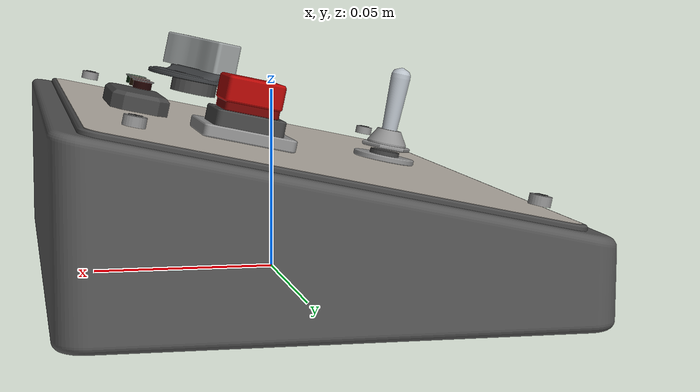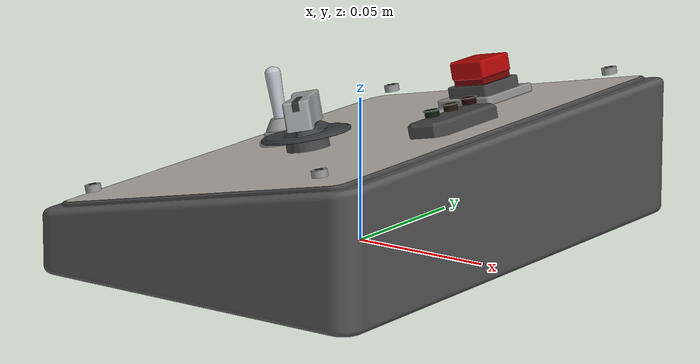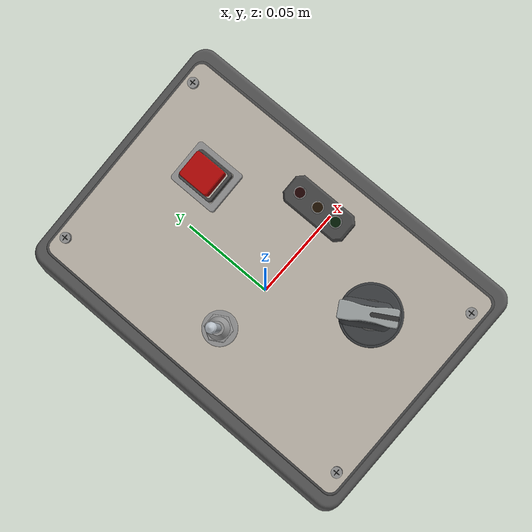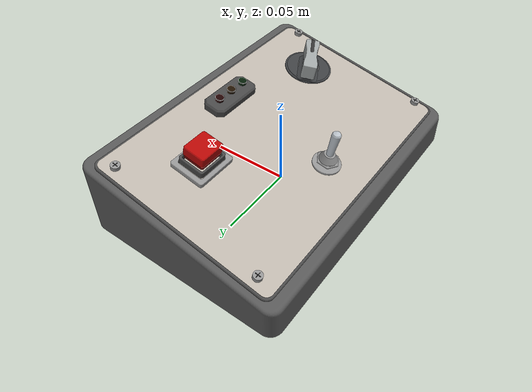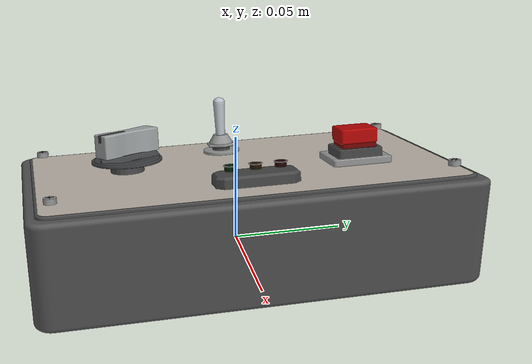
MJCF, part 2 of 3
0.00366231723237 0.0166171974683 -0.000781427874033 0.0036548866883 0.0166268464742 -0.000830224735398 0.00370681139174 0.016589879155 -0.000850920427285 0.00366231723237 0.0166171974683 -0.00109191172769 0.00368078496026 0.0165837359479 -0.000922690443853 0.00351152235729 0.0167119338902 -0.000781427874033 0.0036548866883 0.0166268464742 -0.000850920427285 0.00366231723237 0.0166171974683 -0.000922690443853 0.00351152235729 0.0167119338902 -0.000873893582523 0.00346235357411 0.0167489012093 -0.00108256687235 0.0038871473922 0.0164499850858 -0.00105788704238 0.00394357863394 0.0164174077103 -0.0012184017665 0.0041000682019 0.0162958056466 -0.001310867475 0.00388379183769 0.0164178603818 -0.00108256687235 0.0038871473922 0.0164499850858 -0.000999446019207 0.00388554712677 0.0164616812127 -0.00105788704238 0.00394357863394 0.0164174077103 -0.00108256687235 0.0038871473922 0.0164499850858 -0.001310867475 0.00388379183769 0.0164178603818 -0.00115035275088 0.00373570038439 0.0165394624455 -0.000999446019207 0.00388554712677 0.0164616812127 -0.00108256687235 0.0038871473922 0.0164499850858 -0.00115035275088 0.00373570038439 0.0165394624455 -0.00109191172769 0.00368078496026 0.0165837359479 -0.00869172624989 0.00501206513165 0.0107278699547 -0.00864663823583 0.00514678044488 0.0106683537762 -0.0164520988388 0.00514678044487 0.00475512604695 -0.0165445645472 0.00487388664651 0.00487718078217 -0.00869172624989 0.00501206513165 0.0107278699547 -0.00865162973242 0.00501278026427 0.0107577435178 -0.00860678362842 0.00514678044488 0.0106985466606 -0.00864663823583 0.00514678044488 0.0106683537762 -0.00865162973242 0.00501278026427 0.0107577435178 -0.00861153321495 0.00501349548671 0.010787617081 -0.00856692902101 0.00514678044488 0.010728739545 -0.00860678362842 0.00514678044488 0.0106985466606 -0.00861153321495 0.00501349548671 0.010787617081 -0.00857143669748 0.00501421079887 0.0108174906441 -0.00852707441359 0.00514678044488 0.0107589324294 -0.00856692902101 0.00514678044488 0.010728739545 -0.00857143669748 0.00501421079887 0.0108174906441 -0.00853134018002 0.00501492620062 0.0108473642072 -0.00848721980618 0.00514678044488 0.0107891253138 -0.00852707441359 0.00514678044488 0.0107589324294 -0.00853134018002 0.00501492620062 0.0108473642072 -0.00849124366255 0.00501564169184 0.0108772377704 -0.00844736519877 0.00514678044488 0.0108193181982 -0.00848721980618 0.00514678044488 0.0107891253138 -0.00849124366255 0.00501564169184 0.0108772377704 -0.00845114714508 0.00501635727243 0.0109071113335 -0.00840751059135 0.00514678044488 0.0108495110826 -0.00844736519877 0.00514678044488 0.0108193181982 -0.00845114714508 0.00501635727243 0.0109071113335 -0.00841105062761 0.00501707294226 0.0109369848966 -0.00836765598394 0.00514678044488 0.010879703967 -0.00840751059135 0.00514678044488 0.0108495110826 -0.00841105062761 0.00501707294226 0.0109369848966 -0.00837095411014 0.00501778870122 0.0109668584597 -0.00832780137653 0.00514678044488 0.0109098968514 -0.00836765598394 0.00514678044488 0.010879703967 -0.00837095411014 0.00501778870122 0.0109668584597 -0.00833085759267 0.00501850454918 0.0109967320229 -0.00828794676911 0.00514678044488 0.0109400897358 -0.00832780137653 0.00514678044488 0.0109098968514 -0.00833085759267 0.00501850454918 0.0109967320229 -0.0082907610752 0.00501922048604 0.011026605586 -0.0082480921617 0.00514678044488 0.0109702826202 -0.00828794676911 0.00514678044488 0.0109400897358 -0.0082907610752 0.00501922048604 0.011026605586 -0.00825066455773 0.00501993651167 0.0110564791491 -0.00820823755429 0.00514678044488 0.0110004755046 -0.0082480921617 0.00514678044488 0.0109702826202 -0.00825066455773 0.00501993651167 0.0110564791491 -0.00821056804026 0.00502065262595 0.0110863527123 -0.00816838294687 0.00514678044488 0.011030668389 -0.00820823755429 0.00514678044488 0.0110004755046 -0.00821056804026 0.00502065262595 0.0110863527123 -0.00817047152279 0.00502136882878 0.0111162262754 -0.00812852833946 0.00514678044488 0.0110608612734 -0.00816838294687 0.00514678044488 0.011030668389 -0.00817047152279 0.00502136882878 0.0111162262754 -0.00813037500533 0.00502208512003 0.0111460998385 -0.00808867373205 0.00514678044488 0.0110910541578 -0.00812852833946 0.00514678044488 0.0110608612734 -0.00813037500533 0.00502208512003 0.0111460998385 -0.00809027848786 0.00502280149958 0.0111759734016 -0.00804881912463 0.00514678044488 0.0111212470422 -0.00808867373205 0.00514678044488 0.0110910541578 -0.00809027848786 0.00502280149958 0.0111759734016 -0.00805018197039 0.00502351796732 0.0112058469648 -0.00800896451722 0.00514678044488 0.0111514399266 -0.00804881912463 0.00514678044488 0.0111212470422 -0.00805018197039 0.00502351796732 0.0112058469648 -0.00801008545292 0.00502423452312 0.0112357205279 -0.00796910990981 0.00514678044488 0.011181632811 -0.00800896451722 0.00514678044488 0.0111514399266 -0.00801008545292 0.00502423452312 0.0112357205279 -0.00796998893545 0.00502495116689 0.011265594091 -0.00792925530239 0.00514678044488 0.0112118256954 -0.00796910990981 0.00514678044488 0.011181632811 -0.00796998893545 0.00502495116689 0.011265594091 -0.00311831032169 0.00511227849074 0.0148802952296 -0.0031068478054 0.00514678044489 0.0148651647081 -0.00792925530239 0.00514678044488 0.0112118256954 -0.00311831032169 0.00511227849074 0.0148802952296 -0.00288926614682 0.00509709905456 0.0150509426087 -0.0028791854984 0.00512733310875 0.0150376361528 -0.0031068478054 0.00514678044489 0.0148651647081 -0.00288926614682 0.00509709905456 0.0150509426087 -0.00266022197195 0.0050455072822 0.0152215899878 -0.0026515231914 0.00507131317032 0.0152101075975 -0.0028791854984 0.00512733310875 0.0150376361528 -0.00266022197195 0.0050455072822 0.0152215899878 -0.00243117779708 0.0049608806373 0.0153922373669 -0.0024238608844 0.00498220373457 0.0153825790422 -0.0026515231914 0.00507131317032 0.0152101075975 -0.00243117779708 0.0049608806373 0.0153922373669 -0.00220213362221 0.00484660796499 0.015562884746 -0.00219619857739 0.00486348790649 0.0155550504868 -0.0024238608844 0.00498220373457 0.0153825790422 -0.00220213362221 0.00484660796499 0.015562884746 -0.00197308944734 0.00470608950945 0.0157335321251 -0.00196853627039 0.00471864879106 0.0157275219315 -0.00219619857739 0.00486348790649 0.0155550504868 -0.00197308944734 0.00470608950945 0.0157335321251 -0.00174404527247 0.00454273693113 0.0159041795042 -0.00174087396339 0.00455116949325 0.0158999933762 -0.00196853627039 0.00471864879106 0.0157275219315 -0.00174404527247 0.00454273693113 0.0159041795042 -0.0015150010976 0.00435997332376 0.0160748268833 -0.00151321165639 0.00436453311806 0.0160724648209 -0.00174087396339 0.00455116949325 0.0158999933762 -0.0015150010976 0.00435997332376 0.0160748268833 -0.00128595692273 0.0041612332309 0.0162454742624 -0.00128554934939 0.00416222277045 0.0162449362656 -0.00151321165639 0.00436453311806 0.0160724648209 -0.00128595692273 0.0041612332309 0.0162454742624 -0.0012184017665 0.0041000682019 0.0162958056466 -0.00128554934939 0.00416222277045 0.0162449362656 -0.00869172624989 0.00501206513165 0.0107278699547 -0.0165445645472 0.00487388664651 0.00487718078217 -0.00873910394431 0.00487388664649 0.0107904085114 -0.00865162973242 0.00501278026427 0.0107577435178 -0.00869172624989 0.00501206513165 0.0107278699547 -0.00873910394431 0.00487388664649 0.0107904085114 -0.0086992493369 0.00487388664649 0.0108206013958 -0.00861153321495 0.00501349548671 0.010787617081 -0.00865162973242 0.00501278026427 0.0107577435178 -0.0086992493369 0.00487388664649 0.0108206013958 -0.00865939472949 0.00487388664649 0.0108507942802 -0.00857143669748 0.00501421079887 0.0108174906441 -0.00861153321495 0.00501349548671 0.010787617081 -0.00865939472949 0.00487388664649 0.0108507942802 -0.00861954012207 0.00487388664649 0.0108809871646 -0.00853134018002 0.00501492620062 0.0108473642072 -0.00857143669748 0.00501421079887 0.0108174906441 -0.00861954012207 0.00487388664649 0.0108809871646 -0.00857968551466 0.00487388664649 0.010911180049 -0.00849124366255 0.00501564169184 0.0108772377704 -0.00853134018002 0.00501492620062 0.0108473642072 -0.00857968551466 0.00487388664649 0.010911180049 -0.00853983090725 0.00487388664649 0.0109413729334 -0.00845114714508 0.00501635727243 0.0109071113335 -0.00849124366255 0.00501564169184 0.0108772377704 -0.00853983090725 0.00487388664649 0.0109413729334 -0.00849997629983 0.00487388664649 0.0109715658178 -0.00841105062761 0.00501707294226 0.0109369848966 -0.00845114714508 0.00501635727243 0.0109071113335 -0.00849997629983 0.00487388664649 0.0109715658178 -0.00846012169242 0.00487388664649 0.0110017587022 -0.00837095411014 0.00501778870122 0.0109668584597 -0.00841105062761 0.00501707294226 0.0109369848966 -0.00846012169242 0.00487388664649 0.0110017587022 -0.00842026708501 0.00487388664649 0.0110319515866 -0.00833085759267 0.00501850454918 0.0109967320229 -0.00837095411014 0.00501778870122 0.0109668584597 -0.00842026708501 0.00487388664649 0.0110319515866 -0.00838041247759 0.00487388664649 0.011062144471 -0.0082907610752 0.00501922048604 0.011026605586 -0.00833085759267 0.00501850454918 0.0109967320229 -0.00838041247759 0.00487388664649 0.011062144471 -0.00834055787018 0.00487388664649 0.0110923373554 -0.00825066455773 0.00501993651167 0.0110564791491 -0.0082907610752 0.00501922048604 0.011026605586 -0.00834055787018 0.00487388664649 0.0110923373554 -0.00830070326277 0.00487388664649 0.0111225302398 -0.00821056804026 0.00502065262595 0.0110863527123 -0.00825066455773 0.00501993651167 0.0110564791491 -0.00830070326277 0.00487388664649 0.0111225302398 -0.00826084865535 0.00487388664649 0.0111527231242 -0.00817047152279 0.00502136882878 0.0111162262754 -0.00821056804026 0.00502065262595 0.0110863527123 -0.00826084865535 0.00487388664649 0.0111527231242 -0.00822099404794 0.00487388664649 0.0111829160086 -0.00813037500533 0.00502208512003 0.0111460998385 -0.00817047152279 0.00502136882878 0.0111162262754 -0.00822099404794 0.00487388664649 0.0111829160086 -0.00818113944053 0.00487388664649 0.011213108893 -0.00809027848786 0.00502280149958 0.0111759734016 -0.00813037500533 0.00502208512003 0.0111460998385 -0.00818113944053 0.00487388664649 0.011213108893 -0.00814128483312 0.00487388664649 0.0112433017774 -0.00805018197039 0.00502351796732 0.0112058469648 -0.00809027848786 0.00502280149958 0.0111759734016 -0.00814128483312 0.00487388664649 0.0112433017774 -0.0081014302257 0.00487388664649 0.0112734946618 -0.00801008545292 0.00502423452312 0.0112357205279 -0.00805018197039 0.00502351796732 0.0112058469648 -0.0081014302257 0.00487388664649 0.0112734946618 -0.00806157561829 0.00487388664649 0.0113036875462 -0.00796998893545 0.00502495116689 0.011265594091 -0.00801008545292 0.00502423452312 0.0112357205279 -0.00806157561829 0.00487388664649 0.0113036875462 -0.00802172101088 0.00487388664649 0.0113338804306 -0.00311831032169 0.00511227849074 0.0148802952296 -0.00796998893545 0.00502495116689 0.011265594091 -0.00802172101088 0.00487388664649 0.0113338804306 -0.00319931351389 0.00487388664648 0.0149872194433 -0.00288926614682 0.00509709905456 0.0150509426087 -0.00311831032169 0.00511227849074 0.0148802952296 -0.00319931351389 0.00487388664648 0.0149872194433 -0.00297165120689 0.00485549123104 0.015159690888 -0.00266022197195 0.0050455072822 0.0152215899878 -0.00288926614682 0.00509709905456 0.0150509426087 -0.00297165120689 0.00485549123104 0.015159690888 -0.00274398889989 0.00480250145223 0.0153321623327 -0.00243117779708 0.0049608806373 0.0153922373669 -0.00266022197195 0.0050455072822 0.0152215899878 -0.00274398889989 0.00480250145223 0.0153321623327 -0.00251632659289 0.00471821201132 0.0155046337774 -0.00220213362221 0.00484660796499 0.015562884746 -0.00243117779708 0.0049608806373 0.0153922373669 -0.00251632659289 0.00471821201132 0.0155046337774 -0.00228866428589 0.0046059176096 0.0156771052221 -0.00197308944734 0.00470608950945 0.0157335321251 -0.00220213362221 0.00484660796499 0.015562884746 -0.00228866428589 0.0046059176096 0.0156771052221 -0.00206100197888 0.00446891294833 0.0158495766667 -0.00174404527247 0.00454273693113 0.0159041795042 -0.00197308944734 0.00470608950945 0.0157335321251 -0.00206100197888 0.00446891294833 0.0158495766667 -0.00183333967188 0.00431049272878 0.0160220481114 -0.0015150010976 0.00435997332376 0.0160748268833 -0.00174404527247 0.00454273693113 0.0159041795042 -0.00183333967188 0.00431049272878 0.0160220481114 -0.00160567736488 0.00413395165223 0.0161945195561 -0.00128595692273 0.0041612332309 0.0162454742624 -0.0015150010976 0.00435997332376 0.0160748268833 -0.00160567736488 0.00413395165223 0.0161945195561 -0.00137801505788 0.00394258441996 0.0163669910008 -0.0012184017665 0.0041000682019 0.0162958056466 -0.00128595692273 0.0041612332309 0.0162454742624 -0.00137801505788 0.00394258441996 0.0163669910008 -0.001310867475 0.00388379183769 0.0164178603818 -0.0164520988388 0.00514678044487 0.00475512604695 -0.016671054586 0.00513936727908 0.00458925048082 -0.0167635202945 0.00486675543434 0.00471130521603 -0.0164520988388 0.00514678044487 0.00475512604695 -0.0167635202945 0.00486675543434 0.00471130521603 -0.0165445645472 0.00487388664651 0.00487718078217 -0.016671054586 0.00513936727908 0.00458925048082 -0.0168890727313 0.00511715952582 0.00442408521934 -0.0169815384397 0.00484539233485 0.00454613995455 -0.016671054586 0.00513936727908 0.00458925048082 -0.0169815384397 0.00484539233485 0.00454613995455 -0.0167635202945 0.00486675543434 0.00471130521603 -0.0168890727313 0.00511715952582 0.00442408521934 -0.0171052196871 0.00508025228229 0.0042603375255 -0.0171976853956 0.004809888828 0.00438239226071 -0.0168890727313 0.00511715952582 0.00442408521934 -0.0171976853956 0.004809888828 0.00438239226071 -0.0169815384397 0.00484539233485 0.00454613995455 -0.0171052196871 0.00508025228229 0.0042603375255 -0.0173185698792 0.00502880359086 0.00409870859207 -0.0174110355877 0.00476039694537 0.00422076332728 -0.0171052196871 0.00508025228229 0.0042603375255 -0.0174110355877 0.00476039694537 0.00422076332728 -0.0171976853956 0.004809888828 0.00438239226071 -0.0173185698792 0.00502880359086 0.00409870859207 -0.0175282097094 0.00496303376273 0.00393989053895 -0.0176206754179 0.00469712861873 0.00406194527417 -0.0173185698792 0.00502880359086 0.00409870859207 -0.0176206754179 0.00469712861873 0.00406194527417 -0.0174110355877 0.00476039694537 0.00422076332728 -0.0175282097094 0.00496303376273 0.00393989053895 -0.0177332414675 0.00488322443445 0.00378456344945 -0.017825707176 0.00462035477284 0.00390661818466 -0.0175282097094 0.00496303376273 0.00393989053895 -0.017825707176 0.00462035477284 0.00390661818466 -0.0176206754179 0.00469712861873 0.00406194527417 -0.0177332414675 0.00488322443445 0.00378456344945 -0.0179327871762 0.00478971736179 0.00363339245797 -0.0180252528847 0.00453040416503 0.00375544719319 -0.0177332414675 0.00488322443445 0.00378456344945 -0.0180252528847 0.00453040416503 0.00375544719319 -0.017825707176 0.00462035477284 0.00390661818466 -0.0179327871762 0.00478971736179 0.00363339245797 -0.0181259923503 0.00468291295632 0.00348702490195 -0.0182184580588 0.00442766197757 0.00360907963717 -0.0179327871762 0.00478971736179 0.00363339245797 -0.0182184580588 0.00442766197757 0.00360907963717 -0.0180252528847 0.00453040416503 0.00375544719319 -0.0181259923503 0.00468291295632 0.00348702490195 -0.0183120296552 0.00456326857105 0.00334608754971 -0.0184044953637 0.00431256816841 0.00346814228493 -0.0181259923503 0.00468291295632 0.00348702490195 -0.0184044953637 0.00431256816841 0.00346814228493 -0.0182184580588 0.00442766197757 0.00360907963717 -0.0183120296552 0.00456326857105 0.00334608754971 -0.0184901024509 0.00443129654145 0.00321118391664 -0.0185825681593 0.00418561558686 0.00333323865185 -0.0183120296552 0.00456326857105 0.00334608754971 -0.0185825681593 0.00418561558686 0.00333323865185 -0.0184044953637 0.00431256816841 0.00346814228493 -0.0184901024509 0.00443129654145 0.00321118391664 -0.0186594482022 0.00428756199213 0.0030828916808 -0.0187519139107 0.00404734786328 0.00320494641601 -0.0184901024509 0.00443129654145 0.00321118391664 -0.0187519139107 0.00404734786328 0.00320494641601 -0.0185825681593 0.00418561558686 0.00333323865185 -0.0186594482022 0.00428756199213 0.0030828916808 -0.0188193417447 0.00413268041648 0.00296176020924 -0.0189118074532 0.00389835708135 0.00308381494445 -0.0186594482022 0.00428756199213 0.0030828916808 -0.0189118074532 0.00389835708135 0.00308381494445 -0.0187519139107 0.00404734786328 0.00320494641601 -0.0188193417447 0.00413268041648 0.00296176020924 -0.0189690983896 0.00396731504114 0.00284830820551 -0.0190615640981 0.0037392812425 0.00297036294072 -0.0188193417447 0.00413268041648 0.00296176020924 -0.0190615640981 0.0037392812425 0.00297036294072 -0.0189118074532 0.00389835708135 0.00308381494445 -0.0189690983896 0.00396731504114 0.00284830820551 -0.019108076856 0.00379217398604 0.00274302148852 -0.0192005425645 0.00357080153387 0.00286507622374 -0.0189690983896 0.00396731504114 0.00284830820551 -0.0192005425645 0.00357080153387 0.00286507622374 -0.0190615640981 0.0037392812425 0.00297036294072 -0.019108076856 0.00379217398604 0.00274302148852 -0.0192356820168 0.00360800723208 0.00264635091217 -0.0193281477253 0.00339363941143 0.00276840564738 -0.019108076856 0.00379217398604 0.00274302148852 -0.0193281477253 0.00339363941143 0.00276840564738 -0.0192005425645 0.00357080153387 0.00286507622374 -0.0192356820168 0.00360800723208 0.00264635091217 -0.0193513674471 0.00341560340957 0.00255871043467 -0.0194438331556 0.00320855351062 0.00268076516989 -0.0192356820168 0.00360800723208 0.00264635091217 -0.0194438331556 0.00320855351062 0.00268076516989 -0.0193281477253 0.00339363941143 0.00276840564738 -0.0193513674471 0.00341560340957 0.00255871043467 -0.0194546377641 0.00321578642128 0.00248047534604 -0.0195471034726 0.00301633639764 0.00260253008125 -0.0193513674471 0.00341560340957 0.00255871043467 -0.0195471034726 0.00301633639764 0.00260253008125 -0.0194438331556 0.00320855351062 0.00268076516989 -0.0194546377641 0.00321578642128 0.00248047534604 -0.0195450507485 0.00300941191409 0.00241198066091 -0.019637516457 0.00281781117567 0.00253403539613 -0.0194546377641 0.00321578642128 0.00248047534604 -0.019637516457 0.00281781117567 0.00253403539613 -0.0195471034726 0.00301633639764 0.00260253008125 -0.0195450507485 0.00300941191409 0.00241198066091 -0.0196222192379 0.00279736361545 0.00235351968406 -0.0197146849464 0.00261382796024 0.00247557441927 -0.0195450507485 0.00300941191409 0.00241198066091 -0.0197146849464 0.00261382796024 0.00247557441927 -0.019637516457 0.00281781117567 0.00253403539613 -0.0196222192379 0.00279736361545 0.00235351968406 -0.0196858127852 0.00258054954864 0.00230534275434 -0.0197782784936 0.00240526023875 0.00242739748956 -0.0196222192379 0.00279736361545 0.00235351968406 -0.0197782784936 0.00240526023875 0.00242739748956 -0.0197146849464 0.00261382796024 0.00247557441927 -0.0196858127852 0.00258054954864 0.00230534275434 -0.0197355590728 0.00235989814485 0.0022676561728 -0.0198280247813 0.00219300113021 0.00238971090801 -0.0196858127852 0.00258054954864 0.00230534275434 -0.0198280247813 0.00219300113021 0.00238971090801 -0.0197782784936 0.00240526023875 0.00242739748956 -0.0197355590728 0.00235989814485 0.0022676561728 -0.0197712450796 0.00213635426726 0.00224062131912 -0.0198637107881 0.00197795956075 0.00236267605434 -0.0197355590728 0.00235989814485 0.0022676561728 -0.0198637107881 0.00197795956075 0.00236267605434 -0.0198280247813 0.00219300113021 0.00238971090801 -0.0197712450796 0.00213635426726 0.00224062131912 -0.0197927179927 0.00191087516501 0.00222435396074 -0.0198851837012 0.00176105637133 0.00234640869595 -0.0197712450796 0.00213635426726 0.00224062131912 -0.0198851837012 0.00176105637133 0.00234640869595 -0.0198637107881 0.00197795956075 0.00236267605434 -0.0197927179927 0.00191087516501 0.00222435396074 -0.0197998858617 0.00168442637429 0.00221892375695 -0.0198923515702 0.00154322037473 0.00234097849217 -0.0197927179927 0.00191087516501 0.00222435396074 -0.0198923515702 0.00154322037473 0.00234097849217 -0.0198851837012 0.00176105637133 0.00234640869595 -0.0197998858617 0.00168442637429 0.00221892375695 -0.0197998858617 -0.00148108888829 0.00221892375695 -0.0198923515702 -0.00133988288873 0.00234097849217 -0.0197998858617 0.00168442637429 0.00221892375695 -0.0198923515702 -0.00133988288873 0.00234097849217 -0.0198923515702 0.00154322037473 0.00234097849217 -0.0197998858617 -0.00148108888829 0.00221892375695 -0.0197927179927 -0.00170753767901 0.00222435396074 -0.0198851837012 -0.00155771888533 0.00234640869595 -0.0197998858617 -0.00148108888829 0.00221892375695 -0.0198851837012 -0.00155771888533 0.00234640869595 -0.0198923515702 -0.00133988288873 0.00234097849217 -0.0197927179927 -0.00170753767901 0.00222435396074 -0.0197712450796 -0.00193301678126 0.00224062131912 -0.0198637107881 -0.00177462207475 0.00236267605434 -0.0197927179927 -0.00170753767901 0.00222435396074 -0.0198637107881 -0.00177462207475 0.00236267605434 -0.0198851837012 -0.00155771888533 0.00234640869595 -0.0197712450796 -0.00193301678126 0.00224062131912 -0.0197355590728 -0.00215656065885 0.0022676561728 -0.0198280247813 -0.00198966364421 0.00238971090801 -0.0197712450796 -0.00193301678126 0.00224062131912 -0.0198280247813 -0.00198966364421 0.00238971090801 -0.0198637107881 -0.00177462207475 0.00236267605434 -0.0197355590728 -0.00215656065885 0.0022676561728 -0.0196858127852 -0.00237721206264 0.00230534275434 -0.0197782784936 -0.00220192275275 0.00242739748956 -0.0197355590728 -0.00215656065885 0.0022676561728 -0.0197782784936 -0.00220192275275 0.00242739748956 -0.0198280247813 -0.00198966364421 0.00238971090801 -0.0196858127852 -0.00237721206264 0.00230534275434 -0.0196222192379 -0.00259402612945 0.00235351968406 -0.0197146849464 -0.00241049047424 0.00247557441927 -0.0196858127852 -0.00237721206264 0.00230534275434 -0.0197146849464 -0.00241049047424 0.00247557441927 -0.0197782784936 -0.00220192275275 0.00242739748956 -0.0196222192379 -0.00259402612945 0.00235351968406 -0.0195450507485 -0.00280607442809 0.00241198066091 -0.019637516457 -0.00261447368967 0.00253403539613 -0.0196222192379 -0.00259402612945 0.00235351968406 -0.019637516457 -0.00261447368967 0.00253403539613 -0.0197146849464 -0.00241049047424 0.00247557441927 -0.0195450507485 -0.00280607442809 0.00241198066091 -0.0194546377641 -0.00301244893528 0.00248047534604 -0.0195471034726 -0.00281299891164 0.00260253008125 -0.0195450507485 -0.00280607442809 0.00241198066091 -0.0195471034726 -0.00281299891164 0.00260253008125 -0.019637516457 -0.00261447368967 0.00253403539613 -0.0194546377641 -0.00301244893528 0.00248047534604 -0.0193513674471 -0.00321226592357 0.00255871043467 -0.0194438331556 -0.00300521602462 0.00268076516989 -0.0194546377641 -0.00301244893528 0.00248047534604 -0.0194438331556 -0.00300521602462 0.00268076516989 -0.0195471034726 -0.00281299891164 0.00260253008125 -0.0193513674471 -0.00321226592357 0.00255871043467 -0.0192356820168 -0.00340466974608 0.00264635091217 -0.0193281477253 -0.00319030192543 0.00276840564738 -0.0193513674471 -0.00321226592357 0.00255871043467 -0.0193281477253 -0.00319030192543 0.00276840564738 -0.0194438331556 -0.00300521602462 0.00268076516989 -0.0192356820168 -0.00340466974608 0.00264635091217 -0.019108076856 -0.00358883650004 0.00274302148852 -0.0192005425645 -0.00336746404787 0.00286507622374 -0.0192356820168 -0.00340466974608 0.00264635091217 -0.0192005425645 -0.00336746404787 0.00286507622374 -0.0193281477253 -0.00319030192543 0.00276840564738 -0.019108076856 -0.00358883650004 0.00274302148852 -0.0189690983896 -0.00376397755514 0.00284830820551 -0.0190615640981 -0.0035359437565 0.00297036294072 -0.019108076856 -0.00358883650004 0.00274302148852 -0.0190615640981 -0.0035359437565 0.00297036294072 -0.0192005425645 -0.00336746404787 0.00286507622374 -0.0189690983896 -0.00376397755514 0.00284830820551 -0.0188193417447 -0.00392934293048 0.00296176020924 -0.0189118074532 -0.00369501959535 0.00308381494445 -0.0189690983896 -0.00376397755514 0.00284830820551 -0.0189118074532 -0.00369501959535 0.00308381494445 -0.0190615640981 -0.0035359437565 0.00297036294072 -0.0188193417447 -0.00392934293048 0.00296176020924 -0.0186594482022 -0.00408422450613 0.0030828916808 -0.0187519139107 -0.00384401037728 0.00320494641601 -0.0188193417447 -0.00392934293048 0.00296176020924 -0.0187519139107 -0.00384401037728 0.00320494641601 -0.0189118074532 -0.00369501959535 0.00308381494445 -0.0186594482022 -0.00408422450613 0.0030828916808 -0.0184901024509 -0.00422795905545 0.00321118391664 -0.0185825681593 -0.00398227810086 0.00333323865185 -0.0186594482022 -0.00408422450613 0.0030828916808 -0.0185825681593 -0.00398227810086 0.00333323865185 -0.0187519139107 -0.00384401037728 0.00320494641601 -0.0184901024509 -0.00422795905545 0.00321118391664 -0.0183120296552 -0.00435993108505 0.00334608754971 -0.0184044953637 -0.00410923068241 0.00346814228493 -0.0184901024509 -0.00422795905545 0.00321118391664 -0.0184044953637 -0.00410923068241 0.00346814228493 -0.0185825681593 -0.00398227810086 0.00333323865185 -0.0183120296552 -0.00435993108505 0.00334608754971 -0.0181259923503 -0.00447957547032 0.00348702490195 -0.0182184580588 -0.00422432449157 0.00360907963717 -0.0183120296552 -0.00435993108505 0.00334608754971 -0.0182184580588 -0.00422432449157 0.00360907963717 -0.0184044953637 -0.00410923068241 0.00346814228493 -0.0181259923503 -0.00447957547032 0.00348702490195 -0.0179327871762 -0.00458637987579 0.00363339245797 -0.0180252528847 -0.00432706667903 0.00375544719319 -0.0181259923503 -0.00447957547032 0.00348702490195 -0.0180252528847 -0.00432706667903 0.00375544719319 -0.0182184580588 -0.00422432449157 0.00360907963717 -0.0179327871762 -0.00458637987579 0.00363339245797 -0.0177332414675 -0.00467988694845 0.00378456344945 -0.017825707176 -0.00441701728684 0.00390661818466 -0.0179327871762 -0.00458637987579 0.00363339245797 -0.017825707176 -0.00441701728684 0.00390661818466 -0.0180252528847 -0.00432706667903 0.00375544719319 -0.0177332414675 -0.00467988694845 0.00378456344945 -0.0175282097094 -0.00475969627673 0.00393989053895 -0.0176206754179 -0.00449379113273 0.00406194527417 -0.0177332414675 -0.00467988694845 0.00378456344945 -0.0176206754179 -0.00449379113273 0.00406194527417 -0.017825707176 -0.00441701728684 0.00390661818466 -0.0175282097094 -0.00475969627673 0.00393989053895 -0.0173185698792 -0.00482546610486 0.00409870859207 -0.0174110355877 -0.00455705945937 0.00422076332728 -0.0175282097094 -0.00475969627673 0.00393989053895 -0.0174110355877 -0.00455705945937 0.00422076332728 -0.0176206754179 -0.00449379113273 0.00406194527417 -0.0173185698792 -0.00482546610486 0.00409870859207 -0.0171052196871 -0.00487691479629 0.0042603375255 -0.0171976853956 -0.004606551342 0.00438239226071 -0.0173185698792 -0.00482546610486 0.00409870859207 -0.0171976853956 -0.004606551342 0.00438239226071 -0.0174110355877 -0.00455705945937 0.00422076332728 -0.0171052196871 -0.00487691479629 0.0042603375255 -0.0168890727313 -0.00491382203982 0.00442408521934 -0.0169815384397 -0.00464205484885 0.00454613995455 -0.0171052196871 -0.00487691479629 0.0042603375255 -0.0169815384397 -0.00464205484885 0.00454613995455 -0.0171976853956 -0.004606551342 0.00438239226071 -0.0168890727313 -0.00491382203982 0.00442408521934 -0.016671054586 -0.00493602979308 0.00458925048082 -0.0167635202945 -0.00466341794834 0.00471130521603 -0.0168890727313 -0.00491382203982 0.00442408521934 -0.0167635202945 -0.00466341794834 0.00471130521603 -0.0169815384397 -0.00464205484885 0.00454613995455 -0.016671054586 -0.00493602979308 0.00458925048082 -0.0164520988388 -0.00494344295887 0.00475512604695 -0.0165445645472 -0.00467054916051 0.00487718078217 -0.016671054586 -0.00493602979308 0.00458925048082 -0.0165445645472 -0.00467054916051 0.00487718078217 -0.0167635202945 -0.00466341794834 0.00471130521603 -0.00869401593025 -0.00480196338149 0.0107308923328 -0.0164520988388 -0.00494344295887 0.00475512604695 -0.00864663823583 -0.00494344295888 0.0106683537762 -0.00865440323289 -0.00480124919595 0.0107614045385 -0.00869401593025 -0.00480196338149 0.0107308923328 -0.00864663823583 -0.00494344295888 0.0106683537762 -0.00860678362842 -0.00494344295888 0.0106985466606 -0.00861479053554 -0.00480053510159 0.0107919167441 -0.00865440323289 -0.00480124919595 0.0107614045385 -0.00860678362842 -0.00494344295888 0.0106985466606 -0.00856692902101 -0.00494344295888 0.010728739545 -0.00857517783818 -0.00479982109851 0.0108224289498 -0.00861479053554 -0.00480053510159 0.0107919167441 -0.00856692902101 -0.00494344295888 0.010728739545 -0.00852707441359 -0.00494344295888 0.0107589324294 -0.00853556514082 -0.00479910718684 0.0108529411555 -0.00857517783818 -0.00479982109851 0.0108224289498 -0.00852707441359 -0.00494344295888 0.0107589324294 -0.00848721980618 -0.00494344295888 0.0107891253138 -0.00849595244347 -0.00479839336668 0.0108834533612 -0.00853556514082 -0.00479910718684 0.0108529411555 -0.00848721980618 -0.00494344295888 0.0107891253138 -0.00844736519877 -0.00494344295888 0.0108193181982 -0.00845633974611 -0.00479767963817 0.0109139655669 -0.00849595244347 -0.00479839336668 0.0108834533612 -0.00844736519877 -0.00494344295888 0.0108193181982 -0.00840751059135 -0.00494344295888 0.0108495110826 -0.00841672704875 -0.0047969660014 0.0109444777725 -0.00845633974611 -0.00479767963817 0.0109139655669 -0.00840751059135 -0.00494344295888 0.0108495110826 -0.00836765598394 -0.00494344295888 0.010879703967 -0.00837711435139 -0.00479625245651 0.0109749899782 -0.00841672704875 -0.0047969660014 0.0109444777725 -0.00836765598394 -0.00494344295888 0.010879703967 -0.00832780137653 -0.00494344295888 0.0109098968514 -0.00833750165404 -0.00479553900361 0.0110055021839 -0.00837711435139 -0.00479625245651 0.0109749899782 -0.00832780137653 -0.00494344295888 0.0109098968514 -0.00828794676911 -0.00494344295888 0.0109400897358 -0.00829788895668 -0.00479482564281 0.0110360143896 -0.00833750165404 -0.00479553900361 0.0110055021839 -0.00828794676911 -0.00494344295888 0.0109400897358 -0.0082480921617 -0.00494344295888 0.0109702826202 -0.00825827625932 -0.00479411237423 0.0110665265952 -0.00829788895668 -0.00479482564281 0.0110360143896 -0.0082480921617 -0.00494344295888 0.0109702826202 -0.00820823755429 -0.00494344295888 0.0110004755046 -0.00821866356197 -0.00479339919799 0.0110970388009 -0.00825827625932 -0.00479411237423 0.0110665265952 -0.00820823755429 -0.00494344295888 0.0110004755046 -0.00816838294687 -0.00494344295888 0.011030668389 -0.00817905086461 -0.00479268611421 0.0111275510066 -0.00821866356197 -0.00479339919799 0.0110970388009 -0.00816838294687 -0.00494344295888 0.011030668389 -0.00812852833946 -0.00494344295888 0.0110608612734 -0.00813943816725 -0.00479197312299 0.0111580632123 -0.00817905086461 -0.00479268611421 0.0111275510066 -0.00812852833946 -0.00494344295888 0.0110608612734 -0.00808867373205 -0.00494344295888 0.0110910541578 -0.00809982546989 -0.00479126022446 0.0111885754179 -0.00813943816725 -0.00479197312299 0.0111580632123 -0.00808867373205 -0.00494344295888 0.0110910541578 -0.00804881912463 -0.00494344295888 0.0111212470422 -0.00806021277254 -0.00479054741874 0.0112190876236 -0.00809982546989 -0.00479126022446 0.0111885754179 -0.00804881912463 -0.00494344295888 0.0111212470422 -0.00800896451722 -0.00494344295888 0.0111514399266 -0.00802060007518 -0.00478983470594 0.0112495998293 -0.00806021277254 -0.00479054741874 0.0112190876236 -0.00800896451722 -0.00494344295888 0.0111514399266 -0.00796910990981 -0.00494344295888 0.011181632811 -0.00798098737782 -0.00478912208617 0.011280112035 -0.00802060007518 -0.00478983470594 0.0112495998293 -0.00796910990981 -0.00494344295888 0.011181632811 -0.00792925530239 -0.00494344295888 0.0112118256954 -0.0031878509976 -0.00470361686234 0.0149720889218 -0.00798098737782 -0.00478912208617 0.011280112035 -0.00792925530239 -0.00494344295888 0.0112118256954 -0.0031068478054 -0.00494344295889 0.0148651647081 -0.00296157055847 -0.00468110992376 0.0151463844321 -0.0031878509976 -0.00470361686234 0.0149720889218 -0.0031068478054 -0.00494344295889 0.0148651647081 -0.0028791854984 -0.00492399562275 0.0150376361528 -0.00273529011933 -0.00462386119202 0.0153206799423 -0.00296157055847 -0.00468110992376 0.0151463844321 -0.0028791854984 -0.00492399562275 0.0150376361528 -0.0026515231914 -0.00486797568432 0.0152101075975 -0.0025090096802 -0.00453526672663 0.0154949754526 -0.00273529011933 -0.00462386119202 0.0153206799423 -0.0026515231914 -0.00486797568432 0.0152101075975 -0.0024238608844 -0.00477886624857 0.0153825790422 -0.00228272924107 -0.00441871141649 0.0156692709629 -0.0025090096802 -0.00453526672663 0.0154949754526 -0.0024238608844 -0.00477886624857 0.0153825790422 -0.00219619857739 -0.00466015042049 0.0155550504868 -0.00205644880194 -0.00427756900303 0.0158435664732 -0.00228272924107 -0.00441871141649 0.0156692709629 -0.00219619857739 -0.00466015042049 0.0155550504868 -0.00196853627039 -0.00451531130506 0.0157275219315 -0.0018301683628 -0.00411520210372 0.0160178619835 -0.00205644880194 -0.00427756900303 0.0158435664732 -0.00196853627039 -0.00451531130506 0.0157275219315 -0.00174087396339 -0.00434783200725 0.0158999933762 -0.00160388792367 -0.00393496223583 0.0161921574937 -0.0018301683628 -0.00411520210372 0.0160178619835 -0.00174087396339 -0.00434783200725 0.0158999933762 -0.00151321165639 -0.00416119563206 0.0160724648209 -0.00137760748454 -0.00374018984047 0.016366453004 -0.00160388792367 -0.00393496223583 0.0161921574937 -0.00151321165639 -0.00416119563206 0.0160724648209 -0.00128554934939 -0.00395888528445 0.0162449362656 -0.00137760748454 -0.00374018984047 0.016366453004 -0.00128554934939 -0.00395888528445 0.0162449362656 -0.0012184017665 -0.0038967307159 0.0162958056466 -0.001310867475 -0.00368045435169 0.0164178603818 -0.0164520988388 -0.00494344295887 0.00475512604695 -0.00869401593025 -0.00480196338149 0.0107308923328 -0.00873910394431 -0.00467054916049 0.0107904085114 -0.0165445645472 -0.00467054916051 0.00487718078217 -0.00869401593025 -0.00480196338149 0.0107308923328 -0.00865440323289 -0.00480124919595 0.0107614045385 -0.0086992493369 -0.00467054916049 0.0108206013958 -0.00873910394431 -0.00467054916049 0.0107904085114 -0.00865440323289 -0.00480124919595 0.0107614045385 -0.00861479053554 -0.00480053510159 0.0107919167441 -0.00865939472949 -0.00467054916049 0.0108507942802 -0.0086992493369 -0.00467054916049 0.0108206013958 -0.00861479053554 -0.00480053510159 0.0107919167441 -0.00857517783818 -0.00479982109851 0.0108224289498 -0.00861954012207 -0.00467054916049 0.0108809871646 -0.00865939472949 -0.00467054916049 0.0108507942802 -0.00857517783818 -0.00479982109851 0.0108224289498 -0.00853556514082 -0.00479910718684 0.0108529411555 -0.00857968551466 -0.00467054916049 0.010911180049 -0.00861954012207 -0.00467054916049 0.0108809871646 -0.00853556514082 -0.00479910718684 0.0108529411555 -0.00849595244347 -0.00479839336668 0.0108834533612 -0.00853983090725 -0.00467054916049 0.0109413729334 -0.00857968551466 -0.00467054916049 0.010911180049 -0.00849595244347 -0.00479839336668 0.0108834533612 -0.00845633974611 -0.00479767963817 0.0109139655669 -0.00849997629983 -0.00467054916049 0.0109715658178 -0.00853983090725 -0.00467054916049 0.0109413729334 -0.00845633974611 -0.00479767963817 0.0109139655669 -0.00841672704875 -0.0047969660014 0.0109444777725 -0.00846012169242 -0.00467054916049 0.0110017587022 -0.00849997629983 -0.00467054916049 0.0109715658178 -0.00841672704875 -0.0047969660014 0.0109444777725 -0.00837711435139 -0.00479625245651 0.0109749899782 -0.00842026708501 -0.00467054916049 0.0110319515866 -0.00846012169242 -0.00467054916049 0.0110017587022 -0.00837711435139 -0.00479625245651 0.0109749899782 -0.00833750165404 -0.00479553900361 0.0110055021839 -0.00838041247759 -0.00467054916049 0.011062144471 -0.00842026708501 -0.00467054916049 0.0110319515866 -0.00833750165404 -0.00479553900361 0.0110055021839 -0.00829788895668 -0.00479482564281 0.0110360143896 -0.00834055787018 -0.00467054916049 0.0110923373554 -0.00838041247759 -0.00467054916049 0.011062144471 -0.00829788895668 -0.00479482564281 0.0110360143896 -0.00825827625932 -0.00479411237423 0.0110665265952 -0.00830070326277 -0.00467054916049 0.0111225302398 -0.00834055787018 -0.00467054916049 0.0110923373554 -0.00825827625932 -0.00479411237423 0.0110665265952 -0.00821866356197 -0.00479339919799 0.0110970388009 -0.00826084865535 -0.00467054916049 0.0111527231242 -0.00830070326277 -0.00467054916049 0.0111225302398 -0.00821866356197 -0.00479339919799 0.0110970388009 -0.00817905086461 -0.00479268611421 0.0111275510066 -0.00822099404794 -0.00467054916049 0.0111829160086 -0.00826084865535 -0.00467054916049 0.0111527231242 -0.00817905086461 -0.00479268611421 0.0111275510066 -0.00813943816725 -0.00479197312299 0.0111580632123 -0.00818113944053 -0.00467054916049 0.011213108893 -0.00822099404794 -0.00467054916049 0.0111829160086 -0.00813943816725 -0.00479197312299 0.0111580632123 -0.00809982546989 -0.00479126022446 0.0111885754179 -0.00814128483312 -0.00467054916049 0.0112433017774 -0.00818113944053 -0.00467054916049 0.011213108893 -0.00809982546989 -0.00479126022446 0.0111885754179 -0.00806021277254 -0.00479054741874 0.0112190876236 -0.0081014302257 -0.00467054916049 0.0112734946618 -0.00814128483312 -0.00467054916049 0.0112433017774 -0.00806021277254 -0.00479054741874 0.0112190876236 -0.00802060007518 -0.00478983470594 0.0112495998293 -0.00806157561829 -0.00467054916049 0.0113036875462 -0.0081014302257 -0.00467054916049 0.0112734946618 -0.00802060007518 -0.00478983470594 0.0112495998293 -0.00798098737782 -0.00478912208617 0.011280112035 -0.00802172101088 -0.00467054916049 0.0113338804306 -0.00806157561829 -0.00467054916049 0.0113036875462 -0.00798098737782 -0.00478912208617 0.011280112035 -0.0031878509976 -0.00470361686234 0.0149720889218 -0.00319931351389 -0.00467054916048 0.0149872194433 -0.00802172101088 -0.00467054916049 0.0113338804306 -0.0031878509976 -0.00470361686234 0.0149720889218 -0.00296157055847 -0.00468110992376 0.0151463844321 -0.00297165120689 -0.00465215374504 0.015159690888 -0.00319931351389 -0.00467054916048 0.0149872194433 -0.00296157055847 -0.00468110992376 0.0151463844321 -0.00273529011933 -0.00462386119202 0.0153206799423 -0.00274398889989 -0.00459916396623 0.0153321623327 -0.00297165120689 -0.00465215374504 0.015159690888 -0.00273529011933 -0.00462386119202 0.0153206799423 -0.0025090096802 -0.00453526672663 0.0154949754526 -0.00251632659289 -0.00451487452532 0.0155046337774 -0.00274398889989 -0.00459916396623 0.0153321623327 -0.0025090096802 -0.00453526672663 0.0154949754526 -0.00228272924107 -0.00441871141649 0.0156692709629 -0.00228866428589 -0.0044025801236 0.0156771052221 -0.00251632659289 -0.00451487452532 0.0155046337774 -0.00228272924107 -0.00441871141649 0.0156692709629 -0.00205644880194 -0.00427756900303 0.0158435664732 -0.00206100197888 -0.00426557546233 0.0158495766667 -0.00228866428589 -0.0044025801236 0.0156771052221 -0.00205644880194 -0.00427756900303 0.0158435664732 -0.0018301683628 -0.00411520210372 0.0160178619835 -0.00183333967188 -0.00410715524278 0.0160220481114 -0.00206100197888 -0.00426557546233 0.0158495766667 -0.0018301683628 -0.00411520210372 0.0160178619835 -0.00160388792367 -0.00393496223583 0.0161921574937 -0.00160567736488 -0.00393061416623 0.0161945195561 -0.00183333967188 -0.00410715524278 0.0160220481114 -0.00160388792367 -0.00393496223583 0.0161921574937 -0.00137760748454 -0.00374018984047 0.016366453004 -0.00137801505788 -0.00373924693396 0.0163669910008 -0.00160567736488 -0.00393061416623 0.0161945195561 -0.00137760748454 -0.00374018984047 0.016366453004 -0.001310867475 -0.00368045435169 0.0164178603818 -0.00137801505788 -0.00373924693396 0.0163669910008 -0.00112567292091 -0.00358682472797 0.0165068850699 -0.0012184017665 -0.0038967307159 0.0162958056466 -0.00105788704238 -0.00374024114794 0.0164174077103 -0.00112567292091 -0.00358682472797 0.0165068850699 -0.00105788704238 -0.00374024114794 0.0164174077103 -0.000999446019207 -0.00368220964077 0.0164616812127 -0.00109191172769 -0.00347744747426 0.0165837359479 -0.0012184017665 -0.0038967307159 0.0162958056466 -0.00112567292091 -0.00358682472797 0.0165068850699 -0.00115035275088 -0.00353236289839 0.0165394624455 -0.001310867475 -0.00368045435169 0.0164178603818 -0.00112567292091 -0.00358682472797 0.0165068850699 -0.00109191172769 -0.00347744747426 0.0165837359479 -0.00115035275088 -0.00353236289839 0.0165394624455 -0.000901994751981 -0.00335103532566 0.0166846155769 -0.000999446019207 -0.00368220964077 0.0164616812127 -0.000830224735398 -0.00350347390574 0.016589879155 -0.000901994751981 -0.00335103532566 0.0166846155769 -0.000830224735398 -0.00350347390574 0.016589879155 -0.000781427874033 -0.0034515492023 0.0166268464742 -0.000873893582523 -0.00325901608811 0.0167489012093 -0.000999446019207 -0.00368220964077 0.0164616812127 -0.000901994751981 -0.00335103532566 0.0166846155769 -0.000922690443853 -0.00330818487129 0.0167119338902 -0.00109191172769 -0.00347744747426 0.0165837359479 -0.000901994751981 -0.00335103532566 0.0166846155769 -0.000873893582523 -0.00325901608811 0.0167489012093 -0.000922690443853 -0.00330818487129 0.0167119338902 -0.000679079444737 -0.00310093610728 0.0168633530613 -0.000781427874033 -0.0034515492023 0.0166268464742 -0.000602562428394 -0.00325226354477 0.0167623505997 -0.000679079444737 -0.00310093610728 0.0168633530613 -0.000602562428394 -0.00325226354477 0.0167623505997 -0.000565280918152 -0.00321081093871 0.016790594168 -0.000657746626642 -0.00303092574809 0.0169126489033 -0.000781427874033 -0.0034515492023 0.0166268464742 -0.000679079444737 -0.00310093610728 0.0168633530613 -0.000695028136879 -0.00307019694753 0.0168844053349 -0.000873893582523 -0.00325901608811 0.0167489012093 -0.000679079444737 -0.00310093610728 0.0168633530613 -0.000657746626642 -0.00303092574809 0.0169126489033 -0.000695028136879 -0.00307019694753 0.0168844053349 -0.000457410922431 -0.0028412924884 0.0170437363018 -0.000565280918152 -0.00321081093871 0.016790594168 -0.000374900121389 -0.00299204655932 0.0169348220444 -0.000457410922431 -0.0028412924884 0.0170437363018 -0.000374900121389 -0.00299204655932 0.0169348220444 -0.000351930726013 -0.00296593053438 0.0169522231015 -0.000444396434503 -0.00279882245694 0.0170742778367 -0.000565280918152 -0.00321081093871 0.016790594168 -0.000457410922431 -0.0028412924884 0.0170437363018 -0.000467365829882 -0.00282357292222 0.0170568767796 -0.000657746626642 -0.00303092574809 0.0169126489033 -0.000457410922431 -0.0028412924884 0.0170437363018 -0.000444396434503 -0.00279882245694 0.0170742778367 -0.000467365829882 -0.00282357292222 0.0170568767796 -0.000237521588642 -0.0025769030058 0.0172264680711 -0.000351930726013 -0.00296593053438 0.0169522231015 -0.000147237814393 -0.00272811170317 0.0171072934891 -0.000237521588642 -0.0025769030058 0.0172264680711 -0.000147237814393 -0.00272811170317 0.0171072934891 -0.000142290895893 -0.00272246942506 0.0171110411546 -0.000234756604383 -0.00256799576114 0.0172330958898 -0.000351930726013 -0.00296593053438 0.0169522231015 -0.000237521588642 -0.0025769030058 0.0172264680711 -0.000239703522886 -0.00257334446905 0.0172293482243 -0.000444396434503 -0.00279882245694 0.0170742778367 -0.000237521588642 -0.0025769030058 0.0172264680711 -0.000234756604383 -0.00256799576114 0.0172330958898 -0.000239703522886 -0.00257334446905 0.0172293482243 -0.000142290895893 -0.00272246942506 0.0171110411546 6.2740862272e-05 -0.00248539701885 0.0172663682441 -2.97248462176e-05 -0.00234317111063 0.0173884229792 -0.000142290895893 -0.00272246942506 0.0171110411546 -2.97248462176e-05 -0.00234317111063 0.0173884229792 -0.000234756604383 -0.00256799576114 0.0172330958898 7.22302326643e-05 -0.0024519922523 0.0172905813569 6.2740862272e-05 -0.00248539701885 0.0172663682441 8.04244926044e-05 -0.00246476276036 0.0172797649338 7.22302326643e-05 -0.0024519922523 0.0172905813569 8.04244926044e-05 -0.00246476276036 0.0172797649338 0.000262286571016 -0.00225891470882 0.0174175392355 0.000169820862527 -0.00212834216343 0.0175395939708 6.2740862272e-05 -0.00248539701885 0.0172663682441 7.22302326643e-05 -0.0024519922523 0.0172905813569 -1.20412158446e-05 -0.00232359575453 0.0174018196689 -2.97248462176e-05 -0.00234317111063 0.0173884229792 7.22302326643e-05 -0.0024519922523 0.0172905813569 0.000169820862527 -0.00212834216343 0.0175395939708 -1.20412158446e-05 -0.00232359575453 0.0174018196689 0.000286167352539 -0.00217621665818 0.0174811700486 0.000262286571016 -0.00225891470882 0.0174175392355 0.000308086799625 -0.00220708588588 0.0174522363784 0.000286167352539 -0.00217621665818 0.0174811700486 0.000308086799625 -0.00220708588588 0.0174522363784 0.000455491744979 -0.00204632997357 0.0175639067916 0.000363026036489 -0.00192665096298 0.0176859615268 0.000262286571016 -0.00225891470882 0.0174175392355 0.000286167352539 -0.00217621665818 0.0174811700486 0.000215621091132 -0.00207916355913 0.0175742911136 0.000169820862527 -0.00212834216343 0.0175395939708 0.000286167352539 -0.00217621665818 0.0174811700486 0.000363026036489 -0.00192665096298 0.0176859615268 0.000215621091132 -0.00207916355913 0.0175742911136 0.000495858968424 -0.00190912745543 0.0176773628055 0.000455491744979 -0.00204632997357 0.0175639067916 0.000535749106631 -0.0019595414397 0.0176247078231 0.000495858968424 -0.00190912745543 0.0176773628055 0.000535749106631 -0.0019595414397 0.0176247078231 0.000641529049945 -0.00184998552628 0.0177048441438 0.000549063341456 -0.00174032071322 0.017826898879 0.000455491744979 -0.00204632997357 0.0175639067916 0.000495858968424 -0.00190912745543 0.0176773628055 0.000443283398138 -0.00184428267015 0.0177467625583 0.000363026036489 -0.00192665096298 0.0176859615268 0.000495858968424 -0.00190912745543 0.0176773628055 0.000549063341456 -0.00174032071322 0.017826898879 0.000443283398138 -0.00184428267015 0.0177467625583 0.000700123031657 -0.00165444897489 0.017880719932 0.000641529049945 -0.00184998552628 0.0177048441438 0.000763411413622 -0.00172577197363 0.0177971792678 0.000700123031657 -0.00165444897489 0.017880719932 0.000763411413622 -0.00172577197363 0.0177971792678 0.000819601845614 -0.00167124490337 0.0178397477769 0.000727136137125 -0.00157064246422 0.0179618025121 0.000641529049945 -0.00184998552628 0.0177048441438 0.000700123031657 -0.00165444897489 0.017880719932 0.000670945705129 -0.0016224011712 0.017919234003 0.000549063341456 -0.00174032071322 0.017826898879 0.000700123031657 -0.00165444897489 0.017880719932 0.000727136137125 -0.00157064246422 0.0179618025121 0.000670945705129 -0.0016224011712 0.017919234003 0.000819601845614 -0.00167124490337 0.0178397477769 0.000988947596936 -0.00151053232435 0.0179680400127 0.000896481888446 -0.00141801360685 0.018090094748 0.000819601845614 -0.00167124490337 0.0178397477769 0.000896481888446 -0.00141801360685 0.018090094748 0.000727136137125 -0.00157064246422 0.0179618025121 0.000989844192966 -0.00150726731363 0.017971273689 0.000988947596936 -0.00151053232435 0.0179680400127 0.000991073720629 -0.0015085244034 0.0179696507125 0.000989844192966 -0.00150726731363 0.017971273689 0.000991073720629 -0.0015085244034 0.0179696507125 0.0011488411394 -0.00136742133148 0.0180891714843 0.00105637543092 -0.0012820228971 0.0182112262195 0.000988947596936 -0.00151053232435 0.0179680400127 0.000989844192966 -0.00150726731363 0.017971273689 0.000898608012136 -0.00141610557467 0.0180917054477 0.000896481888446 -0.00141801360685 0.018090094748 0.000989844192966 -0.00150726731363 0.017971273689 0.00105637543092 -0.0012820228971 0.0182112262195 0.000898608012136 -0.00141610557467 0.0180917054477 0.00117558014388 -0.00126751631256 0.0181990879237 0.0011488411394 -0.00136742133148 0.0180891714843 0.00121873602765 -0.00130649592114 0.0181421221572 0.00117558014388 -0.00126751631256 0.0181990879237 0.00121873602765 -0.00130649592114 0.0181421221572 0.00129859778432 -0.0012407638542 0.018202623488 0.00120613207583 -0.00116157399022 0.0183246782232 0.0011488411394 -0.00136742133148 0.0180891714843 0.00117558014388 -0.00126751631256 0.0181990879237 0.00112627031916 -0.00122408669727 0.0182641768924 0.00105637543092 -0.0012820228971 0.0182112262195 0.00117558014388 -0.00126751631256 0.0181990879237 0.00120613207583 -0.00116157399022 0.0183246782232 0.00112627031916 -0.00122408669727 0.0182641768924 0.00129859778432 -0.0012407638542 0.018202623488 0.00143757625075 -0.00112884911136 0.018307910205 0.00134511054226 -0.00105503733305 0.0184299649402 0.00129859778432 -0.0012407638542 0.018202623488 0.00134511054226 -0.00105503733305 0.0184299649402 0.00120613207583 -0.00116157399022 0.0183246782232 0.00144000564462 -0.00111644196688 0.0183230319527 0.00143757625075 -0.00112884911136 0.018307910205 0.00144639833464 -0.00112163578833 0.0183145936019 0.00144000564462 -0.00111644196688 0.0183230319527 0.00144639833464 -0.00112163578833 0.0183145936019 0.00156518141156 -0.00102958030629 0.0184045807813 0.00147271570306 -0.000960418873625 0.0185266355165 0.00143757625075 -0.00112884911136 0.018307910205 0.00144000564462 -0.00111644196688 0.0183230319527 0.00135393262615 -0.00104816373522 0.0184366483371 0.00134511054226 -0.00105503733305 0.0184299649402 0.00144000564462 -0.00111644196688 0.0183230319527 0.00147271570306 -0.000960418873625 0.0185266355165 0.00135393262615 -0.00104816373522 0.0184366483371 0.00158703503155 -0.000884045236707 0.0186019388519 0.00156518141156 -0.00102958030629 0.0184045807813 0.00167406064165 -0.000945648405096 0.0184870650465 0.00158703503155 -0.000884045236707 0.0186019388519 0.00167406064165 -0.000945648405096 0.0184870650465 0.00168086684184 -0.000940656462356 0.0184922212588 0.00158840113336 -0.000875533474067 0.018614275994 0.00156518141156 -0.00102958030629 0.0184045807813 0.00158703503155 -0.000884045236707 0.0186019388519 0.00158159493316 -0.000880300678348 0.0186091197818 0.00147271570306 -0.000960418873625 0.0185266355165 0.00158703503155 -0.000884045236707 0.0186019388519 0.00158840113336 -0.000875533474067 0.018614275994 0.00158159493316 -0.000880300678348 0.0186091197818 0.00168086684184 -0.000940656462356 0.0184922212588 0.00178413715885 -0.000859747014768 0.0185704563474 0.00169167145037 -0.000798171179999 0.0186925110826 0.00168086684184 -0.000940656462356 0.0184922212588 0.00169167145037 -0.000798171179999 0.0186925110826 0.00158840113336 -0.000875533474067 0.018614275994 0.00178413715885 -0.000859747014768 0.0185704563474 0.00187455014323 -0.000784647875981 0.0186389510326 0.00178208443473 -0.000726245565777 0.0187610057679 0.00178413715885 -0.000859747014768 0.0185704563474 0.00178208443473 -0.000726245565777 0.0187610057679 0.00169167145037 -0.000798171179999 0.0186925110826 0.0018691636395 -0.000738630749936 0.0187025147793 0.00187455014323 -0.000784647875981 0.0186389510326 0.00190172294863 -0.000759174705885 0.0186595364913 0.0018691636395 -0.000738630749936 0.0187025147793 0.00190172294863 -0.000759174705885 0.0186595364913 0.00195171863268 -0.000713409538781 0.0186974120094 0.00185925292418 -0.000657915154747 0.0188194667447 0.00187455014323 -0.000784647875981 0.0186389510326 0.0018691636395 -0.000738630749936 0.0187025147793 0.00180925724014 -0.000701818840614 0.0187815912265 0.00178208443473 -0.000726245565777 0.0187610057679 0.0018691636395 -0.000738630749936 0.0187025147793 0.00185925292418 -0.000657915154747 0.0188194667447 0.00180925724014 -0.000701818840614 0.0187815912265 0.00195171863268 -0.000713409538781 0.0186974120094 0.0020153121799 -0.000644430221673 0.0187455889392 0.0019228464714 -0.000591671261926 0.0188676436744 0.00195171863268 -0.000713409538781 0.0186974120094 0.0019228464714 -0.000591671261926 0.0188676436744 0.00185925292418 -0.000657915154747 0.0188194667447 0.0020153121799 -0.000644430221673 0.0187455889392 0.00206505846755 -0.000576509919483 0.0187832755208 0.00197259275906 -0.000526388353418 0.018905330256 0.0020153121799 -0.000644430221673 0.0187455889392 0.00197259275906 -0.000526388353418 0.018905330256 0.0019228464714 -0.000591671261926 0.0188676436744 0.00206505846755 -0.000576509919483 0.0187832755208 0.00210074447439 -0.000508864282716 0.0188103103744 0.0020082787659 -0.000461335955482 0.0189323651096 0.00206505846755 -0.000576509919483 0.0187832755208 0.0020082787659 -0.000461335955482 0.0189323651096 0.00197259275906 -0.000526388353418 0.018905330256 0.00210074447439 -0.000508864282716 0.0188103103744 0.00212221738746 -0.000441100296606 0.0188265777328 0.00202975167898 -0.000396154069482 0.018948632468 0.00210074447439 -0.000508864282716 0.0188103103744 0.00202975167898 -0.000396154069482 0.018948632468 0.0020082787659 -0.000461335955482 0.0189323651096 0.00203691955779 -0.000330796758772 0.0189540626571 0.00212221738746 -0.000441100296606 0.0188265777328 0.00212938525564 -0.00037315855421 0.0188320079359 0.00203691955779 -0.000330796758772 0.0189540626571 0.00212938525564 -0.00037315855421 0.0188320079359 0.00212938525647 -0.000373158546388 0.0188320079366 0.00203691954797 -0.00033079674652 0.0189540626718 0.00212221738746 -0.000441100296606 0.0188265777328 0.00203691955779 -0.000330796758772 0.0189540626571 0.00203691954715 -0.000330796754046 0.0189540626712 0.00202975167898 -0.000396154069482 0.018948632468 0.00203691955779 -0.000330796758772 0.0189540626571 0.00203691954797 -0.00033079674652 0.0189540626718 0.00203691954715 -0.000330796754046 0.0189540626712 0.00212938525647 -0.000373158546388 0.0188320079366 0.00212938525647 0.000576496032388 0.0188320079366 0.00203691954797 0.00053413423252 0.0189540626718 0.00212938525647 -0.000373158546388 0.0188320079366 0.00203691954797 0.00053413423252 0.0189540626718 0.00203691954797 -0.00033079674652 0.0189540626718 0.0020369195365 0.000534134235635 0.0189540626852 0.00203691954715 0.000534134240046 0.0189540626712 0.00202975167898 0.000599491555482 0.018948632468 0.00193728597049 0.000560117610174 0.0190706872032 0.0020369195365 0.000534134235635 0.0189540626852 0.00203691954797 0.00053413423252 0.0189540626718 0.00203691954715 0.000534134240046 0.0189540626712 0.0020369195365 0.000534134235635 0.0189540626852 0.00193728597049 0.000560117610174 0.0190706872032 0.00194445383865 0.000497205531214 0.0190761174064 0.00203691954797 0.00053413423252 0.0189540626718 0.0020369195365 0.000534134235635 0.0189540626852 0.00194445383865 0.000497205531214 0.0190761174064 0.00194445383949 0.000497205523913 0.019076117407 0.00202975167898 0.000599491555482 0.018948632468 0.0020082787659 0.000664673441482 0.0189323651096 0.00191581305741 0.000622857036465 0.0190544198448 0.00202975167898 0.000599491555482 0.018948632468 0.00191581305741 0.000622857036465 0.0190544198448 0.00193728597049 0.000560117610174 0.0190706872032 0.0020082787659 0.000664673441482 0.0189323651096 0.00197259275906 0.000729725839418 0.018905330256 0.00188012705057 0.000685458464404 0.0190273849911 0.0020082787659 0.000664673441482 0.0189323651096 0.00188012705057 0.000685458464404 0.0190273849911 0.00191581305741 0.000622857036465 0.0190544198448 0.00197259275906 0.000729725839418 0.018905330256 0.0019228464714 0.000795008747926 0.0188676436744 0.00183038076292 0.000748252997753 0.0189896984096 0.00197259275906 0.000729725839418 0.018905330256 0.00183038076292 0.000748252997753 0.0189896984096 0.00188012705057 0.000685458464404 0.0190273849911 0.0019228464714 0.000795008747926 0.0188676436744 0.00185925292418 0.000861252640747 0.0188194667447 0.0017667872157 0.000811923254009 0.0189415214799 0.0019228464714 0.000795008747926 0.0188676436744 0.0017667872157 0.000811923254009 0.0189415214799 0.00183038076292 0.000748252997753 0.0189896984096 0.00174935084085 0.00087161735772 0.0188606676736 0.00180925724014 0.000905156326614 0.0187815912265 0.00178208443473 0.000929583051777 0.0187610057679 0.00168961872625 0.000877528045052 0.018883060503 0.00174935084085 0.00087161735772 0.0188606676736 0.00185925292418 0.000861252640747 0.0188194667447 0.00180925724014 0.000905156326614 0.0187815912265 0.00174935084085 0.00087161735772 0.0188606676736 0.00168961872625 0.000877528045052 0.018883060503 0.00171679153168 0.00085408135788 0.0189036459617 0.00185925292418 0.000861252640747 0.0188194667447 0.00174935084085 0.00087161735772 0.0188606676736 0.00171679153168 0.00085408135788 0.0189036459617 0.0017667872157 0.000811923254009 0.0189415214799 0.00178208443473 0.000929583051777 0.0187610057679 0.00169167145037 0.001001508666 0.0186925110826 0.00159920574187 0.000946492145091 0.0188145658179 0.00178208443473 0.000929583051777 0.0187610057679 0.00159920574187 0.000946492145091 0.0188145658179 0.00168961872625 0.000877528045052 0.018883060503 0.00169167145037 0.001001508666 0.0186925110826 0.00158840113336 0.00107887096007 0.018614275994 0.00149593542487 0.00102055921177 0.0187363307293 0.00169167145037 0.001001508666 0.0186925110826 0.00149593542487 0.00102055921177 0.0187363307293 0.00159920574187 0.000946492145091 0.0188145658179 0.00157615483476 0.00108007685582 0.0186163007116 0.00158159493316 0.00108363816435 0.0186091197818 0.00147271570306 0.00116375635962 0.0185266355165 0.00138024999458 0.00110170873221 0.0186486902517 0.00157615483476 0.00108007685582 0.0186163007116 0.00158840113336 0.00107887096007 0.018614275994 0.00158159493316 0.00108363816435 0.0186091197818 0.00157615483476 0.00108007685582 0.0186163007116 0.00138024999458 0.00110170873221 0.0186486902517 0.00148912922467 0.0010251183014 0.018731174517 0.00158840113336 0.00107887096007 0.018614275994 0.00157615483476 0.00108007685582 0.0186163007116 0.00148912922467 0.0010251183014 0.018731174517 0.00149593542487 0.00102055921177 0.0187363307293 0.00126785960766 0.00118987632347 0.0185502647215 0.00135393262615 0.00125150122122 0.0184366483371 0.00134511054226 0.00125837481905 0.0184299649402 0.00125264483377 0.00119204069101 0.0185520196754 0.00126785960766 0.00118987632347 0.0185502647215 0.00147271570306 0.00116375635962 0.0185266355165 0.00135393262615 0.00125150122122 0.0184366483371 0.00126785960766 0.00118987632347 0.0185502647215 0.00125264483377 0.00119204069101 0.0185520196754 0.00126146691765 0.00118548004753 0.0185587030723 0.00147271570306 0.00116375635962 0.0185266355165 0.00126785960766 0.00118987632347 0.0185502647215 0.00126146691765 0.00118548004753 0.0185587030723 0.00138024999458 0.00110170873221 0.0186486902517 0.00134511054226 0.00125837481905 0.0184299649402 0.00120613207583 0.00136491147622 0.0183246782232 0.00111366636735 0.00129363429803 0.0184467329584 0.00134511054226 0.00125837481905 0.0184299649402 0.00111366636735 0.00129363429803 0.0184467329584 0.00125264483377 0.00119204069101 0.0185520196754 0.00107696049443 0.00138713395879 0.018329265861 0.00112627031916 0.00142742418327 0.0182641768924 0.00105637543092 0.0014853603831 0.0182112262195 0.000963909722425 0.00140838937516 0.0183332809547 0.00107696049443 0.00138713395879 0.018329265861 0.00120613207583 0.00136491147622 0.0183246782232 0.00112627031916 0.00142742418327 0.0182641768924 0.00107696049443 0.00138713395879 0.018329265861 0.000963909722425 0.00140838937516 0.0183332809547 0.00103380461067 0.00135319428106 0.0183862316276 0.00120613207583 0.00136491147622 0.0183246782232 0.00107696049443 0.00138713395879 0.018329265861 0.00103380461067 0.00135319428106 0.0183862316276 0.00111366636735 0.00129363429803 0.0184467329584 0.000807371831302 0.00153710946942 0.0182121372064 0.000898608012136 0.00161944306067 0.0180917054477 0.000896481888446 0.00162135109285 0.018090094748 0.000804016179957 0.00153786071708 0.0182121494832 0.000807371831302 0.00153710946942 0.0182121372064 0.00105637543092 0.0014853603831 0.0182112262195 0.000898608012136 0.00161944306067 0.0180917054477 0.000807371831302 0.00153710946942 0.0182121372064 0.000804016179957 0.00153786071708 0.0182121494832 0.000806142303643 0.00153604414482 0.0182137601829 0.00105637543092 0.0014853603831 0.0182112262195 0.000807371831302 0.00153710946942 0.0182121372064 0.000806142303643 0.00153604414482 0.0182137601829 0.000963909722425 0.00140838937516 0.0183332809547 0.000896481888446 0.00162135109285 0.018090094748 0.000727136137125 0.00177397995022 0.0179618025121 0.000634670428635 0.00168309677322 0.0180838572473 0.000896481888446 0.00162135109285 0.018090094748 0.000634670428635 0.00168309677322 0.0180838572473 0.000804016179957 0.00153786071708 0.0182121494832 0.000641768378601 0.00179550971618 0.0179577480741 0.000670945705129 0.0018257386572 0.017919234003 0.000549063341456 0.00194365819922 0.017826898879 0.000456597632966 0.00184449426247 0.0179489536142 0.000641768378601 0.00179550971618 0.0179577480741 0.000727136137125 0.00177397995022 0.0179618025121 0.000670945705129 0.0018257386572 0.017919234003 0.000641768378601 0.00179550971618 0.0179577480741 0.000456597632966 0.00184449426247 0.0179489536142 0.000578479996637 0.00173232625057 0.0180412887382 0.000727136137125 0.00177397995022 0.0179618025121 0.000641768378601 0.00179550971618 0.0179577480741 0.000578479996637 0.00173232625057 0.0180412887382 0.000634670428635 0.00168309677322 0.0180838572473 0.00039070782785 0.00198735194122 0.0178161623111 0.000443283398138 0.00204762015615 0.0177467625583 0.000363026036489 0.00212998844898 0.0176859615268 0.000270560328 0.00202167979097 0.017808016262 0.00039070782785 0.00198735194122 0.0178161623111 0.000549063341456 0.00194365819922 0.017826898879 0.000443283398138 0.00204762015615 0.0177467625583 0.00039070782785 0.00198735194122 0.0178161623111 0.000270560328 0.00202167979097 0.017808016262 0.000350817689645 0.00194334855943 0.0178688172935 0.000549063341456 0.00194365819922 0.017826898879 0.00039070782785 0.00198735194122 0.0178161623111 0.000350817689645 0.00194334855943 0.0178688172935 0.000456597632966 0.00184449426247 0.0179489536142 0.000145074829722 0.00219330874541 0.0176674121787 0.000215621091132 0.00228250104513 0.0175742911136 0.000169820862527 0.00233167964943 0.0175395939708 7.73551540368e-05 0.00221342821689 0.017661648706 0.000145074829722 0.00219330874541 0.0176674121787 0.000363026036489 0.00212998844898 0.0176859615268 0.000215621091132 0.00228250104513 0.0175742911136 0.000145074829722 0.00219330874541 0.0176674121787 7.73551540368e-05 0.00221342821689 0.017661648706 0.000123155382639 0.00216666907168 0.0176963458489 0.000363026036489 0.00212998844898 0.0176859615268 0.000145074829722 0.00219330874541 0.0176674121787 0.000123155382639 0.00216666907168 0.0176963458489 0.000270560328 0.00202167979097 0.017808016262 -9.63126643799e-05 0.00240994229741 0.017513057981 -1.20412158446e-05 0.00252693324053 0.0174018196689 -2.97248462176e-05 0.00254650859663 0.0173884229792 -0.000122190554707 0.0024176254669 0.0175104777145 -9.63126643799e-05 0.00240994229741 0.017513057981 0.000169820862527 0.00233167964943 0.0175395939708 -1.20412158446e-05 0.00252693324053 0.0174018196689 -9.63126643799e-05 0.00240994229741 0.017513057981 -0.000122190554707 0.0024176254669 0.0175104777145 -0.000104506924338 0.00239901644705 0.0175238744041 0.000169820862527 0.00233167964943 0.0175395939708 -9.63126643799e-05 0.00240994229741 0.017513057981 -0.000104506924338 0.00239901644705 0.0175238744041 7.73551540368e-05 0.00221342821689 0.017661648706 -2.97248462176e-05 0.00254650859663 0.0173884229792 -0.000234756604383 0.00277133324714 0.0172330958898 -0.000327222312873 0.00263128088427 0.0173551506249 -2.97248462176e-05 0.00254650859663 0.0173884229792 -0.000327222312873 0.00263128088427 0.0173551506249 -0.000122190554707 0.0024176254669 0.0175104777145 -0.000241885457129 0.0027732541579 0.0172322283775 -0.000239703522886 0.00277668195505 0.0172293482243 -0.000444396434503 0.00300215994294 0.0170742778367 -0.000536862142993 0.00285059114254 0.0171963325719 -0.000241885457129 0.0027732541579 0.0172322283775 -0.000234756604383 0.00277133324714 0.0172330958898 -0.000239703522886 0.00277668195505 0.0172293482243 -0.000241885457129 0.0027732541579 0.0172322283775 -0.000536862142993 0.00285059114254 0.0171963325719 -0.000332169231331 0.0026363620716 0.0173514029594 -0.000234756604383 0.00277133324714 0.0172330958898 -0.000241885457129 0.0027732541579 0.0172322283775 -0.000332169231331 0.0026363620716 0.0173514029594 -0.000327222312873 0.00263128088427 0.0173551506249 -0.000477320737333 0.00300992392374 0.0170700172574 -0.000467365829882 0.00302691040822 0.0170568767796 -0.000657746626642 0.00323426323409 0.0169126489033 -0.000750212335131 0.00307105448753 0.0170347036385 -0.000477320737333 0.00300992392374 0.0170700172574 -0.000444396434503 0.00300215994294 0.0170742778367 -0.000467365829882 0.00302691040822 0.0170568767796 -0.000477320737333 0.00300992392374 0.0170700172574 -0.000750212335131 0.00307105448753 0.0170347036385 -0.000559831538375 0.00287409785809 0.0171789315148 -0.000444396434503 0.00300215994294 0.0170742778367 -0.000477320737333 0.00300992392374 0.0170700172574 -0.000559831538375 0.00287409785809 0.0171789315148 -0.000536862142993 0.00285059114254 0.0171963325719 -0.000710976829026 0.00324417652316 0.0169054576085 -0.000695028136879 0.00327353443353 0.0168844053349 -0.000873893582523 0.00346235357411 0.0167489012093 -0.000966359291012 0.00328763079292 0.0168709559446 -0.000710976829026 0.00324417652316 0.0169054576085 -0.000657746626642 0.00323426323409 0.0169126489033 -0.000695028136879 0.00327353443353 0.0168844053349 -0.000710976829026 0.00324417652316 0.0169054576085 -0.000966359291012 0.00328763079292 0.0168709559446 -0.000787493845372 0.00310834017884 0.0170064600701 -0.000657746626642 0.00323426323409 0.0169126489033 -0.000710976829026 0.00324417652316 0.0169054576085 -0.000787493845372 0.00310834017884 0.0170064600701 -0.000750212335131 0.00307105448753 0.0170347036385 -0.000943386135726 0.003470719138 0.0167392522034 -0.000922690443853 0.00351152235729 0.0167119338902 -0.00109191172769 0.00368078496026 0.0165837359479 -0.00118437743619 0.00349493984947 0.0167057906831 -0.000943386135726 0.003470719138 0.0167392522034 -0.000873893582523 0.00346235357411 0.0167489012093 -0.000922690443853 0.00351152235729 0.0167119338902 -0.000943386135726 0.003470719138 0.0167392522034 -0.00118437743619 0.00349493984947 0.0167057906831 -0.00101515615235 0.0033342933443 0.0168339886254 -0.000873893582523 0.00346235357411 0.0167489012093 -0.000943386135726 0.003470719138 0.0167392522034 -0.00101515615235 0.0033342933443 0.0168339886254 -0.000966359291012 0.00328763079292 0.0168709559446 -0.00117503258084 0.00368397294457 0.0165720398211 -0.00115035275088 0.00373570038439 0.0165394624455 -0.001310867475 0.00388379183769 0.0164178603818 -0.00140333318348 0.0036874876612 0.016539915117 -0.00117503258084 0.00368397294457 0.0165720398211 -0.00109191172769 0.00368078496026 0.0165837359479 -0.00115035275088 0.00373570038439 0.0165394624455 -0.00117503258084 0.00368397294457 0.0165720398211 -0.00140333318348 0.0036874876612 0.016539915117 -0.00124281845937 0.00354702486017 0.0166615171807 -0.00109191172769 0.00368078496026 0.0165837359479 -0.00117503258084 0.00368397294457 0.0165720398211 -0.00124281845937 0.00354702486017 0.0166615171807 -0.00118437743619 0.00349493984947 0.0167057906831 -0.00878419195839 0.00475075607503 0.0108499246899 -0.00873910394431 0.00487388664649 0.0107904085114 -0.0165445645472 0.00487388664651 0.00487718078217 -0.0166370302557 0.00462619341122 0.00499923551738 -0.00878419195839 0.00475075607503 0.0108499246899 -0.00874409544092 0.00475140543803 0.0108797982531 -0.0086992493369 0.00487388664649 0.0108206013958 -0.00873910394431 0.00487388664649 0.0107904085114 -0.00874409544092 0.00475140543803 0.0108797982531 -0.00870399892345 0.00475205492942 0.0109096718162 -0.00865939472949 0.00487388664649 0.0108507942802 -0.0086992493369 0.00487388664649 0.0108206013958 -0.00870399892345 0.00475205492942 0.0109096718162 -0.00866390240598 0.0047527045491 0.0109395453793 -0.00861954012207 0.00487388664649 0.0108809871646 -0.00865939472949 0.00487388664649 0.0108507942802 -0.00866390240598 0.0047527045491 0.0109395453793 -0.00862380588851 0.00475335429695 0.0109694189425 -0.00857968551466 0.00487388664649 0.010911180049 -0.00861954012207 0.00487388664649 0.0108809871646 -0.00862380588851 0.00475335429695 0.0109694189425 -0.00858370937104 0.00475400417287 0.0109992925056 -0.00853983090725 0.00487388664649 0.0109413729334 -0.00857968551466 0.00487388664649 0.010911180049 -0.00858370937104 0.00475400417287 0.0109992925056 -0.00854361285357 0.00475465417674 0.0110291660687 -0.00849997629983 0.00487388664649 0.0109715658178 -0.00853983090725 0.00487388664649 0.0109413729334 -0.00854361285357 0.00475465417674 0.0110291660687 -0.0085035163361 0.00475530430846 0.0110590396318 -0.00846012169242 0.00487388664649 0.0110017587022 -0.00849997629983 0.00487388664649 0.0109715658178 -0.0085035163361 0.00475530430846 0.0110590396318 -0.00846341981864 0.00475595456791 0.011088913195 -0.00842026708501 0.00487388664649 0.0110319515866 -0.00846012169242 0.00487388664649 0.0110017587022 -0.00846341981864 0.00475595456791 0.011088913195 -0.00842332330117 0.00475660495498 0.0111187867581 -0.00838041247759 0.00487388664649 0.011062144471 -0.00842026708501 0.00487388664649 0.0110319515866 -0.00842332330117 0.00475660495498 0.0111187867581 -0.0083832267837 0.00475725546956 0.0111486603212 -0.00834055787018 0.00487388664649 0.0110923373554 -0.00838041247759 0.00487388664649 0.011062144471 -0.0083832267837 0.00475725546956 0.0111486603212 -0.00834313026623 0.00475790611155 0.0111785338844 -0.00830070326277 0.00487388664649 0.0111225302398 -0.00834055787018 0.00487388664649 0.0110923373554 -0.00834313026623 0.00475790611155 0.0111785338844 -0.00830303374876 0.00475855688083 0.0112084074475 -0.00826084865535 0.00487388664649 0.0111527231242 -0.00830070326277 0.00487388664649 0.0111225302398 -0.00830303374876 0.00475855688083 0.0112084074475 -0.00826293723129 0.00475920777729 0.0112382810106 -0.00822099404794 0.00487388664649 0.0111829160086 -0.00826084865535 0.00487388664649 0.0111527231242 -0.00826293723129 0.00475920777729 0.0112382810106 -0.00822284071382 0.00475985880082 0.0112681545737 -0.00818113944053 0.00487388664649 0.011213108893 -0.00822099404794 0.00487388664649 0.0111829160086 -0.00822284071382 0.00475985880082 0.0112681545737 -0.00818274419635 0.00476050995131 0.0112980281369 -0.00814128483312 0.00487388664649 0.0112433017774 -0.00818113944053 0.00487388664649 0.011213108893 -0.00818274419635 0.00476050995131 0.0112980281369 -0.00814264767888 0.00476116122865 0.0113279017 -0.0081014302257 0.00487388664649 0.0112734946618 -0.00814128483312 0.00487388664649 0.0112433017774 -0.00814264767888 0.00476116122865 0.0113279017 -0.00810255116141 0.00476181263273 0.0113577752631 -0.00806157561829 0.00487388664649 0.0113036875462 -0.0081014302257 0.00487388664649 0.0112734946618 -0.00810255116141 0.00476181263273 0.0113577752631 -0.00806245464394 0.00476246416344 0.0113876488263 -0.00802172101088 0.00487388664649 0.0113338804306 -0.00806157561829 0.00487388664649 0.0113036875462 -0.00806245464394 0.00476246416344 0.0113876488263 -0.00321077603019 0.00484220036468 0.0150023499648 -0.00319931351389 0.00487388664648 0.0149872194433 -0.00802172101088 0.00487388664649 0.0113338804306 -0.00321077603019 0.00484220036468 0.0150023499648 -0.00298173185532 0.00482771915828 0.0151729973439 -0.00297165120689 0.00485549123104 0.015159690888 -0.00319931351389 0.00487388664648 0.0149872194433 -0.00298173185532 0.00482771915828 0.0151729973439 -0.00275268768045 0.00477879235838 0.015343644723 -0.00274398889989 0.00480250145223 0.0153321623327 -0.00297165120689 0.00485549123104 0.015159690888 -0.00275268768045 0.00477879235838 0.015343644723 -0.00252364350558 0.00469861767352 0.0155142921021 -0.00251632659289 0.00471821201132 0.0155046337774 -0.00274398889989 0.00480250145223 0.0153321623327 -0.00252364350558 0.00469861767352 0.0155142921021 -0.00229459933071 0.00459040319775 0.0156849394812 -0.00228866428589 0.0046059176096 0.0156771052221 -0.00251632659289 0.00471821201132 0.0155046337774 -0.00229459933071 0.00459040319775 0.0156849394812 -0.00206555515583 0.00445736743695 0.0158555868603 -0.00206100197888 0.00446891294833 0.0158495766667 -0.00228866428589 0.0046059176096 0.0156771052221 -0.00206555515583 0.00445736743695 0.0158555868603 -0.00183651098096 0.00430273933502 0.0160262342394 -0.00183333967188 0.00431049272878 0.0160220481114 -0.00206100197888 0.00446891294833 0.0158495766667 -0.00183651098096 0.00430273933502 0.0160262342394 -0.00160746680609 0.00412975829965 0.0161968816185 -0.00160567736488 0.00413395165223 0.0161945195561 -0.00183333967188 0.00431049272878 0.0160220481114 -0.00160746680609 0.00412975829965 0.0161968816185 -0.00137842263122 0.0039416742279 0.0163675289976 -0.00137801505788 0.00394258441996 0.0163669910008 -0.00160567736488 0.00413395165223 0.0161945195561 -0.00137842263122 0.0039416742279 0.0163675289976 -0.001310867475 0.00388379183769 0.0164178603818 -0.00137801505788 0.00394258441996 0.0163669910008 -0.00878419195839 0.00475075607503 0.0108499246899 -0.0166370302557 0.00462619341122 0.00499923551738 -0.00883156965281 0.00462619341121 0.0109124632466 -0.00874409544092 0.00475140543803 0.0108797982531 -0.00878419195839 0.00475075607503 0.0108499246899 -0.00883156965281 0.00462619341121 0.0109124632466 -0.00879171504539 0.00462619341121 0.010942656131 -0.00870399892345 0.00475205492942 0.0109096718162 -0.00874409544092 0.00475140543803 0.0108797982531 -0.00879171504539 0.00462619341121 0.010942656131 -0.00875186043798 0.00462619341121 0.0109728490154 -0.00866390240598 0.0047527045491 0.0109395453793 -0.00870399892345 0.00475205492942 0.0109096718162 -0.00875186043798 0.00462619341121 0.0109728490154 -0.00871200583057 0.00462619341121 0.0110030418998 -0.00862380588851 0.00475335429695 0.0109694189425 -0.00866390240598 0.0047527045491 0.0109395453793 -0.00871200583057 0.00462619341121 0.0110030418998 -0.00867215122315 0.00462619341121 0.0110332347842 -0.00858370937104 0.00475400417287 0.0109992925056 -0.00862380588851 0.00475335429695 0.0109694189425 -0.00867215122315 0.00462619341121 0.0110332347842 -0.00863229661574 0.00462619341121 0.0110634276686 -0.00854361285357 0.00475465417674 0.0110291660687 -0.00858370937104 0.00475400417287 0.0109992925056 -0.00863229661574 0.00462619341121 0.0110634276686 -0.00859244200833 0.00462619341121 0.011093620553 -0.0085035163361 0.00475530430846 0.0110590396318 -0.00854361285357 0.00475465417674 0.0110291660687 -0.00859244200833 0.00462619341121 0.011093620553 -0.00855258740091 0.00462619341121 0.0111238134374 -0.00846341981864 0.00475595456791 0.011088913195 -0.0085035163361 0.00475530430846 0.0110590396318 -0.00855258740091 0.00462619341121 0.0111238134374 -0.0085127327935 0.00462619341121 0.0111540063218 -0.00842332330117 0.00475660495498 0.0111187867581 -0.00846341981864 0.00475595456791 0.011088913195 -0.0085127327935 0.00462619341121 0.0111540063218 -0.00847287818609 0.00462619341121 0.0111841992062 -0.0083832267837 0.00475725546956 0.0111486603212 -0.00842332330117 0.00475660495498 0.0111187867581 -0.00847287818609 0.00462619341121 0.0111841992062 -0.00843302357868 0.00462619341121 0.0112143920906 -0.00834313026623 0.00475790611155 0.0111785338844 -0.0083832267837 0.00475725546956 0.0111486603212 -0.00843302357868 0.00462619341121 0.0112143920906 -0.00839316897126 0.00462619341121 0.011244584975 -0.00830303374876 0.00475855688083 0.0112084074475 -0.00834313026623 0.00475790611155 0.0111785338844 -0.00839316897126 0.00462619341121 0.011244584975 -0.00835331436385 0.00462619341121 0.0112747778594 -0.00826293723129 0.00475920777729 0.0112382810106 -0.00830303374876 0.00475855688083 0.0112084074475 -0.00835331436385 0.00462619341121 0.0112747778594 -0.00831345975644 0.00462619341121 0.0113049707438 -0.00822284071382 0.00475985880082 0.0112681545737 -0.00826293723129 0.00475920777729 0.0112382810106 -0.00831345975644 0.00462619341121 0.0113049707438 -0.00827360514902 0.00462619341121 0.0113351636282 -0.00818274419635 0.00476050995131 0.0112980281369 -0.00822284071382 0.00475985880082 0.0112681545737 -0.00827360514902 0.00462619341121 0.0113351636282 -0.00823375054161 0.00462619341121 0.0113653565126 -0.00814264767888 0.00476116122865 0.0113279017 -0.00818274419635 0.00476050995131 0.0112980281369 -0.00823375054161 0.00462619341121 0.0113653565126 -0.0081938959342 0.00462619341121 0.011395549397 -0.00810255116141 0.00476181263273 0.0113577752631 -0.00814264767888 0.00476116122865 0.0113279017 -0.0081938959342 0.00462619341121 0.011395549397 -0.00815404132678 0.00462619341121 0.0114257422814 -0.00806245464394 0.00476246416344 0.0113876488263 -0.00810255116141 0.00476181263273 0.0113577752631 -0.00815404132678 0.00462619341121 0.0114257422814 -0.00811418671937 0.00462619341121 0.0114559351658 -0.00321077603019 0.00484220036468 0.0150023499648 -0.00806245464394 0.00476246416344 0.0113876488263 -0.00811418671937 0.00462619341121 0.0114559351658 -0.00329177922238 0.0046261934112 0.0151092741785 -0.00298173185532 0.00482771915828 0.0151729973439 -0.00321077603019 0.00484220036468 0.0150023499648 -0.00329177922238 0.0046261934112 0.0151092741785 -0.00306411691538 0.00460875277613 0.0152817456232 -0.00275268768045 0.00477879235838 0.015343644723 -0.00298173185532 0.00482771915828 0.0151729973439 -0.00306411691538 0.00460875277613 0.0152817456232 -0.00283645460838 0.0045585133348 0.0154542170679 -0.00252364350558 0.00469861767352 0.0155142921021 -0.00275268768045 0.00477879235838 0.015343644723 -0.00283645460838 0.0045585133348 0.0154542170679 -0.00260879230138 0.00447859878304 0.0156266885126 -0.00229459933071 0.00459040319775 0.0156849394812 -0.00252364350558 0.00469861767352 0.0155142921021 -0.00260879230138 0.00447859878304 0.0156266885126 -0.00238112999438 0.0043721328167 0.0157991599573 -0.00206555515583 0.00445736743695 0.0158555868603 -0.00229459933071 0.00459040319775 0.0156849394812 -0.00238112999438 0.0043721328167 0.0157991599573 -0.00215346768738 0.0042422391316 0.015971631402 -0.00183651098096 0.00430273933502 0.0160262342394 -0.00206555515583 0.00445736743695 0.0158555868603 -0.00215346768738 0.0042422391316 0.015971631402 -0.00192580538037 0.00409204142358 0.0161441028467 -0.00160746680609 0.00412975829965 0.0161968816185 -0.00183651098096 0.00430273933502 0.0160262342394 -0.00192580538037 0.00409204142358 0.0161441028467 -0.00169814307337 0.00392466338847 0.0163165742913 -0.00137842263122 0.0039416742279 0.0163675289976 -0.00160746680609 0.00412975829965 0.0161968816185 -0.00169814307337 0.00392466338847 0.0163165742913 -0.00147048076637 0.00374322872211 0.016489045736 -0.001310867475 0.00388379183769 0.0164178603818 -0.00137842263122 0.0039416742279 0.0163675289976 -0.00147048076637 0.00374322872211 0.016489045736 -0.00140333318348 0.0036874876612 0.016539915117 -0.0165445645472 0.00487388664651 0.00487718078217 -0.0167635202945 0.00486675543434 0.00471130521603 -0.0168559860031 0.00461932897194 0.00483335995125 -0.0165445645472 0.00487388664651 0.00487718078217 -0.0168559860031 0.00461932897194 0.00483335995125 -0.0166370302557 0.00462619341122 0.00499923551738 -0.0167635202945 0.00486675543434 0.00471130521603 -0.0169815384397 0.00484539233485 0.00454613995455 -0.0170740041482 0.00459876504878 0.00466819468977 -0.0167635202945 0.00486675543434 0.00471130521603 -0.0170740041482 0.00459876504878 0.00466819468977 -0.0168559860031 0.00461932897194 0.00483335995125 -0.0169815384397 0.00484539233485 0.00454613995455 -0.0171976853956 0.004809888828 0.00438239226071 -0.0172901511041 0.0045645896995 0.00450444699592 -0.0169815384397 0.00484539233485 0.00454613995455 -0.0172901511041 0.0045645896995 0.00450444699592 -0.0170740041482 0.00459876504878 0.00466819468977 -0.0171976853956 0.004809888828 0.00438239226071 -0.0174110355877 0.00476039694537 0.00422076332728 -0.0175035012963 0.00451694926829 0.00434281806249 -0.0171976853956 0.004809888828 0.00438239226071 -0.0175035012963 0.00451694926829 0.00434281806249 -0.0172901511041 0.0045645896995 0.00450444699592 -0.0174110355877 0.00476039694537 0.00422076332728 -0.0176206754179 0.00469712861873 0.00406194527417 -0.0177131411264 0.00445604775876 0.00418400000938 -0.0174110355877 0.00476039694537 0.00422076332728 -0.0177131411264 0.00445604775876 0.00418400000938 -0.0175035012963 0.00451694926829 0.00434281806249 -0.0176206754179 0.00469712861873 0.00406194527417 -0.017825707176 0.00462035477284 0.00390661818466 -0.0179181728845 0.00438214596054 0.00402867291986 -0.0176206754179 0.00469712861873 0.00406194527417 -0.0179181728845 0.00438214596054 0.00402867291986 -0.0177131411264 0.00445604775876 0.00418400000938 -0.017825707176 0.00462035477284 0.00390661818466 -0.0180252528847 0.00453040416503 0.00375544719319 -0.0181177185933 0.00429556033244 0.0038775019284 -0.017825707176 0.00462035477284 0.00390661818466 -0.0181177185933 0.00429556033244 0.0038775019284 -0.0179181728845 0.00438214596054 0.00402867291986 -0.0180252528847 0.00453040416503 0.00375544719319 -0.0182184580588 0.00442766197757 0.00360907963717 -0.0183109237672 0.00419666164745 0.00373113437238 -0.0180252528847 0.00453040416503 0.00375544719319 -0.0183109237672 0.00419666164745 0.00373113437238 -0.0181177185933 0.00429556033244 0.0038775019284 -0.0182184580588 0.00442766197757 0.00360907963717 -0.0184044953637 0.00431256816841 0.00346814228493 -0.0184969610722 0.00408587340484 0.00359019702014 -0.0182184580588 0.00442766197757 0.00360907963717 -0.0184969610722 0.00408587340484 0.00359019702014 -0.0183109237672 0.00419666164745 0.00373113437238 -0.0184044953637 0.00431256816841 0.00346814228493 -0.0185825681593 0.00418561558686 0.00333323865185 -0.0186750338678 0.00396367001699 0.00345529338706 -0.0184044953637 0.00431256816841 0.00346814228493 -0.0186750338678 0.00396367001699 0.00345529338706 -0.0184969610722 0.00408587340484 0.00359019702014 -0.0185825681593 0.00418561558686 0.00333323865185 -0.0187519139107 0.00404734786328 0.00320494641601 -0.0188443796192 0.00383057477749 0.00332700115121 -0.0185825681593 0.00418561558686 0.00333323865185 -0.0188443796192 0.00383057477749 0.00332700115121 -0.0186750338678 0.00396367001699 0.00345529338706 -0.0187519139107 0.00404734786328 0.00320494641601 -0.0189118074532 0.00389835708135 0.00308381494445 -0.0190042731616 0.00368715762064 0.00320586967966 -0.0187519139107 0.00404734786328 0.00320494641601 -0.0190042731616 0.00368715762064 0.00320586967966 -0.0188443796192 0.00383057477749 0.00332700115121 -0.0189118074532 0.00389835708135 0.00308381494445 -0.0190615640981 0.0037392812425 0.00297036294072 -0.0191540298065 0.00353403268066 0.00309241767594 -0.0189118074532 0.00389835708135 0.00308381494445 -0.0191540298065 0.00353403268066 0.00309241767594 -0.0190042731616 0.00368715762064 0.00320586967966 -0.0190615640981 0.0037392812425 0.00297036294072 -0.0192005425645 0.00357080153387 0.00286507622374 -0.0192930082729 0.00337185566209 0.00298713095895 -0.0190615640981 0.0037392812425 0.00297036294072 -0.0192930082729 0.00337185566209 0.00298713095895 -0.0191540298065 0.00353403268066 0.00309241767594 -0.0192005425645 0.00357080153387 0.00286507622374 -0.0193281477253 0.00339363941143 0.00276840564738 -0.0194206134338 0.00320132103182 0.00289046038259 -0.0192005425645 0.00357080153387 0.00286507622374 -0.0194206134338 0.00320132103182 0.00289046038259 -0.0192930082729 0.00337185566209 0.00298713095895 -0.0193281477253 0.00339363941143 0.00276840564738 -0.0194438331556 0.00320855351062 0.00268076516989 -0.0195362988641 0.0030231590453 0.0028028199051 -0.0193281477253 0.00339363941143 0.00276840564738 -0.0195362988641 0.0030231590453 0.0028028199051 -0.0194206134338 0.00320132103182 0.00289046038259 -0.0194438331556 0.00320855351062 0.00268076516989 -0.0195471034726 0.00301633639764 0.00260253008125 -0.0196395691811 0.00283813261954 0.00272458481646 -0.0194438331556 0.00320855351062 0.00268076516989 -0.0196395691811 0.00283813261954 0.00272458481646 -0.0195362988641 0.0030231590453 0.0028028199051 -0.0195471034726 0.00301633639764 0.00260253008125 -0.019637516457 0.00281781117567 0.00253403539613 -0.0197299821655 0.00264703406606 0.00265609013134 -0.0195471034726 0.00301633639764 0.00260253008125 -0.0197299821655 0.00264703406606 0.00265609013134 -0.0196395691811 0.00283813261954 0.00272458481646 -0.019637516457 0.00281781117567 0.00253403539613 -0.0197146849464 0.00261382796024 0.00247557441927 -0.0198071506549 0.00245068169826 0.00259762915448 -0.019637516457 0.00281781117567 0.00253403539613 -0.0198071506549 0.00245068169826 0.00259762915448 -0.0197299821655 0.00264703406606 0.00265609013134 -0.0197146849464 0.00261382796024 0.00247557441927 -0.0197782784936 0.00240526023875 0.00242739748956 -0.0198707442021 0.00224991632709 0.00254945222477 -0.0197146849464 0.00261382796024 0.00247557441927 -0.0198707442021 0.00224991632709 0.00254945222477 -0.0198071506549 0.00245068169826 0.00259762915448 -0.0197782784936 0.00240526023875 0.00242739748956 -0.0198280247813 0.00219300113021 0.00238971090801 -0.0199204904897 0.00204559766069 0.00251176564322 -0.0197782784936 0.00240526023875 0.00242739748956 -0.0199204904897 0.00204559766069 0.00251176564322 -0.0198707442021 0.00224991632709 0.00254945222477 -0.0198280247813 0.00219300113021 0.00238971090801 -0.0198637107881 0.00197795956075 0.00236267605434 -0.0199561764966 0.00183860062294 0.00248473078955 -0.0198280247813 0.00219300113021 0.00238971090801 -0.0199561764966 0.00183860062294 0.00248473078955 -0.0199204904897 0.00204559766069 0.00251176564322 -0.0198637107881 0.00197795956075 0.00236267605434 -0.0198851837012 0.00176105637133 0.00234640869595 -0.0199776494097 0.00162981160696 0.00246846343116 -0.0198637107881 0.00197795956075 0.00236267605434 -0.0199776494097 0.00162981160696 0.00246846343116 -0.0199561764966 0.00183860062294 0.00248473078955 -0.0198851837012 0.00176105637133 0.00234640869595 -0.0198923515702 0.00154322037473 0.00234097849217 -0.0199848172787 0.00142012467937 0.00246303322738 -0.0198851837012 0.00176105637133 0.00234640869595 -0.0199848172787 0.00142012467937 0.00246303322738 -0.0199776494097 0.00162981160696 0.00246846343116 -0.0198923515702 0.00154322037473 0.00234097849217 -0.0198923515702 -0.00133988288873 0.00234097849217 -0.0199848172787 -0.00121678719337 0.00246303322738 -0.0198923515702 0.00154322037473 0.00234097849217 -0.0199848172787 -0.00121678719337 0.00246303322738 -0.0199848172787 0.00142012467937 0.00246303322738 -0.0198923515702 -0.00133988288873 0.00234097849217 -0.0198851837012 -0.00155771888533 0.00234640869595 -0.0199776494097 -0.00142647412096 0.00246846343116 -0.0198923515702 -0.00133988288873 0.00234097849217 -0.0199776494097 -0.00142647412096 0.00246846343116 -0.0199848172787 -0.00121678719337 0.00246303322738 -0.0198851837012 -0.00155771888533 0.00234640869595 -0.0198637107881 -0.00177462207475 0.00236267605434 -0.0199561764966 -0.00163526313694 0.00248473078955 -0.0198851837012 -0.00155771888533 0.00234640869595 -0.0199561764966 -0.00163526313694 0.00248473078955 -0.0199776494097 -0.00142647412096 0.00246846343116 -0.0198637107881 -0.00177462207475 0.00236267605434 -0.0198280247813 -0.00198966364421 0.00238971090801 -0.0199204904897 -0.00184226017469 0.00251176564322 -0.0198637107881 -0.00177462207475 0.00236267605434 -0.0199204904897 -0.00184226017469 0.00251176564322 -0.0199561764966 -0.00163526313694 0.00248473078955 -0.0198280247813 -0.00198966364421 0.00238971090801 -0.0197782784936 -0.00220192275275 0.00242739748956 -0.0198707442021 -0.00204657884109 0.00254945222477 -0.0198280247813 -0.00198966364421 0.00238971090801 -0.0198707442021 -0.00204657884109 0.00254945222477 -0.0199204904897 -0.00184226017469 0.00251176564322 -0.0197782784936 -0.00220192275275 0.00242739748956 -0.0197146849464 -0.00241049047424 0.00247557441927 -0.0198071506549 -0.00224734421226 0.00259762915448 -0.0197782784936 -0.00220192275275 0.00242739748956 -0.0198071506549 -0.00224734421226 0.00259762915448 -0.0198707442021 -0.00204657884109 0.00254945222477 -0.0197146849464 -0.00241049047424 0.00247557441927 -0.019637516457 -0.00261447368967 0.00253403539613 -0.0197299821655 -0.00244369658006 0.00265609013134 -0.0197146849464 -0.00241049047424 0.00247557441927 -0.0197299821655 -0.00244369658006 0.00265609013134 -0.0198071506549 -0.00224734421226 0.00259762915448 -0.019637516457 -0.00261447368967 0.00253403539613 -0.0195471034726 -0.00281299891164 0.00260253008125 -0.0196395691811 -0.00263479513354 0.00272458481646 -0.019637516457 -0.00261447368967 0.00253403539613 -0.0196395691811 -0.00263479513354 0.00272458481646 -0.0197299821655 -0.00244369658006 0.00265609013134 -0.0195471034726 -0.00281299891164 0.00260253008125 -0.0194438331556 -0.00300521602462 0.00268076516989 -0.0195362988641 -0.0028198215593 0.0028028199051 -0.0195471034726 -0.00281299891164 0.00260253008125 -0.0195362988641 -0.0028198215593 0.0028028199051 -0.0196395691811 -0.00263479513354 0.00272458481646 -0.0194438331556 -0.00300521602462 0.00268076516989 -0.0193281477253 -0.00319030192543 0.00276840564738 -0.0194206134338 -0.00299798354582 0.00289046038259 -0.0194438331556 -0.00300521602462 0.00268076516989 -0.0194206134338 -0.00299798354582 0.00289046038259 -0.0195362988641 -0.0028198215593 0.0028028199051 -0.0193281477253 -0.00319030192543 0.00276840564738 -0.0192005425645 -0.00336746404787 0.00286507622374 -0.0192930082729 -0.00316851817609 0.00298713095895 -0.0193281477253 -0.00319030192543 0.00276840564738 -0.0192930082729 -0.00316851817609 0.00298713095895 -0.0194206134338 -0.00299798354582 0.00289046038259 -0.0192005425645 -0.00336746404787 0.00286507622374 -0.0190615640981 -0.0035359437565 0.00297036294072 -0.0191540298065 -0.00333069519466 0.00309241767594 -0.0192005425645 -0.00336746404787 0.00286507622374 -0.0191540298065 -0.00333069519466 0.00309241767594 -0.0192930082729 -0.00316851817609 0.00298713095895 -0.0190615640981 -0.0035359437565 0.00297036294072 -0.0189118074532 -0.00369501959535 0.00308381494445 -0.0190042731616 -0.00348382013464 0.00320586967966 -0.0190615640981 -0.0035359437565 0.00297036294072 -0.0190042731616 -0.00348382013464 0.00320586967966 -0.0191540298065 -0.00333069519466 0.00309241767594 -0.0189118074532 -0.00369501959535 0.00308381494445 -0.0187519139107 -0.00384401037728 0.00320494641601 -0.0188443796192 -0.00362723729149 0.00332700115121 -0.0189118074532 -0.00369501959535 0.00308381494445 -0.0188443796192 -0.00362723729149 0.00332700115121 -0.0190042731616 -0.00348382013464 0.00320586967966 -0.0187519139107 -0.00384401037728 0.00320494641601 -0.0185825681593 -0.00398227810086 0.00333323865185 -0.0186750338678 -0.00376033253099 0.00345529338706 -0.0187519139107 -0.00384401037728 0.00320494641601 -0.0186750338678 -0.00376033253099 0.00345529338706 -0.0188443796192 -0.00362723729149 0.00332700115121 -0.0185825681593 -0.00398227810086 0.00333323865185 -0.0184044953637 -0.00410923068241 0.00346814228493 -0.0184969610722 -0.00388253591884 0.00359019702014 -0.0185825681593 -0.00398227810086 0.00333323865185 -0.0184969610722 -0.00388253591884 0.00359019702014 -0.0186750338678 -0.00376033253099 0.00345529338706 -0.0184044953637 -0.00410923068241 0.00346814228493 -0.0182184580588 -0.00422432449157 0.00360907963717 -0.0183109237672 -0.00399332416145 0.00373113437238 -0.0184044953637 -0.00410923068241 0.00346814228493 -0.0183109237672 -0.00399332416145 0.00373113437238 -0.0184969610722 -0.00388253591884 0.00359019702014 -0.0182184580588 -0.00422432449157 0.00360907963717 -0.0180252528847 -0.00432706667903 0.00375544719319 -0.0181177185933 -0.00409222284644 0.0038775019284 -0.0182184580588 -0.00422432449157 0.00360907963717 -0.0181177185933 -0.00409222284644 0.0038775019284 -0.0183109237672 -0.00399332416145 0.00373113437238 -0.0180252528847 -0.00432706667903 0.00375544719319 -0.017825707176 -0.00441701728684 0.00390661818466 -0.0179181728845 -0.00417880847454 0.00402867291986 -0.0180252528847 -0.00432706667903 0.00375544719319 -0.0179181728845 -0.00417880847454 0.00402867291986 -0.0181177185933 -0.00409222284644 0.0038775019284 -0.017825707176 -0.00441701728684 0.00390661818466 -0.0176206754179 -0.00449379113273 0.00406194527417 -0.0177131411264 -0.00425271027276 0.00418400000938 -0.017825707176 -0.00441701728684 0.00390661818466 -0.0177131411264 -0.00425271027276 0.00418400000938 -0.0179181728845 -0.00417880847454 0.00402867291986 -0.0176206754179 -0.00449379113273 0.00406194527417 -0.0174110355877 -0.00455705945937 0.00422076332728 -0.0175035012963 -0.00431361178229 0.00434281806249 -0.0176206754179 -0.00449379113273 0.00406194527417 -0.0175035012963 -0.00431361178229 0.00434281806249 -0.0177131411264 -0.00425271027276 0.00418400000938 -0.0174110355877 -0.00455705945937 0.00422076332728 -0.0171976853956 -0.004606551342 0.00438239226071 -0.0172901511041 -0.0043612522135 0.00450444699592 -0.0174110355877 -0.00455705945937 0.00422076332728 -0.0172901511041 -0.0043612522135 0.00450444699592 -0.0175035012963 -0.00431361178229 0.00434281806249 -0.0171976853956 -0.004606551342 0.00438239226071 -0.0169815384397 -0.00464205484885 0.00454613995455 -0.0170740041482 -0.00439542756278 0.00466819468977 -0.0171976853956 -0.004606551342 0.00438239226071 -0.0170740041482 -0.00439542756278 0.00466819468977 -0.0172901511041 -0.0043612522135 0.00450444699592 -0.0169815384397 -0.00464205484885 0.00454613995455 -0.0167635202945 -0.00466341794834 0.00471130521603 -0.0168559860031 -0.00441599148594 0.00483335995125 -0.0169815384397 -0.00464205484885 0.00454613995455 -0.0168559860031 -0.00441599148594 0.00483335995125 -0.0170740041482 -0.00439542756278 0.00466819468977 -0.0167635202945 -0.00466341794834 0.00471130521603 -0.0165445645472 -0.00467054916051 0.00487718078217 -0.0166370302557 -0.00442285592522 0.00499923551738 -0.0167635202945 -0.00466341794834 0.00471130521603 -0.0166370302557 -0.00442285592522 0.00499923551738 -0.0168559860031 -0.00441599148594 0.00483335995125 -0.00878648163873 -0.00454127874357 0.010852947068 -0.0165445645472 -0.00467054916051 0.00487718078217 -0.00873910394431 -0.00467054916049 0.0107904085114 -0.00874686894137 -0.00454063073085 0.0108834592737 -0.00878648163873 -0.00454127874357 0.010852947068 -0.00873910394431 -0.00467054916049 0.0107904085114 -0.0086992493369 -0.00467054916049 0.0108206013958 -0.00870725624402 -0.00453998284779 0.0109139714793 -0.00874686894137 -0.00454063073085 0.0108834592737 -0.0086992493369 -0.00467054916049 0.0108206013958 -0.00865939472949 -0.00467054916049 0.0108507942802 -0.00866764354666 -0.0045393350945 0.010944483685 -0.00870725624402 -0.00453998284779 0.0109139714793 -0.00865939472949 -0.00467054916049 0.0108507942802 -0.00861954012207 -0.00467054916049 0.0108809871646 -0.0086280308493 -0.00453868747109 0.0109749958907 -0.00866764354666 -0.0045393350945 0.010944483685 -0.00861954012207 -0.00467054916049 0.0108809871646 -0.00857968551466 -0.00467054916049 0.010911180049 -0.00858841815194 -0.00453803997766 0.0110055080964 -0.0086280308493 -0.00453868747109 0.0109749958907 -0.00857968551466 -0.00467054916049 0.010911180049 -0.00853983090725 -0.00467054916049 0.0109413729334 -0.00854880545459 -0.00453739261434 0.0110360203021 -0.00858841815194 -0.00453803997766 0.0110055080964 -0.00853983090725 -0.00467054916049 0.0109413729334 -0.00849997629983 -0.00467054916049 0.0109715658178 -0.00850919275723 -0.00453674538123 0.0110665325077 -0.00854880545459 -0.00453739261434 0.0110360203021 -0.00849997629983 -0.00467054916049 0.0109715658178 -0.00846012169242 -0.00467054916049 0.0110017587022 -0.00846958005987 -0.00453609827844 0.0110970447134 -0.00850919275723 -0.00453674538123 0.0110665325077 -0.00846012169242 -0.00467054916049 0.0110017587022 -0.00842026708501 -0.00467054916049 0.0110319515866 -0.00842996736252 -0.00453545130608 0.0111275569191 -0.00846958005987 -0.00453609827844 0.0110970447134 -0.00842026708501 -0.00467054916049 0.0110319515866 -0.00838041247759 -0.00467054916049 0.011062144471 -0.00839035466516 -0.00453480446425 0.0111580691248 -0.00842996736252 -0.00453545130608 0.0111275569191 -0.00838041247759 -0.00467054916049 0.011062144471 -0.00834055787018 -0.00467054916049 0.0110923373554 -0.0083507419678 -0.00453415775308 0.0111885813304 -0.00839035466516 -0.00453480446425 0.0111580691248 -0.00834055787018 -0.00467054916049 0.0110923373554 -0.00830070326277 -0.00467054916049 0.0111225302398 -0.00831112927044 -0.00453351117267 0.0112190935361 -0.0083507419678 -0.00453415775308 0.0111885813304 -0.00830070326277 -0.00467054916049 0.0111225302398 -0.00826084865535 -0.00467054916049 0.0111527231242 -0.00827151657309 -0.00453286472312 0.0112496057418 -0.00831112927044 -0.00453351117267 0.0112190935361 -0.00826084865535 -0.00467054916049 0.0111527231242 -0.00822099404794 -0.00467054916049 0.0111829160086 -0.00823190387573 -0.00453221840456 0.0112801179475 -0.00827151657309 -0.00453286472312 0.0112496057418 -0.00822099404794 -0.00467054916049 0.0111829160086 -0.00818113944053 -0.00467054916049 0.011213108893 -0.00819229117837 -0.00453157221708 0.0113106301531 -0.00823190387573 -0.00453221840456 0.0112801179475 -0.00818113944053 -0.00467054916049 0.011213108893 -0.00814128483312 -0.00467054916049 0.0112433017774 -0.00815267848102 -0.00453092616081 0.0113411423588 -0.00819229117837 -0.00453157221708 0.0113106301531 -0.00814128483312 -0.00467054916049 0.0112433017774 -0.0081014302257 -0.00467054916049 0.0112734946618 -0.00811306578366 -0.00453028023584 0.0113716545645 -0.00815267848102 -0.00453092616081 0.0113411423588 -0.0081014302257 -0.00467054916049 0.0112734946618 -0.00806157561829 -0.00467054916049 0.0113036875462 -0.0080734530863 -0.00452963444229 0.0114021667702 -0.00811306578366 -0.00453028023584 0.0113716545645 -0.00806157561829 -0.00467054916049 0.0113036875462 -0.00802172101088 -0.00467054916049 0.0113338804306 -0.00328031670609 -0.00445249647231 0.015094143657 -0.0080734530863 -0.00452963444229 0.0114021667702 -0.00802172101088 -0.00467054916049 0.0113338804306 -0.00319931351389 -0.00467054916048 0.0149872194433 -0.00305403626696 -0.00443136465198 0.0152684391673 -0.00328031670609 -0.00445249647231 0.015094143657 -0.00319931351389 -0.00467054916048 0.0149872194433 -0.00297165120689 -0.00465215374504 0.015159690888 -0.00282775582782 -0.00437730356986 0.0154427346776 -0.00305403626696 -0.00443136465198 0.0152684391673 -0.00297165120689 -0.00465215374504 0.015159690888 -0.00274398889989 -0.00459916396623 0.0153321623327 -0.00260147538869 -0.00429352780616 0.0156170301878 -0.00282775582782 -0.00437730356986 0.0154427346776 -0.00274398889989 -0.00459916396623 0.0153321623327 -0.00251632659289 -0.00451487452532 0.0155046337774 -0.00237519494956 -0.00418324185613 0.0157913256981 -0.00260147538869 -0.00429352780616 0.0156170301878 -0.00251632659289 -0.00451487452532 0.0155046337774 -0.00228866428589 -0.0044025801236 0.0156771052221 -0.00214891451043 -0.00404964016172 0.0159656212084 -0.00237519494956 -0.00418324185613 0.0157913256981 -0.00228866428589 -0.0044025801236 0.0156771052221 -0.00206100197888 -0.00426557546233 0.0158495766667 -0.00192263407129 -0.00389590714356 0.0161399167187 -0.00214891451043 -0.00404964016172 0.0159656212084 -0.00206100197888 -0.00426557546233 0.0158495766667 -0.00183333967188 -0.00410715524278 0.0160220481114 -0.00169635363216 -0.00372521723326 0.0163142122289 -0.00192263407129 -0.00389590714356 0.0161399167187 -0.00183333967188 -0.00410715524278 0.0160220481114 -0.00160567736488 -0.00393061416623 0.0161945195561 -0.00147007319303 -0.00354073490585 0.0164885077392 -0.00169635363216 -0.00372521723326 0.0163142122289 -0.00160567736488 -0.00393061416623 0.0161945195561 -0.00137801505788 -0.00373924693396 0.0163669910008 -0.00147007319303 -0.00354073490585 0.0164885077392 -0.00137801505788 -0.00373924693396 0.0163669910008 -0.001310867475 -0.00368045435169 0.0164178603818 -0.00140333318348 -0.0034841501752 0.016539915117 -0.0165445645472 -0.00467054916051 0.00487718078217 -0.00878648163873 -0.00454127874357 0.010852947068 -0.00883156965281 -0.00442285592521 0.0109124632466 -0.0166370302557 -0.00442285592522 0.00499923551738 -0.00878648163873 -0.00454127874357 0.010852947068 -0.00874686894137 -0.00454063073085 0.0108834592737 -0.00879171504539 -0.00442285592521 0.010942656131 -0.00883156965281 -0.00442285592521 0.0109124632466 -0.00874686894137 -0.00454063073085 0.0108834592737 -0.00870725624402 -0.00453998284779 0.0109139714793 -0.00875186043798 -0.00442285592521 0.0109728490154 -0.00879171504539 -0.00442285592521 0.010942656131 -0.00870725624402 -0.00453998284779 0.0109139714793 -0.00866764354666 -0.0045393350945 0.010944483685 -0.00871200583057 -0.00442285592521 0.0110030418998 -0.00875186043798 -0.00442285592521 0.0109728490154 -0.00866764354666 -0.0045393350945 0.010944483685 -0.0086280308493 -0.00453868747109 0.0109749958907 -0.00867215122315 -0.00442285592521 0.0110332347842 -0.00871200583057 -0.00442285592521 0.0110030418998 -0.0086280308493 -0.00453868747109 0.0109749958907 -0.00858841815194 -0.00453803997766 0.0110055080964 -0.00863229661574 -0.00442285592521 0.0110634276686 -0.00867215122315 -0.00442285592521 0.0110332347842 -0.00858841815194 -0.00453803997766 0.0110055080964 -0.00854880545459 -0.00453739261434 0.0110360203021 -0.00859244200833 -0.00442285592521 0.011093620553 -0.00863229661574 -0.00442285592521 0.0110634276686 -0.00854880545459 -0.00453739261434 0.0110360203021 -0.00850919275723 -0.00453674538123 0.0110665325077 -0.00855258740091 -0.00442285592521 0.0111238134374 -0.00859244200833 -0.00442285592521 0.011093620553 -0.00850919275723 -0.00453674538123 0.0110665325077 -0.00846958005987 -0.00453609827844 0.0110970447134 -0.0085127327935 -0.00442285592521 0.0111540063218 -0.00855258740091 -0.00442285592521 0.0111238134374 -0.00846958005987 -0.00453609827844 0.0110970447134 -0.00842996736252 -0.00453545130608 0.0111275569191 -0.00847287818609 -0.00442285592521 0.0111841992062 -0.0085127327935 -0.00442285592521 0.0111540063218 -0.00842996736252 -0.00453545130608 0.0111275569191 -0.00839035466516 -0.00453480446425 0.0111580691248 -0.00843302357868 -0.00442285592521 0.0112143920906 -0.00847287818609 -0.00442285592521 0.0111841992062 -0.00839035466516 -0.00453480446425 0.0111580691248 -0.0083507419678 -0.00453415775308 0.0111885813304 -0.00839316897126 -0.00442285592521 0.011244584975 -0.00843302357868 -0.00442285592521 0.0112143920906 -0.0083507419678 -0.00453415775308 0.0111885813304 -0.00831112927044 -0.00453351117267 0.0112190935361 -0.00835331436385 -0.00442285592521 0.0112747778594 -0.00839316897126 -0.00442285592521 0.011244584975 -0.00831112927044 -0.00453351117267 0.0112190935361 -0.00827151657309 -0.00453286472312 0.0112496057418 -0.00831345975644 -0.00442285592521 0.0113049707438 -0.00835331436385 -0.00442285592521 0.0112747778594 -0.00827151657309 -0.00453286472312 0.0112496057418 -0.00823190387573 -0.00453221840456 0.0112801179475 -0.00827360514902 -0.00442285592521 0.0113351636282 -0.00831345975644 -0.00442285592521 0.0113049707438 -0.00823190387573 -0.00453221840456 0.0112801179475 -0.00819229117837 -0.00453157221708 0.0113106301531 -0.00823375054161 -0.00442285592521 0.0113653565126 -0.00827360514902 -0.00442285592521 0.0113351636282 -0.00819229117837 -0.00453157221708 0.0113106301531 -0.00815267848102 -0.00453092616081 0.0113411423588 -0.0081938959342 -0.00442285592521 0.011395549397 -0.00823375054161 -0.00442285592521 0.0113653565126 -0.00815267848102 -0.00453092616081 0.0113411423588 -0.00811306578366 -0.00453028023584 0.0113716545645 -0.00815404132678 -0.00442285592521 0.0114257422814 -0.0081938959342 -0.00442285592521 0.011395549397 -0.00811306578366 -0.00453028023584 0.0113716545645 -0.0080734530863 -0.00452963444229 0.0114021667702 -0.00811418671937 -0.00442285592521 0.0114559351658 -0.00815404132678 -0.00442285592521 0.0114257422814 -0.0080734530863 -0.00452963444229 0.0114021667702 -0.00328031670609 -0.00445249647231 0.015094143657 -0.00329177922238 -0.0044228559252 0.0151092741785 -0.00811418671937 -0.00442285592521 0.0114559351658 -0.00328031670609 -0.00445249647231 0.015094143657 -0.00305403626696 -0.00443136465198 0.0152684391673 -0.00306411691538 -0.00440541529013 0.0152817456232 -0.00329177922238 -0.0044228559252 0.0151092741785 -0.00305403626696 -0.00443136465198 0.0152684391673 -0.00282775582782 -0.00437730356986 0.0154427346776 -0.00283645460838 -0.0043551758488 0.0154542170679 -0.00306411691538 -0.00440541529013 0.0152817456232 -0.00282775582782 -0.00437730356986 0.0154427346776 -0.00260147538869 -0.00429352780616 0.0156170301878 -0.00260879230138 -0.00427526129704 0.0156266885126 -0.00283645460838 -0.0043551758488 0.0154542170679 -0.00260147538869 -0.00429352780616 0.0156170301878 -0.00237519494956 -0.00418324185613 0.0157913256981 -0.00238112999438 -0.0041687953307 0.0157991599573 -0.00260879230138 -0.00427526129704 0.0156266885126 -0.00237519494956 -0.00418324185613 0.0157913256981 -0.00214891451043 -0.00404964016172 0.0159656212084 -0.00215346768738 -0.0040389016456 0.015971631402 -0.00238112999438 -0.0041687953307 0.0157991599573 -0.00214891451043 -0.00404964016172 0.0159656212084 -0.00192263407129 -0.00389590714356 0.0161399167187 -0.00192580538037 -0.00388870393758 0.0161441028467 -0.00215346768738 -0.0040389016456 0.015971631402 -0.00192263407129 -0.00389590714356 0.0161399167187 -0.00169635363216 -0.00372521723326 0.0163142122289 -0.00169814307337 -0.00372132590247 0.0163165742913 -0.00192580538037 -0.00388870393758 0.0161441028467 -0.00169635363216 -0.00372521723326 0.0163142122289 -0.00147007319303 -0.00354073490585 0.0164885077392 -0.00147048076637 -0.00353989123611 0.016489045736 -0.00169814307337 -0.00372132590247 0.0163165742913 -0.00147007319303 -0.00354073490585 0.0164885077392 -0.00140333318348 -0.0034841501752 0.016539915117 -0.00147048076637 -0.00353989123611 0.016489045736 -0.0012181386294 -0.00339260667244 0.0166289398052 -0.001310867475 -0.00368045435169 0.0164178603818 -0.00115035275088 -0.00353236289839 0.0165394624455 -0.0012181386294 -0.00339260667244 0.0166289398052 -0.00115035275088 -0.00353236289839 0.0165394624455 -0.00109191172769 -0.00347744747426 0.0165837359479 -0.00118437743619 -0.00329160236347 0.0167057906831 -0.001310867475 -0.00368045435169 0.0164178603818 -0.0012181386294 -0.00339260667244 0.0166289398052 -0.00124281845937 -0.00334368737417 0.0166615171807 -0.00140333318348 -0.0034841501752 0.016539915117 -0.0012181386294 -0.00339260667244 0.0166289398052 -0.00118437743619 -0.00329160236347 0.0167057906831 -0.00124281845937 -0.00334368737417 0.0166615171807 -0.000994460460472 -0.00316941720397 0.0168066703121 -0.00109191172769 -0.00347744747426 0.0165837359479 -0.000922690443853 -0.00330818487129 0.0167119338902 -0.000994460460472 -0.00316941720397 0.0168066703121 -0.000922690443853 -0.00330818487129 0.0167119338902 -0.000873893582523 -0.00325901608811 0.0167489012093 -0.000966359291012 -0.00308429330692 0.0168709559446 -0.00109191172769 -0.00347744747426 0.0165837359479 -0.000994460460472 -0.00316941720397 0.0168066703121 -0.00101515615235 -0.0031309558583 0.0168339886254 -0.00118437743619 -0.00329160236347 0.0167057906831 -0.000994460460472 -0.00316941720397 0.0168066703121 -0.000966359291012 -0.00308429330692 0.0168709559446 -0.00101515615235 -0.0031309558583 0.0168339886254 -0.000771545153224 -0.00293256727102 0.0169854077965 -0.000873893582523 -0.00325901608811 0.0167489012093 -0.000695028136879 -0.00307019694753 0.0168844053349 -0.000771545153224 -0.00293256727102 0.0169854077965 -0.000695028136879 -0.00307019694753 0.0168844053349 -0.000657746626642 -0.00303092574809 0.0169126489033 -0.000750212335131 -0.00286771700153 0.0170347036385 -0.000873893582523 -0.00325901608811 0.0167489012093 -0.000771545153224 -0.00293256727102 0.0169854077965 -0.000787493845372 -0.00290500269284 0.0170064600701 -0.000966359291012 -0.00308429330692 0.0168709559446 -0.000771545153224 -0.00293256727102 0.0169854077965 -0.000750212335131 -0.00286771700153 0.0170347036385 -0.000787493845372 -0.00290500269284 0.0170064600701 -0.000549876630923 -0.00268663036687 0.017165791037 -0.000657746626642 -0.00303092574809 0.0169126489033 -0.000467365829882 -0.00282357292222 0.0170568767796 -0.000549876630923 -0.00268663036687 0.017165791037 -0.000467365829882 -0.00282357292222 0.0170568767796 -0.000444396434503 -0.00279882245694 0.0170742778367 -0.000536862142993 -0.00264725365654 0.0171963325719 -0.000657746626642 -0.00303092574809 0.0169126489033 -0.000549876630923 -0.00268663036687 0.017165791037 -0.000559831538375 -0.00267076037209 0.0171789315148 -0.000750212335131 -0.00286771700153 0.0170347036385 -0.000549876630923 -0.00268663036687 0.017165791037 -0.000536862142993 -0.00264725365654 0.0171963325719 -0.000559831538375 -0.00267076037209 0.0171789315148 -0.000329987297107 -0.00243620653742 0.0173485228063 -0.000444396434503 -0.00279882245694 0.0170742778367 -0.000239703522886 -0.00257334446905 0.0172293482243 -0.000329987297107 -0.00243620653742 0.0173485228063 -0.000239703522886 -0.00257334446905 0.0172293482243 -0.000234756604383 -0.00256799576114 0.0172330958898 -0.000327222312873 -0.00242794339827 0.0173551506249 -0.000444396434503 -0.00279882245694 0.0170742778367 -0.000329987297107 -0.00243620653742 0.0173485228063 -0.000332169231331 -0.0024330245856 0.0173514029594 -0.000536862142993 -0.00264725365654 0.0171963325719 -0.000329987297107 -0.00243620653742 0.0173485228063 -0.000327222312873 -0.00242794339827 0.0173551506249 -0.000332169231331 -0.0024330245856 0.0173514029594 -0.000234756604383 -0.00256799576114 0.0172330958898 -2.97248462176e-05 -0.00234317111063 0.0173884229792 -0.000122190554707 -0.0022142879809 0.0175104777145 -0.000234756604383 -0.00256799576114 0.0172330958898 -0.000122190554707 -0.0022142879809 0.0175104777145 -0.000327222312873 -0.00242794339827 0.0173551506249 -2.02354758035e-05 -0.00231188419925 0.0174126360921 -2.97248462176e-05 -0.00234317111063 0.0173884229792 -1.20412158446e-05 -0.00232359575453 0.0174018196689 -2.02354758035e-05 -0.00231188419925 0.0174126360921 -1.20412158446e-05 -0.00232359575453 0.0174018196689 0.000169820862527 -0.00212834216343 0.0175395939708 7.73551540368e-05 -0.00201009073089 0.017661648706 -2.97248462176e-05 -0.00234317111063 0.0173884229792 -2.02354758035e-05 -0.00231188419925 0.0174126360921 -0.000104506924338 -0.00219567896105 0.0175238744041 -0.000122190554707 -0.0022142879809 0.0175104777145 -2.02354758035e-05 -0.00231188419925 0.0174126360921 7.73551540368e-05 -0.00201009073089 0.017661648706 -0.000104506924338 -0.00219567896105 0.0175238744041 0.000193701644048 -0.00205093034913 0.0176032247838 0.000169820862527 -0.00212834216343 0.0175395939708 0.000215621091132 -0.00207916355913 0.0175742911136 0.000193701644048 -0.00205093034913 0.0176032247838 0.000215621091132 -0.00207916355913 0.0175742911136 0.000363026036489 -0.00192665096298 0.0176859615268 0.000270560328 -0.00181834230497 0.017808016262 0.000169820862527 -0.00212834216343 0.0175395939708 0.000193701644048 -0.00205093034913 0.0176032247838 0.000123155382639 -0.00196333158568 0.0176963458489 7.73551540368e-05 -0.00201009073089 0.017661648706 0.000193701644048 -0.00205093034913 0.0176032247838 0.000270560328 -0.00181834230497 0.017808016262 0.000123155382639 -0.00196333158568 0.0176963458489 0.000403393259932 -0.00179833344507 0.0177994175408 0.000363026036489 -0.00192665096298 0.0176859615268 0.000443283398138 -0.00184428267015 0.0177467625583 0.000403393259932 -0.00179833344507 0.0177994175408 0.000443283398138 -0.00184428267015 0.0177467625583 0.000549063341456 -0.00174032071322 0.017826898879 0.000456597632966 -0.00164115677647 0.0179489536142 0.000363026036489 -0.00192665096298 0.0176859615268 0.000403393259932 -0.00179833344507 0.0177994175408 0.000350817689645 -0.00174001107343 0.0178688172935 0.000270560328 -0.00181834230497 0.017808016262 0.000403393259932 -0.00179833344507 0.0177994175408 0.000456597632966 -0.00164115677647 0.0179489536142 0.000350817689645 -0.00174001107343 0.0178688172935 0.000607657323166 -0.00155768290695 0.0180027746672 0.000549063341456 -0.00174032071322 0.017826898879 0.000670945705129 -0.0016224011712 0.017919234003 0.000607657323166 -0.00155768290695 0.0180027746672 0.000670945705129 -0.0016224011712 0.017919234003 0.000727136137125 -0.00157064246422 0.0179618025121 0.000634670428635 -0.00147975928722 0.0180838572473 0.000549063341456 -0.00174032071322 0.017826898879 0.000607657323166 -0.00155768290695 0.0180027746672 0.000578479996637 -0.00152898876457 0.0180412887382 0.000456597632966 -0.00164115677647 0.0179489536142 0.000607657323166 -0.00155768290695 0.0180027746672 0.000634670428635 -0.00147975928722 0.0180838572473 0.000578479996637 -0.00152898876457 0.0180412887382 0.000727136137125 -0.00157064246422 0.0179618025121 0.000896481888446 -0.00141801360685 0.018090094748 0.000804016179957 -0.00133452323108 0.0182121494832 0.000727136137125 -0.00157064246422 0.0179618025121 0.000804016179957 -0.00133452323108 0.0182121494832 0.000634670428635 -0.00147975928722 0.0180838572473 0.000897378484475 -0.0014149570406 0.0180933284242 0.000896481888446 -0.00141801360685 0.018090094748 0.000898608012136 -0.00141610557467 0.0180917054477 0.000897378484475 -0.0014149570406 0.0180933284242 0.000898608012136 -0.00141610557467 0.0180917054477 0.00105637543092 -0.0012820228971 0.0182112262195 0.000963909722425 -0.00120505188916 0.0183332809547 0.000896481888446 -0.00141801360685 0.018090094748 0.000897378484475 -0.0014149570406 0.0180933284242 0.000806142303643 -0.00133270665882 0.0182137601829 0.000804016179957 -0.00133452323108 0.0182121494832 0.000897378484475 -0.0014149570406 0.0180933284242 0.000963909722425 -0.00120505188916 0.0183332809547 0.000806142303643 -0.00133270665882 0.0182137601829 0.00108311443539 -0.00118874132906 0.0183211426589 0.00105637543092 -0.0012820228971 0.0182112262195 0.00112627031916 -0.00122408669727 0.0182641768924 0.00108311443539 -0.00118874132906 0.0183211426589 0.00112627031916 -0.00122408669727 0.0182641768924 0.00120613207583 -0.00116157399022 0.0183246782232 0.00111366636735 -0.00109029681203 0.0184467329584 0.00105637543092 -0.0012820228971 0.0182112262195 0.00108311443539 -0.00118874132906 0.0183211426589 0.00103380461067 -0.00114985679506 0.0183862316276 0.000963909722425 -0.00120505188916 0.0183332809547 0.00108311443539 -0.00118874132906 0.0183211426589 0.00111366636735 -0.00109029681203 0.0184467329584 0.00103380461067 -0.00114985679506 0.0183862316276 0.00120613207583 -0.00116157399022 0.0183246782232 0.00134511054226 -0.00105503733305 0.0184299649402 0.00125264483377 -0.000988703205012 0.0185520196754 0.00120613207583 -0.00116157399022 0.0183246782232 0.00125264483377 -0.000988703205012 0.0185520196754 0.00111366636735 -0.00109029681203 0.0184467329584 0.00134753993614 -0.00104344430283 0.0184450866879 0.00134511054226 -0.00105503733305 0.0184299649402 0.00135393262615 -0.00104816373522 0.0184366483371 0.00134753993614 -0.00104344430283 0.0184450866879 0.00135393262615 -0.00104816373522 0.0184366483371 0.00147271570306 -0.000960418873625 0.0185266355165 0.00138024999458 -0.000898371246214 0.0186486902517 0.00134511054226 -0.00105503733305 0.0184299649402 0.00134753993614 -0.00104344430283 0.0184450866879 0.00126146691765 -0.000982142561527 0.0185587030723 0.00125264483377 -0.000988703205012 0.0185520196754 0.00134753993614 -0.00104344430283 0.0184450866879 0.00138024999458 -0.000898371246214 0.0186486902517 0.00126146691765 -0.000982142561527 0.0185587030723 0.00149456932306 -0.000825095663337 0.0187239935871 0.00147271570306 -0.000960418873625 0.0185266355165 0.00158159493316 -0.000880300678348 0.0186091197818 0.00149456932306 -0.000825095663337 0.0187239935871 0.00158159493316 -0.000880300678348 0.0186091197818 0.00158840113336 -0.000875533474067 0.018614275994 0.00149593542487 -0.000817221725775 0.0187363307293 0.00147271570306 -0.000960418873625 0.0185266355165 0.00149456932306 -0.000825095663337 0.0187239935871 0.00148912922467 -0.000821780815399 0.018731174517 0.00138024999458 -0.000898371246214 0.0186486902517 0.00149456932306 -0.000825095663337 0.0187239935871 0.00149593542487 -0.000817221725775 0.0187363307293 0.00148912922467 -0.000821780815399 0.018731174517 0.00158840113336 -0.000875533474067 0.018614275994 0.00169167145037 -0.000798171179999 0.0186925110826 0.00159920574187 -0.000743154659091 0.0188145658179 0.00158840113336 -0.000875533474067 0.018614275994 0.00159920574187 -0.000743154659091 0.0188145658179 0.00149593542487 -0.000817221725775 0.0187363307293 0.00169167145037 -0.000798171179999 0.0186925110826 0.00178208443473 -0.000726245565777 0.0187610057679 0.00168961872625 -0.000674190559052 0.018883060503 0.00169167145037 -0.000798171179999 0.0186925110826 0.00168961872625 -0.000674190559052 0.018883060503 0.00159920574187 -0.000743154659091 0.0188145658179 0.001776697931 -0.000683396131883 0.0188245695145 0.00178208443473 -0.000726245565777 0.0187610057679 0.00180925724014 -0.000701818840614 0.0187815912265 0.001776697931 -0.000683396131883 0.0188245695145 0.00180925724014 -0.000701818840614 0.0187815912265 0.00185925292418 -0.000657915154747 0.0188194667447 0.0017667872157 -0.000608585768009 0.0189415214799 0.00178208443473 -0.000726245565777 0.0187610057679 0.001776697931 -0.000683396131883 0.0188245695145 0.00171679153168 -0.00065074387188 0.0189036459617 0.00168961872625 -0.000674190559052 0.018883060503 0.001776697931 -0.000683396131883 0.0188245695145 0.0017667872157 -0.000608585768009 0.0189415214799 0.00171679153168 -0.00065074387188 0.0189036459617 0.00185925292418 -0.000657915154747 0.0188194667447 0.0019228464714 -0.000591671261926 0.0188676436744 0.00183038076292 -0.000544915511753 0.0189896984096 0.00185925292418 -0.000657915154747 0.0188194667447 0.00183038076292 -0.000544915511753 0.0189896984096 0.0017667872157 -0.000608585768009 0.0189415214799 0.0019228464714 -0.000591671261926 0.0188676436744 0.00197259275906 -0.000526388353418 0.018905330256 0.00188012705057 -0.000482120978404 0.0190273849911 0.0019228464714 -0.000591671261926 0.0188676436744 0.00188012705057 -0.000482120978404 0.0190273849911 0.00183038076292 -0.000544915511753 0.0189896984096 0.00197259275906 -0.000526388353418 0.018905330256 0.0020082787659 -0.000461335955482 0.0189323651096 0.00191581305741 -0.000419519550465 0.0190544198448 0.00197259275906 -0.000526388353418 0.018905330256 0.00191581305741 -0.000419519550465 0.0190544198448 0.00188012705057 -0.000482120978404 0.0190273849911 0.0020082787659 -0.000461335955482 0.0189323651096 0.00202975167898 -0.000396154069482 0.018948632468 0.00193728597049 -0.000356780124174 0.0190706872032 0.0020082787659 -0.000461335955482 0.0189323651096 0.00193728597049 -0.000356780124174 0.0190706872032 0.00191581305741 -0.000419519550465 0.0190544198448 0.00194445384939 -0.000293868049333 0.0190761173922 0.00202975167898 -0.000396154069482 0.018948632468 0.00203691954715 -0.000330796754046 0.0189540626712 0.00194445384939 -0.000293868049333 0.0190761173922 0.00203691954715 -0.000330796754046 0.0189540626712 0.00203691954797 -0.00033079674652 0.0189540626718 0.00194445383949 -0.000293868037913 0.019076117407 0.00202975167898 -0.000396154069482 0.018948632468 0.00194445384939 -0.000293868049333 0.0190761173922 0.00194445383865 -0.000293868045214 0.0190761174064 0.00193728597049 -0.000356780124174 0.0190706872032 0.00194445384939 -0.000293868049333 0.0190761173922 0.00194445383949 -0.000293868037913 0.019076117407 0.00194445383865 -0.000293868045214 0.0190761174064 0.00203691954797 -0.00033079674652 0.0189540626718 0.00203691954797 0.00053413423252 0.0189540626718 0.00194445383949 0.000497205523913 0.019076117407 0.00203691954797 -0.00033079674652 0.0189540626718 0.00194445383949 0.000497205523913 0.019076117407 0.00194445383949 -0.000293868037913 0.019076117407 0.00194445382792 0.000497205527425 0.0190761174205 0.00194445383865 0.000497205531214 0.0190761174064 0.00193728597049 0.000560117610174 0.0190706872032 0.001844820262 0.000526716658264 0.0191927419384 0.00194445382792 0.000497205527425 0.0190761174205 0.00194445383949 0.000497205523913 0.019076117407 0.00194445383865 0.000497205531214 0.0190761174064 0.00194445382792 0.000497205527425 0.0190761174205 0.001844820262 0.000526716658264 0.0191927419384 0.00185198813016 0.000466017239671 0.0191981721416 0.00194445383949 0.000497205523913 0.019076117407 0.00194445382792 0.000497205527425 0.0190761174205 0.00185198813016 0.000466017239671 0.0191981721416 0.00185198813099 0.000466017232625 0.0191981721422 0.00193728597049 0.000560117610174 0.0190706872032 0.00191581305741 0.000622857036465 0.0190544198448 0.00182334734892 0.000587246343406 0.01917647458 0.00193728597049 0.000560117610174 0.0190706872032 0.00182334734892 0.000587246343406 0.01917647458 0.001844820262 0.000526716658264 0.0191927419384 0.00191581305741 0.000622857036465 0.0190544198448 0.00188012705057 0.000685458464404 0.0190273849911 0.00178766134208 0.000647631763379 0.0191494397263 0.00191581305741 0.000622857036465 0.0190544198448 0.00178766134208 0.000647631763379 0.0191494397263 0.00182334734892 0.000587246343406 0.01917647458 0.00188012705057 0.000685458464404 0.0190273849911 0.00183038076292 0.000748252997753 0.0189896984096 0.00173791505442 0.000708179531851 0.0191117531448 0.00188012705057 0.000685458464404 0.0190273849911 0.00173791505442 0.000708179531851 0.0191117531448 0.00178766134208 0.000647631763379 0.0191494397263 0.00183038076292 0.000748252997753 0.0189896984096 0.0017667872157 0.000811923254009 0.0189415214799 0.0016743215072 0.000769531165997 0.0190635762151 0.00183038076292 0.000748252997753 0.0189896984096 0.0016743215072 0.000769531165997 0.0190635762151 0.00173791505442 0.000708179531851 0.0191117531448 0.00165688513235 0.000825073654447 0.0189827224088 0.00171679153168 0.00085408135788 0.0189036459617 0.00168961872625 0.000877528045052 0.018883060503 0.00159715301775 0.00083268774468 0.0190051152382 0.00165688513235 0.000825073654447 0.0189827224088 0.0017667872157 0.000811923254009 0.0189415214799 0.00171679153168 0.00085408135788 0.0189036459617 0.00165688513235 0.000825073654447 0.0189827224088 0.00159715301775 0.00083268774468 0.0190051152382 0.00162432582318 0.000810120776877 0.0190257006969 0.0017667872157 0.000811923254009 0.0189415214799 0.00165688513235 0.000825073654447 0.0189827224088 0.00162432582318 0.000810120776877 0.0190257006969 0.0016743215072 0.000769531165997 0.0190635762151 0.00168961872625 0.000877528045052 0.018883060503 0.00159920574187 0.000946492145091 0.0188145658179 0.00150674003339 0.000899001061729 0.0189366205531 0.00168961872625 0.000877528045052 0.018883060503 0.00150674003339 0.000899001061729 0.0189366205531 0.00159715301775 0.00083268774468 0.0190051152382 0.00159920574187 0.000946492145091 0.0188145658179 0.00149593542487 0.00102055921177 0.0187363307293 0.00140346971638 0.000970129365444 0.0188583854645 0.00159920574187 0.000946492145091 0.0188145658179 0.00140346971638 0.000970129365444 0.0188583854645 0.00150674003339 0.000899001061729 0.0189366205531 0.00148368912627 0.00102199606573 0.0187383554469 0.00148912922467 0.0010251183014 0.018731174517 0.00138024999458 0.00110170873221 0.0186486902517 0.00128778428608 0.00104795847669 0.018770744987 0.00148368912627 0.00102199606573 0.0187383554469 0.00149593542487 0.00102055921177 0.0187363307293 0.00148912922467 0.0010251183014 0.018731174517 0.00148368912627 0.00102199606573 0.0187383554469 0.00128778428608 0.00104795847669 0.018770744987 0.00139666351617 0.000974503330363 0.0188532292522 0.00149593542487 0.00102055921177 0.0187363307293 0.00148368912627 0.00102199606573 0.0187383554469 0.00139666351617 0.000974503330363 0.0188532292522 0.00140346971638 0.000970129365444 0.0188583854645 0.00117539389917 0.00113196349105 0.0186723194567 0.00126146691765 0.00118548004753 0.0185587030723 0.00125264483377 0.00119204069101 0.0185520196754 0.00116017912528 0.00113449180012 0.0186740744106 0.00117539389917 0.00113196349105 0.0186723194567 0.00138024999458 0.00110170873221 0.0186486902517 0.00126146691765 0.00118548004753 0.0185587030723 0.00117539389917 0.00113196349105 0.0186723194567 0.00116017912528 0.00113449180012 0.0186740744106 0.00116900120916 0.00112820835398 0.0186807578075 0.00138024999458 0.00110170873221 0.0186486902517 0.00117539389917 0.00113196349105 0.0186723194567 0.00116900120916 0.00112820835398 0.0186807578075 0.00128778428608 0.00104795847669 0.018770744987 0.00125264483377 0.00119204069101 0.0185520196754 0.00111366636735 0.00129363429803 0.0184467329584 0.00102120065885 0.00123171528868 0.0185687876936 0.00125264483377 0.00119204069101 0.0185520196754 0.00102120065885 0.00123171528868 0.0185687876936 0.00116017912528 0.00113449180012 0.0186740744106 0.000984494785936 0.00131791100728 0.0184513205962 0.00103380461067 0.00135319428106 0.0183862316276 0.000963909722425 0.00140838937516 0.0183332809547 0.000871444013935 0.00134144560417 0.0184553356899 0.000984494785936 0.00131791100728 0.0184513205962 0.00111366636735 0.00129363429803 0.0184467329584 0.00103380461067 0.00135319428106 0.0183862316276 0.000984494785936 0.00131791100728 0.0184513205962 0.000871444013935 0.00134144560417 0.0184553356899 0.000941338902172 0.0012886693145 0.0185082863628 0.00111366636735 0.00129363429803 0.0184467329584 0.000984494785936 0.00131791100728 0.0184513205962 0.000941338902172 0.0012886693145 0.0185082863628 0.00102120065885 0.00123171528868 0.0185687876936 0.000714906122807 0.00146434696195 0.0183341919416 0.000806142303643 0.00153604414482 0.0182137601829 0.000804016179957 0.00153786071708 0.0182121494832 0.000711550471467 0.0014651713743 0.0183342042184 0.000714906122807 0.00146434696195 0.0183341919416 0.000963909722425 0.00140838937516 0.0183332809547 0.000806142303643 0.00153604414482 0.0182137601829 0.000714906122807 0.00146434696195 0.0183341919416 0.000711550471467 0.0014651713743 0.0183342042184 0.00071367659515 0.0014634354073 0.0183358149181 0.000963909722425 0.00140838937516 0.0183332809547 0.000714906122807 0.00146434696195 0.0183341919416 0.00071367659515 0.0014634354073 0.0183358149181 0.000871444013935 0.00134144560417 0.0184553356899 0.000804016179957 0.00153786071708 0.0182121494832 0.000634670428635 0.00168309677322 0.0180838572473 0.000542204720145 0.00160389844721 0.0182059119825 0.000804016179957 0.00153786071708 0.0182121494832 0.000542204720145 0.00160389844721 0.0182059119825 0.000711550471467 0.0014651713743 0.0183342042184 0.000549302670107 0.00170568201167 0.0180798028093 0.000578479996637 0.00173232625057 0.0180412887382 0.000456597632966 0.00184449426247 0.0179489536142 0.000364131924476 0.00175801030562 0.0180710083494 0.000549302670107 0.00170568201167 0.0180798028093 0.000634670428635 0.00168309677322 0.0180838572473 0.000578479996637 0.00173232625057 0.0180412887382 0.000549302670107 0.00170568201167 0.0180798028093 0.000364131924476 0.00175801030562 0.0180710083494 0.000486014288177 0.00165090291028 0.0181633434734 0.000634670428635 0.00168309677322 0.0180838572473 0.000549302670107 0.00170568201167 0.0180798028093 0.000486014288177 0.00165090291028 0.0181633434734 0.000542204720145 0.00160389844721 0.0182059119825 0.000298242119356 0.00189038459453 0.0179382170463 0.000350817689645 0.00194334855943 0.0178688172935 0.000270560328 0.00202167979097 0.017808016262 0.00017809461951 0.00192715429009 0.0179300709972 0.000298242119356 0.00189038459453 0.0179382170463 0.000456597632966 0.00184449426247 0.0179489536142 0.000350817689645 0.00194334855943 0.0178688172935 0.000298242119356 0.00189038459453 0.0179382170463 0.00017809461951 0.00192715429009 0.0179300709972 0.000258351981152 0.00185237355031 0.0179908720288 0.000456597632966 0.00184449426247 0.0179489536142 0.000298242119356 0.00189038459453 0.0179382170463 0.000258351981152 0.00185237355031 0.0179908720288 0.000364131924476 0.00175801030562 0.0180710083494 5.26091212275e-05 0.00208847449926 0.0177894669139 0.000123155382639 0.00216666907168 0.0176963458489 7.73551540368e-05 0.00221342821689 0.017661648706 -1.51105544528e-05 0.00211016300772 0.0177837034412 5.26091212275e-05 0.00208847449926 0.0177894669139 0.000270560328 0.00202167979097 0.017808016262 0.000123155382639 0.00216666907168 0.0176963458489 5.26091212275e-05 0.00208847449926 0.0177894669139 -1.51105544528e-05 0.00211016300772 0.0177837034412 3.06896741458e-05 0.00206553096863 0.0178184005841 0.000270560328 0.00202167979097 0.017808016262 5.26091212275e-05 0.00208847449926 0.0177894669139 3.06896741458e-05 0.00206553096863 0.0178184005841 0.00017809461951 0.00192715429009 0.0179300709972 -0.000188778372874 0.0022966462383 0.0176351127162 -0.000104506924338 0.00239901644705 0.0175238744041 -0.000122190554707 0.0024176254669 0.0175104777145 -0.000214656263197 0.00230501834908 0.0176325324497 -0.000188778372874 0.0022966462383 0.0176351127162 7.73551540368e-05 0.00221342821689 0.017661648706 -0.000104506924338 0.00239901644705 0.0175238744041 -0.000188778372874 0.0022966462383 0.0176351127162 -0.000214656263197 0.00230501834908 0.0176325324497 -0.00019697263283 0.00228725863137 0.0176459291394 7.73551540368e-05 0.00221342821689 0.017661648706 -0.000188778372874 0.0022966462383 0.0176351127162 -0.00019697263283 0.00228725863137 0.0176459291394 -1.51105544528e-05 0.00211016300772 0.0177837034412 -0.000122190554707 0.0024176254669 0.0175104777145 -0.000327222312873 0.00263128088427 0.0173551506249 -0.000419688021362 0.00250886301223 0.0174772053602 -0.000122190554707 0.0024176254669 0.0175104777145 -0.000419688021362 0.00250886301223 0.0174772053602 -0.000214656263197 0.00230501834908 0.0176325324497 -0.000334351165556 0.00263331698984 0.0173542831126 -0.000332169231331 0.0026363620716 0.0173514029594 -0.000536862142993 0.00285059114254 0.0171963325719 -0.000629327851482 0.00271806150587 0.0173183873071 -0.000334351165556 0.00263331698984 0.0173542831126 -0.000327222312873 0.00263128088427 0.0173551506249 -0.000332169231331 0.0026363620716 0.0173514029594 -0.000334351165556 0.00263331698984 0.0173542831126 -0.000629327851482 0.00271806150587 0.0173183873071 -0.000424634939824 0.00251370936211 0.0174734576947 -0.000327222312873 0.00263128088427 0.0173551506249 -0.000334351165556 0.00263331698984 0.0173542831126 -0.000424634939824 0.00251370936211 0.0174734576947 -0.000419688021362 0.00250886301223 0.0174772053602 -0.00056978644582 0.00285902129429 0.0171920719926 -0.000559831538375 0.00287409785809 0.0171789315148 -0.000750212335131 0.00307105448753 0.0170347036385 -0.000842678043621 0.00292830945862 0.0171567583736 -0.00056978644582 0.00285902129429 0.0171920719926 -0.000536862142993 0.00285059114254 0.0171963325719 -0.000559831538375 0.00287409785809 0.0171789315148 -0.00056978644582 0.00285902129429 0.0171920719926 -0.000842678043621 0.00292830945862 0.0171567583736 -0.000652297246863 0.00274047688955 0.01730098625 -0.000536862142993 0.00285059114254 0.0171963325719 -0.00056978644582 0.00285902129429 0.0171920719926 -0.000652297246863 0.00274047688955 0.01730098625 -0.000629327851482 0.00271806150587 0.0173183873071 -0.00080344253752 0.00308230184115 0.0170275123437 -0.000787493845372 0.00310834017884 0.0170064600701 -0.000966359291012 0.00328763079292 0.0168709559446 -0.0010588249995 0.00313478690858 0.0169930106798 -0.00080344253752 0.00308230184115 0.0170275123437 -0.000750212335131 0.00307105448753 0.0170347036385 -0.000787493845372 0.00310834017884 0.0170064600701 -0.00080344253752 0.00308230184115 0.0170275123437 -0.0010588249995 0.00313478690858 0.0169930106798 -0.000879959553824 0.00296385392478 0.0171285148053 -0.000750212335131 0.00307105448753 0.0170347036385 -0.00080344253752 0.00308230184115 0.0170275123437 -0.000879959553824 0.00296385392478 0.0171285148053 -0.000842678043621 0.00292830945862 0.0171567583736 -0.00103585184422 0.003298126094 0.0168613069387 -0.00101515615235 0.0033342933443 0.0168339886254 -0.00118437743619 0.00349493984947 0.0167057906831 -0.00127684314467 0.00333234830131 0.0168278454184 -0.00103585184422 0.003298126094 0.0168613069387 -0.000966359291012 0.00328763079292 0.0168709559446 -0.00101515615235 0.0033342933443 0.0168339886254 -0.00103585184422 0.003298126094 0.0168613069387 -0.00127684314467 0.00333234830131 0.0168278454184 -0.00110762186084 0.00317925319148 0.0169560433606 -0.000966359291012 0.00328763079292 0.0168709559446 -0.00103585184422 0.003298126094 0.0168613069387 -0.00110762186084 0.00317925319148 0.0169560433606 -0.0010588249995 0.00313478690858 0.0169930106798 -0.00126749828934 0.00350120141004 0.0166940945563 -0.00124281845937 0.00354702486017 0.0166615171807 -0.00140333318348 0.0036874876612 0.016539915117 -0.00149579889198 0.0035157393734 0.0166619698522 -0.00126749828934 0.00350120141004 0.0166940945563 -0.00118437743619 0.00349493984947 0.0167057906831 -0.00124281845937 0.00354702486017 0.0166615171807 -0.00126749828934 0.00350120141004 0.0166940945563 -0.00149579889198 0.0035157393734 0.0166619698522 -0.00133528416786 0.00338195541981 0.0167835719159 -0.00118437743619 0.00349493984947 0.0167057906831 -0.00126749828934 0.00350120141004 0.0166940945563 -0.00133528416786 0.00338195541981 0.0167835719159 -0.00127684314467 0.00333234830131 0.0168278454184 -0.00887665766688 0.00451750856655 0.0109719794252 -0.00883156965281 0.00462619341121 0.0109124632466 -0.0166370302557 0.00462619341122 0.00499923551738 -0.0167294959642 0.00440948437414 0.00512129025259 -0.00887665766688 0.00451750856655 0.0109719794252 -0.00883656114941 0.004518077028 0.0110018529883 -0.00879171504539 0.00462619341121 0.010942656131 -0.00883156965281 0.00462619341121 0.0109124632466 -0.00883656114941 0.004518077028 0.0110018529883 -0.00879646463194 0.00451864565417 0.0110317265514 -0.00875186043798 0.00462619341121 0.0109728490154 -0.00879171504539 0.00462619341121 0.010942656131 -0.00879646463194 0.00451864565417 0.0110317265514 -0.00875636811447 0.00451921444495 0.0110616001145 -0.00871200583057 0.00462619341121 0.0110030418998 -0.00875186043798 0.00462619341121 0.0109728490154 -0.00875636811447 0.00451921444495 0.0110616001145 -0.00871627159701 0.00451978340024 0.0110914736777 -0.00867215122315 0.00462619341121 0.0110332347842 -0.00871200583057 0.00462619341121 0.0110030418998 -0.00871627159701 0.00451978340024 0.0110914736777 -0.00867617507954 0.00452035251994 0.0111213472408 -0.00863229661574 0.00462619341121 0.0110634276686 -0.00867215122315 0.00462619341121 0.0110332347842 -0.00867617507954 0.00452035251994 0.0111213472408 -0.00863607856207 0.00452092180394 0.0111512208039 -0.00859244200833 0.00462619341121 0.011093620553 -0.00863229661574 0.00462619341121 0.0110634276686 -0.00863607856207 0.00452092180394 0.0111512208039 -0.0085959820446 0.00452149125213 0.0111810943671 -0.00855258740091 0.00462619341121 0.0111238134374 -0.00859244200833 0.00462619341121 0.011093620553 -0.0085959820446 0.00452149125213 0.0111810943671 -0.00855588552713 0.00452206086441 0.0112109679302 -0.0085127327935 0.00462619341121 0.0111540063218 -0.00855258740091 0.00462619341121 0.0111238134374 -0.00855588552713 0.00452206086441 0.0112109679302 -0.00851578900966 0.00452263064067 0.0112408414933 -0.00847287818609 0.00462619341121 0.0111841992062 -0.0085127327935 0.00462619341121 0.0111540063218 -0.00851578900966 0.00452263064067 0.0112408414933 -0.00847569249219 0.00452320058081 0.0112707150564 -0.00843302357868 0.00462619341121 0.0112143920906 -0.00847287818609 0.00462619341121 0.0111841992062 -0.00847569249219 0.00452320058081 0.0112707150564 -0.00843559597472 0.00452377068473 0.0113005886196 -0.00839316897126 0.00462619341121 0.011244584975 -0.00843302357868 0.00462619341121 0.0112143920906 -0.00843559597472 0.00452377068473 0.0113005886196 -0.00839549945725 0.0045243409523 0.0113304621827 -0.00835331436385 0.00462619341121 0.0112747778594 -0.00839316897126 0.00462619341121 0.011244584975 -0.00839549945725 0.0045243409523 0.0113304621827 -0.00835540293978 0.00452491138344 0.0113603357458 -0.00831345975644 0.00462619341121 0.0113049707438 -0.00835331436385 0.00462619341121 0.0112747778594 -0.00835540293978 0.00452491138344 0.0113603357458 -0.00831530642231 0.00452548197804 0.011390209309 -0.00827360514902 0.00462619341121 0.0113351636282 -0.00831345975644 0.00462619341121 0.0113049707438 -0.00831530642231 0.00452548197804 0.011390209309 -0.00827520990485 0.00452605273598 0.0114200828721 -0.00823375054161 0.00462619341121 0.0113653565126 -0.00827360514902 0.00462619341121 0.0113351636282 -0.00827520990485 0.00452605273598 0.0114200828721 -0.00823511338738 0.00452662365717 0.0114499564352 -0.0081938959342 0.00462619341121 0.011395549397 -0.00823375054161 0.00462619341121 0.0113653565126 -0.00823511338738 0.00452662365717 0.0114499564352 -0.00819501686991 0.0045271947415 0.0114798299983 -0.00815404132678 0.00462619341121 0.0114257422814 -0.0081938959342 0.00462619341121 0.011395549397 -0.00819501686991 0.0045271947415 0.0114798299983 -0.00815492035244 0.00452776598886 0.0115097035615 -0.00811418671937 0.00462619341121 0.0114559351658 -0.00815404132678 0.00462619341121 0.0114257422814 -0.00815492035244 0.00452776598886 0.0115097035615 -0.00330324173868 0.00459805815552 0.0151244047 -0.00329177922238 0.0046261934112 0.0151092741785 -0.00811418671937 0.00462619341121 0.0114559351658 -0.00330324173868 0.00459805815552 0.0151244047 -0.00307419756381 0.0045840871938 0.0152950520791 -0.00306411691538 0.00460875277613 0.0152817456232 -0.00329177922238 0.0046261934112 0.0151092741785 -0.00307419756381 0.0045840871938 0.0152950520791 -0.00284515338894 0.00453745125047 0.0154656994582 -0.00283645460838 0.0045585133348 0.0154542170679 -0.00306411691538 0.00460875277613 0.0152817456232 -0.00284515338894 0.00453745125047 0.0154656994582 -0.00261610921407 0.00446118792736 0.0156363468373 -0.00260879230138 0.00447859878304 0.0156266885126 -0.00283645460838 0.0045585133348 0.0154542170679 -0.00261610921407 0.00446118792736 0.0156363468373 -0.0023870650392 0.00435834397467 0.0158069942164 -0.00238112999438 0.0043721328167 0.0157991599573 -0.00260879230138 0.00447859878304 0.0156266885126 -0.0023870650392 0.00435834397467 0.0158069942164 -0.00215802086433 0.00423197532569 0.0159776415955 -0.00215346768738 0.0042422391316 0.015971631402 -0.00238112999438 0.0043721328167 0.0157991599573 -0.00215802086433 0.00423197532569 0.0159776415955 -0.00192897668946 0.00408514713118 0.0161482889746 -0.00192580538037 0.00409204142358 0.0161441028467 -0.00215346768738 0.0042422391316 0.015971631402 -0.00192897668946 0.00408514713118 0.0161482889746 -0.00169993251458 0.00392093379357 0.0163189363537 -0.00169814307337 0.00392466338847 0.0163165742913 -0.00192580538037 0.00409204142358 0.0161441028467 -0.00169993251458 0.00392093379357 0.0163189363537 -0.00147088833971 0.00374241900078 0.0164895837328 -0.00147048076637 0.00374322872211 0.016489045736 -0.00169814307337 0.00392466338847 0.0163165742913 -0.00147088833971 0.00374241900078 0.0164895837328 -0.00140333318348 0.0036874876612 0.016539915117 -0.00147048076637 0.00374322872211 0.016489045736 -0.00887665766688 0.00451750856655 0.0109719794252 -0.0167294959642 0.00440948437414 0.00512129025259 -0.0089240353613 0.00440948437414 0.0110345179818 -0.00883656114941 0.004518077028 0.0110018529883 -0.00887665766688 0.00451750856655 0.0109719794252 -0.0089240353613 0.00440948437414 0.0110345179818 -0.00888418075389 0.00440948437414 0.0110647108662 -0.00879646463194 0.00451864565417 0.0110317265514 -0.00883656114941 0.004518077028 0.0110018529883 -0.00888418075389 0.00440948437414 0.0110647108662 -0.00884432614648 0.00440948437414 0.0110949037506 -0.00875636811447 0.00451921444495 0.0110616001145 -0.00879646463194 0.00451864565417 0.0110317265514 -0.00884432614648 0.00440948437414 0.0110949037506 -0.00880447153906 0.00440948437414 0.011125096635 -0.00871627159701 0.00451978340024 0.0110914736777 -0.00875636811447 0.00451921444495 0.0110616001145 -0.00880447153906 0.00440948437414 0.011125096635 -0.00876461693165 0.00440948437414 0.0111552895194 -0.00867617507954 0.00452035251994 0.0111213472408 -0.00871627159701 0.00451978340024 0.0110914736777 -0.00876461693165 0.00440948437414 0.0111552895194 -0.00872476232424 0.00440948437414 0.0111854824038 -0.00863607856207 0.00452092180394 0.0111512208039 -0.00867617507954 0.00452035251994 0.0111213472408 -0.00872476232424 0.00440948437414 0.0111854824038 -0.00868490771682 0.00440948437414 0.0112156752882 -0.0085959820446 0.00452149125213 0.0111810943671 -0.00863607856207 0.00452092180394 0.0111512208039 -0.00868490771682 0.00440948437414 0.0112156752882 -0.00864505310941 0.00440948437414 0.0112458681726 -0.00855588552713 0.00452206086441 0.0112109679302 -0.0085959820446 0.00452149125213 0.0111810943671 -0.00864505310941 0.00440948437414 0.0112458681726 -0.008605198502 0.00440948437414 0.011276061057 -0.00851578900966 0.00452263064067 0.0112408414933 -0.00855588552713 0.00452206086441 0.0112109679302 -0.008605198502 0.00440948437414 0.011276061057 -0.00856534389458 0.00440948437414 0.0113062539414 -0.00847569249219 0.00452320058081 0.0112707150564 -0.00851578900966 0.00452263064067 0.0112408414933 -0.00856534389458 0.00440948437414 0.0113062539414 -0.00852548928717 0.00440948437414 0.0113364468258 -0.00843559597472 0.00452377068473 0.0113005886196 -0.00847569249219 0.00452320058081 0.0112707150564 -0.00852548928717 0.00440948437414 0.0113364468258 -0.00848563467976 0.00440948437414 0.0113666397102 -0.00839549945725 0.0045243409523 0.0113304621827 -0.00843559597472 0.00452377068473 0.0113005886196 -0.00848563467976 0.00440948437414 0.0113666397102 -0.00844578007234 0.00440948437414 0.0113968325946 -0.00835540293978 0.00452491138344 0.0113603357458 -0.00839549945725 0.0045243409523 0.0113304621827 -0.00844578007234 0.00440948437414 0.0113968325946 -0.00840592546493 0.00440948437414 0.011427025479 -0.00831530642231 0.00452548197804 0.011390209309 -0.00835540293978 0.00452491138344 0.0113603357458 -0.00840592546493 0.00440948437414 0.011427025479 -0.00836607085752 0.00440948437414 0.0114572183634 -0.00827520990485 0.00452605273598 0.0114200828721 -0.00831530642231 0.00452548197804 0.011390209309 -0.00836607085752 0.00440948437414 0.0114572183634 -0.00832621625011 0.00440948437414 0.0114874112478 -0.00823511338738 0.00452662365717 0.0114499564352 -0.00827520990485 0.00452605273598 0.0114200828721 -0.00832621625011 0.00440948437414 0.0114874112478 -0.00828636164269 0.00440948437414 0.0115176041322 -0.00819501686991 0.0045271947415 0.0114798299983 -0.00823511338738 0.00452662365717 0.0114499564352 -0.00828636164269 0.00440948437414 0.0115176041322 -0.00824650703528 0.00440948437414 0.0115477970166 -0.00815492035244 0.00452776598886 0.0115097035615 -0.00819501686991 0.0045271947415 0.0114798299983 -0.00824650703528 0.00440948437414 0.0115477970166 -0.00820665242787 0.00440948437414 0.011577989901 -0.00330324173868 0.00459805815552 0.0151244047 -0.00815492035244 0.00452776598886 0.0115097035615 -0.00820665242787 0.00440948437414 0.011577989901 -0.00338424493088 0.00440948437413 0.0152313289137 -0.00307419756381 0.0045840871938 0.0152950520791 -0.00330324173868 0.00459805815552 0.0151244047 -0.00338424493088 0.00440948437413 0.0152313289137 -0.00315658262388 0.00439287908498 0.0154038003584 -0.00284515338894 0.00453745125047 0.0154656994582 -0.00307419756381 0.0045840871938 0.0152950520791 -0.00315658262388 0.00439287908498 0.0154038003584 -0.00292892031688 0.00434504593862 0.0155762718031 -0.00261610921407 0.00446118792736 0.0156363468373 -0.00284515338894 0.00453745125047 0.0154656994582 -0.00292892031688 0.00434504593862 0.0155762718031 -0.00270125800987 0.00426895901669 0.0157487432478 -0.0023870650392 0.00435834397467 0.0158069942164 -0.00261610921407 0.00446118792736 0.0156363468373 -0.00270125800987 0.00426895901669 0.0157487432478 -0.00247359570287 0.00416759240083 0.0159212146925 -0.00215802086433 0.00423197532569 0.0159776415955 -0.0023870650392 0.00435834397467 0.0158069942164 -0.00247359570287 0.00416759240083 0.0159212146925 -0.00224593339587 0.00404392017267 0.0160936861372 -0.00192897668946 0.00408514713118 0.0161482889746 -0.00215802086433 0.00423197532569 0.0159776415955 -0.00224593339587 0.00404392017267 0.0160936861372 -0.00201827108887 0.00390091641386 0.0162661575819 -0.00169993251458 0.00392093379357 0.0163189363537 -0.00192897668946 0.00408514713118 0.0161482889746 -0.00201827108887 0.00390091641386 0.0162661575819 -0.00179060878187 0.00374155520604 0.0164386290266 -0.00147088833971 0.00374241900078 0.0164895837328 -0.00169993251458 0.00392093379357 0.0163189363537 -0.00179060878187 0.00374155520604 0.0164386290266 -0.00156294647487 0.00356881063084 0.0166111004713 -0.00140333318348 0.0036874876612 0.016539915117 -0.00147088833971 0.00374241900078 0.0164895837328 -0.00156294647487 0.00356881063084 0.0166111004713 -0.00149579889198 0.0035157393734 0.0166619698522 -0.0166370302557 0.00462619341122 0.00499923551738 -0.0168559860031 0.00461932897194 0.00483335995125 -0.0169484517116 0.00440286133713 0.00495541468646 -0.0166370302557 0.00462619341122 0.00499923551738 -0.0169484517116 0.00440286133713 0.00495541468646 -0.0167294959642 0.00440948437414 0.00512129025259 -0.0168559860031 0.00461932897194 0.00483335995125 -0.0170740041482 0.00459876504878 0.00466819468977 -0.0171664698567 0.00438302058703 0.00479024942497 -0.0168559860031 0.00461932897194 0.00483335995125 -0.0171664698567 0.00438302058703 0.00479024942497 -0.0169484517116 0.00440286133713 0.00495541468646 -0.0170740041482 0.00459876504878 0.00466819468977 -0.0172901511041 0.0045645896995 0.00450444699592 -0.0173826168125 0.00435004708495 0.00462650173114 -0.0170740041482 0.00459876504878 0.00466819468977 -0.0173826168125 0.00435004708495 0.00462650173114 -0.0171664698567 0.00438302058703 0.00479024942497 -0.0172901511041 0.0045645896995 0.00450444699592 -0.0175035012963 0.00451694926829 0.00434281806249 -0.0175959670047 0.00430408202846 0.0044648727977 -0.0172901511041 0.0045645896995 0.00450444699592 -0.0175959670047 0.00430408202846 0.0044648727977 -0.0173826168125 0.00435004708495 0.00462650173114 -0.0175035012963 0.00451694926829 0.00434281806249 -0.0177131411264 0.00445604775876 0.00418400000938 -0.0178056068348 0.004245322247 0.00430605474459 -0.0175035012963 0.00451694926829 0.00434281806249 -0.0178056068348 0.004245322247 0.00430605474459 -0.0175959670047 0.00430408202846 0.0044648727977 -0.0177131411264 0.00445604775876 0.00418400000938 -0.0179181728845 0.00438214596054 0.00402867291986 -0.018010638593 0.00417401935895 0.00415072765508 -0.0177131411264 0.00445604775876 0.00418400000938 -0.018010638593 0.00417401935895 0.00415072765508 -0.0178056068348 0.004245322247 0.00430605474459 -0.0179181728845 0.00438214596054 0.00402867291986 -0.0181177185933 0.00429556033244 0.0038775019284 -0.0182101843018 0.00409047869432 0.00399955666361 -0.0179181728845 0.00438214596054 0.00402867291986 -0.0182101843018 0.00409047869432 0.00399955666361 -0.018010638593 0.00417401935895 0.00415072765508 -0.0181177185933 0.00429556033244 0.0038775019284 -0.0183109237672 0.00419666164745 0.00373113437238 -0.0184033894757 0.003995057987 0.00385318910759 -0.0181177185933 0.00429556033244 0.0038775019284 -0.0184033894757 0.003995057987 0.00385318910759 -0.0182101843018 0.00409047869432 0.00399955666361 -0.0183109237672 0.00419666164745 0.00373113437238 -0.0184969610722 0.00408587340484 0.00359019702014 -0.0185894267806 0.00388816584311 0.00371225175535 -0.0183109237672 0.00419666164745 0.00373113437238 -0.0185894267806 0.00388816584311 0.00371225175535 -0.0184033894757 0.003995057987 0.00385318910759 -0.0184969610722 0.00408587340484 0.00359019702014 -0.0186750338678 0.00396367001699 0.00345529338706 -0.0187674995764 0.00377025999116 0.00357734812227 -0.0184969610722 0.00408587340484 0.00359019702014 -0.0187674995764 0.00377025999116 0.00357734812227 -0.0185894267806 0.00388816584311 0.00371225175535 -0.0186750338678 0.00396367001699 0.00345529338706 -0.0188443796192 0.00383057477749 0.00332700115121 -0.0189368453277 0.0036418453222 0.00344905588643 -0.0186750338678 0.00396367001699 0.00345529338706 -0.0189368453277 0.0036418453222 0.00344905588643 -0.0187674995764 0.00377025999116 0.00357734812227 -0.0188443796192 0.00383057477749 0.00332700115121 -0.0190042731616 0.00368715762064 0.00320586967966 -0.0190967388701 0.00350347172755 0.00332792441486 -0.0188443796192 0.00383057477749 0.00332700115121 -0.0190967388701 0.00350347172755 0.00332792441486 -0.0189368453277 0.0036418453222 0.00344905588643 -0.0190042731616 0.00368715762064 0.00320586967966 -0.0191540298065 0.00353403268066 0.00309241767594 -0.019246495515 0.00335573174414 0.00321447241115 -0.0190042731616 0.00368715762064 0.00320586967966 -0.019246495515 0.00335573174414 0.00321447241115 -0.0190967388701 0.00350347172755 0.00332792441486 -0.0191540298065 0.00353403268066 0.00309241767594 -0.0192930082729 0.00337185566209 0.00298713095895 -0.0193854739815 0.00319925801728 0.00310918569416 -0.0191540298065 0.00353403268066 0.00309241767594 -0.0193854739815 0.00319925801728 0.00310918569416 -0.019246495515 0.00335573174414 0.00321447241115 -0.0192930082729 0.00337185566209 0.00298713095895 -0.0194206134338 0.00320132103182 0.00289046038259 -0.0195130791423 0.00303472059149 0.0030125151178 -0.0192930082729 0.00337185566209 0.00298713095895 -0.0195130791423 0.00303472059149 0.0030125151178 -0.0193854739815 0.00319925801728 0.00310918569416 -0.0194206134338 0.00320132103182 0.00289046038259 -0.0195362988641 0.0030231590453 0.0028028199051 -0.0196287645726 0.00286282404128 0.00292487464031 -0.0194206134338 0.00320132103182 0.00289046038259 -0.0196287645726 0.00286282404128 0.00292487464031 -0.0195130791423 0.00303472059149 0.0030125151178 -0.0195362988641 0.0030231590453 0.0028028199051 -0.0196395691811 0.00283813261954 0.00272458481646 -0.0197320348896 0.00268430445408 0.00284663955168 -0.0195362988641 0.0030231590453 0.0028028199051 -0.0197320348896 0.00268430445408 0.00284663955168 -0.0196287645726 0.00286282404128 0.00292487464031 -0.0196395691811 0.00283813261954 0.00272458481646 -0.0197299821655 0.00264703406606 0.00265609013134 -0.0198224478739 0.0024999262782 0.00277814486655 -0.0196395691811 0.00283813261954 0.00272458481646 -0.0198224478739 0.0024999262782 0.00277814486655 -0.0197320348896 0.00268430445408 0.00284663955168 -0.0197299821655 0.00264703406606 0.00265609013134 -0.0198071506549 0.00245068169826 0.00259762915448 -0.0198996163634 0.00231047904922 0.00271968388969 -0.0197299821655 0.00264703406606 0.00265609013134 -0.0198996163634 0.00231047904922 0.00271968388969 -0.0198224478739 0.0024999262782 0.00277814486655 -0.0198071506549 0.00245068169826 0.00259762915448 -0.0198707442021 0.00224991632709 0.00254945222477 -0.0199632099106 0.00211677400932 0.00267150695998 -0.0198071506549 0.00245068169826 0.00259762915448 -0.0199632099106 0.00211677400932 0.00267150695998 -0.0198996163634 0.00231047904922 0.00271968388969 -0.0198707442021 0.00224991632709 0.00254945222477 -0.0199204904897 0.00204559766069 0.00251176564322 -0.0200129561983 0.0019196406332 0.00263382037844 -0.0198707442021 0.00224991632709 0.00254945222477 -0.0200129561983 0.0019196406332 0.00263382037844 -0.0199632099106 0.00211677400932 0.00267150695998 -0.0199204904897 0.00204559766069 0.00251176564322 -0.0199561764966 0.00183860062294 0.00248473078955 -0.0200486422052 0.00171992307623 0.00260678552476 -0.0199204904897 0.00204559766069 0.00251176564322 -0.0200486422052 0.00171992307623 0.00260678552476 -0.0200129561983 0.0019196406332 0.00263382037844 -0.0199561764966 0.00183860062294 0.00248473078955 -0.0199776494097 0.00162981160696 0.00246846343116 -0.0200701151182 0.00151847655967 0.00259051816638 -0.0199561764966 0.00183860062294 0.00248473078955 -0.0200701151182 0.00151847655967 0.00259051816638 -0.0200486422052 0.00171992307623 0.00260678552476 -0.0199776494097 0.00162981160696 0.00246846343116 -0.0199848172787 0.00142012467937 0.00246303322738 -0.0200772829872 0.00131616370843 0.00258508796259 -0.0199776494097 0.00162981160696 0.00246846343116 -0.0200772829872 0.00131616370843 0.00258508796259 -0.0200701151182 0.00151847655967 0.00259051816638 -0.0199848172787 0.00142012467937 0.00246303322738 -0.0199848172787 -0.00121678719337 0.00246303322738 -0.0200772829872 -0.00111282622243 0.00258508796259 -0.0199848172787 0.00142012467937 0.00246303322738 -0.0200772829872 -0.00111282622243 0.00258508796259 -0.0200772829872 0.00131616370843 0.00258508796259 -0.0199848172787 -0.00121678719337 0.00246303322738 -0.0199776494097 -0.00142647412096 0.00246846343116 -0.0200701151182 -0.00131513907367 0.00259051816638 -0.0199848172787 -0.00121678719337 0.00246303322738 -0.0200701151182 -0.00131513907367 0.00259051816638 -0.0200772829872 -0.00111282622243 0.00258508796259 -0.0199776494097 -0.00142647412096 0.00246846343116 -0.0199561764966 -0.00163526313694 0.00248473078955 -0.0200486422052 -0.00151658559023 0.00260678552476 -0.0199776494097 -0.00142647412096 0.00246846343116 -0.0200486422052 -0.00151658559023 0.00260678552476 -0.0200701151182 -0.00131513907367 0.00259051816638 -0.0199561764966 -0.00163526313694 0.00248473078955 -0.0199204904897 -0.00184226017469 0.00251176564322 -0.0200129561983 -0.0017163031472 0.00263382037844 -0.0199561764966 -0.00163526313694 0.00248473078955 -0.0200129561983 -0.0017163031472 0.00263382037844 -0.0200486422052 -0.00151658559023 0.00260678552476 -0.0199204904897 -0.00184226017469 0.00251176564322 -0.0198707442021 -0.00204657884109 0.00254945222477 -0.0199632099106 -0.00191343652332 0.00267150695998 -0.0199204904897 -0.00184226017469 0.00251176564322 -0.0199632099106 -0.00191343652332 0.00267150695998 -0.0200129561983 -0.0017163031472 0.00263382037844 -0.0198707442021 -0.00204657884109 0.00254945222477 -0.0198071506549 -0.00224734421226 0.00259762915448 -0.0198996163634 -0.00210714156322 0.00271968388969 -0.0198707442021 -0.00204657884109 0.00254945222477 -0.0198996163634 -0.00210714156322 0.00271968388969 -0.0199632099106 -0.00191343652332 0.00267150695998 -0.0198071506549 -0.00224734421226 0.00259762915448 -0.0197299821655 -0.00244369658006 0.00265609013134 -0.0198224478739 -0.0022965887922 0.00277814486655 -0.0198071506549 -0.00224734421226 0.00259762915448 -0.0198224478739 -0.0022965887922 0.00277814486655 -0.0198996163634 -0.00210714156322 0.00271968388969 -0.0197299821655 -0.00244369658006 0.00265609013134 -0.0196395691811 -0.00263479513354 0.00272458481646 -0.0197320348896 -0.00248096696808 0.00284663955168 -0.0197299821655 -0.00244369658006 0.00265609013134 -0.0197320348896 -0.00248096696808 0.00284663955168 -0.0198224478739 -0.0022965887922 0.00277814486655 -0.0196395691811 -0.00263479513354 0.00272458481646 -0.0195362988641 -0.0028198215593 0.0028028199051 -0.0196287645726 -0.00265948655528 0.00292487464031 -0.0196395691811 -0.00263479513354 0.00272458481646 -0.0196287645726 -0.00265948655528 0.00292487464031 -0.0197320348896 -0.00248096696808 0.00284663955168 -0.0195362988641 -0.0028198215593 0.0028028199051 -0.0194206134338 -0.00299798354582 0.00289046038259 -0.0195130791423 -0.00283138310549 0.0030125151178 -0.0195362988641 -0.0028198215593 0.0028028199051 -0.0195130791423 -0.00283138310549 0.0030125151178 -0.0196287645726 -0.00265948655528 0.00292487464031 -0.0194206134338 -0.00299798354582 0.00289046038259 -0.0192930082729 -0.00316851817609 0.00298713095895 -0.0193854739815 -0.00299592053128 0.00310918569416 -0.0194206134338 -0.00299798354582 0.00289046038259 -0.0193854739815 -0.00299592053128 0.00310918569416 -0.0195130791423 -0.00283138310549 0.0030125151178 -0.0192930082729 -0.00316851817609 0.00298713095895 -0.0191540298065 -0.00333069519466 0.00309241767594 -0.019246495515 -0.00315239425814 0.00321447241115 -0.0192930082729 -0.00316851817609 0.00298713095895 -0.019246495515 -0.00315239425814 0.00321447241115 -0.0193854739815 -0.00299592053128 0.00310918569416 -0.0191540298065 -0.00333069519466 0.00309241767594 -0.0190042731616 -0.00348382013464 0.00320586967966 -0.0190967388701 -0.00330013424155 0.00332792441486 -0.0191540298065 -0.00333069519466 0.00309241767594 -0.0190967388701 -0.00330013424155 0.00332792441486 -0.019246495515 -0.00315239425814 0.00321447241115 -0.0190042731616 -0.00348382013464 0.00320586967966 -0.0188443796192 -0.00362723729149 0.00332700115121 -0.0189368453277 -0.0034385078362 0.00344905588643 -0.0190042731616 -0.00348382013464 0.00320586967966 -0.0189368453277 -0.0034385078362 0.00344905588643 -0.0190967388701 -0.00330013424155 0.00332792441486 -0.0188443796192 -0.00362723729149 0.00332700115121 -0.0186750338678 -0.00376033253099 0.00345529338706 -0.0187674995764 -0.00356692250516 0.00357734812227 -0.0188443796192 -0.00362723729149 0.00332700115121 -0.0187674995764 -0.00356692250516 0.00357734812227 -0.0189368453277 -0.0034385078362 0.00344905588643 -0.0186750338678 -0.00376033253099 0.00345529338706 -0.0184969610722 -0.00388253591884 0.00359019702014 -0.0185894267806 -0.00368482835711 0.00371225175535 -0.0186750338678 -0.00376033253099 0.00345529338706 -0.0185894267806 -0.00368482835711 0.00371225175535 -0.0187674995764 -0.00356692250516 0.00357734812227 -0.0184969610722 -0.00388253591884 0.00359019702014 -0.0183109237672 -0.00399332416145 0.00373113437238 -0.0184033894757 -0.003791720501 0.00385318910759 -0.0184969610722 -0.00388253591884 0.00359019702014 -0.0184033894757 -0.003791720501 0.00385318910759 -0.0185894267806 -0.00368482835711 0.00371225175535 -0.0183109237672 -0.00399332416145 0.00373113437238 -0.0181177185933 -0.00409222284644 0.0038775019284 -0.0182101843018 -0.00388714120832 0.00399955666361 -0.0183109237672 -0.00399332416145 0.00373113437238 -0.0182101843018 -0.00388714120832 0.00399955666361 -0.0184033894757 -0.003791720501 0.00385318910759 -0.0181177185933 -0.00409222284644 0.0038775019284 -0.0179181728845 -0.00417880847454 0.00402867291986 -0.018010638593 -0.00397068187295 0.00415072765508 -0.0181177185933 -0.00409222284644 0.0038775019284 -0.018010638593 -0.00397068187295 0.00415072765508 -0.0182101843018 -0.00388714120832 0.00399955666361 -0.0179181728845 -0.00417880847454 0.00402867291986 -0.0177131411264 -0.00425271027276 0.00418400000938 -0.0178056068348 -0.004041984761 0.00430605474459 -0.0179181728845 -0.00417880847454 0.00402867291986 -0.0178056068348 -0.004041984761 0.00430605474459 -0.018010638593 -0.00397068187295 0.00415072765508 -0.0177131411264 -0.00425271027276 0.00418400000938 -0.0175035012963 -0.00431361178229 0.00434281806249 -0.0175959670047 -0.00410074454246 0.0044648727977 -0.0177131411264 -0.00425271027276 0.00418400000938 -0.0175959670047 -0.00410074454246 0.0044648727977 -0.0178056068348 -0.004041984761 0.00430605474459 -0.0175035012963 -0.00431361178229 0.00434281806249 -0.0172901511041 -0.0043612522135 0.00450444699592 -0.0173826168125 -0.00414670959895 0.00462650173114 -0.0175035012963 -0.00431361178229 0.00434281806249 -0.0173826168125 -0.00414670959895 0.00462650173114 -0.0175959670047 -0.00410074454246 0.0044648727977 -0.0172901511041 -0.0043612522135 0.00450444699592 -0.0170740041482 -0.00439542756278 0.00466819468977 -0.0171664698567 -0.00417968310103 0.00479024942497 -0.0172901511041 -0.0043612522135 0.00450444699592 -0.0171664698567 -0.00417968310103 0.00479024942497 -0.0173826168125 -0.00414670959895 0.00462650173114 -0.0170740041482 -0.00439542756278 0.00466819468977 -0.0168559860031 -0.00441599148594 0.00483335995125 -0.0169484517116 -0.00419952385113 0.00495541468646 -0.0170740041482 -0.00439542756278 0.00466819468977 -0.0169484517116 -0.00419952385113 0.00495541468646 -0.0171664698567 -0.00417968310103 0.00479024942497 -0.0168559860031 -0.00441599148594 0.00483335995125 -0.0166370302557 -0.00442285592522 0.00499923551738 -0.0167294959642 -0.00420614688814 0.00512129025259 -0.0168559860031 -0.00441599148594 0.00483335995125 -0.0167294959642 -0.00420614688814 0.00512129025259 -0.0169484517116 -0.00419952385113 0.00495541468646 -0.00887894734723 -0.00430879876687 0.0109750018032 -0.0166370302557 -0.00442285592522 0.00499923551738 -0.00883156965281 -0.00442285592521 0.0109124632466 -0.00883933464987 -0.00430823203554 0.0110055140089 -0.00887894734723 -0.00430879876687 0.0109750018032 -0.00883156965281 -0.00442285592521 0.0109124632466 -0.00879171504539 -0.00442285592521 0.010942656131 -0.00879972195251 -0.00430766547013 0.0110360262146 -0.00883933464987 -0.00430823203554 0.0110055140089 -0.00879171504539 -0.00442285592521 0.010942656131 -0.00875186043798 -0.00442285592521 0.0109728490154 -0.00876010925515 -0.00430709907076 0.0110665384202 -0.00879972195251 -0.00430766547013 0.0110360262146 -0.00875186043798 -0.00442285592521 0.0109728490154 -0.00871200583057 -0.00442285592521 0.0110030418998 -0.0087204965578 -0.00430653283753 0.0110970506259 -0.00876010925515 -0.00430709907076 0.0110665384202 -0.00871200583057 -0.00442285592521 0.0110030418998 -0.00867215122315 -0.00442285592521 0.0110332347842 -0.00868088386044 -0.00430596677054 0.0111275628316 -0.0087204965578 -0.00430653283753 0.0110970506259 -0.00867215122315 -0.00442285592521 0.0110332347842 -0.00863229661574 -0.00442285592521 0.0110634276686 -0.00864127116308 -0.0043054008699 0.0111580750373 -0.00868088386044 -0.00430596677054 0.0111275628316 -0.00863229661574 -0.00442285592521 0.0110634276686 -0.00859244200833 -0.00442285592521 0.011093620553 -0.00860165846573 -0.00430483513571 0.0111885872429 -0.00864127116308 -0.0043054008699 0.0111580750373 -0.00859244200833 -0.00442285592521 0.011093620553 -0.00855258740091 -0.00442285592521 0.0111238134374 -0.00856204576837 -0.00430426956808 0.0112190994486 -0.00860165846573 -0.00430483513571 0.0111885872429 -0.00855258740091 -0.00442285592521 0.0111238134374 -0.0085127327935 -0.00442285592521 0.0111540063218 -0.00852243307101 -0.00430370416711 0.0112496116543 -0.00856204576837 -0.00430426956808 0.0112190994486 -0.0085127327935 -0.00442285592521 0.0111540063218 -0.00847287818609 -0.00442285592521 0.0111841992062 -0.00848282037365 -0.00430313893291 0.01128012386 -0.00852243307101 -0.00430370416711 0.0112496116543 -0.00847287818609 -0.00442285592521 0.0111841992062 -0.00843302357868 -0.00442285592521 0.0112143920906 -0.0084432076763 -0.00430257386559 0.0113106360657 -0.00848282037365 -0.00430313893291 0.01128012386 -0.00843302357868 -0.00442285592521 0.0112143920906 -0.00839316897126 -0.00442285592521 0.011244584975 -0.00840359497894 -0.00430200896524 0.0113411482713 -0.0084432076763 -0.00430257386559 0.0113106360657 -0.00839316897126 -0.00442285592521 0.011244584975 -0.00835331436385 -0.00442285592521 0.0112747778594 -0.00836398228158 -0.00430144423197 0.011371660477 -0.00840359497894 -0.00430200896524 0.0113411482713 -0.00835331436385 -0.00442285592521 0.0112747778594 -0.00831345975644 -0.00442285592521 0.0113049707438 -0.00832436958423 -0.00430087966589 0.0114021726827 -0.00836398228158 -0.00430144423197 0.011371660477 -0.00831345975644 -0.00442285592521 0.0113049707438 -0.00827360514902 -0.00442285592521 0.0113351636282 -0.00828475688687 -0.00430031526711 0.0114326848884 -0.00832436958423 -0.00430087966589 0.0114021726827 -0.00827360514902 -0.00442285592521 0.0113351636282 -0.00823375054161 -0.00442285592521 0.0113653565126 -0.00824514418951 -0.00429975103572 0.011463197094 -0.00828475688687 -0.00430031526711 0.0114326848884 -0.00823375054161 -0.00442285592521 0.0113653565126 -0.0081938959342 -0.00442285592521 0.011395549397 -0.00820553149215 -0.00429918697183 0.0114937092997 -0.00824514418951 -0.00429975103572 0.011463197094 -0.0081938959342 -0.00442285592521 0.011395549397 -0.00815404132678 -0.00442285592521 0.0114257422814 -0.0081659187948 -0.00429862307556 0.0115242215054 -0.00820553149215 -0.00429918697183 0.0114937092997 -0.00815404132678 -0.00442285592521 0.0114257422814 -0.00811418671937 -0.00442285592521 0.0114559351658 -0.00337278241458 -0.00423166032365 0.0152161983922 -0.0081659187948 -0.00429862307556 0.0115242215054 -0.00811418671937 -0.00442285592521 0.0114559351658 -0.00329177922238 -0.0044228559252 0.0151092741785 -0.00314650197545 -0.00421187117327 0.0153904939025 -0.00337278241458 -0.00423166032365 0.0152161983922 -0.00329177922238 -0.0044228559252 0.0151092741785 -0.00306411691538 -0.00440541529013 0.0152817456232 -0.00292022153632 -0.00416074381639 0.0155647894128 -0.00314650197545 -0.00421187117327 0.0153904939025 -0.00306411691538 -0.00440541529013 0.0152817456232 -0.00283645460838 -0.0043551758488 0.0154542170679 -0.00269394109719 -0.00408133060079 0.0157390849231 -0.00292022153632 -0.00416074381639 0.0155647894128 -0.00283645460838 -0.0043551758488 0.0154542170679 -0.00260879230138 -0.00427526129704 0.0156266885126 -0.00246766065805 -0.00397667511076 0.0159133804333 -0.00269394109719 -0.00408133060079 0.0157390849231 -0.00260879230138 -0.00427526129704 0.0156266885126 -0.00238112999438 -0.0041687953307 0.0157991599573 -0.00224138021892 -0.00384981220694 0.0160876759436 -0.00246766065805 -0.00397667511076 0.0159133804333 -0.00238112999438 -0.0041687953307 0.0157991599573 -0.00215346768738 -0.0040389016456 0.015971631402 -0.00201509977979 -0.00370376806625 0.0162619714539 -0.00224138021892 -0.00384981220694 0.0160876759436 -0.00215346768738 -0.0040389016456 0.015971631402 -0.00192580538037 -0.00388870393758 0.0161441028467 -0.00178881934066 -0.00354156022225 0.0164362669642 -0.00201509977979 -0.00370376806625 0.0162619714539 -0.00192580538037 -0.00388870393758 0.0161441028467 -0.00169814307337 -0.00372132590247 0.0163165742913 -0.00156253890152 -0.00336619760567 0.0166105624744 -0.00178881934066 -0.00354156022225 0.0164362669642 -0.00169814307337 -0.00372132590247 0.0163165742913 -0.00147048076637 -0.00353989123611 0.016489045736 -0.00156253890152 -0.00336619760567 0.0166105624744 -0.00147048076637 -0.00353989123611 0.016489045736 -0.00140333318348 -0.0034841501752 0.016539915117 -0.00149579889198 -0.0033124018874 0.0166619698522 -0.0166370302557 -0.00442285592522 0.00499923551738 -0.00887894734723 -0.00430879876687 0.0109750018032 -0.0089240353613 -0.00420614688814 0.0110345179818 -0.0167294959642 -0.00420614688814 0.00512129025259 -0.00887894734723 -0.00430879876687 0.0109750018032 -0.00883933464987 -0.00430823203554 0.0110055140089 -0.00888418075389 -0.00420614688814 0.0110647108662 -0.0089240353613 -0.00420614688814 0.0110345179818 -0.00883933464987 -0.00430823203554 0.0110055140089 -0.00879972195251 -0.00430766547013 0.0110360262146 -0.00884432614648 -0.00420614688814 0.0110949037506 -0.00888418075389 -0.00420614688814 0.0110647108662 -0.00879972195251 -0.00430766547013 0.0110360262146 -0.00876010925515 -0.00430709907076 0.0110665384202 -0.00880447153906 -0.00420614688814 0.011125096635 -0.00884432614648 -0.00420614688814 0.0110949037506 -0.00876010925515 -0.00430709907076 0.0110665384202 -0.0087204965578 -0.00430653283753 0.0110970506259 -0.00876461693165 -0.00420614688814 0.0111552895194 -0.00880447153906 -0.00420614688814 0.011125096635 -0.0087204965578 -0.00430653283753 0.0110970506259 -0.00868088386044 -0.00430596677054 0.0111275628316 -0.00872476232424 -0.00420614688814 0.0111854824038 -0.00876461693165 -0.00420614688814 0.0111552895194 -0.00868088386044 -0.00430596677054 0.0111275628316 -0.00864127116308 -0.0043054008699 0.0111580750373 -0.00868490771682 -0.00420614688814 0.0112156752882 -0.00872476232424 -0.00420614688814 0.0111854824038 -0.00864127116308 -0.0043054008699 0.0111580750373 -0.00860165846573 -0.00430483513571 0.0111885872429 -0.00864505310941 -0.00420614688814 0.0112458681726 -0.00868490771682 -0.00420614688814 0.0112156752882 -0.00860165846573 -0.00430483513571 0.0111885872429 -0.00856204576837 -0.00430426956808 0.0112190994486 -0.008605198502 -0.00420614688814 0.011276061057 -0.00864505310941 -0.00420614688814 0.0112458681726 -0.00856204576837 -0.00430426956808 0.0112190994486 -0.00852243307101 -0.00430370416711 0.0112496116543 -0.00856534389458 -0.00420614688814 0.0113062539414 -0.008605198502 -0.00420614688814 0.011276061057 -0.00852243307101 -0.00430370416711 0.0112496116543 -0.00848282037365 -0.00430313893291 0.01128012386 -0.00852548928717 -0.00420614688814 0.0113364468258 -0.00856534389458 -0.00420614688814 0.0113062539414 -0.00848282037365 -0.00430313893291 0.01128012386 -0.0084432076763 -0.00430257386559 0.0113106360657 -0.00848563467976 -0.00420614688814 0.0113666397102 -0.00852548928717 -0.00420614688814 0.0113364468258 -0.0084432076763 -0.00430257386559 0.0113106360657 -0.00840359497894 -0.00430200896524 0.0113411482713 -0.00844578007234 -0.00420614688814 0.0113968325946 -0.00848563467976 -0.00420614688814 0.0113666397102 -0.00840359497894 -0.00430200896524 0.0113411482713 -0.00836398228158 -0.00430144423197 0.011371660477 -0.00840592546493 -0.00420614688814 0.011427025479 -0.00844578007234 -0.00420614688814 0.0113968325946 -0.00836398228158 -0.00430144423197 0.011371660477 -0.00832436958423 -0.00430087966589 0.0114021726827 -0.00836607085752 -0.00420614688814 0.0114572183634 -0.00840592546493 -0.00420614688814 0.011427025479 -0.00832436958423 -0.00430087966589 0.0114021726827 -0.00828475688687 -0.00430031526711 0.0114326848884 -0.00832621625011 -0.00420614688814 0.0114874112478 -0.00836607085752 -0.00420614688814 0.0114572183634 -0.00828475688687 -0.00430031526711 0.0114326848884 -0.00824514418951 -0.00429975103572 0.011463197094 -0.00828636164269 -0.00420614688814 0.0115176041322 -0.00832621625011 -0.00420614688814 0.0114874112478 -0.00824514418951 -0.00429975103572 0.011463197094 -0.00820553149215 -0.00429918697183 0.0114937092997 -0.00824650703528 -0.00420614688814 0.0115477970166 -0.00828636164269 -0.00420614688814 0.0115176041322 -0.00820553149215 -0.00429918697183 0.0114937092997 -0.0081659187948 -0.00429862307556 0.0115242215054 -0.00820665242787 -0.00420614688814 0.011577989901 -0.00824650703528 -0.00420614688814 0.0115477970166 -0.0081659187948 -0.00429862307556 0.0115242215054 -0.00337278241458 -0.00423166032365 0.0152161983922 -0.00338424493088 -0.00420614688813 0.0152313289137 -0.00820665242787 -0.00420614688814 0.011577989901 -0.00337278241458 -0.00423166032365 0.0152161983922 -0.00314650197545 -0.00421187117327 0.0153904939025 -0.00315658262388 -0.00418954159898 0.0154038003584 -0.00338424493088 -0.00420614688813 0.0152313289137 -0.00314650197545 -0.00421187117327 0.0153904939025 -0.00292022153632 -0.00416074381639 0.0155647894128 -0.00292892031688 -0.00414170845262 0.0155762718031 -0.00315658262388 -0.00418954159898 0.0154038003584 -0.00292022153632 -0.00416074381639 0.0155647894128 -0.00269394109719 -0.00408133060079 0.0157390849231 -0.00270125800987 -0.00406562153069 0.0157487432478 -0.00292892031688 -0.00414170845262 0.0155762718031 -0.00269394109719 -0.00408133060079 0.0157390849231 -0.00246766065805 -0.00397667511076 0.0159133804333 -0.00247359570287 -0.00396425491483 0.0159212146925 -0.00270125800987 -0.00406562153069 0.0157487432478 -0.00246766065805 -0.00397667511076 0.0159133804333 -0.00224138021892 -0.00384981220694 0.0160876759436 -0.00224593339587 -0.00384058268667 0.0160936861372 -0.00247359570287 -0.00396425491483 0.0159212146925 -0.00224138021892 -0.00384981220694 0.0160876759436 -0.00201509977979 -0.00370376806625 0.0162619714539 -0.00201827108887 -0.00369757892786 0.0162661575819 -0.00224593339587 -0.00384058268667 0.0160936861372 -0.00201509977979 -0.00370376806625 0.0162619714539 -0.00178881934066 -0.00354156022225 0.0164362669642 -0.00179060878187 -0.00353821772004 0.0164386290266 -0.00201827108887 -0.00369757892786 0.0162661575819 -0.00178881934066 -0.00354156022225 0.0164362669642 -0.00156253890152 -0.00336619760567 0.0166105624744 -0.00156294647487 -0.00336547314484 0.0166111004713 -0.00179060878187 -0.00353821772004 0.0164386290266 -0.00156253890152 -0.00336619760567 0.0166105624744 -0.00149579889198 -0.0033124018874 0.0166619698522 -0.00156294647487 -0.00336547314484 0.0166111004713 -0.00131060433789 -0.00322084313669 0.0167509945404 -0.00140333318348 -0.0034841501752 0.016539915117 -0.00124281845937 -0.00334368737417 0.0166615171807 -0.00131060433789 -0.00322084313669 0.0167509945404 -0.00124281845937 -0.00334368737417 0.0166615171807 -0.00118437743619 -0.00329160236347 0.0167057906831 -0.00127684314467 -0.00312901081531 0.0168278454184 -0.00140333318348 -0.0034841501752 0.016539915117 -0.00131060433789 -0.00322084313669 0.0167509945404 -0.00133528416786 -0.00317861793381 0.0167835719159 -0.00149579889198 -0.0033124018874 0.0166619698522 -0.00131060433789 -0.00322084313669 0.0167509945404 -0.00127684314467 -0.00312901081531 0.0168278454184 -0.00133528416786 -0.00317861793381 0.0167835719159 -0.00108692616896 -0.00300908357786 0.0169287250473 -0.00118437743619 -0.00329160236347 0.0167057906831 -0.00101515615235 -0.0031309558583 0.0168339886254 -0.00108692616896 -0.00300908357786 0.0169287250473 -0.00101515615235 -0.0031309558583 0.0168339886254 -0.000966359291012 -0.00308429330692 0.0168709559446 -0.0010588249995 -0.00293144942258 0.0169930106798 -0.00118437743619 -0.00329160236347 0.0167057906831 -0.00108692616896 -0.00300908357786 0.0169287250473 -0.00110762186084 -0.00297591570548 0.0169560433606 -0.00127684314467 -0.00312901081531 0.0168278454184 -0.00108692616896 -0.00300908357786 0.0169287250473 -0.0010588249995 -0.00293144942258 0.0169930106798 -0.00110762186084 -0.00297591570548 0.0169560433606 -0.000864010861693 -0.00278425997473 0.0171074625317 -0.000966359291012 -0.00308429330692 0.0168709559446 -0.000787493845372 -0.00290500269284 0.0170064600701 -0.000864010861693 -0.00278425997473 0.0171074625317 -0.000787493845372 -0.00290500269284 0.0170064600701 -0.000750212335131 -0.00286771700153 0.0170347036385 -0.000842678043621 -0.00272497197262 0.0171567583736 -0.000966359291012 -0.00308429330692 0.0168709559446 -0.000864010861693 -0.00278425997473 0.0171074625317 -0.000879959553824 -0.00276051643878 0.0171285148053 -0.0010588249995 -0.00293144942258 0.0169930106798 -0.000864010861693 -0.00278425997473 0.0171074625317 -0.000842678043621 -0.00272497197262 0.0171567583736 -0.000879959553824 -0.00276051643878 0.0171285148053 -0.000642342339414 -0.00255078915411 0.0172878457722 -0.000750212335131 -0.00286771700153 0.0170347036385 -0.000559831538375 -0.00267076037209 0.0171789315148 -0.000642342339414 -0.00255078915411 0.0172878457722 -0.000559831538375 -0.00267076037209 0.0171789315148 -0.000536862142993 -0.00264725365654 0.0171963325719 -0.000629327851482 -0.00251472401987 0.0173183873071 -0.000750212335131 -0.00286771700153 0.0170347036385 -0.000642342339414 -0.00255078915411 0.0172878457722 -0.000652297246863 -0.00253713940355 0.01730098625 -0.000842678043621 -0.00272497197262 0.0171567583736 -0.000642342339414 -0.00255078915411 0.0172878457722 -0.000629327851482 -0.00251472401987 0.0173183873071 -0.000652297246863 -0.00253713940355 0.01730098625 -0.000422453005598 -0.0023131033416 0.0174705775415 -0.000536862142993 -0.00264725365654 0.0171963325719 -0.000332169231331 -0.0024330245856 0.0173514029594 -0.000422453005598 -0.0023131033416 0.0174705775415 -0.000332169231331 -0.0024330245856 0.0173514029594 -0.000327222312873 -0.00242794339827 0.0173551506249 -0.000419688021362 -0.00230552552623 0.0174772053602 -0.000536862142993 -0.00264725365654 0.0171963325719 -0.000422453005598 -0.0023131033416 0.0174705775415 -0.000424634939824 -0.00231037187611 0.0174734576947 -0.000629327851482 -0.00251472401987 0.0173183873071 -0.000422453005598 -0.0023131033416 0.0174705775415 -0.000419688021362 -0.00230552552623 0.0174772053602 -0.000424634939824 -0.00231037187611 0.0174734576947 -0.000327222312873 -0.00242794339827 0.0173551506249 -0.000122190554707 -0.0022142879809 0.0175104777145 -0.000214656263197 -0.00210168086308 0.0176325324497 -0.000327222312873 -0.00242794339827 0.0173551506249 -0.000214656263197 -0.00210168086308 0.0176325324497 -0.000419688021362 -0.00230552552623 0.0174772053602 -0.000112701184295 -0.0021852915091 0.0175346908273 -0.000122190554707 -0.0022142879809 0.0175104777145 -0.000104506924338 -0.00219567896105 0.0175238744041 -0.000112701184295 -0.0021852915091 0.0175346908273 -0.000104506924338 -0.00219567896105 0.0175238744041 7.73551540368e-05 -0.00201009073089 0.017661648706 -1.51105544528e-05 -0.00190682552172 0.0177837034412 -0.000122190554707 -0.0022142879809 0.0175104777145 -0.000112701184295 -0.0021852915091 0.0175346908273 -0.00019697263283 -0.00208392114537 0.0176459291394 -0.000214656263197 -0.00210168086308 0.0176325324497 -0.000112701184295 -0.0021852915091 0.0175346908273 -1.51105544528e-05 -0.00190682552172 0.0177837034412 -0.00019697263283 -0.00208392114537 0.0176459291394 0.000101235935556 -0.0019383665615 0.017725279519 7.73551540368e-05 -0.00201009073089 0.017661648706 0.000123155382639 -0.00196333158568 0.0176963458489 0.000101235935556 -0.0019383665615 0.017725279519 0.000123155382639 -0.00196333158568 0.0176963458489 0.000270560328 -0.00181834230497 0.017808016262 0.00017809461951 -0.00172381680409 0.0179300709972 7.73551540368e-05 -0.00201009073089 0.017661648706 0.000101235935556 -0.0019383665615 0.017725279519 3.06896741458e-05 -0.00186219348263 0.0178184005841 -1.51105544528e-05 -0.00190682552172 0.0177837034412 0.000101235935556 -0.0019383665615 0.017725279519 0.00017809461951 -0.00172381680409 0.0179300709972 3.06896741458e-05 -0.00186219348263 0.0178184005841 0.000310927551441 -0.00169954122238 0.017921472276 0.000270560328 -0.00181834230497 0.017808016262 0.000350817689645 -0.00174001107343 0.0178688172935 0.000310927551441 -0.00169954122238 0.017921472276 0.000350817689645 -0.00174001107343 0.0178688172935 0.000456597632966 -0.00164115677647 0.0179489536142 0.000364131924476 -0.00155467281962 0.0180710083494 0.000270560328 -0.00181834230497 0.017808016262 0.000310927551441 -0.00169954122238 0.017921472276 0.000258351981152 -0.00164903606431 0.0179908720288 0.00017809461951 -0.00172381680409 0.0179300709972 0.000310927551441 -0.00169954122238 0.017921472276 0.000364131924476 -0.00155467281962 0.0180710083494 0.000258351981152 -0.00164903606431 0.0179908720288 0.00051519161469 -0.00147227956876 0.0181248294024 0.000456597632966 -0.00164115677647 0.0179489536142 0.000578479996637 -0.00152898876457 0.0180412887382 0.00051519161469 -0.00147227956876 0.0181248294024 0.000578479996637 -0.00152898876457 0.0180412887382 0.000634670428635 -0.00147975928722 0.0180838572473 0.000542204720145 -0.00140056096121 0.0182059119825 0.000456597632966 -0.00164115677647 0.0179489536142 0.00051519161469 -0.00147227956876 0.0181248294024 0.000486014288177 -0.00144756542428 0.0181633434734 0.000364131924476 -0.00155467281962 0.0180710083494 0.00051519161469 -0.00147227956876 0.0181248294024 0.000542204720145 -0.00140056096121 0.0182059119825 0.000486014288177 -0.00144756542428 0.0181633434734 0.000634670428635 -0.00147975928722 0.0180838572473 0.000804016179957 -0.00133452323108 0.0182121494832 0.000711550471467 -0.0012618338883 0.0183342042184 0.000634670428635 -0.00147975928722 0.0180838572473 0.000711550471467 -0.0012618338883 0.0183342042184 0.000542204720145 -0.00140056096121 0.0182059119825 0.000804912775984 -0.00133169108406 0.0182153831594 0.000804016179957 -0.00133452323108 0.0182121494832 0.000806142303643 -0.00133270665882 0.0182137601829 0.000804912775984 -0.00133169108406 0.0182153831594 0.000806142303643 -0.00133270665882 0.0182137601829 0.000963909722425 -0.00120505188916 0.0183332809547 0.000871444013935 -0.00113810811817 0.0184553356899 0.000804016179957 -0.00133452323108 0.0182121494832 0.000804912775984 -0.00133169108406 0.0182153831594 0.00071367659515 -0.0012600979213 0.0183358149181 0.000711550471467 -0.0012618338883 0.0183342042184 0.000804912775984 -0.00133169108406 0.0182153831594 0.000871444013935 -0.00113810811817 0.0184553356899 0.00071367659515 -0.0012600979213 0.0183358149181 0.0009906487269 -0.00111887220467 0.0184431973942 0.000963909722425 -0.00120505188916 0.0183332809547 0.00103380461067 -0.00114985679506 0.0183862316276 0.0009906487269 -0.00111887220467 0.0184431973942 0.00103380461067 -0.00114985679506 0.0183862316276 0.00111366636735 -0.00109029681203 0.0184467329584 0.00102120065885 -0.00102837780268 0.0185687876936 0.000963909722425 -0.00120505188916 0.0183332809547 0.0009906487269 -0.00111887220467 0.0184431973942 0.000941338902172 -0.0010853318285 0.0185082863628 0.000871444013935 -0.00113810811817 0.0184553356899 0.0009906487269 -0.00111887220467 0.0184431973942 0.00102120065885 -0.00102837780268 0.0185687876936 0.000941338902172 -0.0010853318285 0.0185082863628 0.00111366636735 -0.00109029681203 0.0184467329584 0.00125264483377 -0.000988703205012 0.0185520196754 0.00116017912528 -0.000931154314124 0.0186740744106 0.00111366636735 -0.00109029681203 0.0184467329584 0.00116017912528 -0.000931154314124 0.0186740744106 0.00102120065885 -0.00102837780268 0.0185687876936 0.00125507422764 -0.000977990941528 0.0185671414231 0.00125264483377 -0.000988703205012 0.0185520196754 0.00126146691765 -0.000982142561527 0.0185587030723 0.00125507422764 -0.000977990941528 0.0185671414231 0.00126146691765 -0.000982142561527 0.0185587030723 0.00138024999458 -0.000898371246214 0.0186486902517 0.00128778428608 -0.000844620990694 0.018770744987 0.00125264483377 -0.000988703205012 0.0185520196754 0.00125507422764 -0.000977990941528 0.0185671414231 0.00116900120916 -0.000924870867984 0.0186807578075 0.00116017912528 -0.000931154314124 0.0186740744106 0.00125507422764 -0.000977990941528 0.0185671414231 0.00128778428608 -0.000844620990694 0.018770744987 0.00116900120916 -0.000924870867984 0.0186807578075 0.00140210361457 -0.000773990329062 0.0188460483223 0.00138024999458 -0.000898371246214 0.0186486902517 0.00148912922467 -0.000821780815399 0.018731174517 0.00140210361457 -0.000773990329062 0.0188460483223 0.00148912922467 -0.000821780815399 0.018731174517 0.00149593542487 -0.000817221725775 0.0187363307293 0.00140346971638 -0.000766791879444 0.0188583854645 0.00138024999458 -0.000898371246214 0.0186486902517 0.00140210361457 -0.000773990329062 0.0188460483223 0.00139666351617 -0.000771165844363 0.0188532292522 0.00128778428608 -0.000844620990694 0.018770744987 0.00140210361457 -0.000773990329062 0.0188460483223 0.00140346971638 -0.000766791879444 0.0188583854645 0.00139666351617 -0.000771165844363 0.0188532292522 0.00149593542487 -0.000817221725775 0.0187363307293 0.00159920574187 -0.000743154659091 0.0188145658179 0.00150674003339 -0.000695663575729 0.0189366205531 0.00149593542487 -0.000817221725775 0.0187363307293 0.00150674003339 -0.000695663575729 0.0189366205531 0.00140346971638 -0.000766791879444 0.0188583854645 0.00159920574187 -0.000743154659091 0.0188145658179 0.00168961872625 -0.000674190559052 0.018883060503 0.00159715301775 -0.00062935025868 0.0190051152382 0.00159920574187 -0.000743154659091 0.0188145658179 0.00159715301775 -0.00062935025868 0.0190051152382 0.00150674003339 -0.000695663575729 0.0189366205531 0.00168423222251 -0.000634747372676 0.0189466242498 0.00168961872625 -0.000674190559052 0.018883060503 0.00171679153168 -0.00065074387188 0.0189036459617 0.00168423222251 -0.000634747372676 0.0189466242498 0.00171679153168 -0.00065074387188 0.0189036459617 0.0017667872157 -0.000608585768009 0.0189415214799 0.0016743215072 -0.000566193679997 0.0190635762151 0.00168961872625 -0.000674190559052 0.018883060503 0.00168423222251 -0.000634747372676 0.0189466242498 0.00162432582318 -0.000606783290877 0.0190257006969 0.00159715301775 -0.00062935025868 0.0190051152382 0.00168423222251 -0.000634747372676 0.0189466242498 0.0016743215072 -0.000566193679997 0.0190635762151 0.00162432582318 -0.000606783290877 0.0190257006969 0.0017667872157 -0.000608585768009 0.0189415214799 0.00183038076292 -0.000544915511753 0.0189896984096 0.00173791505442 -0.000504842045851 0.0191117531448 0.0017667872157 -0.000608585768009 0.0189415214799 0.00173791505442 -0.000504842045851 0.0191117531448 0.0016743215072 -0.000566193679997 0.0190635762151 0.00183038076292 -0.000544915511753 0.0189896984096 0.00188012705057 -0.000482120978404 0.0190273849911 0.00178766134208 -0.000444294277379 0.0191494397263 0.00183038076292 -0.000544915511753 0.0189896984096 0.00178766134208 -0.000444294277379 0.0191494397263 0.00173791505442 -0.000504842045851 0.0191117531448 0.00188012705057 -0.000482120978404 0.0190273849911 0.00191581305741 -0.000419519550465 0.0190544198448 0.00182334734892 -0.000383908857406 0.01917647458 0.00188012705057 -0.000482120978404 0.0190273849911 0.00182334734892 -0.000383908857406 0.01917647458 0.00178766134208 -0.000444294277379 0.0191494397263 0.00191581305741 -0.000419519550465 0.0190544198448 0.00193728597049 -0.000356780124174 0.0190706872032 0.001844820262 -0.000323379172264 0.0191927419384 0.00191581305741 -0.000419519550465 0.0190544198448 0.001844820262 -0.000323379172264 0.0191927419384 0.00182334734892 -0.000383908857406 0.01917647458 0.00185198814089 -0.000262679757115 0.0191981721274 0.00193728597049 -0.000356780124174 0.0190706872032 0.00194445383865 -0.000293868045214 0.0190761174064 0.00185198814089 -0.000262679757115 0.0191981721274 0.00194445383865 -0.000293868045214 0.0190761174064 0.00194445383949 -0.000293868037913 0.019076117407 0.00185198813099 -0.000262679746625 0.0191981721422 0.00193728597049 -0.000356780124174 0.0190706872032 0.00185198814089 -0.000262679757115 0.0191981721274 0.00185198813016 -0.000262679753671 0.0191981721416 0.001844820262 -0.000323379172264 0.0191927419384 0.00185198814089 -0.000262679757115 0.0191981721274 0.00185198813099 -0.000262679746625 0.0191981721422 0.00185198813016 -0.000262679753671 0.0191981721416 0.00194445383949 -0.000293868037913 0.019076117407 0.00194445383949 0.000497205523913 0.019076117407 0.00185198813099 0.000466017232625 0.0191981721422 0.00194445383949 -0.000293868037913 0.019076117407 0.00185198813099 0.000466017232625 0.0191981721422 0.00185198813099 -0.000262679746625 0.0191981721422 0.00185198811943 0.000466017236564 0.0191981721558 0.00185198813016 0.000466017239671 0.0191981721416 0.001844820262 0.000526716658264 0.0191927419384 0.00175235455351 0.000499583082883 0.0193147966736 0.00185198811943 0.000466017236564 0.0191981721558 0.00185198813099 0.000466017232625 0.0191981721422 0.00185198813016 0.000466017239671 0.0191981721416 0.00185198811943 0.000466017236564 0.0191981721558 0.00175235455351 0.000499583082883 0.0193147966736 0.00175952242167 0.000440770364547 0.0193202268768 0.00185198813099 0.000466017232625 0.0191981721422 0.00185198811943 0.000466017236564 0.0191981721558 0.00175952242167 0.000440770364547 0.0193202268768 0.00175952242251 0.000440770357667 0.0193202268774 0.001844820262 0.000526716658264 0.0191927419384 0.00182334734892 0.000587246343406 0.01917647458 0.00173088164043 0.000558228802797 0.0192985293152 0.001844820262 0.000526716658264 0.0191927419384 0.00173088164043 0.000558228802797 0.0192985293152 0.00175235455351 0.000499583082883 0.0193147966736 0.00182334734892 0.000587246343406 0.01917647458 0.00178766134208 0.000647631763379 0.0191494397263 0.00169519563359 0.000616725780847 0.0192714944615 0.00182334734892 0.000587246343406 0.01917647458 0.00169519563359 0.000616725780847 0.0192714944615 0.00173088164043 0.000558228802797 0.0192985293152 0.00178766134208 0.000647631763379 0.0191494397263 0.00173791505442 0.000708179531851 0.0191117531448 0.00164544934594 0.000675360749758 0.01923380788 0.00178766134208 0.000647631763379 0.0191494397263 0.00164544934594 0.000675360749758 0.01923380788 0.00169519563359 0.000616725780847 0.0192714944615 0.00173791505442 0.000708179531851 0.0191117531448 0.0016743215072 0.000769531165997 0.0190635762151 0.00158185579872 0.000734741513597 0.0191856309503 0.00173791505442 0.000708179531851 0.0191117531448 0.00158185579872 0.000734741513597 0.0191856309503 0.00164544934594 0.000675360749758 0.01923380788 0.00156441942385 0.000786120514032 0.019104777144 0.00162432582318 0.000810120776877 0.0190257006969 0.00159715301775 0.00083268774468 0.0190051152382 0.00150468730927 0.000795821520862 0.0191271699734 0.00156441942385 0.000786120514032 0.019104777144 0.0016743215072 0.000769531165997 0.0190635762151 0.00162432582318 0.000810120776877 0.0190257006969 0.00156441942385 0.000786120514032 0.019104777144 0.00150468730927 0.000795821520862 0.0191271699734 0.00153186011469 0.000774000381527 0.0191477554321 0.0016743215072 0.000769531165997 0.0190635762151 0.00156441942385 0.000786120514032 0.019104777144 0.00153186011469 0.000774000381527 0.0191477554321 0.00158185579872 0.000734741513597 0.0191856309503 0.00159715301775 0.00083268774468 0.0190051152382 0.00150674003339 0.000899001061729 0.0189366205531 0.00141427432489 0.000859892119097 0.0190586752883 0.00159715301775 0.00083268774468 0.0190051152382 0.00141427432489 0.000859892119097 0.0190586752883 0.00150468730927 0.000795821520862 0.0191271699734 0.00150674003339 0.000899001061729 0.0189366205531 0.00140346971638 0.000970129365444 0.0188583854645 0.00131100400789 0.000928540606926 0.0189804401997 0.00150674003339 0.000899001061729 0.0189366205531 0.00131100400789 0.000928540606926 0.0189804401997 0.00141427432489 0.000859892119097 0.0190586752883 0.00139122341777 0.000971878648197 0.0188604101821 0.00139666351617 0.000974503330363 0.0188532292522 0.00128778428608 0.00104795847669 0.018770744987 0.0011953185776 0.00100357481213 0.0188927997222 0.00139122341777 0.000971878648197 0.0188604101821 0.00140346971638 0.000970129365444 0.0188583854645 0.00139666351617 0.000974503330363 0.0188532292522 0.00139122341777 0.000971878648197 0.0188604101821 0.0011953185776 0.00100357481213 0.0188927997222 0.00130419780768 0.000932758650641 0.0189752839874 0.00140346971638 0.000970129365444 0.0188583854645 0.00139122341777 0.000971878648197 0.0188604101821 0.00130419780768 0.000932758650641 0.0189752839874 0.00131100400789 0.000928540606926 0.0189804401997 0.00108292819067 0.00108390094729 0.0187943741919 0.00116900120916 0.00112820835398 0.0186807578075 0.00116017912528 0.00113449180012 0.0186740744106 0.00106771341679 0.00108691755853 0.0187961291459 0.00108292819067 0.00108390094729 0.0187943741919 0.00128778428608 0.00104795847669 0.018770744987 0.00116900120916 0.00112820835398 0.0186807578075 0.00108292819067 0.00108390094729 0.0187943741919 0.00106771341679 0.00108691755853 0.0187961291459 0.00107653550067 0.00108086685259 0.0188028125427 0.00128778428608 0.00104795847669 0.018770744987 0.00108292819067 0.00108390094729 0.0187943741919 0.00107653550067 0.00108086685259 0.0188028125427 0.0011953185776 0.00100357481213 0.0188927997222 0.00116017912528 0.00113449180012 0.0186740744106 0.00102120065885 0.00123171528868 0.0185687876936 0.000928734950365 0.00118047684966 0.0186908424288 0.00116017912528 0.00113449180012 0.0186740744106 0.000928734950365 0.00118047684966 0.0186908424288 0.00106771341679 0.00108691755853 0.0187961291459 0.000892029077441 0.00125914704166 0.0185733753315 0.000941338902172 0.0012886693145 0.0185082863628 0.000871444013935 0.00134144560417 0.0184553356899 0.000778978305446 0.00128599971206 0.0185773904251 0.000892029077441 0.00125914704166 0.0185733753315 0.00102120065885 0.00123171528868 0.0185687876936 0.000941338902172 0.0012886693145 0.0185082863628 0.000892029077441 0.00125914704166 0.0185733753315 0.000778978305446 0.00128599971206 0.0185773904251 0.000848873193679 0.00123524866897 0.018630341098 0.00102120065885 0.00123171528868 0.0185687876936 0.000892029077441 0.00125914704166 0.0185733753315 0.000848873193679 0.00123524866897 0.018630341098 0.000928734950365 0.00118047684966 0.0186908424288 0.000622440414312 0.00140398717092 0.0184562466769 0.00071367659515 0.0014634354073 0.0183358149181 0.000711550471467 0.0014651713743 0.0183342042184 0.000619084762978 0.00140491924916 0.0184562589536 0.000622440414312 0.00140398717092 0.0184562466769 0.000871444013935 0.00134144560417 0.0184553356899 0.00071367659515 0.0014634354073 0.0183358149181 0.000622440414312 0.00140398717092 0.0184562466769 0.000619084762978 0.00140491924916 0.0184562589536 0.000621210886657 0.0014032507099 0.0184578696534 0.000871444013935 0.00134144560417 0.0184553356899 0.000622440414312 0.00140398717092 0.0184562466769 0.000621210886657 0.0014032507099 0.0184578696534 0.000778978305446 0.00128599971206 0.0185773904251 0.000711550471467 0.0014651713743 0.0183342042184 0.000542204720145 0.00160389844721 0.0182059119825 0.000449739011656 0.00153820543005 0.0183279667177 0.000711550471467 0.0014651713743 0.0183342042184 0.000449739011656 0.00153820543005 0.0183279667177 0.000619084762978 0.00140491924916 0.0184562589536 0.000456836961662 0.0016284456843 0.0182018575444 0.000486014288177 0.00165090291028 0.0181633434734 0.000364131924476 0.00175801030562 0.0180710083494 0.000271666215987 0.00168623039545 0.0181930630847 0.000456836961662 0.0016284456843 0.0182018575444 0.000542204720145 0.00160389844721 0.0182059119825 0.000486014288177 0.00165090291028 0.0181633434734 0.000456836961662 0.0016284456843 0.0182018575444 0.000271666215987 0.00168623039545 0.0181930630847 0.000393548579684 0.00158335113761 0.0182853982086 0.000542204720145 0.00160389844721 0.0182059119825 0.000456836961662 0.0016284456843 0.0182018575444 0.000393548579684 0.00158335113761 0.0182853982086 0.000449739011656 0.00153820543005 0.0183279667177 0.000205776410861 0.00180794499251 0.0180602717815 0.000258351981152 0.00185237355031 0.0179908720288 0.00017809461951 0.00192715429009 0.0179300709972 8.5628911021e-05 0.00184865857307 0.0180521257324 0.000205776410861 0.00180794499251 0.0180602717815 0.000364131924476 0.00175801030562 0.0180710083494 0.000258351981152 0.00185237355031 0.0179908720288 0.000205776410861 0.00180794499251 0.0180602717815 8.5628911021e-05 0.00184865857307 0.0180521257324 0.000165886272659 0.00177684326293 0.018112926764 0.000364131924476 0.00175801030562 0.0180710083494 0.000205776410861 0.00180794499251 0.0180602717815 0.000165886272659 0.00177684326293 0.018112926764 0.000271666215987 0.00168623039545 0.0181930630847 -3.9856587267e-05 0.00200019406804 0.0179115216491 3.06896741458e-05 0.00206553096863 0.0178184005841 -1.51105544528e-05 0.00211016300772 0.0177837034412 -0.000107576262942 0.00202437066876 0.0179057581764 -3.9856587267e-05 0.00200019406804 0.0179115216491 0.00017809461951 0.00192715429009 0.0179300709972 3.06896741458e-05 0.00206553096863 0.0178184005841 -3.9856587267e-05 0.00200019406804 0.0179115216491 -0.000107576262942 0.00202437066876 0.0179057581764 -6.17760343469e-05 0.00198151475998 0.0179404553193 0.00017809461951 0.00192715429009 0.0179300709972 -3.9856587267e-05 0.00200019406804 0.0179115216491 -6.17760343469e-05 0.00198151475998 0.0179404553193 8.5628911021e-05 0.00184865857307 0.0180521257324 -0.000281244081369 0.00220198999153 0.0177571674514 -0.00019697263283 0.00228725863137 0.0176459291394 -0.000214656263197 0.00230501834908 0.0176325324497 -0.000307121971686 0.00221142871528 0.0177545871849 -0.000281244081369 0.00220198999153 0.0177571674514 -1.51105544528e-05 0.00211016300772 0.0177837034412 -0.00019697263283 0.00228725863137 0.0176459291394 -0.000281244081369 0.00220198999153 0.0177571674514 -0.000307121971686 0.00221142871528 0.0177545871849 -0.000289438341323 0.0021943779969 0.0177679838746 -1.51105544528e-05 0.00211016300772 0.0177837034412 -0.000281244081369 0.00220198999153 0.0177571674514 -0.000289438341323 0.0021943779969 0.0177679838746 -0.000107576262942 0.00202437066876 0.0179057581764 -0.000214656263197 0.00230501834908 0.0176325324497 -0.000419688021362 0.00250886301223 0.0174772053602 -0.000512153729852 0.00240708692401 0.0175992600954 -0.000214656263197 0.00230501834908 0.0176325324497 -0.000512153729852 0.00240708692401 0.0175992600954 -0.000307121971686 0.00221142871528 0.0177545871849 -0.000426816874049 0.00251111940999 0.0174763378478 -0.000424634939824 0.00251370936211 0.0174734576947 -0.000629327851482 0.00271806150587 0.0173183873071 -0.000721793559972 0.00260785025806 0.0174404420422 -0.000426816874049 0.00251111940999 0.0174763378478 -0.000419688021362 0.00250886301223 0.0174772053602 -0.000424634939824 0.00251370936211 0.0174734576947 -0.000426816874049 0.00251111940999 0.0174763378478 -0.000721793559972 0.00260785025806 0.0174404420422 -0.000517100648316 0.00241173740744 0.0175955124299 -0.000419688021362 0.00250886301223 0.0174772053602 -0.000426816874049 0.00251111940999 0.0174763378478 -0.000517100648316 0.00241173740744 0.0175955124299 -0.000512153729852 0.00240708692401 0.0175992600954 -0.000662252154314 0.00272767216978 0.0173141267279 -0.000652297246863 0.00274047688955 0.01730098625 -0.000842678043621 0.00292830945862 0.0171567583736 -0.00093514375211 0.00280957960644 0.0172788131088 -0.000662252154314 0.00272767216978 0.0173141267279 -0.000629327851482 0.00271806150587 0.0173183873071 -0.000652297246863 0.00274047688955 0.01730098625 -0.000662252154314 0.00272767216978 0.0173141267279 -0.00093514375211 0.00280957960644 0.0172788131088 -0.000744762955313 0.00262935570698 0.0174230409852 -0.000629327851482 0.00271806150587 0.0173183873071 -0.000662252154314 0.00272767216978 0.0173141267279 -0.000744762955313 0.00262935570698 0.0174230409852 -0.000721793559972 0.00260785025806 0.0174404420422 -0.000895908245957 0.00294176468067 0.0171495670789 -0.000879959553824 0.00296385392478 0.0171285148053 -0.0010588249995 0.00313478690858 0.0169930106798 -0.00115129070799 0.00300763939399 0.017115065415 -0.000895908245957 0.00294176468067 0.0171495670789 -0.000842678043621 0.00292830945862 0.0171567583736 -0.000879959553824 0.00296385392478 0.0171285148053 -0.000895908245957 0.00294176468067 0.0171495670789 -0.00115129070799 0.00300763939399 0.017115065415 -0.000972425262318 0.00284367286901 0.0172505695405 -0.000842678043621 0.00292830945862 0.0171567583736 -0.000895908245957 0.00294176468067 0.0171495670789 -0.000972425262318 0.00284367286901 0.0172505695405 -0.00093514375211 0.00280957960644 0.0172788131088 -0.00112831755271 0.00314860072768 0.0169833616739 -0.00110762186084 0.00317925319148 0.0169560433606 -0.00127684314467 0.00333234830131 0.0168278454184 -0.00136930885317 0.00319708061078 0.0169499001536 -0.00112831755271 0.00314860072768 0.0169833616739 -0.0010588249995 0.00313478690858 0.0169930106798 -0.00110762186084 0.00317925319148 0.0169560433606 -0.00112831755271 0.00314860072768 0.0169833616739 -0.00136930885317 0.00319708061078 0.0169499001536 -0.00120008756933 0.00305027622954 0.0170780980958 -0.0010588249995 0.00313478690858 0.0169930106798 -0.00112831755271 0.00314860072768 0.0169833616739 -0.00120008756933 0.00305027622954 0.0170780980958 -0.00115129070799 0.00300763939399 0.017115065415 -0.00135996399783 0.00334315296557 0.0168161492915 -0.00133528416786 0.00338195541981 0.0167835719159 -0.00149579889198 0.0035157393734 0.0166619698522 -0.00158826460046 0.00337284978418 0.0167840245874 -0.00135996399783 0.00334315296557 0.0168161492915 -0.00127684314467 0.00333234830131 0.0168278454184 -0.00133528416786 0.00338195541981 0.0167835719159 -0.00135996399783 0.00334315296557 0.0168161492915 -0.00158826460046 0.00337284978418 0.0167840245874 -0.00142774987636 0.00324462523324 0.0169056266512 -0.00127684314467 0.00333234830131 0.0168278454184 -0.00135996399783 0.00334315296557 0.0168161492915 -0.00142774987636 0.00324462523324 0.0169056266512 -0.00136930885317 0.00319708061078 0.0169499001536 -0.00896912337538 0.00431791480665 0.0110940341604 -0.0089240353613 0.00440948437414 0.0110345179818 -0.0167294959642 0.00440948437414 0.00512129025259 -0.0168219616728 0.00422918874683 0.0052433449878 -0.00896912337538 0.00431791480665 0.0110940341604 -0.00892902685791 0.0043183881681 0.0111239077235 -0.00888418075389 0.00440948437414 0.0110647108662 -0.0089240353613 0.00440948437414 0.0110345179818 -0.00892902685791 0.0043183881681 0.0111239077235 -0.00888893034044 0.00431886172937 0.0111537812866 -0.00884432614648 0.00440948437414 0.0110949037506 -0.00888418075389 0.00440948437414 0.0110647108662 -0.00888893034044 0.00431886172937 0.0111537812866 -0.00884883382297 0.00431933549036 0.0111836548498 -0.00880447153906 0.00440948437414 0.011125096635 -0.00884432614648 0.00440948437414 0.0110949037506 -0.00884883382297 0.00431933549036 0.0111836548498 -0.0088087373055 0.00431980945096 0.0112135284129 -0.00876461693165 0.00440948437414 0.0111552895194 -0.00880447153906 0.00440948437414 0.011125096635 -0.0088087373055 0.00431980945096 0.0112135284129 -0.00876864078803 0.00432028361108 0.011243401976 -0.00872476232424 0.00440948437414 0.0111854824038 -0.00876461693165 0.00440948437414 0.0111552895194 -0.00876864078803 0.00432028361108 0.011243401976 -0.00872854427056 0.00432075797062 0.0112732755392 -0.00868490771682 0.00440948437414 0.0112156752882 -0.00872476232424 0.00440948437414 0.0111854824038 -0.00872854427056 0.00432075797062 0.0112732755392 -0.00868844775309 0.00432123252946 0.0113031491023 -0.00864505310941 0.00440948437414 0.0112458681726 -0.00868490771682 0.00440948437414 0.0112156752882 -0.00868844775309 0.00432123252946 0.0113031491023 -0.00864835123563 0.00432170728752 0.0113330226654 -0.008605198502 0.00440948437414 0.011276061057 -0.00864505310941 0.00440948437414 0.0112458681726 -0.00864835123563 0.00432170728752 0.0113330226654 -0.00860825471816 0.00432218224468 0.0113628962285 -0.00856534389458 0.00440948437414 0.0113062539414 -0.008605198502 0.00440948437414 0.011276061057 -0.00860825471816 0.00432218224468 0.0113628962285 -0.00856815820069 0.00432265740084 0.0113927697917 -0.00852548928717 0.00440948437414 0.0113364468258 -0.00856534389458 0.00440948437414 0.0113062539414 -0.00856815820069 0.00432265740084 0.0113927697917 -0.00852806168322 0.00432313275591 0.0114226433548 -0.00848563467976 0.00440948437414 0.0113666397102 -0.00852548928717 0.00440948437414 0.0113364468258 -0.00852806168322 0.00432313275591 0.0114226433548 -0.00848796516575 0.00432360830977 0.0114525169179 -0.00844578007234 0.00440948437414 0.0113968325946 -0.00848563467976 0.00440948437414 0.0113666397102 -0.00848796516575 0.00432360830977 0.0114525169179 -0.00844786864828 0.00432408406233 0.0114823904811 -0.00840592546493 0.00440948437414 0.011427025479 -0.00844578007234 0.00440948437414 0.0113968325946 -0.00844786864828 0.00432408406233 0.0114823904811 -0.00840777213081 0.00432456001348 0.0115122640442 -0.00836607085752 0.00440948437414 0.0114572183634 -0.00840592546493 0.00440948437414 0.011427025479 -0.00840777213081 0.00432456001348 0.0115122640442 -0.00836767561334 0.00432503616313 0.0115421376073 -0.00832621625011 0.00440948437414 0.0114874112478 -0.00836607085752 0.00440948437414 0.0114572183634 -0.00836767561334 0.00432503616313 0.0115421376073 -0.00832757909587 0.00432551251116 0.0115720111704 -0.00828636164269 0.00440948437414 0.0115176041322 -0.00832621625011 0.00440948437414 0.0114874112478 -0.00832757909587 0.00432551251116 0.0115720111704 -0.0082874825784 0.00432598905748 0.0116018847336 -0.00824650703528 0.00440948437414 0.0115477970166 -0.00828636164269 0.00440948437414 0.0115176041322 -0.0082874825784 0.00432598905748 0.0116018847336 -0.00824738606093 0.00432646580198 0.0116317582967 -0.00820665242787 0.00440948437414 0.011577989901 -0.00824650703528 0.00440948437414 0.0115477970166 -0.00824738606093 0.00432646580198 0.0116317582967 -0.00339570744718 0.00438558352708 0.0152464594352 -0.00338424493088 0.00440948437413 0.0152313289137 -0.00820665242787 0.00440948437414 0.011577989901 -0.00339570744718 0.00438558352708 0.0152464594352 -0.0031666632723 0.00437191885431 0.0154171068143 -0.00315658262388 0.00439287908498 0.0154038003584 -0.00338424493088 0.00440948437413 0.0152313289137 -0.0031666632723 0.00437191885431 0.0154171068143 -0.00293761909743 0.00432714202713 0.0155877541934 -0.00292892031688 0.00434504593862 0.0155762718031 -0.00315658262388 0.00439287908498 0.0154038003584 -0.00293761909743 0.00432714202713 0.0155877541934 -0.00270857492256 0.00425415402339 0.0157584015726 -0.00270125800987 0.00426895901669 0.0157487432478 -0.00292892031688 0.00434504593862 0.0155762718031 -0.00270857492256 0.00425415402339 0.0157584015726 -0.00247953074769 0.00415586350697 0.0159290489517 -0.00247359570287 0.00416759240083 0.0159212146925 -0.00270125800987 0.00426895901669 0.0157487432478 -0.00247953074769 0.00415586350697 0.0159290489517 -0.00225048657282 0.00403518687046 0.0160996963308 -0.00224593339587 0.00404392017267 0.0160936861372 -0.00247359570287 0.00416759240083 0.0159212146925 -0.00225048657282 0.00403518687046 0.0160996963308 -0.00202144239795 0.00389504827753 0.0162703437099 -0.00201827108887 0.00390091641386 0.0162661575819 -0.00224593339587 0.00404392017267 0.0160936861372 -0.00202144239795 0.00389504827753 0.0162703437099 -0.00179239822308 0.00373837970515 0.016440991089 -0.00179060878187 0.00374155520604 0.0164386290266 -0.00201827108887 0.00390091641386 0.0162661575819 -0.00179239822308 0.00373837970515 0.016440991089 -0.00156335404821 0.00356812098539 0.0166116384681 -0.00156294647487 0.00356881063084 0.0166111004713 -0.00179060878187 0.00374155520604 0.0164386290266 -0.00156335404821 0.00356812098539 0.0166116384681 -0.00149579889198 0.0035157393734 0.0166619698522 -0.00156294647487 0.00356881063084 0.0166111004713 -0.00896912337538 0.00431791480665 0.0110940341604 -0.0168219616728 0.00422918874683 0.0052433449878 -0.0090165010698 0.00422918874683 0.011156572717 -0.00892902685791 0.0043183881681 0.0111239077235 -0.00896912337538 0.00431791480665 0.0110940341604 -0.0090165010698 0.00422918874683 0.011156572717 -0.00897664646238 0.00422918874683 0.0111867656014 -0.00888893034044 0.00431886172937 0.0111537812866 -0.00892902685791 0.0043183881681 0.0111239077235 -0.00897664646238 0.00422918874683 0.0111867656014 -0.00893679185497 0.00422918874683 0.0112169584858 -0.00884883382297 0.00431933549036 0.0111836548498 -0.00888893034044 0.00431886172937 0.0111537812866 -0.00893679185497 0.00422918874683 0.0112169584858 -0.00889693724756 0.00422918874683 0.0112471513702 -0.0088087373055 0.00431980945096 0.0112135284129 -0.00884883382297 0.00431933549036 0.0111836548498 -0.00889693724756 0.00422918874683 0.0112471513702 -0.00885708264014 0.00422918874683 0.0112773442546 -0.00876864078803 0.00432028361108 0.011243401976 -0.0088087373055 0.00431980945096 0.0112135284129 -0.00885708264014 0.00422918874683 0.0112773442546 -0.00881722803273 0.00422918874683 0.011307537139 -0.00872854427056 0.00432075797062 0.0112732755392 -0.00876864078803 0.00432028361108 0.011243401976 -0.00881722803273 0.00422918874683 0.011307537139 -0.00877737342532 0.00422918874683 0.0113377300234 -0.00868844775309 0.00432123252946 0.0113031491023 -0.00872854427056 0.00432075797062 0.0112732755392 -0.00877737342532 0.00422918874683 0.0113377300234 -0.0087375188179 0.00422918874683 0.0113679229078 -0.00864835123563 0.00432170728752 0.0113330226654 -0.00868844775309 0.00432123252946 0.0113031491023 -0.0087375188179 0.00422918874683 0.0113679229078 -0.00869766421049 0.00422918874683 0.0113981157922 -0.00860825471816 0.00432218224468 0.0113628962285 -0.00864835123563 0.00432170728752 0.0113330226654 -0.00869766421049 0.00422918874683 0.0113981157922 -0.00865780960308 0.00422918874683 0.0114283086766 -0.00856815820069 0.00432265740084 0.0113927697917 -0.00860825471816 0.00432218224468 0.0113628962285 -0.00865780960308 0.00422918874683 0.0114283086766 -0.00861795499566 0.00422918874683 0.011458501561 -0.00852806168322 0.00432313275591 0.0114226433548 -0.00856815820069 0.00432265740084 0.0113927697917 -0.00861795499566 0.00422918874683 0.011458501561 -0.00857810038825 0.00422918874683 0.0114886944454 -0.00848796516575 0.00432360830977 0.0114525169179 -0.00852806168322 0.00432313275591 0.0114226433548 -0.00857810038825 0.00422918874683 0.0114886944454 -0.00853824578084 0.00422918874683 0.0115188873298 -0.00844786864828 0.00432408406233 0.0114823904811 -0.00848796516575 0.00432360830977 0.0114525169179 -0.00853824578084 0.00422918874683 0.0115188873298 -0.00849839117343 0.00422918874683 0.0115490802142 -0.00840777213081 0.00432456001348 0.0115122640442 -0.00844786864828 0.00432408406233 0.0114823904811 -0.00849839117343 0.00422918874683 0.0115490802142 -0.00845853656601 0.00422918874683 0.0115792730986 -0.00836767561334 0.00432503616313 0.0115421376073 -0.00840777213081 0.00432456001348 0.0115122640442 -0.00845853656601 0.00422918874683 0.0115792730986 -0.0084186819586 0.00422918874683 0.0116094659831 -0.00832757909587 0.00432551251116 0.0115720111704 -0.00836767561334 0.00432503616313 0.0115421376073 -0.0084186819586 0.00422918874683 0.0116094659831 -0.00837882735119 0.00422918874683 0.0116396588675 -0.0082874825784 0.00432598905748 0.0116018847336 -0.00832757909587 0.00432551251116 0.0115720111704 -0.00837882735119 0.00422918874683 0.0116396588675 -0.00833897274377 0.00422918874683 0.0116698517519 -0.00824738606093 0.00432646580198 0.0116317582967 -0.0082874825784 0.00432598905748 0.0116018847336 -0.00833897274377 0.00422918874683 0.0116698517519 -0.00829911813636 0.00422918874683 0.0117000446363 -0.00339570744718 0.00438558352708 0.0152464594352 -0.00824738606093 0.00432646580198 0.0116317582967 -0.00829911813636 0.00422918874683 0.0117000446363 -0.00347671063937 0.00422918874682 0.0153533836489 -0.0031666632723 0.00437191885431 0.0154171068143 -0.00339570744718 0.00438558352708 0.0152464594352 -0.00347671063937 0.00422918874682 0.0153533836489 -0.00324904833237 0.00421327844123 0.0155258550936 -0.00293761909743 0.00432714202713 0.0155877541934 -0.0031666632723 0.00437191885431 0.0154171068143 -0.00324904833237 0.00421327844123 0.0155258550936 -0.00302138602537 0.00416744726242 0.0156983265383 -0.00270857492256 0.00425415402339 0.0157584015726 -0.00293761909743 0.00432714202713 0.0155877541934 -0.00302138602537 0.00416744726242 0.0156983265383 -0.00279372371837 0.00409454481738 0.015870797983 -0.00247953074769 0.00415586350697 0.0159290489517 -0.00270857492256 0.00425415402339 0.0157584015726 -0.00279372371837 0.00409454481738 0.015870797983 -0.00256606141136 0.00399742071308 0.0160432694277 -0.00225048657282 0.00403518687046 0.0160996963308 -0.00247953074769 0.00415586350697 0.0159290489517 -0.00256606141136 0.00399742071308 0.0160432694277 -0.00233839910436 0.00387892455648 0.0162157408724 -0.00202144239795 0.00389504827753 0.0162703437099 -0.00225048657282 0.00403518687046 0.0160996963308 -0.00233839910436 0.00387892455648 0.0162157408724 -0.00211073679736 0.00374190595456 0.0163882123171 -0.00179239822308 0.00373837970515 0.016440991089 -0.00202144239795 0.00389504827753 0.0162703437099 -0.00211073679736 0.00374190595456 0.0163882123171 -0.00188307449036 0.00358921451429 0.0165606837618 -0.00156335404821 0.00356812098539 0.0166116384681 -0.00179239822308 0.00373837970515 0.016440991089 -0.00188307449036 0.00358921451429 0.0165606837618 -0.00165541218336 0.00342369984265 0.0167331552065 -0.00149579889198 0.0035157393734 0.0166619698522 -0.00156335404821 0.00356812098539 0.0166116384681 -0.00165541218336 0.00342369984265 0.0167331552065 -0.00158826460046 0.00337284978418 0.0167840245874 -0.0167294959642 0.00440948437414 0.00512129025259 -0.0169484517116 0.00440286133713 0.00495541468646 -0.01704091742 0.00422277155165 0.00507746942167 -0.0167294959642 0.00440948437414 0.00512129025259 -0.01704091742 0.00422277155165 0.00507746942167 -0.0168219616728 0.00422918874683 0.0052433449878 -0.0169484517116 0.00440286133713 0.00495541468646 -0.0171664698567 0.00438302058703 0.00479024942497 -0.0172589355652 0.00420354744542 0.00491230416018 -0.0169484517116 0.00440286133713 0.00495541468646 -0.0172589355652 0.00420354744542 0.00491230416018 -0.01704091742 0.00422277155165 0.00507746942167 -0.0171664698567 0.00438302058703 0.00479024942497 -0.0173826168125 0.00435004708495 0.00462650173114 -0.0174750825211 0.00417159874882 0.00474855646635 -0.0171664698567 0.00438302058703 0.00479024942497 -0.0174750825211 0.00417159874882 0.00474855646635 -0.0172589355652 0.00420354744542 0.00491230416018 -0.0173826168125 0.00435004708495 0.00462650173114 -0.0175959670047 0.00430408202846 0.0044648727977 -0.0176884327132 0.004127062271 0.00458692753291 -0.0173826168125 0.00435004708495 0.00462650173114 -0.0176884327132 0.004127062271 0.00458692753291 -0.0174750825211 0.00417159874882 0.00474855646635 -0.0175959670047 0.00430408202846 0.0044648727977 -0.0178056068348 0.004245322247 0.00430605474459 -0.0178980725433 0.004070128724 0.0044281094798 -0.0175959670047 0.00430408202846 0.0044648727977 -0.0178980725433 0.004070128724 0.0044281094798 -0.0176884327132 0.004127062271 0.00458692753291 -0.0178056068348 0.004245322247 0.00430605474459 -0.018010638593 0.00417401935895 0.00415072765508 -0.0181031043015 0.00400104190605 0.00427278239029 -0.0178056068348 0.004245322247 0.00430605474459 -0.0181031043015 0.00400104190605 0.00427278239029 -0.0178980725433 0.004070128724 0.0044281094798 -0.018010638593 0.00417401935895 0.00415072765508 -0.0182101843018 0.00409047869432 0.00399955666361 -0.0183026500102 0.00392009765747 0.00412161139883 -0.018010638593 0.00417401935895 0.00415072765508 -0.0183026500102 0.00392009765747 0.00412161139883 -0.0181031043015 0.00400104190605 0.00427278239029 -0.0182101843018 0.00409047869432 0.00399955666361 -0.0184033894757 0.003995057987 0.00385318910759 -0.0184958551842 0.00382764259396 0.0039752438428 -0.0182101843018 0.00409047869432 0.00399955666361 -0.0184958551842 0.00382764259396 0.0039752438428 -0.0183026500102 0.00392009765747 0.00412161139883 -0.0184033894757 0.003995057987 0.00385318910759 -0.0185894267806 0.00388816584311 0.00371225175535 -0.0186818924891 0.00372407262234 0.00383430649056 -0.0184033894757 0.003995057987 0.00385318910759 -0.0186818924891 0.00372407262234 0.00383430649056 -0.0184958551842 0.00382764259396 0.0039752438428 -0.0185894267806 0.00388816584311 0.00371225175535 -0.0187674995764 0.00377025999116 0.00357734812227 -0.0188599652849 0.00360983124507 0.00369940285748 -0.0185894267806 0.00388816584311 0.00371225175535 -0.0188599652849 0.00360983124507 0.00369940285748 -0.0186818924891 0.00372407262234 0.00383430649056 -0.0187674995764 0.00377025999116 0.00357734812227 -0.0189368453277 0.0036418453222 0.00344905588643 -0.0190293110362 0.0034854076613 0.00357111062164 -0.0187674995764 0.00377025999116 0.00357734812227 -0.0190293110362 0.0034854076613 0.00357111062164 -0.0188599652849 0.00360983124507 0.00369940285748 -0.0189368453277 0.0036418453222 0.00344905588643 -0.0190967388701 0.00350347172755 0.00332792441486 -0.0191892045786 0.00335133467195 0.00344997915008 -0.0189368453277 0.0036418453222 0.00344905588643 -0.0191892045786 0.00335133467195 0.00344997915008 -0.0190293110362 0.0034854076613 0.00357111062164 -0.0190967388701 0.00350347172755 0.00332792441486 -0.019246495515 0.00335573174414 0.00321447241115 -0.0193389612235 0.00320818639809 0.00333652714636 -0.0190967388701 0.00350347172755 0.00332792441486 -0.0193389612235 0.00320818639809 0.00333652714636 -0.0191892045786 0.00335133467195 0.00344997915008 -0.019246495515 0.00335573174414 0.00321447241115 -0.0193854739815 0.00319925801728 0.00310918569416 -0.01947793969 0.00305657582261 0.00323124042938 -0.019246495515 0.00335573174414 0.00321447241115 -0.01947793969 0.00305657582261 0.00323124042938 -0.0193389612235 0.00320818639809 0.00333652714636 -0.0193854739815 0.00319925801728 0.00310918569416 -0.0195130791423 0.00303472059149 0.0030125151178 -0.0196055448508 0.00289715216529 0.00313456985301 -0.0193854739815 0.00319925801728 0.00310918569416 -0.0196055448508 0.00289715216529 0.00313456985301 -0.01947793969 0.00305657582261 0.00323124042938 -0.0195130791423 0.00303472059149 0.0030125151178 -0.0196287645726 0.00286282404128 0.00292487464031 -0.0197212302811 0.00273059810269 0.00304692937552 -0.0195130791423 0.00303472059149 0.0030125151178 -0.0197212302811 0.00273059810269 0.00304692937552 -0.0196055448508 0.00289715216529 0.00313456985301 -0.0196287645726 0.00286282404128 0.00292487464031 -0.0197320348896 0.00268430445408 0.00284663955168 -0.019824500598 0.00255762684492 0.00296869428689 -0.0196287645726 0.00286282404128 0.00292487464031 -0.019824500598 0.00255762684492 0.00296869428689 -0.0197212302811 0.00273059810269 0.00304692937552 -0.0197320348896 0.00268430445408 0.00284663955168 -0.0198224478739 0.0024999262782 0.00277814486655 -0.0199149135824 0.00237897908139 0.00290019960176 -0.0197320348896 0.00268430445408 0.00284663955168 -0.0199149135824 0.00237897908139 0.00290019960176 -0.019824500598 0.00255762684492 0.00296869428689 -0.0198224478739 0.0024999262782 0.00277814486655 -0.0198996163634 0.00231047904922 0.00271968388969 -0.0199920820719 0.0021954198093 0.00284173862491 -0.0198224478739 0.0024999262782 0.00277814486655 -0.0199920820719 0.0021954198093 0.00284173862491 -0.0199149135824 0.00237897908139 0.00290019960176 -0.0198996163634 0.00231047904922 0.00271968388969 -0.0199632099106 0.00211677400932 0.00267150695998 -0.0200556756192 0.00200773505758 0.0027935616952 -0.0198996163634 0.00231047904922 0.00271968388969 -0.0200556756192 0.00200773505758 0.0027935616952 -0.0199920820719 0.0021954198093 0.00284173862491 -0.0199632099106 0.00211677400932 0.00267150695998 -0.0200129561983 0.0019196406332 0.00263382037844 -0.0201054219068 0.00181672852123 0.00275587511364 -0.0199632099106 0.00211677400932 0.00267150695998 -0.0201054219068 0.00181672852123 0.00275587511364 -0.0200556756192 0.00200773505758 0.0027935616952 -0.0200129561983 0.0019196406332 0.00263382037844 -0.0200486422052 0.00171992307623 0.00260678552476 -0.0201411079136 0.00162321811952 0.00272884025998 -0.0200129561983 0.0019196406332 0.00263382037844 -0.0201411079136 0.00162321811952 0.00272884025998 -0.0201054219068 0.00181672852123 0.00275587511364 -0.0200486422052 0.00171992307623 0.00260678552476 -0.0200701151182 0.00151847655967 0.00259051816638 -0.0201625808267 0.00142803249369 0.00271257290159 -0.0200486422052 0.00171992307623 0.00260678552476 -0.0201625808267 0.00142803249369 0.00271257290159 -0.0201411079136 0.00162321811952 0.00272884025998 -0.0200701151182 0.00151847655967 0.00259051816638 -0.0200772829872 0.00131616370843 0.00258508796259 -0.0201697486957 0.00123200745856 0.0027071426978 -0.0200701151182 0.00151847655967 0.00259051816638 -0.0201697486957 0.00123200745856 0.0027071426978 -0.0201625808267 0.00142803249369 0.00271257290159 -0.0200772829872 0.00131616370843 0.00258508796259 -0.0200772829872 -0.00111282622243 0.00258508796259 -0.0201697486957 -0.00102866997256 0.0027071426978 -0.0200772829872 0.00131616370843 0.00258508796259 -0.0201697486957 -0.00102866997256 0.0027071426978 -0.0201697486957 0.00123200745856 0.0027071426978 -0.0200772829872 -0.00111282622243 0.00258508796259 -0.0200701151182 -0.00131513907367 0.00259051816638 -0.0201625808267 -0.00122469500769 0.00271257290159 -0.0200772829872 -0.00111282622243 0.00258508796259 -0.0201625808267 -0.00122469500769 0.00271257290159 -0.0201697486957 -0.00102866997256 0.0027071426978 -0.0200701151182 -0.00131513907367 0.00259051816638 -0.0200486422052 -0.00151658559023 0.00260678552476 -0.0201411079136 -0.00141988063352 0.00272884025998 -0.0200701151182 -0.00131513907367 0.00259051816638 -0.0201411079136 -0.00141988063352 0.00272884025998 -0.0201625808267 -0.00122469500769 0.00271257290159 -0.0200486422052 -0.00151658559023 0.00260678552476 -0.0200129561983 -0.0017163031472 0.00263382037844 -0.0201054219068 -0.00161339103523 0.00275587511364 -0.0200486422052 -0.00151658559023 0.00260678552476 -0.0201054219068 -0.00161339103523 0.00275587511364 -0.0201411079136 -0.00141988063352 0.00272884025998 -0.0200129561983 -0.0017163031472 0.00263382037844 -0.0199632099106 -0.00191343652332 0.00267150695998 -0.0200556756192 -0.00180439757158 0.0027935616952 -0.0200129561983 -0.0017163031472 0.00263382037844 -0.0200556756192 -0.00180439757158 0.0027935616952 -0.0201054219068 -0.00161339103523 0.00275587511364 -0.0199632099106 -0.00191343652332 0.00267150695998 -0.0198996163634 -0.00210714156322 0.00271968388969 -0.0199920820719 -0.0019920823233 0.00284173862491 -0.0199632099106 -0.00191343652332 0.00267150695998 -0.0199920820719 -0.0019920823233 0.00284173862491 -0.0200556756192 -0.00180439757158 0.0027935616952 -0.0198996163634 -0.00210714156322 0.00271968388969 -0.0198224478739 -0.0022965887922 0.00277814486655 -0.0199149135824 -0.00217564159539 0.00290019960176 -0.0198996163634 -0.00210714156322 0.00271968388969 -0.0199149135824 -0.00217564159539 0.00290019960176 -0.0199920820719 -0.0019920823233 0.00284173862491 -0.0198224478739 -0.0022965887922 0.00277814486655 -0.0197320348896 -0.00248096696808 0.00284663955168 -0.019824500598 -0.00235428935892 0.00296869428689 -0.0198224478739 -0.0022965887922 0.00277814486655 -0.019824500598 -0.00235428935892 0.00296869428689 -0.0199149135824 -0.00217564159539 0.00290019960176 -0.0197320348896 -0.00248096696808 0.00284663955168 -0.0196287645726 -0.00265948655528 0.00292487464031 -0.0197212302811 -0.00252726061669 0.00304692937552 -0.0197320348896 -0.00248096696808 0.00284663955168 -0.0197212302811 -0.00252726061669 0.00304692937552 -0.019824500598 -0.00235428935892 0.00296869428689 -0.0196287645726 -0.00265948655528 0.00292487464031 -0.0195130791423 -0.00283138310549 0.0030125151178 -0.0196055448508 -0.00269381467929 0.00313456985301 -0.0196287645726 -0.00265948655528 0.00292487464031 -0.0196055448508 -0.00269381467929 0.00313456985301 -0.0197212302811 -0.00252726061669 0.00304692937552 -0.0195130791423 -0.00283138310549 0.0030125151178 -0.0193854739815 -0.00299592053128 0.00310918569416 -0.01947793969 -0.00285323833661 0.00323124042938 -0.0195130791423 -0.00283138310549 0.0030125151178 -0.01947793969 -0.00285323833661 0.00323124042938 -0.0196055448508 -0.00269381467929 0.00313456985301 -0.0193854739815 -0.00299592053128 0.00310918569416 -0.019246495515 -0.00315239425814 0.00321447241115 -0.0193389612235 -0.00300484891209 0.00333652714636 -0.0193854739815 -0.00299592053128 0.00310918569416 -0.0193389612235 -0.00300484891209 0.00333652714636 -0.01947793969 -0.00285323833661 0.00323124042938 -0.019246495515 -0.00315239425814 0.00321447241115 -0.0190967388701 -0.00330013424155 0.00332792441486 -0.0191892045786 -0.00314799718595 0.00344997915008 -0.019246495515 -0.00315239425814 0.00321447241115 -0.0191892045786 -0.00314799718595 0.00344997915008 -0.0193389612235 -0.00300484891209 0.00333652714636 -0.0190967388701 -0.00330013424155 0.00332792441486 -0.0189368453277 -0.0034385078362 0.00344905588643 -0.0190293110362 -0.0032820701753 0.00357111062164 -0.0190967388701 -0.00330013424155 0.00332792441486 -0.0190293110362 -0.0032820701753 0.00357111062164 -0.0191892045786 -0.00314799718595 0.00344997915008 -0.0189368453277 -0.0034385078362 0.00344905588643 -0.0187674995764 -0.00356692250516 0.00357734812227 -0.0188599652849 -0.00340649375907 0.00369940285748 -0.0189368453277 -0.0034385078362 0.00344905588643 -0.0188599652849 -0.00340649375907 0.00369940285748 -0.0190293110362 -0.0032820701753 0.00357111062164 -0.0187674995764 -0.00356692250516 0.00357734812227 -0.0185894267806 -0.00368482835711 0.00371225175535 -0.0186818924891 -0.00352073513634 0.00383430649056 -0.0187674995764 -0.00356692250516 0.00357734812227 -0.0186818924891 -0.00352073513634 0.00383430649056 -0.0188599652849 -0.00340649375907 0.00369940285748 -0.0185894267806 -0.00368482835711 0.00371225175535 -0.0184033894757 -0.003791720501 0.00385318910759 -0.0184958551842 -0.00362430510796 0.0039752438428 -0.0185894267806 -0.00368482835711 0.00371225175535 -0.0184958551842 -0.00362430510796 0.0039752438428 -0.0186818924891 -0.00352073513634 0.00383430649056 -0.0184033894757 -0.003791720501 0.00385318910759 -0.0182101843018 -0.00388714120832 0.00399955666361 -0.0183026500102 -0.00371676017147 0.00412161139883 -0.0184033894757 -0.003791720501 0.00385318910759 -0.0183026500102 -0.00371676017147 0.00412161139883 -0.0184958551842 -0.00362430510796 0.0039752438428 -0.0182101843018 -0.00388714120832 0.00399955666361 -0.018010638593 -0.00397068187295 0.00415072765508 -0.0181031043015 -0.00379770442005 0.00427278239029 -0.0182101843018 -0.00388714120832 0.00399955666361 -0.0181031043015 -0.00379770442005 0.00427278239029 -0.0183026500102 -0.00371676017147 0.00412161139883 -0.018010638593 -0.00397068187295 0.00415072765508 -0.0178056068348 -0.004041984761 0.00430605474459 -0.0178980725433 -0.003866791238 0.0044281094798 -0.018010638593 -0.00397068187295 0.00415072765508 -0.0178980725433 -0.003866791238 0.0044281094798 -0.0181031043015 -0.00379770442005 0.00427278239029 -0.0178056068348 -0.004041984761 0.00430605474459 -0.0175959670047 -0.00410074454246 0.0044648727977 -0.0176884327132 -0.003923724785 0.00458692753291 -0.0178056068348 -0.004041984761 0.00430605474459 -0.0176884327132 -0.003923724785 0.00458692753291 -0.0178980725433 -0.003866791238 0.0044281094798 -0.0175959670047 -0.00410074454246 0.0044648727977 -0.0173826168125 -0.00414670959895 0.00462650173114 -0.0174750825211 -0.00396826126282 0.00474855646635 -0.0175959670047 -0.00410074454246 0.0044648727977 -0.0174750825211 -0.00396826126282 0.00474855646635 -0.0176884327132 -0.003923724785 0.00458692753291 -0.0173826168125 -0.00414670959895 0.00462650173114 -0.0171664698567 -0.00417968310103 0.00479024942497 -0.0172589355652 -0.00400020995942 0.00491230416018 -0.0173826168125 -0.00414670959895 0.00462650173114 -0.0172589355652 -0.00400020995942 0.00491230416018 -0.0174750825211 -0.00396826126282 0.00474855646635 -0.0171664698567 -0.00417968310103 0.00479024942497 -0.0169484517116 -0.00419952385113 0.00495541468646 -0.01704091742 -0.00401943406565 0.00507746942167 -0.0171664698567 -0.00417968310103 0.00479024942497 -0.01704091742 -0.00401943406565 0.00507746942167 -0.0172589355652 -0.00400020995942 0.00491230416018 -0.0169484517116 -0.00419952385113 0.00495541468646 -0.0167294959642 -0.00420614688814 0.00512129025259 -0.0168219616728 -0.00402585126083 0.0052433449878 -0.0169484517116 -0.00419952385113 0.00495541468646 -0.0168219616728 -0.00402585126083 0.0052433449878 -0.01704091742 -0.00401943406565 0.00507746942167 -0.00897141305572 -0.00411010686702 0.0110970565384 -0.0167294959642 -0.00420614688814 0.00512129025259 -0.0089240353613 -0.00420614688814 0.0110345179818 -0.00893180035836 -0.00410963560285 0.0111275687441 -0.00897141305572 -0.00411010686702 0.0110970565384 -0.0089240353613 -0.00420614688814 0.0110345179818 -0.00888418075389 -0.00420614688814 0.0110647108662 -0.00889218766101 -0.00410916453968 0.0111580809498 -0.00893180035836 -0.00410963560285 0.0111275687441 -0.00888418075389 -0.00420614688814 0.0110647108662 -0.00884432614648 -0.00420614688814 0.0110949037506 -0.00885257496365 -0.0041086936776 0.0111885931555 -0.00889218766101 -0.00410916453968 0.0111580809498 -0.00884432614648 -0.00420614688814 0.0110949037506 -0.00880447153906 -0.00420614688814 0.011125096635 -0.00881296226629 -0.00410822301672 0.0112191053611 -0.00885257496365 -0.0041086936776 0.0111885931555 -0.00880447153906 -0.00420614688814 0.011125096635 -0.00876461693165 -0.00420614688814 0.0111552895194 -0.00877334956893 -0.00410775255715 0.0112496175668 -0.00881296226629 -0.00410822301672 0.0112191053611 -0.00876461693165 -0.00420614688814 0.0111552895194 -0.00872476232424 -0.00420614688814 0.0111854824038 -0.00873373687158 -0.00410728229897 0.0112801297725 -0.00877334956893 -0.00410775255715 0.0112496175668 -0.00872476232424 -0.00420614688814 0.0111854824038 -0.00868490771682 -0.00420614688814 0.0112156752882 -0.00869412417422 -0.0041068122423 0.0113106419782 -0.00873373687158 -0.00410728229897 0.0112801297725 -0.00868490771682 -0.00420614688814 0.0112156752882 -0.00864505310941 -0.00420614688814 0.0112458681726 -0.00865451147686 -0.00410634238724 0.0113411541838 -0.00869412417422 -0.0041068122423 0.0113106419782 -0.00864505310941 -0.00420614688814 0.0112458681726 -0.008605198502 -0.00420614688814 0.011276061057 -0.00861489877951 -0.00410587273389 0.0113716663895 -0.00865451147686 -0.00410634238724 0.0113411541838 -0.008605198502 -0.00420614688814 0.011276061057 -0.00856534389458 -0.00420614688814 0.0113062539414 -0.00857528608215 -0.00410540328235 0.0114021785952 -0.00861489877951 -0.00410587273389 0.0113716663895 -0.00856534389458 -0.00420614688814 0.0113062539414 -0.00852548928717 -0.00420614688814 0.0113364468258 -0.00853567338479 -0.00410493403272 0.0114326908009 -0.00857528608215 -0.00410540328235 0.0114021785952 -0.00852548928717 -0.00420614688814 0.0113364468258 -0.00848563467976 -0.00420614688814 0.0113666397102 -0.00849606068743 -0.00410446498511 0.0114632030065 -0.00853567338479 -0.00410493403272 0.0114326908009 -0.00848563467976 -0.00420614688814 0.0113666397102 -0.00844578007234 -0.00420614688814 0.0113968325946 -0.00845644799008 -0.00410399613961 0.0114937152122 -0.00849606068743 -0.00410446498511 0.0114632030065 -0.00844578007234 -0.00420614688814 0.0113968325946 -0.00840592546493 -0.00420614688814 0.011427025479 -0.00841683529272 -0.00410352749634 0.0115242274179 -0.00845644799008 -0.00410399613961 0.0114937152122 -0.00840592546493 -0.00420614688814 0.011427025479 -0.00836607085752 -0.00420614688814 0.0114572183634 -0.00837722259536 -0.00410305905538 0.0115547396236 -0.00841683529272 -0.00410352749634 0.0115242274179 -0.00836607085752 -0.00420614688814 0.0114572183634 -0.00832621625011 -0.00420614688814 0.0114874112478 -0.00833760989801 -0.00410259081685 0.0115852518293 -0.00837722259536 -0.00410305905538 0.0115547396236 -0.00832621625011 -0.00420614688814 0.0114874112478 -0.00828636164269 -0.00420614688814 0.0115176041322 -0.00829799720065 -0.00410212278085 0.0116157640349 -0.00833760989801 -0.00410259081685 0.0115852518293 -0.00828636164269 -0.00420614688814 0.0115176041322 -0.00824650703528 -0.00420614688814 0.0115477970166 -0.00825838450329 -0.00410165494747 0.0116462762406 -0.00829799720065 -0.00410212278085 0.0116157640349 -0.00824650703528 -0.00420614688814 0.0115477970166 -0.00820665242787 -0.00420614688814 0.011577989901 -0.00346524812307 -0.00404657341733 0.0153382531274 -0.00825838450329 -0.00410165494747 0.0116462762406 -0.00820665242787 -0.00420614688814 0.011577989901 -0.00338424493088 -0.00420614688813 0.0152313289137 -0.00323896768394 -0.00402806900103 0.0155125486377 -0.00346524812307 -0.00404657341733 0.0153382531274 -0.00338424493088 -0.00420614688813 0.0152313289137 -0.00315658262388 -0.00418954159898 0.0154038003584 -0.00301268724481 -0.00397955647311 0.015686844148 -0.00323896768394 -0.00402806900103 0.0155125486377 -0.00315658262388 -0.00418954159898 0.0154038003584 -0.00292892031688 -0.00414170845262 0.0155762718031 -0.00278640680568 -0.00390394905425 0.0158611396583 -0.00301268724481 -0.00397955647311 0.015686844148 -0.00292892031688 -0.00414170845262 0.0155762718031 -0.00270125800987 -0.00406562153069 0.0157487432478 -0.00256012636654 -0.00380415274567 0.0160354351685 -0.00278640680568 -0.00390394905425 0.0158611396583 -0.00270125800987 -0.00406562153069 0.0157487432478 -0.00247359570287 -0.00396425491483 0.0159212146925 -0.00233384592741 -0.00368306637668 0.0162097306788 -0.00256012636654 -0.00380415274567 0.0160354351685 -0.00247359570287 -0.00396425491483 0.0159212146925 -0.00224593339587 -0.00384058268667 0.0160936861372 -0.00210756548828 -0.00354358165251 0.0163840261891 -0.00233384592741 -0.00368306637668 0.0162097306788 -0.00224593339587 -0.00384058268667 0.0160936861372 -0.00201827108887 -0.00369757892786 0.0162661575819 -0.00188128504915 -0.00338858320246 0.0165583216994 -0.00210756548828 -0.00354358165251 0.0163840261891 -0.00201827108887 -0.00369757892786 0.0162661575819 -0.00179060878187 -0.00353821772004 0.0164386290266 -0.00165500461002 -0.00322094862827 0.0167326172097 -0.00188128504915 -0.00338858320246 0.0165583216994 -0.00179060878187 -0.00353821772004 0.0164386290266 -0.00156294647487 -0.00336547314484 0.0166111004713 -0.00165500461002 -0.00322094862827 0.0167326172097 -0.00156294647487 -0.00336547314484 0.0166111004713 -0.00149579889198 -0.0033124018874 0.0166619698522 -0.00158826460046 -0.00316951229818 0.0167840245874 -0.0167294959642 -0.00420614688814 0.00512129025259 -0.00897141305572 -0.00411010686702 0.0110970565384 -0.0090165010698 -0.00402585126083 0.011156572717 -0.0168219616728 -0.00402585126083 0.0052433449878 -0.00897141305572 -0.00411010686702 0.0110970565384 -0.00893180035836 -0.00410963560285 0.0111275687441 -0.00897664646238 -0.00402585126083 0.0111867656014 -0.0090165010698 -0.00402585126083 0.011156572717 -0.00893180035836 -0.00410963560285 0.0111275687441 -0.00889218766101 -0.00410916453968 0.0111580809498 -0.00893679185497 -0.00402585126083 0.0112169584858 -0.00897664646238 -0.00402585126083 0.0111867656014 -0.00889218766101 -0.00410916453968 0.0111580809498 -0.00885257496365 -0.0041086936776 0.0111885931555 -0.00889693724756 -0.00402585126083 0.0112471513702 -0.00893679185497 -0.00402585126083 0.0112169584858 -0.00885257496365 -0.0041086936776 0.0111885931555 -0.00881296226629 -0.00410822301672 0.0112191053611 -0.00885708264014 -0.00402585126083 0.0112773442546 -0.00889693724756 -0.00402585126083 0.0112471513702 -0.00881296226629 -0.00410822301672 0.0112191053611 -0.00877334956893 -0.00410775255715 0.0112496175668 -0.00881722803273 -0.00402585126083 0.011307537139 -0.00885708264014 -0.00402585126083 0.0112773442546 -0.00877334956893 -0.00410775255715 0.0112496175668 -0.00873373687158 -0.00410728229897 0.0112801297725 -0.00877737342532 -0.00402585126083 0.0113377300234 -0.00881722803273 -0.00402585126083 0.011307537139 -0.00873373687158 -0.00410728229897 0.0112801297725 -0.00869412417422 -0.0041068122423 0.0113106419782 -0.0087375188179 -0.00402585126083 0.0113679229078 -0.00877737342532 -0.00402585126083 0.0113377300234 -0.00869412417422 -0.0041068122423 0.0113106419782 -0.00865451147686 -0.00410634238724 0.0113411541838 -0.00869766421049 -0.00402585126083 0.0113981157922 -0.0087375188179 -0.00402585126083 0.0113679229078 -0.00865451147686 -0.00410634238724 0.0113411541838 -0.00861489877951 -0.00410587273389 0.0113716663895 -0.00865780960308 -0.00402585126083 0.0114283086766 -0.00869766421049 -0.00402585126083 0.0113981157922 -0.00861489877951 -0.00410587273389 0.0113716663895 -0.00857528608215 -0.00410540328235 0.0114021785952 -0.00861795499566 -0.00402585126083 0.011458501561 -0.00865780960308 -0.00402585126083 0.0114283086766 -0.00857528608215 -0.00410540328235 0.0114021785952 -0.00853567338479 -0.00410493403272 0.0114326908009 -0.00857810038825 -0.00402585126083 0.0114886944454 -0.00861795499566 -0.00402585126083 0.011458501561 -0.00853567338479 -0.00410493403272 0.0114326908009 -0.00849606068743 -0.00410446498511 0.0114632030065 -0.00853824578084 -0.00402585126083 0.0115188873298 -0.00857810038825 -0.00402585126083 0.0114886944454 -0.00849606068743 -0.00410446498511 0.0114632030065 -0.00845644799008 -0.00410399613961 0.0114937152122 -0.00849839117343 -0.00402585126083 0.0115490802142 -0.00853824578084 -0.00402585126083 0.0115188873298 -0.00845644799008 -0.00410399613961 0.0114937152122 -0.00841683529272 -0.00410352749634 0.0115242274179 -0.00845853656601 -0.00402585126083 0.0115792730986 -0.00849839117343 -0.00402585126083 0.0115490802142 -0.00841683529272 -0.00410352749634 0.0115242274179 -0.00837722259536 -0.00410305905538 0.0115547396236 -0.0084186819586 -0.00402585126083 0.0116094659831 -0.00845853656601 -0.00402585126083 0.0115792730986 -0.00837722259536 -0.00410305905538 0.0115547396236 -0.00833760989801 -0.00410259081685 0.0115852518293 -0.00837882735119 -0.00402585126083 0.0116396588675 -0.0084186819586 -0.00402585126083 0.0116094659831 -0.00833760989801 -0.00410259081685 0.0115852518293 -0.00829799720065 -0.00410212278085 0.0116157640349 -0.00833897274377 -0.00402585126083 0.0116698517519 -0.00837882735119 -0.00402585126083 0.0116396588675 -0.00829799720065 -0.00410212278085 0.0116157640349 -0.00825838450329 -0.00410165494747 0.0116462762406 -0.00829911813636 -0.00402585126083 0.0117000446363 -0.00833897274377 -0.00402585126083 0.0116698517519 -0.00825838450329 -0.00410165494747 0.0116462762406 -0.00346524812307 -0.00404657341733 0.0153382531274 -0.00347671063937 -0.00402585126082 0.0153533836489 -0.00829911813636 -0.00402585126083 0.0117000446363 -0.00346524812307 -0.00404657341733 0.0153382531274 -0.00323896768394 -0.00402806900103 0.0155125486377 -0.00324904833237 -0.00400994095523 0.0155258550936 -0.00347671063937 -0.00402585126082 0.0153533836489 -0.00323896768394 -0.00402806900103 0.0155125486377 -0.00301268724481 -0.00397955647311 0.015686844148 -0.00302138602537 -0.00396410977642 0.0156983265383 -0.00324904833237 -0.00400994095523 0.0155258550936 -0.00301268724481 -0.00397955647311 0.015686844148 -0.00278640680568 -0.00390394905425 0.0158611396583 -0.00279372371837 -0.00389120733138 0.015870797983 -0.00302138602537 -0.00396410977642 0.0156983265383 -0.00278640680568 -0.00390394905425 0.0158611396583 -0.00256012636654 -0.00380415274567 0.0160354351685 -0.00256606141136 -0.00379408322708 0.0160432694277 -0.00279372371837 -0.00389120733138 0.015870797983 -0.00256012636654 -0.00380415274567 0.0160354351685 -0.00233384592741 -0.00368306637668 0.0162097306788 -0.00233839910436 -0.00367558707048 0.0162157408724 -0.00256606141136 -0.00379408322708 0.0160432694277 -0.00233384592741 -0.00368306637668 0.0162097306788 -0.00210756548828 -0.00354358165251 0.0163840261891 -0.00211073679736 -0.00353856846856 0.0163882123171 -0.00233839910436 -0.00367558707048 0.0162157408724 -0.00210756548828 -0.00354358165251 0.0163840261891 -0.00188128504915 -0.00338858320246 0.0165583216994 -0.00188307449036 -0.00338587702829 0.0165606837618 -0.00211073679736 -0.00353856846856 0.0163882123171 -0.00188128504915 -0.00338858320246 0.0165583216994 -0.00165500461002 -0.00322094862827 0.0167326172097 -0.00165541218336 -0.00322036235665 0.0167331552065 -0.00188307449036 -0.00338587702829 0.0165606837618 -0.00165500461002 -0.00322094862827 0.0167326172097 -0.00158826460046 -0.00316951229818 0.0167840245874 -0.00165541218336 -0.00322036235665 0.0167331552065 -0.00140307004639 -0.00307572824503 0.0168730492756 -0.00149579889198 -0.0033124018874 0.0166619698522 -0.00133528416786 -0.00317861793381 0.0167835719159 -0.00140307004639 -0.00307572824503 0.0168730492756 -0.00133528416786 -0.00317861793381 0.0167835719159 -0.00127684314467 -0.00312901081531 0.0168278454184 -0.00136930885317 -0.00299374312478 0.0169499001536 -0.00149579889198 -0.0033124018874 0.0166619698522 -0.00140307004639 -0.00307572824503 0.0168730492756 -0.00142774987636 -0.00304128774724 0.0169056266512 -0.00158826460046 -0.00316951229818 0.0167840245874 -0.00140307004639 -0.00307572824503 0.0168730492756 -0.00136930885317 -0.00299374312478 0.0169499001536 -0.00142774987636 -0.00304128774724 0.0169056266512 -0.00117939187745 -0.00287395640046 0.0170507797825 -0.00127684314467 -0.00312901081531 0.0168278454184 -0.00110762186084 -0.00297591570548 0.0169560433606 -0.00117939187745 -0.00287395640046 0.0170507797825 -0.00110762186084 -0.00297591570548 0.0169560433606 -0.0010588249995 -0.00293144942258 0.0169930106798 -0.00115129070799 -0.00280430190799 0.017115065415 -0.00127684314467 -0.00312901081531 0.0168278454184 -0.00117939187745 -0.00287395640046 0.0170507797825 -0.00120008756933 -0.00284693874354 0.0170780980958 -0.00136930885317 -0.00299374312478 0.0169499001536 -0.00117939187745 -0.00287395640046 0.0170507797825 -0.00115129070799 -0.00280430190799 0.017115065415 -0.00120008756933 -0.00284693874354 0.0170780980958 -0.000956476570184 -0.00265964534851 0.0172295172669 -0.0010588249995 -0.00293144942258 0.0169930106798 -0.000879959553824 -0.00276051643878 0.0171285148053 -0.000956476570184 -0.00265964534851 0.0172295172669 -0.000879959553824 -0.00276051643878 0.0171285148053 -0.000842678043621 -0.00272497197262 0.0171567583736 -0.00093514375211 -0.00260624212044 0.0172788131088 -0.0010588249995 -0.00293144942258 0.0169930106798 -0.000956476570184 -0.00265964534851 0.0172295172669 -0.000972425262318 -0.00264033538301 0.0172505695405 -0.00115129070799 -0.00280430190799 0.017115065415 -0.000956476570184 -0.00265964534851 0.0172295172669 -0.00093514375211 -0.00260624212044 0.0172788131088 -0.000972425262318 -0.00264033538301 0.0172505695405 -0.000734808047878 -0.00243709646493 0.0174099005074 -0.000842678043621 -0.00272497197262 0.0171567583736 -0.000652297246863 -0.00253713940355 0.01730098625 -0.000734808047878 -0.00243709646493 0.0174099005074 -0.000652297246863 -0.00253713940355 0.01730098625 -0.000629327851482 -0.00251472401987 0.0173183873071 -0.000721793559972 -0.00240451277206 0.0174404420422 -0.000842678043621 -0.00272497197262 0.0171567583736 -0.000734808047878 -0.00243709646493 0.0174099005074 -0.000744762955313 -0.00242601822098 0.0174230409852 -0.00093514375211 -0.00260624212044 0.0172788131088 -0.000734808047878 -0.00243709646493 0.0174099005074 -0.000721793559972 -0.00240451277206 0.0174404420422 -0.000744762955313 -0.00242601822098 0.0174230409852 -0.00051491871409 -0.00221061085828 0.0175926322767 -0.000629327851482 -0.00251472401987 0.0173183873071 -0.000424634939824 -0.00231037187611 0.0174734576947 -0.00051491871409 -0.00221061085828 0.0175926322767 -0.000424634939824 -0.00231037187611 0.0174734576947 -0.000419688021362 -0.00230552552623 0.0174772053602 -0.000512153729852 -0.00220374943801 0.0175992600954 -0.000629327851482 -0.00251472401987 0.0173183873071 -0.00051491871409 -0.00221061085828 0.0175926322767 -0.000517100648316 -0.00220839992144 0.0175955124299 -0.000721793559972 -0.00240451277206 0.0174404420422 -0.00051491871409 -0.00221061085828 0.0175926322767 -0.000512153729852 -0.00220374943801 0.0175992600954 -0.000517100648316 -0.00220839992144 0.0175955124299 -0.000419688021362 -0.00230552552623 0.0174772053602 -0.000214656263197 -0.00210168086308 0.0176325324497 -0.000307121971686 -0.00200809122928 0.0177545871849 -0.000419688021362 -0.00230552552623 0.0174772053602 -0.000307121971686 -0.00200809122928 0.0177545871849 -0.000512153729852 -0.00220374943801 0.0175992600954 -0.000205166892786 -0.00207510284885 0.0176567455625 -0.000214656263197 -0.00210168086308 0.0176325324497 -0.00019697263283 -0.00208392114537 0.0176459291394 -0.000205166892786 -0.00207510284885 0.0176567455625 -0.00019697263283 -0.00208392114537 0.0176459291394 -1.51105544528e-05 -0.00190682552172 0.0177837034412 -0.000107576262942 -0.00182103318276 0.0179057581764 -0.000214656263197 -0.00210168086308 0.0176325324497 -0.000205166892786 -0.00207510284885 0.0176567455625 -0.000289438341323 -0.0019910405109 0.0177679838746 -0.000307121971686 -0.00200809122928 0.0177545871849 -0.000205166892786 -0.00207510284885 0.0176567455625 -0.000107576262942 -0.00182103318276 0.0179057581764 -0.000289438341323 -0.0019910405109 0.0177679838746 8.77022706501e-06 -0.00184108057091 0.0178473342542 -1.51105544528e-05 -0.00190682552172 0.0177837034412 3.06896741458e-05 -0.00186219348263 0.0178184005841 8.77022706501e-06 -0.00184108057091 0.0178473342542 3.06896741458e-05 -0.00186219348263 0.0178184005841 0.00017809461951 -0.00172381680409 0.0179300709972 8.5628911021e-05 -0.00164532108707 0.0180521257324 -1.51105544528e-05 -0.00190682552172 0.0177837034412 8.77022706501e-06 -0.00184108057091 0.0178473342542 -6.17760343469e-05 -0.00177817727398 0.0179404553193 -0.000107576262942 -0.00182103318276 0.0179057581764 8.77022706501e-06 -0.00184108057091 0.0178473342542 8.5628911021e-05 -0.00164532108707 0.0180521257324 -6.17760343469e-05 -0.00177817727398 0.0179404553193 0.00021846184295 -0.00161498231882 0.0180435270112 0.00017809461951 -0.00172381680409 0.0179300709972 0.000258351981152 -0.00164903606431 0.0179908720288 0.00021846184295 -0.00161498231882 0.0180435270112 0.000258351981152 -0.00164903606431 0.0179908720288 0.000364131924476 -0.00155467281962 0.0180710083494 0.000271666215987 -0.00148289290945 0.0181930630847 0.00017809461951 -0.00172381680409 0.0179300709972 0.00021846184295 -0.00161498231882 0.0180435270112 0.000165886272659 -0.00157350577693 0.018112926764 8.5628911021e-05 -0.00164532108707 0.0180521257324 0.00021846184295 -0.00161498231882 0.0180435270112 0.000271666215987 -0.00148289290945 0.0181930630847 0.000165886272659 -0.00157350577693 0.018112926764 0.000422725906199 -0.00140016146607 0.0182468841376 0.000364131924476 -0.00155467281962 0.0180710083494 0.000486014288177 -0.00144756542428 0.0181633434734 0.000422725906199 -0.00140016146607 0.0182468841376 0.000486014288177 -0.00144756542428 0.0181633434734 0.000542204720145 -0.00140056096121 0.0182059119825 0.000449739011656 -0.00133486794405 0.0183279667177 0.000364131924476 -0.00155467281962 0.0180710083494 0.000422725906199 -0.00140016146607 0.0182468841376 0.000393548579684 -0.00138001365161 0.0182853982086 0.000271666215987 -0.00148289290945 0.0181930630847 0.000422725906199 -0.00140016146607 0.0182468841376 0.000449739011656 -0.00133486794405 0.0183279667177 0.000393548579684 -0.00138001365161 0.0182853982086 0.000542204720145 -0.00140056096121 0.0182059119825 0.000711550471467 -0.0012618338883 0.0183342042184 0.000619084762978 -0.00120158176316 0.0184562589536 0.000542204720145 -0.00140056096121 0.0182059119825 0.000619084762978 -0.00120158176316 0.0184562589536 0.000449739011656 -0.00133486794405 0.0183279667177 0.000712447067493 -0.00125923752284 0.0183374378947 0.000711550471467 -0.0012618338883 0.0183342042184 0.00071367659515 -0.0012600979213 0.0183358149181 0.000712447067493 -0.00125923752284 0.0183374378947 0.00071367659515 -0.0012600979213 0.0183358149181 0.000871444013935 -0.00113810811817 0.0184553356899 0.000778978305446 -0.00108266222606 0.0185773904251 0.000711550471467 -0.0012618338883 0.0183342042184 0.000712447067493 -0.00125923752284 0.0183374378947 0.000621210886657 -0.0011999132239 0.0184578696534 0.000619084762978 -0.00120158176316 0.0184562589536 0.000712447067493 -0.00125923752284 0.0183374378947 0.000778978305446 -0.00108266222606 0.0185773904251 0.000621210886657 -0.0011999132239 0.0184578696534 0.00089818301841 -0.00105936903907 0.0185652521294 0.000871444013935 -0.00113810811817 0.0184553356899 0.000941338902172 -0.0010853318285 0.0185082863628 0.00089818301841 -0.00105936903907 0.0185652521294 0.000941338902172 -0.0010853318285 0.0185082863628 0.00102120065885 -0.00102837780268 0.0185687876936 0.000928734950365 -0.000977139363662 0.0186908424288 0.000871444013935 -0.00113810811817 0.0184553356899 0.00089818301841 -0.00105936903907 0.0185652521294 0.000848873193679 -0.00103191118297 0.018630341098 0.000778978305446 -0.00108266222606 0.0185773904251 0.00089818301841 -0.00105936903907 0.0185652521294 0.000928734950365 -0.000977139363662 0.0186908424288 0.000848873193679 -0.00103191118297 0.018630341098 0.00102120065885 -0.00102837780268 0.0185687876936 0.00116017912528 -0.000931154314124 0.0186740744106 0.00106771341679 -0.000883580072533 0.0187961291459 0.00102120065885 -0.00102837780268 0.0185687876936 0.00106771341679 -0.000883580072533 0.0187961291459 0.000928734950365 -0.000977139363662 0.0186908424288 0.00116260851916 -0.000921370751184 0.0186891961583 0.00116017912528 -0.000931154314124 0.0186740744106 0.00116900120916 -0.000924870867984 0.0186807578075 0.00116260851916 -0.000921370751184 0.0186891961583 0.00116900120916 -0.000924870867984 0.0186807578075 0.00128778428608 -0.000844620990694 0.018770744987 0.0011953185776 -0.00080023732613 0.0188927997222 0.00116017912528 -0.000931154314124 0.0186740744106 0.00116260851916 -0.000921370751184 0.0186891961583 0.00107653550067 -0.000877529366592 0.0188028125427 0.00106771341679 -0.000883580072533 0.0187961291459 0.00116260851916 -0.000921370751184 0.0186891961583 0.0011953185776 -0.00080023732613 0.0188927997222 0.00107653550067 -0.000877529366592 0.0188028125427 0.00130963790608 -0.000731699890971 0.0189681030575 0.00128778428608 -0.000844620990694 0.018770744987 0.00139666351617 -0.000771165844363 0.0188532292522 0.00130963790608 -0.000731699890971 0.0189681030575 0.00139666351617 -0.000771165844363 0.0188532292522 0.00140346971638 -0.000766791879444 0.0188583854645 0.00131100400789 -0.000725203120926 0.0189804401997 0.00128778428608 -0.000844620990694 0.018770744987 0.00130963790608 -0.000731699890971 0.0189681030575 0.00130419780768 -0.000729421164641 0.0189752839874 0.0011953185776 -0.00080023732613 0.0188927997222 0.00130963790608 -0.000731699890971 0.0189681030575 0.00131100400789 -0.000725203120926 0.0189804401997 0.00130419780768 -0.000729421164641 0.0189752839874 0.00140346971638 -0.000766791879444 0.0188583854645 0.00150674003339 -0.000695663575729 0.0189366205531 0.00141427432489 -0.000656554633097 0.0190586752883 0.00140346971638 -0.000766791879444 0.0188583854645 0.00141427432489 -0.000656554633097 0.0190586752883 0.00131100400789 -0.000725203120926 0.0189804401997 0.00150674003339 -0.000695663575729 0.0189366205531 0.00159715301775 -0.00062935025868 0.0190051152382 0.00150468730927 -0.000592484034862 0.0191271699734 0.00150674003339 -0.000695663575729 0.0189366205531 0.00150468730927 -0.000592484034862 0.0191271699734 0.00141427432489 -0.000656554633097 0.0190586752883 0.00159176651402 -0.00059347489157 0.019068678985 0.00159715301775 -0.00062935025868 0.0190051152382 0.00162432582318 -0.000606783290877 0.0190257006969 0.00159176651402 -0.00059347489157 0.019068678985 0.00162432582318 -0.000606783290877 0.0190257006969 0.0016743215072 -0.000566193679997 0.0190635762151 0.00158185579872 -0.000531404027597 0.0191856309503 0.00159715301775 -0.00062935025868 0.0190051152382 0.00159176651402 -0.00059347489157 0.019068678985 0.00153186011469 -0.000570662895527 0.0191477554321 0.00150468730927 -0.000592484034862 0.0191271699734 0.00159176651402 -0.00059347489157 0.019068678985 0.00158185579872 -0.000531404027597 0.0191856309503 0.00153186011469 -0.000570662895527 0.0191477554321 0.0016743215072 -0.000566193679997 0.0190635762151 0.00173791505442 -0.000504842045851 0.0191117531448 0.00164544934594 -0.000472023263758 0.01923380788 0.0016743215072 -0.000566193679997 0.0190635762151 0.00164544934594 -0.000472023263758 0.01923380788 0.00158185579872 -0.000531404027597 0.0191856309503 0.00173791505442 -0.000504842045851 0.0191117531448 0.00178766134208 -0.000444294277379 0.0191494397263 0.00169519563359 -0.000413388294847 0.0192714944615 0.00173791505442 -0.000504842045851 0.0191117531448 0.00169519563359 -0.000413388294847 0.0192714944615 0.00164544934594 -0.000472023263758 0.01923380788 0.00178766134208 -0.000444294277379 0.0191494397263 0.00182334734892 -0.000383908857406 0.01917647458 0.00173088164043 -0.000354891316797 0.0192985293152 0.00178766134208 -0.000444294277379 0.0191494397263 0.00173088164043 -0.000354891316797 0.0192985293152 0.00169519563359 -0.000413388294847 0.0192714944615 0.00182334734892 -0.000383908857406 0.01917647458 0.001844820262 -0.000323379172264 0.0191927419384 0.00175235455351 -0.000296245596883 0.0193147966736 0.00182334734892 -0.000383908857406 0.01917647458 0.00175235455351 -0.000296245596883 0.0193147966736 0.00173088164043 -0.000354891316797 0.0192985293152 0.00175952243249 -0.000237432881317 0.0193202268625 0.001844820262 -0.000323379172264 0.0191927419384 0.00185198813016 -0.000262679753671 0.0191981721416 0.00175952243249 -0.000237432881317 0.0193202268625 0.00185198813016 -0.000262679753671 0.0191981721416 0.00185198813099 -0.000262679746625 0.0191981721422 0.00175952242251 -0.000237432871667 0.0193202268774 0.001844820262 -0.000323379172264 0.0191927419384 0.00175952243249 -0.000237432881317 0.0193202268625 0.00175952242167 -0.000237432878547 0.0193202268768 0.00175235455351 -0.000296245596883 0.0193147966736 0.00175952243249 -0.000237432881317 0.0193202268625 0.00175952242251 -0.000237432871667 0.0193202268774 0.00175952242167 -0.000237432878547 0.0193202268768 0.00185198813099 -0.000262679746625 0.0191981721422 0.00185198813099 0.000466017232625 0.0191981721422 0.00175952242251 0.000440770357667 0.0193202268774 0.00185198813099 -0.000262679746625 0.0191981721422 0.00175952242251 0.000440770357667 0.0193202268774 0.00175952242251 -0.000237432871667 0.0193202268774 0.00175952241085 0.000440770362122 0.0193202268911 0.00175952242167 0.000440770364547 0.0193202268768 0.00175235455351 0.000499583082883 0.0193147966736 0.00165988884502 0.000478959162435 0.0194368514089 0.00175952241085 0.000440770362122 0.0193202268911 0.00175952242251 0.000440770357667 0.0193202268774 0.00175952242167 0.000440770364547 0.0193202268768 0.00175952241085 0.000440770362122 0.0193202268911 0.00165988884502 0.000478959162435 0.0194368514089 0.00166705671317 0.000421613800717 0.019442281612 0.00175952242251 0.000440770357667 0.0193202268774 0.00175952241085 0.000440770362122 0.0193202268911 0.00166705671317 0.000421613800717 0.019442281612 0.00166705671401 0.000421613794008 0.0194422816127 0.00175235455351 0.000499583082883 0.0193147966736 0.00173088164043 0.000558228802797 0.0192985293152 0.00163841593194 0.000536139740216 0.0194205840505 0.00175235455351 0.000499583082883 0.0193147966736 0.00163841593194 0.000536139740216 0.0194205840505 0.00165988884502 0.000478959162435 0.0194368514089 0.00173088164043 0.000558228802797 0.0192985293152 0.00169519563359 0.000616725780847 0.0192714944615 0.0016027299251 0.000593168402668 0.0193935491968 0.00173088164043 0.000558228802797 0.0192985293152 0.0016027299251 0.000593168402668 0.0193935491968 0.00163841593194 0.000536139740216 0.0194205840505 0.00169519563359 0.000616725780847 0.0192714944615 0.00164544934594 0.000675360749758 0.01923380788 0.00155298363744 0.000650316776386 0.0193558626153 0.00169519563359 0.000616725780847 0.0192714944615 0.00155298363744 0.000650316776386 0.0193558626153 0.0016027299251 0.000593168402668 0.0193935491968 0.00164544934594 0.000675360749758 0.01923380788 0.00158185579872 0.000734741513597 0.0191856309503 0.00148939009022 0.000708166919246 0.0193076856855 0.00164544934594 0.000675360749758 0.01923380788 0.00148939009022 0.000708166919246 0.0193076856855 0.00155298363744 0.000650316776386 0.0193558626153 0.00147195371536 0.000755444012988 0.0192268318792 0.00153186011469 0.000774000381527 0.0191477554321 0.00150468730927 0.000795821520862 0.0191271699734 0.00141222160077 0.000767635803885 0.0192492247086 0.00147195371536 0.000755444012988 0.0192268318792 0.00158185579872 0.000734741513597 0.0191856309503 0.00153186011469 0.000774000381527 0.0191477554321 0.00147195371536 0.000755444012988 0.0192268318792 0.00141222160077 0.000767635803885 0.0192492247086 0.0014393944062 0.000746393196217 0.0192698101673 0.00158185579872 0.000734741513597 0.0191856309503 0.00147195371536 0.000755444012988 0.0192268318792 0.0014393944062 0.000746393196217 0.0192698101673 0.00148939009022 0.000708166919246 0.0193076856855 0.00150468730927 0.000795821520862 0.0191271699734 0.00141427432489 0.000859892119097 0.0190586752883 0.00132180861641 0.00082996840042 0.0191807300235 0.00150468730927 0.000795821520862 0.0191271699734 0.00132180861641 0.00082996840042 0.0191807300235 0.00141222160077 0.000767635803885 0.0192492247086 0.00141427432489 0.000859892119097 0.0190586752883 0.00131100400789 0.000928540606926 0.0189804401997 0.0012185382994 0.000896697494812 0.0191024949349 0.00141427432489 0.000859892119097 0.0190586752883 0.0012185382994 0.000896697494812 0.0191024949349 0.00132180861641 0.00082996840042 0.0191807300235 0.00129875770928 0.000930685403747 0.0189824649173 0.00130419780768 0.000932758650641 0.0189752839874 0.0011953185776 0.00100357481213 0.0188927997222 0.0011028528691 0.000969570923217 0.0190148544574 0.00129875770928 0.000930685403747 0.0189824649173 0.00131100400789 0.000928540606926 0.0189804401997 0.00130419780768 0.000932758650641 0.0189752839874 0.00129875770928 0.000930685403747 0.0189824649173 0.0011028528691 0.000969570923217 0.0190148544574 0.00121173209919 0.00090079495962 0.0190973387226 0.00131100400789 0.000928540606926 0.0189804401997 0.00129875770928 0.000930685403747 0.0189824649173 0.00121173209919 0.00090079495962 0.0190973387226 0.0012185382994 0.000896697494812 0.0191024949349 0.000990462482177 0.00104681391428 0.0189164289271 0.00107653550067 0.00108086685259 0.0188028125427 0.00106771341679 0.00108691755853 0.0187961291459 0.000975247708303 0.00105044946856 0.0189181838811 0.000990462482177 0.00104681391428 0.0189164289271 0.0011953185776 0.00100357481213 0.0188927997222 0.00107653550067 0.00108086685259 0.0188028125427 0.000990462482177 0.00104681391428 0.0189164289271 0.000975247708303 0.00105044946856 0.0189181838811 0.000984069792175 0.0010445784857 0.018924867278 0.0011953185776 0.00100357481213 0.0188927997222 0.000990462482177 0.00104681391428 0.0189164289271 0.000984069792175 0.0010445784857 0.018924867278 0.0011028528691 0.000969570923217 0.0190148544574 0.00106771341679 0.00108691755853 0.0187961291459 0.000928734950365 0.00118047684966 0.0186908424288 0.000836269241876 0.00114118106816 0.0188128971641 0.00106771341679 0.00108691755853 0.0187961291459 0.000836269241876 0.00114118106816 0.0188128971641 0.000975247708303 0.00105044946856 0.0189181838811 0.000799563368946 0.00121220139882 0.0186954300667 0.000848873193679 0.00123524866897 0.018630341098 0.000778978305446 0.00128599971206 0.0185773904251 0.000686512596956 0.00124345904357 0.0186994451603 0.000799563368946 0.00121220139882 0.0186954300667 0.000928734950365 0.00118047684966 0.0186908424288 0.000848873193679 0.00123524866897 0.018630341098 0.000799563368946 0.00121220139882 0.0186954300667 0.000686512596956 0.00124345904357 0.0186994451603 0.000756407485186 0.00119426987335 0.0187523958332 0.000928734950365 0.00118047684966 0.0186908424288 0.000799563368946 0.00121220139882 0.0186954300667 0.000756407485186 0.00119426987335 0.0187523958332 0.000836269241876 0.00114118106816 0.0188128971641 0.000529974705818 0.00135759759961 0.0185783014121 0.000621210886657 0.0014032507099 0.0184578696534 0.000619084762978 0.00140491924916 0.0184562589536 0.000526619054488 0.00135867363325 0.0185783136888 0.000529974705818 0.00135759759961 0.0185783014121 0.000778978305446 0.00128599971206 0.0185773904251 0.000621210886657 0.0014032507099 0.0184578696534 0.000529974705818 0.00135759759961 0.0185783014121 0.000526619054488 0.00135867363325 0.0185783136888 0.000528745178164 0.00135705707175 0.0185799243886 0.000778978305446 0.00128599971206 0.0185773904251 0.000529974705818 0.00135759759961 0.0185783014121 0.000528745178164 0.00135705707175 0.0185799243886 0.000686512596956 0.00124345904357 0.0186994451603 0.000619084762978 0.00140491924916 0.0184562589536 0.000449739011656 0.00153820543005 0.0183279667177 0.000357273303166 0.00148776706055 0.0184500214529 0.000619084762978 0.00140491924916 0.0184562589536 0.000357273303166 0.00148776706055 0.0184500214529 0.000526619054488 0.00135867363325 0.0185783136888 0.000364371253167 0.00156565315166 0.0183239122796 0.000393548579684 0.00158335113761 0.0182853982086 0.000271666215987 0.00168623039545 0.0181930630847 0.000179200507497 0.00163110262521 0.0183151178199 0.000364371253167 0.00156565315166 0.0183239122796 0.000449739011656 0.00153820543005 0.0183279667177 0.000393548579684 0.00158335113761 0.0182853982086 0.000364371253167 0.00156565315166 0.0183239122796 0.000179200507497 0.00163110262521 0.0183151178199 0.000301082871191 0.00153148082565 0.0184074529439 0.000449739011656 0.00153820543005 0.0183279667177 0.000364371253167 0.00156565315166 0.0183239122796 0.000301082871191 0.00153148082565 0.0184074529439 0.000357273303166 0.00148776706055 0.0184500214529 0.000113310702367 0.00174212743486 0.0181823265168 0.000165886272659 0.00177684326293 0.018112926764 8.5628911021e-05 0.00184865857307 0.0180521257324 -6.8367974686e-06 0.00178835783356 0.0181741804677 0.000113310702367 0.00174212743486 0.0181823265168 0.000271666215987 0.00168623039545 0.0181930630847 0.000165886272659 0.00177684326293 0.018112926764 0.000113310702367 0.00174212743486 0.0181823265168 -6.8367974686e-06 0.00178835783356 0.0181741804677 7.34205641664e-05 0.00171882679822 0.0182349814992 0.000271666215987 0.00168623039545 0.0181930630847 0.000113310702367 0.00174212743486 0.0181823265168 7.34205641664e-05 0.00171882679822 0.0182349814992 0.000179200507497 0.00163110262521 0.0183151178199 -0.000132322295761 0.00193082270834 0.0180335763844 -6.17760343469e-05 0.00198151475998 0.0179404553193 -0.000107576262942 0.00202437066876 0.0179057581764 -0.000200041971432 0.00195845039332 0.0180278129116 -0.000132322295761 0.00193082270834 0.0180335763844 8.5628911021e-05 0.00184865857307 0.0180521257324 -6.17760343469e-05 0.00198151475998 0.0179404553193 -0.000132322295761 0.00193082270834 0.0180335763844 -0.000200041971432 0.00195845039332 0.0180278129116 -0.00015424174284 0.00191696247188 0.0180625100545 8.5628911021e-05 0.00184865857307 0.0180521257324 -0.000132322295761 0.00193082270834 0.0180335763844 -0.00015424174284 0.00191696247188 0.0180625100545 -6.8367974686e-06 0.00178835783356 0.0181741804677 -0.000373709789863 0.00212860317725 0.0178792221866 -0.000289438341323 0.0021943779969 0.0177679838746 -0.000307121971686 0.00221142871528 0.0177545871849 -0.000399587680176 0.00213950406779 0.0178766419201 -0.000373709789863 0.00212860317725 0.0178792221866 -0.000107576262942 0.00202437066876 0.0179057581764 -0.000289438341323 0.0021943779969 0.0177679838746 -0.000373709789863 0.00212860317725 0.0178792221866 -0.000399587680176 0.00213950406779 0.0178766419201 -0.000381904049816 0.00212299936489 0.0178900386098 -0.000107576262942 0.00202437066876 0.0179057581764 -0.000373709789863 0.00212860317725 0.0178792221866 -0.000381904049816 0.00212299936489 0.0178900386098 -0.000200041971432 0.00195845039332 0.0180278129116 -0.000307121971686 0.00221142871528 0.0177545871849 -0.000512153729852 0.00240708692401 0.0175992600954 -0.000604619438341 0.00232885901558 0.0177213148306 -0.000307121971686 0.00221142871528 0.0177545871849 -0.000604619438341 0.00232885901558 0.0177213148306 -0.000399587680176 0.00213950406779 0.0178766419201 -0.000519282582543 0.00240967155348 0.017598392583 -0.000517100648316 0.00241173740744 0.0175955124299 -0.000721793559972 0.00260785025806 0.0174404420422 -0.000814259268461 0.00252312849202 0.0175624967775 -0.000519282582543 0.00240967155348 0.017598392583 -0.000512153729852 0.00240708692401 0.0175992600954 -0.000517100648316 0.00241173740744 0.0175955124299 -0.000519282582543 0.00240967155348 0.017598392583 -0.000814259268461 0.00252312849202 0.0175624967775 -0.000609566356809 0.00233335872213 0.0177175671651 -0.000512153729852 0.00240708692401 0.0175992600954 -0.000519282582543 0.00240967155348 0.017598392583 -0.000609566356809 0.00233335872213 0.0177175671651 -0.000604619438341 0.00232885901558 0.0177213148306 -0.000754717862747 0.00261916825418 0.017436181463 -0.000744762955313 0.00262935570698 0.0174230409852 -0.00093514375211 0.00280957960644 0.0172788131088 -0.0010276094606 0.00271830083301 0.017400867844 -0.000754717862747 0.00261916825418 0.017436181463 -0.000721793559972 0.00260785025806 0.0174404420422 -0.000744762955313 0.00262935570698 0.0174230409852 -0.000754717862747 0.00261916825418 0.017436181463 -0.0010276094606 0.00271830083301 0.017400867844 -0.000837228663806 0.0025439335845 0.0175450957204 -0.000721793559972 0.00260785025806 0.0174404420422 -0.000754717862747 0.00261916825418 0.017436181463 -0.000837228663806 0.0025439335845 0.0175450957204 -0.000814259268461 0.00252312849202 0.0175624967775 -0.000988373954452 0.00282613447038 0.0172716218141 -0.000972425262318 0.00284367286901 0.0172505695405 -0.00115129070799 0.00300763939399 0.017115065415 -0.00124375641648 0.00290988267855 0.0172371201502 -0.000988373954452 0.00282613447038 0.0172716218141 -0.00093514375211 0.00280957960644 0.0172788131088 -0.000972425262318 0.00284367286901 0.0172505695405 -0.000988373954452 0.00282613447038 0.0172716218141 -0.00124375641648 0.00290988267855 0.0172371201502 -0.00106489097081 0.00275127735529 0.0173726242757 -0.00093514375211 0.00280957960644 0.0172788131088 -0.000988373954452 0.00282613447038 0.0172716218141 -0.00106489097081 0.00275127735529 0.0173726242757 -0.0010276094606 0.00271830083301 0.017400867844 -0.00122078326121 0.00302597955794 0.0171054164091 -0.00120008756933 0.00305027622954 0.0170780980958 -0.00136930885317 0.00319708061078 0.0169499001536 -0.00146177456165 0.00309307661954 0.0170719548888 -0.00122078326121 0.00302597955794 0.0171054164091 -0.00115129070799 0.00300763939399 0.017115065415 -0.00120008756933 0.00305027622954 0.0170780980958 -0.00122078326121 0.00302597955794 0.0171054164091 -0.00146177456165 0.00309307661954 0.0170719548888 -0.00129255327782 0.00295111207126 0.017200152831 -0.00115129070799 0.00300763939399 0.017115065415 -0.00122078326121 0.00302597955794 0.0171054164091 -0.00129255327782 0.00295111207126 0.017200152831 -0.00124375641648 0.00290988267855 0.0172371201502 -0.00145242970633 0.00321391360072 0.0169382040267 -0.00142774987636 0.00324462523324 0.0169056266512 -0.00158826460046 0.00337284978418 0.0167840245874 -0.00168073030895 0.00326298405681 0.0169060793227 -0.00145242970633 0.00321391360072 0.0169382040267 -0.00136930885317 0.00319708061078 0.0169499001536 -0.00142774987636 0.00324462523324 0.0169056266512 -0.00145242970633 0.00321391360072 0.0169382040267 -0.00168073030895 0.00326298405681 0.0169060793227 -0.00152021558485 0.00313903506837 0.0170276813864 -0.00136930885317 0.00319708061078 0.0169499001536 -0.00145242970633 0.00321391360072 0.0169382040267 -0.00152021558485 0.00313903506837 0.0170276813864 -0.00146177456165 0.00309307661954 0.0170719548888 -0.00906158908386 0.00415729942508 0.0112160888956 -0.0090165010698 0.00422918874683 0.011156572717 -0.0168219616728 0.00422918874683 0.0052433449878 -0.0169144273812 0.00409056206073 0.00536539972302 -0.00906158908386 0.00415729942508 0.0112160888956 -0.00902149256639 0.00415766394885 0.0112459624587 -0.00897664646238 0.00422918874683 0.0111867656014 -0.0090165010698 0.00422918874683 0.011156572717 -0.00902149256639 0.00415766394885 0.0112459624587 -0.00898139604892 0.0041580287074 0.0112758360218 -0.00893679185497 0.00422918874683 0.0112169584858 -0.00897664646238 0.00422918874683 0.0111867656014 -0.00898139604892 0.0041580287074 0.0112758360218 -0.00894129953145 0.00415839370065 0.011305709585 -0.00889693724756 0.00422918874683 0.0112471513702 -0.00893679185497 0.00422918874683 0.0112169584858 -0.00894129953145 0.00415839370065 0.011305709585 -0.00890120301398 0.00415875892848 0.0113355831481 -0.00885708264014 0.00422918874683 0.0112773442546 -0.00889693724756 0.00422918874683 0.0112471513702 -0.00890120301398 0.00415875892848 0.0113355831481 -0.00886110649651 0.0041591243908 0.0113654567112 -0.00881722803273 0.00422918874683 0.011307537139 -0.00885708264014 0.00422918874683 0.0112773442546 -0.00886110649651 0.0041591243908 0.0113654567112 -0.00882100997904 0.0041594900875 0.0113953302743 -0.00877737342532 0.00422918874683 0.0113377300234 -0.00881722803273 0.00422918874683 0.011307537139 -0.00882100997904 0.0041594900875 0.0113953302743 -0.00878091346157 0.00415985601849 0.0114252038375 -0.0087375188179 0.00422918874683 0.0113679229078 -0.00877737342532 0.00422918874683 0.0113377300234 -0.00878091346157 0.00415985601849 0.0114252038375 -0.0087408169441 0.00416022218366 0.0114550774006 -0.00869766421049 0.00422918874683 0.0113981157922 -0.0087375188179 0.00422918874683 0.0113679229078 -0.0087408169441 0.00416022218366 0.0114550774006 -0.00870072042664 0.00416058858292 0.0114849509637 -0.00865780960308 0.00422918874683 0.0114283086766 -0.00869766421049 0.00422918874683 0.0113981157922 -0.00870072042664 0.00416058858292 0.0114849509637 -0.00866062390917 0.00416095521615 0.0115148245269 -0.00861795499566 0.00422918874683 0.011458501561 -0.00865780960308 0.00422918874683 0.0114283086766 -0.00866062390917 0.00416095521615 0.0115148245269 -0.0086205273917 0.00416132208326 0.01154469809 -0.00857810038825 0.00422918874683 0.0114886944454 -0.00861795499566 0.00422918874683 0.011458501561 -0.0086205273917 0.00416132208326 0.01154469809 -0.00858043087423 0.00416168918415 0.0115745716531 -0.00853824578084 0.00422918874683 0.0115188873298 -0.00857810038825 0.00422918874683 0.0114886944454 -0.00858043087423 0.00416168918415 0.0115745716531 -0.00854033435676 0.00416205651871 0.0116044452162 -0.00849839117343 0.00422918874683 0.0115490802142 -0.00853824578084 0.00422918874683 0.0115188873298 -0.00854033435676 0.00416205651871 0.0116044452162 -0.00850023783929 0.00416242408684 0.0116343187794 -0.00845853656601 0.00422918874683 0.0115792730986 -0.00849839117343 0.00422918874683 0.0115490802142 -0.00850023783929 0.00416242408684 0.0116343187794 -0.00846014132182 0.00416279188845 0.0116641923425 -0.0084186819586 0.00422918874683 0.0116094659831 -0.00845853656601 0.00422918874683 0.0115792730986 -0.00846014132182 0.00416279188845 0.0116641923425 -0.00842004480435 0.00416315992343 0.0116940659056 -0.00837882735119 0.00422918874683 0.0116396588675 -0.0084186819586 0.00422918874683 0.0116094659831 -0.00842004480435 0.00416315992343 0.0116940659056 -0.00837994828688 0.00416352819168 0.0117239394688 -0.00833897274377 0.00422918874683 0.0116698517519 -0.00837882735119 0.00422918874683 0.0116396588675 -0.00837994828688 0.00416352819168 0.0117239394688 -0.00833985176941 0.0041638966931 0.0117538130319 -0.00829911813636 0.00422918874683 0.0117000446363 -0.00833897274377 0.00422918874683 0.0116698517519 -0.00833985176941 0.0041638966931 0.0117538130319 -0.00348817315566 0.0042101755563 0.0153685141705 -0.00347671063937 0.00422918874682 0.0153533836489 -0.00829911813636 0.00422918874683 0.0117000446363 -0.00348817315566 0.0042101755563 0.0153685141705 -0.00325912898079 0.00419659589684 0.0155391615496 -0.00324904833237 0.00421327844123 0.0155258550936 -0.00347671063937 0.00422918874682 0.0153533836489 -0.00325912898079 0.00419659589684 0.0155391615496 -0.00303008480592 0.00415318994357 0.0157098089287 -0.00302138602537 0.00416744726242 0.0156983265383 -0.00324904833237 0.00421327844123 0.0155258550936 -0.00303008480592 0.00415318994357 0.0157098089287 -0.00280104063105 0.00408274918974 0.0158804563078 -0.00279372371837 0.00409454481738 0.015870797983 -0.00302138602537 0.00416744726242 0.0156983265383 -0.00280104063105 0.00408274918974 0.0158804563078 -0.00257199645618 0.00398807113551 0.0160511036869 -0.00256606141136 0.00399742071308 0.0160432694277 -0.00279372371837 0.00409454481738 0.015870797983 -0.00257199645618 0.00398807113551 0.0160511036869 -0.00234295228131 0.00387195933844 0.016221751066 -0.00233839910436 0.00387892455648 0.0162157408724 -0.00256606141136 0.00399742071308 0.0160432694277 -0.00234295228131 0.00387195933844 0.016221751066 -0.00211390810644 0.0037372234639 0.0163923984451 -0.00211073679736 0.00374190595456 0.0163882123171 -0.00233839910436 0.00387892455648 0.0162157408724 -0.00211390810644 0.0037372234639 0.0163923984451 -0.00188486393157 0.00358667933505 0.0165630458242 -0.00188307449036 0.00358921451429 0.0165606837618 -0.00211073679736 0.00374190595456 0.0163882123171 -0.00188486393157 0.00358667933505 0.0165630458242 -0.0016558197567 0.00342314898266 0.0167336932033 -0.00165541218336 0.00342369984265 0.0167331552065 -0.00188307449036 0.00358921451429 0.0165606837618 -0.0016558197567 0.00342314898266 0.0167336932033 -0.00158826460046 0.00337284978418 0.0167840245874 -0.00165541218336 0.00342369984265 0.0167331552065 -0.00906158908386 0.00415729942508 0.0112160888956 -0.0169144273812 0.00409056206073 0.00536539972302 -0.00910896677828 0.00409056206072 0.0112786274522 -0.00902149256639 0.00415766394885 0.0112459624587 -0.00906158908386 0.00415729942508 0.0112160888956 -0.00910896677828 0.00409056206072 0.0112786274522 -0.00906911217086 0.00409056206072 0.0113088203366 -0.00898139604892 0.0041580287074 0.0112758360218 -0.00902149256639 0.00415766394885 0.0112459624587 -0.00906911217086 0.00409056206072 0.0113088203366 -0.00902925756345 0.00409056206072 0.011339013221 -0.00894129953145 0.00415839370065 0.011305709585 -0.00898139604892 0.0041580287074 0.0112758360218 -0.00902925756345 0.00409056206072 0.011339013221 -0.00898940295604 0.00409056206072 0.0113692061054 -0.00890120301398 0.00415875892848 0.0113355831481 -0.00894129953145 0.00415839370065 0.011305709585 -0.00898940295604 0.00409056206072 0.0113692061054 -0.00894954834862 0.00409056206072 0.0113993989898 -0.00886110649651 0.0041591243908 0.0113654567112 -0.00890120301398 0.00415875892848 0.0113355831481 -0.00894954834862 0.00409056206072 0.0113993989898 -0.00890969374121 0.00409056206072 0.0114295918742 -0.00882100997904 0.0041594900875 0.0113953302743 -0.00886110649651 0.0041591243908 0.0113654567112 -0.00890969374121 0.00409056206072 0.0114295918742 -0.0088698391338 0.00409056206072 0.0114597847586 -0.00878091346157 0.00415985601849 0.0114252038375 -0.00882100997904 0.0041594900875 0.0113953302743 -0.0088698391338 0.00409056206072 0.0114597847586 -0.00882998452639 0.00409056206072 0.011489977643 -0.0087408169441 0.00416022218366 0.0114550774006 -0.00878091346157 0.00415985601849 0.0114252038375 -0.00882998452639 0.00409056206072 0.011489977643 -0.00879012991897 0.00409056206072 0.0115201705274 -0.00870072042664 0.00416058858292 0.0114849509637 -0.0087408169441 0.00416022218366 0.0114550774006 -0.00879012991897 0.00409056206072 0.0115201705274 -0.00875027531156 0.00409056206072 0.0115503634118 -0.00866062390917 0.00416095521615 0.0115148245269 -0.00870072042664 0.00416058858292 0.0114849509637 -0.00875027531156 0.00409056206072 0.0115503634118 -0.00871042070415 0.00409056206072 0.0115805562962 -0.0086205273917 0.00416132208326 0.01154469809 -0.00866062390917 0.00416095521615 0.0115148245269 -0.00871042070415 0.00409056206072 0.0115805562962 -0.00867056609673 0.00409056206072 0.0116107491806 -0.00858043087423 0.00416168918415 0.0115745716531 -0.0086205273917 0.00416132208326 0.01154469809 -0.00867056609673 0.00409056206072 0.0116107491806 -0.00863071148932 0.00409056206072 0.011640942065 -0.00854033435676 0.00416205651871 0.0116044452162 -0.00858043087423 0.00416168918415 0.0115745716531 -0.00863071148932 0.00409056206072 0.011640942065 -0.00859085688191 0.00409056206072 0.0116711349494 -0.00850023783929 0.00416242408684 0.0116343187794 -0.00854033435676 0.00416205651871 0.0116044452162 -0.00859085688191 0.00409056206072 0.0116711349494 -0.00855100227449 0.00409056206072 0.0117013278339 -0.00846014132182 0.00416279188845 0.0116641923425 -0.00850023783929 0.00416242408684 0.0116343187794 -0.00855100227449 0.00409056206072 0.0117013278339 -0.00851114766708 0.00409056206072 0.0117315207183 -0.00842004480435 0.00416315992343 0.0116940659056 -0.00846014132182 0.00416279188845 0.0116641923425 -0.00851114766708 0.00409056206072 0.0117315207183 -0.00847129305967 0.00409056206072 0.0117617136027 -0.00837994828688 0.00416352819168 0.0117239394688 -0.00842004480435 0.00416315992343 0.0116940659056 -0.00847129305967 0.00409056206072 0.0117617136027 -0.00843143845225 0.00409056206072 0.0117919064871 -0.00833985176941 0.0041638966931 0.0117538130319 -0.00837994828688 0.00416352819168 0.0117239394688 -0.00843143845225 0.00409056206072 0.0117919064871 -0.00839158384484 0.00409056206072 0.0118220993715 -0.00348817315566 0.0042101755563 0.0153685141705 -0.00833985176941 0.0041638966931 0.0117538130319 -0.00839158384484 0.00409056206072 0.0118220993715 -0.00356917634786 0.00409056206071 0.0154754383842 -0.00325912898079 0.00419659589684 0.0155391615496 -0.00348817315566 0.0042101755563 0.0153685141705 -0.00356917634786 0.00409056206071 0.0154754383842 -0.00334151404086 0.00407518611786 0.0156479098289 -0.00303008480592 0.00415318994357 0.0157098089287 -0.00325912898079 0.00419659589684 0.0155391615496 -0.00334151404086 0.00407518611786 0.0156479098289 -0.00311385173386 0.0040308942228 0.0158203812735 -0.00280104063105 0.00408274918974 0.0158804563078 -0.00303008480592 0.00415318994357 0.0157098089287 -0.00311385173386 0.0040308942228 0.0158203812735 -0.00288618942686 0.00396044027573 0.0159928527182 -0.00257199645618 0.00398807113551 0.0160511036869 -0.00280104063105 0.00408274918974 0.0158804563078 -0.00288618942686 0.00396044027573 0.0159928527182 -0.00265852711986 0.00386657817687 0.0161653241629 -0.00234295228131 0.00387195933844 0.016221751066 -0.00257199645618 0.00398807113551 0.0160511036869 -0.00265852711986 0.00386657817687 0.0161653241629 -0.00243086481286 0.00375206182642 0.0163377956076 -0.00211390810644 0.0037372234639 0.0163923984451 -0.00234295228131 0.00387195933844 0.016221751066 -0.00243086481286 0.00375206182642 0.0163377956076 -0.00220320250585 0.0036196451246 0.0165102670523 -0.00188486393157 0.00358667933505 0.0165630458242 -0.00211390810644 0.0037372234639 0.0163923984451 -0.00220320250585 0.0036196451246 0.0165102670523 -0.00197554019885 0.00347208197162 0.016682738497 -0.0016558197567 0.00342314898266 0.0167336932033 -0.00188486393157 0.00358667933505 0.0165630458242 -0.00197554019885 0.00347208197162 0.016682738497 -0.00174787789185 0.00331212626769 0.0168552099417 -0.00158826460046 0.00337284978418 0.0167840245874 -0.0016558197567 0.00342314898266 0.0167336932033 -0.00174787789185 0.00331212626769 0.0168552099417 -0.00168073030895 0.00326298405681 0.0169060793227 -0.0168219616728 0.00422918874683 0.0052433449878 -0.01704091742 0.00422277155165 0.00507746942167 -0.0171333831285 0.00408430495698 0.00519952415689 -0.0168219616728 0.00422918874683 0.0052433449878 -0.0171333831285 0.00408430495698 0.00519952415689 -0.0169144273812 0.00409056206073 0.00536539972302 -0.01704091742 0.00422277155165 0.00507746942167 -0.0172589355652 0.00420354744542 0.00491230416018 -0.0173514012736 0.00406556043965 0.0050343588954 -0.01704091742 0.00422277155165 0.00507746942167 -0.0173514012736 0.00406556043965 0.0050343588954 -0.0171333831285 0.00408430495698 0.00519952415689 -0.0172589355652 0.00420354744542 0.00491230416018 -0.0174750825211 0.00417159874882 0.00474855646635 -0.0175675482296 0.00403440877559 0.00487061120156 -0.0172589355652 0.00420354744542 0.00491230416018 -0.0175675482296 0.00403440877559 0.00487061120156 -0.0173514012736 0.00406556043965 0.0050343588954 -0.0174750825211 0.00417159874882 0.00474855646635 -0.0176884327132 0.004127062271 0.00458692753291 -0.0177808984217 0.00399098336105 0.00470898226813 -0.0174750825211 0.00417159874882 0.00474855646635 -0.0177808984217 0.00399098336105 0.00470898226813 -0.0175675482296 0.00403440877559 0.00487061120156 -0.0176884327132 0.004127062271 0.00458692753291 -0.0178980725433 0.004070128724 0.0044281094798 -0.0179905382518 0.00393547015031 0.00455016421502 -0.0176884327132 0.004127062271 0.00458692753291 -0.0179905382518 0.00393547015031 0.00455016421502 -0.0177808984217 0.00399098336105 0.00470898226813 -0.0178980725433 0.004070128724 0.0044281094798 -0.0181031043015 0.00400104190605 0.00427278239029 -0.01819557001 0.00386810685947 0.0043948371255 -0.0178980725433 0.004070128724 0.0044281094798 -0.01819557001 0.00386810685947 0.0043948371255 -0.0179905382518 0.00393547015031 0.00455016421502 -0.0181031043015 0.00400104190605 0.00427278239029 -0.0183026500102 0.00392009765747 0.00412161139883 -0.0183951157187 0.00378918194846 0.00424366613404 -0.0181031043015 0.00400104190605 0.00427278239029 -0.0183951157187 0.00378918194846 0.00424366613404 -0.01819557001 0.00386810685947 0.0043948371255 -0.0183026500102 0.00392009765747 0.00412161139883 -0.0184958551842 0.00382764259396 0.0039752438428 -0.0185883208927 0.00369903338585 0.00409729857802 -0.0183026500102 0.00392009765747 0.00412161139883 -0.0185883208927 0.00369903338585 0.00409729857802 -0.0183951157187 0.00378918194846 0.00424366613404 -0.0184958551842 0.00382764259396 0.0039752438428 -0.0186818924891 0.00372407262234 0.00383430649056 -0.0187743581977 0.0035980472017 0.00395636122577 -0.0184958551842 0.00382764259396 0.0039752438428 -0.0187743581977 0.0035980472017 0.00395636122577 -0.0185883208927 0.00369903338585 0.00409729857802 -0.0186818924891 0.00372407262234 0.00383430649056 -0.0188599652849 0.00360983124507 0.00369940285748 -0.0189524309933 0.00348665583429 0.0038214575927 -0.0186818924891 0.00372407262234 0.00383430649056 -0.0189524309933 0.00348665583429 0.0038214575927 -0.0187743581977 0.0035980472017 0.00395636122577 -0.0188599652849 0.00360983124507 0.00369940285748 -0.0190293110362 0.0034854076613 0.00357111062164 -0.0191217767446 0.00336533627857 0.00369316535685 -0.0188599652849 0.00360983124507 0.00369940285748 -0.0191217767446 0.00336533627857 0.00369316535685 -0.0189524309933 0.00348665583429 0.0038214575927 -0.0190293110362 0.0034854076613 0.00357111062164 -0.0191892045786 0.00335133467195 0.00344997915008 -0.0192816702871 0.00323460804349 0.00357203388529 -0.0190293110362 0.0034854076613 0.00357111062164 -0.0192816702871 0.00323460804349 0.00357203388529 -0.0191217767446 0.00336533627857 0.00369316535685 -0.0191892045786 0.00335133467195 0.00344997915008 -0.0193389612235 0.00320818639809 0.00333652714636 -0.0194314269321 0.00309503092746 0.00345858188158 -0.0191892045786 0.00335133467195 0.00344997915008 -0.0194314269321 0.00309503092746 0.00345858188158 -0.0192816702871 0.00323460804349 0.00357203388529 -0.0193389612235 0.00320818639809 0.00333652714636 -0.01947793969 0.00305657582261 0.00323124042938 -0.0195704053985 0.0029472026211 0.00335329516459 -0.0193389612235 0.00320818639809 0.00333652714636 -0.0195704053985 0.0029472026211 0.00335329516459 -0.0194314269321 0.00309503092746 0.00345858188158 -0.01947793969 0.00305657582261 0.00323124042938 -0.0196055448508 0.00289715216529 0.00313456985301 -0.0196980105593 0.0027917561479 0.00325662458822 -0.01947793969 0.00305657582261 0.00323124042938 -0.0196980105593 0.0027917561479 0.00325662458822 -0.0195704053985 0.0029472026211 0.00335329516459 -0.0196055448508 0.00289715216529 0.00313456985301 -0.0197212302811 0.00273059810269 0.00304692937552 -0.0198136959895 0.00262935715355 0.00316898411074 -0.0196055448508 0.00289715216529 0.00313456985301 -0.0198136959895 0.00262935715355 0.00316898411074 -0.0196980105593 0.0027917561479 0.00325662458822 -0.0197212302811 0.00273059810269 0.00304692937552 -0.019824500598 0.00255762684492 0.00296869428689 -0.0199169663065 0.00246070105544 0.0030907490221 -0.0197212302811 0.00273059810269 0.00304692937552 -0.0199169663065 0.00246070105544 0.0030907490221 -0.0198136959895 0.00262935715355 0.00316898411074 -0.019824500598 0.00255762684492 0.00296869428689 -0.0199149135824 0.00237897908139 0.00290019960176 -0.020007379291 0.00228651006489 0.00302225433698 -0.019824500598 0.00255762684492 0.00296869428689 -0.020007379291 0.00228651006489 0.00302225433698 -0.0199169663065 0.00246070105544 0.0030907490221 -0.0199149135824 0.00237897908139 0.00290019960176 -0.0199920820719 0.0021954198093 0.00284173862491 -0.0200845477804 0.00210753009449 0.00296379336012 -0.0199149135824 0.00237897908139 0.00290019960176 -0.0200845477804 0.00210753009449 0.00296379336012 -0.020007379291 0.00228651006489 0.00302225433698 -0.0199920820719 0.0021954198093 0.00284173862491 -0.0200556756192 0.00200773505758 0.0027935616952 -0.0201481413276 0.00192452756392 0.00291561643041 -0.0199920820719 0.0021954198093 0.00284173862491 -0.0201481413276 0.00192452756392 0.00291561643041 -0.0200845477804 0.00210753009449 0.00296379336012 -0.0200556756192 0.00200773505758 0.0027935616952 -0.0201054219068 0.00181672852123 0.00275587511364 -0.0201978876153 0.00173828611811 0.00287792984885 -0.0200556756192 0.00200773505758 0.0027935616952 -0.0201978876153 0.00173828611811 0.00287792984885 -0.0201481413276 0.00192452756392 0.00291561643041 -0.0201054219068 0.00181672852123 0.00275587511364 -0.0201411079136 0.00162321811952 0.00272884025998 -0.0202335736221 0.00154960327154 0.00285089499519 -0.0201054219068 0.00181672852123 0.00275587511364 -0.0202335736221 0.00154960327154 0.00285089499519 -0.0201978876153 0.00173828611811 0.00287792984885 -0.0201411079136 0.00162321811952 0.00272884025998 -0.0201625808267 0.00142803249369 0.00271257290159 -0.0202550465352 0.00135928699312 0.0028346276368 -0.0201411079136 0.00162321811952 0.00272884025998 -0.0202550465352 0.00135928699312 0.0028346276368 -0.0202335736221 0.00154960327154 0.00285089499519 -0.0201625808267 0.00142803249369 0.00271257290159 -0.0201697486957 0.00123200745856 0.0027071426978 -0.0202622144042 0.00116815224636 0.00282919743302 -0.0201625808267 0.00142803249369 0.00271257290159 -0.0202622144042 0.00116815224636 0.00282919743302 -0.0202550465352 0.00135928699312 0.0028346276368 -0.0201697486957 0.00123200745856 0.0027071426978 -0.0201697486957 -0.00102866997256 0.0027071426978 -0.0202622144042 -0.000964814760361 0.00282919743302 -0.0201697486957 0.00123200745856 0.0027071426978 -0.0202622144042 -0.000964814760361 0.00282919743302 -0.0202622144042 0.00116815224636 0.00282919743302 -0.0201697486957 -0.00102866997256 0.0027071426978 -0.0201625808267 -0.00122469500769 0.00271257290159 -0.0202550465352 -0.00115594950712 0.0028346276368 -0.0201697486957 -0.00102866997256 0.0027071426978 -0.0202550465352 -0.00115594950712 0.0028346276368 -0.0202622144042 -0.000964814760361 0.00282919743302 -0.0201625808267 -0.00122469500769 0.00271257290159 -0.0201411079136 -0.00141988063352 0.00272884025998 -0.0202335736221 -0.00134626578554 0.00285089499519 -0.0201625808267 -0.00122469500769 0.00271257290159 -0.0202335736221 -0.00134626578554 0.00285089499519 -0.0202550465352 -0.00115594950712 0.0028346276368 -0.0201411079136 -0.00141988063352 0.00272884025998 -0.0201054219068 -0.00161339103523 0.00275587511364 -0.0201978876153 -0.00153494863211 0.00287792984885 -0.0201411079136 -0.00141988063352 0.00272884025998 -0.0201978876153 -0.00153494863211 0.00287792984885 -0.0202335736221 -0.00134626578554 0.00285089499519 -0.0201054219068 -0.00161339103523 0.00275587511364 -0.0200556756192 -0.00180439757158 0.0027935616952 -0.0201481413276 -0.00172119007792 0.00291561643041 -0.0201054219068 -0.00161339103523 0.00275587511364 -0.0201481413276 -0.00172119007792 0.00291561643041 -0.0201978876153 -0.00153494863211 0.00287792984885 -0.0200556756192 -0.00180439757158 0.0027935616952 -0.0199920820719 -0.0019920823233 0.00284173862491 -0.0200845477804 -0.00190419260849 0.00296379336012 -0.0200556756192 -0.00180439757158 0.0027935616952 -0.0200845477804 -0.00190419260849 0.00296379336012 -0.0201481413276 -0.00172119007792 0.00291561643041 -0.0199920820719 -0.0019920823233 0.00284173862491 -0.0199149135824 -0.00217564159539 0.00290019960176 -0.020007379291 -0.00208317257889 0.00302225433698 -0.0199920820719 -0.0019920823233 0.00284173862491 -0.020007379291 -0.00208317257889 0.00302225433698 -0.0200845477804 -0.00190419260849 0.00296379336012 -0.0199149135824 -0.00217564159539 0.00290019960176 -0.019824500598 -0.00235428935892 0.00296869428689 -0.0199169663065 -0.00225736356944 0.0030907490221 -0.0199149135824 -0.00217564159539 0.00290019960176 -0.0199169663065 -0.00225736356944 0.0030907490221 -0.020007379291 -0.00208317257889 0.00302225433698 -0.019824500598 -0.00235428935892 0.00296869428689 -0.0197212302811 -0.00252726061669 0.00304692937552 -0.0198136959895 -0.00242601966755 0.00316898411074 -0.019824500598 -0.00235428935892 0.00296869428689 -0.0198136959895 -0.00242601966755 0.00316898411074 -0.0199169663065 -0.00225736356944 0.0030907490221 -0.0197212302811 -0.00252726061669 0.00304692937552 -0.0196055448508 -0.00269381467929 0.00313456985301 -0.0196980105593 -0.0025884186619 0.00325662458822 -0.0197212302811 -0.00252726061669 0.00304692937552 -0.0196980105593 -0.0025884186619 0.00325662458822 -0.0198136959895 -0.00242601966755 0.00316898411074 -0.0196055448508 -0.00269381467929 0.00313456985301 -0.01947793969 -0.00285323833661 0.00323124042938 -0.0195704053985 -0.0027438651351 0.00335329516459 -0.0196055448508 -0.00269381467929 0.00313456985301 -0.0195704053985 -0.0027438651351 0.00335329516459 -0.0196980105593 -0.0025884186619 0.00325662458822 -0.01947793969 -0.00285323833661 0.00323124042938 -0.0193389612235 -0.00300484891209 0.00333652714636 -0.0194314269321 -0.00289169344146 0.00345858188158 -0.01947793969 -0.00285323833661 0.00323124042938 -0.0194314269321 -0.00289169344146 0.00345858188158 -0.0195704053985 -0.0027438651351 0.00335329516459 -0.0193389612235 -0.00300484891209 0.00333652714636 -0.0191892045786 -0.00314799718595 0.00344997915008 -0.0192816702871 -0.00303127055749 0.00357203388529 -0.0193389612235 -0.00300484891209 0.00333652714636 -0.0192816702871 -0.00303127055749 0.00357203388529 -0.0194314269321 -0.00289169344146 0.00345858188158 -0.0191892045786 -0.00314799718595 0.00344997915008 -0.0190293110362 -0.0032820701753 0.00357111062164 -0.0191217767446 -0.00316199879257 0.00369316535685 -0.0191892045786 -0.00314799718595 0.00344997915008 -0.0191217767446 -0.00316199879257 0.00369316535685 -0.0192816702871 -0.00303127055749 0.00357203388529 -0.0190293110362 -0.0032820701753 0.00357111062164 -0.0188599652849 -0.00340649375907 0.00369940285748 -0.0189524309933 -0.00328331834829 0.0038214575927 -0.0190293110362 -0.0032820701753 0.00357111062164 -0.0189524309933 -0.00328331834829 0.0038214575927 -0.0191217767446 -0.00316199879257 0.00369316535685 -0.0188599652849 -0.00340649375907 0.00369940285748 -0.0186818924891 -0.00352073513634 0.00383430649056 -0.0187743581977 -0.0033947097157 0.00395636122577 -0.0188599652849 -0.00340649375907 0.00369940285748 -0.0187743581977 -0.0033947097157 0.00395636122577 -0.0189524309933 -0.00328331834829 0.0038214575927 -0.0186818924891 -0.00352073513634 0.00383430649056 -0.0184958551842 -0.00362430510796 0.0039752438428 -0.0185883208927 -0.00349569589985 0.00409729857802 -0.0186818924891 -0.00352073513634 0.00383430649056 -0.0185883208927 -0.00349569589985 0.00409729857802 -0.0187743581977 -0.0033947097157 0.00395636122577 -0.0184958551842 -0.00362430510796 0.0039752438428 -0.0183026500102 -0.00371676017147 0.00412161139883 -0.0183951157187 -0.00358584446246 0.00424366613404 -0.0184958551842 -0.00362430510796 0.0039752438428 -0.0183951157187 -0.00358584446246 0.00424366613404 -0.0185883208927 -0.00349569589985 0.00409729857802 -0.0183026500102 -0.00371676017147 0.00412161139883 -0.0181031043015 -0.00379770442005 0.00427278239029 -0.01819557001 -0.00366476937347 0.0043948371255 -0.0183026500102 -0.00371676017147 0.00412161139883 -0.01819557001 -0.00366476937347 0.0043948371255 -0.0183951157187 -0.00358584446246 0.00424366613404 -0.0181031043015 -0.00379770442005 0.00427278239029 -0.0178980725433 -0.003866791238 0.0044281094798 -0.0179905382518 -0.00373213266431 0.00455016421502 -0.0181031043015 -0.00379770442005 0.00427278239029 -0.0179905382518 -0.00373213266431 0.00455016421502 -0.01819557001 -0.00366476937347 0.0043948371255 -0.0178980725433 -0.003866791238 0.0044281094798 -0.0176884327132 -0.003923724785 0.00458692753291 -0.0177808984217 -0.00378764587505 0.00470898226813 -0.0178980725433 -0.003866791238 0.0044281094798 -0.0177808984217 -0.00378764587505 0.00470898226813 -0.0179905382518 -0.00373213266431 0.00455016421502 -0.0176884327132 -0.003923724785 0.00458692753291 -0.0174750825211 -0.00396826126282 0.00474855646635 -0.0175675482296 -0.00383107128959 0.00487061120156 -0.0176884327132 -0.003923724785 0.00458692753291 -0.0175675482296 -0.00383107128959 0.00487061120156 -0.0177808984217 -0.00378764587505 0.00470898226813 -0.0174750825211 -0.00396826126282 0.00474855646635 -0.0172589355652 -0.00400020995942 0.00491230416018 -0.0173514012736 -0.00386222295365 0.0050343588954 -0.0174750825211 -0.00396826126282 0.00474855646635 -0.0173514012736 -0.00386222295365 0.0050343588954 -0.0175675482296 -0.00383107128959 0.00487061120156 -0.0172589355652 -0.00400020995942 0.00491230416018 -0.01704091742 -0.00401943406565 0.00507746942167 -0.0171333831285 -0.00388096747098 0.00519952415689 -0.0172589355652 -0.00400020995942 0.00491230416018 -0.0171333831285 -0.00388096747098 0.00519952415689 -0.0173514012736 -0.00386222295365 0.0050343588954 -0.01704091742 -0.00401943406565 0.00507746942167 -0.0168219616728 -0.00402585126083 0.0052433449878 -0.0169144273812 -0.00388722457473 0.00536539972302 -0.01704091742 -0.00401943406565 0.00507746942167 -0.0169144273812 -0.00388722457473 0.00536539972302 -0.0171333831285 -0.00388096747098 0.00519952415689 -0.00906387876422 -0.00395052336647 0.0112191112737 -0.0168219616728 -0.00402585126083 0.0052433449878 -0.0090165010698 -0.00402585126083 0.011156572717 -0.00902426606686 -0.00395016130587 0.0112496234793 -0.00906387876422 -0.00395052336647 0.0112191112737 -0.0090165010698 -0.00402585126083 0.011156572717 -0.00897664646238 -0.00402585126083 0.0111867656014 -0.0089846533695 -0.00394979948122 0.011280135685 -0.00902426606686 -0.00395016130587 0.0112496234793 -0.00897664646238 -0.00402585126083 0.0111867656014 -0.00893679185497 -0.00402585126083 0.0112169584858 -0.00894504067214 -0.00394943789263 0.0113106478907 -0.0089846533695 -0.00394979948122 0.011280135685 -0.00893679185497 -0.00402585126083 0.0112169584858 -0.00889693724756 -0.00402585126083 0.0112471513702 -0.00890542797479 -0.00394907654019 0.0113411600964 -0.00894504067214 -0.00394943789263 0.0113106478907 -0.00889693724756 -0.00402585126083 0.0112471513702 -0.00885708264014 -0.00402585126083 0.0112773442546 -0.00886581527743 -0.003948715424 0.011371672302 -0.00890542797479 -0.00394907654019 0.0113411600964 -0.00885708264014 -0.00402585126083 0.0112773442546 -0.00881722803273 -0.00402585126083 0.011307537139 -0.00882620258007 -0.00394835454417 0.0114021845077 -0.00886581527743 -0.003948715424 0.011371672302 -0.00881722803273 -0.00402585126083 0.011307537139 -0.00877737342532 -0.00402585126083 0.0113377300234 -0.00878658988272 -0.0039479939008 0.0114326967134 -0.00882620258007 -0.00394835454417 0.0114021845077 -0.00877737342532 -0.00402585126083 0.0113377300234 -0.0087375188179 -0.00402585126083 0.0113679229078 -0.00874697718536 -0.00394763349399 0.0114632089191 -0.00878658988272 -0.0039479939008 0.0114326967134 -0.0087375188179 -0.00402585126083 0.0113679229078 -0.00869766421049 -0.00402585126083 0.0113981157922 -0.008707364488 -0.00394727332384 0.0114937211247 -0.00874697718536 -0.00394763349399 0.0114632089191 -0.00869766421049 -0.00402585126083 0.0113981157922 -0.00865780960308 -0.00402585126083 0.0114283086766 -0.00866775179064 -0.00394691339045 0.0115242333304 -0.008707364488 -0.00394727332384 0.0114937211247 -0.00865780960308 -0.00402585126083 0.0114283086766 -0.00861795499566 -0.00402585126083 0.011458501561 -0.00862813909329 -0.00394655369392 0.0115547455361 -0.00866775179064 -0.00394691339045 0.0115242333304 -0.00861795499566 -0.00402585126083 0.011458501561 -0.00857810038825 -0.00402585126083 0.0114886944454 -0.00858852639593 -0.00394619423436 0.0115852577418 -0.00862813909329 -0.00394655369392 0.0115547455361 -0.00857810038825 -0.00402585126083 0.0114886944454 -0.00853824578084 -0.00402585126083 0.0115188873298 -0.00854891369857 -0.00394583501186 0.0116157699474 -0.00858852639593 -0.00394619423436 0.0115852577418 -0.00853824578084 -0.00402585126083 0.0115188873298 -0.00849839117343 -0.00402585126083 0.0115490802142 -0.00850930100122 -0.00394547602652 0.0116462821531 -0.00854891369857 -0.00394583501186 0.0116157699474 -0.00849839117343 -0.00402585126083 0.0115490802142 -0.00845853656601 -0.00402585126083 0.0115792730986 -0.00846968830386 -0.00394511727845 0.0116767943588 -0.00850930100122 -0.00394547602652 0.0116462821531 -0.00845853656601 -0.00402585126083 0.0115792730986 -0.0084186819586 -0.00402585126083 0.0116094659831 -0.0084300756065 -0.00394475876775 0.0117073065645 -0.00846968830386 -0.00394511727845 0.0116767943588 -0.0084186819586 -0.00402585126083 0.0116094659831 -0.00837882735119 -0.00402585126083 0.0116396588675 -0.00839046290914 -0.00394440049452 0.0117378187701 -0.0084300756065 -0.00394475876775 0.0117073065645 -0.00837882735119 -0.00402585126083 0.0116396588675 -0.00833897274377 -0.00402585126083 0.0116698517519 -0.00835085021179 -0.00394404245886 0.0117683309758 -0.00839046290914 -0.00394440049452 0.0117378187701 -0.00833897274377 -0.00402585126083 0.0116698517519 -0.00829911813636 -0.00402585126083 0.0117000446363 -0.00355771383157 -0.00390250412477 0.0154603078627 -0.00835085021179 -0.00394404245886 0.0117683309758 -0.00829911813636 -0.00402585126083 0.0117000446363 -0.00347671063937 -0.00402585126082 0.0153533836489 -0.00333143339244 -0.00388520452542 0.0156346033729 -0.00355771383157 -0.00390250412477 0.0154603078627 -0.00347671063937 -0.00402585126082 0.0153533836489 -0.00324904833237 -0.00400994095523 0.0155258550936 -0.0031051529533 -0.00383892783072 0.0158088988832 -0.00333143339244 -0.00388520452542 0.0156346033729 -0.00324904833237 -0.00400994095523 0.0155258550936 -0.00302138602537 -0.00396410977642 0.0156983265383 -0.00287887251417 -0.00376647490809 0.0159831943935 -0.0031051529533 -0.00383892783072 0.0158088988832 -0.00302138602537 -0.00396410977642 0.0156983265383 -0.00279372371837 -0.00389120733138 0.015870797983 -0.00265259207504 -0.00367064116594 0.0161574899038 -0.00287887251417 -0.00376647490809 0.0159831943935 -0.00279372371837 -0.00389120733138 0.015870797983 -0.00256606141136 -0.00379408322708 0.0160432694277 -0.00242631163591 -0.0035542166091 0.016331785414 -0.00265259207504 -0.00367064116594 0.0161574899038 -0.00256606141136 -0.00379408322708 0.0160432694277 -0.00233839910436 -0.00367558707048 0.0162157408724 -0.00220003119677 -0.00341998589455 0.0165060809243 -0.00242631163591 -0.0035542166091 0.016331785414 -0.00233839910436 -0.00367558707048 0.0162157408724 -0.00211073679736 -0.00353856846856 0.0163882123171 -0.00197375075764 -0.00327072838735 0.0166803764346 -0.00220003119677 -0.00341998589455 0.0165060809243 -0.00211073679736 -0.00353856846856 0.0163882123171 -0.00188307449036 -0.00338587702829 0.0165606837618 -0.00174747031851 -0.00310921821689 0.0168546719449 -0.00197375075764 -0.00327072838735 0.0166803764346 -0.00188307449036 -0.00338587702829 0.0165606837618 -0.00165541218336 -0.00322036235665 0.0167331552065 -0.00174747031851 -0.00310921821689 0.0168546719449 -0.00165541218336 -0.00322036235665 0.0167331552065 -0.00158826460046 -0.00316951229818 0.0167840245874 -0.00168073030895 -0.00305964657081 0.0169060793227 -0.0168219616728 -0.00402585126083 0.0052433449878 -0.00906387876422 -0.00395052336647 0.0112191112737 -0.00910896677828 -0.00388722457472 0.0112786274522 -0.0169144273812 -0.00388722457473 0.00536539972302 -0.00906387876422 -0.00395052336647 0.0112191112737 -0.00902426606686 -0.00395016130587 0.0112496234793 -0.00906911217086 -0.00388722457472 0.0113088203366 -0.00910896677828 -0.00388722457472 0.0112786274522 -0.00902426606686 -0.00395016130587 0.0112496234793 -0.0089846533695 -0.00394979948122 0.011280135685 -0.00902925756345 -0.00388722457472 0.011339013221 -0.00906911217086 -0.00388722457472 0.0113088203366 -0.0089846533695 -0.00394979948122 0.011280135685 -0.00894504067214 -0.00394943789263 0.0113106478907 -0.00898940295604 -0.00388722457472 0.0113692061054 -0.00902925756345 -0.00388722457472 0.011339013221 -0.00894504067214 -0.00394943789263 0.0113106478907 -0.00890542797479 -0.00394907654019 0.0113411600964 -0.00894954834862 -0.00388722457472 0.0113993989898 -0.00898940295604 -0.00388722457472 0.0113692061054 -0.00890542797479 -0.00394907654019 0.0113411600964 -0.00886581527743 -0.003948715424 0.011371672302 -0.00890969374121 -0.00388722457472 0.0114295918742 -0.00894954834862 -0.00388722457472 0.0113993989898 -0.00886581527743 -0.003948715424 0.011371672302 -0.00882620258007 -0.00394835454417 0.0114021845077 -0.0088698391338 -0.00388722457472 0.0114597847586 -0.00890969374121 -0.00388722457472 0.0114295918742 -0.00882620258007 -0.00394835454417 0.0114021845077 -0.00878658988272 -0.0039479939008 0.0114326967134 -0.00882998452639 -0.00388722457472 0.011489977643 -0.0088698391338 -0.00388722457472 0.0114597847586 -0.00878658988272 -0.0039479939008 0.0114326967134 -0.00874697718536 -0.00394763349399 0.0114632089191 -0.00879012991897 -0.00388722457472 0.0115201705274 -0.00882998452639 -0.00388722457472 0.011489977643 -0.00874697718536 -0.00394763349399 0.0114632089191 -0.008707364488 -0.00394727332384 0.0114937211247 -0.00875027531156 -0.00388722457472 0.0115503634118 -0.00879012991897 -0.00388722457472 0.0115201705274 -0.008707364488 -0.00394727332384 0.0114937211247 -0.00866775179064 -0.00394691339045 0.0115242333304 -0.00871042070415 -0.00388722457472 0.0115805562962 -0.00875027531156 -0.00388722457472 0.0115503634118 -0.00866775179064 -0.00394691339045 0.0115242333304 -0.00862813909329 -0.00394655369392 0.0115547455361 -0.00867056609673 -0.00388722457472 0.0116107491806 -0.00871042070415 -0.00388722457472 0.0115805562962 -0.00862813909329 -0.00394655369392 0.0115547455361 -0.00858852639593 -0.00394619423436 0.0115852577418 -0.00863071148932 -0.00388722457472 0.011640942065 -0.00867056609673 -0.00388722457472 0.0116107491806 -0.00858852639593 -0.00394619423436 0.0115852577418 -0.00854891369857 -0.00394583501186 0.0116157699474 -0.00859085688191 -0.00388722457472 0.0116711349494 -0.00863071148932 -0.00388722457472 0.011640942065 -0.00854891369857 -0.00394583501186 0.0116157699474 -0.00850930100122 -0.00394547602652 0.0116462821531 -0.00855100227449 -0.00388722457472 0.0117013278339 -0.00859085688191 -0.00388722457472 0.0116711349494 -0.00850930100122 -0.00394547602652 0.0116462821531 -0.00846968830386 -0.00394511727845 0.0116767943588 -0.00851114766708 -0.00388722457472 0.0117315207183 -0.00855100227449 -0.00388722457472 0.0117013278339 -0.00846968830386 -0.00394511727845 0.0116767943588 -0.0084300756065 -0.00394475876775 0.0117073065645 -0.00847129305967 -0.00388722457472 0.0117617136027 -0.00851114766708 -0.00388722457472 0.0117315207183 -0.0084300756065 -0.00394475876775 0.0117073065645 -0.00839046290914 -0.00394440049452 0.0117378187701 -0.00843143845225 -0.00388722457472 0.0117919064871 -0.00847129305967 -0.00388722457472 0.0117617136027 -0.00839046290914 -0.00394440049452 0.0117378187701 -0.00835085021179 -0.00394404245886 0.0117683309758 -0.00839158384484 -0.00388722457472 0.0118220993715 -0.00843143845225 -0.00388722457472 0.0117919064871 -0.00835085021179 -0.00394404245886 0.0117683309758 -0.00355771383157 -0.00390250412477 0.0154603078627 -0.00356917634786 -0.00388722457471 0.0154754383842 -0.00839158384484 -0.00388722457472 0.0118220993715 -0.00355771383157 -0.00390250412477 0.0154603078627 -0.00333143339244 -0.00388520452542 0.0156346033729 -0.00334151404086 -0.00387184863186 0.0156479098289 -0.00356917634786 -0.00388722457471 0.0154754383842 -0.00333143339244 -0.00388520452542 0.0156346033729 -0.0031051529533 -0.00383892783072 0.0158088988832 -0.00311385173386 -0.0038275567368 0.0158203812735 -0.00334151404086 -0.00387184863186 0.0156479098289 -0.0031051529533 -0.00383892783072 0.0158088988832 -0.00287887251417 -0.00376647490809 0.0159831943935 -0.00288618942686 -0.00375710278973 0.0159928527182 -0.00311385173386 -0.0038275567368 0.0158203812735 -0.00287887251417 -0.00376647490809 0.0159831943935 -0.00265259207504 -0.00367064116594 0.0161574899038 -0.00265852711986 -0.00366324069087 0.0161653241629 -0.00288618942686 -0.00375710278973 0.0159928527182 -0.00265259207504 -0.00367064116594 0.0161574899038 -0.00242631163591 -0.0035542166091 0.016331785414 -0.00243086481286 -0.00354872434042 0.0163377956076 -0.00265852711986 -0.00366324069087 0.0161653241629 -0.00242631163591 -0.0035542166091 0.016331785414 -0.00220003119677 -0.00341998589455 0.0165060809243 -0.00220320250585 -0.0034163076386 0.0165102670523 -0.00243086481286 -0.00354872434042 0.0163377956076 -0.00220003119677 -0.00341998589455 0.0165060809243 -0.00197375075764 -0.00327072838735 0.0166803764346 -0.00197554019885 -0.00326874448562 0.016682738497 -0.00220320250585 -0.0034163076386 0.0165102670523 -0.00197375075764 -0.00327072838735 0.0166803764346 -0.00174747031851 -0.00310921821689 0.0168546719449 -0.00174787789185 -0.00310878878169 0.0168552099417 -0.00197554019885 -0.00326874448562 0.016682738497 -0.00174747031851 -0.00310921821689 0.0168546719449 -0.00168073030895 -0.00305964657081 0.0169060793227 -0.00174787789185 -0.00310878878169 0.0168552099417 -0.00149553575488 -0.00296128619016 0.0169951040108 -0.00158826460046 -0.00316951229818 0.0167840245874 -0.00142774987636 -0.00304128774724 0.0169056266512 -0.00149553575488 -0.00296128619016 0.0169951040108 -0.00142774987636 -0.00304128774724 0.0169056266512 -0.00136930885317 -0.00299374312478 0.0169499001536 -0.00146177456165 -0.00288973913354 0.0170719548888 -0.00158826460046 -0.00316951229818 0.0167840245874 -0.00149553575488 -0.00296128619016 0.0169951040108 -0.00152021558485 -0.00293569758237 0.0170276813864 -0.00168073030895 -0.00305964657081 0.0169060793227 -0.00149553575488 -0.00296128619016 0.0169951040108 -0.00146177456165 -0.00288973913354 0.0170719548888 -0.00152021558485 -0.00293569758237 0.0170276813864 -0.00127185758594 -0.00276780322905 0.0171728345177 -0.00136930885317 -0.00299374312478 0.0169499001536 -0.00120008756933 -0.00284693874354 0.0170780980958 -0.00127185758594 -0.00276780322905 0.0171728345177 -0.00120008756933 -0.00284693874354 0.0170780980958 -0.00115129070799 -0.00280430190799 0.017115065415 -0.00124375641648 -0.00270654519255 0.0172371201502 -0.00136930885317 -0.00299374312478 0.0169499001536 -0.00127185758594 -0.00276780322905 0.0171728345177 -0.00129255327782 -0.00274777458526 0.017200152831 -0.00146177456165 -0.00288973913354 0.0170719548888 -0.00127185758594 -0.00276780322905 0.0171728345177 -0.00124375641648 -0.00270654519255 0.0172371201502 -0.00129255327782 -0.00274777458526 0.017200152831 -0.00104894227868 -0.00256221621144 0.0173515720021 -0.00115129070799 -0.00280430190799 0.017115065415 -0.000972425262318 -0.00264033538301 0.0172505695405 -0.00104894227868 -0.00256221621144 0.0173515720021 -0.000972425262318 -0.00264033538301 0.0172505695405 -0.00093514375211 -0.00260624212044 0.0172788131088 -0.0010276094606 -0.00251496334701 0.017400867844 -0.00115129070799 -0.00280430190799 0.017115065415 -0.00104894227868 -0.00256221621144 0.0173515720021 -0.00106489097081 -0.00254793986929 0.0173726242757 -0.00124375641648 -0.00270654519255 0.0172371201502 -0.00104894227868 -0.00256221621144 0.0173515720021 -0.0010276094606 -0.00251496334701 0.017400867844 -0.00106489097081 -0.00254793986929 0.0173726242757 -0.00082727375637 -0.0023487584783 0.0175319552426 -0.00093514375211 -0.00260624212044 0.0172788131088 -0.000744762955313 -0.00242601822098 0.0174230409852 -0.00082727375637 -0.0023487584783 0.0175319552426 -0.000744762955313 -0.00242601822098 0.0174230409852 -0.000721793559972 -0.00240451277206 0.0174404420422 -0.000814259268461 -0.00231979100602 0.0175624967775 -0.00093514375211 -0.00260624212044 0.0172788131088 -0.00082727375637 -0.0023487584783 0.0175319552426 -0.000837228663806 -0.0023405960985 0.0175450957204 -0.0010276094606 -0.00251496334701 0.017400867844 -0.00082727375637 -0.0023487584783 0.0175319552426 -0.000814259268461 -0.00231979100602 0.0175624967775 -0.000837228663806 -0.0023405960985 0.0175450957204 -0.000607384422581 -0.00213164291262 0.0177146870119 -0.000721793559972 -0.00240451277206 0.0174404420422 -0.000517100648316 -0.00220839992144 0.0175955124299 -0.000607384422581 -0.00213164291262 0.0177146870119 -0.000517100648316 -0.00220839992144 0.0175955124299 -0.000512153729852 -0.00220374943801 0.0175992600954 -0.000604619438341 -0.00212552152958 0.0177213148306 -0.000721793559972 -0.00240451277206 0.0174404420422 -0.000607384422581 -0.00213164291262 0.0177146870119 -0.000609566356809 -0.00213002123613 0.0177175671651 -0.000814259268461 -0.00231979100602 0.0175624967775 -0.000607384422581 -0.00213164291262 0.0177146870119 -0.000604619438341 -0.00212552152958 0.0177213148306 -0.000609566356809 -0.00213002123613 0.0177175671651 -0.000512153729852 -0.00220374943801 0.0175992600954 -0.000307121971686 -0.00200809122928 0.0177545871849 -0.000399587680176 -0.00193616658179 0.0178766419201 -0.000512153729852 -0.00220374943801 0.0175992600954 -0.000399587680176 -0.00193616658179 0.0178766419201 -0.000604619438341 -0.00212552152958 0.0177213148306 -0.000297632601278 -0.00198402470745 0.0177788002977 -0.000307121971686 -0.00200809122928 0.0177545871849 -0.000289438341323 -0.0019910405109 0.0177679838746 -0.000297632601278 -0.00198402470745 0.0177788002977 -0.000289438341323 -0.0019910405109 0.0177679838746 -0.000107576262942 -0.00182103318276 0.0179057581764 -0.000200041971432 -0.00175511290732 0.0180278129116 -0.000307121971686 -0.00200809122928 0.0177545871849 -0.000297632601278 -0.00198402470745 0.0177788002977 -0.000381904049816 -0.00191966187889 0.0178900386098 -0.000399587680176 -0.00193616658179 0.0178766419201 -0.000297632601278 -0.00198402470745 0.0177788002977 -0.000200041971432 -0.00175511290732 0.0180278129116 -0.000381904049816 -0.00191966187889 0.0178900386098 -8.36954814261e-05 -0.00176147290895 0.0179693889894 -0.000107576262942 -0.00182103318276 0.0179057581764 -6.17760343469e-05 -0.00177817727398 0.0179404553193 -8.36954814261e-05 -0.00176147290895 0.0179693889894 -6.17760343469e-05 -0.00177817727398 0.0179404553193 8.5628911021e-05 -0.00164532108707 0.0180521257324 -6.8367974686e-06 -0.00158502034756 0.0181741804677 -0.000107576262942 -0.00182103318276 0.0179057581764 -8.36954814261e-05 -0.00176147290895 0.0179693889894 -0.00015424174284 -0.00171362498588 0.0180625100545 -0.000200041971432 -0.00175511290732 0.0180278129116 -8.36954814261e-05 -0.00176147290895 0.0179693889894 -6.8367974686e-06 -0.00158502034756 0.0181741804677 -0.00015424174284 -0.00171362498588 0.0180625100545 0.000125996134459 -0.00154676189283 0.0181655817464 8.5628911021e-05 -0.00164532108707 0.0180521257324 0.000165886272659 -0.00157350577693 0.018112926764 0.000125996134459 -0.00154676189283 0.0181655817464 0.000165886272659 -0.00157350577693 0.018112926764 0.000271666215987 -0.00148289290945 0.0181930630847 0.000179200507497 -0.00142776513921 0.0183151178199 8.5628911021e-05 -0.00164532108707 0.0180521257324 0.000125996134459 -0.00154676189283 0.0181655817464 7.34205641664e-05 -0.00151548931222 0.0182349814992 -6.8367974686e-06 -0.00158502034756 0.0181741804677 0.000125996134459 -0.00154676189283 0.0181655817464 0.000179200507497 -0.00142776513921 0.0183151178199 7.34205641664e-05 -0.00151548931222 0.0182349814992 0.000330260197708 -0.00134315419597 0.0183689388729 0.000271666215987 -0.00148289290945 0.0181930630847 0.000393548579684 -0.00138001365161 0.0182853982086 0.000330260197708 -0.00134315419597 0.0183689388729 0.000393548579684 -0.00138001365161 0.0182853982086 0.000449739011656 -0.00133486794405 0.0183279667177 0.000357273303166 -0.00128442957455 0.0184500214529 0.000271666215987 -0.00148289290945 0.0181930630847 0.000330260197708 -0.00134315419597 0.0183689388729 0.000301082871191 -0.00132814333965 0.0184074529439 0.000179200507497 -0.00142776513921 0.0183151178199 0.000330260197708 -0.00134315419597 0.0183689388729 0.000357273303166 -0.00128442957455 0.0184500214529 0.000301082871191 -0.00132814333965 0.0184074529439 0.000449739011656 -0.00133486794405 0.0183279667177 0.000619084762978 -0.00120158176316 0.0184562589536 0.000526619054488 -0.00115533614725 0.0185783136888 0.000449739011656 -0.00133486794405 0.0183279667177 0.000526619054488 -0.00115533614725 0.0185783136888 0.000357273303166 -0.00128442957455 0.0184500214529 0.000619981359002 -0.00119922893044 0.0184594926299 0.000619084762978 -0.00120158176316 0.0184562589536 0.000621210886657 -0.0011999132239 0.0184578696534 0.000619981359002 -0.00119922893044 0.0184594926299 0.000621210886657 -0.0011999132239 0.0184578696534 0.000778978305446 -0.00108266222606 0.0185773904251 0.000686512596956 -0.00104012155757 0.0186994451603 0.000619084762978 -0.00120158176316 0.0184562589536 0.000619981359002 -0.00119922893044 0.0184594926299 0.000528745178164 -0.00115371958575 0.0185799243886 0.000526619054488 -0.00115533614725 0.0185783136888 0.000619981359002 -0.00119922893044 0.0184594926299 0.000686512596956 -0.00104012155757 0.0186994451603 0.000528745178164 -0.00115371958575 0.0185799243886 0.00080571730992 -0.00101159529214 0.0186873068646 0.000778978305446 -0.00108266222606 0.0185773904251 0.000848873193679 -0.00103191118297 0.018630341098 0.00080571730992 -0.00101159529214 0.0186873068646 0.000848873193679 -0.00103191118297 0.018630341098 0.000928734950365 -0.000977139363662 0.0186908424288 0.000836269241876 -0.000937843582156 0.0188128971641 0.000778978305446 -0.00108266222606 0.0185773904251 0.00080571730992 -0.00101159529214 0.0186873068646 0.000756407485186 -0.000990932387351 0.0187523958332 0.000686512596956 -0.00104012155757 0.0186994451603 0.00080571730992 -0.00101159529214 0.0186873068646 0.000836269241876 -0.000937843582156 0.0188128971641 0.000756407485186 -0.000990932387351 0.0187523958332 0.000928734950365 -0.000977139363662 0.0186908424288 0.00106771341679 -0.000883580072533 0.0187961291459 0.000975247708303 -0.00084711198256 0.0189181838811 0.000928734950365 -0.000977139363662 0.0186908424288 0.000975247708303 -0.00084711198256 0.0189181838811 0.000836269241876 -0.000937843582156 0.0188128971641 0.00107014281066 -0.000874758755052 0.0188112508935 0.00106771341679 -0.000883580072533 0.0187961291459 0.00107653550067 -0.000877529366592 0.0188028125427 0.00107014281066 -0.000874758755052 0.0188112508935 0.00107653550067 -0.000877529366592 0.0188028125427 0.0011953185776 -0.00080023732613 0.0188927997222 0.0011028528691 -0.000766233437217 0.0190148544574 0.00106771341679 -0.000883580072533 0.0187961291459 0.00107014281066 -0.000874758755052 0.0188112508935 0.000984069792175 -0.000841240999698 0.018924867278 0.000975247708303 -0.00084711198256 0.0189181838811 0.00107014281066 -0.000874758755052 0.0188112508935 0.0011028528691 -0.000766233437217 0.0190148544574 0.000984069792175 -0.000841240999698 0.018924867278 0.00121717219759 -0.000699136868011 0.0190901577927 0.0011953185776 -0.00080023732613 0.0188927997222 0.00130419780768 -0.000729421164641 0.0189752839874 0.00121717219759 -0.000699136868011 0.0190901577927 0.00130419780768 -0.000729421164641 0.0189752839874 0.00131100400789 -0.000725203120926 0.0189804401997 0.0012185382994 -0.000693360008812 0.0191024949349 0.0011953185776 -0.00080023732613 0.0188927997222 0.00121717219759 -0.000699136868011 0.0190901577927 0.00121173209919 -0.00069745747362 0.0190973387226 0.0011028528691 -0.000766233437217 0.0190148544574 0.00121717219759 -0.000699136868011 0.0190901577927 0.0012185382994 -0.000693360008812 0.0191024949349 0.00121173209919 -0.00069745747362 0.0190973387226 0.00131100400789 -0.000725203120926 0.0189804401997 0.00141427432489 -0.000656554633097 0.0190586752883 0.00132180861641 -0.00062663091442 0.0191807300235 0.00131100400789 -0.000725203120926 0.0189804401997 0.00132180861641 -0.00062663091442 0.0191807300235 0.0012185382994 -0.000693360008812 0.0191024949349 0.00141427432489 -0.000656554633097 0.0190586752883 0.00150468730927 -0.000592484034862 0.0191271699734 0.00141222160077 -0.000564298317885 0.0192492247086 0.00141427432489 -0.000656554633097 0.0190586752883 0.00141222160077 -0.000564298317885 0.0192492247086 0.00132180861641 -0.00062663091442 0.0191807300235 0.00149930080553 -0.000560280394592 0.0191907337202 0.00150468730927 -0.000592484034862 0.0191271699734 0.00153186011469 -0.000570662895527 0.0191477554321 0.00149930080553 -0.000560280394592 0.0191907337202 0.00153186011469 -0.000570662895527 0.0191477554321 0.00158185579872 -0.000531404027597 0.0191856309503 0.00148939009022 -0.000504829433246 0.0193076856855 0.00150468730927 -0.000592484034862 0.0191271699734 0.00149930080553 -0.000560280394592 0.0191907337202 0.0014393944062 -0.000543055710217 0.0192698101673 0.00141222160077 -0.000564298317885 0.0192492247086 0.00149930080553 -0.000560280394592 0.0191907337202 0.00148939009022 -0.000504829433246 0.0193076856855 0.0014393944062 -0.000543055710217 0.0192698101673 0.00158185579872 -0.000531404027597 0.0191856309503 0.00164544934594 -0.000472023263758 0.01923380788 0.00155298363744 -0.000446979290386 0.0193558626153 0.00158185579872 -0.000531404027597 0.0191856309503 0.00155298363744 -0.000446979290386 0.0193558626153 0.00148939009022 -0.000504829433246 0.0193076856855 0.00164544934594 -0.000472023263758 0.01923380788 0.00169519563359 -0.000413388294847 0.0192714944615 0.0016027299251 -0.000389830916668 0.0193935491968 0.00164544934594 -0.000472023263758 0.01923380788 0.0016027299251 -0.000389830916668 0.0193935491968 0.00155298363744 -0.000446979290386 0.0193558626153 0.00169519563359 -0.000413388294847 0.0192714944615 0.00173088164043 -0.000354891316797 0.0192985293152 0.00163841593194 -0.000332802254216 0.0194205840505 0.00169519563359 -0.000413388294847 0.0192714944615 0.00163841593194 -0.000332802254216 0.0194205840505 0.0016027299251 -0.000389830916668 0.0193935491968 0.00173088164043 -0.000354891316797 0.0192985293152 0.00175235455351 -0.000296245596883 0.0193147966736 0.00165988884502 -0.000275621676435 0.0194368514089 0.00173088164043 -0.000354891316797 0.0192985293152 0.00165988884502 -0.000275621676435 0.0194368514089 0.00163841593194 -0.000332802254216 0.0194205840505 0.00166705672399 -0.000218276316769 0.0194422815977 0.00175235455351 -0.000296245596883 0.0193147966736 0.00175952242167 -0.000237432878547 0.0193202268768 0.00166705672399 -0.000218276316769 0.0194422815977 0.00175952242167 -0.000237432878547 0.0193202268768 0.00175952242251 -0.000237432871667 0.0193202268774 0.00166705671401 -0.000218276308008 0.0194422816127 0.00175235455351 -0.000296245596883 0.0193147966736 0.00166705672399 -0.000218276316769 0.0194422815977 0.00166705671317 -0.000218276314717 0.019442281612 0.00165988884502 -0.000275621676435 0.0194368514089 0.00166705672399 -0.000218276316769 0.0194422815977 0.00166705671401 -0.000218276308008 0.0194422816127 0.00166705671317 -0.000218276314717 0.019442281612 0.00175952242251 -0.000237432871667 0.0193202268774 0.00175952242251 0.000440770357667 0.0193202268774 0.00166705671401 0.000421613794008 0.0194422816127 0.00175952242251 -0.000237432871667 0.0193202268774 0.00166705671401 0.000421613794008 0.0194422816127 0.00166705671401 -0.000218276308008 0.0194422816127 0.00166705670235 0.000421613799013 0.0194422816263 0.00166705671317 0.000421613800717 0.019442281612 0.00165988884502 0.000478959162435 0.0194368514089 0.00156742313653 0.000465092283104 0.0195589061441 0.00166705670235 0.000421613799013 0.0194422816263 0.00166705671401 0.000421613794008 0.0194422816127 0.00166705671317 0.000421613800717 0.019442281612 0.00166705670235 0.000421613799013 0.0194422816263 0.00156742313653 0.000465092283104 0.0195589061441 0.00157459100468 0.000408701550972 0.0195643363472 0.00166705671401 0.000421613794008 0.0194422816127 0.00166705670235 0.000421613799013 0.0194422816263 0.00157459100468 0.000408701550972 0.0195643363472 0.00157459100553 0.000408701544324 0.0195643363479 0.00165988884502 0.000478959162435 0.0194368514089 0.00163841593194 0.000536139740216 0.0194205840505 0.00154595022345 0.000521319590025 0.0195426387857 0.00165988884502 0.000478959162435 0.0194368514089 0.00154595022345 0.000521319590025 0.0195426387857 0.00156742313653 0.000465092283104 0.0195589061441 0.00163841593194 0.000536139740216 0.0194205840505 0.0016027299251 0.000593168402668 0.0193935491968 0.00151026421661 0.000577392627762 0.019515603932 0.00163841593194 0.000536139740216 0.0194205840505 0.00151026421661 0.000577392627762 0.019515603932 0.00154595022345 0.000521319590025 0.0195426387857 0.0016027299251 0.000593168402668 0.0193935491968 0.00155298363744 0.000650316776386 0.0193558626153 0.00146051792896 0.000633572861078 0.0194779173505 0.0016027299251 0.000593168402668 0.0193935491968 0.00146051792896 0.000633572861078 0.0194779173505 0.00151026421661 0.000577392627762 0.019515603932 0.00155298363744 0.000650316776386 0.0193558626153 0.00148939009022 0.000708166919246 0.0193076856855 0.00139692438174 0.000690425153336 0.0194297404208 0.00155298363744 0.000650316776386 0.0193558626153 0.00139692438174 0.000690425153336 0.0194297404208 0.00146051792896 0.000633572861078 0.0194779173505 0.00137948800686 0.000733714781245 0.0193488866144 0.0014393944062 0.000746393196217 0.0192698101673 0.00141222160077 0.000767635803885 0.0192492247086 0.00131975589229 0.000748842213694 0.0193712794439 0.00137948800686 0.000733714781245 0.0193488866144 0.00148939009022 0.000708166919246 0.0193076856855 0.0014393944062 0.000746393196217 0.0192698101673 0.00137948800686 0.000733714781245 0.0193488866144 0.00131975589229 0.000748842213694 0.0193712794439 0.00134692869771 0.000727977418704 0.0193918649025 0.00148939009022 0.000708166919246 0.0193076856855 0.00137948800686 0.000733714781245 0.0193488866144 0.00134692869771 0.000727977418704 0.0193918649025 0.00139692438174 0.000690425153336 0.0194297404208 0.00141222160077 0.000767635803885 0.0192492247086 0.00132180861641 0.00082996840042 0.0191807300235 0.00122934290791 0.000810038245244 0.0193027847587 0.00141222160077 0.000767635803885 0.0192492247086 0.00122934290791 0.000810038245244 0.0193027847587 0.00131975589229 0.000748842213694 0.0193712794439 0.00132180861641 0.00082996840042 0.0191807300235 0.0012185382994 0.000896697494812 0.0191024949349 0.00112607259091 0.000875509942749 0.0192245496701 0.00132180861641 0.00082996840042 0.0191807300235 0.00112607259091 0.000875509942749 0.0192245496701 0.00122934290791 0.000810038245244 0.0193027847587 0.00120629200078 0.000899325907038 0.0191045196525 0.00121173209919 0.00090079495962 0.0190973387226 0.0011028528691 0.000969570923217 0.0190148544574 0.00101038716062 0.000946965487642 0.0191369091926 0.00120629200078 0.000899325907038 0.0191045196525 0.0012185382994 0.000896697494812 0.0191024949349 0.00121173209919 0.00090079495962 0.0190973387226 0.00120629200078 0.000899325907038 0.0191045196525 0.00101038716062 0.000946965487642 0.0191369091926 0.00111926639069 0.000879528317056 0.0192193934578 0.0012185382994 0.000896697494812 0.0191024949349 0.00120629200078 0.000899325907038 0.0191045196525 0.00111926639069 0.000879528317056 0.0192193934578 0.00112607259091 0.000875509942749 0.0192245496701 0.000897996773682 0.00102182882723 0.0190384836624 0.000984069792175 0.0010445784857 0.018924867278 0.000975247708303 0.00105044946856 0.0189181838811 0.000882781999813 0.00102622470937 0.0190402386163 0.000897996773682 0.00102182882723 0.0190384836624 0.0011028528691 0.000969570923217 0.0190148544574 0.000984069792175 0.0010445784857 0.018924867278 0.000897996773682 0.00102182882723 0.0190384836624 0.000882781999813 0.00102622470937 0.0190402386163 0.000891604083683 0.00102047185875 0.0190469220132 0.0011028528691 0.000969570923217 0.0190148544574 0.000897996773682 0.00102182882723 0.0190384836624 0.000891604083683 0.00102047185875 0.0190469220132 0.00101038716062 0.000946965487642 0.0191369091926 0.000975247708303 0.00105044946856 0.0189181838811 0.000836269241876 0.00114118106816 0.0188128971641 0.000743803533386 0.00111509594388 0.0189349518993 0.000975247708303 0.00105044946856 0.0189181838811 0.000743803533386 0.00111509594388 0.0189349518993 0.000882781999813 0.00102622470937 0.0190402386163 0.000707097660451 0.0011784075005 0.0188174848019 0.000756407485186 0.00119426987335 0.0187523958332 0.000686512596956 0.00124345904357 0.0186994451603 0.000594046888467 0.00121523714839 0.0188214998956 0.000707097660451 0.0011784075005 0.0188174848019 0.000836269241876 0.00114118106816 0.0188128971641 0.000756407485186 0.00119426987335 0.0187523958332 0.000707097660451 0.0011784075005 0.0188174848019 0.000594046888467 0.00121523714839 0.0188214998956 0.000663941776694 0.00116707652025 0.0188744505685 0.000836269241876 0.00114118106816 0.0188128971641 0.000707097660451 0.0011784075005 0.0188174848019 0.000663941776694 0.00116707652025 0.0188744505685 0.000743803533386 0.00111509594388 0.0189349518993 0.000437508997398 0.00132675131277 0.0187003561472 0.000528745178164 0.00135705707175 0.0185799243886 0.000526619054488 0.00135867363325 0.0185783136888 0.000434153345998 0.00132801037565 0.0187003684239 0.000437508997398 0.00132675131277 0.0187003561472 0.000686512596956 0.00124345904357 0.0186994451603 0.000528745178164 0.00135705707175 0.0185799243886 0.000437508997398 0.00132675131277 0.0187003561472 0.000434153345998 0.00132801037565 0.0187003684239 0.000436279469719 0.00132642806448 0.0187019791237 0.000686512596956 0.00124345904357 0.0186994451603 0.000437508997398 0.00132675131277 0.0187003561472 0.000436279469719 0.00132642806448 0.0187019791237 0.000594046888467 0.00121523714839 0.0188214998956 0.000526619054488 0.00135867363325 0.0185783136888 0.000357273303166 0.00148776706055 0.0184500214529 0.000264807594677 0.00145433964918 0.0185720761881 0.000526619054488 0.00135867363325 0.0185783136888 0.000264807594677 0.00145433964918 0.0185720761881 0.000434153345998 0.00132801037565 0.0187003684239 0.000271905544673 0.00151910908987 0.0184459670149 0.000301082871191 0.00153148082565 0.0184074529439 0.000179200507497 0.00163110262521 0.0183151178199 8.67347990082e-05 0.00159458253575 0.0184371725551 0.000271905544673 0.00151910908987 0.0184459670149 0.000357273303166 0.00148776706055 0.0184500214529 0.000301082871191 0.00153148082565 0.0184074529439 0.000271905544673 0.00151910908987 0.0184459670149 8.67347990082e-05 0.00159458253575 0.0184371725551 0.000208617162698 0.00149710898522 0.0185295076791 0.000357273303166 0.00148776706055 0.0184500214529 0.000271905544673 0.00151910908987 0.0184459670149 0.000208617162698 0.00149710898522 0.0185295076791 0.000264807594677 0.00145433964918 0.0185720761881 2.0844993872e-05 0.00169499618123 0.018304381252 7.34205641664e-05 0.00171882679822 0.0182349814992 -6.8367974686e-06 0.00178835783356 0.0181741804677 -9.93025059581e-05 0.00174842524804 0.0182962352029 2.0844993872e-05 0.00169499618123 0.018304381252 0.000179200507497 0.00163110262521 0.0183151178199 7.34205641664e-05 0.00171882679822 0.0182349814992 2.0844993872e-05 0.00169499618123 0.018304381252 -9.93025059581e-05 0.00174842524804 0.0182962352029 -1.90451443264e-05 0.00168040100462 0.0183570362344 0.000179200507497 0.00163110262521 0.0183151178199 2.0844993872e-05 0.00169499618123 0.018304381252 -1.90451443264e-05 0.00168040100462 0.0183570362344 8.67347990082e-05 0.00159458253575 0.0184371725551 -0.000224788004256 0.00188270144742 0.0181556311196 -0.00015424174284 0.00191696247188 0.0180625100545 -0.000200041971432 0.00195845039332 0.0180278129116 -0.000292507679921 0.00191480994768 0.0181498676469 -0.000224788004256 0.00188270144742 0.0181556311196 -6.8367974686e-06 0.00178835783356 0.0181741804677 -0.00015424174284 0.00191696247188 0.0180625100545 -0.000224788004256 0.00188270144742 0.0181556311196 -0.000292507679921 0.00191480994768 0.0181498676469 -0.000246707451333 0.00187422456076 0.0181845647897 -6.8367974686e-06 0.00178835783356 0.0181741804677 -0.000224788004256 0.00188270144742 0.0181556311196 -0.000246707451333 0.00187422456076 0.0181845647897 -9.93025059581e-05 0.00174842524804 0.0182962352029 -0.000466175498358 0.00207911535184 0.0180012769219 -0.000381904049816 0.00212299936489 0.0178900386098 -0.000399587680176 0.00213950406779 0.0178766419201 -0.000492053388666 0.00209190112066 0.0179986966553 -0.000466175498358 0.00207911535184 0.0180012769219 -0.000200041971432 0.00195845039332 0.0180278129116 -0.000381904049816 0.00212299936489 0.0178900386098 -0.000466175498358 0.00207911535184 0.0180012769219 -0.000492053388666 0.00209190112066 0.0179986966553 -0.000474369758309 0.00207575671075 0.018012093345 -0.000200041971432 0.00195845039332 0.0180278129116 -0.000466175498358 0.00207911535184 0.0180012769219 -0.000474369758309 0.00207575671075 0.018012093345 -0.000292507679921 0.00191480994768 0.0181498676469 -0.000399587680176 0.00213950406779 0.0178766419201 -0.000604619438341 0.00232885901558 0.0177213148306 -0.000697085146831 0.00227709557373 0.0178433695658 -0.000399587680176 0.00213950406779 0.0178766419201 -0.000697085146831 0.00227709557373 0.0178433695658 -0.000492053388666 0.00209190112066 0.0179986966553 -0.000611748291037 0.00233188506333 0.0177204473183 -0.000609566356809 0.00233335872213 0.0177175671651 -0.000814259268461 0.00252312849202 0.0175624967775 -0.000906724976951 0.00246707790098 0.0176845515127 -0.000611748291037 0.00233188506333 0.0177204473183 -0.000604619438341 0.00232885901558 0.0177213148306 -0.000609566356809 0.00233335872213 0.0177175671651 -0.000611748291037 0.00233188506333 0.0177204473183 -0.000906724976951 0.00246707790098 0.0176845515127 -0.000702032065302 0.00228149572817 0.0178396219003 -0.000604619438341 0.00232885901558 0.0177213148306 -0.000611748291037 0.00233188506333 0.0177204473183 -0.000702032065302 0.00228149572817 0.0178396219003 -0.000697085146831 0.00227709557373 0.0178433695658 -0.000847183571241 0.00253670500013 0.0175582361982 -0.000837228663806 0.0025439335845 0.0175450957204 -0.0010276094606 0.00271830083301 0.017400867844 -0.00112007516909 0.00265792036825 0.0175229225793 -0.000847183571241 0.00253670500013 0.0175582361982 -0.000814259268461 0.00252312849202 0.0175624967775 -0.000837228663806 0.0025439335845 0.0175450957204 -0.000847183571241 0.00253670500013 0.0175582361982 -0.00112007516909 0.00265792036825 0.0175229225793 -0.000929694372298 0.00248742047468 0.0176671504556 -0.000814259268461 0.00252312849202 0.0175624967775 -0.000847183571241 0.00253670500013 0.0175582361982 -0.000929694372298 0.00248742047468 0.0176671504556 -0.000906724976951 0.00246707790098 0.0176845515127 -0.00108083966295 0.0027388856024 0.0173936765493 -0.00106489097081 0.00275127735529 0.0173726242757 -0.00124375641648 0.00290988267855 0.0172371201502 -0.00133622212497 0.0028452232535 0.0173591748854 -0.00108083966295 0.0027388856024 0.0173936765493 -0.0010276094606 0.00271830083301 0.017400867844 -0.00106489097081 0.00275127735529 0.0173726242757 -0.00108083966295 0.0027388856024 0.0173936765493 -0.00133622212497 0.0028452232535 0.0173591748854 -0.0011573566793 0.00269015918243 0.0174946790109 -0.0010276094606 0.00271830083301 0.017400867844 -0.00108083966295 0.0027388856024 0.0173936765493 -0.0011573566793 0.00269015918243 0.0174946790109 -0.00112007516909 0.00265792036825 0.0175229225793 -0.0013132489697 0.00293400463113 0.0172274711443 -0.00129255327782 0.00295111207126 0.017200152831 -0.00146177456165 0.00309307661954 0.0170719548888 -0.00155424027014 0.00302428895749 0.017194009624 -0.0013132489697 0.00293400463113 0.0172274711443 -0.00124375641648 0.00290988267855 0.0172371201502 -0.00129255327782 0.00295111207126 0.017200152831 -0.0013132489697 0.00293400463113 0.0172274711443 -0.00155424027014 0.00302428895749 0.017194009624 -0.00138501898632 0.00288552255537 0.0173222075662 -0.00124375641648 0.00290988267855 0.0172371201502 -0.0013132489697 0.00293400463113 0.0172274711443 -0.00138501898632 0.00288552255537 0.0173222075662 -0.00133622212497 0.0028452232535 0.0173591748854 -0.00154489541482 0.00311747522383 0.0170602587619 -0.00152021558485 0.00313903506837 0.0170276813864 -0.00168073030895 0.00326298405681 0.0169060793227 -0.00177319601744 0.00319032084794 0.0170281340579 -0.00154489541482 0.00311747522383 0.0170602587619 -0.00146177456165 0.00309307661954 0.0170719548888 -0.00152021558485 0.00313903506837 0.0170276813864 -0.00154489541482 0.00311747522383 0.0170602587619 -0.00177319601744 0.00319032084794 0.0170281340579 -0.00161268129334 0.00306919867236 0.0171497361216 -0.00146177456165 0.00309307661954 0.0170719548888 -0.00154489541482 0.00311747522383 0.0170602587619 -0.00161268129334 0.00306919867236 0.0171497361216 -0.00155424027014 0.00302428895749 0.017194009624 -0.00915405479235 0.00404090557306 0.0113381436308 -0.00910896677828 0.00409056206072 0.0112786274522 -0.0169144273812 0.00409056206073 0.00536539972302 -0.0170068930897 0.00399887687291 0.00548745445822 -0.00915405479235 0.00404090557306 0.0113381436308 -0.00911395827488 0.00404114748332 0.0113680171939 -0.00906911217086 0.00409056206072 0.0113088203366 -0.00910896677828 0.00409056206072 0.0112786274522 -0.00911395827488 0.00404114748332 0.0113680171939 -0.00907386175741 0.00404138966434 0.0113978907571 -0.00902925756345 0.00409056206072 0.011339013221 -0.00906911217086 0.00409056206072 0.0113088203366 -0.00907386175741 0.00404138966434 0.0113978907571 -0.00903376523995 0.00404163211602 0.0114277643202 -0.00898940295604 0.00409056206072 0.0113692061054 -0.00902925756345 0.00409056206072 0.011339013221 -0.00903376523995 0.00404163211602 0.0114277643202 -0.00899366872248 0.00404187483825 0.0114576378833 -0.00894954834862 0.00409056206072 0.0113993989898 -0.00898940295604 0.00409056206072 0.0113692061054 -0.00899366872248 0.00404187483825 0.0114576378833 -0.00895357220501 0.00404211783093 0.0114875114464 -0.00890969374121 0.00409056206072 0.0114295918742 -0.00894954834862 0.00409056206072 0.0113993989898 -0.00895357220501 0.00404211783093 0.0114875114464 -0.00891347568754 0.00404236109396 0.0115173850096 -0.0088698391338 0.00409056206072 0.0114597847586 -0.00890969374121 0.00409056206072 0.0114295918742 -0.00891347568754 0.00404236109396 0.0115173850096 -0.00887337917007 0.00404260462723 0.0115472585727 -0.00882998452639 0.00409056206072 0.011489977643 -0.0088698391338 0.00409056206072 0.0114597847586 -0.00887337917007 0.00404260462723 0.0115472585727 -0.0088332826526 0.00404284843065 0.0115771321358 -0.00879012991897 0.00409056206072 0.0115201705274 -0.00882998452639 0.00409056206072 0.011489977643 -0.0088332826526 0.00404284843065 0.0115771321358 -0.00879318613513 0.00404309250411 0.011607005699 -0.00875027531156 0.00409056206072 0.0115503634118 -0.00879012991897 0.00409056206072 0.0115201705274 -0.00879318613513 0.00404309250411 0.011607005699 -0.00875308961766 0.00404333684751 0.0116368792621 -0.00871042070415 0.00409056206072 0.0115805562962 -0.00875027531156 0.00409056206072 0.0115503634118 -0.00875308961766 0.00404333684751 0.0116368792621 -0.00871299310019 0.00404358146074 0.0116667528252 -0.00867056609673 0.00409056206072 0.0116107491806 -0.00871042070415 0.00409056206072 0.0115805562962 -0.00871299310019 0.00404358146074 0.0116667528252 -0.00867289658272 0.0040438263437 0.0116966263883 -0.00863071148932 0.00409056206072 0.011640942065 -0.00867056609673 0.00409056206072 0.0116107491806 -0.00867289658272 0.0040438263437 0.0116966263883 -0.00863280006526 0.0040440714963 0.0117264999515 -0.00859085688191 0.00409056206072 0.0116711349494 -0.00863071148932 0.00409056206072 0.011640942065 -0.00863280006526 0.0040440714963 0.0117264999515 -0.00859270354779 0.00404431691842 0.0117563735146 -0.00855100227449 0.00409056206072 0.0117013278339 -0.00859085688191 0.00409056206072 0.0116711349494 -0.00859270354779 0.00404431691842 0.0117563735146 -0.00855260703032 0.00404456260997 0.0117862470777 -0.00851114766708 0.00409056206072 0.0117315207183 -0.00855100227449 0.00409056206072 0.0117013278339 -0.00855260703032 0.00404456260997 0.0117862470777 -0.00851251051285 0.00404480857084 0.0118161206409 -0.00847129305967 0.00409056206072 0.0117617136027 -0.00851114766708 0.00409056206072 0.0117315207183 -0.00851251051285 0.00404480857084 0.0118161206409 -0.00847241399538 0.00404505480094 0.011845994204 -0.00843143845225 0.00409056206072 0.0117919064871 -0.00847129305967 0.00409056206072 0.0117617136027 -0.00847241399538 0.00404505480094 0.011845994204 -0.00843231747791 0.00404530130014 0.0118758677671 -0.00839158384484 0.00409056206072 0.0118220993715 -0.00843143845225 0.00409056206072 0.0117919064871 -0.00843231747791 0.00404530130014 0.0118758677671 -0.00358063886416 0.0040770829243 0.0154905689057 -0.00356917634786 0.00409056206071 0.0154754383842 -0.00839158384484 0.00409056206072 0.0118220993715 -0.00358063886416 0.0040770829243 0.0154905689057 -0.00335159468929 0.0040633474603 0.0156612162848 -0.00334151404086 0.00407518611786 0.0156479098289 -0.00356917634786 0.00409056206071 0.0154754383842 -0.00335159468929 0.0040633474603 0.0156612162848 -0.00312255051442 0.00402076656883 0.0158318636639 -0.00311385173386 0.0040308942228 0.0158203812735 -0.00334151404086 0.00407518611786 0.0156479098289 -0.00312255051442 0.00402076656883 0.0158318636639 -0.00289350633955 0.00395205300605 0.016002511043 -0.00288618942686 0.00396044027573 0.0159928527182 -0.00311385173386 0.0040308942228 0.0158203812735 -0.00289350633955 0.00395205300605 0.016002511043 -0.00266446216468 0.00385992363962 0.0161731584221 -0.00265852711986 0.00386657817687 0.0161653241629 -0.00288618942686 0.00396044027573 0.0159928527182 -0.00266446216468 0.00385992363962 0.0161731584221 -0.00243541798981 0.0037470995074 0.0163438058012 -0.00243086481286 0.00375206182642 0.0163377956076 -0.00265852711986 0.00386657817687 0.0161653241629 -0.00243541798981 0.0037470995074 0.0163438058012 -0.00220637381494 0.00361630587585 0.0165144531803 -0.00220320250585 0.0036196451246 0.0165102670523 -0.00243086481286 0.00375206182642 0.0163377956076 -0.00220637381494 0.00361630587585 0.0165144531803 -0.00197732964006 0.00347027229815 0.0166851005594 -0.00197554019885 0.00347208197162 0.016682738497 -0.00220320250585 0.0036196451246 0.0165102670523 -0.00197732964006 0.00347027229815 0.0166851005594 -0.00174828546519 0.00331173267203 0.0168557479385 -0.00174787789185 0.00331212626769 0.0168552099417 -0.00197554019885 0.00347208197162 0.016682738497 -0.00174828546519 0.00331173267203 0.0168557479385 -0.00168073030895 0.00326298405681 0.0169060793227 -0.00174787789185 0.00331212626769 0.0168552099417 -0.00915405479235 0.00404090557306 0.0113381436308 -0.0170068930897 0.00399887687291 0.00548745445822 -0.00920143248677 0.0039988768729 0.0114006821874 -0.00911395827488 0.00404114748332 0.0113680171939 -0.00915405479235 0.00404090557306 0.0113381436308 -0.00920143248677 0.0039988768729 0.0114006821874 -0.00916157787936 0.0039988768729 0.0114308750718 -0.00907386175741 0.00404138966434 0.0113978907571 -0.00911395827488 0.00404114748332 0.0113680171939 -0.00916157787936 0.0039988768729 0.0114308750718 -0.00912172327194 0.0039988768729 0.0114610679562 -0.00903376523995 0.00404163211602 0.0114277643202 -0.00907386175741 0.00404138966434 0.0113978907571 -0.00912172327194 0.0039988768729 0.0114610679562 -0.00908186866453 0.0039988768729 0.0114912608406 -0.00899366872248 0.00404187483825 0.0114576378833 -0.00903376523995 0.00404163211602 0.0114277643202 -0.00908186866453 0.0039988768729 0.0114912608406 -0.00904201405712 0.0039988768729 0.011521453725 -0.00895357220501 0.00404211783093 0.0114875114464 -0.00899366872248 0.00404187483825 0.0114576378833 -0.00904201405712 0.0039988768729 0.011521453725 -0.00900215944971 0.0039988768729 0.0115516466094 -0.00891347568754 0.00404236109396 0.0115173850096 -0.00895357220501 0.00404211783093 0.0114875114464 -0.00900215944971 0.0039988768729 0.0115516466094 -0.00896230484229 0.0039988768729 0.0115818394938 -0.00887337917007 0.00404260462723 0.0115472585727 -0.00891347568754 0.00404236109396 0.0115173850096 -0.00896230484229 0.0039988768729 0.0115818394938 -0.00892245023488 0.0039988768729 0.0116120323783 -0.0088332826526 0.00404284843065 0.0115771321358 -0.00887337917007 0.00404260462723 0.0115472585727 -0.00892245023488 0.0039988768729 0.0116120323783 -0.00888259562747 0.0039988768729 0.0116422252627 -0.00879318613513 0.00404309250411 0.011607005699 -0.0088332826526 0.00404284843065 0.0115771321358 -0.00888259562747 0.0039988768729 0.0116422252627 -0.00884274102005 0.0039988768729 0.0116724181471 -0.00875308961766 0.00404333684751 0.0116368792621 -0.00879318613513 0.00404309250411 0.011607005699 -0.00884274102005 0.0039988768729 0.0116724181471 -0.00880288641264 0.0039988768729 0.0117026110315 -0.00871299310019 0.00404358146074 0.0116667528252 -0.00875308961766 0.00404333684751 0.0116368792621 -0.00880288641264 0.0039988768729 0.0117026110315 -0.00876303180523 0.0039988768729 0.0117328039159 -0.00867289658272 0.0040438263437 0.0116966263883 -0.00871299310019 0.00404358146074 0.0116667528252 -0.00876303180523 0.0039988768729 0.0117328039159 -0.00872317719781 0.0039988768729 0.0117629968003 -0.00863280006526 0.0040440714963 0.0117264999515 -0.00867289658272 0.0040438263437 0.0116966263883 -0.00872317719781 0.0039988768729 0.0117629968003 -0.0086833225904 0.0039988768729 0.0117931896847 -0.00859270354779 0.00404431691842 0.0117563735146 -0.00863280006526 0.0040440714963 0.0117264999515 -0.0086833225904 0.0039988768729 0.0117931896847 -0.00864346798299 0.0039988768729 0.0118233825691 -0.00855260703032 0.00404456260997 0.0117862470777 -0.00859270354779 0.00404431691842 0.0117563735146 -0.00864346798299 0.0039988768729 0.0118233825691 -0.00860361337557 0.0039988768729 0.0118535754535 -0.00851251051285 0.00404480857084 0.0118161206409 -0.00855260703032 0.00404456260997 0.0117862470777 -0.00860361337557 0.0039988768729 0.0118535754535 -0.00856375876816 0.0039988768729 0.0118837683379 -0.00847241399538 0.00404505480094 0.011845994204 -0.00851251051285 0.00404480857084 0.0118161206409 -0.00856375876816 0.0039988768729 0.0118837683379 -0.00852390416075 0.0039988768729 0.0119139612223 -0.00843231747791 0.00404530130014 0.0118758677671 -0.00847241399538 0.00404505480094 0.011845994204 -0.00852390416075 0.0039988768729 0.0119139612223 -0.00848404955334 0.0039988768729 0.0119441541067 -0.00358063886416 0.0040770829243 0.0154905689057 -0.00843231747791 0.00404530130014 0.0118758677671 -0.00848404955334 0.0039988768729 0.0119441541067 -0.00366164205635 0.0039988768729 0.0155974931194 -0.00335159468929 0.0040633474603 0.0156612162848 -0.00358063886416 0.0040770829243 0.0154905689057 -0.00366164205635 0.0039988768729 0.0155974931194 -0.00343397974935 0.00398385434793 0.0157699645641 -0.00312255051442 0.00402076656883 0.0158318636639 -0.00335159468929 0.0040633474603 0.0156612162848 -0.00343397974935 0.00398385434793 0.0157699645641 -0.00320631744235 0.00394058050735 0.0159424360088 -0.00289350633955 0.00395205300605 0.016002511043 -0.00312255051442 0.00402076656883 0.0158318636639 -0.00320631744235 0.00394058050735 0.0159424360088 -0.00297865513535 0.00387174595264 0.0161149074534 -0.00266446216468 0.00385992363962 0.0161731584221 -0.00289350633955 0.00395205300605 0.016002511043 -0.00297865513535 0.00387174595264 0.0161149074534 -0.00275099282835 0.0037800412853 0.0162873788981 -0.00243541798981 0.0037470995074 0.0163438058012 -0.00266446216468 0.00385992363962 0.0161731584221 -0.00275099282835 0.0037800412853 0.0162873788981 -0.00252333052135 0.0036681571068 0.0164598503428 -0.00220637381494 0.00361630587585 0.0165144531803 -0.00243541798981 0.0037470995074 0.0163438058012 -0.00252333052135 0.0036681571068 0.0164598503428 -0.00229566821435 0.00353878401864 0.0166323217875 -0.00197732964006 0.00347027229815 0.0166851005594 -0.00220637381494 0.00361630587585 0.0165144531803 -0.00229566821435 0.00353878401864 0.0166323217875 -0.00206800590734 0.0033946126223 0.0168047932322 -0.00174828546519 0.00331173267203 0.0168557479385 -0.00197732964006 0.00347027229815 0.0166851005594 -0.00206800590734 0.0033946126223 0.0168047932322 -0.00184034360034 0.00323833351927 0.0169772646769 -0.00168073030895 0.00326298405681 0.0169060793227 -0.00174828546519 0.00331173267203 0.0168557479385 -0.00184034360034 0.00323833351927 0.0169772646769 -0.00177319601744 0.00319032084794 0.0170281340579 -0.0169144273812 0.00409056206073 0.00536539972302 -0.0171333831285 0.00408430495698 0.00519952415689 -0.017225848837 0.00399272392046 0.0053215788921 -0.0169144273812 0.00409056206073 0.00536539972302 -0.017225848837 0.00399272392046 0.0053215788921 -0.0170068930897 0.00399887687291 0.00548745445822 -0.0171333831285 0.00408430495698 0.00519952415689 -0.0173514012736 0.00406556043965 0.0050343588954 -0.0174438669821 0.00397429141103 0.00515641363061 -0.0171333831285 0.00408430495698 0.00519952415689 -0.0174438669821 0.00397429141103 0.00515641363061 -0.017225848837 0.00399272392046 0.0053215788921 -0.0173514012736 0.00406556043965 0.0050343588954 -0.0175675482296 0.00403440877559 0.00487061120156 -0.0176600139381 0.00394365827542 0.00499266593677 -0.0173514012736 0.00406556043965 0.0050343588954 -0.0176600139381 0.00394365827542 0.00499266593677 -0.0174438669821 0.00397429141103 0.00515641363061 -0.0175675482296 0.00403440877559 0.00487061120156 -0.0177808984217 0.00399098336105 0.00470898226813 -0.0178733641302 0.00390095568945 0.00483103700334 -0.0175675482296 0.00403440877559 0.00487061120156 -0.0178733641302 0.00390095568945 0.00483103700334 -0.0176600139381 0.00394365827542 0.00499266593677 -0.0177808984217 0.00399098336105 0.00470898226813 -0.0179905382518 0.00393547015031 0.00455016421502 -0.0180830039603 0.00384636651214 0.00467221895023 -0.0177808984217 0.00399098336105 0.00470898226813 -0.0180830039603 0.00384636651214 0.00467221895023 -0.0178733641302 0.00390095568945 0.00483103700334 -0.0179905382518 0.00393547015031 0.00455016421502 -0.01819557001 0.00386810685947 0.0043948371255 -0.0182880357185 0.00378012450273 0.00451689186071 -0.0179905382518 0.00393547015031 0.00455016421502 -0.0182880357185 0.00378012450273 0.00451689186071 -0.0180830039603 0.00384636651214 0.00467221895023 -0.01819557001 0.00386810685947 0.0043948371255 -0.0183951157187 0.00378918194846 0.00424366613404 -0.0184875814272 0.00370251331966 0.00436572086925 -0.01819557001 0.00386810685947 0.0043948371255 -0.0184875814272 0.00370251331966 0.00436572086925 -0.0182880357185 0.00378012450273 0.00451689186071 -0.0183951157187 0.00378918194846 0.00424366613404 -0.0185883208927 0.00369903338585 0.00409729857802 -0.0186807866011 0.00361386530594 0.00421935331322 -0.0183951157187 0.00378918194846 0.00424366613404 -0.0186807866011 0.00361386530594 0.00421935331322 -0.0184875814272 0.00370251331966 0.00436572086925 -0.0185883208927 0.00369903338585 0.00409729857802 -0.0187743581977 0.0035980472017 0.00395636122577 -0.0188668239062 0.00351456006597 0.00407841596098 -0.0185883208927 0.00369903338585 0.00409729857802 -0.0188668239062 0.00351456006597 0.00407841596098 -0.0186807866011 0.00361386530594 0.00421935331322 -0.0187743581977 0.0035980472017 0.00395636122577 -0.0189524309933 0.00348665583429 0.0038214575927 -0.0190448967018 0.00340502284005 0.00394351232791 -0.0187743581977 0.0035980472017 0.00395636122577 -0.0190448967018 0.00340502284005 0.00394351232791 -0.0188668239062 0.00351456006597 0.00407841596098 -0.0189524309933 0.00348665583429 0.0038214575927 -0.0191217767446 0.00336533627857 0.00369316535685 -0.0192142424531 0.00328572268338 0.00381522009207 -0.0189524309933 0.00348665583429 0.0038214575927 -0.0192142424531 0.00328572268338 0.00381522009207 -0.0190448967018 0.00340502284005 0.00394351232791 -0.0191217767446 0.00336533627857 0.00369316535685 -0.0192816702871 0.00323460804349 0.00357203388529 -0.0193741359956 0.00315717045756 0.0036940886205 -0.0191217767446 0.00336533627857 0.00369316535685 -0.0193741359956 0.00315717045756 0.0036940886205 -0.0192142424531 0.00328572268338 0.00381522009207 -0.0192816702871 0.00323460804349 0.00357203388529 -0.0194314269321 0.00309503092746 0.00345858188158 -0.0195238926405 0.00301991664294 0.00358063661678 -0.0192816702871 0.00323460804349 0.00357203388529 -0.0195238926405 0.00301991664294 0.00358063661678 -0.0193741359956 0.00315717045756 0.0036940886205 -0.0194314269321 0.00309503092746 0.00345858188158 -0.0195704053985 0.0029472026211 0.00335329516459 -0.0196628711069 0.00287454898144 0.0034753498998 -0.0194314269321 0.00309503092746 0.00345858188158 -0.0196628711069 0.00287454898144 0.0034753498998 -0.0195238926405 0.00301991664294 0.00358063661678 -0.0195704053985 0.0029472026211 0.00335329516459 -0.0196980105593 0.0027917561479 0.00325662458822 -0.0197904762677 0.00272168995969 0.00337867932344 -0.0195704053985 0.0029472026211 0.00335329516459 -0.0197904762677 0.00272168995969 0.00337867932344 -0.0196628711069 0.00287454898144 0.0034753498998 -0.0196980105593 0.0027917561479 0.00325662458822 -0.0198136959895 0.00262935715355 0.00316898411074 -0.019906161698 0.0025619941435 0.00329103884595 -0.0196980105593 0.0027917561479 0.00325662458822 -0.019906161698 0.0025619941435 0.00329103884595 -0.0197904762677 0.00272168995969 0.00337867932344 -0.0198136959895 0.00262935715355 0.00316898411074 -0.0199169663065 0.00246070105544 0.0030907490221 -0.0200094320151 0.00239614537486 0.00321280375732 -0.0198136959895 0.00262935715355 0.00316898411074 -0.0200094320151 0.00239614537486 0.00321280375732 -0.019906161698 0.0025619941435 0.00329103884595 -0.0199169663065 0.00246070105544 0.0030907490221 -0.020007379291 0.00228651006489 0.00302225433698 -0.0200998449995 0.00222485384367 0.00314430907219 -0.0199169663065 0.00246070105544 0.0030907490221 -0.0200998449995 0.00222485384367 0.00314430907219 -0.0200094320151 0.00239614537486 0.00321280375732 -0.020007379291 0.00228651006489 0.00302225433698 -0.0200845477804 0.00210753009449 0.00296379336012 -0.0201770134889 0.00204885304657 0.00308584809533 -0.020007379291 0.00228651006489 0.00302225433698 -0.0201770134889 0.00204885304657 0.00308584809533 -0.0200998449995 0.00222485384367 0.00314430907219 -0.0200845477804 0.00210753009449 0.00296379336012 -0.0201481413276 0.00192452756392 0.00291561643041 -0.0202406070361 0.00186889664598 0.00303767116562 -0.0200845477804 0.00210753009449 0.00296379336012 -0.0202406070361 0.00186889664598 0.00303767116562 -0.0201770134889 0.00204885304657 0.00308584809533 -0.0201481413276 0.00192452756392 0.00291561643041 -0.0201978876153 0.00173828611811 0.00287792984885 -0.0202903533237 0.00168575524285 0.00299998458407 -0.0201481413276 0.00192452756392 0.00291561643041 -0.0202903533237 0.00168575524285 0.00299998458407 -0.0202406070361 0.00186889664598 0.00303767116562 -0.0201978876153 0.00173828611811 0.00287792984885 -0.0202335736221 0.00154960327154 0.00285089499519 -0.0203260393306 0.00150021307675 0.0029729497304 -0.0201978876153 0.00173828611811 0.00287792984885 -0.0203260393306 0.00150021307675 0.0029729497304 -0.0202903533237 0.00168575524285 0.00299998458407 -0.0202335736221 0.00154960327154 0.00285089499519 -0.0202550465352 0.00135928699312 0.0028346276368 -0.0203475122437 0.00131306466776 0.00295668237202 -0.0202335736221 0.00154960327154 0.00285089499519 -0.0203475122437 0.00131306466776 0.00295668237202 -0.0203260393306 0.00150021307675 0.0029729497304 -0.0202550465352 0.00135928699312 0.0028346276368 -0.0202622144042 0.00116815224636 0.00282919743302 -0.0203546801127 0.00112511141408 0.00295125216823 -0.0202550465352 0.00135928699312 0.0028346276368 -0.0203546801127 0.00112511141408 0.00295125216823 -0.0203475122437 0.00131306466776 0.00295668237202 -0.0202622144042 0.00116815224636 0.00282919743302 -0.0202622144042 -0.000964814760361 0.00282919743302 -0.0203546801127 -0.00092177392808 0.00295125216823 -0.0202622144042 0.00116815224636 0.00282919743302 -0.0203546801127 -0.00092177392808 0.00295125216823 -0.0203546801127 0.00112511141408 0.00295125216823 -0.0202622144042 -0.000964814760361 0.00282919743302 -0.0202550465352 -0.00115594950712 0.0028346276368 -0.0203475122437 -0.00110972718176 0.00295668237202 -0.0202622144042 -0.000964814760361 0.00282919743302 -0.0203475122437 -0.00110972718176 0.00295668237202 -0.0203546801127 -0.00092177392808 0.00295125216823 -0.0202550465352 -0.00115594950712 0.0028346276368 -0.0202335736221 -0.00134626578554 0.00285089499519 -0.0203260393306 -0.00129687559075 0.0029729497304 -0.0202550465352 -0.00115594950712 0.0028346276368 -0.0203260393306 -0.00129687559075 0.0029729497304 -0.0203475122437 -0.00110972718176 0.00295668237202 -0.0202335736221 -0.00134626578554 0.00285089499519 -0.0201978876153 -0.00153494863211 0.00287792984885 -0.0202903533237 -0.00148241775685 0.00299998458407 -0.0202335736221 -0.00134626578554 0.00285089499519 -0.0202903533237 -0.00148241775685 0.00299998458407 -0.0203260393306 -0.00129687559075 0.0029729497304 -0.0201978876153 -0.00153494863211 0.00287792984885 -0.0201481413276 -0.00172119007792 0.00291561643041 -0.0202406070361 -0.00166555915998 0.00303767116562 -0.0201978876153 -0.00153494863211 0.00287792984885 -0.0202406070361 -0.00166555915998 0.00303767116562 -0.0202903533237 -0.00148241775685 0.00299998458407 -0.0201481413276 -0.00172119007792 0.00291561643041 -0.0200845477804 -0.00190419260849 0.00296379336012 -0.0201770134889 -0.00184551556057 0.00308584809533 -0.0201481413276 -0.00172119007792 0.00291561643041 -0.0201770134889 -0.00184551556057 0.00308584809533 -0.0202406070361 -0.00166555915998 0.00303767116562 -0.0200845477804 -0.00190419260849 0.00296379336012 -0.020007379291 -0.00208317257889 0.00302225433698 -0.0200998449995 -0.00202151635767 0.00314430907219 -0.0200845477804 -0.00190419260849 0.00296379336012 -0.0200998449995 -0.00202151635767 0.00314430907219 -0.0201770134889 -0.00184551556057 0.00308584809533 -0.020007379291 -0.00208317257889 0.00302225433698 -0.0199169663065 -0.00225736356944 0.0030907490221 -0.0200094320151 -0.00219280788886 0.00321280375732 -0.020007379291 -0.00208317257889 0.00302225433698 -0.0200094320151 -0.00219280788886 0.00321280375732 -0.0200998449995 -0.00202151635767 0.00314430907219 -0.0199169663065 -0.00225736356944 0.0030907490221 -0.0198136959895 -0.00242601966755 0.00316898411074 -0.019906161698 -0.0023586566575 0.00329103884595 -0.0199169663065 -0.00225736356944 0.0030907490221 -0.019906161698 -0.0023586566575 0.00329103884595 -0.0200094320151 -0.00219280788886 0.00321280375732 -0.0198136959895 -0.00242601966755 0.00316898411074 -0.0196980105593 -0.0025884186619 0.00325662458822 -0.0197904762677 -0.00251835247369 0.00337867932344 -0.0198136959895 -0.00242601966755 0.00316898411074 -0.0197904762677 -0.00251835247369 0.00337867932344 -0.019906161698 -0.0023586566575 0.00329103884595 -0.0196980105593 -0.0025884186619 0.00325662458822 -0.0195704053985 -0.0027438651351 0.00335329516459 -0.0196628711069 -0.00267121149544 0.0034753498998 -0.0196980105593 -0.0025884186619 0.00325662458822 -0.0196628711069 -0.00267121149544 0.0034753498998 -0.0197904762677 -0.00251835247369 0.00337867932344 -0.0195704053985 -0.0027438651351 0.00335329516459 -0.0194314269321 -0.00289169344146 0.00345858188158 -0.0195238926405 -0.00281657915694 0.00358063661678 -0.0195704053985 -0.0027438651351 0.00335329516459 -0.0195238926405 -0.00281657915694 0.00358063661678 -0.0196628711069 -0.00267121149544 0.0034753498998 -0.0194314269321 -0.00289169344146 0.00345858188158 -0.0192816702871 -0.00303127055749 0.00357203388529 -0.0193741359956 -0.00295383297156 0.0036940886205 -0.0194314269321 -0.00289169344146 0.00345858188158 -0.0193741359956 -0.00295383297156 0.0036940886205 -0.0195238926405 -0.00281657915694 0.00358063661678 -0.0192816702871 -0.00303127055749 0.00357203388529 -0.0191217767446 -0.00316199879257 0.00369316535685 -0.0192142424531 -0.00308238519738 0.00381522009207 -0.0192816702871 -0.00303127055749 0.00357203388529 -0.0192142424531 -0.00308238519738 0.00381522009207 -0.0193741359956 -0.00295383297156 0.0036940886205 -0.0191217767446 -0.00316199879257 0.00369316535685 -0.0189524309933 -0.00328331834829 0.0038214575927 -0.0190448967018 -0.00320168535405 0.00394351232791 -0.0191217767446 -0.00316199879257 0.00369316535685 -0.0190448967018 -0.00320168535405 0.00394351232791 -0.0192142424531 -0.00308238519738 0.00381522009207 -0.0189524309933 -0.00328331834829 0.0038214575927 -0.0187743581977 -0.0033947097157 0.00395636122577 -0.0188668239062 -0.00331122257997 0.00407841596098 -0.0189524309933 -0.00328331834829 0.0038214575927 -0.0188668239062 -0.00331122257997 0.00407841596098 -0.0190448967018 -0.00320168535405 0.00394351232791 -0.0187743581977 -0.0033947097157 0.00395636122577 -0.0185883208927 -0.00349569589985 0.00409729857802 -0.0186807866011 -0.00341052781994 0.00421935331322 -0.0187743581977 -0.0033947097157 0.00395636122577 -0.0186807866011 -0.00341052781994 0.00421935331322 -0.0188668239062 -0.00331122257997 0.00407841596098 -0.0185883208927 -0.00349569589985 0.00409729857802 -0.0183951157187 -0.00358584446246 0.00424366613404 -0.0184875814272 -0.00349917583366 0.00436572086925 -0.0185883208927 -0.00349569589985 0.00409729857802 -0.0184875814272 -0.00349917583366 0.00436572086925 -0.0186807866011 -0.00341052781994 0.00421935331322 -0.0183951157187 -0.00358584446246 0.00424366613404 -0.01819557001 -0.00366476937347 0.0043948371255 -0.0182880357185 -0.00357678701673 0.00451689186071 -0.0183951157187 -0.00358584446246 0.00424366613404 -0.0182880357185 -0.00357678701673 0.00451689186071 -0.0184875814272 -0.00349917583366 0.00436572086925 -0.01819557001 -0.00366476937347 0.0043948371255 -0.0179905382518 -0.00373213266431 0.00455016421502 -0.0180830039603 -0.00364302902614 0.00467221895023 -0.01819557001 -0.00366476937347 0.0043948371255 -0.0180830039603 -0.00364302902614 0.00467221895023 -0.0182880357185 -0.00357678701673 0.00451689186071 -0.0179905382518 -0.00373213266431 0.00455016421502 -0.0177808984217 -0.00378764587505 0.00470898226813 -0.0178733641302 -0.00369761820345 0.00483103700334 -0.0179905382518 -0.00373213266431 0.00455016421502 -0.0178733641302 -0.00369761820345 0.00483103700334 -0.0180830039603 -0.00364302902614 0.00467221895023 -0.0177808984217 -0.00378764587505 0.00470898226813 -0.0175675482296 -0.00383107128959 0.00487061120156 -0.0176600139381 -0.00374032078942 0.00499266593677 -0.0177808984217 -0.00378764587505 0.00470898226813 -0.0176600139381 -0.00374032078942 0.00499266593677 -0.0178733641302 -0.00369761820345 0.00483103700334 -0.0175675482296 -0.00383107128959 0.00487061120156 -0.0173514012736 -0.00386222295365 0.0050343588954 -0.0174438669821 -0.00377095392503 0.00515641363061 -0.0175675482296 -0.00383107128959 0.00487061120156 -0.0174438669821 -0.00377095392503 0.00515641363061 -0.0176600139381 -0.00374032078942 0.00499266593677 -0.0173514012736 -0.00386222295365 0.0050343588954 -0.0171333831285 -0.00388096747098 0.00519952415689 -0.017225848837 -0.00378938643446 0.0053215788921 -0.0173514012736 -0.00386222295365 0.0050343588954 -0.017225848837 -0.00378938643446 0.0053215788921 -0.0174438669821 -0.00377095392503 0.00515641363061 -0.0171333831285 -0.00388096747098 0.00519952415689 -0.0169144273812 -0.00388722457473 0.00536539972302 -0.0170068930897 -0.00379553938691 0.00548745445822 -0.0171333831285 -0.00388096747098 0.00519952415689 -0.0170068930897 -0.00379553938691 0.00548745445822 -0.017225848837 -0.00378938643446 0.0053215788921 -0.00915634447269 -0.00383529183366 0.0113411660089 -0.0169144273812 -0.00388722457473 0.00536539972302 -0.00910896677828 -0.00388722457472 0.0112786274522 -0.00911673177534 -0.00383505276304 0.0113716782145 -0.00915634447269 -0.00383529183366 0.0113411660089 -0.00910896677828 -0.00388722457472 0.0112786274522 -0.00906911217086 -0.00388722457472 0.0113088203366 -0.00907711907798 -0.00383481396435 0.0114021904202 -0.00911673177534 -0.00383505276304 0.0113716782145 -0.00906911217086 -0.00388722457472 0.0113088203366 -0.00902925756345 -0.00388722457472 0.011339013221 -0.00903750638062 -0.00383457543769 0.0114327026259 -0.00907711907798 -0.00383481396435 0.0114021904202 -0.00902925756345 -0.00388722457472 0.011339013221 -0.00898940295604 -0.00388722457472 0.0113692061054 -0.00899789368327 -0.00383433718317 0.0114632148316 -0.00903750638062 -0.00383457543769 0.0114327026259 -0.00898940295604 -0.00388722457472 0.0113692061054 -0.00894954834862 -0.00388722457472 0.0113993989898 -0.00895828098591 -0.0038340992009 0.0114937270372 -0.00899789368327 -0.00383433718317 0.0114632148316 -0.00894954834862 -0.00388722457472 0.0113993989898 -0.00890969374121 -0.00388722457472 0.0114295918742 -0.00891866828855 -0.00383386149096 0.0115242392429 -0.00895828098591 -0.0038340992009 0.0114937270372 -0.00890969374121 -0.00388722457472 0.0114295918742 -0.0088698391338 -0.00388722457472 0.0114597847586 -0.00887905559119 -0.00383362405348 0.0115547514486 -0.00891866828855 -0.00383386149096 0.0115242392429 -0.0088698391338 -0.00388722457472 0.0114597847586 -0.00882998452639 -0.00388722457472 0.011489977643 -0.00883944289384 -0.00383338688854 0.0115852636543 -0.00887905559119 -0.00383362405348 0.0115547514486 -0.00882998452639 -0.00388722457472 0.011489977643 -0.00879012991897 -0.00388722457472 0.0115201705274 -0.00879983019648 -0.00383314999625 0.0116157758599 -0.00883944289384 -0.00383338688854 0.0115852636543 -0.00879012991897 -0.00388722457472 0.0115201705274 -0.00875027531156 -0.00388722457472 0.0115503634118 -0.00876021749912 -0.00383291337671 0.0116462880656 -0.00879983019648 -0.00383314999625 0.0116157758599 -0.00875027531156 -0.00388722457472 0.0115503634118 -0.00871042070415 -0.00388722457472 0.0115805562962 -0.00872060480177 -0.00383267703002 0.0116768002713 -0.00876021749912 -0.00383291337671 0.0116462880656 -0.00871042070415 -0.00388722457472 0.0115805562962 -0.00867056609673 -0.00388722457472 0.0116107491806 -0.00868099210441 -0.0038324409563 0.011707312477 -0.00872060480177 -0.00383267703002 0.0116768002713 -0.00867056609673 -0.00388722457472 0.0116107491806 -0.00863071148932 -0.00388722457472 0.011640942065 -0.00864137940705 -0.00383220515563 0.0117378246826 -0.00868099210441 -0.0038324409563 0.011707312477 -0.00863071148932 -0.00388722457472 0.011640942065 -0.00859085688191 -0.00388722457472 0.0116711349494 -0.0086017667097 -0.00383196962813 0.0117683368883 -0.00864137940705 -0.00383220515563 0.0117378246826 -0.00859085688191 -0.00388722457472 0.0116711349494 -0.00855100227449 -0.00388722457472 0.0117013278339 -0.00856215401234 -0.00383173437389 0.011798849094 -0.0086017667097 -0.00383196962813 0.0117683368883 -0.00855100227449 -0.00388722457472 0.0117013278339 -0.00851114766708 -0.00388722457472 0.0117315207183 -0.00852254131498 -0.00383149939302 0.0118293612997 -0.00856215401234 -0.00383173437389 0.011798849094 -0.00851114766708 -0.00388722457472 0.0117315207183 -0.00847129305967 -0.00388722457472 0.0117617136027 -0.00848292861762 -0.00383126468561 0.0118598735053 -0.00852254131498 -0.00383149939302 0.0118293612997 -0.00847129305967 -0.00388722457472 0.0117617136027 -0.00843143845225 -0.00388722457472 0.0117919064871 -0.00844331592027 -0.00383103025178 0.011890385711 -0.00848292861762 -0.00383126468561 0.0118598735053 -0.00843143845225 -0.00388722457472 0.0117919064871 -0.00839158384484 -0.00388722457472 0.0118220993715 -0.00365017954006 -0.00380471387285 0.0155823625979 -0.00844331592027 -0.00383103025178 0.011890385711 -0.00839158384484 -0.00388722457472 0.0118220993715 -0.00356917634786 -0.00388722457471 0.0154754383842 -0.00342389910093 -0.00378852009299 0.0157566581081 -0.00365017954006 -0.00380471387285 0.0155823625979 -0.00356917634786 -0.00388722457471 0.0154754383842 -0.00334151404086 -0.00387184863186 0.0156479098289 -0.00319761866179 -0.00374404302478 0.0159309536184 -0.00342389910093 -0.00378852009299 0.0157566581081 -0.00334151404086 -0.00387184863186 0.0156479098289 -0.00311385173386 -0.0038275567368 0.0158203812735 -0.00297133822266 -0.00367400156292 0.0161052491287 -0.00319761866179 -0.00374404302478 0.0159309536184 -0.00311385173386 -0.0038275567368 0.0158203812735 -0.00288618942686 -0.00375710278973 0.0159928527182 -0.00274505778353 -0.0035811111221 0.016279544639 -0.00297133822266 -0.00367400156292 0.0161052491287 -0.00288618942686 -0.00375710278973 0.0159928527182 -0.00265852711986 -0.00366324069087 0.0161653241629 -0.0025187773444 -0.00346808370059 0.0164538401493 -0.00274505778353 -0.0035811111221 0.016279544639 -0.00265852711986 -0.00366324069087 0.0161653241629 -0.00243086481286 -0.00354872434042 0.0163377956076 -0.00229249690527 -0.00333762794408 0.0166281356595 -0.0025187773444 -0.00346808370059 0.0164538401493 -0.00243086481286 -0.00354872434042 0.0163377956076 -0.00220320250585 -0.0034163076386 0.0165102670523 -0.00206621646613 -0.00319244920978 0.0168024311698 -0.00229249690527 -0.00333762794408 0.0166281356595 -0.00220320250585 -0.0034163076386 0.0165102670523 -0.00197554019885 -0.00326874448562 0.016682738497 -0.001839936027 -0.00303524963078 0.0169767266801 -0.00206621646613 -0.00319244920978 0.0168024311698 -0.00197554019885 -0.00326874448562 0.016682738497 -0.00174787789185 -0.00310878878169 0.0168552099417 -0.001839936027 -0.00303524963078 0.0169767266801 -0.00174787789185 -0.00310878878169 0.0168552099417 -0.00168073030895 -0.00305964657081 0.0169060793227 -0.00177319601744 -0.00298698336194 0.0170281340579 -0.0169144273812 -0.00388722457473 0.00536539972302 -0.00915634447269 -0.00383529183366 0.0113411660089 -0.00920143248677 -0.0037955393869 0.0114006821874 -0.0170068930897 -0.00379553938691 0.00548745445822 -0.00915634447269 -0.00383529183366 0.0113411660089 -0.00911673177534 -0.00383505276304 0.0113716782145 -0.00916157787936 -0.0037955393869 0.0114308750718 -0.00920143248677 -0.0037955393869 0.0114006821874 -0.00911673177534 -0.00383505276304 0.0113716782145 -0.00907711907798 -0.00383481396435 0.0114021904202 -0.00912172327194 -0.0037955393869 0.0114610679562 -0.00916157787936 -0.0037955393869 0.0114308750718 -0.00907711907798 -0.00383481396435 0.0114021904202 -0.00903750638062 -0.00383457543769 0.0114327026259 -0.00908186866453 -0.0037955393869 0.0114912608406 -0.00912172327194 -0.0037955393869 0.0114610679562 -0.00903750638062 -0.00383457543769 0.0114327026259 -0.00899789368327 -0.00383433718317 0.0114632148316 -0.00904201405712 -0.0037955393869 0.011521453725 -0.00908186866453 -0.0037955393869 0.0114912608406 -0.00899789368327 -0.00383433718317 0.0114632148316 -0.00895828098591 -0.0038340992009 0.0114937270372 -0.00900215944971 -0.0037955393869 0.0115516466094 -0.00904201405712 -0.0037955393869 0.011521453725 -0.00895828098591 -0.0038340992009 0.0114937270372 -0.00891866828855 -0.00383386149096 0.0115242392429 -0.00896230484229 -0.0037955393869 0.0115818394938 -0.00900215944971 -0.0037955393869 0.0115516466094 -0.00891866828855 -0.00383386149096 0.0115242392429 -0.00887905559119 -0.00383362405348 0.0115547514486 -0.00892245023488 -0.0037955393869 0.0116120323783 -0.00896230484229 -0.0037955393869 0.0115818394938 -0.00887905559119 -0.00383362405348 0.0115547514486 -0.00883944289384 -0.00383338688854 0.0115852636543 -0.00888259562747 -0.0037955393869 0.0116422252627 -0.00892245023488 -0.0037955393869 0.0116120323783 -0.00883944289384 -0.00383338688854 0.0115852636543 -0.00879983019648 -0.00383314999625 0.0116157758599 -0.00884274102005 -0.0037955393869 0.0116724181471 -0.00888259562747 -0.0037955393869 0.0116422252627 -0.00879983019648 -0.00383314999625 0.0116157758599 -0.00876021749912 -0.00383291337671 0.0116462880656 -0.00880288641264 -0.0037955393869 0.0117026110315 -0.00884274102005 -0.0037955393869 0.0116724181471 -0.00876021749912 -0.00383291337671 0.0116462880656 -0.00872060480177 -0.00383267703002 0.0116768002713 -0.00876303180523 -0.0037955393869 0.0117328039159 -0.00880288641264 -0.0037955393869 0.0117026110315 -0.00872060480177 -0.00383267703002 0.0116768002713 -0.00868099210441 -0.0038324409563 0.011707312477 -0.00872317719781 -0.0037955393869 0.0117629968003 -0.00876303180523 -0.0037955393869 0.0117328039159 -0.00868099210441 -0.0038324409563 0.011707312477 -0.00864137940705 -0.00383220515563 0.0117378246826 -0.0086833225904 -0.0037955393869 0.0117931896847 -0.00872317719781 -0.0037955393869 0.0117629968003 -0.00864137940705 -0.00383220515563 0.0117378246826 -0.0086017667097 -0.00383196962813 0.0117683368883 -0.00864346798299 -0.0037955393869 0.0118233825691 -0.0086833225904 -0.0037955393869 0.0117931896847 -0.0086017667097 -0.00383196962813 0.0117683368883 -0.00856215401234 -0.00383173437389 0.011798849094 -0.00860361337557 -0.0037955393869 0.0118535754535 -0.00864346798299 -0.0037955393869 0.0118233825691 -0.00856215401234 -0.00383173437389 0.011798849094 -0.00852254131498 -0.00383149939302 0.0118293612997 -0.00856375876816 -0.0037955393869 0.0118837683379 -0.00860361337557 -0.0037955393869 0.0118535754535 -0.00852254131498 -0.00383149939302 0.0118293612997 -0.00848292861762 -0.00383126468561 0.0118598735053 -0.00852390416075 -0.0037955393869 0.0119139612223 -0.00856375876816 -0.0037955393869 0.0118837683379 -0.00848292861762 -0.00383126468561 0.0118598735053 -0.00844331592027 -0.00383103025178 0.011890385711 -0.00848404955334 -0.0037955393869 0.0119441541067 -0.00852390416075 -0.0037955393869 0.0119139612223 -0.00844331592027 -0.00383103025178 0.011890385711 -0.00365017954006 -0.00380471387285 0.0155823625979 -0.00366164205635 -0.0037955393869 0.0155974931194 -0.00848404955334 -0.0037955393869 0.0119441541067 -0.00365017954006 -0.00380471387285 0.0155823625979 -0.00342389910093 -0.00378852009299 0.0157566581081 -0.00343397974935 -0.00378051686193 0.0157699645641 -0.00366164205635 -0.0037955393869 0.0155974931194 -0.00342389910093 -0.00378852009299 0.0157566581081 -0.00319761866179 -0.00374404302478 0.0159309536184 -0.00320631744235 -0.00373724302135 0.0159424360088 -0.00343397974935 -0.00378051686193 0.0157699645641 -0.00319761866179 -0.00374404302478 0.0159309536184 -0.00297133822266 -0.00367400156292 0.0161052491287 -0.00297865513535 -0.00366840846664 0.0161149074534 -0.00320631744235 -0.00373724302135 0.0159424360088 -0.00297133822266 -0.00367400156292 0.0161052491287 -0.00274505778353 -0.0035811111221 0.016279544639 -0.00275099282835 -0.0035767037993 0.0162873788981 -0.00297865513535 -0.00366840846664 0.0161149074534 -0.00274505778353 -0.0035811111221 0.016279544639 -0.0025187773444 -0.00346808370059 0.0164538401493 -0.00252333052135 -0.0034648196208 0.0164598503428 -0.00275099282835 -0.0035767037993 0.0162873788981 -0.0025187773444 -0.00346808370059 0.0164538401493 -0.00229249690527 -0.00333762794408 0.0166281356595 -0.00229566821435 -0.00333544653264 0.0166323217875 -0.00252333052135 -0.0034648196208 0.0164598503428 -0.00229249690527 -0.00333762794408 0.0166281356595 -0.00206621646613 -0.00319244920978 0.0168024311698 -0.00206800590734 -0.0031912751363 0.0168047932322 -0.00229566821435 -0.00333544653264 0.0166323217875 -0.00206621646613 -0.00319244920978 0.0168024311698 -0.001839936027 -0.00303524963078 0.0169767266801 -0.00184034360034 -0.00303499603327 0.0169772646769 -0.00206800590734 -0.0031912751363 0.0168047932322 -0.001839936027 -0.00303524963078 0.0169767266801 -0.00177319601744 -0.00298698336194 0.0170281340579 -0.00184034360034 -0.00303499603327 0.0169772646769 -0.00158800146337 -0.00288151488106 0.017117158746 -0.00168073030895 -0.00305964657081 0.0169060793227 -0.00152021558485 -0.00293569758237 0.0170276813864 -0.00158800146337 -0.00288151488106 0.017117158746 -0.00152021558485 -0.00293569758237 0.0170276813864 -0.00146177456165 -0.00288973913354 0.0170719548888 -0.00155424027014 -0.00282095147149 0.017194009624 -0.00168073030895 -0.00305964657081 0.0169060793227 -0.00158800146337 -0.00288151488106 0.017117158746 -0.00161268129334 -0.00286586118636 0.0171497361216 -0.00177319601744 -0.00298698336194 0.0170281340579 -0.00158800146337 -0.00288151488106 0.017117158746 -0.00155424027014 -0.00282095147149 0.017194009624 -0.00161268129334 -0.00286586118636 0.0171497361216 -0.00136432329444 -0.00269437281352 0.017294889253 -0.00146177456165 -0.00288973913354 0.0170719548888 -0.00129255327782 -0.00274777458526 0.017200152831 -0.00136432329444 -0.00269437281352 0.017294889253 -0.00129255327782 -0.00274777458526 0.017200152831 -0.00124375641648 -0.00270654519255 0.0172371201502 -0.00133622212497 -0.0026418857675 0.0173591748854 -0.00146177456165 -0.00288973913354 0.0170719548888 -0.00136432329444 -0.00269437281352 0.017294889253 -0.00138501898632 -0.00268218506937 0.0173222075662 -0.00155424027014 -0.00282095147149 0.017194009624 -0.00136432329444 -0.00269437281352 0.017294889253 -0.00133622212497 -0.0026418857675 0.0173591748854 -0.00138501898632 -0.00268218506937 0.0173222075662 -0.00114140798716 -0.00249545441382 0.0174736267373 -0.00124375641648 -0.00270654519255 0.0172371201502 -0.00106489097081 -0.00254793986929 0.0173726242757 -0.00114140798716 -0.00249545441382 0.0174736267373 -0.00106489097081 -0.00254793986929 0.0173726242757 -0.0010276094606 -0.00251496334701 0.017400867844 -0.00112007516909 -0.00245458288225 0.0175229225793 -0.00124375641648 -0.00270654519255 0.0172371201502 -0.00114140798716 -0.00249545441382 0.0174736267373 -0.0011573566793 -0.00248682169643 0.0174946790109 -0.00133622212497 -0.0026418857675 0.0173591748854 -0.00114140798716 -0.00249545441382 0.0174736267373 -0.00112007516909 -0.00245458288225 0.0175229225793 -0.0011573566793 -0.00248682169643 0.0174946790109 -0.000919739464861 -0.00228897899201 0.0176540099778 -0.0010276094606 -0.00251496334701 0.017400867844 -0.000837228663806 -0.0023405960985 0.0175450957204 -0.000919739464861 -0.00228897899201 0.0176540099778 -0.000837228663806 -0.0023405960985 0.0175450957204 -0.000814259268461 -0.00231979100602 0.0175624967775 -0.000906724976951 -0.00226374041498 0.0176845515127 -0.0010276094606 -0.00251496334701 0.017400867844 -0.000919739464861 -0.00228897899201 0.0176540099778 -0.000929694372298 -0.00228408298868 0.0176671504556 -0.00112007516909 -0.00245458288225 0.0175229225793 -0.000919739464861 -0.00228897899201 0.0176540099778 -0.000906724976951 -0.00226374041498 0.0176845515127 -0.000929694372298 -0.00228408298868 0.0176671504556 -0.000699850131072 -0.00207912057832 0.0178367417471 -0.000814259268461 -0.00231979100602 0.0175624967775 -0.000609566356809 -0.00213002123613 0.0177175671651 -0.000699850131072 -0.00207912057832 0.0178367417471 -0.000609566356809 -0.00213002123613 0.0177175671651 -0.000604619438341 -0.00212552152958 0.0177213148306 -0.000697085146831 -0.00207375808773 0.0178433695658 -0.000814259268461 -0.00231979100602 0.0175624967775 -0.000699850131072 -0.00207912057832 0.0178367417471 -0.000702032065302 -0.00207815824217 0.0178396219003 -0.000906724976951 -0.00226374041498 0.0176845515127 -0.000699850131072 -0.00207912057832 0.0178367417471 -0.000697085146831 -0.00207375808773 0.0178433695658 -0.000702032065302 -0.00207815824217 0.0178396219003 -0.000604619438341 -0.00212552152958 0.0177213148306 -0.000399587680176 -0.00193616658179 0.0178766419201 -0.000492053388666 -0.00188856363466 0.0179986966553 -0.000604619438341 -0.00212552152958 0.0177213148306 -0.000492053388666 -0.00188856363466 0.0179986966553 -0.000697085146831 -0.00207375808773 0.0178433695658 -0.000390098309769 -0.00191467913529 0.0179008550329 -0.000399587680176 -0.00193616658179 0.0178766419201 -0.000381904049816 -0.00191966187889 0.0178900386098 -0.000390098309769 -0.00191467913529 0.0179008550329 -0.000381904049816 -0.00191966187889 0.0178900386098 -0.000200041971432 -0.00175511290732 0.0180278129116 -0.000292507679921 -0.00171147246168 0.0181498676469 -0.000399587680176 -0.00193616658179 0.0178766419201 -0.000390098309769 -0.00191467913529 0.0179008550329 -0.000474369758309 -0.00187241922475 0.018012093345 -0.000492053388666 -0.00188856363466 0.0179986966553 -0.000390098309769 -0.00191467913529 0.0179008550329 -0.000292507679921 -0.00171147246168 0.0181498676469 -0.000474369758309 -0.00187241922475 0.018012093345 -0.000176161189917 -0.00170188020335 0.0180914437247 -0.000200041971432 -0.00175511290732 0.0180278129116 -0.00015424174284 -0.00171362498588 0.0180625100545 -0.000176161189917 -0.00170188020335 0.0180914437247 -0.00015424174284 -0.00171362498588 0.0180625100545 -6.8367974686e-06 -0.00158502034756 0.0181741804677 -9.93025059581e-05 -0.00154508776204 0.0182962352029 -0.000200041971432 -0.00175511290732 0.0180278129116 -0.000176161189917 -0.00170188020335 0.0180914437247 -0.000246707451333 -0.00167088707476 0.0181845647897 -0.000292507679921 -0.00171147246168 0.0181498676469 -0.000176161189917 -0.00170188020335 0.0180914437247 -9.93025059581e-05 -0.00154508776204 0.0182962352029 -0.000246707451333 -0.00167088707476 0.0181845647897 3.35304259677e-05 -0.00149694315219 0.0182876364816 -6.8367974686e-06 -0.00158502034756 0.0181741804677 7.34205641664e-05 -0.00151548931222 0.0182349814992 3.35304259677e-05 -0.00149694315219 0.0182876364816 7.34205641664e-05 -0.00151548931222 0.0182349814992 0.000179200507497 -0.00142776513921 0.0183151178199 8.67347990082e-05 -0.00139124504975 0.0184371725551 -6.8367974686e-06 -0.00158502034756 0.0181741804677 3.35304259677e-05 -0.00149694315219 0.0182876364816 -1.90451443264e-05 -0.00147706351862 0.0183570362344 -9.93025059581e-05 -0.00154508776204 0.0182962352029 3.35304259677e-05 -0.00149694315219 0.0182876364816 8.67347990082e-05 -0.00139124504975 0.0184371725551 -1.90451443264e-05 -0.00147706351862 0.0183570362344 0.000237794489217 -0.00130306503634 0.0184909936081 0.000179200507497 -0.00142776513921 0.0183151178199 0.000301082871191 -0.00132814333965 0.0184074529439 0.000237794489217 -0.00130306503634 0.0184909936081 0.000301082871191 -0.00132814333965 0.0184074529439 0.000357273303166 -0.00128442957455 0.0184500214529 0.000264807594677 -0.00125100216318 0.0185720761881 0.000179200507497 -0.00142776513921 0.0183151178199 0.000237794489217 -0.00130306503634 0.0184909936081 0.000208617162698 -0.00129377149922 0.0185295076791 8.67347990082e-05 -0.00139124504975 0.0184371725551 0.000237794489217 -0.00130306503634 0.0184909936081 0.000264807594677 -0.00125100216318 0.0185720761881 0.000208617162698 -0.00129377149922 0.0185295076791 0.000357273303166 -0.00128442957455 0.0184500214529 0.000526619054488 -0.00115533614725 0.0185783136888 0.000434153345998 -0.00112467288965 0.0187003684239 0.000357273303166 -0.00128442957455 0.0184500214529 0.000434153345998 -0.00112467288965 0.0187003684239 0.000264807594677 -0.00125100216318 0.0185720761881 0.000527515650511 -0.00115323199688 0.0185815473651 0.000526619054488 -0.00115533614725 0.0185783136888 0.000528745178164 -0.00115371958575 0.0185799243886 0.000527515650511 -0.00115323199688 0.0185815473651 0.000528745178164 -0.00115371958575 0.0185799243886 0.000686512596956 -0.00104012155757 0.0186994451603 0.000594046888467 -0.00101189966239 0.0188214998956 0.000526619054488 -0.00115533614725 0.0185783136888 0.000527515650511 -0.00115323199688 0.0185815473651 0.000436279469719 -0.00112309057848 0.0187019791237 0.000434153345998 -0.00112467288965 0.0187003684239 0.000527515650511 -0.00115323199688 0.0185815473651 0.000594046888467 -0.00101189966239 0.0188214998956 0.000436279469719 -0.00112309057848 0.0187019791237 0.000713251601429 -0.000976883986299 0.0188093615998 0.000686512596956 -0.00104012155757 0.0186994451603 0.000756407485186 -0.000990932387351 0.0187523958332 0.000713251601429 -0.000976883986299 0.0188093615998 0.000756407485186 -0.000990932387351 0.0187523958332 0.000836269241876 -0.000937843582156 0.0188128971641 0.000743803533386 -0.000911758457884 0.0189349518993 0.000686512596956 -0.00104012155757 0.0186994451603 0.000713251601429 -0.000976883986299 0.0188093615998 0.000663941776694 -0.000963739034245 0.0188744505685 0.000594046888467 -0.00101189966239 0.0188214998956 0.000713251601429 -0.000976883986299 0.0188093615998 0.000743803533386 -0.000911758457884 0.0189349518993 0.000663941776694 -0.000963739034245 0.0188744505685 0.000836269241876 -0.000937843582156 0.0188128971641 0.000975247708303 -0.00084711198256 0.0189181838811 0.000882781999813 -0.000822887223371 0.0190402386163 0.000836269241876 -0.000937843582156 0.0188128971641 0.000882781999813 -0.000822887223371 0.0190402386163 0.000743803533386 -0.000911758457884 0.0189349518993 0.000977677102174 -0.000839276521562 0.0189333056288 0.000975247708303 -0.00084711198256 0.0189181838811 0.000984069792175 -0.000841240999698 0.018924867278 0.000977677102174 -0.000839276521562 0.0189333056288 0.000984069792175 -0.000841240999698 0.018924867278 0.0011028528691 -0.000766233437217 0.0190148544574 0.00101038716062 -0.000743628001642 0.0191369091926 0.000975247708303 -0.00084711198256 0.0189181838811 0.000977677102174 -0.000839276521562 0.0189333056288 0.000891604083683 -0.00081713437275 0.0190469220132 0.000882781999813 -0.000822887223371 0.0190402386163 0.000977677102174 -0.000839276521562 0.0189333056288 0.00101038716062 -0.000743628001642 0.0191369091926 0.000891604083683 -0.00081713437275 0.0190469220132 0.0011247064891 -0.000677215555167 0.0192122125279 0.0011028528691 -0.000766233437217 0.0190148544574 0.00121173209919 -0.00069745747362 0.0190973387226 0.0011247064891 -0.000677215555167 0.0192122125279 0.00121173209919 -0.00069745747362 0.0190973387226 0.0012185382994 -0.000693360008812 0.0191024949349 0.00112607259091 -0.000672172456749 0.0192245496701 0.0011028528691 -0.000766233437217 0.0190148544574 0.0011247064891 -0.000677215555167 0.0192122125279 0.00111926639069 -0.000676190831056 0.0192193934578 0.00101038716062 -0.000743628001642 0.0191369091926 0.0011247064891 -0.000677215555167 0.0192122125279 0.00112607259091 -0.000672172456749 0.0192245496701 0.00111926639069 -0.000676190831056 0.0192193934578 0.0012185382994 -0.000693360008812 0.0191024949349 0.00132180861641 -0.00062663091442 0.0191807300235 0.00122934290791 -0.000606700759244 0.0193027847587 0.0012185382994 -0.000693360008812 0.0191024949349 0.00122934290791 -0.000606700759244 0.0193027847587 0.00112607259091 -0.000672172456749 0.0192245496701 0.00132180861641 -0.00062663091442 0.0191807300235 0.00141222160077 -0.000564298317885 0.0192492247086 0.00131975589229 -0.000545504727694 0.0193712794439 0.00132180861641 -0.00062663091442 0.0191807300235 0.00131975589229 -0.000545504727694 0.0193712794439 0.00122934290791 -0.000606700759244 0.0193027847587 0.00140683509704 -0.000535832996379 0.0193127884554 0.00141222160077 -0.000564298317885 0.0192492247086 0.0014393944062 -0.000543055710217 0.0192698101673 0.00140683509704 -0.000535832996379 0.0193127884554 0.0014393944062 -0.000543055710217 0.0192698101673 0.00148939009022 -0.000504829433246 0.0193076856855 0.00139692438174 -0.000487087667336 0.0194297404208 0.00141222160077 -0.000564298317885 0.0192492247086 0.00140683509704 -0.000535832996379 0.0193127884554 0.00134692869771 -0.000524639932704 0.0193918649025 0.00131975589229 -0.000545504727694 0.0193712794439 0.00140683509704 -0.000535832996379 0.0193127884554 0.00139692438174 -0.000487087667336 0.0194297404208 0.00134692869771 -0.000524639932704 0.0193918649025 0.00148939009022 -0.000504829433246 0.0193076856855 0.00155298363744 -0.000446979290386 0.0193558626153 0.00146051792896 -0.000430235375078 0.0194779173505 0.00148939009022 -0.000504829433246 0.0193076856855 0.00146051792896 -0.000430235375078 0.0194779173505 0.00139692438174 -0.000487087667336 0.0194297404208 0.00155298363744 -0.000446979290386 0.0193558626153 0.0016027299251 -0.000389830916668 0.0193935491968 0.00151026421661 -0.000374055141762 0.019515603932 0.00155298363744 -0.000446979290386 0.0193558626153 0.00151026421661 -0.000374055141762 0.019515603932 0.00146051792896 -0.000430235375078 0.0194779173505 0.0016027299251 -0.000389830916668 0.0193935491968 0.00163841593194 -0.000332802254216 0.0194205840505 0.00154595022345 -0.000317982104025 0.0195426387857 0.0016027299251 -0.000389830916668 0.0193935491968 0.00154595022345 -0.000317982104025 0.0195426387857 0.00151026421661 -0.000374055141762 0.019515603932 0.00163841593194 -0.000332802254216 0.0194205840505 0.00165988884502 -0.000275621676435 0.0194368514089 0.00156742313653 -0.000261754797104 0.0195589061441 0.00163841593194 -0.000332802254216 0.0194205840505 0.00156742313653 -0.000261754797104 0.0195589061441 0.00154595022345 -0.000317982104025 0.0195426387857 0.00157459101559 -0.000205364066295 0.0195643363329 0.00165988884502 -0.000275621676435 0.0194368514089 0.00166705671317 -0.000218276314717 0.019442281612 0.00157459101559 -0.000205364066295 0.0195643363329 0.00166705671317 -0.000218276314717 0.019442281612 0.00166705671401 -0.000218276308008 0.0194422816127 0.00157459100553 -0.000205364058324 0.0195643363479 0.00165988884502 -0.000275621676435 0.0194368514089 0.00157459101559 -0.000205364066295 0.0195643363329 0.00157459100468 -0.000205364064972 0.0195643363472 0.00156742313653 -0.000261754797104 0.0195589061441 0.00157459101559 -0.000205364066295 0.0195643363329 0.00157459100553 -0.000205364058324 0.0195643363479 0.00157459100468 -0.000205364064972 0.0195643363472 0.00166705671401 -0.000218276308008 0.0194422816127 0.00166705671401 0.000421613794008 0.0194422816127 0.00157459100553 0.000408701544324 0.0195643363479 0.00166705671401 -0.000218276308008 0.0194422816127 0.00157459100553 0.000408701544324 0.0195643363479 0.00157459100553 -0.000205364058324 0.0195643363479 0.00157459099378 0.000408701550004 0.0195643363616 0.00157459100468 0.000408701550972 0.0195643363472 0.00156742313653 0.000465092283104 0.0195589061441 0.00147495742804 0.000458293382925 0.0196809608793 0.00157459099378 0.000408701550004 0.0195643363616 0.00157459100553 0.000408701544324 0.0195643363479 0.00157459100468 0.000408701550972 0.0195643363472 0.00157459099378 0.000408701550004 0.0195643363616 0.00147495742804 0.000458293382925 0.0196809608793 0.00148212529624 0.000402251168545 0.0196863910824 0.00157459100553 0.000408701544324 0.0195643363479 0.00157459099378 0.000408701550004 0.0195643363616 0.00148212529624 0.000402251168545 0.0196863910824 0.00148212529703 0.000402251162313 0.019686391083 0.00156742313653 0.000465092283104 0.0195589061441 0.00154595022345 0.000521319590025 0.0195426387857 0.00145348451496 0.000514172350861 0.0196646935209 0.00156742313653 0.000465092283104 0.0195589061441 0.00145348451496 0.000514172350861 0.0196646935209 0.00147495742804 0.000458293382925 0.0196809608793 0.00154595022345 0.000521319590025 0.0195426387857 0.00151026421661 0.000577392627762 0.019515603932 0.00141779850812 0.000569895072657 0.0196376586672 0.00154595022345 0.000521319590025 0.0195426387857 0.00141779850812 0.000569895072657 0.0196376586672 0.00145348451496 0.000514172350861 0.0196646935209 0.00151026421661 0.000577392627762 0.019515603932 0.00146051792896 0.000633572861078 0.0194779173505 0.00136805222047 0.000625718012256 0.0195999720857 0.00151026421661 0.000577392627762 0.019515603932 0.00136805222047 0.000625718012256 0.0195999720857 0.00141779850812 0.000569895072657 0.0196376586672 0.00146051792896 0.000633572861078 0.0194779173505 0.00139692438174 0.000690425153336 0.0194297404208 0.00130445867325 0.000682198037831 0.019551795156 0.00146051792896 0.000633572861078 0.0194779173505 0.00130445867325 0.000682198037831 0.019551795156 0.00136805222047 0.000625718012256 0.0195999720857 0.00128702229836 0.000721646899592 0.0194709413497 0.00134692869771 0.000727977418704 0.0193918649025 0.00131975589229 0.000748842213694 0.0193712794439 0.00122729018379 0.000740216940723 0.0194933341791 0.00128702229836 0.000721646899592 0.0194709413497 0.00139692438174 0.000690425153336 0.0194297404208 0.00134692869771 0.000727977418704 0.0193918649025 0.00128702229836 0.000721646899592 0.0194709413497 0.00122729018379 0.000740216940723 0.0194933341791 0.00125446298921 0.000719495614301 0.0195139196377 0.00139692438174 0.000690425153336 0.0194297404208 0.00128702229836 0.000721646899592 0.0194709413497 0.00125446298921 0.000719495614301 0.0195139196377 0.00130445867325 0.000682198037831 0.019551795156 0.00131975589229 0.000748842213694 0.0193712794439 0.00122934290791 0.000810038245244 0.0193027847587 0.00113687719943 0.000800975393072 0.019424839494 0.00131975589229 0.000748842213694 0.0193712794439 0.00113687719943 0.000800975393072 0.019424839494 0.00122729018379 0.000740216940723 0.0194933341791 0.00122934290791 0.000810038245244 0.0193027847587 0.00112607259091 0.000875509942749 0.0192245496701 0.00103360688242 0.000865954492963 0.0193466044053 0.00122934290791 0.000810038245244 0.0193027847587 0.00103360688242 0.000865954492963 0.0193466044053 0.00113687719943 0.000800975393072 0.019424839494 0.00111382629229 0.000878718683067 0.0192265743877 0.00111926639069 0.000879528317056 0.0192193934578 0.00101038716062 0.000946965487642 0.0191369091926 0.000917921452127 0.000936845527927 0.0192589639278 0.00111382629229 0.000878718683067 0.0192265743877 0.00112607259091 0.000875509942749 0.0192245496701 0.00111926639069 0.000879528317056 0.0192193934578 0.00111382629229 0.000878718683067 0.0192265743877 0.000917921452127 0.000936845527927 0.0192589639278 0.0010268006822 0.000869941502498 0.0193414481931 0.00112607259091 0.000875509942749 0.0192245496701 0.00111382629229 0.000878718683067 0.0192265743877 0.0010268006822 0.000869941502498 0.0193414481931 0.00103360688242 0.000865954492963 0.0193466044053 0.000805531065187 0.00101013808235 0.0191605383976 0.000891604083683 0.00102047185875 0.0190469220132 0.000882781999813 0.00102622470937 0.0190402386163 0.000790316291324 0.00101545109244 0.0191622933515 0.000805531065187 0.00101013808235 0.0191605383976 0.00101038716062 0.000946965487642 0.0191369091926 0.000891604083683 0.00102047185875 0.0190469220132 0.000805531065187 0.00101013808235 0.0191605383976 0.000790316291324 0.00101545109244 0.0191622933515 0.00079913837519 0.00100974603855 0.0191689767484 0.00101038716062 0.000946965487642 0.0191369091926 0.000805531065187 0.00101013808235 0.0191605383976 0.00079913837519 0.00100974603855 0.0191689767484 0.000917921452127 0.000936845527927 0.0192589639278 0.000882781999813 0.00102622470937 0.0190402386163 0.000743803533386 0.00111509594388 0.0189349518993 0.000651337824897 0.00110356304165 0.0190570066345 0.000882781999813 0.00102622470937 0.0190402386163 0.000651337824897 0.00110356304165 0.0190570066345 0.000790316291324 0.00101545109244 0.0191622933515 0.000614631951956 0.00115914173521 0.0189395395371 0.000663941776694 0.00116707652025 0.0188744505685 0.000594046888467 0.00121523714839 0.0188214998956 0.000501581179977 0.00120282477948 0.0189435546308 0.000614631951956 0.00115914173521 0.0189395395371 0.000743803533386 0.00111509594388 0.0189349518993 0.000663941776694 0.00116707652025 0.0188744505685 0.000614631951956 0.00115914173521 0.0189395395371 0.000501581179977 0.00120282477948 0.0189435546308 0.000571476068201 0.00115508764831 0.0189965053037 0.000743803533386 0.00111509594388 0.0189349518993 0.000614631951956 0.00115914173521 0.0189395395371 0.000571476068201 0.00115508764831 0.0189965053037 0.000651337824897 0.00110356304165 0.0190570066345 0.000345043288903 0.00131310190108 0.0188224108824 0.000436279469719 0.00132642806448 0.0187019791237 0.000434153345998 0.00132801037565 0.0187003684239 0.000341687637509 0.00131458691446 0.0188224231592 0.000345043288903 0.00131310190108 0.0188224108824 0.000594046888467 0.00121523714839 0.0188214998956 0.000436279469719 0.00132642806448 0.0187019791237 0.000345043288903 0.00131310190108 0.0188224108824 0.000341687637509 0.00131458691446 0.0188224231592 0.000343813761226 0.00131301878739 0.018824033859 0.000594046888467 0.00121523714839 0.0188214998956 0.000345043288903 0.00131310190108 0.0188224108824 0.000343813761226 0.00131301878739 0.018824033859 0.000501581179977 0.00120282477948 0.0189435546308 0.000434153345998 0.00132801037565 0.0187003684239 0.000264807594677 0.00145433964918 0.0185720761881 0.000172341886187 0.00143976625021 0.0186941309233 0.000434153345998 0.00132801037565 0.0187003684239 0.000172341886187 0.00143976625021 0.0186941309233 0.000341687637509 0.00131458691446 0.0188224231592 0.000179439836178 0.00149065088605 0.0185680217501 0.000208617162698 0.00149710898522 0.0185295076791 8.67347990082e-05 0.00159458253575 0.0184371725551 -5.73090948144e-06 0.00157871833245 0.0185592272903 0.000179439836178 0.00149065088605 0.0185680217501 0.000264807594677 0.00145433964918 0.0185720761881 0.000208617162698 0.00149710898522 0.0185295076791 0.000179439836178 0.00149065088605 0.0185680217501 -5.73090948144e-06 0.00157871833245 0.0185592272903 0.000116151454205 0.00148214118694 0.0186515624143 0.000264807594677 0.00145433964918 0.0185720761881 0.000179439836178 0.00149065088605 0.0185680217501 0.000116151454205 0.00148214118694 0.0186515624143 0.000172341886187 0.00143976625021 0.0186941309233 -7.16207145815e-05 0.00166867352347 0.0184264359872 -1.90451443264e-05 0.00168040100462 0.0183570362344 -9.93025059581e-05 0.00174842524804 0.0182962352029 -0.000191768214448 0.00173113331645 0.018418289938 -7.16207145815e-05 0.00166867352347 0.0184264359872 8.67347990082e-05 0.00159458253575 0.0184371725551 -1.90451443264e-05 0.00168040100462 0.0183570362344 -7.16207145815e-05 0.00166867352347 0.0184264359872 -0.000191768214448 0.00173113331645 0.018418289938 -0.000111510852792 0.00166373912702 0.0184790909696 8.67347990082e-05 0.00159458253575 0.0184371725551 -7.16207145815e-05 0.00166867352347 0.0184264359872 -0.000111510852792 0.00166373912702 0.0184790909696 -5.73090948144e-06 0.00157871833245 0.0185592272903 -0.000317253712696 0.00185825324631 0.0182776858547 -0.000246707451333 0.00187422456076 0.0181845647897 -0.000292507679921 0.00191480994768 0.0181498676469 -0.000384973388411 0.00189596376478 0.018271922382 -0.000317253712696 0.00185825324631 0.0182776858547 -9.93025059581e-05 0.00174842524804 0.0182962352029 -0.000246707451333 0.00187422456076 0.0181845647897 -0.000317253712696 0.00185825324631 0.0182776858547 -0.000384973388411 0.00189596376478 0.018271922382 -0.000339173159777 0.00185575637418 0.0183066195249 -9.93025059581e-05 0.00174842524804 0.0182962352029 -0.000317253712696 0.00185825324631 0.0182776858547 -0.000339173159777 0.00185575637418 0.0183066195249 -0.000191768214448 0.00173113331645 0.018418289938 -0.000558641206852 0.0020562606453 0.0181233316571 -0.000474369758309 0.00207575671075 0.018012093345 -0.000492053388666 0.00209190112066 0.0179986966553 -0.000584519097155 0.00207139120244 0.0181207513906 -0.000558641206852 0.0020562606453 0.0181233316571 -0.000292507679921 0.00191480994768 0.0181498676469 -0.000474369758309 0.00207575671075 0.018012093345 -0.000558641206852 0.0020562606453 0.0181233316571 -0.000584519097155 0.00207139120244 0.0181207513906 -0.000566835466798 0.00205539790763 0.0181341480802 -0.000292507679921 0.00191480994768 0.0181498676469 -0.000558641206852 0.0020562606453 0.0181233316571 -0.000566835466798 0.00205539790763 0.0181341480802 -0.000384973388411 0.00189596376478 0.018271922382 -0.000492053388666 0.00209190112066 0.0179986966553 -0.000697085146831 0.00227709557373 0.0178433695658 -0.00078955085532 0.00225483594869 0.017965424301 -0.000492053388666 0.00209190112066 0.0179986966553 -0.00078955085532 0.00225483594869 0.017965424301 -0.000584519097155 0.00207139120244 0.0181207513906 -0.000704213999532 0.00228068414805 0.0178425020535 -0.000702032065302 0.00228149572817 0.0178396219003 -0.000906724976951 0.00246707790098 0.0176845515127 -0.00099919068544 0.00244301206612 0.0178066062479 -0.000704213999532 0.00228068414805 0.0178425020535 -0.000697085146831 0.00227709557373 0.0178433695658 -0.000702032065302 0.00228149572817 0.0178396219003 -0.000704213999532 0.00228068414805 0.0178425020535 -0.00099919068544 0.00244301206612 0.0178066062479 -0.000794497773795 0.00225919411747 0.0179616766355 -0.000697085146831 0.00227709557373 0.0178433695658 -0.000704213999532 0.00228068414805 0.0178425020535 -0.000794497773795 0.00225919411747 0.0179616766355 -0.00078955085532 0.00225483594869 0.017965424301 -0.000939649279736 0.00248350161833 0.0176802909334 -0.000929694372298 0.00248742047468 0.0176671504556 -0.00112007516909 0.00265792036825 0.0175229225793 -0.00121254087758 0.00263202638675 0.0176449773145 -0.000939649279736 0.00248350161833 0.0176802909334 -0.000906724976951 0.00246707790098 0.0176845515127 -0.000929694372298 0.00248742047468 0.0176671504556 -0.000939649279736 0.00248350161833 0.0176802909334 -0.00121254087758 0.00263202638675 0.0176449773145 -0.00102216008079 0.00246315919154 0.0177892051908 -0.000906724976951 0.00246707790098 0.0176845515127 -0.000939649279736 0.00248350161833 0.0176802909334 -0.00102216008079 0.00246315919154 0.0177892051908 -0.00099919068544 0.00244301206612 0.0178066062479 -0.00117330537144 0.00268352641437 0.0175157312845 -0.0011573566793 0.00269015918243 0.0174946790109 -0.00133622212497 0.0028452232535 0.0173591748854 -0.00142868783346 0.00281751768554 0.0174812296207 -0.00117330537144 0.00268352641437 0.0175157312845 -0.00112007516909 0.00265792036825 0.0175229225793 -0.0011573566793 0.00269015918243 0.0174946790109 -0.00117330537144 0.00268352641437 0.0175157312845 -0.00142868783346 0.00281751768554 0.0174812296207 -0.0012498223878 0.00266395267545 0.0176167337461 -0.00112007516909 0.00265792036825 0.0175229225793 -0.00117330537144 0.00268352641437 0.0175157312845 -0.0012498223878 0.00266395267545 0.0176167337461 -0.00121254087758 0.00263202638675 0.0176449773145 -0.00140571467818 0.00287646138046 0.0173495258795 -0.00138501898632 0.00288552255537 0.0173222075662 -0.00155424027014 0.00302428895749 0.017194009624 -0.00164670597863 0.00299482936776 0.0173160643591 -0.00140571467818 0.00287646138046 0.0173495258795 -0.00133622212497 0.0028452232535 0.0173591748854 -0.00138501898632 0.00288552255537 0.0173222075662 -0.00140571467818 0.00287646138046 0.0173495258795 -0.00164670597863 0.00299482936776 0.0173160643591 -0.0014774846948 0.00285742163846 0.0174442623014 -0.00133622212497 0.0028452232535 0.0173591748854 -0.00140571467818 0.00287646138046 0.0173495258795 -0.0014774846948 0.00285742163846 0.0174442623014 -0.00142868783346 0.00281751768554 0.0174812296207 -0.0016373611233 0.00305788218431 0.0171823134971 -0.00161268129334 0.00306919867236 0.0171497361216 -0.00177319601744 0.00319032084794 0.0170281340579 -0.00186566172593 0.0031592067011 0.017150188793 -0.0016373611233 0.00305788218431 0.0171823134971 -0.00155424027014 0.00302428895749 0.017194009624 -0.00161268129334 0.00306919867236 0.0171497361216 -0.0016373611233 0.00305788218431 0.0171823134971 -0.00186566172593 0.0031592067011 0.017150188793 -0.00170514700179 0.00303929128241 0.0172717908567 -0.00155424027014 0.00302428895749 0.017194009624 -0.0016373611233 0.00305788218431 0.0171823134971 -0.00170514700179 0.00303929128241 0.0172717908567 -0.00164670597863 0.00299482936776 0.0173160643591 -0.00924652050085 0.00397408814391 0.011460198366 -0.00920143248677 0.0039988768729 0.0114006821874 -0.0170068930897 0.00399887687291 0.00548745445822 -0.0170993587982 0.00395961757724 0.00560950919343 -0.00924652050085 0.00397408814391 0.011460198366 -0.00920642398338 0.00397419311689 0.0114900719291 -0.00916157787936 0.0039988768729 0.0114308750718 -0.00920143248677 0.0039988768729 0.0114006821874 -0.00920642398338 0.00397419311689 0.0114900719291 -0.00916632746591 0.00397429839875 0.0115199454923 -0.00912172327194 0.0039988768729 0.0114610679562 -0.00916157787936 0.0039988768729 0.0114308750718 -0.00916632746591 0.00397429839875 0.0115199454923 -0.00912623094844 0.00397440398937 0.0115498190554 -0.00908186866453 0.0039988768729 0.0114912608406 -0.00912172327194 0.0039988768729 0.0114610679562 -0.00912623094844 0.00397440398937 0.0115498190554 -0.00908613443097 0.00397450988866 0.0115796926185 -0.00904201405712 0.0039988768729 0.011521453725 -0.00908186866453 0.0039988768729 0.0114912608406 -0.00908613443097 0.00397450988866 0.0115796926185 -0.0090460379135 0.0039746160965 0.0116095661817 -0.00900215944971 0.0039988768729 0.0115516466094 -0.00904201405712 0.0039988768729 0.011521453725 -0.0090460379135 0.0039746160965 0.0116095661817 -0.00900594139603 0.00397472261279 0.0116394397448 -0.00896230484229 0.0039988768729 0.0115818394938 -0.00900215944971 0.0039988768729 0.0115516466094 -0.00900594139603 0.00397472261279 0.0116394397448 -0.00896584487856 0.00397482943743 0.0116693133079 -0.00892245023488 0.0039988768729 0.0116120323783 -0.00896230484229 0.0039988768729 0.0115818394938 -0.00896584487856 0.00397482943743 0.0116693133079 -0.00892574836109 0.00397493657031 0.011699186871 -0.00888259562747 0.0039988768729 0.0116422252627 -0.00892245023488 0.0039988768729 0.0116120323783 -0.00892574836109 0.00397493657031 0.011699186871 -0.00888565184363 0.00397504401131 0.0117290604342 -0.00884274102005 0.0039988768729 0.0116724181471 -0.00888259562747 0.0039988768729 0.0116422252627 -0.00888565184363 0.00397504401131 0.0117290604342 -0.00884555532616 0.00397515176035 0.0117589339973 -0.00880288641264 0.0039988768729 0.0117026110315 -0.00884274102005 0.0039988768729 0.0116724181471 -0.00884555532616 0.00397515176035 0.0117589339973 -0.00880545880869 0.00397525981731 0.0117888075604 -0.00876303180523 0.0039988768729 0.0117328039159 -0.00880288641264 0.0039988768729 0.0117026110315 -0.00880545880869 0.00397525981731 0.0117888075604 -0.00876536229122 0.00397536818208 0.0118186811236 -0.00872317719781 0.0039988768729 0.0117629968003 -0.00876303180523 0.0039988768729 0.0117328039159 -0.00876536229122 0.00397536818208 0.0118186811236 -0.00872526577375 0.00397547685456 0.0118485546867 -0.0086833225904 0.0039988768729 0.0117931896847 -0.00872317719781 0.0039988768729 0.0117629968003 -0.00872526577375 0.00397547685456 0.0118485546867 -0.00868516925628 0.00397558583464 0.0118784282498 -0.00864346798299 0.0039988768729 0.0118233825691 -0.0086833225904 0.0039988768729 0.0117931896847 -0.00868516925628 0.00397558583464 0.0118784282498 -0.00864507273881 0.00397569512222 0.0119083018129 -0.00860361337557 0.0039988768729 0.0118535754535 -0.00864346798299 0.0039988768729 0.0118233825691 -0.00864507273881 0.00397569512222 0.0119083018129 -0.00860497622134 0.00397580471719 0.0119381753761 -0.00856375876816 0.0039988768729 0.0118837683379 -0.00860361337557 0.0039988768729 0.0118535754535 -0.00860497622134 0.00397580471719 0.0119381753761 -0.00856487970387 0.00397591461945 0.0119680489392 -0.00852390416075 0.0039988768729 0.0119139612223 -0.00856375876816 0.0039988768729 0.0118837683379 -0.00856487970387 0.00397591461945 0.0119680489392 -0.0085247831864 0.00397602482888 0.0119979225023 -0.00848404955334 0.0039988768729 0.0119441541067 -0.00852390416075 0.0039988768729 0.0119139612223 -0.0085247831864 0.00397602482888 0.0119979225023 -0.00367310457265 0.0039915953536 0.0156126236409 -0.00366164205635 0.0039988768729 0.0155974931194 -0.00848404955334 0.0039988768729 0.0119441541067 -0.00367310457265 0.0039915953536 0.0156126236409 -0.00344406039778 0.00397744068018 0.01578327102 -0.00343397974935 0.00398385434793 0.0157699645641 -0.00366164205635 0.0039988768729 0.0155974931194 -0.00344406039778 0.00397744068018 0.01578327102 -0.00321501622291 0.00393507819132 0.0159539183991 -0.00320631744235 0.00394058050735 0.0159424360088 -0.00343397974935 0.00398385434793 0.0157699645641 -0.00321501622291 0.00393507819132 0.0159539183991 -0.00298597204804 0.00386717634685 0.0161245657782 -0.00297865513535 0.00387174595264 0.0161149074534 -0.00320631744235 0.00394058050735 0.0159424360088 -0.00298597204804 0.00386717634685 0.0161245657782 -0.00275692787317 0.00377640559923 0.0162952131573 -0.00275099282835 0.0037800412853 0.0162873788981 -0.00297865513535 0.00387174595264 0.0161149074534 -0.00275692787317 0.00377640559923 0.0162952131573 -0.0025278836983 0.00366543846075 0.0164658605364 -0.00252333052135 0.0036681571068 0.0164598503428 -0.00275099282835 0.0037800412853 0.0162873788981 -0.0025278836983 0.00366543846075 0.0164658605364 -0.00229883952343 0.00353694957036 0.0166365079155 -0.00229566821435 0.00353878401864 0.0166323217875 -0.00252333052135 0.0036681571068 0.0164598503428 -0.00229883952343 0.00353694957036 0.0166365079155 -0.00206979534856 0.00339361576035 0.0168071552946 -0.00206800590734 0.0033946126223 0.0168047932322 -0.00229566821435 0.00353878401864 0.0166323217875 -0.00206979534856 0.00339361576035 0.0168071552946 -0.00184075117369 0.00323811612267 0.0169778026737 -0.00184034360034 0.00323833351927 0.0169772646769 -0.00206800590734 0.0033946126223 0.0168047932322 -0.00184075117369 0.00323811612267 0.0169778026737 -0.00177319601744 0.00319032084794 0.0170281340579 -0.00184034360034 0.00323833351927 0.0169772646769 -0.00924652050085 0.00397408814391 0.011460198366 -0.0170993587982 0.00395961757724 0.00560950919343 -0.00929389819524 0.00395961757724 0.0115227369226 -0.00920642398338 0.00397419311689 0.0114900719291 -0.00924652050085 0.00397408814391 0.011460198366 -0.00929389819524 0.00395961757724 0.0115227369226 -0.00925404358783 0.00395961757724 0.011552929807 -0.00916632746591 0.00397429839875 0.0115199454923 -0.00920642398338 0.00397419311689 0.0114900719291 -0.00925404358783 0.00395961757724 0.011552929807 -0.00921418898042 0.00395961757724 0.0115831226914 -0.00912623094844 0.00397440398937 0.0115498190554 -0.00916632746591 0.00397429839875 0.0115199454923 -0.00921418898042 0.00395961757724 0.0115831226914 -0.009174334373 0.00395961757724 0.0116133155758 -0.00908613443097 0.00397450988866 0.0115796926185 -0.00912623094844 0.00397440398937 0.0115498190554 -0.009174334373 0.00395961757724 0.0116133155758 -0.00913447976559 0.00395961757724 0.0116435084602 -0.0090460379135 0.0039746160965 0.0116095661817 -0.00908613443097 0.00397450988866 0.0115796926185 -0.00913447976559 0.00395961757724 0.0116435084602 -0.00909462515818 0.00395961757724 0.0116737013446 -0.00900594139603 0.00397472261279 0.0116394397448 -0.0090460379135 0.0039746160965 0.0116095661817 -0.00909462515818 0.00395961757724 0.0116737013446 -0.00905477055076 0.00395961757724 0.011703894229 -0.00896584487856 0.00397482943743 0.0116693133079 -0.00900594139603 0.00397472261279 0.0116394397448 -0.00905477055076 0.00395961757724 0.011703894229 -0.00901491594335 0.00395961757724 0.0117340871134 -0.00892574836109 0.00397493657031 0.011699186871 -0.00896584487856 0.00397482943743 0.0116693133079 -0.00901491594335 0.00395961757724 0.0117340871134 -0.00897506133594 0.00395961757724 0.0117642799978 -0.00888565184363 0.00397504401131 0.0117290604342 -0.00892574836109 0.00397493657031 0.011699186871 -0.00897506133594 0.00395961757724 0.0117642799978 -0.00893520672852 0.00395961757724 0.0117944728822 -0.00884555532616 0.00397515176035 0.0117589339973 -0.00888565184363 0.00397504401131 0.0117290604342 -0.00893520672852 0.00395961757724 0.0117944728822 -0.00889535212111 0.00395961757724 0.0118246657666 -0.00880545880869 0.00397525981731 0.0117888075604 -0.00884555532616 0.00397515176035 0.0117589339973 -0.00889535212111 0.00395961757724 0.0118246657666 -0.0088554975137 0.00395961757724 0.011854858651 -0.00876536229122 0.00397536818208 0.0118186811236 -0.00880545880869 0.00397525981731 0.0117888075604 -0.0088554975137 0.00395961757724 0.011854858651 -0.00881564290628 0.00395961757724 0.0118850515354 -0.00872526577375 0.00397547685456 0.0118485546867 -0.00876536229122 0.00397536818208 0.0118186811236 -0.00881564290628 0.00395961757724 0.0118850515354 -0.00877578829887 0.00395961757724 0.0119152444199 -0.00868516925628 0.00397558583464 0.0118784282498 -0.00872526577375 0.00397547685456 0.0118485546867 -0.00877578829887 0.00395961757724 0.0119152444199 -0.00873593369146 0.00395961757724 0.0119454373043 -0.00864507273881 0.00397569512222 0.0119083018129 -0.00868516925628 0.00397558583464 0.0118784282498 -0.00873593369146 0.00395961757724 0.0119454373043 -0.00869607908404 0.00395961757724 0.0119756301887 -0.00860497622134 0.00397580471719 0.0119381753761 -0.00864507273881 0.00397569512222 0.0119083018129 -0.00869607908404 0.00395961757724 0.0119756301887 -0.00865622447663 0.00395961757724 0.0120058230731 -0.00856487970387 0.00397591461945 0.0119680489392 -0.00860497622134 0.00397580471719 0.0119381753761 -0.00865622447663 0.00395961757724 0.0120058230731 -0.00861636986922 0.00395961757724 0.0120360159575 -0.0085247831864 0.00397602482888 0.0119979225023 -0.00856487970387 0.00397591461945 0.0119680489392 -0.00861636986922 0.00395961757724 0.0120360159575 -0.0085765152618 0.00395961757724 0.0120662088419 -0.00367310457265 0.0039915953536 0.0156126236409 -0.0085247831864 0.00397602482888 0.0119979225023 -0.0085765152618 0.00395961757724 0.0120662088419 -0.00375410776481 0.00395961757724 0.0157195478545 -0.00344406039778 0.00397744068018 0.01578327102 -0.00367310457265 0.0039915953536 0.0156126236409 -0.00375410776481 0.00395961757724 0.0157195478545 -0.0035264454578 0.00394474638465 0.0158920192992 -0.00321501622291 0.00393507819132 0.0159539183991 -0.00344406039778 0.00397744068018 0.01578327102 -0.0035264454578 0.00394474638465 0.0158920192992 -0.0032987831508 0.00390190847165 0.0160644907439 -0.00298597204804 0.00386717634685 0.0161245657782 -0.00321501622291 0.00393507819132 0.0159539183991 -0.0032987831508 0.00390190847165 0.0160644907439 -0.0030711208438 0.00383376733542 0.0162369621886 -0.00275692787317 0.00377640559923 0.0162952131573 -0.00298597204804 0.00386717634685 0.0161245657782 -0.0030711208438 0.00383376733542 0.0162369621886 -0.0028434585368 0.00374298647315 0.0164094336333 -0.0025278836983 0.00366543846075 0.0164658605364 -0.00275692787317 0.00377640559923 0.0162952131573 -0.0028434585368 0.00374298647315 0.0164094336333 -0.0026157962298 0.00363222938202 0.016581905078 -0.00229883952343 0.00353694957036 0.0166365079155 -0.0025278836983 0.00366543846075 0.0164658605364 -0.0026157962298 0.00363222938202 0.016581905078 -0.00238813392279 0.0035041595592 0.0167543765227 -0.00206979534856 0.00339361576035 0.0168071552946 -0.00229883952343 0.00353694957036 0.0166365079155 -0.00238813392279 0.0035041595592 0.0167543765227 -0.00216047161579 0.00336144050189 0.0169268479674 -0.00184075117369 0.00323811612267 0.0169778026737 -0.00206979534856 0.00339361576035 0.0168071552946 -0.00216047161579 0.00336144050189 0.0169268479674 -0.00193280930879 0.00320673570727 0.0170993194121 -0.00177319601744 0.00319032084794 0.0170281340579 -0.00184075117369 0.00323811612267 0.0169778026737 -0.00193280930879 0.00320673570727 0.0170993194121 -0.00186566172593 0.0031592067011 0.017150188793 -0.0170068930897 0.00399887687291 0.00548745445822 -0.017225848837 0.00399272392046 0.0053215788921 -0.0173183145455 0.0039535026461 0.00544363362731 -0.0170068930897 0.00399887687291 0.00548745445822 -0.0173183145455 0.0039535026461 0.00544363362731 -0.0170993587982 0.00395961757724 0.00560950919343 -0.017225848837 0.00399272392046 0.0053215788921 -0.0174438669821 0.00397429141103 0.00515641363061 -0.0175363326907 0.00393518403771 0.00527846836582 -0.017225848837 0.00399272392046 0.0053215788921 -0.0175363326907 0.00393518403771 0.00527846836582 -0.0173183145455 0.0039535026461 0.00544363362731 -0.0174438669821 0.00397429141103 0.00515641363061 -0.0176600139381 0.00394365827542 0.00499266593677 -0.0177524796465 0.00390474019519 0.00511472067199 -0.0174438669821 0.00397429141103 0.00515641363061 -0.0177524796465 0.00390474019519 0.00511472067199 -0.0175363326907 0.00393518403771 0.00527846836582 -0.0176600139381 0.00394365827542 0.00499266593677 -0.0178733641302 0.00390095568945 0.00483103700334 -0.0179658298386 0.00386230148374 0.00495309173855 -0.0176600139381 0.00394365827542 0.00499266593677 -0.0179658298386 0.00386230148374 0.00495309173855 -0.0177524796465 0.00390474019519 0.00511472067199 -0.0178733641302 0.00390095568945 0.00483103700334 -0.0180830039603 0.00384636651214 0.00467221895023 -0.0181754696688 0.00380804963243 0.00479427368544 -0.0178733641302 0.00390095568945 0.00483103700334 -0.0181754696688 0.00380804963243 0.00479427368544 -0.0179658298386 0.00386230148374 0.00495309173855 -0.0180830039603 0.00384636651214 0.00467221895023 -0.0182880357185 0.00378012450273 0.00451689186071 -0.018380501427 0.00374221695603 0.00463894659593 -0.0180830039603 0.00384636651214 0.00467221895023 -0.018380501427 0.00374221695603 0.00463894659593 -0.0181754696688 0.00380804963243 0.00479427368544 -0.0182880357185 0.00378012450273 0.00451689186071 -0.0184875814272 0.00370251331966 0.00436572086925 -0.0185800471357 0.00366508536015 0.00448777560447 -0.0182880357185 0.00378012450273 0.00451689186071 -0.0185800471357 0.00366508536015 0.00448777560447 -0.018380501427 0.00374221695603 0.00463894659593 -0.0184875814272 0.00370251331966 0.00436572086925 -0.0186807866011 0.00361386530594 0.00421935331322 -0.0187732523097 0.00357698513415 0.00434140804843 -0.0184875814272 0.00370251331966 0.00436572086925 -0.0187732523097 0.00357698513415 0.00434140804843 -0.0185800471357 0.00366508536015 0.00448777560447 -0.0186807866011 0.00361386530594 0.00421935331322 -0.0188668239062 0.00351456006597 0.00407841596098 -0.0189592896146 0.0034782935367 0.0042004706962 -0.0186807866011 0.00361386530594 0.00421935331322 -0.0189592896146 0.0034782935367 0.0042004706962 -0.0187732523097 0.00357698513415 0.00434140804843 -0.0188668239062 0.00351456006597 0.00407841596098 -0.0190448967018 0.00340502284005 0.00394351232791 -0.0191373624103 0.00336943318039 0.00406556706312 -0.0188668239062 0.00351456006597 0.00407841596098 -0.0191373624103 0.00336943318039 0.00406556706312 -0.0189592896146 0.0034782935367 0.0042004706962 -0.0190448967018 0.00340502284005 0.00394351232791 -0.0192142424531 0.00328572268338 0.00381522009207 -0.0193067081616 0.00325087022195 0.00393727482728 -0.0190448967018 0.00340502284005 0.00394351232791 -0.0193067081616 0.00325087022195 0.00393727482728 -0.0191373624103 0.00336943318039 0.00406556706312 -0.0192142424531 0.00328572268338 0.00381522009207 -0.0193741359956 0.00315717045756 0.0036940886205 -0.0194666017041 0.00312311236621 0.00381614335572 -0.0192142424531 0.00328572268338 0.00381522009207 -0.0194666017041 0.00312311236621 0.00381614335572 -0.0193067081616 0.00325087022195 0.00393727482728 -0.0193741359956 0.00315717045756 0.0036940886205 -0.0195238926405 0.00301991664294 0.00358063661678 -0.019616358349 0.00298670669188 0.00370269135199 -0.0193741359956 0.00315717045756 0.0036940886205 -0.019616358349 0.00298670669188 0.00370269135199 -0.0194666017041 0.00312311236621 0.00381614335572 -0.0195238926405 0.00301991664294 0.00358063661678 -0.0196628711069 0.00287454898144 0.0034753498998 -0.0197553368154 0.00284223730904 0.00359740463502 -0.0195238926405 0.00301991664294 0.00358063661678 -0.0197553368154 0.00284223730904 0.00359740463502 -0.019616358349 0.00298670669188 0.00370269135199 -0.0196628711069 0.00287454898144 0.0034753498998 -0.0197904762677 0.00272168995969 0.00337867932344 -0.0198829419762 0.00269032285774 0.00350073405865 -0.0196628711069 0.00287454898144 0.0034753498998 -0.0198829419762 0.00269032285774 0.00350073405865 -0.0197553368154 0.00284223730904 0.00359740463502 -0.0197904762677 0.00272168995969 0.00337867932344 -0.019906161698 0.0025619941435 0.00329103884595 -0.0199986274066 0.00253161385898 0.00341309358116 -0.0197904762677 0.00272168995969 0.00337867932344 -0.0199986274066 0.00253161385898 0.00341309358116 -0.0198829419762 0.00269032285774 0.00350073405865 -0.019906161698 0.0025619941435 0.00329103884595 -0.0200094320151 0.00239614537486 0.00321280375732 -0.0201018977236 0.00236678992907 0.00333485849253 -0.019906161698 0.0025619941435 0.00329103884595 -0.0201018977236 0.00236678992907 0.00333485849253 -0.0199986274066 0.00253161385898 0.00341309358116 -0.0200094320151 0.00239614537486 0.00321280375732 -0.0200998449995 0.00222485384367 0.00314430907219 -0.0201923107079 0.00219655686939 0.00326636380739 -0.0200094320151 0.00239614537486 0.00321280375732 -0.0201923107079 0.00219655686939 0.00326636380739 -0.0201018977236 0.00236678992907 0.00333485849253 -0.0200998449995 0.00222485384367 0.00314430907219 -0.0201770134889 0.00204885304657 0.00308584809533 -0.0202694791974 0.00202164364402 0.00320790283055 -0.0200998449995 0.00222485384367 0.00314430907219 -0.0202694791974 0.00202164364402 0.00320790283055 -0.0201923107079 0.00219655686939 0.00326636380739 -0.0201770134889 0.00204885304657 0.00308584809533 -0.0202406070361 0.00186889664598 0.00303767116562 -0.0203330727446 0.00184279925824 0.00315972590084 -0.0201770134889 0.00204885304657 0.00308584809533 -0.0203330727446 0.00184279925824 0.00315972590084 -0.0202694791974 0.00202164364402 0.00320790283055 -0.0202406070361 0.00186889664598 0.00303767116562 -0.0202903533237 0.00168575524285 0.00299998458407 -0.0203828190322 0.00166078955118 0.00312203931928 -0.0202406070361 0.00186889664598 0.00303767116562 -0.0203828190322 0.00166078955118 0.00312203931928 -0.0203330727446 0.00184279925824 0.00315972590084 -0.0202903533237 0.00168575524285 0.00299998458407 -0.0203260393306 0.00150021307675 0.0029729497304 -0.0204185050391 0.00147639391636 0.00309500446562 -0.0202903533237 0.00168575524285 0.00299998458407 -0.0204185050391 0.00147639391636 0.00309500446562 -0.0203828190322 0.00166078955118 0.00312203931928 -0.0203260393306 0.00150021307675 0.0029729497304 -0.0203475122437 0.00131306466776 0.00295668237202 -0.0204399779521 0.00129040196416 0.00307873710723 -0.0203260393306 0.00150021307675 0.0029729497304 -0.0204399779521 0.00129040196416 0.00307873710723 -0.0204185050391 0.00147639391636 0.00309500446562 -0.0203475122437 0.00131306466776 0.00295668237202 -0.0203546801127 0.00112511141408 0.00295125216823 -0.0204471458211 0.00110361014071 0.00307330690343 -0.0203475122437 0.00131306466776 0.00295668237202 -0.0204471458211 0.00110361014071 0.00307330690343 -0.0204399779521 0.00129040196416 0.00307873710723 -0.0203546801127 0.00112511141408 0.00295125216823 -0.0203546801127 -0.00092177392808 0.00295125216823 -0.0204471458211 -0.000900272654709 0.00307330690343 -0.0203546801127 0.00112511141408 0.00295125216823 -0.0204471458211 -0.000900272654709 0.00307330690343 -0.0204471458211 0.00110361014071 0.00307330690343 -0.0203546801127 -0.00092177392808 0.00295125216823 -0.0203475122437 -0.00110972718176 0.00295668237202 -0.0204399779521 -0.00108706447816 0.00307873710723 -0.0203546801127 -0.00092177392808 0.00295125216823 -0.0204399779521 -0.00108706447816 0.00307873710723 -0.0204471458211 -0.000900272654709 0.00307330690343 -0.0203475122437 -0.00110972718176 0.00295668237202 -0.0203260393306 -0.00129687559075 0.0029729497304 -0.0204185050391 -0.00127305643036 0.00309500446562 -0.0203475122437 -0.00110972718176 0.00295668237202 -0.0204185050391 -0.00127305643036 0.00309500446562 -0.0204399779521 -0.00108706447816 0.00307873710723 -0.0203260393306 -0.00129687559075 0.0029729497304 -0.0202903533237 -0.00148241775685 0.00299998458407 -0.0203828190322 -0.00145745206518 0.00312203931928 -0.0203260393306 -0.00129687559075 0.0029729497304 -0.0203828190322 -0.00145745206518 0.00312203931928 -0.0204185050391 -0.00127305643036 0.00309500446562 -0.0202903533237 -0.00148241775685 0.00299998458407 -0.0202406070361 -0.00166555915998 0.00303767116562 -0.0203330727446 -0.00163946177224 0.00315972590084 -0.0202903533237 -0.00148241775685 0.00299998458407 -0.0203330727446 -0.00163946177224 0.00315972590084 -0.0203828190322 -0.00145745206518 0.00312203931928 -0.0202406070361 -0.00166555915998 0.00303767116562 -0.0201770134889 -0.00184551556057 0.00308584809533 -0.0202694791974 -0.00181830615802 0.00320790283055 -0.0202406070361 -0.00166555915998 0.00303767116562 -0.0202694791974 -0.00181830615802 0.00320790283055 -0.0203330727446 -0.00163946177224 0.00315972590084 -0.0201770134889 -0.00184551556057 0.00308584809533 -0.0200998449995 -0.00202151635767 0.00314430907219 -0.0201923107079 -0.00199321938339 0.00326636380739 -0.0201770134889 -0.00184551556057 0.00308584809533 -0.0201923107079 -0.00199321938339 0.00326636380739 -0.0202694791974 -0.00181830615802 0.00320790283055 -0.0200998449995 -0.00202151635767 0.00314430907219 -0.0200094320151 -0.00219280788886 0.00321280375732 -0.0201018977236 -0.00216345244307 0.00333485849253 -0.0200998449995 -0.00202151635767 0.00314430907219 -0.0201018977236 -0.00216345244307 0.00333485849253 -0.0201923107079 -0.00199321938339 0.00326636380739 -0.0200094320151 -0.00219280788886 0.00321280375732 -0.019906161698 -0.0023586566575 0.00329103884595 -0.0199986274066 -0.00232827637298 0.00341309358116 -0.0200094320151 -0.00219280788886 0.00321280375732 -0.0199986274066 -0.00232827637298 0.00341309358116 -0.0201018977236 -0.00216345244307 0.00333485849253 -0.019906161698 -0.0023586566575 0.00329103884595 -0.0197904762677 -0.00251835247369 0.00337867932344 -0.0198829419762 -0.00248698537174 0.00350073405865 -0.019906161698 -0.0023586566575 0.00329103884595 -0.0198829419762 -0.00248698537174 0.00350073405865 -0.0199986274066 -0.00232827637298 0.00341309358116 -0.0197904762677 -0.00251835247369 0.00337867932344 -0.0196628711069 -0.00267121149544 0.0034753498998 -0.0197553368154 -0.00263889982304 0.00359740463502 -0.0197904762677 -0.00251835247369 0.00337867932344 -0.0197553368154 -0.00263889982304 0.00359740463502 -0.0198829419762 -0.00248698537174 0.00350073405865 -0.0196628711069 -0.00267121149544 0.0034753498998 -0.0195238926405 -0.00281657915694 0.00358063661678 -0.019616358349 -0.00278336920588 0.00370269135199 -0.0196628711069 -0.00267121149544 0.0034753498998 -0.019616358349 -0.00278336920588 0.00370269135199 -0.0197553368154 -0.00263889982304 0.00359740463502 -0.0195238926405 -0.00281657915694 0.00358063661678 -0.0193741359956 -0.00295383297156 0.0036940886205 -0.0194666017041 -0.00291977488021 0.00381614335572 -0.0195238926405 -0.00281657915694 0.00358063661678 -0.0194666017041 -0.00291977488021 0.00381614335572 -0.019616358349 -0.00278336920588 0.00370269135199 -0.0193741359956 -0.00295383297156 0.0036940886205 -0.0192142424531 -0.00308238519738 0.00381522009207 -0.0193067081616 -0.00304753273595 0.00393727482728 -0.0193741359956 -0.00295383297156 0.0036940886205 -0.0193067081616 -0.00304753273595 0.00393727482728 -0.0194666017041 -0.00291977488021 0.00381614335572 -0.0192142424531 -0.00308238519738 0.00381522009207 -0.0190448967018 -0.00320168535405 0.00394351232791 -0.0191373624103 -0.00316609569439 0.00406556706312 -0.0192142424531 -0.00308238519738 0.00381522009207 -0.0191373624103 -0.00316609569439 0.00406556706312 -0.0193067081616 -0.00304753273595 0.00393727482728 -0.0190448967018 -0.00320168535405 0.00394351232791 -0.0188668239062 -0.00331122257997 0.00407841596098 -0.0189592896146 -0.0032749560507 0.0042004706962 -0.0190448967018 -0.00320168535405 0.00394351232791 -0.0189592896146 -0.0032749560507 0.0042004706962 -0.0191373624103 -0.00316609569439 0.00406556706312 -0.0188668239062 -0.00331122257997 0.00407841596098 -0.0186807866011 -0.00341052781994 0.00421935331322 -0.0187732523097 -0.00337364764815 0.00434140804843 -0.0188668239062 -0.00331122257997 0.00407841596098 -0.0187732523097 -0.00337364764815 0.00434140804843 -0.0189592896146 -0.0032749560507 0.0042004706962 -0.0186807866011 -0.00341052781994 0.00421935331322 -0.0184875814272 -0.00349917583366 0.00436572086925 -0.0185800471357 -0.00346174787415 0.00448777560447 -0.0186807866011 -0.00341052781994 0.00421935331322 -0.0185800471357 -0.00346174787415 0.00448777560447 -0.0187732523097 -0.00337364764815 0.00434140804843 -0.0184875814272 -0.00349917583366 0.00436572086925 -0.0182880357185 -0.00357678701673 0.00451689186071 -0.018380501427 -0.00353887947003 0.00463894659593 -0.0184875814272 -0.00349917583366 0.00436572086925 -0.018380501427 -0.00353887947003 0.00463894659593 -0.0185800471357 -0.00346174787415 0.00448777560447 -0.0182880357185 -0.00357678701673 0.00451689186071 -0.0180830039603 -0.00364302902614 0.00467221895023 -0.0181754696688 -0.00360471214643 0.00479427368544 -0.0182880357185 -0.00357678701673 0.00451689186071 -0.0181754696688 -0.00360471214643 0.00479427368544 -0.018380501427 -0.00353887947003 0.00463894659593 -0.0180830039603 -0.00364302902614 0.00467221895023 -0.0178733641302 -0.00369761820345 0.00483103700334 -0.0179658298386 -0.00365896399774 0.00495309173855 -0.0180830039603 -0.00364302902614 0.00467221895023 -0.0179658298386 -0.00365896399774 0.00495309173855 -0.0181754696688 -0.00360471214643 0.00479427368544 -0.0178733641302 -0.00369761820345 0.00483103700334 -0.0176600139381 -0.00374032078942 0.00499266593677 -0.0177524796465 -0.00370140270919 0.00511472067199 -0.0178733641302 -0.00369761820345 0.00483103700334 -0.0177524796465 -0.00370140270919 0.00511472067199 -0.0179658298386 -0.00365896399774 0.00495309173855 -0.0176600139381 -0.00374032078942 0.00499266593677 -0.0174438669821 -0.00377095392503 0.00515641363061 -0.0175363326907 -0.00373184655171 0.00527846836582 -0.0176600139381 -0.00374032078942 0.00499266593677 -0.0175363326907 -0.00373184655171 0.00527846836582 -0.0177524796465 -0.00370140270919 0.00511472067199 -0.0174438669821 -0.00377095392503 0.00515641363061 -0.017225848837 -0.00378938643446 0.0053215788921 -0.0173183145455 -0.0037501651601 0.00544363362731 -0.0174438669821 -0.00377095392503 0.00515641363061 -0.0173183145455 -0.0037501651601 0.00544363362731 -0.0175363326907 -0.00373184655171 0.00527846836582 -0.017225848837 -0.00378938643446 0.0053215788921 -0.0170068930897 -0.00379553938691 0.00548745445822 -0.0170993587982 -0.00375628009124 0.00560950919343 -0.017225848837 -0.00378938643446 0.0053215788921 -0.0170993587982 -0.00375628009124 0.00560950919343 -0.0173183145455 -0.0037501651601 0.00544363362731 -0.00924881018117 -0.00376977240515 0.011463220744 -0.0170068930897 -0.00379553938691 0.00548745445822 -0.00920143248677 -0.0037955393869 0.0114006821874 -0.00920919748381 -0.00376967067089 0.0114937329497 -0.00924881018117 -0.00376977240515 0.011463220744 -0.00920143248677 -0.0037955393869 0.0114006821874 -0.00916157787936 -0.0037955393869 0.0114308750718 -0.00916958478645 -0.00376956924671 0.0115242451554 -0.00920919748381 -0.00376967067089 0.0114937329497 -0.00916157787936 -0.0037955393869 0.0114308750718 -0.00912172327194 -0.0037955393869 0.0114610679562 -0.00912997208909 -0.00376946813273 0.0115547573611 -0.00916958478645 -0.00376956924671 0.0115242451554 -0.00912172327194 -0.0037955393869 0.0114610679562 -0.00908186866453 -0.0037955393869 0.0114912608406 -0.00909035939174 -0.00376936732904 0.0115852695667 -0.00912997208909 -0.00376946813273 0.0115547573611 -0.00908186866453 -0.0037955393869 0.0114912608406 -0.00904201405712 -0.0037955393869 0.011521453725 -0.00905074669438 -0.00376926683577 0.0116157817724 -0.00909035939174 -0.00376936732904 0.0115852695667 -0.00904201405712 -0.0037955393869 0.011521453725 -0.00900215944971 -0.0037955393869 0.0115516466094 -0.00901113399702 -0.003769166653 0.0116462939781 -0.00905074669438 -0.00376926683577 0.0116157817724 -0.00900215944971 -0.0037955393869 0.0115516466094 -0.00896230484229 -0.0037955393869 0.0115818394938 -0.00897152129967 -0.00376906678085 0.0116768061838 -0.00901113399702 -0.003769166653 0.0116462939781 -0.00896230484229 -0.0037955393869 0.0115818394938 -0.00892245023488 -0.0037955393869 0.0116120323783 -0.00893190860231 -0.00376896721942 0.0117073183894 -0.00897152129967 -0.00376906678085 0.0116768061838 -0.00892245023488 -0.0037955393869 0.0116120323783 -0.00888259562747 -0.0037955393869 0.0116422252627 -0.00889229590495 -0.00376886796882 0.0117378305951 -0.00893190860231 -0.00376896721942 0.0117073183894 -0.00888259562747 -0.0037955393869 0.0116422252627 -0.00884274102005 -0.0037955393869 0.0116724181471 -0.00885268320759 -0.00376876902915 0.0117683428008 -0.00889229590495 -0.00376886796882 0.0117378305951 -0.00884274102005 -0.0037955393869 0.0116724181471 -0.00880288641264 -0.0037955393869 0.0117026110315 -0.00881307051024 -0.00376867040052 0.0117988550065 -0.00885268320759 -0.00376876902915 0.0117683428008 -0.00880288641264 -0.0037955393869 0.0117026110315 -0.00876303180523 -0.0037955393869 0.0117328039159 -0.00877345781288 -0.00376857208304 0.0118293672122 -0.00881307051024 -0.00376867040052 0.0117988550065 -0.00876303180523 -0.0037955393869 0.0117328039159 -0.00872317719781 -0.0037955393869 0.0117629968003 -0.00873384511552 -0.00376847407681 0.0118598794178 -0.00877345781288 -0.00376857208304 0.0118293672122 -0.00872317719781 -0.0037955393869 0.0117629968003 -0.0086833225904 -0.0037955393869 0.0117931896847 -0.00869423241816 -0.00376837638194 0.0118903916235 -0.00873384511552 -0.00376847407681 0.0118598794178 -0.0086833225904 -0.0037955393869 0.0117931896847 -0.00864346798299 -0.0037955393869 0.0118233825691 -0.00865461972081 -0.00376827899853 0.0119209038292 -0.00869423241816 -0.00376837638194 0.0118903916235 -0.00864346798299 -0.0037955393869 0.0118233825691 -0.00860361337557 -0.0037955393869 0.0118535754535 -0.00861500702345 -0.00376818192669 0.0119514160349 -0.00865461972081 -0.00376827899853 0.0119209038292 -0.00860361337557 -0.0037955393869 0.0118535754535 -0.00856375876816 -0.0037955393869 0.0118837683379 -0.00857539432609 -0.00376808516652 0.0119819282405 -0.00861500702345 -0.00376818192669 0.0119514160349 -0.00856375876816 -0.0037955393869 0.0118837683379 -0.00852390416075 -0.0037955393869 0.0119139612223 -0.00853578162874 -0.00376798871813 0.0120124404462 -0.00857539432609 -0.00376808516652 0.0119819282405 -0.00852390416075 -0.0037955393869 0.0119139612223 -0.00848404955334 -0.0037955393869 0.0119441541067 -0.00374264524851 -0.00375865166953 0.015704417333 -0.00853578162874 -0.00376798871813 0.0120124404462 -0.00848404955334 -0.0037955393869 0.0119441541067 -0.00366164205635 -0.0037955393869 0.0155974931194 -0.00351636480938 -0.00374344782009 0.0158787128433 -0.00374264524851 -0.00375865166953 0.015704417333 -0.00366164205635 -0.0037955393869 0.0155974931194 -0.00343397974935 -0.00378051686193 0.0157699645641 -0.00329008437024 -0.00370027772494 0.0160530083536 -0.00351636480938 -0.00374344782009 0.0158787128433 -0.00343397974935 -0.00378051686193 0.0157699645641 -0.00320631744235 -0.00373724302135 0.0159424360088 -0.00306380393111 -0.00363181236535 0.0162273038639 -0.00329008437024 -0.00370027772494 0.0160530083536 -0.00320631744235 -0.00373724302135 0.0159424360088 -0.00297865513535 -0.00366840846664 0.0161149074534 -0.00283752349198 -0.00354072145019 0.0164015993741 -0.00306380393111 -0.00363181236535 0.0162273038639 -0.00297865513535 -0.00366840846664 0.0161149074534 -0.00275099282835 -0.0035767037993 0.0162873788981 -0.00261124305285 -0.00342967348819 0.0165758948844 -0.00283752349198 -0.00354072145019 0.0164015993741 -0.00275099282835 -0.0035767037993 0.0162873788981 -0.00252333052135 -0.0034648196208 0.0164598503428 -0.00238496261371 -0.00330133586048 0.0167501903947 -0.00261124305285 -0.00342967348819 0.0165758948844 -0.00252333052135 -0.0034648196208 0.0164598503428 -0.00229566821435 -0.00333544653264 0.0166323217875 -0.00215868217458 -0.00315837489335 0.016924485905 -0.00238496261371 -0.00330133586048 0.0167501903947 -0.00229566821435 -0.00333544653264 0.0166323217875 -0.00206800590734 -0.0031912751363 0.0168047932322 -0.00193240173545 -0.00300345593137 0.0170987814152 -0.00215868217458 -0.00315837489335 0.016924485905 -0.00206800590734 -0.0031912751363 0.0168047932322 -0.00184034360034 -0.00303499603327 0.0169772646769 -0.00193240173545 -0.00300345593137 0.0170987814152 -0.00184034360034 -0.00303499603327 0.0169772646769 -0.00177319601744 -0.00298698336194 0.0170281340579 -0.00186566172593 -0.0029558692151 0.017150188793 -0.0170068930897 -0.00379553938691 0.00548745445822 -0.00924881018117 -0.00376977240515 0.011463220744 -0.00929389819524 -0.00375628009124 0.0115227369226 -0.0170993587982 -0.00375628009124 0.00560950919343 -0.00924881018117 -0.00376977240515 0.011463220744 -0.00920919748381 -0.00376967067089 0.0114937329497 -0.00925404358783 -0.00375628009124 0.011552929807 -0.00929389819524 -0.00375628009124 0.0115227369226 -0.00920919748381 -0.00376967067089 0.0114937329497 -0.00916958478645 -0.00376956924671 0.0115242451554 -0.00921418898042 -0.00375628009124 0.0115831226914 -0.00925404358783 -0.00375628009124 0.011552929807 -0.00916958478645 -0.00376956924671 0.0115242451554 -0.00912997208909 -0.00376946813273 0.0115547573611 -0.009174334373 -0.00375628009124 0.0116133155758 -0.00921418898042 -0.00375628009124 0.0115831226914 -0.00912997208909 -0.00376946813273 0.0115547573611 -0.00909035939174 -0.00376936732904 0.0115852695667 -0.00913447976559 -0.00375628009124 0.0116435084602 -0.009174334373 -0.00375628009124 0.0116133155758 -0.00909035939174 -0.00376936732904 0.0115852695667 -0.00905074669438 -0.00376926683577 0.0116157817724 -0.00909462515818 -0.00375628009124 0.0116737013446 -0.00913447976559 -0.00375628009124 0.0116435084602 -0.00905074669438 -0.00376926683577 0.0116157817724 -0.00901113399702 -0.003769166653 0.0116462939781 -0.00905477055076 -0.00375628009124 0.011703894229 -0.00909462515818 -0.00375628009124 0.0116737013446 -0.00901113399702 -0.003769166653 0.0116462939781 -0.00897152129967 -0.00376906678085 0.0116768061838 -0.00901491594335 -0.00375628009124 0.0117340871134 -0.00905477055076 -0.00375628009124 0.011703894229 -0.00897152129967 -0.00376906678085 0.0116768061838 -0.00893190860231 -0.00376896721942 0.0117073183894 -0.00897506133594 -0.00375628009124 0.0117642799978 -0.00901491594335 -0.00375628009124 0.0117340871134 -0.00893190860231 -0.00376896721942 0.0117073183894 -0.00889229590495 -0.00376886796882 0.0117378305951 -0.00893520672852 -0.00375628009124 0.0117944728822 -0.00897506133594 -0.00375628009124 0.0117642799978 -0.00889229590495 -0.00376886796882 0.0117378305951 -0.00885268320759 -0.00376876902915 0.0117683428008 -0.00889535212111 -0.00375628009124 0.0118246657666 -0.00893520672852 -0.00375628009124 0.0117944728822 -0.00885268320759 -0.00376876902915 0.0117683428008 -0.00881307051024 -0.00376867040052 0.0117988550065 -0.0088554975137 -0.00375628009124 0.011854858651 -0.00889535212111 -0.00375628009124 0.0118246657666 -0.00881307051024 -0.00376867040052 0.0117988550065 -0.00877345781288 -0.00376857208304 0.0118293672122 -0.00881564290628 -0.00375628009124 0.0118850515354 -0.0088554975137 -0.00375628009124 0.011854858651 -0.00877345781288 -0.00376857208304 0.0118293672122 -0.00873384511552 -0.00376847407681 0.0118598794178 -0.00877578829887 -0.00375628009124 0.0119152444199 -0.00881564290628 -0.00375628009124 0.0118850515354 -0.00873384511552 -0.00376847407681 0.0118598794178 -0.00869423241816 -0.00376837638194 0.0118903916235 -0.00873593369146 -0.00375628009124 0.0119454373043 -0.00877578829887 -0.00375628009124 0.0119152444199 -0.00869423241816 -0.00376837638194 0.0118903916235 -0.00865461972081 -0.00376827899853 0.0119209038292 -0.00869607908404 -0.00375628009124 0.0119756301887 -0.00873593369146 -0.00375628009124 0.0119454373043 -0.00865461972081 -0.00376827899853 0.0119209038292 -0.00861500702345 -0.00376818192669 0.0119514160349 -0.00865622447663 -0.00375628009124 0.0120058230731 -0.00869607908404 -0.00375628009124 0.0119756301887 -0.00861500702345 -0.00376818192669 0.0119514160349 -0.00857539432609 -0.00376808516652 0.0119819282405 -0.00861636986922 -0.00375628009124 0.0120360159575 -0.00865622447663 -0.00375628009124 0.0120058230731 -0.00857539432609 -0.00376808516652 0.0119819282405 -0.00853578162874 -0.00376798871813 0.0120124404462 -0.0085765152618 -0.00375628009124 0.0120662088419 -0.00861636986922 -0.00375628009124 0.0120360159575 -0.00853578162874 -0.00376798871813 0.0120124404462 -0.00374264524851 -0.00375865166953 0.015704417333 -0.00375410776481 -0.00375628009124 0.0157195478545 -0.0085765152618 -0.00375628009124 0.0120662088419 -0.00374264524851 -0.00375865166953 0.015704417333 -0.00351636480938 -0.00374344782009 0.0158787128433 -0.0035264454578 -0.00374140889865 0.0158920192992 -0.00375410776481 -0.00375628009124 0.0157195478545 -0.00351636480938 -0.00374344782009 0.0158787128433 -0.00329008437024 -0.00370027772494 0.0160530083536 -0.0032987831508 -0.00369857098565 0.0160644907439 -0.0035264454578 -0.00374140889865 0.0158920192992 -0.00329008437024 -0.00370027772494 0.0160530083536 -0.00306380393111 -0.00363181236535 0.0162273038639 -0.0030711208438 -0.00363042984942 0.0162369621886 -0.0032987831508 -0.00369857098565 0.0160644907439 -0.00306380393111 -0.00363181236535 0.0162273038639 -0.00283752349198 -0.00354072145019 0.0164015993741 -0.0028434585368 -0.00353964898715 0.0164094336333 -0.0030711208438 -0.00363042984942 0.0162369621886 -0.00283752349198 -0.00354072145019 0.0164015993741 -0.00261124305285 -0.00342967348819 0.0165758948844 -0.0026157962298 -0.00342889189602 0.016581905078 -0.0028434585368 -0.00353964898715 0.0164094336333 -0.00261124305285 -0.00342967348819 0.0165758948844 -0.00238496261371 -0.00330133586048 0.0167501903947 -0.00238813392279 -0.0033008220732 0.0167543765227 -0.0026157962298 -0.00342889189602 0.016581905078 -0.00238496261371 -0.00330133586048 0.0167501903947 -0.00215868217458 -0.00315837489335 0.016924485905 -0.00216047161579 -0.00315810301589 0.0169268479674 -0.00238813392279 -0.0033008220732 0.0167543765227 -0.00215868217458 -0.00315837489335 0.016924485905 -0.00193240173545 -0.00300345593137 0.0170987814152 -0.00193280930879 -0.00300339822127 0.0170993194121 -0.00216047161579 -0.00315810301589 0.0169268479674 -0.00193240173545 -0.00300345593137 0.0170987814152 -0.00186566172593 -0.0029558692151 0.017150188793 -0.00193280930879 -0.00300339822127 0.0170993194121 -0.00168046717184 -0.00284053392525 0.0172392134812 -0.00177319601744 -0.00298698336194 0.0170281340579 -0.00161268129334 -0.00286586118636 0.0171497361216 -0.00168046717184 -0.00284053392525 0.0172392134812 -0.00161268129334 -0.00286586118636 0.0171497361216 -0.00155424027014 -0.00282095147149 0.017194009624 -0.00164670597863 -0.00279149188176 0.0173160643591 -0.00177319601744 -0.00298698336194 0.0170281340579 -0.00168046717184 -0.00284053392525 0.0172392134812 -0.00170514700179 -0.00283595379641 0.0172717908567 -0.00186566172593 -0.0029558692151 0.017150188793 -0.00168046717184 -0.00284053392525 0.0172392134812 -0.00164670597863 -0.00279149188176 0.0173160643591 -0.00170514700179 -0.00283595379641 0.0172717908567 -0.00145678900293 -0.00265753458502 0.0174169439882 -0.00155424027014 -0.00282095147149 0.017194009624 -0.00138501898632 -0.00268218506937 0.0173222075662 -0.00145678900293 -0.00265753458502 0.0174169439882 -0.00138501898632 -0.00268218506937 0.0173222075662 -0.00133622212497 -0.0026418857675 0.0173591748854 -0.00142868783346 -0.00261418019954 0.0174812296207 -0.00155424027014 -0.00282095147149 0.017194009624 -0.00145678900293 -0.00265753458502 0.0174169439882 -0.0014774846948 -0.00265408415246 0.0174442623014 -0.00164670597863 -0.00279149188176 0.0173160643591 -0.00145678900293 -0.00265753458502 0.0174169439882 -0.00142868783346 -0.00261418019954 0.0174812296207 -0.0014774846948 -0.00265408415246 0.0174442623014 -0.00123387369566 -0.00246296162948 0.0175956814725 -0.00133622212497 -0.0026418857675 0.0173591748854 -0.0011573566793 -0.00248682169643 0.0174946790109 -0.00123387369566 -0.00246296162948 0.0175956814725 -0.0011573566793 -0.00248682169643 0.0174946790109 -0.00112007516909 -0.00245458288225 0.0175229225793 -0.00121254087758 -0.00242868890075 0.0176449773145 -0.00133622212497 -0.0026418857675 0.0173591748854 -0.00123387369566 -0.00246296162948 0.0175956814725 -0.0012498223878 -0.00246061518945 0.0176167337461 -0.00142868783346 -0.00261418019954 0.0174812296207 -0.00123387369566 -0.00246296162948 0.0175956814725 -0.00121254087758 -0.00242868890075 0.0176449773145 -0.0012498223878 -0.00246061518945 0.0176167337461 -0.00101220517335 -0.00226108145264 0.017776064713 -0.00112007516909 -0.00245458288225 0.0175229225793 -0.000929694372298 -0.00228408298868 0.0176671504556 -0.00101220517335 -0.00226108145264 0.017776064713 -0.000929694372298 -0.00228408298868 0.0176671504556 -0.000906724976951 -0.00226374041498 0.0176845515127 -0.00099919068544 -0.00223967458012 0.0178066062479 -0.00112007516909 -0.00245458288225 0.0175229225793 -0.00101220517335 -0.00226108145264 0.017776064713 -0.00102216008079 -0.00225982170554 0.0177892051908 -0.00121254087758 -0.00242868890075 0.0176449773145 -0.00101220517335 -0.00226108145264 0.017776064713 -0.00099919068544 -0.00223967458012 0.0178066062479 -0.00102216008079 -0.00225982170554 0.0177892051908 -0.000792315839563 -0.00205608551134 0.0179587964823 -0.000906724976951 -0.00226374041498 0.0176845515127 -0.000702032065302 -0.00207815824217 0.0178396219003 -0.000792315839563 -0.00205608551134 0.0179587964823 -0.000702032065302 -0.00207815824217 0.0178396219003 -0.000697085146831 -0.00207375808773 0.0178433695658 -0.00078955085532 -0.00205149846269 0.017965424301 -0.000906724976951 -0.00226374041498 0.0176845515127 -0.000792315839563 -0.00205608551134 0.0179587964823 -0.000794497773795 -0.00205585663147 0.0179616766355 -0.00099919068544 -0.00223967458012 0.0178066062479 -0.000792315839563 -0.00205608551134 0.0179587964823 -0.00078955085532 -0.00205149846269 0.017965424301 -0.000794497773795 -0.00205585663147 0.0179616766355 -0.000697085146831 -0.00207375808773 0.0178433695658 -0.000492053388666 -0.00188856363466 0.0179986966553 -0.000584519097155 -0.00186805371644 0.0181207513906 -0.000697085146831 -0.00207375808773 0.0178433695658 -0.000584519097155 -0.00186805371644 0.0181207513906 -0.00078955085532 -0.00205149846269 0.017965424301 -0.000482564018258 -0.00186970656513 0.0180229097681 -0.000492053388666 -0.00188856363466 0.0179986966553 -0.000474369758309 -0.00187241922475 0.018012093345 -0.000482564018258 -0.00186970656513 0.0180229097681 -0.000474369758309 -0.00187241922475 0.018012093345 -0.000292507679921 -0.00171147246168 0.0181498676469 -0.000384973388411 -0.00169262627878 0.018271922382 -0.000492053388666 -0.00188856363466 0.0179986966553 -0.000482564018258 -0.00186970656513 0.0180229097681 -0.000566835466798 -0.00185206042163 0.0181341480802 -0.000584519097155 -0.00186805371644 0.0181207513906 -0.000482564018258 -0.00186970656513 0.0180229097681 -0.000384973388411 -0.00169262627878 0.018271922382 -0.000566835466798 -0.00185206042163 0.0181341480802 -0.000268626898403 -0.00166467027154 0.0182134984599 -0.000292507679921 -0.00171147246168 0.0181498676469 -0.000246707451333 -0.00167088707476 0.0181845647897 -0.000268626898403 -0.00166467027154 0.0182134984599 -0.000246707451333 -0.00167088707476 0.0181845647897 -9.93025059581e-05 -0.00154508776204 0.0182962352029 -0.000191768214448 -0.00152779583045 0.018418289938 -0.000292507679921 -0.00171147246168 0.0181498676469 -0.000268626898403 -0.00166467027154 0.0182134984599 -0.000339173159777 -0.00165241888818 0.0183066195249 -0.000384973388411 -0.00169262627878 0.018271922382 -0.000268626898403 -0.00166467027154 0.0182134984599 -0.000191768214448 -0.00152779583045 0.018418289938 -0.000339173159777 -0.00165241888818 0.0183066195249 -5.89352825235e-05 -0.00146763516979 0.0184096912168 -9.93025059581e-05 -0.00154508776204 0.0182962352029 -1.90451443264e-05 -0.00147706351862 0.0183570362344 -5.89352825235e-05 -0.00146763516979 0.0184096912168 -1.90451443264e-05 -0.00147706351862 0.0183570362344 8.67347990082e-05 -0.00139124504975 0.0184371725551 -5.73090948144e-06 -0.00137538084645 0.0185592272903 -9.93025059581e-05 -0.00154508776204 0.0182962352029 -5.89352825235e-05 -0.00146763516979 0.0184096912168 -0.000111510852792 -0.00146040164102 0.0184790909696 -0.000191768214448 -0.00152779583045 0.018418289938 -5.89352825235e-05 -0.00146763516979 0.0184096912168 -5.73090948144e-06 -0.00137538084645 0.0185592272903 -0.000111510852792 -0.00146040164102 0.0184790909696 0.000145328780726 -0.00128176403199 0.0186130483433 8.67347990082e-05 -0.00139124504975 0.0184371725551 0.000208617162698 -0.00129377149922 0.0185295076791 0.000145328780726 -0.00128176403199 0.0186130483433 0.000208617162698 -0.00129377149922 0.0185295076791 0.000264807594677 -0.00125100216318 0.0185720761881 0.000172341886187 -0.00123642876421 0.0186941309233 8.67347990082e-05 -0.00139124504975 0.0184371725551 0.000145328780726 -0.00128176403199 0.0186130483433 0.000116151454205 -0.00127880370094 0.0186515624143 -5.73090948144e-06 -0.00137538084645 0.0185592272903 0.000145328780726 -0.00128176403199 0.0186130483433 0.000172341886187 -0.00123642876421 0.0186941309233 0.000116151454205 -0.00127880370094 0.0186515624143 0.000264807594677 -0.00125100216318 0.0185720761881 0.000434153345998 -0.00112467288965 0.0187003684239 0.000341687637509 -0.00111124942846 0.0188224231592 0.000264807594677 -0.00125100216318 0.0185720761881 0.000341687637509 -0.00111124942846 0.0188224231592 0.000172341886187 -0.00123642876421 0.0186941309233 0.00043504994204 -0.0011228209552 0.0187036021003 0.000434153345998 -0.00112467288965 0.0187003684239 0.000436279469719 -0.00112309057848 0.0187019791237 0.00043504994204 -0.0011228209552 0.0187036021003 0.000436279469719 -0.00112309057848 0.0187019791237 0.000594046888467 -0.00101189966239 0.0188214998956 0.000501581179977 -0.000999487293481 0.0189435546308 0.000434153345998 -0.00112467288965 0.0187003684239 0.00043504994204 -0.0011228209552 0.0187036021003 0.000343813761226 -0.00110968130139 0.018824033859 0.000341687637509 -0.00111124942846 0.0188224231592 0.00043504994204 -0.0011228209552 0.0187036021003 0.000501581179977 -0.000999487293481 0.0189435546308 0.000343813761226 -0.00110968130139 0.018824033859 0.000620785892938 -0.000956606491049 0.018931416335 0.000594046888467 -0.00101189966239 0.0188214998956 0.000663941776694 -0.000963739034245 0.0188744505685 0.000620785892938 -0.000956606491049 0.018931416335 0.000663941776694 -0.000963739034245 0.0188744505685 0.000743803533386 -0.000911758457884 0.0189349518993 0.000651337824897 -0.000900225555645 0.0190570066345 0.000594046888467 -0.00101189966239 0.0188214998956 0.000620785892938 -0.000956606491049 0.018931416335 0.000571476068201 -0.000951750162314 0.0189965053037 0.000501581179977 -0.000999487293481 0.0189435546308 0.000620785892938 -0.000956606491049 0.018931416335 0.000651337824897 -0.000900225555645 0.0190570066345 0.000571476068201 -0.000951750162314 0.0189965053037 0.000743803533386 -0.000911758457884 0.0189349518993 0.000882781999813 -0.000822887223371 0.0190402386163 0.000790316291324 -0.000812113606436 0.0191622933515 0.000743803533386 -0.000911758457884 0.0189349518993 0.000790316291324 -0.000812113606436 0.0191622933515 0.000651337824897 -0.000900225555645 0.0190570066345 0.000885211393683 -0.000816055735272 0.019055360364 0.000882781999813 -0.000822887223371 0.0190402386163 0.000891604083683 -0.00081713437275 0.0190469220132 0.000885211393683 -0.000816055735272 0.019055360364 0.000891604083683 -0.00081713437275 0.0190469220132 0.00101038716062 -0.000743628001642 0.0191369091926 0.000917921452127 -0.000733508041927 0.0192589639278 0.000882781999813 -0.000822887223371 0.0190402386163 0.000885211393683 -0.000816055735272 0.019055360364 0.00079913837519 -0.00080640855255 0.0191689767484 0.000790316291324 -0.000812113606436 0.0191622933515 0.000885211393683 -0.000816055735272 0.019055360364 0.000917921452127 -0.000733508041927 0.0192589639278 0.00079913837519 -0.00080640855255 0.0191689767484 0.00103224078061 -0.000666913340726 0.0193342672632 0.00101038716062 -0.000743628001642 0.0191369091926 0.00111926639069 -0.000676190831056 0.0192193934578 0.00103224078061 -0.000666913340726 0.0193342672632 0.00111926639069 -0.000676190831056 0.0192193934578 0.00112607259091 -0.000672172456749 0.0192245496701 0.00103360688242 -0.000662617006963 0.0193466044053 0.00101038716062 -0.000743628001642 0.0191369091926 0.00103224078061 -0.000666913340726 0.0193342672632 0.0010268006822 -0.000666604016498 0.0193414481931 0.000917921452127 -0.000733508041927 0.0192589639278 0.00103224078061 -0.000666913340726 0.0193342672632 0.00103360688242 -0.000662617006963 0.0193466044053 0.0010268006822 -0.000666604016498 0.0193414481931 0.00112607259091 -0.000672172456749 0.0192245496701 0.00122934290791 -0.000606700759244 0.0193027847587 0.00113687719943 -0.000597637907072 0.019424839494 0.00112607259091 -0.000672172456749 0.0192245496701 0.00113687719943 -0.000597637907072 0.019424839494 0.00103360688242 -0.000662617006963 0.0193466044053 0.00122934290791 -0.000606700759244 0.0193027847587 0.00131975589229 -0.000545504727694 0.0193712794439 0.00122729018379 -0.000536879454723 0.0194933341791 0.00122934290791 -0.000606700759244 0.0193027847587 0.00122729018379 -0.000536879454723 0.0194933341791 0.00113687719943 -0.000597637907072 0.019424839494 0.00131436938856 -0.000520827748439 0.0194348431906 0.00131975589229 -0.000545504727694 0.0193712794439 0.00134692869771 -0.000524639932704 0.0193918649025 0.00131436938856 -0.000520827748439 0.0194348431906 0.00134692869771 -0.000524639932704 0.0193918649025 0.00139692438174 -0.000487087667336 0.0194297404208 0.00130445867325 -0.000478860551831 0.019551795156 0.00131975589229 -0.000545504727694 0.0193712794439 0.00131436938856 -0.000520827748439 0.0194348431906 0.00125446298921 -0.000516158128301 0.0195139196377 0.00122729018379 -0.000536879454723 0.0194933341791 0.00131436938856 -0.000520827748439 0.0194348431906 0.00130445867325 -0.000478860551831 0.019551795156 0.00125446298921 -0.000516158128301 0.0195139196377 0.00139692438174 -0.000487087667336 0.0194297404208 0.00146051792896 -0.000430235375078 0.0194779173505 0.00136805222047 -0.000422380526256 0.0195999720857 0.00139692438174 -0.000487087667336 0.0194297404208 0.00136805222047 -0.000422380526256 0.0195999720857 0.00130445867325 -0.000478860551831 0.019551795156 0.00146051792896 -0.000430235375078 0.0194779173505 0.00151026421661 -0.000374055141762 0.019515603932 0.00141779850812 -0.000366557586657 0.0196376586672 0.00146051792896 -0.000430235375078 0.0194779173505 0.00141779850812 -0.000366557586657 0.0196376586672 0.00136805222047 -0.000422380526256 0.0195999720857 0.00151026421661 -0.000374055141762 0.019515603932 0.00154595022345 -0.000317982104025 0.0195426387857 0.00145348451496 -0.000310834864861 0.0196646935209 0.00151026421661 -0.000374055141762 0.019515603932 0.00145348451496 -0.000310834864861 0.0196646935209 0.00141779850812 -0.000366557586657 0.0196376586672 0.00154595022345 -0.000317982104025 0.0195426387857 0.00156742313653 -0.000261754797104 0.0195589061441 0.00147495742804 -0.000254955896925 0.0196809608793 0.00154595022345 -0.000317982104025 0.0195426387857 0.00147495742804 -0.000254955896925 0.0196809608793 0.00145348451496 -0.000310834864861 0.0196646935209 0.00148212530652 -0.00019891368306 0.0196863910688 0.00156742313653 -0.000261754797104 0.0195589061441 0.00157459100468 -0.000205364064972 0.0195643363472 0.00148212530652 -0.00019891368306 0.0196863910688 0.00157459100468 -0.000205364064972 0.0195643363472 0.00157459100553 -0.000205364058324 0.0195643363479 0.00148212529703 -0.000198913676313 0.019686391083 0.00156742313653 -0.000261754797104 0.0195589061441 0.00148212530652 -0.00019891368306 0.0196863910688 0.00148212529624 -0.000198913682545 0.0196863910824 0.00147495742804 -0.000254955896925 0.0196809608793 0.00148212530652 -0.00019891368306 0.0196863910688 0.00148212529703 -0.000198913676313 0.019686391083 0.00148212529624 -0.000198913682545 0.0196863910824 0.00157459100553 -0.000205364058324 0.0195643363479 0.00157459100553 0.000408701544324 0.0195643363479 0.00148212529703 0.000402251162313 0.019686391083 0.00157459100553 -0.000205364058324 0.0195643363479 0.00148212529703 0.000402251162313 0.019686391083 0.00148212529703 -0.000198913676313 0.019686391083 0.00148212528595 0.000402251168367 0.019686391096 0.00148212529624 0.000402251168545 0.0196863910824 0.00147495742804 0.000458293382925 0.0196809608793 0.00138249171955 0.000456769844957 0.0198030156145 0.00148212528595 0.000402251168367 0.019686391096 0.00148212529703 0.000402251162313 0.019686391083 0.00148212529624 0.000402251168545 0.0196863910824 0.00148212528595 0.000402251168367 0.019686391096 0.00138249171955 0.000456769844957 0.0198030156145 0.00138965958775 0.000400727796508 0.0198084458176 0.00148212529703 0.000402251162313 0.019686391083 0.00148212528595 0.000402251168367 0.019686391096 0.00138965958775 0.000400727796508 0.0198084458176 0.00138965958855 0.000400727790225 0.0198084458182 0.00147495742804 0.000458293382925 0.0196809608793 0.00145348451496 0.000514172350861 0.0196646935209 0.00136101880647 0.000512648369642 0.0197867482561 0.00147495742804 0.000458293382925 0.0196809608793 0.00136101880647 0.000512648369642 0.0197867482561 0.00138249171955 0.000456769844957 0.0198030156145 0.00145348451496 0.000514172350861 0.0196646935209 0.00141779850812 0.000569895072657 0.0196376586672 0.00132533279963 0.000568369668705 0.0197597134024 0.00145348451496 0.000514172350861 0.0196646935209 0.00132533279963 0.000568369668705 0.0197597134024 0.00136101880647 0.000512648369642 0.0197867482561 0.00141779850812 0.000569895072657 0.0196376586672 0.00136805222047 0.000625718012256 0.0195999720857 0.00127558651198 0.000624189073411 0.0197220268209 0.00141779850812 0.000569895072657 0.0196376586672 0.00127558651198 0.000624189073411 0.0197220268209 0.00132533279963 0.000568369668705 0.0197597134024 0.00136805222047 0.000625718012256 0.0195999720857 0.00130445867325 0.000682198037831 0.019551795156 0.00121199296476 0.000680661944081 0.0196738498912 0.00136805222047 0.000625718012256 0.0195999720857 0.00121199296476 0.000680661944081 0.0196738498912 0.00127558651198 0.000624189073411 0.0197220268209 0.00119455658986 0.000718494880163 0.0195929960849 0.00125446298921 0.000719495614301 0.0195139196377 0.00122729018379 0.000740216940723 0.0194933341791 0.00113482447531 0.000738668263489 0.0196153889143 0.00119455658986 0.000718494880163 0.0195929960849 0.00130445867325 0.000682198037831 0.019551795156 0.00125446298921 0.000719495614301 0.0195139196377 0.00119455658986 0.000718494880163 0.0195929960849 0.00113482447531 0.000738668263489 0.0196153889143 0.00116199728072 0.000717951852473 0.019635974373 0.00130445867325 0.000682198037831 0.019551795156 0.00119455658986 0.000718494880163 0.0195929960849 0.00116199728072 0.000717951852473 0.019635974373 0.00121199296476 0.000680661944081 0.0196738498912 0.00122729018379 0.000740216940723 0.0194933341791 0.00113687719943 0.000800975393072 0.019424839494 0.00104441149093 0.000799406684864 0.0195468942292 0.00122729018379 0.000740216940723 0.0194933341791 0.00104441149093 0.000799406684864 0.0195468942292 0.00113482447531 0.000738668263489 0.0196153889143 0.00113687719943 0.000800975393072 0.019424839494 0.00103360688242 0.000865954492963 0.0193466044053 0.000941141173928 0.000864356179599 0.0194686591406 0.00113687719943 0.000800975393072 0.019424839494 0.000941141173928 0.000864356179599 0.0194686591406 0.00104441149093 0.000799406684864 0.0195468942292 0.00102136058379 0.000869845455921 0.019348629123 0.0010268006822 0.000869941502498 0.0193414481931 0.000917921452127 0.000936845527927 0.0192589639278 0.000825455743637 0.000935205911209 0.0193810186631 0.00102136058379 0.000869845455921 0.019348629123 0.00103360688242 0.000865954492963 0.0193466044053 0.0010268006822 0.000869941502498 0.0193414481931 0.00102136058379 0.000869845455921 0.019348629123 0.000825455743637 0.000935205911209 0.0193810186631 0.000934334973708 0.000868340993808 0.0194635029283 0.00103360688242 0.000865954492963 0.0193466044053 0.00102136058379 0.000869845455921 0.019348629123 0.000934334973708 0.000868340993808 0.0194635029283 0.000941141173928 0.000864356179599 0.0194686591406 0.000713065356769 0.00100817223486 0.0192825931327 0.00079913837519 0.00100974603855 0.0191689767484 0.000790316291324 0.00101545109244 0.0191622933515 0.000697850582834 0.00101375646653 0.0192843480866 0.000713065356769 0.00100817223486 0.0192825931327 0.000917921452127 0.000936845527927 0.0192589639278 0.00079913837519 0.00100974603855 0.0191689767484 0.000713065356769 0.00100817223486 0.0192825931327 0.000697850582834 0.00101375646653 0.0192843480866 0.000706672666741 0.00100805552321 0.0192910314835 0.000917921452127 0.000936845527927 0.0192589639278 0.000713065356769 0.00100817223486 0.0192825931327 0.000706672666741 0.00100805552321 0.0192910314835 0.000825455743637 0.000935205911209 0.0193810186631 0.000790316291324 0.00101545109244 0.0191622933515 0.000651337824897 0.00110356304165 0.0190570066345 0.000558872116407 0.00110179792151 0.0191790613697 0.000790316291324 0.00101545109244 0.0191622933515 0.000558872116407 0.00110179792151 0.0191790613697 0.000697850582834 0.00101375646653 0.0192843480866 0.000522166243461 0.00115412096638 0.0190615942723 0.000571476068201 0.00115508764831 0.0189965053037 0.000501581179977 0.00120282477948 0.0189435546308 0.000409115471487 0.00120097223515 0.019065609366 0.000522166243461 0.00115412096638 0.0190615942723 0.000651337824897 0.00110356304165 0.0190570066345 0.000571476068201 0.00115508764831 0.0189965053037 0.000522166243461 0.00115412096638 0.0190615942723 0.000409115471487 0.00120097223515 0.019065609366 0.000479010359708 0.00115327732841 0.0191185600389 0.000651337824897 0.00110356304165 0.0190570066345 0.000522166243461 0.00115412096638 0.0190615942723 0.000479010359708 0.00115327732841 0.0191185600389 0.000558872116407 0.00110179792151 0.0191790613697 0.000252577580408 0.00131108832357 0.0189444656176 0.000343813761226 0.00131301878739 0.018824033859 0.000341687637509 0.00131458691446 0.0188224231592 0.000249221929019 0.00131262899999 0.0189444778944 0.000252577580408 0.00131108832357 0.0189444656176 0.000501581179977 0.00120282477948 0.0189435546308 0.000343813761226 0.00131301878739 0.018824033859 0.000252577580408 0.00131108832357 0.0189444656176 0.000249221929019 0.00131262899999 0.0189444778944 0.000251348052733 0.00131106235053 0.0189460885942 0.000501581179977 0.00120282477948 0.0189435546308 0.000252577580408 0.00131108832357 0.0189444656176 0.000251348052733 0.00131106235053 0.0189460885942 0.000409115471487 0.00120097223515 0.019065609366 0.000341687637509 0.00131458691446 0.0188224231592 0.000172341886187 0.00143976625021 0.0186941309233 7.98761776975e-05 0.00143768451228 0.0188161856586 0.000341687637509 0.00131458691446 0.0188224231592 7.98761776975e-05 0.00143768451228 0.0188161856586 0.000249221929019 0.00131262899999 0.0189444778944 8.69741276836e-05 0.001481468075 0.0186900764853 0.000116151454205 0.00148214118694 0.0186515624143 -5.73090948144e-06 0.00157871833245 0.0185592272903 -9.8196617971e-05 0.00157649437989 0.0186812820255 8.69741276836e-05 0.001481468075 0.0186900764853 0.000172341886187 0.00143976625021 0.0186941309233 0.000116151454205 0.00148214118694 0.0186515624143 8.69741276836e-05 0.001481468075 0.0186900764853 -9.8196617971e-05 0.00157649437989 0.0186812820255 2.36857457123e-05 0.00148001582834 0.0187736171495 0.000172341886187 0.00143976625021 0.0186941309233 8.69741276836e-05 0.001481468075 0.0186900764853 2.36857457123e-05 0.00148001582834 0.0187736171495 7.98761776975e-05 0.00143768451228 0.0188161856586 -0.000164086423076 0.00166242187898 0.0185484907224 -0.000111510852792 0.00166373912702 0.0184790909696 -0.000191768214448 0.00173113331645 0.018418289938 -0.000284233922938 0.00172874942885 0.0185403446732 -0.000164086423076 0.00166242187898 0.0185484907224 -5.73090948144e-06 0.00157871833245 0.0185592272903 -0.000111510852792 0.00166373912702 0.0184790909696 -0.000164086423076 0.00166242187898 0.0185484907224 -0.000284233922938 0.00172874942885 0.0185403446732 -0.000203976561285 0.0016614255425 0.0186011457048 -5.73090948144e-06 0.00157871833245 0.0185592272903 -0.000164086423076 0.00166242187898 0.0185484907224 -0.000203976561285 0.0016614255425 0.0186011457048 -9.8196617971e-05 0.00157649437989 0.0186812820255 -0.000409719421174 0.00185383449676 0.0183997405899 -0.000339173159777 0.00185575637418 0.0183066195249 -0.000384973388411 0.00189596376478 0.018271922382 -0.0004774390969 0.00189340351672 0.0183939771172 -0.000409719421174 0.00185383449676 0.0183997405899 -0.000191768214448 0.00173113331645 0.018418289938 -0.000339173159777 0.00185575637418 0.0183066195249 -0.000409719421174 0.00185383449676 0.0183997405899 -0.0004774390969 0.00189340351672 0.0183939771172 -0.00043163886827 0.00185323876884 0.0184286742601 -0.000191768214448 0.00173113331645 0.018418289938 -0.000409719421174 0.00185383449676 0.0183997405899 -0.00043163886827 0.00185323876884 0.0184286742601 -0.000284233922938 0.00172874942885 0.0185403446732 -0.00065110691534 0.00205290582458 0.0182453863923 -0.000566835466798 0.00205539790763 0.0181341480802 -0.000584519097155 0.00207139120244 0.0181207513906 -0.000676984805645 0.00206864007823 0.0182428061258 -0.00065110691534 0.00205290582458 0.0182453863923 -0.000384973388411 0.00189596376478 0.018271922382 -0.000566835466798 0.00205539790763 0.0181341480802 -0.00065110691534 0.00205290582458 0.0182453863923 -0.000676984805645 0.00206864007823 0.0182428061258 -0.000659301175291 0.00205266399783 0.0182562028154 -0.000384973388411 0.00189596376478 0.018271922382 -0.00065110691534 0.00205290582458 0.0182453863923 -0.000659301175291 0.00205266399783 0.0182562028154 -0.0004774390969 0.00189340351672 0.0183939771172 -0.000584519097155 0.00207139120244 0.0181207513906 -0.00078955085532 0.00225483594869 0.017965424301 -0.00088201656381 0.0022518819228 0.0180874790363 -0.000584519097155 0.00207139120244 0.0181207513906 -0.00088201656381 0.0022518819228 0.0180874790363 -0.000676984805645 0.00206864007823 0.0182428061258 -0.000796679708026 0.00225911880838 0.0179645567887 -0.000794497773795 0.00225919411747 0.0179616766355 -0.00099919068544 0.00244301206612 0.0178066062479 -0.00109165639393 0.00243984612501 0.0179286609831 -0.000796679708026 0.00225911880838 0.0179645567887 -0.00078955085532 0.00225483594869 0.017965424301 -0.000794497773795 0.00225919411747 0.0179616766355 -0.000796679708026 0.00225911880838 0.0179645567887 -0.00109165639393 0.00243984612501 0.0179286609831 -0.000886963482288 0.00225623513251 0.0180837313707 -0.00078955085532 0.00225483594869 0.017965424301 -0.000796679708026 0.00225911880838 0.0179645567887 -0.000886963482288 0.00225623513251 0.0180837313707 -0.00088201656381 0.0022518819228 0.0180874790363 -0.00103211498823 0.00246281034112 0.0178023456686 -0.00102216008079 0.00246315919154 0.0177892051908 -0.00121254087758 0.00263202638675 0.0176449773145 -0.00130500658607 0.00262864296984 0.0177670320497 -0.00103211498823 0.00246281034112 0.0178023456686 -0.00099919068544 0.00244301206612 0.0178066062479 -0.00102216008079 0.00246315919154 0.0177892051908 -0.00103211498823 0.00246281034112 0.0178023456686 -0.00130500658607 0.00262864296984 0.0177670320497 -0.00111462578928 0.00245996987507 0.017911259926 -0.00099919068544 0.00244301206612 0.0178066062479 -0.00103211498823 0.00246281034112 0.0178023456686 -0.00111462578928 0.00245996987507 0.017911259926 -0.00109165639393 0.00243984612501 0.0179286609831 -0.00126577107993 0.00266335702519 0.0176377860198 -0.0012498223878 0.00266395267545 0.0176167337461 -0.00142868783346 0.00281751768554 0.0174812296207 -0.00152115354195 0.00281391502561 0.0176032843559 -0.00126577107993 0.00266335702519 0.0176377860198 -0.00121254087758 0.00263202638675 0.0176449773145 -0.0012498223878 0.00266395267545 0.0176167337461 -0.00126577107993 0.00266335702519 0.0176377860198 -0.00152115354195 0.00281391502561 0.0176032843559 -0.00134228809629 0.00266053128377 0.0177387884814 -0.00121254087758 0.00263202638675 0.0176449773145 -0.00126577107993 0.00266335702519 0.0176377860198 -0.00134228809629 0.00266053128377 0.0177387884814 -0.00130500658607 0.00262864296984 0.0177670320497 -0.00149818038668 0.00285659874574 0.0174715806147 -0.0014774846948 0.00285742163846 0.0174442623014 -0.00164670597863 0.00299482936776 0.0173160643591 -0.00173917168712 0.0029910097146 0.0174381190943 -0.00149818038668 0.00285659874574 0.0174715806147 -0.00142868783346 0.00281751768554 0.0174812296207 -0.0014774846948 0.00285742163846 0.0174442623014 -0.00149818038668 0.00285659874574 0.0174715806147 -0.00173917168712 0.0029910097146 0.0174381190943 -0.00156995040329 0.00285376994259 0.0175663170367 -0.00142868783346 0.00281751768554 0.0174812296207 -0.00149818038668 0.00285659874574 0.0174715806147 -0.00156995040329 0.00285376994259 0.0175663170367 -0.00152115354195 0.00281391502561 0.0176032843559 -0.00172982683174 0.0030382509493 0.0173043682323 -0.00170514700179 0.00303929128241 0.0172717908567 -0.00186566172593 0.0031592067011 0.017150188793 -0.00195812743442 0.00315517641676 0.0172722435282 -0.00172982683174 0.0030382509493 0.0173043682323 -0.00164670597863 0.00299482936776 0.0173160643591 -0.00170514700179 0.00303929128241 0.0172717908567 -0.00172982683174 0.0030382509493 0.0173043682323 -0.00195812743442 0.00315517641676 0.0172722435282 -0.00179761271028 0.00303541456849 0.017393845592 -0.00164670597863 0.00299482936776 0.0173160643591 -0.00172982683174 0.0030382509493 0.0173043682323 -0.00179761271028 0.00303541456849 0.017393845592 -0.00173917168712 0.0029910097146 0.0174381190943 -0.00933898620932 0.00395713272128 0.0115822531012 -0.00929389819524 0.00395961757724 0.0115227369226 -0.0170993587982 0.00395961757724 0.00560950919343 -0.0171918245067 0.00395453223375 0.00573156392865 -0.00933898620932 0.00395713272128 0.0115822531012 -0.00929888969185 0.00395714599934 0.0116121266643 -0.00925404358783 0.00395961757724 0.011552929807 -0.00929389819524 0.00395961757724 0.0115227369226 -0.00929888969185 0.00395714599934 0.0116121266643 -0.00925879317438 0.00395715927741 0.0116420002275 -0.00921418898042 0.00395961757724 0.0115831226914 -0.00925404358783 0.00395961757724 0.011552929807 -0.00925879317438 0.00395715927741 0.0116420002275 -0.00921869665691 0.00395717255547 0.0116718737906 -0.009174334373 0.00395961757724 0.0116133155758 -0.00921418898042 0.00395961757724 0.0115831226914 -0.00921869665691 0.00395717255547 0.0116718737906 -0.00917860013944 0.00395718583353 0.0117017473537 -0.00913447976559 0.00395961757724 0.0116435084602 -0.009174334373 0.00395961757724 0.0116133155758 -0.00917860013944 0.00395718583353 0.0117017473537 -0.00913850362197 0.0039571991116 0.0117316209168 -0.00909462515818 0.00395961757724 0.0116737013446 -0.00913447976559 0.00395961757724 0.0116435084602 -0.00913850362197 0.0039571991116 0.0117316209168 -0.0090984071045 0.00395721238966 0.01176149448 -0.00905477055076 0.00395961757724 0.011703894229 -0.00909462515818 0.00395961757724 0.0116737013446 -0.0090984071045 0.00395721238966 0.01176149448 -0.00905831058704 0.00395722566773 0.0117913680431 -0.00901491594335 0.00395961757724 0.0117340871134 -0.00905477055076 0.00395961757724 0.011703894229 -0.00905831058704 0.00395722566773 0.0117913680431 -0.00901821406957 0.00395723894579 0.0118212416062 -0.00897506133594 0.00395961757724 0.0117642799978 -0.00901491594335 0.00395961757724 0.0117340871134 -0.00901821406957 0.00395723894579 0.0118212416062 -0.0089781175521 0.00395725222386 0.0118511151694 -0.00893520672852 0.00395961757724 0.0117944728822 -0.00897506133594 0.00395961757724 0.0117642799978 -0.0089781175521 0.00395725222386 0.0118511151694 -0.00893802103463 0.00395726550192 0.0118809887325 -0.00889535212111 0.00395961757724 0.0118246657666 -0.00893520672852 0.00395961757724 0.0117944728822 -0.00893802103463 0.00395726550192 0.0118809887325 -0.00889792451716 0.00395727877999 0.0119108622956 -0.0088554975137 0.00395961757724 0.011854858651 -0.00889535212111 0.00395961757724 0.0118246657666 -0.00889792451716 0.00395727877999 0.0119108622956 -0.00885782799969 0.00395729205805 0.0119407358587 -0.00881564290628 0.00395961757724 0.0118850515354 -0.0088554975137 0.00395961757724 0.011854858651 -0.00885782799969 0.00395729205805 0.0119407358587 -0.00881773148222 0.00395730533611 0.0119706094219 -0.00877578829887 0.00395961757724 0.0119152444199 -0.00881564290628 0.00395961757724 0.0118850515354 -0.00881773148222 0.00395730533611 0.0119706094219 -0.00877763496475 0.00395731861418 0.012000482985 -0.00873593369146 0.00395961757724 0.0119454373043 -0.00877578829887 0.00395961757724 0.0119152444199 -0.00877763496475 0.00395731861418 0.012000482985 -0.00873753844728 0.00395733189224 0.0120303565481 -0.00869607908404 0.00395961757724 0.0119756301887 -0.00873593369146 0.00395961757724 0.0119454373043 -0.00873753844728 0.00395733189224 0.0120303565481 -0.00869744192981 0.00395734517031 0.0120602301113 -0.00865622447663 0.00395961757724 0.0120058230731 -0.00869607908404 0.00395961757724 0.0119756301887 -0.00869744192981 0.00395734517031 0.0120602301113 -0.00865734541234 0.00395735844837 0.0120901036744 -0.00861636986922 0.00395961757724 0.0120360159575 -0.00865622447663 0.00395961757724 0.0120058230731 -0.00865734541234 0.00395735844837 0.0120901036744 -0.00861724889487 0.00395737172644 0.0121199772375 -0.0085765152618 0.00395961757724 0.0120662088419 -0.00861636986922 0.00395961757724 0.0120360159575 -0.00861724889487 0.00395737172644 0.0121199772375 -0.0037655702811 0.00395897837224 0.0157346783761 -0.00375410776481 0.00395961757724 0.0157195478545 -0.0085765152618 0.00395961757724 0.0120662088419 -0.0037655702811 0.00395897837224 0.0157346783761 -0.00353652610623 0.00394418519978 0.0159053257552 -0.0035264454578 0.00394474638465 0.0158920192992 -0.00375410776481 0.00395961757724 0.0157195478545 -0.00353652610623 0.00394418519978 0.0159053257552 -0.00330748193136 0.00390142825616 0.0160759731343 -0.0032987831508 0.00390190847165 0.0160644907439 -0.0035264454578 0.00394474638465 0.0158920192992 -0.00330748193136 0.00390142825616 0.0160759731343 -0.00307843775649 0.00383336910486 0.0162466205134 -0.0030711208438 0.00383376733542 0.0162369621886 -0.0032987831508 0.00390190847165 0.0160644907439 -0.00307843775649 0.00383336910486 0.0162466205134 -0.00284939358162 0.00374266951881 0.0164172678925 -0.0028434585368 0.00374298647315 0.0164094336333 -0.0030711208438 0.00383376733542 0.0162369621886 -0.00284939358162 0.00374266951881 0.0164172678925 -0.00262034940675 0.00363199148041 0.0165879152716 -0.0026157962298 0.00363222938202 0.016581905078 -0.0028434585368 0.00374298647315 0.0164094336333 -0.00262034940675 0.00363199148041 0.0165879152716 -0.00239130523187 0.0035039971815 0.0167585626507 -0.00238813392279 0.0035041595592 0.0167543765227 -0.0026157962298 0.00363222938202 0.016581905078 -0.00239130523187 0.0035039971815 0.0167585626507 -0.002162261057 0.00336134904614 0.0169292100298 -0.00216047161579 0.00336144050189 0.0169268479674 -0.00238813392279 0.0035041595592 0.0167543765227 -0.002162261057 0.00336134904614 0.0169292100298 -0.00193321688213 0.00320671458756 0.0170998574089 -0.00193280930879 0.00320673570727 0.0170993194121 -0.00216047161579 0.00336144050189 0.0169268479674 -0.00193321688213 0.00320671458756 0.0170998574089 -0.00186566172593 0.0031592067011 0.017150188793 -0.00193280930879 0.00320673570727 0.0170993194121 -0.00933898620932 0.00395713272128 0.0115822531012 -0.0171918245067 0.00395453223375 0.00573156392865 -0.00938636390374 0.00395453223375 0.0116447916578 -0.00929888969185 0.00395714599934 0.0116121266643 -0.00933898620932 0.00395713272128 0.0115822531012 -0.00938636390374 0.00395453223375 0.0116447916578 -0.00934650929633 0.00395453223375 0.0116749845422 -0.00925879317438 0.00395715927741 0.0116420002275 -0.00929888969185 0.00395714599934 0.0116121266643 -0.00934650929633 0.00395453223375 0.0116749845422 -0.00930665468891 0.00395453223375 0.0117051774266 -0.00921869665691 0.00395717255547 0.0116718737906 -0.00925879317438 0.00395715927741 0.0116420002275 -0.00930665468891 0.00395453223375 0.0117051774266 -0.0092668000815 0.00395453223375 0.011735370311 -0.00917860013944 0.00395718583353 0.0117017473537 -0.00921869665691 0.00395717255547 0.0116718737906 -0.0092668000815 0.00395453223375 0.011735370311 -0.00922694547409 0.00395453223375 0.0117655631955 -0.00913850362197 0.0039571991116 0.0117316209168 -0.00917860013944 0.00395718583353 0.0117017473537 -0.00922694547409 0.00395453223375 0.0117655631955 -0.00918709086667 0.00395453223375 0.0117957560799 -0.0090984071045 0.00395721238966 0.01176149448 -0.00913850362197 0.0039571991116 0.0117316209168 -0.00918709086667 0.00395453223375 0.0117957560799 -0.00914723625926 0.00395453223375 0.0118259489643 -0.00905831058704 0.00395722566773 0.0117913680431 -0.0090984071045 0.00395721238966 0.01176149448 -0.00914723625926 0.00395453223375 0.0118259489643 -0.00910738165185 0.00395453223375 0.0118561418487 -0.00901821406957 0.00395723894579 0.0118212416062 -0.00905831058704 0.00395722566773 0.0117913680431 -0.00910738165185 0.00395453223375 0.0118561418487 -0.00906752704443 0.00395453223375 0.0118863347331 -0.0089781175521 0.00395725222386 0.0118511151694 -0.00901821406957 0.00395723894579 0.0118212416062 -0.00906752704443 0.00395453223375 0.0118863347331 -0.00902767243702 0.00395453223375 0.0119165276175 -0.00893802103463 0.00395726550192 0.0118809887325 -0.0089781175521 0.00395725222386 0.0118511151694 -0.00902767243702 0.00395453223375 0.0119165276175 -0.00898781782961 0.00395453223375 0.0119467205019 -0.00889792451716 0.00395727877999 0.0119108622956 -0.00893802103463 0.00395726550192 0.0118809887325 -0.00898781782961 0.00395453223375 0.0119467205019 -0.00894796322219 0.00395453223375 0.0119769133863 -0.00885782799969 0.00395729205805 0.0119407358587 -0.00889792451716 0.00395727877999 0.0119108622956 -0.00894796322219 0.00395453223375 0.0119769133863 -0.00890810861478 0.00395453223375 0.0120071062707 -0.00881773148222 0.00395730533611 0.0119706094219 -0.00885782799969 0.00395729205805 0.0119407358587 -0.00890810861478 0.00395453223375 0.0120071062707 -0.00886825400737 0.00395453223375 0.0120372991551 -0.00877763496475 0.00395731861418 0.012000482985 -0.00881773148222 0.00395730533611 0.0119706094219 -0.00886825400737 0.00395453223375 0.0120372991551 -0.00882839939995 0.00395453223375 0.0120674920395 -0.00873753844728 0.00395733189224 0.0120303565481 -0.00877763496475 0.00395731861418 0.012000482985 -0.00882839939995 0.00395453223375 0.0120674920395 -0.00878854479254 0.00395453223375 0.0120976849239 -0.00869744192981 0.00395734517031 0.0120602301113 -0.00873753844728 0.00395733189224 0.0120303565481 -0.00878854479254 0.00395453223375 0.0120976849239 -0.00874869018513 0.00395453223375 0.0121278778083 -0.00865734541234 0.00395735844837 0.0120901036744 -0.00869744192981 0.00395734517031 0.0120602301113 -0.00874869018513 0.00395453223375 0.0121278778083 -0.00870883557771 0.00395453223375 0.0121580706927 -0.00861724889487 0.00395737172644 0.0121199772375 -0.00865734541234 0.00395735844837 0.0120901036744 -0.00870883557771 0.00395453223375 0.0121580706927 -0.0086689809703 0.00395453223375 0.0121882635771 -0.0037655702811 0.00395897837224 0.0157346783761 -0.00861724889487 0.00395737172644 0.0121199772375 -0.0086689809703 0.00395453223375 0.0121882635771 -0.0038465734733 0.00395453223375 0.0158416025898 -0.00353652610623 0.00394418519978 0.0159053257552 -0.0037655702811 0.00395897837224 0.0157346783761 -0.0038465734733 0.00395453223375 0.0158416025898 -0.0036189111663 0.00393968064357 0.0160140740344 -0.00330748193136 0.00390142825616 0.0160759731343 -0.00353652610623 0.00394418519978 0.0159053257552 -0.0036189111663 0.00393968064357 0.0160140740344 -0.00339124885929 0.00389689919723 0.0161865454791 -0.00307843775649 0.00383336910486 0.0162466205134 -0.00330748193136 0.00390142825616 0.0160759731343 -0.00339124885929 0.00389689919723 0.0161865454791 -0.00316358655229 0.00382884788103 0.0163590169238 -0.00284939358162 0.00374266951881 0.0164172678925 -0.00307843775649 0.00383336910486 0.0162466205134 -0.00316358655229 0.00382884788103 0.0163590169238 -0.00293592424529 0.00373818668128 0.0165314883685 -0.00262034940675 0.00363199148041 0.0165879152716 -0.00284939358162 0.00374266951881 0.0164172678925 -0.00293592424529 0.00373818668128 0.0165314883685 -0.00270826193829 0.00362757558427 0.0167039598132 -0.00239130523187 0.0035039971815 0.0167585626507 -0.00262034940675 0.00363199148041 0.0165879152716 -0.00270826193829 0.00362757558427 0.0167039598132 -0.00248059963129 0.00349967457631 0.0168764312579 -0.002162261057 0.00336134904614 0.0169292100298 -0.00239130523187 0.0035039971815 0.0167585626507 -0.00248059963129 0.00349967457631 0.0168764312579 -0.00225293732428 0.00335714364369 0.0170489027026 -0.00193321688213 0.00320671458756 0.0170998574089 -0.002162261057 0.00336134904614 0.0169292100298 -0.00225293732428 0.00335714364369 0.0170489027026 -0.00202527501728 0.00320264277271 0.0172213741473 -0.00186566172593 0.0031592067011 0.017150188793 -0.00193321688213 0.00320671458756 0.0170998574089 -0.00202527501728 0.00320264277271 0.0172213741473 -0.00195812743442 0.00315517641676 0.0172722435282 -0.0170993587982 0.00395961757724 0.00560950919343 -0.0173183145455 0.0039535026461 0.00544363362731 -0.0174107802539 0.00394841731852 0.00556568836253 -0.0170993587982 0.00395961757724 0.00560950919343 -0.0174107802539 0.00394841731852 0.00556568836253 -0.0171918245067 0.00395453223375 0.00573156392865 -0.0173183145455 0.0039535026461 0.00544363362731 -0.0175363326907 0.00393518403771 0.00527846836582 -0.0176287983992 0.00393009875783 0.00540052310104 -0.0173183145455 0.0039535026461 0.00544363362731 -0.0176287983992 0.00393009875783 0.00540052310104 -0.0174107802539 0.00394841731852 0.00556568836253 -0.0175363326907 0.00393518403771 0.00527846836582 -0.0177524796465 0.00390474019519 0.00511472067199 -0.017844945355 0.00389965499458 0.0052367754072 -0.0175363326907 0.00393518403771 0.00527846836582 -0.017844945355 0.00389965499458 0.0052367754072 -0.0176287983992 0.00393009875783 0.00540052310104 -0.0177524796465 0.00390474019519 0.00511472067199 -0.0179658298386 0.00386230148374 0.00495309173855 -0.0180582955471 0.00385721639363 0.00507514647377 -0.0177524796465 0.00390474019519 0.00511472067199 -0.0180582955471 0.00385721639363 0.00507514647377 -0.017844945355 0.00389965499458 0.0052367754072 -0.0179658298386 0.00386230148374 0.00495309173855 -0.0181754696688 0.00380804963243 0.00479427368544 -0.0182679353773 0.00380296468358 0.00491632842065 -0.0179658298386 0.00386230148374 0.00495309173855 -0.0182679353773 0.00380296468358 0.00491632842065 -0.0180582955471 0.00385721639363 0.00507514647377 -0.0181754696688 0.00380804963243 0.00479427368544 -0.018380501427 0.00374221695603 0.00463894659593 -0.0184729671354 0.0037371321786 0.00476100133114 -0.0181754696688 0.00380804963243 0.00479427368544 -0.0184729671354 0.0037371321786 0.00476100133114 -0.0182679353773 0.00380296468358 0.00491632842065 -0.018380501427 0.00374221695603 0.00463894659593 -0.0185800471357 0.00366508536015 0.00448777560447 -0.0186725128441 0.00366000078356 0.00460983033968 -0.018380501427 0.00374221695603 0.00463894659593 -0.0186725128441 0.00366000078356 0.00460983033968 -0.0184729671354 0.0037371321786 0.00476100133114 -0.0185800471357 0.00366508536015 0.00448777560447 -0.0187732523097 0.00357698513415 0.00434140804843 -0.0188657180182 0.00357190078695 0.00446346278365 -0.0185800471357 0.00366508536015 0.00448777560447 -0.0188657180182 0.00357190078695 0.00446346278365 -0.0186725128441 0.00366000078356 0.00460983033968 -0.0187732523097 0.00357698513415 0.00434140804843 -0.0189592896146 0.0034782935367 0.0042004706962 -0.0190517553231 0.00347320944648 0.00432252543141 -0.0187732523097 0.00357698513415 0.00434140804843 -0.0190517553231 0.00347320944648 0.00432252543141 -0.0188657180182 0.00357190078695 0.00446346278365 -0.0189592896146 0.0034782935367 0.0042004706962 -0.0191373624103 0.00336943318039 0.00406556706312 -0.0192298281188 0.00336434937362 0.00418762179834 -0.0189592896146 0.0034782935367 0.0042004706962 -0.0192298281188 0.00336434937362 0.00418762179834 -0.0190517553231 0.00347320944648 0.00432252543141 -0.0191373624103 0.00336943318039 0.00406556706312 -0.0193067081616 0.00325087022195 0.00393727482728 -0.0193991738702 0.00324578672391 0.00405932956249 -0.0191373624103 0.00336943318039 0.00406556706312 -0.0193991738702 0.00324578672391 0.00405932956249 -0.0192298281188 0.00336434937362 0.00418762179834 -0.0193067081616 0.00325087022195 0.00393727482728 -0.0194666017041 0.00312311236621 0.00381614335572 -0.0195590674126 0.00311802920082 0.00393819809093 -0.0193067081616 0.00325087022195 0.00393727482728 -0.0195590674126 0.00311802920082 0.00393819809093 -0.0193991738702 0.00324578672391 0.00405932956249 -0.0194666017041 0.00312311236621 0.00381614335572 -0.019616358349 0.00298670669188 0.00370269135199 -0.0197088240575 0.00298162388167 0.00382474608721 -0.0194666017041 0.00312311236621 0.00381614335572 -0.0197088240575 0.00298162388167 0.00382474608721 -0.0195590674126 0.00311802920082 0.00393819809093 -0.019616358349 0.00298670669188 0.00370269135199 -0.0197553368154 0.00284223730904 0.00359740463502 -0.0198478025239 0.00283715487499 0.00371945937023 -0.019616358349 0.00298670669188 0.00370269135199 -0.0198478025239 0.00283715487499 0.00371945937023 -0.0197088240575 0.00298162388167 0.00382474608721 -0.0197553368154 0.00284223730904 0.00359740463502 -0.0198829419762 0.00269032285774 0.00350073405865 -0.0199754076847 0.00268524081925 0.00362278879386 -0.0197553368154 0.00284223730904 0.00359740463502 -0.0199754076847 0.00268524081925 0.00362278879386 -0.0198478025239 0.00283715487499 0.00371945937023 -0.0198829419762 0.00269032285774 0.00350073405865 -0.0199986274066 0.00253161385898 0.00341309358116 -0.0200910931151 0.00252653223374 0.00353514831638 -0.0198829419762 0.00269032285774 0.00350073405865 -0.0200910931151 0.00252653223374 0.00353514831638 -0.0199754076847 0.00268524081925 0.00362278879386 -0.0199986274066 0.00253161385898 0.00341309358116 -0.0201018977236 0.00236678992907 0.00333485849253 -0.020194363432 0.00236170873301 0.00345691322773 -0.0199986274066 0.00253161385898 0.00341309358116 -0.020194363432 0.00236170873301 0.00345691322773 -0.0200910931151 0.00252653223374 0.00353514831638 -0.0201018977236 0.00236678992907 0.00333485849253 -0.0201923107079 0.00219655686939 0.00326636380739 -0.0202847764164 0.00219147611658 0.00338841854261 -0.0201018977236 0.00236678992907 0.00333485849253 -0.0202847764164 0.00219147611658 0.00338841854261 -0.020194363432 0.00236170873301 0.00345691322773 -0.0201923107079 0.00219655686939 0.00326636380739 -0.0202694791974 0.00202164364402 0.00320790283055 -0.0203619449058 0.00201656334665 0.00332995756575 -0.0201923107079 0.00219655686939 0.00326636380739 -0.0203619449058 0.00201656334665 0.00332995756575 -0.0202847764164 0.00219147611658 0.00338841854261 -0.0202694791974 0.00202164364402 0.00320790283055 -0.0203330727446 0.00184279925824 0.00315972590084 -0.0204255384531 0.00183771942656 0.00328178063605 -0.0202694791974 0.00202164364402 0.00320790283055 -0.0204255384531 0.00183771942656 0.00328178063605 -0.0203619449058 0.00201656334665 0.00332995756575 -0.0203330727446 0.00184279925824 0.00315972590084 -0.0203828190322 0.00166078955118 0.00312203931928 -0.0204752847407 0.00165571019342 0.00324409405449 -0.0203330727446 0.00184279925824 0.00315972590084 -0.0204752847407 0.00165571019342 0.00324409405449 -0.0204255384531 0.00183771942656 0.00328178063605 -0.0203828190322 0.00166078955118 0.00312203931928 -0.0204185050391 0.00147639391636 0.00309500446562 -0.0205109707475 0.00147131503873 0.00321705920083 -0.0203828190322 0.00166078955118 0.00312203931928 -0.0205109707475 0.00147131503873 0.00321705920083 -0.0204752847407 0.00165571019342 0.00324409405449 -0.0204185050391 0.00147639391636 0.00309500446562 -0.0204399779521 0.00129040196416 0.00307873710723 -0.0205324436606 0.00128532357083 0.00320079184243 -0.0204185050391 0.00147639391636 0.00309500446562 -0.0205324436606 0.00128532357083 0.00320079184243 -0.0205109707475 0.00147131503873 0.00321705920083 -0.0204399779521 0.00129040196416 0.00307873710723 -0.0204471458211 0.00110361014071 0.00307330690343 -0.0205396115296 0.00109853223375 0.00319536163865 -0.0204399779521 0.00129040196416 0.00307873710723 -0.0205396115296 0.00109853223375 0.00319536163865 -0.0205324436606 0.00128532357083 0.00320079184243 -0.0204471458211 0.00110361014071 0.00307330690343 -0.0204471458211 -0.000900272654709 0.00307330690343 -0.0205396115296 -0.000895194747749 0.00319536163865 -0.0204471458211 0.00110361014071 0.00307330690343 -0.0205396115296 -0.000895194747749 0.00319536163865 -0.0205396115296 0.00109853223375 0.00319536163865 -0.0204471458211 -0.000900272654709 0.00307330690343 -0.0204399779521 -0.00108706447816 0.00307873710723 -0.0205324436606 -0.00108198608483 0.00320079184243 -0.0204471458211 -0.000900272654709 0.00307330690343 -0.0205324436606 -0.00108198608483 0.00320079184243 -0.0205396115296 -0.000895194747749 0.00319536163865 -0.0204399779521 -0.00108706447816 0.00307873710723 -0.0204185050391 -0.00127305643036 0.00309500446562 -0.0205109707475 -0.00126797755273 0.00321705920083 -0.0204399779521 -0.00108706447816 0.00307873710723 -0.0205109707475 -0.00126797755273 0.00321705920083 -0.0205324436606 -0.00108198608483 0.00320079184243 -0.0204185050391 -0.00127305643036 0.00309500446562 -0.0203828190322 -0.00145745206518 0.00312203931928 -0.0204752847407 -0.00145237270742 0.00324409405449 -0.0204185050391 -0.00127305643036 0.00309500446562 -0.0204752847407 -0.00145237270742 0.00324409405449 -0.0205109707475 -0.00126797755273 0.00321705920083 -0.0203828190322 -0.00145745206518 0.00312203931928 -0.0203330727446 -0.00163946177224 0.00315972590084 -0.0204255384531 -0.00163438194056 0.00328178063605 -0.0203828190322 -0.00145745206518 0.00312203931928 -0.0204255384531 -0.00163438194056 0.00328178063605 -0.0204752847407 -0.00145237270742 0.00324409405449 -0.0203330727446 -0.00163946177224 0.00315972590084 -0.0202694791974 -0.00181830615802 0.00320790283055 -0.0203619449058 -0.00181322586065 0.00332995756575 -0.0203330727446 -0.00163946177224 0.00315972590084 -0.0203619449058 -0.00181322586065 0.00332995756575 -0.0204255384531 -0.00163438194056 0.00328178063605 -0.0202694791974 -0.00181830615802 0.00320790283055 -0.0201923107079 -0.00199321938339 0.00326636380739 -0.0202847764164 -0.00198813863058 0.00338841854261 -0.0202694791974 -0.00181830615802 0.00320790283055 -0.0202847764164 -0.00198813863058 0.00338841854261 -0.0203619449058 -0.00181322586065 0.00332995756575 -0.0201923107079 -0.00199321938339 0.00326636380739 -0.0201018977236 -0.00216345244307 0.00333485849253 -0.020194363432 -0.00215837124701 0.00345691322773 -0.0201923107079 -0.00199321938339 0.00326636380739 -0.020194363432 -0.00215837124701 0.00345691322773 -0.0202847764164 -0.00198813863058 0.00338841854261 -0.0201018977236 -0.00216345244307 0.00333485849253 -0.0199986274066 -0.00232827637298 0.00341309358116 -0.0200910931151 -0.00232319474775 0.00353514831638 -0.0201018977236 -0.00216345244307 0.00333485849253 -0.0200910931151 -0.00232319474775 0.00353514831638 -0.020194363432 -0.00215837124701 0.00345691322773 -0.0199986274066 -0.00232827637298 0.00341309358116 -0.0198829419762 -0.00248698537174 0.00350073405865 -0.0199754076847 -0.00248190333325 0.00362278879386 -0.0199986274066 -0.00232827637298 0.00341309358116 -0.0199754076847 -0.00248190333325 0.00362278879386 -0.0200910931151 -0.00232319474775 0.00353514831638 -0.0198829419762 -0.00248698537174 0.00350073405865 -0.0197553368154 -0.00263889982304 0.00359740463502 -0.0198478025239 -0.00263381738899 0.00371945937023 -0.0198829419762 -0.00248698537174 0.00350073405865 -0.0198478025239 -0.00263381738899 0.00371945937023 -0.0199754076847 -0.00248190333325 0.00362278879386 -0.0197553368154 -0.00263889982304 0.00359740463502 -0.019616358349 -0.00278336920588 0.00370269135199 -0.0197088240575 -0.00277828639567 0.00382474608721 -0.0197553368154 -0.00263889982304 0.00359740463502 -0.0197088240575 -0.00277828639567 0.00382474608721 -0.0198478025239 -0.00263381738899 0.00371945937023 -0.019616358349 -0.00278336920588 0.00370269135199 -0.0194666017041 -0.00291977488021 0.00381614335572 -0.0195590674126 -0.00291469171482 0.00393819809093 -0.019616358349 -0.00278336920588 0.00370269135199 -0.0195590674126 -0.00291469171482 0.00393819809093 -0.0197088240575 -0.00277828639567 0.00382474608721 -0.0194666017041 -0.00291977488021 0.00381614335572 -0.0193067081616 -0.00304753273595 0.00393727482728 -0.0193991738702 -0.00304244923791 0.00405932956249 -0.0194666017041 -0.00291977488021 0.00381614335572 -0.0193991738702 -0.00304244923791 0.00405932956249 -0.0195590674126 -0.00291469171482 0.00393819809093 -0.0193067081616 -0.00304753273595 0.00393727482728 -0.0191373624103 -0.00316609569439 0.00406556706312 -0.0192298281188 -0.00316101188762 0.00418762179834 -0.0193067081616 -0.00304753273595 0.00393727482728 -0.0192298281188 -0.00316101188762 0.00418762179834 -0.0193991738702 -0.00304244923791 0.00405932956249 -0.0191373624103 -0.00316609569439 0.00406556706312 -0.0189592896146 -0.0032749560507 0.0042004706962 -0.0190517553231 -0.00326987196048 0.00432252543141 -0.0191373624103 -0.00316609569439 0.00406556706312 -0.0190517553231 -0.00326987196048 0.00432252543141 -0.0192298281188 -0.00316101188762 0.00418762179834 -0.0189592896146 -0.0032749560507 0.0042004706962 -0.0187732523097 -0.00337364764815 0.00434140804843 -0.0188657180182 -0.00336856330095 0.00446346278365 -0.0189592896146 -0.0032749560507 0.0042004706962 -0.0188657180182 -0.00336856330095 0.00446346278365 -0.0190517553231 -0.00326987196048 0.00432252543141 -0.0187732523097 -0.00337364764815 0.00434140804843 -0.0185800471357 -0.00346174787415 0.00448777560447 -0.0186725128441 -0.00345666329756 0.00460983033968 -0.0187732523097 -0.00337364764815 0.00434140804843 -0.0186725128441 -0.00345666329756 0.00460983033968 -0.0188657180182 -0.00336856330095 0.00446346278365 -0.0185800471357 -0.00346174787415 0.00448777560447 -0.018380501427 -0.00353887947003 0.00463894659593 -0.0184729671354 -0.0035337946926 0.00476100133114 -0.0185800471357 -0.00346174787415 0.00448777560447 -0.0184729671354 -0.0035337946926 0.00476100133114 -0.0186725128441 -0.00345666329756 0.00460983033968 -0.018380501427 -0.00353887947003 0.00463894659593 -0.0181754696688 -0.00360471214643 0.00479427368544 -0.0182679353773 -0.00359962719758 0.00491632842065 -0.018380501427 -0.00353887947003 0.00463894659593 -0.0182679353773 -0.00359962719758 0.00491632842065 -0.0184729671354 -0.0035337946926 0.00476100133114 -0.0181754696688 -0.00360471214643 0.00479427368544 -0.0179658298386 -0.00365896399774 0.00495309173855 -0.0180582955471 -0.00365387890763 0.00507514647377 -0.0181754696688 -0.00360471214643 0.00479427368544 -0.0180582955471 -0.00365387890763 0.00507514647377 -0.0182679353773 -0.00359962719758 0.00491632842065 -0.0179658298386 -0.00365896399774 0.00495309173855 -0.0177524796465 -0.00370140270919 0.00511472067199 -0.017844945355 -0.00369631750858 0.0052367754072 -0.0179658298386 -0.00365896399774 0.00495309173855 -0.017844945355 -0.00369631750858 0.0052367754072 -0.0180582955471 -0.00365387890763 0.00507514647377 -0.0177524796465 -0.00370140270919 0.00511472067199 -0.0175363326907 -0.00373184655171 0.00527846836582 -0.0176287983992 -0.00372676127183 0.00540052310104 -0.0177524796465 -0.00370140270919 0.00511472067199 -0.0176287983992 -0.00372676127183 0.00540052310104 -0.017844945355 -0.00369631750858 0.0052367754072 -0.0175363326907 -0.00373184655171 0.00527846836582 -0.0173183145455 -0.0037501651601 0.00544363362731 -0.0174107802539 -0.00374507983252 0.00556568836253 -0.0175363326907 -0.00373184655171 0.00527846836582 -0.0174107802539 -0.00374507983252 0.00556568836253 -0.0176287983992 -0.00372676127183 0.00540052310104 -0.0173183145455 -0.0037501651601 0.00544363362731 -0.0170993587982 -0.00375628009124 0.00560950919343 -0.0171918245067 -0.00375119474774 0.00573156392865 -0.0173183145455 -0.0037501651601 0.00544363362731 -0.0171918245067 -0.00375119474774 0.00573156392865 -0.0174107802539 -0.00374507983252 0.00556568836253 -0.00934127588966 -0.0037536695583 0.0115852754793 -0.0170993587982 -0.00375628009124 0.00560950919343 -0.00929389819524 -0.00375628009124 0.0115227369226 -0.0093016631923 -0.00375365628024 0.0116157876849 -0.00934127588966 -0.0037536695583 0.0115852754793 -0.00929389819524 -0.00375628009124 0.0115227369226 -0.00925404358783 -0.00375628009124 0.011552929807 -0.00926205049495 -0.00375364300217 0.0116462998906 -0.0093016631923 -0.00375365628024 0.0116157876849 -0.00925404358783 -0.00375628009124 0.011552929807 -0.00921418898042 -0.00375628009124 0.0115831226914 -0.00922243779759 -0.00375362972411 0.0116768120963 -0.00926205049495 -0.00375364300217 0.0116462998906 -0.00921418898042 -0.00375628009124 0.0115831226914 -0.009174334373 -0.00375628009124 0.0116133155758 -0.00918282510023 -0.00375361644604 0.011707324302 -0.00922243779759 -0.00375362972411 0.0116768120963 -0.009174334373 -0.00375628009124 0.0116133155758 -0.00913447976559 -0.00375628009124 0.0116435084602 -0.00914321240287 -0.00375360316798 0.0117378365076 -0.00918282510023 -0.00375361644604 0.011707324302 -0.00913447976559 -0.00375628009124 0.0116435084602 -0.00909462515818 -0.00375628009124 0.0116737013446 -0.00910359970552 -0.00375358988991 0.0117683487133 -0.00914321240287 -0.00375360316798 0.0117378365076 -0.00909462515818 -0.00375628009124 0.0116737013446 -0.00905477055076 -0.00375628009124 0.011703894229 -0.00906398700816 -0.00375357661185 0.011798860919 -0.00910359970552 -0.00375358988991 0.0117683487133 -0.00905477055076 -0.00375628009124 0.011703894229 -0.00901491594335 -0.00375628009124 0.0117340871134 -0.0090243743108 -0.00375356333378 0.0118293731247 -0.00906398700816 -0.00375357661185 0.011798860919 -0.00901491594335 -0.00375628009124 0.0117340871134 -0.00897506133594 -0.00375628009124 0.0117642799978 -0.00898476161344 -0.00375355005572 0.0118598853303 -0.0090243743108 -0.00375356333378 0.0118293731247 -0.00897506133594 -0.00375628009124 0.0117642799978 -0.00893520672852 -0.00375628009124 0.0117944728822 -0.00894514891609 -0.00375353677766 0.011890397536 -0.00898476161344 -0.00375355005572 0.0118598853303 -0.00893520672852 -0.00375628009124 0.0117944728822 -0.00889535212111 -0.00375628009124 0.0118246657666 -0.00890553621873 -0.00375352349959 0.0119209097417 -0.00894514891609 -0.00375353677766 0.011890397536 -0.00889535212111 -0.00375628009124 0.0118246657666 -0.0088554975137 -0.00375628009124 0.011854858651 -0.00886592352137 -0.00375351022153 0.0119514219474 -0.00890553621873 -0.00375352349959 0.0119209097417 -0.0088554975137 -0.00375628009124 0.011854858651 -0.00881564290628 -0.00375628009124 0.0118850515354 -0.00882631082402 -0.00375349694346 0.011981934153 -0.00886592352137 -0.00375351022153 0.0119514219474 -0.00881564290628 -0.00375628009124 0.0118850515354 -0.00877578829887 -0.00375628009124 0.0119152444199 -0.00878669812666 -0.0037534836654 0.0120124463587 -0.00882631082402 -0.00375349694346 0.011981934153 -0.00877578829887 -0.00375628009124 0.0119152444199 -0.00873593369146 -0.00375628009124 0.0119454373043 -0.0087470854293 -0.00375347038733 0.0120429585644 -0.00878669812666 -0.0037534836654 0.0120124463587 -0.00873593369146 -0.00375628009124 0.0119454373043 -0.00869607908404 -0.00375628009124 0.0119756301887 -0.00870747273194 -0.00375345710927 0.0120734707701 -0.0087470854293 -0.00375347038733 0.0120429585644 -0.00869607908404 -0.00375628009124 0.0119756301887 -0.00865622447663 -0.00375628009124 0.0120058230731 -0.00866786003459 -0.0037534438312 0.0121039829758 -0.00870747273194 -0.00375345710927 0.0120734707701 -0.00865622447663 -0.00375628009124 0.0120058230731 -0.00861636986922 -0.00375628009124 0.0120360159575 -0.00862824733723 -0.00375343055314 0.0121344951814 -0.00866786003459 -0.0037534438312 0.0121039829758 -0.00861636986922 -0.00375628009124 0.0120360159575 -0.0085765152618 -0.00375628009124 0.0120662088419 -0.003835110957 -0.00375182390733 0.0158264720682 -0.00862824733723 -0.00375343055314 0.0121344951814 -0.0085765152618 -0.00375628009124 0.0120662088419 -0.00375410776481 -0.00375628009124 0.0157195478545 -0.00360883051787 -0.00373689433574 0.0160007675785 -0.003835110957 -0.00375182390733 0.0158264720682 -0.00375410776481 -0.00375628009124 0.0157195478545 -0.0035264454578 -0.00374140889865 0.0158920192992 -0.00338255007874 -0.00369403203156 0.0161750630888 -0.00360883051787 -0.00373689433574 0.0160007675785 -0.0035264454578 -0.00374140889865 0.0158920192992 -0.0032987831508 -0.00369857098565 0.0160644907439 -0.0031562696396 -0.00362589890786 0.0163493585991 -0.00338255007874 -0.00369403203156 0.0161750630888 -0.0032987831508 -0.00369857098565 0.0160644907439 -0.0030711208438 -0.00363042984942 0.0162369621886 -0.00292998920047 -0.00353515666826 0.0165236541094 -0.0031562696396 -0.00362589890786 0.0163493585991 -0.0030711208438 -0.00363042984942 0.0162369621886 -0.0028434585368 -0.00353964898715 0.0164094336333 -0.00270370876134 -0.00342446680692 0.0166979496196 -0.00292998920047 -0.00353515666826 0.0165236541094 -0.0028434585368 -0.00353964898715 0.0164094336333 -0.0026157962298 -0.00342889189602 0.016581905078 -0.0024774283222 -0.00329649060852 0.0168722451299 -0.00270370876134 -0.00342446680692 0.0166979496196 -0.0026157962298 -0.00342889189602 0.016581905078 -0.00238813392279 -0.0033008220732 0.0167543765227 -0.00225114788307 -0.0031538891483 0.0170465406402 -0.0024774283222 -0.00329649060852 0.0168722451299 -0.00238813392279 -0.0033008220732 0.0167543765227 -0.00216047161579 -0.00315810301589 0.0169268479674 -0.00202486744394 -0.00299932329204 0.0172208361505 -0.00225114788307 -0.0031538891483 0.0170465406402 -0.00216047161579 -0.00315810301589 0.0169268479674 -0.00193280930879 -0.00300339822127 0.0170993194121 -0.00202486744394 -0.00299932329204 0.0172208361505 -0.00193280930879 -0.00300339822127 0.0170993194121 -0.00186566172593 -0.0029558692151 0.017150188793 -0.00195812743442 -0.00295183893076 0.0172722435282 -0.0170993587982 -0.00375628009124 0.00560950919343 -0.00934127588966 -0.0037536695583 0.0115852754793 -0.00938636390374 -0.00375119474774 0.0116447916578 -0.0171918245067 -0.00375119474774 0.00573156392865 -0.00934127588966 -0.0037536695583 0.0115852754793 -0.0093016631923 -0.00375365628024 0.0116157876849 -0.00934650929633 -0.00375119474774 0.0116749845422 -0.00938636390374 -0.00375119474774 0.0116447916578 -0.0093016631923 -0.00375365628024 0.0116157876849 -0.00926205049495 -0.00375364300217 0.0116462998906 -0.00930665468891 -0.00375119474774 0.0117051774266 -0.00934650929633 -0.00375119474774 0.0116749845422 -0.00926205049495 -0.00375364300217 0.0116462998906 -0.00922243779759 -0.00375362972411 0.0116768120963 -0.0092668000815 -0.00375119474774 0.011735370311 -0.00930665468891 -0.00375119474774 0.0117051774266 -0.00922243779759 -0.00375362972411 0.0116768120963 -0.00918282510023 -0.00375361644604 0.011707324302 -0.00922694547409 -0.00375119474774 0.0117655631955 -0.0092668000815 -0.00375119474774 0.011735370311 -0.00918282510023 -0.00375361644604 0.011707324302 -0.00914321240287 -0.00375360316798 0.0117378365076 -0.00918709086667 -0.00375119474774 0.0117957560799 -0.00922694547409 -0.00375119474774 0.0117655631955 -0.00914321240287 -0.00375360316798 0.0117378365076 -0.00910359970552 -0.00375358988991 0.0117683487133 -0.00914723625926 -0.00375119474774 0.0118259489643 -0.00918709086667 -0.00375119474774 0.0117957560799 -0.00910359970552 -0.00375358988991 0.0117683487133 -0.00906398700816 -0.00375357661185 0.011798860919 -0.00910738165185 -0.00375119474774 0.0118561418487 -0.00914723625926 -0.00375119474774 0.0118259489643 -0.00906398700816 -0.00375357661185 0.011798860919 -0.0090243743108 -0.00375356333378 0.0118293731247 -0.00906752704443 -0.00375119474774 0.0118863347331 -0.00910738165185 -0.00375119474774 0.0118561418487 -0.0090243743108 -0.00375356333378 0.0118293731247 -0.00898476161344 -0.00375355005572 0.0118598853303 -0.00902767243702 -0.00375119474774 0.0119165276175 -0.00906752704443 -0.00375119474774 0.0118863347331 -0.00898476161344 -0.00375355005572 0.0118598853303 -0.00894514891609 -0.00375353677766 0.011890397536 -0.00898781782961 -0.00375119474774 0.0119467205019 -0.00902767243702 -0.00375119474774 0.0119165276175 -0.00894514891609 -0.00375353677766 0.011890397536 -0.00890553621873 -0.00375352349959 0.0119209097417 -0.00894796322219 -0.00375119474774 0.0119769133863 -0.00898781782961 -0.00375119474774 0.0119467205019 -0.00890553621873 -0.00375352349959 0.0119209097417 -0.00886592352137 -0.00375351022153 0.0119514219474 -0.00890810861478 -0.00375119474774 0.0120071062707 -0.00894796322219 -0.00375119474774 0.0119769133863 -0.00886592352137 -0.00375351022153 0.0119514219474 -0.00882631082402 -0.00375349694346 0.011981934153 -0.00886825400737 -0.00375119474774 0.0120372991551 -0.00890810861478 -0.00375119474774 0.0120071062707 -0.00882631082402 -0.00375349694346 0.011981934153 -0.00878669812666 -0.0037534836654 0.0120124463587 -0.00882839939995 -0.00375119474774 0.0120674920395 -0.00886825400737 -0.00375119474774 0.0120372991551 -0.00878669812666 -0.0037534836654 0.0120124463587 -0.0087470854293 -0.00375347038733 0.0120429585644 -0.00878854479254 -0.00375119474774 0.0120976849239 -0.00882839939995 -0.00375119474774 0.0120674920395 -0.0087470854293 -0.00375347038733 0.0120429585644 -0.00870747273194 -0.00375345710927 0.0120734707701 -0.00874869018513 -0.00375119474774 0.0121278778083 -0.00878854479254 -0.00375119474774 0.0120976849239 -0.00870747273194 -0.00375345710927 0.0120734707701 -0.00866786003459 -0.0037534438312 0.0121039829758 -0.00870883557771 -0.00375119474774 0.0121580706927 -0.00874869018513 -0.00375119474774 0.0121278778083 -0.00866786003459 -0.0037534438312 0.0121039829758 -0.00862824733723 -0.00375343055314 0.0121344951814 -0.0086689809703 -0.00375119474774 0.0121882635771 -0.00870883557771 -0.00375119474774 0.0121580706927 -0.00862824733723 -0.00375343055314 0.0121344951814 -0.003835110957 -0.00375182390733 0.0158264720682 -0.0038465734733 -0.00375119474774 0.0158416025898 -0.0086689809703 -0.00375119474774 0.0121882635771 -0.003835110957 -0.00375182390733 0.0158264720682 -0.00360883051787 -0.00373689433574 0.0160007675785 -0.0036189111663 -0.00373634315756 0.0160140740344 -0.0038465734733 -0.00375119474774 0.0158416025898 -0.00360883051787 -0.00373689433574 0.0160007675785 -0.00338255007874 -0.00369403203156 0.0161750630888 -0.00339124885929 -0.00369356171122 0.0161865454791 -0.0036189111663 -0.00373634315756 0.0160140740344 -0.00338255007874 -0.00369403203156 0.0161750630888 -0.0031562696396 -0.00362589890786 0.0163493585991 -0.00316358655229 -0.00362551039503 0.0163590169238 -0.00339124885929 -0.00369356171122 0.0161865454791 -0.0031562696396 -0.00362589890786 0.0163493585991 -0.00292998920047 -0.00353515666826 0.0165236541094 -0.00293592424529 -0.00353484919527 0.0165314883685 -0.00316358655229 -0.00362551039503 0.0163590169238 -0.00292998920047 -0.00353515666826 0.0165236541094 -0.00270370876134 -0.00342446680692 0.0166979496196 -0.00270826193829 -0.00342423809826 0.0167039598132 -0.00293592424529 -0.00353484919527 0.0165314883685 -0.00270370876134 -0.00342446680692 0.0166979496196 -0.0024774283222 -0.00329649060852 0.0168722451299 -0.00248059963129 -0.0032963370903 0.0168764312579 -0.00270826193829 -0.00342423809826 0.0167039598132 -0.0024774283222 -0.00329649060852 0.0168722451299 -0.00225114788307 -0.0031538891483 0.0170465406402 -0.00225293732428 -0.00315380615768 0.0170489027026 -0.00248059963129 -0.0032963370903 0.0168764312579 -0.00225114788307 -0.0031538891483 0.0170465406402 -0.00202486744394 -0.00299932329204 0.0172208361505 -0.00202527501728 -0.00299930528671 0.0172213741473 -0.00225293732428 -0.00315380615768 0.0170489027026 -0.00202486744394 -0.00299932329204 0.0172208361505 -0.00195812743442 -0.00295183893076 0.0172722435282 -0.00202527501728 -0.00299930528671 0.0172213741473 -0.00177293288032 -0.00283310976655 0.0173612682164 -0.00186566172593 -0.0029558692151 0.017150188793 -0.00170514700179 -0.00283595379641 0.0172717908567 -0.00177293288032 -0.00283310976655 0.0173612682164 -0.00170514700179 -0.00283595379641 0.0172717908567 -0.00164670597863 -0.00279149188176 0.0173160643591 -0.00173917168712 -0.0027876722286 0.0174381190943 -0.00186566172593 -0.0029558692151 0.017150188793 -0.00177293288032 -0.00283310976655 0.0173612682164 -0.00179761271028 -0.00283207708249 0.017393845592 -0.00195812743442 -0.00295183893076 0.0172722435282 -0.00177293288032 -0.00283310976655 0.0173612682164 -0.00173917168712 -0.0027876722286 0.0174381190943 -0.00179761271028 -0.00283207708249 0.017393845592 -0.00154925471141 -0.00265124817381 0.0175389987234 -0.00164670597863 -0.00279149188176 0.0173160643591 -0.0014774846948 -0.00265408415246 0.0174442623014 -0.00154925471141 -0.00265124817381 0.0175389987234 -0.0014774846948 -0.00265408415246 0.0174442623014 -0.00142868783346 -0.00261418019954 0.0174812296207 -0.00152115354195 -0.00261057753961 0.0176032843559 -0.00164670597863 -0.00279149188176 0.0173160643591 -0.00154925471141 -0.00265124817381 0.0175389987234 -0.00156995040329 -0.00265043245659 0.0175663170367 -0.00173917168712 -0.0027876722286 0.0174381190943 -0.00154925471141 -0.00265124817381 0.0175389987234 -0.00152115354195 -0.00261057753961 0.0176032843559 -0.00156995040329 -0.00265043245659 0.0175663170367 -0.00132633940415 -0.0024577827763 0.0177177362077 -0.00142868783346 -0.00261418019954 0.0174812296207 -0.0012498223878 -0.00246061518945 0.0176167337461 -0.00132633940415 -0.0024577827763 0.0177177362077 -0.0012498223878 -0.00246061518945 0.0176167337461 -0.00121254087758 -0.00242868890075 0.0176449773145 -0.00130500658607 -0.00242530548384 0.0177670320497 -0.00142868783346 -0.00261418019954 0.0174812296207 -0.00132633940415 -0.0024577827763 0.0177177362077 -0.00134228809629 -0.00245719379777 0.0177387884814 -0.00152115354195 -0.00261057753961 0.0176032843559 -0.00132633940415 -0.0024577827763 0.0177177362077 -0.00130500658607 -0.00242530548384 0.0177670320497 -0.00134228809629 -0.00245719379777 0.0177387884814 -0.00110467088185 -0.00225697509059 0.0178981194482 -0.00121254087758 -0.00242868890075 0.0176449773145 -0.00102216008079 -0.00225982170554 0.0177892051908 -0.00110467088185 -0.00225697509059 0.0178981194482 -0.00102216008079 -0.00225982170554 0.0177892051908 -0.00099919068544 -0.00223967458012 0.0178066062479 -0.00109165639393 -0.00223650863901 0.0179286609831 -0.00121254087758 -0.00242868890075 0.0176449773145 -0.00110467088185 -0.00225697509059 0.0178981194482 -0.00111462578928 -0.00225663238907 0.017911259926 -0.00130500658607 -0.00242530548384 0.0177670320497 -0.00110467088185 -0.00225697509059 0.0178981194482 -0.00109165639393 -0.00223650863901 0.0179286609831 -0.00111462578928 -0.00225663238907 0.017911259926 -0.000884781548055 -0.00205296733779 0.0180808512175 -0.00099919068544 -0.00223967458012 0.0178066062479 -0.000794497773795 -0.00205585663147 0.0179616766355 -0.000884781548055 -0.00205296733779 0.0180808512175 -0.000794497773795 -0.00205585663147 0.0179616766355 -0.00078955085532 -0.00205149846269 0.017965424301 -0.00088201656381 -0.0020485444368 0.0180874790363 -0.00099919068544 -0.00223967458012 0.0178066062479 -0.000884781548055 -0.00205296733779 0.0180808512175 -0.000886963482288 -0.00205289764651 0.0180837313707 -0.00109165639393 -0.00223650863901 0.0179286609831 -0.000884781548055 -0.00205296733779 0.0180808512175 -0.00088201656381 -0.0020485444368 0.0180874790363 -0.000886963482288 -0.00205289764651 0.0180837313707 -0.00078955085532 -0.00205149846269 0.017965424301 -0.000584519097155 -0.00186805371644 0.0181207513906 -0.000676984805645 -0.00186530259223 0.0182428061258 -0.00078955085532 -0.00205149846269 0.017965424301 -0.000676984805645 -0.00186530259223 0.0182428061258 -0.00088201656381 -0.0020485444368 0.0180874790363 -0.000575029726749 -0.00185181350771 0.0181449645034 -0.000584519097155 -0.00186805371644 0.0181207513906 -0.000566835466798 -0.00185206042163 0.0181341480802 -0.000575029726749 -0.00185181350771 0.0181449645034 -0.000566835466798 -0.00185206042163 0.0181341480802 -0.000384973388411 -0.00169262627878 0.018271922382 -0.0004774390969 -0.00169006603072 0.0183939771172 -0.000584519097155 -0.00186805371644 0.0181207513906 -0.000575029726749 -0.00185181350771 0.0181449645034 -0.000659301175291 -0.00184932651183 0.0182562028154 -0.000676984805645 -0.00186530259223 0.0182428061258 -0.000575029726749 -0.00185181350771 0.0181449645034 -0.0004774390969 -0.00169006603072 0.0183939771172 -0.000659301175291 -0.00184932651183 0.0182562028154 -0.000361092606875 -0.00165181859293 0.0183355531951 -0.000384973388411 -0.00169262627878 0.018271922382 -0.000339173159777 -0.00165241888818 0.0183066195249 -0.000361092606875 -0.00165181859293 0.0183355531951 -0.000339173159777 -0.00165241888818 0.0183066195249 -0.000191768214448 -0.00152779583045 0.018418289938 -0.000284233922938 -0.00152541194285 0.0185403446732 -0.000384973388411 -0.00169262627878 0.018271922382 -0.000361092606875 -0.00165181859293 0.0183355531951 -0.00043163886827 -0.00164990128284 0.0184286742601 -0.0004774390969 -0.00169006603072 0.0183939771172 -0.000361092606875 -0.00165181859293 0.0183355531951 -0.000284233922938 -0.00152541194285 0.0185403446732 -0.00043163886827 -0.00164990128284 0.0184286742601 -0.000151400991001 -0.00145940123718 0.018531745952 -0.000191768214448 -0.00152779583045 0.018418289938 -0.000111510852792 -0.00146040164102 0.0184790909696 -0.000151400991001 -0.00145940123718 0.018531745952 -0.000111510852792 -0.00146040164102 0.0184790909696 -5.73090948144e-06 -0.00137538084645 0.0185592272903 -9.8196617971e-05 -0.00137315689389 0.0186812820255 -0.000191768214448 -0.00152779583045 0.018418289938 -0.000151400991001 -0.00145940123718 0.018531745952 -0.000203976561285 -0.0014580880565 0.0186011457048 -0.000284233922938 -0.00152541194285 0.0185403446732 -0.000151400991001 -0.00145940123718 0.018531745952 -9.8196617971e-05 -0.00137315689389 0.0186812820255 -0.000203976561285 -0.0014580880565 0.0186011457048 5.28630722345e-05 -0.00127734785977 0.0187351030785 -5.73090948144e-06 -0.00137538084645 0.0185592272903 0.000116151454205 -0.00127880370094 0.0186515624143 5.28630722345e-05 -0.00127734785977 0.0187351030785 0.000116151454205 -0.00127880370094 0.0186515624143 0.000172341886187 -0.00123642876421 0.0186941309233 7.98761776975e-05 -0.00123434702628 0.0188161856586 -5.73090948144e-06 -0.00137538084645 0.0185592272903 5.28630722345e-05 -0.00127734785977 0.0187351030785 2.36857457123e-05 -0.00127667834234 0.0187736171495 -9.8196617971e-05 -0.00137315689389 0.0186812820255 5.28630722345e-05 -0.00127734785977 0.0187351030785 7.98761776975e-05 -0.00123434702628 0.0188161856586 2.36857457123e-05 -0.00127667834234 0.0187736171495 0.000172341886187 -0.00123642876421 0.0186941309233 0.000341687637509 -0.00111124942846 0.0188224231592 0.000249221929019 -0.00110929151399 0.0189444778944 0.000172341886187 -0.00123642876421 0.0186941309233 0.000249221929019 -0.00110929151399 0.0189444778944 7.98761776975e-05 -0.00123434702628 0.0188161856586 0.000342584233549 -0.00110965255738 0.0188256568355 0.000341687637509 -0.00111124942846 0.0188224231592 0.000343813761226 -0.00110968130139 0.018824033859 0.000342584233549 -0.00110965255738 0.0188256568355 0.000343813761226 -0.00110968130139 0.018824033859 0.000501581179977 -0.000999487293481 0.0189435546308 0.000409115471487 -0.000997634749149 0.019065609366 0.000341687637509 -0.00111124942846 0.0188224231592 0.000342584233549 -0.00110965255738 0.0188256568355 0.000251348052733 -0.00110772486453 0.0189460885942 0.000249221929019 -0.00110929151399 0.0189444778944 0.000342584233549 -0.00110965255738 0.0188256568355 0.000409115471487 -0.000997634749149 0.019065609366 0.000251348052733 -0.00110772486453 0.0189460885942 0.000528320184447 -0.000950903781433 0.0190534710702 0.000501581179977 -0.000999487293481 0.0189435546308 0.000571476068201 -0.000951750162314 0.0189965053037 0.000528320184447 -0.000950903781433 0.0190534710702 0.000571476068201 -0.000951750162314 0.0189965053037 0.000651337824897 -0.000900225555645 0.0190570066345 0.000558872116407 -0.000898460435511 0.0191790613697 0.000501581179977 -0.000999487293481 0.0189435546308 0.000528320184447 -0.000950903781433 0.0190534710702 0.000479010359708 -0.000949939842413 0.0191185600389 0.000409115471487 -0.000997634749149 0.019065609366 0.000528320184447 -0.000950903781433 0.0190534710702 0.000558872116407 -0.000898460435511 0.0191790613697 0.000479010359708 -0.000949939842413 0.0191185600389 0.000651337824897 -0.000900225555645 0.0190570066345 0.000790316291324 -0.000812113606436 0.0191622933515 0.000697850582834 -0.00081041898053 0.0192843480866 0.000651337824897 -0.000900225555645 0.0190570066345 0.000697850582834 -0.00081041898053 0.0192843480866 0.000558872116407 -0.000898460435511 0.0191790613697 0.000792745685193 -0.000806289476432 0.0191774150992 0.000790316291324 -0.000812113606436 0.0191622933515 0.00079913837519 -0.00080640855255 0.0191689767484 0.000792745685193 -0.000806289476432 0.0191774150992 0.00079913837519 -0.00080640855255 0.0191689767484 0.000917921452127 -0.000733508041927 0.0192589639278 0.000825455743637 -0.000731868425209 0.0193810186631 0.000790316291324 -0.000812113606436 0.0191622933515 0.000792745685193 -0.000806289476432 0.0191774150992 0.000706672666741 -0.000804718037213 0.0192910314835 0.000697850582834 -0.00081041898053 0.0192843480866 0.000792745685193 -0.000806289476432 0.0191774150992 0.000825455743637 -0.000731868425209 0.0193810186631 0.000706672666741 -0.000804718037213 0.0192910314835 0.000939775072119 -0.000665097553941 0.0194563219984 0.000917921452127 -0.000733508041927 0.0192589639278 0.0010268006822 -0.000666604016498 0.0193414481931 0.000939775072119 -0.000665097553941 0.0194563219984 0.0010268006822 -0.000666604016498 0.0193414481931 0.00103360688242 -0.000662617006963 0.0193466044053 0.000941141173928 -0.000661018693601 0.0194686591406 0.000917921452127 -0.000733508041927 0.0192589639278 0.000939775072119 -0.000665097553941 0.0194563219984 0.000934334973708 -0.00066500350781 0.0194635029283 0.000825455743637 -0.000731868425209 0.0193810186631 0.000939775072119 -0.000665097553941 0.0194563219984 0.000941141173928 -0.000661018693601 0.0194686591406 0.000934334973708 -0.00066500350781 0.0194635029283 0.00103360688242 -0.000662617006963 0.0193466044053 0.00113687719943 -0.000597637907072 0.019424839494 0.00104441149093 -0.000596069198864 0.0195468942292 0.00103360688242 -0.000662617006963 0.0193466044053 0.00104441149093 -0.000596069198864 0.0195468942292 0.000941141173928 -0.000661018693601 0.0194686591406 0.00113687719943 -0.000597637907072 0.019424839494 0.00122729018379 -0.000536879454723 0.0194933341791 0.00113482447531 -0.000535330777489 0.0196153889143 0.00113687719943 -0.000597637907072 0.019424839494 0.00113482447531 -0.000535330777489 0.0196153889143 0.00104441149093 -0.000596069198864 0.0195468942292 0.00122190368006 -0.0005156134919 0.0195568979258 0.00122729018379 -0.000536879454723 0.0194933341791 0.00125446298921 -0.000516158128301 0.0195139196377 0.00122190368006 -0.0005156134919 0.0195568979258 0.00125446298921 -0.000516158128301 0.0195139196377 0.00130445867325 -0.000478860551831 0.019551795156 0.00121199296476 -0.000477324458081 0.0196738498912 0.00122729018379 -0.000536879454723 0.0194933341791 0.00122190368006 -0.0005156134919 0.0195568979258 0.00116199728072 -0.000514614366473 0.019635974373 0.00113482447531 -0.000535330777489 0.0196153889143 0.00122190368006 -0.0005156134919 0.0195568979258 0.00121199296476 -0.000477324458081 0.0196738498912 0.00116199728072 -0.000514614366473 0.019635974373 0.00130445867325 -0.000478860551831 0.019551795156 0.00136805222047 -0.000422380526256 0.0195999720857 0.00127558651198 -0.000420851587411 0.0197220268209 0.00130445867325 -0.000478860551831 0.019551795156 0.00127558651198 -0.000420851587411 0.0197220268209 0.00121199296476 -0.000477324458081 0.0196738498912 0.00136805222047 -0.000422380526256 0.0195999720857 0.00141779850812 -0.000366557586657 0.0196376586672 0.00132533279963 -0.000365032182705 0.0197597134024 0.00136805222047 -0.000422380526256 0.0195999720857 0.00132533279963 -0.000365032182705 0.0197597134024 0.00127558651198 -0.000420851587411 0.0197220268209 0.00141779850812 -0.000366557586657 0.0196376586672 0.00145348451496 -0.000310834864861 0.0196646935209 0.00136101880647 -0.000309310883642 0.0197867482561 0.00141779850812 -0.000366557586657 0.0196376586672 0.00136101880647 -0.000309310883642 0.0197867482561 0.00132533279963 -0.000365032182705 0.0197597134024 0.00145348451496 -0.000310834864861 0.0196646935209 0.00147495742804 -0.000254955896925 0.0196809608793 0.00138249171955 -0.000253432358957 0.0198030156145 0.00145348451496 -0.000310834864861 0.0196646935209 0.00138249171955 -0.000253432358957 0.0198030156145 0.00136101880647 -0.000309310883642 0.0197867482561 0.00138965959811 -0.000197390310678 0.0198084458039 0.00147495742804 -0.000254955896925 0.0196809608793 0.00148212529624 -0.000198913682545 0.0196863910824 0.00138965959811 -0.000197390310678 0.0198084458039 0.00148212529624 -0.000198913682545 0.0196863910824 0.00148212529703 -0.000198913676313 0.019686391083 0.00138965958855 -0.000197390304225 0.0198084458182 0.00147495742804 -0.000254955896925 0.0196809608793 0.00138965959811 -0.000197390310678 0.0198084458039 0.00138965958775 -0.000197390310508 0.0198084458176 0.00138249171955 -0.000253432358957 0.0198030156145 0.00138965959811 -0.000197390310678 0.0198084458039 0.00138965958855 -0.000197390304225 0.0198084458182 0.00138965958775 -0.000197390310508 0.0198084458176 0.00148212529703 -0.000198913676313 0.019686391083 0.00148212529703 0.000402251162313 0.019686391083 0.00138965958855 0.000400727790225 0.0198084458182 0.00148212529703 -0.000198913676313 0.019686391083 0.00138965958855 0.000400727790225 0.0198084458182 0.00138965958855 -0.000197390304225 0.0198084458182 -0.00790691256791 0.000158311379169 0.00969191589445 -0.00790691256791 0.000153549118891 0.00969191589445 -0.00809552463472 0.000101668743 0.00954902796505 -0.00790691256791 0.000158311379169 0.00969191589445 -0.00786705796049 0.000170280231775 0.00972210877885 -0.00786705796049 0.000164511683739 0.00972210877885 -0.00790691256791 0.000153549118891 0.00969191589445 -0.00786705796049 0.000170280231775 0.00972210877885 -0.00782720335308 0.000182249084381 0.00975230166325 -0.00782720335308 0.000175474248588 0.00975230166325 -0.00786705796049 0.000164511683739 0.00972210877885 -0.00782720335308 0.000182249084381 0.00975230166325 -0.00778734874567 0.000194217936988 0.00978249454766 -0.00778734874567 0.000186436813436 0.00978249454765 -0.00782720335308 0.000175474248588 0.00975230166325 -0.00778734874567 0.000194217936988 0.00978249454766 -0.00774749413826 0.000206186789594 0.00981268743206 -0.00774749413825 0.000197399378285 0.00981268743206 -0.00778734874567 0.000186436813436 0.00978249454765 -0.00774749413826 0.000206186789594 0.00981268743206 -0.00770763953084 0.0002181556422 0.00984288031646 -0.00770763953084 0.000208361943133 0.00984288031646 -0.00774749413825 0.000197399378285 0.00981268743206 -0.00770763953084 0.0002181556422 0.00984288031646 -0.00766778492343 0.000230124494806 0.00987307320086 -0.00766778492343 0.000219324507981 0.00987307320086 -0.00770763953084 0.000208361943133 0.00984288031646 -0.00766778492343 0.000230124494806 0.00987307320086 -0.00762793031602 0.000242093347412 0.00990326608527 -0.00762793031601 0.00023028707283 0.00990326608526 -0.00766778492343 0.000219324507981 0.00987307320086 -0.00762793031602 0.000242093347412 0.00990326608527 -0.0075880757086 0.000254062200018 0.00993345896967 -0.0075880757086 0.000241249637678 0.00993345896967 -0.00762793031601 0.00023028707283 0.00990326608526 -0.0075880757086 0.000254062200018 0.00993345896967 -0.00754822110119 0.000266031052624 0.00996365185407 -0.00754822110119 0.000252212202527 0.00996365185407 -0.0075880757086 0.000241249637678 0.00993345896967 -0.00754822110119 0.000266031052624 0.00996365185407 -0.00750836649378 0.00027799990523 0.00999384473847 -0.00750836649377 0.000263174767375 0.00999384473847 -0.00754822110119 0.000252212202527 0.00996365185407 -0.00750836649378 0.00027799990523 0.00999384473847 -0.00746851188636 0.000289968757836 0.0100240376229 -0.00746851188636 0.000274137332223 0.0100240376229 -0.00750836649377 0.000263174767375 0.00999384473847 -0.00746851188636 0.000289968757836 0.0100240376229 -0.00742865727895 0.000301937610443 0.0100542305073 -0.00742865727895 0.000285099897072 0.0100542305073 -0.00746851188636 0.000274137332223 0.0100240376229 -0.00742865727895 0.000301937610443 0.0100542305073 -0.00738880267154 0.000313906463049 0.0100844233917 -0.00738880267153 0.00029606246192 0.0100844233917 -0.00742865727895 0.000285099897072 0.0100542305073 -0.00738880267154 0.000313906463049 0.0100844233917 -0.00734894806412 0.000325875315655 0.0101146162761 -0.00734894806412 0.000307025026769 0.0101146162761 -0.00738880267153 0.00029606246192 0.0100844233917 -0.00734894806412 0.000325875315655 0.0101146162761 -0.00730909345671 0.000337844168261 0.0101448091605 -0.00730909345671 0.000317987591617 0.0101448091605 -0.00734894806412 0.000307025026769 0.0101146162761 -0.00730909345671 0.000337844168261 0.0101448091605 -0.0072692388493 0.000349813020867 0.0101750020449 -0.0072692388493 0.000328950156466 0.0101750020449 -0.00730909345671 0.000317987591617 0.0101448091605 -0.0072692388493 0.000349813020867 0.0101750020449 -0.00722938424189 0.000361781873473 0.0102051949293 -0.00722938424188 0.000339912721314 0.0102051949293 -0.0072692388493 0.000328950156466 0.0101750020449 -0.00722938424189 0.000361781873473 0.0102051949293 -0.00718952963447 0.000373750726079 0.0102353878137 -0.00718952963447 0.000350875286162 0.0102353878137 -0.00722938424188 0.000339912721314 0.0102051949293 -0.00718952963447 0.000373750726079 0.0102353878137 -0.00236712213749 0.00182198189142 0.0138887268264 -0.00236712213747 0.00167734563282 0.0138887268264 -0.00718952963447 0.000350875286162 0.0102353878137 -0.00236712213749 0.00182198189142 0.0138887268264 -0.00213945983049 0.00188345700153 0.0140611982711 -0.00213945983047 0.00173365218979 0.0140611982711 -0.00236712213747 0.00167734563282 0.0138887268264 -0.00213945983049 0.00188345700153 0.0140611982711 -0.00191179752349 0.00193094302854 0.0142336697158 -0.00191179752346 0.00177714580339 0.0142336697157 -0.00213945983047 0.00173365218979 0.0140611982711 -0.00191179752349 0.00193094302854 0.0142336697158 -0.00168413521649 0.00196428240446 0.0144061411605 -0.00168413521646 0.00180768215324 0.0144061411604 -0.00191179752346 0.00177714580339 0.0142336697157 -0.00168413521649 0.00196428240446 0.0144061411605 -0.00145647290948 0.00198350636946 0.0145786126052 -0.00145647290946 0.00182528985299 0.0145786126051 -0.00168413521646 0.00180768215324 0.0144061411604 -0.00145647290948 0.00198350636946 0.0145786126052 -0.00122881060248 0.00198883497197 0.0147510840498 -0.00122881060246 0.00183017045036 0.0147510840498 -0.00145647290946 0.00182528985299 0.0145786126051 -0.00122881060248 0.00198883497197 0.0147510840498 -0.00100114829548 0.0019806770686 0.0149235554945 -0.00100114829545 0.00182269842713 0.0149235554945 -0.00122881060246 0.00183017045036 0.0147510840498 -0.00100114829548 0.0019806770686 0.0149235554945 -0.000773485988481 0.00195963032421 0.0150960269392 -0.000773485988453 0.00180342119916 0.0150960269392 -0.00100114829545 0.00182269842713 0.0149235554945 -0.000773485988481 0.00195963032421 0.0150960269392 -0.000545823681479 0.00192648121185 0.0152684983839 -0.00054582368145 0.00177305911635 0.0152684983839 -0.000773485988453 0.00180342119916 0.0150960269392 -0.000545823681479 0.00192648121185 0.0152684983839 -0.000318161374478 0.00188220501278 0.0154409698286 -0.000318161374448 0.00173250546267 0.0154409698286 -0.00054582368145 0.00177305911635 0.0152684983839 -0.000318161374478 0.00188220501278 0.0154409698286 -9.04990674766e-05 0.00182796581649 0.0156134412733 -9.04990674458e-05 0.00168282645616 0.0156134412733 -0.000318161374448 0.00173250546267 0.0154409698286 -9.04990674766e-05 0.00182796581649 0.0156134412733 0.000137163239525 0.00176511652069 0.015785912718 0.000137163239556 0.00162526124889 0.0157859127179 -9.04990674458e-05 0.00168282645616 0.0156134412733 0.000137163239525 0.00176511652069 0.015785912718 0.000364825546526 0.00169519883127 0.0159583841627 0.000364825546559 0.00156122192704 0.0159583841626 0.000137163239556 0.00162526124889 0.0157859127179 0.000364825546526 0.00169519883127 0.0159583841627 0.000592487853527 0.00161994326238 0.0161308556074 0.000592487853561 0.00149229351081 0.0161308556073 0.000364825546559 0.00156122192704 0.0159583841626 0.000592487853527 0.00161994326238 0.0161308556074 0.000820150160529 0.00154126913634 0.0163033270521 0.000820150160563 0.00142023395448 0.016303327052 0.000592487853561 0.00149229351081 0.0161308556073 0.000820150160529 0.00154126913634 0.0163033270521 0.00104781246753 0.00146128458372 0.0164757984967 0.00104781246757 0.0013469741464 0.0164757984967 0.000820150160563 0.00142023395448 0.016303327052 0.00104781246753 0.00146128458372 0.0164757984967 0.00127547477453 0.00138228654329 0.0166482699414 0.00127547477457 0.00127461790895 0.0166482699414 0.00104781246757 0.0013469741464 0.0164757984967 0.00127547477453 0.00138228654329 0.0166482699414 0.00150313708153 0.00130676076204 0.0168207413861 0.00150313708157 0.00120544199861 0.0168207413861 0.00127547477457 0.00127461790895 0.0166482699414 0.00150313708153 0.00130676076204 0.0168207413861 0.00173079938853 0.00123738179515 0.0169932128308 0.00173079938857 0.0011418961059 0.0169932128308 0.00150313708157 0.00120544199861 0.0168207413861 0.00173079938853 0.00123738179515 0.0169932128308 0.00195846169554 0.00117701300606 0.0171656842755 0.00195846169557 0.00108660285541 0.0171656842755 0.00173079938857 0.0011418961059 0.0169932128308 0.00195846169554 0.00117701300606 0.0171656842755 0.00218612400254 0.00112870656637 0.0173381557202 0.00218612400258 0.00104235780577 0.0173381557201 0.00195846169557 0.00108660285541 0.0171656842755 0.00218612400254 0.00112870656637 0.0173381557202 0.00241378630954 0.00109570345595 0.0175106271649 0.00241378630958 0.00101212944971 0.0175106271648 0.00218612400258 0.00104235780577 0.0173381557201 0.00241378630954 0.00109570345595 0.0175106271649 0.00264144861654 0.00108143346284 0.0176830986096 0.00264144861658 0.000999059213988 0.0176830986095 0.00241378630958 0.00101212944971 0.0175106271648 0.00264144861654 0.00108143346284 0.0176830986096 0.00286194305538 0.0010888823398 0.0178501398511 0.00286911092358 0.00100646146869 0.0178555700542 0.00286911092358 0.00100646145944 0.0178555700542 0.00264144861658 0.000999059213988 0.0176830986095 0.00286911092358 0.00100646146869 0.0178555700542 0.00286911092438 0.00100646145951 0.0178555700548 0.00286911092358 0.00100646145944 0.0178555700542 -0.00790691256791 0.000163139916912 0.00969191589445 -0.00790691256791 0.000158311379169 0.00969191589445 -0.00809552463472 0.000101668743 0.00954902796505 -0.00790691256791 0.000163139916912 0.00969191589445 -0.00786705796049 0.000176129062012 0.00972210877885 -0.00786705796049 0.000170280231775 0.00972210877885 -0.00790691256791 0.000158311379169 0.00969191589445 -0.00786705796049 0.000176129062012 0.00972210877885 -0.00782720335308 0.000189118207113 0.00975230166325 -0.00782720335308 0.000182249084381 0.00975230166325 -0.00786705796049 0.000170280231775 0.00972210877885 -0.00782720335308 0.000189118207113 0.00975230166325 -0.00778734874567 0.000202107352213 0.00978249454766 -0.00778734874567 0.000194217936988 0.00978249454766 -0.00782720335308 0.000182249084381 0.00975230166325 -0.00778734874567 0.000202107352213 0.00978249454766 -0.00774749413826 0.000215096497314 0.00981268743206 -0.00774749413826 0.000206186789594 0.00981268743206 -0.00778734874567 0.000194217936988 0.00978249454766 -0.00774749413826 0.000215096497314 0.00981268743206 -0.00770763953084 0.000228085642414 0.00984288031646 -0.00770763953084 0.0002181556422 0.00984288031646 -0.00774749413826 0.000206186789594 0.00981268743206 -0.00770763953084 0.000228085642414 0.00984288031646 -0.00766778492343 0.000241074787515 0.00987307320086 -0.00766778492343 0.000230124494806 0.00987307320086 -0.00770763953084 0.0002181556422 0.00984288031646 -0.00766778492343 0.000241074787515 0.00987307320086 -0.00762793031602 0.000254063932615 0.00990326608527 -0.00762793031602 0.000242093347412 0.00990326608527 -0.00766778492343 0.000230124494806 0.00987307320086 -0.00762793031602 0.000254063932615 0.00990326608527 -0.0075880757086 0.000267053077716 0.00993345896967 -0.0075880757086 0.000254062200018 0.00993345896967 -0.00762793031602 0.000242093347412 0.00990326608527 -0.0075880757086 0.000267053077716 0.00993345896967 -0.00754822110119 0.000280042222816 0.00996365185407 -0.00754822110119 0.000266031052624 0.00996365185407 -0.0075880757086 0.000254062200018 0.00993345896967 -0.00754822110119 0.000280042222816 0.00996365185407 -0.00750836649378 0.000293031367917 0.00999384473847 -0.00750836649378 0.00027799990523 0.00999384473847 -0.00754822110119 0.000266031052624 0.00996365185407 -0.00750836649378 0.000293031367917 0.00999384473847 -0.00746851188636 0.000306020513017 0.0100240376229 -0.00746851188636 0.000289968757836 0.0100240376229 -0.00750836649378 0.00027799990523 0.00999384473847 -0.00746851188636 0.000306020513017 0.0100240376229 -0.00742865727895 0.000319009658118 0.0100542305073 -0.00742865727895 0.000301937610443 0.0100542305073 -0.00746851188636 0.000289968757836 0.0100240376229 -0.00742865727895 0.000319009658118 0.0100542305073 -0.00738880267154 0.000331998803218 0.0100844233917 -0.00738880267154 0.000313906463049 0.0100844233917 -0.00742865727895 0.000301937610443 0.0100542305073 -0.00738880267154 0.000331998803218 0.0100844233917 -0.00734894806412 0.000344987948319 0.0101146162761 -0.00734894806412 0.000325875315655 0.0101146162761 -0.00738880267154 0.000313906463049 0.0100844233917 -0.00734894806412 0.000344987948319 0.0101146162761 -0.00730909345671 0.000357977093419 0.0101448091605 -0.00730909345671 0.000337844168261 0.0101448091605 -0.00734894806412 0.000325875315655 0.0101146162761 -0.00730909345671 0.000357977093419 0.0101448091605 -0.0072692388493 0.00037096623852 0.0101750020449 -0.0072692388493 0.000349813020867 0.0101750020449 -0.00730909345671 0.000337844168261 0.0101448091605 -0.0072692388493 0.00037096623852 0.0101750020449 -0.00722938424188 0.00038395538362 0.0102051949293 -0.00722938424189 0.000361781873473 0.0102051949293 -0.0072692388493 0.000349813020867 0.0101750020449 -0.00722938424188 0.00038395538362 0.0102051949293 -0.00718952963447 0.000396944528721 0.0102353878137 -0.00718952963447 0.000373750726079 0.0102353878137 -0.00722938424189 0.000361781873473 0.0102051949293 -0.00718952963447 0.000396944528721 0.0102353878137 -0.00236712213749 0.00196863108588 0.0138887268264 -0.00236712213749 0.00182198189142 0.0138887268264 -0.00718952963447 0.000373750726079 0.0102353878137 -0.00236712213749 0.00196863108588 0.0138887268264 -0.00213945983049 0.00203534668106 0.0140611982711 -0.00213945983049 0.00188345700153 0.0140611982711 -0.00236712213749 0.00182198189142 0.0138887268264 -0.00213945983049 0.00203534668106 0.0140611982711 -0.00191179752348 0.00208688068482 0.0142336697158 -0.00191179752349 0.00193094302854 0.0142336697158 -0.00213945983049 0.00188345700153 0.0140611982711 -0.00191179752348 0.00208688068482 0.0142336697158 -0.00168413521648 0.00212306209715 0.0144061411605 -0.00168413521649 0.00196428240446 0.0144061411605 -0.00191179752349 0.00193094302854 0.0142336697158 -0.00168413521648 0.00212306209715 0.0144061411605 -0.00145647290948 0.00214392482134 0.0145786126051 -0.00145647290948 0.00198350636946 0.0145786126052 -0.00168413521649 0.00196428240446 0.0144061411605 -0.00145647290948 0.00214392482134 0.0145786126051 -0.00122881060248 0.00214970766398 0.0147510840498 -0.00122881060248 0.00198883497197 0.0147510840498 -0.00145647290948 0.00198350636946 0.0145786126052 -0.00122881060248 0.00214970766398 0.0147510840498 -0.00100114829548 0.00214085433493 0.0149235554945 -0.00100114829548 0.0019806770686 0.0149235554945 -0.00122881060248 0.00198883497197 0.0147510840498 -0.00100114829548 0.00214085433493 0.0149235554945 -0.000773485988476 0.00211801344735 0.0150960269392 -0.000773485988481 0.00195963032421 0.0150960269392 -0.00100114829548 0.0019806770686 0.0149235554945 -0.000773485988476 0.00211801344735 0.0150960269392 -0.000545823681475 0.00208203851771 0.0152684983839 -0.000545823681479 0.00192648121185 0.0152684983839 -0.000773485988481 0.00195963032421 0.0150960269392 -0.000545823681475 0.00208203851771 0.0152684983839 -0.000318161374473 0.00203398796574 0.0154409698286 -0.000318161374478 0.00188220501278 0.0154409698286 -0.000545823681479 0.00192648121185 0.0152684983839 -0.000318161374473 0.00203398796574 0.0154409698286 -9.04990674716e-05 0.00197512511448 0.0156134412733 -9.04990674766e-05 0.00182796581649 0.0156134412733 -0.000318161374478 0.00188220501278 0.0154409698286 -9.04990674716e-05 0.00197512511448 0.0156134412733 0.00013716323953 0.00190691819026 0.015785912718 0.000137163239525 0.00176511652069 0.015785912718 -9.04990674766e-05 0.00182796581649 0.0156134412733 0.00013716323953 0.00190691819026 0.015785912718 0.000364825546531 0.00183104032269 0.0159583841627 0.000364825546526 0.00169519883127 0.0159583841627 0.000137163239525 0.00176511652069 0.015785912718 0.000364825546531 0.00183104032269 0.0159583841627 0.000592487853533 0.0017493695447 0.0161308556074 0.000592487853527 0.00161994326238 0.0161308556074 0.000364825546526 0.00169519883127 0.0159583841627 0.000592487853533 0.0017493695447 0.0161308556074 0.000820150160534 0.00166398879248 0.016303327052 0.000820150160529 0.00154126913634 0.0163033270521 0.000592487853527 0.00161994326238 0.0161308556074 0.000820150160534 0.00166398879248 0.016303327052 0.00104781246754 0.00157718590553 0.0164757984967 0.00104781246753 0.00146128458372 0.0164757984967 0.000820150160529 0.00154126913634 0.0163033270521 0.00104781246754 0.00157718590553 0.0164757984967 0.00127547477454 0.00149145362662 0.0166482699414 0.00127547477453 0.00138228654329 0.0166482699414 0.00104781246753 0.00146128458372 0.0164757984967 0.00127547477454 0.00149145362662 0.0166482699414 0.00150313708154 0.00140948960185 0.0168207413861 0.00150313708153 0.00130676076204 0.0168207413861 0.00127547477453 0.00138228654329 0.0166482699414 0.00150313708154 0.00140948960185 0.0168207413861 0.00173079938854 0.00133419638056 0.0169932128308 0.00173079938853 0.00123738179515 0.0169932128308 0.00150313708153 0.00130676076204 0.0168207413861 0.00173079938854 0.00133419638056 0.0169932128308 0.00195846169554 0.00126868141543 0.0171656842755 0.00195846169554 0.00117701300606 0.0171656842755 0.00173079938853 0.00123738179515 0.0169932128308 0.00195846169554 0.00126868141543 0.0171656842755 0.00218612400254 0.00121625706241 0.0173381557202 0.00218612400254 0.00112870656637 0.0173381557202 0.00195846169554 0.00117701300606 0.0171656842755 0.00218612400254 0.00121625706241 0.0173381557202 0.00241378630955 0.00118044058073 0.0175106271649 0.00241378630954 0.00109570345595 0.0175106271649 0.00218612400254 0.00112870656637 0.0173381557202 0.00241378630955 0.00118044058073 0.0175106271649 0.00264144861655 0.00116495413293 0.0176830986096 0.00264144861654 0.00108143346284 0.0176830986096 0.00241378630954 0.00109570345595 0.0175106271649 0.00264144861655 0.00116495413293 0.0176830986096 0.00284047014231 0.0011711475747 0.0178338724927 0.00286194305538 0.0010888823398 0.0178501398511 0.00264144861654 0.00108143346284 0.0176830986096 -0.00790691256791 0.000168033307778 0.00969191589445 -0.00790691256791 0.000163139916912 0.00969191589445 -0.00809552463472 0.000101668743 0.00954902796505 -0.00790691256791 0.000168033307778 0.00969191589445 -0.00786705796049 0.00018205644914 0.00972210877885 -0.00786705796049 0.000176129062012 0.00972210877885 -0.00790691256791 0.000163139916912 0.00969191589445 -0.00786705796049 0.00018205644914 0.00972210877885 -0.00782720335308 0.000196079590502 0.00975230166325 -0.00782720335308 0.000189118207113 0.00975230166325 -0.00786705796049 0.000176129062012 0.00972210877885 -0.00782720335308 0.000196079590502 0.00975230166325 -0.00778734874567 0.000210102731863 0.00978249454766 -0.00778734874567 0.000202107352213 0.00978249454766 -0.00782720335308 0.000189118207113 0.00975230166325 -0.00778734874567 0.000210102731863 0.00978249454766 -0.00774749413825 0.000224125873225 0.00981268743206 -0.00774749413826 0.000215096497314 0.00981268743206 -0.00778734874567 0.000202107352213 0.00978249454766 -0.00774749413825 0.000224125873225 0.00981268743206 -0.00770763953084 0.000238149014587 0.00984288031646 -0.00770763953084 0.000228085642414 0.00984288031646 -0.00774749413826 0.000215096497314 0.00981268743206 -0.00770763953084 0.000238149014587 0.00984288031646 -0.00766778492343 0.000252172155948 0.00987307320086 -0.00766778492343 0.000241074787515 0.00987307320086 -0.00770763953084 0.000228085642414 0.00984288031646 -0.00766778492343 0.000252172155948 0.00987307320086 -0.00762793031602 0.00026619529731 0.00990326608526 -0.00762793031602 0.000254063932615 0.00990326608527 -0.00766778492343 0.000241074787515 0.00987307320086 -0.00762793031602 0.00026619529731 0.00990326608526 -0.0075880757086 0.000280218438672 0.00993345896967 -0.0075880757086 0.000267053077716 0.00993345896967 -0.00762793031602 0.000254063932615 0.00990326608527 -0.0075880757086 0.000280218438672 0.00993345896967 -0.00754822110119 0.000294241580033 0.00996365185407 -0.00754822110119 0.000280042222816 0.00996365185407 -0.0075880757086 0.000267053077716 0.00993345896967 -0.00754822110119 0.000294241580033 0.00996365185407 -0.00750836649378 0.000308264721395 0.00999384473847 -0.00750836649378 0.000293031367917 0.00999384473847 -0.00754822110119 0.000280042222816 0.00996365185407 -0.00750836649378 0.000308264721395 0.00999384473847 -0.00746851188636 0.000322287862757 0.0100240376229 -0.00746851188636 0.000306020513017 0.0100240376229 -0.00750836649378 0.000293031367917 0.00999384473847 -0.00746851188636 0.000322287862757 0.0100240376229 -0.00742865727895 0.000336311004118 0.0100542305073 -0.00742865727895 0.000319009658118 0.0100542305073 -0.00746851188636 0.000306020513017 0.0100240376229 -0.00742865727895 0.000336311004118 0.0100542305073 -0.00738880267154 0.00035033414548 0.0100844233917 -0.00738880267154 0.000331998803218 0.0100844233917 -0.00742865727895 0.000319009658118 0.0100542305073 -0.00738880267154 0.00035033414548 0.0100844233917 -0.00734894806412 0.000364357286842 0.0101146162761 -0.00734894806412 0.000344987948319 0.0101146162761 -0.00738880267154 0.000331998803218 0.0100844233917 -0.00734894806412 0.000364357286842 0.0101146162761 -0.00730909345671 0.000378380428204 0.0101448091605 -0.00730909345671 0.000357977093419 0.0101448091605 -0.00734894806412 0.000344987948319 0.0101146162761 -0.00730909345671 0.000378380428204 0.0101448091605 -0.0072692388493 0.000392403569565 0.0101750020449 -0.0072692388493 0.00037096623852 0.0101750020449 -0.00730909345671 0.000357977093419 0.0101448091605 -0.0072692388493 0.000392403569565 0.0101750020449 -0.00722938424188 0.000406426710927 0.0102051949293 -0.00722938424188 0.00038395538362 0.0102051949293 -0.0072692388493 0.00037096623852 0.0101750020449 -0.00722938424188 0.000406426710927 0.0102051949293 -0.00718952963447 0.000420449852289 0.0102353878137 -0.00718952963447 0.000396944528721 0.0102353878137 -0.00722938424188 0.00038395538362 0.0102051949293 -0.00718952963447 0.000420449852289 0.0102353878137 -0.00236712213748 0.00211724995705 0.0138887268264 -0.00236712213749 0.00196863108588 0.0138887268264 -0.00718952963447 0.000396944528721 0.0102353878137 -0.00236712213748 0.00211724995705 0.0138887268264 -0.00213945983048 0.00218927642338 0.0140611982711 -0.00213945983049 0.00203534668106 0.0140611982711 -0.00236712213749 0.00196863108588 0.0138887268264 -0.00213945983048 0.00218927642338 0.0140611982711 -0.00191179752347 0.00224491277312 0.0142336697158 -0.00191179752348 0.00208688068482 0.0142336697158 -0.00213945983049 0.00203534668106 0.0140611982711 -0.00191179752347 0.00224491277312 0.0142336697158 -0.00168413521647 0.00228397439387 0.0144061411604 -0.00168413521648 0.00212306209715 0.0144061411605 -0.00191179752348 0.00208688068482 0.0142336697158 -0.00168413521647 0.00228397439387 0.0144061411604 -0.00145647290947 0.00230649788778 0.0145786126051 -0.00145647290948 0.00214392482134 0.0145786126051 -0.00168413521648 0.00212306209715 0.0144061411605 -0.00145647290947 0.00230649788778 0.0145786126051 -0.00122881060247 0.00231274107154 0.0147510840498 -0.00122881060248 0.00214970766398 0.0147510840498 -0.00145647290948 0.00214392482134 0.0145786126051 -0.00122881060247 0.00231274107154 0.0147510840498 -0.00100114829547 0.00230318297639 0.0149235554945 -0.00100114829548 0.00214085433493 0.0149235554945 -0.00122881060248 0.00214970766398 0.0147510840498 -0.00100114829547 0.00230318297639 0.0149235554945 -0.000773485988465 0.00227852384811 0.0150960269392 -0.000773485988476 0.00211801344735 0.0150960269392 -0.00100114829548 0.00214085433493 0.0149235554945 -0.000773485988465 0.00227852384811 0.0150960269392 -0.000545823681463 0.00223968514703 0.0152684983839 -0.000545823681475 0.00208203851771 0.0152684983839 -0.000773485988476 0.00211801344735 0.0150960269392 -0.000545823681463 0.00223968514703 0.0152684983839 -0.000318161374461 0.00218780954801 0.0154409698286 -0.000318161374473 0.00203398796574 0.0154409698286 -0.000545823681475 0.00208203851771 0.0152684983839 -0.000318161374461 0.00218780954801 0.0154409698286 -9.04990674593e-05 0.00212426094048 0.0156134412733 -9.04990674716e-05 0.00197512511448 0.0156134412733 -0.000318161374473 0.00203398796574 0.0154409698286 -9.04990674593e-05 0.00212426094048 0.0156134412733 0.000137163239543 0.00205062442839 0.015785912718 0.00013716323953 0.00190691819026 0.015785912718 -9.04990674716e-05 0.00197512511448 0.0156134412733 0.000137163239543 0.00205062442839 0.015785912718 0.000364825546544 0.00196870633025 0.0159583841626 0.000364825546531 0.00183104032269 0.0159583841627 0.00013716323953 0.00190691819026 0.015785912718 0.000364825546544 0.00196870633025 0.0159583841626 0.000592487853546 0.00188053417912 0.0161308556073 0.000592487853533 0.0017493695447 0.0161308556074 0.000364825546531 0.00183104032269 0.0159583841627 0.000592487853546 0.00188053417912 0.0161308556073 0.000820150160548 0.00178835672258 0.016303327052 0.000820150160534 0.00166398879248 0.016303327052 0.000592487853533 0.0017493695447 0.0161308556074 0.000820150160548 0.00178835672258 0.016303327052 0.00104781246755 0.00169464392279 0.0164757984967 0.00104781246754 0.00157718590553 0.0164757984967 0.000820150160534 0.00166398879248 0.016303327052 0.00104781246755 0.00169464392279 0.0164757984967 0.00127547477455 0.00160208695641 0.0166482699414 0.00127547477454 0.00149145362662 0.0166482699414 0.00104781246754 0.00157718590553 0.0164757984967 0.00127547477455 0.00160208695641 0.0166482699414 0.00150313708155 0.00151359821468 0.0168207413861 0.00150313708154 0.00140948960185 0.0168207413861 0.00127547477454 0.00149145362662 0.0166482699414 0.00150313708155 0.00151359821468 0.0168207413861 0.00173079938856 0.00143231130338 0.0169932128308 0.00173079938854 0.00133419638056 0.0169932128308 0.00150313708154 0.00140948960185 0.0168207413861 0.00173079938856 0.00143231130338 0.0169932128308 0.00195846169556 0.00136158104283 0.0171656842755 0.00195846169554 0.00126868141543 0.0171656842755 0.00173079938854 0.00133419638056 0.0169932128308 0.00195846169556 0.00136158104283 0.0171656842755 0.00218612400256 0.00130498346789 0.0173381557202 0.00218612400254 0.00121625706241 0.0173381557202 0.00195846169554 0.00126868141543 0.0171656842755 0.00218612400256 0.00130498346789 0.0173381557202 0.00241378630956 0.00126631582797 0.0175106271649 0.00241378630955 0.00118044058073 0.0175106271649 0.00218612400254 0.00121625706241 0.0173381557202 0.00241378630956 0.00126631582797 0.0175106271649 0.00264144861656 0.00124959658701 0.0176830986095 0.00264144861655 0.00116495413293 0.0176830986096 0.00241378630955 0.00118044058073 0.0175106271649 0.00264144861656 0.00124959658701 0.0176830986095 0.00280478413546 0.00125348085395 0.017806837639 0.00284047014231 0.0011711475747 0.0178338724927 0.00264144861655 0.00116495413293 0.0176830986096 -0.00790691256791 0.000172990232063 0.00969191589445 -0.00790691256791 0.000168033307778 0.00969191589445 -0.00809552463472 0.000101668743 0.00954902796505 -0.00790691256791 0.000172990232063 0.00969191589445 -0.00786705796049 0.000188060794592 0.00972210877885 -0.00786705796049 0.00018205644914 0.00972210877885 -0.00790691256791 0.000168033307778 0.00969191589445 -0.00786705796049 0.000188060794592 0.00972210877885 -0.00782720335308 0.000203131357122 0.00975230166325 -0.00782720335308 0.000196079590502 0.00975230166325 -0.00786705796049 0.00018205644914 0.00972210877885 -0.00782720335308 0.000203131357122 0.00975230166325 -0.00778734874567 0.000218201919652 0.00978249454766 -0.00778734874567 0.000210102731863 0.00978249454766 -0.00782720335308 0.000196079590502 0.00975230166325 -0.00778734874567 0.000218201919652 0.00978249454766 -0.00774749413826 0.000233272482182 0.00981268743206 -0.00774749413825 0.000224125873225 0.00981268743206 -0.00778734874567 0.000210102731863 0.00978249454766 -0.00774749413826 0.000233272482182 0.00981268743206 -0.00770763953084 0.000248343044712 0.00984288031646 -0.00770763953084 0.000238149014587 0.00984288031646 -0.00774749413825 0.000224125873225 0.00981268743206 -0.00770763953084 0.000248343044712 0.00984288031646 -0.00766778492343 0.000263413607241 0.00987307320086 -0.00766778492343 0.000252172155948 0.00987307320086 -0.00770763953084 0.000238149014587 0.00984288031646 -0.00766778492343 0.000263413607241 0.00987307320086 -0.00762793031602 0.000278484169771 0.00990326608527 -0.00762793031602 0.00026619529731 0.00990326608526 -0.00766778492343 0.000252172155948 0.00987307320086 -0.00762793031602 0.000278484169771 0.00990326608527 -0.0075880757086 0.000293554732301 0.00993345896967 -0.0075880757086 0.000280218438672 0.00993345896967 -0.00762793031602 0.00026619529731 0.00990326608526 -0.0075880757086 0.000293554732301 0.00993345896967 -0.00754822110119 0.000308625294831 0.00996365185407 -0.00754822110119 0.000294241580033 0.00996365185407 -0.0075880757086 0.000280218438672 0.00993345896967 -0.00754822110119 0.000308625294831 0.00996365185407 -0.00750836649378 0.000323695857361 0.00999384473847 -0.00750836649378 0.000308264721395 0.00999384473847 -0.00754822110119 0.000294241580033 0.00996365185407 -0.00750836649378 0.000323695857361 0.00999384473847 -0.00746851188636 0.00033876641989 0.0100240376229 -0.00746851188636 0.000322287862757 0.0100240376229 -0.00750836649378 0.000308264721395 0.00999384473847 -0.00746851188636 0.00033876641989 0.0100240376229 -0.00742865727895 0.00035383698242 0.0100542305073 -0.00742865727895 0.000336311004118 0.0100542305073 -0.00746851188636 0.000322287862757 0.0100240376229 -0.00742865727895 0.00035383698242 0.0100542305073 -0.00738880267154 0.00036890754495 0.0100844233917 -0.00738880267154 0.00035033414548 0.0100844233917 -0.00742865727895 0.000336311004118 0.0100542305073 -0.00738880267154 0.00036890754495 0.0100844233917 -0.00734894806412 0.00038397810748 0.0101146162761 -0.00734894806412 0.000364357286842 0.0101146162761 -0.00738880267154 0.00035033414548 0.0100844233917 -0.00734894806412 0.00038397810748 0.0101146162761 -0.00730909345671 0.00039904867001 0.0101448091605 -0.00730909345671 0.000378380428204 0.0101448091605 -0.00734894806412 0.000364357286842 0.0101146162761 -0.00730909345671 0.00039904867001 0.0101448091605 -0.0072692388493 0.000414119232539 0.0101750020449 -0.0072692388493 0.000392403569565 0.0101750020449 -0.00730909345671 0.000378380428204 0.0101448091605 -0.0072692388493 0.000414119232539 0.0101750020449 -0.00722938424189 0.000429189795069 0.0102051949293 -0.00722938424188 0.000406426710927 0.0102051949293 -0.0072692388493 0.000392403569565 0.0101750020449 -0.00722938424189 0.000429189795069 0.0102051949293 -0.00718952963447 0.000444260357599 0.0102353878137 -0.00718952963447 0.000420449852289 0.0102353878137 -0.00722938424188 0.000406426710927 0.0102051949293 -0.00718952963447 0.000444260357599 0.0102353878137 -0.00236712213749 0.0022677984237 0.0138887268264 -0.00236712213748 0.00211724995705 0.0138887268264 -0.00718952963447 0.000420449852289 0.0102353878137 -0.00236712213749 0.0022677984237 0.0138887268264 -0.00213945983049 0.00234520471496 0.0140611982711 -0.00213945983048 0.00218927642338 0.0140611982711 -0.00236712213748 0.00211724995705 0.0138887268264 -0.00213945983049 0.00234520471496 0.0140611982711 -0.00191179752349 0.00240499667356 0.0142336697158 -0.00191179752347 0.00224491277312 0.0142336697158 -0.00213945983048 0.00218927642338 0.0140611982711 -0.00191179752349 0.00240499667356 0.0142336697158 -0.00168413521648 0.00244697589796 0.0144061411605 -0.00168413521647 0.00228397439387 0.0144061411604 -0.00191179752347 0.00224491277312 0.0142336697158 -0.00168413521648 0.00244697589796 0.0144061411605 -0.00145647290948 0.00247118172422 0.0145786126051 -0.00145647290947 0.00230649788778 0.0145786126051 -0.00168413521647 0.00228397439387 0.0144061411604 -0.00145647290948 0.00247118172422 0.0145786126051 -0.00122881060248 0.00247789122595 0.0147510840498 -0.00122881060247 0.00231274107154 0.0147510840498 -0.00145647290947 0.00230649788778 0.0145786126051 -0.00122881060248 0.00247789122595 0.0147510840498 -0.00100114829548 0.00246761921435 0.0149235554945 -0.00100114829547 0.00230318297639 0.0149235554945 -0.00122881060247 0.00231274107154 0.0147510840498 -0.00100114829548 0.00246761921435 0.0149235554945 -0.000773485988479 0.00244111823821 0.0150960269392 -0.000773485988465 0.00227852384811 0.0150960269392 -0.00100114829547 0.00230318297639 0.0149235554945 -0.000773485988479 0.00244111823821 0.0150960269392 -0.000545823681478 0.00239937858386 0.0152684983839 -0.000545823681463 0.00223968514703 0.0152684983839 -0.000773485988465 0.00227852384811 0.0150960269392 -0.000545823681478 0.00239937858386 0.0152684983839 -0.000318161374476 0.00234362827524 0.0154409698286 -0.000318161374461 0.00218780954801 0.0154409698286 -0.000545823681463 0.00223968514703 0.0152684983839 -0.000318161374476 0.00234362827524 0.0154409698286 -9.04990674748e-05 0.00227533307385 0.0156134412733 -9.04990674593e-05 0.00212426094048 0.0156134412733 -0.000318161374461 0.00218780954801 0.0154409698286 -9.04990674748e-05 0.00227533307385 0.0156134412733 0.000137163239527 0.00219619647875 0.015785912718 0.000137163239543 0.00205062442839 0.015785912718 -9.04990674593e-05 0.00212426094048 0.0156134412733 0.000137163239527 0.00219619647875 0.015785912718 0.000364825546528 0.00210815972662 0.0159583841627 0.000364825546544 0.00196870633025 0.0159583841626 0.000137163239543 0.00205062442839 0.015785912718 0.000364825546528 0.00210815972662 0.0159583841627 0.000592487853529 0.00201340179166 0.0161308556074 0.000592487853546 0.00188053417912 0.0161308556073 0.000364825546544 0.00196870633025 0.0159583841626 0.000592487853529 0.00201340179166 0.0161308556074 0.000820150160531 0.00191433938569 0.0163033270521 0.000820150160548 0.00178835672258 0.016303327052 0.000592487853546 0.00188053417912 0.0161308556073 0.000820150160531 0.00191433938569 0.0163033270521 0.00104781246753 0.00181362695808 0.0164757984967 0.00104781246755 0.00169464392279 0.0164757984967 0.000820150160548 0.00178835672258 0.016303327052 0.00104781246753 0.00181362695808 0.0164757984967 0.00127547477453 0.00171415669579 0.0166482699414 0.00127547477455 0.00160208695641 0.0166482699414 0.00104781246755 0.00169464392279 0.0164757984967 0.00127547477453 0.00171415669579 0.0166482699414 0.00150313708154 0.00161905852335 0.0168207413861 0.00150313708155 0.00151359821468 0.0168207413861 0.00127547477455 0.00160208695641 0.0166482699414 0.00150313708154 0.00161905852335 0.0168207413861 0.00173079938854 0.00153170010287 0.0169932128308 0.00173079938856 0.00143231130338 0.0169932128308 0.00150313708155 0.00151359821468 0.0168207413861 0.00173079938854 0.00153170010287 0.0169932128308 0.00195846169554 0.00145568683402 0.0171656842755 0.00195846169556 0.00136158104283 0.0171656842755 0.00173079938856 0.00143231130338 0.0169932128308 0.00195846169554 0.00145568683402 0.0171656842755 0.00218612400254 0.00139486185407 0.0173381557202 0.00218612400256 0.00130498346789 0.0173381557202 0.00195846169556 0.00136158104283 0.0171656842755 0.00218612400254 0.00139486185407 0.0173381557202 0.00241378630954 0.00135330603784 0.0175106271649 0.00241378630956 0.00126631582797 0.0175106271649 0.00218612400256 0.00130498346789 0.0173381557202 0.00241378630954 0.00135330603784 0.0175106271649 0.00264144861654 0.00133533799775 0.0176830986096 0.00264144861656 0.00124959658701 0.0176830986095 0.00241378630956 0.00126631582797 0.0175106271649 0.00264144861654 0.00133533799775 0.0176830986096 0.00275503784781 0.0013366033825 0.0177691510575 0.00280478413546 0.00125348085395 0.017806837639 0.00264144861656 0.00124959658701 0.0176830986095 -0.00790691256791 0.000178009403592 0.00969191589445 -0.00790691256791 0.000172990232063 0.00969191589445 -0.00809552463472 0.000101668743 0.00954902796505 -0.00790691256791 0.000178009403592 0.00969191589445 -0.00786705796049 0.000194140540423 0.00972210877885 -0.00786705796049 0.000188060794592 0.00972210877885 -0.00790691256791 0.000172990232063 0.00969191589445 -0.00786705796049 0.000194140540423 0.00972210877885 -0.00782720335308 0.000210271677253 0.00975230166325 -0.00782720335308 0.000203131357122 0.00975230166325 -0.00786705796049 0.000188060794592 0.00972210877885 -0.00782720335308 0.000210271677253 0.00975230166325 -0.00778734874567 0.000226402814084 0.00978249454766 -0.00778734874567 0.000218201919652 0.00978249454766 -0.00782720335308 0.000203131357122 0.00975230166325 -0.00778734874567 0.000226402814084 0.00978249454766 -0.00774749413826 0.000242533950914 0.00981268743206 -0.00774749413826 0.000233272482182 0.00981268743206 -0.00778734874567 0.000218201919652 0.00978249454766 -0.00774749413826 0.000242533950914 0.00981268743206 -0.00770763953084 0.000258665087745 0.00984288031646 -0.00770763953084 0.000248343044712 0.00984288031646 -0.00774749413826 0.000233272482182 0.00981268743206 -0.00770763953084 0.000258665087745 0.00984288031646 -0.00766778492343 0.000274796224575 0.00987307320086 -0.00766778492343 0.000263413607241 0.00987307320086 -0.00770763953084 0.000248343044712 0.00984288031646 -0.00766778492343 0.000274796224575 0.00987307320086 -0.00762793031602 0.000290927361406 0.00990326608527 -0.00762793031602 0.000278484169771 0.00990326608527 -0.00766778492343 0.000263413607241 0.00987307320086 -0.00762793031602 0.000290927361406 0.00990326608527 -0.0075880757086 0.000307058498236 0.00993345896967 -0.0075880757086 0.000293554732301 0.00993345896967 -0.00762793031602 0.000278484169771 0.00990326608527 -0.0075880757086 0.000307058498236 0.00993345896967 -0.00754822110119 0.000323189635066 0.00996365185407 -0.00754822110119 0.000308625294831 0.00996365185407 -0.0075880757086 0.000293554732301 0.00993345896967 -0.00754822110119 0.000323189635066 0.00996365185407 -0.00750836649378 0.000339320771897 0.00999384473847 -0.00750836649378 0.000323695857361 0.00999384473847 -0.00754822110119 0.000308625294831 0.00996365185407 -0.00750836649378 0.000339320771897 0.00999384473847 -0.00746851188636 0.000355451908727 0.0100240376229 -0.00746851188636 0.00033876641989 0.0100240376229 -0.00750836649378 0.000323695857361 0.00999384473847 -0.00746851188636 0.000355451908727 0.0100240376229 -0.00742865727895 0.000371583045558 0.0100542305073 -0.00742865727895 0.00035383698242 0.0100542305073 -0.00746851188636 0.00033876641989 0.0100240376229 -0.00742865727895 0.000371583045558 0.0100542305073 -0.00738880267154 0.000387714182388 0.0100844233917 -0.00738880267154 0.00036890754495 0.0100844233917 -0.00742865727895 0.00035383698242 0.0100542305073 -0.00738880267154 0.000387714182388 0.0100844233917 -0.00734894806412 0.000403845319219 0.0101146162761 -0.00734894806412 0.00038397810748 0.0101146162761 -0.00738880267154 0.00036890754495 0.0100844233917 -0.00734894806412 0.000403845319219 0.0101146162761 -0.00730909345671 0.000419976456049 0.0101448091605 -0.00730909345671 0.00039904867001 0.0101448091605 -0.00734894806412 0.00038397810748 0.0101146162761 -0.00730909345671 0.000419976456049 0.0101448091605 -0.0072692388493 0.00043610759288 0.0101750020449 -0.0072692388493 0.000414119232539 0.0101750020449 -0.00730909345671 0.00039904867001 0.0101448091605 -0.0072692388493 0.00043610759288 0.0101750020449 -0.00722938424189 0.00045223872971 0.0102051949293 -0.00722938424189 0.000429189795069 0.0102051949293 -0.0072692388493 0.000414119232539 0.0101750020449 -0.00722938424189 0.00045223872971 0.0102051949293 -0.00718952963447 0.000468369866541 0.0102353878137 -0.00718952963447 0.000444260357599 0.0102353878137 -0.00722938424189 0.000429189795069 0.0102051949293 -0.00718952963447 0.000468369866541 0.0102353878137 -0.00236712213749 0.00242023742303 0.0138887268264 -0.00236712213749 0.0022677984237 0.0138887268264 -0.00718952963447 0.000444260357599 0.0102353878137 -0.00236712213749 0.00242023742303 0.0138887268264 -0.00213945983049 0.0025030910971 0.0140611982711 -0.00213945983049 0.00234520471496 0.0140611982711 -0.00236712213749 0.0022677984237 0.0138887268264 -0.00213945983049 0.0025030910971 0.0140611982711 -0.00191179752349 0.00256709084916 0.0142336697158 -0.00191179752349 0.00240499667356 0.0142336697158 -0.00213945983049 0.00234520471496 0.0140611982711 -0.00191179752349 0.00256709084916 0.0142336697158 -0.00168413521649 0.00261202431542 0.0144061411605 -0.00168413521648 0.00244697589796 0.0144061411605 -0.00191179752349 0.00240499667356 0.0142336697158 -0.00168413521649 0.00261202431542 0.0144061411605 -0.00145647290948 0.00263793360013 0.0145786126052 -0.00145647290948 0.00247118172422 0.0145786126051 -0.00168413521648 0.00244697589796 0.0144061411605 -0.00145647290948 0.00263793360013 0.0145786126052 -0.00122881060248 0.00264511527569 0.0147510840498 -0.00122881060248 0.00247789122595 0.0147510840498 -0.00145647290948 0.00247118172422 0.0145786126051 -0.00122881060248 0.00264511527569 0.0147510840498 -0.00100114829548 0.00263412038255 0.0149235554945 -0.00100114829548 0.00246761921435 0.0149235554945 -0.00122881060248 0.00247789122595 0.0147510840498 -0.00100114829548 0.00263412038255 0.0149235554945 -0.00077348598848 0.00260575442929 0.0150960269392 -0.000773485988479 0.00244111823821 0.0150960269392 -0.00100114829548 0.00246761921435 0.0149235554945 -0.00077348598848 0.00260575442929 0.0150960269392 -0.000545823681478 0.00256107739257 0.0152684983839 -0.000545823681478 0.00239937858386 0.0152684983839 -0.000773485988479 0.00244111823821 0.0150960269392 -0.000545823681478 0.00256107739257 0.0152684983839 -0.000318161374477 0.00250140371716 0.0154409698286 -0.000318161374476 0.00234362827524 0.0154409698286 -0.000545823681478 0.00239937858386 0.0152684983839 -0.000318161374477 0.00250140371716 0.0154409698286 -9.04990674756e-05 0.00242830231591 0.0156134412733 -9.04990674748e-05 0.00227533307385 0.0156134412733 -0.000318161374476 0.00234362827524 0.0154409698286 -9.04990674756e-05 0.00242830231591 0.0156134412733 0.000137163239526 0.00234359656977 0.015785912718 0.000137163239527 0.00219619647875 0.015785912718 -9.04990674748e-05 0.00227533307385 0.0156134412733 0.000137163239526 0.00234359656977 0.015785912718 0.000364825546527 0.00224936432781 0.0159583841627 0.000364825546528 0.00210815972662 0.0159583841627 0.000137163239527 0.00219619647875 0.015785912718 0.000364825546527 0.00224936432781 0.0159583841627 0.000592487853529 0.00214793790716 0.0161308556074 0.000592487853529 0.00201340179166 0.0161308556074 0.000364825546528 0.00210815972662 0.0159583841627 0.000592487853529 0.00214793790716 0.0161308556074 0.00082015016053 0.00204190409307 0.0163033270521 0.000820150160531 0.00191433938569 0.0163033270521 0.000592487853529 0.00201340179166 0.0161308556074 0.00082015016053 0.00204190409307 0.0163033270521 0.00104781246753 0.00193410413888 0.0164757984967 0.00104781246753 0.00181362695808 0.0164757984967 0.000820150160531 0.00191433938569 0.0163033270521 0.00104781246753 0.00193410413888 0.0164757984967 0.00127547477453 0.00182763376604 0.0166482699414 0.00127547477453 0.00171415669579 0.0166482699414 0.00104781246753 0.00181362695808 0.0164757984967 0.00127547477453 0.00182763376604 0.0166482699414 0.00150313708153 0.00172584316407 0.0168207413861 0.00150313708154 0.00161905852335 0.0168207413861 0.00127547477453 0.00171415669579 0.0166482699414 0.00150313708153 0.00172584316407 0.0168207413861 0.00173079938854 0.0016323369906 0.0169932128308 0.00173079938854 0.00153170010287 0.0169932128308 0.00150313708154 0.00161905852335 0.0168207413861 0.00173079938854 0.0016323369906 0.0169932128308 0.00195846169554 0.00155097437137 0.0171656842755 0.00195846169554 0.00145568683402 0.0171656842755 0.00173079938854 0.00153170010287 0.0169932128308 0.00195846169554 0.00155097437137 0.0171656842755 0.00218612400254 0.0014858689002 0.0173381557202 0.00218612400254 0.00139486185407 0.0173381557202 0.00195846169554 0.00145568683402 0.0171656842755 0.00218612400254 0.0014858689002 0.0173381557202 0.00241378630954 0.00144138863901 0.0175106271649 0.00241378630954 0.00135330603784 0.0175106271649 0.00218612400254 0.00139486185407 0.0173381557202 0.00241378630954 0.00144138863901 0.0175106271649 0.00264144861654 0.00142215611781 0.0176830986096 0.00264144861654 0.00133533799775 0.0176830986096 0.00241378630954 0.00135330603784 0.0175106271649 0.00264144861654 0.00142215611781 0.0176830986096 0.00269144430059 0.00142179192134 0.0177209741278 0.00275503784781 0.0013366033825 0.0177691510575 0.00264144861654 0.00133533799775 0.0176830986096 -0.00790691256791 0.000183089495309 0.00969191589445 -0.00790691256791 0.000178009403592 0.00969191589445 -0.00809552463472 0.000101668743 0.00954902796505 -0.00790691256791 0.000183089495309 0.00969191589445 -0.00786705796049 0.000200294079159 0.00972210877885 -0.00786705796049 0.000194140540423 0.00972210877885 -0.00790691256791 0.000178009403592 0.00969191589445 -0.00786705796049 0.000200294079159 0.00972210877885 -0.00782720335308 0.000217498663009 0.00975230166325 -0.00782720335308 0.000210271677253 0.00975230166325 -0.00786705796049 0.000194140540423 0.00972210877885 -0.00782720335308 0.000217498663009 0.00975230166325 -0.00778734874567 0.00023470324686 0.00978249454765 -0.00778734874567 0.000226402814084 0.00978249454766 -0.00782720335308 0.000210271677253 0.00975230166325 -0.00778734874567 0.00023470324686 0.00978249454765 -0.00774749413825 0.00025190783071 0.00981268743206 -0.00774749413826 0.000242533950914 0.00981268743206 -0.00778734874567 0.000226402814084 0.00978249454766 -0.00774749413825 0.00025190783071 0.00981268743206 -0.00770763953084 0.00026911241456 0.00984288031646 -0.00770763953084 0.000258665087745 0.00984288031646 -0.00774749413826 0.000242533950914 0.00981268743206 -0.00770763953084 0.00026911241456 0.00984288031646 -0.00766778492343 0.00028631699841 0.00987307320086 -0.00766778492343 0.000274796224575 0.00987307320086 -0.00770763953084 0.000258665087745 0.00984288031646 -0.00766778492343 0.00028631699841 0.00987307320086 -0.00762793031601 0.00030352158226 0.00990326608526 -0.00762793031602 0.000290927361406 0.00990326608527 -0.00766778492343 0.000274796224575 0.00987307320086 -0.00762793031601 0.00030352158226 0.00990326608526 -0.0075880757086 0.00032072616611 0.00993345896967 -0.0075880757086 0.000307058498236 0.00993345896967 -0.00762793031602 0.000290927361406 0.00990326608527 -0.0075880757086 0.00032072616611 0.00993345896967 -0.00754822110119 0.000337930749961 0.00996365185407 -0.00754822110119 0.000323189635066 0.00996365185407 -0.0075880757086 0.000307058498236 0.00993345896967 -0.00754822110119 0.000337930749961 0.00996365185407 -0.00750836649378 0.000355135333811 0.00999384473847 -0.00750836649378 0.000339320771897 0.00999384473847 -0.00754822110119 0.000323189635066 0.00996365185407 -0.00750836649378 0.000355135333811 0.00999384473847 -0.00746851188636 0.000372339917661 0.0100240376229 -0.00746851188636 0.000355451908727 0.0100240376229 -0.00750836649378 0.000339320771897 0.00999384473847 -0.00746851188636 0.000372339917661 0.0100240376229 -0.00742865727895 0.000389544501511 0.0100542305073 -0.00742865727895 0.000371583045558 0.0100542305073 -0.00746851188636 0.000355451908727 0.0100240376229 -0.00742865727895 0.000389544501511 0.0100542305073 -0.00738880267154 0.000406749085361 0.0100844233917 -0.00738880267154 0.000387714182388 0.0100844233917 -0.00742865727895 0.000371583045558 0.0100542305073 -0.00738880267154 0.000406749085361 0.0100844233917 -0.00734894806412 0.000423953669211 0.0101146162761 -0.00734894806412 0.000403845319219 0.0101146162761 -0.00738880267154 0.000387714182388 0.0100844233917 -0.00734894806412 0.000423953669211 0.0101146162761 -0.00730909345671 0.000441158253062 0.0101448091605 -0.00730909345671 0.000419976456049 0.0101448091605 -0.00734894806412 0.000403845319219 0.0101146162761 -0.00730909345671 0.000441158253062 0.0101448091605 -0.0072692388493 0.000458362836912 0.0101750020449 -0.0072692388493 0.00043610759288 0.0101750020449 -0.00730909345671 0.000419976456049 0.0101448091605 -0.0072692388493 0.000458362836912 0.0101750020449 -0.00722938424188 0.000475567420762 0.0102051949293 -0.00722938424189 0.00045223872971 0.0102051949293 -0.0072692388493 0.00043610759288 0.0101750020449 -0.00722938424188 0.000475567420762 0.0102051949293 -0.00718952963447 0.000492772004612 0.0102353878137 -0.00718952963447 0.000468369866541 0.0102353878137 -0.00722938424189 0.00045223872971 0.0102051949293 -0.00718952963447 0.000492772004612 0.0102353878137 -0.00236712213748 0.00257452665048 0.0138887268264 -0.00236712213749 0.00242023742303 0.0138887268264 -0.00718952963447 0.000468369866541 0.0102353878137 -0.00236712213748 0.00257452665048 0.0138887268264 -0.00213945983047 0.00266289382496 0.0140611982711 -0.00213945983049 0.0025030910971 0.0140611982711 -0.00236712213749 0.00242023742303 0.0138887268264 -0.00213945983047 0.00266289382496 0.0140611982711 -0.00191179752347 0.00273115244259 0.0142336697158 -0.00191179752349 0.00256709084916 0.0142336697158 -0.00213945983049 0.0025030910971 0.0140611982711 -0.00191179752347 0.00273115244259 0.0142336697158 -0.00168413521647 0.0027790760078 0.0144061411604 -0.00168413521649 0.00261202431542 0.0144061411605 -0.00191179752349 0.00256709084916 0.0142336697158 -0.00168413521647 0.0027790760078 0.0144061411604 -0.00145647290947 0.0028067094267 0.0145786126051 -0.00145647290948 0.00263793360013 0.0145786126052 -0.00168413521649 0.00261202431542 0.0144061411605 -0.00145647290947 0.0028067094267 0.0145786126051 -0.00122881060247 0.00281436900709 0.0147510840498 -0.00122881060248 0.00264511527569 0.0147510840498 -0.00145647290948 0.00263793360013 0.0145786126052 -0.00122881060247 0.00281436900709 0.0147510840498 -0.00100114829546 0.00280264245843 0.0149235554945 -0.00100114829548 0.00263412038255 0.0149235554945 -0.00122881060248 0.00264511527569 0.0147510840498 -0.00100114829546 0.00280264245843 0.0149235554945 -0.000773485988462 0.0027723888919 0.0150960269392 -0.00077348598848 0.00260575442929 0.0150960269392 -0.00100114829548 0.00263412038255 0.0149235554945 -0.000773485988462 0.0027723888919 0.0150960269392 -0.00054582368146 0.00272473882033 0.0152684983839 -0.000545823681478 0.00256107739257 0.0152684983839 -0.00077348598848 0.00260575442929 0.0150960269392 -0.00054582368146 0.00272473882033 0.0152684983839 -0.000318161374458 0.00266109415827 0.0154409698286 -0.000318161374477 0.00250140371716 0.0154409698286 -0.000545823681478 0.00256107739257 0.0152684983839 -0.000318161374458 0.00266109415827 0.0154409698286 -9.04990674561e-05 0.00258312822192 0.0156134412733 -9.04990674756e-05 0.00242830231591 0.0156134412733 -0.000318161374477 0.00250140371716 0.0154409698286 -9.04990674561e-05 0.00258312822192 0.0156134412733 0.000137163239546 0.00249278572918 0.015785912718 0.000137163239526 0.00234359656977 0.015785912718 -9.04990674756e-05 0.00242830231591 0.0156134412733 0.000137163239546 0.00249278572918 0.015785912718 0.000364825546548 0.00239228279964 0.0159583841626 0.000364825546527 0.00224936432781 0.0159583841627 0.000137163239526 0.00234359656977 0.015785912718 0.000364825546548 0.00239228279964 0.0159583841626 0.00059248785355 0.00228410695456 0.0161308556073 0.000592487853529 0.00214793790716 0.0161308556074 0.000364825546527 0.00224936432781 0.0159583841627 0.00059248785355 0.00228410695456 0.0161308556073 0.000820150160552 0.0021710171169 0.016303327052 0.00082015016053 0.00204190409307 0.0163033270521 0.000592487853529 0.00214793790716 0.0161308556074 0.000820150160552 0.0021710171169 0.016303327052 0.00104781246755 0.0020560436113 0.0164757984967 0.00104781246753 0.00193410413888 0.0164757984967 0.00082015016053 0.00204190409307 0.0163033270521 0.00104781246755 0.0020560436113 0.0164757984967 0.00127547477456 0.00194248816406 0.0166482699414 0.00127547477453 0.00182763376604 0.0166482699414 0.00104781246753 0.00193410413888 0.0164757984967 0.00127547477456 0.00194248816406 0.0166482699414 0.00150313708156 0.00183392390321 0.0168207413861 0.00150313708153 0.00172584316407 0.0168207413861 0.00127547477453 0.00182763376604 0.0166482699414 0.00150313708156 0.00183392390321 0.0168207413861 0.00173079938856 0.00173419535842 0.0169932128308 0.00173079938854 0.0016323369906 0.0169932128308 0.00150313708153 0.00172584316407 0.0168207413861 0.00173079938856 0.00173419535842 0.0169932128308 0.00195846169556 0.00164741846107 0.0171656842755 0.00195846169554 0.00155097437137 0.0171656842755 0.00173079938854 0.0016323369906 0.0169932128308 0.00195846169556 0.00164741846107 0.0171656842755 0.00218612400256 0.00157798054422 0.0173381557202 0.00218612400254 0.0014858689002 0.0173381557202 0.00195846169554 0.00155097437137 0.0171656842755 0.00218612400256 0.00157798054422 0.0173381557202 0.00241378630957 0.00153054034262 0.0175106271648 0.00241378630954 0.00144138863901 0.0175106271649 0.00218612400254 0.0014858689002 0.0173381557202 0.00241378630957 0.00153054034262 0.0175106271648 0.00261427581114 0.00151089220063 0.0176625131509 0.00264144861656 0.00147894220121 0.0176830986096 0.00264144861654 0.00142215611781 0.0176830986096 0.00241378630954 0.00144138863901 0.0175106271649 0.00264144861656 0.00147894220121 0.0176830986096 0.00269144430059 0.00142179192134 0.0177209741278 0.00264144861654 0.00142215611781 0.0176830986096 -0.00790691256791 0.000188229060193 0.00969191589445 -0.00790691256791 0.000183089495309 0.00969191589445 -0.00809552463472 0.000101668743 0.00954902796505 -0.00790691256791 0.000188229060193 0.00969191589445 -0.00786705796049 0.00020651965802 0.00972210877885 -0.00786705796049 0.000200294079159 0.00972210877885 -0.00790691256791 0.000183089495309 0.00969191589445 -0.00786705796049 0.00020651965802 0.00972210877885 -0.00782720335308 0.000224810255847 0.00975230166325 -0.00782720335308 0.000217498663009 0.00975230166325 -0.00786705796049 0.000200294079159 0.00972210877885 -0.00782720335308 0.000224810255847 0.00975230166325 -0.00778734874567 0.000243100853673 0.00978249454766 -0.00778734874567 0.00023470324686 0.00978249454765 -0.00782720335308 0.000217498663009 0.00975230166325 -0.00778734874567 0.000243100853673 0.00978249454766 -0.00774749413825 0.0002613914515 0.00981268743206 -0.00774749413825 0.00025190783071 0.00981268743206 -0.00778734874567 0.00023470324686 0.00978249454765 -0.00774749413825 0.0002613914515 0.00981268743206 -0.00770763953084 0.000279682049327 0.00984288031646 -0.00770763953084 0.00026911241456 0.00984288031646 -0.00774749413825 0.00025190783071 0.00981268743206 -0.00770763953084 0.000279682049327 0.00984288031646 -0.00766778492343 0.000297972647154 0.00987307320086 -0.00766778492343 0.00028631699841 0.00987307320086 -0.00770763953084 0.00026911241456 0.00984288031646 -0.00766778492343 0.000297972647154 0.00987307320086 -0.00762793031602 0.000316263244981 0.00990326608526 -0.00762793031601 0.00030352158226 0.00990326608526 -0.00766778492343 0.00028631699841 0.00987307320086 -0.00762793031602 0.000316263244981 0.00990326608526 -0.0075880757086 0.000334553842808 0.00993345896967 -0.0075880757086 0.00032072616611 0.00993345896967 -0.00762793031601 0.00030352158226 0.00990326608526 -0.0075880757086 0.000334553842808 0.00993345896967 -0.00754822110119 0.000352844440634 0.00996365185407 -0.00754822110119 0.000337930749961 0.00996365185407 -0.0075880757086 0.00032072616611 0.00993345896967 -0.00754822110119 0.000352844440634 0.00996365185407 -0.00750836649378 0.000371135038461 0.00999384473847 -0.00750836649378 0.000355135333811 0.00999384473847 -0.00754822110119 0.000337930749961 0.00996365185407 -0.00750836649378 0.000371135038461 0.00999384473847 -0.00746851188636 0.000389425636288 0.0100240376229 -0.00746851188636 0.000372339917661 0.0100240376229 -0.00750836649378 0.000355135333811 0.00999384473847 -0.00746851188636 0.000389425636288 0.0100240376229 -0.00742865727895 0.000407716234115 0.0100542305073 -0.00742865727895 0.000389544501511 0.0100542305073 -0.00746851188636 0.000372339917661 0.0100240376229 -0.00742865727895 0.000407716234115 0.0100542305073 -0.00738880267154 0.000426006831942 0.0100844233917 -0.00738880267154 0.000406749085361 0.0100844233917 -0.00742865727895 0.000389544501511 0.0100542305073 -0.00738880267154 0.000426006831942 0.0100844233917 -0.00734894806412 0.000444297429769 0.0101146162761 -0.00734894806412 0.000423953669211 0.0101146162761 -0.00738880267154 0.000406749085361 0.0100844233917 -0.00734894806412 0.000444297429769 0.0101146162761 -0.00730909345671 0.000462588027596 0.0101448091605 -0.00730909345671 0.000441158253062 0.0101448091605 -0.00734894806412 0.000423953669211 0.0101146162761 -0.00730909345671 0.000462588027596 0.0101448091605 -0.0072692388493 0.000480878625422 0.0101750020449 -0.0072692388493 0.000458362836912 0.0101750020449 -0.00730909345671 0.000441158253062 0.0101448091605 -0.0072692388493 0.000480878625422 0.0101750020449 -0.00722938424188 0.000499169223249 0.0102051949293 -0.00722938424188 0.000475567420762 0.0102051949293 -0.0072692388493 0.000458362836912 0.0101750020449 -0.00722938424188 0.000499169223249 0.0102051949293 -0.00718952963447 0.000517459821076 0.0102353878137 -0.00718952963447 0.000492772004612 0.0102353878137 -0.00722938424188 0.000475567420762 0.0102051949293 -0.00718952963447 0.000517459821076 0.0102353878137 -0.00236712213748 0.00273062215812 0.0138887268264 -0.00236712213748 0.00257452665048 0.0138887268264 -0.00718952963447 0.000492772004612 0.0102353878137 -0.00236712213748 0.00273062215812 0.0138887268264 -0.00213945983048 0.00282456738014 0.0140611982711 -0.00213945983047 0.00266289382496 0.0140611982711 -0.00236712213748 0.00257452665048 0.0138887268264 -0.00213945983048 0.00282456738014 0.0140611982711 -0.00191179752348 0.00289713472232 0.0142336697158 -0.00191179752347 0.00273115244259 0.0142336697158 -0.00213945983047 0.00266289382496 0.0140611982711 -0.00191179752348 0.00289713472232 0.0142336697158 -0.00168413521647 0.00294808339189 0.0144061411604 -0.00168413521647 0.0027790760078 0.0144061411604 -0.00191179752347 0.00273115244259 0.0142336697158 -0.00168413521647 0.00294808339189 0.0144061411604 -0.00145647290947 0.0029774611296 0.0145786126051 -0.00145647290947 0.0028067094267 0.0145786126051 -0.00168413521647 0.0027790760078 0.0144061411604 -0.00145647290947 0.0029774611296 0.0145786126051 -0.00122881060247 0.00298560420969 0.0147510840498 -0.00122881060247 0.00281436900709 0.0147510840498 -0.00145647290947 0.0028067094267 0.0145786126051 -0.00122881060247 0.00298560420969 0.0147510840498 -0.00100114829547 0.00297313743995 0.0149235554945 -0.00100114829546 0.00280264245843 0.0149235554945 -0.00122881060247 0.00281436900709 0.0147510840498 -0.00100114829547 0.00297313743995 0.0149235554945 -0.000773485988468 0.00294097416166 0.0150960269392 -0.000773485988462 0.0027723888919 0.0150960269392 -0.00100114829546 0.00280264245843 0.0149235554945 -0.000773485988468 0.00294097416166 0.0150960269392 -0.000545823681466 0.00289031624962 0.0152684983839 -0.00054582368146 0.00272473882033 0.0152684983839 -0.000773485988462 0.0027723888919 0.0150960269392 -0.000545823681466 0.00289031624962 0.0152684983839 -0.000318161374464 0.00282265411214 0.0154409698286 -0.000318161374458 0.00266109415827 0.0154409698286 -0.00054582368146 0.00272473882033 0.0152684983839 -0.000318161374464 0.00282265411214 0.0154409698286 -9.04990674625e-05 0.00273976669107 0.0156134412733 -9.04990674561e-05 0.00258312822192 0.0156134412733 -0.000318161374458 0.00266109415827 0.0154409698286 -9.04990674625e-05 0.00273976669107 0.0156134412733 0.000137163239539 0.00264372146174 0.015785912718 0.000137163239546 0.00249278572918 0.015785912718 -9.04990674561e-05 0.00258312822192 0.0156134412733 0.000137163239539 0.00264372146174 0.015785912718 0.000364825546541 0.00253687443303 0.0159583841627 0.000364825546548 0.00239228279964 0.0159583841626 0.000137163239546 0.00249278572918 0.015785912718 0.000364825546541 0.00253687443303 0.0159583841627 0.000592487853543 0.0024218701473 0.0161308556073 0.00059248785355 0.00228410695456 0.0161308556073 0.000364825546548 0.00239228279964 0.0159583841626 0.000592487853543 0.0024218701473 0.0161308556073 0.000820150160545 0.00230164168046 0.016303327052 0.000820150160552 0.0021710171169 0.016303327052 0.00059248785355 0.00228410695456 0.0161308556073 0.000820150160545 0.00230164168046 0.016303327052 0.00104781246755 0.00217941064191 0.0164757984967 0.00104781246755 0.0020560436113 0.0164757984967 0.000820150160552 0.0021710171169 0.016303327052 0.00104781246755 0.00217941064191 0.0164757984967 0.00127547477455 0.00205868717458 0.0166482699414 0.00127547477456 0.00194248816406 0.0166482699414 0.00104781246755 0.0020560436113 0.0164757984967 0.00127547477455 0.00205868717458 0.0166482699414 0.00150313708155 0.00194326995491 0.0168207413861 0.00150313708156 0.00183392390321 0.0168207413861 0.00127547477456 0.00194248816406 0.0166482699414 0.00150313708155 0.00194326995491 0.0168207413861 0.00173079938855 0.00183724619284 0.0169932128308 0.00173079938856 0.00173419535842 0.0169932128308 0.00150313708156 0.00183392390321 0.0168207413861 0.00173079938855 0.00183724619284 0.0169932128308 0.00195846169555 0.00174499163185 0.0171656842755 0.00195846169556 0.00164741846107 0.0171656842755 0.00173079938856 0.00173419535842 0.0169932128308 0.00195846169555 0.00174499163185 0.0171656842755 0.00218612400256 0.00167117054894 0.0173381557202 0.00218612400256 0.00157798054422 0.0173381557202 0.00195846169556 0.00164741846107 0.0171656842755 0.00218612400256 0.00167117054894 0.0173381557202 0.00241378630956 0.00162073575458 0.0175106271649 0.00241378630957 0.00153054034262 0.0175106271648 0.00218612400256 0.00157798054422 0.0173381557202 0.00241378630956 0.00162073575458 0.0175106271649 0.00252386282677 0.00160628256823 0.0175940184658 0.00261427581114 0.00151089220063 0.0176625131509 0.00241378630957 0.00153054034262 0.0175106271648 -0.00790691256791 0.000193426446091 0.00969191589445 -0.00790691256791 0.000188229060193 0.00969191589445 -0.00809552463472 0.000101668743 0.00954902796505 -0.00790691256791 0.000193426446091 0.00969191589445 -0.00786705796049 0.000212815275743 0.00972210877885 -0.00786705796049 0.00020651965802 0.00972210877885 -0.00790691256791 0.000188229060193 0.00969191589445 -0.00786705796049 0.000212815275743 0.00972210877885 -0.00782720335308 0.000232204105396 0.00975230166325 -0.00782720335308 0.000224810255847 0.00975230166325 -0.00786705796049 0.00020651965802 0.00972210877885 -0.00782720335308 0.000232204105396 0.00975230166325 -0.00778734874567 0.000251592935049 0.00978249454766 -0.00778734874567 0.000243100853673 0.00978249454766 -0.00782720335308 0.000224810255847 0.00975230166325 -0.00778734874567 0.000251592935049 0.00978249454766 -0.00774749413826 0.000270981764702 0.00981268743206 -0.00774749413825 0.0002613914515 0.00981268743206 -0.00778734874567 0.000243100853673 0.00978249454766 -0.00774749413826 0.000270981764702 0.00981268743206 -0.00770763953084 0.000290370594355 0.00984288031646 -0.00770763953084 0.000279682049327 0.00984288031646 -0.00774749413825 0.0002613914515 0.00981268743206 -0.00770763953084 0.000290370594355 0.00984288031646 -0.00766778492343 0.000309759424007 0.00987307320086 -0.00766778492343 0.000297972647154 0.00987307320086 -0.00770763953084 0.000279682049327 0.00984288031646 -0.00766778492343 0.000309759424007 0.00987307320086 -0.00762793031602 0.00032914825366 0.00990326608527 -0.00762793031602 0.000316263244981 0.00990326608526 -0.00766778492343 0.000297972647154 0.00987307320086 -0.00762793031602 0.00032914825366 0.00990326608527 -0.0075880757086 0.000348537083313 0.00993345896967 -0.0075880757086 0.000334553842808 0.00993345896967 -0.00762793031602 0.000316263244981 0.00990326608526 -0.0075880757086 0.000348537083313 0.00993345896967 -0.00754822110119 0.000367925912966 0.00996365185407 -0.00754822110119 0.000352844440634 0.00996365185407 -0.0075880757086 0.000334553842808 0.00993345896967 -0.00754822110119 0.000367925912966 0.00996365185407 -0.00750836649378 0.000387314742618 0.00999384473847 -0.00750836649378 0.000371135038461 0.00999384473847 -0.00754822110119 0.000352844440634 0.00996365185407 -0.00750836649378 0.000387314742618 0.00999384473847 -0.00746851188636 0.000406703572271 0.0100240376229 -0.00746851188636 0.000389425636288 0.0100240376229 -0.00750836649378 0.000371135038461 0.00999384473847 -0.00746851188636 0.000406703572271 0.0100240376229 -0.00742865727895 0.000426092401924 0.0100542305073 -0.00742865727895 0.000407716234115 0.0100542305073 -0.00746851188636 0.000389425636288 0.0100240376229 -0.00742865727895 0.000426092401924 0.0100542305073 -0.00738880267154 0.000445481231577 0.0100844233917 -0.00738880267154 0.000426006831942 0.0100844233917 -0.00742865727895 0.000407716234115 0.0100542305073 -0.00738880267154 0.000445481231577 0.0100844233917 -0.00734894806412 0.000464870061229 0.0101146162761 -0.00734894806412 0.000444297429769 0.0101146162761 -0.00738880267154 0.000426006831942 0.0100844233917 -0.00734894806412 0.000464870061229 0.0101146162761 -0.00730909345671 0.000484258890882 0.0101448091605 -0.00730909345671 0.000462588027596 0.0101448091605 -0.00734894806412 0.000444297429769 0.0101146162761 -0.00730909345671 0.000484258890882 0.0101448091605 -0.0072692388493 0.000503647720535 0.0101750020449 -0.0072692388493 0.000480878625422 0.0101750020449 -0.00730909345671 0.000462588027596 0.0101448091605 -0.0072692388493 0.000503647720535 0.0101750020449 -0.00722938424188 0.000523036550188 0.0102051949293 -0.00722938424188 0.000499169223249 0.0102051949293 -0.0072692388493 0.000480878625422 0.0101750020449 -0.00722938424188 0.000523036550188 0.0102051949293 -0.00718952963447 0.000542425379841 0.0102353878137 -0.00718952963447 0.000517459821076 0.0102353878137 -0.00722938424188 0.000499169223249 0.0102051949293 -0.00718952963447 0.000542425379841 0.0102353878137 -0.00236712213749 0.00288847376783 0.0138887268264 -0.00236712213748 0.00273062215812 0.0138887268264 -0.00718952963447 0.000517459821076 0.0102353878137 -0.00236712213749 0.00288847376783 0.0138887268264 -0.00213945983049 0.0029880597914 0.0140611982711 -0.00213945983048 0.00282456738014 0.0140611982711 -0.00236712213748 0.00273062215812 0.0138887268264 -0.00213945983049 0.0029880597914 0.0140611982711 -0.00191179752348 0.00306498433204 0.0142336697158 -0.00191179752348 0.00289713472232 0.0142336697158 -0.00213945983048 0.00282456738014 0.0140611982711 -0.00191179752348 0.00306498433204 0.0142336697158 -0.00168413521648 0.00311899213893 0.0144061411605 -0.00168413521647 0.00294808339189 0.0144061411604 -0.00191179752348 0.00289713472232 0.0142336697158 -0.00168413521648 0.00311899213893 0.0144061411605 -0.00145647290948 0.00315013381934 0.0145786126051 -0.00145647290947 0.0029774611296 0.0145786126051 -0.00168413521647 0.00294808339189 0.0144061411604 -0.00145647290948 0.00315013381934 0.0145786126051 -0.00122881060248 0.0031587658386 0.0147510840498 -0.00122881060247 0.00298560420969 0.0147510840498 -0.00145647290947 0.0029774611296 0.0145786126051 -0.00122881060248 0.0031587658386 0.0147510840498 -0.00100114829548 0.00314555052016 0.0149235554945 -0.00100114829547 0.00297313743995 0.0149235554945 -0.00122881060247 0.00298560420969 0.0147510840498 -0.00100114829548 0.00314555052016 0.0149235554945 -0.000773485988476 0.00311145604551 0.0150960269392 -0.000773485988468 0.00294097416166 0.0150960269392 -0.00100114829547 0.00297313743995 0.0149235554945 -0.000773485988476 0.00311145604551 0.0150960269392 -0.000545823681475 0.00305775645426 0.0152684983839 -0.000545823681466 0.00289031624962 0.0152684983839 -0.000773485988468 0.00294097416166 0.0150960269392 -0.000545823681475 0.00305775645426 0.0152684983839 -0.000318161374473 0.00298603164406 0.0154409698286 -0.000318161374464 0.00282265411214 0.0154409698286 -0.000545823681466 0.00289031624962 0.0152684983839 -0.000318161374473 0.00298603164406 0.0154409698286 -9.04990674716e-05 0.00289816737069 0.0156134412733 -9.04990674625e-05 0.00273976669107 0.0156134412733 -0.000318161374464 0.00282265411214 0.0154409698286 -9.04990674716e-05 0.00289816737069 0.0156134412733 0.00013716323953 0.00279635524798 0.015785912718 0.000137163239539 0.00264372146174 0.015785912718 -9.04990674625e-05 0.00273976669107 0.0156134412733 0.00013716323953 0.00279635524798 0.015785912718 0.000364825546531 0.00268309274786 0.0159583841627 0.000364825546541 0.00253687443303 0.0159583841627 0.000137163239539 0.00264372146174 0.015785912718 0.000364825546531 0.00268309274786 0.0159583841627 0.000592487853533 0.00256118320032 0.0161308556074 0.000592487853543 0.0024218701473 0.0161308556073 0.000364825546541 0.00253687443303 0.0159583841627 0.000592487853533 0.00256118320032 0.0161308556074 0.000820150160534 0.00243373579346 0.016303327052 0.000820150160545 0.00230164168046 0.016303327052 0.000592487853543 0.0024218701473 0.0161308556073 0.000820150160534 0.00243373579346 0.016303327052 0.00104781246754 0.00230416557344 0.0164757984967 0.00104781246755 0.00217941064191 0.0164757984967 0.000820150160545 0.00230164168046 0.016303327052 0.00104781246754 0.00230416557344 0.0164757984967 0.00127547477454 0.00217619344452 0.0166482699414 0.00127547477455 0.00205868717458 0.0166482699414 0.00104781246755 0.00217941064191 0.0164757984967 0.00127547477454 0.00217619344452 0.0166482699414 0.00150313708154 0.00205384616902 0.0168207413861 0.00150313708155 0.00194326995491 0.0168207413861 0.00127547477455 0.00205868717458 0.0166482699414 0.00150313708154 0.00205384616902 0.0168207413861 0.00173079938854 0.00194145636737 0.0169932128308 0.00173079938855 0.00183724619284 0.0169932128308 0.00150313708155 0.00194326995491 0.0168207413861 0.00173079938854 0.00194145636737 0.0169932128308 0.00195846169554 0.00184366251806 0.0171656842755 0.00195846169555 0.00174499163185 0.0171656842755 0.00173079938855 0.00183724619284 0.0169932128308 0.00195846169554 0.00184366251806 0.0171656842755 0.00218612400254 0.00176540895768 0.0173381557202 0.00218612400256 0.00167117054894 0.0173381557202 0.00195846169555 0.00174499163185 0.0171656842755 0.00218612400254 0.00176540895768 0.0173381557202 0.00241378630954 0.00171194588088 0.0175106271649 0.00241378630956 0.00162073575458 0.0175106271649 0.00218612400256 0.00167117054894 0.0173381557202 0.00241378630954 0.00171194588088 0.0175106271649 0.00242059250976 0.00171078629695 0.0175157833772 0.00252386282677 0.00160628256823 0.0175940184658 0.00241378630956 0.00162073575458 0.0175106271649 -0.00790691256791 0.000198679702896 0.00969191589445 -0.00790691256791 0.000193426446091 0.00969191589445 -0.00809552463472 0.000101668743 0.00954902796505 -0.00790691256791 0.000198679702896 0.00969191589445 -0.00786705796049 0.000219178570157 0.00972210877885 -0.00786705796049 0.000212815275743 0.00972210877885 -0.00790691256791 0.000193426446091 0.00969191589445 -0.00786705796049 0.000219178570157 0.00972210877885 -0.00782720335308 0.000239677437418 0.00975230166325 -0.00782720335308 0.000232204105396 0.00975230166325 -0.00786705796049 0.000212815275743 0.00972210877885 -0.00782720335308 0.000239677437418 0.00975230166325 -0.00778734874567 0.00026017630468 0.00978249454766 -0.00778734874567 0.000251592935049 0.00978249454766 -0.00782720335308 0.000232204105396 0.00975230166325 -0.00778734874567 0.00026017630468 0.00978249454766 -0.00774749413825 0.000280675171941 0.00981268743206 -0.00774749413826 0.000270981764702 0.00981268743206 -0.00778734874567 0.000251592935049 0.00978249454766 -0.00774749413825 0.000280675171941 0.00981268743206 -0.00770763953084 0.000301174039203 0.00984288031646 -0.00770763953084 0.000290370594355 0.00984288031646 -0.00774749413826 0.000270981764702 0.00981268743206 -0.00770763953084 0.000301174039203 0.00984288031646 -0.00766778492343 0.000321672906464 0.00987307320086 -0.00766778492343 0.000309759424007 0.00987307320086 -0.00770763953084 0.000290370594355 0.00984288031646 -0.00766778492343 0.000321672906464 0.00987307320086 -0.00762793031602 0.000342171773726 0.00990326608526 -0.00762793031602 0.00032914825366 0.00990326608527 -0.00766778492343 0.000309759424007 0.00987307320086 -0.00762793031602 0.000342171773726 0.00990326608526 -0.0075880757086 0.000362670640987 0.00993345896967 -0.0075880757086 0.000348537083313 0.00993345896967 -0.00762793031602 0.00032914825366 0.00990326608527 -0.0075880757086 0.000362670640987 0.00993345896967 -0.00754822110119 0.000383169508248 0.00996365185407 -0.00754822110119 0.000367925912966 0.00996365185407 -0.0075880757086 0.000348537083313 0.00993345896967 -0.00754822110119 0.000383169508248 0.00996365185407 -0.00750836649378 0.00040366837551 0.00999384473847 -0.00750836649378 0.000387314742618 0.00999384473847 -0.00754822110119 0.000367925912966 0.00996365185407 -0.00750836649378 0.00040366837551 0.00999384473847 -0.00746851188636 0.000424167242771 0.0100240376229 -0.00746851188636 0.000406703572271 0.0100240376229 -0.00750836649378 0.000387314742618 0.00999384473847 -0.00746851188636 0.000424167242771 0.0100240376229 -0.00742865727895 0.000444666110033 0.0100542305073 -0.00742865727895 0.000426092401924 0.0100542305073 -0.00746851188636 0.000406703572271 0.0100240376229 -0.00742865727895 0.000444666110033 0.0100542305073 -0.00738880267154 0.000465164977294 0.0100844233917 -0.00738880267154 0.000445481231577 0.0100844233917 -0.00742865727895 0.000426092401924 0.0100542305073 -0.00738880267154 0.000465164977294 0.0100844233917 -0.00734894806412 0.000485663844555 0.0101146162761 -0.00734894806412 0.000464870061229 0.0101146162761 -0.00738880267154 0.000445481231577 0.0100844233917 -0.00734894806412 0.000485663844555 0.0101146162761 -0.00730909345671 0.000506162711817 0.0101448091605 -0.00730909345671 0.000484258890882 0.0101448091605 -0.00734894806412 0.000464870061229 0.0101146162761 -0.00730909345671 0.000506162711817 0.0101448091605 -0.0072692388493 0.000526661579078 0.0101750020449 -0.0072692388493 0.000503647720535 0.0101750020449 -0.00730909345671 0.000484258890882 0.0101448091605 -0.0072692388493 0.000526661579078 0.0101750020449 -0.00722938424188 0.00054716044634 0.0102051949293 -0.00722938424188 0.000523036550188 0.0102051949293 -0.0072692388493 0.000503647720535 0.0101750020449 -0.00722938424188 0.00054716044634 0.0102051949293 -0.00718952963447 0.000567659313601 0.0102353878137 -0.00718952963447 0.000542425379841 0.0102353878137 -0.00722938424188 0.000523036550188 0.0102051949293 -0.00718952963447 0.000567659313601 0.0102353878137 -0.00236712213748 0.00304802225223 0.0138887268264 -0.00236712213749 0.00288847376783 0.0138887268264 -0.00718952963447 0.000542425379841 0.0102353878137 -0.00236712213748 0.00304802225223 0.0138887268264 -0.00213945983048 0.0031533097149 0.0140611982711 -0.00213945983049 0.0029880597914 0.0140611982711 -0.00236712213749 0.00288847376783 0.0138887268264 -0.00213945983048 0.0031533097149 0.0140611982711 -0.00191179752348 0.00323463829306 0.0142336697158 -0.00191179752348 0.00306498433204 0.0142336697158 -0.00213945983049 0.0029880597914 0.0140611982711 -0.00191179752348 0.00323463829306 0.0142336697158 -0.00168413521647 0.00329173812241 0.0144061411604 -0.00168413521648 0.00311899213893 0.0144061411605 -0.00191179752348 0.00306498433204 0.0142336697158 -0.00168413521647 0.00329173812241 0.0144061411604 -0.00145647290947 0.00332466270757 0.0145786126051 -0.00145647290948 0.00315013381934 0.0145786126051 -0.00168413521648 0.00311899213893 0.0144061411605 -0.00145647290947 0.00332466270757 0.0145786126051 -0.00122881060247 0.00333378892201 0.0147510840498 -0.00122881060248 0.0031587658386 0.0147510840498 -0.00145647290948 0.00315013381934 0.0145786126051 -0.00122881060247 0.00333378892201 0.0147510840498 -0.00100114829547 0.0033198170081 0.0149235554945 -0.00100114829548 0.00314555052016 0.0149235554945 -0.00122881060248 0.0031587658386 0.0147510840498 -0.00100114829547 0.0033198170081 0.0149235554945 -0.000773485988467 0.00328377057711 0.0150960269392 -0.000773485988476 0.00311145604551 0.0150960269392 -0.00100114829548 0.00314555052016 0.0149235554945 -0.000773485988467 0.00328377057711 0.0150960269392 -0.000545823681465 0.00322699660916 0.0152684983839 -0.000545823681475 0.00305775645426 0.0152684983839 -0.000773485988476 0.00311145604551 0.0150960269392 -0.000545823681465 0.00322699660916 0.0152684983839 -0.000318161374463 0.0031511654533 0.0154409698286 -0.000318161374473 0.00298603164406 0.0154409698286 -0.000545823681475 0.00305775645426 0.0152684983839 -0.000318161374463 0.0031511654533 0.0154409698286 -9.04990674616e-05 0.00305827082742 0.0156134412733 -9.04990674716e-05 0.00289816737069 0.0156134412733 -0.000318161374473 0.00298603164406 0.0154409698286 -9.04990674616e-05 0.00305827082742 0.0156134412733 0.00013716323954 0.00295062981832 0.015785912718 0.00013716323953 0.00279635524798 0.015785912718 -9.04990674716e-05 0.00289816737069 0.0156134412733 0.00013716323954 0.00295062981832 0.015785912718 0.000364825546542 0.00283088288169 0.0159583841627 0.000364825546531 0.00268309274786 0.0159583841627 0.00013716323953 0.00279635524798 0.015785912718 0.000364825546542 0.00283088288169 0.0159583841627 0.000592487853544 0.0027019938421 0.0161308556073 0.000592487853533 0.00256118320032 0.0161308556074 0.000364825546531 0.00268309274786 0.0159583841627 0.000592487853544 0.0027019938421 0.0161308556073 0.000820150160546 0.00256724989298 0.016303327052 0.000820150160534 0.00243373579346 0.016303327052 0.000592487853533 0.00256118320032 0.0161308556074 0.000820150160546 0.00256724989298 0.016303327052 0.00104781246755 0.00243026159669 0.0164757984967 0.00104781246754 0.00230416557344 0.0164757984967 0.000820150160534 0.00243373579346 0.016303327052 0.00104781246755 0.00243026159669 0.0164757984967 0.00127547477455 0.00229496288445 0.0166482699414 0.00127547477454 0.00217619344452 0.0166482699414 0.00104781246754 0.00230416557344 0.0164757984967 0.00127547477455 0.00229496288445 0.0166482699414 0.00150313708155 0.00216561105635 0.0168207413861 0.00150313708154 0.00205384616902 0.0168207413861 0.00127547477454 0.00217619344452 0.0166482699414 0.00150313708155 0.00216561105635 0.0168207413861 0.00173079938855 0.0020467867814 0.0169932128308 0.00173079938854 0.00194145636737 0.0169932128308 0.00150313708154 0.00205384616902 0.0168207413861 0.00173079938855 0.0020467867814 0.0169932128308 0.00195846169555 0.00194339409748 0.0171656842755 0.00195846169554 0.00184366251806 0.0171656842755 0.00173079938854 0.00194145636737 0.0169932128308 0.00195846169555 0.00194339409748 0.0171656842755 0.00218612400256 0.00186066041134 0.0173381557202 0.00218612400254 0.00176540895768 0.0173381557202 0.00195846169554 0.00184366251806 0.0171656842755 0.00218612400256 0.00186066041134 0.0173381557202 0.00230490707947 0.00182753478184 0.0174281428996 0.00241378630955 0.00171731360151 0.0175106271649 0.00241378630954 0.00171194588088 0.0175106271649 0.00218612400254 0.00176540895768 0.0173381557202 0.00241378630955 0.00171731360151 0.0175106271649 0.00242059250976 0.00171078629695 0.0175157833772 0.00241378630954 0.00171194588088 0.0175106271649 -0.00790691256791 0.00020398648042 0.00969191589445 -0.00790691256791 0.000198679702896 0.00969191589445 -0.00809552463472 0.000101668743 0.00954902796505 -0.00790691256791 0.00020398648042 0.00969191589445 -0.00786705796049 0.000225606694467 0.00972210877885 -0.00786705796049 0.000219178570157 0.00972210877885 -0.00790691256791 0.000198679702896 0.00969191589445 -0.00786705796049 0.000225606694467 0.00972210877885 -0.00782720335308 0.000247226908514 0.00975230166325 -0.00782720335308 0.000239677437418 0.00975230166325 -0.00786705796049 0.000219178570157 0.00972210877885 -0.00782720335308 0.000247226908514 0.00975230166325 -0.00778734874567 0.000268847122561 0.00978249454766 -0.00778734874567 0.00026017630468 0.00978249454766 -0.00782720335308 0.000239677437418 0.00975230166325 -0.00778734874567 0.000268847122561 0.00978249454766 -0.00774749413826 0.000290467336608 0.00981268743206 -0.00774749413825 0.000280675171941 0.00981268743206 -0.00778734874567 0.00026017630468 0.00978249454766 -0.00774749413826 0.000290467336608 0.00981268743206 -0.00770763953084 0.000312087550655 0.00984288031646 -0.00770763953084 0.000301174039203 0.00984288031646 -0.00774749413825 0.000280675171941 0.00981268743206 -0.00770763953084 0.000312087550655 0.00984288031646 -0.00766778492343 0.000333707764702 0.00987307320086 -0.00766778492343 0.000321672906464 0.00987307320086 -0.00770763953084 0.000301174039203 0.00984288031646 -0.00766778492343 0.000333707764702 0.00987307320086 -0.00762793031602 0.000355327978749 0.00990326608527 -0.00762793031602 0.000342171773726 0.00990326608526 -0.00766778492343 0.000321672906464 0.00987307320086 -0.00762793031602 0.000355327978749 0.00990326608527 -0.0075880757086 0.000376948192796 0.00993345896967 -0.0075880757086 0.000362670640987 0.00993345896967 -0.00762793031602 0.000342171773726 0.00990326608526 -0.0075880757086 0.000376948192796 0.00993345896967 -0.00754822110119 0.000398568406844 0.00996365185407 -0.00754822110119 0.000383169508248 0.00996365185407 -0.0075880757086 0.000362670640987 0.00993345896967 -0.00754822110119 0.000398568406844 0.00996365185407 -0.00750836649378 0.000420188620891 0.00999384473847 -0.00750836649378 0.00040366837551 0.00999384473847 -0.00754822110119 0.000383169508248 0.00996365185407 -0.00750836649378 0.000420188620891 0.00999384473847 -0.00746851188636 0.000441808834938 0.0100240376229 -0.00746851188636 0.000424167242771 0.0100240376229 -0.00750836649378 0.00040366837551 0.00999384473847 -0.00746851188636 0.000441808834938 0.0100240376229 -0.00742865727895 0.000463429048985 0.0100542305073 -0.00742865727895 0.000444666110033 0.0100542305073 -0.00746851188636 0.000424167242771 0.0100240376229 -0.00742865727895 0.000463429048985 0.0100542305073 -0.00738880267154 0.000485049263032 0.0100844233917 -0.00738880267154 0.000465164977294 0.0100844233917 -0.00742865727895 0.000444666110033 0.0100542305073 -0.00738880267154 0.000485049263032 0.0100844233917 -0.00734894806412 0.000506669477079 0.0101146162761 -0.00734894806412 0.000485663844555 0.0101146162761 -0.00738880267154 0.000465164977294 0.0100844233917 -0.00734894806412 0.000506669477079 0.0101146162761 -0.00730909345671 0.000528289691126 0.0101448091605 -0.00730909345671 0.000506162711817 0.0101448091605 -0.00734894806412 0.000485663844555 0.0101146162761 -0.00730909345671 0.000528289691126 0.0101448091605 -0.0072692388493 0.000549909905173 0.0101750020449 -0.0072692388493 0.000526661579078 0.0101750020449 -0.00730909345671 0.000506162711817 0.0101448091605 -0.0072692388493 0.000549909905173 0.0101750020449 -0.00722938424189 0.00057153011922 0.0102051949293 -0.00722938424188 0.00054716044634 0.0102051949293 -0.0072692388493 0.000526661579078 0.0101750020449 -0.00722938424189 0.00057153011922 0.0102051949293 -0.00718952963447 0.000593150333267 0.0102353878137 -0.00718952963447 0.000567659313601 0.0102353878137 -0.00722938424188 0.00054716044634 0.0102051949293 -0.00718952963447 0.000593150333267 0.0102353878137 -0.00236712213749 0.00320919623297 0.0138887268264 -0.00236712213748 0.00304802225223 0.0138887268264 -0.00718952963447 0.000567659313601 0.0102353878137 -0.00236712213749 0.00320919623297 0.0138887268264 -0.00213945983049 0.00332024322158 0.0140611982711 -0.00213945983048 0.0031533097149 0.0140611982711 -0.00236712213748 0.00304802225223 0.0138887268264 -0.00213945983049 0.00332024322158 0.0140611982711 -0.00191179752349 0.00340602070603 0.0142336697158 -0.00191179752348 0.00323463829306 0.0142336697158 -0.00213945983048 0.0031533097149 0.0140611982711 -0.00191179752349 0.00340602070603 0.0142336697158 -0.00168413521649 0.00346624405969 0.0144061411605 -0.00168413521647 0.00329173812241 0.0144061411604 -0.00191179752348 0.00323463829306 0.0142336697158 -0.00168413521649 0.00346624405969 0.0144061411605 -0.00145647290949 0.00350096971401 0.0145786126052 -0.00145647290947 0.00332466270757 0.0145786126051 -0.00168413521647 0.00329173812241 0.0144061411604 -0.00145647290949 0.00350096971401 0.0145786126052 -0.00122881060249 0.00351059515854 0.0147510840498 -0.00122881060247 0.00333378892201 0.0147510840498 -0.00145647290947 0.00332466270757 0.0145786126051 -0.00122881060249 0.00351059515854 0.0147510840498 -0.00100114829549 0.0034958589409 0.0149235554945 -0.00100114829547 0.0033198170081 0.0149235554945 -0.00122881060247 0.00333378892201 0.0147510840498 -0.00100114829549 0.0034958589409 0.0149235554945 -0.000773485988485 0.00345784066683 0.0150960269392 -0.000773485988467 0.00328377057711 0.0150960269392 -0.00100114829547 0.0033198170081 0.0149235554945 -0.000773485988485 0.00345784066683 0.0150960269392 -0.000545823681483 0.00339796100013 0.0152684983839 -0.000545823681465 0.00322699660916 0.0152684983839 -0.000773485988467 0.00328377057711 0.0150960269392 -0.000545823681483 0.00339796100013 0.0152684983839 -0.000318161374482 0.00331798166272 0.0154409698286 -0.000318161374463 0.0031511654533 0.0154409698286 -0.000545823681465 0.00322699660916 0.0152684983839 -0.000318161374482 0.00331798166272 0.0154409698286 -9.04990674808e-05 0.00322000543458 0.0156134412733 -9.04990674616e-05 0.00305827082742 0.0156134412733 -0.000318161374463 0.0031511654533 0.0154409698286 -9.04990674808e-05 0.00322000543458 0.0156134412733 0.00013716323952 0.00310647615381 0.015785912718 0.00013716323954 0.00295062981832 0.015785912718 -9.04990674616e-05 0.00305827082742 0.0156134412733 0.00013716323952 0.00310647615381 0.015785912718 0.000364825546522 0.00298017871657 0.0159583841627 0.000364825546542 0.00283088288169 0.0159583841627 0.00013716323954 0.00295062981832 0.015785912718 0.000364825546522 0.00298017871657 0.0159583841627 0.000592487853523 0.00284423907713 0.0161308556074 0.000592487853544 0.0027019938421 0.0161308556073 0.000364825546542 0.00283088288169 0.0159583841627 0.000592487853523 0.00284423907713 0.0161308556074 0.000820150160524 0.00270212424785 0.0163033270521 0.000820150160546 0.00256724989298 0.016303327052 0.000592487853544 0.0027019938421 0.0161308556073 0.000820150160524 0.00270212424785 0.0163033270521 0.00104781246753 0.00255764229916 0.0164757984967 0.00104781246755 0.00243026159669 0.0164757984967 0.000820150160546 0.00256724989298 0.016303327052 0.00104781246753 0.00255764229916 0.0164757984967 0.00127547477453 0.00241494235961 0.0166482699414 0.00127547477455 0.00229496288445 0.0166482699414 0.00104781246755 0.00243026159669 0.0164757984967 0.00127547477453 0.00241494235961 0.0166482699414 0.00150313708153 0.00227851461582 0.0168207413861 0.00150313708155 0.00216561105635 0.0168207413861 0.00127547477455 0.00229496288445 0.0166482699414 0.00150313708153 0.00227851461582 0.0168207413861 0.00173079938853 0.0021531903125 0.0169932128308 0.00173079938855 0.0020467867814 0.0169932128308 0.00150313708155 0.00216561105635 0.0168207413861 0.00173079938853 0.0021531903125 0.0169932128308 0.00195846169553 0.00204414175246 0.0171656842755 0.00195846169555 0.00194339409748 0.0171656842755 0.00173079938855 0.0020467867814 0.0169932128308 0.00195846169553 0.00204414175246 0.0171656842755 0.00217730191866 0.00195978764908 0.0173314723233 0.00218612400253 0.00195015306596 0.0173381557202 0.00218612400256 0.00186066041134 0.0173381557202 0.00195846169555 0.00194339409748 0.0171656842755 0.00218612400253 0.00195015306596 0.0173381557202 0.00230490707947 0.00182753478184 0.0174281428996 0.00218612400256 0.00186066041134 0.0173381557202 -0.00790691256791 0.00020934391516 0.00969191589445 -0.00790691256791 0.00020398648042 0.00969191589445 -0.00809552463472 0.000101668743 0.00954902796505 -0.00790691256791 0.00020934391516 0.00969191589445 -0.00786705796049 0.000232096180098 0.00972210877885 -0.00786705796049 0.000225606694467 0.00972210877885 -0.00790691256791 0.00020398648042 0.00969191589445 -0.00786705796049 0.000232096180098 0.00972210877885 -0.00782720335308 0.000254848445037 0.00975230166325 -0.00782720335308 0.000247226908514 0.00975230166325 -0.00786705796049 0.000225606694467 0.00972210877885 -0.00782720335308 0.000254848445037 0.00975230166325 -0.00778734874567 0.000277600709975 0.00978249454766 -0.00778734874567 0.000268847122561 0.00978249454766 -0.00782720335308 0.000247226908514 0.00975230166325 -0.00778734874567 0.000277600709975 0.00978249454766 -0.00774749413825 0.000300352974913 0.00981268743206 -0.00774749413826 0.000290467336608 0.00981268743206 -0.00778734874567 0.000268847122561 0.00978249454766 -0.00774749413825 0.000300352974913 0.00981268743206 -0.00770763953084 0.000323105239851 0.00984288031646 -0.00770763953084 0.000312087550655 0.00984288031646 -0.00774749413826 0.000290467336608 0.00981268743206 -0.00770763953084 0.000323105239851 0.00984288031646 -0.00766778492343 0.00034585750479 0.00987307320086 -0.00766778492343 0.000333707764702 0.00987307320086 -0.00770763953084 0.000312087550655 0.00984288031646 -0.00766778492343 0.00034585750479 0.00987307320086 -0.00762793031602 0.000368609769728 0.00990326608527 -0.00762793031602 0.000355327978749 0.00990326608527 -0.00766778492343 0.000333707764702 0.00987307320086 -0.00762793031602 0.000368609769728 0.00990326608527 -0.0075880757086 0.000391362034666 0.00993345896967 -0.0075880757086 0.000376948192796 0.00993345896967 -0.00762793031602 0.000355327978749 0.00990326608527 -0.0075880757086 0.000391362034666 0.00993345896967 -0.00754822110119 0.000414114299605 0.00996365185407 -0.00754822110119 0.000398568406844 0.00996365185407 -0.0075880757086 0.000376948192796 0.00993345896967 -0.00754822110119 0.000414114299605 0.00996365185407 -0.00750836649378 0.000436866564543 0.00999384473847 -0.00750836649378 0.000420188620891 0.00999384473847 -0.00754822110119 0.000398568406844 0.00996365185407 -0.00750836649378 0.000436866564543 0.00999384473847 -0.00746851188636 0.000459618829481 0.0100240376229 -0.00746851188636 0.000441808834938 0.0100240376229 -0.00750836649378 0.000420188620891 0.00999384473847 -0.00746851188636 0.000459618829481 0.0100240376229 -0.00742865727895 0.000482371094419 0.0100542305073 -0.00742865727895 0.000463429048985 0.0100542305073 -0.00746851188636 0.000441808834938 0.0100240376229 -0.00742865727895 0.000482371094419 0.0100542305073 -0.00738880267154 0.000505123359358 0.0100844233917 -0.00738880267154 0.000485049263032 0.0100844233917 -0.00742865727895 0.000463429048985 0.0100542305073 -0.00738880267154 0.000505123359358 0.0100844233917 -0.00734894806412 0.000527875624296 0.0101146162761 -0.00734894806412 0.000506669477079 0.0101146162761 -0.00738880267154 0.000485049263032 0.0100844233917 -0.00734894806412 0.000527875624296 0.0101146162761 -0.00730909345671 0.000550627889234 0.0101448091605 -0.00730909345671 0.000528289691126 0.0101448091605 -0.00734894806412 0.000506669477079 0.0101146162761 -0.00730909345671 0.000550627889234 0.0101448091605 -0.0072692388493 0.000573380154173 0.0101750020449 -0.0072692388493 0.000549909905173 0.0101750020449 -0.00730909345671 0.000528289691126 0.0101448091605 -0.0072692388493 0.000573380154173 0.0101750020449 -0.00722938424188 0.000596132419111 0.0102051949293 -0.00722938424189 0.00057153011922 0.0102051949293 -0.0072692388493 0.000549909905173 0.0101750020449 -0.00722938424188 0.000596132419111 0.0102051949293 -0.00718952963447 0.000618884684049 0.0102353878137 -0.00718952963447 0.000593150333267 0.0102353878137 -0.00722938424189 0.00057153011922 0.0102051949293 -0.00718952963447 0.000618884684049 0.0102353878137 -0.00236712213748 0.00337190874158 0.0138887268264 -0.00236712213749 0.00320919623297 0.0138887268264 -0.00718952963447 0.000593150333267 0.0102353878137 -0.00236712213748 0.00337190874158 0.0138887268264 -0.00213945983048 0.00348877023518 0.0140611982711 -0.00213945983049 0.00332024322158 0.0140611982711 -0.00236712213749 0.00320919623297 0.0138887268264 -0.00213945983048 0.00348877023518 0.0140611982711 -0.00191179752348 0.00357903909412 0.0142336697158 -0.00191179752349 0.00340602070603 0.0142336697158 -0.00213945983049 0.00332024322158 0.0140611982711 -0.00191179752348 0.00357903909412 0.0142336697158 -0.00168413521648 0.00364241578849 0.0144061411605 -0.00168413521649 0.00346624405969 0.0144061411605 -0.00191179752349 0.00340602070603 0.0142336697158 -0.00168413521648 0.00364241578849 0.0144061411605 -0.00145647290948 0.00367895970455 0.0145786126051 -0.00145647290949 0.00350096971401 0.0145786126052 -0.00168413521649 0.00346624405969 0.0144061411605 -0.00145647290948 0.00367895970455 0.0145786126051 -0.00122881060248 0.00368908914469 0.0147510840498 -0.00122881060249 0.00351059515854 0.0147510840498 -0.00145647290949 0.00350096971401 0.0145786126052 -0.00122881060248 0.00368908914469 0.0147510840498 -0.00100114829547 0.00367358132746 0.0149235554945 -0.00100114829549 0.0034958589409 0.0149235554945 -0.00122881060249 0.00351059515854 0.0147510840498 -0.00100114829547 0.00367358132746 0.0149235554945 -0.000773485988472 0.00363357238757 0.0150960269392 -0.000773485988485 0.00345784066683 0.0150960269392 -0.00100114829549 0.0034958589409 0.0149235554945 -0.000773485988472 0.00363357238757 0.0150960269392 -0.000545823681471 0.00357055737587 0.0152684983839 -0.000545823681483 0.00339796100013 0.0152684983839 -0.000773485988485 0.00345784066683 0.0150960269392 -0.000545823681471 0.00357055737587 0.0152684983839 -0.000318161374469 0.00348639025938 0.0154409698286 -0.000318161374482 0.00331798166272 0.0154409698286 -0.000545823681483 0.00339796100013 0.0152684983839 -0.000318161374469 0.00348639025938 0.0154409698286 -9.04990674675e-05 0.00338328392124 0.0156134412733 -9.04990674808e-05 0.00322000543458 0.0156134412733 -0.000318161374482 0.00331798166272 0.0154409698286 -9.04990674675e-05 0.00338328392124 0.0156134412733 0.000137163239534 0.00326381016076 0.015785912718 0.00013716323952 0.00310647615381 0.015785912718 -9.04990674808e-05 0.00322000543458 0.0156134412733 0.000137163239534 0.00326381016076 0.015785912718 0.000364825546536 0.00313089969342 0.0159583841627 0.000364825546522 0.00298017871657 0.0159583841627 0.00013716323952 0.00310647615381 0.015785912718 0.000364825546536 0.00313089969342 0.0159583841627 0.000592487853537 0.00298784215082 0.0161308556074 0.000592487853523 0.00284423907713 0.0161308556074 0.000364825546522 0.00298017871657 0.0159583841627 0.000592487853537 0.00298784215082 0.0161308556074 0.000820150160539 0.00283828608072 0.016303327052 0.000820150160524 0.00270212424785 0.0163033270521 0.000592487853523 0.00284423907713 0.0161308556074 0.000820150160539 0.00283828608072 0.016303327052 0.00104781246754 0.00268623894705 0.0164757984967 0.00104781246753 0.00255764229916 0.0164757984967 0.000820150160524 0.00270212424785 0.0163033270521 0.00104781246754 0.00268623894705 0.0164757984967 0.00127547477454 0.00253606712986 0.0166482699414 0.00127547477453 0.00241494235961 0.0166482699414 0.00104781246753 0.00255764229916 0.0164757984967 0.00127547477454 0.00253606712986 0.0166482699414 0.00150313708154 0.00239249592539 0.0168207413861 0.00150313708153 0.00227851461582 0.0168207413861 0.00127547477453 0.00241494235961 0.0166482699414 0.00150313708154 0.00239249592539 0.0168207413861 0.00173079938855 0.002260609546 0.0169932128308 0.00173079938853 0.0021531903125 0.0169932128308 0.00150313708153 0.00227851461582 0.0168207413861 0.00173079938855 0.002260609546 0.0169932128308 0.00195846169555 0.00214585112022 0.0171656842755 0.00195846169553 0.00204414175246 0.0171656842755 0.00173079938853 0.0021531903125 0.0169932128308 0.00195846169555 0.00214585112022 0.0171656842755 0.00203832345224 0.00211071929888 0.0172261856063 0.00217730191866 0.00195978764908 0.0173314723233 0.00195846169553 0.00204414175246 0.0171656842755 -0.00790691256791 0.000214748504035 0.00969191589445 -0.00790691256791 0.00020934391516 0.00969191589445 -0.00809552463472 0.000101668743 0.00954902796505 -0.00790691256791 0.000214748504035 0.00969191589445 -0.00786705796049 0.000238642783753 0.00972210877885 -0.00786705796049 0.000232096180098 0.00972210877885 -0.00790691256791 0.00020934391516 0.00969191589445 -0.00786705796049 0.000238642783753 0.00972210877885 -0.00782720335308 0.00026253706347 0.00975230166325 -0.00782720335308 0.000254848445037 0.00975230166325 -0.00786705796049 0.000232096180098 0.00972210877885 -0.00782720335308 0.00026253706347 0.00975230166325 -0.00778734874567 0.000286431343188 0.00978249454766 -0.00778734874567 0.000277600709975 0.00978249454766 -0.00782720335308 0.000254848445037 0.00975230166325 -0.00778734874567 0.000286431343188 0.00978249454766 -0.00774749413825 0.000310325622905 0.00981268743206 -0.00774749413825 0.000300352974913 0.00981268743206 -0.00778734874567 0.000277600709975 0.00978249454766 -0.00774749413825 0.000310325622905 0.00981268743206 -0.00770763953084 0.000334219902623 0.00984288031646 -0.00770763953084 0.000323105239851 0.00984288031646 -0.00774749413825 0.000300352974913 0.00981268743206 -0.00770763953084 0.000334219902623 0.00984288031646 -0.00766778492343 0.00035811418234 0.00987307320086 -0.00766778492343 0.00034585750479 0.00987307320086 -0.00770763953084 0.000323105239851 0.00984288031646 -0.00766778492343 0.00035811418234 0.00987307320086 -0.00762793031602 0.000382008462058 0.00990326608527 -0.00762793031602 0.000368609769728 0.00990326608527 -0.00766778492343 0.00034585750479 0.00987307320086 -0.00762793031602 0.000382008462058 0.00990326608527 -0.0075880757086 0.000405902741775 0.00993345896967 -0.0075880757086 0.000391362034666 0.00993345896967 -0.00762793031602 0.000368609769728 0.00990326608527 -0.0075880757086 0.000405902741775 0.00993345896967 -0.00754822110119 0.000429797021493 0.00996365185407 -0.00754822110119 0.000414114299605 0.00996365185407 -0.0075880757086 0.000391362034666 0.00993345896967 -0.00754822110119 0.000429797021493 0.00996365185407 -0.00750836649378 0.00045369130121 0.00999384473847 -0.00750836649378 0.000436866564543 0.00999384473847 -0.00754822110119 0.000414114299605 0.00996365185407 -0.00750836649378 0.00045369130121 0.00999384473847 -0.00746851188636 0.000477585580928 0.0100240376229 -0.00746851188636 0.000459618829481 0.0100240376229 -0.00750836649378 0.000436866564543 0.00999384473847 -0.00746851188636 0.000477585580928 0.0100240376229 -0.00742865727895 0.000501479860645 0.0100542305073 -0.00742865727895 0.000482371094419 0.0100542305073 -0.00746851188636 0.000459618829481 0.0100240376229 -0.00742865727895 0.000501479860645 0.0100542305073 -0.00738880267154 0.000525374140363 0.0100844233917 -0.00738880267154 0.000505123359358 0.0100844233917 -0.00742865727895 0.000482371094419 0.0100542305073 -0.00738880267154 0.000525374140363 0.0100844233917 -0.00734894806412 0.00054926842008 0.0101146162761 -0.00734894806412 0.000527875624296 0.0101146162761 -0.00738880267154 0.000505123359358 0.0100844233917 -0.00734894806412 0.00054926842008 0.0101146162761 -0.00730909345671 0.000573162699798 0.0101448091605 -0.00730909345671 0.000550627889234 0.0101448091605 -0.00734894806412 0.000527875624296 0.0101146162761 -0.00730909345671 0.000573162699798 0.0101448091605 -0.0072692388493 0.000597056979515 0.0101750020449 -0.0072692388493 0.000573380154173 0.0101750020449 -0.00730909345671 0.000550627889234 0.0101448091605 -0.0072692388493 0.000597056979515 0.0101750020449 -0.00722938424188 0.000620951259233 0.0102051949293 -0.00722938424188 0.000596132419111 0.0102051949293 -0.0072692388493 0.000573380154173 0.0101750020449 -0.00722938424188 0.000620951259233 0.0102051949293 -0.00718952963447 0.00064484553895 0.0102353878137 -0.00718952963447 0.000618884684049 0.0102353878137 -0.00722938424188 0.000596132419111 0.0102051949293 -0.00718952963447 0.00064484553895 0.0102353878137 -0.00236712213749 0.00353605338477 0.0138887268264 -0.00236712213748 0.00337190874158 0.0138887268264 -0.00718952963447 0.000618884684049 0.0102353878137 -0.00236712213749 0.00353605338477 0.0138887268264 -0.00213945983048 0.00365878056046 0.0140611982711 -0.00213945983048 0.00348877023518 0.0140611982711 -0.00236712213748 0.00337190874158 0.0138887268264 -0.00213945983048 0.00365878056046 0.0140611982711 -0.00191179752348 0.00375358032528 0.0142336697158 -0.00191179752348 0.00357903909412 0.0142336697158 -0.00213945983048 0.00348877023518 0.0140611982711 -0.00191179752348 0.00375358032528 0.0142336697158 -0.00168413521648 0.00382013811489 0.0144061411605 -0.00168413521648 0.00364241578849 0.0144061411605 -0.00191179752348 0.00357903909412 0.0142336697158 -0.00168413521648 0.00382013811489 0.0144061411605 -0.00145647290948 0.00385851629634 0.0145786126051 -0.00145647290948 0.00367895970455 0.0145786126051 -0.00168413521648 0.00364241578849 0.0144061411605 -0.00145647290948 0.00385851629634 0.0145786126051 -0.00122881060248 0.00386915416807 0.0147510840498 -0.00122881060248 0.00368908914469 0.0147510840498 -0.00145647290948 0.00367895970455 0.0145786126051 -0.00122881060248 0.00386915416807 0.0147510840498 -0.00100114829548 0.00385286795992 0.0149235554945 -0.00100114829547 0.00367358132746 0.0149235554945 -0.00122881060248 0.00368908914469 0.0147510840498 -0.00100114829548 0.00385286795992 0.0149235554945 -0.000773485988475 0.00381085083312 0.0150960269392 -0.000773485988472 0.00363357238757 0.0150960269392 -0.00100114829547 0.00367358132746 0.0149235554945 -0.000773485988475 0.00381085083312 0.0150960269392 -0.000545823681473 0.00374467288029 0.0152684983839 -0.000545823681471 0.00357055737587 0.0152684983839 -0.000773485988472 0.00363357238757 0.0150960269392 -0.000545823681473 0.00374467288029 0.0152684983839 -0.000318161374472 0.00365628112544 0.0154409698286 -0.000318161374469 0.00348639025938 0.0154409698286 -0.000545823681471 0.00357055737587 0.0152684983839 -0.000318161374472 0.00365628112544 0.0154409698286 -9.04990674701e-05 0.00354799952399 0.0156134412733 -9.04990674675e-05 0.00338328392124 0.0156134412733 -0.000318161374469 0.00348639025938 0.0154409698286 -9.04990674701e-05 0.00354799952399 0.0156134412733 0.000137163239531 0.00342252896274 0.015785912718 0.000137163239534 0.00326381016076 0.015785912718 -9.04990674675e-05 0.00338328392124 0.0156134412733 0.000137163239531 0.00342252896274 0.015785912718 0.000364825546533 0.00328294725987 0.0159583841627 0.000364825546536 0.00313089969342 0.0159583841627 0.000137163239534 0.00326381016076 0.015785912718 0.000364825546533 0.00328294725987 0.0159583841627 0.000592487853535 0.00313270916499 0.0161308556074 0.000592487853537 0.00298784215082 0.0161308556074 0.000364825546536 0.00313089969342 0.0159583841627 0.000592487853535 0.00313270916499 0.0161308556074 0.000820150160536 0.00297564635906 0.016303327052 0.000820150160539 0.00283828608072 0.016303327052 0.000592487853537 0.00298784215082 0.0161308556074 0.000820150160536 0.00297564635906 0.016303327052 0.00104781246754 0.00281596745447 0.0164757984967 0.00104781246754 0.00268623894705 0.0164757984967 0.000820150160539 0.00283828608072 0.016303327052 0.00104781246754 0.00281596745447 0.0164757984967 0.00127547477454 0.00265825799499 0.0166482699414 0.00127547477454 0.00253606712986 0.0166482699414 0.00104781246754 0.00268623894705 0.0164757984967 0.00127547477454 0.00265825799499 0.0166482699414 0.00150313708154 0.00250748045577 0.0168207413861 0.00150313708154 0.00239249592539 0.0168207413861 0.00127547477454 0.00253606712986 0.0166482699414 0.00150313708154 0.00250748045577 0.0168207413861 0.00173079938854 0.00236897424337 0.0169932128308 0.00173079938855 0.002260609546 0.0169932128308 0.00150313708154 0.00239249592539 0.0168207413861 0.00173079938854 0.00236897424337 0.0169932128308 0.00188856680732 0.00228318436138 0.0171127336026 0.00195846169555 0.00220018738053 0.0171656842755 0.00195846169555 0.00214585112022 0.0171656842755 0.00173079938855 0.002260609546 0.0169932128308 0.00195846169555 0.00220018738053 0.0171656842755 0.00203832345224 0.00211071929888 0.0172261856063 0.00195846169555 0.00214585112022 0.0171656842755 -0.00790691256791 0.000220195963055 0.00969191589445 -0.00790691256791 0.000214748504035 0.00969191589445 -0.00809552463472 0.000101668743 0.00954902796505 -0.00790691256791 0.000220195963055 0.00969191589445 -0.00786705796049 0.000245241316213 0.00972210877885 -0.00786705796049 0.000238642783753 0.00972210877885 -0.00790691256791 0.000214748504035 0.00969191589445 -0.00786705796049 0.000245241316213 0.00972210877885 -0.00782720335308 0.000270286669371 0.00975230166325 -0.00782720335308 0.00026253706347 0.00975230166325 -0.00786705796049 0.000238642783753 0.00972210877885 -0.00782720335308 0.000270286669371 0.00975230166325 -0.00778734874567 0.000295332022528 0.00978249454765 -0.00778734874567 0.000286431343188 0.00978249454766 -0.00782720335308 0.00026253706347 0.00975230166325 -0.00778734874567 0.000295332022528 0.00978249454765 -0.00774749413825 0.000320377375686 0.00981268743206 -0.00774749413825 0.000310325622905 0.00981268743206 -0.00778734874567 0.000286431343188 0.00978249454766 -0.00774749413825 0.000320377375686 0.00981268743206 -0.00770763953084 0.000345422728844 0.00984288031646 -0.00770763953084 0.000334219902623 0.00984288031646 -0.00774749413825 0.000310325622905 0.00981268743206 -0.00770763953084 0.000345422728844 0.00984288031646 -0.00766778492343 0.000370468082002 0.00987307320086 -0.00766778492343 0.00035811418234 0.00987307320086 -0.00770763953084 0.000334219902623 0.00984288031646 -0.00766778492343 0.000370468082002 0.00987307320086 -0.00762793031601 0.00039551343516 0.00990326608526 -0.00762793031602 0.000382008462058 0.00990326608527 -0.00766778492343 0.00035811418234 0.00987307320086 -0.00762793031601 0.00039551343516 0.00990326608526 -0.0075880757086 0.000420558788318 0.00993345896967 -0.0075880757086 0.000405902741775 0.00993345896967 -0.00762793031602 0.000382008462058 0.00990326608527 -0.0075880757086 0.000420558788318 0.00993345896967 -0.00754822110119 0.000445604141476 0.00996365185407 -0.00754822110119 0.000429797021493 0.00996365185407 -0.0075880757086 0.000405902741775 0.00993345896967 -0.00754822110119 0.000445604141476 0.00996365185407 -0.00750836649377 0.000470649494633 0.00999384473847 -0.00750836649378 0.00045369130121 0.00999384473847 -0.00754822110119 0.000429797021493 0.00996365185407 -0.00750836649377 0.000470649494633 0.00999384473847 -0.00746851188636 0.000495694847791 0.0100240376229 -0.00746851188636 0.000477585580928 0.0100240376229 -0.00750836649378 0.00045369130121 0.00999384473847 -0.00746851188636 0.000495694847791 0.0100240376229 -0.00742865727895 0.000520740200949 0.0100542305073 -0.00742865727895 0.000501479860645 0.0100542305073 -0.00746851188636 0.000477585580928 0.0100240376229 -0.00742865727895 0.000520740200949 0.0100542305073 -0.00738880267153 0.000545785554107 0.0100844233917 -0.00738880267154 0.000525374140363 0.0100844233917 -0.00742865727895 0.000501479860645 0.0100542305073 -0.00738880267153 0.000545785554107 0.0100844233917 -0.00734894806412 0.000570830907265 0.0101146162761 -0.00734894806412 0.00054926842008 0.0101146162761 -0.00738880267154 0.000525374140363 0.0100844233917 -0.00734894806412 0.000570830907265 0.0101146162761 -0.00730909345671 0.000595876260423 0.0101448091605 -0.00730909345671 0.000573162699798 0.0101448091605 -0.00734894806412 0.00054926842008 0.0101146162761 -0.00730909345671 0.000595876260423 0.0101448091605 -0.0072692388493 0.000620921613581 0.0101750020449 -0.0072692388493 0.000597056979515 0.0101750020449 -0.00730909345671 0.000573162699798 0.0101448091605 -0.0072692388493 0.000620921613581 0.0101750020449 -0.00722938424188 0.000645966966739 0.0102051949293 -0.00722938424188 0.000620951259233 0.0102051949293 -0.0072692388493 0.000597056979515 0.0101750020449 -0.00722938424188 0.000645966966739 0.0102051949293 -0.00718952963447 0.000671012319896 0.0102353878137 -0.00718952963447 0.00064484553895 0.0102353878137 -0.00722938424188 0.000620951259233 0.0102051949293 -0.00718952963447 0.000671012319896 0.0102353878137 -0.00236712213747 0.003701500052 0.0138887268264 -0.00236712213749 0.00353605338477 0.0138887268264 -0.00718952963447 0.00064484553895 0.0102353878137 -0.00236712213747 0.003701500052 0.0138887268264 -0.00213945983047 0.00383013943739 0.0140611982711 -0.00213945983048 0.00365878056046 0.0140611982711 -0.00236712213749 0.00353605338477 0.0138887268264 -0.00213945983047 0.00383013943739 0.0140611982711 -0.00191179752346 0.00392950604803 0.0142336697157 -0.00191179752348 0.00375358032528 0.0142336697158 -0.00213945983048 0.00365878056046 0.0140611982711 -0.00191179752346 0.00392950604803 0.0142336697157 -0.00168413521646 0.00399927016588 0.0144061411604 -0.00168413521648 0.00382013811489 0.0144061411605 -0.00191179752348 0.00375358032528 0.0142336697158 -0.00168413521646 0.00399927016588 0.0144061411604 -0.00145647290946 0.00403949716244 0.0145786126051 -0.00145647290948 0.00385851629634 0.0145786126051 -0.00168413521648 0.00382013811489 0.0144061411605 -0.00145647290946 0.00403949716244 0.0145786126051 -0.00122881060246 0.00405064749873 0.0147510840498 -0.00122881060248 0.00386915416807 0.0147510840498 -0.00145647290948 0.00385851629634 0.0145786126051 -0.00122881060246 0.00405064749873 0.0147510840498 -0.00100114829546 0.00403357672533 0.0149235554945 -0.00100114829548 0.00385286795992 0.0149235554945 -0.00122881060248 0.00386915416807 0.0147510840498 -0.00100114829546 0.00403357672533 0.0149235554945 -0.000773485988453 0.00398953548233 0.0150960269392 -0.000773485988475 0.00381085083312 0.0150960269392 -0.00100114829548 0.00385286795992 0.0149235554945 -0.000773485988453 0.00398953548233 0.0150960269392 -0.000545823681451 0.00392016949936 0.0152684983839 -0.000545823681473 0.00374467288029 0.0152684983839 -0.000773485988475 0.00381085083312 0.0150960269392 -0.000545823681451 0.00392016949936 0.0152684983839 -0.000318161374449 0.00382751959559 0.0154409698286 -0.000318161374472 0.00365628112544 0.0154409698286 -0.000545823681473 0.00374467288029 0.0152684983839 -0.000318161374449 0.00382751959559 0.0154409698286 -9.04990674464e-05 0.00371402167974 0.0156134412733 -9.04990674701e-05 0.00354799952399 0.0156134412733 -0.000318161374472 0.00365628112544 0.0154409698286 -9.04990674464e-05 0.00371402167974 0.0156134412733 0.000137163239556 0.00358250675002 0.0157859127179 0.000137163239531 0.00342252896274 0.015785912718 -9.04990674701e-05 0.00354799952399 0.0156134412733 0.000137163239556 0.00358250675002 0.0157859127179 0.000364825546558 0.00343620089423 0.0159583841626 0.000364825546533 0.00328294725987 0.0159583841627 0.000137163239531 0.00342252896274 0.015785912718 0.000364825546558 0.00343620089423 0.0159583841626 0.00059248785356 0.00327872528967 0.0161308556073 0.000592487853535 0.00313270916499 0.0161308556074 0.000364825546533 0.00328294725987 0.0159583841627 0.00059248785356 0.00327872528967 0.0161308556073 0.000820150160562 0.00311409620317 0.016303327052 0.000820150160536 0.00297564635906 0.016303327052 0.000592487853535 0.00313270916499 0.0161308556074 0.000820150160562 0.00311409620317 0.016303327052 0.00104781246756 0.00294672499113 0.0164757984967 0.00104781246754 0.00281596745447 0.0164757984967 0.000820150160536 0.00297564635906 0.016303327052 0.00104781246756 0.00294672499113 0.0164757984967 0.00127547477457 0.00278141809944 0.0166482699414 0.00127547477454 0.00265825799499 0.0166482699414 0.00104781246754 0.00281596745447 0.0164757984967 0.00127547477457 0.00278141809944 0.0166482699414 0.00150313708157 0.00262337706357 0.0168207413861 0.00150313708154 0.00250748045577 0.0168207413861 0.00127547477454 0.00265825799499 0.0166482699414 0.00150313708157 0.00262337706357 0.0168207413861 0.00172867326485 0.0024794767361 0.016991602131 0.00173079938857 0.00247672282164 0.0169932128308 0.00173079938854 0.00236897424337 0.0169932128308 0.00150313708154 0.00250748045577 0.0168207413861 0.00173079938857 0.00247672282164 0.0169932128308 0.00188856680732 0.00228318436138 0.0171127336026 0.00173079938854 0.00236897424337 0.0169932128308 -0.00790691256791 0.000225681068767 0.00969191589445 -0.00790691256791 0.000220195963055 0.00969191589445 -0.00809552463472 0.000101668743 0.00954902796505 -0.00790691256791 0.000225681068767 0.00969191589445 -0.00786705796049 0.000251885450287 0.00972210877885 -0.00786705796049 0.000245241316213 0.00972210877885 -0.00790691256791 0.000220195963055 0.00969191589445 -0.00786705796049 0.000251885450287 0.00972210877885 -0.00782720335308 0.000278089831807 0.00975230166325 -0.00782720335308 0.000270286669371 0.00975230166325 -0.00786705796049 0.000245241316213 0.00972210877885 -0.00782720335308 0.000278089831807 0.00975230166325 -0.00778734874567 0.000304294213326 0.00978249454765 -0.00778734874567 0.000295332022528 0.00978249454765 -0.00782720335308 0.000270286669371 0.00975230166325 -0.00778734874567 0.000304294213326 0.00978249454765 -0.00774749413825 0.000330498594846 0.00981268743206 -0.00774749413825 0.000320377375686 0.00981268743206 -0.00778734874567 0.000295332022528 0.00978249454765 -0.00774749413825 0.000330498594846 0.00981268743206 -0.00770763953084 0.000356702976365 0.00984288031646 -0.00770763953084 0.000345422728844 0.00984288031646 -0.00774749413825 0.000320377375686 0.00981268743206 -0.00770763953084 0.000356702976365 0.00984288031646 -0.00766778492343 0.000382907357885 0.00987307320086 -0.00766778492343 0.000370468082002 0.00987307320086 -0.00770763953084 0.000345422728844 0.00984288031646 -0.00766778492343 0.000382907357885 0.00987307320086 -0.00762793031601 0.000409111739405 0.00990326608526 -0.00762793031601 0.00039551343516 0.00990326608526 -0.00766778492343 0.000370468082002 0.00987307320086 -0.00762793031601 0.000409111739405 0.00990326608526 -0.0075880757086 0.000435316120924 0.00993345896967 -0.0075880757086 0.000420558788318 0.00993345896967 -0.00762793031601 0.00039551343516 0.00990326608526 -0.0075880757086 0.000435316120924 0.00993345896967 -0.00754822110119 0.000461520502444 0.00996365185407 -0.00754822110119 0.000445604141476 0.00996365185407 -0.0075880757086 0.000420558788318 0.00993345896967 -0.00754822110119 0.000461520502444 0.00996365185407 -0.00750836649378 0.000487724883963 0.00999384473847 -0.00750836649377 0.000470649494633 0.00999384473847 -0.00754822110119 0.000445604141476 0.00996365185407 -0.00750836649378 0.000487724883963 0.00999384473847 -0.00746851188636 0.000513929265483 0.0100240376229 -0.00746851188636 0.000495694847791 0.0100240376229 -0.00750836649377 0.000470649494633 0.00999384473847 -0.00746851188636 0.000513929265483 0.0100240376229 -0.00742865727895 0.000540133647003 0.0100542305073 -0.00742865727895 0.000520740200949 0.0100542305073 -0.00746851188636 0.000495694847791 0.0100240376229 -0.00742865727895 0.000540133647003 0.0100542305073 -0.00738880267154 0.000566338028522 0.0100844233917 -0.00738880267153 0.000545785554107 0.0100844233917 -0.00742865727895 0.000520740200949 0.0100542305073 -0.00738880267154 0.000566338028522 0.0100844233917 -0.00734894806412 0.000592542410042 0.0101146162761 -0.00734894806412 0.000570830907265 0.0101146162761 -0.00738880267153 0.000545785554107 0.0100844233917 -0.00734894806412 0.000592542410042 0.0101146162761 -0.00730909345671 0.000618746791561 0.0101448091605 -0.00730909345671 0.000595876260423 0.0101448091605 -0.00734894806412 0.000570830907265 0.0101146162761 -0.00730909345671 0.000618746791561 0.0101448091605 -0.0072692388493 0.000644951173081 0.0101750020449 -0.0072692388493 0.000620921613581 0.0101750020449 -0.00730909345671 0.000595876260423 0.0101448091605 -0.0072692388493 0.000644951173081 0.0101750020449 -0.00722938424188 0.000671155554601 0.0102051949293 -0.00722938424188 0.000645966966739 0.0102051949293 -0.0072692388493 0.000620921613581 0.0101750020449 -0.00722938424188 0.000671155554601 0.0102051949293 -0.00718952963447 0.00069735993612 0.0102353878137 -0.00718952963447 0.000671012319896 0.0102353878137 -0.00722938424188 0.000645966966739 0.0102051949293 -0.00718952963447 0.00069735993612 0.0102353878137 -0.00236712213748 0.00386809009999 0.0138887268264 -0.00236712213747 0.003701500052 0.0138887268264 -0.00718952963447 0.000671012319896 0.0102353878137 -0.00236712213748 0.00386809009999 0.0138887268264 -0.00213945983047 0.00400268255361 0.0140611982711 -0.00213945983047 0.00383013943739 0.0140611982711 -0.00236712213747 0.003701500052 0.0138887268264 -0.00213945983047 0.00400268255361 0.0140611982711 -0.00191179752347 0.00410664757095 0.0142336697158 -0.00191179752346 0.00392950604803 0.0142336697157 -0.00213945983047 0.00383013943739 0.0140611982711 -0.00191179752347 0.00410664757095 0.0142336697158 -0.00168413521647 0.00417964017557 0.0144061411604 -0.00168413521646 0.00399927016588 0.0144061411604 -0.00191179752346 0.00392950604803 0.0142336697157 -0.00168413521647 0.00417964017557 0.0144061411604 -0.00145647290947 0.00422172876416 0.0145786126051 -0.00145647290946 0.00403949716244 0.0145786126051 -0.00168413521646 0.00399927016588 0.0144061411604 -0.00145647290947 0.00422172876416 0.0145786126051 -0.00122881060247 0.0042333951066 0.0147510840498 -0.00122881060246 0.00405064749873 0.0147510840498 -0.00145647290946 0.00403949716244 0.0145786126051 -0.00122881060247 0.0042333951066 0.0147510840498 -0.00100114829546 0.00421553434591 0.0149235554945 -0.00100114829546 0.00403357672533 0.0149235554945 -0.00122881060246 0.00405064749873 0.0147510840498 -0.00100114829546 0.00421553434591 0.0149235554945 -0.000773485988463 0.0041694549983 0.0150960269392 -0.000773485988453 0.00398953548233 0.0150960269392 -0.00100114829546 0.00403357672533 0.0149235554945 -0.000773485988463 0.0041694549983 0.0150960269392 -0.000545823681461 0.00409687895312 0.0152684983839 -0.000545823681451 0.00392016949936 0.0152684983839 -0.000773485988453 0.00398953548233 0.0150960269392 -0.000545823681461 0.00409687895312 0.0152684983839 -0.000318161374459 0.00399994147292 0.0154409698286 -0.000318161374449 0.00382751959559 0.0154409698286 -0.000545823681451 0.00392016949936 0.0152684983839 -0.000318161374459 0.00399994147292 0.0154409698286 -9.04990674568e-05 0.00388119119337 0.0156134412733 -9.04990674464e-05 0.00371402167974 0.0156134412733 -0.000318161374449 0.00382751959559 0.0154409698286 -9.04990674568e-05 0.00388119119337 0.0156134412733 0.000137163239545 0.00374359012335 0.015785912718 0.000137163239556 0.00358250675002 0.0157859127179 -9.04990674464e-05 0.00371402167974 0.0156134412733 0.000137163239545 0.00374359012335 0.015785912718 0.000364825546547 0.00359051364486 0.0159583841626 0.000364825546558 0.00343620089423 0.0159583841626 0.000137163239556 0.00358250675002 0.0157859127179 0.000364825546547 0.00359051364486 0.0159583841626 0.000592487853549 0.00342575051312 0.0161308556073 0.00059248785356 0.00327872528967 0.0161308556073 0.000364825546558 0.00343620089423 0.0159583841626 0.000592487853549 0.00342575051312 0.0161308556073 0.000820150160551 0.00325350285645 0.016303327052 0.000820150160562 0.00311409620317 0.016303327052 0.00059248785356 0.00327872528967 0.0161308556073 0.000820150160551 0.00325350285645 0.016303327052 0.00104781246755 0.0030783861764 0.0164757984967 0.00104781246756 0.00294672499113 0.0164757984967 0.000820150160562 0.00311409620317 0.016303327052 0.00104781246755 0.0030783861764 0.0164757984967 0.00127547477455 0.00290542934763 0.0166482699414 0.00127547477457 0.00278141809944 0.0166482699414 0.00104781246756 0.00294672499113 0.0164757984967 0.00127547477455 0.00290542934763 0.0166482699414 0.00150313708156 0.00274007461801 0.0168207413861 0.00150313708157 0.00262337706357 0.0168207413861 0.00127547477457 0.00278141809944 0.0166482699414 0.00150313708156 0.00274007461801 0.0168207413861 0.00155932751353 0.00270109813611 0.0168633098952 0.00172867326485 0.0024794767361 0.016991602131 0.00150313708157 0.00262337706357 0.0168207413861 -0.00790691256791 0.000231197480276 0.00969191589445 -0.00790691256791 0.000225681068767 0.00969191589445 -0.00809552463472 0.000101668743 0.00954902796505 -0.00790691256791 0.000231197480276 0.00969191589445 -0.00786705796049 0.000258567505218 0.00972210877885 -0.00786705796049 0.000251885450287 0.00972210877885 -0.00790691256791 0.000225681068767 0.00969191589445 -0.00786705796049 0.000258567505218 0.00972210877885 -0.00782720335308 0.000285937530159 0.00975230166325 -0.00782720335308 0.000278089831807 0.00975230166325 -0.00786705796049 0.000251885450287 0.00972210877885 -0.00782720335308 0.000285937530159 0.00975230166325 -0.00778734874567 0.000313307555101 0.00978249454766 -0.00778734874567 0.000304294213326 0.00978249454765 -0.00782720335308 0.000278089831807 0.00975230166325 -0.00778734874567 0.000313307555101 0.00978249454766 -0.00774749413826 0.000340677580043 0.00981268743206 -0.00774749413825 0.000330498594846 0.00981268743206 -0.00778734874567 0.000304294213326 0.00978249454765 -0.00774749413826 0.000340677580043 0.00981268743206 -0.00770763953084 0.000368047604985 0.00984288031646 -0.00770763953084 0.000356702976365 0.00984288031646 -0.00774749413825 0.000330498594846 0.00981268743206 -0.00770763953084 0.000368047604985 0.00984288031646 -0.00766778492343 0.000395417629926 0.00987307320086 -0.00766778492343 0.000382907357885 0.00987307320086 -0.00770763953084 0.000356702976365 0.00984288031646 -0.00766778492343 0.000395417629926 0.00987307320086 -0.00762793031602 0.000422787654868 0.00990326608527 -0.00762793031601 0.000409111739405 0.00990326608526 -0.00766778492343 0.000382907357885 0.00987307320086 -0.00762793031602 0.000422787654868 0.00990326608527 -0.0075880757086 0.00045015767981 0.00993345896967 -0.0075880757086 0.000435316120924 0.00993345896967 -0.00762793031601 0.000409111739405 0.00990326608526 -0.0075880757086 0.00045015767981 0.00993345896967 -0.00754822110119 0.000477527704751 0.00996365185407 -0.00754822110119 0.000461520502444 0.00996365185407 -0.0075880757086 0.000435316120924 0.00993345896967 -0.00754822110119 0.000477527704751 0.00996365185407 -0.00750836649378 0.000504897729693 0.00999384473847 -0.00750836649378 0.000487724883963 0.00999384473847 -0.00754822110119 0.000461520502444 0.00996365185407 -0.00750836649378 0.000504897729693 0.00999384473847 -0.00746851188636 0.000532267754635 0.0100240376229 -0.00746851188636 0.000513929265483 0.0100240376229 -0.00750836649378 0.000487724883963 0.00999384473847 -0.00746851188636 0.000532267754635 0.0100240376229 -0.00742865727895 0.000559637779576 0.0100542305073 -0.00742865727895 0.000540133647003 0.0100542305073 -0.00746851188636 0.000513929265483 0.0100240376229 -0.00742865727895 0.000559637779576 0.0100542305073 -0.00738880267154 0.000587007804518 0.0100844233917 -0.00738880267154 0.000566338028522 0.0100844233917 -0.00742865727895 0.000540133647003 0.0100542305073 -0.00738880267154 0.000587007804518 0.0100844233917 -0.00734894806412 0.00061437782946 0.0101146162761 -0.00734894806412 0.000592542410042 0.0101146162761 -0.00738880267154 0.000566338028522 0.0100844233917 -0.00734894806412 0.00061437782946 0.0101146162761 -0.00730909345671 0.000641747854402 0.0101448091605 -0.00730909345671 0.000618746791561 0.0101448091605 -0.00734894806412 0.000592542410042 0.0101146162761 -0.00730909345671 0.000641747854402 0.0101448091605 -0.0072692388493 0.000669117879343 0.0101750020449 -0.0072692388493 0.000644951173081 0.0101750020449 -0.00730909345671 0.000618746791561 0.0101448091605 -0.0072692388493 0.000669117879343 0.0101750020449 -0.00722938424189 0.000696487904285 0.0102051949293 -0.00722938424188 0.000671155554601 0.0102051949293 -0.0072692388493 0.000644951173081 0.0101750020449 -0.00722938424189 0.000696487904285 0.0102051949293 -0.00718952963447 0.000723857929227 0.0102353878137 -0.00718952963447 0.00069735993612 0.0102353878137 -0.00722938424188 0.000671155554601 0.0102051949293 -0.00718952963447 0.000723857929227 0.0102353878137 -0.00236712213749 0.00403563094717 0.0138887268264 -0.00236712213748 0.00386809009999 0.0138887268264 -0.00718952963447 0.00069735993612 0.0102353878137 -0.00236712213749 0.00403563094717 0.0138887268264 -0.00213945983049 0.00417621044567 0.0140611982711 -0.00213945983047 0.00400268255361 0.0140611982711 -0.00236712213748 0.00386809009999 0.0138887268264 -0.00213945983049 0.00417621044567 0.0140611982711 -0.00191179752349 0.00428480011475 0.0142336697158 -0.00191179752347 0.00410664757095 0.0142336697158 -0.00213945983047 0.00400268255361 0.0140611982711 -0.00191179752349 0.00428480011475 0.0142336697158 -0.00168413521649 0.00436103963246 0.0144061411605 -0.00168413521647 0.00417964017557 0.0144061411604 -0.00191179752347 0.00410664757095 0.0142336697158 -0.00168413521649 0.00436103963246 0.0144061411605 -0.00145647290949 0.00440500043798 0.0145786126052 -0.00145647290947 0.00422172876416 0.0145786126051 -0.00168413521647 0.00417964017557 0.0144061411604 -0.00145647290949 0.00440500043798 0.0145786126052 -0.00122881060249 0.00441718573161 0.0147510840498 -0.00122881060247 0.0042333951066 0.0147510840498 -0.00145647290947 0.00422172876416 0.0145786126051 -0.00122881060249 0.00441718573161 0.0147510840498 -0.00100114829548 0.00439853047485 0.0149235554945 -0.00100114829546 0.00421553434591 0.0149235554945 -0.00122881060247 0.0042333951066 0.0147510840498 -0.00100114829548 0.00439853047485 0.0149235554945 -0.000773485988483 0.00435040139032 0.0150960269392 -0.000773485988463 0.0041694549983 0.0150960269392 -0.00100114829546 0.00421553434591 0.0149235554945 -0.000773485988483 0.00435040139032 0.0150960269392 -0.000545823681481 0.00427459696177 0.0152684983839 -0.000545823681461 0.00409687895312 0.0152684983839 -0.000773485988463 0.0041694549983 0.0150960269392 -0.000545823681481 0.00427459696177 0.0152684983839 -0.00031816137448 0.00417334743412 0.0154409698286 -0.000318161374459 0.00399994147292 0.0154409698286 -0.000545823681461 0.00409687895312 0.0152684983839 -0.00031816137448 0.00417334743412 0.0154409698286 -9.04990674786e-05 0.00404931481345 0.0156134412733 -9.04990674568e-05 0.00388119119337 0.0156134412733 -0.000318161374459 0.00399994147292 0.0154409698286 -9.04990674786e-05 0.00404931481345 0.0156134412733 0.000137163239523 0.00390559286696 0.015785912718 0.000137163239545 0.00374359012335 0.015785912718 -9.04990674568e-05 0.00388119119337 0.0156134412733 0.000137163239523 0.00390559286696 0.015785912718 0.000364825546524 0.00374570712301 0.0159583841627 0.000364825546547 0.00359051364486 0.0159583841626 0.000137163239545 0.00374359012335 0.015785912718 0.000364825546524 0.00374570712301 0.0159583841627 0.000592487853525 0.0035736148711 0.0161308556074 0.000592487853549 0.00342575051312 0.0161308556073 0.000364825546547 0.00359051364486 0.0159583841626 0.000592487853525 0.0035736148711 0.0161308556074 0.000820150160527 0.0033937051619 0.0163033270521 0.000820150160551 0.00325350285645 0.016303327052 0.000592487853549 0.00342575051312 0.0161308556073 0.000820150160527 0.0033937051619 0.0163033270521 0.00104781246753 0.0032107988072 0.0164757984967 0.00104781246755 0.0030783861764 0.0164757984967 0.000820150160551 0.00325350285645 0.016303327052 0.00104781246753 0.0032107988072 0.0164757984967 0.00127547477453 0.00303014837996 0.0166482699414 0.00127547477455 0.00290542934763 0.0166482699414 0.00104781246755 0.0030783861764 0.0164757984967 0.00127547477453 0.00303014837996 0.0166482699414 0.00138125471786 0.00294855226034 0.0167284062621 0.00150313708155 0.00277663816213 0.0168207413861 0.00150313708156 0.00274007461801 0.0168207413861 0.00127547477455 0.00290542934763 0.0166482699414 0.00150313708155 0.00277663816213 0.0168207413861 0.00155932751353 0.00270109813611 0.0168633098952 0.00150313708156 0.00274007461801 0.0168207413861 -0.00790691256791 0.000236737539595 0.00969191589445 -0.00790691256791 0.000231197480276 0.00969191589445 -0.00809552463472 0.000101668743 0.00954902796505 -0.00790691256791 0.000236737539595 0.00969191589445 -0.00786705796049 0.000265278204851 0.00972210877885 -0.00786705796049 0.000258567505218 0.00972210877885 -0.00790691256791 0.000231197480276 0.00969191589445 -0.00786705796049 0.000265278204851 0.00972210877885 -0.00782720335308 0.000293818870107 0.00975230166325 -0.00782720335308 0.000285937530159 0.00975230166325 -0.00786705796049 0.000258567505218 0.00972210877885 -0.00782720335308 0.000293818870107 0.00975230166325 -0.00778734874567 0.000322359535363 0.00978249454765 -0.00778734874567 0.000313307555101 0.00978249454766 -0.00782720335308 0.000285937530159 0.00975230166325 -0.00778734874567 0.000322359535363 0.00978249454765 -0.00774749413825 0.000350900200619 0.00981268743206 -0.00774749413826 0.000340677580043 0.00981268743206 -0.00778734874567 0.000313307555101 0.00978249454766 -0.00774749413825 0.000350900200619 0.00981268743206 -0.00770763953084 0.000379440865875 0.00984288031646 -0.00770763953084 0.000368047604985 0.00984288031646 -0.00774749413826 0.000340677580043 0.00981268743206 -0.00770763953084 0.000379440865875 0.00984288031646 -0.00766778492343 0.000407981531132 0.00987307320086 -0.00766778492343 0.000395417629926 0.00987307320086 -0.00770763953084 0.000368047604985 0.00984288031646 -0.00766778492343 0.000407981531132 0.00987307320086 -0.00762793031601 0.000436522196388 0.00990326608526 -0.00762793031602 0.000422787654868 0.00990326608527 -0.00766778492343 0.000395417629926 0.00987307320086 -0.00762793031601 0.000436522196388 0.00990326608526 -0.0075880757086 0.000465062861644 0.00993345896967 -0.0075880757086 0.00045015767981 0.00993345896967 -0.00762793031602 0.000422787654868 0.00990326608527 -0.0075880757086 0.000465062861644 0.00993345896967 -0.00754822110119 0.0004936035269 0.00996365185407 -0.00754822110119 0.000477527704751 0.00996365185407 -0.0075880757086 0.00045015767981 0.00993345896967 -0.00754822110119 0.0004936035269 0.00996365185407 -0.00750836649377 0.000522144192156 0.00999384473847 -0.00750836649378 0.000504897729693 0.00999384473847 -0.00754822110119 0.000477527704751 0.00996365185407 -0.00750836649377 0.000522144192156 0.00999384473847 -0.00746851188636 0.000550684857412 0.0100240376229 -0.00746851188636 0.000532267754635 0.0100240376229 -0.00750836649378 0.000504897729693 0.00999384473847 -0.00746851188636 0.000550684857412 0.0100240376229 -0.00742865727895 0.000579225522668 0.0100542305073 -0.00742865727895 0.000559637779576 0.0100542305073 -0.00746851188636 0.000532267754635 0.0100240376229 -0.00742865727895 0.000579225522668 0.0100542305073 -0.00738880267153 0.000607766187925 0.0100844233917 -0.00738880267154 0.000587007804518 0.0100844233917 -0.00742865727895 0.000559637779576 0.0100542305073 -0.00738880267153 0.000607766187925 0.0100844233917 -0.00734894806412 0.000636306853181 0.0101146162761 -0.00734894806412 0.00061437782946 0.0101146162761 -0.00738880267154 0.000587007804518 0.0100844233917 -0.00734894806412 0.000636306853181 0.0101146162761 -0.00730909345671 0.000664847518437 0.0101448091605 -0.00730909345671 0.000641747854402 0.0101448091605 -0.00734894806412 0.00061437782946 0.0101146162761 -0.00730909345671 0.000664847518437 0.0101448091605 -0.00726923884929 0.000693388183693 0.0101750020449 -0.0072692388493 0.000669117879343 0.0101750020449 -0.00730909345671 0.000641747854402 0.0101448091605 -0.00726923884929 0.000693388183693 0.0101750020449 -0.00722938424188 0.000721928848949 0.0102051949293 -0.00722938424189 0.000696487904285 0.0102051949293 -0.0072692388493 0.000669117879343 0.0101750020449 -0.00722938424188 0.000721928848949 0.0102051949293 -0.00718952963447 0.000750469514205 0.0102353878137 -0.00718952963447 0.000723857929227 0.0102353878137 -0.00722938424189 0.000696487904285 0.0102051949293 -0.00718952963447 0.000750469514205 0.0102353878137 -0.00236712213747 0.0042038900102 0.0138887268264 -0.00236712213749 0.00403563094717 0.0138887268264 -0.00718952963447 0.000723857929227 0.0102353878137 -0.00236712213747 0.0042038900102 0.0138887268264 -0.00213945983046 0.0043504822189 0.014061198271 -0.00213945983049 0.00417621044567 0.0140611982711 -0.00236712213749 0.00403563094717 0.0138887268264 -0.00213945983046 0.0043504822189 0.014061198271 -0.00191179752346 0.00446371636473 0.0142336697157 -0.00191179752349 0.00428480011475 0.0142336697158 -0.00213945983049 0.00417621044567 0.0140611982711 -0.00191179752346 0.00446371636473 0.0142336697157 -0.00168413521646 0.00454321671443 0.0144061411604 -0.00168413521649 0.00436103963246 0.0144061411605 -0.00191179752349 0.00428480011475 0.0142336697158 -0.00168413521646 0.00454321671443 0.0144061411604 -0.00145647290946 0.0045890577627 0.0145786126051 -0.00145647290949 0.00440500043798 0.0145786126052 -0.00168413521649 0.00436103963246 0.0144061411605 -0.00145647290946 0.0045890577627 0.0145786126051 -0.00122881060245 0.00460176423219 0.0147510840498 -0.00122881060249 0.00441718573161 0.0147510840498 -0.00145647290949 0.00440500043798 0.0145786126052 -0.00122881060245 0.00460176423219 0.0147510840498 -0.00100114829545 0.0045823110735 0.0149235554945 -0.00100114829548 0.00439853047485 0.0149235554945 -0.00122881060249 0.00441718573161 0.0147510840498 -0.00100114829545 0.0045823110735 0.0149235554945 -0.00077348598845 0.00453212346521 0.0150960269392 -0.000773485988483 0.00435040139032 0.0150960269392 -0.00100114829548 0.00439853047485 0.0149235554945 -0.00077348598845 0.00453212346521 0.0150960269392 -0.000545823681447 0.00445307681381 0.0152684983839 -0.000545823681481 0.00427459696177 0.0152684983839 -0.000773485988483 0.00435040139032 0.0150960269392 -0.000545823681447 0.00445307681381 0.0152684983839 -0.000318161374445 0.0043474967538 0.0154409698286 -0.00031816137448 0.00417334743412 0.0154409698286 -0.000545823681481 0.00427459696177 0.0152684983839 -0.000318161374445 0.0043474967538 0.0154409698286 -9.04990674427e-05 0.00421815914761 0.0156134412732 -9.04990674786e-05 0.00404931481345 0.0156134412733 -0.00031816137448 0.00417334743412 0.0154409698286 -9.04990674427e-05 0.00421815914761 0.0156134412732 0.00013716323956 0.00406829008561 0.0157859127179 0.000137163239523 0.00390559286696 0.015785912718 -9.04990674786e-05 0.00404931481345 0.0156134412733 0.00013716323956 0.00406829008561 0.0157859127179 0.000364825546562 0.00390156588616 0.0159583841626 0.000364825546524 0.00374570712301 0.0159583841627 0.000137163239523 0.00390559286696 0.015785912718 0.000364825546562 0.00390156588616 0.0159583841626 0.000592487853564 0.00372211309556 0.0161308556073 0.000592487853525 0.0035736148711 0.0161308556074 0.000364825546524 0.00374570712301 0.0159583841627 0.000592487853564 0.00372211309556 0.0161308556073 0.000820150160567 0.00353450848805 0.016303327052 0.000820150160527 0.0033937051619 0.0163033270521 0.000592487853525 0.0035736148711 0.0161308556074 0.000820150160567 0.00353450848805 0.016303327052 0.00104781246757 0.00334377906585 0.0164757984967 0.00104781246753 0.0032107988072 0.0164757984967 0.000820150160527 0.0033937051619 0.0163033270521 0.00104781246757 0.00334377906585 0.0164757984967 0.0011952174129 0.00322117982527 0.0165874689098 0.00127547477455 0.00310075708943 0.0166482699414 0.00127547477453 0.00303014837996 0.0166482699414 0.00104781246753 0.0032107988072 0.0164757984967 0.00127547477455 0.00310075708943 0.0166482699414 0.00138125471786 0.00294855226034 0.0167284062621 0.00127547477453 0.00303014837996 0.0166482699414 -0.00790691256791 0.000242292048203 0.00969191589445 -0.00790691256791 0.000236737539595 0.00969191589445 -0.00809552463472 0.000101668743 0.00954902796505 -0.00790691256791 0.000242292048203 0.00969191589445 -0.00786705796049 0.000272006406976 0.00972210877885 -0.00786705796049 0.000265278204851 0.00972210877885 -0.00790691256791 0.000236737539595 0.00969191589445 -0.00786705796049 0.000272006406976 0.00972210877885 -0.00782720335308 0.000301720765749 0.00975230166325 -0.00782720335308 0.000293818870107 0.00975230166325 -0.00786705796049 0.000265278204851 0.00972210877885 -0.00782720335308 0.000301720765749 0.00975230166325 -0.00778734874567 0.000331435124522 0.00978249454765 -0.00778734874567 0.000322359535363 0.00978249454765 -0.00782720335308 0.000293818870107 0.00975230166325 -0.00778734874567 0.000331435124522 0.00978249454765 -0.00774749413825 0.000361149483294 0.00981268743206 -0.00774749413825 0.000350900200619 0.00981268743206 -0.00778734874567 0.000322359535363 0.00978249454765 -0.00774749413825 0.000361149483294 0.00981268743206 -0.00770763953084 0.000390863842067 0.00984288031646 -0.00770763953084 0.000379440865875 0.00984288031646 -0.00774749413825 0.000350900200619 0.00981268743206 -0.00770763953084 0.000390863842067 0.00984288031646 -0.00766778492343 0.00042057820084 0.00987307320086 -0.00766778492343 0.000407981531132 0.00987307320086 -0.00770763953084 0.000379440865875 0.00984288031646 -0.00766778492343 0.00042057820084 0.00987307320086 -0.00762793031601 0.000450292559613 0.00990326608526 -0.00762793031601 0.000436522196388 0.00990326608526 -0.00766778492343 0.000407981531132 0.00987307320086 -0.00762793031601 0.000450292559613 0.00990326608526 -0.0075880757086 0.000480006918385 0.00993345896967 -0.0075880757086 0.000465062861644 0.00993345896967 -0.00762793031601 0.000436522196388 0.00990326608526 -0.0075880757086 0.000480006918385 0.00993345896967 -0.00754822110119 0.000509721277158 0.00996365185407 -0.00754822110119 0.0004936035269 0.00996365185407 -0.0075880757086 0.000465062861644 0.00993345896967 -0.00754822110119 0.000509721277158 0.00996365185407 -0.00750836649377 0.000539435635931 0.00999384473847 -0.00750836649377 0.000522144192156 0.00999384473847 -0.00754822110119 0.0004936035269 0.00996365185407 -0.00750836649377 0.000539435635931 0.00999384473847 -0.00746851188636 0.000569149994704 0.0100240376229 -0.00746851188636 0.000550684857412 0.0100240376229 -0.00750836649377 0.000522144192156 0.00999384473847 -0.00746851188636 0.000569149994704 0.0100240376229 -0.00742865727895 0.000598864353476 0.0100542305073 -0.00742865727895 0.000579225522668 0.0100542305073 -0.00746851188636 0.000550684857412 0.0100240376229 -0.00742865727895 0.000598864353476 0.0100542305073 -0.00738880267153 0.000628578712249 0.0100844233917 -0.00738880267153 0.000607766187925 0.0100844233917 -0.00742865727895 0.000579225522668 0.0100542305073 -0.00738880267153 0.000628578712249 0.0100844233917 -0.00734894806412 0.000658293071022 0.0101146162761 -0.00734894806412 0.000636306853181 0.0101146162761 -0.00738880267153 0.000607766187925 0.0100844233917 -0.00734894806412 0.000658293071022 0.0101146162761 -0.00730909345671 0.000688007429795 0.0101448091605 -0.00730909345671 0.000664847518437 0.0101448091605 -0.00734894806412 0.000636306853181 0.0101146162761 -0.00730909345671 0.000688007429795 0.0101448091605 -0.0072692388493 0.000717721788567 0.0101750020449 -0.00726923884929 0.000693388183693 0.0101750020449 -0.00730909345671 0.000664847518437 0.0101448091605 -0.0072692388493 0.000717721788567 0.0101750020449 -0.00722938424188 0.00074743614734 0.0102051949293 -0.00722938424188 0.000721928848949 0.0102051949293 -0.00726923884929 0.000693388183693 0.0101750020449 -0.00722938424188 0.00074743614734 0.0102051949293 -0.00718952963447 0.000777150506113 0.0102353878137 -0.00718952963447 0.000750469514205 0.0102353878137 -0.00722938424188 0.000721928848949 0.0102051949293 -0.00718952963447 0.000777150506113 0.0102353878137 -0.00236712213747 0.00437258791762 0.0138887268264 -0.00236712213747 0.0042038900102 0.0138887268264 -0.00718952963447 0.000750469514205 0.0102353878137 -0.00236712213747 0.00437258791762 0.0138887268264 -0.00213945983047 0.00452520851856 0.0140611982711 -0.00213945983046 0.0043504822189 0.014061198271 -0.00236712213747 0.0042038900102 0.0138887268264 -0.00213945983047 0.00452520851856 0.0140611982711 -0.00191179752346 0.00464309925461 0.0142336697157 -0.00191179752346 0.00446371636473 0.0142336697157 -0.00213945983046 0.0043504822189 0.014061198271 -0.00191179752346 0.00464309925461 0.0142336697157 -0.00168413521646 0.00472586894104 0.0144061411604 -0.00168413521646 0.00454321671443 0.0144061411604 -0.00191179752346 0.00446371636473 0.0142336697157 -0.00168413521646 0.00472586894104 0.0144061411604 -0.00145647290946 0.00477359513602 0.0145786126051 -0.00145647290946 0.0045890577627 0.0145786126051 -0.00168413521646 0.00454321671443 0.0144061411604 -0.00145647290946 0.00477359513602 0.0145786126051 -0.00122881060246 0.00478682414066 0.0147510840498 -0.00122881060245 0.00460176423219 0.0147510840498 -0.00145647290946 0.0045890577627 0.0145786126051 -0.00122881060246 0.00478682414066 0.0147510840498 -0.00100114829545 0.004766570999 0.0149235554945 -0.00100114829545 0.0045823110735 0.0149235554945 -0.00122881060245 0.00460176423219 0.0147510840498 -0.00100114829545 0.004766570999 0.0149235554945 -0.000773485988452 0.004714319498 0.0150960269392 -0.00077348598845 0.00453212346521 0.0150960269392 -0.00100114829545 0.0045823110735 0.0149235554945 -0.000773485988452 0.004714319498 0.0150960269392 -0.00054582368145 0.00463202216758 0.0152684983839 -0.000545823681447 0.00445307681381 0.0152684983839 -0.00077348598845 0.00453212346521 0.0150960269392 -0.00054582368145 0.00463202216758 0.0152684983839 -0.000318161374448 0.00452210028053 0.0154409698286 -0.000318161374445 0.0043474967538 0.0154409698286 -0.000545823681447 0.00445307681381 0.0152684983839 -0.000318161374448 0.00452210028053 0.0154409698286 -9.04990674455e-05 0.00438744385263 0.0156134412733 -9.04990674427e-05 0.00421815914761 0.0156134412732 -0.000318161374445 0.0043474967538 0.0154409698286 -9.04990674455e-05 0.00438744385263 0.0156134412733 0.000137163239557 0.00423141164255 0.0157859127179 0.00013716323956 0.00406829008561 0.0157859127179 -9.04990674427e-05 0.00421815914761 0.0156134412732 0.000137163239557 0.00423141164255 0.0157859127179 0.000364825546559 0.00405783115191 0.0159583841626 0.000364825546562 0.00390156588616 0.0159583841626 0.00013716323956 0.00406829008561 0.0157859127179 0.000364825546559 0.00405783115191 0.0159583841626 0.000592487853561 0.00387099862523 0.0161308556073 0.000592487853564 0.00372211309556 0.0161308556073 0.000364825546562 0.00390156588616 0.0159583841626 0.000592487853561 0.00387099862523 0.0161308556073 0.000820150160563 0.00367567904999 0.016303327052 0.000820150160567 0.00353450848805 0.016303327052 0.000592487853564 0.00372211309556 0.0161308556073 0.000820150160563 0.00367567904999 0.016303327052 0.00100201223893 0.00351704773768 0.0164411013538 0.00104781246757 0.00344499078387 0.0164757984967 0.00104781246757 0.00334377906585 0.0164757984967 0.000820150160567 0.00353450848805 0.016303327052 0.00104781246757 0.00344499078387 0.0164757984967 0.0011952174129 0.00322117982527 0.0165874689098 0.00104781246757 0.00334377906585 0.0164757984967 -0.00790691256791 0.000247850017881 0.00969191589445 -0.00790691256791 0.000242292048203 0.00969191589445 -0.00809552463472 0.000101668743 0.00954902796505 -0.00790691256791 0.000247850017881 0.00969191589445 -0.00786705796049 0.000278738801511 0.00972210877885 -0.00786705796049 0.000272006406976 0.00972210877885 -0.00790691256791 0.000242292048203 0.00969191589445 -0.00786705796049 0.000278738801511 0.00972210877885 -0.00782720335308 0.00030962758514 0.00975230166325 -0.00782720335308 0.000301720765749 0.00975230166325 -0.00786705796049 0.000272006406976 0.00972210877885 -0.00782720335308 0.00030962758514 0.00975230166325 -0.00778734874567 0.00034051636877 0.00978249454766 -0.00778734874567 0.000331435124522 0.00978249454765 -0.00782720335308 0.000301720765749 0.00975230166325 -0.00778734874567 0.00034051636877 0.00978249454766 -0.00774749413825 0.000371405152399 0.00981268743206 -0.00774749413825 0.000361149483294 0.00981268743206 -0.00778734874567 0.000331435124522 0.00978249454765 -0.00774749413825 0.000371405152399 0.00981268743206 -0.00770763953084 0.000402293936029 0.00984288031646 -0.00770763953084 0.000390863842067 0.00984288031646 -0.00774749413825 0.000361149483294 0.00981268743206 -0.00770763953084 0.000402293936029 0.00984288031646 -0.00766778492343 0.000433182719658 0.00987307320086 -0.00766778492343 0.00042057820084 0.00987307320086 -0.00770763953084 0.000390863842067 0.00984288031646 -0.00766778492343 0.000433182719658 0.00987307320086 -0.00762793031602 0.000464071503288 0.00990326608526 -0.00762793031601 0.000450292559613 0.00990326608526 -0.00766778492343 0.00042057820084 0.00987307320086 -0.00762793031602 0.000464071503288 0.00990326608526 -0.0075880757086 0.000494960286917 0.00993345896967 -0.0075880757086 0.000480006918385 0.00993345896967 -0.00762793031601 0.000450292559613 0.00990326608526 -0.0075880757086 0.000494960286917 0.00993345896967 -0.00754822110119 0.000525849070546 0.00996365185407 -0.00754822110119 0.000509721277158 0.00996365185407 -0.0075880757086 0.000480006918385 0.00993345896967 -0.00754822110119 0.000525849070546 0.00996365185407 -0.00750836649378 0.000556737854176 0.00999384473847 -0.00750836649377 0.000539435635931 0.00999384473847 -0.00754822110119 0.000509721277158 0.00996365185407 -0.00750836649378 0.000556737854176 0.00999384473847 -0.00746851188636 0.000587626637805 0.0100240376229 -0.00746851188636 0.000569149994704 0.0100240376229 -0.00750836649377 0.000539435635931 0.00999384473847 -0.00746851188636 0.000587626637805 0.0100240376229 -0.00742865727895 0.000618515421435 0.0100542305073 -0.00742865727895 0.000598864353476 0.0100542305073 -0.00746851188636 0.000569149994704 0.0100240376229 -0.00742865727895 0.000618515421435 0.0100542305073 -0.00738880267154 0.000649404205064 0.0100844233917 -0.00738880267153 0.000628578712249 0.0100844233917 -0.00742865727895 0.000598864353476 0.0100542305073 -0.00738880267154 0.000649404205064 0.0100844233917 -0.00734894806412 0.000680292988694 0.0101146162761 -0.00734894806412 0.000658293071022 0.0101146162761 -0.00738880267153 0.000628578712249 0.0100844233917 -0.00734894806412 0.000680292988694 0.0101146162761 -0.00730909345671 0.000711181772323 0.0101448091605 -0.00730909345671 0.000688007429795 0.0101448091605 -0.00734894806412 0.000658293071022 0.0101146162761 -0.00730909345671 0.000711181772323 0.0101448091605 -0.0072692388493 0.000742070555953 0.0101750020449 -0.0072692388493 0.000717721788567 0.0101750020449 -0.00730909345671 0.000688007429795 0.0101448091605 -0.0072692388493 0.000742070555953 0.0101750020449 -0.00722938424188 0.000772959339582 0.0102051949293 -0.00722938424188 0.00074743614734 0.0102051949293 -0.0072692388493 0.000717721788567 0.0101750020449 -0.00722938424188 0.000772959339582 0.0102051949293 -0.00718952963447 0.000803848123211 0.0102353878137 -0.00718952963447 0.000777150506113 0.0102353878137 -0.00722938424188 0.00074743614734 0.0102051949293 -0.00718952963447 0.000803848123211 0.0102353878137 -0.00236712213748 0.00454139094237 0.0138887268264 -0.00236712213747 0.00437258791762 0.0138887268264 -0.00718952963447 0.000777150506113 0.0102353878137 -0.00236712213748 0.00454139094237 0.0138887268264 -0.00213945983048 0.0047000436919 0.0140611982711 -0.00213945983047 0.00452520851856 0.0140611982711 -0.00236712213747 0.00437258791762 0.0138887268264 -0.00213945983048 0.0047000436919 0.0140611982711 -0.00191179752348 0.00482259391975 0.0142336697158 -0.00191179752346 0.00464309925461 0.0142336697157 -0.00213945983047 0.00452520851856 0.0140611982711 -0.00191179752348 0.00482259391975 0.0142336697158 -0.00168413521647 0.00490863498006 0.0144061411604 -0.00168413521646 0.00472586894104 0.0144061411604 -0.00191179752346 0.00464309925461 0.0142336697157 -0.00168413521647 0.00490863498006 0.0144061411604 -0.00145647290947 0.0049582474964 0.0145786126051 -0.00145647290946 0.00477359513602 0.0145786126051 -0.00168413521646 0.00472586894104 0.0144061411604 -0.00145647290947 0.0049582474964 0.0145786126051 -0.00122881060247 0.00497199936179 0.0147510840498 -0.00122881060246 0.00478682414066 0.0147510840498 -0.00145647290946 0.00477359513602 0.0145786126051 -0.00122881060247 0.00497199936179 0.0147510840498 -0.00100114829547 0.00495094573868 0.0149235554945 -0.00100114829545 0.004766570999 0.0149235554945 -0.00122881060246 0.00478682414066 0.0147510840498 -0.00100114829547 0.00495094573868 0.0149235554945 -0.000773485988467 0.00489662905896 0.0150960269392 -0.000773485988452 0.004714319498 0.0150960269392 -0.00100114829545 0.004766570999 0.0149235554945 -0.000773485988467 0.00489662905896 0.0150960269392 -0.000545823681465 0.00481107902396 0.0152684983839 -0.00054582368145 0.00463202216758 0.0152684983839 -0.000773485988452 0.004714319498 0.0150960269392 -0.000545823681465 0.00481107902396 0.0152684983839 -0.000318161374463 0.00469681260445 0.0154409698286 -0.000318161374448 0.00452210028053 0.0154409698286 -0.00054582368145 0.00463202216758 0.0152684983839 -0.000318161374463 0.00469681260445 0.0154409698286 -9.04990674615e-05 0.00455683404064 0.0156134412733 -9.04990674455e-05 0.00438744385263 0.0156134412733 -0.000318161374448 0.00452210028053 0.0154409698286 -9.04990674615e-05 0.00455683404064 0.0156134412733 0.00013716323954 0.00439463484215 0.015785912718 0.000137163239557 0.00423141164255 0.0157859127179 -9.04990674455e-05 0.00438744385263 0.0156134412733 0.00013716323954 0.00439463484215 0.015785912718 0.000364825546542 0.00421419378809 0.0159583841627 0.000364825546559 0.00405783115191 0.0159583841626 0.000137163239557 0.00423141164255 0.0157859127179 0.000364825546542 0.00421419378809 0.0159583841627 0.000592487853544 0.00401997692695 0.0161308556073 0.000592487853561 0.00387099862523 0.0161308556073 0.000364825546559 0.00405783115191 0.0159583841626 0.000592487853544 0.00401997692695 0.0161308556073 0.000802466530188 0.00383290278642 0.0162899303624 0.000820150160547 0.00380416397667 0.016303327052 0.000820150160563 0.00367567904999 0.016303327052 0.000592487853561 0.00387099862523 0.0161308556073 0.000820150160547 0.00380416397667 0.016303327052 0.00100201223893 0.00351704773768 0.0164411013538 0.000820150160563 0.00367567904999 0.016303327052 -0.00790691256791 0.000253398394291 0.00969191589445 -0.00790691256791 0.000247850017881 0.00969191589445 -0.00809552463472 0.000101668743 0.00954902796505 -0.00790691256791 0.000253398394291 0.00969191589445 -0.00786705796049 0.000285459575675 0.00972210877885 -0.00786705796049 0.000278738801511 0.00972210877885 -0.00790691256791 0.000247850017881 0.00969191589445 -0.00786705796049 0.000285459575675 0.00972210877885 -0.00782720335308 0.000317520757059 0.00975230166325 -0.00782720335308 0.00030962758514 0.00975230166325 -0.00786705796049 0.000278738801511 0.00972210877885 -0.00782720335308 0.000317520757059 0.00975230166325 -0.00778734874567 0.000349581938442 0.00978249454765 -0.00778734874567 0.00034051636877 0.00978249454766 -0.00782720335308 0.00030962758514 0.00975230166325 -0.00778734874567 0.000349581938442 0.00978249454765 -0.00774749413825 0.000381643119826 0.00981268743206 -0.00774749413825 0.000371405152399 0.00981268743206 -0.00778734874567 0.00034051636877 0.00978249454766 -0.00774749413825 0.000381643119826 0.00981268743206 -0.00770763953084 0.00041370430121 0.00984288031646 -0.00770763953084 0.000402293936029 0.00984288031646 -0.00774749413825 0.000371405152399 0.00981268743206 -0.00770763953084 0.00041370430121 0.00984288031646 -0.00766778492343 0.000445765482594 0.00987307320086 -0.00766778492343 0.000433182719658 0.00987307320086 -0.00770763953084 0.000402293936029 0.00984288031646 -0.00766778492343 0.000445765482594 0.00987307320086 -0.00762793031601 0.000477826663978 0.00990326608526 -0.00762793031602 0.000464071503288 0.00990326608526 -0.00766778492343 0.000433182719658 0.00987307320086 -0.00762793031601 0.000477826663978 0.00990326608526 -0.0075880757086 0.000509887845362 0.00993345896967 -0.0075880757086 0.000494960286917 0.00993345896967 -0.00762793031602 0.000464071503288 0.00990326608526 -0.0075880757086 0.000509887845362 0.00993345896967 -0.00754822110119 0.000541949026746 0.00996365185407 -0.00754822110119 0.000525849070546 0.00996365185407 -0.0075880757086 0.000494960286917 0.00993345896967 -0.00754822110119 0.000541949026746 0.00996365185407 -0.00750836649378 0.000574010208129 0.00999384473847 -0.00750836649378 0.000556737854176 0.00999384473847 -0.00754822110119 0.000525849070546 0.00996365185407 -0.00750836649378 0.000574010208129 0.00999384473847 -0.00746851188636 0.000606071389513 0.0100240376229 -0.00746851188636 0.000587626637805 0.0100240376229 -0.00750836649378 0.000556737854176 0.00999384473847 -0.00746851188636 0.000606071389513 0.0100240376229 -0.00742865727895 0.000638132570897 0.0100542305073 -0.00742865727895 0.000618515421435 0.0100542305073 -0.00746851188636 0.000587626637805 0.0100240376229 -0.00742865727895 0.000638132570897 0.0100542305073 -0.00738880267154 0.000670193752281 0.0100844233917 -0.00738880267154 0.000649404205064 0.0100844233917 -0.00742865727895 0.000618515421435 0.0100542305073 -0.00738880267154 0.000670193752281 0.0100844233917 -0.00734894806412 0.000702254933665 0.0101146162761 -0.00734894806412 0.000680292988694 0.0101146162761 -0.00738880267154 0.000649404205064 0.0100844233917 -0.00734894806412 0.000702254933665 0.0101146162761 -0.00730909345671 0.000734316115049 0.0101448091605 -0.00730909345671 0.000711181772323 0.0101448091605 -0.00734894806412 0.000680292988694 0.0101146162761 -0.00730909345671 0.000734316115049 0.0101448091605 -0.0072692388493 0.000766377296433 0.0101750020449 -0.0072692388493 0.000742070555953 0.0101750020449 -0.00730909345671 0.000711181772323 0.0101448091605 -0.0072692388493 0.000766377296433 0.0101750020449 -0.00722938424188 0.000798438477816 0.0102051949293 -0.00722938424188 0.000772959339582 0.0102051949293 -0.0072692388493 0.000742070555953 0.0101750020449 -0.00722938424188 0.000798438477816 0.0102051949293 -0.00718952963447 0.0008304996592 0.0102353878137 -0.00718952963447 0.000803848123211 0.0102353878137 -0.00722938424188 0.000772959339582 0.0102051949293 -0.00718952963447 0.0008304996592 0.0102353878137 -0.00236712213748 0.00470990260665 0.0138887268264 -0.00236712213748 0.00454139094237 0.0138887268264 -0.00718952963447 0.000803848123211 0.0102353878137 -0.00236712213748 0.00470990260665 0.0138887268264 -0.00213945983047 0.00487457709305 0.0140611982711 -0.00213945983048 0.0047000436919 0.0140611982711 -0.00236712213748 0.00454139094237 0.0138887268264 -0.00213945983047 0.00487457709305 0.0140611982711 -0.00191179752347 0.00500177877023 0.0142336697158 -0.00191179752348 0.00482259391975 0.0142336697158 -0.00213945983048 0.0047000436919 0.0140611982711 -0.00191179752347 0.00500177877023 0.0142336697158 -0.00168413521647 0.00509108555789 0.0144061411604 -0.00168413521647 0.00490863498006 0.0144061411604 -0.00191179752348 0.00482259391975 0.0142336697158 -0.00168413521647 0.00509108555789 0.0144061411604 -0.00145647290947 0.00514258113973 0.0145786126051 -0.00145647290947 0.0049582474964 0.0145786126051 -0.00168413521647 0.00490863498006 0.0144061411604 -0.00145647290947 0.00514258113973 0.0145786126051 -0.00122881060247 0.00515685496339 0.0147510840498 -0.00122881060247 0.00497199936179 0.0147510840498 -0.00145647290947 0.0049582474964 0.0145786126051 -0.00122881060247 0.00515685496339 0.0147510840498 -0.00100114829546 0.00513500224049 0.0149235554945 -0.00100114829547 0.00495094573868 0.0149235554945 -0.00122881060247 0.00497199936179 0.0147510840498 -0.00100114829546 0.00513500224049 0.0149235554945 -0.000773485988462 0.00507862394663 0.0150960269392 -0.000773485988467 0.00489662905896 0.0150960269392 -0.00100114829547 0.00495094573868 0.0149235554945 -0.000773485988462 0.00507862394663 0.0150960269392 -0.00054582368146 0.00498982682136 0.0152684983839 -0.000545823681465 0.00481107902396 0.0152684983839 -0.000773485988467 0.00489662905896 0.0150960269392 -0.00054582368146 0.00498982682136 0.0152684983839 -0.000318161374458 0.00487122336821 0.0154409698286 -0.000318161374463 0.00469681260445 0.0154409698286 -0.000545823681465 0.00481107902396 0.0152684983839 -0.000318161374458 0.00487122336821 0.0154409698286 -9.04990674557e-05 0.00472593185469 0.0156134412733 -9.04990674615e-05 0.00455683404064 0.0156134412733 -0.000318161374463 0.00469681260445 0.0154409698286 -9.04990674557e-05 0.00472593185469 0.0156134412733 0.000137163239546 0.00455757631226 0.015785912718 0.00013716323954 0.00439463484215 0.015785912718 -9.04990674615e-05 0.00455683404064 0.0156134412733 0.000137163239546 0.00455757631226 0.015785912718 0.000364825546548 0.00437028653637 0.0159583841626 0.000364825546542 0.00421419378809 0.0159583841627 0.00013716323954 0.00439463484215 0.015785912718 0.000364825546548 0.00437028653637 0.0159583841626 0.00059248785355 0.00416869808642 0.0161308556073 0.000592487853544 0.00401997692695 0.0161308556073 0.000364825546542 0.00421419378809 0.0159583841627 0.00059248785355 0.00416869808642 0.0161308556073 0.000597434772023 0.00416419654306 0.0161346032728 0.000802466530188 0.00383290278642 0.0162899303624 0.000592487853544 0.00401997692695 0.0161308556073 -0.00790691256791 0.000258921752448 0.00969191589445 -0.00790691256791 0.000253398394291 0.00969191589445 -0.00809552463472 0.000101668743 0.00954902796505 -0.00790691256791 0.000258921752448 0.00969191589445 -0.00786705796049 0.000292150045113 0.00972210877885 -0.00786705796049 0.000285459575675 0.00972210877885 -0.00790691256791 0.000253398394291 0.00969191589445 -0.00786705796049 0.000292150045113 0.00972210877885 -0.00782720335308 0.000325378337778 0.00975230166325 -0.00782720335308 0.000317520757059 0.00975230166325 -0.00786705796049 0.000285459575675 0.00972210877885 -0.00782720335308 0.000325378337778 0.00975230166325 -0.00778734874567 0.000358606630443 0.00978249454765 -0.00778734874567 0.000349581938442 0.00978249454765 -0.00782720335308 0.000317520757059 0.00975230166325 -0.00778734874567 0.000358606630443 0.00978249454765 -0.00774749413825 0.000391834923108 0.00981268743206 -0.00774749413825 0.000381643119826 0.00981268743206 -0.00778734874567 0.000349581938442 0.00978249454765 -0.00774749413825 0.000391834923108 0.00981268743206 -0.00770763953084 0.000425063215773 0.00984288031646 -0.00770763953084 0.00041370430121 0.00984288031646 -0.00774749413825 0.000381643119826 0.00981268743206 -0.00770763953084 0.000425063215773 0.00984288031646 -0.00766778492343 0.000458291508438 0.00987307320086 -0.00766778492343 0.000445765482594 0.00987307320086 -0.00770763953084 0.00041370430121 0.00984288031646 -0.00766778492343 0.000458291508438 0.00987307320086 -0.00762793031601 0.000491519801103 0.00990326608526 -0.00762793031601 0.000477826663978 0.00990326608526 -0.00766778492343 0.000445765482594 0.00987307320086 -0.00762793031601 0.000491519801103 0.00990326608526 -0.0075880757086 0.000524748093768 0.00993345896967 -0.0075880757086 0.000509887845362 0.00993345896967 -0.00762793031601 0.000477826663978 0.00990326608526 -0.0075880757086 0.000524748093768 0.00993345896967 -0.00754822110119 0.000557976386433 0.00996365185407 -0.00754822110119 0.000541949026746 0.00996365185407 -0.0075880757086 0.000509887845362 0.00993345896967 -0.00754822110119 0.000557976386433 0.00996365185407 -0.00750836649377 0.000591204679098 0.00999384473847 -0.00750836649378 0.000574010208129 0.00999384473847 -0.00754822110119 0.000541949026746 0.00996365185407 -0.00750836649377 0.000591204679098 0.00999384473847 -0.00746851188636 0.000624432971763 0.0100240376229 -0.00746851188636 0.000606071389513 0.0100240376229 -0.00750836649378 0.000574010208129 0.00999384473847 -0.00746851188636 0.000624432971763 0.0100240376229 -0.00742865727895 0.000657661264428 0.0100542305073 -0.00742865727895 0.000638132570897 0.0100542305073 -0.00746851188636 0.000606071389513 0.0100240376229 -0.00742865727895 0.000657661264428 0.0100542305073 -0.00738880267154 0.000690889557093 0.0100844233917 -0.00738880267154 0.000670193752281 0.0100844233917 -0.00742865727895 0.000638132570897 0.0100542305073 -0.00738880267154 0.000690889557093 0.0100844233917 -0.00734894806412 0.000724117849758 0.0101146162761 -0.00734894806412 0.000702254933665 0.0101146162761 -0.00738880267154 0.000670193752281 0.0100844233917 -0.00734894806412 0.000724117849758 0.0101146162761 -0.00730909345671 0.000757346142424 0.0101448091605 -0.00730909345671 0.000734316115049 0.0101448091605 -0.00734894806412 0.000702254933665 0.0101146162761 -0.00730909345671 0.000757346142424 0.0101448091605 -0.0072692388493 0.000790574435089 0.0101750020449 -0.0072692388493 0.000766377296433 0.0101750020449 -0.00730909345671 0.000734316115049 0.0101448091605 -0.0072692388493 0.000790574435089 0.0101750020449 -0.00722938424188 0.000823802727754 0.0102051949293 -0.00722938424188 0.000798438477816 0.0102051949293 -0.0072692388493 0.000766377296433 0.0101750020449 -0.00722938424188 0.000823802727754 0.0102051949293 -0.00718952963447 0.000857031020419 0.0102353878137 -0.00718952963447 0.0008304996592 0.0102353878137 -0.00722938424188 0.000798438477816 0.0102051949293 -0.00718952963447 0.000857031020419 0.0102353878137 -0.00236712213747 0.00487765443289 0.0138887268264 -0.00236712213748 0.00470990260665 0.0138887268264 -0.00718952963447 0.0008304996592 0.0102353878137 -0.00236712213747 0.00487765443289 0.0138887268264 -0.00213945983047 0.00504832350347 0.0140611982711 -0.00213945983047 0.00487457709305 0.0140611982711 -0.00236712213748 0.00470990260665 0.0138887268264 -0.00213945983047 0.00504832350347 0.0140611982711 -0.00191179752347 0.00518015565608 0.0142336697157 -0.00191179752347 0.00500177877023 0.0142336697158 -0.00213945983047 0.00487457709305 0.0140611982711 -0.00191179752347 0.00518015565608 0.0142336697157 -0.00168413521646 0.00527271344557 0.0144061411604 -0.00168413521647 0.00509108555789 0.0144061411604 -0.00191179752347 0.00500177877023 0.0142336697158 -0.00168413521646 0.00527271344557 0.0144061411604 -0.00145647290946 0.00532608360196 0.0145786126051 -0.00145647290947 0.00514258113973 0.0145786126051 -0.00168413521647 0.00509108555789 0.0144061411604 -0.00145647290946 0.00532608360196 0.0145786126051 -0.00122881060246 0.00534087703032 0.0147510840498 -0.00122881060247 0.00515685496339 0.0147510840498 -0.00145647290947 0.00514258113973 0.0145786126051 -0.00122881060246 0.00534087703032 0.0147510840498 -0.00100114829546 0.00531822881086 0.0149235554945 -0.00100114829546 0.00513500224049 0.0149235554945 -0.00122881060247 0.00515685496339 0.0147510840498 -0.00100114829546 0.00531822881086 0.0149235554945 -0.000773485988457 0.0052597981989 0.0150960269392 -0.000773485988462 0.00507862394663 0.0150960269392 -0.00100114829546 0.00513500224049 0.0149235554945 -0.000773485988457 0.0052597981989 0.0150960269392 -0.000545823681454 0.00516776862485 0.0152684983839 -0.00054582368146 0.00498982682136 0.0152684983839 -0.000773485988462 0.00507862394663 0.0150960269392 -0.000545823681454 0.00516776862485 0.0152684983839 -0.000318161374452 0.00504484769424 0.0154409698286 -0.000318161374458 0.00487122336821 0.0154409698286 -0.00054582368146 0.00498982682136 0.0152684983839 -0.000318161374452 0.00504484769424 0.0154409698286 -9.04990674502e-05 0.0048942671877 0.0156134412733 -9.04990674557e-05 0.00472593185469 0.0156134412733 -0.000318161374458 0.00487122336821 0.0154409698286 -9.04990674502e-05 0.0048942671877 0.0156134412733 0.000137163239552 0.00471978306097 0.0157859127179 0.000137163239546 0.00455757631226 0.015785912718 -9.04990674557e-05 0.00472593185469 0.0156134412733 0.000137163239552 0.00471978306097 0.0157859127179 0.000364825546554 0.00452567544491 0.0159583841626 0.000364825546548 0.00437028653637 0.0159583841626 0.000137163239546 0.00455757631226 0.015785912718 0.000364825546554 0.00452567544491 0.0159583841626 0.000387794941903 0.00450518392068 0.0159757852197 0.00059248785355 0.00417210935879 0.0161308556073 0.00059248785355 0.00416869808642 0.0161308556073 0.000364825546548 0.00437028653637 0.0159583841626 0.00059248785355 0.00417210935879 0.0161308556073 0.000597434772023 0.00416419654306 0.0161346032728 0.00059248785355 0.00416869808642 0.0161308556073 -0.00790691256791 0.00026440196423 0.00969191589445 -0.00790691256791 0.000258921752448 0.00969191589445 -0.00809552463472 0.000101668743 0.00954902796505 -0.00790691256791 0.00026440196423 0.00969191589445 -0.00786705796049 0.000298788251146 0.00972210877885 -0.00786705796049 0.000292150045113 0.00972210877885 -0.00790691256791 0.000258921752448 0.00969191589445 -0.00786705796049 0.000298788251146 0.00972210877885 -0.00782720335308 0.000333174538063 0.00975230166325 -0.00782720335308 0.000325378337778 0.00975230166325 -0.00786705796049 0.000292150045113 0.00972210877885 -0.00782720335308 0.000333174538063 0.00975230166325 -0.00778734874567 0.000367560824979 0.00978249454765 -0.00778734874567 0.000358606630443 0.00978249454765 -0.00782720335308 0.000325378337778 0.00975230166325 -0.00778734874567 0.000367560824979 0.00978249454765 -0.00774749413825 0.000401947111896 0.00981268743206 -0.00774749413825 0.000391834923108 0.00981268743206 -0.00778734874567 0.000358606630443 0.00978249454765 -0.00774749413825 0.000401947111896 0.00981268743206 -0.00770763953084 0.000436333398812 0.00984288031646 -0.00770763953084 0.000425063215773 0.00984288031646 -0.00774749413825 0.000391834923108 0.00981268743206 -0.00770763953084 0.000436333398812 0.00984288031646 -0.00766778492343 0.000470719685729 0.00987307320086 -0.00766778492343 0.000458291508438 0.00987307320086 -0.00770763953084 0.000425063215773 0.00984288031646 -0.00766778492343 0.000470719685729 0.00987307320086 -0.00762793031601 0.000505105972645 0.00990326608526 -0.00762793031601 0.000491519801103 0.00990326608526 -0.00766778492343 0.000458291508438 0.00987307320086 -0.00762793031601 0.000505105972645 0.00990326608526 -0.0075880757086 0.000539492259562 0.00993345896967 -0.0075880757086 0.000524748093768 0.00993345896967 -0.00762793031601 0.000491519801103 0.00990326608526 -0.0075880757086 0.000539492259562 0.00993345896967 -0.00754822110119 0.000573878546478 0.00996365185407 -0.00754822110119 0.000557976386433 0.00996365185407 -0.0075880757086 0.000524748093768 0.00993345896967 -0.00754822110119 0.000573878546478 0.00996365185407 -0.00750836649378 0.000608264833395 0.00999384473847 -0.00750836649377 0.000591204679098 0.00999384473847 -0.00754822110119 0.000557976386433 0.00996365185407 -0.00750836649378 0.000608264833395 0.00999384473847 -0.00746851188636 0.000642651120311 0.0100240376229 -0.00746851188636 0.000624432971763 0.0100240376229 -0.00750836649377 0.000591204679098 0.00999384473847 -0.00746851188636 0.000642651120311 0.0100240376229 -0.00742865727895 0.000677037407228 0.0100542305073 -0.00742865727895 0.000657661264428 0.0100542305073 -0.00746851188636 0.000624432971763 0.0100240376229 -0.00742865727895 0.000677037407228 0.0100542305073 -0.00738880267154 0.000711423694144 0.0100844233917 -0.00738880267154 0.000690889557093 0.0100844233917 -0.00742865727895 0.000657661264428 0.0100542305073 -0.00738880267154 0.000711423694144 0.0100844233917 -0.00734894806412 0.000745809981061 0.0101146162761 -0.00734894806412 0.000724117849758 0.0101146162761 -0.00738880267154 0.000690889557093 0.0100844233917 -0.00734894806412 0.000745809981061 0.0101146162761 -0.00730909345671 0.000780196267977 0.0101448091605 -0.00730909345671 0.000757346142424 0.0101448091605 -0.00734894806412 0.000724117849758 0.0101146162761 -0.00730909345671 0.000780196267977 0.0101448091605 -0.0072692388493 0.000814582554894 0.0101750020449 -0.0072692388493 0.000790574435089 0.0101750020449 -0.00730909345671 0.000757346142424 0.0101448091605 -0.0072692388493 0.000814582554894 0.0101750020449 -0.00722938424188 0.00084896884181 0.0102051949293 -0.00722938424188 0.000823802727754 0.0102051949293 -0.0072692388493 0.000790574435089 0.0101750020449 -0.00722938424188 0.00084896884181 0.0102051949293 -0.00718952963447 0.000883355128727 0.0102353878137 -0.00718952963447 0.000857031020419 0.0102353878137 -0.00722938424188 0.000823802727754 0.0102051949293 -0.00718952963447 0.000883355128727 0.0102353878137 -0.00236712213747 0.00504409584562 0.0138887268264 -0.00236712213747 0.00487765443289 0.0138887268264 -0.00718952963447 0.000857031020419 0.0102353878137 -0.00236712213747 0.00504409584562 0.0138887268264 -0.00213945983047 0.00522071267298 0.0140611982711 -0.00213945983047 0.00504832350347 0.0140611982711 -0.00236712213747 0.00487765443289 0.0138887268264 -0.00213945983047 0.00522071267298 0.0140611982711 -0.00191179752347 0.00535713912949 0.0142336697157 -0.00191179752347 0.00518015565608 0.0142336697157 -0.00213945983047 0.00504832350347 0.0140611982711 -0.00191179752347 0.00535713912949 0.0142336697157 -0.00168413521647 0.00545292252523 0.0144061411604 -0.00168413521646 0.00527271344557 0.0144061411604 -0.00191179752347 0.00518015565608 0.0142336697157 -0.00168413521647 0.00545292252523 0.0144061411604 -0.00145647290946 0.00550815261269 0.0145786126051 -0.00145647290946 0.00532608360196 0.0145786126051 -0.00168413521646 0.00527271344557 0.0144061411604 -0.00145647290946 0.00550815261269 0.0145786126051 -0.00122881060246 0.0055234615868 0.0147510840498 -0.00122881060246 0.00534087703032 0.0147510840498 -0.00145647290946 0.00532608360196 0.0145786126051 -0.00122881060246 0.0055234615868 0.0147510840498 -0.00100114829546 0.0055000240849 0.0149235554945 -0.00100114829546 0.00531822881086 0.0149235554945 -0.00122881060246 0.00534087703032 0.0147510840498 -0.00100114829546 0.0055000240849 0.0149235554945 -0.000773485988458 0.00543955718677 0.0150960269392 -0.000773485988457 0.0052597981989 0.0150960269392 -0.00100114829546 0.00531822881086 0.0149235554945 -0.000773485988458 0.00543955718677 0.0150960269392 -0.000545823681456 0.0053443204146 0.0152684983839 -0.000545823681454 0.00516776862485 0.0152684983839 -0.000773485988457 0.0052597981989 0.0150960269392 -0.000545823681456 0.0053443204146 0.0152684983839 -0.000318161374454 0.00521711573302 0.0154409698286 -0.000318161374452 0.00504484769424 0.0154409698286 -0.000545823681454 0.00516776862485 0.0152684983839 -0.000318161374454 0.00521711573302 0.0154409698286 -9.0499067452e-05 0.00506128754906 0.0156134412733 -9.04990674502e-05 0.0048942671877 0.0156134412733 -0.000318161374452 0.00504484769424 0.0154409698286 -9.0499067452e-05 0.00506128754906 0.0156134412733 0.00013716323955 0.00488072271221 0.0157859127179 0.000137163239552 0.00471978306097 0.0157859127179 -9.04990674502e-05 0.0048942671877 0.0156134412733 0.00013716323955 0.00488072271221 0.0157859127179 0.000174444749764 0.00484909331246 0.0158141562863 0.000364825546554 0.00454190050223 0.0159583841626 0.000364825546554 0.00452567544491 0.0159583841626 0.000137163239552 0.00471978306097 0.0157859127179 0.000364825546554 0.00454190050223 0.0159583841626 0.000387794941903 0.00450518392068 0.0159757852197 0.000364825546554 0.00452567544491 0.0159583841626 -0.00790691256791 0.000269817839522 0.00969191589445 -0.00790691256791 0.00026440196423 0.00969191589445 -0.00809552463472 0.000101668743 0.00954902796505 -0.00790691256791 0.000269817839522 0.00969191589445 -0.00786705796049 0.000305348526091 0.00972210877885 -0.00786705796049 0.000298788251146 0.00972210877885 -0.00790691256791 0.00026440196423 0.00969191589445 -0.00786705796049 0.000305348526091 0.00972210877885 -0.00782720335308 0.000340879212659 0.00975230166325 -0.00782720335308 0.000333174538063 0.00975230166325 -0.00786705796049 0.000298788251146 0.00972210877885 -0.00782720335308 0.000340879212659 0.00975230166325 -0.00778734874567 0.000376409899227 0.00978249454765 -0.00778734874567 0.000367560824979 0.00978249454765 -0.00782720335308 0.000333174538063 0.00975230166325 -0.00778734874567 0.000376409899227 0.00978249454765 -0.00774749413825 0.000411940585796 0.00981268743206 -0.00774749413825 0.000401947111896 0.00981268743206 -0.00778734874567 0.000367560824979 0.00978249454765 -0.00774749413825 0.000411940585796 0.00981268743206 -0.00770763953084 0.000447471272364 0.00984288031646 -0.00770763953084 0.000436333398812 0.00984288031646 -0.00774749413825 0.000401947111896 0.00981268743206 -0.00770763953084 0.000447471272364 0.00984288031646 -0.00766778492343 0.000483001958932 0.00987307320086 -0.00766778492343 0.000470719685729 0.00987307320086 -0.00770763953084 0.000436333398812 0.00984288031646 -0.00766778492343 0.000483001958932 0.00987307320086 -0.00762793031602 0.000518532645501 0.00990326608526 -0.00762793031601 0.000505105972645 0.00990326608526 -0.00766778492343 0.000470719685729 0.00987307320086 -0.00762793031602 0.000518532645501 0.00990326608526 -0.0075880757086 0.000554063332069 0.00993345896967 -0.0075880757086 0.000539492259562 0.00993345896967 -0.00762793031601 0.000505105972645 0.00990326608526 -0.0075880757086 0.000554063332069 0.00993345896967 -0.00754822110119 0.000589594018637 0.00996365185407 -0.00754822110119 0.000573878546478 0.00996365185407 -0.0075880757086 0.000539492259562 0.00993345896967 -0.00754822110119 0.000589594018637 0.00996365185407 -0.00750836649378 0.000625124705205 0.00999384473847 -0.00750836649378 0.000608264833395 0.00999384473847 -0.00754822110119 0.000573878546478 0.00996365185407 -0.00750836649378 0.000625124705205 0.00999384473847 -0.00746851188636 0.000660655391774 0.0100240376229 -0.00746851188636 0.000642651120311 0.0100240376229 -0.00750836649378 0.000608264833395 0.00999384473847 -0.00746851188636 0.000660655391774 0.0100240376229 -0.00742865727895 0.000696186078342 0.0100542305073 -0.00742865727895 0.000677037407228 0.0100542305073 -0.00746851188636 0.000642651120311 0.0100240376229 -0.00742865727895 0.000696186078342 0.0100542305073 -0.00738880267154 0.00073171676491 0.0100844233917 -0.00738880267154 0.000711423694144 0.0100844233917 -0.00742865727895 0.000677037407228 0.0100542305073 -0.00738880267154 0.00073171676491 0.0100844233917 -0.00734894806412 0.000767247451479 0.0101146162761 -0.00734894806412 0.000745809981061 0.0101146162761 -0.00738880267154 0.000711423694144 0.0100844233917 -0.00734894806412 0.000767247451479 0.0101146162761 -0.00730909345671 0.000802778138047 0.0101448091605 -0.00730909345671 0.000780196267977 0.0101448091605 -0.00734894806412 0.000745809981061 0.0101146162761 -0.00730909345671 0.000802778138047 0.0101448091605 -0.0072692388493 0.000838308824615 0.0101750020449 -0.0072692388493 0.000814582554894 0.0101750020449 -0.00730909345671 0.000780196267977 0.0101448091605 -0.0072692388493 0.000838308824615 0.0101750020449 -0.00722938424188 0.000873839511184 0.0102051949293 -0.00722938424188 0.00084896884181 0.0102051949293 -0.0072692388493 0.000814582554894 0.0101750020449 -0.00722938424188 0.000873839511184 0.0102051949293 -0.00718952963447 0.000909370197752 0.0102353878137 -0.00718952963447 0.000883355128727 0.0102353878137 -0.00722938424188 0.00084896884181 0.0102051949293 -0.00718952963447 0.000909370197752 0.0102353878137 -0.00236712213748 0.00520858327252 0.0138887268264 -0.00236712213747 0.00504409584562 0.0138887268264 -0.00718952963447 0.000883355128727 0.0102353878137 -0.00236712213748 0.00520858327252 0.0138887268264 -0.00213945983048 0.00539107803127 0.0140611982711 -0.00213945983047 0.00522071267298 0.0140611982711 -0.00236712213747 0.00504409584562 0.0138887268264 -0.00213945983048 0.00539107803127 0.0140611982711 -0.00191179752347 0.00553204485557 0.0142336697158 -0.00191179752347 0.00535713912949 0.0142336697157 -0.00213945983047 0.00522071267298 0.0140611982711 -0.00191179752347 0.00553204485557 0.0142336697158 -0.00168413521647 0.00563101598963 0.0144061411604 -0.00168413521647 0.00545292252523 0.0144061411604 -0.00191179752347 0.00535713912949 0.0142336697157 -0.00168413521647 0.00563101598963 0.0144061411604 -0.00145647290947 0.00568808417299 0.0145786126051 -0.00145647290946 0.00550815261269 0.0145786126051 -0.00168413521647 0.00545292252523 0.0144061411604 -0.00145647290947 0.00568808417299 0.0145786126051 -0.00122881060247 0.00570390264046 0.0147510840498 -0.00122881060246 0.0055234615868 0.0147510840498 -0.00145647290946 0.00550815261269 0.0145786126051 -0.00122881060247 0.00570390264046 0.0147510840498 -0.00100114829547 0.00567968512212 0.0149235554945 -0.00100114829546 0.0055000240849 0.0149235554945 -0.00122881060246 0.0055234615868 0.0147510840498 -0.00100114829547 0.00567968512212 0.0149235554945 -0.000773485988465 0.00561720584338 0.0150960269392 -0.000773485988458 0.00543955718677 0.0150960269392 -0.00100114829546 0.0055000240849 0.0149235554945 -0.000773485988465 0.00561720584338 0.0150960269392 -0.000545823681463 0.0055187995249 0.0152684983839 -0.000545823681456 0.0053443204146 0.0152684983839 -0.000773485988458 0.00543955718677 0.0150960269392 -0.000545823681463 0.0055187995249 0.0152684983839 -0.000318161374461 0.00538736138264 0.0154409698286 -0.000318161374454 0.00521711573302 0.0154409698286 -0.000545823681456 0.0053443204146 0.0152684983839 -0.000318161374461 0.00538736138264 0.0154409698286 -9.04990674589e-05 0.00522634712786 0.0156134412733 -9.0499067452e-05 0.00506128754906 0.0156134412733 -0.000318161374454 0.00521711573302 0.0154409698286 -9.04990674589e-05 0.00522634712786 0.0156134412733 -4.17022061163e-05 0.00518836170873 0.0156504085925 0.000137163239549 0.00490756003206 0.015785912718 0.00013716323955 0.00488072271221 0.0157859127179 -9.0499067452e-05 0.00506128754906 0.0156134412733 0.000137163239549 0.00490756003206 0.015785912718 0.000174444749764 0.00484909331246 0.0158141562863 0.00013716323955 0.00488072271221 0.0157859127179 -0.00790691256791 0.000275144744634 0.00969191589445 -0.00790691256791 0.000269817839522 0.00969191589445 -0.00809552463472 0.000101668743 0.00954902796505 -0.00790691256791 0.000275144744634 0.00969191589445 -0.00786705796049 0.000311801031041 0.00972210877885 -0.00786705796049 0.000305348526091 0.00972210877885 -0.00790691256791 0.000269817839522 0.00969191589445 -0.00786705796049 0.000311801031041 0.00972210877885 -0.00782720335308 0.000348457317448 0.00975230166325 -0.00782720335308 0.000340879212659 0.00975230166325 -0.00786705796049 0.000305348526091 0.00972210877885 -0.00782720335308 0.000348457317448 0.00975230166325 -0.00778734874567 0.000385113603855 0.00978249454765 -0.00778734874567 0.000376409899227 0.00978249454765 -0.00782720335308 0.000340879212659 0.00975230166325 -0.00778734874567 0.000385113603855 0.00978249454765 -0.00774749413825 0.000421769890262 0.00981268743206 -0.00774749413825 0.000411940585796 0.00981268743206 -0.00778734874567 0.000376409899227 0.00978249454765 -0.00774749413825 0.000421769890262 0.00981268743206 -0.00770763953084 0.000458426176669 0.00984288031646 -0.00770763953084 0.000447471272364 0.00984288031646 -0.00774749413825 0.000411940585796 0.00981268743206 -0.00770763953084 0.000458426176669 0.00984288031646 -0.00766778492343 0.000495082463076 0.00987307320086 -0.00766778492343 0.000483001958932 0.00987307320086 -0.00770763953084 0.000447471272364 0.00984288031646 -0.00766778492343 0.000495082463076 0.00987307320086 -0.00762793031601 0.000531738749482 0.00990326608526 -0.00762793031602 0.000518532645501 0.00990326608526 -0.00766778492343 0.000483001958932 0.00987307320086 -0.00762793031601 0.000531738749482 0.00990326608526 -0.0075880757086 0.000568395035889 0.00993345896967 -0.0075880757086 0.000554063332069 0.00993345896967 -0.00762793031602 0.000518532645501 0.00990326608526 -0.0075880757086 0.000568395035889 0.00993345896967 -0.00754822110119 0.000605051322296 0.00996365185407 -0.00754822110119 0.000589594018637 0.00996365185407 -0.0075880757086 0.000554063332069 0.00993345896967 -0.00754822110119 0.000605051322296 0.00996365185407 -0.00750836649377 0.000641707608703 0.00999384473847 -0.00750836649378 0.000625124705205 0.00999384473847 -0.00754822110119 0.000589594018637 0.00996365185407 -0.00750836649377 0.000641707608703 0.00999384473847 -0.00746851188636 0.00067836389511 0.0100240376229 -0.00746851188636 0.000660655391774 0.0100240376229 -0.00750836649378 0.000625124705205 0.00999384473847 -0.00746851188636 0.00067836389511 0.0100240376229 -0.00742865727895 0.000715020181517 0.0100542305073 -0.00742865727895 0.000696186078342 0.0100542305073 -0.00746851188636 0.000660655391774 0.0100240376229 -0.00742865727895 0.000715020181517 0.0100542305073 -0.00738880267153 0.000751676467924 0.0100844233917 -0.00738880267154 0.00073171676491 0.0100844233917 -0.00742865727895 0.000696186078342 0.0100542305073 -0.00738880267153 0.000751676467924 0.0100844233917 -0.00734894806412 0.000788332754331 0.0101146162761 -0.00734894806412 0.000767247451479 0.0101146162761 -0.00738880267154 0.00073171676491 0.0100844233917 -0.00734894806412 0.000788332754331 0.0101146162761 -0.00730909345671 0.000824989040738 0.0101448091605 -0.00730909345671 0.000802778138047 0.0101448091605 -0.00734894806412 0.000767247451479 0.0101146162761 -0.00730909345671 0.000824989040738 0.0101448091605 -0.00726923884929 0.000861645327145 0.0101750020449 -0.0072692388493 0.000838308824615 0.0101750020449 -0.00730909345671 0.000802778138047 0.0101448091605 -0.00726923884929 0.000861645327145 0.0101750020449 -0.00722938424188 0.000898301613551 0.0102051949293 -0.00722938424188 0.000873839511184 0.0102051949293 -0.0072692388493 0.000838308824615 0.0101750020449 -0.00722938424188 0.000898301613551 0.0102051949293 -0.00718952963447 0.000934957899958 0.0102353878137 -0.00718952963447 0.000909370197752 0.0102353878137 -0.00722938424188 0.000873839511184 0.0102051949293 -0.00718952963447 0.000934957899958 0.0102353878137 -0.00236712213746 0.00537036855519 0.0138887268264 -0.00236712213748 0.00520858327252 0.0138887268264 -0.00718952963447 0.000909370197752 0.0102353878137 -0.00236712213746 0.00537036855519 0.0138887268264 -0.00213945983046 0.00555864468467 0.014061198271 -0.00213945983048 0.00539107803127 0.0140611982711 -0.00236712213748 0.00520858327252 0.0138887268264 -0.00213945983046 0.00555864468467 0.014061198271 -0.00191179752346 0.00570407728911 0.0142336697157 -0.00191179752347 0.00553204485557 0.0142336697158 -0.00213945983048 0.00539107803127 0.0140611982711 -0.00191179752346 0.00570407728911 0.0142336697157 -0.00168413521646 0.00580618379441 0.0144061411604 -0.00168413521647 0.00563101598963 0.0144061411604 -0.00191179752347 0.00553204485557 0.0142336697158 -0.00168413521646 0.00580618379441 0.0144061411604 -0.00145647290945 0.00586505987804 0.0145786126051 -0.00145647290947 0.00568808417299 0.0145786126051 -0.00168413521647 0.00563101598963 0.0144061411604 -0.00145647290945 0.00586505987804 0.0145786126051 -0.00122881060245 0.00588137946908 0.0147510840498 -0.00122881060247 0.00570390264046 0.0147510840498 -0.00145647290947 0.00568808417299 0.0145786126051 -0.00122881060245 0.00588137946908 0.0147510840498 -0.00100114829545 0.00585639474815 0.0149235554945 -0.00100114829547 0.00567968512212 0.0149235554945 -0.00122881060247 0.00570390264046 0.0147510840498 -0.00100114829545 0.00585639474815 0.0149235554945 -0.000773485988447 0.00579193614751 0.0150960269392 -0.000773485988465 0.00561720584338 0.0150960269392 -0.00100114829547 0.00567968512212 0.0149235554945 -0.000773485988447 0.00579193614751 0.0150960269392 -0.000545823681444 0.00569041235095 0.0152684983839 -0.000545823681463 0.0055187995249 0.0152684983839 -0.000773485988465 0.00561720584338 0.0150960269392 -0.000545823681444 0.00569041235095 0.0152684983839 -0.000318161374442 0.0055548102939 0.0154409698286 -0.000318161374461 0.00538736138264 0.0154409698286 -0.000545823681463 0.0055187995249 0.0152684983839 -0.000318161374442 0.0055548102939 0.0154409698286 -0.00025972035129 0.00551492397156 0.0154852433309 -9.04990674547e-05 0.00526191575824 0.0156134412733 -9.04990674589e-05 0.00522634712786 0.0156134412733 -0.000318161374461 0.00538736138264 0.0154409698286 -9.04990674547e-05 0.00526191575824 0.0156134412733 -4.17022061163e-05 0.00518836170873 0.0156504085925 -9.04990674589e-05 0.00522634712786 0.0156134412733 -0.00790691256791 0.000280354204376 0.00969191589445 -0.00790691256791 0.000275144744634 0.00969191589445 -0.00809552463472 0.000101668743 0.00954902796505 -0.00790691256791 0.000280354204376 0.00969191589445 -0.00786705796049 0.000318111273869 0.00972210877885 -0.00786705796049 0.000311801031041 0.00972210877885 -0.00790691256791 0.000275144744634 0.00969191589445 -0.00786705796049 0.000318111273869 0.00972210877885 -0.00782720335308 0.000355868343361 0.00975230166325 -0.00782720335308 0.000348457317448 0.00975230166325 -0.00786705796049 0.000311801031041 0.00972210877885 -0.00782720335308 0.000355868343361 0.00975230166325 -0.00778734874567 0.000393625412854 0.00978249454765 -0.00778734874567 0.000385113603855 0.00978249454765 -0.00782720335308 0.000348457317448 0.00975230166325 -0.00778734874567 0.000393625412854 0.00978249454765 -0.00774749413825 0.000431382482346 0.00981268743206 -0.00774749413825 0.000421769890262 0.00981268743206 -0.00778734874567 0.000385113603855 0.00978249454765 -0.00774749413825 0.000431382482346 0.00981268743206 -0.00770763953084 0.000469139551838 0.00984288031646 -0.00770763953084 0.000458426176669 0.00984288031646 -0.00774749413825 0.000421769890262 0.00981268743206 -0.00770763953084 0.000469139551838 0.00984288031646 -0.00766778492343 0.000506896621331 0.00987307320086 -0.00766778492343 0.000495082463076 0.00987307320086 -0.00770763953084 0.000458426176669 0.00984288031646 -0.00766778492343 0.000506896621331 0.00987307320086 -0.00762793031601 0.000544653690823 0.00990326608526 -0.00762793031601 0.000531738749482 0.00990326608526 -0.00766778492343 0.000495082463076 0.00987307320086 -0.00762793031601 0.000544653690823 0.00990326608526 -0.0075880757086 0.000582410760316 0.00993345896967 -0.0075880757086 0.000568395035889 0.00993345896967 -0.00762793031601 0.000531738749482 0.00990326608526 -0.0075880757086 0.000582410760316 0.00993345896967 -0.00754822110119 0.000620167829808 0.00996365185407 -0.00754822110119 0.000605051322296 0.00996365185407 -0.0075880757086 0.000568395035889 0.00993345896967 -0.00754822110119 0.000620167829808 0.00996365185407 -0.00750836649377 0.0006579248993 0.00999384473847 -0.00750836649377 0.000641707608703 0.00999384473847 -0.00754822110119 0.000605051322296 0.00996365185407 -0.00750836649377 0.0006579248993 0.00999384473847 -0.00746851188636 0.000695681968793 0.0100240376229 -0.00746851188636 0.00067836389511 0.0100240376229 -0.00750836649377 0.000641707608703 0.00999384473847 -0.00746851188636 0.000695681968793 0.0100240376229 -0.00742865727895 0.000733439038285 0.0100542305073 -0.00742865727895 0.000715020181517 0.0100542305073 -0.00746851188636 0.00067836389511 0.0100240376229 -0.00742865727895 0.000733439038285 0.0100542305073 -0.00738880267153 0.000771196107777 0.0100844233917 -0.00738880267153 0.000751676467924 0.0100844233917 -0.00742865727895 0.000715020181517 0.0100542305073 -0.00738880267153 0.000771196107777 0.0100844233917 -0.00734894806412 0.00080895317727 0.0101146162761 -0.00734894806412 0.000788332754331 0.0101146162761 -0.00738880267153 0.000751676467924 0.0100844233917 -0.00734894806412 0.00080895317727 0.0101146162761 -0.00730909345671 0.000846710246762 0.0101448091605 -0.00730909345671 0.000824989040738 0.0101448091605 -0.00734894806412 0.000788332754331 0.0101146162761 -0.00730909345671 0.000846710246762 0.0101448091605 -0.00726923884929 0.000884467316255 0.0101750020449 -0.00726923884929 0.000861645327145 0.0101750020449 -0.00730909345671 0.000824989040738 0.0101448091605 -0.00726923884929 0.000884467316255 0.0101750020449 -0.00722938424188 0.000922224385747 0.0102051949293 -0.00722938424188 0.000898301613551 0.0102051949293 -0.00726923884929 0.000861645327145 0.0101750020449 -0.00722938424188 0.000922224385747 0.0102051949293 -0.00718952963447 0.000959981455239 0.0102353878137 -0.00718952963447 0.000934957899958 0.0102353878137 -0.00722938424188 0.000898301613551 0.0102051949293 -0.00718952963447 0.000959981455239 0.0102353878137 -0.00236712213746 0.00552858686382 0.0138887268264 -0.00236712213746 0.00537036855519 0.0138887268264 -0.00718952963447 0.000934957899958 0.0102353878137 -0.00236712213746 0.00552858686382 0.0138887268264 -0.00213945983046 0.00572251689878 0.014061198271 -0.00213945983046 0.00555864468467 0.014061198271 -0.00236712213746 0.00537036855519 0.0138887268264 -0.00213945983046 0.00572251689878 0.014061198271 -0.00191179752346 0.00587231682372 0.0142336697157 -0.00191179752346 0.00570407728911 0.0142336697157 -0.00213945983046 0.00555864468467 0.014061198271 -0.00191179752346 0.00587231682372 0.0142336697157 -0.00168413521646 0.0059774895729 0.0144061411604 -0.00168413521646 0.00580618379441 0.0144061411604 -0.00191179752346 0.00570407728911 0.0142336697157 -0.00168413521646 0.0059774895729 0.0144061411604 -0.00145647290945 0.00603813369698 0.0145786126051 -0.00145647290945 0.00586505987804 0.0145786126051 -0.00168413521646 0.00580618379441 0.0144061411604 -0.00145647290945 0.00603813369698 0.0145786126051 -0.00122881060245 0.00605494336302 0.0147510840498 -0.00122881060245 0.00588137946908 0.0147510840498 -0.00145647290945 0.00586505987804 0.0145786126051 -0.00122881060245 0.00605494336302 0.0147510840498 -0.00100114829545 0.00602920835447 0.0149235554945 -0.00100114829545 0.00585639474815 0.0149235554945 -0.00122881060245 0.00588137946908 0.0147510840498 -0.00100114829545 0.00602920835447 0.0149235554945 -0.000773485988447 0.00596281407118 0.0150960269392 -0.000773485988447 0.00579193614751 0.0150960269392 -0.00100114829545 0.00585639474815 0.0149235554945 -0.000773485988447 0.00596281407118 0.0150960269392 -0.000545823681444 0.00585824152941 0.0152684983839 -0.000545823681444 0.00569041235095 0.0152684983839 -0.000773485988447 0.00579193614751 0.0150960269392 -0.000545823681444 0.00585824152941 0.0152684983839 -0.000478676098588 0.00582054180788 0.0153193677648 -0.000318161374442 0.0055976162745 0.0154409698286 -0.000318161374442 0.0055548102939 0.0154409698286 -0.000545823681444 0.00569041235095 0.0152684983839 -0.000318161374442 0.0055976162745 0.0154409698286 -0.00025972035129 0.00551492397156 0.0154852433309 -0.000318161374442 0.0055548102939 0.0154409698286 -0.0157123731709 0.00731764446469 0.00377868816526 -0.0079069125679 0.00731764446469 0.00969191589444 -0.00790691256791 0.000280354204376 0.00969191589445 -0.00809552463472 0.000101668743 0.00954902796505 -0.0079069125679 0.00731764446469 0.00969191589444 -0.00786705796049 0.00731764446469 0.00972210877884 -0.00786705796049 0.000318111273869 0.00972210877885 -0.00790691256791 0.000280354204376 0.00969191589445 -0.00786705796049 0.00731764446469 0.00972210877884 -0.00782720335308 0.00731764446469 0.00975230166325 -0.00782720335308 0.000355868343361 0.00975230166325 -0.00786705796049 0.000318111273869 0.00972210877885 -0.00782720335308 0.00731764446469 0.00975230166325 -0.00778734874566 0.00731764446469 0.00978249454765 -0.00778734874567 0.000393625412854 0.00978249454765 -0.00782720335308 0.000355868343361 0.00975230166325 -0.00778734874566 0.00731764446469 0.00978249454765 -0.00774749413825 0.00731764446469 0.00981268743205 -0.00774749413825 0.000431382482346 0.00981268743206 -0.00778734874567 0.000393625412854 0.00978249454765 -0.00774749413825 0.00731764446469 0.00981268743205 -0.00770763953084 0.00731764446469 0.00984288031645 -0.00770763953084 0.000469139551838 0.00984288031646 -0.00774749413825 0.000431382482346 0.00981268743206 -0.00770763953084 0.00731764446469 0.00984288031645 -0.00766778492342 0.00731764446469 0.00987307320086 -0.00766778492343 0.000506896621331 0.00987307320086 -0.00770763953084 0.000469139551838 0.00984288031646 -0.00766778492342 0.00731764446469 0.00987307320086 -0.00762793031601 0.00731764446469 0.00990326608526 -0.00762793031601 0.000544653690823 0.00990326608526 -0.00766778492343 0.000506896621331 0.00987307320086 -0.00762793031601 0.00731764446469 0.00990326608526 -0.0075880757086 0.00731764446469 0.00993345896966 -0.0075880757086 0.000582410760316 0.00993345896967 -0.00762793031601 0.000544653690823 0.00990326608526 -0.0075880757086 0.00731764446469 0.00993345896966 -0.00754822110118 0.00731764446469 0.00996365185406 -0.00754822110119 0.000620167829808 0.00996365185407 -0.0075880757086 0.000582410760316 0.00993345896967 -0.00754822110118 0.00731764446469 0.00996365185406 -0.00750836649377 0.00731764446469 0.00999384473847 -0.00750836649377 0.0006579248993 0.00999384473847 -0.00754822110119 0.000620167829808 0.00996365185407 -0.00750836649377 0.00731764446469 0.00999384473847 -0.00746851188636 0.00731764446469 0.0100240376229 -0.00746851188636 0.000695681968793 0.0100240376229 -0.00750836649377 0.0006579248993 0.00999384473847 -0.00746851188636 0.00731764446469 0.0100240376229 -0.00742865727894 0.00731764446469 0.0100542305073 -0.00742865727895 0.000733439038285 0.0100542305073 -0.00746851188636 0.000695681968793 0.0100240376229 -0.00742865727894 0.00731764446469 0.0100542305073 -0.00738880267153 0.00731764446469 0.0100844233917 -0.00738880267153 0.000771196107777 0.0100844233917 -0.00742865727895 0.000733439038285 0.0100542305073 -0.00738880267153 0.00731764446469 0.0100844233917 -0.00734894806412 0.00731764446469 0.0101146162761 -0.00734894806412 0.00080895317727 0.0101146162761 -0.00738880267153 0.000771196107777 0.0100844233917 -0.00734894806412 0.00731764446469 0.0101146162761 -0.0073090934567 0.00731764446469 0.0101448091605 -0.00730909345671 0.000846710246762 0.0101448091605 -0.00734894806412 0.00080895317727 0.0101146162761 -0.0073090934567 0.00731764446469 0.0101448091605 -0.00726923884929 0.00731764446469 0.0101750020449 -0.00726923884929 0.000884467316255 0.0101750020449 -0.00730909345671 0.000846710246762 0.0101448091605 -0.00726923884929 0.00731764446469 0.0101750020449 -0.00722938424188 0.00731764446469 0.0102051949293 -0.00722938424188 0.000922224385747 0.0102051949293 -0.00726923884929 0.000884467316255 0.0101750020449 -0.00722938424188 0.00731764446469 0.0102051949293 -0.00718952963446 0.00731764446469 0.0102353878137 -0.00718952963447 0.000959981455239 0.0102353878137 -0.00722938424188 0.000922224385747 0.0102051949293 -0.00718952963446 0.00731764446469 0.0102353878137 -0.00236712213746 0.00731764446469 0.0138887268264 -0.00236712213746 0.00552858686382 0.0138887268264 -0.00718952963447 0.000959981455239 0.0102353878137 -0.00236712213746 0.00731764446469 0.0138887268264 -0.00213945983046 0.00728982912308 0.014061198271 -0.00213945983046 0.00572251689878 0.014061198271 -0.00236712213746 0.00552858686382 0.0138887268264 -0.00213945983046 0.00728982912308 0.014061198271 -0.00191179752346 0.00720970433308 0.0142336697157 -0.00191179752346 0.00587231682372 0.0142336697157 -0.00213945983046 0.00572251689878 0.014061198271 -0.00191179752346 0.00720970433308 0.0142336697157 -0.00168413521646 0.0070822519469 0.0144061411604 -0.00168413521646 0.0059774895729 0.0144061411604 -0.00191179752346 0.00587231682372 0.0142336697157 -0.00168413521646 0.0070822519469 0.0144061411604 -0.00145647290945 0.00691245381679 0.0145786126051 -0.00145647290945 0.00603813369698 0.0145786126051 -0.00168413521646 0.0059774895729 0.0144061411604 -0.00145647290945 0.00691245381679 0.0145786126051 -0.00122881060245 0.00670529179496 0.0147510840498 -0.00122881060245 0.00605494336302 0.0147510840498 -0.00145647290945 0.00603813369698 0.0145786126051 -0.00122881060245 0.00670529179496 0.0147510840498 -0.00100114829545 0.00646574773364 0.0149235554945 -0.00100114829545 0.00602920835447 0.0149235554945 -0.00122881060245 0.00605494336302 0.0147510840498 -0.00100114829545 0.00646574773364 0.0149235554945 -0.000773485988446 0.00619880348508 0.0150960269392 -0.000773485988447 0.00596281407118 0.0150960269392 -0.00100114829545 0.00602920835447 0.0149235554945 -0.000773485988446 0.00619880348508 0.0150960269392 -0.000545823681444 0.00590944090148 0.0152684983839 -0.000545823681444 0.00585824152941 0.0152684983839 -0.000773485988447 0.00596281407118 0.0150960269392 -0.000545823681444 0.00590944090148 0.0152684983839 -0.000478676098588 0.00582054180788 0.0153193677648 -0.000545823681444 0.00585824152941 0.0152684983839 -0.0159313289181 0.00730865194229 0.00361281259913 -0.0157123731709 0.00731764446469 0.00377868816526 -0.00809552463472 0.000101668743 0.00954902796505 -0.0161493470633 0.00728171288246 0.00344764733764 -0.0159313289181 0.00730865194229 0.00361281259913 -0.00809552463472 0.000101668743 0.00954902796505 -0.0163654940192 0.00723694264238 0.0032838996438 -0.0161493470633 0.00728171288246 0.00344764733764 -0.00809552463472 0.000101668743 0.00954902796505 -0.0165788442113 0.0071745329351 0.00312227071037 -0.0163654940192 0.00723694264238 0.0032838996438 -0.00809552463472 0.000101668743 0.00954902796505 -0.0167884840414 0.00709475100856 0.00296345265726 -0.0165788442113 0.0071745329351 0.00312227071037 -0.00809552463472 0.000101668743 0.00954902796505 -0.0169935157996 0.00699793850123 0.00280812556774 -0.0167884840414 0.00709475100856 0.00296345265726 -0.00809552463472 0.000101668743 0.00954902796505 -0.0171930615083 0.00688450997912 0.00265695457628 -0.0169935157996 0.00699793850123 0.00280812556774 -0.00809552463472 0.000101668743 0.00954902796505 -0.0173862666823 0.00675495116058 0.00251058702026 -0.0171930615083 0.00688450997912 0.00265695457628 -0.00809552463472 0.000101668743 0.00954902796505 -0.0175723039873 0.00660981683636 0.00236964966801 -0.0173862666823 0.00675495116058 0.00251058702026 -0.00809552463472 0.000101668743 0.00954902796505 -0.017750376783 0.00644972849391 0.00223474603494 -0.0175723039873 0.00660981683636 0.00236964966801 -0.00809552463472 0.000101668743 0.00954902796505 -0.0179197225343 0.0062753716561 0.00210645379909 -0.017750376783 0.00644972849391 0.00223474603494 -0.00809552463472 0.000101668743 0.00954902796505 -0.0180796160767 0.00608749294567 0.00198532232753 -0.0179197225343 0.0062753716561 0.00210645379909 -0.00809552463472 0.000101668743 0.00954902796505 -0.0182293727217 0.00588689688811 0.00187187032381 -0.0180796160767 0.00608749294567 0.00198532232753 -0.00809552463472 0.000101668743 0.00954902796505 -0.0183683511881 0.00567444246652 0.00176658360683 -0.0182293727217 0.00588689688811 0.00187187032381 -0.00809552463472 0.000101668743 0.00954902796505 -0.0184959563489 0.00545103944337 0.00166991303046 -0.0183683511881 0.00567444246652 0.00176658360683 -0.00809552463472 0.000101668743 0.00954902796505 -0.0186116417792 0.00521764446469 0.00158227255298 -0.0184959563489 0.00545103944337 0.00166991303046 -0.00809552463472 0.000101668743 0.00954902796505 -0.0187149120961 0.0049752569636 0.00150403746434 -0.0186116417792 0.00521764446469 0.00158227255298 -0.00809552463472 0.000101668743 0.00954902796505 -0.0188053250806 0.00472491488062 0.00143554277922 -0.0187149120961 0.0049752569636 0.00150403746434 -0.00809552463472 0.000101668743 0.00954902796505 -0.01888249357 0.00446769021896 0.00137708180236 -0.0188053250806 0.00472491488062 0.00143554277922 -0.00809552463472 0.000101668743 0.00954902796505 -0.0189460871173 0.00420468445412 0.00132890487265 -0.01888249357 0.00446769021896 0.00137708180236 -0.00809552463472 0.000101668743 0.00954902796505 -0.0189958334049 0.00393702381715 0.00129121829109 -0.0189460871173 0.00420468445412 0.00132890487265 -0.00809552463472 0.000101668743 0.00954902796505 -0.0190315194117 0.00366585447201 0.00126418343743 -0.0189958334049 0.00393702381715 0.00129121829109 -0.00809552463472 0.000101668743 0.00954902796505 -0.0190529923248 0.00339233760745 0.00124791607904 -0.0190315194117 0.00366585447201 0.00126418343743 -0.00809552463472 0.000101668743 0.00954902796505 -0.0190601601938 0.00311764446469 0.00124248587526 -0.0190529923248 0.00339233760745 0.00124791607904 -0.00809552463472 0.000101668743 0.00954902796505 -0.0190601601938 -0.00291430697868 0.00124248587526 -0.0190601601938 0.00311764446469 0.00124248587526 -0.00809552463472 0.000101668743 0.00954902796505 -0.0190529923248 -0.00318900012145 0.00124791607904 -0.0190601601938 -0.00291430697868 0.00124248587526 -0.00809552463472 0.000101668743 0.00954902796505 -0.0190315194117 -0.00346251698601 0.00126418343743 -0.0190529923248 -0.00318900012145 0.00124791607904 -0.00809552463472 0.000101668743 0.00954902796505 -0.0189958334049 -0.00373368633115 0.00129121829109 -0.0190315194117 -0.00346251698601 0.00126418343743 -0.00809552463472 0.000101668743 0.00954902796505 -0.0189460871173 -0.00400134696812 0.00132890487265 -0.0189958334049 -0.00373368633115 0.00129121829109 -0.00809552463472 0.000101668743 0.00954902796505 -0.01888249357 -0.00426435273296 0.00137708180236 -0.0189460871173 -0.00400134696812 0.00132890487265 -0.00809552463472 0.000101668743 0.00954902796505 -0.0188053250806 -0.00452157739462 0.00143554277922 -0.01888249357 -0.00426435273296 0.00137708180236 -0.00809552463472 0.000101668743 0.00954902796505 -0.0187149120961 -0.0047719194776 0.00150403746434 -0.0188053250806 -0.00452157739462 0.00143554277922 -0.00809552463472 0.000101668743 0.00954902796505 -0.0186116417792 -0.00501430697869 0.00158227255298 -0.0187149120961 -0.0047719194776 0.00150403746434 -0.00809552463472 0.000101668743 0.00954902796505 -0.0184959563489 -0.00524770195737 0.00166991303046 -0.0186116417792 -0.00501430697869 0.00158227255298 -0.00809552463472 0.000101668743 0.00954902796505 -0.0183683511881 -0.00547110498052 0.00176658360683 -0.0184959563489 -0.00524770195737 0.00166991303046 -0.00809552463472 0.000101668743 0.00954902796505 -0.0182293727217 -0.00568355940211 0.00187187032381 -0.0183683511881 -0.00547110498052 0.00176658360683 -0.00809552463472 0.000101668743 0.00954902796505 -0.0180796160767 -0.00588415545967 0.00198532232753 -0.0182293727217 -0.00568355940211 0.00187187032381 -0.00809552463472 0.000101668743 0.00954902796505 -0.0179197225343 -0.0060720341701 0.00210645379909 -0.0180796160767 -0.00588415545967 0.00198532232753 -0.00809552463472 0.000101668743 0.00954902796505 -0.017750376783 -0.00624639100791 0.00223474603494 -0.0179197225343 -0.0060720341701 0.00210645379909 -0.00809552463472 0.000101668743 0.00954902796505 -0.0175723039873 -0.00640647935036 0.00236964966801 -0.017750376783 -0.00624639100791 0.00223474603494 -0.00809552463472 0.000101668743 0.00954902796505 -0.0173862666823 -0.00655161367458 0.00251058702026 -0.0175723039873 -0.00640647935036 0.00236964966801 -0.00809552463472 0.000101668743 0.00954902796505 -0.0171930615083 -0.00668117249312 0.00265695457628 -0.0173862666823 -0.00655161367458 0.00251058702026 -0.00809552463472 0.000101668743 0.00954902796505 -0.0169935157996 -0.00679460101523 0.00280812556774 -0.0171930615083 -0.00668117249312 0.00265695457628 -0.00809552463472 0.000101668743 0.00954902796505 -0.0167884840414 -0.00689141352256 0.00296345265726 -0.0169935157996 -0.00679460101523 0.00280812556774 -0.00809552463472 0.000101668743 0.00954902796505 -0.0165788442113 -0.0069711954491 0.00312227071037 -0.0167884840414 -0.00689141352256 0.00296345265726 -0.00809552463472 0.000101668743 0.00954902796505 -0.0163654940192 -0.00703360515638 0.0032838996438 -0.0165788442113 -0.0069711954491 0.00312227071037 -0.00809552463472 0.000101668743 0.00954902796505 -0.0161493470633 -0.00707837539646 0.00344764733764 -0.0163654940192 -0.00703360515638 0.0032838996438 -0.00809552463472 0.000101668743 0.00954902796505 -0.0159313289181 -0.00710531445629 0.00361281259913 -0.0161493470633 -0.00707837539646 0.00344764733764 -0.00809552463472 0.000101668743 0.00954902796505 -0.0157123731709 -0.00711430697869 0.00377868816526 -0.0159313289181 -0.00710531445629 0.00361281259913 -0.00809552463472 0.000101668743 0.00954902796505 -0.00790691256791 -7.70167183764e-05 0.00969191589445 -0.0079069125679 -0.00711430697869 0.00969191589444 -0.0157123731709 -0.00711430697869 0.00377868816526 -0.00809552463472 0.000101668743 0.00954902796505 -0.00790691256791 -7.70167183764e-05 0.00969191589445 -0.00786705796049 -0.000114773787869 0.00972210877885 -0.00786705796049 -0.00711430697869 0.00972210877884 -0.0079069125679 -0.00711430697869 0.00969191589444 -0.00786705796049 -0.000114773787869 0.00972210877885 -0.00782720335308 -0.000152530857361 0.00975230166325 -0.00782720335308 -0.00711430697869 0.00975230166325 -0.00786705796049 -0.00711430697869 0.00972210877884 -0.00782720335308 -0.000152530857361 0.00975230166325 -0.00778734874567 -0.000190287926854 0.00978249454765 -0.00778734874566 -0.00711430697869 0.00978249454765 -0.00782720335308 -0.00711430697869 0.00975230166325 -0.00778734874567 -0.000190287926854 0.00978249454765 -0.00774749413825 -0.000228044996346 0.00981268743206 -0.00774749413825 -0.00711430697869 0.00981268743205 -0.00778734874566 -0.00711430697869 0.00978249454765 -0.00774749413825 -0.000228044996346 0.00981268743206 -0.00770763953084 -0.000265802065838 0.00984288031646 -0.00770763953084 -0.00711430697869 0.00984288031645 -0.00774749413825 -0.00711430697869 0.00981268743205 -0.00770763953084 -0.000265802065838 0.00984288031646 -0.00766778492343 -0.000303559135331 0.00987307320086 -0.00766778492342 -0.00711430697869 0.00987307320086 -0.00770763953084 -0.00711430697869 0.00984288031645 -0.00766778492343 -0.000303559135331 0.00987307320086 -0.00762793031601 -0.000341316204823 0.00990326608526 -0.00762793031601 -0.00711430697869 0.00990326608526 -0.00766778492342 -0.00711430697869 0.00987307320086 -0.00762793031601 -0.000341316204823 0.00990326608526 -0.0075880757086 -0.000379073274316 0.00993345896967 -0.0075880757086 -0.00711430697869 0.00993345896966 -0.00762793031601 -0.00711430697869 0.00990326608526 -0.0075880757086 -0.000379073274316 0.00993345896967 -0.00754822110119 -0.000416830343808 0.00996365185407 -0.00754822110118 -0.00711430697869 0.00996365185406 -0.0075880757086 -0.00711430697869 0.00993345896966 -0.00754822110119 -0.000416830343808 0.00996365185407 -0.00750836649377 -0.0004545874133 0.00999384473847 -0.00750836649377 -0.00711430697869 0.00999384473847 -0.00754822110118 -0.00711430697869 0.00996365185406 -0.00750836649377 -0.0004545874133 0.00999384473847 -0.00746851188636 -0.000492344482793 0.0100240376229 -0.00746851188636 -0.00711430697869 0.0100240376229 -0.00750836649377 -0.00711430697869 0.00999384473847 -0.00746851188636 -0.000492344482793 0.0100240376229 -0.00742865727895 -0.000530101552285 0.0100542305073 -0.00742865727894 -0.00711430697869 0.0100542305073 -0.00746851188636 -0.00711430697869 0.0100240376229 -0.00742865727895 -0.000530101552285 0.0100542305073 -0.00738880267153 -0.000567858621777 0.0100844233917 -0.00738880267153 -0.00711430697869 0.0100844233917 -0.00742865727894 -0.00711430697869 0.0100542305073 -0.00738880267153 -0.000567858621777 0.0100844233917 -0.00734894806412 -0.00060561569127 0.0101146162761 -0.00734894806412 -0.00711430697869 0.0101146162761 -0.00738880267153 -0.00711430697869 0.0100844233917 -0.00734894806412 -0.00060561569127 0.0101146162761 -0.00730909345671 -0.000643372760762 0.0101448091605 -0.0073090934567 -0.00711430697869 0.0101448091605 -0.00734894806412 -0.00711430697869 0.0101146162761 -0.00730909345671 -0.000643372760762 0.0101448091605 -0.00726923884929 -0.000681129830255 0.0101750020449 -0.00726923884929 -0.00711430697869 0.0101750020449 -0.0073090934567 -0.00711430697869 0.0101448091605 -0.00726923884929 -0.000681129830255 0.0101750020449 -0.00722938424188 -0.000718886899747 0.0102051949293 -0.00722938424188 -0.00711430697869 0.0102051949293 -0.00726923884929 -0.00711430697869 0.0101750020449 -0.00722938424188 -0.000718886899747 0.0102051949293 -0.00718952963447 -0.000756643969239 0.0102353878137 -0.00718952963446 -0.00711430697869 0.0102353878137 -0.00722938424188 -0.00711430697869 0.0102051949293 -0.00718952963447 -0.000756643969239 0.0102353878137 -0.00236712213746 -0.00532524937782 0.0138887268264 -0.00236712213746 -0.00711430697869 0.0138887268264 -0.00718952963446 -0.00711430697869 0.0102353878137 -0.00236712213746 -0.00532524937782 0.0138887268264 -0.00213945983046 -0.00551917941278 0.014061198271 -0.00213945983046 -0.00708649163708 0.014061198271 -0.00236712213746 -0.00711430697869 0.0138887268264 -0.00213945983046 -0.00551917941278 0.014061198271 -0.00191179752346 -0.00566897933772 0.0142336697157 -0.00191179752346 -0.00700636684708 0.0142336697157 -0.00213945983046 -0.00708649163708 0.014061198271 -0.00191179752346 -0.00566897933772 0.0142336697157 -0.00168413521646 -0.0057741520869 0.0144061411604 -0.00168413521646 -0.0068789144609 0.0144061411604 -0.00191179752346 -0.00700636684708 0.0142336697157 -0.00168413521646 -0.0057741520869 0.0144061411604 -0.00145647290945 -0.00583479621098 0.0145786126051 -0.00145647290945 -0.00670911633079 0.0145786126051 -0.00168413521646 -0.0068789144609 0.0144061411604 -0.00145647290945 -0.00583479621098 0.0145786126051 -0.00122881060245 -0.00585160587702 0.0147510840498 -0.00122881060245 -0.00650195430896 0.0147510840498 -0.00145647290945 -0.00670911633079 0.0145786126051 -0.00122881060245 -0.00585160587702 0.0147510840498 -0.00100114829545 -0.00582587086847 0.0149235554945 -0.00100114829545 -0.00626241024764 0.0149235554945 -0.00122881060245 -0.00650195430896 0.0147510840498 -0.00100114829545 -0.00582587086847 0.0149235554945 -0.000773485988447 -0.00575947658518 0.0150960269392 -0.000773485988446 -0.00599546599908 0.0150960269392 -0.00100114829545 -0.00626241024764 0.0149235554945 -0.000773485988447 -0.00575947658518 0.0150960269392 -0.000545823681444 -0.00565490404341 0.0152684983839 -0.000545823681444 -0.00570610341548 0.0152684983839 -0.000773485988446 -0.00599546599908 0.0150960269392 -0.000545823681444 -0.00565490404341 0.0152684983839 -0.000478676098588 -0.00561720432188 0.0153193677648 -0.000545823681444 -0.00570610341548 0.0152684983839 -0.00790691256791 -7.18072586341e-05 0.00969191589445 -0.00790691256791 -7.70167183764e-05 0.00969191589445 -0.00809552463472 0.000101668743 0.00954902796505 -0.00790691256791 -7.18072586341e-05 0.00969191589445 -0.00786705796049 -0.000108463545041 0.00972210877885 -0.00786705796049 -0.000114773787869 0.00972210877885 -0.00790691256791 -7.70167183764e-05 0.00969191589445 -0.00786705796049 -0.000108463545041 0.00972210877885 -0.00782720335308 -0.000145119831448 0.00975230166325 -0.00782720335308 -0.000152530857361 0.00975230166325 -0.00786705796049 -0.000114773787869 0.00972210877885 -0.00782720335308 -0.000145119831448 0.00975230166325 -0.00778734874567 -0.000181776117855 0.00978249454765 -0.00778734874567 -0.000190287926854 0.00978249454765 -0.00782720335308 -0.000152530857361 0.00975230166325 -0.00778734874567 -0.000181776117855 0.00978249454765 -0.00774749413825 -0.000218432404262 0.00981268743206 -0.00774749413825 -0.000228044996346 0.00981268743206 -0.00778734874567 -0.000190287926854 0.00978249454765 -0.00774749413825 -0.000218432404262 0.00981268743206 -0.00770763953084 -0.000255088690669 0.00984288031646 -0.00770763953084 -0.000265802065838 0.00984288031646 -0.00774749413825 -0.000228044996346 0.00981268743206 -0.00770763953084 -0.000255088690669 0.00984288031646 -0.00766778492343 -0.000291744977076 0.00987307320086 -0.00766778492343 -0.000303559135331 0.00987307320086 -0.00770763953084 -0.000265802065838 0.00984288031646 -0.00766778492343 -0.000291744977076 0.00987307320086 -0.00762793031601 -0.000328401263482 0.00990326608526 -0.00762793031601 -0.000341316204823 0.00990326608526 -0.00766778492343 -0.000303559135331 0.00987307320086 -0.00762793031601 -0.000328401263482 0.00990326608526 -0.0075880757086 -0.000365057549889 0.00993345896967 -0.0075880757086 -0.000379073274316 0.00993345896967 -0.00762793031601 -0.000341316204823 0.00990326608526 -0.0075880757086 -0.000365057549889 0.00993345896967 -0.00754822110119 -0.000401713836296 0.00996365185407 -0.00754822110119 -0.000416830343808 0.00996365185407 -0.0075880757086 -0.000379073274316 0.00993345896967 -0.00754822110119 -0.000401713836296 0.00996365185407 -0.00750836649377 -0.000438370122703 0.00999384473847 -0.00750836649377 -0.0004545874133 0.00999384473847 -0.00754822110119 -0.000416830343808 0.00996365185407 -0.00750836649377 -0.000438370122703 0.00999384473847 -0.00746851188636 -0.00047502640911 0.0100240376229 -0.00746851188636 -0.000492344482793 0.0100240376229 -0.00750836649377 -0.0004545874133 0.00999384473847 -0.00746851188636 -0.00047502640911 0.0100240376229 -0.00742865727895 -0.000511682695517 0.0100542305073 -0.00742865727895 -0.000530101552285 0.0100542305073 -0.00746851188636 -0.000492344482793 0.0100240376229 -0.00742865727895 -0.000511682695517 0.0100542305073 -0.00738880267153 -0.000548338981924 0.0100844233917 -0.00738880267153 -0.000567858621777 0.0100844233917 -0.00742865727895 -0.000530101552285 0.0100542305073 -0.00738880267153 -0.000548338981924 0.0100844233917 -0.00734894806412 -0.000584995268331 0.0101146162761 -0.00734894806412 -0.00060561569127 0.0101146162761 -0.00738880267153 -0.000567858621777 0.0100844233917 -0.00734894806412 -0.000584995268331 0.0101146162761 -0.00730909345671 -0.000621651554738 0.0101448091605 -0.00730909345671 -0.000643372760762 0.0101448091605 -0.00734894806412 -0.00060561569127 0.0101146162761 -0.00730909345671 -0.000621651554738 0.0101448091605 -0.00726923884929 -0.000658307841145 0.0101750020449 -0.00726923884929 -0.000681129830255 0.0101750020449 -0.00730909345671 -0.000643372760762 0.0101448091605 -0.00726923884929 -0.000658307841145 0.0101750020449 -0.00722938424188 -0.000694964127551 0.0102051949293 -0.00722938424188 -0.000718886899747 0.0102051949293 -0.00726923884929 -0.000681129830255 0.0101750020449 -0.00722938424188 -0.000694964127551 0.0102051949293 -0.00718952963447 -0.000731620413958 0.0102353878137 -0.00718952963447 -0.000756643969239 0.0102353878137 -0.00722938424188 -0.000718886899747 0.0102051949293 -0.00718952963447 -0.000731620413958 0.0102353878137 -0.00236712213746 -0.00516703106919 0.0138887268264 -0.00236712213746 -0.00532524937782 0.0138887268264 -0.00718952963447 -0.000756643969239 0.0102353878137 -0.00236712213746 -0.00516703106919 0.0138887268264 -0.00213945983046 -0.00535530719867 0.014061198271 -0.00213945983046 -0.00551917941278 0.014061198271 -0.00236712213746 -0.00532524937782 0.0138887268264 -0.00213945983046 -0.00535530719867 0.014061198271 -0.00191179752346 -0.00550073980311 0.0142336697157 -0.00191179752346 -0.00566897933772 0.0142336697157 -0.00213945983046 -0.00551917941278 0.014061198271 -0.00191179752346 -0.00550073980311 0.0142336697157 -0.00168413521646 -0.00560284630841 0.0144061411604 -0.00168413521646 -0.0057741520869 0.0144061411604 -0.00191179752346 -0.00566897933772 0.0142336697157 -0.00168413521646 -0.00560284630841 0.0144061411604 -0.00145647290945 -0.00566172239204 0.0145786126051 -0.00145647290945 -0.00583479621098 0.0145786126051 -0.00168413521646 -0.0057741520869 0.0144061411604 -0.00145647290945 -0.00566172239204 0.0145786126051 -0.00122881060245 -0.00567804198308 0.0147510840498 -0.00122881060245 -0.00585160587702 0.0147510840498 -0.00145647290945 -0.00583479621098 0.0145786126051 -0.00122881060245 -0.00567804198308 0.0147510840498 -0.00100114829545 -0.00565305726215 0.0149235554945 -0.00100114829545 -0.00582587086847 0.0149235554945 -0.00122881060245 -0.00585160587702 0.0147510840498 -0.00100114829545 -0.00565305726215 0.0149235554945 -0.000773485988447 -0.00558859866151 0.0150960269392 -0.000773485988447 -0.00575947658518 0.0150960269392 -0.00100114829545 -0.00582587086847 0.0149235554945 -0.000773485988447 -0.00558859866151 0.0150960269392 -0.000545823681444 -0.00548707486495 0.0152684983839 -0.000545823681444 -0.00565490404341 0.0152684983839 -0.000773485988447 -0.00575947658518 0.0150960269392 -0.000545823681444 -0.00548707486495 0.0152684983839 -0.000318161374442 -0.0053514728079 0.0154409698286 -0.000318161374442 -0.0053942787885 0.0154409698286 -0.000478676098588 -0.00561720432188 0.0153193677648 -0.000545823681444 -0.00565490404341 0.0152684983839 -0.000318161374442 -0.0053514728079 0.0154409698286 -0.00025972035129 -0.00531158648556 0.0154852433309 -0.000318161374442 -0.0053942787885 0.0154409698286 -0.00790691256791 -6.64803535224e-05 0.00969191589445 -0.00790691256791 -7.18072586341e-05 0.00969191589445 -0.00809552463472 0.000101668743 0.00954902796505 -0.00790691256791 -6.64803535224e-05 0.00969191589445 -0.00786705796049 -0.000102011040091 0.00972210877885 -0.00786705796049 -0.000108463545041 0.00972210877885 -0.00790691256791 -7.18072586341e-05 0.00969191589445 -0.00786705796049 -0.000102011040091 0.00972210877885 -0.00782720335308 -0.000137541726659 0.00975230166325 -0.00782720335308 -0.000145119831448 0.00975230166325 -0.00786705796049 -0.000108463545041 0.00972210877885 -0.00782720335308 -0.000137541726659 0.00975230166325 -0.00778734874567 -0.000173072413227 0.00978249454765 -0.00778734874567 -0.000181776117855 0.00978249454765 -0.00782720335308 -0.000145119831448 0.00975230166325 -0.00778734874567 -0.000173072413227 0.00978249454765 -0.00774749413825 -0.000208603099796 0.00981268743206 -0.00774749413825 -0.000218432404262 0.00981268743206 -0.00778734874567 -0.000181776117855 0.00978249454765 -0.00774749413825 -0.000208603099796 0.00981268743206 -0.00770763953084 -0.000244133786364 0.00984288031646 -0.00770763953084 -0.000255088690669 0.00984288031646 -0.00774749413825 -0.000218432404262 0.00981268743206 -0.00770763953084 -0.000244133786364 0.00984288031646 -0.00766778492343 -0.000279664472932 0.00987307320086 -0.00766778492343 -0.000291744977076 0.00987307320086 -0.00770763953084 -0.000255088690669 0.00984288031646 -0.00766778492343 -0.000279664472932 0.00987307320086 -0.00762793031602 -0.000315195159501 0.00990326608526 -0.00762793031601 -0.000328401263482 0.00990326608526 -0.00766778492343 -0.000291744977076 0.00987307320086 -0.00762793031602 -0.000315195159501 0.00990326608526 -0.0075880757086 -0.000350725846069 0.00993345896967 -0.0075880757086 -0.000365057549889 0.00993345896967 -0.00762793031601 -0.000328401263482 0.00990326608526 -0.0075880757086 -0.000350725846069 0.00993345896967 -0.00754822110119 -0.000386256532637 0.00996365185407 -0.00754822110119 -0.000401713836296 0.00996365185407 -0.0075880757086 -0.000365057549889 0.00993345896967 -0.00754822110119 -0.000386256532637 0.00996365185407 -0.00750836649378 -0.000421787219205 0.00999384473847 -0.00750836649377 -0.000438370122703 0.00999384473847 -0.00754822110119 -0.000401713836296 0.00996365185407 -0.00750836649378 -0.000421787219205 0.00999384473847 -0.00746851188636 -0.000457317905774 0.0100240376229 -0.00746851188636 -0.00047502640911 0.0100240376229 -0.00750836649377 -0.000438370122703 0.00999384473847 -0.00746851188636 -0.000457317905774 0.0100240376229 -0.00742865727895 -0.000492848592342 0.0100542305073 -0.00742865727895 -0.000511682695517 0.0100542305073 -0.00746851188636 -0.00047502640911 0.0100240376229 -0.00742865727895 -0.000492848592342 0.0100542305073 -0.00738880267154 -0.00052837927891 0.0100844233917 -0.00738880267153 -0.000548338981924 0.0100844233917 -0.00742865727895 -0.000511682695517 0.0100542305073 -0.00738880267154 -0.00052837927891 0.0100844233917 -0.00734894806412 -0.000563909965479 0.0101146162761 -0.00734894806412 -0.000584995268331 0.0101146162761 -0.00738880267153 -0.000548338981924 0.0100844233917 -0.00734894806412 -0.000563909965479 0.0101146162761 -0.00730909345671 -0.000599440652047 0.0101448091605 -0.00730909345671 -0.000621651554738 0.0101448091605 -0.00734894806412 -0.000584995268331 0.0101146162761 -0.00730909345671 -0.000599440652047 0.0101448091605 -0.0072692388493 -0.000634971338615 0.0101750020449 -0.00726923884929 -0.000658307841145 0.0101750020449 -0.00730909345671 -0.000621651554738 0.0101448091605 -0.0072692388493 -0.000634971338615 0.0101750020449 -0.00722938424188 -0.000670502025184 0.0102051949293 -0.00722938424188 -0.000694964127551 0.0102051949293 -0.00726923884929 -0.000658307841145 0.0101750020449 -0.00722938424188 -0.000670502025184 0.0102051949293 -0.00718952963447 -0.000706032711752 0.0102353878137 -0.00718952963447 -0.000731620413958 0.0102353878137 -0.00722938424188 -0.000694964127551 0.0102051949293 -0.00718952963447 -0.000706032711752 0.0102353878137 -0.00236712213748 -0.00500524578652 0.0138887268264 -0.00236712213746 -0.00516703106919 0.0138887268264 -0.00718952963447 -0.000731620413958 0.0102353878137 -0.00236712213748 -0.00500524578652 0.0138887268264 -0.00213945983048 -0.00518774054527 0.0140611982711 -0.00213945983046 -0.00535530719867 0.014061198271 -0.00236712213746 -0.00516703106919 0.0138887268264 -0.00213945983048 -0.00518774054527 0.0140611982711 -0.00191179752347 -0.00532870736957 0.0142336697158 -0.00191179752346 -0.00550073980311 0.0142336697157 -0.00213945983046 -0.00535530719867 0.014061198271 -0.00191179752347 -0.00532870736957 0.0142336697158 -0.00168413521647 -0.00542767850363 0.0144061411604 -0.00168413521646 -0.00560284630841 0.0144061411604 -0.00191179752346 -0.00550073980311 0.0142336697157 -0.00168413521647 -0.00542767850363 0.0144061411604 -0.00145647290947 -0.00548474668699 0.0145786126051 -0.00145647290945 -0.00566172239204 0.0145786126051 -0.00168413521646 -0.00560284630841 0.0144061411604 -0.00145647290947 -0.00548474668699 0.0145786126051 -0.00122881060247 -0.00550056515446 0.0147510840498 -0.00122881060245 -0.00567804198308 0.0147510840498 -0.00145647290945 -0.00566172239204 0.0145786126051 -0.00122881060247 -0.00550056515446 0.0147510840498 -0.00100114829547 -0.00547634763612 0.0149235554945 -0.00100114829545 -0.00565305726215 0.0149235554945 -0.00122881060245 -0.00567804198308 0.0147510840498 -0.00100114829547 -0.00547634763612 0.0149235554945 -0.000773485988465 -0.00541386835738 0.0150960269392 -0.000773485988447 -0.00558859866151 0.0150960269392 -0.00100114829545 -0.00565305726215 0.0149235554945 -0.000773485988465 -0.00541386835738 0.0150960269392 -0.000545823681463 -0.0053154620389 0.0152684983839 -0.000545823681444 -0.00548707486495 0.0152684983839 -0.000773485988447 -0.00558859866151 0.0150960269392 -0.000545823681463 -0.0053154620389 0.0152684983839 -0.000318161374461 -0.00518402389664 0.0154409698286 -0.000318161374442 -0.0053514728079 0.0154409698286 -0.000545823681444 -0.00548707486495 0.0152684983839 -0.000318161374461 -0.00518402389664 0.0154409698286 -9.04990674589e-05 -0.00502300964186 0.0156134412733 -9.04990674547e-05 -0.00505857827224 0.0156134412733 -0.00025972035129 -0.00531158648556 0.0154852433309 -0.000318161374442 -0.0053514728079 0.0154409698286 -9.04990674589e-05 -0.00502300964186 0.0156134412733 -4.17022061163e-05 -0.00498502422273 0.0156504085925 -9.04990674547e-05 -0.00505857827224 0.0156134412733 -0.00790691256791 -6.10644782299e-05 0.00969191589445 -0.00790691256791 -6.64803535224e-05 0.00969191589445 -0.00809552463472 0.000101668743 0.00954902796505 -0.00790691256791 -6.10644782299e-05 0.00969191589445 -0.00786705796049 -9.54507651464e-05 0.00972210877885 -0.00786705796049 -0.000102011040091 0.00972210877885 -0.00790691256791 -6.64803535224e-05 0.00969191589445 -0.00786705796049 -9.54507651464e-05 0.00972210877885 -0.00782720335308 -0.000129837052063 0.00975230166325 -0.00782720335308 -0.000137541726659 0.00975230166325 -0.00786705796049 -0.000102011040091 0.00972210877885 -0.00782720335308 -0.000129837052063 0.00975230166325 -0.00778734874567 -0.000164223338979 0.00978249454765 -0.00778734874567 -0.000173072413227 0.00978249454765 -0.00782720335308 -0.000137541726659 0.00975230166325 -0.00778734874567 -0.000164223338979 0.00978249454765 -0.00774749413825 -0.000198609625896 0.00981268743206 -0.00774749413825 -0.000208603099796 0.00981268743206 -0.00778734874567 -0.000173072413227 0.00978249454765 -0.00774749413825 -0.000198609625896 0.00981268743206 -0.00770763953084 -0.000232995912812 0.00984288031646 -0.00770763953084 -0.000244133786364 0.00984288031646 -0.00774749413825 -0.000208603099796 0.00981268743206 -0.00770763953084 -0.000232995912812 0.00984288031646 -0.00766778492343 -0.000267382199729 0.00987307320086 -0.00766778492343 -0.000279664472932 0.00987307320086 -0.00770763953084 -0.000244133786364 0.00984288031646 -0.00766778492343 -0.000267382199729 0.00987307320086 -0.00762793031601 -0.000301768486645 0.00990326608526 -0.00762793031602 -0.000315195159501 0.00990326608526 -0.00766778492343 -0.000279664472932 0.00987307320086 -0.00762793031601 -0.000301768486645 0.00990326608526 -0.0075880757086 -0.000336154773562 0.00993345896967 -0.0075880757086 -0.000350725846069 0.00993345896967 -0.00762793031602 -0.000315195159501 0.00990326608526 -0.0075880757086 -0.000336154773562 0.00993345896967 -0.00754822110119 -0.000370541060478 0.00996365185407 -0.00754822110119 -0.000386256532637 0.00996365185407 -0.0075880757086 -0.000350725846069 0.00993345896967 -0.00754822110119 -0.000370541060478 0.00996365185407 -0.00750836649378 -0.000404927347395 0.00999384473847 -0.00750836649378 -0.000421787219205 0.00999384473847 -0.00754822110119 -0.000386256532637 0.00996365185407 -0.00750836649378 -0.000404927347395 0.00999384473847 -0.00746851188636 -0.000439313634311 0.0100240376229 -0.00746851188636 -0.000457317905774 0.0100240376229 -0.00750836649378 -0.000421787219205 0.00999384473847 -0.00746851188636 -0.000439313634311 0.0100240376229 -0.00742865727895 -0.000473699921228 0.0100542305073 -0.00742865727895 -0.000492848592342 0.0100542305073 -0.00746851188636 -0.000457317905774 0.0100240376229 -0.00742865727895 -0.000473699921228 0.0100542305073 -0.00738880267154 -0.000508086208144 0.0100844233917 -0.00738880267154 -0.00052837927891 0.0100844233917 -0.00742865727895 -0.000492848592342 0.0100542305073 -0.00738880267154 -0.000508086208144 0.0100844233917 -0.00734894806412 -0.000542472495061 0.0101146162761 -0.00734894806412 -0.000563909965479 0.0101146162761 -0.00738880267154 -0.00052837927891 0.0100844233917 -0.00734894806412 -0.000542472495061 0.0101146162761 -0.00730909345671 -0.000576858781977 0.0101448091605 -0.00730909345671 -0.000599440652047 0.0101448091605 -0.00734894806412 -0.000563909965479 0.0101146162761 -0.00730909345671 -0.000576858781977 0.0101448091605 -0.0072692388493 -0.000611245068894 0.0101750020449 -0.0072692388493 -0.000634971338615 0.0101750020449 -0.00730909345671 -0.000599440652047 0.0101448091605 -0.0072692388493 -0.000611245068894 0.0101750020449 -0.00722938424188 -0.00064563135581 0.0102051949293 -0.00722938424188 -0.000670502025184 0.0102051949293 -0.0072692388493 -0.000634971338615 0.0101750020449 -0.00722938424188 -0.00064563135581 0.0102051949293 -0.00718952963447 -0.000680017642727 0.0102353878137 -0.00718952963447 -0.000706032711752 0.0102353878137 -0.00722938424188 -0.000670502025184 0.0102051949293 -0.00718952963447 -0.000680017642727 0.0102353878137 -0.00236712213747 -0.00484075835962 0.0138887268264 -0.00236712213748 -0.00500524578652 0.0138887268264 -0.00718952963447 -0.000706032711752 0.0102353878137 -0.00236712213747 -0.00484075835962 0.0138887268264 -0.00213945983047 -0.00501737518698 0.0140611982711 -0.00213945983048 -0.00518774054527 0.0140611982711 -0.00236712213748 -0.00500524578652 0.0138887268264 -0.00213945983047 -0.00501737518698 0.0140611982711 -0.00191179752347 -0.00515380164349 0.0142336697157 -0.00191179752347 -0.00532870736957 0.0142336697158 -0.00213945983048 -0.00518774054527 0.0140611982711 -0.00191179752347 -0.00515380164349 0.0142336697157 -0.00168413521647 -0.00524958503923 0.0144061411604 -0.00168413521647 -0.00542767850363 0.0144061411604 -0.00191179752347 -0.00532870736957 0.0142336697158 -0.00168413521647 -0.00524958503923 0.0144061411604 -0.00145647290946 -0.00530481512669 0.0145786126051 -0.00145647290947 -0.00548474668699 0.0145786126051 -0.00168413521647 -0.00542767850363 0.0144061411604 -0.00145647290946 -0.00530481512669 0.0145786126051 -0.00122881060246 -0.0053201241008 0.0147510840498 -0.00122881060247 -0.00550056515446 0.0147510840498 -0.00145647290947 -0.00548474668699 0.0145786126051 -0.00122881060246 -0.0053201241008 0.0147510840498 -0.00100114829546 -0.0052966865989 0.0149235554945 -0.00100114829547 -0.00547634763612 0.0149235554945 -0.00122881060247 -0.00550056515446 0.0147510840498 -0.00100114829546 -0.0052966865989 0.0149235554945 -0.000773485988458 -0.00523621970077 0.0150960269392 -0.000773485988465 -0.00541386835738 0.0150960269392 -0.00100114829547 -0.00547634763612 0.0149235554945 -0.000773485988458 -0.00523621970077 0.0150960269392 -0.000545823681456 -0.0051409829286 0.0152684983839 -0.000545823681463 -0.0053154620389 0.0152684983839 -0.000773485988465 -0.00541386835738 0.0150960269392 -0.000545823681456 -0.0051409829286 0.0152684983839 -0.000318161374454 -0.00501377824702 0.0154409698286 -0.000318161374461 -0.00518402389664 0.0154409698286 -0.000545823681463 -0.0053154620389 0.0152684983839 -0.000318161374454 -0.00501377824702 0.0154409698286 -9.0499067452e-05 -0.00485795006306 0.0156134412733 -9.04990674589e-05 -0.00502300964186 0.0156134412733 -0.000318161374461 -0.00518402389664 0.0154409698286 -9.0499067452e-05 -0.00485795006306 0.0156134412733 0.00013716323955 -0.00467738522621 0.0157859127179 0.000137163239549 -0.00470422254606 0.015785912718 -4.17022061163e-05 -0.00498502422273 0.0156504085925 -9.04990674589e-05 -0.00502300964186 0.0156134412733 0.00013716323955 -0.00467738522621 0.0157859127179 0.000174444749764 -0.00464575582646 0.0158141562863 0.000137163239549 -0.00470422254606 0.015785912718 -0.00790691256791 -5.55842664477e-05 0.00969191589445 -0.00790691256791 -6.10644782299e-05 0.00969191589445 -0.00809552463472 0.000101668743 0.00954902796505 -0.00790691256791 -5.55842664477e-05 0.00969191589445 -0.00786705796049 -8.88125591128e-05 0.00972210877885 -0.00786705796049 -9.54507651464e-05 0.00972210877885 -0.00790691256791 -6.10644782299e-05 0.00969191589445 -0.00786705796049 -8.88125591128e-05 0.00972210877885 -0.00782720335308 -0.000122040851778 0.00975230166325 -0.00782720335308 -0.000129837052063 0.00975230166325 -0.00786705796049 -9.54507651464e-05 0.00972210877885 -0.00782720335308 -0.000122040851778 0.00975230166325 -0.00778734874567 -0.000155269144443 0.00978249454765 -0.00778734874567 -0.000164223338979 0.00978249454765 -0.00782720335308 -0.000129837052063 0.00975230166325 -0.00778734874567 -0.000155269144443 0.00978249454765 -0.00774749413825 -0.000188497437108 0.00981268743206 -0.00774749413825 -0.000198609625896 0.00981268743206 -0.00778734874567 -0.000164223338979 0.00978249454765 -0.00774749413825 -0.000188497437108 0.00981268743206 -0.00770763953084 -0.000221725729773 0.00984288031646 -0.00770763953084 -0.000232995912812 0.00984288031646 -0.00774749413825 -0.000198609625896 0.00981268743206 -0.00770763953084 -0.000221725729773 0.00984288031646 -0.00766778492343 -0.000254954022438 0.00987307320086 -0.00766778492343 -0.000267382199729 0.00987307320086 -0.00770763953084 -0.000232995912812 0.00984288031646 -0.00766778492343 -0.000254954022438 0.00987307320086 -0.00762793031601 -0.000288182315103 0.00990326608526 -0.00762793031601 -0.000301768486645 0.00990326608526 -0.00766778492343 -0.000267382199729 0.00987307320086 -0.00762793031601 -0.000288182315103 0.00990326608526 -0.0075880757086 -0.000321410607768 0.00993345896967 -0.0075880757086 -0.000336154773562 0.00993345896967 -0.00762793031601 -0.000301768486645 0.00990326608526 -0.0075880757086 -0.000321410607768 0.00993345896967 -0.00754822110119 -0.000354638900433 0.00996365185407 -0.00754822110119 -0.000370541060478 0.00996365185407 -0.0075880757086 -0.000336154773562 0.00993345896967 -0.00754822110119 -0.000354638900433 0.00996365185407 -0.00750836649377 -0.000387867193098 0.00999384473847 -0.00750836649378 -0.000404927347395 0.00999384473847 -0.00754822110119 -0.000370541060478 0.00996365185407 -0.00750836649377 -0.000387867193098 0.00999384473847 -0.00746851188636 -0.000421095485763 0.0100240376229 -0.00746851188636 -0.000439313634311 0.0100240376229 -0.00750836649378 -0.000404927347395 0.00999384473847 -0.00746851188636 -0.000421095485763 0.0100240376229 -0.00742865727895 -0.000454323778428 0.0100542305073 -0.00742865727895 -0.000473699921228 0.0100542305073 -0.00746851188636 -0.000439313634311 0.0100240376229 -0.00742865727895 -0.000454323778428 0.0100542305073 -0.00738880267154 -0.000487552071093 0.0100844233917 -0.00738880267154 -0.000508086208144 0.0100844233917 -0.00742865727895 -0.000473699921228 0.0100542305073 -0.00738880267154 -0.000487552071093 0.0100844233917 -0.00734894806412 -0.000520780363758 0.0101146162761 -0.00734894806412 -0.000542472495061 0.0101146162761 -0.00738880267154 -0.000508086208144 0.0100844233917 -0.00734894806412 -0.000520780363758 0.0101146162761 -0.00730909345671 -0.000554008656424 0.0101448091605 -0.00730909345671 -0.000576858781977 0.0101448091605 -0.00734894806412 -0.000542472495061 0.0101146162761 -0.00730909345671 -0.000554008656424 0.0101448091605 -0.0072692388493 -0.000587236949089 0.0101750020449 -0.0072692388493 -0.000611245068894 0.0101750020449 -0.00730909345671 -0.000576858781977 0.0101448091605 -0.0072692388493 -0.000587236949089 0.0101750020449 -0.00722938424188 -0.000620465241754 0.0102051949293 -0.00722938424188 -0.00064563135581 0.0102051949293 -0.0072692388493 -0.000611245068894 0.0101750020449 -0.00722938424188 -0.000620465241754 0.0102051949293 -0.00718952963447 -0.000653693534419 0.0102353878137 -0.00718952963447 -0.000680017642727 0.0102353878137 -0.00722938424188 -0.00064563135581 0.0102051949293 -0.00718952963447 -0.000653693534419 0.0102353878137 -0.00236712213747 -0.00467431694689 0.0138887268264 -0.00236712213747 -0.00484075835962 0.0138887268264 -0.00718952963447 -0.000680017642727 0.0102353878137 -0.00236712213747 -0.00467431694689 0.0138887268264 -0.00213945983047 -0.00484498601747 0.0140611982711 -0.00213945983047 -0.00501737518698 0.0140611982711 -0.00236712213747 -0.00484075835962 0.0138887268264 -0.00213945983047 -0.00484498601747 0.0140611982711 -0.00191179752347 -0.00497681817008 0.0142336697157 -0.00191179752347 -0.00515380164349 0.0142336697157 -0.00213945983047 -0.00501737518698 0.0140611982711 -0.00191179752347 -0.00497681817008 0.0142336697157 -0.00168413521646 -0.00506937595957 0.0144061411604 -0.00168413521647 -0.00524958503923 0.0144061411604 -0.00191179752347 -0.00515380164349 0.0142336697157 -0.00168413521646 -0.00506937595957 0.0144061411604 -0.00145647290946 -0.00512274611596 0.0145786126051 -0.00145647290946 -0.00530481512669 0.0145786126051 -0.00168413521647 -0.00524958503923 0.0144061411604 -0.00145647290946 -0.00512274611596 0.0145786126051 -0.00122881060246 -0.00513753954432 0.0147510840498 -0.00122881060246 -0.0053201241008 0.0147510840498 -0.00145647290946 -0.00530481512669 0.0145786126051 -0.00122881060246 -0.00513753954432 0.0147510840498 -0.00100114829546 -0.00511489132486 0.0149235554945 -0.00100114829546 -0.0052966865989 0.0149235554945 -0.00122881060246 -0.0053201241008 0.0147510840498 -0.00100114829546 -0.00511489132486 0.0149235554945 -0.000773485988457 -0.0050564607129 0.0150960269392 -0.000773485988458 -0.00523621970077 0.0150960269392 -0.00100114829546 -0.0052966865989 0.0149235554945 -0.000773485988457 -0.0050564607129 0.0150960269392 -0.000545823681454 -0.00496443113885 0.0152684983839 -0.000545823681456 -0.0051409829286 0.0152684983839 -0.000773485988458 -0.00523621970077 0.0150960269392 -0.000545823681454 -0.00496443113885 0.0152684983839 -0.000318161374452 -0.00484151020824 0.0154409698286 -0.000318161374454 -0.00501377824702 0.0154409698286 -0.000545823681456 -0.0051409829286 0.0152684983839 -0.000318161374452 -0.00484151020824 0.0154409698286 -9.04990674502e-05 -0.0046909297017 0.0156134412733 -9.0499067452e-05 -0.00485795006306 0.0156134412733 -0.000318161374454 -0.00501377824702 0.0154409698286 -9.04990674502e-05 -0.0046909297017 0.0156134412733 0.000137163239552 -0.00451644557497 0.0157859127179 0.00013716323955 -0.00467738522621 0.0157859127179 -9.0499067452e-05 -0.00485795006306 0.0156134412733 0.000137163239552 -0.00451644557497 0.0157859127179 0.000364825546554 -0.00432233795891 0.0159583841626 0.000364825546554 -0.00433856301623 0.0159583841626 0.000174444749764 -0.00464575582646 0.0158141562863 0.00013716323955 -0.00467738522621 0.0157859127179 0.000364825546554 -0.00432233795891 0.0159583841626 0.000387794941903 -0.00430184643468 0.0159757852197 0.000364825546554 -0.00433856301623 0.0159583841626 -0.00790691256791 -5.00609082909e-05 0.00969191589445 -0.00790691256791 -5.55842664477e-05 0.00969191589445 -0.00809552463472 0.000101668743 0.00954902796505 -0.00790691256791 -5.00609082909e-05 0.00969191589445 -0.00786705796049 -8.21220896748e-05 0.00972210877885 -0.00786705796049 -8.88125591128e-05 0.00972210877885 -0.00790691256791 -5.55842664477e-05 0.00969191589445 -0.00786705796049 -8.21220896748e-05 0.00972210877885 -0.00782720335308 -0.000114183271059 0.00975230166325 -0.00782720335308 -0.000122040851778 0.00975230166325 -0.00786705796049 -8.88125591128e-05 0.00972210877885 -0.00782720335308 -0.000114183271059 0.00975230166325 -0.00778734874567 -0.000146244452442 0.00978249454765 -0.00778734874567 -0.000155269144443 0.00978249454765 -0.00782720335308 -0.000122040851778 0.00975230166325 -0.00778734874567 -0.000146244452442 0.00978249454765 -0.00774749413825 -0.000178305633826 0.00981268743206 -0.00774749413825 -0.000188497437108 0.00981268743206 -0.00778734874567 -0.000155269144443 0.00978249454765 -0.00774749413825 -0.000178305633826 0.00981268743206 -0.00770763953084 -0.00021036681521 0.00984288031646 -0.00770763953084 -0.000221725729773 0.00984288031646 -0.00774749413825 -0.000188497437108 0.00981268743206 -0.00770763953084 -0.00021036681521 0.00984288031646 -0.00766778492343 -0.000242427996594 0.00987307320086 -0.00766778492343 -0.000254954022438 0.00987307320086 -0.00770763953084 -0.000221725729773 0.00984288031646 -0.00766778492343 -0.000242427996594 0.00987307320086 -0.00762793031601 -0.000274489177978 0.00990326608526 -0.00762793031601 -0.000288182315103 0.00990326608526 -0.00766778492343 -0.000254954022438 0.00987307320086 -0.00762793031601 -0.000274489177978 0.00990326608526 -0.0075880757086 -0.000306550359362 0.00993345896967 -0.0075880757086 -0.000321410607768 0.00993345896967 -0.00762793031601 -0.000288182315103 0.00990326608526 -0.0075880757086 -0.000306550359362 0.00993345896967 -0.00754822110119 -0.000338611540746 0.00996365185407 -0.00754822110119 -0.000354638900433 0.00996365185407 -0.0075880757086 -0.000321410607768 0.00993345896967 -0.00754822110119 -0.000338611540746 0.00996365185407 -0.00750836649378 -0.000370672722129 0.00999384473847 -0.00750836649377 -0.000387867193098 0.00999384473847 -0.00754822110119 -0.000354638900433 0.00996365185407 -0.00750836649378 -0.000370672722129 0.00999384473847 -0.00746851188636 -0.000402733903513 0.0100240376229 -0.00746851188636 -0.000421095485763 0.0100240376229 -0.00750836649377 -0.000387867193098 0.00999384473847 -0.00746851188636 -0.000402733903513 0.0100240376229 -0.00742865727895 -0.000434795084897 0.0100542305073 -0.00742865727895 -0.000454323778428 0.0100542305073 -0.00746851188636 -0.000421095485763 0.0100240376229 -0.00742865727895 -0.000434795084897 0.0100542305073 -0.00738880267154 -0.000466856266281 0.0100844233917 -0.00738880267154 -0.000487552071093 0.0100844233917 -0.00742865727895 -0.000454323778428 0.0100542305073 -0.00738880267154 -0.000466856266281 0.0100844233917 -0.00734894806412 -0.000498917447665 0.0101146162761 -0.00734894806412 -0.000520780363758 0.0101146162761 -0.00738880267154 -0.000487552071093 0.0100844233917 -0.00734894806412 -0.000498917447665 0.0101146162761 -0.00730909345671 -0.000530978629049 0.0101448091605 -0.00730909345671 -0.000554008656424 0.0101448091605 -0.00734894806412 -0.000520780363758 0.0101146162761 -0.00730909345671 -0.000530978629049 0.0101448091605 -0.0072692388493 -0.000563039810433 0.0101750020449 -0.0072692388493 -0.000587236949089 0.0101750020449 -0.00730909345671 -0.000554008656424 0.0101448091605 -0.0072692388493 -0.000563039810433 0.0101750020449 -0.00722938424188 -0.000595100991816 0.0102051949293 -0.00722938424188 -0.000620465241754 0.0102051949293 -0.0072692388493 -0.000587236949089 0.0101750020449 -0.00722938424188 -0.000595100991816 0.0102051949293 -0.00718952963447 -0.0006271621732 0.0102353878137 -0.00718952963447 -0.000653693534419 0.0102353878137 -0.00722938424188 -0.000620465241754 0.0102051949293 -0.00718952963447 -0.0006271621732 0.0102353878137 -0.00236712213748 -0.00450656512065 0.0138887268264 -0.00236712213747 -0.00467431694689 0.0138887268264 -0.00718952963447 -0.000653693534419 0.0102353878137 -0.00236712213748 -0.00450656512065 0.0138887268264 -0.00213945983047 -0.00467123960705 0.0140611982711 -0.00213945983047 -0.00484498601747 0.0140611982711 -0.00236712213747 -0.00467431694689 0.0138887268264 -0.00213945983047 -0.00467123960705 0.0140611982711 -0.00191179752347 -0.00479844128423 0.0142336697158 -0.00191179752347 -0.00497681817008 0.0142336697157 -0.00213945983047 -0.00484498601747 0.0140611982711 -0.00191179752347 -0.00479844128423 0.0142336697158 -0.00168413521647 -0.00488774807189 0.0144061411604 -0.00168413521646 -0.00506937595957 0.0144061411604 -0.00191179752347 -0.00497681817008 0.0142336697157 -0.00168413521647 -0.00488774807189 0.0144061411604 -0.00145647290947 -0.00493924365373 0.0145786126051 -0.00145647290946 -0.00512274611596 0.0145786126051 -0.00168413521646 -0.00506937595957 0.0144061411604 -0.00145647290947 -0.00493924365373 0.0145786126051 -0.00122881060247 -0.00495351747739 0.0147510840498 -0.00122881060246 -0.00513753954432 0.0147510840498 -0.00145647290946 -0.00512274611596 0.0145786126051 -0.00122881060247 -0.00495351747739 0.0147510840498 -0.00100114829546 -0.00493166475449 0.0149235554945 -0.00100114829546 -0.00511489132486 0.0149235554945 -0.00122881060246 -0.00513753954432 0.0147510840498 -0.00100114829546 -0.00493166475449 0.0149235554945 -0.000773485988462 -0.00487528646063 0.0150960269392 -0.000773485988457 -0.0050564607129 0.0150960269392 -0.00100114829546 -0.00511489132486 0.0149235554945 -0.000773485988462 -0.00487528646063 0.0150960269392 -0.00054582368146 -0.00478648933536 0.0152684983839 -0.000545823681454 -0.00496443113885 0.0152684983839 -0.000773485988457 -0.0050564607129 0.0150960269392 -0.00054582368146 -0.00478648933536 0.0152684983839 -0.000318161374458 -0.00466788588221 0.0154409698286 -0.000318161374452 -0.00484151020824 0.0154409698286 -0.000545823681454 -0.00496443113885 0.0152684983839 -0.000318161374458 -0.00466788588221 0.0154409698286 -9.04990674557e-05 -0.00452259436869 0.0156134412733 -9.04990674502e-05 -0.0046909297017 0.0156134412733 -0.000318161374452 -0.00484151020824 0.0154409698286 -9.04990674557e-05 -0.00452259436869 0.0156134412733 0.000137163239546 -0.00435423882626 0.015785912718 0.000137163239552 -0.00451644557497 0.0157859127179 -9.04990674502e-05 -0.0046909297017 0.0156134412733 0.000137163239546 -0.00435423882626 0.015785912718 0.000364825546548 -0.00416694905037 0.0159583841626 0.000364825546554 -0.00432233795891 0.0159583841626 0.000137163239552 -0.00451644557497 0.0157859127179 0.000364825546548 -0.00416694905037 0.0159583841626 0.00059248785355 -0.00396536060042 0.0161308556073 0.00059248785355 -0.00396877187279 0.0161308556073 0.000387794941903 -0.00430184643468 0.0159757852197 0.000364825546554 -0.00432233795891 0.0159583841626 0.00059248785355 -0.00396536060042 0.0161308556073 0.000597434772023 -0.00396085905706 0.0161346032728 0.00059248785355 -0.00396877187279 0.0161308556073 -0.00790691256791 -4.45125318814e-05 0.00969191589445 -0.00790691256791 -5.00609082909e-05 0.00969191589445 -0.00809552463472 0.000101668743 0.00954902796505 -0.00790691256791 -4.45125318814e-05 0.00969191589445 -0.00786705796049 -7.54013155108e-05 0.00972210877885 -0.00786705796049 -8.21220896748e-05 0.00972210877885 -0.00790691256791 -5.00609082909e-05 0.00969191589445 -0.00786705796049 -7.54013155108e-05 0.00972210877885 -0.00782720335308 -0.00010629009914 0.00975230166325 -0.00782720335308 -0.000114183271059 0.00975230166325 -0.00786705796049 -8.21220896748e-05 0.00972210877885 -0.00782720335308 -0.00010629009914 0.00975230166325 -0.00778734874567 -0.00013717888277 0.00978249454766 -0.00778734874567 -0.000146244452442 0.00978249454765 -0.00782720335308 -0.000114183271059 0.00975230166325 -0.00778734874567 -0.00013717888277 0.00978249454766 -0.00774749413825 -0.000168067666399 0.00981268743206 -0.00774749413825 -0.000178305633826 0.00981268743206 -0.00778734874567 -0.000146244452442 0.00978249454765 -0.00774749413825 -0.000168067666399 0.00981268743206 -0.00770763953084 -0.000198956450029 0.00984288031646 -0.00770763953084 -0.00021036681521 0.00984288031646 -0.00774749413825 -0.000178305633826 0.00981268743206 -0.00770763953084 -0.000198956450029 0.00984288031646 -0.00766778492343 -0.000229845233658 0.00987307320086 -0.00766778492343 -0.000242427996594 0.00987307320086 -0.00770763953084 -0.00021036681521 0.00984288031646 -0.00766778492343 -0.000229845233658 0.00987307320086 -0.00762793031602 -0.000260734017288 0.00990326608526 -0.00762793031601 -0.000274489177978 0.00990326608526 -0.00766778492343 -0.000242427996594 0.00987307320086 -0.00762793031602 -0.000260734017288 0.00990326608526 -0.0075880757086 -0.000291622800917 0.00993345896967 -0.0075880757086 -0.000306550359362 0.00993345896967 -0.00762793031601 -0.000274489177978 0.00990326608526 -0.0075880757086 -0.000291622800917 0.00993345896967 -0.00754822110119 -0.000322511584546 0.00996365185407 -0.00754822110119 -0.000338611540746 0.00996365185407 -0.0075880757086 -0.000306550359362 0.00993345896967 -0.00754822110119 -0.000322511584546 0.00996365185407 -0.00750836649378 -0.000353400368176 0.00999384473847 -0.00750836649378 -0.000370672722129 0.00999384473847 -0.00754822110119 -0.000338611540746 0.00996365185407 -0.00750836649378 -0.000353400368176 0.00999384473847 -0.00746851188636 -0.000384289151805 0.0100240376229 -0.00746851188636 -0.000402733903513 0.0100240376229 -0.00750836649378 -0.000370672722129 0.00999384473847 -0.00746851188636 -0.000384289151805 0.0100240376229 -0.00742865727895 -0.000415177935435 0.0100542305073 -0.00742865727895 -0.000434795084897 0.0100542305073 -0.00746851188636 -0.000402733903513 0.0100240376229 -0.00742865727895 -0.000415177935435 0.0100542305073 -0.00738880267154 -0.000446066719064 0.0100844233917 -0.00738880267154 -0.000466856266281 0.0100844233917 -0.00742865727895 -0.000434795084897 0.0100542305073 -0.00738880267154 -0.000446066719064 0.0100844233917 -0.00734894806412 -0.000476955502694 0.0101146162761 -0.00734894806412 -0.000498917447665 0.0101146162761 -0.00738880267154 -0.000466856266281 0.0100844233917 -0.00734894806412 -0.000476955502694 0.0101146162761 -0.00730909345671 -0.000507844286323 0.0101448091605 -0.00730909345671 -0.000530978629049 0.0101448091605 -0.00734894806412 -0.000498917447665 0.0101146162761 -0.00730909345671 -0.000507844286323 0.0101448091605 -0.0072692388493 -0.000538733069953 0.0101750020449 -0.0072692388493 -0.000563039810433 0.0101750020449 -0.00730909345671 -0.000530978629049 0.0101448091605 -0.0072692388493 -0.000538733069953 0.0101750020449 -0.00722938424188 -0.000569621853582 0.0102051949293 -0.00722938424188 -0.000595100991816 0.0102051949293 -0.0072692388493 -0.000563039810433 0.0101750020449 -0.00722938424188 -0.000569621853582 0.0102051949293 -0.00718952963447 -0.000600510637211 0.0102353878137 -0.00718952963447 -0.0006271621732 0.0102353878137 -0.00722938424188 -0.000595100991816 0.0102051949293 -0.00718952963447 -0.000600510637211 0.0102353878137 -0.00236712213748 -0.00433805345637 0.0138887268264 -0.00236712213748 -0.00450656512065 0.0138887268264 -0.00718952963447 -0.0006271621732 0.0102353878137 -0.00236712213748 -0.00433805345637 0.0138887268264 -0.00213945983048 -0.0044967062059 0.0140611982711 -0.00213945983047 -0.00467123960705 0.0140611982711 -0.00236712213748 -0.00450656512065 0.0138887268264 -0.00213945983048 -0.0044967062059 0.0140611982711 -0.00191179752348 -0.00461925643375 0.0142336697158 -0.00191179752347 -0.00479844128423 0.0142336697158 -0.00213945983047 -0.00467123960705 0.0140611982711 -0.00191179752348 -0.00461925643375 0.0142336697158 -0.00168413521647 -0.00470529749406 0.0144061411604 -0.00168413521647 -0.00488774807189 0.0144061411604 -0.00191179752347 -0.00479844128423 0.0142336697158 -0.00168413521647 -0.00470529749406 0.0144061411604 -0.00145647290947 -0.0047549100104 0.0145786126051 -0.00145647290947 -0.00493924365373 0.0145786126051 -0.00168413521647 -0.00488774807189 0.0144061411604 -0.00145647290947 -0.0047549100104 0.0145786126051 -0.00122881060247 -0.00476866187579 0.0147510840498 -0.00122881060247 -0.00495351747739 0.0147510840498 -0.00145647290947 -0.00493924365373 0.0145786126051 -0.00122881060247 -0.00476866187579 0.0147510840498 -0.00100114829547 -0.00474760825268 0.0149235554945 -0.00100114829546 -0.00493166475449 0.0149235554945 -0.00122881060247 -0.00495351747739 0.0147510840498 -0.00100114829547 -0.00474760825268 0.0149235554945 -0.000773485988467 -0.00469329157296 0.0150960269392 -0.000773485988462 -0.00487528646063 0.0150960269392 -0.00100114829546 -0.00493166475449 0.0149235554945 -0.000773485988467 -0.00469329157296 0.0150960269392 -0.000545823681465 -0.00460774153796 0.0152684983839 -0.00054582368146 -0.00478648933536 0.0152684983839 -0.000773485988462 -0.00487528646063 0.0150960269392 -0.000545823681465 -0.00460774153796 0.0152684983839 -0.000318161374463 -0.00449347511845 0.0154409698286 -0.000318161374458 -0.00466788588221 0.0154409698286 -0.00054582368146 -0.00478648933536 0.0152684983839 -0.000318161374463 -0.00449347511845 0.0154409698286 -9.04990674615e-05 -0.00435349655464 0.0156134412733 -9.04990674557e-05 -0.00452259436869 0.0156134412733 -0.000318161374458 -0.00466788588221 0.0154409698286 -9.04990674615e-05 -0.00435349655464 0.0156134412733 0.00013716323954 -0.00419129735615 0.015785912718 0.000137163239546 -0.00435423882626 0.015785912718 -9.04990674557e-05 -0.00452259436869 0.0156134412733 0.00013716323954 -0.00419129735615 0.015785912718 0.000364825546542 -0.00401085630209 0.0159583841627 0.000364825546548 -0.00416694905037 0.0159583841626 0.000137163239546 -0.00435423882626 0.015785912718 0.000364825546542 -0.00401085630209 0.0159583841627 0.000592487853544 -0.00381663944095 0.0161308556073 0.00059248785355 -0.00396536060042 0.0161308556073 0.000364825546548 -0.00416694905037 0.0159583841626 0.000592487853544 -0.00381663944095 0.0161308556073 0.000802466530188 -0.00362956530042 0.0162899303624 0.000597434772023 -0.00396085905706 0.0161346032728 0.00059248785355 -0.00396536060042 0.0161308556073 -0.00790691256791 -3.89545622034e-05 0.00969191589445 -0.00790691256791 -4.45125318814e-05 0.00969191589445 -0.00809552463472 0.000101668743 0.00954902796505 -0.00790691256791 -3.89545622034e-05 0.00969191589445 -0.00786705796049 -6.86689209761e-05 0.00972210877885 -0.00786705796049 -7.54013155108e-05 0.00972210877885 -0.00790691256791 -4.45125318814e-05 0.00969191589445 -0.00786705796049 -6.86689209761e-05 0.00972210877885 -0.00782720335308 -9.83832797489e-05 0.00975230166325 -0.00782720335308 -0.00010629009914 0.00975230166325 -0.00786705796049 -7.54013155108e-05 0.00972210877885 -0.00782720335308 -9.83832797489e-05 0.00975230166325 -0.00778734874567 -0.000128097638522 0.00978249454765 -0.00778734874567 -0.00013717888277 0.00978249454766 -0.00782720335308 -0.00010629009914 0.00975230166325 -0.00778734874567 -0.000128097638522 0.00978249454765 -0.00774749413825 -0.000157811997294 0.00981268743206 -0.00774749413825 -0.000168067666399 0.00981268743206 -0.00778734874567 -0.00013717888277 0.00978249454766 -0.00774749413825 -0.000157811997294 0.00981268743206 -0.00770763953084 -0.000187526356067 0.00984288031646 -0.00770763953084 -0.000198956450029 0.00984288031646 -0.00774749413825 -0.000168067666399 0.00981268743206 -0.00770763953084 -0.000187526356067 0.00984288031646 -0.00766778492343 -0.00021724071484 0.00987307320086 -0.00766778492343 -0.000229845233658 0.00987307320086 -0.00770763953084 -0.000198956450029 0.00984288031646 -0.00766778492343 -0.00021724071484 0.00987307320086 -0.00762793031601 -0.000246955073613 0.00990326608526 -0.00762793031602 -0.000260734017288 0.00990326608526 -0.00766778492343 -0.000229845233658 0.00987307320086 -0.00762793031601 -0.000246955073613 0.00990326608526 -0.0075880757086 -0.000276669432385 0.00993345896967 -0.0075880757086 -0.000291622800917 0.00993345896967 -0.00762793031602 -0.000260734017288 0.00990326608526 -0.0075880757086 -0.000276669432385 0.00993345896967 -0.00754822110119 -0.000306383791158 0.00996365185407 -0.00754822110119 -0.000322511584546 0.00996365185407 -0.0075880757086 -0.000291622800917 0.00993345896967 -0.00754822110119 -0.000306383791158 0.00996365185407 -0.00750836649377 -0.000336098149931 0.00999384473847 -0.00750836649378 -0.000353400368176 0.00999384473847 -0.00754822110119 -0.000322511584546 0.00996365185407 -0.00750836649377 -0.000336098149931 0.00999384473847 -0.00746851188636 -0.000365812508704 0.0100240376229 -0.00746851188636 -0.000384289151805 0.0100240376229 -0.00750836649378 -0.000353400368176 0.00999384473847 -0.00746851188636 -0.000365812508704 0.0100240376229 -0.00742865727895 -0.000395526867476 0.0100542305073 -0.00742865727895 -0.000415177935435 0.0100542305073 -0.00746851188636 -0.000384289151805 0.0100240376229 -0.00742865727895 -0.000395526867476 0.0100542305073 -0.00738880267153 -0.000425241226249 0.0100844233917 -0.00738880267154 -0.000446066719064 0.0100844233917 -0.00742865727895 -0.000415177935435 0.0100542305073 -0.00738880267153 -0.000425241226249 0.0100844233917 -0.00734894806412 -0.000454955585022 0.0101146162761 -0.00734894806412 -0.000476955502694 0.0101146162761 -0.00738880267154 -0.000446066719064 0.0100844233917 -0.00734894806412 -0.000454955585022 0.0101146162761 -0.00730909345671 -0.000484669943795 0.0101448091605 -0.00730909345671 -0.000507844286323 0.0101448091605 -0.00734894806412 -0.000476955502694 0.0101146162761 -0.00730909345671 -0.000484669943795 0.0101448091605 -0.0072692388493 -0.000514384302567 0.0101750020449 -0.0072692388493 -0.000538733069953 0.0101750020449 -0.00730909345671 -0.000507844286323 0.0101448091605 -0.0072692388493 -0.000514384302567 0.0101750020449 -0.00722938424188 -0.00054409866134 0.0102051949293 -0.00722938424188 -0.000569621853582 0.0102051949293 -0.0072692388493 -0.000538733069953 0.0101750020449 -0.00722938424188 -0.00054409866134 0.0102051949293 -0.00718952963447 -0.000573813020113 0.0102353878137 -0.00718952963447 -0.000600510637211 0.0102353878137 -0.00722938424188 -0.000569621853582 0.0102051949293 -0.00718952963447 -0.000573813020113 0.0102353878137 -0.00236712213747 -0.00416925043162 0.0138887268264 -0.00236712213748 -0.00433805345637 0.0138887268264 -0.00718952963447 -0.000600510637211 0.0102353878137 -0.00236712213747 -0.00416925043162 0.0138887268264 -0.00213945983047 -0.00432187103256 0.0140611982711 -0.00213945983048 -0.0044967062059 0.0140611982711 -0.00236712213748 -0.00433805345637 0.0138887268264 -0.00213945983047 -0.00432187103256 0.0140611982711 -0.00191179752346 -0.00443976176861 0.0142336697157 -0.00191179752348 -0.00461925643375 0.0142336697158 -0.00213945983048 -0.0044967062059 0.0140611982711 -0.00191179752346 -0.00443976176861 0.0142336697157 -0.00168413521646 -0.00452253145504 0.0144061411604 -0.00168413521647 -0.00470529749406 0.0144061411604 -0.00191179752348 -0.00461925643375 0.0142336697158 -0.00168413521646 -0.00452253145504 0.0144061411604 -0.00145647290946 -0.00457025765002 0.0145786126051 -0.00145647290947 -0.0047549100104 0.0145786126051 -0.00168413521647 -0.00470529749406 0.0144061411604 -0.00145647290946 -0.00457025765002 0.0145786126051 -0.00122881060246 -0.00458348665466 0.0147510840498 -0.00122881060247 -0.00476866187579 0.0147510840498 -0.00145647290947 -0.0047549100104 0.0145786126051 -0.00122881060246 -0.00458348665466 0.0147510840498 -0.00100114829545 -0.004563233513 0.0149235554945 -0.00100114829547 -0.00474760825268 0.0149235554945 -0.00122881060247 -0.00476866187579 0.0147510840498 -0.00100114829545 -0.004563233513 0.0149235554945 -0.000773485988452 -0.004510982012 0.0150960269392 -0.000773485988467 -0.00469329157296 0.0150960269392 -0.00100114829547 -0.00474760825268 0.0149235554945 -0.000773485988452 -0.004510982012 0.0150960269392 -0.00054582368145 -0.00442868468158 0.0152684983839 -0.000545823681465 -0.00460774153796 0.0152684983839 -0.000773485988467 -0.00469329157296 0.0150960269392 -0.00054582368145 -0.00442868468158 0.0152684983839 -0.000318161374448 -0.00431876279453 0.0154409698286 -0.000318161374463 -0.00449347511845 0.0154409698286 -0.000545823681465 -0.00460774153796 0.0152684983839 -0.000318161374448 -0.00431876279453 0.0154409698286 -9.04990674455e-05 -0.00418410636663 0.0156134412733 -9.04990674615e-05 -0.00435349655464 0.0156134412733 -0.000318161374463 -0.00449347511845 0.0154409698286 -9.04990674455e-05 -0.00418410636663 0.0156134412733 0.000137163239557 -0.00402807415655 0.0157859127179 0.00013716323954 -0.00419129735615 0.015785912718 -9.04990674615e-05 -0.00435349655464 0.0156134412733 0.000137163239557 -0.00402807415655 0.0157859127179 0.000364825546559 -0.00385449366591 0.0159583841626 0.000364825546542 -0.00401085630209 0.0159583841627 0.00013716323954 -0.00419129735615 0.015785912718 0.000364825546559 -0.00385449366591 0.0159583841626 0.000592487853561 -0.00366766113923 0.0161308556073 0.000592487853544 -0.00381663944095 0.0161308556073 0.000364825546542 -0.00401085630209 0.0159583841627 0.000592487853561 -0.00366766113923 0.0161308556073 0.000820150160563 -0.00347234156399 0.016303327052 0.000820150160547 -0.00360082649067 0.016303327052 0.000802466530188 -0.00362956530042 0.0162899303624 0.000592487853544 -0.00381663944095 0.0161308556073 0.000820150160563 -0.00347234156399 0.016303327052 0.00100201223893 -0.00331371025168 0.0164411013538 0.000820150160547 -0.00360082649067 0.016303327052 -0.00790691256791 -3.34000535948e-05 0.00969191589445 -0.00790691256791 -3.89545622034e-05 0.00969191589445 -0.00809552463472 0.000101668743 0.00954902796505 -0.00790691256791 -3.34000535948e-05 0.00969191589445 -0.00786705796049 -6.19407188509e-05 0.00972210877885 -0.00786705796049 -6.86689209761e-05 0.00972210877885 -0.00790691256791 -3.89545622034e-05 0.00969191589445 -0.00786705796049 -6.19407188509e-05 0.00972210877885 -0.00782720335308 -9.04813841071e-05 0.00975230166325 -0.00782720335308 -9.83832797489e-05 0.00975230166325 -0.00786705796049 -6.86689209761e-05 0.00972210877885 -0.00782720335308 -9.04813841071e-05 0.00975230166325 -0.00778734874567 -0.000119022049363 0.00978249454765 -0.00778734874567 -0.000128097638522 0.00978249454765 -0.00782720335308 -9.83832797489e-05 0.00975230166325 -0.00778734874567 -0.000119022049363 0.00978249454765 -0.00774749413825 -0.000147562714619 0.00981268743206 -0.00774749413825 -0.000157811997294 0.00981268743206 -0.00778734874567 -0.000128097638522 0.00978249454765 -0.00774749413825 -0.000147562714619 0.00981268743206 -0.00770763953084 -0.000176103379875 0.00984288031646 -0.00770763953084 -0.000187526356067 0.00984288031646 -0.00774749413825 -0.000157811997294 0.00981268743206 -0.00770763953084 -0.000176103379875 0.00984288031646 -0.00766778492343 -0.000204644045132 0.00987307320086 -0.00766778492343 -0.00021724071484 0.00987307320086 -0.00770763953084 -0.000187526356067 0.00984288031646 -0.00766778492343 -0.000204644045132 0.00987307320086 -0.00762793031601 -0.000233184710388 0.00990326608526 -0.00762793031601 -0.000246955073613 0.00990326608526 -0.00766778492343 -0.00021724071484 0.00987307320086 -0.00762793031601 -0.000233184710388 0.00990326608526 -0.0075880757086 -0.000261725375644 0.00993345896967 -0.0075880757086 -0.000276669432385 0.00993345896967 -0.00762793031601 -0.000246955073613 0.00990326608526 -0.0075880757086 -0.000261725375644 0.00993345896967 -0.00754822110119 -0.0002902660409 0.00996365185407 -0.00754822110119 -0.000306383791158 0.00996365185407 -0.0075880757086 -0.000276669432385 0.00993345896967 -0.00754822110119 -0.0002902660409 0.00996365185407 -0.00750836649377 -0.000318806706156 0.00999384473847 -0.00750836649377 -0.000336098149931 0.00999384473847 -0.00754822110119 -0.000306383791158 0.00996365185407 -0.00750836649377 -0.000318806706156 0.00999384473847 -0.00746851188636 -0.000347347371412 0.0100240376229 -0.00746851188636 -0.000365812508704 0.0100240376229 -0.00750836649377 -0.000336098149931 0.00999384473847 -0.00746851188636 -0.000347347371412 0.0100240376229 -0.00742865727895 -0.000375888036668 0.0100542305073 -0.00742865727895 -0.000395526867476 0.0100542305073 -0.00746851188636 -0.000365812508704 0.0100240376229 -0.00742865727895 -0.000375888036668 0.0100542305073 -0.00738880267153 -0.000404428701925 0.0100844233917 -0.00738880267153 -0.000425241226249 0.0100844233917 -0.00742865727895 -0.000395526867476 0.0100542305073 -0.00738880267153 -0.000404428701925 0.0100844233917 -0.00734894806412 -0.000432969367181 0.0101146162761 -0.00734894806412 -0.000454955585022 0.0101146162761 -0.00738880267153 -0.000425241226249 0.0100844233917 -0.00734894806412 -0.000432969367181 0.0101146162761 -0.00730909345671 -0.000461510032437 0.0101448091605 -0.00730909345671 -0.000484669943795 0.0101448091605 -0.00734894806412 -0.000454955585022 0.0101146162761 -0.00730909345671 -0.000461510032437 0.0101448091605 -0.00726923884929 -0.000490050697693 0.0101750020449 -0.0072692388493 -0.000514384302567 0.0101750020449 -0.00730909345671 -0.000484669943795 0.0101448091605 -0.00726923884929 -0.000490050697693 0.0101750020449 -0.00722938424188 -0.000518591362949 0.0102051949293 -0.00722938424188 -0.00054409866134 0.0102051949293 -0.0072692388493 -0.000514384302567 0.0101750020449 -0.00722938424188 -0.000518591362949 0.0102051949293 -0.00718952963447 -0.000547132028205 0.0102353878137 -0.00718952963447 -0.000573813020113 0.0102353878137 -0.00722938424188 -0.00054409866134 0.0102051949293 -0.00718952963447 -0.000547132028205 0.0102353878137 -0.00236712213747 -0.0040005525242 0.0138887268264 -0.00236712213747 -0.00416925043162 0.0138887268264 -0.00718952963447 -0.000573813020113 0.0102353878137 -0.00236712213747 -0.0040005525242 0.0138887268264 -0.00213945983046 -0.0041471447329 0.014061198271 -0.00213945983047 -0.00432187103256 0.0140611982711 -0.00236712213747 -0.00416925043162 0.0138887268264 -0.00213945983046 -0.0041471447329 0.014061198271 -0.00191179752346 -0.00426037887873 0.0142336697157 -0.00191179752346 -0.00443976176861 0.0142336697157 -0.00213945983047 -0.00432187103256 0.0140611982711 -0.00191179752346 -0.00426037887873 0.0142336697157 -0.00168413521646 -0.00433987922843 0.0144061411604 -0.00168413521646 -0.00452253145504 0.0144061411604 -0.00191179752346 -0.00443976176861 0.0142336697157 -0.00168413521646 -0.00433987922843 0.0144061411604 -0.00145647290946 -0.0043857202767 0.0145786126051 -0.00145647290946 -0.00457025765002 0.0145786126051 -0.00168413521646 -0.00452253145504 0.0144061411604 -0.00145647290946 -0.0043857202767 0.0145786126051 -0.00122881060245 -0.00439842674619 0.0147510840498 -0.00122881060246 -0.00458348665466 0.0147510840498 -0.00145647290946 -0.00457025765002 0.0145786126051 -0.00122881060245 -0.00439842674619 0.0147510840498 -0.00100114829545 -0.0043789735875 0.0149235554945 -0.00100114829545 -0.004563233513 0.0149235554945 -0.00122881060246 -0.00458348665466 0.0147510840498 -0.00100114829545 -0.0043789735875 0.0149235554945 -0.00077348598845 -0.00432878597921 0.0150960269392 -0.000773485988452 -0.004510982012 0.0150960269392 -0.00100114829545 -0.004563233513 0.0149235554945 -0.00077348598845 -0.00432878597921 0.0150960269392 -0.000545823681447 -0.00424973932781 0.0152684983839 -0.00054582368145 -0.00442868468158 0.0152684983839 -0.000773485988452 -0.004510982012 0.0150960269392 -0.000545823681447 -0.00424973932781 0.0152684983839 -0.000318161374445 -0.0041441592678 0.0154409698286 -0.000318161374448 -0.00431876279453 0.0154409698286 -0.00054582368145 -0.00442868468158 0.0152684983839 -0.000318161374445 -0.0041441592678 0.0154409698286 -9.04990674427e-05 -0.00401482166161 0.0156134412732 -9.04990674455e-05 -0.00418410636663 0.0156134412733 -0.000318161374448 -0.00431876279453 0.0154409698286 -9.04990674427e-05 -0.00401482166161 0.0156134412732 0.00013716323956 -0.00386495259961 0.0157859127179 0.000137163239557 -0.00402807415655 0.0157859127179 -9.04990674455e-05 -0.00418410636663 0.0156134412733 0.00013716323956 -0.00386495259961 0.0157859127179 0.000364825546562 -0.00369822840016 0.0159583841626 0.000364825546559 -0.00385449366591 0.0159583841626 0.000137163239557 -0.00402807415655 0.0157859127179 0.000364825546562 -0.00369822840016 0.0159583841626 0.000592487853564 -0.00351877560956 0.0161308556073 0.000592487853561 -0.00366766113923 0.0161308556073 0.000364825546559 -0.00385449366591 0.0159583841626 0.000592487853564 -0.00351877560956 0.0161308556073 0.000820150160567 -0.00333117100205 0.016303327052 0.000820150160563 -0.00347234156399 0.016303327052 0.000592487853561 -0.00366766113923 0.0161308556073 0.000820150160567 -0.00333117100205 0.016303327052 0.00104781246757 -0.00314044157985 0.0164757984967 0.00104781246757 -0.00324165329787 0.0164757984967 0.00100201223893 -0.00331371025168 0.0164411013538 0.000820150160563 -0.00347234156399 0.016303327052 0.00104781246757 -0.00314044157985 0.0164757984967 0.0011952174129 -0.00301784233927 0.0165874689098 0.00104781246757 -0.00324165329787 0.0164757984967 -0.00790691256791 -2.7859994276e-05 0.00969191589445 -0.00790691256791 -3.34000535948e-05 0.00969191589445 -0.00809552463472 0.000101668743 0.00954902796505 -0.00790691256791 -2.7859994276e-05 0.00969191589445 -0.00786705796049 -5.52300192177e-05 0.00972210877885 -0.00786705796049 -6.19407188509e-05 0.00972210877885 -0.00790691256791 -3.34000535948e-05 0.00969191589445 -0.00786705796049 -5.52300192177e-05 0.00972210877885 -0.00782720335308 -8.26000441594e-05 0.00975230166325 -0.00782720335308 -9.04813841071e-05 0.00975230166325 -0.00786705796049 -6.19407188509e-05 0.00972210877885 -0.00782720335308 -8.26000441594e-05 0.00975230166325 -0.00778734874567 -0.000109970069101 0.00978249454766 -0.00778734874567 -0.000119022049363 0.00978249454765 -0.00782720335308 -9.04813841071e-05 0.00975230166325 -0.00778734874567 -0.000109970069101 0.00978249454766 -0.00774749413826 -0.000137340094043 0.00981268743206 -0.00774749413825 -0.000147562714619 0.00981268743206 -0.00778734874567 -0.000119022049363 0.00978249454765 -0.00774749413826 -0.000137340094043 0.00981268743206 -0.00770763953084 -0.000164710118985 0.00984288031646 -0.00770763953084 -0.000176103379875 0.00984288031646 -0.00774749413825 -0.000147562714619 0.00981268743206 -0.00770763953084 -0.000164710118985 0.00984288031646 -0.00766778492343 -0.000192080143926 0.00987307320086 -0.00766778492343 -0.000204644045132 0.00987307320086 -0.00770763953084 -0.000176103379875 0.00984288031646 -0.00766778492343 -0.000192080143926 0.00987307320086 -0.00762793031602 -0.000219450168868 0.00990326608527 -0.00762793031601 -0.000233184710388 0.00990326608526 -0.00766778492343 -0.000204644045132 0.00987307320086 -0.00762793031602 -0.000219450168868 0.00990326608527 -0.0075880757086 -0.00024682019381 0.00993345896967 -0.0075880757086 -0.000261725375644 0.00993345896967 -0.00762793031601 -0.000233184710388 0.00990326608526 -0.0075880757086 -0.00024682019381 0.00993345896967 -0.00754822110119 -0.000274190218751 0.00996365185407 -0.00754822110119 -0.0002902660409 0.00996365185407 -0.0075880757086 -0.000261725375644 0.00993345896967 -0.00754822110119 -0.000274190218751 0.00996365185407 -0.00750836649378 -0.000301560243693 0.00999384473847 -0.00750836649377 -0.000318806706156 0.00999384473847 -0.00754822110119 -0.0002902660409 0.00996365185407 -0.00750836649378 -0.000301560243693 0.00999384473847 -0.00746851188636 -0.000328930268635 0.0100240376229 -0.00746851188636 -0.000347347371412 0.0100240376229 -0.00750836649377 -0.000318806706156 0.00999384473847 -0.00746851188636 -0.000328930268635 0.0100240376229 -0.00742865727895 -0.000356300293576 0.0100542305073 -0.00742865727895 -0.000375888036668 0.0100542305073 -0.00746851188636 -0.000347347371412 0.0100240376229 -0.00742865727895 -0.000356300293576 0.0100542305073 -0.00738880267154 -0.000383670318518 0.0100844233917 -0.00738880267153 -0.000404428701925 0.0100844233917 -0.00742865727895 -0.000375888036668 0.0100542305073 -0.00738880267154 -0.000383670318518 0.0100844233917 -0.00734894806412 -0.00041104034346 0.0101146162761 -0.00734894806412 -0.000432969367181 0.0101146162761 -0.00738880267153 -0.000404428701925 0.0100844233917 -0.00734894806412 -0.00041104034346 0.0101146162761 -0.00730909345671 -0.000438410368402 0.0101448091605 -0.00730909345671 -0.000461510032437 0.0101448091605 -0.00734894806412 -0.000432969367181 0.0101146162761 -0.00730909345671 -0.000438410368402 0.0101448091605 -0.0072692388493 -0.000465780393343 0.0101750020449 -0.00726923884929 -0.000490050697693 0.0101750020449 -0.00730909345671 -0.000461510032437 0.0101448091605 -0.0072692388493 -0.000465780393343 0.0101750020449 -0.00722938424189 -0.000493150418285 0.0102051949293 -0.00722938424188 -0.000518591362949 0.0102051949293 -0.00726923884929 -0.000490050697693 0.0101750020449 -0.00722938424189 -0.000493150418285 0.0102051949293 -0.00718952963447 -0.000520520443227 0.0102353878137 -0.00718952963447 -0.000547132028205 0.0102353878137 -0.00722938424188 -0.000518591362949 0.0102051949293 -0.00718952963447 -0.000520520443227 0.0102353878137 -0.00236712213749 -0.00383229346117 0.0138887268264 -0.00236712213747 -0.0040005525242 0.0138887268264 -0.00718952963447 -0.000547132028205 0.0102353878137 -0.00236712213749 -0.00383229346117 0.0138887268264 -0.00213945983049 -0.00397287295967 0.0140611982711 -0.00213945983046 -0.0041471447329 0.014061198271 -0.00236712213747 -0.0040005525242 0.0138887268264 -0.00213945983049 -0.00397287295967 0.0140611982711 -0.00191179752349 -0.00408146262875 0.0142336697158 -0.00191179752346 -0.00426037887873 0.0142336697157 -0.00213945983046 -0.0041471447329 0.014061198271 -0.00191179752349 -0.00408146262875 0.0142336697158 -0.00168413521649 -0.00415770214646 0.0144061411605 -0.00168413521646 -0.00433987922843 0.0144061411604 -0.00191179752346 -0.00426037887873 0.0142336697157 -0.00168413521649 -0.00415770214646 0.0144061411605 -0.00145647290949 -0.00420166295198 0.0145786126052 -0.00145647290946 -0.0043857202767 0.0145786126051 -0.00168413521646 -0.00433987922843 0.0144061411604 -0.00145647290949 -0.00420166295198 0.0145786126052 -0.00122881060249 -0.00421384824561 0.0147510840498 -0.00122881060245 -0.00439842674619 0.0147510840498 -0.00145647290946 -0.0043857202767 0.0145786126051 -0.00122881060249 -0.00421384824561 0.0147510840498 -0.00100114829548 -0.00419519298885 0.0149235554945 -0.00100114829545 -0.0043789735875 0.0149235554945 -0.00122881060245 -0.00439842674619 0.0147510840498 -0.00100114829548 -0.00419519298885 0.0149235554945 -0.000773485988483 -0.00414706390432 0.0150960269392 -0.00077348598845 -0.00432878597921 0.0150960269392 -0.00100114829545 -0.0043789735875 0.0149235554945 -0.000773485988483 -0.00414706390432 0.0150960269392 -0.000545823681481 -0.00407125947577 0.0152684983839 -0.000545823681447 -0.00424973932781 0.0152684983839 -0.00077348598845 -0.00432878597921 0.0150960269392 -0.000545823681481 -0.00407125947577 0.0152684983839 -0.00031816137448 -0.00397000994812 0.0154409698286 -0.000318161374445 -0.0041441592678 0.0154409698286 -0.000545823681447 -0.00424973932781 0.0152684983839 -0.00031816137448 -0.00397000994812 0.0154409698286 -9.04990674786e-05 -0.00384597732745 0.0156134412733 -9.04990674427e-05 -0.00401482166161 0.0156134412732 -0.000318161374445 -0.0041441592678 0.0154409698286 -9.04990674786e-05 -0.00384597732745 0.0156134412733 0.000137163239523 -0.00370225538096 0.015785912718 0.00013716323956 -0.00386495259961 0.0157859127179 -9.04990674427e-05 -0.00401482166161 0.0156134412732 0.000137163239523 -0.00370225538096 0.015785912718 0.000364825546524 -0.00354236963701 0.0159583841627 0.000364825546562 -0.00369822840016 0.0159583841626 0.00013716323956 -0.00386495259961 0.0157859127179 0.000364825546524 -0.00354236963701 0.0159583841627 0.000592487853525 -0.0033702773851 0.0161308556074 0.000592487853564 -0.00351877560956 0.0161308556073 0.000364825546562 -0.00369822840016 0.0159583841626 0.000592487853525 -0.0033702773851 0.0161308556074 0.000820150160527 -0.0031903676759 0.0163033270521 0.000820150160567 -0.00333117100205 0.016303327052 0.000592487853564 -0.00351877560956 0.0161308556073 0.000820150160527 -0.0031903676759 0.0163033270521 0.00104781246753 -0.0030074613212 0.0164757984967 0.00104781246757 -0.00314044157985 0.0164757984967 0.000820150160567 -0.00333117100205 0.016303327052 0.00104781246753 -0.0030074613212 0.0164757984967 0.00127547477453 -0.00282681089396 0.0166482699414 0.00127547477455 -0.00289741960343 0.0166482699414 0.0011952174129 -0.00301784233927 0.0165874689098 0.00104781246757 -0.00314044157985 0.0164757984967 0.00127547477453 -0.00282681089396 0.0166482699414 0.00138125471786 -0.00274521477434 0.0167284062621 0.00127547477455 -0.00289741960343 0.0166482699414 -0.00790691256791 -2.23435827674e-05 0.00969191589445 -0.00790691256791 -2.7859994276e-05 0.00969191589445 -0.00809552463472 0.000101668743 0.00954902796505 -0.00790691256791 -2.23435827674e-05 0.00969191589445 -0.00786705796049 -4.8547964287e-05 0.00972210877885 -0.00786705796049 -5.52300192177e-05 0.00972210877885 -0.00790691256791 -2.7859994276e-05 0.00969191589445 -0.00786705796049 -4.8547964287e-05 0.00972210877885 -0.00782720335308 -7.47523458066e-05 0.00975230166325 -0.00782720335308 -8.26000441594e-05 0.00975230166325 -0.00786705796049 -5.52300192177e-05 0.00972210877885 -0.00782720335308 -7.47523458066e-05 0.00975230166325 -0.00778734874567 -0.000100956727326 0.00978249454765 -0.00778734874567 -0.000109970069101 0.00978249454766 -0.00782720335308 -8.26000441594e-05 0.00975230166325 -0.00778734874567 -0.000100956727326 0.00978249454765 -0.00774749413825 -0.000127161108846 0.00981268743206 -0.00774749413826 -0.000137340094043 0.00981268743206 -0.00778734874567 -0.000109970069101 0.00978249454766 -0.00774749413825 -0.000127161108846 0.00981268743206 -0.00770763953084 -0.000153365490365 0.00984288031646 -0.00770763953084 -0.000164710118985 0.00984288031646 -0.00774749413826 -0.000137340094043 0.00981268743206 -0.00770763953084 -0.000153365490365 0.00984288031646 -0.00766778492343 -0.000179569871885 0.00987307320086 -0.00766778492343 -0.000192080143926 0.00987307320086 -0.00770763953084 -0.000164710118985 0.00984288031646 -0.00766778492343 -0.000179569871885 0.00987307320086 -0.00762793031601 -0.000205774253405 0.00990326608526 -0.00762793031602 -0.000219450168868 0.00990326608527 -0.00766778492343 -0.000192080143926 0.00987307320086 -0.00762793031601 -0.000205774253405 0.00990326608526 -0.0075880757086 -0.000231978634924 0.00993345896967 -0.0075880757086 -0.00024682019381 0.00993345896967 -0.00762793031602 -0.000219450168868 0.00990326608527 -0.0075880757086 -0.000231978634924 0.00993345896967 -0.00754822110119 -0.000258183016444 0.00996365185407 -0.00754822110119 -0.000274190218751 0.00996365185407 -0.0075880757086 -0.00024682019381 0.00993345896967 -0.00754822110119 -0.000258183016444 0.00996365185407 -0.00750836649378 -0.000284387397963 0.00999384473847 -0.00750836649378 -0.000301560243693 0.00999384473847 -0.00754822110119 -0.000274190218751 0.00996365185407 -0.00750836649378 -0.000284387397963 0.00999384473847 -0.00746851188636 -0.000310591779483 0.0100240376229 -0.00746851188636 -0.000328930268635 0.0100240376229 -0.00750836649378 -0.000301560243693 0.00999384473847 -0.00746851188636 -0.000310591779483 0.0100240376229 -0.00742865727895 -0.000336796161003 0.0100542305073 -0.00742865727895 -0.000356300293576 0.0100542305073 -0.00746851188636 -0.000328930268635 0.0100240376229 -0.00742865727895 -0.000336796161003 0.0100542305073 -0.00738880267154 -0.000363000542522 0.0100844233917 -0.00738880267154 -0.000383670318518 0.0100844233917 -0.00742865727895 -0.000356300293576 0.0100542305073 -0.00738880267154 -0.000363000542522 0.0100844233917 -0.00734894806412 -0.000389204924042 0.0101146162761 -0.00734894806412 -0.00041104034346 0.0101146162761 -0.00738880267154 -0.000383670318518 0.0100844233917 -0.00734894806412 -0.000389204924042 0.0101146162761 -0.00730909345671 -0.000415409305561 0.0101448091605 -0.00730909345671 -0.000438410368402 0.0101448091605 -0.00734894806412 -0.00041104034346 0.0101146162761 -0.00730909345671 -0.000415409305561 0.0101448091605 -0.0072692388493 -0.000441613687081 0.0101750020449 -0.0072692388493 -0.000465780393343 0.0101750020449 -0.00730909345671 -0.000438410368402 0.0101448091605 -0.0072692388493 -0.000441613687081 0.0101750020449 -0.00722938424188 -0.000467818068601 0.0102051949293 -0.00722938424189 -0.000493150418285 0.0102051949293 -0.0072692388493 -0.000465780393343 0.0101750020449 -0.00722938424188 -0.000467818068601 0.0102051949293 -0.00718952963447 -0.00049402245012 0.0102353878137 -0.00718952963447 -0.000520520443227 0.0102353878137 -0.00722938424189 -0.000493150418285 0.0102051949293 -0.00718952963447 -0.00049402245012 0.0102353878137 -0.00236712213748 -0.00366475261399 0.0138887268264 -0.00236712213749 -0.00383229346117 0.0138887268264 -0.00718952963447 -0.000520520443227 0.0102353878137 -0.00236712213748 -0.00366475261399 0.0138887268264 -0.00213945983047 -0.00379934506761 0.0140611982711 -0.00213945983049 -0.00397287295967 0.0140611982711 -0.00236712213749 -0.00383229346117 0.0138887268264 -0.00213945983047 -0.00379934506761 0.0140611982711 -0.00191179752347 -0.00390331008495 0.0142336697158 -0.00191179752349 -0.00408146262875 0.0142336697158 -0.00213945983049 -0.00397287295967 0.0140611982711 -0.00191179752347 -0.00390331008495 0.0142336697158 -0.00168413521647 -0.00397630268957 0.0144061411604 -0.00168413521649 -0.00415770214646 0.0144061411605 -0.00191179752349 -0.00408146262875 0.0142336697158 -0.00168413521647 -0.00397630268957 0.0144061411604 -0.00145647290947 -0.00401839127816 0.0145786126051 -0.00145647290949 -0.00420166295198 0.0145786126052 -0.00168413521649 -0.00415770214646 0.0144061411605 -0.00145647290947 -0.00401839127816 0.0145786126051 -0.00122881060247 -0.0040300576206 0.0147510840498 -0.00122881060249 -0.00421384824561 0.0147510840498 -0.00145647290949 -0.00420166295198 0.0145786126052 -0.00122881060247 -0.0040300576206 0.0147510840498 -0.00100114829546 -0.00401219685991 0.0149235554945 -0.00100114829548 -0.00419519298885 0.0149235554945 -0.00122881060249 -0.00421384824561 0.0147510840498 -0.00100114829546 -0.00401219685991 0.0149235554945 -0.000773485988463 -0.0039661175123 0.0150960269392 -0.000773485988483 -0.00414706390432 0.0150960269392 -0.00100114829548 -0.00419519298885 0.0149235554945 -0.000773485988463 -0.0039661175123 0.0150960269392 -0.000545823681461 -0.00389354146712 0.0152684983839 -0.000545823681481 -0.00407125947577 0.0152684983839 -0.000773485988483 -0.00414706390432 0.0150960269392 -0.000545823681461 -0.00389354146712 0.0152684983839 -0.000318161374459 -0.00379660398692 0.0154409698286 -0.00031816137448 -0.00397000994812 0.0154409698286 -0.000545823681481 -0.00407125947577 0.0152684983839 -0.000318161374459 -0.00379660398692 0.0154409698286 -9.04990674568e-05 -0.00367785370737 0.0156134412733 -9.04990674786e-05 -0.00384597732745 0.0156134412733 -0.00031816137448 -0.00397000994812 0.0154409698286 -9.04990674568e-05 -0.00367785370737 0.0156134412733 0.000137163239545 -0.00354025263735 0.015785912718 0.000137163239523 -0.00370225538096 0.015785912718 -9.04990674786e-05 -0.00384597732745 0.0156134412733 0.000137163239545 -0.00354025263735 0.015785912718 0.000364825546547 -0.00338717615886 0.0159583841626 0.000364825546524 -0.00354236963701 0.0159583841627 0.000137163239523 -0.00370225538096 0.015785912718 0.000364825546547 -0.00338717615886 0.0159583841626 0.000592487853549 -0.00322241302712 0.0161308556073 0.000592487853525 -0.0033702773851 0.0161308556074 0.000364825546524 -0.00354236963701 0.0159583841627 0.000592487853549 -0.00322241302712 0.0161308556073 0.000820150160551 -0.00305016537045 0.016303327052 0.000820150160527 -0.0031903676759 0.0163033270521 0.000592487853525 -0.0033702773851 0.0161308556074 0.000820150160551 -0.00305016537045 0.016303327052 0.00104781246755 -0.0028750486904 0.0164757984967 0.00104781246753 -0.0030074613212 0.0164757984967 0.000820150160527 -0.0031903676759 0.0163033270521 0.00104781246755 -0.0028750486904 0.0164757984967 0.00127547477455 -0.00270209186163 0.0166482699414 0.00127547477453 -0.00282681089396 0.0166482699414 0.00104781246753 -0.0030074613212 0.0164757984967 0.00127547477455 -0.00270209186163 0.0166482699414 0.00150313708156 -0.00253673713201 0.0168207413861 0.00150313708155 -0.00257330067613 0.0168207413861 0.00138125471786 -0.00274521477434 0.0167284062621 0.00127547477453 -0.00282681089396 0.0166482699414 0.00150313708156 -0.00253673713201 0.0168207413861 0.00155932751353 -0.00249776065011 0.0168633098952 0.00150313708155 -0.00257330067613 0.0168207413861 -0.00790691256791 -1.68584770548e-05 0.00969191589445 -0.00790691256791 -2.23435827674e-05 0.00969191589445 -0.00809552463472 0.000101668743 0.00954902796505 -0.00790691256791 -1.68584770548e-05 0.00969191589445 -0.00786705796049 -4.19038302127e-05 0.00972210877885 -0.00786705796049 -4.8547964287e-05 0.00972210877885 -0.00790691256791 -2.23435827674e-05 0.00969191589445 -0.00786705796049 -4.19038302127e-05 0.00972210877885 -0.00782720335308 -6.69491833705e-05 0.00975230166325 -0.00782720335308 -7.47523458066e-05 0.00975230166325 -0.00786705796049 -4.8547964287e-05 0.00972210877885 -0.00782720335308 -6.69491833705e-05 0.00975230166325 -0.00778734874567 -9.19945365284e-05 0.00978249454765 -0.00778734874567 -0.000100956727326 0.00978249454765 -0.00782720335308 -7.47523458066e-05 0.00975230166325 -0.00778734874567 -9.19945365284e-05 0.00978249454765 -0.00774749413825 -0.000117039889686 0.00981268743206 -0.00774749413825 -0.000127161108846 0.00981268743206 -0.00778734874567 -0.000100956727326 0.00978249454765 -0.00774749413825 -0.000117039889686 0.00981268743206 -0.00770763953084 -0.000142085242844 0.00984288031646 -0.00770763953084 -0.000153365490365 0.00984288031646 -0.00774749413825 -0.000127161108846 0.00981268743206 -0.00770763953084 -0.000142085242844 0.00984288031646 -0.00766778492343 -0.000167130596002 0.00987307320086 -0.00766778492343 -0.000179569871885 0.00987307320086 -0.00770763953084 -0.000153365490365 0.00984288031646 -0.00766778492343 -0.000167130596002 0.00987307320086 -0.00762793031601 -0.00019217594916 0.00990326608526 -0.00762793031601 -0.000205774253405 0.00990326608526 -0.00766778492343 -0.000179569871885 0.00987307320086 -0.00762793031601 -0.00019217594916 0.00990326608526 -0.0075880757086 -0.000217221302318 0.00993345896967 -0.0075880757086 -0.000231978634924 0.00993345896967 -0.00762793031601 -0.000205774253405 0.00990326608526 -0.0075880757086 -0.000217221302318 0.00993345896967 -0.00754822110119 -0.000242266655476 0.00996365185407 -0.00754822110119 -0.000258183016444 0.00996365185407 -0.0075880757086 -0.000231978634924 0.00993345896967 -0.00754822110119 -0.000242266655476 0.00996365185407 -0.00750836649377 -0.000267312008633 0.00999384473847 -0.00750836649378 -0.000284387397963 0.00999384473847 -0.00754822110119 -0.000258183016444 0.00996365185407 -0.00750836649377 -0.000267312008633 0.00999384473847 -0.00746851188636 -0.000292357361791 0.0100240376229 -0.00746851188636 -0.000310591779483 0.0100240376229 -0.00750836649378 -0.000284387397963 0.00999384473847 -0.00746851188636 -0.000292357361791 0.0100240376229 -0.00742865727895 -0.000317402714949 0.0100542305073 -0.00742865727895 -0.000336796161003 0.0100542305073 -0.00746851188636 -0.000310591779483 0.0100240376229 -0.00742865727895 -0.000317402714949 0.0100542305073 -0.00738880267153 -0.000342448068107 0.0100844233917 -0.00738880267154 -0.000363000542522 0.0100844233917 -0.00742865727895 -0.000336796161003 0.0100542305073 -0.00738880267153 -0.000342448068107 0.0100844233917 -0.00734894806412 -0.000367493421265 0.0101146162761 -0.00734894806412 -0.000389204924042 0.0101146162761 -0.00738880267154 -0.000363000542522 0.0100844233917 -0.00734894806412 -0.000367493421265 0.0101146162761 -0.00730909345671 -0.000392538774423 0.0101448091605 -0.00730909345671 -0.000415409305561 0.0101448091605 -0.00734894806412 -0.000389204924042 0.0101146162761 -0.00730909345671 -0.000392538774423 0.0101448091605 -0.0072692388493 -0.000417584127581 0.0101750020449 -0.0072692388493 -0.000441613687081 0.0101750020449 -0.00730909345671 -0.000415409305561 0.0101448091605 -0.0072692388493 -0.000417584127581 0.0101750020449 -0.00722938424188 -0.000442629480739 0.0102051949293 -0.00722938424188 -0.000467818068601 0.0102051949293 -0.0072692388493 -0.000441613687081 0.0101750020449 -0.00722938424188 -0.000442629480739 0.0102051949293 -0.00718952963447 -0.000467674833896 0.0102353878137 -0.00718952963447 -0.00049402245012 0.0102353878137 -0.00722938424188 -0.000467818068601 0.0102051949293 -0.00718952963447 -0.000467674833896 0.0102353878137 -0.00236712213747 -0.003498162566 0.0138887268264 -0.00236712213748 -0.00366475261399 0.0138887268264 -0.00718952963447 -0.00049402245012 0.0102353878137 -0.00236712213747 -0.003498162566 0.0138887268264 -0.00213945983047 -0.00362680195139 0.0140611982711 -0.00213945983047 -0.00379934506761 0.0140611982711 -0.00236712213748 -0.00366475261399 0.0138887268264 -0.00213945983047 -0.00362680195139 0.0140611982711 -0.00191179752346 -0.00372616856203 0.0142336697157 -0.00191179752347 -0.00390331008495 0.0142336697158 -0.00213945983047 -0.00379934506761 0.0140611982711 -0.00191179752346 -0.00372616856203 0.0142336697157 -0.00168413521646 -0.00379593267988 0.0144061411604 -0.00168413521647 -0.00397630268957 0.0144061411604 -0.00191179752347 -0.00390331008495 0.0142336697158 -0.00168413521646 -0.00379593267988 0.0144061411604 -0.00145647290946 -0.00383615967644 0.0145786126051 -0.00145647290947 -0.00401839127816 0.0145786126051 -0.00168413521647 -0.00397630268957 0.0144061411604 -0.00145647290946 -0.00383615967644 0.0145786126051 -0.00122881060246 -0.00384731001273 0.0147510840498 -0.00122881060247 -0.0040300576206 0.0147510840498 -0.00145647290947 -0.00401839127816 0.0145786126051 -0.00122881060246 -0.00384731001273 0.0147510840498 -0.00100114829546 -0.00383023923933 0.0149235554945 -0.00100114829546 -0.00401219685991 0.0149235554945 -0.00122881060247 -0.0040300576206 0.0147510840498 -0.00100114829546 -0.00383023923933 0.0149235554945 -0.000773485988453 -0.00378619799633 0.0150960269392 -0.000773485988463 -0.0039661175123 0.0150960269392 -0.00100114829546 -0.00401219685991 0.0149235554945 -0.000773485988453 -0.00378619799633 0.0150960269392 -0.000545823681451 -0.00371683201336 0.0152684983839 -0.000545823681461 -0.00389354146712 0.0152684983839 -0.000773485988463 -0.0039661175123 0.0150960269392 -0.000545823681451 -0.00371683201336 0.0152684983839 -0.000318161374449 -0.00362418210959 0.0154409698286 -0.000318161374459 -0.00379660398692 0.0154409698286 -0.000545823681461 -0.00389354146712 0.0152684983839 -0.000318161374449 -0.00362418210959 0.0154409698286 -9.04990674464e-05 -0.00351068419374 0.0156134412733 -9.04990674568e-05 -0.00367785370737 0.0156134412733 -0.000318161374459 -0.00379660398692 0.0154409698286 -9.04990674464e-05 -0.00351068419374 0.0156134412733 0.000137163239556 -0.00337916926402 0.0157859127179 0.000137163239545 -0.00354025263735 0.015785912718 -9.04990674568e-05 -0.00367785370737 0.0156134412733 0.000137163239556 -0.00337916926402 0.0157859127179 0.000364825546558 -0.00323286340823 0.0159583841626 0.000364825546547 -0.00338717615886 0.0159583841626 0.000137163239545 -0.00354025263735 0.015785912718 0.000364825546558 -0.00323286340823 0.0159583841626 0.00059248785356 -0.00307538780367 0.0161308556073 0.000592487853549 -0.00322241302712 0.0161308556073 0.000364825546547 -0.00338717615886 0.0159583841626 0.00059248785356 -0.00307538780367 0.0161308556073 0.000820150160562 -0.00291075871717 0.016303327052 0.000820150160551 -0.00305016537045 0.016303327052 0.000592487853549 -0.00322241302712 0.0161308556073 0.000820150160562 -0.00291075871717 0.016303327052 0.00104781246756 -0.00274338750513 0.0164757984967 0.00104781246755 -0.0028750486904 0.0164757984967 0.000820150160551 -0.00305016537045 0.016303327052 0.00104781246756 -0.00274338750513 0.0164757984967 0.00127547477457 -0.00257808061344 0.0166482699414 0.00127547477455 -0.00270209186163 0.0166482699414 0.00104781246755 -0.0028750486904 0.0164757984967 0.00127547477457 -0.00257808061344 0.0166482699414 0.00150313708157 -0.00242003957757 0.0168207413861 0.00150313708156 -0.00253673713201 0.0168207413861 0.00127547477455 -0.00270209186163 0.0166482699414 0.00150313708157 -0.00242003957757 0.0168207413861 0.00172867326485 -0.0022761392501 0.016991602131 0.00155932751353 -0.00249776065011 0.0168633098952 0.00150313708156 -0.00253673713201 0.0168207413861 -0.00790691256791 -1.1411018035e-05 0.00969191589445 -0.00790691256791 -1.68584770548e-05 0.00969191589445 -0.00809552463472 0.000101668743 0.00954902796505 -0.00790691256791 -1.1411018035e-05 0.00969191589445 -0.00786705796049 -3.53052977526e-05 0.00972210877885 -0.00786705796049 -4.19038302127e-05 0.00972210877885 -0.00790691256791 -1.68584770548e-05 0.00969191589445 -0.00786705796049 -3.53052977526e-05 0.00972210877885 -0.00782720335308 -5.91995774701e-05 0.00975230166325 -0.00782720335308 -6.69491833705e-05 0.00975230166325 -0.00786705796049 -4.19038302127e-05 0.00972210877885 -0.00782720335308 -5.91995774701e-05 0.00975230166325 -0.00778734874567 -8.30938571876e-05 0.00978249454766 -0.00778734874567 -9.19945365284e-05 0.00978249454765 -0.00782720335308 -6.69491833705e-05 0.00975230166325 -0.00778734874567 -8.30938571876e-05 0.00978249454766 -0.00774749413825 -0.000106988136905 0.00981268743206 -0.00774749413825 -0.000117039889686 0.00981268743206 -0.00778734874567 -9.19945365284e-05 0.00978249454765 -0.00774749413825 -0.000106988136905 0.00981268743206 -0.00770763953084 -0.000130882416623 0.00984288031646 -0.00770763953084 -0.000142085242844 0.00984288031646 -0.00774749413825 -0.000117039889686 0.00981268743206 -0.00770763953084 -0.000130882416623 0.00984288031646 -0.00766778492343 -0.00015477669634 0.00987307320086 -0.00766778492343 -0.000167130596002 0.00987307320086 -0.00770763953084 -0.000142085242844 0.00984288031646 -0.00766778492343 -0.00015477669634 0.00987307320086 -0.00762793031602 -0.000178670976058 0.00990326608527 -0.00762793031601 -0.00019217594916 0.00990326608526 -0.00766778492343 -0.000167130596002 0.00987307320086 -0.00762793031602 -0.000178670976058 0.00990326608527 -0.0075880757086 -0.000202565255775 0.00993345896967 -0.0075880757086 -0.000217221302318 0.00993345896967 -0.00762793031601 -0.00019217594916 0.00990326608526 -0.0075880757086 -0.000202565255775 0.00993345896967 -0.00754822110119 -0.000226459535493 0.00996365185407 -0.00754822110119 -0.000242266655476 0.00996365185407 -0.0075880757086 -0.000217221302318 0.00993345896967 -0.00754822110119 -0.000226459535493 0.00996365185407 -0.00750836649378 -0.00025035381521 0.00999384473847 -0.00750836649377 -0.000267312008633 0.00999384473847 -0.00754822110119 -0.000242266655476 0.00996365185407 -0.00750836649378 -0.00025035381521 0.00999384473847 -0.00746851188636 -0.000274248094928 0.0100240376229 -0.00746851188636 -0.000292357361791 0.0100240376229 -0.00750836649377 -0.000267312008633 0.00999384473847 -0.00746851188636 -0.000274248094928 0.0100240376229 -0.00742865727895 -0.000298142374645 0.0100542305073 -0.00742865727895 -0.000317402714949 0.0100542305073 -0.00746851188636 -0.000292357361791 0.0100240376229 -0.00742865727895 -0.000298142374645 0.0100542305073 -0.00738880267154 -0.000322036654363 0.0100844233917 -0.00738880267153 -0.000342448068107 0.0100844233917 -0.00742865727895 -0.000317402714949 0.0100542305073 -0.00738880267154 -0.000322036654363 0.0100844233917 -0.00734894806412 -0.00034593093408 0.0101146162761 -0.00734894806412 -0.000367493421265 0.0101146162761 -0.00738880267153 -0.000342448068107 0.0100844233917 -0.00734894806412 -0.00034593093408 0.0101146162761 -0.00730909345671 -0.000369825213798 0.0101448091605 -0.00730909345671 -0.000392538774423 0.0101448091605 -0.00734894806412 -0.000367493421265 0.0101146162761 -0.00730909345671 -0.000369825213798 0.0101448091605 -0.0072692388493 -0.000393719493515 0.0101750020449 -0.0072692388493 -0.000417584127581 0.0101750020449 -0.00730909345671 -0.000392538774423 0.0101448091605 -0.0072692388493 -0.000393719493515 0.0101750020449 -0.00722938424188 -0.000417613773233 0.0102051949293 -0.00722938424188 -0.000442629480739 0.0102051949293 -0.0072692388493 -0.000417584127581 0.0101750020449 -0.00722938424188 -0.000417613773233 0.0102051949293 -0.00718952963447 -0.00044150805295 0.0102353878137 -0.00718952963447 -0.000467674833896 0.0102353878137 -0.00722938424188 -0.000442629480739 0.0102051949293 -0.00718952963447 -0.00044150805295 0.0102353878137 -0.00236712213749 -0.00333271589877 0.0138887268264 -0.00236712213747 -0.003498162566 0.0138887268264 -0.00718952963447 -0.000467674833896 0.0102353878137 -0.00236712213749 -0.00333271589877 0.0138887268264 -0.00213945983048 -0.00345544307446 0.0140611982711 -0.00213945983047 -0.00362680195139 0.0140611982711 -0.00236712213747 -0.003498162566 0.0138887268264 -0.00213945983048 -0.00345544307446 0.0140611982711 -0.00191179752348 -0.00355024283928 0.0142336697158 -0.00191179752346 -0.00372616856203 0.0142336697157 -0.00213945983047 -0.00362680195139 0.0140611982711 -0.00191179752348 -0.00355024283928 0.0142336697158 -0.00168413521648 -0.00361680062889 0.0144061411605 -0.00168413521646 -0.00379593267988 0.0144061411604 -0.00191179752346 -0.00372616856203 0.0142336697157 -0.00168413521648 -0.00361680062889 0.0144061411605 -0.00145647290948 -0.00365517881034 0.0145786126051 -0.00145647290946 -0.00383615967644 0.0145786126051 -0.00168413521646 -0.00379593267988 0.0144061411604 -0.00145647290948 -0.00365517881034 0.0145786126051 -0.00122881060248 -0.00366581668207 0.0147510840498 -0.00122881060246 -0.00384731001273 0.0147510840498 -0.00145647290946 -0.00383615967644 0.0145786126051 -0.00122881060248 -0.00366581668207 0.0147510840498 -0.00100114829548 -0.00364953047392 0.0149235554945 -0.00100114829546 -0.00383023923933 0.0149235554945 -0.00122881060246 -0.00384731001273 0.0147510840498 -0.00100114829548 -0.00364953047392 0.0149235554945 -0.000773485988475 -0.00360751334712 0.0150960269392 -0.000773485988453 -0.00378619799633 0.0150960269392 -0.00100114829546 -0.00383023923933 0.0149235554945 -0.000773485988475 -0.00360751334712 0.0150960269392 -0.000545823681473 -0.00354133539429 0.0152684983839 -0.000545823681451 -0.00371683201336 0.0152684983839 -0.000773485988453 -0.00378619799633 0.0150960269392 -0.000545823681473 -0.00354133539429 0.0152684983839 -0.000318161374472 -0.00345294363944 0.0154409698286 -0.000318161374449 -0.00362418210959 0.0154409698286 -0.000545823681451 -0.00371683201336 0.0152684983839 -0.000318161374472 -0.00345294363944 0.0154409698286 -9.04990674701e-05 -0.00334466203799 0.0156134412733 -9.04990674464e-05 -0.00351068419374 0.0156134412733 -0.000318161374449 -0.00362418210959 0.0154409698286 -9.04990674701e-05 -0.00334466203799 0.0156134412733 0.000137163239531 -0.00321919147674 0.015785912718 0.000137163239556 -0.00337916926402 0.0157859127179 -9.04990674464e-05 -0.00351068419374 0.0156134412733 0.000137163239531 -0.00321919147674 0.015785912718 0.000364825546533 -0.00307960977387 0.0159583841627 0.000364825546558 -0.00323286340823 0.0159583841626 0.000137163239556 -0.00337916926402 0.0157859127179 0.000364825546533 -0.00307960977387 0.0159583841627 0.000592487853535 -0.00292937167899 0.0161308556074 0.00059248785356 -0.00307538780367 0.0161308556073 0.000364825546558 -0.00323286340823 0.0159583841626 0.000592487853535 -0.00292937167899 0.0161308556074 0.000820150160536 -0.00277230887306 0.016303327052 0.000820150160562 -0.00291075871717 0.016303327052 0.00059248785356 -0.00307538780367 0.0161308556073 0.000820150160536 -0.00277230887306 0.016303327052 0.00104781246754 -0.00261262996847 0.0164757984967 0.00104781246756 -0.00274338750513 0.0164757984967 0.000820150160562 -0.00291075871717 0.016303327052 0.00104781246754 -0.00261262996847 0.0164757984967 0.00127547477454 -0.00245492050899 0.0166482699414 0.00127547477457 -0.00257808061344 0.0166482699414 0.00104781246756 -0.00274338750513 0.0164757984967 0.00127547477454 -0.00245492050899 0.0166482699414 0.00150313708154 -0.00230414296977 0.0168207413861 0.00150313708157 -0.00242003957757 0.0168207413861 0.00127547477457 -0.00257808061344 0.0166482699414 0.00150313708154 -0.00230414296977 0.0168207413861 0.00173079938854 -0.00216563675737 0.0169932128308 0.00173079938857 -0.00227338533564 0.0169932128308 0.00172867326485 -0.0022761392501 0.016991602131 0.00150313708157 -0.00242003957757 0.0168207413861 0.00173079938854 -0.00216563675737 0.0169932128308 0.00188856680732 -0.00207984687538 0.0171127336026 0.00173079938857 -0.00227338533564 0.0169932128308 -0.00790691256791 -6.00642916011e-06 0.00969191589445 -0.00790691256791 -1.1411018035e-05 0.00969191589445 -0.00809552463472 0.000101668743 0.00954902796505 -0.00790691256791 -6.00642916011e-06 0.00969191589445 -0.00786705796049 -2.87586940984e-05 0.00972210877885 -0.00786705796049 -3.53052977526e-05 0.00972210877885 -0.00790691256791 -1.1411018035e-05 0.00969191589445 -0.00786705796049 -2.87586940984e-05 0.00972210877885 -0.00782720335308 -5.15109590367e-05 0.00975230166325 -0.00782720335308 -5.91995774701e-05 0.00975230166325 -0.00786705796049 -3.53052977526e-05 0.00972210877885 -0.00782720335308 -5.15109590367e-05 0.00975230166325 -0.00778734874567 -7.42632239749e-05 0.00978249454766 -0.00778734874567 -8.30938571876e-05 0.00978249454766 -0.00782720335308 -5.91995774701e-05 0.00975230166325 -0.00778734874567 -7.42632239749e-05 0.00978249454766 -0.00774749413825 -9.70154889132e-05 0.00981268743206 -0.00774749413825 -0.000106988136905 0.00981268743206 -0.00778734874567 -8.30938571876e-05 0.00978249454766 -0.00774749413825 -9.70154889132e-05 0.00981268743206 -0.00770763953084 -0.000119767753851 0.00984288031646 -0.00770763953084 -0.000130882416623 0.00984288031646 -0.00774749413825 -0.000106988136905 0.00981268743206 -0.00770763953084 -0.000119767753851 0.00984288031646 -0.00766778492343 -0.00014252001879 0.00987307320086 -0.00766778492343 -0.00015477669634 0.00987307320086 -0.00770763953084 -0.000130882416623 0.00984288031646 -0.00766778492343 -0.00014252001879 0.00987307320086 -0.00762793031602 -0.000165272283728 0.00990326608527 -0.00762793031602 -0.000178670976058 0.00990326608527 -0.00766778492343 -0.00015477669634 0.00987307320086 -0.00762793031602 -0.000165272283728 0.00990326608527 -0.0075880757086 -0.000188024548666 0.00993345896967 -0.0075880757086 -0.000202565255775 0.00993345896967 -0.00762793031602 -0.000178670976058 0.00990326608527 -0.0075880757086 -0.000188024548666 0.00993345896967 -0.00754822110119 -0.000210776813605 0.00996365185407 -0.00754822110119 -0.000226459535493 0.00996365185407 -0.0075880757086 -0.000202565255775 0.00993345896967 -0.00754822110119 -0.000210776813605 0.00996365185407 -0.00750836649378 -0.000233529078543 0.00999384473847 -0.00750836649378 -0.00025035381521 0.00999384473847 -0.00754822110119 -0.000226459535493 0.00996365185407 -0.00750836649378 -0.000233529078543 0.00999384473847 -0.00746851188636 -0.000256281343481 0.0100240376229 -0.00746851188636 -0.000274248094928 0.0100240376229 -0.00750836649378 -0.00025035381521 0.00999384473847 -0.00746851188636 -0.000256281343481 0.0100240376229 -0.00742865727895 -0.000279033608419 0.0100542305073 -0.00742865727895 -0.000298142374645 0.0100542305073 -0.00746851188636 -0.000274248094928 0.0100240376229 -0.00742865727895 -0.000279033608419 0.0100542305073 -0.00738880267154 -0.000301785873358 0.0100844233917 -0.00738880267154 -0.000322036654363 0.0100844233917 -0.00742865727895 -0.000298142374645 0.0100542305073 -0.00738880267154 -0.000301785873358 0.0100844233917 -0.00734894806412 -0.000324538138296 0.0101146162761 -0.00734894806412 -0.00034593093408 0.0101146162761 -0.00738880267154 -0.000322036654363 0.0100844233917 -0.00734894806412 -0.000324538138296 0.0101146162761 -0.00730909345671 -0.000347290403234 0.0101448091605 -0.00730909345671 -0.000369825213798 0.0101448091605 -0.00734894806412 -0.00034593093408 0.0101146162761 -0.00730909345671 -0.000347290403234 0.0101448091605 -0.0072692388493 -0.000370042668173 0.0101750020449 -0.0072692388493 -0.000393719493515 0.0101750020449 -0.00730909345671 -0.000369825213798 0.0101448091605 -0.0072692388493 -0.000370042668173 0.0101750020449 -0.00722938424188 -0.000392794933111 0.0102051949293 -0.00722938424188 -0.000417613773233 0.0102051949293 -0.0072692388493 -0.000393719493515 0.0101750020449 -0.00722938424188 -0.000392794933111 0.0102051949293 -0.00718952963447 -0.000415547198049 0.0102353878137 -0.00718952963447 -0.00044150805295 0.0102353878137 -0.00722938424188 -0.000417613773233 0.0102051949293 -0.00718952963447 -0.000415547198049 0.0102353878137 -0.00236712213748 -0.00316857125558 0.0138887268264 -0.00236712213749 -0.00333271589877 0.0138887268264 -0.00718952963447 -0.00044150805295 0.0102353878137 -0.00236712213748 -0.00316857125558 0.0138887268264 -0.00213945983048 -0.00328543274918 0.0140611982711 -0.00213945983048 -0.00345544307446 0.0140611982711 -0.00236712213749 -0.00333271589877 0.0138887268264 -0.00213945983048 -0.00328543274918 0.0140611982711 -0.00191179752348 -0.00337570160812 0.0142336697158 -0.00191179752348 -0.00355024283928 0.0142336697158 -0.00213945983048 -0.00345544307446 0.0140611982711 -0.00191179752348 -0.00337570160812 0.0142336697158 -0.00168413521648 -0.00343907830249 0.0144061411605 -0.00168413521648 -0.00361680062889 0.0144061411605 -0.00191179752348 -0.00355024283928 0.0142336697158 -0.00168413521648 -0.00343907830249 0.0144061411605 -0.00145647290948 -0.00347562221855 0.0145786126051 -0.00145647290948 -0.00365517881034 0.0145786126051 -0.00168413521648 -0.00361680062889 0.0144061411605 -0.00145647290948 -0.00347562221855 0.0145786126051 -0.00122881060248 -0.00348575165869 0.0147510840498 -0.00122881060248 -0.00366581668207 0.0147510840498 -0.00145647290948 -0.00365517881034 0.0145786126051 -0.00122881060248 -0.00348575165869 0.0147510840498 -0.00100114829547 -0.00347024384146 0.0149235554945 -0.00100114829548 -0.00364953047392 0.0149235554945 -0.00122881060248 -0.00366581668207 0.0147510840498 -0.00100114829547 -0.00347024384146 0.0149235554945 -0.000773485988472 -0.00343023490157 0.0150960269392 -0.000773485988475 -0.00360751334712 0.0150960269392 -0.00100114829548 -0.00364953047392 0.0149235554945 -0.000773485988472 -0.00343023490157 0.0150960269392 -0.000545823681471 -0.00336721988987 0.0152684983839 -0.000545823681473 -0.00354133539429 0.0152684983839 -0.000773485988475 -0.00360751334712 0.0150960269392 -0.000545823681471 -0.00336721988987 0.0152684983839 -0.000318161374469 -0.00328305277338 0.0154409698286 -0.000318161374472 -0.00345294363944 0.0154409698286 -0.000545823681473 -0.00354133539429 0.0152684983839 -0.000318161374469 -0.00328305277338 0.0154409698286 -9.04990674675e-05 -0.00317994643524 0.0156134412733 -9.04990674701e-05 -0.00334466203799 0.0156134412733 -0.000318161374472 -0.00345294363944 0.0154409698286 -9.04990674675e-05 -0.00317994643524 0.0156134412733 0.000137163239534 -0.00306047267476 0.015785912718 0.000137163239531 -0.00321919147674 0.015785912718 -9.04990674701e-05 -0.00334466203799 0.0156134412733 0.000137163239534 -0.00306047267476 0.015785912718 0.000364825546536 -0.00292756220742 0.0159583841627 0.000364825546533 -0.00307960977387 0.0159583841627 0.000137163239531 -0.00321919147674 0.015785912718 0.000364825546536 -0.00292756220742 0.0159583841627 0.000592487853537 -0.00278450466482 0.0161308556074 0.000592487853535 -0.00292937167899 0.0161308556074 0.000364825546533 -0.00307960977387 0.0159583841627 0.000592487853537 -0.00278450466482 0.0161308556074 0.000820150160539 -0.00263494859472 0.016303327052 0.000820150160536 -0.00277230887306 0.016303327052 0.000592487853535 -0.00292937167899 0.0161308556074 0.000820150160539 -0.00263494859472 0.016303327052 0.00104781246754 -0.00248290146105 0.0164757984967 0.00104781246754 -0.00261262996847 0.0164757984967 0.000820150160536 -0.00277230887306 0.016303327052 0.00104781246754 -0.00248290146105 0.0164757984967 0.00127547477454 -0.00233272964386 0.0166482699414 0.00127547477454 -0.00245492050899 0.0166482699414 0.00104781246754 -0.00261262996847 0.0164757984967 0.00127547477454 -0.00233272964386 0.0166482699414 0.00150313708154 -0.00218915843939 0.0168207413861 0.00150313708154 -0.00230414296977 0.0168207413861 0.00127547477454 -0.00245492050899 0.0166482699414 0.00150313708154 -0.00218915843939 0.0168207413861 0.00173079938855 -0.00205727206 0.0169932128308 0.00173079938854 -0.00216563675737 0.0169932128308 0.00150313708154 -0.00230414296977 0.0168207413861 0.00173079938855 -0.00205727206 0.0169932128308 0.00195846169555 -0.00194251363422 0.0171656842755 0.00195846169555 -0.00199684989453 0.0171656842755 0.00188856680732 -0.00207984687538 0.0171127336026 0.00173079938854 -0.00216563675737 0.0169932128308 0.00195846169555 -0.00194251363422 0.0171656842755 0.00203832345224 -0.00190738181288 0.0172261856063 0.00195846169555 -0.00199684989453 0.0171656842755 -0.00790691256791 -6.48994419728e-07 0.00969191589445 -0.00790691256791 -6.00642916011e-06 0.00969191589445 -0.00809552463472 0.000101668743 0.00954902796505 -0.00790691256791 -6.48994419728e-07 0.00969191589445 -0.00786705796049 -2.22692084668e-05 0.00972210877885 -0.00786705796049 -2.87586940984e-05 0.00972210877885 -0.00790691256791 -6.00642916011e-06 0.00969191589445 -0.00786705796049 -2.22692084668e-05 0.00972210877885 -0.00782720335308 -4.38894225139e-05 0.00975230166325 -0.00782720335308 -5.15109590367e-05 0.00975230166325 -0.00786705796049 -2.87586940984e-05 0.00972210877885 -0.00782720335308 -4.38894225139e-05 0.00975230166325 -0.00778734874567 -6.5509636561e-05 0.00978249454766 -0.00778734874567 -7.42632239749e-05 0.00978249454766 -0.00782720335308 -5.15109590367e-05 0.00975230166325 -0.00778734874567 -6.5509636561e-05 0.00978249454766 -0.00774749413826 -8.71298506081e-05 0.00981268743206 -0.00774749413825 -9.70154889132e-05 0.00981268743206 -0.00778734874567 -7.42632239749e-05 0.00978249454766 -0.00774749413826 -8.71298506081e-05 0.00981268743206 -0.00770763953084 -0.000108750064655 0.00984288031646 -0.00770763953084 -0.000119767753851 0.00984288031646 -0.00774749413825 -9.70154889132e-05 0.00981268743206 -0.00770763953084 -0.000108750064655 0.00984288031646 -0.00766778492343 -0.000130370278702 0.00987307320086 -0.00766778492343 -0.00014252001879 0.00987307320086 -0.00770763953084 -0.000119767753851 0.00984288031646 -0.00766778492343 -0.000130370278702 0.00987307320086 -0.00762793031602 -0.000151990492749 0.00990326608527 -0.00762793031602 -0.000165272283728 0.00990326608527 -0.00766778492343 -0.00014252001879 0.00987307320086 -0.00762793031602 -0.000151990492749 0.00990326608527 -0.0075880757086 -0.000173610706796 0.00993345896967 -0.0075880757086 -0.000188024548666 0.00993345896967 -0.00762793031602 -0.000165272283728 0.00990326608527 -0.0075880757086 -0.000173610706796 0.00993345896967 -0.00754822110119 -0.000195230920844 0.00996365185407 -0.00754822110119 -0.000210776813605 0.00996365185407 -0.0075880757086 -0.000188024548666 0.00993345896967 -0.00754822110119 -0.000195230920844 0.00996365185407 -0.00750836649378 -0.000216851134891 0.00999384473847 -0.00750836649378 -0.000233529078543 0.00999384473847 -0.00754822110119 -0.000210776813605 0.00996365185407 -0.00750836649378 -0.000216851134891 0.00999384473847 -0.00746851188636 -0.000238471348938 0.0100240376229 -0.00746851188636 -0.000256281343481 0.0100240376229 -0.00750836649378 -0.000233529078543 0.00999384473847 -0.00746851188636 -0.000238471348938 0.0100240376229 -0.00742865727895 -0.000260091562985 0.0100542305073 -0.00742865727895 -0.000279033608419 0.0100542305073 -0.00746851188636 -0.000256281343481 0.0100240376229 -0.00742865727895 -0.000260091562985 0.0100542305073 -0.00738880267154 -0.000281711777032 0.0100844233917 -0.00738880267154 -0.000301785873358 0.0100844233917 -0.00742865727895 -0.000279033608419 0.0100542305073 -0.00738880267154 -0.000281711777032 0.0100844233917 -0.00734894806412 -0.000303331991079 0.0101146162761 -0.00734894806412 -0.000324538138296 0.0101146162761 -0.00738880267154 -0.000301785873358 0.0100844233917 -0.00734894806412 -0.000303331991079 0.0101146162761 -0.00730909345671 -0.000324952205126 0.0101448091605 -0.00730909345671 -0.000347290403234 0.0101448091605 -0.00734894806412 -0.000324538138296 0.0101146162761 -0.00730909345671 -0.000324952205126 0.0101448091605 -0.0072692388493 -0.000346572419173 0.0101750020449 -0.0072692388493 -0.000370042668173 0.0101750020449 -0.00730909345671 -0.000347290403234 0.0101448091605 -0.0072692388493 -0.000346572419173 0.0101750020449 -0.00722938424189 -0.00036819263322 0.0102051949293 -0.00722938424188 -0.000392794933111 0.0102051949293 -0.0072692388493 -0.000370042668173 0.0101750020449 -0.00722938424189 -0.00036819263322 0.0102051949293 -0.00718952963447 -0.000389812847267 0.0102353878137 -0.00718952963447 -0.000415547198049 0.0102353878137 -0.00722938424188 -0.000392794933111 0.0102051949293 -0.00718952963447 -0.000389812847267 0.0102353878137 -0.00236712213749 -0.00300585874697 0.0138887268264 -0.00236712213748 -0.00316857125558 0.0138887268264 -0.00718952963447 -0.000415547198049 0.0102353878137 -0.00236712213749 -0.00300585874697 0.0138887268264 -0.00213945983049 -0.00311690573558 0.0140611982711 -0.00213945983048 -0.00328543274918 0.0140611982711 -0.00236712213748 -0.00316857125558 0.0138887268264 -0.00213945983049 -0.00311690573558 0.0140611982711 -0.00191179752349 -0.00320268322003 0.0142336697158 -0.00191179752348 -0.00337570160812 0.0142336697158 -0.00213945983048 -0.00328543274918 0.0140611982711 -0.00191179752349 -0.00320268322003 0.0142336697158 -0.00168413521649 -0.00326290657369 0.0144061411605 -0.00168413521648 -0.00343907830249 0.0144061411605 -0.00191179752348 -0.00337570160812 0.0142336697158 -0.00168413521649 -0.00326290657369 0.0144061411605 -0.00145647290949 -0.00329763222801 0.0145786126052 -0.00145647290948 -0.00347562221855 0.0145786126051 -0.00168413521648 -0.00343907830249 0.0144061411605 -0.00145647290949 -0.00329763222801 0.0145786126052 -0.00122881060249 -0.00330725767254 0.0147510840498 -0.00122881060248 -0.00348575165869 0.0147510840498 -0.00145647290948 -0.00347562221855 0.0145786126051 -0.00122881060249 -0.00330725767254 0.0147510840498 -0.00100114829549 -0.0032925214549 0.0149235554945 -0.00100114829547 -0.00347024384146 0.0149235554945 -0.00122881060248 -0.00348575165869 0.0147510840498 -0.00100114829549 -0.0032925214549 0.0149235554945 -0.000773485988485 -0.00325450318083 0.0150960269392 -0.000773485988472 -0.00343023490157 0.0150960269392 -0.00100114829547 -0.00347024384146 0.0149235554945 -0.000773485988485 -0.00325450318083 0.0150960269392 -0.000545823681483 -0.00319462351413 0.0152684983839 -0.000545823681471 -0.00336721988987 0.0152684983839 -0.000773485988472 -0.00343023490157 0.0150960269392 -0.000545823681483 -0.00319462351413 0.0152684983839 -0.000318161374482 -0.00311464417672 0.0154409698286 -0.000318161374469 -0.00328305277338 0.0154409698286 -0.000545823681471 -0.00336721988987 0.0152684983839 -0.000318161374482 -0.00311464417672 0.0154409698286 -9.04990674808e-05 -0.00301666794858 0.0156134412733 -9.04990674675e-05 -0.00317994643524 0.0156134412733 -0.000318161374469 -0.00328305277338 0.0154409698286 -9.04990674808e-05 -0.00301666794858 0.0156134412733 0.00013716323952 -0.00290313866781 0.015785912718 0.000137163239534 -0.00306047267476 0.015785912718 -9.04990674675e-05 -0.00317994643524 0.0156134412733 0.00013716323952 -0.00290313866781 0.015785912718 0.000364825546522 -0.00277684123057 0.0159583841627 0.000364825546536 -0.00292756220742 0.0159583841627 0.000137163239534 -0.00306047267476 0.015785912718 0.000364825546522 -0.00277684123057 0.0159583841627 0.000592487853523 -0.00264090159113 0.0161308556074 0.000592487853537 -0.00278450466482 0.0161308556074 0.000364825546536 -0.00292756220742 0.0159583841627 0.000592487853523 -0.00264090159113 0.0161308556074 0.000820150160524 -0.00249878676185 0.0163033270521 0.000820150160539 -0.00263494859472 0.016303327052 0.000592487853537 -0.00278450466482 0.0161308556074 0.000820150160524 -0.00249878676185 0.0163033270521 0.00104781246753 -0.00235430481316 0.0164757984967 0.00104781246754 -0.00248290146105 0.0164757984967 0.000820150160539 -0.00263494859472 0.016303327052 0.00104781246753 -0.00235430481316 0.0164757984967 0.00127547477453 -0.00221160487361 0.0166482699414 0.00127547477454 -0.00233272964386 0.0166482699414 0.00104781246754 -0.00248290146105 0.0164757984967 0.00127547477453 -0.00221160487361 0.0166482699414 0.00150313708153 -0.00207517712982 0.0168207413861 0.00150313708154 -0.00218915843939 0.0168207413861 0.00127547477454 -0.00233272964386 0.0166482699414 0.00150313708153 -0.00207517712982 0.0168207413861 0.00173079938853 -0.0019498528265 0.0169932128308 0.00173079938855 -0.00205727206 0.0169932128308 0.00150313708154 -0.00218915843939 0.0168207413861 0.00173079938853 -0.0019498528265 0.0169932128308 0.00195846169553 -0.00184080426646 0.0171656842755 0.00195846169555 -0.00194251363422 0.0171656842755 0.00173079938855 -0.00205727206 0.0169932128308 0.00195846169553 -0.00184080426646 0.0171656842755 0.00217730191866 -0.00175645016308 0.0173314723233 0.00203832345224 -0.00190738181288 0.0172261856063 0.00195846169555 -0.00194251363422 0.0171656842755 -0.00790691256791 4.65778310442e-06 0.00969191589445 -0.00790691256791 -6.48994419727e-07 0.00969191589445 -0.00809552463472 0.000101668743 0.00954902796505 -0.00790691256791 4.65778310442e-06 0.00969191589445 -0.00786705796049 -1.5841084157e-05 0.00972210877885 -0.00786705796049 -2.22692084668e-05 0.00972210877885 -0.00790691256791 -6.48994419727e-07 0.00969191589445 -0.00786705796049 -1.5841084157e-05 0.00972210877885 -0.00782720335308 -3.63399514184e-05 0.00975230166325 -0.00782720335308 -4.38894225139e-05 0.00975230166325 -0.00786705796049 -2.22692084668e-05 0.00972210877885 -0.00782720335308 -3.63399514184e-05 0.00975230166325 -0.00778734874567 -5.68388186799e-05 0.00978249454766 -0.00778734874567 -6.5509636561e-05 0.00978249454766 -0.00782720335308 -4.38894225139e-05 0.00975230166325 -0.00778734874567 -5.68388186799e-05 0.00978249454766 -0.00774749413825 -7.73376859413e-05 0.00981268743206 -0.00774749413826 -8.71298506081e-05 0.00981268743206 -0.00778734874567 -6.5509636561e-05 0.00978249454766 -0.00774749413825 -7.73376859413e-05 0.00981268743206 -0.00770763953084 -9.78365532027e-05 0.00984288031646 -0.00770763953084 -0.000108750064655 0.00984288031646 -0.00774749413826 -8.71298506081e-05 0.00981268743206 -0.00770763953084 -9.78365532027e-05 0.00984288031646 -0.00766778492343 -0.000118335420464 0.00987307320086 -0.00766778492343 -0.000130370278702 0.00987307320086 -0.00770763953084 -0.000108750064655 0.00984288031646 -0.00766778492343 -0.000118335420464 0.00987307320086 -0.00762793031602 -0.000138834287726 0.00990326608526 -0.00762793031602 -0.000151990492749 0.00990326608527 -0.00766778492343 -0.000130370278702 0.00987307320086 -0.00762793031602 -0.000138834287726 0.00990326608526 -0.0075880757086 -0.000159333154987 0.00993345896967 -0.0075880757086 -0.000173610706796 0.00993345896967 -0.00762793031602 -0.000151990492749 0.00990326608527 -0.0075880757086 -0.000159333154987 0.00993345896967 -0.00754822110119 -0.000179832022248 0.00996365185407 -0.00754822110119 -0.000195230920844 0.00996365185407 -0.0075880757086 -0.000173610706796 0.00993345896967 -0.00754822110119 -0.000179832022248 0.00996365185407 -0.00750836649378 -0.00020033088951 0.00999384473847 -0.00750836649378 -0.000216851134891 0.00999384473847 -0.00754822110119 -0.000195230920844 0.00996365185407 -0.00750836649378 -0.00020033088951 0.00999384473847 -0.00746851188636 -0.000220829756771 0.0100240376229 -0.00746851188636 -0.000238471348938 0.0100240376229 -0.00750836649378 -0.000216851134891 0.00999384473847 -0.00746851188636 -0.000220829756771 0.0100240376229 -0.00742865727895 -0.000241328624033 0.0100542305073 -0.00742865727895 -0.000260091562985 0.0100542305073 -0.00746851188636 -0.000238471348938 0.0100240376229 -0.00742865727895 -0.000241328624033 0.0100542305073 -0.00738880267154 -0.000261827491294 0.0100844233917 -0.00738880267154 -0.000281711777032 0.0100844233917 -0.00742865727895 -0.000260091562985 0.0100542305073 -0.00738880267154 -0.000261827491294 0.0100844233917 -0.00734894806412 -0.000282326358555 0.0101146162761 -0.00734894806412 -0.000303331991079 0.0101146162761 -0.00738880267154 -0.000281711777032 0.0100844233917 -0.00734894806412 -0.000282326358555 0.0101146162761 -0.00730909345671 -0.000302825225817 0.0101448091605 -0.00730909345671 -0.000324952205126 0.0101448091605 -0.00734894806412 -0.000303331991079 0.0101146162761 -0.00730909345671 -0.000302825225817 0.0101448091605 -0.0072692388493 -0.000323324093078 0.0101750020449 -0.0072692388493 -0.000346572419173 0.0101750020449 -0.00730909345671 -0.000324952205126 0.0101448091605 -0.0072692388493 -0.000323324093078 0.0101750020449 -0.00722938424188 -0.00034382296034 0.0102051949293 -0.00722938424189 -0.00036819263322 0.0102051949293 -0.0072692388493 -0.000346572419173 0.0101750020449 -0.00722938424188 -0.00034382296034 0.0102051949293 -0.00718952963447 -0.000364321827601 0.0102353878137 -0.00718952963447 -0.000389812847267 0.0102353878137 -0.00722938424189 -0.00036819263322 0.0102051949293 -0.00718952963447 -0.000364321827601 0.0102353878137 -0.00236712213748 -0.00284468476623 0.0138887268264 -0.00236712213749 -0.00300585874697 0.0138887268264 -0.00718952963447 -0.000389812847267 0.0102353878137 -0.00236712213748 -0.00284468476623 0.0138887268264 -0.00213945983048 -0.0029499722289 0.0140611982711 -0.00213945983049 -0.00311690573558 0.0140611982711 -0.00236712213749 -0.00300585874697 0.0138887268264 -0.00213945983048 -0.0029499722289 0.0140611982711 -0.00191179752348 -0.00303130080706 0.0142336697158 -0.00191179752349 -0.00320268322003 0.0142336697158 -0.00213945983049 -0.00311690573558 0.0140611982711 -0.00191179752348 -0.00303130080706 0.0142336697158 -0.00168413521647 -0.00308840063641 0.0144061411604 -0.00168413521649 -0.00326290657369 0.0144061411605 -0.00191179752349 -0.00320268322003 0.0142336697158 -0.00168413521647 -0.00308840063641 0.0144061411604 -0.00145647290947 -0.00312132522157 0.0145786126051 -0.00145647290949 -0.00329763222801 0.0145786126052 -0.00168413521649 -0.00326290657369 0.0144061411605 -0.00145647290947 -0.00312132522157 0.0145786126051 -0.00122881060247 -0.00313045143601 0.0147510840498 -0.00122881060249 -0.00330725767254 0.0147510840498 -0.00145647290949 -0.00329763222801 0.0145786126052 -0.00122881060247 -0.00313045143601 0.0147510840498 -0.00100114829547 -0.0031164795221 0.0149235554945 -0.00100114829549 -0.0032925214549 0.0149235554945 -0.00122881060249 -0.00330725767254 0.0147510840498 -0.00100114829547 -0.0031164795221 0.0149235554945 -0.000773485988467 -0.00308043309111 0.0150960269392 -0.000773485988485 -0.00325450318083 0.0150960269392 -0.00100114829549 -0.0032925214549 0.0149235554945 -0.000773485988467 -0.00308043309111 0.0150960269392 -0.000545823681465 -0.00302365912316 0.0152684983839 -0.000545823681483 -0.00319462351413 0.0152684983839 -0.000773485988485 -0.00325450318083 0.0150960269392 -0.000545823681465 -0.00302365912316 0.0152684983839 -0.000318161374463 -0.0029478279673 0.0154409698286 -0.000318161374482 -0.00311464417672 0.0154409698286 -0.000545823681483 -0.00319462351413 0.0152684983839 -0.000318161374463 -0.0029478279673 0.0154409698286 -9.04990674616e-05 -0.00285493334142 0.0156134412733 -9.04990674808e-05 -0.00301666794858 0.0156134412733 -0.000318161374482 -0.00311464417672 0.0154409698286 -9.04990674616e-05 -0.00285493334142 0.0156134412733 0.00013716323954 -0.00274729233232 0.015785912718 0.00013716323952 -0.00290313866781 0.015785912718 -9.04990674808e-05 -0.00301666794858 0.0156134412733 0.00013716323954 -0.00274729233232 0.015785912718 0.000364825546542 -0.00262754539569 0.0159583841627 0.000364825546522 -0.00277684123057 0.0159583841627 0.00013716323952 -0.00290313866781 0.015785912718 0.000364825546542 -0.00262754539569 0.0159583841627 0.000592487853544 -0.0024986563561 0.0161308556073 0.000592487853523 -0.00264090159113 0.0161308556074 0.000364825546522 -0.00277684123057 0.0159583841627 0.000592487853544 -0.0024986563561 0.0161308556073 0.000820150160546 -0.00236391240698 0.016303327052 0.000820150160524 -0.00249878676185 0.0163033270521 0.000592487853523 -0.00264090159113 0.0161308556074 0.000820150160546 -0.00236391240698 0.016303327052 0.00104781246755 -0.00222692411069 0.0164757984967 0.00104781246753 -0.00235430481316 0.0164757984967 0.000820150160524 -0.00249878676185 0.0163033270521 0.00104781246755 -0.00222692411069 0.0164757984967 0.00127547477455 -0.00209162539845 0.0166482699414 0.00127547477453 -0.00221160487361 0.0166482699414 0.00104781246753 -0.00235430481316 0.0164757984967 0.00127547477455 -0.00209162539845 0.0166482699414 0.00150313708155 -0.00196227357035 0.0168207413861 0.00150313708153 -0.00207517712982 0.0168207413861 0.00127547477453 -0.00221160487361 0.0166482699414 0.00150313708155 -0.00196227357035 0.0168207413861 0.00173079938855 -0.0018434492954 0.0169932128308 0.00173079938853 -0.0019498528265 0.0169932128308 0.00150313708153 -0.00207517712982 0.0168207413861 0.00173079938855 -0.0018434492954 0.0169932128308 0.00195846169555 -0.00174005661148 0.0171656842755 0.00195846169553 -0.00184080426646 0.0171656842755 0.00173079938853 -0.0019498528265 0.0169932128308 0.00195846169555 -0.00174005661148 0.0171656842755 0.00218612400256 -0.00165732292534 0.0173381557202 0.00218612400253 -0.00174681557996 0.0173381557202 0.00217730191866 -0.00175645016308 0.0173314723233 0.00195846169553 -0.00184080426646 0.0171656842755 0.00218612400256 -0.00165732292534 0.0173381557202 0.00230490707947 -0.00162419729584 0.0174281428996 0.00218612400253 -0.00174681557996 0.0173381557202 -0.00790691256791 9.91103990938e-06 0.00969191589445 -0.00790691256791 4.65778310442e-06 0.00969191589445 -0.00809552463472 0.000101668743 0.00954902796505 -0.00790691256791 9.91103990938e-06 0.00969191589445 -0.00786705796049 -9.4777897434e-06 0.00972210877885 -0.00786705796049 -1.5841084157e-05 0.00972210877885 -0.00790691256791 4.65778310442e-06 0.00969191589445 -0.00786705796049 -9.4777897434e-06 0.00972210877885 -0.00782720335308 -2.88666193962e-05 0.00975230166325 -0.00782720335308 -3.63399514184e-05 0.00975230166325 -0.00786705796049 -1.5841084157e-05 0.00972210877885 -0.00782720335308 -2.88666193962e-05 0.00975230166325 -0.00778734874567 -4.8255449049e-05 0.00978249454766 -0.00778734874567 -5.68388186799e-05 0.00978249454766 -0.00782720335308 -3.63399514184e-05 0.00975230166325 -0.00778734874567 -4.8255449049e-05 0.00978249454766 -0.00774749413826 -6.76442787017e-05 0.00981268743206 -0.00774749413825 -7.73376859413e-05 0.00981268743206 -0.00778734874567 -5.68388186799e-05 0.00978249454766 -0.00774749413826 -6.76442787017e-05 0.00981268743206 -0.00770763953084 -8.70331083545e-05 0.00984288031646 -0.00770763953084 -9.78365532027e-05 0.00984288031646 -0.00774749413825 -7.73376859413e-05 0.00981268743206 -0.00770763953084 -8.70331083545e-05 0.00984288031646 -0.00766778492343 -0.000106421938007 0.00987307320086 -0.00766778492343 -0.000118335420464 0.00987307320086 -0.00770763953084 -9.78365532027e-05 0.00984288031646 -0.00766778492343 -0.000106421938007 0.00987307320086 -0.00762793031602 -0.00012581076766 0.00990326608527 -0.00762793031602 -0.000138834287726 0.00990326608526 -0.00766778492343 -0.000118335420464 0.00987307320086 -0.00762793031602 -0.00012581076766 0.00990326608527 -0.0075880757086 -0.000145199597313 0.00993345896967 -0.0075880757086 -0.000159333154987 0.00993345896967 -0.00762793031602 -0.000138834287726 0.00990326608526 -0.0075880757086 -0.000145199597313 0.00993345896967 -0.00754822110119 -0.000164588426966 0.00996365185407 -0.00754822110119 -0.000179832022248 0.00996365185407 -0.0075880757086 -0.000159333154987 0.00993345896967 -0.00754822110119 -0.000164588426966 0.00996365185407 -0.00750836649378 -0.000183977256618 0.00999384473847 -0.00750836649378 -0.00020033088951 0.00999384473847 -0.00754822110119 -0.000179832022248 0.00996365185407 -0.00750836649378 -0.000183977256618 0.00999384473847 -0.00746851188636 -0.000203366086271 0.0100240376229 -0.00746851188636 -0.000220829756771 0.0100240376229 -0.00750836649378 -0.00020033088951 0.00999384473847 -0.00746851188636 -0.000203366086271 0.0100240376229 -0.00742865727895 -0.000222754915924 0.0100542305073 -0.00742865727895 -0.000241328624033 0.0100542305073 -0.00746851188636 -0.000220829756771 0.0100240376229 -0.00742865727895 -0.000222754915924 0.0100542305073 -0.00738880267154 -0.000242143745577 0.0100844233917 -0.00738880267154 -0.000261827491294 0.0100844233917 -0.00742865727895 -0.000241328624033 0.0100542305073 -0.00738880267154 -0.000242143745577 0.0100844233917 -0.00734894806412 -0.000261532575229 0.0101146162761 -0.00734894806412 -0.000282326358555 0.0101146162761 -0.00738880267154 -0.000261827491294 0.0100844233917 -0.00734894806412 -0.000261532575229 0.0101146162761 -0.00730909345671 -0.000280921404882 0.0101448091605 -0.00730909345671 -0.000302825225817 0.0101448091605 -0.00734894806412 -0.000282326358555 0.0101146162761 -0.00730909345671 -0.000280921404882 0.0101448091605 -0.0072692388493 -0.000300310234535 0.0101750020449 -0.0072692388493 -0.000323324093078 0.0101750020449 -0.00730909345671 -0.000302825225817 0.0101448091605 -0.0072692388493 -0.000300310234535 0.0101750020449 -0.00722938424188 -0.000319699064188 0.0102051949293 -0.00722938424188 -0.00034382296034 0.0102051949293 -0.0072692388493 -0.000323324093078 0.0101750020449 -0.00722938424188 -0.000319699064188 0.0102051949293 -0.00718952963447 -0.000339087893841 0.0102353878137 -0.00718952963447 -0.000364321827601 0.0102353878137 -0.00722938424188 -0.00034382296034 0.0102051949293 -0.00718952963447 -0.000339087893841 0.0102353878137 -0.00236712213749 -0.00268513628183 0.0138887268264 -0.00236712213748 -0.00284468476623 0.0138887268264 -0.00718952963447 -0.000364321827601 0.0102353878137 -0.00236712213749 -0.00268513628183 0.0138887268264 -0.00213945983049 -0.0027847223054 0.0140611982711 -0.00213945983048 -0.0029499722289 0.0140611982711 -0.00236712213748 -0.00284468476623 0.0138887268264 -0.00213945983049 -0.0027847223054 0.0140611982711 -0.00191179752348 -0.00286164684604 0.0142336697158 -0.00191179752348 -0.00303130080706 0.0142336697158 -0.00213945983048 -0.0029499722289 0.0140611982711 -0.00191179752348 -0.00286164684604 0.0142336697158 -0.00168413521648 -0.00291565465293 0.0144061411605 -0.00168413521647 -0.00308840063641 0.0144061411604 -0.00191179752348 -0.00303130080706 0.0142336697158 -0.00168413521648 -0.00291565465293 0.0144061411605 -0.00145647290948 -0.00294679633334 0.0145786126051 -0.00145647290947 -0.00312132522157 0.0145786126051 -0.00168413521647 -0.00308840063641 0.0144061411604 -0.00145647290948 -0.00294679633334 0.0145786126051 -0.00122881060248 -0.0029554283526 0.0147510840498 -0.00122881060247 -0.00313045143601 0.0147510840498 -0.00145647290947 -0.00312132522157 0.0145786126051 -0.00122881060248 -0.0029554283526 0.0147510840498 -0.00100114829548 -0.00294221303416 0.0149235554945 -0.00100114829547 -0.0031164795221 0.0149235554945 -0.00122881060247 -0.00313045143601 0.0147510840498 -0.00100114829548 -0.00294221303416 0.0149235554945 -0.000773485988476 -0.00290811855951 0.0150960269392 -0.000773485988467 -0.00308043309111 0.0150960269392 -0.00100114829547 -0.0031164795221 0.0149235554945 -0.000773485988476 -0.00290811855951 0.0150960269392 -0.000545823681475 -0.00285441896826 0.0152684983839 -0.000545823681465 -0.00302365912316 0.0152684983839 -0.000773485988467 -0.00308043309111 0.0150960269392 -0.000545823681475 -0.00285441896826 0.0152684983839 -0.000318161374473 -0.00278269415806 0.0154409698286 -0.000318161374463 -0.0029478279673 0.0154409698286 -0.000545823681465 -0.00302365912316 0.0152684983839 -0.000318161374473 -0.00278269415806 0.0154409698286 -9.04990674716e-05 -0.00269482988469 0.0156134412733 -9.04990674616e-05 -0.00285493334142 0.0156134412733 -0.000318161374463 -0.0029478279673 0.0154409698286 -9.04990674716e-05 -0.00269482988469 0.0156134412733 0.00013716323953 -0.00259301776198 0.015785912718 0.00013716323954 -0.00274729233232 0.015785912718 -9.04990674616e-05 -0.00285493334142 0.0156134412733 0.00013716323953 -0.00259301776198 0.015785912718 0.000364825546531 -0.00247975526186 0.0159583841627 0.000364825546542 -0.00262754539569 0.0159583841627 0.00013716323954 -0.00274729233232 0.015785912718 0.000364825546531 -0.00247975526186 0.0159583841627 0.000592487853533 -0.00235784571432 0.0161308556074 0.000592487853544 -0.0024986563561 0.0161308556073 0.000364825546542 -0.00262754539569 0.0159583841627 0.000592487853533 -0.00235784571432 0.0161308556074 0.000820150160534 -0.00223039830746 0.016303327052 0.000820150160546 -0.00236391240698 0.016303327052 0.000592487853544 -0.0024986563561 0.0161308556073 0.000820150160534 -0.00223039830746 0.016303327052 0.00104781246754 -0.00210082808744 0.0164757984967 0.00104781246755 -0.00222692411069 0.0164757984967 0.000820150160546 -0.00236391240698 0.016303327052 0.00104781246754 -0.00210082808744 0.0164757984967 0.00127547477454 -0.00197285595852 0.0166482699414 0.00127547477455 -0.00209162539845 0.0166482699414 0.00104781246755 -0.00222692411069 0.0164757984967 0.00127547477454 -0.00197285595852 0.0166482699414 0.00150313708154 -0.00185050868302 0.0168207413861 0.00150313708155 -0.00196227357035 0.0168207413861 0.00127547477455 -0.00209162539845 0.0166482699414 0.00150313708154 -0.00185050868302 0.0168207413861 0.00173079938854 -0.00173811888137 0.0169932128308 0.00173079938855 -0.0018434492954 0.0169932128308 0.00150313708155 -0.00196227357035 0.0168207413861 0.00173079938854 -0.00173811888137 0.0169932128308 0.00195846169554 -0.00164032503206 0.0171656842755 0.00195846169555 -0.00174005661148 0.0171656842755 0.00173079938855 -0.0018434492954 0.0169932128308 0.00195846169554 -0.00164032503206 0.0171656842755 0.00218612400254 -0.00156207147168 0.0173381557202 0.00218612400256 -0.00165732292534 0.0173381557202 0.00195846169555 -0.00174005661148 0.0171656842755 0.00218612400254 -0.00156207147168 0.0173381557202 0.00241378630954 -0.00150860839488 0.0175106271649 0.00241378630955 -0.00151397611551 0.0175106271649 0.00230490707947 -0.00162419729584 0.0174281428996 0.00218612400256 -0.00165732292534 0.0173381557202 0.00241378630954 -0.00150860839488 0.0175106271649 0.00242059250976 -0.00150744881095 0.0175157833772 0.00241378630955 -0.00151397611551 0.0175106271649 -0.00790691256791 1.5108425807e-05 0.00969191589445 -0.00790691256791 9.91103990937e-06 0.00969191589445 -0.00809552463472 0.000101668743 0.00954902796505 -0.00790691256791 1.5108425807e-05 0.00969191589445 -0.00786705796049 -3.18217201981e-06 0.00972210877885 -0.00786705796049 -9.4777897434e-06 0.00972210877885 -0.00790691256791 9.91103990937e-06 0.00969191589445 -0.00786705796049 -3.18217201981e-06 0.00972210877885 -0.00782720335308 -2.14727698466e-05 0.00975230166325 -0.00782720335308 -2.88666193962e-05 0.00975230166325 -0.00786705796049 -9.4777897434e-06 0.00972210877885 -0.00782720335308 -2.14727698466e-05 0.00975230166325 -0.00778734874567 -3.97633676735e-05 0.00978249454766 -0.00778734874567 -4.8255449049e-05 0.00978249454766 -0.00782720335308 -2.88666193962e-05 0.00975230166325 -0.00778734874567 -3.97633676735e-05 0.00978249454766 -0.00774749413825 -5.80539655003e-05 0.00981268743206 -0.00774749413826 -6.76442787017e-05 0.00981268743206 -0.00778734874567 -4.8255449049e-05 0.00978249454766 -0.00774749413825 -5.80539655003e-05 0.00981268743206 -0.00770763953084 -7.63445633272e-05 0.00984288031646 -0.00770763953084 -8.70331083545e-05 0.00984288031646 -0.00774749413826 -6.76442787017e-05 0.00981268743206 -0.00770763953084 -7.63445633272e-05 0.00984288031646 -0.00766778492343 -9.4635161154e-05 0.00987307320086 -0.00766778492343 -0.000106421938007 0.00987307320086 -0.00770763953084 -8.70331083545e-05 0.00984288031646 -0.00766778492343 -9.4635161154e-05 0.00987307320086 -0.00762793031602 -0.000112925758981 0.00990326608526 -0.00762793031602 -0.00012581076766 0.00990326608527 -0.00766778492343 -0.000106421938007 0.00987307320086 -0.00762793031602 -0.000112925758981 0.00990326608526 -0.0075880757086 -0.000131216356808 0.00993345896967 -0.0075880757086 -0.000145199597313 0.00993345896967 -0.00762793031602 -0.00012581076766 0.00990326608527 -0.0075880757086 -0.000131216356808 0.00993345896967 -0.00754822110119 -0.000149506954634 0.00996365185407 -0.00754822110119 -0.000164588426966 0.00996365185407 -0.0075880757086 -0.000145199597313 0.00993345896967 -0.00754822110119 -0.000149506954634 0.00996365185407 -0.00750836649378 -0.000167797552461 0.00999384473847 -0.00750836649378 -0.000183977256618 0.00999384473847 -0.00754822110119 -0.000164588426966 0.00996365185407 -0.00750836649378 -0.000167797552461 0.00999384473847 -0.00746851188636 -0.000186088150288 0.0100240376229 -0.00746851188636 -0.000203366086271 0.0100240376229 -0.00750836649378 -0.000183977256618 0.00999384473847 -0.00746851188636 -0.000186088150288 0.0100240376229 -0.00742865727895 -0.000204378748115 0.0100542305073 -0.00742865727895 -0.000222754915924 0.0100542305073 -0.00746851188636 -0.000203366086271 0.0100240376229 -0.00742865727895 -0.000204378748115 0.0100542305073 -0.00738880267154 -0.000222669345942 0.0100844233917 -0.00738880267154 -0.000242143745577 0.0100844233917 -0.00742865727895 -0.000222754915924 0.0100542305073 -0.00738880267154 -0.000222669345942 0.0100844233917 -0.00734894806412 -0.000240959943769 0.0101146162761 -0.00734894806412 -0.000261532575229 0.0101146162761 -0.00738880267154 -0.000242143745577 0.0100844233917 -0.00734894806412 -0.000240959943769 0.0101146162761 -0.00730909345671 -0.000259250541596 0.0101448091605 -0.00730909345671 -0.000280921404882 0.0101448091605 -0.00734894806412 -0.000261532575229 0.0101146162761 -0.00730909345671 -0.000259250541596 0.0101448091605 -0.0072692388493 -0.000277541139422 0.0101750020449 -0.0072692388493 -0.000300310234535 0.0101750020449 -0.00730909345671 -0.000280921404882 0.0101448091605 -0.0072692388493 -0.000277541139422 0.0101750020449 -0.00722938424188 -0.000295831737249 0.0102051949293 -0.00722938424188 -0.000319699064188 0.0102051949293 -0.0072692388493 -0.000300310234535 0.0101750020449 -0.00722938424188 -0.000295831737249 0.0102051949293 -0.00718952963447 -0.000314122335076 0.0102353878137 -0.00718952963447 -0.000339087893841 0.0102353878137 -0.00722938424188 -0.000319699064188 0.0102051949293 -0.00718952963447 -0.000314122335076 0.0102353878137 -0.00236712213748 -0.00252728467212 0.0138887268264 -0.00236712213749 -0.00268513628183 0.0138887268264 -0.00718952963447 -0.000339087893841 0.0102353878137 -0.00236712213748 -0.00252728467212 0.0138887268264 -0.00213945983048 -0.00262122989414 0.0140611982711 -0.00213945983049 -0.0027847223054 0.0140611982711 -0.00236712213749 -0.00268513628183 0.0138887268264 -0.00213945983048 -0.00262122989414 0.0140611982711 -0.00191179752348 -0.00269379723632 0.0142336697158 -0.00191179752348 -0.00286164684604 0.0142336697158 -0.00213945983049 -0.0027847223054 0.0140611982711 -0.00191179752348 -0.00269379723632 0.0142336697158 -0.00168413521647 -0.00274474590589 0.0144061411604 -0.00168413521648 -0.00291565465293 0.0144061411605 -0.00191179752348 -0.00286164684604 0.0142336697158 -0.00168413521647 -0.00274474590589 0.0144061411604 -0.00145647290947 -0.0027741236436 0.0145786126051 -0.00145647290948 -0.00294679633334 0.0145786126051 -0.00168413521648 -0.00291565465293 0.0144061411605 -0.00145647290947 -0.0027741236436 0.0145786126051 -0.00122881060247 -0.00278226672369 0.0147510840498 -0.00122881060248 -0.0029554283526 0.0147510840498 -0.00145647290948 -0.00294679633334 0.0145786126051 -0.00122881060247 -0.00278226672369 0.0147510840498 -0.00100114829547 -0.00276979995395 0.0149235554945 -0.00100114829548 -0.00294221303416 0.0149235554945 -0.00122881060248 -0.0029554283526 0.0147510840498 -0.00100114829547 -0.00276979995395 0.0149235554945 -0.000773485988468 -0.00273763667566 0.0150960269392 -0.000773485988476 -0.00290811855951 0.0150960269392 -0.00100114829548 -0.00294221303416 0.0149235554945 -0.000773485988468 -0.00273763667566 0.0150960269392 -0.000545823681466 -0.00268697876362 0.0152684983839 -0.000545823681475 -0.00285441896826 0.0152684983839 -0.000773485988476 -0.00290811855951 0.0150960269392 -0.000545823681466 -0.00268697876362 0.0152684983839 -0.000318161374464 -0.00261931662614 0.0154409698286 -0.000318161374473 -0.00278269415806 0.0154409698286 -0.000545823681475 -0.00285441896826 0.0152684983839 -0.000318161374464 -0.00261931662614 0.0154409698286 -9.04990674625e-05 -0.00253642920507 0.0156134412733 -9.04990674716e-05 -0.00269482988469 0.0156134412733 -0.000318161374473 -0.00278269415806 0.0154409698286 -9.04990674625e-05 -0.00253642920507 0.0156134412733 0.000137163239539 -0.00244038397574 0.015785912718 0.00013716323953 -0.00259301776198 0.015785912718 -9.04990674716e-05 -0.00269482988469 0.0156134412733 0.000137163239539 -0.00244038397574 0.015785912718 0.000364825546541 -0.00233353694703 0.0159583841627 0.000364825546531 -0.00247975526186 0.0159583841627 0.00013716323953 -0.00259301776198 0.015785912718 0.000364825546541 -0.00233353694703 0.0159583841627 0.000592487853543 -0.0022185326613 0.0161308556073 0.000592487853533 -0.00235784571432 0.0161308556074 0.000364825546531 -0.00247975526186 0.0159583841627 0.000592487853543 -0.0022185326613 0.0161308556073 0.000820150160545 -0.00209830419446 0.016303327052 0.000820150160534 -0.00223039830746 0.016303327052 0.000592487853533 -0.00235784571432 0.0161308556074 0.000820150160545 -0.00209830419446 0.016303327052 0.00104781246755 -0.00197607315591 0.0164757984967 0.00104781246754 -0.00210082808744 0.0164757984967 0.000820150160534 -0.00223039830746 0.016303327052 0.00104781246755 -0.00197607315591 0.0164757984967 0.00127547477455 -0.00185534968858 0.0166482699414 0.00127547477454 -0.00197285595852 0.0166482699414 0.00104781246754 -0.00210082808744 0.0164757984967 0.00127547477455 -0.00185534968858 0.0166482699414 0.00150313708155 -0.00173993246891 0.0168207413861 0.00150313708154 -0.00185050868302 0.0168207413861 0.00127547477454 -0.00197285595852 0.0166482699414 0.00150313708155 -0.00173993246891 0.0168207413861 0.00173079938855 -0.00163390870684 0.0169932128308 0.00173079938854 -0.00173811888137 0.0169932128308 0.00150313708154 -0.00185050868302 0.0168207413861 0.00173079938855 -0.00163390870684 0.0169932128308 0.00195846169555 -0.00154165414585 0.0171656842755 0.00195846169554 -0.00164032503206 0.0171656842755 0.00173079938854 -0.00173811888137 0.0169932128308 0.00195846169555 -0.00154165414585 0.0171656842755 0.00218612400256 -0.00146783306294 0.0173381557202 0.00218612400254 -0.00156207147168 0.0173381557202 0.00195846169554 -0.00164032503206 0.0171656842755 0.00218612400256 -0.00146783306294 0.0173381557202 0.00241378630956 -0.00141739826858 0.0175106271649 0.00241378630954 -0.00150860839488 0.0175106271649 0.00218612400254 -0.00156207147168 0.0173381557202 0.00241378630956 -0.00141739826858 0.0175106271649 0.00252386282677 -0.00140294508223 0.0175940184658 0.00242059250976 -0.00150744881095 0.0175157833772 0.00241378630954 -0.00150860839488 0.0175106271649 -0.00790691256791 2.02479906909e-05 0.00969191589445 -0.00790691256791 1.5108425807e-05 0.00969191589445 -0.00809552463472 0.000101668743 0.00954902796505 -0.00790691256791 2.02479906909e-05 0.00969191589445 -0.00786705796049 3.04340684076e-06 0.00972210877885 -0.00786705796049 -3.18217201981e-06 0.00972210877885 -0.00790691256791 1.5108425807e-05 0.00969191589445 -0.00786705796049 3.04340684076e-06 0.00972210877885 -0.00782720335308 -1.41611770094e-05 0.00975230166325 -0.00782720335308 -2.14727698466e-05 0.00975230166325 -0.00786705796049 -3.18217201981e-06 0.00972210877885 -0.00782720335308 -1.41611770094e-05 0.00975230166325 -0.00778734874567 -3.13657608596e-05 0.00978249454765 -0.00778734874567 -3.97633676735e-05 0.00978249454766 -0.00782720335308 -2.14727698466e-05 0.00975230166325 -0.00778734874567 -3.13657608596e-05 0.00978249454765 -0.00774749413825 -4.85703447097e-05 0.00981268743206 -0.00774749413825 -5.80539655003e-05 0.00981268743206 -0.00778734874567 -3.97633676735e-05 0.00978249454766 -0.00774749413825 -4.85703447097e-05 0.00981268743206 -0.00770763953084 -6.57749285599e-05 0.00984288031646 -0.00770763953084 -7.63445633272e-05 0.00984288031646 -0.00774749413825 -5.80539655003e-05 0.00981268743206 -0.00770763953084 -6.57749285599e-05 0.00984288031646 -0.00766778492343 -8.29795124101e-05 0.00987307320086 -0.00766778492343 -9.4635161154e-05 0.00987307320086 -0.00770763953084 -7.63445633272e-05 0.00984288031646 -0.00766778492343 -8.29795124101e-05 0.00987307320086 -0.00762793031601 -0.00010018409626 0.00990326608526 -0.00762793031602 -0.000112925758981 0.00990326608526 -0.00766778492343 -9.4635161154e-05 0.00987307320086 -0.00762793031601 -0.00010018409626 0.00990326608526 -0.0075880757086 -0.00011738868011 0.00993345896967 -0.0075880757086 -0.000131216356808 0.00993345896967 -0.00762793031602 -0.000112925758981 0.00990326608526 -0.0075880757086 -0.00011738868011 0.00993345896967 -0.00754822110119 -0.000134593263961 0.00996365185407 -0.00754822110119 -0.000149506954634 0.00996365185407 -0.0075880757086 -0.000131216356808 0.00993345896967 -0.00754822110119 -0.000134593263961 0.00996365185407 -0.00750836649378 -0.000151797847811 0.00999384473847 -0.00750836649378 -0.000167797552461 0.00999384473847 -0.00754822110119 -0.000149506954634 0.00996365185407 -0.00750836649378 -0.000151797847811 0.00999384473847 -0.00746851188636 -0.000169002431661 0.0100240376229 -0.00746851188636 -0.000186088150288 0.0100240376229 -0.00750836649378 -0.000167797552461 0.00999384473847 -0.00746851188636 -0.000169002431661 0.0100240376229 -0.00742865727895 -0.000186207015511 0.0100542305073 -0.00742865727895 -0.000204378748115 0.0100542305073 -0.00746851188636 -0.000186088150288 0.0100240376229 -0.00742865727895 -0.000186207015511 0.0100542305073 -0.00738880267154 -0.000203411599361 0.0100844233917 -0.00738880267154 -0.000222669345942 0.0100844233917 -0.00742865727895 -0.000204378748115 0.0100542305073 -0.00738880267154 -0.000203411599361 0.0100844233917 -0.00734894806412 -0.000220616183211 0.0101146162761 -0.00734894806412 -0.000240959943769 0.0101146162761 -0.00738880267154 -0.000222669345942 0.0100844233917 -0.00734894806412 -0.000220616183211 0.0101146162761 -0.00730909345671 -0.000237820767062 0.0101448091605 -0.00730909345671 -0.000259250541596 0.0101448091605 -0.00734894806412 -0.000240959943769 0.0101146162761 -0.00730909345671 -0.000237820767062 0.0101448091605 -0.0072692388493 -0.000255025350912 0.0101750020449 -0.0072692388493 -0.000277541139422 0.0101750020449 -0.00730909345671 -0.000259250541596 0.0101448091605 -0.0072692388493 -0.000255025350912 0.0101750020449 -0.00722938424188 -0.000272229934762 0.0102051949293 -0.00722938424188 -0.000295831737249 0.0102051949293 -0.0072692388493 -0.000277541139422 0.0101750020449 -0.00722938424188 -0.000272229934762 0.0102051949293 -0.00718952963447 -0.000289434518612 0.0102353878137 -0.00718952963447 -0.000314122335076 0.0102353878137 -0.00722938424188 -0.000295831737249 0.0102051949293 -0.00718952963447 -0.000289434518612 0.0102353878137 -0.00236712213748 -0.00237118916448 0.0138887268264 -0.00236712213748 -0.00252728467212 0.0138887268264 -0.00718952963447 -0.000314122335076 0.0102353878137 -0.00236712213748 -0.00237118916448 0.0138887268264 -0.00213945983047 -0.00245955633896 0.0140611982711 -0.00213945983048 -0.00262122989414 0.0140611982711 -0.00236712213748 -0.00252728467212 0.0138887268264 -0.00213945983047 -0.00245955633896 0.0140611982711 -0.00191179752347 -0.00252781495659 0.0142336697158 -0.00191179752348 -0.00269379723632 0.0142336697158 -0.00213945983048 -0.00262122989414 0.0140611982711 -0.00191179752347 -0.00252781495659 0.0142336697158 -0.00168413521647 -0.0025757385218 0.0144061411604 -0.00168413521647 -0.00274474590589 0.0144061411604 -0.00191179752348 -0.00269379723632 0.0142336697158 -0.00168413521647 -0.0025757385218 0.0144061411604 -0.00145647290947 -0.0026033719407 0.0145786126051 -0.00145647290947 -0.0027741236436 0.0145786126051 -0.00168413521647 -0.00274474590589 0.0144061411604 -0.00145647290947 -0.0026033719407 0.0145786126051 -0.00122881060247 -0.00261103152109 0.0147510840498 -0.00122881060247 -0.00278226672369 0.0147510840498 -0.00145647290947 -0.0027741236436 0.0145786126051 -0.00122881060247 -0.00261103152109 0.0147510840498 -0.00100114829546 -0.00259930497243 0.0149235554945 -0.00100114829547 -0.00276979995395 0.0149235554945 -0.00122881060247 -0.00278226672369 0.0147510840498 -0.00100114829546 -0.00259930497243 0.0149235554945 -0.000773485988462 -0.0025690514059 0.0150960269392 -0.000773485988468 -0.00273763667566 0.0150960269392 -0.00100114829547 -0.00276979995395 0.0149235554945 -0.000773485988462 -0.0025690514059 0.0150960269392 -0.00054582368146 -0.00252140133433 0.0152684983839 -0.000545823681466 -0.00268697876362 0.0152684983839 -0.000773485988468 -0.00273763667566 0.0150960269392 -0.00054582368146 -0.00252140133433 0.0152684983839 -0.000318161374458 -0.00245775667227 0.0154409698286 -0.000318161374464 -0.00261931662614 0.0154409698286 -0.000545823681466 -0.00268697876362 0.0152684983839 -0.000318161374458 -0.00245775667227 0.0154409698286 -9.04990674561e-05 -0.00237979073592 0.0156134412733 -9.04990674625e-05 -0.00253642920507 0.0156134412733 -0.000318161374464 -0.00261931662614 0.0154409698286 -9.04990674561e-05 -0.00237979073592 0.0156134412733 0.000137163239546 -0.00228944824318 0.015785912718 0.000137163239539 -0.00244038397574 0.015785912718 -9.04990674625e-05 -0.00253642920507 0.0156134412733 0.000137163239546 -0.00228944824318 0.015785912718 0.000364825546548 -0.00218894531364 0.0159583841626 0.000364825546541 -0.00233353694703 0.0159583841627 0.000137163239539 -0.00244038397574 0.015785912718 0.000364825546548 -0.00218894531364 0.0159583841626 0.00059248785355 -0.00208076946856 0.0161308556073 0.000592487853543 -0.0022185326613 0.0161308556073 0.000364825546541 -0.00233353694703 0.0159583841627 0.00059248785355 -0.00208076946856 0.0161308556073 0.000820150160552 -0.0019676796309 0.016303327052 0.000820150160545 -0.00209830419446 0.016303327052 0.000592487853543 -0.0022185326613 0.0161308556073 0.000820150160552 -0.0019676796309 0.016303327052 0.00104781246755 -0.0018527061253 0.0164757984967 0.00104781246755 -0.00197607315591 0.0164757984967 0.000820150160545 -0.00209830419446 0.016303327052 0.00104781246755 -0.0018527061253 0.0164757984967 0.00127547477456 -0.00173915067806 0.0166482699414 0.00127547477455 -0.00185534968858 0.0166482699414 0.00104781246755 -0.00197607315591 0.0164757984967 0.00127547477456 -0.00173915067806 0.0166482699414 0.00150313708156 -0.00163058641721 0.0168207413861 0.00150313708155 -0.00173993246891 0.0168207413861 0.00127547477455 -0.00185534968858 0.0166482699414 0.00150313708156 -0.00163058641721 0.0168207413861 0.00173079938856 -0.00153085787242 0.0169932128308 0.00173079938855 -0.00163390870684 0.0169932128308 0.00150313708155 -0.00173993246891 0.0168207413861 0.00173079938856 -0.00153085787242 0.0169932128308 0.00195846169556 -0.00144408097507 0.0171656842755 0.00195846169555 -0.00154165414585 0.0171656842755 0.00173079938855 -0.00163390870684 0.0169932128308 0.00195846169556 -0.00144408097507 0.0171656842755 0.00218612400256 -0.00137464305822 0.0173381557202 0.00218612400256 -0.00146783306294 0.0173381557202 0.00195846169555 -0.00154165414585 0.0171656842755 0.00218612400256 -0.00137464305822 0.0173381557202 0.00241378630957 -0.00132720285662 0.0175106271648 0.00241378630956 -0.00141739826858 0.0175106271649 0.00218612400256 -0.00146783306294 0.0173381557202 0.00241378630957 -0.00132720285662 0.0175106271648 0.00261427581114 -0.00130755471463 0.0176625131509 0.00252386282677 -0.00140294508223 0.0175940184658 0.00241378630956 -0.00141739826858 0.0175106271649 -0.00790691256791 2.53280824077e-05 0.00969191589445 -0.00790691256791 2.02479906909e-05 0.00969191589445 -0.00809552463472 0.000101668743 0.00954902796505 -0.00790691256791 2.53280824077e-05 0.00969191589445 -0.00786705796049 9.19694557726e-06 0.00972210877885 -0.00786705796049 3.04340684076e-06 0.00972210877885 -0.00790691256791 2.02479906909e-05 0.00969191589445 -0.00786705796049 9.19694557726e-06 0.00972210877885 -0.00782720335308 -6.93419125321e-06 0.00975230166325 -0.00782720335308 -1.41611770094e-05 0.00975230166325 -0.00786705796049 3.04340684076e-06 0.00972210877885 -0.00782720335308 -6.93419125321e-06 0.00975230166325 -0.00778734874567 -2.30653280837e-05 0.00978249454766 -0.00778734874567 -3.13657608596e-05 0.00978249454765 -0.00782720335308 -1.41611770094e-05 0.00975230166325 -0.00778734874567 -2.30653280837e-05 0.00978249454766 -0.00774749413826 -3.91964649141e-05 0.00981268743206 -0.00774749413825 -4.85703447097e-05 0.00981268743206 -0.00778734874567 -3.13657608596e-05 0.00978249454765 -0.00774749413826 -3.91964649141e-05 0.00981268743206 -0.00770763953084 -5.53276017446e-05 0.00984288031646 -0.00770763953084 -6.57749285599e-05 0.00984288031646 -0.00774749413825 -4.85703447097e-05 0.00981268743206 -0.00770763953084 -5.53276017446e-05 0.00984288031646 -0.00766778492343 -7.14587385751e-05 0.00987307320086 -0.00766778492343 -8.29795124101e-05 0.00987307320086 -0.00770763953084 -6.57749285599e-05 0.00984288031646 -0.00766778492343 -7.14587385751e-05 0.00987307320086 -0.00762793031602 -8.75898754055e-05 0.00990326608527 -0.00762793031601 -0.00010018409626 0.00990326608526 -0.00766778492343 -8.29795124101e-05 0.00987307320086 -0.00762793031602 -8.75898754055e-05 0.00990326608527 -0.0075880757086 -0.000103721012236 0.00993345896967 -0.0075880757086 -0.00011738868011 0.00993345896967 -0.00762793031601 -0.00010018409626 0.00990326608526 -0.0075880757086 -0.000103721012236 0.00993345896967 -0.00754822110119 -0.000119852149066 0.00996365185407 -0.00754822110119 -0.000134593263961 0.00996365185407 -0.0075880757086 -0.00011738868011 0.00993345896967 -0.00754822110119 -0.000119852149066 0.00996365185407 -0.00750836649378 -0.000135983285897 0.00999384473847 -0.00750836649378 -0.000151797847811 0.00999384473847 -0.00754822110119 -0.000134593263961 0.00996365185407 -0.00750836649378 -0.000135983285897 0.00999384473847 -0.00746851188636 -0.000152114422727 0.0100240376229 -0.00746851188636 -0.000169002431661 0.0100240376229 -0.00750836649378 -0.000151797847811 0.00999384473847 -0.00746851188636 -0.000152114422727 0.0100240376229 -0.00742865727895 -0.000168245559558 0.0100542305073 -0.00742865727895 -0.000186207015511 0.0100542305073 -0.00746851188636 -0.000169002431661 0.0100240376229 -0.00742865727895 -0.000168245559558 0.0100542305073 -0.00738880267154 -0.000184376696388 0.0100844233917 -0.00738880267154 -0.000203411599361 0.0100844233917 -0.00742865727895 -0.000186207015511 0.0100542305073 -0.00738880267154 -0.000184376696388 0.0100844233917 -0.00734894806412 -0.000200507833219 0.0101146162761 -0.00734894806412 -0.000220616183211 0.0101146162761 -0.00738880267154 -0.000203411599361 0.0100844233917 -0.00734894806412 -0.000200507833219 0.0101146162761 -0.00730909345671 -0.000216638970049 0.0101448091605 -0.00730909345671 -0.000237820767062 0.0101448091605 -0.00734894806412 -0.000220616183211 0.0101146162761 -0.00730909345671 -0.000216638970049 0.0101448091605 -0.0072692388493 -0.00023277010688 0.0101750020449 -0.0072692388493 -0.000255025350912 0.0101750020449 -0.00730909345671 -0.000237820767062 0.0101448091605 -0.0072692388493 -0.00023277010688 0.0101750020449 -0.00722938424189 -0.00024890124371 0.0102051949293 -0.00722938424188 -0.000272229934762 0.0102051949293 -0.0072692388493 -0.000255025350912 0.0101750020449 -0.00722938424189 -0.00024890124371 0.0102051949293 -0.00718952963447 -0.000265032380541 0.0102353878137 -0.00718952963447 -0.000289434518612 0.0102353878137 -0.00722938424188 -0.000272229934762 0.0102051949293 -0.00718952963447 -0.000265032380541 0.0102353878137 -0.00236712213749 -0.00221689993703 0.0138887268264 -0.00236712213748 -0.00237118916448 0.0138887268264 -0.00718952963447 -0.000289434518612 0.0102353878137 -0.00236712213749 -0.00221689993703 0.0138887268264 -0.00213945983049 -0.0022997536111 0.0140611982711 -0.00213945983047 -0.00245955633896 0.0140611982711 -0.00236712213748 -0.00237118916448 0.0138887268264 -0.00213945983049 -0.0022997536111 0.0140611982711 -0.00191179752349 -0.00236375336316 0.0142336697158 -0.00191179752347 -0.00252781495659 0.0142336697158 -0.00213945983047 -0.00245955633896 0.0140611982711 -0.00191179752349 -0.00236375336316 0.0142336697158 -0.00168413521649 -0.00240868682942 0.0144061411605 -0.00168413521647 -0.0025757385218 0.0144061411604 -0.00191179752347 -0.00252781495659 0.0142336697158 -0.00168413521649 -0.00240868682942 0.0144061411605 -0.00145647290948 -0.00243459611413 0.0145786126052 -0.00145647290947 -0.0026033719407 0.0145786126051 -0.00168413521647 -0.0025757385218 0.0144061411604 -0.00145647290948 -0.00243459611413 0.0145786126052 -0.00122881060248 -0.00244177778969 0.0147510840498 -0.00122881060247 -0.00261103152109 0.0147510840498 -0.00145647290947 -0.0026033719407 0.0145786126051 -0.00122881060248 -0.00244177778969 0.0147510840498 -0.00100114829548 -0.00243078289655 0.0149235554945 -0.00100114829546 -0.00259930497243 0.0149235554945 -0.00122881060247 -0.00261103152109 0.0147510840498 -0.00100114829548 -0.00243078289655 0.0149235554945 -0.00077348598848 -0.00240241694329 0.0150960269392 -0.000773485988462 -0.0025690514059 0.0150960269392 -0.00100114829546 -0.00259930497243 0.0149235554945 -0.00077348598848 -0.00240241694329 0.0150960269392 -0.000545823681478 -0.00235773990657 0.0152684983839 -0.00054582368146 -0.00252140133433 0.0152684983839 -0.000773485988462 -0.0025690514059 0.0150960269392 -0.000545823681478 -0.00235773990657 0.0152684983839 -0.000318161374477 -0.00229806623116 0.0154409698286 -0.000318161374458 -0.00245775667227 0.0154409698286 -0.00054582368146 -0.00252140133433 0.0152684983839 -0.000318161374477 -0.00229806623116 0.0154409698286 -9.04990674756e-05 -0.00222496482991 0.0156134412733 -9.04990674561e-05 -0.00237979073592 0.0156134412733 -0.000318161374458 -0.00245775667227 0.0154409698286 -9.04990674756e-05 -0.00222496482991 0.0156134412733 0.000137163239526 -0.00214025908377 0.015785912718 0.000137163239546 -0.00228944824318 0.015785912718 -9.04990674561e-05 -0.00237979073592 0.0156134412733 0.000137163239526 -0.00214025908377 0.015785912718 0.000364825546527 -0.00204602684181 0.0159583841627 0.000364825546548 -0.00218894531364 0.0159583841626 0.000137163239546 -0.00228944824318 0.015785912718 0.000364825546527 -0.00204602684181 0.0159583841627 0.000592487853529 -0.00194460042116 0.0161308556074 0.00059248785355 -0.00208076946856 0.0161308556073 0.000364825546548 -0.00218894531364 0.0159583841626 0.000592487853529 -0.00194460042116 0.0161308556074 0.00082015016053 -0.00183856660707 0.0163033270521 0.000820150160552 -0.0019676796309 0.016303327052 0.00059248785355 -0.00208076946856 0.0161308556073 0.00082015016053 -0.00183856660707 0.0163033270521 0.00104781246753 -0.00173076665288 0.0164757984967 0.00104781246755 -0.0018527061253 0.0164757984967 0.000820150160552 -0.0019676796309 0.016303327052 0.00104781246753 -0.00173076665288 0.0164757984967 0.00127547477453 -0.00162429628004 0.0166482699414 0.00127547477456 -0.00173915067806 0.0166482699414 0.00104781246755 -0.0018527061253 0.0164757984967 0.00127547477453 -0.00162429628004 0.0166482699414 0.00150313708153 -0.00152250567807 0.0168207413861 0.00150313708156 -0.00163058641721 0.0168207413861 0.00127547477456 -0.00173915067806 0.0166482699414 0.00150313708153 -0.00152250567807 0.0168207413861 0.00173079938854 -0.0014289995046 0.0169932128308 0.00173079938856 -0.00153085787242 0.0169932128308 0.00150313708156 -0.00163058641721 0.0168207413861 0.00173079938854 -0.0014289995046 0.0169932128308 0.00195846169554 -0.00134763688537 0.0171656842755 0.00195846169556 -0.00144408097507 0.0171656842755 0.00173079938856 -0.00153085787242 0.0169932128308 0.00195846169554 -0.00134763688537 0.0171656842755 0.00218612400254 -0.0012825314142 0.0173381557202 0.00218612400256 -0.00137464305822 0.0173381557202 0.00195846169556 -0.00144408097507 0.0171656842755 0.00218612400254 -0.0012825314142 0.0173381557202 0.00241378630954 -0.00123805115301 0.0175106271649 0.00241378630957 -0.00132720285662 0.0175106271648 0.00218612400256 -0.00137464305822 0.0173381557202 0.00241378630954 -0.00123805115301 0.0175106271649 0.00264144861654 -0.00121881863181 0.0176830986096 0.00264144861656 -0.00127560471521 0.0176830986096 0.00261427581114 -0.00130755471463 0.0176625131509 0.00241378630957 -0.00132720285662 0.0175106271648 0.00264144861654 -0.00121881863181 0.0176830986096 0.00269144430059 -0.00121845443534 0.0177209741278 0.00264144861656 -0.00127560471521 0.0176830986096 -0.00790691256791 3.03472539374e-05 0.00969191589445 -0.00790691256791 2.53280824077e-05 0.00969191589445 -0.00809552463472 0.000101668743 0.00954902796505 -0.00790691256791 3.03472539374e-05 0.00969191589445 -0.00786705796049 1.52766914076e-05 0.00972210877885 -0.00786705796049 9.19694557726e-06 0.00972210877885 -0.00790691256791 2.53280824077e-05 0.00969191589445 -0.00786705796049 1.52766914076e-05 0.00972210877885 -0.00782720335308 2.06128877789e-07 0.00975230166325 -0.00782720335308 -6.93419125321e-06 0.00975230166325 -0.00786705796049 9.19694557726e-06 0.00972210877885 -0.00782720335308 2.06128877789e-07 0.00975230166325 -0.00778734874567 -1.4864433652e-05 0.00978249454766 -0.00778734874567 -2.30653280837e-05 0.00978249454766 -0.00782720335308 -6.93419125321e-06 0.00975230166325 -0.00778734874567 -1.4864433652e-05 0.00978249454766 -0.00774749413826 -2.99349961818e-05 0.00981268743206 -0.00774749413826 -3.91964649141e-05 0.00981268743206 -0.00778734874567 -2.30653280837e-05 0.00978249454766 -0.00774749413826 -2.99349961818e-05 0.00981268743206 -0.00770763953084 -4.50055587116e-05 0.00984288031646 -0.00770763953084 -5.53276017446e-05 0.00984288031646 -0.00774749413826 -3.91964649141e-05 0.00981268743206 -0.00770763953084 -4.50055587116e-05 0.00984288031646 -0.00766778492343 -6.00761212414e-05 0.00987307320086 -0.00766778492343 -7.14587385751e-05 0.00987307320086 -0.00770763953084 -5.53276017446e-05 0.00984288031646 -0.00766778492343 -6.00761212414e-05 0.00987307320086 -0.00762793031602 -7.51466837712e-05 0.00990326608527 -0.00762793031602 -8.75898754055e-05 0.00990326608527 -0.00766778492343 -7.14587385751e-05 0.00987307320086 -0.00762793031602 -7.51466837712e-05 0.00990326608527 -0.0075880757086 -9.0217246301e-05 0.00993345896967 -0.0075880757086 -0.000103721012236 0.00993345896967 -0.00762793031602 -8.75898754055e-05 0.00990326608527 -0.0075880757086 -9.0217246301e-05 0.00993345896967 -0.00754822110119 -0.000105287808831 0.00996365185407 -0.00754822110119 -0.000119852149066 0.00996365185407 -0.0075880757086 -0.000103721012236 0.00993345896967 -0.00754822110119 -0.000105287808831 0.00996365185407 -0.00750836649378 -0.000120358371361 0.00999384473847 -0.00750836649378 -0.000135983285897 0.00999384473847 -0.00754822110119 -0.000119852149066 0.00996365185407 -0.00750836649378 -0.000120358371361 0.00999384473847 -0.00746851188636 -0.00013542893389 0.0100240376229 -0.00746851188636 -0.000152114422727 0.0100240376229 -0.00750836649378 -0.000135983285897 0.00999384473847 -0.00746851188636 -0.00013542893389 0.0100240376229 -0.00742865727895 -0.00015049949642 0.0100542305073 -0.00742865727895 -0.000168245559558 0.0100542305073 -0.00746851188636 -0.000152114422727 0.0100240376229 -0.00742865727895 -0.00015049949642 0.0100542305073 -0.00738880267154 -0.00016557005895 0.0100844233917 -0.00738880267154 -0.000184376696388 0.0100844233917 -0.00742865727895 -0.000168245559558 0.0100542305073 -0.00738880267154 -0.00016557005895 0.0100844233917 -0.00734894806412 -0.00018064062148 0.0101146162761 -0.00734894806412 -0.000200507833219 0.0101146162761 -0.00738880267154 -0.000184376696388 0.0100844233917 -0.00734894806412 -0.00018064062148 0.0101146162761 -0.00730909345671 -0.00019571118401 0.0101448091605 -0.00730909345671 -0.000216638970049 0.0101448091605 -0.00734894806412 -0.000200507833219 0.0101146162761 -0.00730909345671 -0.00019571118401 0.0101448091605 -0.0072692388493 -0.000210781746539 0.0101750020449 -0.0072692388493 -0.00023277010688 0.0101750020449 -0.00730909345671 -0.000216638970049 0.0101448091605 -0.0072692388493 -0.000210781746539 0.0101750020449 -0.00722938424189 -0.000225852309069 0.0102051949293 -0.00722938424189 -0.00024890124371 0.0102051949293 -0.0072692388493 -0.00023277010688 0.0101750020449 -0.00722938424189 -0.000225852309069 0.0102051949293 -0.00718952963447 -0.000240922871599 0.0102353878137 -0.00718952963447 -0.000265032380541 0.0102353878137 -0.00722938424189 -0.00024890124371 0.0102051949293 -0.00718952963447 -0.000240922871599 0.0102353878137 -0.00236712213749 -0.0020644609377 0.0138887268264 -0.00236712213749 -0.00221689993703 0.0138887268264 -0.00718952963447 -0.000265032380541 0.0102353878137 -0.00236712213749 -0.0020644609377 0.0138887268264 -0.00213945983049 -0.00214186722896 0.0140611982711 -0.00213945983049 -0.0022997536111 0.0140611982711 -0.00236712213749 -0.00221689993703 0.0138887268264 -0.00213945983049 -0.00214186722896 0.0140611982711 -0.00191179752349 -0.00220165918756 0.0142336697158 -0.00191179752349 -0.00236375336316 0.0142336697158 -0.00213945983049 -0.0022997536111 0.0140611982711 -0.00191179752349 -0.00220165918756 0.0142336697158 -0.00168413521648 -0.00224363841196 0.0144061411605 -0.00168413521649 -0.00240868682942 0.0144061411605 -0.00191179752349 -0.00236375336316 0.0142336697158 -0.00168413521648 -0.00224363841196 0.0144061411605 -0.00145647290948 -0.00226784423822 0.0145786126051 -0.00145647290948 -0.00243459611413 0.0145786126052 -0.00168413521649 -0.00240868682942 0.0144061411605 -0.00145647290948 -0.00226784423822 0.0145786126051 -0.00122881060248 -0.00227455373995 0.0147510840498 -0.00122881060248 -0.00244177778969 0.0147510840498 -0.00145647290948 -0.00243459611413 0.0145786126052 -0.00122881060248 -0.00227455373995 0.0147510840498 -0.00100114829548 -0.00226428172835 0.0149235554945 -0.00100114829548 -0.00243078289655 0.0149235554945 -0.00122881060248 -0.00244177778969 0.0147510840498 -0.00100114829548 -0.00226428172835 0.0149235554945 -0.000773485988479 -0.00223778075221 0.0150960269392 -0.00077348598848 -0.00240241694329 0.0150960269392 -0.00100114829548 -0.00243078289655 0.0149235554945 -0.000773485988479 -0.00223778075221 0.0150960269392 -0.000545823681478 -0.00219604109786 0.0152684983839 -0.000545823681478 -0.00235773990657 0.0152684983839 -0.00077348598848 -0.00240241694329 0.0150960269392 -0.000545823681478 -0.00219604109786 0.0152684983839 -0.000318161374476 -0.00214029078924 0.0154409698286 -0.000318161374477 -0.00229806623116 0.0154409698286 -0.000545823681478 -0.00235773990657 0.0152684983839 -0.000318161374476 -0.00214029078924 0.0154409698286 -9.04990674748e-05 -0.00207199558785 0.0156134412733 -9.04990674756e-05 -0.00222496482991 0.0156134412733 -0.000318161374477 -0.00229806623116 0.0154409698286 -9.04990674748e-05 -0.00207199558785 0.0156134412733 0.000137163239527 -0.00199285899275 0.015785912718 0.000137163239526 -0.00214025908377 0.015785912718 -9.04990674756e-05 -0.00222496482991 0.0156134412733 0.000137163239527 -0.00199285899275 0.015785912718 0.000364825546528 -0.00190482224062 0.0159583841627 0.000364825546527 -0.00204602684181 0.0159583841627 0.000137163239526 -0.00214025908377 0.015785912718 0.000364825546528 -0.00190482224062 0.0159583841627 0.000592487853529 -0.00181006430566 0.0161308556074 0.000592487853529 -0.00194460042116 0.0161308556074 0.000364825546527 -0.00204602684181 0.0159583841627 0.000592487853529 -0.00181006430566 0.0161308556074 0.000820150160531 -0.00171100189969 0.0163033270521 0.00082015016053 -0.00183856660707 0.0163033270521 0.000592487853529 -0.00194460042116 0.0161308556074 0.000820150160531 -0.00171100189969 0.0163033270521 0.00104781246753 -0.00161028947208 0.0164757984967 0.00104781246753 -0.00173076665288 0.0164757984967 0.00082015016053 -0.00183856660707 0.0163033270521 0.00104781246753 -0.00161028947208 0.0164757984967 0.00127547477453 -0.00151081920979 0.0166482699414 0.00127547477453 -0.00162429628004 0.0166482699414 0.00104781246753 -0.00173076665288 0.0164757984967 0.00127547477453 -0.00151081920979 0.0166482699414 0.00150313708154 -0.00141572103735 0.0168207413861 0.00150313708153 -0.00152250567807 0.0168207413861 0.00127547477453 -0.00162429628004 0.0166482699414 0.00150313708154 -0.00141572103735 0.0168207413861 0.00173079938854 -0.00132836261687 0.0169932128308 0.00173079938854 -0.0014289995046 0.0169932128308 0.00150313708153 -0.00152250567807 0.0168207413861 0.00173079938854 -0.00132836261687 0.0169932128308 0.00195846169554 -0.00125234934802 0.0171656842755 0.00195846169554 -0.00134763688537 0.0171656842755 0.00173079938854 -0.0014289995046 0.0169932128308 0.00195846169554 -0.00125234934802 0.0171656842755 0.00218612400254 -0.00119152436807 0.0173381557202 0.00218612400254 -0.0012825314142 0.0173381557202 0.00195846169554 -0.00134763688537 0.0171656842755 0.00218612400254 -0.00119152436807 0.0173381557202 0.00241378630954 -0.00114996855184 0.0175106271649 0.00241378630954 -0.00123805115301 0.0175106271649 0.00218612400254 -0.0012825314142 0.0173381557202 0.00241378630954 -0.00114996855184 0.0175106271649 0.00264144861654 -0.00113200051175 0.0176830986096 0.00264144861654 -0.00121881863181 0.0176830986096 0.00241378630954 -0.00123805115301 0.0175106271649 0.00264144861654 -0.00113200051175 0.0176830986096 0.00275503784781 -0.0011332658965 0.0177691510575 0.00269144430059 -0.00121845443534 0.0177209741278 0.00264144861654 -0.00121881863181 0.0176830986096 -0.00790691256791 3.53041782218e-05 0.00969191589445 -0.00790691256791 3.03472539374e-05 0.00969191589445 -0.00809552463472 0.000101668743 0.00954902796505 -0.00790691256791 3.53041782218e-05 0.00969191589445 -0.00786705796049 2.12810368602e-05 0.00972210877885 -0.00786705796049 1.52766914076e-05 0.00972210877885 -0.00790691256791 3.03472539374e-05 0.00969191589445 -0.00786705796049 2.12810368602e-05 0.00972210877885 -0.00782720335308 7.25789549846e-06 0.00975230166325 -0.00782720335308 2.0612887779e-07 0.00975230166325 -0.00786705796049 1.52766914076e-05 0.00972210877885 -0.00782720335308 7.25789549846e-06 0.00975230166325 -0.00778734874567 -6.76524586324e-06 0.00978249454766 -0.00778734874567 -1.4864433652e-05 0.00978249454766 -0.00782720335308 2.0612887779e-07 0.00975230166325 -0.00778734874567 -6.76524586324e-06 0.00978249454766 -0.00774749413825 -2.07883872249e-05 0.00981268743206 -0.00774749413826 -2.99349961818e-05 0.00981268743206 -0.00778734874567 -1.4864433652e-05 0.00978249454766 -0.00774749413825 -2.07883872249e-05 0.00981268743206 -0.00770763953084 -3.48115285866e-05 0.00984288031646 -0.00770763953084 -4.50055587116e-05 0.00984288031646 -0.00774749413826 -2.99349961818e-05 0.00981268743206 -0.00770763953084 -3.48115285866e-05 0.00984288031646 -0.00766778492343 -4.88346699483e-05 0.00987307320086 -0.00766778492343 -6.00761212414e-05 0.00987307320086 -0.00770763953084 -4.50055587116e-05 0.00984288031646 -0.00766778492343 -4.88346699483e-05 0.00987307320086 -0.00762793031602 -6.285781131e-05 0.00990326608526 -0.00762793031602 -7.51466837712e-05 0.00990326608527 -0.00766778492343 -6.00761212414e-05 0.00987307320086 -0.00762793031602 -6.285781131e-05 0.00990326608526 -0.0075880757086 -7.68809526717e-05 0.00993345896967 -0.0075880757086 -9.0217246301e-05 0.00993345896967 -0.00762793031602 -7.51466837712e-05 0.00990326608527 -0.0075880757086 -7.68809526717e-05 0.00993345896967 -0.00754822110119 -9.09040940334e-05 0.00996365185407 -0.00754822110119 -0.000105287808831 0.00996365185407 -0.0075880757086 -9.0217246301e-05 0.00993345896967 -0.00754822110119 -9.09040940334e-05 0.00996365185407 -0.00750836649378 -0.000104927235395 0.00999384473847 -0.00750836649378 -0.000120358371361 0.00999384473847 -0.00754822110119 -0.000105287808831 0.00996365185407 -0.00750836649378 -0.000104927235395 0.00999384473847 -0.00746851188636 -0.000118950376757 0.0100240376229 -0.00746851188636 -0.00013542893389 0.0100240376229 -0.00750836649378 -0.000120358371361 0.00999384473847 -0.00746851188636 -0.000118950376757 0.0100240376229 -0.00742865727895 -0.000132973518118 0.0100542305073 -0.00742865727895 -0.00015049949642 0.0100542305073 -0.00746851188636 -0.00013542893389 0.0100240376229 -0.00742865727895 -0.000132973518118 0.0100542305073 -0.00738880267154 -0.00014699665948 0.0100844233917 -0.00738880267154 -0.00016557005895 0.0100844233917 -0.00742865727895 -0.00015049949642 0.0100542305073 -0.00738880267154 -0.00014699665948 0.0100844233917 -0.00734894806412 -0.000161019800842 0.0101146162761 -0.00734894806412 -0.00018064062148 0.0101146162761 -0.00738880267154 -0.00016557005895 0.0100844233917 -0.00734894806412 -0.000161019800842 0.0101146162761 -0.00730909345671 -0.000175042942204 0.0101448091605 -0.00730909345671 -0.00019571118401 0.0101448091605 -0.00734894806412 -0.00018064062148 0.0101146162761 -0.00730909345671 -0.000175042942204 0.0101448091605 -0.0072692388493 -0.000189066083565 0.0101750020449 -0.0072692388493 -0.000210781746539 0.0101750020449 -0.00730909345671 -0.00019571118401 0.0101448091605 -0.0072692388493 -0.000189066083565 0.0101750020449 -0.00722938424188 -0.000203089224927 0.0102051949293 -0.00722938424189 -0.000225852309069 0.0102051949293 -0.0072692388493 -0.000210781746539 0.0101750020449 -0.00722938424188 -0.000203089224927 0.0102051949293 -0.00718952963447 -0.000217112366289 0.0102353878137 -0.00718952963447 -0.000240922871599 0.0102353878137 -0.00722938424189 -0.000225852309069 0.0102051949293 -0.00718952963447 -0.000217112366289 0.0102353878137 -0.00236712213748 -0.00191391247105 0.0138887268264 -0.00236712213749 -0.0020644609377 0.0138887268264 -0.00718952963447 -0.000240922871599 0.0102353878137 -0.00236712213748 -0.00191391247105 0.0138887268264 -0.00213945983048 -0.00198593893738 0.0140611982711 -0.00213945983049 -0.00214186722896 0.0140611982711 -0.00236712213749 -0.0020644609377 0.0138887268264 -0.00213945983048 -0.00198593893738 0.0140611982711 -0.00191179752347 -0.00204157528712 0.0142336697158 -0.00191179752349 -0.00220165918756 0.0142336697158 -0.00213945983049 -0.00214186722896 0.0140611982711 -0.00191179752347 -0.00204157528712 0.0142336697158 -0.00168413521647 -0.00208063690787 0.0144061411604 -0.00168413521648 -0.00224363841196 0.0144061411605 -0.00191179752349 -0.00220165918756 0.0142336697158 -0.00168413521647 -0.00208063690787 0.0144061411604 -0.00145647290947 -0.00210316040178 0.0145786126051 -0.00145647290948 -0.00226784423822 0.0145786126051 -0.00168413521648 -0.00224363841196 0.0144061411605 -0.00145647290947 -0.00210316040178 0.0145786126051 -0.00122881060247 -0.00210940358554 0.0147510840498 -0.00122881060248 -0.00227455373995 0.0147510840498 -0.00145647290948 -0.00226784423822 0.0145786126051 -0.00122881060247 -0.00210940358554 0.0147510840498 -0.00100114829547 -0.00209984549039 0.0149235554945 -0.00100114829548 -0.00226428172835 0.0149235554945 -0.00122881060248 -0.00227455373995 0.0147510840498 -0.00100114829547 -0.00209984549039 0.0149235554945 -0.000773485988465 -0.00207518636211 0.0150960269392 -0.000773485988479 -0.00223778075221 0.0150960269392 -0.00100114829548 -0.00226428172835 0.0149235554945 -0.000773485988465 -0.00207518636211 0.0150960269392 -0.000545823681463 -0.00203634766103 0.0152684983839 -0.000545823681478 -0.00219604109786 0.0152684983839 -0.000773485988479 -0.00223778075221 0.0150960269392 -0.000545823681463 -0.00203634766103 0.0152684983839 -0.000318161374461 -0.00198447206201 0.0154409698286 -0.000318161374476 -0.00214029078924 0.0154409698286 -0.000545823681478 -0.00219604109786 0.0152684983839 -0.000318161374461 -0.00198447206201 0.0154409698286 -9.04990674593e-05 -0.00192092345448 0.0156134412733 -9.04990674748e-05 -0.00207199558785 0.0156134412733 -0.000318161374476 -0.00214029078924 0.0154409698286 -9.04990674593e-05 -0.00192092345448 0.0156134412733 0.000137163239543 -0.00184728694239 0.015785912718 0.000137163239527 -0.00199285899275 0.015785912718 -9.04990674748e-05 -0.00207199558785 0.0156134412733 0.000137163239543 -0.00184728694239 0.015785912718 0.000364825546544 -0.00176536884425 0.0159583841626 0.000364825546528 -0.00190482224062 0.0159583841627 0.000137163239527 -0.00199285899275 0.015785912718 0.000364825546544 -0.00176536884425 0.0159583841626 0.000592487853546 -0.00167719669312 0.0161308556073 0.000592487853529 -0.00181006430566 0.0161308556074 0.000364825546528 -0.00190482224062 0.0159583841627 0.000592487853546 -0.00167719669312 0.0161308556073 0.000820150160548 -0.00158501923658 0.016303327052 0.000820150160531 -0.00171100189969 0.0163033270521 0.000592487853529 -0.00181006430566 0.0161308556074 0.000820150160548 -0.00158501923658 0.016303327052 0.00104781246755 -0.00149130643679 0.0164757984967 0.00104781246753 -0.00161028947208 0.0164757984967 0.000820150160531 -0.00171100189969 0.0163033270521 0.00104781246755 -0.00149130643679 0.0164757984967 0.00127547477455 -0.00139874947041 0.0166482699414 0.00127547477453 -0.00151081920979 0.0166482699414 0.00104781246753 -0.00161028947208 0.0164757984967 0.00127547477455 -0.00139874947041 0.0166482699414 0.00150313708155 -0.00131026072868 0.0168207413861 0.00150313708154 -0.00141572103735 0.0168207413861 0.00127547477453 -0.00151081920979 0.0166482699414 0.00150313708155 -0.00131026072868 0.0168207413861 0.00173079938856 -0.00122897381738 0.0169932128308 0.00173079938854 -0.00132836261687 0.0169932128308 0.00150313708154 -0.00141572103735 0.0168207413861 0.00173079938856 -0.00122897381738 0.0169932128308 0.00195846169556 -0.00115824355683 0.0171656842755 0.00195846169554 -0.00125234934802 0.0171656842755 0.00173079938854 -0.00132836261687 0.0169932128308 0.00195846169556 -0.00115824355683 0.0171656842755 0.00218612400256 -0.00110164598189 0.0173381557202 0.00218612400254 -0.00119152436807 0.0173381557202 0.00195846169554 -0.00125234934802 0.0171656842755 0.00218612400256 -0.00110164598189 0.0173381557202 0.00241378630956 -0.00106297834197 0.0175106271649 0.00241378630954 -0.00114996855184 0.0175106271649 0.00218612400254 -0.00119152436807 0.0173381557202 0.00241378630956 -0.00106297834197 0.0175106271649 0.00264144861656 -0.00104625910101 0.0176830986095 0.00264144861654 -0.00113200051175 0.0176830986096 0.00241378630954 -0.00114996855184 0.0175106271649 0.00264144861656 -0.00104625910101 0.0176830986095 0.00280478413546 -0.00105014336795 0.017806837639 0.00275503784781 -0.0011332658965 0.0177691510575 0.00264144861654 -0.00113200051175 0.0176830986096 -0.00790691256791 4.01975690882e-05 0.00969191589445 -0.00790691256791 3.53041782218e-05 0.00969191589445 -0.00809552463472 0.000101668743 0.00954902796505 -0.00790691256791 4.01975690882e-05 0.00969191589445 -0.00786705796049 2.72084239877e-05 0.00972210877885 -0.00786705796049 2.12810368602e-05 0.00972210877885 -0.00790691256791 3.53041782218e-05 0.00969191589445 -0.00786705796049 2.72084239877e-05 0.00972210877885 -0.00782720335308 1.42192788872e-05 0.00975230166325 -0.00782720335308 7.25789549846e-06 0.00975230166325 -0.00786705796049 2.12810368602e-05 0.00972210877885 -0.00782720335308 1.42192788872e-05 0.00975230166325 -0.00778734874567 1.23013378667e-06 0.00978249454766 -0.00778734874567 -6.76524586324e-06 0.00978249454766 -0.00782720335308 7.25789549846e-06 0.00975230166325 -0.00778734874567 1.23013378667e-06 0.00978249454766 -0.00774749413826 -1.17590113138e-05 0.00981268743206 -0.00774749413825 -2.07883872249e-05 0.00981268743206 -0.00778734874567 -6.76524586324e-06 0.00978249454766 -0.00774749413826 -1.17590113138e-05 0.00981268743206 -0.00770763953084 -2.47481564143e-05 0.00984288031646 -0.00770763953084 -3.48115285866e-05 0.00984288031646 -0.00774749413825 -2.07883872249e-05 0.00981268743206 -0.00770763953084 -2.47481564143e-05 0.00984288031646 -0.00766778492343 -3.77373015148e-05 0.00987307320086 -0.00766778492343 -4.88346699483e-05 0.00987307320086 -0.00770763953084 -3.48115285866e-05 0.00984288031646 -0.00766778492343 -3.77373015148e-05 0.00987307320086 -0.00762793031602 -5.07264466153e-05 0.00990326608527 -0.00762793031602 -6.285781131e-05 0.00990326608526 -0.00766778492343 -4.88346699483e-05 0.00987307320086 -0.00762793031602 -5.07264466153e-05 0.00990326608527 -0.0075880757086 -6.37155917158e-05 0.00993345896967 -0.0075880757086 -7.68809526717e-05 0.00993345896967 -0.00762793031602 -6.285781131e-05 0.00990326608526 -0.0075880757086 -6.37155917158e-05 0.00993345896967 -0.00754822110119 -7.67047368163e-05 0.00996365185407 -0.00754822110119 -9.09040940334e-05 0.00996365185407 -0.0075880757086 -7.68809526717e-05 0.00993345896967 -0.00754822110119 -7.67047368163e-05 0.00996365185407 -0.00750836649378 -8.96938819168e-05 0.00999384473847 -0.00750836649378 -0.000104927235395 0.00999384473847 -0.00754822110119 -9.09040940334e-05 0.00996365185407 -0.00750836649378 -8.96938819168e-05 0.00999384473847 -0.00746851188636 -0.000102683027017 0.0100240376229 -0.00746851188636 -0.000118950376757 0.0100240376229 -0.00750836649378 -0.000104927235395 0.00999384473847 -0.00746851188636 -0.000102683027017 0.0100240376229 -0.00742865727895 -0.000115672172118 0.0100542305073 -0.00742865727895 -0.000132973518118 0.0100542305073 -0.00746851188636 -0.000118950376757 0.0100240376229 -0.00742865727895 -0.000115672172118 0.0100542305073 -0.00738880267154 -0.000128661317218 0.0100844233917 -0.00738880267154 -0.00014699665948 0.0100844233917 -0.00742865727895 -0.000132973518118 0.0100542305073 -0.00738880267154 -0.000128661317218 0.0100844233917 -0.00734894806412 -0.000141650462319 0.0101146162761 -0.00734894806412 -0.000161019800842 0.0101146162761 -0.00738880267154 -0.00014699665948 0.0100844233917 -0.00734894806412 -0.000141650462319 0.0101146162761 -0.00730909345671 -0.000154639607419 0.0101448091605 -0.00730909345671 -0.000175042942204 0.0101448091605 -0.00734894806412 -0.000161019800842 0.0101146162761 -0.00730909345671 -0.000154639607419 0.0101448091605 -0.0072692388493 -0.00016762875252 0.0101750020449 -0.0072692388493 -0.000189066083565 0.0101750020449 -0.00730909345671 -0.000175042942204 0.0101448091605 -0.0072692388493 -0.00016762875252 0.0101750020449 -0.00722938424188 -0.00018061789762 0.0102051949293 -0.00722938424188 -0.000203089224927 0.0102051949293 -0.0072692388493 -0.000189066083565 0.0101750020449 -0.00722938424188 -0.00018061789762 0.0102051949293 -0.00718952963447 -0.000193607042721 0.0102353878137 -0.00718952963447 -0.000217112366289 0.0102353878137 -0.00722938424188 -0.000203089224927 0.0102051949293 -0.00718952963447 -0.000193607042721 0.0102353878137 -0.00236712213749 -0.00176529359988 0.0138887268264 -0.00236712213748 -0.00191391247105 0.0138887268264 -0.00718952963447 -0.000217112366289 0.0102353878137 -0.00236712213749 -0.00176529359988 0.0138887268264 -0.00213945983049 -0.00183200919506 0.0140611982711 -0.00213945983048 -0.00198593893738 0.0140611982711 -0.00236712213748 -0.00191391247105 0.0138887268264 -0.00213945983049 -0.00183200919506 0.0140611982711 -0.00191179752348 -0.00188354319882 0.0142336697158 -0.00191179752347 -0.00204157528712 0.0142336697158 -0.00213945983048 -0.00198593893738 0.0140611982711 -0.00191179752348 -0.00188354319882 0.0142336697158 -0.00168413521648 -0.00191972461115 0.0144061411605 -0.00168413521647 -0.00208063690787 0.0144061411604 -0.00191179752347 -0.00204157528712 0.0142336697158 -0.00168413521648 -0.00191972461115 0.0144061411605 -0.00145647290948 -0.00194058733534 0.0145786126051 -0.00145647290947 -0.00210316040178 0.0145786126051 -0.00168413521647 -0.00208063690787 0.0144061411604 -0.00145647290948 -0.00194058733534 0.0145786126051 -0.00122881060248 -0.00194637017798 0.0147510840498 -0.00122881060247 -0.00210940358554 0.0147510840498 -0.00145647290947 -0.00210316040178 0.0145786126051 -0.00122881060248 -0.00194637017798 0.0147510840498 -0.00100114829548 -0.00193751684893 0.0149235554945 -0.00100114829547 -0.00209984549039 0.0149235554945 -0.00122881060247 -0.00210940358554 0.0147510840498 -0.00100114829548 -0.00193751684893 0.0149235554945 -0.000773485988476 -0.00191467596135 0.0150960269392 -0.000773485988465 -0.00207518636211 0.0150960269392 -0.00100114829547 -0.00209984549039 0.0149235554945 -0.000773485988476 -0.00191467596135 0.0150960269392 -0.000545823681475 -0.00187870103171 0.0152684983839 -0.000545823681463 -0.00203634766103 0.0152684983839 -0.000773485988465 -0.00207518636211 0.0150960269392 -0.000545823681475 -0.00187870103171 0.0152684983839 -0.000318161374473 -0.00183065047974 0.0154409698286 -0.000318161374461 -0.00198447206201 0.0154409698286 -0.000545823681463 -0.00203634766103 0.0152684983839 -0.000318161374473 -0.00183065047974 0.0154409698286 -9.04990674716e-05 -0.00177178762848 0.0156134412733 -9.04990674593e-05 -0.00192092345448 0.0156134412733 -0.000318161374461 -0.00198447206201 0.0154409698286 -9.04990674716e-05 -0.00177178762848 0.0156134412733 0.00013716323953 -0.00170358070426 0.015785912718 0.000137163239543 -0.00184728694239 0.015785912718 -9.04990674593e-05 -0.00192092345448 0.0156134412733 0.00013716323953 -0.00170358070426 0.015785912718 0.000364825546531 -0.00162770283669 0.0159583841627 0.000364825546544 -0.00176536884425 0.0159583841626 0.000137163239543 -0.00184728694239 0.015785912718 0.000364825546531 -0.00162770283669 0.0159583841627 0.000592487853533 -0.0015460320587 0.0161308556074 0.000592487853546 -0.00167719669312 0.0161308556073 0.000364825546544 -0.00176536884425 0.0159583841626 0.000592487853533 -0.0015460320587 0.0161308556074 0.000820150160534 -0.00146065130648 0.016303327052 0.000820150160548 -0.00158501923658 0.016303327052 0.000592487853546 -0.00167719669312 0.0161308556073 0.000820150160534 -0.00146065130648 0.016303327052 0.00104781246754 -0.00137384841953 0.0164757984967 0.00104781246755 -0.00149130643679 0.0164757984967 0.000820150160548 -0.00158501923658 0.016303327052 0.00104781246754 -0.00137384841953 0.0164757984967 0.00127547477454 -0.00128811614062 0.0166482699414 0.00127547477455 -0.00139874947041 0.0166482699414 0.00104781246755 -0.00149130643679 0.0164757984967 0.00127547477454 -0.00128811614062 0.0166482699414 0.00150313708154 -0.00120615211585 0.0168207413861 0.00150313708155 -0.00131026072868 0.0168207413861 0.00127547477455 -0.00139874947041 0.0166482699414 0.00150313708154 -0.00120615211585 0.0168207413861 0.00173079938854 -0.00113085889456 0.0169932128308 0.00173079938856 -0.00122897381738 0.0169932128308 0.00150313708155 -0.00131026072868 0.0168207413861 0.00173079938854 -0.00113085889456 0.0169932128308 0.00195846169554 -0.00106534392943 0.0171656842755 0.00195846169556 -0.00115824355683 0.0171656842755 0.00173079938856 -0.00122897381738 0.0169932128308 0.00195846169554 -0.00106534392943 0.0171656842755 0.00218612400254 -0.00101291957641 0.0173381557202 0.00218612400256 -0.00110164598189 0.0173381557202 0.00195846169556 -0.00115824355683 0.0171656842755 0.00218612400254 -0.00101291957641 0.0173381557202 0.00241378630955 -0.000977103094729 0.0175106271649 0.00241378630956 -0.00106297834197 0.0175106271649 0.00218612400256 -0.00110164598189 0.0173381557202 0.00241378630955 -0.000977103094729 0.0175106271649 0.00264144861655 -0.000961616646929 0.0176830986096 0.00264144861656 -0.00104625910101 0.0176830986095 0.00241378630956 -0.00106297834197 0.0175106271649 0.00264144861655 -0.000961616646929 0.0176830986096 0.00284047014231 -0.000967810088696 0.0178338724927 0.00280478413546 -0.00105014336795 0.017806837639 0.00264144861656 -0.00104625910101 0.0176830986095 -0.00790691256791 4.50261068309e-05 0.00969191589445 -0.00790691256791 4.01975690882e-05 0.00969191589445 -0.00809552463472 0.000101668743 0.00954902796505 -0.00790691256791 4.50261068309e-05 0.00969191589445 -0.00786705796049 3.30572542247e-05 0.00972210877885 -0.00786705796049 2.72084239877e-05 0.00972210877885 -0.00790691256791 4.01975690882e-05 0.00969191589445 -0.00786705796049 3.30572542247e-05 0.00972210877885 -0.00782720335308 2.10884016186e-05 0.00975230166325 -0.00782720335308 1.42192788872e-05 0.00975230166325 -0.00786705796049 2.72084239877e-05 0.00972210877885 -0.00782720335308 2.10884016186e-05 0.00975230166325 -0.00778734874567 9.1195490125e-06 0.00978249454766 -0.00778734874567 1.23013378667e-06 0.00978249454766 -0.00782720335308 1.42192788872e-05 0.00975230166325 -0.00778734874567 9.1195490125e-06 0.00978249454766 -0.00774749413826 -2.84930359362e-06 0.00981268743206 -0.00774749413826 -1.17590113138e-05 0.00981268743206 -0.00778734874567 1.23013378667e-06 0.00978249454766 -0.00774749413826 -2.84930359362e-06 0.00981268743206 -0.00770763953084 -1.48181561997e-05 0.00984288031646 -0.00770763953084 -2.47481564143e-05 0.00984288031646 -0.00774749413826 -1.17590113138e-05 0.00981268743206 -0.00770763953084 -1.48181561997e-05 0.00984288031646 -0.00766778492343 -2.67870088059e-05 0.00987307320086 -0.00766778492343 -3.77373015148e-05 0.00987307320086 -0.00770763953084 -2.47481564143e-05 0.00984288031646 -0.00766778492343 -2.67870088059e-05 0.00987307320086 -0.00762793031602 -3.8755861412e-05 0.00990326608527 -0.00762793031602 -5.07264466153e-05 0.00990326608527 -0.00766778492343 -3.77373015148e-05 0.00987307320086 -0.00762793031602 -3.8755861412e-05 0.00990326608527 -0.0075880757086 -5.07247140181e-05 0.00993345896967 -0.0075880757086 -6.37155917158e-05 0.00993345896967 -0.00762793031602 -5.07264466153e-05 0.00990326608527 -0.0075880757086 -5.07247140181e-05 0.00993345896967 -0.00754822110119 -6.26935666242e-05 0.00996365185407 -0.00754822110119 -7.67047368163e-05 0.00996365185407 -0.0075880757086 -6.37155917158e-05 0.00993345896967 -0.00754822110119 -6.26935666242e-05 0.00996365185407 -0.00750836649378 -7.46624192303e-05 0.00999384473847 -0.00750836649378 -8.96938819168e-05 0.00999384473847 -0.00754822110119 -7.67047368163e-05 0.00996365185407 -0.00750836649378 -7.46624192303e-05 0.00999384473847 -0.00746851188636 -8.66312718365e-05 0.0100240376229 -0.00746851188636 -0.000102683027017 0.0100240376229 -0.00750836649378 -8.96938819168e-05 0.00999384473847 -0.00746851188636 -8.66312718365e-05 0.0100240376229 -0.00742865727895 -9.86001244426e-05 0.0100542305073 -0.00742865727895 -0.000115672172118 0.0100542305073 -0.00746851188636 -0.000102683027017 0.0100240376229 -0.00742865727895 -9.86001244426e-05 0.0100542305073 -0.00738880267154 -0.000110568977049 0.0100844233917 -0.00738880267154 -0.000128661317218 0.0100844233917 -0.00742865727895 -0.000115672172118 0.0100542305073 -0.00738880267154 -0.000110568977049 0.0100844233917 -0.00734894806412 -0.000122537829655 0.0101146162761 -0.00734894806412 -0.000141650462319 0.0101146162761 -0.00738880267154 -0.000128661317218 0.0100844233917 -0.00734894806412 -0.000122537829655 0.0101146162761 -0.00730909345671 -0.000134506682261 0.0101448091605 -0.00730909345671 -0.000154639607419 0.0101448091605 -0.00734894806412 -0.000141650462319 0.0101146162761 -0.00730909345671 -0.000134506682261 0.0101448091605 -0.0072692388493 -0.000146475534867 0.0101750020449 -0.0072692388493 -0.00016762875252 0.0101750020449 -0.00730909345671 -0.000154639607419 0.0101448091605 -0.0072692388493 -0.000146475534867 0.0101750020449 -0.00722938424189 -0.000158444387473 0.0102051949293 -0.00722938424188 -0.00018061789762 0.0102051949293 -0.0072692388493 -0.00016762875252 0.0101750020449 -0.00722938424189 -0.000158444387473 0.0102051949293 -0.00718952963447 -0.000170413240079 0.0102353878137 -0.00718952963447 -0.000193607042721 0.0102353878137 -0.00722938424188 -0.00018061789762 0.0102051949293 -0.00718952963447 -0.000170413240079 0.0102353878137 -0.00236712213749 -0.00161864440542 0.0138887268264 -0.00236712213749 -0.00176529359988 0.0138887268264 -0.00718952963447 -0.000193607042721 0.0102353878137 -0.00236712213749 -0.00161864440542 0.0138887268264 -0.00213945983049 -0.00168011951553 0.0140611982711 -0.00213945983049 -0.00183200919506 0.0140611982711 -0.00236712213749 -0.00176529359988 0.0138887268264 -0.00213945983049 -0.00168011951553 0.0140611982711 -0.00191179752349 -0.00172760554254 0.0142336697158 -0.00191179752348 -0.00188354319882 0.0142336697158 -0.00213945983049 -0.00183200919506 0.0140611982711 -0.00191179752349 -0.00172760554254 0.0142336697158 -0.00168413521649 -0.00176094491846 0.0144061411605 -0.00168413521648 -0.00191972461115 0.0144061411605 -0.00191179752348 -0.00188354319882 0.0142336697158 -0.00168413521649 -0.00176094491846 0.0144061411605 -0.00145647290948 -0.00178016888346 0.0145786126052 -0.00145647290948 -0.00194058733534 0.0145786126051 -0.00168413521648 -0.00191972461115 0.0144061411605 -0.00145647290948 -0.00178016888346 0.0145786126052 -0.00122881060248 -0.00178549748597 0.0147510840498 -0.00122881060248 -0.00194637017798 0.0147510840498 -0.00145647290948 -0.00194058733534 0.0145786126051 -0.00122881060248 -0.00178549748597 0.0147510840498 -0.00100114829548 -0.0017773395826 0.0149235554945 -0.00100114829548 -0.00193751684893 0.0149235554945 -0.00122881060248 -0.00194637017798 0.0147510840498 -0.00100114829548 -0.0017773395826 0.0149235554945 -0.000773485988481 -0.00175629283821 0.0150960269392 -0.000773485988476 -0.00191467596135 0.0150960269392 -0.00100114829548 -0.00193751684893 0.0149235554945 -0.000773485988481 -0.00175629283821 0.0150960269392 -0.000545823681479 -0.00172314372585 0.0152684983839 -0.000545823681475 -0.00187870103171 0.0152684983839 -0.000773485988476 -0.00191467596135 0.0150960269392 -0.000545823681479 -0.00172314372585 0.0152684983839 -0.000318161374478 -0.00167886752678 0.0154409698286 -0.000318161374473 -0.00183065047974 0.0154409698286 -0.000545823681475 -0.00187870103171 0.0152684983839 -0.000318161374478 -0.00167886752678 0.0154409698286 -9.04990674766e-05 -0.00162462833049 0.0156134412733 -9.04990674716e-05 -0.00177178762848 0.0156134412733 -0.000318161374473 -0.00183065047974 0.0154409698286 -9.04990674766e-05 -0.00162462833049 0.0156134412733 0.000137163239525 -0.00156177903469 0.015785912718 0.00013716323953 -0.00170358070426 0.015785912718 -9.04990674716e-05 -0.00177178762848 0.0156134412733 0.000137163239525 -0.00156177903469 0.015785912718 0.000364825546526 -0.00149186134527 0.0159583841627 0.000364825546531 -0.00162770283669 0.0159583841627 0.00013716323953 -0.00170358070426 0.015785912718 0.000364825546526 -0.00149186134527 0.0159583841627 0.000592487853527 -0.00141660577638 0.0161308556074 0.000592487853533 -0.0015460320587 0.0161308556074 0.000364825546531 -0.00162770283669 0.0159583841627 0.000592487853527 -0.00141660577638 0.0161308556074 0.000820150160529 -0.00133793165034 0.0163033270521 0.000820150160534 -0.00146065130648 0.016303327052 0.000592487853533 -0.0015460320587 0.0161308556074 0.000820150160529 -0.00133793165034 0.0163033270521 0.00104781246753 -0.00125794709772 0.0164757984967 0.00104781246754 -0.00137384841953 0.0164757984967 0.000820150160534 -0.00146065130648 0.016303327052 0.00104781246753 -0.00125794709772 0.0164757984967 0.00127547477453 -0.00117894905729 0.0166482699414 0.00127547477454 -0.00128811614062 0.0166482699414 0.00104781246754 -0.00137384841953 0.0164757984967 0.00127547477453 -0.00117894905729 0.0166482699414 0.00150313708153 -0.00110342327604 0.0168207413861 0.00150313708154 -0.00120615211585 0.0168207413861 0.00127547477454 -0.00128811614062 0.0166482699414 0.00150313708153 -0.00110342327604 0.0168207413861 0.00173079938853 -0.00103404430915 0.0169932128308 0.00173079938854 -0.00113085889456 0.0169932128308 0.00150313708154 -0.00120615211585 0.0168207413861 0.00173079938853 -0.00103404430915 0.0169932128308 0.00195846169554 -0.000973675520057 0.0171656842755 0.00195846169554 -0.00106534392943 0.0171656842755 0.00173079938854 -0.00113085889456 0.0169932128308 0.00195846169554 -0.000973675520057 0.0171656842755 0.00218612400254 -0.000925369080374 0.0173381557202 0.00218612400254 -0.00101291957641 0.0173381557202 0.00195846169554 -0.00106534392943 0.0171656842755 0.00218612400254 -0.000925369080374 0.0173381557202 0.00241378630954 -0.000892365969948 0.0175106271649 0.00241378630955 -0.000977103094729 0.0175106271649 0.00218612400254 -0.00101291957641 0.0173381557202 0.00241378630954 -0.000892365969948 0.0175106271649 0.00264144861654 -0.000878095976836 0.0176830986096 0.00264144861655 -0.000961616646929 0.0176830986096 0.00241378630955 -0.000977103094729 0.0175106271649 0.00264144861654 -0.000878095976836 0.0176830986096 0.00286194305538 -0.000885544853796 0.0178501398511 0.00284047014231 -0.000967810088696 0.0178338724927 0.00264144861655 -0.000961616646929 0.0176830986096 -0.00790691256791 4.9788367109e-05 0.00969191589445 -0.00790691256791 4.50261068309e-05 0.00969191589445 -0.00809552463472 0.000101668743 0.00954902796505 -0.00790691256791 4.9788367109e-05 0.00969191589445 -0.00786705796049 3.88258022606e-05 0.00972210877885 -0.00786705796049 3.30572542247e-05 0.00972210877885 -0.00790691256791 4.50261068309e-05 0.00969191589445 -0.00786705796049 3.88258022606e-05 0.00972210877885 -0.00782720335308 2.78632374122e-05 0.00975230166325 -0.00782720335308 2.10884016186e-05 0.00975230166325 -0.00786705796049 3.30572542247e-05 0.00972210877885 -0.00782720335308 2.78632374122e-05 0.00975230166325 -0.00778734874567 1.69006725638e-05 0.00978249454765 -0.00778734874567 9.1195490125e-06 0.00978249454766 -0.00782720335308 2.10884016186e-05 0.00975230166325 -0.00778734874567 1.69006725638e-05 0.00978249454765 -0.00774749413825 5.93810771539e-06 0.00981268743206 -0.00774749413826 -2.84930359362e-06 0.00981268743206 -0.00778734874567 9.1195490125e-06 0.00978249454766 -0.00774749413825 5.93810771539e-06 0.00981268743206 -0.00770763953084 -5.02445713302e-06 0.00984288031646 -0.00770763953084 -1.48181561997e-05 0.00984288031646 -0.00774749413826 -2.84930359362e-06 0.00981268743206 -0.00770763953084 -5.02445713302e-06 0.00984288031646 -0.00766778492343 -1.59870219814e-05 0.00987307320086 -0.00766778492343 -2.67870088059e-05 0.00987307320086 -0.00770763953084 -1.48181561997e-05 0.00984288031646 -0.00766778492343 -1.59870219814e-05 0.00987307320086 -0.00762793031601 -2.69495868298e-05 0.00990326608526 -0.00762793031602 -3.8755861412e-05 0.00990326608527 -0.00766778492343 -2.67870088059e-05 0.00987307320086 -0.00762793031601 -2.69495868298e-05 0.00990326608526 -0.0075880757086 -3.79121516782e-05 0.00993345896967 -0.0075880757086 -5.07247140181e-05 0.00993345896967 -0.00762793031602 -3.8755861412e-05 0.00990326608527 -0.0075880757086 -3.79121516782e-05 0.00993345896967 -0.00754822110119 -4.88747165267e-05 0.00996365185407 -0.00754822110119 -6.26935666242e-05 0.00996365185407 -0.0075880757086 -5.07247140181e-05 0.00993345896967 -0.00754822110119 -4.88747165267e-05 0.00996365185407 -0.00750836649377 -5.98372813751e-05 0.00999384473847 -0.00750836649378 -7.46624192303e-05 0.00999384473847 -0.00754822110119 -6.26935666242e-05 0.00996365185407 -0.00750836649377 -5.98372813751e-05 0.00999384473847 -0.00746851188636 -7.07998462235e-05 0.0100240376229 -0.00746851188636 -8.66312718365e-05 0.0100240376229 -0.00750836649378 -7.46624192303e-05 0.00999384473847 -0.00746851188636 -7.07998462235e-05 0.0100240376229 -0.00742865727895 -8.17624110719e-05 0.0100542305073 -0.00742865727895 -9.86001244426e-05 0.0100542305073 -0.00746851188636 -8.66312718365e-05 0.0100240376229 -0.00742865727895 -8.17624110719e-05 0.0100542305073 -0.00738880267153 -9.27249759203e-05 0.0100844233917 -0.00738880267154 -0.000110568977049 0.0100844233917 -0.00742865727895 -9.86001244426e-05 0.0100542305073 -0.00738880267153 -9.27249759203e-05 0.0100844233917 -0.00734894806412 -0.000103687540769 0.0101146162761 -0.00734894806412 -0.000122537829655 0.0101146162761 -0.00738880267154 -0.000110568977049 0.0100844233917 -0.00734894806412 -0.000103687540769 0.0101146162761 -0.00730909345671 -0.000114650105617 0.0101448091605 -0.00730909345671 -0.000134506682261 0.0101448091605 -0.00734894806412 -0.000122537829655 0.0101146162761 -0.00730909345671 -0.000114650105617 0.0101448091605 -0.0072692388493 -0.000125612670466 0.0101750020449 -0.0072692388493 -0.000146475534867 0.0101750020449 -0.00730909345671 -0.000134506682261 0.0101448091605 -0.0072692388493 -0.000125612670466 0.0101750020449 -0.00722938424188 -0.000136575235314 0.0102051949293 -0.00722938424189 -0.000158444387473 0.0102051949293 -0.0072692388493 -0.000146475534867 0.0101750020449 -0.00722938424188 -0.000136575235314 0.0102051949293 -0.00718952963447 -0.000147537800162 0.0102353878137 -0.00718952963447 -0.000170413240079 0.0102353878137 -0.00722938424189 -0.000158444387473 0.0102051949293 -0.00718952963447 -0.000147537800162 0.0102353878137 -0.00236712213747 -0.00147400814682 0.0138887268264 -0.00236712213749 -0.00161864440542 0.0138887268264 -0.00718952963447 -0.000170413240079 0.0102353878137 -0.00236712213747 -0.00147400814682 0.0138887268264 -0.00213945983047 -0.00153031470379 0.0140611982711 -0.00213945983049 -0.00168011951553 0.0140611982711 -0.00236712213749 -0.00161864440542 0.0138887268264 -0.00213945983047 -0.00153031470379 0.0140611982711 -0.00191179752346 -0.00157380831739 0.0142336697157 -0.00191179752349 -0.00172760554254 0.0142336697158 -0.00213945983049 -0.00168011951553 0.0140611982711 -0.00191179752346 -0.00157380831739 0.0142336697157 -0.00168413521646 -0.00160434466724 0.0144061411604 -0.00168413521649 -0.00176094491846 0.0144061411605 -0.00191179752349 -0.00172760554254 0.0142336697158 -0.00168413521646 -0.00160434466724 0.0144061411604 -0.00145647290946 -0.00162195236699 0.0145786126051 -0.00145647290948 -0.00178016888346 0.0145786126052 -0.00168413521649 -0.00176094491846 0.0144061411605 -0.00145647290946 -0.00162195236699 0.0145786126051 -0.00122881060246 -0.00162683296436 0.0147510840498 -0.00122881060248 -0.00178549748597 0.0147510840498 -0.00145647290948 -0.00178016888346 0.0145786126052 -0.00122881060246 -0.00162683296436 0.0147510840498 -0.00100114829545 -0.00161936094113 0.0149235554945 -0.00100114829548 -0.0017773395826 0.0149235554945 -0.00122881060248 -0.00178549748597 0.0147510840498 -0.00100114829545 -0.00161936094113 0.0149235554945 -0.000773485988453 -0.00160008371316 0.0150960269392 -0.000773485988481 -0.00175629283821 0.0150960269392 -0.00100114829548 -0.0017773395826 0.0149235554945 -0.000773485988453 -0.00160008371316 0.0150960269392 -0.00054582368145 -0.00156972163035 0.0152684983839 -0.000545823681479 -0.00172314372585 0.0152684983839 -0.000773485988481 -0.00175629283821 0.0150960269392 -0.00054582368145 -0.00156972163035 0.0152684983839 -0.000318161374448 -0.00152916797667 0.0154409698286 -0.000318161374478 -0.00167886752678 0.0154409698286 -0.000545823681479 -0.00172314372585 0.0152684983839 -0.000318161374448 -0.00152916797667 0.0154409698286 -9.04990674458e-05 -0.00147948897016 0.0156134412733 -9.04990674766e-05 -0.00162462833049 0.0156134412733 -0.000318161374478 -0.00167886752678 0.0154409698286 -9.04990674458e-05 -0.00147948897016 0.0156134412733 0.000137163239556 -0.00142192376289 0.0157859127179 0.000137163239525 -0.00156177903469 0.015785912718 -9.04990674766e-05 -0.00162462833049 0.0156134412733 0.000137163239556 -0.00142192376289 0.0157859127179 0.000364825546559 -0.00135788444104 0.0159583841626 0.000364825546526 -0.00149186134527 0.0159583841627 0.000137163239525 -0.00156177903469 0.015785912718 0.000364825546559 -0.00135788444104 0.0159583841626 0.000592487853561 -0.00128895602481 0.0161308556073 0.000592487853527 -0.00141660577638 0.0161308556074 0.000364825546526 -0.00149186134527 0.0159583841627 0.000592487853561 -0.00128895602481 0.0161308556073 0.000820150160563 -0.00121689646848 0.016303327052 0.000820150160529 -0.00133793165034 0.0163033270521 0.000592487853527 -0.00141660577638 0.0161308556074 0.000820150160563 -0.00121689646848 0.016303327052 0.00104781246757 -0.0011436366604 0.0164757984967 0.00104781246753 -0.00125794709772 0.0164757984967 0.000820150160529 -0.00133793165034 0.0163033270521 0.00104781246757 -0.0011436366604 0.0164757984967 0.00127547477457 -0.00107128042295 0.0166482699414 0.00127547477453 -0.00117894905729 0.0166482699414 0.00104781246753 -0.00125794709772 0.0164757984967 0.00127547477457 -0.00107128042295 0.0166482699414 0.00150313708157 -0.00100210451261 0.0168207413861 0.00150313708153 -0.00110342327604 0.0168207413861 0.00127547477453 -0.00117894905729 0.0166482699414 0.00150313708157 -0.00100210451261 0.0168207413861 0.00173079938857 -0.000938558619902 0.0169932128308 0.00173079938853 -0.00103404430915 0.0169932128308 0.00150313708153 -0.00110342327604 0.0168207413861 0.00173079938857 -0.000938558619902 0.0169932128308 0.00195846169557 -0.000883265369406 0.0171656842755 0.00195846169554 -0.000973675520057 0.0171656842755 0.00173079938853 -0.00103404430915 0.0169932128308 0.00195846169557 -0.000883265369406 0.0171656842755 0.00218612400258 -0.000839020319772 0.0173381557201 0.00218612400254 -0.000925369080374 0.0173381557202 0.00195846169554 -0.000973675520057 0.0171656842755 0.00218612400258 -0.000839020319772 0.0173381557201 0.00241378630958 -0.000808791963709 0.0175106271648 0.00241378630954 -0.000892365969948 0.0175106271649 0.00218612400254 -0.000925369080374 0.0173381557202 0.00241378630958 -0.000808791963709 0.0175106271648 0.00264144861658 -0.000795721727988 0.0176830986095 0.00264144861654 -0.000878095976836 0.0176830986096 0.00241378630954 -0.000892365969948 0.0175106271649 0.00264144861658 -0.000795721727988 0.0176830986095 0.00286911092358 -0.000803123973441 0.0178555700542 0.00286911092358 -0.000803123982691 0.0178555700542 0.00286194305538 -0.000885544853796 0.0178501398511 0.00264144861654 -0.000878095976836 0.0176830986096 0.00286911092358 -0.000803123973441 0.0178555700542 0.00286911092438 -0.000803123973507 0.0178555700548 0.00286911092358 -0.000803123982691 0.0178555700542 -0.00790691256791 0.000153549118891 0.00969191589445 -0.00790691256791 4.9788367109e-05 0.00969191589445 -0.00809552463472 0.000101668743 0.00954902796505 -0.00790691256791 0.000153549118891 0.00969191589445 -0.00786705796049 0.000164511683739 0.00972210877885 -0.00786705796049 3.88258022606e-05 0.00972210877885 -0.00790691256791 4.9788367109e-05 0.00969191589445 -0.00786705796049 0.000164511683739 0.00972210877885 -0.00782720335308 0.000175474248588 0.00975230166325 -0.00782720335308 2.78632374122e-05 0.00975230166325 -0.00786705796049 3.88258022606e-05 0.00972210877885 -0.00782720335308 0.000175474248588 0.00975230166325 -0.00778734874567 0.000186436813436 0.00978249454765 -0.00778734874567 1.69006725638e-05 0.00978249454765 -0.00782720335308 2.78632374122e-05 0.00975230166325 -0.00778734874567 0.000186436813436 0.00978249454765 -0.00774749413825 0.000197399378285 0.00981268743206 -0.00774749413825 5.93810771539e-06 0.00981268743206 -0.00778734874567 1.69006725638e-05 0.00978249454765 -0.00774749413825 0.000197399378285 0.00981268743206 -0.00770763953084 0.000208361943133 0.00984288031646 -0.00770763953084 -5.02445713302e-06 0.00984288031646 -0.00774749413825 5.93810771539e-06 0.00981268743206 -0.00770763953084 0.000208361943133 0.00984288031646 -0.00766778492343 0.000219324507981 0.00987307320086 -0.00766778492343 -1.59870219814e-05 0.00987307320086 -0.00770763953084 -5.02445713302e-06 0.00984288031646 -0.00766778492343 0.000219324507981 0.00987307320086 -0.00762793031601 0.00023028707283 0.00990326608526 -0.00762793031601 -2.69495868298e-05 0.00990326608526 -0.00766778492343 -1.59870219814e-05 0.00987307320086 -0.00762793031601 0.00023028707283 0.00990326608526 -0.0075880757086 0.000241249637678 0.00993345896967 -0.0075880757086 -3.79121516782e-05 0.00993345896967 -0.00762793031601 -2.69495868298e-05 0.00990326608526 -0.0075880757086 0.000241249637678 0.00993345896967 -0.00754822110119 0.000252212202527 0.00996365185407 -0.00754822110119 -4.88747165267e-05 0.00996365185407 -0.0075880757086 -3.79121516782e-05 0.00993345896967 -0.00754822110119 0.000252212202527 0.00996365185407 -0.00750836649377 0.000263174767375 0.00999384473847 -0.00750836649377 -5.98372813751e-05 0.00999384473847 -0.00754822110119 -4.88747165267e-05 0.00996365185407 -0.00750836649377 0.000263174767375 0.00999384473847 -0.00746851188636 0.000274137332223 0.0100240376229 -0.00746851188636 -7.07998462235e-05 0.0100240376229 -0.00750836649377 -5.98372813751e-05 0.00999384473847 -0.00746851188636 0.000274137332223 0.0100240376229 -0.00742865727895 0.000285099897072 0.0100542305073 -0.00742865727895 -8.17624110719e-05 0.0100542305073 -0.00746851188636 -7.07998462235e-05 0.0100240376229 -0.00742865727895 0.000285099897072 0.0100542305073 -0.00738880267153 0.00029606246192 0.0100844233917 -0.00738880267153 -9.27249759203e-05 0.0100844233917 -0.00742865727895 -8.17624110719e-05 0.0100542305073 -0.00738880267153 0.00029606246192 0.0100844233917 -0.00734894806412 0.000307025026769 0.0101146162761 -0.00734894806412 -0.000103687540769 0.0101146162761 -0.00738880267153 -9.27249759203e-05 0.0100844233917 -0.00734894806412 0.000307025026769 0.0101146162761 -0.00730909345671 0.000317987591617 0.0101448091605 -0.00730909345671 -0.000114650105617 0.0101448091605 -0.00734894806412 -0.000103687540769 0.0101146162761 -0.00730909345671 0.000317987591617 0.0101448091605 -0.0072692388493 0.000328950156466 0.0101750020449 -0.0072692388493 -0.000125612670466 0.0101750020449 -0.00730909345671 -0.000114650105617 0.0101448091605 -0.0072692388493 0.000328950156466 0.0101750020449 -0.00722938424188 0.000339912721314 0.0102051949293 -0.00722938424188 -0.000136575235314 0.0102051949293 -0.0072692388493 -0.000125612670466 0.0101750020449 -0.00722938424188 0.000339912721314 0.0102051949293 -0.00718952963447 0.000350875286162 0.0102353878137 -0.00718952963447 -0.000147537800162 0.0102353878137 -0.00722938424188 -0.000136575235314 0.0102051949293 -0.00718952963447 0.000350875286162 0.0102353878137 -0.00236712213747 0.00167734563282 0.0138887268264 -0.00236712213747 -0.00147400814682 0.0138887268264 -0.00718952963447 -0.000147537800162 0.0102353878137 -0.00236712213747 0.00167734563282 0.0138887268264 -0.00213945983047 0.00173365218979 0.0140611982711 -0.00213945983047 -0.00153031470379 0.0140611982711 -0.00236712213747 -0.00147400814682 0.0138887268264 -0.00213945983047 0.00173365218979 0.0140611982711 -0.00191179752346 0.00177714580339 0.0142336697157 -0.00191179752346 -0.00157380831739 0.0142336697157 -0.00213945983047 -0.00153031470379 0.0140611982711 -0.00191179752346 0.00177714580339 0.0142336697157 -0.00168413521646 0.00180768215324 0.0144061411604 -0.00168413521646 -0.00160434466724 0.0144061411604 -0.00191179752346 -0.00157380831739 0.0142336697157 -0.00168413521646 0.00180768215324 0.0144061411604 -0.00145647290946 0.00182528985299 0.0145786126051 -0.00145647290946 -0.00162195236699 0.0145786126051 -0.00168413521646 -0.00160434466724 0.0144061411604 -0.00145647290946 0.00182528985299 0.0145786126051 -0.00122881060246 0.00183017045036 0.0147510840498 -0.00122881060246 -0.00162683296436 0.0147510840498 -0.00145647290946 -0.00162195236699 0.0145786126051 -0.00122881060246 0.00183017045036 0.0147510840498 -0.00100114829545 0.00182269842713 0.0149235554945 -0.00100114829545 -0.00161936094113 0.0149235554945 -0.00122881060246 -0.00162683296436 0.0147510840498 -0.00100114829545 0.00182269842713 0.0149235554945 -0.000773485988453 0.00180342119916 0.0150960269392 -0.000773485988453 -0.00160008371316 0.0150960269392 -0.00100114829545 -0.00161936094113 0.0149235554945 -0.000773485988453 0.00180342119916 0.0150960269392 -0.00054582368145 0.00177305911635 0.0152684983839 -0.00054582368145 -0.00156972163035 0.0152684983839 -0.000773485988453 -0.00160008371316 0.0150960269392 -0.00054582368145 0.00177305911635 0.0152684983839 -0.000318161374448 0.00173250546267 0.0154409698286 -0.000318161374448 -0.00152916797667 0.0154409698286 -0.00054582368145 -0.00156972163035 0.0152684983839 -0.000318161374448 0.00173250546267 0.0154409698286 -9.04990674458e-05 0.00168282645616 0.0156134412733 -9.04990674458e-05 -0.00147948897016 0.0156134412733 -0.000318161374448 -0.00152916797667 0.0154409698286 -9.04990674458e-05 0.00168282645616 0.0156134412733 0.000137163239556 0.00162526124889 0.0157859127179 0.000137163239556 -0.00142192376289 0.0157859127179 -9.04990674458e-05 -0.00147948897016 0.0156134412733 0.000137163239556 0.00162526124889 0.0157859127179 0.000364825546559 0.00156122192704 0.0159583841626 0.000364825546559 -0.00135788444104 0.0159583841626 0.000137163239556 -0.00142192376289 0.0157859127179 0.000364825546559 0.00156122192704 0.0159583841626 0.000592487853561 0.00149229351081 0.0161308556073 0.000592487853561 -0.00128895602481 0.0161308556073 0.000364825546559 -0.00135788444104 0.0159583841626 0.000592487853561 0.00149229351081 0.0161308556073 0.000820150160563 0.00142023395448 0.016303327052 0.000820150160563 -0.00121689646848 0.016303327052 0.000592487853561 -0.00128895602481 0.0161308556073 0.000820150160563 0.00142023395448 0.016303327052 0.00104781246757 0.0013469741464 0.0164757984967 0.00104781246757 -0.0011436366604 0.0164757984967 0.000820150160563 -0.00121689646848 0.016303327052 0.00104781246757 0.0013469741464 0.0164757984967 0.00127547477457 0.00127461790895 0.0166482699414 0.00127547477457 -0.00107128042295 0.0166482699414 0.00104781246757 -0.0011436366604 0.0164757984967 0.00127547477457 0.00127461790895 0.0166482699414 0.00150313708157 0.00120544199861 0.0168207413861 0.00150313708157 -0.00100210451261 0.0168207413861 0.00127547477457 -0.00107128042295 0.0166482699414 0.00150313708157 0.00120544199861 0.0168207413861 0.00173079938857 0.0011418961059 0.0169932128308 0.00173079938857 -0.000938558619902 0.0169932128308 0.00150313708157 -0.00100210451261 0.0168207413861 0.00173079938857 0.0011418961059 0.0169932128308 0.00195846169557 0.00108660285541 0.0171656842755 0.00195846169557 -0.000883265369406 0.0171656842755 0.00173079938857 -0.000938558619902 0.0169932128308 0.00195846169557 0.00108660285541 0.0171656842755 0.00218612400258 0.00104235780577 0.0173381557201 0.00218612400258 -0.000839020319772 0.0173381557201 0.00195846169557 -0.000883265369406 0.0171656842755 0.00218612400258 0.00104235780577 0.0173381557201 0.00241378630958 0.00101212944971 0.0175106271648 0.00241378630958 -0.000808791963709 0.0175106271648 0.00218612400258 -0.000839020319772 0.0173381557201 0.00241378630958 0.00101212944971 0.0175106271648 0.00264144861658 0.000999059213988 0.0176830986095 0.00264144861658 -0.000795721727988 0.0176830986095 0.00241378630958 -0.000808791963709 0.0175106271648 0.00264144861658 0.000999059213988 0.0176830986095 0.00286911092358 0.00100646145944 0.0178555700542 0.00286911092358 -0.000803123973441 0.0178555700542 0.00264144861658 -0.000795721727988 0.0176830986095 0.00286911092358 0.00100646145944 0.0178555700542 0.00286911092438 0.00100646145951 0.0178555700548 0.00286911092438 -0.000803123973507 0.0178555700548 0.00286911092358 -0.000803123973441 0.0178555700542 -0.00938636390372 0.00012204312053 0.0116447916578 -0.00957497597055 0.000101668743 0.0115019037284 -0.00938636390372 0.000118816643842 0.0116447916578 -0.00934650929631 0.000126348321312 0.0116749845422 -0.00938636390372 0.00012204312053 0.0116447916578 -0.00938636390372 0.000118816643842 0.0116447916578 -0.00934650929631 0.000122440075086 0.0116749845422 -0.0093066546889 0.000130653522095 0.0117051774266 -0.00934650929631 0.000126348321312 0.0116749845422 -0.00934650929631 0.000122440075086 0.0116749845422 -0.00930665468889 0.000126063506331 0.0117051774266 -0.00926680008148 0.000134958722878 0.011735370311 -0.0093066546889 0.000130653522095 0.0117051774266 -0.00930665468889 0.000126063506331 0.0117051774266 -0.00926680008148 0.000129686937575 0.011735370311 -0.00922694547407 0.00013926392366 0.0117655631954 -0.00926680008148 0.000134958722878 0.011735370311 -0.00926680008148 0.000129686937575 0.011735370311 -0.00922694547407 0.00013331036882 0.0117655631954 -0.00918709086666 0.000143569124443 0.0117957560798 -0.00922694547407 0.00013926392366 0.0117655631954 -0.00922694547407 0.00013331036882 0.0117655631954 -0.00918709086666 0.000136933800064 0.0117957560798 -0.00914723625924 0.000147874325226 0.0118259489642 -0.00918709086666 0.000143569124443 0.0117957560798 -0.00918709086666 0.000136933800064 0.0117957560798 -0.00914723625924 0.000140557231308 0.0118259489642 -0.00910738165183 0.000152179526008 0.0118561418486 -0.00914723625924 0.000147874325226 0.0118259489642 -0.00914723625924 0.000140557231308 0.0118259489642 -0.00910738165183 0.000144180662553 0.0118561418486 -0.00906752704442 0.000156484726791 0.011886334733 -0.00910738165183 0.000152179526008 0.0118561418486 -0.00910738165183 0.000144180662553 0.0118561418486 -0.00906752704442 0.000147804093797 0.011886334733 -0.00902767243701 0.000160789927574 0.0119165276174 -0.00906752704442 0.000156484726791 0.011886334733 -0.00906752704442 0.000147804093797 0.011886334733 -0.009027672437 0.000151427525042 0.0119165276174 -0.00898781782959 0.000165095128356 0.0119467205018 -0.00902767243701 0.000160789927574 0.0119165276174 -0.009027672437 0.000151427525042 0.0119165276174 -0.00898781782959 0.000155050956286 0.0119467205018 -0.00894796322218 0.000169400329139 0.0119769133862 -0.00898781782959 0.000165095128356 0.0119467205018 -0.00898781782959 0.000155050956286 0.0119467205018 -0.00894796322218 0.00015867438753 0.0119769133862 -0.00890810861477 0.000173705529922 0.0120071062707 -0.00894796322218 0.000169400329139 0.0119769133862 -0.00894796322218 0.00015867438753 0.0119769133862 -0.00890810861476 0.000162297818775 0.0120071062706 -0.00886825400735 0.000178010730704 0.0120372991551 -0.00890810861477 0.000173705529922 0.0120071062707 -0.00890810861476 0.000162297818775 0.0120071062706 -0.00886825400735 0.000165921250019 0.0120372991551 -0.00882839939994 0.000182315931487 0.0120674920395 -0.00886825400735 0.000178010730704 0.0120372991551 -0.00886825400735 0.000165921250019 0.0120372991551 -0.00882839939994 0.000169544681264 0.0120674920395 -0.00878854479253 0.00018662113227 0.0120976849239 -0.00882839939994 0.000182315931487 0.0120674920395 -0.00882839939994 0.000169544681264 0.0120674920395 -0.00878854479252 0.000173168112508 0.0120976849239 -0.00874869018511 0.000190926333052 0.0121278778083 -0.00878854479253 0.00018662113227 0.0120976849239 -0.00878854479252 0.000173168112508 0.0120976849239 -0.00874869018511 0.000176791543752 0.0121278778083 -0.0087088355777 0.000195231533835 0.0121580706927 -0.00874869018511 0.000190926333052 0.0121278778083 -0.00874869018511 0.000176791543752 0.0121278778083 -0.0087088355777 0.000180414974997 0.0121580706927 -0.00866898097029 0.000199536734618 0.0121882635771 -0.0087088355777 0.000195231533835 0.0121580706927 -0.0087088355777 0.000180414974997 0.0121580706927 -0.00866898097028 0.000184038406241 0.0121882635771 -0.00384657347332 0.000720466029321 0.0158416025898 -0.00866898097029 0.000199536734618 0.0121882635771 -0.00866898097028 0.000184038406241 0.0121882635771 -0.00384657347329 0.000622473586814 0.0158416025898 -0.00361891116632 0.000742578649541 0.0160140740345 -0.00384657347332 0.000720466029321 0.0158416025898 -0.00384657347329 0.000622473586814 0.0158416025898 -0.00361891116629 0.000641084463064 0.0160140740344 -0.00339124885932 0.000759659391313 0.0161865454792 -0.00361891116632 0.000742578649541 0.0160140740345 -0.00361891116629 0.000641084463064 0.0160140740344 -0.00339124885929 0.000655460306733 0.0161865454791 -0.00316358655231 0.000771651577364 0.0163590169239 -0.00339124885932 0.000759659391313 0.0161865454792 -0.00339124885929 0.000655460306733 0.0161865454791 -0.00316358655229 0.000665553415933 0.0163590169238 -0.00293592424531 0.000778566444804 0.0165314883685 -0.00316358655231 0.000771651577364 0.0163590169239 -0.00316358655229 0.000665553415933 0.0163590169238 -0.00293592424529 0.00067137324827 0.0165314883685 -0.00270826193831 0.000780483145129 0.0167039598132 -0.00293592424531 0.000778566444804 0.0165314883685 -0.00293592424529 0.00067137324827 0.0165314883685 -0.00270826193829 0.000672986420848 0.0167039598132 -0.00248059963131 0.000777548744222 0.0168764312579 -0.00270826193831 0.000780483145129 0.0167039598132 -0.00270826193829 0.000672986420848 0.0167039598132 -0.00248059963128 0.000670516710266 0.0168764312579 -0.00225293732431 0.000769978222352 0.0170489027026 -0.00248059963131 0.000777548744222 0.0168764312579 -0.00248059963128 0.000670516710266 0.0168764312579 -0.00225293732428 0.00066414505262 0.0170489027026 -0.00202527501731 0.00075805447417 0.0172213741473 -0.00225293732431 0.000769978222352 0.0170489027026 -0.00225293732428 0.00066414505262 0.0170489027026 -0.00202527501728 0.000654109543502 0.0172213741473 -0.00179761271031 0.000742128308718 0.017393845592 -0.00202527501731 0.00075805447417 0.0172213741473 -0.00202527501728 0.000654109543502 0.0172213741473 -0.00179761271028 0.000640705437999 0.017393845592 -0.00156995040331 0.000722618449419 0.0175663170367 -0.00179761271031 0.000742128308718 0.017393845592 -0.00179761271028 0.000640705437999 0.017393845592 -0.00156995040328 0.000624285150694 0.0175663170366 -0.00134228809631 0.000700011534086 0.0177387884814 -0.00156995040331 0.000722618449419 0.0175663170367 -0.00156995040328 0.000624285150694 0.0175663170366 -0.00134228809628 0.000605258255668 0.0177387884813 -0.00111462578931 0.000674862114915 0.0179112599261 -0.00134228809631 0.000700011534086 0.0177387884814 -0.00134228809628 0.000605258255668 0.0177387884813 -0.00111462578927 0.000584091486496 0.017911259926 -0.000886963482306 0.000647792658487 0.0180837313708 -0.00111462578931 0.000674862114915 0.0179112599261 -0.00111462578927 0.000584091486496 0.017911259926 -0.000886963482272 0.000561308736251 0.0180837313707 -0.000659301175305 0.000619493545771 0.0182562028155 -0.000886963482306 0.000647792658487 0.0180837313708 -0.000886963482272 0.000561308736251 0.0180837313707 -0.00065930117527 0.000537491057499 0.0182562028154 -0.000431638868304 0.00059072307212 0.0184286742601 -0.000659301175305 0.000619493545771 0.0182562028155 -0.00065930117527 0.000537491057499 0.0182562028154 -0.000431638868269 0.000513276662305 0.0184286742601 -0.000203976561303 0.000562307447275 0.0186011457048 -0.000431638868304 0.00059072307212 0.0184286742601 -0.000431638868269 0.000513276662305 0.0184286742601 -0.000203976561267 0.000489360922228 0.0186011457048 2.3685745698e-05 0.000535140795359 0.0187736171495 -0.000203976561303 0.000562307447275 0.0186011457048 -0.000203976561267 0.000489360922228 0.0186011457048 2.36857457349e-05 0.000466496368326 0.0187736171495 0.000251348052699 0.000510185154885 0.0189460885942 2.3685745698e-05 0.000535140795359 0.0187736171495 2.36857457349e-05 0.000466496368326 0.0187736171495 0.000251348052737 0.00044549269115 0.0189460885942 0.0004790103597 0.000488470478748 0.0191185600389 0.000251348052699 0.000510185154885 0.0189460885942 0.000251348052737 0.00044549269115 0.0189460885942 0.000479010359738 0.000427216740747 0.0191185600389 0.000706672666701 0.000471094634231 0.0192910314836 0.0004790103597 0.000488470478748 0.0191185600389 0.000479010359738 0.000427216740747 0.0191185600389 0.00070667266674 0.000412592526663 0.0192910314835 0.000934334973701 0.000459223403002 0.0194635029283 0.000706672666701 0.000471094634231 0.0192910314836 0.00070667266674 0.000412592526663 0.0192910314835 0.000934334973742 0.000402601217937 0.0194635029282 0.0011619972807 0.000454090481114 0.019635974373 0.000934334973701 0.000459223403002 0.0194635029283 0.000934334973742 0.000402601217937 0.0194635029282 0.00116199728074 0.000398281143107 0.0196359743729 0.0011619972807 0.000454090481114 0.019635974373 0.00116199728074 0.000398281143107 0.0196359743729 0.00138965958775 0.000400727790203 0.0198084458176 0.00138965958775 0.000400727796508 0.0198084458176 0.00138249171955 0.000456769844957 0.0198030156145 0.00138965958775 0.000400727790203 0.0198084458176 0.00138965958855 0.000400727790225 0.0198084458182 0.00138965958775 0.000400727796508 0.0198084458176 -0.00938636390372 0.000125290903025 0.0116447916578 -0.00957497597055 0.000101668743 0.0115019037284 -0.00938636390372 0.00012204312053 0.0116447916578 -0.00934650929631 0.000130282375363 0.0116749845422 -0.00938636390372 0.000125290903025 0.0116447916578 -0.00938636390372 0.00012204312053 0.0116447916578 -0.00934650929631 0.000126348321312 0.0116749845422 -0.0093066546889 0.0001352738477 0.0117051774266 -0.00934650929631 0.000130282375363 0.0116749845422 -0.00934650929631 0.000126348321312 0.0116749845422 -0.0093066546889 0.000130653522095 0.0117051774266 -0.00926680008148 0.000140265320037 0.011735370311 -0.0093066546889 0.0001352738477 0.0117051774266 -0.0093066546889 0.000130653522095 0.0117051774266 -0.00926680008148 0.000134958722878 0.011735370311 -0.00922694547407 0.000145256792375 0.0117655631954 -0.00926680008148 0.000140265320037 0.011735370311 -0.00926680008148 0.000134958722878 0.011735370311 -0.00922694547407 0.00013926392366 0.0117655631954 -0.00918709086666 0.000150248264712 0.0117957560798 -0.00922694547407 0.000145256792375 0.0117655631954 -0.00922694547407 0.00013926392366 0.0117655631954 -0.00918709086666 0.000143569124443 0.0117957560798 -0.00914723625924 0.000155239737049 0.0118259489642 -0.00918709086666 0.000150248264712 0.0117957560798 -0.00918709086666 0.000143569124443 0.0117957560798 -0.00914723625924 0.000147874325226 0.0118259489642 -0.00910738165183 0.000160231209387 0.0118561418486 -0.00914723625924 0.000155239737049 0.0118259489642 -0.00914723625924 0.000147874325226 0.0118259489642 -0.00910738165183 0.000152179526008 0.0118561418486 -0.00906752704442 0.000165222681724 0.011886334733 -0.00910738165183 0.000160231209387 0.0118561418486 -0.00910738165183 0.000152179526008 0.0118561418486 -0.00906752704442 0.000156484726791 0.011886334733 -0.009027672437 0.000170214154061 0.0119165276174 -0.00906752704442 0.000165222681724 0.011886334733 -0.00906752704442 0.000156484726791 0.011886334733 -0.00902767243701 0.000160789927574 0.0119165276174 -0.00898781782959 0.000175205626399 0.0119467205018 -0.009027672437 0.000170214154061 0.0119165276174 -0.00902767243701 0.000160789927574 0.0119165276174 -0.00898781782959 0.000165095128356 0.0119467205018 -0.00894796322218 0.000180197098736 0.0119769133862 -0.00898781782959 0.000175205626399 0.0119467205018 -0.00898781782959 0.000165095128356 0.0119467205018 -0.00894796322218 0.000169400329139 0.0119769133862 -0.00890810861477 0.000185188571074 0.0120071062707 -0.00894796322218 0.000180197098736 0.0119769133862 -0.00894796322218 0.000169400329139 0.0119769133862 -0.00890810861477 0.000173705529922 0.0120071062707 -0.00886825400735 0.000190180043411 0.0120372991551 -0.00890810861477 0.000185188571074 0.0120071062707 -0.00890810861477 0.000173705529922 0.0120071062707 -0.00886825400735 0.000178010730704 0.0120372991551 -0.00882839939994 0.000195171515748 0.0120674920395 -0.00886825400735 0.000190180043411 0.0120372991551 -0.00886825400735 0.000178010730704 0.0120372991551 -0.00882839939994 0.000182315931487 0.0120674920395 -0.00878854479253 0.000200162988086 0.0120976849239 -0.00882839939994 0.000195171515748 0.0120674920395 -0.00882839939994 0.000182315931487 0.0120674920395 -0.00878854479253 0.00018662113227 0.0120976849239 -0.00874869018511 0.000205154460423 0.0121278778083 -0.00878854479253 0.000200162988086 0.0120976849239 -0.00878854479253 0.00018662113227 0.0120976849239 -0.00874869018511 0.000190926333052 0.0121278778083 -0.0087088355777 0.00021014593276 0.0121580706927 -0.00874869018511 0.000205154460423 0.0121278778083 -0.00874869018511 0.000190926333052 0.0121278778083 -0.0087088355777 0.000195231533835 0.0121580706927 -0.00866898097029 0.000215137405098 0.0121882635771 -0.0087088355777 0.00021014593276 0.0121580706927 -0.0087088355777 0.000195231533835 0.0121580706927 -0.00866898097029 0.000199536734618 0.0121882635771 -0.00384657347331 0.000819105557916 0.0158416025898 -0.00866898097029 0.000215137405098 0.0121882635771 -0.00866898097029 0.000199536734618 0.0121882635771 -0.00384657347332 0.000720466029321 0.0158416025898 -0.00361891116631 0.000844743045621 0.0160140740345 -0.00384657347331 0.000819105557916 0.0158416025898 -0.00384657347332 0.000720466029321 0.0158416025898 -0.00361891116632 0.000742578649541 0.0160140740345 -0.00339124885931 0.000864546547099 0.0161865454792 -0.00361891116631 0.000844743045621 0.0160140740345 -0.00361891116632 0.000742578649541 0.0160140740345 -0.00339124885932 0.000759659391313 0.0161865454792 -0.00316358655231 0.000878450350419 0.0163590169238 -0.00339124885931 0.000864546547099 0.0161865454792 -0.00339124885932 0.000759659391313 0.0161865454792 -0.00316358655231 0.000771651577364 0.0163590169239 -0.00293592424531 0.000886467483948 0.0165314883685 -0.00316358655231 0.000878450350419 0.0163590169238 -0.00316358655231 0.000771651577364 0.0163590169239 -0.00293592424531 0.000778566444804 0.0165314883685 -0.00270826193831 0.000888689716344 0.0167039598132 -0.00293592424531 0.000886467483948 0.0165314883685 -0.00293592424531 0.000778566444804 0.0165314883685 -0.00270826193831 0.000780483145129 0.0167039598132 -0.00248059963131 0.000885287556563 0.0168764312579 -0.00270826193831 0.000888689716344 0.0167039598132 -0.00270826193831 0.000780483145129 0.0167039598132 -0.00248059963131 0.000777548744222 0.0168764312579 -0.00225293732431 0.000876510253853 0.0170489027026 -0.00248059963131 0.000885287556563 0.0168764312579 -0.00248059963131 0.000777548744222 0.0168764312579 -0.00225293732431 0.000769978222352 0.0170489027026 -0.00202527501731 0.000862685797757 0.0172213741473 -0.00225293732431 0.000876510253853 0.0170489027026 -0.00225293732431 0.000769978222352 0.0170489027026 -0.00202527501731 0.00075805447417 0.0172213741473 -0.0017976127103 0.000844220918113 0.017393845592 -0.00202527501731 0.000862685797757 0.0172213741473 -0.00202527501731 0.00075805447417 0.0172213741473 -0.00179761271031 0.000742128308718 0.017393845592 -0.0015699504033 0.000821601085053 0.0175663170367 -0.0017976127103 0.000844220918113 0.017393845592 -0.00179761271031 0.000742128308718 0.017393845592 -0.00156995040331 0.000722618449419 0.0175663170367 -0.0013422880963 0.000795390509004 0.0177387884814 -0.0015699504033 0.000821601085053 0.0175663170367 -0.00156995040331 0.000722618449419 0.0175663170367 -0.00134228809631 0.000700011534086 0.0177387884814 -0.0011146257893 0.000766232140688 0.0179112599261 -0.0013422880963 0.000795390509004 0.0177387884814 -0.00134228809631 0.000700011534086 0.0177387884814 -0.00111462578931 0.000674862114915 0.0179112599261 -0.0008869634823 0.000734847671121 0.0180837313708 -0.0011146257893 0.000766232140688 0.0179112599261 -0.00111462578931 0.000674862114915 0.0179112599261 -0.000886963482306 0.000647792658487 0.0180837313708 -0.000659301175299 0.000702037531612 0.0182562028154 -0.0008869634823 0.000734847671121 0.0180837313708 -0.000886963482306 0.000647792658487 0.0180837313708 -0.000659301175305 0.000619493545771 0.0182562028155 -0.000431638868298 0.000668680893766 0.0184286742601 -0.000659301175299 0.000702037531612 0.0182562028154 -0.000659301175305 0.000619493545771 0.0182562028155 -0.000431638868304 0.00059072307212 0.0184286742601 -0.000203976561297 0.000635735669484 0.0186011457048 -0.000431638868298 0.000668680893766 0.0184286742601 -0.000431638868304 0.00059072307212 0.0184286742601 -0.000203976561303 0.000562307447275 0.0186011457048 2.3685745704e-05 0.000604238510959 0.0187736171495 -0.000203976561297 0.000635735669484 0.0186011457048 -0.000203976561303 0.000562307447275 0.0186011457048 2.3685745698e-05 0.000535140795359 0.0187736171495 0.000251348052705 0.00057530481068 0.0189460885942 2.3685745704e-05 0.000604238510959 0.0187736171495 2.3685745698e-05 0.000535140795359 0.0187736171495 0.000251348052699 0.000510185154885 0.0189460885942 0.000479010359706 0.000550128701429 0.0191185600389 0.000251348052705 0.00057530481068 0.0189460885942 0.000251348052699 0.000510185154885 0.0189460885942 0.0004790103597 0.000488470478748 0.0191185600389 0.000706672666707 0.000529983056284 0.0192910314836 0.000479010359706 0.000550128701429 0.0191185600389 0.0004790103597 0.000488470478748 0.0191185600389 0.000706672666701 0.000471094634231 0.0192910314836 0.000934334973708 0.000516219488617 0.0194635029283 0.000706672666707 0.000529983056284 0.0192910314836 0.000706672666701 0.000471094634231 0.0192910314836 0.000934334973701 0.000459223403002 0.0194635029283 0.00116199728071 0.000510268352095 0.019635974373 0.000934334973708 0.000516219488617 0.0194635029283 0.000934334973701 0.000459223403002 0.0194635029283 0.0011619972807 0.000454090481114 0.019635974373 0.00116199728071 0.000510268352095 0.019635974373 0.0011619972807 0.000454090481114 0.019635974373 0.00138249171955 0.000456769844957 0.0198030156145 0.00136101880647 0.000512648369642 0.0197867482561 -0.00938636390372 0.000128558895938 0.0116447916578 -0.00957497597055 0.000101668743 0.0115019037284 -0.00938636390372 0.000125290903025 0.0116447916578 -0.00934650929631 0.000134240910385 0.0116749845422 -0.00938636390372 0.000128558895938 0.0116447916578 -0.00938636390372 0.000125290903025 0.0116447916578 -0.00934650929631 0.000130282375363 0.0116749845422 -0.0093066546889 0.000139922924832 0.0117051774266 -0.00934650929631 0.000134240910385 0.0116749845422 -0.00934650929631 0.000130282375363 0.0116749845422 -0.0093066546889 0.0001352738477 0.0117051774266 -0.00926680008148 0.000145604939279 0.011735370311 -0.0093066546889 0.000139922924832 0.0117051774266 -0.0093066546889 0.0001352738477 0.0117051774266 -0.00926680008148 0.000140265320037 0.011735370311 -0.00922694547407 0.000151286953726 0.0117655631954 -0.00926680008148 0.000145604939279 0.011735370311 -0.00926680008148 0.000140265320037 0.011735370311 -0.00922694547407 0.000145256792375 0.0117655631954 -0.00918709086666 0.000156968968173 0.0117957560798 -0.00922694547407 0.000151286953726 0.0117655631954 -0.00922694547407 0.000145256792375 0.0117655631954 -0.00918709086666 0.000150248264712 0.0117957560798 -0.00914723625924 0.000162650982621 0.0118259489642 -0.00918709086666 0.000156968968173 0.0117957560798 -0.00918709086666 0.000150248264712 0.0117957560798 -0.00914723625924 0.000155239737049 0.0118259489642 -0.00910738165183 0.000168332997068 0.0118561418486 -0.00914723625924 0.000162650982621 0.0118259489642 -0.00914723625924 0.000155239737049 0.0118259489642 -0.00910738165183 0.000160231209387 0.0118561418486 -0.00906752704442 0.000174015011515 0.011886334733 -0.00910738165183 0.000168332997068 0.0118561418486 -0.00910738165183 0.000160231209387 0.0118561418486 -0.00906752704442 0.000165222681724 0.011886334733 -0.009027672437 0.000179697025962 0.0119165276174 -0.00906752704442 0.000174015011515 0.011886334733 -0.00906752704442 0.000165222681724 0.011886334733 -0.009027672437 0.000170214154061 0.0119165276174 -0.00898781782959 0.000185379040409 0.0119467205018 -0.009027672437 0.000179697025962 0.0119165276174 -0.009027672437 0.000170214154061 0.0119165276174 -0.00898781782959 0.000175205626399 0.0119467205018 -0.00894796322218 0.000191061054856 0.0119769133862 -0.00898781782959 0.000185379040409 0.0119467205018 -0.00898781782959 0.000175205626399 0.0119467205018 -0.00894796322218 0.000180197098736 0.0119769133862 -0.00890810861476 0.000196743069303 0.0120071062707 -0.00894796322218 0.000191061054856 0.0119769133862 -0.00894796322218 0.000180197098736 0.0119769133862 -0.00890810861477 0.000185188571074 0.0120071062707 -0.00886825400735 0.00020242508375 0.0120372991551 -0.00890810861476 0.000196743069303 0.0120071062707 -0.00890810861477 0.000185188571074 0.0120071062707 -0.00886825400735 0.000190180043411 0.0120372991551 -0.00882839939994 0.000208107098197 0.0120674920395 -0.00886825400735 0.00020242508375 0.0120372991551 -0.00886825400735 0.000190180043411 0.0120372991551 -0.00882839939994 0.000195171515748 0.0120674920395 -0.00878854479253 0.000213789112645 0.0120976849239 -0.00882839939994 0.000208107098197 0.0120674920395 -0.00882839939994 0.000195171515748 0.0120674920395 -0.00878854479253 0.000200162988086 0.0120976849239 -0.00874869018511 0.000219471127092 0.0121278778083 -0.00878854479253 0.000213789112645 0.0120976849239 -0.00878854479253 0.000200162988086 0.0120976849239 -0.00874869018511 0.000205154460423 0.0121278778083 -0.0087088355777 0.000225153141539 0.0121580706927 -0.00874869018511 0.000219471127092 0.0121278778083 -0.00874869018511 0.000205154460423 0.0121278778083 -0.0087088355777 0.00021014593276 0.0121580706927 -0.00866898097029 0.000230835155986 0.0121882635771 -0.0087088355777 0.000225153141539 0.0121580706927 -0.0087088355777 0.00021014593276 0.0121580706927 -0.00866898097029 0.000215137405098 0.0121882635771 -0.0038465734733 0.000918358904087 0.0158416025898 -0.00866898097029 0.000230835155986 0.0121882635771 -0.00866898097029 0.000215137405098 0.0121882635771 -0.00384657347331 0.000819105557917 0.0158416025898 -0.0036189111663 0.000947543193949 0.0160140740345 -0.0038465734733 0.000918358904087 0.0158416025898 -0.00384657347331 0.000819105557917 0.0158416025898 -0.00361891116631 0.000844743045621 0.0160140740345 -0.0033912488593 0.000970086398417 0.0161865454791 -0.0036189111663 0.000947543193949 0.0160140740345 -0.00361891116631 0.000844743045621 0.0160140740345 -0.00339124885931 0.000864546547099 0.0161865454792 -0.0031635865523 0.000985913714687 0.0163590169238 -0.0033912488593 0.000970086398417 0.0161865454791 -0.00339124885931 0.000864546547099 0.0161865454792 -0.00316358655231 0.000878450350419 0.0163590169238 -0.0029359242453 0.000995039973525 0.0165314883685 -0.0031635865523 0.000985913714687 0.0163590169238 -0.00316358655231 0.000878450350419 0.0163590169238 -0.00293592424531 0.000886467483948 0.0165314883685 -0.0027082619383 0.000997569639269 0.0167039598132 -0.0029359242453 0.000995039973525 0.0165314883685 -0.00293592424531 0.000886467483948 0.0165314883685 -0.00270826193831 0.000888689716344 0.0167039598132 -0.0024805996313 0.000993696809826 0.0168764312579 -0.0027082619383 0.000997569639269 0.0167039598132 -0.00270826193831 0.000888689716344 0.0167039598132 -0.00248059963131 0.000885287556563 0.0168764312579 -0.00225293732429 0.000983705216678 0.0170489027026 -0.0024805996313 0.000993696809826 0.0168764312579 -0.00248059963131 0.000885287556563 0.0168764312579 -0.00225293732431 0.000876510253853 0.0170489027026 -0.00202527501729 0.000967968224874 0.0172213741473 -0.00225293732429 0.000983705216678 0.0170489027026 -0.00225293732431 0.000876510253853 0.0170489027026 -0.00202527501731 0.000862685797757 0.0172213741473 -0.00179761271029 0.000946948833037 0.017393845592 -0.00202527501729 0.000967968224874 0.0172213741473 -0.00202527501731 0.000862685797757 0.0172213741473 -0.0017976127103 0.000844220918113 0.017393845592 -0.00156995040329 0.00092119967336 0.0175663170367 -0.00179761271029 0.000946948833037 0.017393845592 -0.0017976127103 0.000844220918113 0.017393845592 -0.0015699504033 0.000821601085053 0.0175663170367 -0.00134228809629 0.000891363011608 0.0177387884814 -0.00156995040329 0.00092119967336 0.0175663170367 -0.0015699504033 0.000821601085053 0.0175663170367 -0.0013422880963 0.000795390509004 0.0177387884814 -0.00111462578929 0.000858170747116 0.017911259926 -0.00134228809629 0.000891363011608 0.0177387884814 -0.0013422880963 0.000795390509004 0.0177387884814 -0.0011146257893 0.000766232140688 0.0179112599261 -0.000886963482287 0.000822444412791 0.0180837313707 -0.00111462578929 0.000858170747116 0.017911259926 -0.0011146257893 0.000766232140688 0.0179112599261 -0.0008869634823 0.000734847671121 0.0180837313708 -0.000659301175285 0.00078509517511 0.0182562028154 -0.000886963482287 0.000822444412791 0.0180837313707 -0.0008869634823 0.000734847671121 0.0180837313708 -0.000659301175299 0.000702037531612 0.0182562028154 -0.000431638868284 0.000747123834124 0.0184286742601 -0.000659301175285 0.00078509517511 0.0182562028154 -0.000659301175299 0.000702037531612 0.0182562028154 -0.000431638868298 0.000668680893766 0.0184286742601 -0.000203976561283 0.000709620823453 0.0186011457048 -0.000431638868284 0.000747123834124 0.0184286742601 -0.000431638868298 0.000668680893766 0.0184286742601 -0.000203976561297 0.000635735669484 0.0186011457048 2.36857457186e-05 0.000673766210287 0.0187736171495 -0.000203976561283 0.000709620823453 0.0186011457048 -0.000203976561297 0.000635735669484 0.0186011457048 2.3685745704e-05 0.000604238510959 0.0187736171495 0.00025134805272 0.00064082969539 0.0189460885942 2.36857457186e-05 0.000673766210287 0.0187736171495 2.3685745704e-05 0.000604238510959 0.0187736171495 0.000251348052705 0.00057530481068 0.0189460885942 0.000479010359721 0.000612170613096 0.0191185600389 0.00025134805272 0.00064082969539 0.0189460885942 0.000251348052705 0.00057530481068 0.0189460885942 0.000479010359706 0.000550128701429 0.0191185600389 0.000706672666723 0.000589237931309 0.0192910314836 0.000479010359721 0.000612170613096 0.0191185600389 0.000479010359706 0.000550128701429 0.0191185600389 0.000706672666707 0.000529983056284 0.0192910314836 0.000934334973724 0.000573570251506 0.0194635029283 0.000706672666723 0.000589237931309 0.0192910314836 0.000706672666707 0.000529983056284 0.0192910314836 0.000934334973708 0.000516219488617 0.0194635029283 0.00116199728073 0.000566795808735 0.0196359743729 0.000934334973724 0.000573570251506 0.0194635029283 0.000934334973708 0.000516219488617 0.0194635029283 0.00116199728071 0.000510268352095 0.019635974373 0.00116199728073 0.000566795808735 0.0196359743729 0.00116199728071 0.000510268352095 0.019635974373 0.00136101880647 0.000512648369642 0.0197867482561 0.00132533279963 0.000568369668705 0.0197597134024 -0.00938636390372 0.000131845990315 0.0116447916578 -0.00957497597055 0.000101668743 0.0115019037284 -0.00938636390372 0.000128558895938 0.0116447916578 -0.00934650929631 0.0001382225831 0.0116749845422 -0.00938636390372 0.000131845990315 0.0116447916578 -0.00938636390372 0.000128558895938 0.0116447916578 -0.00934650929631 0.000134240910385 0.0116749845422 -0.0093066546889 0.000144599175886 0.0117051774266 -0.00934650929631 0.0001382225831 0.0116749845422 -0.00934650929631 0.000134240910385 0.0116749845422 -0.0093066546889 0.000139922924832 0.0117051774266 -0.00926680008148 0.000150975768671 0.011735370311 -0.0093066546889 0.000144599175886 0.0117051774266 -0.0093066546889 0.000139922924832 0.0117051774266 -0.00926680008148 0.000145604939279 0.011735370311 -0.00922694547407 0.000157352361456 0.0117655631954 -0.00926680008148 0.000150975768671 0.011735370311 -0.00926680008148 0.000145604939279 0.011735370311 -0.00922694547407 0.000151286953726 0.0117655631954 -0.00918709086666 0.000163728954242 0.0117957560798 -0.00922694547407 0.000157352361456 0.0117655631954 -0.00922694547407 0.000151286953726 0.0117655631954 -0.00918709086666 0.000156968968173 0.0117957560798 -0.00914723625924 0.000170105547027 0.0118259489642 -0.00918709086666 0.000163728954242 0.0117957560798 -0.00918709086666 0.000156968968173 0.0117957560798 -0.00914723625924 0.000162650982621 0.0118259489642 -0.00910738165183 0.000176482139812 0.0118561418486 -0.00914723625924 0.000170105547027 0.0118259489642 -0.00914723625924 0.000162650982621 0.0118259489642 -0.00910738165183 0.000168332997068 0.0118561418486 -0.00906752704442 0.000182858732597 0.011886334733 -0.00910738165183 0.000176482139812 0.0118561418486 -0.00910738165183 0.000168332997068 0.0118561418486 -0.00906752704442 0.000174015011515 0.011886334733 -0.009027672437 0.000189235325383 0.0119165276174 -0.00906752704442 0.000182858732597 0.011886334733 -0.00906752704442 0.000174015011515 0.011886334733 -0.009027672437 0.000179697025962 0.0119165276174 -0.00898781782959 0.000195611918168 0.0119467205018 -0.009027672437 0.000189235325383 0.0119165276174 -0.009027672437 0.000179697025962 0.0119165276174 -0.00898781782959 0.000185379040409 0.0119467205018 -0.00894796322218 0.000201988510953 0.0119769133862 -0.00898781782959 0.000195611918168 0.0119467205018 -0.00898781782959 0.000185379040409 0.0119467205018 -0.00894796322218 0.000191061054856 0.0119769133862 -0.00890810861477 0.000208365103739 0.0120071062707 -0.00894796322218 0.000201988510953 0.0119769133862 -0.00894796322218 0.000191061054856 0.0119769133862 -0.00890810861476 0.000196743069303 0.0120071062707 -0.00886825400735 0.000214741696524 0.0120372991551 -0.00890810861477 0.000208365103739 0.0120071062707 -0.00890810861476 0.000196743069303 0.0120071062707 -0.00886825400735 0.00020242508375 0.0120372991551 -0.00882839939994 0.000221118289309 0.0120674920395 -0.00886825400735 0.000214741696524 0.0120372991551 -0.00886825400735 0.00020242508375 0.0120372991551 -0.00882839939994 0.000208107098197 0.0120674920395 -0.00878854479253 0.000227494882094 0.0120976849239 -0.00882839939994 0.000221118289309 0.0120674920395 -0.00882839939994 0.000208107098197 0.0120674920395 -0.00878854479253 0.000213789112645 0.0120976849239 -0.00874869018511 0.00023387147488 0.0121278778083 -0.00878854479253 0.000227494882094 0.0120976849239 -0.00878854479253 0.000213789112645 0.0120976849239 -0.00874869018511 0.000219471127092 0.0121278778083 -0.0087088355777 0.000240248067665 0.0121580706927 -0.00874869018511 0.00023387147488 0.0121278778083 -0.00874869018511 0.000219471127092 0.0121278778083 -0.0087088355777 0.000225153141539 0.0121580706927 -0.00866898097029 0.00024662466045 0.0121882635771 -0.0087088355777 0.000240248067665 0.0121580706927 -0.0087088355777 0.000225153141539 0.0121580706927 -0.00866898097029 0.000230835155986 0.0121882635771 -0.00384657347332 0.00101819238747 0.0158416025898 -0.00866898097029 0.00024662466045 0.0121882635771 -0.00866898097029 0.000230835155986 0.0121882635771 -0.0038465734733 0.000918358904087 0.0158416025898 -0.00361891116631 0.0010509442106 0.0160140740345 -0.00384657347332 0.00101819238747 0.0158416025898 -0.0038465734733 0.000918358904087 0.0158416025898 -0.0036189111663 0.000947543193949 0.0160140740345 -0.00339124885931 0.00107624313166 0.0161865454792 -0.00361891116631 0.0010509442106 0.0160140740345 -0.0036189111663 0.000947543193949 0.0160140740345 -0.0033912488593 0.000970086398417 0.0161865454791 -0.00316358655231 0.00109400520384 0.0163590169239 -0.00339124885931 0.00107624313166 0.0161865454792 -0.0033912488593 0.000970086398417 0.0161865454791 -0.0031635865523 0.000985913714687 0.0163590169238 -0.00293592424531 0.00110424707084 0.0165314883685 -0.00316358655231 0.00109400520384 0.0163590169239 -0.0031635865523 0.000985913714687 0.0163590169238 -0.0029359242453 0.000995039973525 0.0165314883685 -0.00270826193831 0.00110708596688 0.0167039598132 -0.00293592424531 0.00110424707084 0.0165314883685 -0.0029359242453 0.000995039973525 0.0165314883685 -0.0027082619383 0.000997569639269 0.0167039598132 -0.00248059963131 0.00110273971671 0.0168764312579 -0.00270826193831 0.00110708596688 0.0167039598132 -0.0027082619383 0.000997569639269 0.0167039598132 -0.0024805996313 0.000993696809826 0.0168764312579 -0.00225293732431 0.00109152673558 0.0170489027026 -0.00248059963131 0.00110273971671 0.0168764312579 -0.0024805996313 0.000993696809826 0.0168764312579 -0.00225293732429 0.000983705216678 0.0170489027026 -0.00202527501731 0.00107386602927 0.0172213741473 -0.00225293732431 0.00109152673558 0.0170489027026 -0.00225293732429 0.000983705216678 0.0170489027026 -0.00202527501729 0.000967968224874 0.0172213741473 -0.00179761271031 0.00105027719408 0.017393845592 -0.00202527501731 0.00107386602927 0.0172213741473 -0.00202527501729 0.000967968224874 0.0172213741473 -0.00179761271029 0.000946948833037 0.017393845592 -0.00156995040331 0.00102138041682 0.0175663170367 -0.00179761271031 0.00105027719408 0.017393845592 -0.00179761271029 0.000946948833037 0.017393845592 -0.00156995040329 0.00092119967336 0.0175663170367 -0.00134228809631 0.000987896474846 0.0177387884814 -0.00156995040331 0.00102138041682 0.0175663170367 -0.00156995040329 0.00092119967336 0.0175663170367 -0.00134228809629 0.000891363011608 0.0177387884814 -0.0011146257893 0.000950646735998 0.0179112599261 -0.00134228809631 0.000987896474846 0.0177387884814 -0.00134228809629 0.000891363011608 0.0177387884814 -0.00111462578929 0.000858170747116 0.017911259926 -0.000886963482304 0.000910553158654 0.0180837313708 -0.0011146257893 0.000950646735998 0.0179112599261 -0.00111462578929 0.000858170747116 0.017911259926 -0.000886963482287 0.000822444412791 0.0180837313707 -0.000659301175303 0.00086863829171 0.0182562028154 -0.000886963482304 0.000910553158654 0.0180837313708 -0.000886963482287 0.000822444412791 0.0180837313707 -0.000659301175285 0.00078509517511 0.0182562028154 -0.000431638868302 0.000826025274578 0.0184286742601 -0.000659301175303 0.00086863829171 0.0182562028154 -0.000659301175285 0.00078509517511 0.0182562028154 -0.000431638868284 0.000747123834124 0.0184286742601 -0.000203976561301 0.000783937837191 0.0186011457048 -0.000431638868302 0.000826025274578 0.0184286742601 -0.000431638868284 0.000747123834124 0.0184286742601 -0.000203976561283 0.000709620823453 0.0186011457048 2.36857457e-05 0.000743700300001 0.0187736171495 -0.000203976561301 0.000783937837191 0.0186011457048 -0.000203976561283 0.000709620823453 0.0186011457048 2.36857457186e-05 0.000673766210287 0.0187736171495 0.000251348052701 0.000706737573978 0.0189460885942 2.36857457e-05 0.000743700300001 0.0187736171495 2.36857457186e-05 0.000673766210287 0.0187736171495 0.00025134805272 0.00064082969539 0.0189460885942 0.000479010359702 0.000674575160614 0.0191185600389 0.000251348052701 0.000706737573978 0.0189460885942 0.00025134805272 0.00064082969539 0.0189460885942 0.000479010359721 0.000612170613096 0.0191185600389 0.000706672666703 0.000648839151917 0.0192910314836 0.000479010359702 0.000674575160614 0.0191185600389 0.000479010359721 0.000612170613096 0.0191185600389 0.000706672666723 0.000589237931309 0.0192910314836 0.000934334973704 0.000631256230415 0.0194635029283 0.000706672666703 0.000648839151917 0.0192910314836 0.000706672666723 0.000589237931309 0.0192910314836 0.000934334973724 0.000573570251506 0.0194635029283 0.0011619972807 0.000623653669158 0.019635974373 0.000934334973704 0.000631256230415 0.0194635029283 0.000934334973724 0.000573570251506 0.0194635029283 0.00116199728073 0.000566795808735 0.0196359743729 0.0011619972807 0.000623653669158 0.019635974373 0.00116199728073 0.000566795808735 0.0196359743729 0.00132533279963 0.000568369668705 0.0197597134024 0.00127558651198 0.000624189073411 0.0197220268209 -0.00938636390372 0.000135151015093 0.0116447916578 -0.00957497597055 0.000101668743 0.0115019037284 -0.00938636390372 0.000131845990315 0.0116447916578 -0.00934650929631 0.000142225974994 0.0116749845422 -0.00938636390372 0.000135151015093 0.0116447916578 -0.00938636390372 0.000131845990315 0.0116447916578 -0.00934650929631 0.0001382225831 0.0116749845422 -0.0093066546889 0.000149300934894 0.0117051774266 -0.00934650929631 0.000142225974994 0.0116749845422 -0.00934650929631 0.0001382225831 0.0116749845422 -0.0093066546889 0.000144599175886 0.0117051774266 -0.00926680008148 0.000156375894795 0.011735370311 -0.0093066546889 0.000149300934894 0.0117051774266 -0.0093066546889 0.000144599175886 0.0117051774266 -0.00926680008148 0.000150975768671 0.011735370311 -0.00922694547407 0.000163450854695 0.0117655631954 -0.00926680008148 0.000156375894795 0.011735370311 -0.00926680008148 0.000150975768671 0.011735370311 -0.00922694547407 0.000157352361456 0.0117655631954 -0.00918709086666 0.000170525814596 0.0117957560798 -0.00922694547407 0.000163450854695 0.0117655631954 -0.00922694547407 0.000157352361456 0.0117655631954 -0.00918709086666 0.000163728954242 0.0117957560798 -0.00914723625924 0.000177600774496 0.0118259489642 -0.00918709086666 0.000170525814596 0.0117957560798 -0.00918709086666 0.000163728954242 0.0117957560798 -0.00914723625924 0.000170105547027 0.0118259489642 -0.00910738165183 0.000184675734397 0.0118561418486 -0.00914723625924 0.000177600774496 0.0118259489642 -0.00914723625924 0.000170105547027 0.0118259489642 -0.00910738165183 0.000176482139812 0.0118561418486 -0.00906752704442 0.000191750694297 0.011886334733 -0.00910738165183 0.000184675734397 0.0118561418486 -0.00910738165183 0.000176482139812 0.0118561418486 -0.00906752704442 0.000182858732597 0.011886334733 -0.009027672437 0.000198825654198 0.0119165276174 -0.00906752704442 0.000191750694297 0.011886334733 -0.00906752704442 0.000182858732597 0.011886334733 -0.009027672437 0.000189235325383 0.0119165276174 -0.00898781782959 0.000205900614099 0.0119467205018 -0.009027672437 0.000198825654198 0.0119165276174 -0.009027672437 0.000189235325383 0.0119165276174 -0.00898781782959 0.000195611918168 0.0119467205018 -0.00894796322218 0.000212975573999 0.0119769133862 -0.00898781782959 0.000205900614099 0.0119467205018 -0.00898781782959 0.000195611918168 0.0119467205018 -0.00894796322218 0.000201988510953 0.0119769133862 -0.00890810861477 0.0002200505339 0.0120071062707 -0.00894796322218 0.000212975573999 0.0119769133862 -0.00894796322218 0.000201988510953 0.0119769133862 -0.00890810861477 0.000208365103739 0.0120071062707 -0.00886825400735 0.0002271254938 0.0120372991551 -0.00890810861477 0.0002200505339 0.0120071062707 -0.00890810861477 0.000208365103739 0.0120071062707 -0.00886825400735 0.000214741696524 0.0120372991551 -0.00882839939994 0.000234200453701 0.0120674920395 -0.00886825400735 0.0002271254938 0.0120372991551 -0.00886825400735 0.000214741696524 0.0120372991551 -0.00882839939994 0.000221118289309 0.0120674920395 -0.00878854479253 0.000241275413601 0.0120976849239 -0.00882839939994 0.000234200453701 0.0120674920395 -0.00882839939994 0.000221118289309 0.0120674920395 -0.00878854479253 0.000227494882094 0.0120976849239 -0.00874869018511 0.000248350373502 0.0121278778083 -0.00878854479253 0.000241275413601 0.0120976849239 -0.00878854479253 0.000227494882094 0.0120976849239 -0.00874869018511 0.00023387147488 0.0121278778083 -0.0087088355777 0.000255425333402 0.0121580706927 -0.00874869018511 0.000248350373502 0.0121278778083 -0.00874869018511 0.00023387147488 0.0121278778083 -0.0087088355777 0.000240248067665 0.0121580706927 -0.00866898097029 0.000262500293303 0.0121882635771 -0.0087088355777 0.000255425333402 0.0121580706927 -0.0087088355777 0.000240248067665 0.0121580706927 -0.00866898097029 0.00024662466045 0.0121882635771 -0.00384657347332 0.00111857044127 0.0158416025898 -0.00866898097029 0.000262500293303 0.0121882635771 -0.00866898097029 0.00024662466045 0.0121882635771 -0.00384657347332 0.00101819238747 0.0158416025898 -0.00361891116632 0.0011549092578 0.0160140740345 -0.00384657347332 0.00111857044127 0.0158416025898 -0.00384657347332 0.00101819238747 0.0158416025898 -0.00361891116631 0.0010509442106 0.0160140740345 -0.00339124885931 0.0011829789273 0.0161865454792 -0.00361891116632 0.0011549092578 0.0160140740345 -0.00361891116631 0.0010509442106 0.0160140740345 -0.00339124885931 0.00107624313166 0.0161865454792 -0.00316358655231 0.00120268630907 0.0163590169239 -0.00339124885931 0.0011829789273 0.0161865454792 -0.00339124885931 0.00107624313166 0.0161865454792 -0.00316358655231 0.00109400520384 0.0163590169239 -0.00293592424531 0.00121404986964 0.0165314883685 -0.00316358655231 0.00120268630907 0.0163590169239 -0.00316358655231 0.00109400520384 0.0163590169239 -0.00293592424531 0.00110424707084 0.0165314883685 -0.00270826193831 0.00121719968277 0.0167039598132 -0.00293592424531 0.00121404986964 0.0165314883685 -0.00293592424531 0.00110424707084 0.0165314883685 -0.00270826193831 0.00110708596688 0.0167039598132 -0.00248059963131 0.00121237742945 0.0168764312579 -0.00270826193831 0.00121719968277 0.0167039598132 -0.00270826193831 0.00110708596688 0.0167039598132 -0.00248059963131 0.00110273971671 0.0168764312579 -0.00225293732431 0.00119993639793 0.0170489027026 -0.00248059963131 0.00121237742945 0.0168764312579 -0.00248059963131 0.00110273971671 0.0168764312579 -0.00225293732431 0.00109152673558 0.0170489027026 -0.00202527501731 0.00118034148366 0.0172213741473 -0.00225293732431 0.00119993639793 0.0170489027026 -0.00225293732431 0.00109152673558 0.0170489027026 -0.00202527501731 0.00107386602927 0.0172213741473 -0.00179761271031 0.00115416918935 0.017393845592 -0.00202527501731 0.00118034148366 0.0172213741473 -0.00202527501731 0.00107386602927 0.0172213741473 -0.00179761271031 0.00105027719408 0.017393845592 -0.00156995040331 0.00112210762494 0.0175663170367 -0.00179761271031 0.00115416918935 0.017393845592 -0.00179761271031 0.00105027719408 0.017393845592 -0.00156995040331 0.00102138041682 0.0175663170367 -0.00134228809631 0.00108495650759 0.0177387884814 -0.00156995040331 0.00112210762494 0.0175663170367 -0.00156995040331 0.00102138041682 0.0175663170367 -0.00134228809631 0.000987896474846 0.0177387884814 -0.00111462578931 0.00104362716173 0.0179112599261 -0.00134228809631 0.00108495650759 0.0177387884814 -0.00134228809631 0.000987896474846 0.0177387884814 -0.0011146257893 0.000950646735998 0.0179112599261 -0.000886963482305 0.000999142518986 0.0180837313708 -0.00111462578931 0.00104362716173 0.0179112599261 -0.0011146257893 0.000950646735998 0.0179112599261 -0.000886963482304 0.000910553158654 0.0180837313708 -0.000659301175304 0.000952637118241 0.0182562028155 -0.000886963482305 0.000999142518986 0.0180837313708 -0.000886963482304 0.000910553158654 0.0180837313708 -0.000659301175303 0.00086863829171 0.0182562028154 -0.000431638868303 0.000905357105607 0.0184286742601 -0.000659301175304 0.000952637118241 0.0182562028155 -0.000659301175303 0.00086863829171 0.0182562028154 -0.000431638868302 0.000826025274578 0.0184286742601 -0.000203976561302 0.000858660234432 0.0186011457048 -0.000431638868303 0.000905357105607 0.0184286742601 -0.000431638868302 0.000826025274578 0.0184286742601 -0.000203976561301 0.000783937837191 0.0186011457048 2.36857456988e-05 0.000814015865299 0.0187736171495 -0.000203976561302 0.000858660234432 0.0186011457048 -0.000203976561301 0.000783937837191 0.0186011457048 2.36857457e-05 0.000743700300001 0.0187736171495 0.0002513480527 0.000773004966025 0.0189460885942 2.36857456988e-05 0.000814015865299 0.0187736171495 2.36857457e-05 0.000743700300001 0.0187736171495 0.000251348052701 0.000706737573978 0.0189460885942 0.000479010359701 0.000737320111665 0.0191185600389 0.0002513480527 0.000773004966025 0.0189460885942 0.000251348052701 0.000706737573978 0.0189460885942 0.000479010359702 0.000674575160614 0.0191185600389 0.000706672666702 0.000708765484506 0.0192910314836 0.000479010359701 0.000737320111665 0.0191185600389 0.000479010359702 0.000674575160614 0.0191185600389 0.000706672666703 0.000648839151917 0.0192910314836 0.000934334973702 0.00068925687407 0.0194635029283 0.000706672666702 0.000708765484506 0.0192910314836 0.000706672666703 0.000648839151917 0.0192910314836 0.000934334973704 0.000631256230415 0.0194635029283 0.0011619972807 0.000680821677116 0.019635974373 0.000934334973702 0.00068925687407 0.0194635029283 0.000934334973704 0.000631256230415 0.0194635029283 0.0011619972807 0.000623653669158 0.019635974373 0.0011619972807 0.000680821677116 0.019635974373 0.0011619972807 0.000623653669158 0.019635974373 0.00127558651198 0.000624189073411 0.0197220268209 0.00121199296476 0.000680661944081 0.0196738498912 -0.00938636390372 0.000138472686266 0.0116447916578 -0.00957497597055 0.000101668743 0.0115019037284 -0.00938636390372 0.000135151015093 0.0116447916578 -0.00934650929631 0.000146249530743 0.0116749845422 -0.00938636390372 0.000138472686266 0.0116447916578 -0.00938636390372 0.000135151015093 0.0116447916578 -0.00934650929631 0.000142225974994 0.0116749845422 -0.0093066546889 0.00015402637522 0.0117051774266 -0.00934650929631 0.000146249530743 0.0116749845422 -0.00934650929631 0.000142225974994 0.0116749845422 -0.0093066546889 0.000149300934894 0.0117051774266 -0.00926680008148 0.000161803219696 0.011735370311 -0.0093066546889 0.00015402637522 0.0117051774266 -0.0093066546889 0.000149300934894 0.0117051774266 -0.00926680008148 0.000156375894795 0.011735370311 -0.00922694547407 0.000169580064173 0.0117655631954 -0.00926680008148 0.000161803219696 0.011735370311 -0.00926680008148 0.000156375894795 0.011735370311 -0.00922694547407 0.000163450854695 0.0117655631954 -0.00918709086666 0.000177356908649 0.0117957560798 -0.00922694547407 0.000169580064173 0.0117655631954 -0.00922694547407 0.000163450854695 0.0117655631954 -0.00918709086666 0.000170525814596 0.0117957560798 -0.00914723625924 0.000185133753126 0.0118259489642 -0.00918709086666 0.000177356908649 0.0117957560798 -0.00918709086666 0.000170525814596 0.0117957560798 -0.00914723625924 0.000177600774496 0.0118259489642 -0.00910738165183 0.000192910597603 0.0118561418486 -0.00914723625924 0.000185133753126 0.0118259489642 -0.00914723625924 0.000177600774496 0.0118259489642 -0.00910738165183 0.000184675734397 0.0118561418486 -0.00906752704442 0.000200687442079 0.011886334733 -0.00910738165183 0.000192910597603 0.0118561418486 -0.00910738165183 0.000184675734397 0.0118561418486 -0.00906752704442 0.000191750694297 0.011886334733 -0.009027672437 0.000208464286556 0.0119165276174 -0.00906752704442 0.000200687442079 0.011886334733 -0.00906752704442 0.000191750694297 0.011886334733 -0.009027672437 0.000198825654198 0.0119165276174 -0.00898781782959 0.000216241131032 0.0119467205018 -0.009027672437 0.000208464286556 0.0119165276174 -0.009027672437 0.000198825654198 0.0119165276174 -0.00898781782959 0.000205900614099 0.0119467205018 -0.00894796322218 0.000224017975509 0.0119769133862 -0.00898781782959 0.000216241131032 0.0119467205018 -0.00898781782959 0.000205900614099 0.0119467205018 -0.00894796322218 0.000212975573999 0.0119769133862 -0.00890810861476 0.000231794819986 0.0120071062707 -0.00894796322218 0.000224017975509 0.0119769133862 -0.00894796322218 0.000212975573999 0.0119769133862 -0.00890810861477 0.0002200505339 0.0120071062707 -0.00886825400735 0.000239571664462 0.0120372991551 -0.00890810861476 0.000231794819986 0.0120071062707 -0.00890810861477 0.0002200505339 0.0120071062707 -0.00886825400735 0.0002271254938 0.0120372991551 -0.00882839939994 0.000247348508939 0.0120674920395 -0.00886825400735 0.000239571664462 0.0120372991551 -0.00886825400735 0.0002271254938 0.0120372991551 -0.00882839939994 0.000234200453701 0.0120674920395 -0.00878854479253 0.000255125353416 0.0120976849239 -0.00882839939994 0.000247348508939 0.0120674920395 -0.00882839939994 0.000234200453701 0.0120674920395 -0.00878854479253 0.000241275413601 0.0120976849239 -0.00874869018511 0.000262902197892 0.0121278778083 -0.00878854479253 0.000255125353416 0.0120976849239 -0.00878854479253 0.000241275413601 0.0120976849239 -0.00874869018511 0.000248350373502 0.0121278778083 -0.0087088355777 0.000270679042369 0.0121580706927 -0.00874869018511 0.000262902197892 0.0121278778083 -0.00874869018511 0.000248350373502 0.0121278778083 -0.0087088355777 0.000255425333402 0.0121580706927 -0.00866898097029 0.000278455886845 0.0121882635771 -0.0087088355777 0.000270679042369 0.0121580706927 -0.0087088355777 0.000255425333402 0.0121580706927 -0.00866898097029 0.000262500293303 0.0121882635771 -0.0038465734733 0.00121945406852 0.0158416025898 -0.00866898097029 0.000278455886845 0.0121882635771 -0.00866898097029 0.000262500293303 0.0121882635771 -0.00384657347332 0.00111857044127 0.0158416025898 -0.0036189111663 0.00125939794503 0.0160140740345 -0.0038465734733 0.00121945406852 0.0158416025898 -0.00384657347332 0.00111857044127 0.0158416025898 -0.00361891116632 0.0011549092578 0.0160140740345 -0.0033912488593 0.00129025231838 0.0161865454791 -0.0036189111663 0.00125939794503 0.0160140740345 -0.00361891116632 0.0011549092578 0.0160140740345 -0.00339124885931 0.0011829789273 0.0161865454792 -0.0031635865523 0.00131191480767 0.0163590169238 -0.0033912488593 0.00129025231838 0.0161865454791 -0.00339124885931 0.0011829789273 0.0161865454792 -0.00316358655231 0.00120268630907 0.0163590169239 -0.0029359242453 0.00132440571144 0.0165314883685 -0.0031635865523 0.00131191480767 0.0163590169238 -0.00316358655231 0.00120268630907 0.0163590169239 -0.00293592424531 0.00121404986964 0.0165314883685 -0.0027082619383 0.00132786800764 0.0167039598132 -0.0029359242453 0.00132440571144 0.0165314883685 -0.00293592424531 0.00121404986964 0.0165314883685 -0.00270826193831 0.00121719968277 0.0167039598132 -0.00248059963129 0.0013225673537 0.0168764312579 -0.0027082619383 0.00132786800764 0.0167039598132 -0.00270826193831 0.00121719968277 0.0167039598132 -0.00248059963131 0.00121237742945 0.0168764312579 -0.00225293732429 0.00130889208647 0.0170489027026 -0.00248059963129 0.0013225673537 0.0168764312579 -0.00248059963131 0.00121237742945 0.0168764312579 -0.00225293732431 0.00119993639793 0.0170489027026 -0.00202527501729 0.00128735322223 0.0172213741473 -0.00225293732429 0.00130889208647 0.0170489027026 -0.00225293732431 0.00119993639793 0.0170489027026 -0.00202527501731 0.00118034148366 0.0172213741473 -0.00179761271029 0.00125858445671 0.017393845592 -0.00202527501729 0.00128735322223 0.0172213741473 -0.00202527501731 0.00118034148366 0.0172213741473 -0.00179761271031 0.00115416918935 0.017393845592 -0.00156995040329 0.00122334216508 0.0175663170367 -0.00179761271029 0.00125858445671 0.017393845592 -0.00179761271031 0.00115416918935 0.017393845592 -0.00156995040331 0.00112210762494 0.0175663170367 -0.00134228809629 0.00118250540193 0.0177387884814 -0.00156995040329 0.00122334216508 0.0175663170367 -0.00156995040331 0.00112210762494 0.0175663170367 -0.00134228809631 0.00108495650759 0.0177387884814 -0.00111462578929 0.00113707590133 0.017911259926 -0.00134228809629 0.00118250540193 0.0177387884814 -0.00134228809631 0.00108495650759 0.0177387884814 -0.00111462578931 0.00104362716173 0.0179112599261 -0.000886963482284 0.00108817807673 0.0180837313707 -0.00111462578929 0.00113707590133 0.017911259926 -0.00111462578931 0.00104362716173 0.0179112599261 -0.000886963482305 0.000999142518986 0.0180837313708 -0.000659301175282 0.00103705902108 0.0182562028154 -0.000886963482284 0.00108817807673 0.0180837313707 -0.000886963482305 0.000999142518986 0.0180837313708 -0.000659301175304 0.000952637118241 0.0182562028155 -0.000431638868281 0.000985088506718 0.0184286742601 -0.000659301175282 0.00103705902108 0.0182562028154 -0.000659301175304 0.000952637118241 0.0182562028155 -0.000431638868303 0.000905357105607 0.0184286742601 -0.000203976561279 0.000933758985452 0.0186011457048 -0.000431638868281 0.000985088506718 0.0184286742601 -0.000431638868303 0.000905357105607 0.0184286742601 -0.000203976561302 0.000858660234432 0.0186011457048 2.36857457221e-05 0.000884685588516 0.0187736171495 -0.000203976561279 0.000933758985452 0.0186011457048 -0.000203976561302 0.000858660234432 0.0186011457048 2.36857456988e-05 0.000814015865299 0.0187736171495 0.000251348052724 0.000839606126586 0.0189460885942 2.36857457221e-05 0.000884685588516 0.0187736171495 2.36857456988e-05 0.000814015865299 0.0187736171495 0.0002513480527 0.000773004966025 0.0189460885942 0.000479010359725 0.000800381089776 0.0191185600389 0.000251348052724 0.000839606126586 0.0189460885942 0.0002513480527 0.000773004966025 0.0189460885942 0.000479010359701 0.000737320111665 0.0191185600389 0.000706672666726 0.000768993647637 0.0192910314836 0.000479010359725 0.000800381089776 0.0191185600389 0.000479010359701 0.000737320111665 0.0191185600389 0.000706672666702 0.000708765484506 0.0192910314836 0.000934334973728 0.000747549649163 0.0194635029283 0.000706672666726 0.000768993647637 0.0192910314836 0.000706672666702 0.000708765484506 0.0192910314836 0.000934334973702 0.00068925687407 0.0194635029283 0.000934334973728 0.000747549649163 0.0194635029283 0.000934334973702 0.00068925687407 0.0194635029283 0.0011619972807 0.000680821677116 0.019635974373 0.00116199728072 0.000717951852473 0.019635974373 0.00113482447531 0.000738668263489 0.0196153889143 0.0011619972807 0.000680821677116 0.019635974373 0.00121199296476 0.000680661944081 0.0196738498912 0.00116199728072 0.000717951852473 0.019635974373 -0.00938636390372 0.000141809552927 0.0116447916578 -0.00957497597055 0.000101668743 0.0115019037284 -0.00938636390372 0.000138472686266 0.0116447916578 -0.00934650929631 0.000150291492856 0.0116749845422 -0.00938636390372 0.000141809552927 0.0116447916578 -0.00938636390372 0.000138472686266 0.0116447916578 -0.00934650929631 0.000146249530743 0.0116749845422 -0.0093066546889 0.000158773432786 0.0117051774266 -0.00934650929631 0.000150291492856 0.0116749845422 -0.00934650929631 0.000146249530743 0.0116749845422 -0.0093066546889 0.00015402637522 0.0117051774266 -0.00926680008148 0.000167255372716 0.011735370311 -0.0093066546889 0.000158773432786 0.0117051774266 -0.0093066546889 0.00015402637522 0.0117051774266 -0.00926680008148 0.000161803219696 0.011735370311 -0.00922694547407 0.000175737312646 0.0117655631954 -0.00926680008148 0.000167255372716 0.011735370311 -0.00926680008148 0.000161803219696 0.011735370311 -0.00922694547407 0.000169580064173 0.0117655631954 -0.00918709086666 0.000184219252576 0.0117957560798 -0.00922694547407 0.000175737312646 0.0117655631954 -0.00922694547407 0.000169580064173 0.0117655631954 -0.00918709086666 0.000177356908649 0.0117957560798 -0.00914723625924 0.000192701192505 0.0118259489642 -0.00918709086666 0.000184219252576 0.0117957560798 -0.00918709086666 0.000177356908649 0.0117957560798 -0.00914723625924 0.000185133753126 0.0118259489642 -0.00910738165183 0.000201183132435 0.0118561418486 -0.00914723625924 0.000192701192505 0.0118259489642 -0.00914723625924 0.000185133753126 0.0118259489642 -0.00910738165183 0.000192910597603 0.0118561418486 -0.00906752704442 0.000209665072365 0.011886334733 -0.00910738165183 0.000201183132435 0.0118561418486 -0.00910738165183 0.000192910597603 0.0118561418486 -0.00906752704442 0.000200687442079 0.011886334733 -0.009027672437 0.000218147012295 0.0119165276174 -0.00906752704442 0.000209665072365 0.011886334733 -0.00906752704442 0.000200687442079 0.011886334733 -0.009027672437 0.000208464286556 0.0119165276174 -0.00898781782959 0.000226628952225 0.0119467205018 -0.009027672437 0.000218147012295 0.0119165276174 -0.009027672437 0.000208464286556 0.0119165276174 -0.00898781782959 0.000216241131032 0.0119467205018 -0.00894796322218 0.000235110892154 0.0119769133862 -0.00898781782959 0.000226628952225 0.0119467205018 -0.00898781782959 0.000216241131032 0.0119467205018 -0.00894796322218 0.000224017975509 0.0119769133862 -0.00890810861476 0.000243592832084 0.0120071062707 -0.00894796322218 0.000235110892154 0.0119769133862 -0.00894796322218 0.000224017975509 0.0119769133862 -0.00890810861476 0.000231794819986 0.0120071062707 -0.00886825400735 0.000252074772014 0.0120372991551 -0.00890810861476 0.000243592832084 0.0120071062707 -0.00890810861476 0.000231794819986 0.0120071062707 -0.00886825400735 0.000239571664462 0.0120372991551 -0.00882839939994 0.000260556711944 0.0120674920395 -0.00886825400735 0.000252074772014 0.0120372991551 -0.00886825400735 0.000239571664462 0.0120372991551 -0.00882839939994 0.000247348508939 0.0120674920395 -0.00878854479253 0.000269038651874 0.0120976849239 -0.00882839939994 0.000260556711944 0.0120674920395 -0.00882839939994 0.000247348508939 0.0120674920395 -0.00878854479253 0.000255125353416 0.0120976849239 -0.00874869018511 0.000277520591803 0.0121278778083 -0.00878854479253 0.000269038651874 0.0120976849239 -0.00878854479253 0.000255125353416 0.0120976849239 -0.00874869018511 0.000262902197892 0.0121278778083 -0.0087088355777 0.000286002531733 0.0121580706927 -0.00874869018511 0.000277520591803 0.0121278778083 -0.00874869018511 0.000262902197892 0.0121278778083 -0.0087088355777 0.000270679042369 0.0121580706927 -0.00866898097029 0.000294484471663 0.0121882635771 -0.0087088355777 0.000286002531733 0.0121580706927 -0.0087088355777 0.000270679042369 0.0121580706927 -0.00866898097029 0.000278455886845 0.0121882635771 -0.00384657347331 0.00132079920317 0.0158416025898 -0.00866898097029 0.000294484471663 0.0121882635771 -0.00866898097029 0.000278455886845 0.0121882635771 -0.0038465734733 0.00121945406852 0.0158416025898 -0.00361891116631 0.00136436463156 0.0160140740345 -0.00384657347331 0.00132079920317 0.0158416025898 -0.0038465734733 0.00121945406852 0.0158416025898 -0.0036189111663 0.00125939794503 0.0160140740345 -0.0033912488593 0.00139801644781 0.0161865454791 -0.00361891116631 0.00136436463156 0.0160140740345 -0.0036189111663 0.00125939794503 0.0160140740345 -0.0033912488593 0.00129025231838 0.0161865454791 -0.0031635865523 0.00142164298856 0.0163590169238 -0.0033912488593 0.00139801644781 0.0161865454791 -0.0033912488593 0.00129025231838 0.0161865454791 -0.0031635865523 0.00131191480767 0.0163590169238 -0.0029359242453 0.00143526639271 0.0165314883685 -0.0031635865523 0.00142164298856 0.0163590169238 -0.0031635865523 0.00131191480767 0.0163590169238 -0.0029359242453 0.00132440571144 0.0165314883685 -0.0027082619383 0.0014390426015 0.0167039598132 -0.0029359242453 0.00143526639271 0.0165314883685 -0.0029359242453 0.00132440571144 0.0165314883685 -0.0027082619383 0.00132786800764 0.0167039598132 -0.0024805996313 0.00143326135842 0.0168764312579 -0.0027082619383 0.0014390426015 0.0167039598132 -0.0027082619383 0.00132786800764 0.0167039598132 -0.00248059963129 0.0013225673537 0.0168764312579 -0.0022529373243 0.00141834620929 0.0170489027026 -0.0024805996313 0.00143326135842 0.0168764312579 -0.00248059963129 0.0013225673537 0.0168764312579 -0.00225293732429 0.00130889208647 0.0170489027026 -0.0020252750173 0.00139485450218 0.0172213741473 -0.0022529373243 0.00141834620929 0.0170489027026 -0.00225293732429 0.00130889208647 0.0170489027026 -0.00202527501729 0.00128735322223 0.0172213741473 -0.0017976127103 0.0013634773875 0.017393845592 -0.0020252750173 0.00139485450218 0.0172213741473 -0.00202527501729 0.00128735322223 0.0172213741473 -0.00179761271029 0.00125858445671 0.017393845592 -0.00156995040329 0.00132503981793 0.0175663170367 -0.0017976127103 0.0013634773875 0.017393845592 -0.00179761271029 0.00125858445671 0.017393845592 -0.00156995040329 0.00122334216508 0.0175663170367 -0.00134228809629 0.00128050054844 0.0177387884814 -0.00156995040329 0.00132503981793 0.0175663170367 -0.00156995040329 0.00122334216508 0.0175663170367 -0.00134228809629 0.00118250540193 0.0177387884814 -0.00111462578929 0.00123095213631 0.0179112599261 -0.00134228809629 0.00128050054844 0.0177387884814 -0.00134228809629 0.00118250540193 0.0177387884814 -0.00111462578929 0.00113707590133 0.017911259926 -0.000886963482291 0.0011776209411 0.0180837313707 -0.00111462578929 0.00123095213631 0.0179112599261 -0.00111462578929 0.00113707590133 0.017911259926 -0.000886963482284 0.00108817807673 0.0180837313707 -0.00065930117529 0.00112186712467 0.0182562028154 -0.000886963482291 0.0011776209411 0.0180837313707 -0.000886963482284 0.00108817807673 0.0180837313707 -0.000659301175282 0.00103705902108 0.0182562028154 -0.000431638868288 0.00106518465118 0.0184286742601 -0.00065930117529 0.00112186712467 0.0182562028154 -0.000659301175282 0.00103705902108 0.0182562028154 -0.000431638868281 0.000985088506718 0.0184286742601 -0.000203976561287 0.00100920128706 0.0186011457048 -0.000431638868288 0.00106518465118 0.0184286742601 -0.000431638868281 0.000985088506718 0.0184286742601 -0.000203976561279 0.000933758985452 0.0186011457048 2.36857457142e-05 0.000955678601067 0.0187736171495 -0.000203976561287 0.00100920128706 0.0186011457048 -0.000203976561279 0.000933758985452 0.0186011457048 2.36857457221e-05 0.000884685588516 0.0187736171495 0.000251348052715 0.000906511964225 0.0189460885942 2.36857457142e-05 0.000955678601067 0.0187736171495 2.36857457221e-05 0.000884685588516 0.0187736171495 0.000251348052724 0.000839606126586 0.0189460885942 0.000479010359717 0.000863730549865 0.0191185600389 0.000251348052715 0.000906511964225 0.0189460885942 0.000251348052724 0.000839606126586 0.0189460885942 0.000479010359725 0.000800381089776 0.0191185600389 0.000706672666718 0.000829497333608 0.0192910314836 0.000479010359717 0.000863730549865 0.0191185600389 0.000479010359725 0.000800381089776 0.0191185600389 0.000706672666726 0.000768993647637 0.0192910314836 0.000934334973719 0.00080610909337 0.0194635029283 0.000706672666718 0.000829497333608 0.0192910314836 0.000706672666726 0.000768993647637 0.0192910314836 0.000934334973728 0.000747549649163 0.0194635029283 0.000934334973719 0.00080610909337 0.0194635029283 0.000934334973728 0.000747549649163 0.0194635029283 0.00113482447531 0.000738668263489 0.0196153889143 0.00104441149093 0.000799406684864 0.0195468942292 -0.00938636390372 0.000145159939273 0.0116447916578 -0.00957497597055 0.000101668743 0.0115019037284 -0.00938636390372 0.000141809552927 0.0116447916578 -0.00934650929631 0.000154349831429 0.0116749845422 -0.00938636390372 0.000145159939273 0.0116447916578 -0.00938636390372 0.000141809552927 0.0116447916578 -0.00934650929631 0.000150291492856 0.0116749845422 -0.0093066546889 0.000163539723584 0.0117051774266 -0.00934650929631 0.000154349831429 0.0116749845422 -0.00934650929631 0.000150291492856 0.0116749845422 -0.0093066546889 0.000158773432786 0.0117051774266 -0.00926680008148 0.00017272961574 0.011735370311 -0.0093066546889 0.000163539723584 0.0117051774266 -0.0093066546889 0.000158773432786 0.0117051774266 -0.00926680008148 0.000167255372716 0.011735370311 -0.00922694547407 0.000181919507896 0.0117655631954 -0.00926680008148 0.00017272961574 0.011735370311 -0.00926680008148 0.000167255372716 0.011735370311 -0.00922694547407 0.000175737312646 0.0117655631954 -0.00918709086666 0.000191109400051 0.0117957560798 -0.00922694547407 0.000181919507896 0.0117655631954 -0.00922694547407 0.000175737312646 0.0117655631954 -0.00918709086666 0.000184219252576 0.0117957560798 -0.00914723625924 0.000200299292207 0.0118259489642 -0.00918709086666 0.000191109400051 0.0117957560798 -0.00918709086666 0.000184219252576 0.0117957560798 -0.00914723625924 0.000192701192505 0.0118259489642 -0.00910738165183 0.000209489184363 0.0118561418486 -0.00914723625924 0.000200299292207 0.0118259489642 -0.00914723625924 0.000192701192505 0.0118259489642 -0.00910738165183 0.000201183132435 0.0118561418486 -0.00906752704442 0.000218679076518 0.011886334733 -0.00910738165183 0.000209489184363 0.0118561418486 -0.00910738165183 0.000201183132435 0.0118561418486 -0.00906752704442 0.000209665072365 0.011886334733 -0.009027672437 0.000227868968674 0.0119165276174 -0.00906752704442 0.000218679076518 0.011886334733 -0.00906752704442 0.000209665072365 0.011886334733 -0.009027672437 0.000218147012295 0.0119165276174 -0.00898781782959 0.000237058860829 0.0119467205018 -0.009027672437 0.000227868968674 0.0119165276174 -0.009027672437 0.000218147012295 0.0119165276174 -0.00898781782959 0.000226628952225 0.0119467205018 -0.00894796322218 0.000246248752985 0.0119769133862 -0.00898781782959 0.000237058860829 0.0119467205018 -0.00898781782959 0.000226628952225 0.0119467205018 -0.00894796322218 0.000235110892154 0.0119769133862 -0.00890810861477 0.000255438645141 0.0120071062707 -0.00894796322218 0.000246248752985 0.0119769133862 -0.00894796322218 0.000235110892154 0.0119769133862 -0.00890810861476 0.000243592832084 0.0120071062707 -0.00886825400735 0.000264628537296 0.0120372991551 -0.00890810861477 0.000255438645141 0.0120071062707 -0.00890810861476 0.000243592832084 0.0120071062707 -0.00886825400735 0.000252074772014 0.0120372991551 -0.00882839939994 0.000273818429452 0.0120674920395 -0.00886825400735 0.000264628537296 0.0120372991551 -0.00886825400735 0.000252074772014 0.0120372991551 -0.00882839939994 0.000260556711944 0.0120674920395 -0.00878854479253 0.000283008321608 0.0120976849239 -0.00882839939994 0.000273818429452 0.0120674920395 -0.00882839939994 0.000260556711944 0.0120674920395 -0.00878854479253 0.000269038651874 0.0120976849239 -0.00874869018511 0.000292198213763 0.0121278778083 -0.00878854479253 0.000283008321608 0.0120976849239 -0.00878854479253 0.000269038651874 0.0120976849239 -0.00874869018511 0.000277520591803 0.0121278778083 -0.0087088355777 0.000301388105919 0.0121580706927 -0.00874869018511 0.000292198213763 0.0121278778083 -0.00874869018511 0.000277520591803 0.0121278778083 -0.0087088355777 0.000286002531733 0.0121580706927 -0.00866898097029 0.000310577998074 0.0121882635771 -0.0087088355777 0.000301388105919 0.0121580706927 -0.0087088355777 0.000286002531733 0.0121580706927 -0.00866898097029 0.000294484471663 0.0121882635771 -0.00384657347331 0.00142255494891 0.0158416025898 -0.00866898097029 0.000310577998074 0.0121882635771 -0.00866898097029 0.000294484471663 0.0121882635771 -0.00384657347331 0.00132079920317 0.0158416025898 -0.00361891116631 0.00146975660229 0.0160140740345 -0.00384657347331 0.00142255494891 0.0158416025898 -0.00384657347331 0.00132079920317 0.0158416025898 -0.00361891116631 0.00136436463156 0.0160140740345 -0.00339124885931 0.00150621719559 0.0161865454792 -0.00361891116631 0.00146975660229 0.0160140740345 -0.00361891116631 0.00136436463156 0.0160140740345 -0.0033912488593 0.00139801644781 0.0161865454791 -0.00316358655231 0.00153181574537 0.0163590169238 -0.00339124885931 0.00150621719559 0.0161865454792 -0.0033912488593 0.00139801644781 0.0161865454791 -0.0031635865523 0.00142164298856 0.0163590169238 -0.00293592424531 0.00154657623837 0.0165314883685 -0.00316358655231 0.00153181574537 0.0163590169238 -0.0031635865523 0.00142164298856 0.0163590169238 -0.0029359242453 0.00143526639271 0.0165314883685 -0.00270826193831 0.00155066763159 0.0167039598132 -0.00293592424531 0.00154657623837 0.0165314883685 -0.0029359242453 0.00143526639271 0.0165314883685 -0.0027082619383 0.0014390426015 0.0167039598132 -0.00248059963131 0.00154440385222 0.0168764312579 -0.00270826193831 0.00155066763159 0.0167039598132 -0.0027082619383 0.0014390426015 0.0167039598132 -0.0024805996313 0.00143326135842 0.0168764312579 -0.00225293732431 0.00152824379765 0.0170489027026 -0.00248059963131 0.00154440385222 0.0168764312579 -0.0024805996313 0.00143326135842 0.0168764312579 -0.0022529373243 0.00141834620929 0.0170489027026 -0.00202527501731 0.00150279133552 0.0172213741473 -0.00225293732431 0.00152824379765 0.0170489027026 -0.0022529373243 0.00141834620929 0.0170489027026 -0.0020252750173 0.00139485450218 0.0172213741473 -0.0017976127103 0.00146879530367 0.017393845592 -0.00202527501731 0.00150279133552 0.0172213741473 -0.0020252750173 0.00139485450218 0.0172213741473 -0.0017976127103 0.0013634773875 0.017393845592 -0.0015699504033 0.00142714951013 0.0175663170367 -0.0017976127103 0.00146879530367 0.017393845592 -0.0017976127103 0.0013634773875 0.017393845592 -0.00156995040329 0.00132503981793 0.0175663170367 -0.0013422880963 0.00137889273318 0.0177387884814 -0.0015699504033 0.00142714951013 0.0175663170367 -0.00156995040329 0.00132503981793 0.0175663170367 -0.00134228809629 0.00128050054844 0.0177387884814 -0.0011146257893 0.0013252087213 0.0179112599261 -0.0013422880963 0.00137889273318 0.0177387884814 -0.00134228809629 0.00128050054844 0.0177387884814 -0.00111462578929 0.00123095213631 0.0179112599261 -0.000886963482301 0.00126742619318 0.0180837313708 -0.0011146257893 0.0013252087213 0.0179112599261 -0.00111462578929 0.00123095213631 0.0179112599261 -0.000886963482291 0.0011776209411 0.0180837313707 -0.0006593011753 0.00120701883773 0.0182562028154 -0.000886963482301 0.00126742619318 0.0180837313708 -0.000886963482291 0.0011776209411 0.0180837313707 -0.00065930117529 0.00112186712467 0.0182562028154 -0.000431638868299 0.00114560531408 0.0184286742601 -0.0006593011753 0.00120701883773 0.0182562028154 -0.00065930117529 0.00112186712467 0.0182562028154 -0.000431638868288 0.00106518465118 0.0184286742601 -0.000203976561298 0.00108494925155 0.0186011457048 -0.000431638868299 0.00114560531408 0.0184286742601 -0.000431638868288 0.00106518465118 0.0184286742601 -0.000203976561287 0.00100920128706 0.0186011457048 2.36857457031e-05 0.0010269592497 0.0187736171495 -0.000203976561298 0.00108494925155 0.0186011457048 -0.000203976561287 0.00100920128706 0.0186011457048 2.36857457142e-05 0.000955678601067 0.0187736171495 0.000251348052704 0.000973688878307 0.0189460885942 2.36857457031e-05 0.0010269592497 0.0187736171495 2.36857457142e-05 0.000955678601067 0.0187736171495 0.000251348052715 0.000906511964225 0.0189460885942 0.000479010359705 0.000927336677337 0.0191185600389 0.000251348052704 0.000973688878307 0.0189460885942 0.000251348052715 0.000906511964225 0.0189460885942 0.000479010359717 0.000863730549865 0.0191185600389 0.000706672666706 0.000890246156991 0.0192910314836 0.000479010359705 0.000927336677337 0.0191185600389 0.000479010359717 0.000863730549865 0.0191185600389 0.000706672666718 0.000829497333608 0.0192910314836 0.000934334973707 0.000864905797677 0.0194635029283 0.000706672666706 0.000890246156991 0.0192910314836 0.000706672666718 0.000829497333608 0.0192910314836 0.000934334973719 0.00080610909337 0.0194635029283 0.000934334973707 0.000864905797677 0.0194635029283 0.000934334973719 0.00080610909337 0.0194635029283 0.00104441149093 0.000799406684864 0.0195468942292 0.000941141173928 0.000864356179599 0.0194686591406 -0.00938636390372 0.000148521881648 0.0116447916578 -0.00957497597055 0.000101668743 0.0115019037284 -0.00938636390372 0.000145159939273 0.0116447916578 -0.00934650929631 0.000158422167871 0.0116749845422 -0.00938636390372 0.000148521881648 0.0116447916578 -0.00938636390372 0.000145159939273 0.0116447916578 -0.00934650929631 0.000154349831429 0.0116749845422 -0.0093066546889 0.000168322454095 0.0117051774266 -0.00934650929631 0.000158422167871 0.0116749845422 -0.00934650929631 0.000154349831429 0.0116749845422 -0.0093066546889 0.000163539723584 0.0117051774266 -0.00926680008148 0.000178222740319 0.011735370311 -0.0093066546889 0.000168322454095 0.0117051774266 -0.0093066546889 0.000163539723584 0.0117051774266 -0.00926680008148 0.00017272961574 0.011735370311 -0.00922694547407 0.000188123026543 0.0117655631954 -0.00926680008148 0.000178222740319 0.011735370311 -0.00926680008148 0.00017272961574 0.011735370311 -0.00922694547407 0.000181919507896 0.0117655631954 -0.00918709086666 0.000198023312767 0.0117957560798 -0.00922694547407 0.000188123026543 0.0117655631954 -0.00922694547407 0.000181919507896 0.0117655631954 -0.00918709086666 0.000191109400051 0.0117957560798 -0.00914723625924 0.000207923598991 0.0118259489642 -0.00918709086666 0.000198023312767 0.0117957560798 -0.00918709086666 0.000191109400051 0.0117957560798 -0.00914723625924 0.000200299292207 0.0118259489642 -0.00910738165183 0.000217823885215 0.0118561418486 -0.00914723625924 0.000207923598991 0.0118259489642 -0.00914723625924 0.000200299292207 0.0118259489642 -0.00910738165183 0.000209489184363 0.0118561418486 -0.00906752704442 0.000227724171439 0.011886334733 -0.00910738165183 0.000217823885215 0.0118561418486 -0.00910738165183 0.000209489184363 0.0118561418486 -0.00906752704442 0.000218679076518 0.011886334733 -0.009027672437 0.000237624457662 0.0119165276174 -0.00906752704442 0.000227724171439 0.011886334733 -0.00906752704442 0.000218679076518 0.011886334733 -0.009027672437 0.000227868968674 0.0119165276174 -0.00898781782959 0.000247524743886 0.0119467205018 -0.009027672437 0.000237624457662 0.0119165276174 -0.009027672437 0.000227868968674 0.0119165276174 -0.00898781782959 0.000237058860829 0.0119467205018 -0.00894796322218 0.00025742503011 0.0119769133862 -0.00898781782959 0.000247524743886 0.0119467205018 -0.00898781782959 0.000237058860829 0.0119467205018 -0.00894796322218 0.000246248752985 0.0119769133862 -0.00890810861476 0.000267325316334 0.0120071062707 -0.00894796322218 0.00025742503011 0.0119769133862 -0.00894796322218 0.000246248752985 0.0119769133862 -0.00890810861477 0.000255438645141 0.0120071062707 -0.00886825400735 0.000277225602558 0.0120372991551 -0.00890810861476 0.000267325316334 0.0120071062707 -0.00890810861477 0.000255438645141 0.0120071062707 -0.00886825400735 0.000264628537296 0.0120372991551 -0.00882839939994 0.000287125888782 0.0120674920395 -0.00886825400735 0.000277225602558 0.0120372991551 -0.00886825400735 0.000264628537296 0.0120372991551 -0.00882839939994 0.000273818429452 0.0120674920395 -0.00878854479253 0.000297026175006 0.0120976849239 -0.00882839939994 0.000287125888782 0.0120674920395 -0.00882839939994 0.000273818429452 0.0120674920395 -0.00878854479253 0.000283008321608 0.0120976849239 -0.00874869018511 0.00030692646123 0.0121278778083 -0.00878854479253 0.000297026175006 0.0120976849239 -0.00878854479253 0.000283008321608 0.0120976849239 -0.00874869018511 0.000292198213763 0.0121278778083 -0.0087088355777 0.000316826747453 0.0121580706927 -0.00874869018511 0.00030692646123 0.0121278778083 -0.00874869018511 0.000292198213763 0.0121278778083 -0.0087088355777 0.000301388105919 0.0121580706927 -0.00866898097029 0.000326727033677 0.0121882635771 -0.0087088355777 0.000316826747453 0.0121580706927 -0.0087088355777 0.000301388105919 0.0121580706927 -0.00866898097029 0.000310577998074 0.0121882635771 -0.00384657347331 0.00152466166677 0.0158416025898 -0.00866898097029 0.000326727033677 0.0121882635771 -0.00866898097029 0.000310577998074 0.0121882635771 -0.00384657347331 0.00142255494891 0.0158416025898 -0.00361891116631 0.00157551208708 0.0160140740345 -0.00384657347331 0.00152466166677 0.0158416025898 -0.00384657347331 0.00142255494891 0.0158416025898 -0.00361891116631 0.00146975660229 0.0160140740345 -0.0033912488593 0.00161479114536 0.0161865454791 -0.00361891116631 0.00157551208708 0.0160140740345 -0.00361891116631 0.00146975660229 0.0160140740345 -0.00339124885931 0.00150621719559 0.0161865454792 -0.0031635865523 0.00164236850594 0.0163590169238 -0.0033912488593 0.00161479114536 0.0161865454791 -0.00339124885931 0.00150621719559 0.0161865454792 -0.00316358655231 0.00153181574537 0.0163590169238 -0.0029359242453 0.0016582700098 0.0165314883685 -0.0031635865523 0.00164236850594 0.0163590169238 -0.00316358655231 0.00153181574537 0.0163590169238 -0.00293592424531 0.00154657623837 0.0165314883685 -0.0027082619383 0.00166267767457 0.0167039598132 -0.0029359242453 0.0016582700098 0.0165314883685 -0.00293592424531 0.00154657623837 0.0165314883685 -0.00270826193831 0.00155066763159 0.0167039598132 -0.0024805996313 0.00165592969455 0.0168764312579 -0.0027082619383 0.00166267767457 0.0167039598132 -0.00270826193831 0.00155066763159 0.0167039598132 -0.00248059963131 0.00154440385222 0.0168764312579 -0.0022529373243 0.00163852044068 0.0170489027026 -0.0024805996313 0.00165592969455 0.0168764312579 -0.00248059963131 0.00154440385222 0.0168764312579 -0.00225293732431 0.00152824379765 0.0170489027026 -0.0020252750173 0.00161110046057 0.0172213741473 -0.0022529373243 0.00163852044068 0.0170489027026 -0.00225293732431 0.00152824379765 0.0170489027026 -0.00202527501731 0.00150279133552 0.0172213741473 -0.0017976127103 0.00157447647846 0.017393845592 -0.0020252750173 0.00161110046057 0.0172213741473 -0.00202527501731 0.00150279133552 0.0172213741473 -0.0017976127103 0.00146879530367 0.017393845592 -0.00156995040329 0.00152961139528 0.0175663170367 -0.0017976127103 0.00157447647846 0.017393845592 -0.0017976127103 0.00146879530367 0.017393845592 -0.0015699504033 0.00142714951013 0.0175663170367 -0.00134228809629 0.00147762428858 0.0177387884814 -0.00156995040329 0.00152961139528 0.0175663170367 -0.0015699504033 0.00142714951013 0.0175663170367 -0.0013422880963 0.00137889273318 0.0177387884814 -0.00111462578929 0.00141979041259 0.0179112599261 -0.00134228809629 0.00147762428858 0.0177387884814 -0.0013422880963 0.00137889273318 0.0177387884814 -0.0011146257893 0.0013252087213 0.0179112599261 -0.000886963482291 0.00135754119819 0.0180837313707 -0.00111462578929 0.00141979041259 0.0179112599261 -0.0011146257893 0.0013252087213 0.0179112599261 -0.000886963482301 0.00126742619318 0.0180837313708 -0.00065930117529 0.00129246425291 0.0182562028154 -0.000886963482291 0.00135754119819 0.0180837313707 -0.000886963482301 0.00126742619318 0.0180837313708 -0.0006593011753 0.00120701883773 0.0182562028154 -0.000431638868289 0.00122630336093 0.0184286742601 -0.00065930117529 0.00129246425291 0.0182562028154 -0.0006593011753 0.00120701883773 0.0182562028154 -0.000431638868299 0.00114560531408 0.0184286742601 -0.000203976561287 0.00116095848309 0.0186011457048 -0.000431638868289 0.00122630336093 0.0184286742601 -0.000431638868299 0.00114560531408 0.0184286742601 -0.000203976561298 0.00108494925155 0.0186011457048 2.36857457138e-05 0.0010984857569 0.0187736171495 -0.000203976561287 0.00116095848309 0.0186011457048 -0.000203976561298 0.00108494925155 0.0186011457048 2.36857457031e-05 0.0010269592497 0.0187736171495 0.000251348052715 0.0010410974965 0.0189460885942 2.36857457138e-05 0.0010984857569 0.0187736171495 2.36857457031e-05 0.0010269592497 0.0187736171495 0.000251348052704 0.000973688878307 0.0189460885942 0.000479010359716 0.000991162192693 0.0191185600389 0.000251348052715 0.0010410974965 0.0189460885942 0.000251348052704 0.000973688878307 0.0189460885942 0.000479010359705 0.000927336677337 0.0191185600389 0.000706672666718 0.000951204512951 0.0192910314836 0.000479010359716 0.000991162192693 0.0191185600389 0.000479010359705 0.000927336677337 0.0191185600389 0.000706672666706 0.000890246156991 0.0192910314836 0.000706672666718 0.000951204512951 0.0192910314836 0.000706672666706 0.000890246156991 0.0192910314836 0.000934334973707 0.000864905797677 0.0194635029283 0.000934334973708 0.000868340993808 0.0194635029283 0.000825455743637 0.000935205911209 0.0193810186631 0.000934334973707 0.000864905797677 0.0194635029283 0.000941141173928 0.000864356179599 0.0194686591406 0.000934334973708 0.000868340993808 0.0194635029283 -0.00938636390372 0.000151893059594 0.0116447916578 -0.00957497597055 0.000101668743 0.0115019037284 -0.00938636390372 0.000148521881648 0.0116447916578 -0.00934650929631 0.000162505691406 0.0116749845422 -0.00938636390372 0.000151893059594 0.0116447916578 -0.00938636390372 0.000148521881648 0.0116447916578 -0.00934650929631 0.000158422167871 0.0116749845422 -0.00930665468889 0.000173118323217 0.0117051774266 -0.00934650929631 0.000162505691406 0.0116749845422 -0.00934650929631 0.000158422167871 0.0116749845422 -0.0093066546889 0.000168322454095 0.0117051774266 -0.00926680008148 0.000183730955029 0.011735370311 -0.00930665468889 0.000173118323217 0.0117051774266 -0.0093066546889 0.000168322454095 0.0117051774266 -0.00926680008148 0.000178222740319 0.011735370311 -0.00922694547407 0.00019434358684 0.0117655631954 -0.00926680008148 0.000183730955029 0.011735370311 -0.00926680008148 0.000178222740319 0.011735370311 -0.00922694547407 0.000188123026543 0.0117655631954 -0.00918709086666 0.000204956218652 0.0117957560798 -0.00922694547407 0.00019434358684 0.0117655631954 -0.00922694547407 0.000188123026543 0.0117655631954 -0.00918709086666 0.000198023312767 0.0117957560798 -0.00914723625924 0.000215568850463 0.0118259489642 -0.00918709086666 0.000204956218652 0.0117957560798 -0.00918709086666 0.000198023312767 0.0117957560798 -0.00914723625924 0.000207923598991 0.0118259489642 -0.00910738165183 0.000226181482275 0.0118561418486 -0.00914723625924 0.000215568850463 0.0118259489642 -0.00914723625924 0.000207923598991 0.0118259489642 -0.00910738165183 0.000217823885215 0.0118561418486 -0.00906752704442 0.000236794114086 0.011886334733 -0.00910738165183 0.000226181482275 0.0118561418486 -0.00910738165183 0.000217823885215 0.0118561418486 -0.00906752704442 0.000227724171439 0.011886334733 -0.009027672437 0.000247406745898 0.0119165276174 -0.00906752704442 0.000236794114086 0.011886334733 -0.00906752704442 0.000227724171439 0.011886334733 -0.009027672437 0.000237624457662 0.0119165276174 -0.00898781782959 0.000258019377709 0.0119467205018 -0.009027672437 0.000247406745898 0.0119165276174 -0.009027672437 0.000237624457662 0.0119165276174 -0.00898781782959 0.000247524743886 0.0119467205018 -0.00894796322218 0.000268632009521 0.0119769133862 -0.00898781782959 0.000258019377709 0.0119467205018 -0.00898781782959 0.000247524743886 0.0119467205018 -0.00894796322218 0.00025742503011 0.0119769133862 -0.00890810861476 0.000279244641332 0.0120071062706 -0.00894796322218 0.000268632009521 0.0119769133862 -0.00894796322218 0.00025742503011 0.0119769133862 -0.00890810861476 0.000267325316334 0.0120071062707 -0.00886825400735 0.000289857273144 0.0120372991551 -0.00890810861476 0.000279244641332 0.0120071062706 -0.00890810861476 0.000267325316334 0.0120071062707 -0.00886825400735 0.000277225602558 0.0120372991551 -0.00882839939994 0.000300469904956 0.0120674920395 -0.00886825400735 0.000289857273144 0.0120372991551 -0.00886825400735 0.000277225602558 0.0120372991551 -0.00882839939994 0.000287125888782 0.0120674920395 -0.00878854479252 0.000311082536767 0.0120976849239 -0.00882839939994 0.000300469904956 0.0120674920395 -0.00882839939994 0.000287125888782 0.0120674920395 -0.00878854479253 0.000297026175006 0.0120976849239 -0.00874869018511 0.000321695168579 0.0121278778083 -0.00878854479252 0.000311082536767 0.0120976849239 -0.00878854479253 0.000297026175006 0.0120976849239 -0.00874869018511 0.00030692646123 0.0121278778083 -0.0087088355777 0.00033230780039 0.0121580706927 -0.00874869018511 0.000321695168579 0.0121278778083 -0.00874869018511 0.00030692646123 0.0121278778083 -0.0087088355777 0.000316826747453 0.0121580706927 -0.00866898097028 0.000342920432202 0.0121882635771 -0.0087088355777 0.00033230780039 0.0121580706927 -0.0087088355777 0.000316826747453 0.0121580706927 -0.00866898097029 0.000326727033677 0.0121882635771 -0.00384657347329 0.0016270488814 0.0158416025897 -0.00866898097028 0.000342920432202 0.0121882635771 -0.00866898097029 0.000326727033677 0.0121882635771 -0.00384657347331 0.00152466166677 0.0158416025898 -0.00361891116629 0.00168155809215 0.0160140740344 -0.00384657347329 0.0016270488814 0.0158416025897 -0.00384657347331 0.00152466166677 0.0158416025898 -0.00361891116631 0.00157551208708 0.0160140740345 -0.00339124885929 0.001723663358 0.0161865454791 -0.00361891116629 0.00168155809215 0.0160140740344 -0.00361891116631 0.00157551208708 0.0160140740345 -0.0033912488593 0.00161479114536 0.0161865454791 -0.00316358655229 0.00175322496536 0.0163590169238 -0.00339124885929 0.001723663358 0.0161865454791 -0.0033912488593 0.00161479114536 0.0161865454791 -0.0031635865523 0.00164236850594 0.0163590169238 -0.00293592424529 0.00177027061454 0.0165314883685 -0.00316358655229 0.00175322496536 0.0163590169238 -0.0031635865523 0.00164236850594 0.0163590169238 -0.0029359242453 0.0016582700098 0.0165314883685 -0.00270826193828 0.00177499541969 0.0167039598132 -0.00293592424529 0.00177027061454 0.0165314883685 -0.0029359242453 0.0016582700098 0.0165314883685 -0.0027082619383 0.00166267767457 0.0167039598132 -0.00248059963128 0.00176776190888 0.0168764312579 -0.00270826193828 0.00177499541969 0.0167039598132 -0.0027082619383 0.00166267767457 0.0167039598132 -0.0024805996313 0.00165592969455 0.0168764312579 -0.00225293732428 0.00174910002404 0.0170489027026 -0.00248059963128 0.00176776190888 0.0168764312579 -0.0024805996313 0.00165592969455 0.0168764312579 -0.0022529373243 0.00163852044068 0.0170489027026 -0.00202527501728 0.00171970712097 0.0172213741473 -0.00225293732428 0.00174910002404 0.0170489027026 -0.0022529373243 0.00163852044068 0.0170489027026 -0.0020252750173 0.00161110046057 0.0172213741473 -0.00179761271028 0.00168044796939 0.017393845592 -0.00202527501728 0.00171970712097 0.0172213741473 -0.0020252750173 0.00161110046057 0.0172213741473 -0.0017976127103 0.00157447647846 0.017393845592 -0.00156995040327 0.00163235475287 0.0175663170366 -0.00179761271028 0.00168044796939 0.017393845592 -0.0017976127103 0.00157447647846 0.017393845592 -0.00156995040329 0.00152961139528 0.0175663170367 -0.00134228809627 0.00157662706886 0.0177387884813 -0.00156995040327 0.00163235475287 0.0175663170366 -0.00156995040329 0.00152961139528 0.0175663170367 -0.00134228809629 0.00147762428858 0.0177387884814 -0.00111462578927 0.00151463192869 0.017911259926 -0.00134228809627 0.00157662706886 0.0177387884813 -0.00134228809629 0.00147762428858 0.0177387884814 -0.00111462578929 0.00141979041259 0.0179112599261 -0.000886963482269 0.0014479037576 0.0180837313707 -0.00111462578927 0.00151463192869 0.017911259926 -0.00111462578929 0.00141979041259 0.0179112599261 -0.000886963482291 0.00135754119819 0.0180837313707 -0.000659301175268 0.00137814439468 0.0182562028154 -0.000886963482269 0.0014479037576 0.0180837313707 -0.000886963482291 0.00135754119819 0.0180837313707 -0.00065930117529 0.00129246425291 0.0182562028154 -0.000431638868266 0.00130722309291 0.0184286742601 -0.000659301175268 0.00137814439468 0.0182562028154 -0.00065930117529 0.00129246425291 0.0182562028154 -0.000431638868289 0.00122630336093 0.0184286742601 -0.000203976561264 0.00123717651915 0.0186011457048 -0.000431638868266 0.00130722309291 0.0184286742601 -0.000431638868289 0.00122630336093 0.0184286742601 -0.000203976561287 0.00116095848309 0.0186011457048 2.36857457379e-05 0.00117020875414 0.0187736171495 -0.000203976561264 0.00123717651915 0.0186011457048 -0.000203976561287 0.00116095848309 0.0186011457048 2.36857457138e-05 0.0010984857569 0.0187736171495 0.00025134805274 0.00110869129251 0.0189460885942 2.36857457379e-05 0.00117020875414 0.0187736171495 2.36857457138e-05 0.0010984857569 0.0187736171495 0.000251348052715 0.0010410974965 0.0189460885942 0.000479010359741 0.00105516304275 0.0191185600389 0.00025134805274 0.00110869129251 0.0189460885942 0.000251348052715 0.0010410974965 0.0189460885942 0.000479010359716 0.000991162192693 0.0191185600389 0.000479010359741 0.00105516304275 0.0191185600389 0.000479010359716 0.000991162192693 0.0191185600389 0.000706672666718 0.000951204512951 0.0192910314836 0.000706672666741 0.00100805552321 0.0192910314835 0.000697850582834 0.00101375646653 0.0192843480866 0.000706672666718 0.000951204512951 0.0192910314836 0.000825455743637 0.000935205911209 0.0193810186631 0.000706672666741 0.00100805552321 0.0192910314835 -0.00938636390372 0.000155270719901 0.0116447916578 -0.00957497597055 0.000101668743 0.0115019037284 -0.00938636390372 0.000151893059594 0.0116447916578 -0.00934650929631 0.000166597067053 0.0116749845422 -0.00938636390372 0.000155270719901 0.0116447916578 -0.00938636390372 0.000151893059594 0.0116447916578 -0.00934650929631 0.000162505691406 0.0116749845422 -0.0093066546889 0.000177923414205 0.0117051774266 -0.00934650929631 0.000166597067053 0.0116749845422 -0.00934650929631 0.000162505691406 0.0116749845422 -0.00930665468889 0.000173118323217 0.0117051774266 -0.00926680008148 0.000189249761357 0.011735370311 -0.0093066546889 0.000177923414205 0.0117051774266 -0.00930665468889 0.000173118323217 0.0117051774266 -0.00926680008148 0.000183730955029 0.011735370311 -0.00922694547407 0.000200576108509 0.0117655631954 -0.00926680008148 0.000189249761357 0.011735370311 -0.00926680008148 0.000183730955029 0.011735370311 -0.00922694547407 0.00019434358684 0.0117655631954 -0.00918709086666 0.000211902455661 0.0117957560798 -0.00922694547407 0.000200576108509 0.0117655631954 -0.00922694547407 0.00019434358684 0.0117655631954 -0.00918709086666 0.000204956218652 0.0117957560798 -0.00914723625924 0.000223228802813 0.0118259489642 -0.00918709086666 0.000211902455661 0.0117957560798 -0.00918709086666 0.000204956218652 0.0117957560798 -0.00914723625924 0.000215568850463 0.0118259489642 -0.00910738165183 0.000234555149965 0.0118561418486 -0.00914723625924 0.000223228802813 0.0118259489642 -0.00914723625924 0.000215568850463 0.0118259489642 -0.00910738165183 0.000226181482275 0.0118561418486 -0.00906752704442 0.000245881497117 0.011886334733 -0.00910738165183 0.000234555149965 0.0118561418486 -0.00910738165183 0.000226181482275 0.0118561418486 -0.00906752704442 0.000236794114086 0.011886334733 -0.009027672437 0.000257207844269 0.0119165276174 -0.00906752704442 0.000245881497117 0.011886334733 -0.00906752704442 0.000236794114086 0.011886334733 -0.009027672437 0.000247406745898 0.0119165276174 -0.00898781782959 0.000268534191421 0.0119467205018 -0.009027672437 0.000257207844269 0.0119165276174 -0.009027672437 0.000247406745898 0.0119165276174 -0.00898781782959 0.000258019377709 0.0119467205018 -0.00894796322218 0.000279860538574 0.0119769133862 -0.00898781782959 0.000268534191421 0.0119467205018 -0.00898781782959 0.000258019377709 0.0119467205018 -0.00894796322218 0.000268632009521 0.0119769133862 -0.00890810861477 0.000291186885726 0.0120071062707 -0.00894796322218 0.000279860538574 0.0119769133862 -0.00894796322218 0.000268632009521 0.0119769133862 -0.00890810861476 0.000279244641332 0.0120071062706 -0.00886825400735 0.000302513232878 0.0120372991551 -0.00890810861477 0.000291186885726 0.0120071062707 -0.00890810861476 0.000279244641332 0.0120071062706 -0.00886825400735 0.000289857273144 0.0120372991551 -0.00882839939994 0.00031383958003 0.0120674920395 -0.00886825400735 0.000302513232878 0.0120372991551 -0.00886825400735 0.000289857273144 0.0120372991551 -0.00882839939994 0.000300469904956 0.0120674920395 -0.00878854479253 0.000325165927182 0.0120976849239 -0.00882839939994 0.00031383958003 0.0120674920395 -0.00882839939994 0.000300469904956 0.0120674920395 -0.00878854479252 0.000311082536767 0.0120976849239 -0.00874869018511 0.000336492274334 0.0121278778083 -0.00878854479253 0.000325165927182 0.0120976849239 -0.00878854479252 0.000311082536767 0.0120976849239 -0.00874869018511 0.000321695168579 0.0121278778083 -0.0087088355777 0.000347818621486 0.0121580706927 -0.00874869018511 0.000336492274334 0.0121278778083 -0.00874869018511 0.000321695168579 0.0121278778083 -0.0087088355777 0.00033230780039 0.0121580706927 -0.00866898097029 0.000359144968638 0.0121882635771 -0.0087088355777 0.000347818621486 0.0121580706927 -0.0087088355777 0.00033230780039 0.0121580706927 -0.00866898097028 0.000342920432202 0.0121882635771 -0.00384657347331 0.00172963297404 0.0158416025898 -0.00866898097029 0.000359144968638 0.0121882635771 -0.00866898097028 0.000342920432202 0.0121882635771 -0.00384657347329 0.0016270488814 0.0158416025897 -0.00361891116631 0.00178780801062 0.0160140740345 -0.00384657347331 0.00172963297404 0.0158416025898 -0.00384657347329 0.0016270488814 0.0158416025897 -0.00361891116629 0.00168155809215 0.0160140740344 -0.00339124885931 0.00183274491849 0.0161865454792 -0.00361891116631 0.00178780801062 0.0160140740345 -0.00361891116629 0.00168155809215 0.0160140740344 -0.00339124885929 0.001723663358 0.0161865454791 -0.00316358655231 0.00186429458811 0.0163590169238 -0.00339124885931 0.00183274491849 0.0161865454792 -0.00339124885929 0.001723663358 0.0161865454791 -0.00316358655229 0.00175322496536 0.0163590169238 -0.00293592424531 0.00188248658265 0.0165314883685 -0.00316358655231 0.00186429458811 0.0163590169238 -0.00316358655229 0.00175322496536 0.0163590169238 -0.00293592424529 0.00177027061454 0.0165314883685 -0.00270826193831 0.00188752913801 0.0167039598132 -0.00293592424531 0.00188248658265 0.0165314883685 -0.00293592424529 0.00177027061454 0.0165314883685 -0.00270826193828 0.00177499541969 0.0167039598132 -0.00248059963131 0.00187980916279 0.0168764312579 -0.00270826193831 0.00188752913801 0.0167039598132 -0.00270826193828 0.00177499541969 0.0167039598132 -0.00248059963128 0.00176776190888 0.0168764312579 -0.0022529373243 0.00185989223832 0.0170489027026 -0.00248059963131 0.00187980916279 0.0168764312579 -0.00248059963128 0.00176776190888 0.0168764312579 -0.00225293732428 0.00174910002404 0.0170489027026 -0.0020252750173 0.00182852261862 0.0172213741473 -0.0022529373243 0.00185989223832 0.0170489027026 -0.00225293732428 0.00174910002404 0.0170489027026 -0.00202527501728 0.00171970712097 0.0172213741473 -0.0017976127103 0.00178662323046 0.017393845592 -0.0020252750173 0.00182852261862 0.0172213741473 -0.00202527501728 0.00171970712097 0.0172213741473 -0.00179761271028 0.00168044796939 0.017393845592 -0.0015699504033 0.00173529567329 0.0175663170367 -0.0017976127103 0.00178662323046 0.017393845592 -0.00179761271028 0.00168044796939 0.017393845592 -0.00156995040327 0.00163235475287 0.0175663170366 -0.0013422880963 0.00167582021929 0.0177387884814 -0.0015699504033 0.00173529567329 0.0175663170367 -0.00156995040327 0.00163235475287 0.0175663170366 -0.00134228809627 0.00157662706886 0.0177387884813 -0.0011146257893 0.00160965581336 0.0179112599261 -0.0013422880963 0.00167582021929 0.0177387884814 -0.00134228809627 0.00157662706886 0.0177387884813 -0.00111462578927 0.00151463192869 0.017911259926 -0.000886963482297 0.00153844007309 0.0180837313708 -0.0011146257893 0.00160965581336 0.0179112599261 -0.00111462578927 0.00151463192869 0.017911259926 -0.000886963482269 0.0014479037576 0.0180837313707 -0.000659301175296 0.00146398928882 0.0182562028154 -0.000886963482297 0.00153844007309 0.0180837313708 -0.000886963482269 0.0014479037576 0.0180837313707 -0.000659301175268 0.00137814439468 0.0182562028154 -0.000431638868295 0.00138829842358 0.0184286742601 -0.000659301175296 0.00146398928882 0.0182562028154 -0.000659301175268 0.00137814439468 0.0182562028154 -0.000431638868266 0.00130722309291 0.0184286742601 -0.000203976561294 0.00131354111311 0.0186011457048 -0.000431638868295 0.00138829842358 0.0184286742601 -0.000431638868266 0.00130722309291 0.0184286742601 -0.000203976561264 0.00123717651915 0.0186011457048 2.36857457068e-05 0.00124206966588 0.0187736171495 -0.000203976561294 0.00131354111311 0.0186011457048 -0.000203976561264 0.00123717651915 0.0186011457048 2.36857457379e-05 0.00117020875414 0.0187736171495 0.000251348052708 0.00117641506307 0.0189460885942 2.36857457068e-05 0.00124206966588 0.0187736171495 2.36857457379e-05 0.00117020875414 0.0187736171495 0.00025134805274 0.00110869129251 0.0189460885942 0.000479010359709 0.00111928695856 0.0191185600389 0.000251348052708 0.00117641506307 0.0189460885942 0.00025134805274 0.00110869129251 0.0189460885942 0.000479010359741 0.00105516304275 0.0191185600389 0.000479010359709 0.00111928695856 0.0191185600389 0.000479010359741 0.00105516304275 0.0191185600389 0.000697850582834 0.00101375646653 0.0192843480866 0.000558872116407 0.00110179792151 0.0191790613697 -0.00938636390372 0.000158651592521 0.0116447916578 -0.00957497597055 0.000101668743 0.0115019037284 -0.00938636390372 0.000155270719901 0.0116447916578 -0.00934650929631 0.00017069233379 0.0116749845422 -0.00938636390372 0.000158651592521 0.0116447916578 -0.00938636390372 0.000155270719901 0.0116447916578 -0.00934650929631 0.000166597067053 0.0116749845422 -0.0093066546889 0.000182733075059 0.0117051774266 -0.00934650929631 0.00017069233379 0.0116749845422 -0.00934650929631 0.000166597067053 0.0116749845422 -0.0093066546889 0.000177923414205 0.0117051774266 -0.00926680008148 0.000194773816329 0.011735370311 -0.0093066546889 0.000182733075059 0.0117051774266 -0.0093066546889 0.000177923414205 0.0117051774266 -0.00926680008148 0.000189249761357 0.011735370311 -0.00922694547407 0.000206814557598 0.0117655631954 -0.00926680008148 0.000194773816329 0.011735370311 -0.00926680008148 0.000189249761357 0.011735370311 -0.00922694547407 0.000200576108509 0.0117655631954 -0.00918709086666 0.000218855298867 0.0117957560798 -0.00922694547407 0.000206814557598 0.0117655631954 -0.00922694547407 0.000200576108509 0.0117655631954 -0.00918709086666 0.000211902455661 0.0117957560798 -0.00914723625924 0.000230896040137 0.0118259489642 -0.00918709086666 0.000218855298867 0.0117957560798 -0.00918709086666 0.000211902455661 0.0117957560798 -0.00914723625924 0.000223228802813 0.0118259489642 -0.00910738165183 0.000242936781406 0.0118561418486 -0.00914723625924 0.000230896040137 0.0118259489642 -0.00914723625924 0.000223228802813 0.0118259489642 -0.00910738165183 0.000234555149965 0.0118561418486 -0.00906752704442 0.000254977522675 0.011886334733 -0.00910738165183 0.000242936781406 0.0118561418486 -0.00910738165183 0.000234555149965 0.0118561418486 -0.00906752704442 0.000245881497117 0.011886334733 -0.009027672437 0.000267018263944 0.0119165276174 -0.00906752704442 0.000254977522675 0.011886334733 -0.00906752704442 0.000245881497117 0.011886334733 -0.009027672437 0.000257207844269 0.0119165276174 -0.00898781782959 0.000279059005214 0.0119467205018 -0.009027672437 0.000267018263944 0.0119165276174 -0.009027672437 0.000257207844269 0.0119165276174 -0.00898781782959 0.000268534191421 0.0119467205018 -0.00894796322218 0.000291099746483 0.0119769133862 -0.00898781782959 0.000279059005214 0.0119467205018 -0.00898781782959 0.000268534191421 0.0119467205018 -0.00894796322218 0.000279860538574 0.0119769133862 -0.00890810861477 0.000303140487752 0.0120071062707 -0.00894796322218 0.000291099746483 0.0119769133862 -0.00894796322218 0.000279860538574 0.0119769133862 -0.00890810861477 0.000291186885726 0.0120071062707 -0.00886825400735 0.000315181229022 0.0120372991551 -0.00890810861477 0.000303140487752 0.0120071062707 -0.00890810861477 0.000291186885726 0.0120071062707 -0.00886825400735 0.000302513232878 0.0120372991551 -0.00882839939994 0.000327221970291 0.0120674920395 -0.00886825400735 0.000315181229022 0.0120372991551 -0.00886825400735 0.000302513232878 0.0120372991551 -0.00882839939994 0.00031383958003 0.0120674920395 -0.00878854479253 0.00033926271156 0.0120976849239 -0.00882839939994 0.000327221970291 0.0120674920395 -0.00882839939994 0.00031383958003 0.0120674920395 -0.00878854479253 0.000325165927182 0.0120976849239 -0.00874869018511 0.000351303452829 0.0121278778083 -0.00878854479253 0.00033926271156 0.0120976849239 -0.00878854479253 0.000325165927182 0.0120976849239 -0.00874869018511 0.000336492274334 0.0121278778083 -0.0087088355777 0.000363344194099 0.0121580706927 -0.00874869018511 0.000351303452829 0.0121278778083 -0.00874869018511 0.000336492274334 0.0121278778083 -0.0087088355777 0.000347818621486 0.0121580706927 -0.00866898097029 0.000375384935368 0.0121882635771 -0.0087088355777 0.000363344194099 0.0121580706927 -0.0087088355777 0.000347818621486 0.0121580706927 -0.00866898097029 0.000359144968638 0.0121882635771 -0.00384657347331 0.00183231462895 0.0158416025898 -0.00866898097029 0.000375384935368 0.0121882635771 -0.00866898097029 0.000359144968638 0.0121882635771 -0.00384657347331 0.00172963297404 0.0158416025898 -0.00361891116631 0.00189415897775 0.0160140740345 -0.00384657347331 0.00183231462895 0.0158416025898 -0.00384657347331 0.00172963297404 0.0158416025898 -0.00361891116631 0.00178780801062 0.0160140740345 -0.00339124885931 0.00194193022066 0.0161865454792 -0.00361891116631 0.00189415897775 0.0160140740345 -0.00361891116631 0.00178780801062 0.0160140740345 -0.00339124885931 0.00183274491849 0.0161865454792 -0.00316358655231 0.00197546984327 0.0163590169238 -0.00339124885931 0.00194193022066 0.0161865454792 -0.00339124885931 0.00183274491849 0.0161865454792 -0.00316358655231 0.00186429458811 0.0163590169238 -0.00293592424531 0.0019948092734 0.0165314883685 -0.00316358655231 0.00197546984327 0.0163590169238 -0.00316358655231 0.00186429458811 0.0163590169238 -0.00293592424531 0.00188248658265 0.0165314883685 -0.00270826193831 0.00200016988116 0.0167039598132 -0.00293592424531 0.0019948092734 0.0165314883685 -0.00293592424531 0.00188248658265 0.0165314883685 -0.00270826193831 0.00188752913801 0.0167039598132 -0.00248059963131 0.00199196297888 0.0168764312579 -0.00270826193831 0.00200016988116 0.0167039598132 -0.00270826193831 0.00188752913801 0.0167039598132 -0.00248059963131 0.00187980916279 0.0168764312579 -0.00225293732431 0.00197078982118 0.0170489027026 -0.00248059963131 0.00199196297888 0.0168764312579 -0.00248059963131 0.00187980916279 0.0168764312579 -0.0022529373243 0.00185989223832 0.0170489027026 -0.0020252750173 0.0019374416049 0.0172213741473 -0.00225293732431 0.00197078982118 0.0170489027026 -0.0022529373243 0.00185989223832 0.0170489027026 -0.0020252750173 0.00182852261862 0.0172213741473 -0.0017976127103 0.00189289946917 0.017393845592 -0.0020252750173 0.0019374416049 0.0172213741473 -0.0020252750173 0.00182852261862 0.0172213741473 -0.0017976127103 0.00178662323046 0.017393845592 -0.0015699504033 0.00183833449534 0.0175663170367 -0.0017976127103 0.00189289946917 0.017393845592 -0.0017976127103 0.00178662323046 0.017393845592 -0.0015699504033 0.00173529567329 0.0175663170367 -0.0013422880963 0.00177510770706 0.0177387884814 -0.0015699504033 0.00183833449534 0.0175663170367 -0.0015699504033 0.00173529567329 0.0175663170367 -0.0013422880963 0.00167582021929 0.0177387884814 -0.0011146257893 0.00170477007018 0.0179112599261 -0.0013422880963 0.00177510770706 0.0177387884814 -0.0013422880963 0.00167582021929 0.0177387884814 -0.0011146257893 0.00160965581336 0.0179112599261 -0.000886963482299 0.00162906249286 0.0180837313708 -0.0011146257893 0.00170477007018 0.0179112599261 -0.0011146257893 0.00160965581336 0.0179112599261 -0.000886963482297 0.00153844007309 0.0180837313708 -0.000659301175298 0.00154991582548 0.0182562028154 -0.000886963482299 0.00162906249286 0.0180837313708 -0.000886963482297 0.00153844007309 0.0180837313708 -0.000659301175296 0.00146398928882 0.0182562028154 -0.000431638868297 0.00146945086068 0.0184286742601 -0.000659301175298 0.00154991582548 0.0182562028154 -0.000659301175296 0.00146398928882 0.0182562028154 -0.000431638868295 0.00138829842358 0.0184286742601 -0.000203976561296 0.00138997833337 0.0186011457048 -0.000431638868297 0.00146945086068 0.0184286742601 -0.000431638868295 0.00138829842358 0.0184286742601 -0.000203976561294 0.00131354111311 0.0186011457048 2.36857457048e-05 0.00131399892071 0.0187736171495 -0.000203976561296 0.00138997833337 0.0186011457048 -0.000203976561294 0.00131354111311 0.0186011457048 2.36857457068e-05 0.00124206966588 0.0187736171495 0.000251348052706 0.0012442032421 0.0189460885942 2.36857457048e-05 0.00131399892071 0.0187736171495 2.36857457068e-05 0.00124206966588 0.0187736171495 0.000251348052708 0.00117641506307 0.0189460885942 0.000251348052706 0.0012442032421 0.0189460885942 0.000251348052708 0.00117641506307 0.0189460885942 0.000479010359709 0.00111928695856 0.0191185600389 0.000479010359708 0.00115327732841 0.0191185600389 0.000409115471487 0.00120097223515 0.019065609366 0.000479010359709 0.00111928695856 0.0191185600389 0.000558872116407 0.00110179792151 0.0191790613697 0.000479010359708 0.00115327732841 0.0191185600389 -0.00938636390372 0.000162031797245 0.0116447916578 -0.00957497597055 0.000101668743 0.0115019037284 -0.00938636390372 0.000158651592521 0.0116447916578 -0.00934650929631 0.000174786791503 0.0116749845422 -0.00938636390372 0.000162031797245 0.0116447916578 -0.00938636390372 0.000158651592521 0.0116447916578 -0.00934650929631 0.00017069233379 0.0116749845422 -0.00930665468889 0.00018754178576 0.0117051774266 -0.00934650929631 0.000174786791503 0.0116749845422 -0.00934650929631 0.00017069233379 0.0116749845422 -0.0093066546889 0.000182733075059 0.0117051774266 -0.00926680008148 0.000200296780017 0.011735370311 -0.00930665468889 0.00018754178576 0.0117051774266 -0.0093066546889 0.000182733075059 0.0117051774266 -0.00926680008148 0.000194773816329 0.011735370311 -0.00922694547407 0.000213051774274 0.0117655631954 -0.00926680008148 0.000200296780017 0.011735370311 -0.00926680008148 0.000194773816329 0.011735370311 -0.00922694547407 0.000206814557598 0.0117655631954 -0.00918709086666 0.000225806768531 0.0117957560798 -0.00922694547407 0.000213051774274 0.0117655631954 -0.00922694547407 0.000206814557598 0.0117655631954 -0.00918709086666 0.000218855298867 0.0117957560798 -0.00914723625924 0.000238561762788 0.0118259489642 -0.00918709086666 0.000225806768531 0.0117957560798 -0.00918709086666 0.000218855298867 0.0117957560798 -0.00914723625924 0.000230896040137 0.0118259489642 -0.00910738165183 0.000251316757045 0.0118561418486 -0.00914723625924 0.000238561762788 0.0118259489642 -0.00914723625924 0.000230896040137 0.0118259489642 -0.00910738165183 0.000242936781406 0.0118561418486 -0.00906752704442 0.000264071751302 0.011886334733 -0.00910738165183 0.000251316757045 0.0118561418486 -0.00910738165183 0.000242936781406 0.0118561418486 -0.00906752704442 0.000254977522675 0.011886334733 -0.009027672437 0.000276826745559 0.0119165276174 -0.00906752704442 0.000264071751302 0.011886334733 -0.00906752704442 0.000254977522675 0.011886334733 -0.009027672437 0.000267018263944 0.0119165276174 -0.00898781782959 0.000289581739816 0.0119467205018 -0.009027672437 0.000276826745559 0.0119165276174 -0.009027672437 0.000267018263944 0.0119165276174 -0.00898781782959 0.000279059005214 0.0119467205018 -0.00894796322218 0.000302336734074 0.0119769133862 -0.00898781782959 0.000289581739816 0.0119467205018 -0.00898781782959 0.000279059005214 0.0119467205018 -0.00894796322218 0.000291099746483 0.0119769133862 -0.00890810861476 0.000315091728331 0.0120071062706 -0.00894796322218 0.000302336734074 0.0119769133862 -0.00894796322218 0.000291099746483 0.0119769133862 -0.00890810861477 0.000303140487752 0.0120071062707 -0.00886825400735 0.000327846722588 0.0120372991551 -0.00890810861476 0.000315091728331 0.0120071062706 -0.00890810861477 0.000303140487752 0.0120071062707 -0.00886825400735 0.000315181229022 0.0120372991551 -0.00882839939994 0.000340601716845 0.0120674920395 -0.00886825400735 0.000327846722588 0.0120372991551 -0.00886825400735 0.000315181229022 0.0120372991551 -0.00882839939994 0.000327221970291 0.0120674920395 -0.00878854479252 0.000353356711102 0.0120976849239 -0.00882839939994 0.000340601716845 0.0120674920395 -0.00882839939994 0.000327221970291 0.0120674920395 -0.00878854479253 0.00033926271156 0.0120976849239 -0.00874869018511 0.000366111705359 0.0121278778083 -0.00878854479252 0.000353356711102 0.0120976849239 -0.00878854479253 0.00033926271156 0.0120976849239 -0.00874869018511 0.000351303452829 0.0121278778083 -0.0087088355777 0.000378866699616 0.0121580706927 -0.00874869018511 0.000366111705359 0.0121278778083 -0.00874869018511 0.000351303452829 0.0121278778083 -0.0087088355777 0.000363344194099 0.0121580706927 -0.00866898097028 0.000391621693873 0.0121882635771 -0.0087088355777 0.000378866699616 0.0121580706927 -0.0087088355777 0.000363344194099 0.0121580706927 -0.00866898097029 0.000375384935368 0.0121882635771 -0.0038465734733 0.00193497599898 0.0158416025898 -0.00866898097028 0.000391621693873 0.0121882635771 -0.00866898097029 0.000375384935368 0.0121882635771 -0.00384657347331 0.00183231462895 0.0158416025898 -0.00361891116629 0.00200048893512 0.0160140740344 -0.0038465734733 0.00193497599898 0.0158416025898 -0.00384657347331 0.00183231462895 0.0158416025898 -0.00361891116631 0.00189415897775 0.0160140740345 -0.00339124885929 0.00205109395314 0.0161865454791 -0.00361891116629 0.00200048893512 0.0160140740344 -0.00361891116631 0.00189415897775 0.0160140740345 -0.00339124885931 0.00194193022066 0.0161865454792 -0.00316358655229 0.00208662313562 0.0163590169238 -0.00339124885929 0.00205109395314 0.0161865454791 -0.00339124885931 0.00194193022066 0.0161865454792 -0.00316358655231 0.00197546984327 0.0163590169238 -0.00293592424529 0.00210710977467 0.0165314883685 -0.00316358655229 0.00208662313562 0.0163590169238 -0.00316358655231 0.00197546984327 0.0163590169238 -0.00293592424531 0.0019948092734 0.0165314883685 -0.00270826193829 0.002112788372 0.0167039598132 -0.00293592424529 0.00210710977467 0.0165314883685 -0.00293592424531 0.0019948092734 0.0165314883685 -0.00270826193831 0.00200016988116 0.0167039598132 -0.00248059963129 0.00210409463886 0.0168764312579 -0.00270826193829 0.002112788372 0.0167039598132 -0.00270826193831 0.00200016988116 0.0167039598132 -0.00248059963131 0.00199196297888 0.0168764312579 -0.00225293732428 0.00208166549609 0.0170489027026 -0.00248059963129 0.00210409463886 0.0168764312579 -0.00248059963131 0.00199196297888 0.0168764312579 -0.00225293732431 0.00197078982118 0.0170489027026 -0.00202527501728 0.00204633907411 0.0172213741473 -0.00225293732428 0.00208166549609 0.0170489027026 -0.00225293732431 0.00197078982118 0.0170489027026 -0.0020252750173 0.0019374416049 0.0172213741473 -0.00179761271028 0.00199915471288 0.017393845592 -0.00202527501728 0.00204633907411 0.0172213741473 -0.0020252750173 0.0019374416049 0.0172213741473 -0.0017976127103 0.00189289946917 0.017393845592 -0.00156995040328 0.00194135296196 0.0175663170367 -0.00179761271028 0.00199915471288 0.017393845592 -0.0017976127103 0.00189289946917 0.017393845592 -0.0015699504033 0.00183833449534 0.0175663170367 -0.00134228809628 0.00187437558046 0.0177387884813 -0.00156995040328 0.00194135296196 0.0175663170367 -0.0015699504033 0.00183833449534 0.0175663170367 -0.0013422880963 0.00177510770706 0.0177387884814 -0.00111462578928 0.00179986553707 0.017911259926 -0.00134228809628 0.00187437558046 0.0177387884813 -0.0013422880963 0.00177510770706 0.0177387884814 -0.0011146257893 0.00170477007018 0.0179112599261 -0.000886963482275 0.00171966701006 0.0180837313707 -0.00111462578928 0.00179986553707 0.017911259926 -0.0011146257893 0.00170477007018 0.0179112599261 -0.000886963482299 0.00162906249286 0.0180837313708 -0.000659301175273 0.00163582538724 0.0182562028154 -0.000886963482275 0.00171966701006 0.0180837313707 -0.000886963482299 0.00162906249286 0.0180837313708 -0.000659301175298 0.00154991582548 0.0182562028154 -0.000431638868272 0.00155058726602 0.0184286742601 -0.000659301175273 0.00163582538724 0.0182562028154 -0.000659301175298 0.00154991582548 0.0182562028154 -0.000431638868297 0.00146945086068 0.0184286742601 -0.00020397656127 0.00146640045337 0.0186011457048 -0.000431638868272 0.00155058726602 0.0184286742601 -0.000431638868297 0.00146945086068 0.0184286742601 -0.000203976561296 0.00138997833337 0.0186011457048 2.36857457318e-05 0.00138591396583 0.0187736171495 -0.00020397656127 0.00146640045337 0.0186011457048 -0.000203976561296 0.00138997833337 0.0186011457048 2.36857457048e-05 0.00131399892071 0.0187736171495 2.36857457318e-05 0.00138591396583 0.0187736171495 2.36857457048e-05 0.00131399892071 0.0187736171495 0.000251348052706 0.0012442032421 0.0189460885942 0.000251348052733 0.00131106235053 0.0189460885942 0.000249221929019 0.00131262899999 0.0189444778944 0.000251348052706 0.0012442032421 0.0189460885942 0.000409115471487 0.00120097223515 0.019065609366 0.000251348052733 0.00131106235053 0.0189460885942 -0.00938636390372 0.000165406739987 0.0116447916578 -0.00957497597055 0.000101668743 0.0115019037284 -0.00938636390372 0.000162031797245 0.0116447916578 -0.00934650929631 0.000178874875351 0.0116749845422 -0.00938636390372 0.000165406739987 0.0116447916578 -0.00938636390372 0.000162031797245 0.0116447916578 -0.00934650929631 0.000174786791503 0.0116749845422 -0.0093066546889 0.000192343010715 0.0117051774266 -0.00934650929631 0.000178874875351 0.0116749845422 -0.00934650929631 0.000174786791503 0.0116749845422 -0.00930665468889 0.00018754178576 0.0117051774266 -0.00926680008148 0.000205811146078 0.011735370311 -0.0093066546889 0.000192343010715 0.0117051774266 -0.00930665468889 0.00018754178576 0.0117051774266 -0.00926680008148 0.000200296780017 0.011735370311 -0.00922694547407 0.000219279281442 0.0117655631954 -0.00926680008148 0.000205811146078 0.011735370311 -0.00926680008148 0.000200296780017 0.011735370311 -0.00922694547407 0.000213051774274 0.0117655631954 -0.00918709086666 0.000232747416805 0.0117957560798 -0.00922694547407 0.000219279281442 0.0117655631954 -0.00922694547407 0.000213051774274 0.0117655631954 -0.00918709086666 0.000225806768531 0.0117957560798 -0.00914723625924 0.000246215552169 0.0118259489642 -0.00918709086666 0.000232747416805 0.0117957560798 -0.00918709086666 0.000225806768531 0.0117957560798 -0.00914723625924 0.000238561762788 0.0118259489642 -0.00910738165183 0.000259683687532 0.0118561418486 -0.00914723625924 0.000246215552169 0.0118259489642 -0.00914723625924 0.000238561762788 0.0118259489642 -0.00910738165183 0.000251316757045 0.0118561418486 -0.00906752704442 0.000273151822896 0.011886334733 -0.00910738165183 0.000259683687532 0.0118561418486 -0.00910738165183 0.000251316757045 0.0118561418486 -0.00906752704442 0.000264071751302 0.011886334733 -0.009027672437 0.000286619958259 0.0119165276174 -0.00906752704442 0.000273151822896 0.011886334733 -0.00906752704442 0.000264071751302 0.011886334733 -0.009027672437 0.000276826745559 0.0119165276174 -0.00898781782959 0.000300088093623 0.0119467205018 -0.009027672437 0.000286619958259 0.0119165276174 -0.009027672437 0.000276826745559 0.0119165276174 -0.00898781782959 0.000289581739816 0.0119467205018 -0.00894796322218 0.000313556228986 0.0119769133862 -0.00898781782959 0.000300088093623 0.0119467205018 -0.00898781782959 0.000289581739816 0.0119467205018 -0.00894796322218 0.000302336734074 0.0119769133862 -0.00890810861476 0.00032702436435 0.0120071062707 -0.00894796322218 0.000313556228986 0.0119769133862 -0.00894796322218 0.000302336734074 0.0119769133862 -0.00890810861476 0.000315091728331 0.0120071062706 -0.00886825400735 0.000340492499713 0.0120372991551 -0.00890810861476 0.00032702436435 0.0120071062707 -0.00890810861476 0.000315091728331 0.0120071062706 -0.00886825400735 0.000327846722588 0.0120372991551 -0.00882839939994 0.000353960635077 0.0120674920395 -0.00886825400735 0.000340492499713 0.0120372991551 -0.00886825400735 0.000327846722588 0.0120372991551 -0.00882839939994 0.000340601716845 0.0120674920395 -0.00878854479253 0.000367428770441 0.0120976849239 -0.00882839939994 0.000353960635077 0.0120674920395 -0.00882839939994 0.000340601716845 0.0120674920395 -0.00878854479252 0.000353356711102 0.0120976849239 -0.00874869018511 0.000380896905804 0.0121278778083 -0.00878854479253 0.000367428770441 0.0120976849239 -0.00878854479252 0.000353356711102 0.0120976849239 -0.00874869018511 0.000366111705359 0.0121278778083 -0.0087088355777 0.000394365041168 0.0121580706927 -0.00874869018511 0.000380896905804 0.0121278778083 -0.00874869018511 0.000366111705359 0.0121278778083 -0.0087088355777 0.000378866699616 0.0121580706927 -0.00866898097029 0.000407833176531 0.0121882635771 -0.0087088355777 0.000394365041168 0.0121580706927 -0.0087088355777 0.000378866699616 0.0121580706927 -0.00866898097028 0.000391621693873 0.0121882635771 -0.0038465734733 0.00203747755552 0.0158416025898 -0.00866898097029 0.000407833176531 0.0121882635771 -0.00866898097028 0.000391621693873 0.0121882635771 -0.0038465734733 0.00193497599898 0.0158416025898 -0.0036189111663 0.00210665336808 0.0160140740345 -0.0038465734733 0.00203747755552 0.0158416025898 -0.0038465734733 0.00193497599898 0.0158416025898 -0.00361891116629 0.00200048893512 0.0160140740344 -0.0033912488593 0.00216008774987 0.0161865454791 -0.0036189111663 0.00210665336808 0.0160140740345 -0.00361891116629 0.00200048893512 0.0160140740344 -0.00339124885929 0.00205109395314 0.0161865454791 -0.0031635865523 0.00219760339506 0.0163590169238 -0.0033912488593 0.00216008774987 0.0161865454791 -0.00339124885929 0.00205109395314 0.0161865454791 -0.00316358655229 0.00208662313562 0.0163590169238 -0.0029359242453 0.00221923545716 0.0165314883685 -0.0031635865523 0.00219760339506 0.0163590169238 -0.00316358655229 0.00208662313562 0.0163590169238 -0.00293592424529 0.00210710977467 0.0165314883685 -0.0027082619383 0.00222523154904 0.0167039598132 -0.0029359242453 0.00221923545716 0.0165314883685 -0.00293592424529 0.00210710977467 0.0165314883685 -0.00270826193829 0.002112788372 0.0167039598132 -0.00248059963129 0.00221605174289 0.0168764312579 -0.0027082619383 0.00222523154904 0.0167039598132 -0.00270826193829 0.002112788372 0.0167039598132 -0.00248059963129 0.00210409463886 0.0168764312579 -0.00225293732429 0.00219236857026 0.0170489027026 -0.00248059963129 0.00221605174289 0.0168764312579 -0.00248059963129 0.00210409463886 0.0168764312579 -0.00225293732428 0.00208166549609 0.0170489027026 -0.00202527501729 0.00215506702205 0.0172213741473 -0.00225293732429 0.00219236857026 0.0170489027026 -0.00225293732428 0.00208166549609 0.0170489027026 -0.00202527501728 0.00204633907411 0.0172213741473 -0.00179761271029 0.0021052445485 0.017393845592 -0.00202527501729 0.00215506702205 0.0172213741473 -0.00202527501728 0.00204633907411 0.0172213741473 -0.00179761271028 0.00199915471288 0.017393845592 -0.00156995040329 0.00204421105918 0.0175663170367 -0.00179761271029 0.0021052445485 0.017393845592 -0.00179761271028 0.00199915471288 0.017393845592 -0.00156995040328 0.00194135296196 0.0175663170367 -0.00134228809629 0.00197348892305 0.0177387884814 -0.00156995040329 0.00204421105918 0.0175663170367 -0.00156995040328 0.00194135296196 0.0175663170367 -0.00134228809628 0.00187437558046 0.0177387884813 -0.00111462578929 0.00189481296835 0.017911259926 -0.00134228809629 0.00197348892305 0.0177387884814 -0.00134228809628 0.00187437558046 0.0177387884813 -0.00111462578928 0.00179986553707 0.017911259926 -0.000886963482285 0.00181013048273 0.0180837313707 -0.00111462578929 0.00189481296835 0.017911259926 -0.00111462578928 0.00179986553707 0.017911259926 -0.000886963482275 0.00171966701006 0.0180837313707 -0.000659301175284 0.00172160121314 0.0182562028154 -0.000886963482285 0.00181013048273 0.0180837313707 -0.000886963482275 0.00171966701006 0.0180837313707 -0.000659301175273 0.00163582538724 0.0182562028154 -0.000431638868282 0.00163159736589 0.0184286742601 -0.000659301175284 0.00172160121314 0.0182562028154 -0.000659301175273 0.00163582538724 0.0182562028154 -0.000431638868272 0.00155058726602 0.0184286742601 -0.000203976561281 0.00154270360665 0.0186011457048 -0.000431638868282 0.00163159736589 0.0184286742601 -0.000431638868272 0.00155058726602 0.0184286742601 -0.00020397656127 0.00146640045337 0.0186011457048 2.36857457206e-05 0.00145771706042 0.0187736171495 -0.000203976561281 0.00154270360665 0.0186011457048 -0.00020397656127 0.00146640045337 0.0186011457048 2.36857457318e-05 0.00138591396583 0.0187736171495 2.36857457206e-05 0.00145771706042 0.0187736171495 2.36857457318e-05 0.00138591396583 0.0187736171495 0.000249221929019 0.00131262899999 0.0189444778944 7.98761776975e-05 0.00143768451228 0.0188161856586 -0.00938636390372 0.000168770997555 0.0116447916578 -0.00957497597055 0.000101668743 0.0115019037284 -0.00938636390372 0.000165406739987 0.0116447916578 -0.00934650929631 0.000182950016198 0.0116749845422 -0.00938636390372 0.000168770997555 0.0116447916578 -0.00938636390372 0.000165406739987 0.0116447916578 -0.00934650929631 0.000178874875351 0.0116749845422 -0.0093066546889 0.00019712903484 0.0117051774266 -0.00934650929631 0.000182950016198 0.0116749845422 -0.00934650929631 0.000178874875351 0.0116749845422 -0.0093066546889 0.000192343010715 0.0117051774266 -0.00926680008148 0.000211308053483 0.011735370311 -0.0093066546889 0.00019712903484 0.0117051774266 -0.0093066546889 0.000192343010715 0.0117051774266 -0.00926680008148 0.000205811146078 0.011735370311 -0.00922694547407 0.000225487072126 0.0117655631954 -0.00926680008148 0.000211308053483 0.011735370311 -0.00926680008148 0.000205811146078 0.011735370311 -0.00922694547407 0.000219279281442 0.0117655631954 -0.00918709086666 0.000239666090769 0.0117957560798 -0.00922694547407 0.000225487072126 0.0117655631954 -0.00922694547407 0.000219279281442 0.0117655631954 -0.00918709086666 0.000232747416805 0.0117957560798 -0.00914723625924 0.000253845109412 0.0118259489642 -0.00918709086666 0.000239666090769 0.0117957560798 -0.00918709086666 0.000232747416805 0.0117957560798 -0.00914723625924 0.000246215552169 0.0118259489642 -0.00910738165183 0.000268024128055 0.0118561418486 -0.00914723625924 0.000253845109412 0.0118259489642 -0.00914723625924 0.000246215552169 0.0118259489642 -0.00910738165183 0.000259683687532 0.0118561418486 -0.00906752704442 0.000282203146697 0.011886334733 -0.00910738165183 0.000268024128055 0.0118561418486 -0.00910738165183 0.000259683687532 0.0118561418486 -0.00906752704442 0.000273151822896 0.011886334733 -0.00902767243701 0.00029638216534 0.0119165276174 -0.00906752704442 0.000282203146697 0.011886334733 -0.00906752704442 0.000273151822896 0.011886334733 -0.009027672437 0.000286619958259 0.0119165276174 -0.00898781782959 0.000310561183983 0.0119467205018 -0.00902767243701 0.00029638216534 0.0119165276174 -0.009027672437 0.000286619958259 0.0119165276174 -0.00898781782959 0.000300088093623 0.0119467205018 -0.00894796322218 0.000324740202626 0.0119769133863 -0.00898781782959 0.000310561183983 0.0119467205018 -0.00898781782959 0.000300088093623 0.0119467205018 -0.00894796322218 0.000313556228986 0.0119769133862 -0.00890810861477 0.000338919221269 0.0120071062707 -0.00894796322218 0.000324740202626 0.0119769133863 -0.00894796322218 0.000313556228986 0.0119769133862 -0.00890810861476 0.00032702436435 0.0120071062707 -0.00886825400735 0.000353098239912 0.0120372991551 -0.00890810861477 0.000338919221269 0.0120071062707 -0.00890810861476 0.00032702436435 0.0120071062707 -0.00886825400735 0.000340492499713 0.0120372991551 -0.00882839939994 0.000367277258554 0.0120674920395 -0.00886825400735 0.000353098239912 0.0120372991551 -0.00886825400735 0.000340492499713 0.0120372991551 -0.00882839939994 0.000353960635077 0.0120674920395 -0.00878854479253 0.000381456277197 0.0120976849239 -0.00882839939994 0.000367277258554 0.0120674920395 -0.00882839939994 0.000353960635077 0.0120674920395 -0.00878854479253 0.000367428770441 0.0120976849239 -0.00874869018511 0.00039563529584 0.0121278778083 -0.00878854479253 0.000381456277197 0.0120976849239 -0.00878854479253 0.000367428770441 0.0120976849239 -0.00874869018511 0.000380896905804 0.0121278778083 -0.0087088355777 0.000409814314483 0.0121580706927 -0.00874869018511 0.00039563529584 0.0121278778083 -0.00874869018511 0.000380896905804 0.0121278778083 -0.0087088355777 0.000394365041168 0.0121580706927 -0.00866898097029 0.000423993333126 0.0121882635771 -0.0087088355777 0.000409814314483 0.0121580706927 -0.0087088355777 0.000394365041168 0.0121580706927 -0.00866898097029 0.000407833176531 0.0121882635771 -0.00384657347332 0.00213965458891 0.0158416025898 -0.00866898097029 0.000423993333126 0.0121882635771 -0.00866898097029 0.000407833176531 0.0121882635771 -0.0038465734733 0.00203747755552 0.0158416025898 -0.00361891116632 0.00221248168111 0.0160140740345 -0.00384657347332 0.00213965458891 0.0158416025898 -0.0038465734733 0.00203747755552 0.0158416025898 -0.0036189111663 0.00210665336808 0.0160140740345 -0.00339124885932 0.00226873646881 0.0161865454792 -0.00361891116632 0.00221248168111 0.0160140740345 -0.0036189111663 0.00210665336808 0.0160140740345 -0.0033912488593 0.00216008774987 0.0161865454791 -0.00316358655232 0.00230823228751 0.0163590169239 -0.00339124885932 0.00226873646881 0.0161865454792 -0.0033912488593 0.00216008774987 0.0161865454791 -0.0031635865523 0.00219760339506 0.0163590169238 -0.00293592424532 0.00233100614622 0.0165314883685 -0.00316358655232 0.00230823228751 0.0163590169239 -0.0031635865523 0.00219760339506 0.0163590169238 -0.0029359242453 0.00221923545716 0.0165314883685 -0.00270826193832 0.00233731872745 0.0167039598132 -0.00293592424532 0.00233100614622 0.0165314883685 -0.0029359242453 0.00221923545716 0.0165314883685 -0.0027082619383 0.00222523154904 0.0167039598132 -0.00248059963131 0.00232765438721 0.0168764312579 -0.00270826193832 0.00233731872745 0.0167039598132 -0.0027082619383 0.00222523154904 0.0167039598132 -0.00248059963129 0.00221605174289 0.0168764312579 -0.00225293732431 0.00230272115502 0.0170489027026 -0.00248059963131 0.00232765438721 0.0168764312579 -0.00248059963129 0.00221605174289 0.0168764312579 -0.00225293732429 0.00219236857026 0.0170489027026 -0.00202527501731 0.00226345073389 0.0172213741473 -0.00225293732431 0.00230272115502 0.0170489027026 -0.00225293732429 0.00219236857026 0.0170489027026 -0.00202527501729 0.00215506702205 0.0172213741473 -0.00179761271031 0.00221099850036 0.017393845592 -0.00202527501731 0.00226345073389 0.0172213741473 -0.00202527501729 0.00215506702205 0.0172213741473 -0.00179761271029 0.0021052445485 0.017393845592 -0.00156995040331 0.00214674350444 0.0175663170367 -0.00179761271031 0.00221099850036 0.017393845592 -0.00179761271029 0.0021052445485 0.017393845592 -0.00156995040329 0.00204421105918 0.0175663170367 -0.00134228809631 0.00207228846967 0.0177387884814 -0.00156995040331 0.00214674350444 0.0175663170367 -0.00156995040329 0.00204421105918 0.0175663170367 -0.00134228809629 0.00197348892305 0.0177387884814 -0.00111462578931 0.00198945979308 0.0179112599261 -0.00134228809631 0.00207228846967 0.0177387884814 -0.00134228809629 0.00197348892305 0.0177387884814 -0.00111462578929 0.00189481296835 0.017911259926 -0.000886963482309 0.0019003075452 0.0180837313708 -0.00111462578931 0.00198945979308 0.0179112599261 -0.00111462578929 0.00189481296835 0.017911259926 -0.000886963482285 0.00181013048273 0.0180837313707 -0.000659301175308 0.00180710547008 0.0182562028155 -0.000886963482309 0.0019003075452 0.0180837313708 -0.000886963482285 0.00181013048273 0.0180837313707 -0.000659301175284 0.00172160121314 0.0182562028154 -0.000431638868308 0.00171235098525 0.0184286742601 -0.000659301175308 0.00180710547008 0.0182562028155 -0.000659301175284 0.00172160121314 0.0182562028154 -0.000431638868282 0.00163159736589 0.0184286742601 -0.000203976561307 0.00161876518176 0.0186011457048 -0.000431638868308 0.00171235098525 0.0184286742601 -0.000431638868282 0.00163159736589 0.0184286742601 -0.000203976561281 0.00154270360665 0.0186011457048 -0.000203976561307 0.00161876518176 0.0186011457048 -0.000203976561281 0.00154270360665 0.0186011457048 2.36857457206e-05 0.00145771706042 0.0187736171495 2.36857457123e-05 0.00148001582834 0.0187736171495 -9.8196617971e-05 0.00157649437989 0.0186812820255 2.36857457206e-05 0.00145771706042 0.0187736171495 7.98761776975e-05 0.00143768451228 0.0188161856586 2.36857457123e-05 0.00148001582834 0.0187736171495 -0.00938636390372 0.000172118189861 0.0116447916578 -0.00957497597055 0.000101668743 0.0115019037284 -0.00938636390372 0.000168770997555 0.0116447916578 -0.00934650929631 0.000187004485814 0.0116749845422 -0.00938636390372 0.000172118189861 0.0116447916578 -0.00938636390372 0.000168770997555 0.0116447916578 -0.00934650929631 0.000182950016198 0.0116749845422 -0.00930665468889 0.000201890781767 0.0117051774266 -0.00934650929631 0.000187004485814 0.0116749845422 -0.00934650929631 0.000182950016198 0.0116749845422 -0.0093066546889 0.00019712903484 0.0117051774266 -0.00926680008148 0.00021677707772 0.011735370311 -0.00930665468889 0.000201890781767 0.0117051774266 -0.0093066546889 0.00019712903484 0.0117051774266 -0.00926680008148 0.000211308053483 0.011735370311 -0.00922694547407 0.000231663373673 0.0117655631954 -0.00926680008148 0.00021677707772 0.011735370311 -0.00926680008148 0.000211308053483 0.011735370311 -0.00922694547407 0.000225487072126 0.0117655631954 -0.00918709086666 0.000246549669626 0.0117957560798 -0.00922694547407 0.000231663373673 0.0117655631954 -0.00922694547407 0.000225487072126 0.0117655631954 -0.00918709086666 0.000239666090769 0.0117957560798 -0.00914723625924 0.000261435965579 0.0118259489642 -0.00918709086666 0.000246549669626 0.0117957560798 -0.00918709086666 0.000239666090769 0.0117957560798 -0.00914723625924 0.000253845109412 0.0118259489642 -0.00910738165183 0.000276322261532 0.0118561418486 -0.00914723625924 0.000261435965579 0.0118259489642 -0.00914723625924 0.000253845109412 0.0118259489642 -0.00910738165183 0.000268024128055 0.0118561418486 -0.00906752704442 0.000291208557485 0.011886334733 -0.00910738165183 0.000276322261532 0.0118561418486 -0.00910738165183 0.000268024128055 0.0118561418486 -0.00906752704442 0.000282203146697 0.011886334733 -0.009027672437 0.000306094853439 0.0119165276174 -0.00906752704442 0.000291208557485 0.011886334733 -0.00906752704442 0.000282203146697 0.011886334733 -0.00902767243701 0.00029638216534 0.0119165276174 -0.00898781782959 0.000320981149392 0.0119467205018 -0.009027672437 0.000306094853439 0.0119165276174 -0.00902767243701 0.00029638216534 0.0119165276174 -0.00898781782959 0.000310561183983 0.0119467205018 -0.00894796322218 0.000335867445345 0.0119769133862 -0.00898781782959 0.000320981149392 0.0119467205018 -0.00898781782959 0.000310561183983 0.0119467205018 -0.00894796322218 0.000324740202626 0.0119769133863 -0.00890810861476 0.000350753741298 0.0120071062706 -0.00894796322218 0.000335867445345 0.0119769133862 -0.00894796322218 0.000324740202626 0.0119769133863 -0.00890810861477 0.000338919221269 0.0120071062707 -0.00886825400735 0.000365640037251 0.0120372991551 -0.00890810861476 0.000350753741298 0.0120071062706 -0.00890810861477 0.000338919221269 0.0120071062707 -0.00886825400735 0.000353098239912 0.0120372991551 -0.00882839939994 0.000380526333204 0.0120674920395 -0.00886825400735 0.000365640037251 0.0120372991551 -0.00886825400735 0.000353098239912 0.0120372991551 -0.00882839939994 0.000367277258554 0.0120674920395 -0.00878854479252 0.000395412629157 0.0120976849239 -0.00882839939994 0.000380526333204 0.0120674920395 -0.00882839939994 0.000367277258554 0.0120674920395 -0.00878854479253 0.000381456277197 0.0120976849239 -0.00874869018511 0.00041029892511 0.0121278778083 -0.00878854479252 0.000395412629157 0.0120976849239 -0.00878854479253 0.000381456277197 0.0120976849239 -0.00874869018511 0.00039563529584 0.0121278778083 -0.0087088355777 0.000425185221063 0.0121580706927 -0.00874869018511 0.00041029892511 0.0121278778083 -0.00874869018511 0.00039563529584 0.0121278778083 -0.0087088355777 0.000409814314483 0.0121580706927 -0.00866898097028 0.000440071517016 0.0121882635771 -0.0087088355777 0.000425185221063 0.0121580706927 -0.0087088355777 0.000409814314483 0.0121580706927 -0.00866898097029 0.000423993333126 0.0121882635771 -0.0038465734733 0.00224131332734 0.0158416025898 -0.00866898097028 0.000440071517016 0.0121882635771 -0.00866898097029 0.000423993333126 0.0121882635771 -0.00384657347332 0.00213965458891 0.0158416025898 -0.00361891116629 0.00231777317799 0.0160140740344 -0.0038465734733 0.00224131332734 0.0158416025898 -0.00384657347332 0.00213965458891 0.0158416025898 -0.00361891116632 0.00221248168111 0.0160140740345 -0.00339124885929 0.00237683406504 0.0161865454791 -0.00361891116629 0.00231777317799 0.0160140740344 -0.00361891116632 0.00221248168111 0.0160140740345 -0.00339124885932 0.00226873646881 0.0161865454792 -0.00316358655229 0.00241830001278 0.0163590169238 -0.00339124885929 0.00237683406504 0.0161865454791 -0.00339124885932 0.00226873646881 0.0161865454792 -0.00316358655232 0.00230823228751 0.0163590169239 -0.00293592424529 0.00244220987631 0.0165314883685 -0.00316358655229 0.00241830001278 0.0163590169238 -0.00316358655232 0.00230823228751 0.0163590169239 -0.00293592424532 0.00233100614622 0.0165314883685 -0.00270826193829 0.00244883734149 0.0167039598132 -0.00293592424529 0.00244220987631 0.0165314883685 -0.00293592424532 0.00233100614622 0.0165314883685 -0.00270826193832 0.00233731872745 0.0167039598132 -0.00248059963129 0.00243869092497 0.0168764312579 -0.00270826193829 0.00244883734149 0.0167039598132 -0.00270826193832 0.00233731872745 0.0167039598132 -0.00248059963131 0.00232765438721 0.0168764312579 -0.00225293732428 0.00241251397417 0.0170489027026 -0.00248059963129 0.00243869092497 0.0168764312579 -0.00248059963131 0.00232765438721 0.0168764312579 -0.00225293732431 0.00230272115502 0.0170489027026 -0.00202527501728 0.00237128466728 0.0172213741473 -0.00225293732428 0.00241251397417 0.0170489027026 -0.00225293732431 0.00230272115502 0.0170489027026 -0.00202527501731 0.00226345073389 0.0172213741473 -0.00179761271028 0.00231621601327 0.017393845592 -0.00202527501728 0.00237128466728 0.0172213741473 -0.00202527501731 0.00226345073389 0.0172213741473 -0.00179761271031 0.00221099850036 0.017393845592 -0.00156995040328 0.00224875585191 0.0175663170366 -0.00179761271028 0.00231621601327 0.017393845592 -0.00179761271031 0.00221099850036 0.017393845592 -0.00156995040331 0.00214674350444 0.0175663170367 -0.00134228809628 0.00217058685371 0.0177387884813 -0.00156995040328 0.00224875585191 0.0175663170366 -0.00156995040331 0.00214674350444 0.0175663170367 -0.00134228809631 0.00207228846967 0.0177387884814 -0.00111462578927 0.00208362651997 0.017911259926 -0.00134228809628 0.00217058685371 0.0177387884813 -0.00134228809631 0.00207228846967 0.0177387884814 -0.00111462578931 0.00198945979308 0.0179112599261 -0.000886963482273 0.0019900271828 0.0180837313707 -0.00111462578927 0.00208362651997 0.017911259926 -0.00111462578931 0.00198945979308 0.0179112599261 -0.000886963482309 0.0019003075452 0.0180837313708 -0.000659301175271 0.00189217600503 0.0182562028154 -0.000886963482273 0.0019900271828 0.0180837313707 -0.000886963482309 0.0019003075452 0.0180837313708 -0.000659301175308 0.00180710547008 0.0182562028155 -0.00043163886827 0.00179269498032 0.0184286742601 -0.000659301175271 0.00189217600503 0.0182562028154 -0.000659301175308 0.00180710547008 0.0182562028155 -0.000431638868308 0.00171235098525 0.0184286742601 -0.00043163886827 0.00179269498032 0.0184286742601 -0.000431638868308 0.00171235098525 0.0184286742601 -0.000203976561307 0.00161876518176 0.0186011457048 -0.000203976561285 0.0016614255425 0.0186011457048 -0.000284233922938 0.00172874942885 0.0185403446732 -0.000203976561307 0.00161876518176 0.0186011457048 -9.8196617971e-05 0.00157649437989 0.0186812820255 -0.000203976561285 0.0016614255425 0.0186011457048 -0.00938636390372 0.000175440838673 0.0116447916578 -0.00957497597055 0.000101668743 0.0115019037284 -0.00938636390372 0.000172118189861 0.0116447916578 -0.00934650929631 0.000191029225782 0.0116749845422 -0.00938636390372 0.000175440838673 0.0116447916578 -0.00938636390372 0.000172118189861 0.0116447916578 -0.00934650929631 0.000187004485814 0.0116749845422 -0.00930665468889 0.00020661761289 0.0117051774266 -0.00934650929631 0.000191029225782 0.0116749845422 -0.00934650929631 0.000187004485814 0.0116749845422 -0.00930665468889 0.000201890781767 0.0117051774266 -0.00926680008148 0.000222205999999 0.011735370311 -0.00930665468889 0.00020661761289 0.0117051774266 -0.00930665468889 0.000201890781767 0.0117051774266 -0.00926680008148 0.00021677707772 0.011735370311 -0.00922694547407 0.000237794387108 0.0117655631954 -0.00926680008148 0.000222205999999 0.011735370311 -0.00926680008148 0.00021677707772 0.011735370311 -0.00922694547407 0.000231663373673 0.0117655631954 -0.00918709086666 0.000253382774216 0.0117957560798 -0.00922694547407 0.000237794387108 0.0117655631954 -0.00922694547407 0.000231663373673 0.0117655631954 -0.00918709086666 0.000246549669626 0.0117957560798 -0.00914723625924 0.000268971161325 0.0118259489642 -0.00918709086666 0.000253382774216 0.0117957560798 -0.00918709086666 0.000246549669626 0.0117957560798 -0.00914723625924 0.000261435965579 0.0118259489642 -0.00910738165183 0.000284559548434 0.0118561418486 -0.00914723625924 0.000268971161325 0.0118259489642 -0.00914723625924 0.000261435965579 0.0118259489642 -0.00910738165183 0.000276322261532 0.0118561418486 -0.00906752704442 0.000300147935542 0.011886334733 -0.00910738165183 0.000284559548434 0.0118561418486 -0.00910738165183 0.000276322261532 0.0118561418486 -0.00906752704442 0.000291208557485 0.011886334733 -0.009027672437 0.000315736322651 0.0119165276174 -0.00906752704442 0.000300147935542 0.011886334733 -0.00906752704442 0.000291208557485 0.011886334733 -0.009027672437 0.000306094853439 0.0119165276174 -0.00898781782959 0.00033132470976 0.0119467205018 -0.009027672437 0.000315736322651 0.0119165276174 -0.009027672437 0.000306094853439 0.0119165276174 -0.00898781782959 0.000320981149392 0.0119467205018 -0.00894796322218 0.000346913096869 0.0119769133862 -0.00898781782959 0.00033132470976 0.0119467205018 -0.00898781782959 0.000320981149392 0.0119467205018 -0.00894796322218 0.000335867445345 0.0119769133862 -0.00890810861476 0.000362501483977 0.0120071062706 -0.00894796322218 0.000346913096869 0.0119769133862 -0.00894796322218 0.000335867445345 0.0119769133862 -0.00890810861476 0.000350753741298 0.0120071062706 -0.00886825400735 0.000378089871086 0.0120372991551 -0.00890810861476 0.000362501483977 0.0120071062706 -0.00890810861476 0.000350753741298 0.0120071062706 -0.00886825400735 0.000365640037251 0.0120372991551 -0.00882839939994 0.000393678258195 0.0120674920395 -0.00886825400735 0.000378089871086 0.0120372991551 -0.00886825400735 0.000365640037251 0.0120372991551 -0.00882839939994 0.000380526333204 0.0120674920395 -0.00878854479252 0.000409266645303 0.0120976849239 -0.00882839939994 0.000393678258195 0.0120674920395 -0.00882839939994 0.000380526333204 0.0120674920395 -0.00878854479252 0.000395412629157 0.0120976849239 -0.00874869018511 0.000424855032412 0.0121278778083 -0.00878854479252 0.000409266645303 0.0120976849239 -0.00878854479252 0.000395412629157 0.0120976849239 -0.00874869018511 0.00041029892511 0.0121278778083 -0.0087088355777 0.000440443419521 0.0121580706927 -0.00874869018511 0.000424855032412 0.0121278778083 -0.00874869018511 0.00041029892511 0.0121278778083 -0.0087088355777 0.000425185221063 0.0121580706927 -0.00866898097028 0.000456031806629 0.0121882635771 -0.0087088355777 0.000440443419521 0.0121580706927 -0.0087088355777 0.000425185221063 0.0121580706927 -0.00866898097028 0.000440071517016 0.0121882635771 -0.0038465734733 0.00234222664678 0.0158416025898 -0.00866898097028 0.000456031806629 0.0121882635771 -0.00866898097028 0.000440071517016 0.0121882635771 -0.0038465734733 0.00224131332734 0.0158416025898 -0.00361891116629 0.00242229261847 0.0160140740344 -0.0038465734733 0.00234222664678 0.0158416025898 -0.0038465734733 0.00224131332734 0.0158416025898 -0.00361891116629 0.00231777317799 0.0160140740344 -0.00339124885929 0.00248413902896 0.0161865454791 -0.00361891116629 0.00242229261847 0.0160140740344 -0.00361891116629 0.00231777317799 0.0160140740344 -0.00339124885929 0.00237683406504 0.0161865454791 -0.00316358655229 0.00252756065965 0.0163590169238 -0.00339124885929 0.00248413902896 0.0161865454791 -0.00339124885929 0.00237683406504 0.0161865454791 -0.00316358655229 0.00241830001278 0.0163590169238 -0.00293592424529 0.00255259819818 0.0165314883685 -0.00316358655229 0.00252756065965 0.0163590169238 -0.00316358655229 0.00241830001278 0.0163590169238 -0.00293592424529 0.00244220987631 0.0165314883685 -0.00270826193829 0.00255953823841 0.0167039598132 -0.00293592424529 0.00255259819818 0.0165314883685 -0.00293592424529 0.00244220987631 0.0165314883685 -0.00270826193829 0.00244883734149 0.0167039598132 -0.00248059963129 0.00254891328047 0.0168764312579 -0.00270826193829 0.00255953823841 0.0167039598132 -0.00270826193829 0.00244883734149 0.0167039598132 -0.00248059963129 0.00243869092497 0.0168764312579 -0.00225293732428 0.00252150173069 0.0170489027026 -0.00248059963129 0.00254891328047 0.0168764312579 -0.00248059963129 0.00243869092497 0.0168764312579 -0.00225293732428 0.00241251397417 0.0170489027026 -0.00202527501728 0.00247832790168 0.0172213741473 -0.00225293732428 0.00252150173069 0.0170489027026 -0.00225293732428 0.00241251397417 0.0170489027026 -0.00202527501728 0.00237128466728 0.0172213741473 -0.00179761271028 0.00242066201227 0.017393845592 -0.00202527501728 0.00247832790168 0.0172213741473 -0.00202527501728 0.00237128466728 0.0172213741473 -0.00179761271028 0.00231621601327 0.017393845592 -0.00156995040328 0.00235002018753 0.0175663170366 -0.00179761271028 0.00242066201227 0.017393845592 -0.00179761271028 0.00231621601327 0.017393845592 -0.00156995040328 0.00224875585191 0.0175663170366 -0.00134228809628 0.00226816445876 0.0177387884813 -0.00156995040328 0.00235002018753 0.0175663170366 -0.00156995040328 0.00224875585191 0.0175663170366 -0.00134228809628 0.00217058685371 0.0177387884813 -0.00111462578928 0.00217710276353 0.017911259926 -0.00134228809628 0.00226816445876 0.0177387884813 -0.00134228809628 0.00217058685371 0.0177387884813 -0.00111462578927 0.00208362651997 0.017911259926 -0.000886963482274 0.00207908894561 0.0180837313707 -0.00111462578928 0.00217710276353 0.017911259926 -0.00111462578927 0.00208362651997 0.017911259926 -0.000886963482273 0.0019900271828 0.0180837313707 -0.000659301175272 0.00197662275503 0.0182562028154 -0.000886963482274 0.00207908894561 0.0180837313707 -0.000886963482273 0.0019900271828 0.0180837313707 -0.000659301175271 0.00189217600503 0.0182562028154 -0.000659301175272 0.00197662275503 0.0182562028154 -0.000659301175271 0.00189217600503 0.0182562028154 -0.00043163886827 0.00179269498032 0.0184286742601 -0.00043163886827 0.00185323876884 0.0184286742601 -0.0004774390969 0.00189340351672 0.0183939771172 -0.00043163886827 0.00179269498032 0.0184286742601 -0.000284233922938 0.00172874942885 0.0185403446732 -0.00043163886827 0.00185323876884 0.0184286742601 -0.00938636390372 0.000178730212241 0.0116447916578 -0.00957497597055 0.000101668743 0.0115019037284 -0.00938636390372 0.000175440838673 0.0116447916578 -0.00934650929631 0.000195013659292 0.0116749845422 -0.00938636390372 0.000178730212241 0.0116447916578 -0.00938636390372 0.000175440838673 0.0116447916578 -0.00934650929631 0.000191029225782 0.0116749845422 -0.0093066546889 0.000211297106342 0.0117051774266 -0.00934650929631 0.000195013659292 0.0116749845422 -0.00934650929631 0.000191029225782 0.0116749845422 -0.00930665468889 0.00020661761289 0.0117051774266 -0.00926680008148 0.000227580553393 0.011735370311 -0.0093066546889 0.000211297106342 0.0117051774266 -0.00930665468889 0.00020661761289 0.0117051774266 -0.00926680008148 0.000222205999999 0.011735370311 -0.00922694547407 0.000243864000444 0.0117655631954 -0.00926680008148 0.000227580553393 0.011735370311 -0.00926680008148 0.000222205999999 0.011735370311 -0.00922694547407 0.000237794387108 0.0117655631954 -0.00918709086666 0.000260147447494 0.0117957560798 -0.00922694547407 0.000243864000444 0.0117655631954 -0.00922694547407 0.000237794387108 0.0117655631954 -0.00918709086666 0.000253382774216 0.0117957560798 -0.00914723625924 0.000276430894545 0.0118259489642 -0.00918709086666 0.000260147447494 0.0117957560798 -0.00918709086666 0.000253382774216 0.0117957560798 -0.00914723625924 0.000268971161325 0.0118259489642 -0.00910738165183 0.000292714341595 0.0118561418486 -0.00914723625924 0.000276430894545 0.0118259489642 -0.00914723625924 0.000268971161325 0.0118259489642 -0.00910738165183 0.000284559548434 0.0118561418486 -0.00906752704442 0.000308997788646 0.011886334733 -0.00910738165183 0.000292714341595 0.0118561418486 -0.00910738165183 0.000284559548434 0.0118561418486 -0.00906752704442 0.000300147935542 0.011886334733 -0.009027672437 0.000325281235696 0.0119165276174 -0.00906752704442 0.000308997788646 0.011886334733 -0.00906752704442 0.000300147935542 0.011886334733 -0.009027672437 0.000315736322651 0.0119165276174 -0.00898781782959 0.000341564682747 0.0119467205018 -0.009027672437 0.000325281235696 0.0119165276174 -0.009027672437 0.000315736322651 0.0119165276174 -0.00898781782959 0.00033132470976 0.0119467205018 -0.00894796322218 0.000357848129797 0.0119769133862 -0.00898781782959 0.000341564682747 0.0119467205018 -0.00898781782959 0.00033132470976 0.0119467205018 -0.00894796322218 0.000346913096869 0.0119769133862 -0.00890810861477 0.000374131576848 0.0120071062707 -0.00894796322218 0.000357848129797 0.0119769133862 -0.00894796322218 0.000346913096869 0.0119769133862 -0.00890810861476 0.000362501483977 0.0120071062706 -0.00886825400735 0.000390415023899 0.0120372991551 -0.00890810861477 0.000374131576848 0.0120071062707 -0.00890810861476 0.000362501483977 0.0120071062706 -0.00886825400735 0.000378089871086 0.0120372991551 -0.00882839939994 0.000406698470949 0.0120674920395 -0.00886825400735 0.000390415023899 0.0120372991551 -0.00886825400735 0.000378089871086 0.0120372991551 -0.00882839939994 0.000393678258195 0.0120674920395 -0.00878854479253 0.000422981918 0.0120976849239 -0.00882839939994 0.000406698470949 0.0120674920395 -0.00882839939994 0.000393678258195 0.0120674920395 -0.00878854479252 0.000409266645303 0.0120976849239 -0.00874869018511 0.00043926536505 0.0121278778083 -0.00878854479253 0.000422981918 0.0120976849239 -0.00878854479252 0.000409266645303 0.0120976849239 -0.00874869018511 0.000424855032412 0.0121278778083 -0.0087088355777 0.000455548812101 0.0121580706927 -0.00874869018511 0.00043926536505 0.0121278778083 -0.00874869018511 0.000424855032412 0.0121278778083 -0.0087088355777 0.000440443419521 0.0121580706927 -0.00866898097029 0.000471832259151 0.0121882635771 -0.0087088355777 0.000455548812101 0.0121580706927 -0.0087088355777 0.000440443419521 0.0121580706927 -0.00866898097028 0.000456031806629 0.0121882635771 -0.00384657347331 0.00244212935227 0.0158416025898 -0.00866898097029 0.000471832259151 0.0121882635771 -0.00866898097028 0.000456031806629 0.0121882635771 -0.0038465734733 0.00234222664678 0.0158416025898 -0.00361891116631 0.00252576533086 0.0160140740345 -0.00384657347331 0.00244212935227 0.0158416025898 -0.0038465734733 0.00234222664678 0.0158416025898 -0.00361891116629 0.00242229261847 0.0160140740344 -0.00339124885931 0.0025903693687 0.0161865454792 -0.00361891116631 0.00252576533086 0.0160140740345 -0.00361891116629 0.00242229261847 0.0160140740344 -0.00339124885929 0.00248413902896 0.0161865454791 -0.00316358655231 0.00263572709681 0.0163590169238 -0.00339124885931 0.0025903693687 0.0161865454792 -0.00339124885929 0.00248413902896 0.0161865454791 -0.00316358655229 0.00252756065965 0.0163590169238 -0.0029359242453 0.00266188101703 0.0165314883685 -0.00316358655231 0.00263572709681 0.0163590169238 -0.00316358655229 0.00252756065965 0.0163590169238 -0.00293592424529 0.00255259819818 0.0165314883685 -0.0027082619383 0.00266913050198 0.0167039598132 -0.0029359242453 0.00266188101703 0.0165314883685 -0.00293592424529 0.00255259819818 0.0165314883685 -0.00270826193829 0.00255953823841 0.0167039598132 -0.0024805996313 0.00265803179504 0.0168764312579 -0.0027082619383 0.00266913050198 0.0167039598132 -0.00270826193829 0.00255953823841 0.0167039598132 -0.00248059963129 0.00254891328047 0.0168764312579 -0.0022529373243 0.00262939801041 0.0170489027026 -0.0024805996313 0.00265803179504 0.0168764312579 -0.00248059963129 0.00254891328047 0.0168764312579 -0.00225293732428 0.00252150173069 0.0170489027026 -0.0020252750173 0.00258429913303 0.0172213741473 -0.0022529373243 0.00262939801041 0.0170489027026 -0.00225293732428 0.00252150173069 0.0170489027026 -0.00202527501728 0.00247832790168 0.0172213741473 -0.0017976127103 0.00252406201868 0.017393845592 -0.0020252750173 0.00258429913303 0.0172213741473 -0.00202527501728 0.00247832790168 0.0172213741473 -0.00179761271028 0.00242066201227 0.017393845592 -0.0015699504033 0.00245027039388 0.0175663170367 -0.0017976127103 0.00252406201868 0.017393845592 -0.00179761271028 0.00242066201227 0.017393845592 -0.00156995040328 0.00235002018753 0.0175663170366 -0.0013422880963 0.00236476485595 0.0177387884814 -0.0015699504033 0.00245027039388 0.0175663170367 -0.00156995040328 0.00235002018753 0.0175663170366 -0.00134228809628 0.00226816445876 0.0177387884813 -0.00111462578929 0.00226964287301 0.0179112599261 -0.0013422880963 0.00236476485595 0.0177387884814 -0.00134228809628 0.00226816445876 0.0177387884813 -0.00111462578928 0.00217710276353 0.017911259926 -0.000886963482294 0.00216725878393 0.0180837313707 -0.00111462578929 0.00226964287301 0.0179112599261 -0.00111462578928 0.00217710276353 0.017911259926 -0.000886963482274 0.00207908894561 0.0180837313707 -0.000886963482294 0.00216725878393 0.0180837313707 -0.000886963482274 0.00207908894561 0.0180837313707 -0.000659301175272 0.00197662275503 0.0182562028154 -0.000659301175291 0.00205266399783 0.0182562028154 -0.000676984805645 0.00206864007823 0.0182428061258 -0.000659301175272 0.00197662275503 0.0182562028154 -0.0004774390969 0.00189340351672 0.0183939771172 -0.000659301175291 0.00205266399783 0.0182562028154 -0.00938636390372 0.000181976155543 0.0116447916578 -0.00957497597055 0.000101668743 0.0115019037284 -0.00938636390372 0.000178730212241 0.0116447916578 -0.00934650929631 0.000198945485517 0.0116749845422 -0.00938636390372 0.000181976155543 0.0116447916578 -0.00938636390372 0.000178730212241 0.0116447916578 -0.00934650929631 0.000195013659292 0.0116749845422 -0.0093066546889 0.000215914815492 0.0117051774266 -0.00934650929631 0.000198945485517 0.0116749845422 -0.00934650929631 0.000195013659292 0.0116749845422 -0.0093066546889 0.000211297106342 0.0117051774266 -0.00926680008148 0.000232884145467 0.011735370311 -0.0093066546889 0.000215914815492 0.0117051774266 -0.0093066546889 0.000211297106342 0.0117051774266 -0.00926680008148 0.000227580553393 0.011735370311 -0.00922694547407 0.000249853475442 0.0117655631954 -0.00926680008148 0.000232884145467 0.011735370311 -0.00926680008148 0.000227580553393 0.011735370311 -0.00922694547407 0.000243864000444 0.0117655631954 -0.00918709086666 0.000266822805417 0.0117957560798 -0.00922694547407 0.000249853475442 0.0117655631954 -0.00922694547407 0.000243864000444 0.0117655631954 -0.00918709086666 0.000260147447494 0.0117957560798 -0.00914723625924 0.000283792135392 0.0118259489642 -0.00918709086666 0.000266822805417 0.0117957560798 -0.00918709086666 0.000260147447494 0.0117957560798 -0.00914723625924 0.000276430894545 0.0118259489642 -0.00910738165183 0.000300761465367 0.0118561418486 -0.00914723625924 0.000283792135392 0.0118259489642 -0.00914723625924 0.000276430894545 0.0118259489642 -0.00910738165183 0.000292714341595 0.0118561418486 -0.00906752704442 0.000317730795342 0.011886334733 -0.00910738165183 0.000300761465367 0.0118561418486 -0.00910738165183 0.000292714341595 0.0118561418486 -0.00906752704442 0.000308997788646 0.011886334733 -0.009027672437 0.000334700125317 0.0119165276174 -0.00906752704442 0.000317730795342 0.011886334733 -0.00906752704442 0.000308997788646 0.011886334733 -0.009027672437 0.000325281235696 0.0119165276174 -0.00898781782959 0.000351669455292 0.0119467205018 -0.009027672437 0.000334700125317 0.0119165276174 -0.009027672437 0.000325281235696 0.0119165276174 -0.00898781782959 0.000341564682747 0.0119467205018 -0.00894796322218 0.000368638785267 0.0119769133862 -0.00898781782959 0.000351669455292 0.0119467205018 -0.00898781782959 0.000341564682747 0.0119467205018 -0.00894796322218 0.000357848129797 0.0119769133862 -0.00890810861476 0.000385608115241 0.0120071062707 -0.00894796322218 0.000368638785267 0.0119769133862 -0.00894796322218 0.000357848129797 0.0119769133862 -0.00890810861477 0.000374131576848 0.0120071062707 -0.00886825400735 0.000402577445216 0.0120372991551 -0.00890810861476 0.000385608115241 0.0120071062707 -0.00890810861477 0.000374131576848 0.0120071062707 -0.00886825400735 0.000390415023899 0.0120372991551 -0.00882839939994 0.000419546775191 0.0120674920395 -0.00886825400735 0.000402577445216 0.0120372991551 -0.00886825400735 0.000390415023899 0.0120372991551 -0.00882839939994 0.000406698470949 0.0120674920395 -0.00878854479253 0.000436516105166 0.0120976849239 -0.00882839939994 0.000419546775191 0.0120674920395 -0.00882839939994 0.000406698470949 0.0120674920395 -0.00878854479253 0.000422981918 0.0120976849239 -0.00874869018511 0.000453485435141 0.0121278778083 -0.00878854479253 0.000436516105166 0.0120976849239 -0.00878854479253 0.000422981918 0.0120976849239 -0.00874869018511 0.00043926536505 0.0121278778083 -0.0087088355777 0.000470454765116 0.0121580706927 -0.00874869018511 0.000453485435141 0.0121278778083 -0.00874869018511 0.00043926536505 0.0121278778083 -0.0087088355777 0.000455548812101 0.0121580706927 -0.00866898097029 0.000487424095091 0.0121882635771 -0.0087088355777 0.000470454765116 0.0121580706927 -0.0087088355777 0.000455548812101 0.0121580706927 -0.00866898097029 0.000471832259151 0.0121882635771 -0.00384657347331 0.00254071302205 0.0158416025898 -0.00866898097029 0.000487424095091 0.0121882635771 -0.00866898097029 0.000471832259151 0.0121882635771 -0.00384657347331 0.00244212935227 0.0158416025898 -0.0036189111663 0.00262787187203 0.0160140740345 -0.00384657347331 0.00254071302205 0.0158416025898 -0.00384657347331 0.00244212935227 0.0158416025898 -0.00361891116631 0.00252576533086 0.0160140740345 -0.0033912488593 0.00269519712769 0.0161865454791 -0.0036189111663 0.00262787187203 0.0160140740345 -0.00361891116631 0.00252576533086 0.0160140740345 -0.00339124885931 0.0025903693687 0.0161865454792 -0.0031635865523 0.00274246539054 0.0163590169238 -0.0033912488593 0.00269519712769 0.0161865454791 -0.00339124885931 0.0025903693687 0.0161865454792 -0.00316358655231 0.00263572709681 0.0163590169238 -0.0029359242453 0.00276972095264 0.0165314883685 -0.0031635865523 0.00274246539054 0.0163590169238 -0.00316358655231 0.00263572709681 0.0163590169238 -0.0029359242453 0.00266188101703 0.0165314883685 -0.0027082619383 0.00277727579664 0.0167039598132 -0.0029359242453 0.00276972095264 0.0165314883685 -0.0029359242453 0.00266188101703 0.0165314883685 -0.0027082619383 0.00266913050198 0.0167039598132 -0.0024805996313 0.00276570959572 0.0168764312579 -0.0027082619383 0.00277727579664 0.0167039598132 -0.0027082619383 0.00266913050198 0.0167039598132 -0.0024805996313 0.00265803179504 0.0168764312579 -0.0022529373243 0.00273586971363 0.0170489027026 -0.0024805996313 0.00276570959572 0.0168764312579 -0.0024805996313 0.00265803179504 0.0168764312579 -0.0022529373243 0.00262939801041 0.0170489027026 -0.00202527501729 0.0026888712047 0.0172213741473 -0.0022529373243 0.00273586971363 0.0170489027026 -0.0022529373243 0.00262939801041 0.0170489027026 -0.0020252750173 0.00258429913303 0.0172213741473 -0.00179761271029 0.00262609681381 0.017393845592 -0.00202527501729 0.0026888712047 0.0172213741473 -0.0020252750173 0.00258429913303 0.0172213741473 -0.0017976127103 0.00252406201868 0.017393845592 -0.00156995040329 0.0025491969764 0.0175663170367 -0.00179761271029 0.00262609681381 0.017393845592 -0.0017976127103 0.00252406201868 0.017393845592 -0.0015699504033 0.00245027039388 0.0175663170367 -0.00134228809629 0.00246008981849 0.0177387884814 -0.00156995040329 0.0025491969764 0.0175663170367 -0.0015699504033 0.00245027039388 0.0175663170367 -0.0013422880963 0.00236476485595 0.0177387884814 -0.00111462578929 0.00236096115663 0.017911259926 -0.00134228809629 0.00246008981849 0.0177387884814 -0.0013422880963 0.00236476485595 0.0177387884814 -0.00111462578929 0.00226964287301 0.0179112599261 -0.000886963482288 0.00225426449797 0.0180837313707 -0.00111462578929 0.00236096115663 0.017911259926 -0.00111462578929 0.00226964287301 0.0179112599261 -0.000886963482294 0.00216725878393 0.0180837313707 -0.000886963482288 0.00225426449797 0.0180837313707 -0.000886963482294 0.00216725878393 0.0180837313707 -0.000676984805645 0.00206864007823 0.0182428061258 -0.00088201656381 0.0022518819228 0.0180874790363 -0.00938636390372 0.000185166906432 0.0116447916578 -0.00957497597055 0.000101668743 0.0115019037284 -0.00938636390372 0.000181976155543 0.0116447916578 -0.00934650929631 0.000202810456918 0.0116749845422 -0.00938636390372 0.000185166906432 0.0116447916578 -0.00938636390372 0.000181976155543 0.0116447916578 -0.00934650929631 0.000198945485517 0.0116749845422 -0.0093066546889 0.000220454007404 0.0117051774266 -0.00934650929631 0.000202810456918 0.0116749845422 -0.00934650929631 0.000198945485517 0.0116749845422 -0.0093066546889 0.000215914815492 0.0117051774266 -0.00926680008148 0.000238097557889 0.011735370311 -0.0093066546889 0.000220454007404 0.0117051774266 -0.0093066546889 0.000215914815492 0.0117051774266 -0.00926680008148 0.000232884145467 0.011735370311 -0.00922694547407 0.000255741108375 0.0117655631954 -0.00926680008148 0.000238097557889 0.011735370311 -0.00926680008148 0.000232884145467 0.011735370311 -0.00922694547407 0.000249853475442 0.0117655631954 -0.00918709086666 0.000273384658861 0.0117957560798 -0.00922694547407 0.000255741108375 0.0117655631954 -0.00922694547407 0.000249853475442 0.0117655631954 -0.00918709086666 0.000266822805417 0.0117957560798 -0.00914723625924 0.000291028209347 0.0118259489642 -0.00918709086666 0.000273384658861 0.0117957560798 -0.00918709086666 0.000266822805417 0.0117957560798 -0.00914723625924 0.000283792135392 0.0118259489642 -0.00910738165183 0.000308671759832 0.0118561418486 -0.00914723625924 0.000291028209347 0.0118259489642 -0.00914723625924 0.000283792135392 0.0118259489642 -0.00910738165183 0.000300761465367 0.0118561418486 -0.00906752704442 0.000326315310318 0.011886334733 -0.00910738165183 0.000308671759832 0.0118561418486 -0.00910738165183 0.000300761465367 0.0118561418486 -0.00906752704442 0.000317730795342 0.011886334733 -0.009027672437 0.000343958860804 0.0119165276174 -0.00906752704442 0.000326315310318 0.011886334733 -0.00906752704442 0.000317730795342 0.011886334733 -0.009027672437 0.000334700125317 0.0119165276174 -0.00898781782959 0.00036160241129 0.0119467205018 -0.009027672437 0.000343958860804 0.0119165276174 -0.009027672437 0.000334700125317 0.0119165276174 -0.00898781782959 0.000351669455292 0.0119467205018 -0.00894796322218 0.000379245961775 0.0119769133862 -0.00898781782959 0.00036160241129 0.0119467205018 -0.00898781782959 0.000351669455292 0.0119467205018 -0.00894796322218 0.000368638785267 0.0119769133862 -0.00890810861476 0.000396889512261 0.0120071062707 -0.00894796322218 0.000379245961775 0.0119769133862 -0.00894796322218 0.000368638785267 0.0119769133862 -0.00890810861476 0.000385608115241 0.0120071062707 -0.00886825400735 0.000414533062747 0.0120372991551 -0.00890810861476 0.000396889512261 0.0120071062707 -0.00890810861476 0.000385608115241 0.0120071062707 -0.00886825400735 0.000402577445216 0.0120372991551 -0.00882839939994 0.000432176613233 0.0120674920395 -0.00886825400735 0.000414533062747 0.0120372991551 -0.00886825400735 0.000402577445216 0.0120372991551 -0.00882839939994 0.000419546775191 0.0120674920395 -0.00878854479253 0.000449820163718 0.0120976849239 -0.00882839939994 0.000432176613233 0.0120674920395 -0.00882839939994 0.000419546775191 0.0120674920395 -0.00878854479253 0.000436516105166 0.0120976849239 -0.00874869018511 0.000467463714204 0.0121278778083 -0.00878854479253 0.000449820163718 0.0120976849239 -0.00878854479253 0.000436516105166 0.0120976849239 -0.00874869018511 0.000453485435141 0.0121278778083 -0.0087088355777 0.00048510726469 0.0121580706927 -0.00874869018511 0.000467463714204 0.0121278778083 -0.00874869018511 0.000453485435141 0.0121278778083 -0.0087088355777 0.000470454765116 0.0121580706927 -0.00866898097029 0.000502750815176 0.0121882635771 -0.0087088355777 0.00048510726469 0.0121580706927 -0.0087088355777 0.000470454765116 0.0121580706927 -0.00866898097029 0.000487424095091 0.0121882635771 -0.0038465734733 0.00263762042395 0.0158416025898 -0.00866898097029 0.000502750815176 0.0121882635771 -0.00866898097029 0.000487424095091 0.0121882635771 -0.00384657347331 0.00254071302205 0.0158416025898 -0.0036189111663 0.00272824224415 0.0160140740345 -0.0038465734733 0.00263762042395 0.0158416025898 -0.00384657347331 0.00254071302205 0.0158416025898 -0.0036189111663 0.00262787187203 0.0160140740345 -0.0033912488593 0.00279824244739 0.0161865454791 -0.0036189111663 0.00272824224415 0.0160140740345 -0.0036189111663 0.00262787187203 0.0160140740345 -0.0033912488593 0.00269519712769 0.0161865454791 -0.0031635865523 0.00284738875919 0.0163590169238 -0.0033912488593 0.00279824244739 0.0161865454791 -0.0033912488593 0.00269519712769 0.0161865454791 -0.0031635865523 0.00274246539054 0.0163590169238 -0.0029359242453 0.00287572723141 0.0165314883685 -0.0031635865523 0.00284738875919 0.0163590169238 -0.0031635865523 0.00274246539054 0.0163590169238 -0.0029359242453 0.00276972095264 0.0165314883685 -0.00270826193829 0.00288358224228 0.0167039598132 -0.0029359242453 0.00287572723141 0.0165314883685 -0.0029359242453 0.00276972095264 0.0165314883685 -0.0027082619383 0.00277727579664 0.0167039598132 -0.00248059963129 0.00287155649641 0.0168764312579 -0.00270826193829 0.00288358224228 0.0167039598132 -0.0027082619383 0.00277727579664 0.0167039598132 -0.0024805996313 0.00276570959572 0.0168764312579 -0.00225293732429 0.00284053102476 0.0170489027026 -0.00248059963129 0.00287155649641 0.0168764312579 -0.0024805996313 0.00276570959572 0.0168764312579 -0.0022529373243 0.00273586971363 0.0170489027026 -0.00202527501729 0.00279166518466 0.0172213741473 -0.00225293732429 0.00284053102476 0.0170489027026 -0.0022529373243 0.00273586971363 0.0170489027026 -0.00202527501729 0.0026888712047 0.0172213741473 -0.00179761271029 0.00272639665983 0.017393845592 -0.00202527501729 0.00279166518466 0.0172213741473 -0.00202527501729 0.0026888712047 0.0172213741473 -0.00179761271029 0.00262609681381 0.017393845592 -0.00156995040329 0.00264644146032 0.0175663170367 -0.00179761271029 0.00272639665983 0.017393845592 -0.00179761271029 0.00262609681381 0.017393845592 -0.00156995040329 0.0025491969764 0.0175663170367 -0.00134228809629 0.00255379392258 0.0177387884814 -0.00156995040329 0.00264644146032 0.0175663170367 -0.00156995040329 0.0025491969764 0.0175663170367 -0.00134228809629 0.00246008981849 0.0177387884814 -0.00111462578928 0.0024507267094 0.017911259926 -0.00134228809629 0.00255379392258 0.0177387884814 -0.00134228809629 0.00246008981849 0.0177387884814 -0.00111462578929 0.00236096115663 0.017911259926 -0.00111462578928 0.0024507267094 0.017911259926 -0.00111462578929 0.00236096115663 0.017911259926 -0.000886963482288 0.00225426449797 0.0180837313707 -0.000886963482288 0.00225623513251 0.0180837313707 -0.00109165639393 0.00243984612501 0.0179286609831 -0.000886963482288 0.00225426449797 0.0180837313707 -0.00088201656381 0.0022518819228 0.0180874790363 -0.000886963482288 0.00225623513251 0.0180837313707 -0.00938636390372 0.000188288898818 0.0116447916578 -0.00957497597055 0.000101668743 0.0115019037284 -0.00938636390372 0.000185166906432 0.0116447916578 -0.00934650929631 0.000206592140823 0.0116749845422 -0.00938636390372 0.000188288898818 0.0116447916578 -0.00938636390372 0.000185166906432 0.0116447916578 -0.00934650929631 0.000202810456918 0.0116749845422 -0.0093066546889 0.000224895382828 0.0117051774266 -0.00934650929631 0.000206592140823 0.0116749845422 -0.00934650929631 0.000202810456918 0.0116749845422 -0.0093066546889 0.000220454007404 0.0117051774266 -0.00926680008148 0.000243198624832 0.011735370311 -0.0093066546889 0.000224895382828 0.0117051774266 -0.0093066546889 0.000220454007404 0.0117051774266 -0.00926680008148 0.000238097557889 0.011735370311 -0.00922694547407 0.000261501866837 0.0117655631954 -0.00926680008148 0.000243198624832 0.011735370311 -0.00926680008148 0.000238097557889 0.011735370311 -0.00922694547407 0.000255741108375 0.0117655631954 -0.00918709086666 0.000279805108842 0.0117957560798 -0.00922694547407 0.000261501866837 0.0117655631954 -0.00922694547407 0.000255741108375 0.0117655631954 -0.00918709086666 0.000273384658861 0.0117957560798 -0.00914723625924 0.000298108350847 0.0118259489642 -0.00918709086666 0.000279805108842 0.0117957560798 -0.00918709086666 0.000273384658861 0.0117957560798 -0.00914723625924 0.000291028209347 0.0118259489642 -0.00910738165183 0.000316411592852 0.0118561418486 -0.00914723625924 0.000298108350847 0.0118259489642 -0.00914723625924 0.000291028209347 0.0118259489642 -0.00910738165183 0.000308671759832 0.0118561418486 -0.00906752704442 0.000334714834857 0.011886334733 -0.00910738165183 0.000316411592852 0.0118561418486 -0.00910738165183 0.000308671759832 0.0118561418486 -0.00906752704442 0.000326315310318 0.011886334733 -0.009027672437 0.000353018076862 0.0119165276174 -0.00906752704442 0.000334714834857 0.011886334733 -0.00906752704442 0.000326315310318 0.011886334733 -0.009027672437 0.000343958860804 0.0119165276174 -0.00898781782959 0.000371321318866 0.0119467205018 -0.009027672437 0.000353018076862 0.0119165276174 -0.009027672437 0.000343958860804 0.0119165276174 -0.00898781782959 0.00036160241129 0.0119467205018 -0.00894796322218 0.000389624560871 0.0119769133862 -0.00898781782959 0.000371321318866 0.0119467205018 -0.00898781782959 0.00036160241129 0.0119467205018 -0.00894796322218 0.000379245961775 0.0119769133862 -0.00890810861476 0.000407927802876 0.0120071062707 -0.00894796322218 0.000389624560871 0.0119769133862 -0.00894796322218 0.000379245961775 0.0119769133862 -0.00890810861476 0.000396889512261 0.0120071062707 -0.00886825400735 0.000426231044881 0.0120372991551 -0.00890810861476 0.000407927802876 0.0120071062707 -0.00890810861476 0.000396889512261 0.0120071062707 -0.00886825400735 0.000414533062747 0.0120372991551 -0.00882839939994 0.000444534286886 0.0120674920395 -0.00886825400735 0.000426231044881 0.0120372991551 -0.00886825400735 0.000414533062747 0.0120372991551 -0.00882839939994 0.000432176613233 0.0120674920395 -0.00878854479253 0.000462837528891 0.0120976849239 -0.00882839939994 0.000444534286886 0.0120674920395 -0.00882839939994 0.000432176613233 0.0120674920395 -0.00878854479253 0.000449820163718 0.0120976849239 -0.00874869018511 0.000481140770896 0.0121278778083 -0.00878854479253 0.000462837528891 0.0120976849239 -0.00878854479253 0.000449820163718 0.0120976849239 -0.00874869018511 0.000467463714204 0.0121278778083 -0.0087088355777 0.0004994440129 0.0121580706927 -0.00874869018511 0.000481140770896 0.0121278778083 -0.00874869018511 0.000467463714204 0.0121278778083 -0.0087088355777 0.00048510726469 0.0121580706927 -0.00866898097029 0.000517747254905 0.0121882635771 -0.0087088355777 0.0004994440129 0.0121580706927 -0.0087088355777 0.00048510726469 0.0121580706927 -0.00866898097029 0.000502750815176 0.0121882635771 -0.0038465734733 0.00273243953749 0.0158416025898 -0.00866898097029 0.000517747254905 0.0121882635771 -0.00866898097029 0.000502750815176 0.0121882635771 -0.0038465734733 0.00263762042395 0.0158416025898 -0.0036189111663 0.00282644970326 0.0160140740345 -0.0038465734733 0.00273243953749 0.0158416025898 -0.0038465734733 0.00263762042395 0.0158416025898 -0.0036189111663 0.00272824224415 0.0160140740345 -0.0033912488593 0.0028990672108 0.0161865454791 -0.0036189111663 0.00282644970326 0.0160140740345 -0.0036189111663 0.00272824224415 0.0160140740345 -0.0033912488593 0.00279824244739 0.0161865454791 -0.0031635865523 0.00295005110087 0.0163590169238 -0.0033912488593 0.0028990672108 0.0161865454791 -0.0033912488593 0.00279824244739 0.0161865454791 -0.0031635865523 0.00284738875919 0.0163590169238 -0.0029359242453 0.00297944914723 0.0165314883685 -0.0031635865523 0.00295005110087 0.0163590169238 -0.0031635865523 0.00284738875919 0.0163590169238 -0.0029359242453 0.00287572723141 0.0165314883685 -0.0027082619383 0.00298759785659 0.0167039598132 -0.0029359242453 0.00297944914723 0.0165314883685 -0.0029359242453 0.00287572723141 0.0165314883685 -0.00270826193829 0.00288358224228 0.0167039598132 -0.00248059963129 0.00297512246865 0.0168764312579 -0.0027082619383 0.00298759785659 0.0167039598132 -0.00270826193829 0.00288358224228 0.0167039598132 -0.00248059963129 0.00287155649641 0.0168764312579 -0.00225293732429 0.00294293695608 0.0170489027026 -0.00248059963129 0.00297512246865 0.0168764312579 -0.00248059963129 0.00287155649641 0.0168764312579 -0.00225293732429 0.00284053102476 0.0170489027026 -0.00202527501729 0.00289224402453 0.0172213741473 -0.00225293732429 0.00294293695608 0.0170489027026 -0.00225293732429 0.00284053102476 0.0170489027026 -0.00202527501729 0.00279166518466 0.0172213741473 -0.00179761271029 0.00282453511263 0.017393845592 -0.00202527501729 0.00289224402453 0.0172213741473 -0.00202527501729 0.00279166518466 0.0172213741473 -0.00179761271029 0.00272639665983 0.017393845592 -0.00156995040329 0.00274159039199 0.0175663170367 -0.00179761271029 0.00282453511263 0.017393845592 -0.00179761271029 0.00272639665983 0.017393845592 -0.00156995040329 0.00264644146032 0.0175663170367 -0.00134228809629 0.00264547876719 0.0177387884814 -0.00156995040329 0.00274159039199 0.0175663170367 -0.00156995040329 0.00264644146032 0.0175663170367 -0.00134228809629 0.00255379392258 0.0177387884814 -0.00134228809629 0.00264547876719 0.0177387884814 -0.00134228809629 0.00255379392258 0.0177387884814 -0.00111462578928 0.0024507267094 0.017911259926 -0.00111462578928 0.00245996987507 0.017911259926 -0.00130500658607 0.00262864296984 0.0177670320497 -0.00111462578928 0.0024507267094 0.017911259926 -0.00109165639393 0.00243984612501 0.0179286609831 -0.00111462578928 0.00245996987507 0.017911259926 -0.00938636390372 0.000191326555077 0.0116447916578 -0.00957497597055 0.000101668743 0.0115019037284 -0.00938636390372 0.000188288898818 0.0116447916578 -0.00934650929631 0.000210271667984 0.0116749845422 -0.00938636390372 0.000191326555077 0.0116447916578 -0.00938636390372 0.000188288898818 0.0116447916578 -0.00934650929631 0.000206592140823 0.0116749845422 -0.0093066546889 0.000229216780892 0.0117051774266 -0.00934650929631 0.000210271667984 0.0116749845422 -0.00934650929631 0.000206592140823 0.0116749845422 -0.0093066546889 0.000224895382828 0.0117051774266 -0.00926680008148 0.0002481618938 0.011735370311 -0.0093066546889 0.000229216780892 0.0117051774266 -0.0093066546889 0.000224895382828 0.0117051774266 -0.00926680008148 0.000243198624832 0.011735370311 -0.00922694547407 0.000267107006708 0.0117655631954 -0.00926680008148 0.0002481618938 0.011735370311 -0.00926680008148 0.000243198624832 0.011735370311 -0.00922694547407 0.000261501866837 0.0117655631954 -0.00918709086666 0.000286052119616 0.0117957560798 -0.00922694547407 0.000267107006708 0.0117655631954 -0.00922694547407 0.000261501866837 0.0117655631954 -0.00918709086666 0.000279805108842 0.0117957560798 -0.00914723625924 0.000304997232524 0.0118259489642 -0.00918709086666 0.000286052119616 0.0117957560798 -0.00918709086666 0.000279805108842 0.0117957560798 -0.00914723625924 0.000298108350847 0.0118259489642 -0.00910738165183 0.000323942345431 0.0118561418486 -0.00914723625924 0.000304997232524 0.0118259489642 -0.00914723625924 0.000298108350847 0.0118259489642 -0.00910738165183 0.000316411592852 0.0118561418486 -0.00906752704442 0.000342887458339 0.011886334733 -0.00910738165183 0.000323942345431 0.0118561418486 -0.00910738165183 0.000316411592852 0.0118561418486 -0.00906752704442 0.000334714834857 0.011886334733 -0.009027672437 0.000361832571247 0.0119165276174 -0.00906752704442 0.000342887458339 0.011886334733 -0.00906752704442 0.000334714834857 0.011886334733 -0.009027672437 0.000353018076862 0.0119165276174 -0.00898781782959 0.000380777684155 0.0119467205018 -0.009027672437 0.000361832571247 0.0119165276174 -0.009027672437 0.000353018076862 0.0119165276174 -0.00898781782959 0.000371321318866 0.0119467205018 -0.00894796322218 0.000399722797063 0.0119769133862 -0.00898781782959 0.000380777684155 0.0119467205018 -0.00898781782959 0.000371321318866 0.0119467205018 -0.00894796322218 0.000389624560871 0.0119769133862 -0.00890810861477 0.000418667909971 0.0120071062707 -0.00894796322218 0.000399722797063 0.0119769133862 -0.00894796322218 0.000389624560871 0.0119769133862 -0.00890810861476 0.000407927802876 0.0120071062707 -0.00886825400735 0.000437613022878 0.0120372991551 -0.00890810861477 0.000418667909971 0.0120071062707 -0.00890810861476 0.000407927802876 0.0120071062707 -0.00886825400735 0.000426231044881 0.0120372991551 -0.00882839939994 0.000456558135786 0.0120674920395 -0.00886825400735 0.000437613022878 0.0120372991551 -0.00886825400735 0.000426231044881 0.0120372991551 -0.00882839939994 0.000444534286886 0.0120674920395 -0.00878854479253 0.000475503248694 0.0120976849239 -0.00882839939994 0.000456558135786 0.0120674920395 -0.00882839939994 0.000444534286886 0.0120674920395 -0.00878854479253 0.000462837528891 0.0120976849239 -0.00874869018511 0.000494448361602 0.0121278778083 -0.00878854479253 0.000475503248694 0.0120976849239 -0.00878854479253 0.000462837528891 0.0120976849239 -0.00874869018511 0.000481140770896 0.0121278778083 -0.0087088355777 0.00051339347451 0.0121580706927 -0.00874869018511 0.000494448361602 0.0121278778083 -0.00874869018511 0.000481140770896 0.0121278778083 -0.0087088355777 0.0004994440129 0.0121580706927 -0.00866898097029 0.000532338587418 0.0121882635771 -0.0087088355777 0.00051339347451 0.0121580706927 -0.0087088355777 0.0004994440129 0.0121580706927 -0.00866898097029 0.000517747254905 0.0121882635771 -0.00384657347331 0.00282469724927 0.0158416025898 -0.00866898097029 0.000532338587418 0.0121882635771 -0.00866898097029 0.000517747254905 0.0121882635771 -0.0038465734733 0.00273243953749 0.0158416025898 -0.00361891116631 0.00292200422933 0.0160140740345 -0.00384657347331 0.00282469724927 0.0158416025898 -0.0038465734733 0.00273243953749 0.0158416025898 -0.0036189111663 0.00282644970326 0.0160140740345 -0.00339124885931 0.00299716833846 0.0161865454792 -0.00361891116631 0.00292200422933 0.0160140740345 -0.0036189111663 0.00282644970326 0.0160140740345 -0.0033912488593 0.0028990672108 0.0161865454791 -0.00316358655231 0.00304994016728 0.0163590169238 -0.00339124885931 0.00299716833846 0.0161865454792 -0.0033912488593 0.0028990672108 0.0161865454791 -0.0031635865523 0.00295005110087 0.0163590169238 -0.0029359242453 0.00308036916491 0.0165314883685 -0.00316358655231 0.00304994016728 0.0163590169238 -0.0031635865523 0.00295005110087 0.0163590169238 -0.0029359242453 0.00297944914723 0.0165314883685 -0.0027082619383 0.00308880363891 0.0167039598132 -0.0029359242453 0.00308036916491 0.0165314883685 -0.0029359242453 0.00297944914723 0.0165314883685 -0.0027082619383 0.00298759785659 0.0167039598132 -0.0024805996313 0.00307589075533 0.0168764312579 -0.0027082619383 0.00308880363891 0.0167039598132 -0.0027082619383 0.00298759785659 0.0167039598132 -0.00248059963129 0.00297512246865 0.0168764312579 -0.0022529373243 0.00304257653867 0.0170489027026 -0.0024805996313 0.00307589075533 0.0168764312579 -0.00248059963129 0.00297512246865 0.0168764312579 -0.00225293732429 0.00294293695608 0.0170489027026 -0.0020252750173 0.00299010587192 0.0172213741473 -0.0022529373243 0.00304257653867 0.0170489027026 -0.00225293732429 0.00294293695608 0.0170489027026 -0.00202527501729 0.00289224402453 0.0172213741473 -0.0017976127103 0.0029200224965 0.017393845592 -0.0020252750173 0.00299010587192 0.0172213741473 -0.00202527501729 0.00289224402453 0.0172213741473 -0.00179761271029 0.00282453511263 0.017393845592 -0.0015699504033 0.00283416901234 0.0175663170367 -0.0017976127103 0.0029200224965 0.017393845592 -0.00179761271029 0.00282453511263 0.017393845592 -0.00156995040329 0.00274159039199 0.0175663170367 -0.0015699504033 0.00283416901234 0.0175663170367 -0.00156995040329 0.00274159039199 0.0175663170367 -0.00134228809629 0.00264547876719 0.0177387884814 -0.00134228809629 0.00266053128377 0.0177387884814 -0.00152115354195 0.00281391502561 0.0176032843559 -0.00134228809629 0.00264547876719 0.0177387884814 -0.00130500658607 0.00262864296984 0.0177670320497 -0.00134228809629 0.00266053128377 0.0177387884814 -0.00938636390372 0.000194262071413 0.0116447916578 -0.00957497597055 0.000101668743 0.0115019037284 -0.00938636390372 0.000191326555077 0.0116447916578 -0.00934650929631 0.000213827472583 0.0116749845422 -0.00938636390372 0.000194262071413 0.0116447916578 -0.00938636390372 0.000191326555077 0.0116447916578 -0.00934650929631 0.000210271667984 0.0116749845422 -0.00930665468889 0.000233392873753 0.0117051774266 -0.00934650929631 0.000213827472583 0.0116749845422 -0.00934650929631 0.000210271667984 0.0116749845422 -0.0093066546889 0.000229216780892 0.0117051774266 -0.00926680008148 0.000252958274923 0.011735370311 -0.00930665468889 0.000233392873753 0.0117051774266 -0.0093066546889 0.000229216780892 0.0117051774266 -0.00926680008148 0.0002481618938 0.011735370311 -0.00922694547407 0.000272523676093 0.0117655631954 -0.00926680008148 0.000252958274923 0.011735370311 -0.00926680008148 0.0002481618938 0.011735370311 -0.00922694547407 0.000267107006708 0.0117655631954 -0.00918709086666 0.000292089077263 0.0117957560798 -0.00922694547407 0.000272523676093 0.0117655631954 -0.00922694547407 0.000267107006708 0.0117655631954 -0.00918709086666 0.000286052119616 0.0117957560798 -0.00914723625924 0.000311654478433 0.0118259489642 -0.00918709086666 0.000292089077263 0.0117957560798 -0.00918709086666 0.000286052119616 0.0117957560798 -0.00914723625924 0.000304997232524 0.0118259489642 -0.00910738165183 0.000331219879602 0.0118561418486 -0.00914723625924 0.000311654478433 0.0118259489642 -0.00914723625924 0.000304997232524 0.0118259489642 -0.00910738165183 0.000323942345431 0.0118561418486 -0.00906752704442 0.000350785280772 0.011886334733 -0.00910738165183 0.000331219879602 0.0118561418486 -0.00910738165183 0.000323942345431 0.0118561418486 -0.00906752704442 0.000342887458339 0.011886334733 -0.009027672437 0.000370350681942 0.0119165276174 -0.00906752704442 0.000350785280772 0.011886334733 -0.00906752704442 0.000342887458339 0.011886334733 -0.009027672437 0.000361832571247 0.0119165276174 -0.00898781782959 0.000389916083112 0.0119467205018 -0.009027672437 0.000370350681942 0.0119165276174 -0.009027672437 0.000361832571247 0.0119165276174 -0.00898781782959 0.000380777684155 0.0119467205018 -0.00894796322218 0.000409481484282 0.0119769133862 -0.00898781782959 0.000389916083112 0.0119467205018 -0.00898781782959 0.000380777684155 0.0119467205018 -0.00894796322218 0.000399722797063 0.0119769133862 -0.00890810861476 0.000429046885452 0.0120071062706 -0.00894796322218 0.000409481484282 0.0119769133862 -0.00894796322218 0.000399722797063 0.0119769133862 -0.00890810861477 0.000418667909971 0.0120071062707 -0.00886825400735 0.000448612286622 0.0120372991551 -0.00890810861476 0.000429046885452 0.0120071062706 -0.00890810861477 0.000418667909971 0.0120071062707 -0.00886825400735 0.000437613022878 0.0120372991551 -0.00882839939994 0.000468177687792 0.0120674920395 -0.00886825400735 0.000448612286622 0.0120372991551 -0.00886825400735 0.000437613022878 0.0120372991551 -0.00882839939994 0.000456558135786 0.0120674920395 -0.00878854479252 0.000487743088962 0.0120976849239 -0.00882839939994 0.000468177687792 0.0120674920395 -0.00882839939994 0.000456558135786 0.0120674920395 -0.00878854479253 0.000475503248694 0.0120976849239 -0.00874869018511 0.000507308490132 0.0121278778083 -0.00878854479252 0.000487743088962 0.0120976849239 -0.00878854479253 0.000475503248694 0.0120976849239 -0.00874869018511 0.000494448361602 0.0121278778083 -0.0087088355777 0.000526873891302 0.0121580706927 -0.00874869018511 0.000507308490132 0.0121278778083 -0.00874869018511 0.000494448361602 0.0121278778083 -0.0087088355777 0.00051339347451 0.0121580706927 -0.00866898097028 0.000546439292472 0.0121882635771 -0.0087088355777 0.000526873891302 0.0121580706927 -0.0087088355777 0.00051339347451 0.0121580706927 -0.00866898097029 0.000532338587418 0.0121882635771 -0.0038465734733 0.00291385283403 0.0158416025898 -0.00866898097028 0.000546439292472 0.0121882635771 -0.00866898097029 0.000532338587418 0.0121882635771 -0.00384657347331 0.00282469724927 0.0158416025898 -0.00361891116629 0.0030143457744 0.0160140740344 -0.0038465734733 0.00291385283403 0.0158416025898 -0.00384657347331 0.00282469724927 0.0158416025898 -0.00361891116631 0.00292200422933 0.0160140740345 -0.00339124885929 0.0030919708567 0.0161865454791 -0.00361891116629 0.0030143457744 0.0160140740344 -0.00361891116631 0.00292200422933 0.0160140740345 -0.00339124885931 0.00299716833846 0.0161865454792 -0.00316358655229 0.00314647050557 0.0163590169238 -0.00339124885929 0.0030919708567 0.0161865454791 -0.00339124885931 0.00299716833846 0.0161865454792 -0.00316358655231 0.00304994016728 0.0163590169238 -0.00293592424529 0.00317789578916 0.0165314883685 -0.00316358655229 0.00314647050557 0.0163590169238 -0.00316358655231 0.00304994016728 0.0163590169238 -0.0029359242453 0.00308036916491 0.0165314883685 -0.00270826193829 0.00318660641909 0.0167039598132 -0.00293592424529 0.00317789578916 0.0165314883685 -0.0029359242453 0.00308036916491 0.0165314883685 -0.0027082619383 0.00308880363891 0.0167039598132 -0.00248059963129 0.00317327075048 0.0168764312579 -0.00270826193829 0.00318660641909 0.0167039598132 -0.0027082619383 0.00308880363891 0.0167039598132 -0.0024805996313 0.00307589075533 0.0168764312579 -0.00225293732428 0.00313886578194 0.0170489027026 -0.00248059963129 0.00317327075048 0.0168764312579 -0.0024805996313 0.00307589075533 0.0168764312579 -0.0022529373243 0.00304257653867 0.0170489027026 -0.00202527501728 0.00308467715558 0.0172213741473 -0.00225293732428 0.00313886578194 0.0170489027026 -0.0022529373243 0.00304257653867 0.0170489027026 -0.0020252750173 0.00299010587192 0.0172213741473 -0.00179761271028 0.00301229915699 0.017393845592 -0.00202527501728 0.00308467715558 0.0172213741473 -0.0020252750173 0.00299010587192 0.0172213741473 -0.0017976127103 0.0029200224965 0.017393845592 -0.00179761271028 0.00301229915699 0.017393845592 -0.0017976127103 0.0029200224965 0.017393845592 -0.0015699504033 0.00283416901234 0.0175663170367 -0.00156995040329 0.00285376994259 0.0175663170367 -0.00173917168712 0.0029910097146 0.0174381190943 -0.0015699504033 0.00283416901234 0.0175663170367 -0.00152115354195 0.00281391502561 0.0176032843559 -0.00156995040329 0.00285376994259 0.0175663170367 -0.00938636390372 0.000197075201819 0.0116447916578 -0.00957497597055 0.000101668743 0.0115019037284 -0.00938636390372 0.000194262071413 0.0116447916578 -0.00934650929631 0.000217235030535 0.0116749845422 -0.00938636390372 0.000197075201819 0.0116447916578 -0.00938636390372 0.000194262071413 0.0116447916578 -0.00934650929631 0.000213827472583 0.0116749845422 -0.00930665468889 0.00023739485925 0.0117051774266 -0.00934650929631 0.000217235030535 0.0116749845422 -0.00934650929631 0.000213827472583 0.0116749845422 -0.00930665468889 0.000233392873753 0.0117051774266 -0.00926680008148 0.000257554687966 0.011735370311 -0.00930665468889 0.00023739485925 0.0117051774266 -0.00930665468889 0.000233392873753 0.0117051774266 -0.00926680008148 0.000252958274923 0.011735370311 -0.00922694547407 0.000277714516681 0.0117655631954 -0.00926680008148 0.000257554687966 0.011735370311 -0.00926680008148 0.000252958274923 0.011735370311 -0.00922694547407 0.000272523676093 0.0117655631954 -0.00918709086666 0.000297874345397 0.0117957560798 -0.00922694547407 0.000277714516681 0.0117655631954 -0.00922694547407 0.000272523676093 0.0117655631954 -0.00918709086666 0.000292089077263 0.0117957560798 -0.00914723625924 0.000318034174112 0.0118259489642 -0.00918709086666 0.000297874345397 0.0117957560798 -0.00918709086666 0.000292089077263 0.0117957560798 -0.00914723625924 0.000311654478433 0.0118259489642 -0.00910738165183 0.000338194002828 0.0118561418486 -0.00914723625924 0.000318034174112 0.0118259489642 -0.00914723625924 0.000311654478433 0.0118259489642 -0.00910738165183 0.000331219879602 0.0118561418486 -0.00906752704442 0.000358353831543 0.011886334733 -0.00910738165183 0.000338194002828 0.0118561418486 -0.00910738165183 0.000331219879602 0.0118561418486 -0.00906752704442 0.000350785280772 0.011886334733 -0.009027672437 0.000378513660259 0.0119165276174 -0.00906752704442 0.000358353831543 0.011886334733 -0.00906752704442 0.000350785280772 0.011886334733 -0.009027672437 0.000370350681942 0.0119165276174 -0.00898781782959 0.000398673488974 0.0119467205018 -0.009027672437 0.000378513660259 0.0119165276174 -0.009027672437 0.000370350681942 0.0119165276174 -0.00898781782959 0.000389916083112 0.0119467205018 -0.00894796322218 0.00041883331769 0.0119769133862 -0.00898781782959 0.000398673488974 0.0119467205018 -0.00898781782959 0.000389916083112 0.0119467205018 -0.00894796322218 0.000409481484282 0.0119769133862 -0.00890810861476 0.000438993146405 0.0120071062706 -0.00894796322218 0.00041883331769 0.0119769133862 -0.00894796322218 0.000409481484282 0.0119769133862 -0.00890810861476 0.000429046885452 0.0120071062706 -0.00886825400735 0.000459152975121 0.0120372991551 -0.00890810861476 0.000438993146405 0.0120071062706 -0.00890810861476 0.000429046885452 0.0120071062706 -0.00886825400735 0.000448612286622 0.0120372991551 -0.00882839939994 0.000479312803836 0.0120674920395 -0.00886825400735 0.000459152975121 0.0120372991551 -0.00886825400735 0.000448612286622 0.0120372991551 -0.00882839939994 0.000468177687792 0.0120674920395 -0.00878854479252 0.000499472632552 0.0120976849239 -0.00882839939994 0.000479312803836 0.0120674920395 -0.00882839939994 0.000468177687792 0.0120674920395 -0.00878854479252 0.000487743088962 0.0120976849239 -0.00874869018511 0.000519632461267 0.0121278778083 -0.00878854479252 0.000499472632552 0.0120976849239 -0.00878854479252 0.000487743088962 0.0120976849239 -0.00874869018511 0.000507308490132 0.0121278778083 -0.0087088355777 0.000539792289983 0.0121580706927 -0.00874869018511 0.000519632461267 0.0121278778083 -0.00874869018511 0.000507308490132 0.0121278778083 -0.0087088355777 0.000526873891302 0.0121580706927 -0.00866898097028 0.000559952118698 0.0121882635771 -0.0087088355777 0.000539792289983 0.0121580706927 -0.0087088355777 0.000526873891302 0.0121580706927 -0.00866898097028 0.000546439292472 0.0121882635771 -0.00384657347329 0.00299929139327 0.0158416025898 -0.00866898097028 0.000559952118698 0.0121882635771 -0.00866898097028 0.000546439292472 0.0121882635771 -0.0038465734733 0.00291385283403 0.0158416025898 -0.00361891116629 0.00310283746663 0.0160140740344 -0.00384657347329 0.00299929139327 0.0158416025898 -0.0038465734733 0.00291385283403 0.0158416025898 -0.00361891116629 0.0030143457744 0.0160140740344 -0.00339124885929 0.00318282092057 0.0161865454791 -0.00361891116629 0.00310283746663 0.0160140740344 -0.00361891116629 0.0030143457744 0.0160140740344 -0.00339124885929 0.0030919708567 0.0161865454791 -0.00316358655229 0.00323897635417 0.0163590169238 -0.00339124885929 0.00318282092057 0.0161865454791 -0.00339124885929 0.0030919708567 0.0161865454791 -0.00316358655229 0.00314647050557 0.0163590169238 -0.00293592424529 0.00327135638712 0.0165314883685 -0.00316358655229 0.00323897635417 0.0163590169238 -0.00316358655229 0.00314647050557 0.0163590169238 -0.00293592424529 0.00317789578916 0.0165314883685 -0.00270826193829 0.00328033165963 0.0167039598132 -0.00293592424529 0.00327135638712 0.0165314883685 -0.00293592424529 0.00317789578916 0.0165314883685 -0.00270826193829 0.00318660641909 0.0167039598132 -0.00248059963128 0.00326659083252 0.0168764312579 -0.00270826193829 0.00328033165963 0.0167039598132 -0.00270826193829 0.00318660641909 0.0167039598132 -0.00248059963129 0.00317327075048 0.0168764312579 -0.00225293732428 0.00323114058712 0.0170489027026 -0.00248059963128 0.00326659083252 0.0168764312579 -0.00248059963129 0.00317327075048 0.0168764312579 -0.00225293732428 0.00313886578194 0.0170489027026 -0.00202527501728 0.00317530562538 0.0172213741473 -0.00225293732428 0.00323114058712 0.0170489027026 -0.00225293732428 0.00313886578194 0.0170489027026 -0.00202527501728 0.00308467715558 0.0172213741473 -0.00202527501728 0.00317530562538 0.0172213741473 -0.00202527501728 0.00308467715558 0.0172213741473 -0.00179761271028 0.00301229915699 0.017393845592 -0.00179761271028 0.00303541456849 0.017393845592 -0.00195812743442 0.00315517641676 0.0172722435282 -0.00179761271028 0.00301229915699 0.017393845592 -0.00173917168712 0.0029910097146 0.0174381190943 -0.00179761271028 0.00303541456849 0.017393845592 -0.00957497597055 0.000101668743 0.0115019037284 -0.00938636390372 0.000197075201819 0.0116447916578 -0.00938636390374 0.00395453223375 0.0116447916578 -0.0171918245067 0.00395453223375 0.00573156392865 -0.00938636390372 0.000197075201819 0.0116447916578 -0.00934650929631 0.000217235030535 0.0116749845422 -0.00934650929633 0.00395453223375 0.0116749845422 -0.00938636390374 0.00395453223375 0.0116447916578 -0.00934650929631 0.000217235030535 0.0116749845422 -0.00930665468889 0.00023739485925 0.0117051774266 -0.00930665468891 0.00395453223375 0.0117051774266 -0.00934650929633 0.00395453223375 0.0116749845422 -0.00930665468889 0.00023739485925 0.0117051774266 -0.00926680008148 0.000257554687966 0.011735370311 -0.0092668000815 0.00395453223375 0.011735370311 -0.00930665468891 0.00395453223375 0.0117051774266 -0.00926680008148 0.000257554687966 0.011735370311 -0.00922694547407 0.000277714516681 0.0117655631954 -0.00922694547409 0.00395453223375 0.0117655631955 -0.0092668000815 0.00395453223375 0.011735370311 -0.00922694547407 0.000277714516681 0.0117655631954 -0.00918709086666 0.000297874345397 0.0117957560798 -0.00918709086667 0.00395453223375 0.0117957560799 -0.00922694547409 0.00395453223375 0.0117655631955 -0.00918709086666 0.000297874345397 0.0117957560798 -0.00914723625924 0.000318034174112 0.0118259489642 -0.00914723625926 0.00395453223375 0.0118259489643 -0.00918709086667 0.00395453223375 0.0117957560799 -0.00914723625924 0.000318034174112 0.0118259489642 -0.00910738165183 0.000338194002828 0.0118561418486 -0.00910738165185 0.00395453223375 0.0118561418487 -0.00914723625926 0.00395453223375 0.0118259489643 -0.00910738165183 0.000338194002828 0.0118561418486 -0.00906752704442 0.000358353831543 0.011886334733 -0.00906752704443 0.00395453223375 0.0118863347331 -0.00910738165185 0.00395453223375 0.0118561418487 -0.00906752704442 0.000358353831543 0.011886334733 -0.009027672437 0.000378513660259 0.0119165276174 -0.00902767243702 0.00395453223375 0.0119165276175 -0.00906752704443 0.00395453223375 0.0118863347331 -0.009027672437 0.000378513660259 0.0119165276174 -0.00898781782959 0.000398673488974 0.0119467205018 -0.00898781782961 0.00395453223375 0.0119467205019 -0.00902767243702 0.00395453223375 0.0119165276175 -0.00898781782959 0.000398673488974 0.0119467205018 -0.00894796322218 0.00041883331769 0.0119769133862 -0.00894796322219 0.00395453223375 0.0119769133863 -0.00898781782961 0.00395453223375 0.0119467205019 -0.00894796322218 0.00041883331769 0.0119769133862 -0.00890810861476 0.000438993146405 0.0120071062706 -0.00890810861478 0.00395453223375 0.0120071062707 -0.00894796322219 0.00395453223375 0.0119769133863 -0.00890810861476 0.000438993146405 0.0120071062706 -0.00886825400735 0.000459152975121 0.0120372991551 -0.00886825400737 0.00395453223375 0.0120372991551 -0.00890810861478 0.00395453223375 0.0120071062707 -0.00886825400735 0.000459152975121 0.0120372991551 -0.00882839939994 0.000479312803836 0.0120674920395 -0.00882839939995 0.00395453223375 0.0120674920395 -0.00886825400737 0.00395453223375 0.0120372991551 -0.00882839939994 0.000479312803836 0.0120674920395 -0.00878854479252 0.000499472632552 0.0120976849239 -0.00878854479254 0.00395453223375 0.0120976849239 -0.00882839939995 0.00395453223375 0.0120674920395 -0.00878854479252 0.000499472632552 0.0120976849239 -0.00874869018511 0.000519632461267 0.0121278778083 -0.00874869018513 0.00395453223375 0.0121278778083 -0.00878854479254 0.00395453223375 0.0120976849239 -0.00874869018511 0.000519632461267 0.0121278778083 -0.0087088355777 0.000539792289983 0.0121580706927 -0.00870883557771 0.00395453223375 0.0121580706927 -0.00874869018513 0.00395453223375 0.0121278778083 -0.0087088355777 0.000539792289983 0.0121580706927 -0.00866898097028 0.000559952118698 0.0121882635771 -0.0086689809703 0.00395453223375 0.0121882635771 -0.00870883557771 0.00395453223375 0.0121580706927 -0.00866898097028 0.000559952118698 0.0121882635771 -0.00384657347329 0.00299929139327 0.0158416025898 -0.0038465734733 0.00395453223375 0.0158416025898 -0.0086689809703 0.00395453223375 0.0121882635771 -0.00384657347329 0.00299929139327 0.0158416025898 -0.00361891116629 0.00310283746663 0.0160140740344 -0.0036189111663 0.00393968064357 0.0160140740344 -0.0038465734733 0.00395453223375 0.0158416025898 -0.00361891116629 0.00310283746663 0.0160140740344 -0.00339124885929 0.00318282092057 0.0161865454791 -0.00339124885929 0.00389689919723 0.0161865454791 -0.0036189111663 0.00393968064357 0.0160140740344 -0.00339124885929 0.00318282092057 0.0161865454791 -0.00316358655229 0.00323897635417 0.0163590169238 -0.00316358655229 0.00382884788103 0.0163590169238 -0.00339124885929 0.00389689919723 0.0161865454791 -0.00316358655229 0.00323897635417 0.0163590169238 -0.00293592424529 0.00327135638712 0.0165314883685 -0.00293592424529 0.00373818668128 0.0165314883685 -0.00316358655229 0.00382884788103 0.0163590169238 -0.00293592424529 0.00327135638712 0.0165314883685 -0.00270826193829 0.00328033165963 0.0167039598132 -0.00270826193829 0.00362757558427 0.0167039598132 -0.00293592424529 0.00373818668128 0.0165314883685 -0.00270826193829 0.00328033165963 0.0167039598132 -0.00248059963128 0.00326659083252 0.0168764312579 -0.00248059963129 0.00349967457631 0.0168764312579 -0.00270826193829 0.00362757558427 0.0167039598132 -0.00248059963128 0.00326659083252 0.0168764312579 -0.00225293732428 0.00323114058712 0.0170489027026 -0.00225293732428 0.00335714364369 0.0170489027026 -0.00248059963129 0.00349967457631 0.0168764312579 -0.00225293732428 0.00323114058712 0.0170489027026 -0.00202527501728 0.00317530562538 0.0172213741473 -0.00202527501728 0.00320264277271 0.0172213741473 -0.00225293732428 0.00335714364369 0.0170489027026 -0.00202527501728 0.00317530562538 0.0172213741473 -0.00195812743442 0.00315517641676 0.0172722435282 -0.00202527501728 0.00320264277271 0.0172213741473 -0.00957497597055 0.000101668743 0.0115019037284 -0.0171918245067 0.00395453223375 0.00573156392865 -0.0174107802539 0.00394841731852 0.00556568836253 -0.00957497597055 0.000101668743 0.0115019037284 -0.0174107802539 0.00394841731852 0.00556568836253 -0.0176287983992 0.00393009875783 0.00540052310104 -0.00957497597055 0.000101668743 0.0115019037284 -0.0176287983992 0.00393009875783 0.00540052310104 -0.017844945355 0.00389965499458 0.0052367754072 -0.00957497597055 0.000101668743 0.0115019037284 -0.017844945355 0.00389965499458 0.0052367754072 -0.0180582955471 0.00385721639363 0.00507514647377 -0.00957497597055 0.000101668743 0.0115019037284 -0.0180582955471 0.00385721639363 0.00507514647377 -0.0182679353773 0.00380296468358 0.00491632842065 -0.00957497597055 0.000101668743 0.0115019037284 -0.0182679353773 0.00380296468358 0.00491632842065 -0.0184729671354 0.0037371321786 0.00476100133114 -0.00957497597055 0.000101668743 0.0115019037284 -0.0184729671354 0.0037371321786 0.00476100133114 -0.0186725128441 0.00366000078356 0.00460983033968 -0.00957497597055 0.000101668743 0.0115019037284 -0.0186725128441 0.00366000078356 0.00460983033968 -0.0188657180182 0.00357190078695 0.00446346278365 -0.00957497597055 0.000101668743 0.0115019037284 -0.0188657180182 0.00357190078695 0.00446346278365 -0.0190517553231 0.00347320944648 0.00432252543141 -0.00957497597055 0.000101668743 0.0115019037284 -0.0190517553231 0.00347320944648 0.00432252543141 -0.0192298281188 0.00336434937362 0.00418762179834 -0.00957497597055 0.000101668743 0.0115019037284 -0.0192298281188 0.00336434937362 0.00418762179834 -0.0193991738702 0.00324578672391 0.00405932956249 -0.00957497597055 0.000101668743 0.0115019037284 -0.0193991738702 0.00324578672391 0.00405932956249 -0.0195590674126 0.00311802920082 0.00393819809093 -0.00957497597055 0.000101668743 0.0115019037284 -0.0195590674126 0.00311802920082 0.00393819809093 -0.0197088240575 0.00298162388167 0.00382474608721 -0.00957497597055 0.000101668743 0.0115019037284 -0.0197088240575 0.00298162388167 0.00382474608721 -0.0198478025239 0.00283715487499 0.00371945937023 -0.00957497597055 0.000101668743 0.0115019037284 -0.0198478025239 0.00283715487499 0.00371945937023 -0.0199754076847 0.00268524081925 0.00362278879386 -0.00957497597055 0.000101668743 0.0115019037284 -0.0199754076847 0.00268524081925 0.00362278879386 -0.0200910931151 0.00252653223374 0.00353514831638 -0.00957497597055 0.000101668743 0.0115019037284 -0.0200910931151 0.00252653223374 0.00353514831638 -0.020194363432 0.00236170873301 0.00345691322773 -0.00957497597055 0.000101668743 0.0115019037284 -0.020194363432 0.00236170873301 0.00345691322773 -0.0202847764164 0.00219147611658 0.00338841854261 -0.00957497597055 0.000101668743 0.0115019037284 -0.0202847764164 0.00219147611658 0.00338841854261 -0.0203619449058 0.00201656334665 0.00332995756575 -0.00957497597055 0.000101668743 0.0115019037284 -0.0203619449058 0.00201656334665 0.00332995756575 -0.0204255384531 0.00183771942656 0.00328178063605 -0.00957497597055 0.000101668743 0.0115019037284 -0.0204255384531 0.00183771942656 0.00328178063605 -0.0204752847407 0.00165571019342 0.00324409405449 -0.00957497597055 0.000101668743 0.0115019037284 -0.0204752847407 0.00165571019342 0.00324409405449 -0.0205109707475 0.00147131503873 0.00321705920083 -0.00957497597055 0.000101668743 0.0115019037284 -0.0205109707475 0.00147131503873 0.00321705920083 -0.0205324436606 0.00128532357083 0.00320079184243 -0.00957497597055 0.000101668743 0.0115019037284 -0.0205324436606 0.00128532357083 0.00320079184243 -0.0205396115296 0.00109853223375 0.00319536163865 -0.00957497597055 0.000101668743 0.0115019037284 -0.0205396115296 0.00109853223375 0.00319536163865 -0.0205396115296 -0.000895194747749 0.00319536163865 -0.00957497597055 0.000101668743 0.0115019037284 -0.0205396115296 -0.000895194747749 0.00319536163865 -0.0205324436606 -0.00108198608483 0.00320079184243 -0.00957497597055 0.000101668743 0.0115019037284 -0.0205324436606 -0.00108198608483 0.00320079184243 -0.0205109707475 -0.00126797755273 0.00321705920083 -0.00957497597055 0.000101668743 0.0115019037284 -0.0205109707475 -0.00126797755273 0.00321705920083 -0.0204752847407 -0.00145237270742 0.00324409405449 -0.00957497597055 0.000101668743 0.0115019037284 -0.0204752847407 -0.00145237270742 0.00324409405449 -0.0204255384531 -0.00163438194056 0.00328178063605 -0.00957497597055 0.000101668743 0.0115019037284 -0.0204255384531 -0.00163438194056 0.00328178063605 -0.0203619449058 -0.00181322586065 0.00332995756575 -0.00957497597055 0.000101668743 0.0115019037284 -0.0203619449058 -0.00181322586065 0.00332995756575 -0.0202847764164 -0.00198813863058 0.00338841854261 -0.00957497597055 0.000101668743 0.0115019037284 -0.0202847764164 -0.00198813863058 0.00338841854261 -0.020194363432 -0.00215837124701 0.00345691322773 -0.00957497597055 0.000101668743 0.0115019037284 -0.020194363432 -0.00215837124701 0.00345691322773 -0.0200910931151 -0.00232319474775 0.00353514831638 -0.00957497597055 0.000101668743 0.0115019037284 -0.0200910931151 -0.00232319474775 0.00353514831638 -0.0199754076847 -0.00248190333325 0.00362278879386 -0.00957497597055 0.000101668743 0.0115019037284 -0.0199754076847 -0.00248190333325 0.00362278879386 -0.0198478025239 -0.00263381738899 0.00371945937023 -0.00957497597055 0.000101668743 0.0115019037284 -0.0198478025239 -0.00263381738899 0.00371945937023 -0.0197088240575 -0.00277828639567 0.00382474608721 -0.00957497597055 0.000101668743 0.0115019037284 -0.0197088240575 -0.00277828639567 0.00382474608721 -0.0195590674126 -0.00291469171482 0.00393819809093 -0.00957497597055 0.000101668743 0.0115019037284 -0.0195590674126 -0.00291469171482 0.00393819809093 -0.0193991738702 -0.00304244923791 0.00405932956249 -0.00957497597055 0.000101668743 0.0115019037284 -0.0193991738702 -0.00304244923791 0.00405932956249 -0.0192298281188 -0.00316101188762 0.00418762179834 -0.00957497597055 0.000101668743 0.0115019037284 -0.0192298281188 -0.00316101188762 0.00418762179834 -0.0190517553231 -0.00326987196048 0.00432252543141 -0.00957497597055 0.000101668743 0.0115019037284 -0.0190517553231 -0.00326987196048 0.00432252543141 -0.0188657180182 -0.00336856330095 0.00446346278365 -0.00957497597055 0.000101668743 0.0115019037284 -0.0188657180182 -0.00336856330095 0.00446346278365 -0.0186725128441 -0.00345666329756 0.00460983033968 -0.00957497597055 0.000101668743 0.0115019037284 -0.0186725128441 -0.00345666329756 0.00460983033968 -0.0184729671354 -0.0035337946926 0.00476100133114 -0.00957497597055 0.000101668743 0.0115019037284 -0.0184729671354 -0.0035337946926 0.00476100133114 -0.0182679353773 -0.00359962719758 0.00491632842065 -0.00957497597055 0.000101668743 0.0115019037284 -0.0182679353773 -0.00359962719758 0.00491632842065 -0.0180582955471 -0.00365387890763 0.00507514647377 -0.00957497597055 0.000101668743 0.0115019037284 -0.0180582955471 -0.00365387890763 0.00507514647377 -0.017844945355 -0.00369631750858 0.0052367754072 -0.00957497597055 0.000101668743 0.0115019037284 -0.017844945355 -0.00369631750858 0.0052367754072 -0.0176287983992 -0.00372676127183 0.00540052310104 -0.00957497597055 0.000101668743 0.0115019037284 -0.0176287983992 -0.00372676127183 0.00540052310104 -0.0174107802539 -0.00374507983252 0.00556568836253 -0.00957497597055 0.000101668743 0.0115019037284 -0.0174107802539 -0.00374507983252 0.00556568836253 -0.0171918245067 -0.00375119474774 0.00573156392865 -0.00938636390372 6.26228418083e-06 0.0116447916578 -0.00957497597055 0.000101668743 0.0115019037284 -0.0171918245067 -0.00375119474774 0.00573156392865 -0.00938636390374 -0.00375119474774 0.0116447916578 -0.00934650929631 -1.38975445346e-05 0.0116749845422 -0.00938636390372 6.26228418083e-06 0.0116447916578 -0.00938636390374 -0.00375119474774 0.0116447916578 -0.00934650929633 -0.00375119474774 0.0116749845422 -0.00930665468889 -3.40573732501e-05 0.0117051774266 -0.00934650929631 -1.38975445346e-05 0.0116749845422 -0.00934650929633 -0.00375119474774 0.0116749845422 -0.00930665468891 -0.00375119474774 0.0117051774266 -0.00926680008148 -5.42172019655e-05 0.011735370311 -0.00930665468889 -3.40573732501e-05 0.0117051774266 -0.00930665468891 -0.00375119474774 0.0117051774266 -0.0092668000815 -0.00375119474774 0.011735370311 -0.00922694547407 -7.4377030681e-05 0.0117655631954 -0.00926680008148 -5.42172019655e-05 0.011735370311 -0.0092668000815 -0.00375119474774 0.011735370311 -0.00922694547409 -0.00375119474774 0.0117655631955 -0.00918709086666 -9.45368593965e-05 0.0117957560798 -0.00922694547407 -7.4377030681e-05 0.0117655631954 -0.00922694547409 -0.00375119474774 0.0117655631955 -0.00918709086667 -0.00375119474774 0.0117957560799 -0.00914723625924 -0.000114696688112 0.0118259489642 -0.00918709086666 -9.45368593965e-05 0.0117957560798 -0.00918709086667 -0.00375119474774 0.0117957560799 -0.00914723625926 -0.00375119474774 0.0118259489643 -0.00910738165183 -0.000134856516827 0.0118561418486 -0.00914723625924 -0.000114696688112 0.0118259489642 -0.00914723625926 -0.00375119474774 0.0118259489643 -0.00910738165185 -0.00375119474774 0.0118561418487 -0.00906752704442 -0.000155016345543 0.011886334733 -0.00910738165183 -0.000134856516827 0.0118561418486 -0.00910738165185 -0.00375119474774 0.0118561418487 -0.00906752704443 -0.00375119474774 0.0118863347331 -0.009027672437 -0.000175176174258 0.0119165276174 -0.00906752704442 -0.000155016345543 0.011886334733 -0.00906752704443 -0.00375119474774 0.0118863347331 -0.00902767243702 -0.00375119474774 0.0119165276175 -0.00898781782959 -0.000195336002974 0.0119467205018 -0.009027672437 -0.000175176174258 0.0119165276174 -0.00902767243702 -0.00375119474774 0.0119165276175 -0.00898781782961 -0.00375119474774 0.0119467205019 -0.00894796322218 -0.000215495831689 0.0119769133862 -0.00898781782959 -0.000195336002974 0.0119467205018 -0.00898781782961 -0.00375119474774 0.0119467205019 -0.00894796322219 -0.00375119474774 0.0119769133863 -0.00890810861476 -0.000235655660405 0.0120071062706 -0.00894796322218 -0.000215495831689 0.0119769133862 -0.00894796322219 -0.00375119474774 0.0119769133863 -0.00890810861478 -0.00375119474774 0.0120071062707 -0.00886825400735 -0.00025581548912 0.0120372991551 -0.00890810861476 -0.000235655660405 0.0120071062706 -0.00890810861478 -0.00375119474774 0.0120071062707 -0.00886825400737 -0.00375119474774 0.0120372991551 -0.00882839939994 -0.000275975317836 0.0120674920395 -0.00886825400735 -0.00025581548912 0.0120372991551 -0.00886825400737 -0.00375119474774 0.0120372991551 -0.00882839939995 -0.00375119474774 0.0120674920395 -0.00878854479252 -0.000296135146551 0.0120976849239 -0.00882839939994 -0.000275975317836 0.0120674920395 -0.00882839939995 -0.00375119474774 0.0120674920395 -0.00878854479254 -0.00375119474774 0.0120976849239 -0.00874869018511 -0.000316294975266 0.0121278778083 -0.00878854479252 -0.000296135146551 0.0120976849239 -0.00878854479254 -0.00375119474774 0.0120976849239 -0.00874869018513 -0.00375119474774 0.0121278778083 -0.0087088355777 -0.000336454803982 0.0121580706927 -0.00874869018511 -0.000316294975266 0.0121278778083 -0.00874869018513 -0.00375119474774 0.0121278778083 -0.00870883557771 -0.00375119474774 0.0121580706927 -0.00866898097028 -0.000356614632697 0.0121882635771 -0.0087088355777 -0.000336454803982 0.0121580706927 -0.00870883557771 -0.00375119474774 0.0121580706927 -0.0086689809703 -0.00375119474774 0.0121882635771 -0.00384657347329 -0.00279595390727 0.0158416025898 -0.00866898097028 -0.000356614632697 0.0121882635771 -0.0086689809703 -0.00375119474774 0.0121882635771 -0.0038465734733 -0.00375119474774 0.0158416025898 -0.00361891116629 -0.00289949998063 0.0160140740344 -0.00384657347329 -0.00279595390727 0.0158416025898 -0.0038465734733 -0.00375119474774 0.0158416025898 -0.0036189111663 -0.00373634315756 0.0160140740344 -0.00339124885929 -0.00297948343456 0.0161865454791 -0.00361891116629 -0.00289949998063 0.0160140740344 -0.0036189111663 -0.00373634315756 0.0160140740344 -0.00339124885929 -0.00369356171122 0.0161865454791 -0.00316358655229 -0.00303563886817 0.0163590169238 -0.00339124885929 -0.00297948343456 0.0161865454791 -0.00339124885929 -0.00369356171122 0.0161865454791 -0.00316358655229 -0.00362551039503 0.0163590169238 -0.00293592424529 -0.00306801890111 0.0165314883685 -0.00316358655229 -0.00303563886817 0.0163590169238 -0.00316358655229 -0.00362551039503 0.0163590169238 -0.00293592424529 -0.00353484919527 0.0165314883685 -0.00270826193829 -0.00307699417363 0.0167039598132 -0.00293592424529 -0.00306801890111 0.0165314883685 -0.00293592424529 -0.00353484919527 0.0165314883685 -0.00270826193829 -0.00342423809826 0.0167039598132 -0.00248059963128 -0.00306325334651 0.0168764312579 -0.00270826193829 -0.00307699417363 0.0167039598132 -0.00270826193829 -0.00342423809826 0.0167039598132 -0.00248059963129 -0.0032963370903 0.0168764312579 -0.00225293732428 -0.00302780310112 0.0170489027026 -0.00248059963128 -0.00306325334651 0.0168764312579 -0.00248059963129 -0.0032963370903 0.0168764312579 -0.00225293732428 -0.00315380615768 0.0170489027026 -0.00202527501728 -0.00297196813938 0.0172213741473 -0.00225293732428 -0.00302780310112 0.0170489027026 -0.00225293732428 -0.00315380615768 0.0170489027026 -0.00202527501728 -0.00299930528671 0.0172213741473 -0.00202527501728 -0.00297196813938 0.0172213741473 -0.00202527501728 -0.00299930528671 0.0172213741473 -0.00195812743442 -0.00295183893076 0.0172722435282 -0.00938636390372 9.07541458702e-06 0.0116447916578 -0.00957497597055 0.000101668743 0.0115019037284 -0.00938636390372 6.26228418083e-06 0.0116447916578 -0.00934650929631 -1.04899865829e-05 0.0116749845422 -0.00938636390372 9.07541458702e-06 0.0116447916578 -0.00938636390372 6.26228418083e-06 0.0116447916578 -0.00934650929631 -1.38975445346e-05 0.0116749845422 -0.00930665468889 -3.00553877528e-05 0.0117051774266 -0.00934650929631 -1.04899865829e-05 0.0116749845422 -0.00934650929631 -1.38975445346e-05 0.0116749845422 -0.00930665468889 -3.40573732501e-05 0.0117051774266 -0.00926680008148 -4.96207889228e-05 0.011735370311 -0.00930665468889 -3.00553877528e-05 0.0117051774266 -0.00930665468889 -3.40573732501e-05 0.0117051774266 -0.00926680008148 -5.42172019655e-05 0.011735370311 -0.00922694547407 -6.91861900927e-05 0.0117655631954 -0.00926680008148 -4.96207889228e-05 0.011735370311 -0.00926680008148 -5.42172019655e-05 0.011735370311 -0.00922694547407 -7.4377030681e-05 0.0117655631954 -0.00918709086666 -8.87515912626e-05 0.0117957560798 -0.00922694547407 -6.91861900927e-05 0.0117655631954 -0.00922694547407 -7.4377030681e-05 0.0117655631954 -0.00918709086666 -9.45368593965e-05 0.0117957560798 -0.00914723625924 -0.000108316992433 0.0118259489642 -0.00918709086666 -8.87515912626e-05 0.0117957560798 -0.00918709086666 -9.45368593965e-05 0.0117957560798 -0.00914723625924 -0.000114696688112 0.0118259489642 -0.00910738165183 -0.000127882393602 0.0118561418486 -0.00914723625924 -0.000108316992433 0.0118259489642 -0.00914723625924 -0.000114696688112 0.0118259489642 -0.00910738165183 -0.000134856516827 0.0118561418486 -0.00906752704442 -0.000147447794772 0.011886334733 -0.00910738165183 -0.000127882393602 0.0118561418486 -0.00910738165183 -0.000134856516827 0.0118561418486 -0.00906752704442 -0.000155016345543 0.011886334733 -0.009027672437 -0.000167013195942 0.0119165276174 -0.00906752704442 -0.000147447794772 0.011886334733 -0.00906752704442 -0.000155016345543 0.011886334733 -0.009027672437 -0.000175176174258 0.0119165276174 -0.00898781782959 -0.000186578597112 0.0119467205018 -0.009027672437 -0.000167013195942 0.0119165276174 -0.009027672437 -0.000175176174258 0.0119165276174 -0.00898781782959 -0.000195336002974 0.0119467205018 -0.00894796322218 -0.000206143998282 0.0119769133862 -0.00898781782959 -0.000186578597112 0.0119467205018 -0.00898781782959 -0.000195336002974 0.0119467205018 -0.00894796322218 -0.000215495831689 0.0119769133862 -0.00890810861476 -0.000225709399452 0.0120071062706 -0.00894796322218 -0.000206143998282 0.0119769133862 -0.00894796322218 -0.000215495831689 0.0119769133862 -0.00890810861476 -0.000235655660405 0.0120071062706 -0.00886825400735 -0.000245274800622 0.0120372991551 -0.00890810861476 -0.000225709399452 0.0120071062706 -0.00890810861476 -0.000235655660405 0.0120071062706 -0.00886825400735 -0.00025581548912 0.0120372991551 -0.00882839939994 -0.000264840201792 0.0120674920395 -0.00886825400735 -0.000245274800622 0.0120372991551 -0.00886825400735 -0.00025581548912 0.0120372991551 -0.00882839939994 -0.000275975317836 0.0120674920395 -0.00878854479252 -0.000284405602962 0.0120976849239 -0.00882839939994 -0.000264840201792 0.0120674920395 -0.00882839939994 -0.000275975317836 0.0120674920395 -0.00878854479252 -0.000296135146551 0.0120976849239 -0.00874869018511 -0.000303971004132 0.0121278778083 -0.00878854479252 -0.000284405602962 0.0120976849239 -0.00878854479252 -0.000296135146551 0.0120976849239 -0.00874869018511 -0.000316294975266 0.0121278778083 -0.0087088355777 -0.000323536405302 0.0121580706927 -0.00874869018511 -0.000303971004132 0.0121278778083 -0.00874869018511 -0.000316294975266 0.0121278778083 -0.0087088355777 -0.000336454803982 0.0121580706927 -0.00866898097028 -0.000343101806472 0.0121882635771 -0.0087088355777 -0.000323536405302 0.0121580706927 -0.0087088355777 -0.000336454803982 0.0121580706927 -0.00866898097028 -0.000356614632697 0.0121882635771 -0.0038465734733 -0.00271051534803 0.0158416025898 -0.00866898097028 -0.000343101806472 0.0121882635771 -0.00866898097028 -0.000356614632697 0.0121882635771 -0.00384657347329 -0.00279595390727 0.0158416025898 -0.00361891116629 -0.0028110082884 0.0160140740344 -0.0038465734733 -0.00271051534803 0.0158416025898 -0.00384657347329 -0.00279595390727 0.0158416025898 -0.00361891116629 -0.00289949998063 0.0160140740344 -0.00339124885929 -0.0028886333707 0.0161865454791 -0.00361891116629 -0.0028110082884 0.0160140740344 -0.00361891116629 -0.00289949998063 0.0160140740344 -0.00339124885929 -0.00297948343456 0.0161865454791 -0.00316358655229 -0.00294313301957 0.0163590169238 -0.00339124885929 -0.0028886333707 0.0161865454791 -0.00339124885929 -0.00297948343456 0.0161865454791 -0.00316358655229 -0.00303563886817 0.0163590169238 -0.00293592424529 -0.00297455830316 0.0165314883685 -0.00316358655229 -0.00294313301957 0.0163590169238 -0.00316358655229 -0.00303563886817 0.0163590169238 -0.00293592424529 -0.00306801890111 0.0165314883685 -0.00270826193829 -0.00298326893309 0.0167039598132 -0.00293592424529 -0.00297455830316 0.0165314883685 -0.00293592424529 -0.00306801890111 0.0165314883685 -0.00270826193829 -0.00307699417363 0.0167039598132 -0.00248059963129 -0.00296993326448 0.0168764312579 -0.00270826193829 -0.00298326893309 0.0167039598132 -0.00270826193829 -0.00307699417363 0.0167039598132 -0.00248059963128 -0.00306325334651 0.0168764312579 -0.00225293732428 -0.00293552829594 0.0170489027026 -0.00248059963129 -0.00296993326448 0.0168764312579 -0.00248059963128 -0.00306325334651 0.0168764312579 -0.00225293732428 -0.00302780310112 0.0170489027026 -0.00202527501728 -0.00288133966958 0.0172213741473 -0.00225293732428 -0.00293552829594 0.0170489027026 -0.00225293732428 -0.00302780310112 0.0170489027026 -0.00202527501728 -0.00297196813938 0.0172213741473 -0.00179761271028 -0.00280896167099 0.017393845592 -0.00202527501728 -0.00288133966958 0.0172213741473 -0.00202527501728 -0.00297196813938 0.0172213741473 -0.00195812743442 -0.00295183893076 0.0172722435282 -0.00179761271028 -0.00283207708249 0.017393845592 -0.00179761271028 -0.00280896167099 0.017393845592 -0.00179761271028 -0.00283207708249 0.017393845592 -0.00173917168712 -0.0027876722286 0.0174381190943 -0.00938636390372 1.20109309234e-05 0.0116447916578 -0.00957497597055 0.000101668743 0.0115019037284 -0.00938636390372 9.07541458702e-06 0.0116447916578 -0.00934650929631 -6.9341819844e-06 0.0116749845422 -0.00938636390372 1.20109309234e-05 0.0116447916578 -0.00938636390372 9.07541458702e-06 0.0116447916578 -0.00934650929631 -1.04899865829e-05 0.0116749845422 -0.0093066546889 -2.58792948922e-05 0.0117051774266 -0.00934650929631 -6.9341819844e-06 0.0116749845422 -0.00934650929631 -1.04899865829e-05 0.0116749845422 -0.00930665468889 -3.00553877528e-05 0.0117051774266 -0.00926680008148 -4.48244078001e-05 0.011735370311 -0.0093066546889 -2.58792948922e-05 0.0117051774266 -0.00930665468889 -3.00553877528e-05 0.0117051774266 -0.00926680008148 -4.96207889228e-05 0.011735370311 -0.00922694547407 -6.37695207079e-05 0.0117655631954 -0.00926680008148 -4.48244078001e-05 0.011735370311 -0.00926680008148 -4.96207889228e-05 0.011735370311 -0.00922694547407 -6.91861900927e-05 0.0117655631954 -0.00918709086666 -8.27146336157e-05 0.0117957560798 -0.00922694547407 -6.37695207079e-05 0.0117655631954 -0.00922694547407 -6.91861900927e-05 0.0117655631954 -0.00918709086666 -8.87515912626e-05 0.0117957560798 -0.00914723625924 -0.000101659746524 0.0118259489642 -0.00918709086666 -8.27146336157e-05 0.0117957560798 -0.00918709086666 -8.87515912626e-05 0.0117957560798 -0.00914723625924 -0.000108316992433 0.0118259489642 -0.00910738165183 -0.000120604859431 0.0118561418486 -0.00914723625924 -0.000101659746524 0.0118259489642 -0.00914723625924 -0.000108316992433 0.0118259489642 -0.00910738165183 -0.000127882393602 0.0118561418486 -0.00906752704442 -0.000139549972339 0.011886334733 -0.00910738165183 -0.000120604859431 0.0118561418486 -0.00910738165183 -0.000127882393602 0.0118561418486 -0.00906752704442 -0.000147447794772 0.011886334733 -0.009027672437 -0.000158495085247 0.0119165276174 -0.00906752704442 -0.000139549972339 0.011886334733 -0.00906752704442 -0.000147447794772 0.011886334733 -0.009027672437 -0.000167013195942 0.0119165276174 -0.00898781782959 -0.000177440198155 0.0119467205018 -0.009027672437 -0.000158495085247 0.0119165276174 -0.009027672437 -0.000167013195942 0.0119165276174 -0.00898781782959 -0.000186578597112 0.0119467205018 -0.00894796322218 -0.000196385311063 0.0119769133862 -0.00898781782959 -0.000177440198155 0.0119467205018 -0.00898781782959 -0.000186578597112 0.0119467205018 -0.00894796322218 -0.000206143998282 0.0119769133862 -0.00890810861477 -0.000215330423971 0.0120071062707 -0.00894796322218 -0.000196385311063 0.0119769133862 -0.00894796322218 -0.000206143998282 0.0119769133862 -0.00890810861476 -0.000225709399452 0.0120071062706 -0.00886825400735 -0.000234275536878 0.0120372991551 -0.00890810861477 -0.000215330423971 0.0120071062707 -0.00890810861476 -0.000225709399452 0.0120071062706 -0.00886825400735 -0.000245274800622 0.0120372991551 -0.00882839939994 -0.000253220649786 0.0120674920395 -0.00886825400735 -0.000234275536878 0.0120372991551 -0.00886825400735 -0.000245274800622 0.0120372991551 -0.00882839939994 -0.000264840201792 0.0120674920395 -0.00878854479253 -0.000272165762694 0.0120976849239 -0.00882839939994 -0.000253220649786 0.0120674920395 -0.00882839939994 -0.000264840201792 0.0120674920395 -0.00878854479252 -0.000284405602962 0.0120976849239 -0.00874869018511 -0.000291110875602 0.0121278778083 -0.00878854479253 -0.000272165762694 0.0120976849239 -0.00878854479252 -0.000284405602962 0.0120976849239 -0.00874869018511 -0.000303971004132 0.0121278778083 -0.0087088355777 -0.00031005598851 0.0121580706927 -0.00874869018511 -0.000291110875602 0.0121278778083 -0.00874869018511 -0.000303971004132 0.0121278778083 -0.0087088355777 -0.000323536405302 0.0121580706927 -0.00866898097029 -0.000329001101418 0.0121882635771 -0.0087088355777 -0.00031005598851 0.0121580706927 -0.0087088355777 -0.000323536405302 0.0121580706927 -0.00866898097028 -0.000343101806472 0.0121882635771 -0.00384657347331 -0.00262135976327 0.0158416025898 -0.00866898097029 -0.000329001101418 0.0121882635771 -0.00866898097028 -0.000343101806472 0.0121882635771 -0.0038465734733 -0.00271051534803 0.0158416025898 -0.00361891116631 -0.00271866674333 0.0160140740345 -0.00384657347331 -0.00262135976327 0.0158416025898 -0.0038465734733 -0.00271051534803 0.0158416025898 -0.00361891116629 -0.0028110082884 0.0160140740344 -0.00339124885931 -0.00279383085246 0.0161865454792 -0.00361891116631 -0.00271866674333 0.0160140740345 -0.00361891116629 -0.0028110082884 0.0160140740344 -0.00339124885929 -0.0028886333707 0.0161865454791 -0.00316358655231 -0.00284660268128 0.0163590169238 -0.00339124885931 -0.00279383085246 0.0161865454792 -0.00339124885929 -0.0028886333707 0.0161865454791 -0.00316358655229 -0.00294313301957 0.0163590169238 -0.0029359242453 -0.00287703167891 0.0165314883685 -0.00316358655231 -0.00284660268128 0.0163590169238 -0.00316358655229 -0.00294313301957 0.0163590169238 -0.00293592424529 -0.00297455830316 0.0165314883685 -0.0027082619383 -0.00288546615291 0.0167039598132 -0.0029359242453 -0.00287703167891 0.0165314883685 -0.00293592424529 -0.00297455830316 0.0165314883685 -0.00270826193829 -0.00298326893309 0.0167039598132 -0.0024805996313 -0.00287255326933 0.0168764312579 -0.0027082619383 -0.00288546615291 0.0167039598132 -0.00270826193829 -0.00298326893309 0.0167039598132 -0.00248059963129 -0.00296993326448 0.0168764312579 -0.0022529373243 -0.00283923905267 0.0170489027026 -0.0024805996313 -0.00287255326933 0.0168764312579 -0.00248059963129 -0.00296993326448 0.0168764312579 -0.00225293732428 -0.00293552829594 0.0170489027026 -0.0020252750173 -0.00278676838592 0.0172213741473 -0.0022529373243 -0.00283923905267 0.0170489027026 -0.00225293732428 -0.00293552829594 0.0170489027026 -0.00202527501728 -0.00288133966958 0.0172213741473 -0.0017976127103 -0.0027166850105 0.017393845592 -0.0020252750173 -0.00278676838592 0.0172213741473 -0.00202527501728 -0.00288133966958 0.0172213741473 -0.00179761271028 -0.00280896167099 0.017393845592 -0.0015699504033 -0.00263083152634 0.0175663170367 -0.0017976127103 -0.0027166850105 0.017393845592 -0.00179761271028 -0.00280896167099 0.017393845592 -0.00173917168712 -0.0027876722286 0.0174381190943 -0.00156995040329 -0.00265043245659 0.0175663170367 -0.0015699504033 -0.00263083152634 0.0175663170367 -0.00156995040329 -0.00265043245659 0.0175663170367 -0.00152115354195 -0.00261057753961 0.0176032843559 -0.00938636390372 1.50485871822e-05 0.0116447916578 -0.00957497597055 0.000101668743 0.0115019037284 -0.00938636390372 1.20109309234e-05 0.0116447916578 -0.00934650929631 -3.2546548227e-06 0.0116749845422 -0.00938636390372 1.50485871822e-05 0.0116447916578 -0.00938636390372 1.20109309234e-05 0.0116447916578 -0.00934650929631 -6.9341819844e-06 0.0116749845422 -0.0093066546889 -2.15578968276e-05 0.0117051774266 -0.00934650929631 -3.2546548227e-06 0.0116749845422 -0.00934650929631 -6.9341819844e-06 0.0116749845422 -0.0093066546889 -2.58792948922e-05 0.0117051774266 -0.00926680008148 -3.98611388324e-05 0.011735370311 -0.0093066546889 -2.15578968276e-05 0.0117051774266 -0.0093066546889 -2.58792948922e-05 0.0117051774266 -0.00926680008148 -4.48244078001e-05 0.011735370311 -0.00922694547407 -5.81643808373e-05 0.0117655631954 -0.00926680008148 -3.98611388324e-05 0.011735370311 -0.00926680008148 -4.48244078001e-05 0.011735370311 -0.00922694547407 -6.37695207079e-05 0.0117655631954 -0.00918709086666 -7.64676228421e-05 0.0117957560798 -0.00922694547407 -5.81643808373e-05 0.0117655631954 -0.00922694547407 -6.37695207079e-05 0.0117655631954 -0.00918709086666 -8.27146336157e-05 0.0117957560798 -0.00914723625924 -9.4770864847e-05 0.0118259489642 -0.00918709086666 -7.64676228421e-05 0.0117957560798 -0.00918709086666 -8.27146336157e-05 0.0117957560798 -0.00914723625924 -0.000101659746524 0.0118259489642 -0.00910738165183 -0.000113074106852 0.0118561418486 -0.00914723625924 -9.4770864847e-05 0.0118259489642 -0.00914723625924 -0.000101659746524 0.0118259489642 -0.00910738165183 -0.000120604859431 0.0118561418486 -0.00906752704442 -0.000131377348857 0.011886334733 -0.00910738165183 -0.000113074106852 0.0118561418486 -0.00910738165183 -0.000120604859431 0.0118561418486 -0.00906752704442 -0.000139549972339 0.011886334733 -0.009027672437 -0.000149680590862 0.0119165276174 -0.00906752704442 -0.000131377348857 0.011886334733 -0.00906752704442 -0.000139549972339 0.011886334733 -0.009027672437 -0.000158495085247 0.0119165276174 -0.00898781782959 -0.000167983832866 0.0119467205018 -0.009027672437 -0.000149680590862 0.0119165276174 -0.009027672437 -0.000158495085247 0.0119165276174 -0.00898781782959 -0.000177440198155 0.0119467205018 -0.00894796322218 -0.000186287074871 0.0119769133862 -0.00898781782959 -0.000167983832866 0.0119467205018 -0.00898781782959 -0.000177440198155 0.0119467205018 -0.00894796322218 -0.000196385311063 0.0119769133862 -0.00890810861476 -0.000204590316876 0.0120071062707 -0.00894796322218 -0.000186287074871 0.0119769133862 -0.00894796322218 -0.000196385311063 0.0119769133862 -0.00890810861477 -0.000215330423971 0.0120071062707 -0.00886825400735 -0.000222893558881 0.0120372991551 -0.00890810861476 -0.000204590316876 0.0120071062707 -0.00890810861477 -0.000215330423971 0.0120071062707 -0.00886825400735 -0.000234275536878 0.0120372991551 -0.00882839939994 -0.000241196800886 0.0120674920395 -0.00886825400735 -0.000222893558881 0.0120372991551 -0.00886825400735 -0.000234275536878 0.0120372991551 -0.00882839939994 -0.000253220649786 0.0120674920395 -0.00878854479253 -0.000259500042891 0.0120976849239 -0.00882839939994 -0.000241196800886 0.0120674920395 -0.00882839939994 -0.000253220649786 0.0120674920395 -0.00878854479253 -0.000272165762694 0.0120976849239 -0.00874869018511 -0.000277803284896 0.0121278778083 -0.00878854479253 -0.000259500042891 0.0120976849239 -0.00878854479253 -0.000272165762694 0.0120976849239 -0.00874869018511 -0.000291110875602 0.0121278778083 -0.0087088355777 -0.0002961065269 0.0121580706927 -0.00874869018511 -0.000277803284896 0.0121278778083 -0.00874869018511 -0.000291110875602 0.0121278778083 -0.0087088355777 -0.00031005598851 0.0121580706927 -0.00866898097029 -0.000314409768905 0.0121882635771 -0.0087088355777 -0.0002961065269 0.0121580706927 -0.0087088355777 -0.00031005598851 0.0121580706927 -0.00866898097029 -0.000329001101418 0.0121882635771 -0.0038465734733 -0.00252910205149 0.0158416025898 -0.00866898097029 -0.000314409768905 0.0121882635771 -0.00866898097029 -0.000329001101418 0.0121882635771 -0.00384657347331 -0.00262135976327 0.0158416025898 -0.0036189111663 -0.00262311221726 0.0160140740345 -0.0038465734733 -0.00252910205149 0.0158416025898 -0.00384657347331 -0.00262135976327 0.0158416025898 -0.00361891116631 -0.00271866674333 0.0160140740345 -0.0033912488593 -0.0026957297248 0.0161865454791 -0.0036189111663 -0.00262311221726 0.0160140740345 -0.00361891116631 -0.00271866674333 0.0160140740345 -0.00339124885931 -0.00279383085246 0.0161865454792 -0.0031635865523 -0.00274671361487 0.0163590169238 -0.0033912488593 -0.0026957297248 0.0161865454791 -0.00339124885931 -0.00279383085246 0.0161865454792 -0.00316358655231 -0.00284660268128 0.0163590169238 -0.0029359242453 -0.00277611166123 0.0165314883685 -0.0031635865523 -0.00274671361487 0.0163590169238 -0.00316358655231 -0.00284660268128 0.0163590169238 -0.0029359242453 -0.00287703167891 0.0165314883685 -0.0027082619383 -0.00278426037059 0.0167039598132 -0.0029359242453 -0.00277611166123 0.0165314883685 -0.0029359242453 -0.00287703167891 0.0165314883685 -0.0027082619383 -0.00288546615291 0.0167039598132 -0.00248059963129 -0.00277178498265 0.0168764312579 -0.0027082619383 -0.00278426037059 0.0167039598132 -0.0027082619383 -0.00288546615291 0.0167039598132 -0.0024805996313 -0.00287255326933 0.0168764312579 -0.00225293732429 -0.00273959947008 0.0170489027026 -0.00248059963129 -0.00277178498265 0.0168764312579 -0.0024805996313 -0.00287255326933 0.0168764312579 -0.0022529373243 -0.00283923905267 0.0170489027026 -0.00202527501729 -0.00268890653853 0.0172213741473 -0.00225293732429 -0.00273959947008 0.0170489027026 -0.0022529373243 -0.00283923905267 0.0170489027026 -0.0020252750173 -0.00278676838592 0.0172213741473 -0.00179761271029 -0.00262119762663 0.017393845592 -0.00202527501729 -0.00268890653853 0.0172213741473 -0.0020252750173 -0.00278676838592 0.0172213741473 -0.0017976127103 -0.0027166850105 0.017393845592 -0.00156995040329 -0.00253825290599 0.0175663170367 -0.00179761271029 -0.00262119762663 0.017393845592 -0.0017976127103 -0.0027166850105 0.017393845592 -0.0015699504033 -0.00263083152634 0.0175663170367 -0.00134228809629 -0.00244214128119 0.0177387884814 -0.00156995040329 -0.00253825290599 0.0175663170367 -0.0015699504033 -0.00263083152634 0.0175663170367 -0.00152115354195 -0.00261057753961 0.0176032843559 -0.00134228809629 -0.00245719379777 0.0177387884814 -0.00134228809629 -0.00244214128119 0.0177387884814 -0.00134228809629 -0.00245719379777 0.0177387884814 -0.00130500658607 -0.00242530548384 0.0177670320497 -0.00938636390372 1.8170579568e-05 0.0116447916578 -0.00957497597055 0.000101668743 0.0115019037284 -0.00938636390372 1.50485871822e-05 0.0116447916578 -0.00934650929631 5.27029082234e-07 0.0116749845422 -0.00938636390372 1.8170579568e-05 0.0116447916578 -0.00938636390372 1.50485871822e-05 0.0116447916578 -0.00934650929631 -3.2546548227e-06 0.0116749845422 -0.0093066546889 -1.71165214035e-05 0.0117051774266 -0.00934650929631 5.27029082234e-07 0.0116749845422 -0.00934650929631 -3.2546548227e-06 0.0116749845422 -0.0093066546889 -2.15578968276e-05 0.0117051774266 -0.00926680008148 -3.47600718893e-05 0.011735370311 -0.0093066546889 -1.71165214035e-05 0.0117051774266 -0.0093066546889 -2.15578968276e-05 0.0117051774266 -0.00926680008148 -3.98611388324e-05 0.011735370311 -0.00922694547407 -5.24036223751e-05 0.0117655631954 -0.00926680008148 -3.47600718893e-05 0.011735370311 -0.00926680008148 -3.98611388324e-05 0.011735370311 -0.00922694547407 -5.81643808373e-05 0.0117655631954 -0.00918709086666 -7.00471728608e-05 0.0117957560798 -0.00922694547407 -5.24036223751e-05 0.0117655631954 -0.00922694547407 -5.81643808373e-05 0.0117655631954 -0.00918709086666 -7.64676228421e-05 0.0117957560798 -0.00914723625924 -8.76907233466e-05 0.0118259489642 -0.00918709086666 -7.00471728608e-05 0.0117957560798 -0.00918709086666 -7.64676228421e-05 0.0117957560798 -0.00914723625924 -9.4770864847e-05 0.0118259489642 -0.00910738165183 -0.000105334273832 0.0118561418486 -0.00914723625924 -8.76907233466e-05 0.0118259489642 -0.00914723625924 -9.4770864847e-05 0.0118259489642 -0.00910738165183 -0.000113074106852 0.0118561418486 -0.00906752704442 -0.000122977824318 0.011886334733 -0.00910738165183 -0.000105334273832 0.0118561418486 -0.00910738165183 -0.000113074106852 0.0118561418486 -0.00906752704442 -0.000131377348857 0.011886334733 -0.009027672437 -0.000140621374804 0.0119165276174 -0.00906752704442 -0.000122977824318 0.011886334733 -0.00906752704442 -0.000131377348857 0.011886334733 -0.009027672437 -0.000149680590862 0.0119165276174 -0.00898781782959 -0.00015826492529 0.0119467205018 -0.009027672437 -0.000140621374804 0.0119165276174 -0.009027672437 -0.000149680590862 0.0119165276174 -0.00898781782959 -0.000167983832866 0.0119467205018 -0.00894796322218 -0.000175908475775 0.0119769133862 -0.00898781782959 -0.00015826492529 0.0119467205018 -0.00898781782959 -0.000167983832866 0.0119467205018 -0.00894796322218 -0.000186287074871 0.0119769133862 -0.00890810861476 -0.000193552026261 0.0120071062707 -0.00894796322218 -0.000175908475775 0.0119769133862 -0.00894796322218 -0.000186287074871 0.0119769133862 -0.00890810861476 -0.000204590316876 0.0120071062707 -0.00886825400735 -0.000211195576747 0.0120372991551 -0.00890810861476 -0.000193552026261 0.0120071062707 -0.00890810861476 -0.000204590316876 0.0120071062707 -0.00886825400735 -0.000222893558881 0.0120372991551 -0.00882839939994 -0.000228839127233 0.0120674920395 -0.00886825400735 -0.000211195576747 0.0120372991551 -0.00886825400735 -0.000222893558881 0.0120372991551 -0.00882839939994 -0.000241196800886 0.0120674920395 -0.00878854479253 -0.000246482677718 0.0120976849239 -0.00882839939994 -0.000228839127233 0.0120674920395 -0.00882839939994 -0.000241196800886 0.0120674920395 -0.00878854479253 -0.000259500042891 0.0120976849239 -0.00874869018511 -0.000264126228204 0.0121278778083 -0.00878854479253 -0.000246482677718 0.0120976849239 -0.00878854479253 -0.000259500042891 0.0120976849239 -0.00874869018511 -0.000277803284896 0.0121278778083 -0.0087088355777 -0.00028176977869 0.0121580706927 -0.00874869018511 -0.000264126228204 0.0121278778083 -0.00874869018511 -0.000277803284896 0.0121278778083 -0.0087088355777 -0.0002961065269 0.0121580706927 -0.00866898097029 -0.000299413329176 0.0121882635771 -0.0087088355777 -0.00028176977869 0.0121580706927 -0.0087088355777 -0.0002961065269 0.0121580706927 -0.00866898097029 -0.000314409768905 0.0121882635771 -0.0038465734733 -0.00243428293795 0.0158416025898 -0.00866898097029 -0.000299413329176 0.0121882635771 -0.00866898097029 -0.000314409768905 0.0121882635771 -0.0038465734733 -0.00252910205149 0.0158416025898 -0.0036189111663 -0.00252490475815 0.0160140740345 -0.0038465734733 -0.00243428293795 0.0158416025898 -0.0038465734733 -0.00252910205149 0.0158416025898 -0.0036189111663 -0.00262311221726 0.0160140740345 -0.0033912488593 -0.00259490496139 0.0161865454791 -0.0036189111663 -0.00252490475815 0.0160140740345 -0.0036189111663 -0.00262311221726 0.0160140740345 -0.0033912488593 -0.0026957297248 0.0161865454791 -0.0031635865523 -0.00264405127319 0.0163590169238 -0.0033912488593 -0.00259490496139 0.0161865454791 -0.0033912488593 -0.0026957297248 0.0161865454791 -0.0031635865523 -0.00274671361487 0.0163590169238 -0.0029359242453 -0.00267238974541 0.0165314883685 -0.0031635865523 -0.00264405127319 0.0163590169238 -0.0031635865523 -0.00274671361487 0.0163590169238 -0.0029359242453 -0.00277611166123 0.0165314883685 -0.00270826193829 -0.00268024475628 0.0167039598132 -0.0029359242453 -0.00267238974541 0.0165314883685 -0.0029359242453 -0.00277611166123 0.0165314883685 -0.0027082619383 -0.00278426037059 0.0167039598132 -0.00248059963129 -0.00266821901041 0.0168764312579 -0.00270826193829 -0.00268024475628 0.0167039598132 -0.0027082619383 -0.00278426037059 0.0167039598132 -0.00248059963129 -0.00277178498265 0.0168764312579 -0.00225293732429 -0.00263719353876 0.0170489027026 -0.00248059963129 -0.00266821901041 0.0168764312579 -0.00248059963129 -0.00277178498265 0.0168764312579 -0.00225293732429 -0.00273959947008 0.0170489027026 -0.00202527501729 -0.00258832769866 0.0172213741473 -0.00225293732429 -0.00263719353876 0.0170489027026 -0.00225293732429 -0.00273959947008 0.0170489027026 -0.00202527501729 -0.00268890653853 0.0172213741473 -0.00179761271029 -0.00252305917383 0.017393845592 -0.00202527501729 -0.00258832769866 0.0172213741473 -0.00202527501729 -0.00268890653853 0.0172213741473 -0.00179761271029 -0.00262119762663 0.017393845592 -0.00156995040329 -0.00244310397432 0.0175663170367 -0.00179761271029 -0.00252305917383 0.017393845592 -0.00179761271029 -0.00262119762663 0.017393845592 -0.00156995040329 -0.00253825290599 0.0175663170367 -0.00134228809629 -0.00235045643658 0.0177387884814 -0.00156995040329 -0.00244310397432 0.0175663170367 -0.00156995040329 -0.00253825290599 0.0175663170367 -0.00134228809629 -0.00244214128119 0.0177387884814 -0.00111462578928 -0.0022473892234 0.017911259926 -0.00134228809629 -0.00235045643658 0.0177387884814 -0.00134228809629 -0.00244214128119 0.0177387884814 -0.00130500658607 -0.00242530548384 0.0177670320497 -0.00111462578928 -0.00225663238907 0.017911259926 -0.00111462578928 -0.0022473892234 0.017911259926 -0.00111462578928 -0.00225663238907 0.017911259926 -0.00109165639393 -0.00223650863901 0.0179286609831 -0.00938636390372 2.13613304574e-05 0.0116447916578 -0.00957497597055 0.000101668743 0.0115019037284 -0.00938636390372 1.8170579568e-05 0.0116447916578 -0.00934650929631 4.39200048251e-06 0.0116749845422 -0.00938636390372 2.13613304574e-05 0.0116447916578 -0.00938636390372 1.8170579568e-05 0.0116447916578 -0.00934650929631 5.27029082234e-07 0.0116749845422 -0.0093066546889 -1.25773294924e-05 0.0117051774266 -0.00934650929631 4.39200048251e-06 0.0116749845422 -0.00934650929631 5.27029082234e-07 0.0116749845422 -0.0093066546889 -1.71165214035e-05 0.0117051774266 -0.00926680008148 -2.95466594673e-05 0.011735370311 -0.0093066546889 -1.25773294924e-05 0.0117051774266 -0.0093066546889 -1.71165214035e-05 0.0117051774266 -0.00926680008148 -3.47600718893e-05 0.011735370311 -0.00922694547407 -4.65159894422e-05 0.0117655631954 -0.00926680008148 -2.95466594673e-05 0.011735370311 -0.00926680008148 -3.47600718893e-05 0.011735370311 -0.00922694547407 -5.24036223751e-05 0.0117655631954 -0.00918709086666 -6.34853194171e-05 0.0117957560798 -0.00922694547407 -4.65159894422e-05 0.0117655631954 -0.00922694547407 -5.24036223751e-05 0.0117655631954 -0.00918709086666 -7.00471728608e-05 0.0117957560798 -0.00914723625924 -8.0454649392e-05 0.0118259489642 -0.00918709086666 -6.34853194171e-05 0.0117957560798 -0.00918709086666 -7.00471728608e-05 0.0117957560798 -0.00914723625924 -8.76907233466e-05 0.0118259489642 -0.00910738165183 -9.74239793669e-05 0.0118561418486 -0.00914723625924 -8.0454649392e-05 0.0118259489642 -0.00914723625924 -8.76907233466e-05 0.0118259489642 -0.00910738165183 -0.000105334273832 0.0118561418486 -0.00906752704442 -0.000114393309342 0.011886334733 -0.00910738165183 -9.74239793669e-05 0.0118561418486 -0.00910738165183 -0.000105334273832 0.0118561418486 -0.00906752704442 -0.000122977824318 0.011886334733 -0.009027672437 -0.000131362639317 0.0119165276174 -0.00906752704442 -0.000114393309342 0.011886334733 -0.00906752704442 -0.000122977824318 0.011886334733 -0.009027672437 -0.000140621374804 0.0119165276174 -0.00898781782959 -0.000148331969292 0.0119467205018 -0.009027672437 -0.000131362639317 0.0119165276174 -0.009027672437 -0.000140621374804 0.0119165276174 -0.00898781782959 -0.00015826492529 0.0119467205018 -0.00894796322218 -0.000165301299267 0.0119769133862 -0.00898781782959 -0.000148331969292 0.0119467205018 -0.00898781782959 -0.00015826492529 0.0119467205018 -0.00894796322218 -0.000175908475775 0.0119769133862 -0.00890810861476 -0.000182270629241 0.0120071062707 -0.00894796322218 -0.000165301299267 0.0119769133862 -0.00894796322218 -0.000175908475775 0.0119769133862 -0.00890810861476 -0.000193552026261 0.0120071062707 -0.00886825400735 -0.000199239959216 0.0120372991551 -0.00890810861476 -0.000182270629241 0.0120071062707 -0.00890810861476 -0.000193552026261 0.0120071062707 -0.00886825400735 -0.000211195576747 0.0120372991551 -0.00882839939994 -0.000216209289191 0.0120674920395 -0.00886825400735 -0.000199239959216 0.0120372991551 -0.00886825400735 -0.000211195576747 0.0120372991551 -0.00882839939994 -0.000228839127233 0.0120674920395 -0.00878854479253 -0.000233178619166 0.0120976849239 -0.00882839939994 -0.000216209289191 0.0120674920395 -0.00882839939994 -0.000228839127233 0.0120674920395 -0.00878854479253 -0.000246482677718 0.0120976849239 -0.00874869018511 -0.000250147949141 0.0121278778083 -0.00878854479253 -0.000233178619166 0.0120976849239 -0.00878854479253 -0.000246482677718 0.0120976849239 -0.00874869018511 -0.000264126228204 0.0121278778083 -0.0087088355777 -0.000267117279116 0.0121580706927 -0.00874869018511 -0.000250147949141 0.0121278778083 -0.00874869018511 -0.000264126228204 0.0121278778083 -0.0087088355777 -0.00028176977869 0.0121580706927 -0.00866898097029 -0.000284086609091 0.0121882635771 -0.0087088355777 -0.000267117279116 0.0121580706927 -0.0087088355777 -0.00028176977869 0.0121580706927 -0.00866898097029 -0.000299413329176 0.0121882635771 -0.00384657347331 -0.00233737553605 0.0158416025898 -0.00866898097029 -0.000284086609091 0.0121882635771 -0.00866898097029 -0.000299413329176 0.0121882635771 -0.0038465734733 -0.00243428293795 0.0158416025898 -0.0036189111663 -0.00242453438603 0.0160140740345 -0.00384657347331 -0.00233737553605 0.0158416025898 -0.0038465734733 -0.00243428293795 0.0158416025898 -0.0036189111663 -0.00252490475815 0.0160140740345 -0.0033912488593 -0.00249185964169 0.0161865454791 -0.0036189111663 -0.00242453438603 0.0160140740345 -0.0036189111663 -0.00252490475815 0.0160140740345 -0.0033912488593 -0.00259490496139 0.0161865454791 -0.0031635865523 -0.00253912790454 0.0163590169238 -0.0033912488593 -0.00249185964169 0.0161865454791 -0.0033912488593 -0.00259490496139 0.0161865454791 -0.0031635865523 -0.00264405127319 0.0163590169238 -0.0029359242453 -0.00256638346664 0.0165314883685 -0.0031635865523 -0.00253912790454 0.0163590169238 -0.0031635865523 -0.00264405127319 0.0163590169238 -0.0029359242453 -0.00267238974541 0.0165314883685 -0.0027082619383 -0.00257393831064 0.0167039598132 -0.0029359242453 -0.00256638346664 0.0165314883685 -0.0029359242453 -0.00267238974541 0.0165314883685 -0.00270826193829 -0.00268024475628 0.0167039598132 -0.0024805996313 -0.00256237210972 0.0168764312579 -0.0027082619383 -0.00257393831064 0.0167039598132 -0.00270826193829 -0.00268024475628 0.0167039598132 -0.00248059963129 -0.00266821901041 0.0168764312579 -0.0022529373243 -0.00253253222763 0.0170489027026 -0.0024805996313 -0.00256237210972 0.0168764312579 -0.00248059963129 -0.00266821901041 0.0168764312579 -0.00225293732429 -0.00263719353876 0.0170489027026 -0.00202527501729 -0.0024855337187 0.0172213741473 -0.0022529373243 -0.00253253222763 0.0170489027026 -0.00225293732429 -0.00263719353876 0.0170489027026 -0.00202527501729 -0.00258832769866 0.0172213741473 -0.00179761271029 -0.00242275932781 0.017393845592 -0.00202527501729 -0.0024855337187 0.0172213741473 -0.00202527501729 -0.00258832769866 0.0172213741473 -0.00179761271029 -0.00252305917383 0.017393845592 -0.00156995040329 -0.0023458594904 0.0175663170367 -0.00179761271029 -0.00242275932781 0.017393845592 -0.00179761271029 -0.00252305917383 0.017393845592 -0.00156995040329 -0.00244310397432 0.0175663170367 -0.00134228809629 -0.00225675233249 0.0177387884814 -0.00156995040329 -0.0023458594904 0.0175663170367 -0.00156995040329 -0.00244310397432 0.0175663170367 -0.00134228809629 -0.00235045643658 0.0177387884814 -0.00111462578929 -0.00215762367063 0.017911259926 -0.00134228809629 -0.00225675233249 0.0177387884814 -0.00134228809629 -0.00235045643658 0.0177387884814 -0.00111462578928 -0.0022473892234 0.017911259926 -0.000886963482288 -0.00205092701197 0.0180837313707 -0.00111462578929 -0.00215762367063 0.017911259926 -0.00111462578928 -0.0022473892234 0.017911259926 -0.00109165639393 -0.00223650863901 0.0179286609831 -0.000886963482288 -0.00205289764651 0.0180837313707 -0.000886963482288 -0.00205092701197 0.0180837313707 -0.000886963482288 -0.00205289764651 0.0180837313707 -0.00088201656381 -0.0020485444368 0.0180874790363 -0.00938636390372 2.46072737588e-05 0.0116447916578 -0.00957497597055 0.000101668743 0.0115019037284 -0.00938636390372 2.13613304574e-05 0.0116447916578 -0.00934650929631 8.32382670821e-06 0.0116749845422 -0.00938636390372 2.46072737588e-05 0.0116447916578 -0.00938636390372 2.13613304574e-05 0.0116447916578 -0.00934650929631 4.39200048251e-06 0.0116749845422 -0.0093066546889 -7.95962034236e-06 0.0117051774266 -0.00934650929631 8.32382670821e-06 0.0116749845422 -0.00934650929631 4.39200048251e-06 0.0116749845422 -0.0093066546889 -1.25773294924e-05 0.0117051774266 -0.00926680008148 -2.42430673929e-05 0.011735370311 -0.0093066546889 -7.95962034236e-06 0.0117051774266 -0.0093066546889 -1.25773294924e-05 0.0117051774266 -0.00926680008148 -2.95466594673e-05 0.011735370311 -0.00922694547407 -4.05265144435e-05 0.0117655631954 -0.00926680008148 -2.42430673929e-05 0.011735370311 -0.00926680008148 -2.95466594673e-05 0.011735370311 -0.00922694547407 -4.65159894422e-05 0.0117655631954 -0.00918709086666 -5.68099614941e-05 0.0117957560798 -0.00922694547407 -4.05265144435e-05 0.0117655631954 -0.00922694547407 -4.65159894422e-05 0.0117655631954 -0.00918709086666 -6.34853194171e-05 0.0117957560798 -0.00914723625924 -7.30934085446e-05 0.0118259489642 -0.00918709086666 -5.68099614941e-05 0.0117957560798 -0.00918709086666 -6.34853194171e-05 0.0117957560798 -0.00914723625924 -8.0454649392e-05 0.0118259489642 -0.00910738165183 -8.93768555952e-05 0.0118561418486 -0.00914723625924 -7.30934085446e-05 0.0118259489642 -0.00914723625924 -8.0454649392e-05 0.0118259489642 -0.00910738165183 -9.74239793669e-05 0.0118561418486 -0.00906752704442 -0.000105660302646 0.011886334733 -0.00910738165183 -8.93768555952e-05 0.0118561418486 -0.00910738165183 -9.74239793669e-05 0.0118561418486 -0.00906752704442 -0.000114393309342 0.011886334733 -0.009027672437 -0.000121943749696 0.0119165276174 -0.00906752704442 -0.000105660302646 0.011886334733 -0.00906752704442 -0.000114393309342 0.011886334733 -0.009027672437 -0.000131362639317 0.0119165276174 -0.00898781782959 -0.000138227196747 0.0119467205018 -0.009027672437 -0.000121943749696 0.0119165276174 -0.009027672437 -0.000131362639317 0.0119165276174 -0.00898781782959 -0.000148331969292 0.0119467205018 -0.00894796322218 -0.000154510643797 0.0119769133862 -0.00898781782959 -0.000138227196747 0.0119467205018 -0.00898781782959 -0.000148331969292 0.0119467205018 -0.00894796322218 -0.000165301299267 0.0119769133862 -0.00890810861477 -0.000170794090848 0.0120071062707 -0.00894796322218 -0.000154510643797 0.0119769133862 -0.00894796322218 -0.000165301299267 0.0119769133862 -0.00890810861476 -0.000182270629241 0.0120071062707 -0.00886825400735 -0.000187077537899 0.0120372991551 -0.00890810861477 -0.000170794090848 0.0120071062707 -0.00890810861476 -0.000182270629241 0.0120071062707 -0.00886825400735 -0.000199239959216 0.0120372991551 -0.00882839939994 -0.000203360984949 0.0120674920395 -0.00886825400735 -0.000187077537899 0.0120372991551 -0.00886825400735 -0.000199239959216 0.0120372991551 -0.00882839939994 -0.000216209289191 0.0120674920395 -0.00878854479253 -0.000219644432 0.0120976849239 -0.00882839939994 -0.000203360984949 0.0120674920395 -0.00882839939994 -0.000216209289191 0.0120674920395 -0.00878854479253 -0.000233178619166 0.0120976849239 -0.00874869018511 -0.00023592787905 0.0121278778083 -0.00878854479253 -0.000219644432 0.0120976849239 -0.00878854479253 -0.000233178619166 0.0120976849239 -0.00874869018511 -0.000250147949141 0.0121278778083 -0.0087088355777 -0.000252211326101 0.0121580706927 -0.00874869018511 -0.00023592787905 0.0121278778083 -0.00874869018511 -0.000250147949141 0.0121278778083 -0.0087088355777 -0.000267117279116 0.0121580706927 -0.00866898097029 -0.000268494773151 0.0121882635771 -0.0087088355777 -0.000252211326101 0.0121580706927 -0.0087088355777 -0.000267117279116 0.0121580706927 -0.00866898097029 -0.000284086609091 0.0121882635771 -0.00384657347331 -0.00223879186627 0.0158416025898 -0.00866898097029 -0.000268494773151 0.0121882635771 -0.00866898097029 -0.000284086609091 0.0121882635771 -0.00384657347331 -0.00233737553605 0.0158416025898 -0.00361891116631 -0.00232242784486 0.0160140740345 -0.00384657347331 -0.00223879186627 0.0158416025898 -0.00384657347331 -0.00233737553605 0.0158416025898 -0.0036189111663 -0.00242453438603 0.0160140740345 -0.00339124885931 -0.0023870318827 0.0161865454792 -0.00361891116631 -0.00232242784486 0.0160140740345 -0.0036189111663 -0.00242453438603 0.0160140740345 -0.0033912488593 -0.00249185964169 0.0161865454791 -0.00316358655231 -0.00243238961081 0.0163590169238 -0.00339124885931 -0.0023870318827 0.0161865454792 -0.0033912488593 -0.00249185964169 0.0161865454791 -0.0031635865523 -0.00253912790454 0.0163590169238 -0.0029359242453 -0.00245854353103 0.0165314883685 -0.00316358655231 -0.00243238961081 0.0163590169238 -0.0031635865523 -0.00253912790454 0.0163590169238 -0.0029359242453 -0.00256638346664 0.0165314883685 -0.0027082619383 -0.00246579301598 0.0167039598132 -0.0029359242453 -0.00245854353103 0.0165314883685 -0.0029359242453 -0.00256638346664 0.0165314883685 -0.0027082619383 -0.00257393831064 0.0167039598132 -0.0024805996313 -0.00245469430904 0.0168764312579 -0.0027082619383 -0.00246579301598 0.0167039598132 -0.0027082619383 -0.00257393831064 0.0167039598132 -0.0024805996313 -0.00256237210972 0.0168764312579 -0.0022529373243 -0.00242606052441 0.0170489027026 -0.0024805996313 -0.00245469430904 0.0168764312579 -0.0024805996313 -0.00256237210972 0.0168764312579 -0.0022529373243 -0.00253253222763 0.0170489027026 -0.0020252750173 -0.00238096164703 0.0172213741473 -0.0022529373243 -0.00242606052441 0.0170489027026 -0.0022529373243 -0.00253253222763 0.0170489027026 -0.00202527501729 -0.0024855337187 0.0172213741473 -0.0017976127103 -0.00232072453268 0.017393845592 -0.0020252750173 -0.00238096164703 0.0172213741473 -0.00202527501729 -0.0024855337187 0.0172213741473 -0.00179761271029 -0.00242275932781 0.017393845592 -0.0015699504033 -0.00224693290788 0.0175663170367 -0.0017976127103 -0.00232072453268 0.017393845592 -0.00179761271029 -0.00242275932781 0.017393845592 -0.00156995040329 -0.0023458594904 0.0175663170367 -0.0013422880963 -0.00216142736995 0.0177387884814 -0.0015699504033 -0.00224693290788 0.0175663170367 -0.00156995040329 -0.0023458594904 0.0175663170367 -0.00134228809629 -0.00225675233249 0.0177387884814 -0.00111462578929 -0.00206630538701 0.0179112599261 -0.0013422880963 -0.00216142736995 0.0177387884814 -0.00134228809629 -0.00225675233249 0.0177387884814 -0.00111462578929 -0.00215762367063 0.017911259926 -0.000886963482294 -0.00196392129793 0.0180837313707 -0.00111462578929 -0.00206630538701 0.0179112599261 -0.00111462578929 -0.00215762367063 0.017911259926 -0.000886963482288 -0.00205092701197 0.0180837313707 -0.000886963482294 -0.00196392129793 0.0180837313707 -0.000886963482288 -0.00205092701197 0.0180837313707 -0.00088201656381 -0.0020485444368 0.0180874790363 -0.000676984805645 -0.00186530259223 0.0182428061258 -0.00938636390372 2.78966473272e-05 0.0116447916578 -0.00957497597055 0.000101668743 0.0115019037284 -0.00938636390372 2.46072737588e-05 0.0116447916578 -0.00934650929631 1.23082602185e-05 0.0116749845422 -0.00938636390372 2.78966473272e-05 0.0116447916578 -0.00938636390372 2.46072737588e-05 0.0116447916578 -0.00934650929631 8.32382670821e-06 0.0116749845422 -0.00930665468889 -3.28012689021e-06 0.0117051774266 -0.00934650929631 1.23082602185e-05 0.0116749845422 -0.00934650929631 8.32382670821e-06 0.0116749845422 -0.0093066546889 -7.95962034236e-06 0.0117051774266 -0.00926680008148 -1.88685139989e-05 0.011735370311 -0.00930665468889 -3.28012689021e-06 0.0117051774266 -0.0093066546889 -7.95962034236e-06 0.0117051774266 -0.00926680008148 -2.42430673929e-05 0.011735370311 -0.00922694547407 -3.44569011076e-05 0.0117655631954 -0.00926680008148 -1.88685139989e-05 0.011735370311 -0.00926680008148 -2.42430673929e-05 0.011735370311 -0.00922694547407 -4.05265144435e-05 0.0117655631954 -0.00918709086666 -5.00452882163e-05 0.0117957560798 -0.00922694547407 -3.44569011076e-05 0.0117655631954 -0.00922694547407 -4.05265144435e-05 0.0117655631954 -0.00918709086666 -5.68099614941e-05 0.0117957560798 -0.00914723625924 -6.5633675325e-05 0.0118259489642 -0.00918709086666 -5.00452882163e-05 0.0117957560798 -0.00918709086666 -5.68099614941e-05 0.0117957560798 -0.00914723625924 -7.30934085446e-05 0.0118259489642 -0.00910738165183 -8.12220624337e-05 0.0118561418486 -0.00914723625924 -6.5633675325e-05 0.0118259489642 -0.00914723625924 -7.30934085446e-05 0.0118259489642 -0.00910738165183 -8.93768555952e-05 0.0118561418486 -0.00906752704442 -9.68104495424e-05 0.011886334733 -0.00910738165183 -8.12220624337e-05 0.0118561418486 -0.00910738165183 -8.93768555952e-05 0.0118561418486 -0.00906752704442 -0.000105660302646 0.011886334733 -0.009027672437 -0.000112398836651 0.0119165276174 -0.00906752704442 -9.68104495424e-05 0.011886334733 -0.00906752704442 -0.000105660302646 0.011886334733 -0.009027672437 -0.000121943749696 0.0119165276174 -0.00898781782959 -0.00012798722376 0.0119467205018 -0.009027672437 -0.000112398836651 0.0119165276174 -0.009027672437 -0.000121943749696 0.0119165276174 -0.00898781782959 -0.000138227196747 0.0119467205018 -0.00894796322218 -0.000143575610869 0.0119769133862 -0.00898781782959 -0.00012798722376 0.0119467205018 -0.00898781782959 -0.000138227196747 0.0119467205018 -0.00894796322218 -0.000154510643797 0.0119769133862 -0.00890810861476 -0.000159163997977 0.0120071062706 -0.00894796322218 -0.000143575610869 0.0119769133862 -0.00894796322218 -0.000154510643797 0.0119769133862 -0.00890810861477 -0.000170794090848 0.0120071062707 -0.00886825400735 -0.000174752385086 0.0120372991551 -0.00890810861476 -0.000159163997977 0.0120071062706 -0.00890810861477 -0.000170794090848 0.0120071062707 -0.00886825400735 -0.000187077537899 0.0120372991551 -0.00882839939994 -0.000190340772195 0.0120674920395 -0.00886825400735 -0.000174752385086 0.0120372991551 -0.00886825400735 -0.000187077537899 0.0120372991551 -0.00882839939994 -0.000203360984949 0.0120674920395 -0.00878854479252 -0.000205929159303 0.0120976849239 -0.00882839939994 -0.000190340772195 0.0120674920395 -0.00882839939994 -0.000203360984949 0.0120674920395 -0.00878854479253 -0.000219644432 0.0120976849239 -0.00874869018511 -0.000221517546412 0.0121278778083 -0.00878854479252 -0.000205929159303 0.0120976849239 -0.00878854479253 -0.000219644432 0.0120976849239 -0.00874869018511 -0.00023592787905 0.0121278778083 -0.0087088355777 -0.000237105933521 0.0121580706927 -0.00874869018511 -0.000221517546412 0.0121278778083 -0.00874869018511 -0.00023592787905 0.0121278778083 -0.0087088355777 -0.000252211326101 0.0121580706927 -0.00866898097028 -0.000252694320629 0.0121882635771 -0.0087088355777 -0.000237105933521 0.0121580706927 -0.0087088355777 -0.000252211326101 0.0121580706927 -0.00866898097029 -0.000268494773151 0.0121882635771 -0.0038465734733 -0.00213888916078 0.0158416025898 -0.00866898097028 -0.000252694320629 0.0121882635771 -0.00866898097029 -0.000268494773151 0.0121882635771 -0.00384657347331 -0.00223879186627 0.0158416025898 -0.00361891116629 -0.00221895513247 0.0160140740344 -0.0038465734733 -0.00213888916078 0.0158416025898 -0.00384657347331 -0.00223879186627 0.0158416025898 -0.00361891116631 -0.00232242784486 0.0160140740345 -0.00339124885929 -0.00228080154296 0.0161865454791 -0.00361891116629 -0.00221895513247 0.0160140740344 -0.00361891116631 -0.00232242784486 0.0160140740345 -0.00339124885931 -0.0023870318827 0.0161865454792 -0.00316358655229 -0.00232422317365 0.0163590169238 -0.00339124885929 -0.00228080154296 0.0161865454791 -0.00339124885931 -0.0023870318827 0.0161865454792 -0.00316358655231 -0.00243238961081 0.0163590169238 -0.00293592424529 -0.00234926071218 0.0165314883685 -0.00316358655229 -0.00232422317365 0.0163590169238 -0.00316358655231 -0.00243238961081 0.0163590169238 -0.0029359242453 -0.00245854353103 0.0165314883685 -0.00270826193829 -0.00235620075241 0.0167039598132 -0.00293592424529 -0.00234926071218 0.0165314883685 -0.0029359242453 -0.00245854353103 0.0165314883685 -0.0027082619383 -0.00246579301598 0.0167039598132 -0.00248059963129 -0.00234557579447 0.0168764312579 -0.00270826193829 -0.00235620075241 0.0167039598132 -0.0027082619383 -0.00246579301598 0.0167039598132 -0.0024805996313 -0.00245469430904 0.0168764312579 -0.00225293732428 -0.00231816424469 0.0170489027026 -0.00248059963129 -0.00234557579447 0.0168764312579 -0.0024805996313 -0.00245469430904 0.0168764312579 -0.0022529373243 -0.00242606052441 0.0170489027026 -0.00202527501728 -0.00227499041568 0.0172213741473 -0.00225293732428 -0.00231816424469 0.0170489027026 -0.0022529373243 -0.00242606052441 0.0170489027026 -0.0020252750173 -0.00238096164703 0.0172213741473 -0.00179761271028 -0.00221732452627 0.017393845592 -0.00202527501728 -0.00227499041568 0.0172213741473 -0.0020252750173 -0.00238096164703 0.0172213741473 -0.0017976127103 -0.00232072453268 0.017393845592 -0.00156995040328 -0.00214668270153 0.0175663170366 -0.00179761271028 -0.00221732452627 0.017393845592 -0.0017976127103 -0.00232072453268 0.017393845592 -0.0015699504033 -0.00224693290788 0.0175663170367 -0.00134228809628 -0.00206482697276 0.0177387884813 -0.00156995040328 -0.00214668270153 0.0175663170366 -0.0015699504033 -0.00224693290788 0.0175663170367 -0.0013422880963 -0.00216142736995 0.0177387884814 -0.00111462578928 -0.00197376527753 0.017911259926 -0.00134228809628 -0.00206482697276 0.0177387884813 -0.0013422880963 -0.00216142736995 0.0177387884814 -0.00111462578929 -0.00206630538701 0.0179112599261 -0.000886963482274 -0.00187575145961 0.0180837313707 -0.00111462578928 -0.00197376527753 0.017911259926 -0.00111462578929 -0.00206630538701 0.0179112599261 -0.000886963482294 -0.00196392129793 0.0180837313707 -0.000659301175272 -0.00177328526903 0.0182562028154 -0.000886963482274 -0.00187575145961 0.0180837313707 -0.000886963482294 -0.00196392129793 0.0180837313707 -0.000676984805645 -0.00186530259223 0.0182428061258 -0.000659301175291 -0.00184932651183 0.0182562028154 -0.000659301175272 -0.00177328526903 0.0182562028154 -0.000659301175291 -0.00184932651183 0.0182562028154 -0.0004774390969 -0.00169006603072 0.0183939771172 -0.00938636390372 3.1219296139e-05 0.0116447916578 -0.00957497597055 0.000101668743 0.0115019037284 -0.00938636390372 2.78966473272e-05 0.0116447916578 -0.00934650929631 1.6333000186e-05 0.0116749845422 -0.00938636390372 3.1219296139e-05 0.0116447916578 -0.00938636390372 2.78966473272e-05 0.0116447916578 -0.00934650929631 1.23082602185e-05 0.0116749845422 -0.00930665468889 1.44670423291e-06 0.0117051774266 -0.00934650929631 1.6333000186e-05 0.0116749845422 -0.00934650929631 1.23082602185e-05 0.0116749845422 -0.00930665468889 -3.28012689021e-06 0.0117051774266 -0.00926680008148 -1.34395917201e-05 0.011735370311 -0.00930665468889 1.44670423291e-06 0.0117051774266 -0.00930665468889 -3.28012689021e-06 0.0117051774266 -0.00926680008148 -1.88685139989e-05 0.011735370311 -0.00922694547407 -2.83258876732e-05 0.0117655631954 -0.00926680008148 -1.34395917201e-05 0.011735370311 -0.00926680008148 -1.88685139989e-05 0.011735370311 -0.00922694547407 -3.44569011076e-05 0.0117655631954 -0.00918709086666 -4.32121836263e-05 0.0117957560798 -0.00922694547407 -2.83258876732e-05 0.0117655631954 -0.00922694547407 -3.44569011076e-05 0.0117655631954 -0.00918709086666 -5.00452882163e-05 0.0117957560798 -0.00914723625924 -5.80984795793e-05 0.0118259489642 -0.00918709086666 -4.32121836263e-05 0.0117957560798 -0.00918709086666 -5.00452882163e-05 0.0117957560798 -0.00914723625924 -6.5633675325e-05 0.0118259489642 -0.00910738165183 -7.29847755324e-05 0.0118561418486 -0.00914723625924 -5.80984795793e-05 0.0118259489642 -0.00914723625924 -6.5633675325e-05 0.0118259489642 -0.00910738165183 -8.12220624337e-05 0.0118561418486 -0.00906752704442 -8.78710714855e-05 0.011886334733 -0.00910738165183 -7.29847755324e-05 0.0118561418486 -0.00910738165183 -8.12220624337e-05 0.0118561418486 -0.00906752704442 -9.68104495424e-05 0.011886334733 -0.009027672437 -0.000102757367439 0.0119165276174 -0.00906752704442 -8.78710714855e-05 0.011886334733 -0.00906752704442 -9.68104495424e-05 0.011886334733 -0.009027672437 -0.000112398836651 0.0119165276174 -0.00898781782959 -0.000117643663392 0.0119467205018 -0.009027672437 -0.000102757367439 0.0119165276174 -0.009027672437 -0.000112398836651 0.0119165276174 -0.00898781782959 -0.00012798722376 0.0119467205018 -0.00894796322218 -0.000132529959345 0.0119769133862 -0.00898781782959 -0.000117643663392 0.0119467205018 -0.00898781782959 -0.00012798722376 0.0119467205018 -0.00894796322218 -0.000143575610869 0.0119769133862 -0.00890810861476 -0.000147416255298 0.0120071062706 -0.00894796322218 -0.000132529959345 0.0119769133862 -0.00894796322218 -0.000143575610869 0.0119769133862 -0.00890810861476 -0.000159163997977 0.0120071062706 -0.00886825400735 -0.000162302551251 0.0120372991551 -0.00890810861476 -0.000147416255298 0.0120071062706 -0.00890810861476 -0.000159163997977 0.0120071062706 -0.00886825400735 -0.000174752385086 0.0120372991551 -0.00882839939994 -0.000177188847204 0.0120674920395 -0.00886825400735 -0.000162302551251 0.0120372991551 -0.00886825400735 -0.000174752385086 0.0120372991551 -0.00882839939994 -0.000190340772195 0.0120674920395 -0.00878854479252 -0.000192075143157 0.0120976849239 -0.00882839939994 -0.000177188847204 0.0120674920395 -0.00882839939994 -0.000190340772195 0.0120674920395 -0.00878854479252 -0.000205929159303 0.0120976849239 -0.00874869018511 -0.00020696143911 0.0121278778083 -0.00878854479252 -0.000192075143157 0.0120976849239 -0.00878854479252 -0.000205929159303 0.0120976849239 -0.00874869018511 -0.000221517546412 0.0121278778083 -0.0087088355777 -0.000221847735063 0.0121580706927 -0.00874869018511 -0.00020696143911 0.0121278778083 -0.00874869018511 -0.000221517546412 0.0121278778083 -0.0087088355777 -0.000237105933521 0.0121580706927 -0.00866898097028 -0.000236734031016 0.0121882635771 -0.0087088355777 -0.000221847735063 0.0121580706927 -0.0087088355777 -0.000237105933521 0.0121580706927 -0.00866898097028 -0.000252694320629 0.0121882635771 -0.0038465734733 -0.00203797584134 0.0158416025898 -0.00866898097028 -0.000236734031016 0.0121882635771 -0.00866898097028 -0.000252694320629 0.0121882635771 -0.0038465734733 -0.00213888916078 0.0158416025898 -0.00361891116629 -0.00211443569199 0.0160140740344 -0.0038465734733 -0.00203797584134 0.0158416025898 -0.0038465734733 -0.00213888916078 0.0158416025898 -0.00361891116629 -0.00221895513247 0.0160140740344 -0.00339124885929 -0.00217349657904 0.0161865454791 -0.00361891116629 -0.00211443569199 0.0160140740344 -0.00361891116629 -0.00221895513247 0.0160140740344 -0.00339124885929 -0.00228080154296 0.0161865454791 -0.00316358655229 -0.00221496252678 0.0163590169238 -0.00339124885929 -0.00217349657904 0.0161865454791 -0.00339124885929 -0.00228080154296 0.0161865454791 -0.00316358655229 -0.00232422317365 0.0163590169238 -0.00293592424529 -0.00223887239031 0.0165314883685 -0.00316358655229 -0.00221496252678 0.0163590169238 -0.00316358655229 -0.00232422317365 0.0163590169238 -0.00293592424529 -0.00234926071218 0.0165314883685 -0.00270826193829 -0.00224549985549 0.0167039598132 -0.00293592424529 -0.00223887239031 0.0165314883685 -0.00293592424529 -0.00234926071218 0.0165314883685 -0.00270826193829 -0.00235620075241 0.0167039598132 -0.00248059963129 -0.00223535343897 0.0168764312579 -0.00270826193829 -0.00224549985549 0.0167039598132 -0.00270826193829 -0.00235620075241 0.0167039598132 -0.00248059963129 -0.00234557579447 0.0168764312579 -0.00225293732428 -0.00220917648817 0.0170489027026 -0.00248059963129 -0.00223535343897 0.0168764312579 -0.00248059963129 -0.00234557579447 0.0168764312579 -0.00225293732428 -0.00231816424469 0.0170489027026 -0.00202527501728 -0.00216794718128 0.0172213741473 -0.00225293732428 -0.00220917648817 0.0170489027026 -0.00225293732428 -0.00231816424469 0.0170489027026 -0.00202527501728 -0.00227499041568 0.0172213741473 -0.00179761271028 -0.00211287852727 0.017393845592 -0.00202527501728 -0.00216794718128 0.0172213741473 -0.00202527501728 -0.00227499041568 0.0172213741473 -0.00179761271028 -0.00221732452627 0.017393845592 -0.00156995040328 -0.00204541836591 0.0175663170366 -0.00179761271028 -0.00211287852727 0.017393845592 -0.00179761271028 -0.00221732452627 0.017393845592 -0.00156995040328 -0.00214668270153 0.0175663170366 -0.00134228809628 -0.00196724936771 0.0177387884813 -0.00156995040328 -0.00204541836591 0.0175663170366 -0.00156995040328 -0.00214668270153 0.0175663170366 -0.00134228809628 -0.00206482697276 0.0177387884813 -0.00111462578927 -0.00188028903397 0.017911259926 -0.00134228809628 -0.00196724936771 0.0177387884813 -0.00134228809628 -0.00206482697276 0.0177387884813 -0.00111462578928 -0.00197376527753 0.017911259926 -0.000886963482273 -0.0017866896968 0.0180837313707 -0.00111462578927 -0.00188028903397 0.017911259926 -0.00111462578928 -0.00197376527753 0.017911259926 -0.000886963482274 -0.00187575145961 0.0180837313707 -0.000659301175271 -0.00168883851903 0.0182562028154 -0.000886963482273 -0.0017866896968 0.0180837313707 -0.000886963482274 -0.00187575145961 0.0180837313707 -0.000659301175272 -0.00177328526903 0.0182562028154 -0.00043163886827 -0.00158935749432 0.0184286742601 -0.000659301175271 -0.00168883851903 0.0182562028154 -0.000659301175272 -0.00177328526903 0.0182562028154 -0.0004774390969 -0.00169006603072 0.0183939771172 -0.00043163886827 -0.00164990128284 0.0184286742601 -0.00043163886827 -0.00158935749432 0.0184286742601 -0.00043163886827 -0.00164990128284 0.0184286742601 -0.000284233922938 -0.00152541194285 0.0185403446732 -0.00938636390372 3.45664884453e-05 0.0116447916578 -0.00957497597055 0.000101668743 0.0115019037284 -0.00938636390372 3.1219296139e-05 0.0116447916578 -0.00934650929631 2.03874698025e-05 0.0116749845422 -0.00938636390372 3.45664884453e-05 0.0116447916578 -0.00938636390372 3.1219296139e-05 0.0116447916578 -0.00934650929631 1.6333000186e-05 0.0116749845422 -0.0093066546889 6.20845115962e-06 0.0117051774266 -0.00934650929631 2.03874698025e-05 0.0116749845422 -0.00934650929631 1.6333000186e-05 0.0116749845422 -0.00930665468889 1.44670423291e-06 0.0117051774266 -0.00926680008148 -7.97056748322e-06 0.011735370311 -0.0093066546889 6.20845115962e-06 0.0117051774266 -0.00930665468889 1.44670423291e-06 0.0117051774266 -0.00926680008148 -1.34395917201e-05 0.011735370311 -0.00922694547407 -2.21495861261e-05 0.0117655631954 -0.00926680008148 -7.97056748322e-06 0.011735370311 -0.00926680008148 -1.34395917201e-05 0.011735370311 -0.00922694547407 -2.83258876732e-05 0.0117655631954 -0.00918709086666 -3.63286047689e-05 0.0117957560798 -0.00922694547407 -2.21495861261e-05 0.0117655631954 -0.00922694547407 -2.83258876732e-05 0.0117655631954 -0.00918709086666 -4.32121836263e-05 0.0117957560798 -0.00914723625924 -5.05076234117e-05 0.0118259489642 -0.00918709086666 -3.63286047689e-05 0.0117957560798 -0.00918709086666 -4.32121836263e-05 0.0117957560798 -0.00914723625924 -5.80984795793e-05 0.0118259489642 -0.00910738165183 -6.46866420546e-05 0.0118561418486 -0.00914723625924 -5.05076234117e-05 0.0118259489642 -0.00914723625924 -5.80984795793e-05 0.0118259489642 -0.00910738165183 -7.29847755324e-05 0.0118561418486 -0.00906752704442 -7.88656606974e-05 0.011886334733 -0.00910738165183 -6.46866420546e-05 0.0118561418486 -0.00910738165183 -7.29847755324e-05 0.0118561418486 -0.00906752704442 -8.78710714855e-05 0.011886334733 -0.00902767243701 -9.30446793402e-05 0.0119165276174 -0.00906752704442 -7.88656606974e-05 0.011886334733 -0.00906752704442 -8.78710714855e-05 0.011886334733 -0.009027672437 -0.000102757367439 0.0119165276174 -0.00898781782959 -0.000107223697983 0.0119467205018 -0.00902767243701 -9.30446793402e-05 0.0119165276174 -0.009027672437 -0.000102757367439 0.0119165276174 -0.00898781782959 -0.000117643663392 0.0119467205018 -0.00894796322218 -0.000121402716626 0.0119769133863 -0.00898781782959 -0.000107223697983 0.0119467205018 -0.00898781782959 -0.000117643663392 0.0119467205018 -0.00894796322218 -0.000132529959345 0.0119769133862 -0.00890810861477 -0.000135581735269 0.0120071062707 -0.00894796322218 -0.000121402716626 0.0119769133863 -0.00894796322218 -0.000132529959345 0.0119769133862 -0.00890810861476 -0.000147416255298 0.0120071062706 -0.00886825400735 -0.000149760753912 0.0120372991551 -0.00890810861477 -0.000135581735269 0.0120071062707 -0.00890810861476 -0.000147416255298 0.0120071062706 -0.00886825400735 -0.000162302551251 0.0120372991551 -0.00882839939994 -0.000163939772554 0.0120674920395 -0.00886825400735 -0.000149760753912 0.0120372991551 -0.00886825400735 -0.000162302551251 0.0120372991551 -0.00882839939994 -0.000177188847204 0.0120674920395 -0.00878854479253 -0.000178118791197 0.0120976849239 -0.00882839939994 -0.000163939772554 0.0120674920395 -0.00882839939994 -0.000177188847204 0.0120674920395 -0.00878854479252 -0.000192075143157 0.0120976849239 -0.00874869018511 -0.00019229780984 0.0121278778083 -0.00878854479253 -0.000178118791197 0.0120976849239 -0.00878854479252 -0.000192075143157 0.0120976849239 -0.00874869018511 -0.00020696143911 0.0121278778083 -0.0087088355777 -0.000206476828483 0.0121580706927 -0.00874869018511 -0.00019229780984 0.0121278778083 -0.00874869018511 -0.00020696143911 0.0121278778083 -0.0087088355777 -0.000221847735063 0.0121580706927 -0.00866898097029 -0.000220655847126 0.0121882635771 -0.0087088355777 -0.000206476828483 0.0121580706927 -0.0087088355777 -0.000221847735063 0.0121580706927 -0.00866898097028 -0.000236734031016 0.0121882635771 -0.00384657347332 -0.00193631710291 0.0158416025898 -0.00866898097029 -0.000220655847126 0.0121882635771 -0.00866898097028 -0.000236734031016 0.0121882635771 -0.0038465734733 -0.00203797584134 0.0158416025898 -0.00361891116632 -0.00200914419511 0.0160140740345 -0.00384657347332 -0.00193631710291 0.0158416025898 -0.0038465734733 -0.00203797584134 0.0158416025898 -0.00361891116629 -0.00211443569199 0.0160140740344 -0.00339124885932 -0.00206539898281 0.0161865454792 -0.00361891116632 -0.00200914419511 0.0160140740345 -0.00361891116629 -0.00211443569199 0.0160140740344 -0.00339124885929 -0.00217349657904 0.0161865454791 -0.00316358655232 -0.00210489480151 0.0163590169239 -0.00339124885932 -0.00206539898281 0.0161865454792 -0.00339124885929 -0.00217349657904 0.0161865454791 -0.00316358655229 -0.00221496252678 0.0163590169238 -0.00293592424532 -0.00212766866022 0.0165314883685 -0.00316358655232 -0.00210489480151 0.0163590169239 -0.00316358655229 -0.00221496252678 0.0163590169238 -0.00293592424529 -0.00223887239031 0.0165314883685 -0.00270826193832 -0.00213398124145 0.0167039598132 -0.00293592424532 -0.00212766866022 0.0165314883685 -0.00293592424529 -0.00223887239031 0.0165314883685 -0.00270826193829 -0.00224549985549 0.0167039598132 -0.00248059963131 -0.00212431690121 0.0168764312579 -0.00270826193832 -0.00213398124145 0.0167039598132 -0.00270826193829 -0.00224549985549 0.0167039598132 -0.00248059963129 -0.00223535343897 0.0168764312579 -0.00225293732431 -0.00209938366902 0.0170489027026 -0.00248059963131 -0.00212431690121 0.0168764312579 -0.00248059963129 -0.00223535343897 0.0168764312579 -0.00225293732428 -0.00220917648817 0.0170489027026 -0.00202527501731 -0.00206011324789 0.0172213741473 -0.00225293732431 -0.00209938366902 0.0170489027026 -0.00225293732428 -0.00220917648817 0.0170489027026 -0.00202527501728 -0.00216794718128 0.0172213741473 -0.00179761271031 -0.00200766101436 0.017393845592 -0.00202527501731 -0.00206011324789 0.0172213741473 -0.00202527501728 -0.00216794718128 0.0172213741473 -0.00179761271028 -0.00211287852727 0.017393845592 -0.00156995040331 -0.00194340601844 0.0175663170367 -0.00179761271031 -0.00200766101436 0.017393845592 -0.00179761271028 -0.00211287852727 0.017393845592 -0.00156995040328 -0.00204541836591 0.0175663170366 -0.00134228809631 -0.00186895098367 0.0177387884814 -0.00156995040331 -0.00194340601844 0.0175663170367 -0.00156995040328 -0.00204541836591 0.0175663170366 -0.00134228809628 -0.00196724936771 0.0177387884813 -0.00111462578931 -0.00178612230708 0.0179112599261 -0.00134228809631 -0.00186895098367 0.0177387884814 -0.00134228809628 -0.00196724936771 0.0177387884813 -0.00111462578927 -0.00188028903397 0.017911259926 -0.000886963482309 -0.0016969700592 0.0180837313708 -0.00111462578931 -0.00178612230708 0.0179112599261 -0.00111462578927 -0.00188028903397 0.017911259926 -0.000886963482273 -0.0017866896968 0.0180837313707 -0.000659301175308 -0.00160376798408 0.0182562028155 -0.000886963482309 -0.0016969700592 0.0180837313708 -0.000886963482273 -0.0017866896968 0.0180837313707 -0.000659301175271 -0.00168883851903 0.0182562028154 -0.000431638868308 -0.00150901349925 0.0184286742601 -0.000659301175308 -0.00160376798408 0.0182562028155 -0.000659301175271 -0.00168883851903 0.0182562028154 -0.00043163886827 -0.00158935749432 0.0184286742601 -0.000203976561307 -0.00141542769576 0.0186011457048 -0.000431638868308 -0.00150901349925 0.0184286742601 -0.00043163886827 -0.00158935749432 0.0184286742601 -0.000284233922938 -0.00152541194285 0.0185403446732 -0.000203976561285 -0.0014580880565 0.0186011457048 -0.000203976561307 -0.00141542769576 0.0186011457048 -0.000203976561285 -0.0014580880565 0.0186011457048 -9.8196617971e-05 -0.00137315689389 0.0186812820255 -0.00938636390372 3.79307460126e-05 0.0116447916578 -0.00957497597055 0.000101668743 0.0115019037284 -0.00938636390372 3.45664884453e-05 0.0116447916578 -0.00934650929631 2.4462610649e-05 0.0116749845422 -0.00938636390372 3.79307460126e-05 0.0116447916578 -0.00938636390372 3.45664884453e-05 0.0116447916578 -0.00934650929631 2.03874698025e-05 0.0116749845422 -0.0093066546889 1.09944752855e-05 0.0117051774266 -0.00934650929631 2.4462610649e-05 0.0116749845422 -0.00934650929631 2.03874698025e-05 0.0116749845422 -0.0093066546889 6.20845115962e-06 0.0117051774266 -0.00926680008148 -2.47366007806e-06 0.011735370311 -0.0093066546889 1.09944752855e-05 0.0117051774266 -0.0093066546889 6.20845115962e-06 0.0117051774266 -0.00926680008148 -7.97056748322e-06 0.011735370311 -0.00922694547407 -1.59417954416e-05 0.0117655631954 -0.00926680008148 -2.47366007806e-06 0.011735370311 -0.00926680008148 -7.97056748322e-06 0.011735370311 -0.00922694547407 -2.21495861261e-05 0.0117655631954 -0.00918709086666 -2.94099308051e-05 0.0117957560798 -0.00922694547407 -1.59417954416e-05 0.0117655631954 -0.00922694547407 -2.21495861261e-05 0.0117655631954 -0.00918709086666 -3.63286047689e-05 0.0117957560798 -0.00914723625924 -4.28780661687e-05 0.0118259489642 -0.00918709086666 -2.94099308051e-05 0.0117957560798 -0.00918709086666 -3.63286047689e-05 0.0117957560798 -0.00914723625924 -5.05076234117e-05 0.0118259489642 -0.00910738165183 -5.63462015322e-05 0.0118561418486 -0.00914723625924 -4.28780661687e-05 0.0118259489642 -0.00914723625924 -5.05076234117e-05 0.0118259489642 -0.00910738165183 -6.46866420546e-05 0.0118561418486 -0.00906752704442 -6.98143368958e-05 0.011886334733 -0.00910738165183 -5.63462015322e-05 0.0118561418486 -0.00910738165183 -6.46866420546e-05 0.0118561418486 -0.00906752704442 -7.88656606974e-05 0.011886334733 -0.009027672437 -8.32824722593e-05 0.0119165276174 -0.00906752704442 -6.98143368958e-05 0.011886334733 -0.00906752704442 -7.88656606974e-05 0.011886334733 -0.00902767243701 -9.30446793402e-05 0.0119165276174 -0.00898781782959 -9.67506076229e-05 0.0119467205018 -0.009027672437 -8.32824722593e-05 0.0119165276174 -0.00902767243701 -9.30446793402e-05 0.0119165276174 -0.00898781782959 -0.000107223697983 0.0119467205018 -0.00894796322218 -0.000110218742986 0.0119769133862 -0.00898781782959 -9.67506076229e-05 0.0119467205018 -0.00898781782959 -0.000107223697983 0.0119467205018 -0.00894796322218 -0.000121402716626 0.0119769133863 -0.00890810861476 -0.00012368687835 0.0120071062707 -0.00894796322218 -0.000110218742986 0.0119769133862 -0.00894796322218 -0.000121402716626 0.0119769133863 -0.00890810861477 -0.000135581735269 0.0120071062707 -0.00886825400735 -0.000137155013713 0.0120372991551 -0.00890810861476 -0.00012368687835 0.0120071062707 -0.00890810861477 -0.000135581735269 0.0120071062707 -0.00886825400735 -0.000149760753912 0.0120372991551 -0.00882839939994 -0.000150623149077 0.0120674920395 -0.00886825400735 -0.000137155013713 0.0120372991551 -0.00886825400735 -0.000149760753912 0.0120372991551 -0.00882839939994 -0.000163939772554 0.0120674920395 -0.00878854479253 -0.000164091284441 0.0120976849239 -0.00882839939994 -0.000150623149077 0.0120674920395 -0.00882839939994 -0.000163939772554 0.0120674920395 -0.00878854479253 -0.000178118791197 0.0120976849239 -0.00874869018511 -0.000177559419804 0.0121278778083 -0.00878854479253 -0.000164091284441 0.0120976849239 -0.00878854479253 -0.000178118791197 0.0120976849239 -0.00874869018511 -0.00019229780984 0.0121278778083 -0.0087088355777 -0.000191027555168 0.0121580706927 -0.00874869018511 -0.000177559419804 0.0121278778083 -0.00874869018511 -0.00019229780984 0.0121278778083 -0.0087088355777 -0.000206476828483 0.0121580706927 -0.00866898097029 -0.000204495690531 0.0121882635771 -0.0087088355777 -0.000191027555168 0.0121580706927 -0.0087088355777 -0.000206476828483 0.0121580706927 -0.00866898097029 -0.000220655847126 0.0121882635771 -0.0038465734733 -0.00183414006952 0.0158416025898 -0.00866898097029 -0.000204495690531 0.0121882635771 -0.00866898097029 -0.000220655847126 0.0121882635771 -0.00384657347332 -0.00193631710291 0.0158416025898 -0.0036189111663 -0.00190331588208 0.0160140740345 -0.0038465734733 -0.00183414006952 0.0158416025898 -0.00384657347332 -0.00193631710291 0.0158416025898 -0.00361891116632 -0.00200914419511 0.0160140740345 -0.0033912488593 -0.00195675026387 0.0161865454791 -0.0036189111663 -0.00190331588208 0.0160140740345 -0.00361891116632 -0.00200914419511 0.0160140740345 -0.00339124885932 -0.00206539898281 0.0161865454792 -0.0031635865523 -0.00199426590906 0.0163590169238 -0.0033912488593 -0.00195675026387 0.0161865454791 -0.00339124885932 -0.00206539898281 0.0161865454792 -0.00316358655232 -0.00210489480151 0.0163590169239 -0.0029359242453 -0.00201589797116 0.0165314883685 -0.0031635865523 -0.00199426590906 0.0163590169238 -0.00316358655232 -0.00210489480151 0.0163590169239 -0.00293592424532 -0.00212766866022 0.0165314883685 -0.0027082619383 -0.00202189406304 0.0167039598132 -0.0029359242453 -0.00201589797116 0.0165314883685 -0.00293592424532 -0.00212766866022 0.0165314883685 -0.00270826193832 -0.00213398124145 0.0167039598132 -0.00248059963129 -0.00201271425689 0.0168764312579 -0.0027082619383 -0.00202189406304 0.0167039598132 -0.00270826193832 -0.00213398124145 0.0167039598132 -0.00248059963131 -0.00212431690121 0.0168764312579 -0.00225293732429 -0.00198903108426 0.0170489027026 -0.00248059963129 -0.00201271425689 0.0168764312579 -0.00248059963131 -0.00212431690121 0.0168764312579 -0.00225293732431 -0.00209938366902 0.0170489027026 -0.00202527501729 -0.00195172953605 0.0172213741473 -0.00225293732429 -0.00198903108426 0.0170489027026 -0.00225293732431 -0.00209938366902 0.0170489027026 -0.00202527501731 -0.00206011324789 0.0172213741473 -0.00179761271029 -0.0019019070625 0.017393845592 -0.00202527501729 -0.00195172953605 0.0172213741473 -0.00202527501731 -0.00206011324789 0.0172213741473 -0.00179761271031 -0.00200766101436 0.017393845592 -0.00156995040329 -0.00184087357318 0.0175663170367 -0.00179761271029 -0.0019019070625 0.017393845592 -0.00179761271031 -0.00200766101436 0.017393845592 -0.00156995040331 -0.00194340601844 0.0175663170367 -0.00134228809629 -0.00177015143705 0.0177387884814 -0.00156995040329 -0.00184087357318 0.0175663170367 -0.00156995040331 -0.00194340601844 0.0175663170367 -0.00134228809631 -0.00186895098367 0.0177387884814 -0.00111462578929 -0.00169147548235 0.017911259926 -0.00134228809629 -0.00177015143705 0.0177387884814 -0.00134228809631 -0.00186895098367 0.0177387884814 -0.00111462578931 -0.00178612230708 0.0179112599261 -0.000886963482285 -0.00160679299673 0.0180837313707 -0.00111462578929 -0.00169147548235 0.017911259926 -0.00111462578931 -0.00178612230708 0.0179112599261 -0.000886963482309 -0.0016969700592 0.0180837313708 -0.000659301175284 -0.00151826372714 0.0182562028154 -0.000886963482285 -0.00160679299673 0.0180837313707 -0.000886963482309 -0.0016969700592 0.0180837313708 -0.000659301175308 -0.00160376798408 0.0182562028155 -0.000431638868282 -0.00142825987989 0.0184286742601 -0.000659301175284 -0.00151826372714 0.0182562028154 -0.000659301175308 -0.00160376798408 0.0182562028155 -0.000431638868308 -0.00150901349925 0.0184286742601 -0.000203976561281 -0.00133936612065 0.0186011457048 -0.000431638868282 -0.00142825987989 0.0184286742601 -0.000431638868308 -0.00150901349925 0.0184286742601 -0.000203976561307 -0.00141542769576 0.0186011457048 2.36857457206e-05 -0.00125437957442 0.0187736171495 -0.000203976561281 -0.00133936612065 0.0186011457048 -0.000203976561307 -0.00141542769576 0.0186011457048 -9.8196617971e-05 -0.00137315689389 0.0186812820255 2.36857457123e-05 -0.00127667834234 0.0187736171495 2.36857457206e-05 -0.00125437957442 0.0187736171495 2.36857457123e-05 -0.00127667834234 0.0187736171495 7.98761776975e-05 -0.00123434702628 0.0188161856586 -0.00938636390372 4.13056887546e-05 0.0116447916578 -0.00957497597055 0.000101668743 0.0115019037284 -0.00938636390372 3.79307460126e-05 0.0116447916578 -0.00934650929631 2.85506944975e-05 0.0116749845422 -0.00938636390372 4.13056887546e-05 0.0116447916578 -0.00938636390372 3.79307460126e-05 0.0116447916578 -0.00934650929631 2.4462610649e-05 0.0116749845422 -0.00930665468889 1.57957002404e-05 0.0117051774266 -0.00934650929631 2.85506944975e-05 0.0116749845422 -0.00934650929631 2.4462610649e-05 0.0116749845422 -0.0093066546889 1.09944752855e-05 0.0117051774266 -0.00926680008148 3.04070598328e-06 0.011735370311 -0.00930665468889 1.57957002404e-05 0.0117051774266 -0.0093066546889 1.09944752855e-05 0.0117051774266 -0.00926680008148 -2.47366007806e-06 0.011735370311 -0.00922694547407 -9.71428827382e-06 0.0117655631954 -0.00926680008148 3.04070598328e-06 0.011735370311 -0.00926680008148 -2.47366007806e-06 0.011735370311 -0.00922694547407 -1.59417954416e-05 0.0117655631954 -0.00918709086666 -2.24692825309e-05 0.0117957560798 -0.00922694547407 -9.71428827382e-06 0.0117655631954 -0.00922694547407 -1.59417954416e-05 0.0117655631954 -0.00918709086666 -2.94099308051e-05 0.0117957560798 -0.00914723625924 -3.5224276788e-05 0.0118259489642 -0.00918709086666 -2.24692825309e-05 0.0117957560798 -0.00918709086666 -2.94099308051e-05 0.0117957560798 -0.00914723625924 -4.28780661687e-05 0.0118259489642 -0.00910738165183 -4.79792710451e-05 0.0118561418486 -0.00914723625924 -3.5224276788e-05 0.0118259489642 -0.00914723625924 -4.28780661687e-05 0.0118259489642 -0.00910738165183 -5.63462015322e-05 0.0118561418486 -0.00906752704442 -6.07342653022e-05 0.011886334733 -0.00910738165183 -4.79792710451e-05 0.0118561418486 -0.00910738165183 -5.63462015322e-05 0.0118561418486 -0.00906752704442 -6.98143368958e-05 0.011886334733 -0.009027672437 -7.34892595593e-05 0.0119165276174 -0.00906752704442 -6.07342653022e-05 0.011886334733 -0.00906752704442 -6.98143368958e-05 0.011886334733 -0.009027672437 -8.32824722593e-05 0.0119165276174 -0.00898781782959 -8.62442538164e-05 0.0119467205018 -0.009027672437 -7.34892595593e-05 0.0119165276174 -0.009027672437 -8.32824722593e-05 0.0119165276174 -0.00898781782959 -9.67506076229e-05 0.0119467205018 -0.00894796322218 -9.89992480735e-05 0.0119769133862 -0.00898781782959 -8.62442538164e-05 0.0119467205018 -0.00898781782959 -9.67506076229e-05 0.0119467205018 -0.00894796322218 -0.000110218742986 0.0119769133862 -0.00890810861476 -0.000111754242331 0.0120071062706 -0.00894796322218 -9.89992480735e-05 0.0119769133862 -0.00894796322218 -0.000110218742986 0.0119769133862 -0.00890810861476 -0.00012368687835 0.0120071062707 -0.00886825400735 -0.000124509236588 0.0120372991551 -0.00890810861476 -0.000111754242331 0.0120071062706 -0.00890810861476 -0.00012368687835 0.0120071062707 -0.00886825400735 -0.000137155013713 0.0120372991551 -0.00882839939994 -0.000137264230845 0.0120674920395 -0.00886825400735 -0.000124509236588 0.0120372991551 -0.00886825400735 -0.000137155013713 0.0120372991551 -0.00882839939994 -0.000150623149077 0.0120674920395 -0.00878854479252 -0.000150019225102 0.0120976849239 -0.00882839939994 -0.000137264230845 0.0120674920395 -0.00882839939994 -0.000150623149077 0.0120674920395 -0.00878854479253 -0.000164091284441 0.0120976849239 -0.00874869018511 -0.000162774219359 0.0121278778083 -0.00878854479252 -0.000150019225102 0.0120976849239 -0.00878854479253 -0.000164091284441 0.0120976849239 -0.00874869018511 -0.000177559419804 0.0121278778083 -0.0087088355777 -0.000175529213616 0.0121580706927 -0.00874869018511 -0.000162774219359 0.0121278778083 -0.00874869018511 -0.000177559419804 0.0121278778083 -0.0087088355777 -0.000191027555168 0.0121580706927 -0.00866898097028 -0.000188284207873 0.0121882635771 -0.0087088355777 -0.000175529213616 0.0121580706927 -0.0087088355777 -0.000191027555168 0.0121580706927 -0.00866898097029 -0.000204495690531 0.0121882635771 -0.0038465734733 -0.00173163851298 0.0158416025898 -0.00866898097028 -0.000188284207873 0.0121882635771 -0.00866898097029 -0.000204495690531 0.0121882635771 -0.0038465734733 -0.00183414006952 0.0158416025898 -0.00361891116629 -0.00179715144912 0.0160140740344 -0.0038465734733 -0.00173163851298 0.0158416025898 -0.0038465734733 -0.00183414006952 0.0158416025898 -0.0036189111663 -0.00190331588208 0.0160140740345 -0.00339124885929 -0.00184775646714 0.0161865454791 -0.00361891116629 -0.00179715144912 0.0160140740344 -0.0036189111663 -0.00190331588208 0.0160140740345 -0.0033912488593 -0.00195675026387 0.0161865454791 -0.00316358655229 -0.00188328564962 0.0163590169238 -0.00339124885929 -0.00184775646714 0.0161865454791 -0.0033912488593 -0.00195675026387 0.0161865454791 -0.0031635865523 -0.00199426590906 0.0163590169238 -0.00293592424529 -0.00190377228867 0.0165314883685 -0.00316358655229 -0.00188328564962 0.0163590169238 -0.0031635865523 -0.00199426590906 0.0163590169238 -0.0029359242453 -0.00201589797116 0.0165314883685 -0.00270826193829 -0.001909450886 0.0167039598132 -0.00293592424529 -0.00190377228867 0.0165314883685 -0.0029359242453 -0.00201589797116 0.0165314883685 -0.0027082619383 -0.00202189406304 0.0167039598132 -0.00248059963129 -0.00190075715286 0.0168764312579 -0.00270826193829 -0.001909450886 0.0167039598132 -0.0027082619383 -0.00202189406304 0.0167039598132 -0.00248059963129 -0.00201271425689 0.0168764312579 -0.00225293732428 -0.00187832801009 0.0170489027026 -0.00248059963129 -0.00190075715286 0.0168764312579 -0.00248059963129 -0.00201271425689 0.0168764312579 -0.00225293732429 -0.00198903108426 0.0170489027026 -0.00202527501728 -0.00184300158811 0.0172213741473 -0.00225293732428 -0.00187832801009 0.0170489027026 -0.00225293732429 -0.00198903108426 0.0170489027026 -0.00202527501729 -0.00195172953605 0.0172213741473 -0.00179761271028 -0.00179581722688 0.017393845592 -0.00202527501728 -0.00184300158811 0.0172213741473 -0.00202527501729 -0.00195172953605 0.0172213741473 -0.00179761271029 -0.0019019070625 0.017393845592 -0.00156995040328 -0.00173801547596 0.0175663170367 -0.00179761271028 -0.00179581722688 0.017393845592 -0.00179761271029 -0.0019019070625 0.017393845592 -0.00156995040329 -0.00184087357318 0.0175663170367 -0.00134228809628 -0.00167103809446 0.0177387884813 -0.00156995040328 -0.00173801547596 0.0175663170367 -0.00156995040329 -0.00184087357318 0.0175663170367 -0.00134228809629 -0.00177015143705 0.0177387884814 -0.00111462578928 -0.00159652805107 0.017911259926 -0.00134228809628 -0.00167103809446 0.0177387884813 -0.00134228809629 -0.00177015143705 0.0177387884814 -0.00111462578929 -0.00169147548235 0.017911259926 -0.000886963482275 -0.00151632952406 0.0180837313707 -0.00111462578928 -0.00159652805107 0.017911259926 -0.00111462578929 -0.00169147548235 0.017911259926 -0.000886963482285 -0.00160679299673 0.0180837313707 -0.000659301175273 -0.00143248790124 0.0182562028154 -0.000886963482275 -0.00151632952406 0.0180837313707 -0.000886963482285 -0.00160679299673 0.0180837313707 -0.000659301175284 -0.00151826372714 0.0182562028154 -0.000431638868272 -0.00134724978002 0.0184286742601 -0.000659301175273 -0.00143248790124 0.0182562028154 -0.000659301175284 -0.00151826372714 0.0182562028154 -0.000431638868282 -0.00142825987989 0.0184286742601 -0.00020397656127 -0.00126306296737 0.0186011457048 -0.000431638868272 -0.00134724978002 0.0184286742601 -0.000431638868282 -0.00142825987989 0.0184286742601 -0.000203976561281 -0.00133936612065 0.0186011457048 2.36857457318e-05 -0.00118257647983 0.0187736171495 -0.00020397656127 -0.00126306296737 0.0186011457048 -0.000203976561281 -0.00133936612065 0.0186011457048 2.36857457206e-05 -0.00125437957442 0.0187736171495 2.36857457318e-05 -0.00118257647983 0.0187736171495 2.36857457206e-05 -0.00125437957442 0.0187736171495 7.98761776975e-05 -0.00123434702628 0.0188161856586 0.000249221929019 -0.00110929151399 0.0189444778944 -0.00938636390372 4.46858934791e-05 0.0116447916578 -0.00957497597055 0.000101668743 0.0115019037284 -0.00938636390372 4.13056887546e-05 0.0116447916578 -0.00934650929631 3.26451522098e-05 0.0116749845422 -0.00938636390372 4.46858934791e-05 0.0116447916578 -0.00938636390372 4.13056887546e-05 0.0116447916578 -0.00934650929631 2.85506944975e-05 0.0116749845422 -0.0093066546889 2.06044109405e-05 0.0117051774266 -0.00934650929631 3.26451522098e-05 0.0116749845422 -0.00934650929631 2.85506944975e-05 0.0116749845422 -0.00930665468889 1.57957002404e-05 0.0117051774266 -0.00926680008148 8.56366967127e-06 0.011735370311 -0.0093066546889 2.06044109405e-05 0.0117051774266 -0.00930665468889 1.57957002404e-05 0.0117051774266 -0.00926680008148 3.04070598328e-06 0.011735370311 -0.00922694547407 -3.47707159801e-06 0.0117655631954 -0.00926680008148 8.56366967127e-06 0.011735370311 -0.00926680008148 3.04070598328e-06 0.011735370311 -0.00922694547407 -9.71428827382e-06 0.0117655631954 -0.00918709086666 -1.55178128673e-05 0.0117957560798 -0.00922694547407 -3.47707159801e-06 0.0117655631954 -0.00922694547407 -9.71428827382e-06 0.0117655631954 -0.00918709086666 -2.24692825309e-05 0.0117957560798 -0.00914723625924 -2.75585541366e-05 0.0118259489642 -0.00918709086666 -1.55178128673e-05 0.0117957560798 -0.00918709086666 -2.24692825309e-05 0.0117957560798 -0.00914723625924 -3.5224276788e-05 0.0118259489642 -0.00910738165183 -3.95992954058e-05 0.0118561418486 -0.00914723625924 -2.75585541366e-05 0.0118259489642 -0.00914723625924 -3.5224276788e-05 0.0118259489642 -0.00910738165183 -4.79792710451e-05 0.0118561418486 -0.00906752704442 -5.16400366751e-05 0.011886334733 -0.00910738165183 -3.95992954058e-05 0.0118561418486 -0.00910738165183 -4.79792710451e-05 0.0118561418486 -0.00906752704442 -6.07342653022e-05 0.011886334733 -0.009027672437 -6.36807779444e-05 0.0119165276174 -0.00906752704442 -5.16400366751e-05 0.011886334733 -0.00906752704442 -6.07342653022e-05 0.011886334733 -0.009027672437 -7.34892595593e-05 0.0119165276174 -0.00898781782959 -7.57215192137e-05 0.0119467205018 -0.009027672437 -6.36807779444e-05 0.0119165276174 -0.009027672437 -7.34892595593e-05 0.0119165276174 -0.00898781782959 -8.62442538164e-05 0.0119467205018 -0.00894796322218 -8.7762260483e-05 0.0119769133862 -0.00898781782959 -7.57215192137e-05 0.0119467205018 -0.00898781782959 -8.62442538164e-05 0.0119467205018 -0.00894796322218 -9.89992480735e-05 0.0119769133862 -0.00890810861477 -9.98030017522e-05 0.0120071062707 -0.00894796322218 -8.7762260483e-05 0.0119769133862 -0.00894796322218 -9.89992480735e-05 0.0119769133862 -0.00890810861476 -0.000111754242331 0.0120071062706 -0.00886825400735 -0.000111843743022 0.0120372991551 -0.00890810861477 -9.98030017522e-05 0.0120071062707 -0.00890810861476 -0.000111754242331 0.0120071062706 -0.00886825400735 -0.000124509236588 0.0120372991551 -0.00882839939994 -0.000123884484291 0.0120674920395 -0.00886825400735 -0.000111843743022 0.0120372991551 -0.00886825400735 -0.000124509236588 0.0120372991551 -0.00882839939994 -0.000137264230845 0.0120674920395 -0.00878854479253 -0.00013592522556 0.0120976849239 -0.00882839939994 -0.000123884484291 0.0120674920395 -0.00882839939994 -0.000137264230845 0.0120674920395 -0.00878854479252 -0.000150019225102 0.0120976849239 -0.00874869018511 -0.000147965966829 0.0121278778083 -0.00878854479253 -0.00013592522556 0.0120976849239 -0.00878854479252 -0.000150019225102 0.0120976849239 -0.00874869018511 -0.000162774219359 0.0121278778083 -0.0087088355777 -0.000160006708099 0.0121580706927 -0.00874869018511 -0.000147965966829 0.0121278778083 -0.00874869018511 -0.000162774219359 0.0121278778083 -0.0087088355777 -0.000175529213616 0.0121580706927 -0.00866898097029 -0.000172047449368 0.0121882635771 -0.0087088355777 -0.000160006708099 0.0121580706927 -0.0087088355777 -0.000175529213616 0.0121580706927 -0.00866898097028 -0.000188284207873 0.0121882635771 -0.00384657347331 -0.00162897714295 0.0158416025898 -0.00866898097029 -0.000172047449368 0.0121882635771 -0.00866898097028 -0.000188284207873 0.0121882635771 -0.0038465734733 -0.00173163851298 0.0158416025898 -0.00361891116631 -0.00169082149175 0.0160140740345 -0.00384657347331 -0.00162897714295 0.0158416025898 -0.0038465734733 -0.00173163851298 0.0158416025898 -0.00361891116629 -0.00179715144912 0.0160140740344 -0.00339124885931 -0.00173859273466 0.0161865454792 -0.00361891116631 -0.00169082149175 0.0160140740345 -0.00361891116629 -0.00179715144912 0.0160140740344 -0.00339124885929 -0.00184775646714 0.0161865454791 -0.00316358655231 -0.00177213235727 0.0163590169238 -0.00339124885931 -0.00173859273466 0.0161865454792 -0.00339124885929 -0.00184775646714 0.0161865454791 -0.00316358655229 -0.00188328564962 0.0163590169238 -0.00293592424531 -0.0017914717874 0.0165314883685 -0.00316358655231 -0.00177213235727 0.0163590169238 -0.00316358655229 -0.00188328564962 0.0163590169238 -0.00293592424529 -0.00190377228867 0.0165314883685 -0.00270826193831 -0.00179683239516 0.0167039598132 -0.00293592424531 -0.0017914717874 0.0165314883685 -0.00293592424529 -0.00190377228867 0.0165314883685 -0.00270826193829 -0.001909450886 0.0167039598132 -0.00248059963131 -0.00178862549288 0.0168764312579 -0.00270826193831 -0.00179683239516 0.0167039598132 -0.00270826193829 -0.001909450886 0.0167039598132 -0.00248059963129 -0.00190075715286 0.0168764312579 -0.00225293732431 -0.00176745233518 0.0170489027026 -0.00248059963131 -0.00178862549288 0.0168764312579 -0.00248059963129 -0.00190075715286 0.0168764312579 -0.00225293732428 -0.00187832801009 0.0170489027026 -0.0020252750173 -0.0017341041189 0.0172213741473 -0.00225293732431 -0.00176745233518 0.0170489027026 -0.00225293732428 -0.00187832801009 0.0170489027026 -0.00202527501728 -0.00184300158811 0.0172213741473 -0.0017976127103 -0.00168956198317 0.017393845592 -0.0020252750173 -0.0017341041189 0.0172213741473 -0.00202527501728 -0.00184300158811 0.0172213741473 -0.00179761271028 -0.00179581722688 0.017393845592 -0.0015699504033 -0.00163499700934 0.0175663170367 -0.0017976127103 -0.00168956198317 0.017393845592 -0.00179761271028 -0.00179581722688 0.017393845592 -0.00156995040328 -0.00173801547596 0.0175663170367 -0.0013422880963 -0.00157177022106 0.0177387884814 -0.0015699504033 -0.00163499700934 0.0175663170367 -0.00156995040328 -0.00173801547596 0.0175663170367 -0.00134228809628 -0.00167103809446 0.0177387884813 -0.0011146257893 -0.00150143258418 0.0179112599261 -0.0013422880963 -0.00157177022106 0.0177387884814 -0.00134228809628 -0.00167103809446 0.0177387884813 -0.00111462578928 -0.00159652805107 0.017911259926 -0.000886963482299 -0.00142572500686 0.0180837313708 -0.0011146257893 -0.00150143258418 0.0179112599261 -0.00111462578928 -0.00159652805107 0.017911259926 -0.000886963482275 -0.00151632952406 0.0180837313707 -0.000659301175298 -0.00134657833948 0.0182562028154 -0.000886963482299 -0.00142572500686 0.0180837313708 -0.000886963482275 -0.00151632952406 0.0180837313707 -0.000659301175273 -0.00143248790124 0.0182562028154 -0.000431638868297 -0.00126611337468 0.0184286742601 -0.000659301175298 -0.00134657833948 0.0182562028154 -0.000659301175273 -0.00143248790124 0.0182562028154 -0.000431638868272 -0.00134724978002 0.0184286742601 -0.000203976561296 -0.00118664084737 0.0186011457048 -0.000431638868297 -0.00126611337468 0.0184286742601 -0.000431638868272 -0.00134724978002 0.0184286742601 -0.00020397656127 -0.00126306296737 0.0186011457048 2.36857457048e-05 -0.00111066143471 0.0187736171495 -0.000203976561296 -0.00118664084737 0.0186011457048 -0.00020397656127 -0.00126306296737 0.0186011457048 2.36857457318e-05 -0.00118257647983 0.0187736171495 0.000251348052706 -0.0010408657561 0.0189460885942 2.36857457048e-05 -0.00111066143471 0.0187736171495 2.36857457318e-05 -0.00118257647983 0.0187736171495 0.000249221929019 -0.00110929151399 0.0189444778944 0.000251348052733 -0.00110772486453 0.0189460885942 0.000251348052706 -0.0010408657561 0.0189460885942 0.000251348052733 -0.00110772486453 0.0189460885942 0.000409115471487 -0.000997634749149 0.019065609366 -0.00938636390372 4.8066766099e-05 0.0116447916578 -0.00957497597055 0.000101668743 0.0115019037284 -0.00938636390372 4.46858934791e-05 0.0116447916578 -0.00934650929631 3.6740418947e-05 0.0116749845422 -0.00938636390372 4.8066766099e-05 0.0116447916578 -0.00938636390372 4.46858934791e-05 0.0116447916578 -0.00934650929631 3.26451522098e-05 0.0116749845422 -0.0093066546889 2.54140717949e-05 0.0117051774266 -0.00934650929631 3.6740418947e-05 0.0116749845422 -0.00934650929631 3.26451522098e-05 0.0116749845422 -0.0093066546889 2.06044109405e-05 0.0117051774266 -0.00926680008148 1.40877246429e-05 0.011735370311 -0.0093066546889 2.54140717949e-05 0.0117051774266 -0.0093066546889 2.06044109405e-05 0.0117051774266 -0.00926680008148 8.56366967127e-06 0.011735370311 -0.00922694547407 2.76137749081e-06 0.0117655631954 -0.00926680008148 1.40877246429e-05 0.011735370311 -0.00926680008148 8.56366967127e-06 0.011735370311 -0.00922694547407 -3.47707159801e-06 0.0117655631954 -0.00918709086666 -8.56496966124e-06 0.0117957560798 -0.00922694547407 2.76137749081e-06 0.0117655631954 -0.00922694547407 -3.47707159801e-06 0.0117655631954 -0.00918709086666 -1.55178128673e-05 0.0117957560798 -0.00914723625924 -1.98913168133e-05 0.0118259489642 -0.00918709086666 -8.56496966124e-06 0.0117957560798 -0.00918709086666 -1.55178128673e-05 0.0117957560798 -0.00914723625924 -2.75585541366e-05 0.0118259489642 -0.00910738165183 -3.12176639653e-05 0.0118561418486 -0.00914723625924 -1.98913168133e-05 0.0118259489642 -0.00914723625924 -2.75585541366e-05 0.0118259489642 -0.00910738165183 -3.95992954058e-05 0.0118561418486 -0.00906752704442 -4.25440111174e-05 0.011886334733 -0.00910738165183 -3.12176639653e-05 0.0118561418486 -0.00910738165183 -3.95992954058e-05 0.0118561418486 -0.00906752704442 -5.16400366751e-05 0.011886334733 -0.009027672437 -5.38703582694e-05 0.0119165276174 -0.00906752704442 -4.25440111174e-05 0.011886334733 -0.00906752704442 -5.16400366751e-05 0.011886334733 -0.009027672437 -6.36807779444e-05 0.0119165276174 -0.00898781782959 -6.51967054215e-05 0.0119467205018 -0.009027672437 -5.38703582694e-05 0.0119165276174 -0.009027672437 -6.36807779444e-05 0.0119165276174 -0.00898781782959 -7.57215192137e-05 0.0119467205018 -0.00894796322218 -7.65230525735e-05 0.0119769133862 -0.00898781782959 -6.51967054215e-05 0.0119467205018 -0.00898781782959 -7.57215192137e-05 0.0119467205018 -0.00894796322218 -8.7762260483e-05 0.0119769133862 -0.00890810861477 -8.78493997256e-05 0.0120071062707 -0.00894796322218 -7.65230525735e-05 0.0119769133862 -0.00894796322218 -8.7762260483e-05 0.0119769133862 -0.00890810861477 -9.98030017522e-05 0.0120071062707 -0.00886825400735 -9.91757468776e-05 0.0120372991551 -0.00890810861477 -8.78493997256e-05 0.0120071062707 -0.00890810861477 -9.98030017522e-05 0.0120071062707 -0.00886825400735 -0.000111843743022 0.0120372991551 -0.00882839939994 -0.00011050209403 0.0120674920395 -0.00886825400735 -9.91757468776e-05 0.0120372991551 -0.00886825400735 -0.000111843743022 0.0120372991551 -0.00882839939994 -0.000123884484291 0.0120674920395 -0.00878854479253 -0.000121828441182 0.0120976849239 -0.00882839939994 -0.00011050209403 0.0120674920395 -0.00882839939994 -0.000123884484291 0.0120674920395 -0.00878854479253 -0.00013592522556 0.0120976849239 -0.00874869018511 -0.000133154788334 0.0121278778083 -0.00878854479253 -0.000121828441182 0.0120976849239 -0.00878854479253 -0.00013592522556 0.0120976849239 -0.00874869018511 -0.000147965966829 0.0121278778083 -0.0087088355777 -0.000144481135486 0.0121580706927 -0.00874869018511 -0.000133154788334 0.0121278778083 -0.00874869018511 -0.000147965966829 0.0121278778083 -0.0087088355777 -0.000160006708099 0.0121580706927 -0.00866898097029 -0.000155807482638 0.0121882635771 -0.0087088355777 -0.000144481135486 0.0121580706927 -0.0087088355777 -0.000160006708099 0.0121580706927 -0.00866898097029 -0.000172047449368 0.0121882635771 -0.00384657347331 -0.00152629548804 0.0158416025898 -0.00866898097029 -0.000155807482638 0.0121882635771 -0.00866898097029 -0.000172047449368 0.0121882635771 -0.00384657347331 -0.00162897714295 0.0158416025898 -0.00361891116631 -0.00158447052462 0.0160140740345 -0.00384657347331 -0.00152629548804 0.0158416025898 -0.00384657347331 -0.00162897714295 0.0158416025898 -0.00361891116631 -0.00169082149175 0.0160140740345 -0.00339124885931 -0.00162940743249 0.0161865454792 -0.00361891116631 -0.00158447052462 0.0160140740345 -0.00361891116631 -0.00169082149175 0.0160140740345 -0.00339124885931 -0.00173859273466 0.0161865454792 -0.00316358655231 -0.00166095710211 0.0163590169238 -0.00339124885931 -0.00162940743249 0.0161865454792 -0.00339124885931 -0.00173859273466 0.0161865454792 -0.00316358655231 -0.00177213235727 0.0163590169238 -0.00293592424531 -0.00167914909665 0.0165314883685 -0.00316358655231 -0.00166095710211 0.0163590169238 -0.00316358655231 -0.00177213235727 0.0163590169238 -0.00293592424531 -0.0017914717874 0.0165314883685 -0.00270826193831 -0.00168419165201 0.0167039598132 -0.00293592424531 -0.00167914909665 0.0165314883685 -0.00293592424531 -0.0017914717874 0.0165314883685 -0.00270826193831 -0.00179683239516 0.0167039598132 -0.00248059963131 -0.00167647167679 0.0168764312579 -0.00270826193831 -0.00168419165201 0.0167039598132 -0.00270826193831 -0.00179683239516 0.0167039598132 -0.00248059963131 -0.00178862549288 0.0168764312579 -0.0022529373243 -0.00165655475232 0.0170489027026 -0.00248059963131 -0.00167647167679 0.0168764312579 -0.00248059963131 -0.00178862549288 0.0168764312579 -0.00225293732431 -0.00176745233518 0.0170489027026 -0.0020252750173 -0.00162518513262 0.0172213741473 -0.0022529373243 -0.00165655475232 0.0170489027026 -0.00225293732431 -0.00176745233518 0.0170489027026 -0.0020252750173 -0.0017341041189 0.0172213741473 -0.0017976127103 -0.00158328574446 0.017393845592 -0.0020252750173 -0.00162518513262 0.0172213741473 -0.0020252750173 -0.0017341041189 0.0172213741473 -0.0017976127103 -0.00168956198317 0.017393845592 -0.0015699504033 -0.00153195818729 0.0175663170367 -0.0017976127103 -0.00158328574446 0.017393845592 -0.0017976127103 -0.00168956198317 0.017393845592 -0.0015699504033 -0.00163499700934 0.0175663170367 -0.0013422880963 -0.00147248273329 0.0177387884814 -0.0015699504033 -0.00153195818729 0.0175663170367 -0.0015699504033 -0.00163499700934 0.0175663170367 -0.0013422880963 -0.00157177022106 0.0177387884814 -0.0011146257893 -0.00140631832736 0.0179112599261 -0.0013422880963 -0.00147248273329 0.0177387884814 -0.0013422880963 -0.00157177022106 0.0177387884814 -0.0011146257893 -0.00150143258418 0.0179112599261 -0.000886963482297 -0.00133510258709 0.0180837313708 -0.0011146257893 -0.00140631832736 0.0179112599261 -0.0011146257893 -0.00150143258418 0.0179112599261 -0.000886963482299 -0.00142572500686 0.0180837313708 -0.000659301175296 -0.00126065180282 0.0182562028154 -0.000886963482297 -0.00133510258709 0.0180837313708 -0.000886963482299 -0.00142572500686 0.0180837313708 -0.000659301175298 -0.00134657833948 0.0182562028154 -0.000431638868295 -0.00118496093758 0.0184286742601 -0.000659301175296 -0.00126065180282 0.0182562028154 -0.000659301175298 -0.00134657833948 0.0182562028154 -0.000431638868297 -0.00126611337468 0.0184286742601 -0.000203976561294 -0.00111020362711 0.0186011457048 -0.000431638868295 -0.00118496093758 0.0184286742601 -0.000431638868297 -0.00126611337468 0.0184286742601 -0.000203976561296 -0.00118664084737 0.0186011457048 2.36857457068e-05 -0.00103873217988 0.0187736171495 -0.000203976561294 -0.00111020362711 0.0186011457048 -0.000203976561296 -0.00118664084737 0.0186011457048 2.36857457048e-05 -0.00111066143471 0.0187736171495 0.000251348052708 -0.000973077577066 0.0189460885942 2.36857457068e-05 -0.00103873217988 0.0187736171495 2.36857457048e-05 -0.00111066143471 0.0187736171495 0.000251348052706 -0.0010408657561 0.0189460885942 0.000479010359709 -0.000915949472562 0.0191185600389 0.000251348052708 -0.000973077577066 0.0189460885942 0.000251348052706 -0.0010408657561 0.0189460885942 0.000409115471487 -0.000997634749149 0.019065609366 0.000479010359708 -0.000949939842413 0.0191185600389 0.000479010359709 -0.000915949472562 0.0191185600389 0.000479010359708 -0.000949939842413 0.0191185600389 0.000558872116407 -0.000898460435511 0.0191790613697 -0.00938636390372 5.14444264058e-05 0.0116447916578 -0.00957497597055 0.000101668743 0.0115019037284 -0.00938636390372 4.8066766099e-05 0.0116447916578 -0.00934650929631 4.08317945943e-05 0.0116749845422 -0.00938636390372 5.14444264058e-05 0.0116447916578 -0.00938636390372 4.8066766099e-05 0.0116447916578 -0.00934650929631 3.6740418947e-05 0.0116749845422 -0.00930665468889 3.02191627828e-05 0.0117051774266 -0.00934650929631 4.08317945943e-05 0.0116749845422 -0.00934650929631 3.6740418947e-05 0.0116749845422 -0.0093066546889 2.54140717949e-05 0.0117051774266 -0.00926680008148 1.96065309712e-05 0.011735370311 -0.00930665468889 3.02191627828e-05 0.0117051774266 -0.0093066546889 2.54140717949e-05 0.0117051774266 -0.00926680008148 1.40877246429e-05 0.011735370311 -0.00922694547407 8.99389915972e-06 0.0117655631954 -0.00926680008148 1.96065309712e-05 0.011735370311 -0.00926680008148 1.40877246429e-05 0.011735370311 -0.00922694547407 2.76137749081e-06 0.0117655631954 -0.00918709086666 -1.61873265181e-06 0.0117957560798 -0.00922694547407 8.99389915972e-06 0.0117655631954 -0.00922694547407 2.76137749081e-06 0.0117655631954 -0.00918709086666 -8.56496966124e-06 0.0117957560798 -0.00914723625924 -1.22313644633e-05 0.0118259489642 -0.00918709086666 -1.61873265181e-06 0.0117957560798 -0.00918709086666 -8.56496966124e-06 0.0117957560798 -0.00914723625924 -1.98913168133e-05 0.0118259489642 -0.00910738165183 -2.28439962749e-05 0.0118561418486 -0.00914723625924 -1.22313644633e-05 0.0118259489642 -0.00914723625924 -1.98913168133e-05 0.0118259489642 -0.00910738165183 -3.12176639653e-05 0.0118561418486 -0.00906752704442 -3.34566280864e-05 0.011886334733 -0.00910738165183 -2.28439962749e-05 0.0118561418486 -0.00910738165183 -3.12176639653e-05 0.0118561418486 -0.00906752704442 -4.25440111174e-05 0.011886334733 -0.009027672437 -4.40692598979e-05 0.0119165276174 -0.00906752704442 -3.34566280864e-05 0.011886334733 -0.00906752704442 -4.25440111174e-05 0.011886334733 -0.009027672437 -5.38703582694e-05 0.0119165276174 -0.00898781782959 -5.46818917094e-05 0.0119467205018 -0.009027672437 -4.40692598979e-05 0.0119165276174 -0.009027672437 -5.38703582694e-05 0.0119165276174 -0.00898781782959 -6.51967054215e-05 0.0119467205018 -0.00894796322218 -6.5294523521e-05 0.0119769133862 -0.00898781782959 -5.46818917094e-05 0.0119467205018 -0.00898781782959 -6.51967054215e-05 0.0119467205018 -0.00894796322218 -7.65230525735e-05 0.0119769133862 -0.00890810861476 -7.59071553325e-05 0.0120071062706 -0.00894796322218 -6.5294523521e-05 0.0119769133862 -0.00894796322218 -7.65230525735e-05 0.0119769133862 -0.00890810861477 -8.78493997256e-05 0.0120071062707 -0.00886825400735 -8.6519787144e-05 0.0120372991551 -0.00890810861476 -7.59071553325e-05 0.0120071062706 -0.00890810861477 -8.78493997256e-05 0.0120071062707 -0.00886825400735 -9.91757468776e-05 0.0120372991551 -0.00882839939994 -9.71324189556e-05 0.0120674920395 -0.00886825400735 -8.6519787144e-05 0.0120372991551 -0.00886825400735 -9.91757468776e-05 0.0120372991551 -0.00882839939994 -0.00011050209403 0.0120674920395 -0.00878854479252 -0.000107745050767 0.0120976849239 -0.00882839939994 -9.71324189556e-05 0.0120674920395 -0.00882839939994 -0.00011050209403 0.0120674920395 -0.00878854479253 -0.000121828441182 0.0120976849239 -0.00874869018511 -0.000118357682579 0.0121278778083 -0.00878854479252 -0.000107745050767 0.0120976849239 -0.00878854479253 -0.000121828441182 0.0120976849239 -0.00874869018511 -0.000133154788334 0.0121278778083 -0.0087088355777 -0.00012897031439 0.0121580706927 -0.00874869018511 -0.000118357682579 0.0121278778083 -0.00874869018511 -0.000133154788334 0.0121278778083 -0.0087088355777 -0.000144481135486 0.0121580706927 -0.00866898097028 -0.000139582946202 0.0121882635771 -0.0087088355777 -0.00012897031439 0.0121580706927 -0.0087088355777 -0.000144481135486 0.0121580706927 -0.00866898097029 -0.000155807482638 0.0121882635771 -0.00384657347329 -0.0014237113954 0.0158416025897 -0.00866898097028 -0.000139582946202 0.0121882635771 -0.00866898097029 -0.000155807482638 0.0121882635771 -0.00384657347331 -0.00152629548804 0.0158416025898 -0.00361891116629 -0.00147822060615 0.0160140740344 -0.00384657347329 -0.0014237113954 0.0158416025897 -0.00384657347331 -0.00152629548804 0.0158416025898 -0.00361891116631 -0.00158447052462 0.0160140740345 -0.00339124885929 -0.001520325872 0.0161865454791 -0.00361891116629 -0.00147822060615 0.0160140740344 -0.00361891116631 -0.00158447052462 0.0160140740345 -0.00339124885931 -0.00162940743249 0.0161865454792 -0.00316358655229 -0.00154988747936 0.0163590169238 -0.00339124885929 -0.001520325872 0.0161865454791 -0.00339124885931 -0.00162940743249 0.0161865454792 -0.00316358655231 -0.00166095710211 0.0163590169238 -0.00293592424529 -0.00156693312854 0.0165314883685 -0.00316358655229 -0.00154988747936 0.0163590169238 -0.00316358655231 -0.00166095710211 0.0163590169238 -0.00293592424531 -0.00167914909665 0.0165314883685 -0.00270826193828 -0.00157165793369 0.0167039598132 -0.00293592424529 -0.00156693312854 0.0165314883685 -0.00293592424531 -0.00167914909665 0.0165314883685 -0.00270826193831 -0.00168419165201 0.0167039598132 -0.00248059963128 -0.00156442442288 0.0168764312579 -0.00270826193828 -0.00157165793369 0.0167039598132 -0.00270826193831 -0.00168419165201 0.0167039598132 -0.00248059963131 -0.00167647167679 0.0168764312579 -0.00225293732428 -0.00154576253804 0.0170489027026 -0.00248059963128 -0.00156442442288 0.0168764312579 -0.00248059963131 -0.00167647167679 0.0168764312579 -0.0022529373243 -0.00165655475232 0.0170489027026 -0.00202527501728 -0.00151636963497 0.0172213741473 -0.00225293732428 -0.00154576253804 0.0170489027026 -0.0022529373243 -0.00165655475232 0.0170489027026 -0.0020252750173 -0.00162518513262 0.0172213741473 -0.00179761271028 -0.00147711048339 0.017393845592 -0.00202527501728 -0.00151636963497 0.0172213741473 -0.0020252750173 -0.00162518513262 0.0172213741473 -0.0017976127103 -0.00158328574446 0.017393845592 -0.00156995040327 -0.00142901726687 0.0175663170366 -0.00179761271028 -0.00147711048339 0.017393845592 -0.0017976127103 -0.00158328574446 0.017393845592 -0.0015699504033 -0.00153195818729 0.0175663170367 -0.00134228809627 -0.00137328958286 0.0177387884813 -0.00156995040327 -0.00142901726687 0.0175663170366 -0.0015699504033 -0.00153195818729 0.0175663170367 -0.0013422880963 -0.00147248273329 0.0177387884814 -0.00111462578927 -0.00131129444269 0.017911259926 -0.00134228809627 -0.00137328958286 0.0177387884813 -0.0013422880963 -0.00147248273329 0.0177387884814 -0.0011146257893 -0.00140631832736 0.0179112599261 -0.000886963482269 -0.0012445662716 0.0180837313707 -0.00111462578927 -0.00131129444269 0.017911259926 -0.0011146257893 -0.00140631832736 0.0179112599261 -0.000886963482297 -0.00133510258709 0.0180837313708 -0.000659301175268 -0.00117480690868 0.0182562028154 -0.000886963482269 -0.0012445662716 0.0180837313707 -0.000886963482297 -0.00133510258709 0.0180837313708 -0.000659301175296 -0.00126065180282 0.0182562028154 -0.000431638868266 -0.00110388560691 0.0184286742601 -0.000659301175268 -0.00117480690868 0.0182562028154 -0.000659301175296 -0.00126065180282 0.0182562028154 -0.000431638868295 -0.00118496093758 0.0184286742601 -0.000203976561264 -0.00103383903315 0.0186011457048 -0.000431638868266 -0.00110388560691 0.0184286742601 -0.000431638868295 -0.00118496093758 0.0184286742601 -0.000203976561294 -0.00111020362711 0.0186011457048 2.36857457379e-05 -0.00096687126814 0.0187736171495 -0.000203976561264 -0.00103383903315 0.0186011457048 -0.000203976561294 -0.00111020362711 0.0186011457048 2.36857457068e-05 -0.00103873217988 0.0187736171495 0.00025134805274 -0.000905353806506 0.0189460885942 2.36857457379e-05 -0.00096687126814 0.0187736171495 2.36857457068e-05 -0.00103873217988 0.0187736171495 0.000251348052708 -0.000973077577066 0.0189460885942 0.000479010359741 -0.00085182555675 0.0191185600389 0.00025134805274 -0.000905353806506 0.0189460885942 0.000251348052708 -0.000973077577066 0.0189460885942 0.000479010359709 -0.000915949472562 0.0191185600389 0.000479010359741 -0.00085182555675 0.0191185600389 0.000479010359709 -0.000915949472562 0.0191185600389 0.000558872116407 -0.000898460435511 0.0191790613697 0.000697850582834 -0.00081041898053 0.0192843480866 -0.00938636390372 5.48156043524e-05 0.0116447916578 -0.00957497597055 0.000101668743 0.0115019037284 -0.00938636390372 5.14444264058e-05 0.0116447916578 -0.00934650929631 4.49153181286e-05 0.0116749845422 -0.00938636390372 5.48156043524e-05 0.0116447916578 -0.00938636390372 5.14444264058e-05 0.0116447916578 -0.00934650929631 4.08317945943e-05 0.0116749845422 -0.0093066546889 3.50150319047e-05 0.0117051774266 -0.00934650929631 4.49153181286e-05 0.0116749845422 -0.00934650929631 4.08317945943e-05 0.0116749845422 -0.00930665468889 3.02191627828e-05 0.0117051774266 -0.00926680008148 2.51147456808e-05 0.011735370311 -0.0093066546889 3.50150319047e-05 0.0117051774266 -0.00930665468889 3.02191627828e-05 0.0117051774266 -0.00926680008148 1.96065309712e-05 0.011735370311 -0.00922694547407 1.52144594569e-05 0.0117655631954 -0.00926680008148 2.51147456808e-05 0.011735370311 -0.00926680008148 1.96065309712e-05 0.011735370311 -0.00922694547407 8.99389915971e-06 0.0117655631954 -0.00918709086666 5.31417323305e-06 0.0117957560798 -0.00922694547407 1.52144594569e-05 0.0117655631954 -0.00922694547407 8.99389915971e-06 0.0117655631954 -0.00918709086666 -1.61873265181e-06 0.0117957560798 -0.00914723625924 -4.58611299083e-06 0.0118259489642 -0.00918709086666 5.31417323305e-06 0.0117957560798 -0.00918709086666 -1.61873265181e-06 0.0117957560798 -0.00914723625924 -1.22313644633e-05 0.0118259489642 -0.00910738165183 -1.44863992147e-05 0.0118561418486 -0.00914723625924 -4.58611299083e-06 0.0118259489642 -0.00914723625924 -1.22313644633e-05 0.0118259489642 -0.00910738165183 -2.28439962749e-05 0.0118561418486 -0.00906752704442 -2.43866854386e-05 0.011886334733 -0.00910738165183 -1.44863992147e-05 0.0118561418486 -0.00910738165183 -2.28439962749e-05 0.0118561418486 -0.00906752704442 -3.34566280864e-05 0.011886334733 -0.009027672437 -3.42869716625e-05 0.0119165276174 -0.00906752704442 -2.43866854386e-05 0.011886334733 -0.00906752704442 -3.34566280864e-05 0.011886334733 -0.009027672437 -4.40692598979e-05 0.0119165276174 -0.00898781782959 -4.41872578863e-05 0.0119467205018 -0.009027672437 -3.42869716625e-05 0.0119165276174 -0.009027672437 -4.40692598979e-05 0.0119165276174 -0.00898781782959 -5.46818917094e-05 0.0119467205018 -0.00894796322218 -5.40875441102e-05 0.0119769133862 -0.00898781782959 -4.41872578863e-05 0.0119467205018 -0.00898781782959 -5.46818917094e-05 0.0119467205018 -0.00894796322218 -6.5294523521e-05 0.0119769133862 -0.00890810861476 -6.39878303341e-05 0.0120071062707 -0.00894796322218 -5.40875441102e-05 0.0119769133862 -0.00894796322218 -6.5294523521e-05 0.0119769133862 -0.00890810861476 -7.59071553325e-05 0.0120071062706 -0.00886825400735 -7.3888116558e-05 0.0120372991551 -0.00890810861476 -6.39878303341e-05 0.0120071062707 -0.00890810861476 -7.59071553325e-05 0.0120071062706 -0.00886825400735 -8.6519787144e-05 0.0120372991551 -0.00882839939994 -8.37884027818e-05 0.0120674920395 -0.00886825400735 -7.3888116558e-05 0.0120372991551 -0.00886825400735 -8.6519787144e-05 0.0120372991551 -0.00882839939994 -9.71324189556e-05 0.0120674920395 -0.00878854479253 -9.36886890057e-05 0.0120976849239 -0.00882839939994 -8.37884027818e-05 0.0120674920395 -0.00882839939994 -9.71324189556e-05 0.0120674920395 -0.00878854479252 -0.000107745050767 0.0120976849239 -0.00874869018511 -0.00010358897523 0.0121278778083 -0.00878854479253 -9.36886890057e-05 0.0120976849239 -0.00878854479252 -0.000107745050767 0.0120976849239 -0.00874869018511 -0.000118357682579 0.0121278778083 -0.0087088355777 -0.000113489261453 0.0121580706927 -0.00874869018511 -0.00010358897523 0.0121278778083 -0.00874869018511 -0.000118357682579 0.0121278778083 -0.0087088355777 -0.00012897031439 0.0121580706927 -0.00866898097029 -0.000123389547677 0.0121882635771 -0.0087088355777 -0.000113489261453 0.0121580706927 -0.0087088355777 -0.00012897031439 0.0121580706927 -0.00866898097028 -0.000139582946202 0.0121882635771 -0.00384657347331 -0.00132132418077 0.0158416025898 -0.00866898097029 -0.000123389547677 0.0121882635771 -0.00866898097028 -0.000139582946202 0.0121882635771 -0.00384657347329 -0.0014237113954 0.0158416025897 -0.00361891116631 -0.00137217460108 0.0160140740345 -0.00384657347331 -0.00132132418077 0.0158416025898 -0.00384657347329 -0.0014237113954 0.0158416025897 -0.00361891116629 -0.00147822060615 0.0160140740344 -0.0033912488593 -0.00141145365936 0.0161865454791 -0.00361891116631 -0.00137217460108 0.0160140740345 -0.00361891116629 -0.00147822060615 0.0160140740344 -0.00339124885929 -0.001520325872 0.0161865454791 -0.0031635865523 -0.00143903101994 0.0163590169238 -0.0033912488593 -0.00141145365936 0.0161865454791 -0.00339124885929 -0.001520325872 0.0161865454791 -0.00316358655229 -0.00154988747936 0.0163590169238 -0.0029359242453 -0.0014549325238 0.0165314883685 -0.0031635865523 -0.00143903101994 0.0163590169238 -0.00316358655229 -0.00154988747936 0.0163590169238 -0.00293592424529 -0.00156693312854 0.0165314883685 -0.0027082619383 -0.00145934018857 0.0167039598132 -0.0029359242453 -0.0014549325238 0.0165314883685 -0.00293592424529 -0.00156693312854 0.0165314883685 -0.00270826193828 -0.00157165793369 0.0167039598132 -0.0024805996313 -0.00145259220855 0.0168764312579 -0.0027082619383 -0.00145934018857 0.0167039598132 -0.00270826193828 -0.00157165793369 0.0167039598132 -0.00248059963128 -0.00156442442288 0.0168764312579 -0.0022529373243 -0.00143518295468 0.0170489027026 -0.0024805996313 -0.00145259220855 0.0168764312579 -0.00248059963128 -0.00156442442288 0.0168764312579 -0.00225293732428 -0.00154576253804 0.0170489027026 -0.0020252750173 -0.00140776297457 0.0172213741473 -0.0022529373243 -0.00143518295468 0.0170489027026 -0.00225293732428 -0.00154576253804 0.0170489027026 -0.00202527501728 -0.00151636963497 0.0172213741473 -0.0017976127103 -0.00137113899246 0.017393845592 -0.0020252750173 -0.00140776297457 0.0172213741473 -0.00202527501728 -0.00151636963497 0.0172213741473 -0.00179761271028 -0.00147711048339 0.017393845592 -0.00156995040329 -0.00132627390928 0.0175663170367 -0.0017976127103 -0.00137113899246 0.017393845592 -0.00179761271028 -0.00147711048339 0.017393845592 -0.00156995040327 -0.00142901726687 0.0175663170366 -0.00134228809629 -0.00127428680258 0.0177387884814 -0.00156995040329 -0.00132627390928 0.0175663170367 -0.00156995040327 -0.00142901726687 0.0175663170366 -0.00134228809627 -0.00137328958286 0.0177387884813 -0.00111462578929 -0.00121645292659 0.0179112599261 -0.00134228809629 -0.00127428680258 0.0177387884814 -0.00134228809627 -0.00137328958286 0.0177387884813 -0.00111462578927 -0.00131129444269 0.017911259926 -0.000886963482291 -0.00115420371219 0.0180837313707 -0.00111462578929 -0.00121645292659 0.0179112599261 -0.00111462578927 -0.00131129444269 0.017911259926 -0.000886963482269 -0.0012445662716 0.0180837313707 -0.00065930117529 -0.00108912676691 0.0182562028154 -0.000886963482291 -0.00115420371219 0.0180837313707 -0.000886963482269 -0.0012445662716 0.0180837313707 -0.000659301175268 -0.00117480690868 0.0182562028154 -0.000431638868289 -0.00102296587493 0.0184286742601 -0.00065930117529 -0.00108912676691 0.0182562028154 -0.000659301175268 -0.00117480690868 0.0182562028154 -0.000431638868266 -0.00110388560691 0.0184286742601 -0.000203976561287 -0.000957620997091 0.0186011457048 -0.000431638868289 -0.00102296587493 0.0184286742601 -0.000431638868266 -0.00110388560691 0.0184286742601 -0.000203976561264 -0.00103383903315 0.0186011457048 2.36857457138e-05 -0.000895148270897 0.0187736171495 -0.000203976561287 -0.000957620997091 0.0186011457048 -0.000203976561264 -0.00103383903315 0.0186011457048 2.36857457379e-05 -0.00096687126814 0.0187736171495 0.000251348052715 -0.000837760010496 0.0189460885942 2.36857457138e-05 -0.000895148270897 0.0187736171495 2.36857457379e-05 -0.00096687126814 0.0187736171495 0.00025134805274 -0.000905353806506 0.0189460885942 0.000479010359716 -0.000787824706693 0.0191185600389 0.000251348052715 -0.000837760010496 0.0189460885942 0.00025134805274 -0.000905353806506 0.0189460885942 0.000479010359741 -0.00085182555675 0.0191185600389 0.000706672666718 -0.000747867026951 0.0192910314836 0.000479010359716 -0.000787824706693 0.0191185600389 0.000479010359741 -0.00085182555675 0.0191185600389 0.000697850582834 -0.00081041898053 0.0192843480866 0.000706672666741 -0.000804718037213 0.0192910314835 0.000706672666718 -0.000747867026951 0.0192910314836 0.000706672666741 -0.000804718037213 0.0192910314835 0.000825455743637 -0.000731868425209 0.0193810186631 -0.00938636390372 5.81775467267e-05 0.0116447916578 -0.00957497597055 0.000101668743 0.0115019037284 -0.00938636390372 5.48156043524e-05 0.0116447916578 -0.00934650929631 4.8987654571e-05 0.0116749845422 -0.00938636390372 5.81775467267e-05 0.0116447916578 -0.00938636390372 5.48156043524e-05 0.0116447916578 -0.00934650929631 4.49153181286e-05 0.0116749845422 -0.0093066546889 3.97977624154e-05 0.0117051774266 -0.00934650929631 4.8987654571e-05 0.0116749845422 -0.00934650929631 4.49153181286e-05 0.0116749845422 -0.0093066546889 3.50150319047e-05 0.0117051774266 -0.00926680008148 3.06078702597e-05 0.011735370311 -0.0093066546889 3.97977624154e-05 0.0117051774266 -0.0093066546889 3.50150319047e-05 0.0117051774266 -0.00926680008148 2.51147456808e-05 0.011735370311 -0.00922694547407 2.14179781041e-05 0.0117655631954 -0.00926680008148 3.06078702597e-05 0.011735370311 -0.00926680008148 2.51147456808e-05 0.011735370311 -0.00922694547407 1.52144594569e-05 0.0117655631954 -0.00918709086666 1.22280859484e-05 0.0117957560798 -0.00922694547407 2.14179781041e-05 0.0117655631954 -0.00922694547407 1.52144594569e-05 0.0117655631954 -0.00918709086666 5.31417323305e-06 0.0117957560798 -0.00914723625924 3.03819379275e-06 0.0118259489642 -0.00918709086666 1.22280859484e-05 0.0117957560798 -0.00918709086666 5.31417323305e-06 0.0117957560798 -0.00914723625924 -4.58611299083e-06 0.0118259489642 -0.00910738165183 -6.1516983629e-06 0.0118561418486 -0.00914723625924 3.03819379275e-06 0.0118259489642 -0.00914723625924 -4.58611299083e-06 0.0118259489642 -0.00910738165183 -1.44863992147e-05 0.0118561418486 -0.00906752704442 -1.53415905186e-05 0.011886334733 -0.00910738165183 -6.1516983629e-06 0.0118561418486 -0.00910738165183 -1.44863992147e-05 0.0118561418486 -0.00906752704442 -2.43866854386e-05 0.011886334733 -0.009027672437 -2.45314826742e-05 0.0119165276174 -0.00906752704442 -1.53415905186e-05 0.011886334733 -0.00906752704442 -2.43866854386e-05 0.011886334733 -0.009027672437 -3.42869716625e-05 0.0119165276174 -0.00898781782959 -3.37213748299e-05 0.0119467205018 -0.009027672437 -2.45314826742e-05 0.0119165276174 -0.009027672437 -3.42869716625e-05 0.0119165276174 -0.00898781782959 -4.41872578863e-05 0.0119467205018 -0.00894796322218 -4.29112669855e-05 0.0119769133862 -0.00898781782959 -3.37213748299e-05 0.0119467205018 -0.00898781782959 -4.41872578863e-05 0.0119467205018 -0.00894796322218 -5.40875441102e-05 0.0119769133862 -0.00890810861477 -5.21011591412e-05 0.0120071062707 -0.00894796322218 -4.29112669855e-05 0.0119769133862 -0.00894796322218 -5.40875441102e-05 0.0119769133862 -0.00890810861476 -6.39878303341e-05 0.0120071062707 -0.00886825400735 -6.12910512968e-05 0.0120372991551 -0.00890810861477 -5.21011591412e-05 0.0120071062707 -0.00890810861476 -6.39878303341e-05 0.0120071062707 -0.00886825400735 -7.3888116558e-05 0.0120372991551 -0.00882839939994 -7.04809434525e-05 0.0120674920395 -0.00886825400735 -6.12910512968e-05 0.0120372991551 -0.00886825400735 -7.3888116558e-05 0.0120372991551 -0.00882839939994 -8.37884027818e-05 0.0120674920395 -0.00878854479253 -7.96708356081e-05 0.0120976849239 -0.00882839939994 -7.04809434525e-05 0.0120674920395 -0.00882839939994 -8.37884027818e-05 0.0120674920395 -0.00878854479253 -9.36886890057e-05 0.0120976849239 -0.00874869018511 -8.88607277638e-05 0.0121278778083 -0.00878854479253 -7.96708356081e-05 0.0120976849239 -0.00878854479253 -9.36886890057e-05 0.0120976849239 -0.00874869018511 -0.00010358897523 0.0121278778083 -0.0087088355777 -9.80506199194e-05 0.0121580706927 -0.00874869018511 -8.88607277638e-05 0.0121278778083 -0.00874869018511 -0.00010358897523 0.0121278778083 -0.0087088355777 -0.000113489261453 0.0121580706927 -0.00866898097029 -0.000107240512075 0.0121882635771 -0.0087088355777 -9.80506199194e-05 0.0121580706927 -0.0087088355777 -0.000113489261453 0.0121580706927 -0.00866898097029 -0.000123389547677 0.0121882635771 -0.00384657347331 -0.00121921746291 0.0158416025898 -0.00866898097029 -0.000107240512075 0.0121882635771 -0.00866898097029 -0.000123389547677 0.0121882635771 -0.00384657347331 -0.00132132418077 0.0158416025898 -0.00361891116631 -0.00126641911629 0.0160140740345 -0.00384657347331 -0.00121921746291 0.0158416025898 -0.00384657347331 -0.00132132418077 0.0158416025898 -0.00361891116631 -0.00137217460108 0.0160140740345 -0.00339124885931 -0.0013028797096 0.0161865454792 -0.00361891116631 -0.00126641911629 0.0160140740345 -0.00361891116631 -0.00137217460108 0.0160140740345 -0.0033912488593 -0.00141145365936 0.0161865454791 -0.00316358655231 -0.00132847825937 0.0163590169238 -0.00339124885931 -0.0013028797096 0.0161865454792 -0.0033912488593 -0.00141145365936 0.0161865454791 -0.0031635865523 -0.00143903101994 0.0163590169238 -0.00293592424531 -0.00134323875238 0.0165314883685 -0.00316358655231 -0.00132847825937 0.0163590169238 -0.0031635865523 -0.00143903101994 0.0163590169238 -0.0029359242453 -0.0014549325238 0.0165314883685 -0.00270826193831 -0.0013473301456 0.0167039598132 -0.00293592424531 -0.00134323875238 0.0165314883685 -0.0029359242453 -0.0014549325238 0.0165314883685 -0.0027082619383 -0.00145934018857 0.0167039598132 -0.00248059963131 -0.00134106636622 0.0168764312579 -0.00270826193831 -0.0013473301456 0.0167039598132 -0.0027082619383 -0.00145934018857 0.0167039598132 -0.0024805996313 -0.00145259220855 0.0168764312579 -0.00225293732431 -0.00132490631166 0.0170489027026 -0.00248059963131 -0.00134106636622 0.0168764312579 -0.0024805996313 -0.00145259220855 0.0168764312579 -0.0022529373243 -0.00143518295468 0.0170489027026 -0.00202527501731 -0.00129945384953 0.0172213741473 -0.00225293732431 -0.00132490631166 0.0170489027026 -0.0022529373243 -0.00143518295468 0.0170489027026 -0.0020252750173 -0.00140776297457 0.0172213741473 -0.0017976127103 -0.00126545781767 0.017393845592 -0.00202527501731 -0.00129945384953 0.0172213741473 -0.0020252750173 -0.00140776297457 0.0172213741473 -0.0017976127103 -0.00137113899246 0.017393845592 -0.0015699504033 -0.00122381202413 0.0175663170367 -0.0017976127103 -0.00126545781767 0.017393845592 -0.0017976127103 -0.00137113899246 0.017393845592 -0.00156995040329 -0.00132627390928 0.0175663170367 -0.0013422880963 -0.00117555524719 0.0177387884814 -0.0015699504033 -0.00122381202413 0.0175663170367 -0.00156995040329 -0.00132627390928 0.0175663170367 -0.00134228809629 -0.00127428680258 0.0177387884814 -0.0011146257893 -0.00112187123531 0.0179112599261 -0.0013422880963 -0.00117555524719 0.0177387884814 -0.00134228809629 -0.00127428680258 0.0177387884814 -0.00111462578929 -0.00121645292659 0.0179112599261 -0.000886963482301 -0.00106408870719 0.0180837313708 -0.0011146257893 -0.00112187123531 0.0179112599261 -0.00111462578929 -0.00121645292659 0.0179112599261 -0.000886963482291 -0.00115420371219 0.0180837313707 -0.0006593011753 -0.00100368135174 0.0182562028154 -0.000886963482301 -0.00106408870719 0.0180837313708 -0.000886963482291 -0.00115420371219 0.0180837313707 -0.00065930117529 -0.00108912676691 0.0182562028154 -0.000431638868299 -0.000942267828079 0.0184286742601 -0.0006593011753 -0.00100368135174 0.0182562028154 -0.00065930117529 -0.00108912676691 0.0182562028154 -0.000431638868289 -0.00102296587493 0.0184286742601 -0.000203976561298 -0.000881611765552 0.0186011457048 -0.000431638868299 -0.000942267828079 0.0184286742601 -0.000431638868289 -0.00102296587493 0.0184286742601 -0.000203976561287 -0.000957620997091 0.0186011457048 2.36857457031e-05 -0.000823621763707 0.0187736171495 -0.000203976561298 -0.000881611765552 0.0186011457048 -0.000203976561287 -0.000957620997091 0.0186011457048 2.36857457138e-05 -0.000895148270897 0.0187736171495 0.000251348052704 -0.000770351392309 0.0189460885942 2.36857457031e-05 -0.000823621763707 0.0187736171495 2.36857457138e-05 -0.000895148270897 0.0187736171495 0.000251348052715 -0.000837760010496 0.0189460885942 0.000479010359705 -0.000723999191339 0.0191185600389 0.000251348052704 -0.000770351392309 0.0189460885942 0.000251348052715 -0.000837760010496 0.0189460885942 0.000479010359716 -0.000787824706693 0.0191185600389 0.000706672666706 -0.000686908670993 0.0192910314836 0.000479010359705 -0.000723999191339 0.0191185600389 0.000479010359716 -0.000787824706693 0.0191185600389 0.000706672666718 -0.000747867026951 0.0192910314836 0.000934334973707 -0.000661568311679 0.0194635029283 0.000706672666706 -0.000686908670993 0.0192910314836 0.000706672666718 -0.000747867026951 0.0192910314836 0.000825455743637 -0.000731868425209 0.0193810186631 0.000934334973708 -0.00066500350781 0.0194635029283 0.000934334973707 -0.000661568311679 0.0194635029283 0.000934334973708 -0.00066500350781 0.0194635029283 0.000941141173928 -0.000661018693601 0.0194686591406 -0.00938636390372 6.15279330734e-05 0.0116447916578 -0.00957497597055 0.000101668743 0.0115019037284 -0.00938636390372 5.81775467267e-05 0.0116447916578 -0.00934650929631 5.30459931436e-05 0.0116749845422 -0.00938636390372 6.15279330734e-05 0.0116447916578 -0.00938636390372 5.81775467267e-05 0.0116447916578 -0.00934650929631 4.8987654571e-05 0.0116749845422 -0.0093066546889 4.45640532138e-05 0.0117051774266 -0.00934650929631 5.30459931436e-05 0.0116749845422 -0.00934650929631 4.8987654571e-05 0.0116749845422 -0.0093066546889 3.97977624154e-05 0.0117051774266 -0.00926680008148 3.6082113284e-05 0.011735370311 -0.0093066546889 4.45640532138e-05 0.0117051774266 -0.0093066546889 3.97977624154e-05 0.0117051774266 -0.00926680008148 3.06078702597e-05 0.011735370311 -0.00922694547407 2.76001733542e-05 0.0117655631954 -0.00926680008148 3.6082113284e-05 0.011735370311 -0.00926680008148 3.06078702597e-05 0.011735370311 -0.00922694547407 2.14179781041e-05 0.0117655631954 -0.00918709086666 1.91182334244e-05 0.0117957560798 -0.00922694547407 2.76001733542e-05 0.0117655631954 -0.00922694547407 2.14179781041e-05 0.0117655631954 -0.00918709086666 1.22280859484e-05 0.0117957560798 -0.00914723625924 1.06362934946e-05 0.0118259489642 -0.00918709086666 1.91182334244e-05 0.0117957560798 -0.00918709086666 1.22280859484e-05 0.0117957560798 -0.00914723625924 3.03819379275e-06 0.0118259489642 -0.00910738165183 2.15435356484e-06 0.0118561418486 -0.00914723625924 1.06362934946e-05 0.0118259489642 -0.00914723625924 3.03819379275e-06 0.0118259489642 -0.00910738165183 -6.1516983629e-06 0.0118561418486 -0.00906752704442 -6.32758636496e-06 0.011886334733 -0.00910738165183 2.15435356484e-06 0.0118561418486 -0.00910738165183 -6.1516983629e-06 0.0118561418486 -0.00906752704442 -1.53415905186e-05 0.011886334733 -0.009027672437 -1.48095262948e-05 0.0119165276174 -0.00906752704442 -6.32758636496e-06 0.011886334733 -0.00906752704442 -1.53415905186e-05 0.011886334733 -0.009027672437 -2.45314826742e-05 0.0119165276174 -0.00898781782959 -2.32914662246e-05 0.0119467205018 -0.009027672437 -1.48095262948e-05 0.0119165276174 -0.009027672437 -2.45314826742e-05 0.0119165276174 -0.00898781782959 -3.37213748299e-05 0.0119467205018 -0.00894796322218 -3.17734061544e-05 0.0119769133862 -0.00898781782959 -2.32914662246e-05 0.0119467205018 -0.00898781782959 -3.37213748299e-05 0.0119467205018 -0.00894796322218 -4.29112669855e-05 0.0119769133862 -0.00890810861476 -4.02553460842e-05 0.0120071062707 -0.00894796322218 -3.17734061544e-05 0.0119769133862 -0.00894796322218 -4.29112669855e-05 0.0119769133862 -0.00890810861477 -5.21011591412e-05 0.0120071062707 -0.00886825400735 -4.8737286014e-05 0.0120372991551 -0.00890810861476 -4.02553460842e-05 0.0120071062707 -0.00890810861477 -5.21011591412e-05 0.0120071062707 -0.00886825400735 -6.12910512968e-05 0.0120372991551 -0.00882839939994 -5.72192259438e-05 0.0120674920395 -0.00886825400735 -4.8737286014e-05 0.0120372991551 -0.00886825400735 -6.12910512968e-05 0.0120372991551 -0.00882839939994 -7.04809434525e-05 0.0120674920395 -0.00878854479253 -6.57011658736e-05 0.0120976849239 -0.00882839939994 -5.72192259438e-05 0.0120674920395 -0.00882839939994 -7.04809434525e-05 0.0120674920395 -0.00878854479253 -7.96708356081e-05 0.0120976849239 -0.00874869018511 -7.41831058034e-05 0.0121278778083 -0.00878854479253 -6.57011658736e-05 0.0120976849239 -0.00878854479253 -7.96708356081e-05 0.0120976849239 -0.00874869018511 -8.88607277638e-05 0.0121278778083 -0.0087088355777 -8.26650457332e-05 0.0121580706927 -0.00874869018511 -7.41831058034e-05 0.0121278778083 -0.00874869018511 -8.88607277638e-05 0.0121278778083 -0.0087088355777 -9.80506199194e-05 0.0121580706927 -0.00866898097029 -9.1146985663e-05 0.0121882635771 -0.0087088355777 -8.26650457332e-05 0.0121580706927 -0.0087088355777 -9.80506199194e-05 0.0121580706927 -0.00866898097029 -0.000107240512075 0.0121882635771 -0.00384657347331 -0.00111746171717 0.0158416025898 -0.00866898097029 -9.1146985663e-05 0.0121882635771 -0.00866898097029 -0.000107240512075 0.0121882635771 -0.00384657347331 -0.00121921746291 0.0158416025898 -0.00361891116631 -0.00116102714556 0.0160140740345 -0.00384657347331 -0.00111746171717 0.0158416025898 -0.00384657347331 -0.00121921746291 0.0158416025898 -0.00361891116631 -0.00126641911629 0.0160140740345 -0.0033912488593 -0.00119467896181 0.0161865454791 -0.00361891116631 -0.00116102714556 0.0160140740345 -0.00361891116631 -0.00126641911629 0.0160140740345 -0.00339124885931 -0.0013028797096 0.0161865454792 -0.0031635865523 -0.00121830550256 0.0163590169238 -0.0033912488593 -0.00119467896181 0.0161865454791 -0.00339124885931 -0.0013028797096 0.0161865454792 -0.00316358655231 -0.00132847825937 0.0163590169238 -0.0029359242453 -0.00123192890671 0.0165314883685 -0.0031635865523 -0.00121830550256 0.0163590169238 -0.00316358655231 -0.00132847825937 0.0163590169238 -0.00293592424531 -0.00134323875238 0.0165314883685 -0.0027082619383 -0.0012357051155 0.0167039598132 -0.0029359242453 -0.00123192890671 0.0165314883685 -0.00293592424531 -0.00134323875238 0.0165314883685 -0.00270826193831 -0.0013473301456 0.0167039598132 -0.0024805996313 -0.00122992387242 0.0168764312579 -0.0027082619383 -0.0012357051155 0.0167039598132 -0.00270826193831 -0.0013473301456 0.0167039598132 -0.00248059963131 -0.00134106636622 0.0168764312579 -0.0022529373243 -0.00121500872329 0.0170489027026 -0.0024805996313 -0.00122992387242 0.0168764312579 -0.00248059963131 -0.00134106636622 0.0168764312579 -0.00225293732431 -0.00132490631166 0.0170489027026 -0.0020252750173 -0.00119151701618 0.0172213741473 -0.0022529373243 -0.00121500872329 0.0170489027026 -0.00225293732431 -0.00132490631166 0.0170489027026 -0.00202527501731 -0.00129945384953 0.0172213741473 -0.0017976127103 -0.0011601399015 0.017393845592 -0.0020252750173 -0.00119151701618 0.0172213741473 -0.00202527501731 -0.00129945384953 0.0172213741473 -0.0017976127103 -0.00126545781767 0.017393845592 -0.00156995040329 -0.00112170233193 0.0175663170367 -0.0017976127103 -0.0011601399015 0.017393845592 -0.0017976127103 -0.00126545781767 0.017393845592 -0.0015699504033 -0.00122381202413 0.0175663170367 -0.00134228809629 -0.00107716306244 0.0177387884814 -0.00156995040329 -0.00112170233193 0.0175663170367 -0.0015699504033 -0.00122381202413 0.0175663170367 -0.0013422880963 -0.00117555524719 0.0177387884814 -0.00111462578929 -0.00102761465031 0.0179112599261 -0.00134228809629 -0.00107716306244 0.0177387884814 -0.0013422880963 -0.00117555524719 0.0177387884814 -0.0011146257893 -0.00112187123531 0.0179112599261 -0.000886963482291 -0.000974283455102 0.0180837313707 -0.00111462578929 -0.00102761465031 0.0179112599261 -0.0011146257893 -0.00112187123531 0.0179112599261 -0.000886963482301 -0.00106408870719 0.0180837313708 -0.00065930117529 -0.000918529638674 0.0182562028154 -0.000886963482291 -0.000974283455102 0.0180837313707 -0.000886963482301 -0.00106408870719 0.0180837313708 -0.0006593011753 -0.00100368135174 0.0182562028154 -0.000431638868288 -0.000861847165179 0.0184286742601 -0.00065930117529 -0.000918529638674 0.0182562028154 -0.0006593011753 -0.00100368135174 0.0182562028154 -0.000431638868299 -0.000942267828079 0.0184286742601 -0.000203976561287 -0.000805863801063 0.0186011457048 -0.000431638868288 -0.000861847165179 0.0184286742601 -0.000431638868299 -0.000942267828079 0.0184286742601 -0.000203976561298 -0.000881611765552 0.0186011457048 2.36857457142e-05 -0.000752341115067 0.0187736171495 -0.000203976561287 -0.000805863801063 0.0186011457048 -0.000203976561298 -0.000881611765552 0.0186011457048 2.36857457031e-05 -0.000823621763707 0.0187736171495 0.000251348052715 -0.000703174478225 0.0189460885942 2.36857457142e-05 -0.000752341115067 0.0187736171495 2.36857457031e-05 -0.000823621763707 0.0187736171495 0.000251348052704 -0.000770351392309 0.0189460885942 0.000479010359717 -0.000660393063865 0.0191185600389 0.000251348052715 -0.000703174478225 0.0189460885942 0.000251348052704 -0.000770351392309 0.0189460885942 0.000479010359705 -0.000723999191339 0.0191185600389 0.000706672666718 -0.000626159847608 0.0192910314836 0.000479010359717 -0.000660393063865 0.0191185600389 0.000479010359705 -0.000723999191339 0.0191185600389 0.000706672666706 -0.000686908670993 0.0192910314836 0.000934334973719 -0.00060277160737 0.0194635029283 0.000706672666718 -0.000626159847608 0.0192910314836 0.000706672666706 -0.000686908670993 0.0192910314836 0.000934334973707 -0.000661568311679 0.0194635029283 0.000934334973719 -0.00060277160737 0.0194635029283 0.000934334973707 -0.000661568311679 0.0194635029283 0.000941141173928 -0.000661018693601 0.0194686591406 0.00104441149093 -0.000596069198864 0.0195468942292 -0.00938636390372 6.48647997337e-05 0.0116447916578 -0.00957497597055 0.000101668743 0.0115019037284 -0.00938636390372 6.15279330734e-05 0.0116447916578 -0.00934650929631 5.70879552571e-05 0.0116749845422 -0.00938636390372 6.48647997337e-05 0.0116447916578 -0.00938636390372 6.15279330734e-05 0.0116447916578 -0.00934650929631 5.30459931436e-05 0.0116749845422 -0.0093066546889 4.93111107805e-05 0.0117051774266 -0.00934650929631 5.70879552571e-05 0.0116749845422 -0.00934650929631 5.30459931436e-05 0.0116749845422 -0.0093066546889 4.45640532138e-05 0.0117051774266 -0.00926680008148 4.15342663039e-05 0.011735370311 -0.0093066546889 4.93111107805e-05 0.0117051774266 -0.0093066546889 4.45640532138e-05 0.0117051774266 -0.00926680008148 3.6082113284e-05 0.011735370311 -0.00922694547407 3.37574218272e-05 0.0117655631954 -0.00926680008148 4.15342663039e-05 0.011735370311 -0.00926680008148 3.6082113284e-05 0.011735370311 -0.00922694547407 2.76001733542e-05 0.0117655631954 -0.00918709086666 2.59805773506e-05 0.0117957560798 -0.00922694547407 3.37574218272e-05 0.0117655631954 -0.00922694547407 2.76001733542e-05 0.0117655631954 -0.00918709086666 1.91182334244e-05 0.0117957560798 -0.00914723625924 1.8203732874e-05 0.0118259489642 -0.00918709086666 2.59805773506e-05 0.0117957560798 -0.00918709086666 1.91182334244e-05 0.0117957560798 -0.00914723625924 1.06362934946e-05 0.0118259489642 -0.00910738165183 1.04268883974e-05 0.0118561418486 -0.00914723625924 1.8203732874e-05 0.0118259489642 -0.00914723625924 1.06362934946e-05 0.0118259489642 -0.00910738165183 2.15435356484e-06 0.0118561418486 -0.00906752704442 2.65004392075e-06 0.011886334733 -0.00910738165183 1.04268883974e-05 0.0118561418486 -0.00910738165183 2.15435356484e-06 0.0118561418486 -0.00906752704442 -6.32758636496e-06 0.011886334733 -0.009027672437 -5.12680055587e-06 0.0119165276174 -0.00906752704442 2.65004392075e-06 0.011886334733 -0.00906752704442 -6.32758636496e-06 0.011886334733 -0.009027672437 -1.48095262948e-05 0.0119165276174 -0.00898781782959 -1.29036450325e-05 0.0119467205018 -0.009027672437 -5.12680055587e-06 0.0119165276174 -0.009027672437 -1.48095262948e-05 0.0119165276174 -0.00898781782959 -2.32914662246e-05 0.0119467205018 -0.00894796322218 -2.06804895091e-05 0.0119769133862 -0.00898781782959 -1.29036450325e-05 0.0119467205018 -0.00898781782959 -2.32914662246e-05 0.0119467205018 -0.00894796322218 -3.17734061544e-05 0.0119769133862 -0.00890810861476 -2.84573339857e-05 0.0120071062707 -0.00894796322218 -2.06804895091e-05 0.0119769133862 -0.00894796322218 -3.17734061544e-05 0.0119769133862 -0.00890810861476 -4.02553460842e-05 0.0120071062707 -0.00886825400735 -3.62341784623e-05 0.0120372991551 -0.00890810861476 -2.84573339857e-05 0.0120071062707 -0.00890810861476 -4.02553460842e-05 0.0120071062707 -0.00886825400735 -4.8737286014e-05 0.0120372991551 -0.00882839939994 -4.4011022939e-05 0.0120674920395 -0.00886825400735 -3.62341784623e-05 0.0120372991551 -0.00886825400735 -4.8737286014e-05 0.0120372991551 -0.00882839939994 -5.72192259438e-05 0.0120674920395 -0.00878854479253 -5.17878674156e-05 0.0120976849239 -0.00882839939994 -4.4011022939e-05 0.0120674920395 -0.00882839939994 -5.72192259438e-05 0.0120674920395 -0.00878854479253 -6.57011658736e-05 0.0120976849239 -0.00874869018511 -5.95647118922e-05 0.0121278778083 -0.00878854479253 -5.17878674156e-05 0.0120976849239 -0.00878854479253 -6.57011658736e-05 0.0120976849239 -0.00874869018511 -7.41831058034e-05 0.0121278778083 -0.0087088355777 -6.73415563688e-05 0.0121580706927 -0.00874869018511 -5.95647118922e-05 0.0121278778083 -0.00874869018511 -7.41831058034e-05 0.0121278778083 -0.0087088355777 -8.26650457332e-05 0.0121580706927 -0.00866898097029 -7.51184008454e-05 0.0121882635771 -0.0087088355777 -6.73415563688e-05 0.0121580706927 -0.0087088355777 -8.26650457332e-05 0.0121580706927 -0.00866898097029 -9.1146985663e-05 0.0121882635771 -0.0038465734733 -0.00101611658252 0.0158416025898 -0.00866898097029 -7.51184008454e-05 0.0121882635771 -0.00866898097029 -9.1146985663e-05 0.0121882635771 -0.00384657347331 -0.00111746171717 0.0158416025898 -0.0036189111663 -0.00105606045903 0.0160140740345 -0.0038465734733 -0.00101611658252 0.0158416025898 -0.00384657347331 -0.00111746171717 0.0158416025898 -0.00361891116631 -0.00116102714556 0.0160140740345 -0.0033912488593 -0.00108691483238 0.0161865454791 -0.0036189111663 -0.00105606045903 0.0160140740345 -0.00361891116631 -0.00116102714556 0.0160140740345 -0.0033912488593 -0.00119467896181 0.0161865454791 -0.0031635865523 -0.00110857732167 0.0163590169238 -0.0033912488593 -0.00108691483238 0.0161865454791 -0.0033912488593 -0.00119467896181 0.0161865454791 -0.0031635865523 -0.00121830550256 0.0163590169238 -0.0029359242453 -0.00112106822544 0.0165314883685 -0.0031635865523 -0.00110857732167 0.0163590169238 -0.0031635865523 -0.00121830550256 0.0163590169238 -0.0029359242453 -0.00123192890671 0.0165314883685 -0.0027082619383 -0.00112453052164 0.0167039598132 -0.0029359242453 -0.00112106822544 0.0165314883685 -0.0029359242453 -0.00123192890671 0.0165314883685 -0.0027082619383 -0.0012357051155 0.0167039598132 -0.00248059963129 -0.0011192298677 0.0168764312579 -0.0027082619383 -0.00112453052164 0.0167039598132 -0.0027082619383 -0.0012357051155 0.0167039598132 -0.0024805996313 -0.00122992387242 0.0168764312579 -0.00225293732429 -0.00110555460047 0.0170489027026 -0.00248059963129 -0.0011192298677 0.0168764312579 -0.0024805996313 -0.00122992387242 0.0168764312579 -0.0022529373243 -0.00121500872329 0.0170489027026 -0.00202527501729 -0.00108401573623 0.0172213741473 -0.00225293732429 -0.00110555460047 0.0170489027026 -0.0022529373243 -0.00121500872329 0.0170489027026 -0.0020252750173 -0.00119151701618 0.0172213741473 -0.00179761271029 -0.00105524697071 0.017393845592 -0.00202527501729 -0.00108401573623 0.0172213741473 -0.0020252750173 -0.00119151701618 0.0172213741473 -0.0017976127103 -0.0011601399015 0.017393845592 -0.00156995040329 -0.00102000467908 0.0175663170367 -0.00179761271029 -0.00105524697071 0.017393845592 -0.0017976127103 -0.0011601399015 0.017393845592 -0.00156995040329 -0.00112170233193 0.0175663170367 -0.00134228809629 -0.000979167915935 0.0177387884814 -0.00156995040329 -0.00102000467908 0.0175663170367 -0.00156995040329 -0.00112170233193 0.0175663170367 -0.00134228809629 -0.00107716306244 0.0177387884814 -0.00111462578929 -0.000933738415326 0.017911259926 -0.00134228809629 -0.000979167915935 0.0177387884814 -0.00134228809629 -0.00107716306244 0.0177387884814 -0.00111462578929 -0.00102761465031 0.0179112599261 -0.000886963482284 -0.000884840590734 0.0180837313707 -0.00111462578929 -0.000933738415326 0.017911259926 -0.00111462578929 -0.00102761465031 0.0179112599261 -0.000886963482291 -0.000974283455102 0.0180837313707 -0.000659301175282 -0.000833721535078 0.0182562028154 -0.000886963482284 -0.000884840590734 0.0180837313707 -0.000886963482291 -0.000974283455102 0.0180837313707 -0.00065930117529 -0.000918529638674 0.0182562028154 -0.000431638868281 -0.000781751020718 0.0184286742601 -0.000659301175282 -0.000833721535078 0.0182562028154 -0.00065930117529 -0.000918529638674 0.0182562028154 -0.000431638868288 -0.000861847165179 0.0184286742601 -0.000203976561279 -0.000730421499452 0.0186011457048 -0.000431638868281 -0.000781751020718 0.0184286742601 -0.000431638868288 -0.000861847165179 0.0184286742601 -0.000203976561287 -0.000805863801063 0.0186011457048 2.36857457221e-05 -0.000681348102516 0.0187736171495 -0.000203976561279 -0.000730421499452 0.0186011457048 -0.000203976561287 -0.000805863801063 0.0186011457048 2.36857457142e-05 -0.000752341115067 0.0187736171495 0.000251348052724 -0.000636268640586 0.0189460885942 2.36857457221e-05 -0.000681348102516 0.0187736171495 2.36857457142e-05 -0.000752341115067 0.0187736171495 0.000251348052715 -0.000703174478225 0.0189460885942 0.000479010359725 -0.000597043603776 0.0191185600389 0.000251348052724 -0.000636268640586 0.0189460885942 0.000251348052715 -0.000703174478225 0.0189460885942 0.000479010359717 -0.000660393063865 0.0191185600389 0.000706672666726 -0.000565656161637 0.0192910314836 0.000479010359725 -0.000597043603776 0.0191185600389 0.000479010359717 -0.000660393063865 0.0191185600389 0.000706672666718 -0.000626159847608 0.0192910314836 0.000934334973728 -0.000544212163163 0.0194635029283 0.000706672666726 -0.000565656161637 0.0192910314836 0.000706672666718 -0.000626159847608 0.0192910314836 0.000934334973719 -0.00060277160737 0.0194635029283 0.000934334973728 -0.000544212163163 0.0194635029283 0.000934334973719 -0.00060277160737 0.0194635029283 0.00104441149093 -0.000596069198864 0.0195468942292 0.00113482447531 -0.000535330777489 0.0196153889143 -0.00938636390372 6.8186470907e-05 0.0116447916578 -0.00957497597055 0.000101668743 0.0115019037284 -0.00938636390372 6.48647997337e-05 0.0116447916578 -0.00934650929631 6.11115110064e-05 0.0116749845422 -0.00938636390372 6.8186470907e-05 0.0116447916578 -0.00938636390372 6.48647997337e-05 0.0116447916578 -0.00934650929631 5.70879552571e-05 0.0116749845422 -0.0093066546889 5.40365511059e-05 0.0117051774266 -0.00934650929631 6.11115110064e-05 0.0116749845422 -0.00934650929631 5.70879552571e-05 0.0116749845422 -0.0093066546889 4.93111107805e-05 0.0117051774266 -0.00926680008148 4.69615912053e-05 0.011735370311 -0.0093066546889 5.40365511059e-05 0.0117051774266 -0.0093066546889 4.93111107805e-05 0.0117051774266 -0.00926680008148 4.15342663039e-05 0.011735370311 -0.00922694547407 3.98866313048e-05 0.0117655631954 -0.00926680008148 4.69615912053e-05 0.011735370311 -0.00926680008148 4.15342663039e-05 0.011735370311 -0.00922694547407 3.37574218272e-05 0.0117655631954 -0.00918709086666 3.28116714042e-05 0.0117957560798 -0.00922694547407 3.98866313048e-05 0.0117655631954 -0.00922694547407 3.37574218272e-05 0.0117655631954 -0.00918709086666 2.59805773506e-05 0.0117957560798 -0.00914723625924 2.57367115037e-05 0.0118259489642 -0.00918709086666 3.28116714042e-05 0.0117957560798 -0.00918709086666 2.59805773506e-05 0.0117957560798 -0.00914723625924 1.8203732874e-05 0.0118259489642 -0.00910738165183 1.86617516031e-05 0.0118561418486 -0.00914723625924 2.57367115037e-05 0.0118259489642 -0.00914723625924 1.8203732874e-05 0.0118259489642 -0.00910738165183 1.04268883974e-05 0.0118561418486 -0.00906752704442 1.15867917026e-05 0.011886334733 -0.00910738165183 1.86617516031e-05 0.0118561418486 -0.00910738165183 1.04268883974e-05 0.0118561418486 -0.00906752704442 2.65004392075e-06 0.011886334733 -0.009027672437 4.511831802e-06 0.0119165276174 -0.00906752704442 1.15867917026e-05 0.011886334733 -0.00906752704442 2.65004392075e-06 0.011886334733 -0.009027672437 -5.12680055587e-06 0.0119165276174 -0.00898781782959 -2.56312809855e-06 0.0119467205018 -0.009027672437 4.511831802e-06 0.0119165276174 -0.009027672437 -5.12680055587e-06 0.0119165276174 -0.00898781782959 -1.29036450325e-05 0.0119467205018 -0.00894796322218 -9.63808799911e-06 0.0119769133862 -0.00898781782959 -2.56312809855e-06 0.0119467205018 -0.00898781782959 -1.29036450325e-05 0.0119467205018 -0.00894796322218 -2.06804895091e-05 0.0119769133862 -0.00890810861477 -1.67130478997e-05 0.0120071062707 -0.00894796322218 -9.63808799911e-06 0.0119769133862 -0.00894796322218 -2.06804895091e-05 0.0119769133862 -0.00890810861476 -2.84573339857e-05 0.0120071062707 -0.00886825400735 -2.37880078002e-05 0.0120372991551 -0.00890810861477 -1.67130478997e-05 0.0120071062707 -0.00890810861476 -2.84573339857e-05 0.0120071062707 -0.00886825400735 -3.62341784623e-05 0.0120372991551 -0.00882839939994 -3.08629677008e-05 0.0120674920395 -0.00886825400735 -2.37880078002e-05 0.0120372991551 -0.00886825400735 -3.62341784623e-05 0.0120372991551 -0.00882839939994 -4.4011022939e-05 0.0120674920395 -0.00878854479253 -3.79379276013e-05 0.0120976849239 -0.00882839939994 -3.08629677008e-05 0.0120674920395 -0.00882839939994 -4.4011022939e-05 0.0120674920395 -0.00878854479253 -5.17878674156e-05 0.0120976849239 -0.00874869018511 -4.50128875019e-05 0.0121278778083 -0.00878854479253 -3.79379276013e-05 0.0120976849239 -0.00878854479253 -5.17878674156e-05 0.0120976849239 -0.00874869018511 -5.95647118922e-05 0.0121278778083 -0.0087088355777 -5.20878474024e-05 0.0121580706927 -0.00874869018511 -4.50128875019e-05 0.0121278778083 -0.00874869018511 -5.95647118922e-05 0.0121278778083 -0.0087088355777 -6.73415563688e-05 0.0121580706927 -0.00866898097029 -5.9162807303e-05 0.0121882635771 -0.0087088355777 -5.20878474024e-05 0.0121580706927 -0.0087088355777 -6.73415563688e-05 0.0121580706927 -0.00866898097029 -7.51184008454e-05 0.0121882635771 -0.00384657347332 -0.00091523295527 0.0158416025898 -0.00866898097029 -5.9162807303e-05 0.0121882635771 -0.00866898097029 -7.51184008454e-05 0.0121882635771 -0.0038465734733 -0.00101611658252 0.0158416025898 -0.00361891116632 -0.000951571771796 0.0160140740345 -0.00384657347332 -0.00091523295527 0.0158416025898 -0.0038465734733 -0.00101611658252 0.0158416025898 -0.0036189111663 -0.00105606045903 0.0160140740345 -0.00339124885931 -0.000979641441299 0.0161865454792 -0.00361891116632 -0.000951571771796 0.0160140740345 -0.0036189111663 -0.00105606045903 0.0160140740345 -0.0033912488593 -0.00108691483238 0.0161865454791 -0.00316358655231 -0.000999348823072 0.0163590169239 -0.00339124885931 -0.000979641441299 0.0161865454792 -0.0033912488593 -0.00108691483238 0.0161865454791 -0.0031635865523 -0.00110857732167 0.0163590169238 -0.00293592424531 -0.00101071238364 0.0165314883685 -0.00316358655231 -0.000999348823072 0.0163590169239 -0.0031635865523 -0.00110857732167 0.0163590169238 -0.0029359242453 -0.00112106822544 0.0165314883685 -0.00270826193831 -0.00101386219677 0.0167039598132 -0.00293592424531 -0.00101071238364 0.0165314883685 -0.0029359242453 -0.00112106822544 0.0165314883685 -0.0027082619383 -0.00112453052164 0.0167039598132 -0.00248059963131 -0.00100903994345 0.0168764312579 -0.00270826193831 -0.00101386219677 0.0167039598132 -0.0027082619383 -0.00112453052164 0.0167039598132 -0.00248059963129 -0.0011192298677 0.0168764312579 -0.00225293732431 -0.000996598911927 0.0170489027026 -0.00248059963131 -0.00100903994345 0.0168764312579 -0.00248059963129 -0.0011192298677 0.0168764312579 -0.00225293732429 -0.00110555460047 0.0170489027026 -0.00202527501731 -0.000977003997658 0.0172213741473 -0.00225293732431 -0.000996598911927 0.0170489027026 -0.00225293732429 -0.00110555460047 0.0170489027026 -0.00202527501729 -0.00108401573623 0.0172213741473 -0.00179761271031 -0.000950831703348 0.017393845592 -0.00202527501731 -0.000977003997658 0.0172213741473 -0.00202527501729 -0.00108401573623 0.0172213741473 -0.00179761271029 -0.00105524697071 0.017393845592 -0.00156995040331 -0.000918770138936 0.0175663170367 -0.00179761271031 -0.000950831703348 0.017393845592 -0.00179761271029 -0.00105524697071 0.017393845592 -0.00156995040329 -0.00102000467908 0.0175663170367 -0.00134228809631 -0.000881619021594 0.0177387884814 -0.00156995040331 -0.000918770138936 0.0175663170367 -0.00156995040329 -0.00102000467908 0.0175663170367 -0.00134228809629 -0.000979167915935 0.0177387884814 -0.00111462578931 -0.00084028967573 0.0179112599261 -0.00134228809631 -0.000881619021594 0.0177387884814 -0.00134228809629 -0.000979167915935 0.0177387884814 -0.00111462578929 -0.000933738415326 0.017911259926 -0.000886963482305 -0.000795805032986 0.0180837313708 -0.00111462578931 -0.00084028967573 0.0179112599261 -0.00111462578929 -0.000933738415326 0.017911259926 -0.000886963482284 -0.000884840590734 0.0180837313707 -0.000659301175304 -0.000749299632241 0.0182562028155 -0.000886963482305 -0.000795805032986 0.0180837313708 -0.000886963482284 -0.000884840590734 0.0180837313707 -0.000659301175282 -0.000833721535078 0.0182562028154 -0.000431638868303 -0.000702019619607 0.0184286742601 -0.000659301175304 -0.000749299632241 0.0182562028155 -0.000659301175282 -0.000833721535078 0.0182562028154 -0.000431638868281 -0.000781751020718 0.0184286742601 -0.000203976561302 -0.000655322748432 0.0186011457048 -0.000431638868303 -0.000702019619607 0.0184286742601 -0.000431638868281 -0.000781751020718 0.0184286742601 -0.000203976561279 -0.000730421499452 0.0186011457048 2.36857456988e-05 -0.000610678379299 0.0187736171495 -0.000203976561302 -0.000655322748432 0.0186011457048 -0.000203976561279 -0.000730421499452 0.0186011457048 2.36857457221e-05 -0.000681348102516 0.0187736171495 0.0002513480527 -0.000569667480025 0.0189460885942 2.36857456988e-05 -0.000610678379299 0.0187736171495 2.36857457221e-05 -0.000681348102516 0.0187736171495 0.000251348052724 -0.000636268640586 0.0189460885942 0.000479010359701 -0.000533982625665 0.0191185600389 0.0002513480527 -0.000569667480025 0.0189460885942 0.000251348052724 -0.000636268640586 0.0189460885942 0.000479010359725 -0.000597043603776 0.0191185600389 0.000706672666702 -0.000505427998506 0.0192910314836 0.000479010359701 -0.000533982625665 0.0191185600389 0.000479010359725 -0.000597043603776 0.0191185600389 0.000706672666726 -0.000565656161637 0.0192910314836 0.000934334973702 -0.00048591938807 0.0194635029283 0.000706672666702 -0.000505427998506 0.0192910314836 0.000706672666726 -0.000565656161637 0.0192910314836 0.000934334973728 -0.000544212163163 0.0194635029283 0.0011619972807 -0.000477484191116 0.019635974373 0.000934334973702 -0.00048591938807 0.0194635029283 0.000934334973728 -0.000544212163163 0.0194635029283 0.00113482447531 -0.000535330777489 0.0196153889143 0.00116199728072 -0.000514614366473 0.019635974373 0.0011619972807 -0.000477484191116 0.019635974373 0.00116199728072 -0.000514614366473 0.019635974373 0.00121199296476 -0.000477324458081 0.0196738498912 -0.00938636390372 7.14914956849e-05 0.0116447916578 -0.00957497597055 0.000101668743 0.0115019037284 -0.00938636390372 6.8186470907e-05 0.0116447916578 -0.00934650929631 6.51149028996e-05 0.0116749845422 -0.00938636390372 7.14914956849e-05 0.0116447916578 -0.00938636390372 6.8186470907e-05 0.0116447916578 -0.00934650929631 6.11115110064e-05 0.0116749845422 -0.0093066546889 5.87383101143e-05 0.0117051774266 -0.00934650929631 6.51149028996e-05 0.0116749845422 -0.00934650929631 6.11115110064e-05 0.0116749845422 -0.0093066546889 5.40365511059e-05 0.0117051774266 -0.00926680008148 5.2361717329e-05 0.011735370311 -0.0093066546889 5.87383101143e-05 0.0117051774266 -0.0093066546889 5.40365511059e-05 0.0117051774266 -0.00926680008148 4.69615912053e-05 0.011735370311 -0.00922694547407 4.59851245438e-05 0.0117655631954 -0.00926680008148 5.2361717329e-05 0.011735370311 -0.00926680008148 4.69615912053e-05 0.011735370311 -0.00922694547407 3.98866313048e-05 0.0117655631954 -0.00918709086666 3.96085317585e-05 0.0117957560798 -0.00922694547407 4.59851245438e-05 0.0117655631954 -0.00922694547407 3.98866313048e-05 0.0117655631954 -0.00918709086666 3.28116714042e-05 0.0117957560798 -0.00914723625924 3.32319389732e-05 0.0118259489642 -0.00918709086666 3.96085317585e-05 0.0117957560798 -0.00918709086666 3.28116714042e-05 0.0117957560798 -0.00914723625924 2.57367115037e-05 0.0118259489642 -0.00910738165183 2.68553461879e-05 0.0118561418486 -0.00914723625924 3.32319389732e-05 0.0118259489642 -0.00914723625924 2.57367115037e-05 0.0118259489642 -0.00910738165183 1.86617516031e-05 0.0118561418486 -0.00906752704442 2.04787534026e-05 0.011886334733 -0.00910738165183 2.68553461879e-05 0.0118561418486 -0.00910738165183 1.86617516031e-05 0.0118561418486 -0.00906752704442 1.15867917026e-05 0.011886334733 -0.009027672437 1.41021606173e-05 0.0119165276174 -0.00906752704442 2.04787534026e-05 0.011886334733 -0.00906752704442 1.15867917026e-05 0.011886334733 -0.009027672437 4.511831802e-06 0.0119165276174 -0.00898781782959 7.72556783204e-06 0.0119467205018 -0.009027672437 1.41021606173e-05 0.0119165276174 -0.009027672437 4.511831802e-06 0.0119165276174 -0.00898781782959 -2.56312809855e-06 0.0119467205018 -0.00894796322218 1.34897504675e-06 0.0119769133862 -0.00898781782959 7.72556783204e-06 0.0119467205018 -0.00898781782959 -2.56312809855e-06 0.0119467205018 -0.00894796322218 -9.63808799911e-06 0.0119769133862 -0.00890810861477 -5.02761773854e-06 0.0120071062707 -0.00894796322218 1.34897504675e-06 0.0119769133862 -0.00894796322218 -9.63808799911e-06 0.0119769133862 -0.00890810861477 -1.67130478997e-05 0.0120071062707 -0.00886825400735 -1.14042105238e-05 0.0120372991551 -0.00890810861477 -5.02761773854e-06 0.0120071062707 -0.00890810861477 -1.67130478997e-05 0.0120071062707 -0.00886825400735 -2.37880078002e-05 0.0120372991551 -0.00882839939994 -1.77808033091e-05 0.0120674920395 -0.00886825400735 -1.14042105238e-05 0.0120372991551 -0.00886825400735 -2.37880078002e-05 0.0120372991551 -0.00882839939994 -3.08629677008e-05 0.0120674920395 -0.00878854479253 -2.41573960944e-05 0.0120976849239 -0.00882839939994 -1.77808033091e-05 0.0120674920395 -0.00882839939994 -3.08629677008e-05 0.0120674920395 -0.00878854479253 -3.79379276013e-05 0.0120976849239 -0.00874869018511 -3.05339888797e-05 0.0121278778083 -0.00878854479253 -2.41573960944e-05 0.0120976849239 -0.00878854479253 -3.79379276013e-05 0.0120976849239 -0.00874869018511 -4.50128875019e-05 0.0121278778083 -0.0087088355777 -3.6910581665e-05 0.0121580706927 -0.00874869018511 -3.05339888797e-05 0.0121278778083 -0.00874869018511 -4.50128875019e-05 0.0121278778083 -0.0087088355777 -5.20878474024e-05 0.0121580706927 -0.00866898097029 -4.32871744503e-05 0.0121882635771 -0.0087088355777 -3.6910581665e-05 0.0121580706927 -0.0087088355777 -5.20878474024e-05 0.0121580706927 -0.00866898097029 -5.9162807303e-05 0.0121882635771 -0.00384657347332 -0.00081485490147 0.0158416025898 -0.00866898097029 -4.32871744503e-05 0.0121882635771 -0.00866898097029 -5.9162807303e-05 0.0121882635771 -0.00384657347332 -0.00091523295527 0.0158416025898 -0.00361891116631 -0.000847606724596 0.0160140740345 -0.00384657347332 -0.00081485490147 0.0158416025898 -0.00384657347332 -0.00091523295527 0.0158416025898 -0.00361891116632 -0.000951571771796 0.0160140740345 -0.00339124885931 -0.000872905645658 0.0161865454792 -0.00361891116631 -0.000847606724596 0.0160140740345 -0.00361891116632 -0.000951571771796 0.0160140740345 -0.00339124885931 -0.000979641441299 0.0161865454792 -0.00316358655231 -0.000890667717838 0.0163590169239 -0.00339124885931 -0.000872905645658 0.0161865454792 -0.00339124885931 -0.000979641441299 0.0161865454792 -0.00316358655231 -0.000999348823072 0.0163590169239 -0.00293592424531 -0.000900909584839 0.0165314883685 -0.00316358655231 -0.000890667717838 0.0163590169239 -0.00316358655231 -0.000999348823072 0.0163590169239 -0.00293592424531 -0.00101071238364 0.0165314883685 -0.00270826193831 -0.000903748480882 0.0167039598132 -0.00293592424531 -0.000900909584839 0.0165314883685 -0.00293592424531 -0.00101071238364 0.0165314883685 -0.00270826193831 -0.00101386219677 0.0167039598132 -0.00248059963131 -0.000899402230708 0.0168764312579 -0.00270826193831 -0.000903748480882 0.0167039598132 -0.00270826193831 -0.00101386219677 0.0167039598132 -0.00248059963131 -0.00100903994345 0.0168764312579 -0.00225293732431 -0.000888189249576 0.0170489027026 -0.00248059963131 -0.000899402230708 0.0168764312579 -0.00248059963131 -0.00100903994345 0.0168764312579 -0.00225293732431 -0.000996598911927 0.0170489027026 -0.00202527501731 -0.000870528543267 0.0172213741473 -0.00225293732431 -0.000888189249576 0.0170489027026 -0.00225293732431 -0.000996598911927 0.0170489027026 -0.00202527501731 -0.000977003997658 0.0172213741473 -0.00179761271031 -0.000846939708077 0.017393845592 -0.00202527501731 -0.000870528543267 0.0172213741473 -0.00202527501731 -0.000977003997658 0.0172213741473 -0.00179761271031 -0.000950831703348 0.017393845592 -0.00156995040331 -0.000818042930825 0.0175663170367 -0.00179761271031 -0.000846939708077 0.017393845592 -0.00179761271031 -0.000950831703348 0.017393845592 -0.00156995040331 -0.000918770138936 0.0175663170367 -0.00134228809631 -0.000784558988846 0.0177387884814 -0.00156995040331 -0.000818042930825 0.0175663170367 -0.00156995040331 -0.000918770138936 0.0175663170367 -0.00134228809631 -0.000881619021594 0.0177387884814 -0.0011146257893 -0.000747309249998 0.0179112599261 -0.00134228809631 -0.000784558988846 0.0177387884814 -0.00134228809631 -0.000881619021594 0.0177387884814 -0.00111462578931 -0.00084028967573 0.0179112599261 -0.000886963482304 -0.000707215672654 0.0180837313708 -0.0011146257893 -0.000747309249998 0.0179112599261 -0.00111462578931 -0.00084028967573 0.0179112599261 -0.000886963482305 -0.000795805032986 0.0180837313708 -0.000659301175303 -0.00066530080571 0.0182562028154 -0.000886963482304 -0.000707215672654 0.0180837313708 -0.000886963482305 -0.000795805032986 0.0180837313708 -0.000659301175304 -0.000749299632241 0.0182562028155 -0.000431638868302 -0.000622687788578 0.0184286742601 -0.000659301175303 -0.00066530080571 0.0182562028154 -0.000659301175304 -0.000749299632241 0.0182562028155 -0.000431638868303 -0.000702019619607 0.0184286742601 -0.000203976561301 -0.000580600351191 0.0186011457048 -0.000431638868302 -0.000622687788578 0.0184286742601 -0.000431638868303 -0.000702019619607 0.0184286742601 -0.000203976561302 -0.000655322748432 0.0186011457048 2.36857457e-05 -0.000540362814001 0.0187736171495 -0.000203976561301 -0.000580600351191 0.0186011457048 -0.000203976561302 -0.000655322748432 0.0186011457048 2.36857456988e-05 -0.000610678379299 0.0187736171495 0.000251348052701 -0.000503400087978 0.0189460885942 2.36857457e-05 -0.000540362814001 0.0187736171495 2.36857456988e-05 -0.000610678379299 0.0187736171495 0.0002513480527 -0.000569667480025 0.0189460885942 0.000479010359702 -0.000471237674614 0.0191185600389 0.000251348052701 -0.000503400087978 0.0189460885942 0.0002513480527 -0.000569667480025 0.0189460885942 0.000479010359701 -0.000533982625665 0.0191185600389 0.000706672666703 -0.000445501665917 0.0192910314836 0.000479010359702 -0.000471237674614 0.0191185600389 0.000479010359701 -0.000533982625665 0.0191185600389 0.000706672666702 -0.000505427998506 0.0192910314836 0.000934334973704 -0.000427918744415 0.0194635029283 0.000706672666703 -0.000445501665917 0.0192910314836 0.000706672666702 -0.000505427998506 0.0192910314836 0.000934334973702 -0.00048591938807 0.0194635029283 0.0011619972807 -0.000420316183158 0.019635974373 0.000934334973704 -0.000427918744415 0.0194635029283 0.000934334973702 -0.00048591938807 0.0194635029283 0.0011619972807 -0.000477484191116 0.019635974373 0.0011619972807 -0.000420316183158 0.019635974373 0.0011619972807 -0.000477484191116 0.019635974373 0.00121199296476 -0.000477324458081 0.0196738498912 0.00127558651198 -0.000420851587411 0.0197220268209 -0.00938636390372 7.47785900622e-05 0.0116447916578 -0.00957497597055 0.000101668743 0.0115019037284 -0.00938636390372 7.14914956849e-05 0.0116447916578 -0.00934650929631 6.90965756151e-05 0.0116749845422 -0.00938636390372 7.47785900622e-05 0.0116447916578 -0.00938636390372 7.14914956849e-05 0.0116447916578 -0.00934650929631 6.51149028996e-05 0.0116749845422 -0.0093066546889 6.34145611679e-05 0.0117051774266 -0.00934650929631 6.90965756151e-05 0.0116749845422 -0.00934650929631 6.51149028996e-05 0.0116749845422 -0.0093066546889 5.87383101143e-05 0.0117051774266 -0.00926680008148 5.77325467208e-05 0.011735370311 -0.0093066546889 6.34145611679e-05 0.0117051774266 -0.0093066546889 5.87383101143e-05 0.0117051774266 -0.00926680008148 5.2361717329e-05 0.011735370311 -0.00922694547407 5.20505322737e-05 0.0117655631954 -0.00926680008148 5.77325467208e-05 0.011735370311 -0.00926680008148 5.2361717329e-05 0.011735370311 -0.00922694547407 4.59851245438e-05 0.0117655631954 -0.00918709086666 4.63685178266e-05 0.0117957560798 -0.00922694547407 5.20505322737e-05 0.0117655631954 -0.00922694547407 4.59851245438e-05 0.0117655631954 -0.00918709086666 3.96085317585e-05 0.0117957560798 -0.00914723625924 4.06865033795e-05 0.0118259489642 -0.00918709086666 4.63685178266e-05 0.0117957560798 -0.00918709086666 3.96085317585e-05 0.0117957560798 -0.00914723625924 3.32319389732e-05 0.0118259489642 -0.00910738165183 3.50044889323e-05 0.0118561418486 -0.00914723625924 4.06865033795e-05 0.0118259489642 -0.00914723625924 3.32319389732e-05 0.0118259489642 -0.00910738165183 2.68553461879e-05 0.0118561418486 -0.00906752704442 2.93224744852e-05 0.011886334733 -0.00910738165183 3.50044889323e-05 0.0118561418486 -0.00910738165183 2.68553461879e-05 0.0118561418486 -0.00906752704442 2.04787534026e-05 0.011886334733 -0.009027672437 2.36404600381e-05 0.0119165276174 -0.00906752704442 2.93224744852e-05 0.011886334733 -0.00906752704442 2.04787534026e-05 0.011886334733 -0.009027672437 1.41021606173e-05 0.0119165276174 -0.00898781782959 1.7958445591e-05 0.0119467205018 -0.009027672437 2.36404600381e-05 0.0119165276174 -0.009027672437 1.41021606173e-05 0.0119165276174 -0.00898781782959 7.72556783204e-06 0.0119467205018 -0.00894796322218 1.22764311439e-05 0.0119769133862 -0.00898781782959 1.7958445591e-05 0.0119467205018 -0.00898781782959 7.72556783204e-06 0.0119467205018 -0.00894796322218 1.34897504675e-06 0.0119769133862 -0.00890810861476 6.59441669674e-06 0.0120071062707 -0.00894796322218 1.22764311439e-05 0.0119769133862 -0.00894796322218 1.34897504675e-06 0.0119769133862 -0.00890810861477 -5.02761773854e-06 0.0120071062707 -0.00886825400735 9.12402249622e-07 0.0120372991551 -0.00890810861476 6.59441669674e-06 0.0120071062707 -0.00890810861477 -5.02761773854e-06 0.0120071062707 -0.00886825400735 -1.14042105238e-05 0.0120372991551 -0.00882839939994 -4.7696121975e-06 0.0120674920395 -0.00886825400735 9.12402249622e-07 0.0120372991551 -0.00886825400735 -1.14042105238e-05 0.0120372991551 -0.00882839939994 -1.77808033091e-05 0.0120674920395 -0.00878854479253 -1.04516266446e-05 0.0120976849239 -0.00882839939994 -4.7696121975e-06 0.0120674920395 -0.00882839939994 -1.77808033091e-05 0.0120674920395 -0.00878854479253 -2.41573960944e-05 0.0120976849239 -0.00874869018511 -1.61336410917e-05 0.0121278778083 -0.00878854479253 -1.04516266446e-05 0.0120976849239 -0.00878854479253 -2.41573960944e-05 0.0120976849239 -0.00874869018511 -3.05339888797e-05 0.0121278778083 -0.0087088355777 -2.18156555389e-05 0.0121580706927 -0.00874869018511 -1.61336410917e-05 0.0121278778083 -0.00874869018511 -3.05339888797e-05 0.0121278778083 -0.0087088355777 -3.6910581665e-05 0.0121580706927 -0.00866898097029 -2.7497669986e-05 0.0121882635771 -0.0087088355777 -2.18156555389e-05 0.0121580706927 -0.0087088355777 -3.6910581665e-05 0.0121580706927 -0.00866898097029 -4.32871744503e-05 0.0121882635771 -0.0038465734733 -0.000715021418087 0.0158416025898 -0.00866898097029 -2.7497669986e-05 0.0121882635771 -0.00866898097029 -4.32871744503e-05 0.0121882635771 -0.00384657347332 -0.00081485490147 0.0158416025898 -0.0036189111663 -0.000744205707949 0.0160140740345 -0.0038465734733 -0.000715021418087 0.0158416025898 -0.00384657347332 -0.00081485490147 0.0158416025898 -0.00361891116631 -0.000847606724596 0.0160140740345 -0.0033912488593 -0.000766748912417 0.0161865454791 -0.0036189111663 -0.000744205707949 0.0160140740345 -0.00361891116631 -0.000847606724596 0.0160140740345 -0.00339124885931 -0.000872905645658 0.0161865454792 -0.0031635865523 -0.000782576228687 0.0163590169238 -0.0033912488593 -0.000766748912417 0.0161865454791 -0.00339124885931 -0.000872905645658 0.0161865454792 -0.00316358655231 -0.000890667717838 0.0163590169239 -0.0029359242453 -0.000791702487525 0.0165314883685 -0.0031635865523 -0.000782576228687 0.0163590169238 -0.00316358655231 -0.000890667717838 0.0163590169239 -0.00293592424531 -0.000900909584839 0.0165314883685 -0.0027082619383 -0.000794232153269 0.0167039598132 -0.0029359242453 -0.000791702487525 0.0165314883685 -0.00293592424531 -0.000900909584839 0.0165314883685 -0.00270826193831 -0.000903748480882 0.0167039598132 -0.0024805996313 -0.000790359323826 0.0168764312579 -0.0027082619383 -0.000794232153269 0.0167039598132 -0.00270826193831 -0.000903748480882 0.0167039598132 -0.00248059963131 -0.000899402230708 0.0168764312579 -0.00225293732429 -0.000780367730678 0.0170489027026 -0.0024805996313 -0.000790359323826 0.0168764312579 -0.00248059963131 -0.000899402230708 0.0168764312579 -0.00225293732431 -0.000888189249576 0.0170489027026 -0.00202527501729 -0.000764630738874 0.0172213741473 -0.00225293732429 -0.000780367730678 0.0170489027026 -0.00225293732431 -0.000888189249576 0.0170489027026 -0.00202527501731 -0.000870528543267 0.0172213741473 -0.00179761271029 -0.000743611347037 0.017393845592 -0.00202527501729 -0.000764630738874 0.0172213741473 -0.00202527501731 -0.000870528543267 0.0172213741473 -0.00179761271031 -0.000846939708077 0.017393845592 -0.00156995040329 -0.00071786218736 0.0175663170367 -0.00179761271029 -0.000743611347037 0.017393845592 -0.00179761271031 -0.000846939708077 0.017393845592 -0.00156995040331 -0.000818042930825 0.0175663170367 -0.00134228809629 -0.000688025525608 0.0177387884814 -0.00156995040329 -0.00071786218736 0.0175663170367 -0.00156995040331 -0.000818042930825 0.0175663170367 -0.00134228809631 -0.000784558988846 0.0177387884814 -0.00111462578929 -0.000654833261116 0.017911259926 -0.00134228809629 -0.000688025525608 0.0177387884814 -0.00134228809631 -0.000784558988846 0.0177387884814 -0.0011146257893 -0.000747309249998 0.0179112599261 -0.000886963482287 -0.000619106926791 0.0180837313707 -0.00111462578929 -0.000654833261116 0.017911259926 -0.0011146257893 -0.000747309249998 0.0179112599261 -0.000886963482304 -0.000707215672654 0.0180837313708 -0.000659301175285 -0.00058175768911 0.0182562028154 -0.000886963482287 -0.000619106926791 0.0180837313707 -0.000886963482304 -0.000707215672654 0.0180837313708 -0.000659301175303 -0.00066530080571 0.0182562028154 -0.000431638868284 -0.000543786348124 0.0184286742601 -0.000659301175285 -0.00058175768911 0.0182562028154 -0.000659301175303 -0.00066530080571 0.0182562028154 -0.000431638868302 -0.000622687788578 0.0184286742601 -0.000203976561283 -0.000506283337453 0.0186011457048 -0.000431638868284 -0.000543786348124 0.0184286742601 -0.000431638868302 -0.000622687788578 0.0184286742601 -0.000203976561301 -0.000580600351191 0.0186011457048 2.36857457186e-05 -0.000470428724287 0.0187736171495 -0.000203976561283 -0.000506283337453 0.0186011457048 -0.000203976561301 -0.000580600351191 0.0186011457048 2.36857457e-05 -0.000540362814001 0.0187736171495 0.00025134805272 -0.00043749220939 0.0189460885942 2.36857457186e-05 -0.000470428724287 0.0187736171495 2.36857457e-05 -0.000540362814001 0.0187736171495 0.000251348052701 -0.000503400087978 0.0189460885942 0.000479010359721 -0.000408833127096 0.0191185600389 0.00025134805272 -0.00043749220939 0.0189460885942 0.000251348052701 -0.000503400087978 0.0189460885942 0.000479010359702 -0.000471237674614 0.0191185600389 0.000706672666723 -0.000385900445309 0.0192910314836 0.000479010359721 -0.000408833127096 0.0191185600389 0.000479010359702 -0.000471237674614 0.0191185600389 0.000706672666703 -0.000445501665917 0.0192910314836 0.000934334973724 -0.000370232765506 0.0194635029283 0.000706672666723 -0.000385900445309 0.0192910314836 0.000706672666703 -0.000445501665917 0.0192910314836 0.000934334973704 -0.000427918744415 0.0194635029283 0.00116199728073 -0.000363458322735 0.0196359743729 0.000934334973724 -0.000370232765506 0.0194635029283 0.000934334973704 -0.000427918744415 0.0194635029283 0.0011619972807 -0.000420316183158 0.019635974373 0.00116199728073 -0.000363458322735 0.0196359743729 0.0011619972807 -0.000420316183158 0.019635974373 0.00127558651198 -0.000420851587411 0.0197220268209 0.00132533279963 -0.000365032182705 0.0197597134024 -0.00938636390372 7.80465829747e-05 0.0116447916578 -0.00957497597055 0.000101668743 0.0115019037284 -0.00938636390372 7.47785900622e-05 0.0116447916578 -0.00934650929631 7.30551106373e-05 0.0116749845422 -0.00938636390372 7.80465829747e-05 0.0116447916578 -0.00938636390372 7.47785900622e-05 0.0116447916578 -0.00934650929631 6.90965756151e-05 0.0116749845422 -0.0093066546889 6.80636383e-05 0.0117051774266 -0.00934650929631 7.30551106373e-05 0.0116749845422 -0.00934650929631 6.90965756151e-05 0.0116749845422 -0.0093066546889 6.34145611679e-05 0.0117051774266 -0.00926680008148 6.30721659626e-05 0.011735370311 -0.0093066546889 6.80636383e-05 0.0117051774266 -0.0093066546889 6.34145611679e-05 0.0117051774266 -0.00926680008148 5.77325467208e-05 0.011735370311 -0.00922694547407 5.80806936253e-05 0.0117655631954 -0.00926680008148 6.30721659626e-05 0.011735370311 -0.00926680008148 5.77325467208e-05 0.011735370311 -0.00922694547407 5.20505322737e-05 0.0117655631954 -0.00918709086666 5.30892212879e-05 0.0117957560798 -0.00922694547407 5.80806936253e-05 0.0117655631954 -0.00922694547407 5.20505322737e-05 0.0117655631954 -0.00918709086666 4.63685178266e-05 0.0117957560798 -0.00914723625924 4.80977489506e-05 0.0118259489642 -0.00918709086666 5.30892212879e-05 0.0117957560798 -0.00918709086666 4.63685178266e-05 0.0117957560798 -0.00914723625924 4.06865033795e-05 0.0118259489642 -0.00910738165183 4.31062766132e-05 0.0118561418486 -0.00914723625924 4.80977489506e-05 0.0118259489642 -0.00914723625924 4.06865033795e-05 0.0118259489642 -0.00910738165183 3.50044889323e-05 0.0118561418486 -0.00906752704442 3.81148042759e-05 0.011886334733 -0.00910738165183 4.31062766132e-05 0.0118561418486 -0.00910738165183 3.50044889323e-05 0.0118561418486 -0.00906752704442 2.93224744852e-05 0.011886334733 -0.009027672437 3.31233319385e-05 0.0119165276174 -0.00906752704442 3.81148042759e-05 0.011886334733 -0.00906752704442 2.93224744852e-05 0.011886334733 -0.009027672437 2.36404600381e-05 0.0119165276174 -0.00898781782959 2.81318596012e-05 0.0119467205018 -0.009027672437 3.31233319385e-05 0.0119165276174 -0.009027672437 2.36404600381e-05 0.0119165276174 -0.00898781782959 1.7958445591e-05 0.0119467205018 -0.00894796322218 2.31403872638e-05 0.0119769133862 -0.00898781782959 2.81318596012e-05 0.0119467205018 -0.00898781782959 1.7958445591e-05 0.0119467205018 -0.00894796322218 1.22764311439e-05 0.0119769133862 -0.00890810861477 1.81489149265e-05 0.0120071062707 -0.00894796322218 2.31403872638e-05 0.0119769133862 -0.00894796322218 1.22764311439e-05 0.0119769133862 -0.00890810861476 6.59441669674e-06 0.0120071062707 -0.00886825400735 1.31574425891e-05 0.0120372991551 -0.00890810861477 1.81489149265e-05 0.0120071062707 -0.00890810861476 6.59441669674e-06 0.0120071062707 -0.00886825400735 9.12402249623e-07 0.0120372991551 -0.00882839939994 8.1659702518e-06 0.0120674920395 -0.00886825400735 1.31574425891e-05 0.0120372991551 -0.00886825400735 9.12402249623e-07 0.0120372991551 -0.00882839939994 -4.7696121975e-06 0.0120674920395 -0.00878854479253 3.17449791446e-06 0.0120976849239 -0.00882839939994 8.1659702518e-06 0.0120674920395 -0.00882839939994 -4.7696121975e-06 0.0120674920395 -0.00878854479253 -1.04516266446e-05 0.0120976849239 -0.00874869018511 -1.81697442289e-06 0.0121278778083 -0.00878854479253 3.17449791446e-06 0.0120976849239 -0.00878854479253 -1.04516266446e-05 0.0120976849239 -0.00874869018511 -1.61336410917e-05 0.0121278778083 -0.0087088355777 -6.80844676024e-06 0.0121580706927 -0.00874869018511 -1.81697442289e-06 0.0121278778083 -0.00874869018511 -1.61336410917e-05 0.0121278778083 -0.0087088355777 -2.18156555389e-05 0.0121580706927 -0.00866898097029 -1.17999190976e-05 0.0121882635771 -0.0087088355777 -6.80844676024e-06 0.0121580706927 -0.0087088355777 -2.18156555389e-05 0.0121580706927 -0.00866898097029 -2.7497669986e-05 0.0121882635771 -0.00384657347331 -0.000615768071916 0.0158416025898 -0.00866898097029 -1.17999190976e-05 0.0121882635771 -0.00866898097029 -2.7497669986e-05 0.0121882635771 -0.0038465734733 -0.000715021418087 0.0158416025898 -0.00361891116631 -0.000641405559621 0.0160140740345 -0.00384657347331 -0.000615768071916 0.0158416025898 -0.0038465734733 -0.000715021418087 0.0158416025898 -0.0036189111663 -0.000744205707949 0.0160140740345 -0.00339124885931 -0.000661209061099 0.0161865454792 -0.00361891116631 -0.000641405559621 0.0160140740345 -0.0036189111663 -0.000744205707949 0.0160140740345 -0.0033912488593 -0.000766748912417 0.0161865454791 -0.00316358655231 -0.000675112864419 0.0163590169238 -0.00339124885931 -0.000661209061099 0.0161865454792 -0.0033912488593 -0.000766748912417 0.0161865454791 -0.0031635865523 -0.000782576228687 0.0163590169238 -0.00293592424531 -0.000683129997948 0.0165314883685 -0.00316358655231 -0.000675112864419 0.0163590169238 -0.0031635865523 -0.000782576228687 0.0163590169238 -0.0029359242453 -0.000791702487525 0.0165314883685 -0.00270826193831 -0.000685352230344 0.0167039598132 -0.00293592424531 -0.000683129997948 0.0165314883685 -0.0029359242453 -0.000791702487525 0.0165314883685 -0.0027082619383 -0.000794232153269 0.0167039598132 -0.00248059963131 -0.000681950070563 0.0168764312579 -0.00270826193831 -0.000685352230344 0.0167039598132 -0.0027082619383 -0.000794232153269 0.0167039598132 -0.0024805996313 -0.000790359323826 0.0168764312579 -0.00225293732431 -0.000673172767853 0.0170489027026 -0.00248059963131 -0.000681950070563 0.0168764312579 -0.0024805996313 -0.000790359323826 0.0168764312579 -0.00225293732429 -0.000780367730678 0.0170489027026 -0.00202527501731 -0.000659348311757 0.0172213741473 -0.00225293732431 -0.000673172767853 0.0170489027026 -0.00225293732429 -0.000780367730678 0.0170489027026 -0.00202527501729 -0.000764630738874 0.0172213741473 -0.0017976127103 -0.000640883432113 0.017393845592 -0.00202527501731 -0.000659348311757 0.0172213741473 -0.00202527501729 -0.000764630738874 0.0172213741473 -0.00179761271029 -0.000743611347037 0.017393845592 -0.0015699504033 -0.000618263599053 0.0175663170367 -0.0017976127103 -0.000640883432113 0.017393845592 -0.00179761271029 -0.000743611347037 0.017393845592 -0.00156995040329 -0.00071786218736 0.0175663170367 -0.0013422880963 -0.000592053023004 0.0177387884814 -0.0015699504033 -0.000618263599053 0.0175663170367 -0.00156995040329 -0.00071786218736 0.0175663170367 -0.00134228809629 -0.000688025525608 0.0177387884814 -0.0011146257893 -0.000562894654688 0.0179112599261 -0.0013422880963 -0.000592053023004 0.0177387884814 -0.00134228809629 -0.000688025525608 0.0177387884814 -0.00111462578929 -0.000654833261116 0.017911259926 -0.0008869634823 -0.000531510185121 0.0180837313708 -0.0011146257893 -0.000562894654688 0.0179112599261 -0.00111462578929 -0.000654833261116 0.017911259926 -0.000886963482287 -0.000619106926791 0.0180837313707 -0.000659301175299 -0.000498700045612 0.0182562028154 -0.0008869634823 -0.000531510185121 0.0180837313708 -0.000886963482287 -0.000619106926791 0.0180837313707 -0.000659301175285 -0.00058175768911 0.0182562028154 -0.000431638868298 -0.000465343407766 0.0184286742601 -0.000659301175299 -0.000498700045612 0.0182562028154 -0.000659301175285 -0.00058175768911 0.0182562028154 -0.000431638868284 -0.000543786348124 0.0184286742601 -0.000203976561297 -0.000432398183484 0.0186011457048 -0.000431638868298 -0.000465343407766 0.0184286742601 -0.000431638868284 -0.000543786348124 0.0184286742601 -0.000203976561283 -0.000506283337453 0.0186011457048 2.3685745704e-05 -0.000400901024959 0.0187736171495 -0.000203976561297 -0.000432398183484 0.0186011457048 -0.000203976561283 -0.000506283337453 0.0186011457048 2.36857457186e-05 -0.000470428724287 0.0187736171495 0.000251348052705 -0.00037196732468 0.0189460885942 2.3685745704e-05 -0.000400901024959 0.0187736171495 2.36857457186e-05 -0.000470428724287 0.0187736171495 0.00025134805272 -0.00043749220939 0.0189460885942 0.000479010359706 -0.000346791215429 0.0191185600389 0.000251348052705 -0.00037196732468 0.0189460885942 0.00025134805272 -0.00043749220939 0.0189460885942 0.000479010359721 -0.000408833127096 0.0191185600389 0.000706672666707 -0.000326645570284 0.0192910314836 0.000479010359706 -0.000346791215429 0.0191185600389 0.000479010359721 -0.000408833127096 0.0191185600389 0.000706672666723 -0.000385900445309 0.0192910314836 0.000934334973708 -0.000312882002617 0.0194635029283 0.000706672666707 -0.000326645570284 0.0192910314836 0.000706672666723 -0.000385900445309 0.0192910314836 0.000934334973724 -0.000370232765506 0.0194635029283 0.00116199728071 -0.000306930866095 0.019635974373 0.000934334973708 -0.000312882002617 0.0194635029283 0.000934334973724 -0.000370232765506 0.0194635029283 0.00116199728073 -0.000363458322735 0.0196359743729 0.00116199728071 -0.000306930866095 0.019635974373 0.00116199728073 -0.000363458322735 0.0196359743729 0.00132533279963 -0.000365032182705 0.0197597134024 0.00136101880647 -0.000309310883642 0.0197867482561 -0.00938636390372 8.12943654704e-05 0.0116447916578 -0.00957497597055 0.000101668743 0.0115019037284 -0.00938636390372 7.80465829747e-05 0.0116447916578 -0.00934650929631 7.69891646878e-05 0.0116749845422 -0.00938636390372 8.12943654704e-05 0.0116447916578 -0.00938636390372 7.80465829747e-05 0.0116447916578 -0.00934650929631 7.30551106373e-05 0.0116749845422 -0.0093066546889 7.26839639051e-05 0.0117051774266 -0.00934650929631 7.69891646878e-05 0.0116749845422 -0.00934650929631 7.30551106373e-05 0.0116749845422 -0.0093066546889 6.80636383e-05 0.0117051774266 -0.00926680008148 6.83787631224e-05 0.011735370311 -0.0093066546889 7.26839639051e-05 0.0117051774266 -0.0093066546889 6.80636383e-05 0.0117051774266 -0.00926680008148 6.30721659626e-05 0.011735370311 -0.00922694547407 6.40735623397e-05 0.0117655631954 -0.00926680008148 6.83787631224e-05 0.011735370311 -0.00926680008148 6.30721659626e-05 0.011735370311 -0.00922694547407 5.80806936253e-05 0.0117655631954 -0.00918709086666 5.97683615571e-05 0.0117957560798 -0.00922694547407 6.40735623397e-05 0.0117655631954 -0.00922694547407 5.80806936253e-05 0.0117655631954 -0.00918709086666 5.30892212879e-05 0.0117957560798 -0.00914723625924 5.54631607744e-05 0.0118259489642 -0.00918709086666 5.97683615571e-05 0.0117957560798 -0.00918709086666 5.30892212879e-05 0.0117957560798 -0.00914723625924 4.80977489506e-05 0.0118259489642 -0.00910738165183 5.11579599917e-05 0.0118561418486 -0.00914723625924 5.54631607744e-05 0.0118259489642 -0.00914723625924 4.80977489506e-05 0.0118259489642 -0.00910738165183 4.31062766132e-05 0.0118561418486 -0.00906752704442 4.68527592091e-05 0.011886334733 -0.00910738165183 5.11579599917e-05 0.0118561418486 -0.00910738165183 4.31062766132e-05 0.0118561418486 -0.00906752704442 3.81148042759e-05 0.011886334733 -0.00902767243701 4.25475584264e-05 0.0119165276174 -0.00906752704442 4.68527592091e-05 0.011886334733 -0.00906752704442 3.81148042759e-05 0.011886334733 -0.009027672437 3.31233319385e-05 0.0119165276174 -0.00898781782959 3.82423576437e-05 0.0119467205018 -0.00902767243701 4.25475584264e-05 0.0119165276174 -0.009027672437 3.31233319385e-05 0.0119165276174 -0.00898781782959 2.81318596012e-05 0.0119467205018 -0.00894796322218 3.39371568611e-05 0.0119769133862 -0.00898781782959 3.82423576437e-05 0.0119467205018 -0.00898781782959 2.81318596012e-05 0.0119467205018 -0.00894796322218 2.31403872638e-05 0.0119769133862 -0.00890810861477 2.96319560784e-05 0.0120071062707 -0.00894796322218 3.39371568611e-05 0.0119769133862 -0.00894796322218 2.31403872638e-05 0.0119769133862 -0.00890810861477 1.81489149265e-05 0.0120071062707 -0.00886825400735 2.53267552957e-05 0.0120372991551 -0.00890810861477 2.96319560784e-05 0.0120071062707 -0.00890810861477 1.81489149265e-05 0.0120071062707 -0.00886825400735 1.31574425891e-05 0.0120372991551 -0.00882839939994 2.1021554513e-05 0.0120674920395 -0.00886825400735 2.53267552957e-05 0.0120372991551 -0.00886825400735 1.31574425891e-05 0.0120372991551 -0.00882839939994 8.1659702518e-06 0.0120674920395 -0.00878854479253 1.67163537304e-05 0.0120976849239 -0.00882839939994 2.1021554513e-05 0.0120674920395 -0.00882839939994 8.1659702518e-06 0.0120674920395 -0.00878854479253 3.17449791446e-06 0.0120976849239 -0.00874869018511 1.24111529477e-05 0.0121278778083 -0.00878854479253 1.67163537304e-05 0.0120976849239 -0.00878854479253 3.17449791446e-06 0.0120976849239 -0.00874869018511 -1.81697442289e-06 0.0121278778083 -0.0087088355777 8.10595216503e-06 0.0121580706927 -0.00874869018511 1.24111529477e-05 0.0121278778083 -0.00874869018511 -1.81697442289e-06 0.0121278778083 -0.0087088355777 -6.80844676024e-06 0.0121580706927 -0.00866898097029 3.80075138236e-06 0.0121882635771 -0.0087088355777 8.10595216503e-06 0.0121580706927 -0.0087088355777 -6.80844676024e-06 0.0121580706927 -0.00866898097029 -1.17999190976e-05 0.0121882635771 -0.00384657347332 -0.000517128543321 0.0158416025898 -0.00866898097029 3.80075138236e-06 0.0121882635771 -0.00866898097029 -1.17999190976e-05 0.0121882635771 -0.00384657347331 -0.000615768071916 0.0158416025898 -0.00361891116632 -0.000539241163541 0.0160140740345 -0.00384657347332 -0.000517128543321 0.0158416025898 -0.00384657347331 -0.000615768071916 0.0158416025898 -0.00361891116631 -0.000641405559621 0.0160140740345 -0.00339124885932 -0.000556321905313 0.0161865454792 -0.00361891116632 -0.000539241163541 0.0160140740345 -0.00361891116631 -0.000641405559621 0.0160140740345 -0.00339124885931 -0.000661209061099 0.0161865454792 -0.00316358655231 -0.000568314091364 0.0163590169239 -0.00339124885932 -0.000556321905313 0.0161865454792 -0.00339124885931 -0.000661209061099 0.0161865454792 -0.00316358655231 -0.000675112864419 0.0163590169238 -0.00293592424531 -0.000575228958804 0.0165314883685 -0.00316358655231 -0.000568314091364 0.0163590169239 -0.00316358655231 -0.000675112864419 0.0163590169238 -0.00293592424531 -0.000683129997948 0.0165314883685 -0.00270826193831 -0.000577145659129 0.0167039598132 -0.00293592424531 -0.000575228958804 0.0165314883685 -0.00293592424531 -0.000683129997948 0.0165314883685 -0.00270826193831 -0.000685352230344 0.0167039598132 -0.00248059963131 -0.000574211258222 0.0168764312579 -0.00270826193831 -0.000577145659129 0.0167039598132 -0.00270826193831 -0.000685352230344 0.0167039598132 -0.00248059963131 -0.000681950070563 0.0168764312579 -0.00225293732431 -0.000566640736352 0.0170489027026 -0.00248059963131 -0.000574211258222 0.0168764312579 -0.00248059963131 -0.000681950070563 0.0168764312579 -0.00225293732431 -0.000673172767853 0.0170489027026 -0.00202527501731 -0.00055471698817 0.0172213741473 -0.00225293732431 -0.000566640736352 0.0170489027026 -0.00225293732431 -0.000673172767853 0.0170489027026 -0.00202527501731 -0.000659348311757 0.0172213741473 -0.00179761271031 -0.000538790822718 0.017393845592 -0.00202527501731 -0.00055471698817 0.0172213741473 -0.00202527501731 -0.000659348311757 0.0172213741473 -0.0017976127103 -0.000640883432113 0.017393845592 -0.00156995040331 -0.000519280963419 0.0175663170367 -0.00179761271031 -0.000538790822718 0.017393845592 -0.0017976127103 -0.000640883432113 0.017393845592 -0.0015699504033 -0.000618263599053 0.0175663170367 -0.00134228809631 -0.000496674048086 0.0177387884814 -0.00156995040331 -0.000519280963419 0.0175663170367 -0.0015699504033 -0.000618263599053 0.0175663170367 -0.0013422880963 -0.000592053023004 0.0177387884814 -0.00111462578931 -0.000471524628915 0.0179112599261 -0.00134228809631 -0.000496674048086 0.0177387884814 -0.0013422880963 -0.000592053023004 0.0177387884814 -0.0011146257893 -0.000562894654688 0.0179112599261 -0.000886963482306 -0.000444455172487 0.0180837313708 -0.00111462578931 -0.000471524628915 0.0179112599261 -0.0011146257893 -0.000562894654688 0.0179112599261 -0.0008869634823 -0.000531510185121 0.0180837313708 -0.000659301175305 -0.000416156059771 0.0182562028155 -0.000886963482306 -0.000444455172487 0.0180837313708 -0.0008869634823 -0.000531510185121 0.0180837313708 -0.000659301175299 -0.000498700045612 0.0182562028154 -0.000431638868304 -0.00038738558612 0.0184286742601 -0.000659301175305 -0.000416156059771 0.0182562028155 -0.000659301175299 -0.000498700045612 0.0182562028154 -0.000431638868298 -0.000465343407766 0.0184286742601 -0.000203976561303 -0.000358969961275 0.0186011457048 -0.000431638868304 -0.00038738558612 0.0184286742601 -0.000431638868298 -0.000465343407766 0.0184286742601 -0.000203976561297 -0.000432398183484 0.0186011457048 2.3685745698e-05 -0.000331803309359 0.0187736171495 -0.000203976561303 -0.000358969961275 0.0186011457048 -0.000203976561297 -0.000432398183484 0.0186011457048 2.3685745704e-05 -0.000400901024959 0.0187736171495 0.000251348052699 -0.000306847668885 0.0189460885942 2.3685745698e-05 -0.000331803309359 0.0187736171495 2.3685745704e-05 -0.000400901024959 0.0187736171495 0.000251348052705 -0.00037196732468 0.0189460885942 0.0004790103597 -0.000285132992748 0.0191185600389 0.000251348052699 -0.000306847668885 0.0189460885942 0.000251348052705 -0.00037196732468 0.0189460885942 0.000479010359706 -0.000346791215429 0.0191185600389 0.000706672666701 -0.000267757148231 0.0192910314836 0.0004790103597 -0.000285132992748 0.0191185600389 0.000479010359706 -0.000346791215429 0.0191185600389 0.000706672666707 -0.000326645570284 0.0192910314836 0.000934334973701 -0.000255885917002 0.0194635029283 0.000706672666701 -0.000267757148231 0.0192910314836 0.000706672666707 -0.000326645570284 0.0192910314836 0.000934334973708 -0.000312882002617 0.0194635029283 0.0011619972807 -0.000250752995114 0.019635974373 0.000934334973701 -0.000255885917002 0.0194635029283 0.000934334973708 -0.000312882002617 0.0194635029283 0.00116199728071 -0.000306930866095 0.019635974373 0.0011619972807 -0.000250752995114 0.019635974373 0.00116199728071 -0.000306930866095 0.019635974373 0.00136101880647 -0.000309310883642 0.0197867482561 0.00138249171955 -0.000253432358957 0.0198030156145 -0.00938636390372 8.45208421581e-05 0.0116447916578 -0.00957497597055 0.000101668743 0.0115019037284 -0.00938636390372 8.12943654704e-05 0.0116447916578 -0.00934650929631 8.08974109137e-05 0.0116749845422 -0.00938636390372 8.45208421581e-05 0.0116447916578 -0.00938636390372 8.12943654704e-05 0.0116447916578 -0.00934650929631 7.69891646878e-05 0.0116749845422 -0.00930665468889 7.72739796693e-05 0.0117051774266 -0.00934650929631 8.08974109137e-05 0.0116749845422 -0.00934650929631 7.69891646878e-05 0.0116749845422 -0.0093066546889 7.26839639051e-05 0.0117051774266 -0.00926680008148 7.36505484249e-05 0.011735370311 -0.00930665468889 7.72739796693e-05 0.0117051774266 -0.0093066546889 7.26839639051e-05 0.0117051774266 -0.00926680008148 6.83787631224e-05 0.011735370311 -0.00922694547407 7.00271171805e-05 0.0117655631954 -0.00926680008148 7.36505484249e-05 0.011735370311 -0.00926680008148 6.83787631224e-05 0.011735370311 -0.00922694547407 6.40735623398e-05 0.0117655631954 -0.00918709086666 6.64036859361e-05 0.0117957560798 -0.00922694547407 7.00271171805e-05 0.0117655631954 -0.00922694547407 6.40735623398e-05 0.0117655631954 -0.00918709086666 5.97683615571e-05 0.0117957560798 -0.00914723625924 6.27802546917e-05 0.0118259489642 -0.00918709086666 6.64036859361e-05 0.0117957560798 -0.00918709086666 5.97683615571e-05 0.0117957560798 -0.00914723625924 5.54631607744e-05 0.0118259489642 -0.00910738165183 5.91568234473e-05 0.0118561418486 -0.00914723625924 6.27802546917e-05 0.0118259489642 -0.00914723625924 5.54631607744e-05 0.0118259489642 -0.00910738165183 5.11579599917e-05 0.0118561418486 -0.00906752704442 5.55333922029e-05 0.011886334733 -0.00910738165183 5.91568234473e-05 0.0118561418486 -0.00910738165183 5.11579599917e-05 0.0118561418486 -0.00906752704442 4.68527592091e-05 0.011886334733 -0.009027672437 5.19099609585e-05 0.0119165276174 -0.00906752704442 5.55333922029e-05 0.011886334733 -0.00906752704442 4.68527592091e-05 0.011886334733 -0.00902767243701 4.25475584264e-05 0.0119165276174 -0.00898781782959 4.82865297141e-05 0.0119467205018 -0.009027672437 5.19099609585e-05 0.0119165276174 -0.00902767243701 4.25475584264e-05 0.0119165276174 -0.00898781782959 3.82423576437e-05 0.0119467205018 -0.00894796322218 4.46630984697e-05 0.0119769133862 -0.00898781782959 4.82865297141e-05 0.0119467205018 -0.00898781782959 3.82423576437e-05 0.0119467205018 -0.00894796322218 3.39371568611e-05 0.0119769133862 -0.00890810861476 4.10396672253e-05 0.0120071062706 -0.00894796322218 4.46630984697e-05 0.0119769133862 -0.00894796322218 3.39371568611e-05 0.0119769133862 -0.00890810861477 2.96319560784e-05 0.0120071062707 -0.00886825400735 3.74162359809e-05 0.0120372991551 -0.00890810861476 4.10396672253e-05 0.0120071062706 -0.00890810861477 2.96319560784e-05 0.0120071062707 -0.00886825400735 2.53267552957e-05 0.0120372991551 -0.00882839939994 3.37928047365e-05 0.0120674920395 -0.00886825400735 3.74162359809e-05 0.0120372991551 -0.00886825400735 2.53267552957e-05 0.0120372991551 -0.00882839939994 2.1021554513e-05 0.0120674920395 -0.00878854479252 3.01693734921e-05 0.0120976849239 -0.00882839939994 3.37928047365e-05 0.0120674920395 -0.00882839939994 2.1021554513e-05 0.0120674920395 -0.00878854479253 1.67163537304e-05 0.0120976849239 -0.00874869018511 2.65459422477e-05 0.0121278778083 -0.00878854479252 3.01693734921e-05 0.0120976849239 -0.00878854479253 1.67163537304e-05 0.0120976849239 -0.00874869018511 1.24111529477e-05 0.0121278778083 -0.0087088355777 2.29225110033e-05 0.0121580706927 -0.00874869018511 2.65459422477e-05 0.0121278778083 -0.00874869018511 1.24111529477e-05 0.0121278778083 -0.0087088355777 8.10595216503e-06 0.0121580706927 -0.00866898097028 1.92990797589e-05 0.0121882635771 -0.0087088355777 2.29225110033e-05 0.0121580706927 -0.0087088355777 8.10595216503e-06 0.0121580706927 -0.00866898097029 3.80075138236e-06 0.0121882635771 -0.00384657347329 -0.000419136100814 0.0158416025898 -0.00866898097028 1.92990797589e-05 0.0121882635771 -0.00866898097029 3.80075138236e-06 0.0121882635771 -0.00384657347332 -0.000517128543321 0.0158416025898 -0.00361891116629 -0.000437746977064 0.0160140740344 -0.00384657347329 -0.000419136100814 0.0158416025898 -0.00384657347332 -0.000517128543321 0.0158416025898 -0.00361891116632 -0.000539241163541 0.0160140740345 -0.00339124885929 -0.000452122820733 0.0161865454791 -0.00361891116629 -0.000437746977064 0.0160140740344 -0.00361891116632 -0.000539241163541 0.0160140740345 -0.00339124885932 -0.000556321905313 0.0161865454792 -0.00316358655229 -0.000462215929933 0.0163590169238 -0.00339124885929 -0.000452122820733 0.0161865454791 -0.00339124885932 -0.000556321905313 0.0161865454792 -0.00316358655231 -0.000568314091364 0.0163590169239 -0.00293592424529 -0.00046803576227 0.0165314883685 -0.00316358655229 -0.000462215929933 0.0163590169238 -0.00316358655231 -0.000568314091364 0.0163590169239 -0.00293592424531 -0.000575228958804 0.0165314883685 -0.00270826193829 -0.000469648934848 0.0167039598132 -0.00293592424529 -0.00046803576227 0.0165314883685 -0.00293592424531 -0.000575228958804 0.0165314883685 -0.00270826193831 -0.000577145659129 0.0167039598132 -0.00248059963128 -0.000467179224266 0.0168764312579 -0.00270826193829 -0.000469648934848 0.0167039598132 -0.00270826193831 -0.000577145659129 0.0167039598132 -0.00248059963131 -0.000574211258222 0.0168764312579 -0.00225293732428 -0.00046080756662 0.0170489027026 -0.00248059963128 -0.000467179224266 0.0168764312579 -0.00248059963131 -0.000574211258222 0.0168764312579 -0.00225293732431 -0.000566640736352 0.0170489027026 -0.00202527501728 -0.000450772057502 0.0172213741473 -0.00225293732428 -0.00046080756662 0.0170489027026 -0.00225293732431 -0.000566640736352 0.0170489027026 -0.00202527501731 -0.00055471698817 0.0172213741473 -0.00179761271028 -0.000437367951999 0.017393845592 -0.00202527501728 -0.000450772057502 0.0172213741473 -0.00202527501731 -0.00055471698817 0.0172213741473 -0.00179761271031 -0.000538790822718 0.017393845592 -0.00156995040328 -0.000420947664694 0.0175663170366 -0.00179761271028 -0.000437367951999 0.017393845592 -0.00179761271031 -0.000538790822718 0.017393845592 -0.00156995040331 -0.000519280963419 0.0175663170367 -0.00134228809628 -0.000401920769668 0.0177387884813 -0.00156995040328 -0.000420947664694 0.0175663170366 -0.00156995040331 -0.000519280963419 0.0175663170367 -0.00134228809631 -0.000496674048086 0.0177387884814 -0.00111462578927 -0.000380754000496 0.017911259926 -0.00134228809628 -0.000401920769668 0.0177387884813 -0.00134228809631 -0.000496674048086 0.0177387884814 -0.00111462578931 -0.000471524628915 0.0179112599261 -0.000886963482272 -0.000357971250251 0.0180837313707 -0.00111462578927 -0.000380754000496 0.017911259926 -0.00111462578931 -0.000471524628915 0.0179112599261 -0.000886963482306 -0.000444455172487 0.0180837313708 -0.00065930117527 -0.000334153571499 0.0182562028154 -0.000886963482272 -0.000357971250251 0.0180837313707 -0.000886963482306 -0.000444455172487 0.0180837313708 -0.000659301175305 -0.000416156059771 0.0182562028155 -0.000431638868269 -0.000309939176305 0.0184286742601 -0.00065930117527 -0.000334153571499 0.0182562028154 -0.000659301175305 -0.000416156059771 0.0182562028155 -0.000431638868304 -0.00038738558612 0.0184286742601 -0.000203976561267 -0.000286023436228 0.0186011457048 -0.000431638868269 -0.000309939176305 0.0184286742601 -0.000431638868304 -0.00038738558612 0.0184286742601 -0.000203976561303 -0.000358969961275 0.0186011457048 2.36857457349e-05 -0.000263158882326 0.0187736171495 -0.000203976561267 -0.000286023436228 0.0186011457048 -0.000203976561303 -0.000358969961275 0.0186011457048 2.3685745698e-05 -0.000331803309359 0.0187736171495 0.000251348052737 -0.00024215520515 0.0189460885942 2.36857457349e-05 -0.000263158882326 0.0187736171495 2.3685745698e-05 -0.000331803309359 0.0187736171495 0.000251348052699 -0.000306847668885 0.0189460885942 0.000479010359738 -0.000223879254747 0.0191185600389 0.000251348052737 -0.00024215520515 0.0189460885942 0.000251348052699 -0.000306847668885 0.0189460885942 0.0004790103597 -0.000285132992748 0.0191185600389 0.00070667266674 -0.000209255040663 0.0192910314835 0.000479010359738 -0.000223879254747 0.0191185600389 0.0004790103597 -0.000285132992748 0.0191185600389 0.000706672666701 -0.000267757148231 0.0192910314836 0.000934334973742 -0.000199263731937 0.0194635029282 0.00070667266674 -0.000209255040663 0.0192910314835 0.000706672666701 -0.000267757148231 0.0192910314836 0.000934334973701 -0.000255885917002 0.0194635029283 0.00116199728074 -0.000194943657107 0.0196359743729 0.000934334973742 -0.000199263731937 0.0194635029282 0.000934334973701 -0.000255885917002 0.0194635029283 0.0011619972807 -0.000250752995114 0.019635974373 0.00138965958775 -0.000197390304203 0.0198084458176 0.00116199728074 -0.000194943657107 0.0196359743729 0.0011619972807 -0.000250752995114 0.019635974373 0.00138249171955 -0.000253432358957 0.0198030156145 0.00138965958775 -0.000197390310508 0.0198084458176 0.00138965958775 -0.000197390304203 0.0198084458176 0.00138965958775 -0.000197390310508 0.0198084458176 0.00138965958855 -0.000197390304225 0.0198084458182 -0.00938636390372 0.000118816643842 0.0116447916578 -0.00957497597055 0.000101668743 0.0115019037284 -0.00938636390372 8.45208421581e-05 0.0116447916578 -0.00934650929631 0.000122440075086 0.0116749845422 -0.00938636390372 0.000118816643842 0.0116447916578 -0.00938636390372 8.45208421581e-05 0.0116447916578 -0.00934650929631 8.08974109137e-05 0.0116749845422 -0.00930665468889 0.000126063506331 0.0117051774266 -0.00934650929631 0.000122440075086 0.0116749845422 -0.00934650929631 8.08974109137e-05 0.0116749845422 -0.00930665468889 7.72739796693e-05 0.0117051774266 -0.00926680008148 0.000129686937575 0.011735370311 -0.00930665468889 0.000126063506331 0.0117051774266 -0.00930665468889 7.72739796693e-05 0.0117051774266 -0.00926680008148 7.36505484249e-05 0.011735370311 -0.00922694547407 0.00013331036882 0.0117655631954 -0.00926680008148 0.000129686937575 0.011735370311 -0.00926680008148 7.36505484249e-05 0.011735370311 -0.00922694547407 7.00271171805e-05 0.0117655631954 -0.00918709086666 0.000136933800064 0.0117957560798 -0.00922694547407 0.00013331036882 0.0117655631954 -0.00922694547407 7.00271171805e-05 0.0117655631954 -0.00918709086666 6.64036859361e-05 0.0117957560798 -0.00914723625924 0.000140557231308 0.0118259489642 -0.00918709086666 0.000136933800064 0.0117957560798 -0.00918709086666 6.64036859361e-05 0.0117957560798 -0.00914723625924 6.27802546917e-05 0.0118259489642 -0.00910738165183 0.000144180662553 0.0118561418486 -0.00914723625924 0.000140557231308 0.0118259489642 -0.00914723625924 6.27802546917e-05 0.0118259489642 -0.00910738165183 5.91568234473e-05 0.0118561418486 -0.00906752704442 0.000147804093797 0.011886334733 -0.00910738165183 0.000144180662553 0.0118561418486 -0.00910738165183 5.91568234473e-05 0.0118561418486 -0.00906752704442 5.55333922029e-05 0.011886334733 -0.009027672437 0.000151427525042 0.0119165276174 -0.00906752704442 0.000147804093797 0.011886334733 -0.00906752704442 5.55333922029e-05 0.011886334733 -0.009027672437 5.19099609585e-05 0.0119165276174 -0.00898781782959 0.000155050956286 0.0119467205018 -0.009027672437 0.000151427525042 0.0119165276174 -0.009027672437 5.19099609585e-05 0.0119165276174 -0.00898781782959 4.82865297141e-05 0.0119467205018 -0.00894796322218 0.00015867438753 0.0119769133862 -0.00898781782959 0.000155050956286 0.0119467205018 -0.00898781782959 4.82865297141e-05 0.0119467205018 -0.00894796322218 4.46630984697e-05 0.0119769133862 -0.00890810861476 0.000162297818775 0.0120071062706 -0.00894796322218 0.00015867438753 0.0119769133862 -0.00894796322218 4.46630984697e-05 0.0119769133862 -0.00890810861476 4.10396672253e-05 0.0120071062706 -0.00886825400735 0.000165921250019 0.0120372991551 -0.00890810861476 0.000162297818775 0.0120071062706 -0.00890810861476 4.10396672253e-05 0.0120071062706 -0.00886825400735 3.74162359809e-05 0.0120372991551 -0.00882839939994 0.000169544681264 0.0120674920395 -0.00886825400735 0.000165921250019 0.0120372991551 -0.00886825400735 3.74162359809e-05 0.0120372991551 -0.00882839939994 3.37928047365e-05 0.0120674920395 -0.00878854479252 0.000173168112508 0.0120976849239 -0.00882839939994 0.000169544681264 0.0120674920395 -0.00882839939994 3.37928047365e-05 0.0120674920395 -0.00878854479252 3.01693734921e-05 0.0120976849239 -0.00874869018511 0.000176791543752 0.0121278778083 -0.00878854479252 0.000173168112508 0.0120976849239 -0.00878854479252 3.01693734921e-05 0.0120976849239 -0.00874869018511 2.65459422477e-05 0.0121278778083 -0.0087088355777 0.000180414974997 0.0121580706927 -0.00874869018511 0.000176791543752 0.0121278778083 -0.00874869018511 2.65459422477e-05 0.0121278778083 -0.0087088355777 2.29225110033e-05 0.0121580706927 -0.00866898097028 0.000184038406241 0.0121882635771 -0.0087088355777 0.000180414974997 0.0121580706927 -0.0087088355777 2.29225110033e-05 0.0121580706927 -0.00866898097028 1.92990797589e-05 0.0121882635771 -0.00384657347329 0.000622473586814 0.0158416025898 -0.00866898097028 0.000184038406241 0.0121882635771 -0.00866898097028 1.92990797589e-05 0.0121882635771 -0.00384657347329 -0.000419136100814 0.0158416025898 -0.00361891116629 0.000641084463064 0.0160140740344 -0.00384657347329 0.000622473586814 0.0158416025898 -0.00384657347329 -0.000419136100814 0.0158416025898 -0.00361891116629 -0.000437746977064 0.0160140740344 -0.00339124885929 0.000655460306733 0.0161865454791 -0.00361891116629 0.000641084463064 0.0160140740344 -0.00361891116629 -0.000437746977064 0.0160140740344 -0.00339124885929 -0.000452122820733 0.0161865454791 -0.00316358655229 0.000665553415933 0.0163590169238 -0.00339124885929 0.000655460306733 0.0161865454791 -0.00339124885929 -0.000452122820733 0.0161865454791 -0.00316358655229 -0.000462215929933 0.0163590169238 -0.00293592424529 0.00067137324827 0.0165314883685 -0.00316358655229 0.000665553415933 0.0163590169238 -0.00316358655229 -0.000462215929933 0.0163590169238 -0.00293592424529 -0.00046803576227 0.0165314883685 -0.00270826193829 0.000672986420848 0.0167039598132 -0.00293592424529 0.00067137324827 0.0165314883685 -0.00293592424529 -0.00046803576227 0.0165314883685 -0.00270826193829 -0.000469648934848 0.0167039598132 -0.00248059963128 0.000670516710266 0.0168764312579 -0.00270826193829 0.000672986420848 0.0167039598132 -0.00270826193829 -0.000469648934848 0.0167039598132 -0.00248059963128 -0.000467179224266 0.0168764312579 -0.00225293732428 0.00066414505262 0.0170489027026 -0.00248059963128 0.000670516710266 0.0168764312579 -0.00248059963128 -0.000467179224266 0.0168764312579 -0.00225293732428 -0.00046080756662 0.0170489027026 -0.00202527501728 0.000654109543502 0.0172213741473 -0.00225293732428 0.00066414505262 0.0170489027026 -0.00225293732428 -0.00046080756662 0.0170489027026 -0.00202527501728 -0.000450772057502 0.0172213741473 -0.00179761271028 0.000640705437999 0.017393845592 -0.00202527501728 0.000654109543502 0.0172213741473 -0.00202527501728 -0.000450772057502 0.0172213741473 -0.00179761271028 -0.000437367951999 0.017393845592 -0.00156995040328 0.000624285150694 0.0175663170366 -0.00179761271028 0.000640705437999 0.017393845592 -0.00179761271028 -0.000437367951999 0.017393845592 -0.00156995040328 -0.000420947664694 0.0175663170366 -0.00134228809628 0.000605258255668 0.0177387884813 -0.00156995040328 0.000624285150694 0.0175663170366 -0.00156995040328 -0.000420947664694 0.0175663170366 -0.00134228809628 -0.000401920769668 0.0177387884813 -0.00111462578927 0.000584091486496 0.017911259926 -0.00134228809628 0.000605258255668 0.0177387884813 -0.00134228809628 -0.000401920769668 0.0177387884813 -0.00111462578927 -0.000380754000496 0.017911259926 -0.000886963482272 0.000561308736251 0.0180837313707 -0.00111462578927 0.000584091486496 0.017911259926 -0.00111462578927 -0.000380754000496 0.017911259926 -0.000886963482272 -0.000357971250251 0.0180837313707 -0.00065930117527 0.000537491057499 0.0182562028154 -0.000886963482272 0.000561308736251 0.0180837313707 -0.000886963482272 -0.000357971250251 0.0180837313707 -0.00065930117527 -0.000334153571499 0.0182562028154 -0.000431638868269 0.000513276662305 0.0184286742601 -0.00065930117527 0.000537491057499 0.0182562028154 -0.00065930117527 -0.000334153571499 0.0182562028154 -0.000431638868269 -0.000309939176305 0.0184286742601 -0.000203976561267 0.000489360922228 0.0186011457048 -0.000431638868269 0.000513276662305 0.0184286742601 -0.000431638868269 -0.000309939176305 0.0184286742601 -0.000203976561267 -0.000286023436228 0.0186011457048 2.36857457349e-05 0.000466496368326 0.0187736171495 -0.000203976561267 0.000489360922228 0.0186011457048 -0.000203976561267 -0.000286023436228 0.0186011457048 2.36857457349e-05 -0.000263158882326 0.0187736171495 0.000251348052737 0.00044549269115 0.0189460885942 2.36857457349e-05 0.000466496368326 0.0187736171495 2.36857457349e-05 -0.000263158882326 0.0187736171495 0.000251348052737 -0.00024215520515 0.0189460885942 0.000479010359738 0.000427216740747 0.0191185600389 0.000251348052737 0.00044549269115 0.0189460885942 0.000251348052737 -0.00024215520515 0.0189460885942 0.000479010359738 -0.000223879254747 0.0191185600389 0.00070667266674 0.000412592526663 0.0192910314835 0.000479010359738 0.000427216740747 0.0191185600389 0.000479010359738 -0.000223879254747 0.0191185600389 0.00070667266674 -0.000209255040663 0.0192910314835 0.000934334973742 0.000402601217937 0.0194635029282 0.00070667266674 0.000412592526663 0.0192910314835 0.00070667266674 -0.000209255040663 0.0192910314835 0.000934334973742 -0.000199263731937 0.0194635029282 0.00116199728074 0.000398281143107 0.0196359743729 0.000934334973742 0.000402601217937 0.0194635029282 0.000934334973742 -0.000199263731937 0.0194635029282 0.00116199728074 -0.000194943657107 0.0196359743729 0.00138965958775 0.000400727790203 0.0198084458176 0.00116199728074 0.000398281143107 0.0196359743729 0.00116199728074 -0.000194943657107 0.0196359743729 0.00138965958775 -0.000197390304203 0.0198084458176 0.00138965958775 0.000400727790203 0.0198084458176 0.00138965958775 -0.000197390304203 0.0198084458176 0.00138965958855 -0.000197390304225 0.0198084458182 0.00138965958855 0.000400727790225 0.0198084458182" normal="0.79541895337 0.00910872489772 0.605991517951 0.795418952624 0.00910872891185 0.605991518871 0.726058167184 0.246286820519 0.642014283314 0.732183706932 0.213572362201 0.646756418973 0.79541895337 0.00910872489772 0.605991517951 0.795418957736 0.00910870166497 0.60599151257 0.795418952624 0.00910872891185 0.605991518871 0.79541895337 0.00910872489772 0.605991517951 0.732183706932 0.213572362201 0.646756418973 0.796071665831 0.00493067186927 0.605182279495 0.795418957736 0.00910870166497 0.60599151257 0.79541895337 0.00910872489772 0.605991517951 0.796071665831 0.00493067186927 0.605182279495 0.796071670814 0.0049306480678 0.605182273134 0.726058167184 0.246286820519 0.642014283314 0.638526603533 0.424165671132 0.64215828273 0.63947709665 0.397541146763 0.658050210514 0.726058167184 0.246286820519 0.642014283314 0.63947709665 0.397541146763 0.658050210514 0.732183706932 0.213572362201 0.646756418973 0.638526603533 0.424165671132 0.64215828273 0.547823557778 0.557773114729 0.623521051836 0.541146158556 0.536697770288 0.64739195122 0.638526603533 0.424165671132 0.64215828273 0.541146158556 0.536697770288 0.64739195122 0.63947709665 0.397541146763 0.658050210514 0.547823557778 0.557773114729 0.623521051836 0.468938625013 0.649464637999 0.598575183252 0.454219398977 0.632172293286 0.627728388112 0.547823557778 0.557773114729 0.623521051836 0.454219398977 0.632172293286 0.627728388112 0.541146158556 0.536697770288 0.64739195122 0.468938625013 0.649464637999 0.598575183252 0.408596292215 0.707999848238 0.576008059772 0.3864908665 0.692907338191 0.608690587108 0.468938625013 0.649464637999 0.598575183252 0.3864908665 0.692907338191 0.608690587108 0.454219398977 0.632172293286 0.627728388112 0.362648138157 0.722461630864 0.588672676331 0.380562215545 0.731968386536 0.565150140447 0.367713162224 0.742270664974 0.560197545765 0.339112762555 0.728371151902 0.595380550057 0.362648138157 0.722461630864 0.588672676331 0.408596292215 0.707999848238 0.576008059772 0.380562215545 0.731968386536 0.565150140447 0.362648138157 0.722461630864 0.588672676331 0.339112762555 0.728371151902 0.595380550057 0.354154528052 0.717752250906 0.59950502635 0.408596292215 0.707999848238 0.576008059772 0.362648138157 0.722461630864 0.588672676331 0.354154528052 0.717752250906 0.59950502635 0.3864908665 0.692907338191 0.608690587108 0.367713162224 0.742270664974 0.560197545765 0.344292123666 0.759064158777 0.552525598026 0.309966840527 0.745831340304 0.589623752599 0.367713162224 0.742270664974 0.560197545765 0.309966840527 0.745831340304 0.589623752599 0.339112762555 0.728371151902 0.595380550057 0.344292123666 0.759064158777 0.552525598026 0.335168043937 0.763045322537 0.552651986435 0.295696976927 0.750248430484 0.591346421674 0.344292123666 0.759064158777 0.552525598026 0.295696976927 0.750248430484 0.591346421674 0.309966840527 0.745831340304 0.589623752599 0.332562095561 0.762032767521 0.555615437018 0.335126596841 0.762846492248 0.552951528967 0.336838246231 0.757409274435 0.559348895512 0.292640109703 0.744963257554 0.599492711484 0.332562095561 0.762032767521 0.555615437018 0.335168043937 0.763045322537 0.552651986435 0.335126596841 0.762846492248 0.552951528967 0.332562095561 0.762032767521 0.555615437018 0.292640109703 0.744963257554 0.599492711484 0.295368987973 0.750076803148 0.591727936097 0.335168043937 0.763045322537 0.552651986435 0.332562095561 0.762032767521 0.555615437018 0.295368987973 0.750076803148 0.591727936097 0.295696976927 0.750248430484 0.591346421674 0.299907428814 0.734116032428 0.609203730381 0.345170073617 0.745508502213 0.570153219268 0.345853488055 0.744531928036 0.571014512048 0.297227707494 0.732394889037 0.612579314413 0.299907428814 0.734116032428 0.609203730381 0.336838246231 0.757409274435 0.559348895512 0.345170073617 0.745508502213 0.570153219268 0.299907428814 0.734116032428 0.609203730381 0.297227707494 0.732394889037 0.612579314413 0.296844832692 0.733356568061 0.611613676615 0.336838246231 0.757409274435 0.559348895512 0.299907428814 0.734116032428 0.609203730381 0.296844832692 0.733356568061 0.611613676615 0.292640109703 0.744963257554 0.599492711484 0.345853488055 0.744531928036 0.571014512048 0.359047552184 0.72641473362 0.586008950518 0.306196464661 0.71452314038 0.629047221541 0.345853488055 0.744531928036 0.571014512048 0.306196464661 0.71452314038 0.629047221541 0.297227707494 0.732394889037 0.612579314413 0.336602091677 0.708370977763 0.620410823391 0.367112590918 0.714935910579 0.595058811709 0.37369951413 0.704901364824 0.602878710063 0.316730678866 0.693134931192 0.647491810194 0.336602091677 0.708370977763 0.620410823391 0.359047552184 0.72641473362 0.586008950518 0.367112590918 0.714935910579 0.595058811709 0.336602091677 0.708370977763 0.620410823391 0.316730678866 0.693134931192 0.647491810194 0.312067366081 0.703144064967 0.63890717868 0.359047552184 0.72641473362 0.586008950518 0.336602091677 0.708370977763 0.620410823391 0.312067366081 0.703144064967 0.63890717868 0.306196464661 0.71452314038 0.629047221541 0.327186659499 0.67033284134 0.666035112971 0.387466415644 0.682019111743 0.620257775451 0.387630061917 0.681719671021 0.62048466966 0.326548742507 0.669888853171 0.666794453492 0.327186659499 0.67033284134 0.666035112971 0.37369951413 0.704901364824 0.602878710063 0.387466415644 0.682019111743 0.620257775451 0.327186659499 0.67033284134 0.666035112971 0.326548742507 0.669888853171 0.666794453492 0.326440621365 0.67019117241 0.666543556858 0.37369951413 0.704901364824 0.602878710063 0.327186659499 0.67033284134 0.666035112971 0.326440621365 0.67019117241 0.666543556858 0.316730678866 0.693134931192 0.647491810194 0.387630061917 0.681719671021 0.62048466966 0.39921534226 0.6584318095 0.638039703143 0.333918309323 0.646279410211 0.686164329211 0.387630061917 0.681719671021 0.62048466966 0.333918309323 0.646279410211 0.686164329211 0.326548742507 0.669888853171 0.666794453492 0.380059613339 0.647051233992 0.660968524927 0.402263603927 0.651142296224 0.643581931901 0.407321820089 0.636369182636 0.655074956259 0.337599463137 0.623576796737 0.705108914359 0.380059613339 0.647051233992 0.660968524927 0.39921534226 0.6584318095 0.638039703143 0.402263603927 0.651142296224 0.643581931901 0.380059613339 0.647051233992 0.660968524927 0.337599463137 0.623576796737 0.705108914359 0.335604097111 0.638829311953 0.692291123906 0.39921534226 0.6584318095 0.638039703143 0.380059613339 0.647051233992 0.660968524927 0.335604097111 0.638829311953 0.692291123906 0.333918309323 0.646279410211 0.686164329211 0.367487851571 0.616866018193 0.696009335135 0.410100155425 0.62468740351 0.664517502 0.411188212397 0.616598274549 0.671364894716 0.336736989301 0.60278989777 0.723361969717 0.367487851571 0.616866018193 0.696009335135 0.407321820089 0.636369182636 0.655074956259 0.410100155425 0.62468740351 0.664517502 0.367487851571 0.616866018193 0.696009335135 0.336736989301 0.60278989777 0.723361969717 0.337737812724 0.611368980456 0.715654343689 0.407321820089 0.636369182636 0.655074956259 0.367487851571 0.616866018193 0.696009335135 0.337737812724 0.611368980456 0.715654343689 0.337599463137 0.623576796737 0.705108914359 0.349985476722 0.591980182896 0.725995612379 0.410938536298 0.603525610559 0.683290828883 0.41028746652 0.599929277771 0.686839906048 0.330731958743 0.584667404198 0.740797136864 0.349985476722 0.591980182896 0.725995612379 0.411188212397 0.616598274549 0.671364894716 0.410938536298 0.603525610559 0.683290828883 0.349985476722 0.591980182896 0.725995612379 0.330731958743 0.584667404198 0.740797136864 0.332634170614 0.588651082194 0.736779758152 0.411188212397 0.616598274549 0.671364894716 0.349985476722 0.591980182896 0.725995612379 0.332634170614 0.588651082194 0.736779758152 0.336736989301 0.60278989777 0.723361969717 0.327249582072 0.572320995643 0.751901848005 0.40493567637 0.587940144604 0.70025244335 0.404193840186 0.586957082706 0.701504613434 0.319117849998 0.569729354443 0.757345535771 0.327249582072 0.572320995643 0.751901848005 0.41028746652 0.599929277771 0.686839906048 0.40493567637 0.587940144604 0.70025244335 0.327249582072 0.572320995643 0.751901848005 0.319117849998 0.569729354443 0.757345535771 0.320368180044 0.570908814378 0.755928141382 0.41028746652 0.599929277771 0.686839906048 0.327249582072 0.572320995643 0.751901848005 0.320368180044 0.570908814378 0.755928141382 0.330731958743 0.584667404198 0.740797136864 0.404193840186 0.586957082706 0.701504613434 0.392466855636 0.578116663417 0.715367661248 0.30145535756 0.558312780945 0.772923997613 0.404193840186 0.586957082706 0.701504613434 0.30145535756 0.558312780945 0.772923997613 0.319117849998 0.569729354443 0.757345535771 0.389758801598 0.577475449785 0.717363353905 0.392110026877 0.577962921474 0.715687493447 0.374553073106 0.573736541794 0.728379280382 0.277250517932 0.550615967428 0.787371708137 0.389758801598 0.577475449785 0.717363353905 0.392466855636 0.578116663417 0.715367661248 0.392110026877 0.577962921474 0.715687493447 0.389758801598 0.577475449785 0.717363353905 0.277250517932 0.550615967428 0.787371708137 0.300954686379 0.558089551659 0.773280239713 0.392466855636 0.578116663417 0.715367661248 0.389758801598 0.577475449785 0.717363353905 0.300954686379 0.558089551659 0.773280239713 0.30145535756 0.558312780945 0.772923997613 0.360661048952 0.570928824859 0.737539073384 0.372186379949 0.573559955727 0.729730276074 0.349701353907 0.574077964988 0.740367107078 0.245896325632 0.546729939229 0.800388262437 0.360661048952 0.570928824859 0.737539073384 0.374553073106 0.573736541794 0.728379280382 0.372186379949 0.573559955727 0.729730276074 0.360661048952 0.570928824859 0.737539073384 0.245896325632 0.546729939229 0.800388262437 0.274195145931 0.550029644476 0.788850056855 0.374553073106 0.573736541794 0.728379280382 0.360661048952 0.570928824859 0.737539073384 0.274195145931 0.550029644476 0.788850056855 0.277250517932 0.550615967428 0.787371708137 0.324768675084 0.569605529273 0.755033011701 0.344575852607 0.574665990935 0.742311579268 0.316887901688 0.579349139089 0.750957144485 0.20663904695 0.546649194818 0.811464701718 0.324768675084 0.569605529273 0.755033011701 0.349701353907 0.574077964988 0.740367107078 0.344575852607 0.574665990935 0.742311579268 0.324768675084 0.569605529273 0.755033011701 0.20663904695 0.546649194818 0.811464701718 0.239654585266 0.546478795701 0.802450375827 0.349701353907 0.574077964988 0.740367107078 0.324768675084 0.569605529273 0.755033011701 0.239654585266 0.546478795701 0.802450375827 0.245896325632 0.546729939229 0.800388262437 0.280777900778 0.573291921614 0.76974030887 0.308234065507 0.581270523006 0.753071271526 0.274754486484 0.589681199107 0.759464321498 0.158576537636 0.550255029553 0.819800514892 0.280777900778 0.573291921614 0.76974030887 0.316887901688 0.579349139089 0.750957144485 0.308234065507 0.581270523006 0.753071271526 0.280777900778 0.573291921614 0.76974030887 0.158576537636 0.550255029553 0.819800514892 0.196607578758 0.547190406987 0.813589649966 0.316887901688 0.579349139089 0.750957144485 0.280777900778 0.573291921614 0.76974030887 0.196607578758 0.547190406987 0.813589649966 0.20663904695 0.546649194818 0.811464701718 0.227091995601 0.581721411655 0.781043804667 0.262455119979 0.592824508234 0.761364835335 0.225070270917 0.602982603445 0.765346557542 0.101309566805 0.557425218207 0.824022753227 0.227091995601 0.581721411655 0.781043804667 0.274754486484 0.589681199107 0.759464321498 0.262455119979 0.592824508234 0.761364835335 0.227091995601 0.581721411655 0.781043804667 0.101309566805 0.557425218207 0.824022753227 0.144203431003 0.551906381494 0.821343239217 0.274754486484 0.589681199107 0.759464321498 0.227091995601 0.581721411655 0.781043804667 0.144203431003 0.551906381494 0.821343239217 0.158576537636 0.550255029553 0.819800514892 -0.460225092311 0.647517631245 0.607382730805 -0.425495756006 0.709879237836 0.561270727323 -0.425828611618 0.709879107187 0.561018401432 -0.485628789263 0.594834798203 0.640574930774 -0.460225092311 0.647517631245 0.607382730805 -0.460069636182 0.647818701257 0.607179429996 -0.425494056257 0.709879238185 0.561272015446 -0.425495756006 0.709879237836 0.561270727323 -0.460069636182 0.647818701257 0.607179429996 -0.459913877413 0.648120117531 0.606975731525 -0.425492356507 0.709879238531 0.561273303566 -0.425494056257 0.709879238185 0.561272015446 -0.459913877413 0.648120117531 0.606975731525 -0.459757815302 0.648421880356 0.606771634464 -0.425490656755 0.709879238874 0.561274591683 -0.425492356507 0.709879238531 0.561273303566 -0.459757815302 0.648421880356 0.606771634464 -0.45960144914 0.648723990023 0.606567137886 -0.425488957001 0.709879239214 0.561275879798 -0.425490656755 0.709879238874 0.561274591683 -0.45960144914 0.648723990023 0.606567137886 -0.459444778222 0.649026446821 0.606362240857 -0.425487257245 0.70987923955 0.56127716791 -0.425488957001 0.709879239214 0.561275879798 -0.459444778222 0.649026446821 0.606362240857 -0.459287801836 0.64932925104 0.606156942444 -0.425485557487 0.709879239883 0.56127845602 -0.425487257245 0.70987923955 0.56127716791 -0.459287801836 0.64932925104 0.606156942444 -0.459130519272 0.649632402969 0.605951241712 -0.425483857727 0.709879240213 0.561279744127 -0.425485557487 0.709879239883 0.56127845602 -0.459130519272 0.649632402969 0.605951241712 -0.458972929816 0.649935902894 0.60574513772 -0.425482157966 0.70987924054 0.561281032231 -0.425483857727 0.709879240213 0.561279744127 -0.458972929816 0.649935902894 0.60574513772 -0.458815032752 0.650239751104 0.605538629528 -0.425480458202 0.709879240863 0.561282320333 -0.425482157966 0.70987924054 0.561281032231 -0.458815032752 0.650239751104 0.605538629528 -0.458656827365 0.650543947885 0.605331716191 -0.425478758436 0.709879241183 0.561283608433 -0.425480458202 0.709879240863 0.561282320333 -0.458656827365 0.650543947885 0.605331716191 -0.458498312934 0.650848493523 0.605124396766 -0.425477058669 0.7098792415 0.56128489653 -0.425478758436 0.709879241183 0.561283608433 -0.458498312934 0.650848493523 0.605124396766 -0.458339488739 0.651153388303 0.604916670301 -0.425475358899 0.709879241814 0.561286184624 -0.425477058669 0.7098792415 0.56128489653 -0.458339488739 0.651153388303 0.604916670301 -0.458180354059 0.651458632511 0.604708535848 -0.425473659128 0.709879242125 0.561287472716 -0.425475358899 0.709879241814 0.561286184624 -0.458180354059 0.651458632511 0.604708535848 -0.458020908167 0.651764226429 0.604499992452 -0.425471959355 0.709879242432 0.561288760805 -0.425473659128 0.709879242125 0.561287472716 -0.458020908167 0.651764226429 0.604499992452 -0.457861150339 0.652070170341 0.604291039158 -0.425470259579 0.709879242736 0.561290048892 -0.425471959355 0.709879242432 0.561288760805 -0.457861150339 0.652070170341 0.604291039158 -0.457701079845 0.65237646453 0.604081675008 -0.425468559802 0.709879243037 0.561291336976 -0.425470259579 0.709879242736 0.561290048892 -0.457701079845 0.65237646453 0.604081675008 -0.457540695957 0.652683109278 0.603871899041 -0.425466860023 0.709879243335 0.561292625058 -0.425468559802 0.709879243037 0.561291336976 -0.457540695957 0.652683109278 0.603871899041 -0.457379997942 0.652990104867 0.603661710293 -0.425465160242 0.709879243629 0.561293913137 -0.425466860023 0.709879243335 0.561292625058 -0.457379997942 0.652990104867 0.603661710293 -0.435377008579 0.692802714367 0.574866296984 -0.425259472454 0.709879255421 0.561449751849 -0.425465160242 0.709879243629 0.561293913137 -0.435377008579 0.692802714367 0.574866296984 -0.324292759303 0.690092184461 0.64699844146 -0.312745697589 0.70469937337 0.636858635688 -0.425259472454 0.709879255421 0.561449751849 -0.324292759303 0.690092184461 0.64699844146 -0.218133699185 0.68015429819 0.699862715092 -0.206229423246 0.691807398163 0.692005743384 -0.312745697589 0.70469937337 0.636858635688 -0.218133699185 0.68015429819 0.699862715092 -0.120782227621 0.666191199762 0.735935417611 -0.109595966346 0.674937849123 0.729690087657 -0.206229423246 0.691807398163 0.692005743384 -0.120782227621 0.666191199762 0.735935417611 -0.0339785078058 0.650842474905 0.758452064347 -0.0243396388655 0.657030483128 0.753470985682 -0.109595966346 0.674937849123 0.729690087657 -0.0339785078058 0.650842474905 0.758452064347 0.042024290978 0.63599928043 0.770544531034 0.0495983082869 0.64008435557 0.766702044875 -0.0243396388655 0.657030483128 0.753470985682 0.042024290978 0.63599928043 0.770544531034 0.107796246638 0.622894777959 0.774843251794 0.113060927082 0.625326297184 0.772129683968 0.0495983082869 0.64008435557 0.766702044875 0.107796246638 0.622894777959 0.774843251794 0.164249600714 0.612286466514 0.773386935264 0.16716016758 0.613456071726 0.771834908829 0.113060927082 0.625326297184 0.772129683968 0.164249600714 0.612286466514 0.773386935264 0.21234884354 0.60463134833 0.767677602457 0.212989980823 0.604858571416 0.767320908554 0.16716016758 0.613456071726 0.771834908829 0.21234884354 0.60463134833 0.767677602457 0.225070270917 0.602982603445 0.765346557542 0.212989980823 0.604858571416 0.767320908554 -0.460225092311 0.647517631245 0.607382730805 -0.485628789263 0.594834798203 0.640574930774 -0.485203076376 0.595284588425 0.640479690162 -0.460069636182 0.647818701257 0.607179429996 -0.460225092311 0.647517631245 0.607382730805 -0.485203076376 0.595284588425 0.640479690162 -0.485200902283 0.595286884364 0.640479203237 -0.459913877413 0.648120117531 0.606975731525 -0.460069636182 0.647818701257 0.607179429996 -0.485200902283 0.595286884364 0.640479203237 -0.485198728185 0.595289180296 0.640478716306 -0.459757815302 0.648421880356 0.606771634464 -0.459913877413 0.648120117531 0.606975731525 -0.485198728185 0.595289180296 0.640478716306 -0.485196554084 0.595291476221 0.640478229368 -0.45960144914 0.648723990023 0.606567137886 -0.459757815302 0.648421880356 0.606771634464 -0.485196554084 0.595291476221 0.640478229368 -0.485194379978 0.595293772139 0.640477742425 -0.459444778222 0.649026446821 0.606362240857 -0.45960144914 0.648723990023 0.606567137886 -0.485194379978 0.595293772139 0.640477742425 -0.485192205868 0.59529606805 0.640477255474 -0.459287801836 0.64932925104 0.606156942444 -0.459444778222 0.649026446821 0.606362240857 -0.485192205868 0.59529606805 0.640477255474 -0.485190031754 0.595298363954 0.640476768518 -0.459130519272 0.649632402969 0.605951241712 -0.459287801836 0.64932925104 0.606156942444 -0.485190031754 0.595298363954 0.640476768518 -0.485187857635 0.595300659851 0.640476281555 -0.458972929816 0.649935902894 0.60574513772 -0.459130519272 0.649632402969 0.605951241712 -0.485187857635 0.595300659851 0.640476281555 -0.485185683513 0.595302955742 0.640475794586 -0.458815032752 0.650239751104 0.605538629528 -0.458972929816 0.649935902894 0.60574513772 -0.485185683513 0.595302955742 0.640475794586 -0.485183509387 0.595305251625 0.64047530761 -0.458656827365 0.650543947885 0.605331716191 -0.458815032752 0.650239751104 0.605538629528 -0.485183509387 0.595305251625 0.64047530761 -0.485181335256 0.595307547501 0.640474820628 -0.458498312934 0.650848493523 0.605124396766 -0.458656827365 0.650543947885 0.605331716191 -0.485181335256 0.595307547501 0.640474820628 -0.485179161121 0.59530984337 0.64047433364 -0.458339488739 0.651153388303 0.604916670301 -0.458498312934 0.650848493523 0.605124396766 -0.485179161121 0.59530984337 0.64047433364 -0.485176986982 0.595312139233 0.640473846645 -0.458180354059 0.651458632511 0.604708535848 -0.458339488739 0.651153388303 0.604916670301 -0.485176986982 0.595312139233 0.640473846645 -0.485174812839 0.595314435088 0.640473359644 -0.458020908167 0.651764226429 0.604499992452 -0.458180354059 0.651458632511 0.604708535848 -0.485174812839 0.595314435088 0.640473359644 -0.485172638692 0.595316730936 0.640472872636 -0.457861150339 0.652070170341 0.604291039158 -0.458020908167 0.651764226429 0.604499992452 -0.485172638692 0.595316730936 0.640472872636 -0.485170464541 0.595319026778 0.640472385622 -0.457701079845 0.65237646453 0.604081675008 -0.457861150339 0.652070170341 0.604291039158 -0.485170464541 0.595319026778 0.640472385622 -0.485168290385 0.595321322612 0.640471898602 -0.457540695957 0.652683109278 0.603871899041 -0.457701079845 0.65237646453 0.604081675008 -0.485168290385 0.595321322612 0.640471898602 -0.485166116226 0.59532361844 0.640471411575 -0.457379997942 0.652990104867 0.603661710293 -0.457540695957 0.652683109278 0.603871899041 -0.485166116226 0.59532361844 0.640471411575 -0.485163942062 0.59532591426 0.640470924542 -0.435377008579 0.692802714367 0.574866296984 -0.457379997942 0.652990104867 0.603661710293 -0.485163942062 0.59532591426 0.640470924542 -0.484900837759 0.595603657064 0.64041194655 -0.324292759303 0.690092184461 0.64699844146 -0.435377008579 0.692802714367 0.574866296984 -0.484900837759 0.595603657064 0.64041194655 -0.392739144075 0.593396565606 0.702592684768 -0.218133699185 0.68015429819 0.699862715092 -0.324292759303 0.690092184461 0.64699844146 -0.392739144075 0.593396565606 0.702592684768 -0.304116093242 0.587982487844 0.749526514455 -0.120782227621 0.666191199762 0.735935417611 -0.218133699185 0.68015429819 0.699862715092 -0.304116093242 0.587982487844 0.749526514455 -0.221245662304 0.580991485882 0.783261929559 -0.0339785078058 0.650842474905 0.758452064347 -0.120782227621 0.666191199762 0.735935417611 -0.221245662304 0.580991485882 0.783261929559 -0.1452520767 0.573723488631 0.806066494069 0.042024290978 0.63599928043 0.770544531034 -0.0339785078058 0.650842474905 0.758452064347 -0.1452520767 0.573723488631 0.806066494069 -0.0764979366739 0.567138077643 0.820062477269 0.107796246638 0.622894777959 0.774843251794 0.042024290978 0.63599928043 0.770544531034 -0.0764979366739 0.567138077643 0.820062477269 -0.0148901174787 0.561913604931 0.827061899164 0.164249600714 0.612286466514 0.773386935264 0.107796246638 0.622894777959 0.774843251794 -0.0148901174787 0.561913604931 0.827061899164 0.0398892793172 0.558525951528 0.828527372462 0.21234884354 0.60463134833 0.767677602457 0.164249600714 0.612286466514 0.773386935264 0.0398892793172 0.558525951528 0.828527372462 0.0882279158419 0.557321890822 0.825595630397 0.225070270917 0.602982603445 0.765346557542 0.21234884354 0.60463134833 0.767677602457 0.0882279158419 0.557321890822 0.825595630397 0.101309566805 0.557425218207 0.824022753227 -0.425828611618 0.709879107187 0.561018401432 -0.467914025154 0.708834525317 0.527835278114 -0.515745262293 0.59495606551 0.616469062148 -0.425828611618 0.709879107187 0.561018401432 -0.515745262293 0.59495606551 0.616469062148 -0.485628789263 0.594834798203 0.640574930774 -0.467914025154 0.708834525317 0.527835278114 -0.503516471144 0.706261276941 0.497660699695 -0.545583363995 0.593992783217 0.591194863365 -0.467914025154 0.708834525317 0.527835278114 -0.545583363995 0.593992783217 0.591194863365 -0.515745262293 0.59495606551 0.616469062148 -0.503516471144 0.706261276941 0.497660699695 -0.538331611305 0.702099990159 0.466105867941 -0.574866601903 0.592343323753 0.564497809449 -0.503516471144 0.706261276941 0.497660699695 -0.574866601903 0.592343323753 0.564497809449 -0.545583363995 0.593992783217 0.591194863365 -0.538331611305 0.702099990159 0.466105867941 -0.572392407902 0.696288900319 0.433068930667 -0.603712991607 0.589939272194 0.536192389856 -0.538331611305 0.702099990159 0.466105867941 -0.603712991607 0.589939272194 0.536192389856 -0.574866601903 0.592343323753 0.564497809449 -0.572392407902 0.696288900319 0.433068930667 -0.60571014444 0.688741915911 0.398434178042 -0.632217272431 0.586681925308 0.506068808571 -0.572392407902 0.696288900319 0.433068930667 -0.632217272431 0.586681925308 0.506068808571 -0.603712991607 0.589939272194 0.536192389856 -0.60571014444 0.688741915911 0.398434178042 -0.638270637754 0.679347647451 0.362073703722 -0.660446891385 0.58243939096 0.47389266672 -0.60571014444 0.688741915911 0.398434178042 -0.660446891385 0.58243939096 0.47389266672 -0.632217272431 0.586681925308 0.506068808571 -0.638270637754 0.679347647451 0.362073703722 -0.67002958397 0.667968381375 0.323849653593 -0.688436301821 0.577042930153 0.439405183342 -0.638270637754 0.679347647451 0.362073703722 -0.688436301821 0.577042930153 0.439405183342 -0.660446891385 0.58243939096 0.47389266672 -0.67002958397 0.667968381375 0.323849653593 -0.70090691491 0.654439198726 0.283617403991 -0.716179189617 0.57028267849 0.402324539429 -0.67002958397 0.667968381375 0.323849653593 -0.716179189617 0.57028267849 0.402324539429 -0.688436301821 0.577042930153 0.439405183342 -0.70090691491 0.654439198726 0.283617403991 -0.730780092971 0.638567535604 0.241230093969 -0.743618233054 0.561903023286 0.362349163026 -0.70090691491 0.654439198726 0.283617403991 -0.743618233054 0.561903023286 0.362349163026 -0.716179189617 0.57028267849 0.402324539429 -0.730780092971 0.638567535604 0.241230093969 -0.759476369399 0.620133612503 0.19654502542 -0.770632066211 0.551598141905 0.319164077597 -0.730780092971 0.638567535604 0.241230093969 -0.770632066211 0.551598141905 0.319164077597 -0.743618233054 0.561903023286 0.362349163026 -0.759476369399 0.620133612503 0.19654502542 -0.786764197562 0.59889232647 0.149432522502 -0.797019316051 0.539008559616 0.272451798595 -0.759476369399 0.620133612503 0.19654502542 -0.797019316051 0.539008559616 0.272451798595 -0.770632066211 0.551598141905 0.319164077597 -0.786764197562 0.59889232647 0.149432522502 -0.812344260636 0.574577392787 0.0997878848484 -0.822480019621 0.523720087916 0.221909636778 -0.786764197562 0.59889232647 0.149432522502 -0.822480019621 0.523720087916 0.221909636778 -0.797019316051 0.539008559616 0.272451798595 -0.812344260636 0.574577392787 0.0997878848484 -0.835840969488 0.546908726405 0.0475470163435 -0.846595530053 0.505267164107 0.167275525489 -0.812344260636 0.574577392787 0.0997878848484 -0.846595530053 0.505267164107 0.167275525489 -0.822480019621 0.523720087916 0.221909636778 -0.835840969488 0.546908726405 0.0475470163435 -0.856795831683 0.515604210465 -0.00729390282445 -0.868809326433 0.483143365209 0.108364399216 -0.835840969488 0.546908726405 0.0475470163435 -0.868809326433 0.483143365209 0.108364399216 -0.846595530053 0.505267164107 0.167275525489 -0.856795831683 0.515604210465 -0.00729390282445 -0.874664767002 0.480397023777 -0.0646548139865 -0.888413025028 0.456822519424 0.0451163248806 -0.856795831683 0.515604210465 -0.00729390282445 -0.888413025028 0.456822519424 0.0451163248806 -0.868809326433 0.483143365209 0.108364399216 -0.874664767002 0.480397023777 -0.0646548139865 -0.888822158486 0.441059450451 -0.124345212272 -0.904544202224 0.425793976019 -0.022344490891 -0.874664767002 0.480397023777 -0.0646548139865 -0.904544202224 0.425793976019 -0.022344490891 -0.888413025028 0.456822519424 0.0451163248806 -0.888822158486 0.441059450451 -0.124345212272 -0.898574973517 0.397433394735 -0.18603686136 -0.916204783632 0.389614553105 -0.0936445114595 -0.888822158486 0.441059450451 -0.124345212272 -0.916204783632 0.389614553105 -0.0936445114595 -0.904544202224 0.425793976019 -0.022344490891 -0.898574973517 0.397433394735 -0.18603686136 -0.903190309736 0.349466506997 -0.249239693781 -0.922309444126 0.347976653651 -0.168099785422 -0.898574973517 0.397433394735 -0.18603686136 -0.922309444126 0.347976653651 -0.168099785422 -0.916204783632 0.389614553105 -0.0936445114595 -0.903190309736 0.349466506997 -0.249239693781 -0.901938738937 0.297250844828 -0.313286524646 -0.921770769349 0.300786510504 -0.244675548317 -0.903190309736 0.349466506997 -0.249239693781 -0.921770769349 0.300786510504 -0.244675548317 -0.922309444126 0.347976653651 -0.168099785422 -0.901938738937 0.297250844828 -0.313286524646 -0.894153393345 0.241058580045 -0.377333367502 -0.913620018542 0.248239105132 -0.321987279992 -0.901938738937 0.297250844828 -0.313286524646 -0.913620018542 0.248239105132 -0.321987279992 -0.921770769349 0.300786510504 -0.244675548317 -0.894153393345 0.241058580045 -0.377333367502 -0.879300755163 0.181367085028 -0.440381837176 -0.897149179298 0.190869590767 -0.39836183236 -0.894153393345 0.241058580045 -0.377333367502 -0.897149179298 0.190869590767 -0.39836183236 -0.913620018542 0.248239105132 -0.321987279992 -0.879300755163 0.181367085028 -0.440381837176 -0.857054203568 0.118864873748 -0.501327471832 -0.872045385494 0.129559478993 -0.471965239312 -0.879300755163 0.181367085028 -0.440381837176 -0.872045385494 0.129559478993 -0.471965239312 -0.897149179298 0.190869590767 -0.39836183236 -0.857054203568 0.118864873748 -0.501327471832 -0.827357117511 0.0544314929369 -0.559032568603 -0.83848040096 0.0654835132671 -0.540982926509 -0.857054203568 0.118864873748 -0.501327471832 -0.83848040096 0.0654835132671 -0.540982926509 -0.872045385494 0.129559478993 -0.471965239312 -0.827357117511 0.0544314929369 -0.559032568603 -0.797539385603 0.000747213089168 -0.603266417234 -0.798137117091 0.00152973145667 -0.602473901776 -0.827357117511 0.0544314929369 -0.559032568603 -0.798137117091 0.00152973145667 -0.602473901776 -0.83848040096 0.0654835132671 -0.540982926509 -0.797539385603 0.000747213089168 -0.603266417234 -0.798723497224 -0.00273271366314 -0.601692036957 -0.798099846997 -0.00147921078293 -0.602523398913 -0.797539385603 0.000747213089168 -0.603266417234 -0.798099846997 -0.00147921078293 -0.602523398913 -0.798137117091 0.00152973145667 -0.602473901776 -0.798723497224 -0.00273271366314 -0.601692036957 -0.838078264995 -0.0760698349325 -0.540220512415 -0.838424280282 -0.065484023204 -0.541069837468 -0.798723497224 -0.00273271366314 -0.601692036957 -0.838424280282 -0.065484023204 -0.541069837468 -0.798099846997 -0.00147921078293 -0.602523398913 -0.838078264995 -0.0760698349325 -0.540220512415 -0.865303358391 -0.139967128043 -0.481309984419 -0.871997072657 -0.129561469559 -0.472053949205 -0.838078264995 -0.0760698349325 -0.540220512415 -0.871997072657 -0.129561469559 -0.472053949205 -0.838424280282 -0.065484023204 -0.541069837468 -0.865303358391 -0.139967128043 -0.481309984419 -0.885063777476 -0.201621172527 -0.419536664266 -0.897109047095 -0.190873854445 -0.398450159224 -0.865303358391 -0.139967128043 -0.481309984419 -0.897109047095 -0.190873854445 -0.398450159224 -0.871997072657 -0.129561469559 -0.472053949205 -0.885063777476 -0.201621172527 -0.419536664266 -0.897511924973 -0.260212113453 -0.356036515848 -0.913587852267 -0.248246150477 -0.322073105112 -0.885063777476 -0.201621172527 -0.419536664266 -0.913587852267 -0.248246150477 -0.322073105112 -0.897109047095 -0.190873854445 -0.398450159224 -0.897511924973 -0.260212113453 -0.356036515848 -0.903051241983 -0.315120995604 -0.291885615532 -0.921745870001 -0.300796517392 -0.244757035309 -0.897511924973 -0.260212113453 -0.356036515848 -0.921745870001 -0.300796517392 -0.244757035309 -0.913587852267 -0.248246150477 -0.322073105112 -0.903051241983 -0.315120995604 -0.291885615532 -0.902267985692 -0.365940644786 -0.228034923988 -0.922290792103 -0.347989492566 -0.168175527159 -0.903051241983 -0.315120995604 -0.291885615532 -0.922290792103 -0.347989492566 -0.168175527159 -0.921745870001 -0.300796517392 -0.244757035309 -0.902267985692 -0.365940644786 -0.228034923988 -0.895857308315 -0.412462434371 -0.16527075796 -0.916191214969 -0.389629851665 -0.0937135869095 -0.902267985692 -0.365940644786 -0.228034923988 -0.916191214969 -0.389629851665 -0.0937135869095 -0.922290792103 -0.347989492566 -0.168175527159 -0.895857308315 -0.412462434371 -0.16527075796 -0.884555623864 -0.454646711747 -0.104200363966 -0.904534558553 -0.425811206732 -0.0224064425887 -0.895857308315 -0.412462434371 -0.16527075796 -0.904534558553 -0.425811206732 -0.0224064425887 -0.916191214969 -0.389629851665 -0.0937135869095 -0.884555623864 -0.454646711747 -0.104200363966 -0.869086547867 -0.492585346582 -0.0452575817888 -0.888406257482 -0.456841085112 0.0450615654676 -0.884555623864 -0.454646711747 -0.104200363966 -0.888406257482 -0.456841085112 0.0450615654676 -0.904534558553 -0.425811206732 -0.0224064425887 -0.869086547867 -0.492585346582 -0.0452575817888 -0.850122968269 -0.526463427783 0.0112782128714 -0.868804551765 -0.483162667405 0.108316608692 -0.869086547867 -0.492585346582 -0.0452575817888 -0.868804551765 -0.483162667405 0.108316608692 -0.888406257482 -0.456841085112 0.0450615654676 -0.850122968269 -0.526463427783 0.0112782128714 -0.828264314263 -0.556524777293 0.0652564022214 -0.846592048253 -0.505286649185 0.167234284906 -0.850122968269 -0.526463427783 0.0112782128714 -0.846592048253 -0.505286649185 0.167234284906 -0.868804551765 -0.483162667405 0.108316608692 -0.828264314263 -0.556524777293 0.0652564022214 -0.804026180485 -0.583043628574 0.116627733951 -0.822477306027 -0.523739272473 0.221874414019 -0.828264314263 -0.556524777293 0.0652564022214 -0.822477306027 -0.523739272473 0.221874414019 -0.846592048253 -0.505286649185 0.167234284906 -0.804026180485 -0.583043628574 0.116627733951 -0.777838872195 -0.606303049063 0.16541856501 -0.797016999798 -0.539027039809 0.272422011672 -0.804026180485 -0.583043628574 0.116627733951 -0.797016999798 -0.539027039809 0.272422011672 -0.822477306027 -0.523739272473 0.221874414019 -0.777838872195 -0.606303049063 0.16541856501 -0.750051681247 -0.626579588636 0.211708513318 -0.770629903702 -0.551615592079 0.31913913917 -0.777838872195 -0.606303049063 0.16541856501 -0.770629903702 -0.551615592079 0.31913913917 -0.797016999798 -0.539027039809 0.272422011672 -0.750051681247 -0.626579588636 0.211708513318 -0.720940336207 -0.644133107035 0.255612151703 -0.743616081837 -0.561919188488 0.362328509086 -0.750051681247 -0.626579588636 0.211708513318 -0.743616081837 -0.561919188488 0.362328509086 -0.770629903702 -0.551615592079 0.31913913917 -0.720940336207 -0.644133107035 0.255612151703 -0.690715786983 -0.659200594002 0.297264660738 -0.716176985426 -0.570297364216 0.402307645922 -0.720940336207 -0.644133107035 0.255612151703 -0.716176985426 -0.570297364216 0.402307645922 -0.743616081837 -0.561919188488 0.362328509086 -0.690715786983 -0.659200594002 0.297264660738 -0.659533121073 -0.671992878116 0.336810976679 -0.688434039843 -0.577055991484 0.439391574259 -0.690715786983 -0.659200594002 0.297264660738 -0.688434039843 -0.577055991484 0.439391574259 -0.716176985426 -0.570297364216 0.402307645922 -0.659533121073 -0.671992878116 0.336810976679 -0.627499904012 -0.682693299676 0.374397821956 -0.660444611795 -0.582450722358 0.473881916544 -0.659533121073 -0.671992878116 0.336810976679 -0.660444611795 -0.582450722358 0.473881916544 -0.688434039843 -0.577055991484 0.439391574259 -0.627499904012 -0.682693299676 0.374397821956 -0.594683586728 -0.69145762822 0.41016799009 -0.632215049775 -0.586691451673 0.506060541264 -0.627499904012 -0.682693299676 0.374397821956 -0.632215049775 -0.586691451673 0.506060541264 -0.660444611795 -0.582450722358 0.473881916544 -0.594683586728 -0.69145762822 0.41016799009 -0.561117853505 -0.698414689713 0.444256317582 -0.603710927422 -0.589946941412 0.536186275916 -0.594683586728 -0.69145762822 0.41016799009 -0.603710927422 -0.589946941412 0.536186275916 -0.632215049775 -0.586691451673 0.506060541264 -0.561117853505 -0.698414689713 0.444256317582 -0.526807924362 -0.703667323667 0.476786858537 -0.574864819976 -0.592349100762 0.564493562081 -0.561117853505 -0.698414689713 0.444256317582 -0.574864819976 -0.592349100762 0.564493562081 -0.603710927422 -0.589946941412 0.536186275916 -0.526807924362 -0.703667323667 0.476786858537 -0.491734904972 -0.707293409121 0.507870866152 -0.545582007717 -0.593996645465 0.591192234458 -0.526807924362 -0.703667323667 0.476786858537 -0.545582007717 -0.593996645465 0.591192234458 -0.574864819976 -0.592349100762 0.564493562081 -0.491734904972 -0.707293409121 0.507870866152 -0.455859317946 -0.70934678582 0.537605263859 -0.515744493674 -0.594957999702 0.616467838485 -0.491734904972 -0.707293409121 0.507870866152 -0.515744493674 -0.594957999702 0.616467838485 -0.545582007717 -0.593996645465 0.591192234458 -0.455859317946 -0.70934678582 0.537605263859 -0.425443260827 -0.709879247098 0.561310508004 -0.485236515385 -0.595712392802 0.640056457862 -0.455859317946 -0.70934678582 0.537605263859 -0.485236515385 -0.595712392802 0.640056457862 -0.515744493674 -0.594957999702 0.616467838485 -0.461554272348 -0.644685094866 0.609383936597 -0.425443260827 -0.709879247098 0.561310508004 -0.425110319281 -0.709879234371 0.561562720529 -0.461704791057 -0.644387630876 0.609584503687 -0.461554272348 -0.644685094866 0.609383936597 -0.425110319281 -0.709879234371 0.561562720529 -0.425108619094 -0.709879233988 0.561564008073 -0.461855016797 -0.644090509771 0.609784682268 -0.461704791057 -0.644387630876 0.609584503687 -0.425108619094 -0.709879233988 0.561564008073 -0.425106918906 -0.709879233602 0.561565295614 -0.462004950246 -0.643793731252 0.609984473241 -0.461855016797 -0.644090509771 0.609784682268 -0.425106918906 -0.709879233602 0.561565295614 -0.425105218715 -0.709879233213 0.561566583152 -0.462154592082 -0.643497295022 0.610183877501 -0.462004950246 -0.643793731252 0.609984473241 -0.425105218715 -0.709879233213 0.561566583152 -0.425103518522 -0.709879232821 0.561567870688 -0.462303942982 -0.643201200782 0.610382895945 -0.462154592082 -0.643497295022 0.610183877501 -0.425103518522 -0.709879232821 0.561567870688 -0.425101818328 -0.709879232425 0.561569158221 -0.462453003619 -0.642905448231 0.610581529465 -0.462303942982 -0.643201200782 0.610382895945 -0.425101818328 -0.709879232425 0.561569158221 -0.425100118131 -0.709879232026 0.561570445752 -0.462601774667 -0.642610037071 0.610779778952 -0.462453003619 -0.642905448231 0.610581529465 -0.425100118131 -0.709879232026 0.561570445752 -0.425098417933 -0.709879231624 0.56157173328 -0.462750256795 -0.642314967002 0.610977645294 -0.462601774667 -0.642610037071 0.610779778952 -0.425098417933 -0.709879231624 0.56157173328 -0.425096717733 -0.709879231218 0.561573020806 -0.462898450673 -0.642020237721 0.611175129376 -0.462750256795 -0.642314967002 0.610977645294 -0.425096717733 -0.709879231218 0.561573020806 -0.42509501753 -0.70987923081 0.561574308329 -0.463046356968 -0.641725848929 0.611372232083 -0.462898450673 -0.642020237721 0.611175129376 -0.42509501753 -0.70987923081 0.561574308329 -0.425093317326 -0.709879230398 0.561575595849 -0.463193976346 -0.641431800322 0.611568954296 -0.463046356968 -0.641725848929 0.611372232083 -0.425093317326 -0.709879230398 0.561575595849 -0.42509161712 -0.709879229983 0.561576883367 -0.46334130947 -0.641138091601 0.611765296894 -0.463193976346 -0.641431800322 0.611568954296 -0.42509161712 -0.709879229983 0.561576883367 -0.425089916912 -0.709879229565 0.561578170882 -0.463488357004 -0.64084472246 0.611961260753 -0.46334130947 -0.641138091601 0.611765296894 -0.425089916912 -0.709879229565 0.561578170882 -0.425088216702 -0.709879229143 0.561579458395 -0.463635119607 -0.640551692598 0.61215684675 -0.463488357004 -0.64084472246 0.611961260753 -0.425088216702 -0.709879229143 0.561579458395 -0.42508651649 -0.709879228718 0.561580745905 -0.463781597938 -0.640259001712 0.612352055755 -0.463635119607 -0.640551692598 0.61215684675 -0.42508651649 -0.709879228718 0.561580745905 -0.425084816276 -0.70987922829 0.561582033413 -0.463927792655 -0.639966649496 0.61254688864 -0.463781597938 -0.640259001712 0.612352055755 -0.425084816276 -0.70987922829 0.561582033413 -0.42508311606 -0.709879227859 0.561583320918 -0.464073704412 -0.639674635647 0.612741346271 -0.463927792655 -0.639966649496 0.61254688864 -0.42508311606 -0.709879227859 0.561583320918 -0.425081415843 -0.709879227425 0.561584608421 -0.464219333864 -0.639382959859 0.612935429515 -0.464073704412 -0.639674635647 0.612741346271 -0.425081415843 -0.709879227425 0.561584608421 -0.425079715623 -0.709879226987 0.561585895921 -0.479939747631 -0.606490394346 0.63389844633 -0.464219333864 -0.639382959859 0.612935429515 -0.425079715623 -0.709879226987 0.561585895921 -0.424873974781 -0.709879150198 0.561741664565 -0.386684637809 -0.602624497131 0.698082163066 -0.479939747631 -0.606490394346 0.63389844633 -0.424873974781 -0.709879150198 0.561741664565 -0.312344309802 -0.704653710624 0.637106098133 -0.29762120272 -0.595356693113 0.746305586009 -0.386684637809 -0.602624497131 0.698082163066 -0.312344309802 -0.704653710624 0.637106098133 -0.205835178673 -0.691725934708 0.692204529394 -0.214982927008 -0.586551444959 0.780858337705 -0.29762120272 -0.595356693113 0.746305586009 -0.205835178673 -0.691725934708 0.692204529394 -0.1092242872 -0.674831762471 0.729843919951 -0.13978814501 -0.577646299199 0.804228840311 -0.214982927008 -0.586551444959 0.780858337705 -0.1092242872 -0.674831762471 0.729843919951 -0.0239985129538 -0.656909563222 0.753587352049 -0.072244512817 -0.569660910183 0.818698465755 -0.13978814501 -0.577646299199 0.804228840311 -0.0239985129538 -0.656909563222 0.753587352049 0.0499063453437 -0.639956001754 0.76678919695 -0.0121045020044 -0.563283735156 0.826174869379 -0.072244512817 -0.569660910183 0.818698465755 0.0499063453437 -0.639956001754 0.76678919695 0.113336675264 -0.625195592598 0.772195097812 0.0410801597114 -0.558973697786 0.828167148416 -0.0121045020044 -0.563283735156 0.826174869379 0.113336675264 -0.625195592598 0.772195097812 0.167406173065 -0.613326262768 0.771884750897 0.0877967967453 -0.557048694315 0.825825934866 0.0410801597114 -0.558973697786 0.828167148416 0.167406173065 -0.613326262768 0.771884750897 0.21320953331 -0.60473158812 0.767360020646 0.0877967967453 -0.557048694315 0.825825934866 0.21320953331 -0.60473158812 0.767360020646 0.225282685157 -0.602856683183 0.765383257826 0.100405830638 -0.556973147243 0.824438950122 -0.425443260827 -0.709879247098 0.561310508004 -0.461554272348 -0.644685094866 0.609383936597 -0.485213137209 -0.595262857002 0.640492265843 -0.485236515385 -0.595712392802 0.640056457862 -0.461554272348 -0.644685094866 0.609383936597 -0.461704791057 -0.644387630876 0.609584503687 -0.485213017347 -0.59526056099 0.640494490513 -0.485213137209 -0.595262857002 0.640492265843 -0.461704791057 -0.644387630876 0.609584503687 -0.461855016797 -0.644090509771 0.609784682268 -0.48521289748 -0.595258264971 0.640496715178 -0.485213017347 -0.59526056099 0.640494490513 -0.461855016797 -0.644090509771 0.609784682268 -0.462004950246 -0.643793731252 0.609984473241 -0.485212777608 -0.595255968945 0.640498939837 -0.48521289748 -0.595258264971 0.640496715178 -0.462004950246 -0.643793731252 0.609984473241 -0.462154592082 -0.643497295022 0.610183877501 -0.485212657731 -0.595253672912 0.64050116449 -0.485212777608 -0.595255968945 0.640498939837 -0.462154592082 -0.643497295022 0.610183877501 -0.462303942982 -0.643201200782 0.610382895945 -0.485212537849 -0.595251376873 0.640503389137 -0.485212657731 -0.595253672912 0.64050116449 -0.462303942982 -0.643201200782 0.610382895945 -0.462453003619 -0.642905448231 0.610581529465 -0.485212417962 -0.595249080826 0.640505613779 -0.485212537849 -0.595251376873 0.640503389137 -0.462453003619 -0.642905448231 0.610581529465 -0.462601774667 -0.642610037071 0.610779778952 -0.48521229807 -0.595246784772 0.640507838415 -0.485212417962 -0.595249080826 0.640505613779 -0.462601774667 -0.642610037071 0.610779778952 -0.462750256795 -0.642314967002 0.610977645294 -0.485212178173 -0.595244488712 0.640510063045 -0.48521229807 -0.595246784772 0.640507838415 -0.462750256795 -0.642314967002 0.610977645294 -0.462898450673 -0.642020237721 0.611175129376 -0.485212058271 -0.595242192644 0.64051228767 -0.485212178173 -0.595244488712 0.640510063045 -0.462898450673 -0.642020237721 0.611175129376 -0.463046356968 -0.641725848929 0.611372232083 -0.485211938363 -0.595239896569 0.640514512289 -0.485212058271 -0.595242192644 0.64051228767 -0.463046356968 -0.641725848929 0.611372232083 -0.463193976346 -0.641431800322 0.611568954296 -0.485211818451 -0.595237600488 0.640516736902 -0.485211938363 -0.595239896569 0.640514512289 -0.463193976346 -0.641431800322 0.611568954296 -0.46334130947 -0.641138091601 0.611765296894 -0.485211698534 -0.595235304399 0.640518961509 -0.485211818451 -0.595237600488 0.640516736902 -0.46334130947 -0.641138091601 0.611765296894 -0.463488357004 -0.64084472246 0.611961260753 -0.485211578612 -0.595233008304 0.640521186111 -0.485211698534 -0.595235304399 0.640518961509 -0.463488357004 -0.64084472246 0.611961260753 -0.463635119607 -0.640551692598 0.61215684675 -0.485211458685 -0.595230712201 0.640523410707 -0.485211578612 -0.595233008304 0.640521186111 -0.463635119607 -0.640551692598 0.61215684675 -0.463781597938 -0.640259001712 0.612352055755 -0.485211338753 -0.595228416092 0.640525635298 -0.485211458685 -0.595230712201 0.640523410707 -0.463781597938 -0.640259001712 0.612352055755 -0.463927792655 -0.639966649496 0.61254688864 -0.485211218815 -0.595226119975 0.640527859882 -0.485211338753 -0.595228416092 0.640525635298 -0.463927792655 -0.639966649496 0.61254688864 -0.464073704412 -0.639674635647 0.612741346271 -0.485211098873 -0.595223823852 0.640530084461 -0.485211218815 -0.595226119975 0.640527859882 -0.464073704412 -0.639674635647 0.612741346271 -0.464219333864 -0.639382959859 0.612935429515 -0.485210978926 -0.595221527722 0.640532309035 -0.485211098873 -0.595223823852 0.640530084461 -0.464219333864 -0.639382959859 0.612935429515 -0.479939747631 -0.606490394346 0.63389844633 -0.485196428316 -0.594943644536 0.64080144025 -0.485210978926 -0.595221527722 0.640532309035 -0.479939747631 -0.606490394346 0.63389844633 -0.386684637809 -0.602624497131 0.698082163066 -0.393152918359 -0.592723182589 0.702929592248 -0.485196428316 -0.594943644536 0.64080144025 -0.386684637809 -0.602624497131 0.698082163066 -0.29762120272 -0.595356693113 0.746305586009 -0.304646391222 -0.58731740943 0.74983253927 -0.393152918359 -0.592723182589 0.702929592248 -0.29762120272 -0.595356693113 0.746305586009 -0.214982927008 -0.586551444959 0.780858337705 -0.221880965004 -0.580349847616 0.783557842021 -0.304646391222 -0.58731740943 0.74983253927 -0.214982927008 -0.586551444959 0.780858337705 -0.13978814501 -0.577646299199 0.804228840311 -0.145975493707 -0.573114399102 0.806369047541 -0.221880965004 -0.580349847616 0.783557842021 -0.13978814501 -0.577646299199 0.804228840311 -0.072244512817 -0.569660910183 0.818698465755 -0.0772908002257 -0.566565955969 0.820383538225 -0.145975493707 -0.573114399102 0.806369047541 -0.072244512817 -0.569660910183 0.818698465755 -0.0121045020044 -0.563283735156 0.826174869379 -0.0157342926166 -0.56137960261 0.827408831149 -0.0772908002257 -0.566565955969 0.820383538225 -0.0121045020044 -0.563283735156 0.826174869379 0.0410801597114 -0.558973697786 0.828167148416 0.0390101665437 -0.558029123246 0.828903917574 -0.0157342926166 -0.56137960261 0.827408831149 0.0410801597114 -0.558973697786 0.828167148416 0.0877967967453 -0.557048694315 0.825825934866 0.0873279744424 -0.556860037037 0.826002859611 0.0390101665437 -0.558029123246 0.828903917574 0.0877967967453 -0.557048694315 0.825825934866 0.100405830638 -0.556973147243 0.824438950122 0.0873279744424 -0.556860037037 0.826002859611 0.173149113553 -0.561767093318 0.808972878034 0.225282685157 -0.602856683183 0.765383257826 0.266989350794 -0.589920152934 0.762043896226 0.173149113553 -0.561767093318 0.808972878034 0.266989350794 -0.589920152934 0.762043896226 0.280639388614 -0.585812761904 0.760305821102 0.158574590166 -0.550254166289 0.819801471022 0.225282685157 -0.602856683183 0.765383257826 0.173149113553 -0.561767093318 0.808972878034 0.143970346424 -0.551794429654 0.821459339717 0.100405830638 -0.556973147243 0.824438950122 0.173149113553 -0.561767093318 0.808972878034 0.158574590166 -0.550254166289 0.819801471022 0.143970346424 -0.551794429654 0.821459339717 0.220454730067 -0.553651793881 0.803037610064 0.280639388614 -0.585812761904 0.760305821102 0.313561492102 -0.57752138659 0.753756087043 0.220454730067 -0.553651793881 0.803037610064 0.313561492102 -0.57752138659 0.753756087043 0.322072741835 -0.575633470868 0.751608446092 0.206635278681 -0.546647683926 0.811466679118 0.280639388614 -0.585812761904 0.760305821102 0.220454730067 -0.553651793881 0.803037610064 0.196604193691 -0.547189030602 0.813591393678 0.158574590166 -0.550254166289 0.819801471022 0.220454730067 -0.553651793881 0.803037610064 0.206635278681 -0.546647683926 0.811466679118 0.196604193691 -0.547189030602 0.813591393678 0.256959680468 -0.55051679733 0.794294012647 0.322072741835 -0.575633470868 0.751608446092 0.349327221528 -0.571048971103 0.742881932042 0.256959680468 -0.55051679733 0.794294012647 0.349327221528 -0.571048971103 0.742881932042 0.354373660395 -0.570479628781 0.740926650902 0.24589088393 -0.546727928344 0.800391307814 0.322072741835 -0.575633470868 0.751608446092 0.256959680468 -0.55051679733 0.794294012647 0.23964941233 -0.546476866383 0.802453234608 0.206635278681 -0.546647683926 0.811466679118 0.256959680468 -0.55051679733 0.794294012647 0.24589088393 -0.546727928344 0.800391307814 0.23964941233 -0.546476866383 0.802453234608 0.284290615376 -0.552072417214 0.783833459489 0.354373660395 -0.570479628781 0.740926650902 0.37653620637 -0.57002661971 0.730267169033 0.284290615376 -0.552072417214 0.783833459489 0.37653620637 -0.57002661971 0.730267169033 0.378869743423 -0.570209543626 0.728916177575 0.277243540954 -0.550613550451 0.787375855049 0.354373660395 -0.570479628781 0.740926650902 0.284290615376 -0.552072417214 0.783833459489 0.274188321854 -0.550027270103 0.788854084326 0.24589088393 -0.546727928344 0.800391307814 0.284290615376 -0.552072417214 0.783833459489 0.277243540954 -0.550613550451 0.787375855049 0.274188321854 -0.550027270103 0.788854084326 0.303006040755 -0.558450008805 0.772218186127 0.378869743423 -0.570209543626 0.728916177575 0.396209653342 -0.57445586058 0.716253010393 0.303006040755 -0.558450008805 0.772218186127 0.396209653342 -0.57445586058 0.716253010393 0.39656231256 -0.574609717296 0.715934358093 0.30144695754 -0.558310010221 0.772929275116 0.378869743423 -0.570209543626 0.728916177575 0.303006040755 -0.558450008805 0.772218186127 0.300946317311 -0.558086789392 0.773285490396 0.277243540954 -0.550613550451 0.787375855049 0.303006040755 -0.558450008805 0.772218186127 0.30144695754 -0.558310010221 0.772929275116 0.300946317311 -0.558086789392 0.773285490396 0.39656231256 -0.574609717296 0.715934358093 0.408188467366 -0.583415473245 0.702145683416 0.319108104537 -0.569726249902 0.757351977514 0.39656231256 -0.574609717296 0.715934358093 0.319108104537 -0.569726249902 0.757351977514 0.30144695754 -0.558310010221 0.772929275116 0.400515454639 -0.583158128117 0.706763021287 0.408188467366 -0.583415473245 0.702145683416 0.408928174976 -0.584391764157 0.70090228545 0.400515454639 -0.583158128117 0.706763021287 0.408928174976 -0.584391764157 0.70090228545 0.414295587053 -0.596294864936 0.687598429791 0.330720906435 -0.584663959702 0.74080478962 0.408188467366 -0.583415473245 0.702145683416 0.400515454639 -0.583158128117 0.706763021287 0.320358311933 -0.570905681733 0.75593468937 0.319108104537 -0.569726249902 0.757351977514 0.400515454639 -0.583158128117 0.706763021287 0.330720906435 -0.584663959702 0.74080478962 0.320358311933 -0.570905681733 0.75593468937 0.394337590838 -0.597094797645 0.698552551443 0.414295587053 -0.596294864936 0.687598429791 0.414969326483 -0.599857972174 0.68408396513 0.394337590838 -0.597094797645 0.698552551443 0.414969326483 -0.599857972174 0.68408396513 0.415325624161 -0.612808435169 0.672287474039 0.336724627349 -0.60278608533 0.723370901211 0.414295587053 -0.596294864936 0.687598429791 0.394337590838 -0.597094797645 0.698552551443 0.332622795903 -0.588647556824 0.736787709956 0.330720906435 -0.584663959702 0.74080478962 0.394337590838 -0.597094797645 0.698552551443 0.336724627349 -0.60278608533 0.723370901211 0.332622795903 -0.588647556824 0.736787709956 0.379937681451 -0.616560153457 0.689565758599 0.415325624161 -0.612808435169 0.672287474039 0.414334551982 -0.620806386364 0.665527091659 0.379937681451 -0.616560153457 0.689565758599 0.414334551982 -0.620806386364 0.665527091659 0.411713160864 -0.632354967732 0.656216022361 0.337585745491 -0.623572569386 0.705119220556 0.415325624161 -0.612808435169 0.672287474039 0.379937681451 -0.616560153457 0.689565758599 0.337724854436 -0.611364999916 0.715663859381 0.336724627349 -0.60278608533 0.723370901211 0.379937681451 -0.616560153457 0.689565758599 0.337585745491 -0.623572569386 0.705119220556 0.337724854436 -0.611364999916 0.715663859381 0.357019088337 -0.641202266415 0.679262117414 0.411713160864 -0.632354967732 0.656216022361 0.406911664251 -0.646926938687 0.644909632075 0.357019088337 -0.641202266415 0.679262117414 0.406911664251 -0.646926938687 0.644909632075 0.404001627673 -0.654115134972 0.63946546043 0.333903144312 -0.64627470433 0.686176141241 0.411713160864 -0.632354967732 0.656216022361 0.357019088337 -0.641202266415 0.679262117414 0.335589383151 -0.638824768533 0.69230244913 0.337585745491 -0.623572569386 0.705119220556 0.357019088337 -0.641202266415 0.679262117414 0.333903144312 -0.64627470433 0.686176141241 0.335589383151 -0.638824768533 0.69230244913 0.404001627673 -0.654115134972 0.63946546043 0.392976793421 -0.677008772869 0.622276756221 0.326531988954 -0.669883591031 0.666807944389 0.404001627673 -0.654115134972 0.63946546043 0.326531988954 -0.669883591031 0.666807944389 0.333903144312 -0.64627470433 0.686176141241 0.391879905879 -0.677198895981 0.622761426787 0.392976793421 -0.677008772869 0.622276756221 0.392822004528 -0.677302040928 0.622055317601 0.391879905879 -0.677198895981 0.622761426787 0.392822004528 -0.677302040928 0.622055317601 0.379805918947 -0.699682879419 0.605137449033 0.316712139423 -0.693129024467 0.647507201678 0.392976793421 -0.677008772869 0.622276756221 0.391879905879 -0.677198895981 0.622761426787 0.326423844358 -0.670185902482 0.66655707182 0.326531988954 -0.669883591031 0.666807944389 0.391879905879 -0.677198895981 0.622761426787 0.316712139423 -0.693129024467 0.647507201678 0.326423844358 -0.670185902482 0.66655707182 0.343851449118 -0.706286821449 0.618809426905 0.379805918947 -0.699682879419 0.605137449033 0.373656280332 -0.709426835666 0.597573885846 0.343851449118 -0.706286821449 0.618809426905 0.373656280332 -0.709426835666 0.597573885846 0.366157860275 -0.720539493517 0.588855890417 0.306175874711 -0.714516495344 0.62906479131 0.379805918947 -0.699682879419 0.605137449033 0.343851449118 -0.706286821449 0.618809426905 0.312047884699 -0.70313782891 0.638923556656 0.316712139423 -0.693129024467 0.647507201678 0.343851449118 -0.706286821449 0.618809426905 0.306175874711 -0.714516495344 0.62906479131 0.312047884699 -0.70313782891 0.638923556656 0.366157860275 -0.720539493517 0.588855890417 0.354271542838 -0.737789823261 0.574593639595 0.297204717858 -0.732387414469 0.61259940487 0.366157860275 -0.720539493517 0.588855890417 0.297204717858 -0.732387414469 0.61259940487 0.306175874711 -0.714516495344 0.62906479131 0.349508071639 -0.738277220943 0.576880276081 0.354271542838 -0.737789823261 0.574593639595 0.35369178409 -0.738694514188 0.573787884686 0.349508071639 -0.738277220943 0.576880276081 0.35369178409 -0.738694514188 0.573787884686 0.346946579382 -0.749486199196 0.563824891526 0.29261426202 -0.744954877475 0.599515741431 0.354271542838 -0.737789823261 0.574593639595 0.349508071639 -0.738277220943 0.576880276081 0.29682165685 -0.733349033258 0.611633958737 0.297204717858 -0.732387414469 0.61259940487 0.349508071639 -0.738277220943 0.576880276081 0.29261426202 -0.744954877475 0.599515741431 0.29682165685 -0.733349033258 0.611633958737 0.298195863001 -0.750211473652 0.590137248549 0.346946579382 -0.749486199196 0.563824891526 0.347265198354 -0.753366882985 0.558431035731 0.298195863001 -0.750211473652 0.590137248549 0.347265198354 -0.753366882985 0.558431035731 0.347450298249 -0.75345207711 0.558200911661 0.295667672785 -0.750239106444 0.591372903054 0.346946579382 -0.749486199196 0.563824891526 0.298195863001 -0.750211473652 0.590137248549 0.295339903316 -0.750067534387 0.591754201846 0.29261426202 -0.744954877475 0.599515741431 0.298195863001 -0.750211473652 0.590137248549 0.295667672785 -0.750239106444 0.591372903054 0.295339903316 -0.750067534387 0.591754201846 0.347450298249 -0.75345207711 0.558200911661 0.359350106515 -0.747023542703 0.559306112634 0.309933311125 -0.745821112442 0.589654314769 0.347450298249 -0.75345207711 0.558200911661 0.309933311125 -0.745821112442 0.589654314769 0.295667672785 -0.750239106444 0.591372903054 0.359350106515 -0.747023542703 0.559306112634 0.386250040948 -0.726549137379 0.568275687389 0.339074059542 -0.728360213142 0.595415974001 0.359350106515 -0.747023542703 0.559306112634 0.339074059542 -0.728360213142 0.595415974001 0.309933311125 -0.745821112442 0.589654314769 0.383503145823 -0.715493418657 0.583947347833 0.386250040948 -0.726549137379 0.568275687389 0.40048003141 -0.71452751387 0.573642899724 0.383503145823 -0.715493418657 0.583947347833 0.40048003141 -0.71452751387 0.573642899724 0.431293354029 -0.686692353321 0.585183436798 0.386445926762 -0.692896154776 0.608731849361 0.386250040948 -0.726549137379 0.568275687389 0.383503145823 -0.715493418657 0.583947347833 0.354113781655 -0.717741125927 0.599542413708 0.339074059542 -0.728360213142 0.595415974001 0.383503145823 -0.715493418657 0.583947347833 0.386445926762 -0.692896154776 0.608731849361 0.354113781655 -0.717741125927 0.599542413708 0.431293354029 -0.686692353321 0.585183436798 0.496076770518 -0.619839318342 0.608035407883 0.454167297814 -0.63216175305 0.627776698854 0.431293354029 -0.686692353321 0.585183436798 0.454167297814 -0.63216175305 0.627776698854 0.386445926762 -0.692896154776 0.608731849361 0.496076770518 -0.619839318342 0.608035407883 0.578455764652 -0.516552147639 0.631318308912 0.541086728716 -0.536689221772 0.647448709395 0.496076770518 -0.619839318342 0.608035407883 0.541086728716 -0.536689221772 0.647448709395 0.454167297814 -0.63216175305 0.627776698854 0.578455764652 -0.516552147639 0.631318308912 0.669312182803 -0.36899570761 0.644874693088 0.639411951611 -0.397535969257 0.658116638105 0.578455764652 -0.516552147639 0.631318308912 0.639411951611 -0.397535969257 0.658116638105 0.541086728716 -0.536689221772 0.647448709395 0.669312182803 -0.36899570761 0.644874693088 0.750999246198 -0.17868767082 0.635665673592 0.732116949123 -0.213570769993 0.646832512391 0.669312182803 -0.36899570761 0.644874693088 0.732116949123 -0.213570769993 0.646832512391 0.639411951611 -0.397535969257 0.658116638105 0.796033495856 -0.00509906426721 0.605231090657 0.750999246198 -0.17868767082 0.635665673592 0.796641775389 -0.00249072321102 0.604446588279 0.796033495856 -0.00509906426721 0.605231090657 0.796641775389 -0.00249072321102 0.604446588279 0.796641779016 -0.00249070326684 0.60444658358 0.796033499999 -0.0050990445322 0.605231085374 0.750999246198 -0.17868767082 0.635665673592 0.796033495856 -0.00509906426721 0.605231090657 0.796033495009 -0.00509906831475 0.605231091736 0.732116949123 -0.213570769993 0.646832512391 0.796033495856 -0.00509906426721 0.605231090657 0.796033499999 -0.0050990445322 0.605231085374 0.796033495009 -0.00509906831475 0.605231091736 0.796641779016 -0.00249070326684 0.60444658358 0.795418957736 0.00910870166497 0.60599151257 0.796071670814 0.0049306480678 0.605182273134 0.796641779016 -0.00249070326684 0.60444658358 0.796071670814 0.0049306480678 0.605182273134 0.796033499999 -0.0050990445322 0.605231085374 0.796071665884 0.00493067187515 0.605182279425 0.796071665831 0.00493067186927 0.605182279495 0.732183706932 0.213572362201 0.646756418973 0.72699805381 0.215824911633 0.651838505575 0.796071665884 0.00493067187515 0.605182279425 0.796071670814 0.0049306480678 0.605182273134 0.796071665831 0.00493067186927 0.605182279495 0.796071665884 0.00493067187515 0.605182279425 0.72699805381 0.215824911633 0.651838505575 0.795923412378 0.00524750960951 0.605374582677 0.796071670814 0.0049306480678 0.605182273134 0.796071665884 0.00493067187515 0.605182279425 0.795923412378 0.00524750960951 0.605374582677 0.795923417845 0.00524748536362 0.605374575698 0.732183706932 0.213572362201 0.646756418973 0.63947709665 0.397541146763 0.658050210514 0.627796797005 0.400619363392 0.667364448717 0.732183706932 0.213572362201 0.646756418973 0.627796797005 0.400619363392 0.667364448717 0.72699805381 0.215824911633 0.651838505575 0.63947709665 0.397541146763 0.658050210514 0.541146158556 0.536697770288 0.64739195122 0.523313367461 0.538994919218 0.660020906146 0.63947709665 0.397541146763 0.658050210514 0.523313367461 0.538994919218 0.660020906146 0.627796797005 0.400619363392 0.667364448717 0.541146158556 0.536697770288 0.64739195122 0.454219398977 0.632172293286 0.627728388112 0.431273740097 0.632830060317 0.643062264411 0.541146158556 0.536697770288 0.64739195122 0.431273740097 0.632830060317 0.643062264411 0.523313367461 0.538994919218 0.660020906146 0.454219398977 0.632172293286 0.627728388112 0.3864908665 0.692907338191 0.608690587108 0.359361845158 0.691798079335 0.62631819526 0.454219398977 0.632172293286 0.627728388112 0.359361845158 0.691798079335 0.62631819526 0.431273740097 0.632830060317 0.643062264411 0.334510095437 0.716045909429 0.612683647308 0.354154528052 0.717752250906 0.59950502635 0.339112762555 0.728371151902 0.595380550057 0.308381908835 0.725745612624 0.614974718259 0.334510095437 0.716045909429 0.612683647308 0.3864908665 0.692907338191 0.608690587108 0.354154528052 0.717752250906 0.59950502635 0.334510095437 0.716045909429 0.612683647308 0.308381908835 0.725745612624 0.614974718259 0.324644870918 0.715651807564 0.618423963115 0.3864908665 0.692907338191 0.608690587108 0.334510095437 0.716045909429 0.612683647308 0.324644870918 0.715651807564 0.618423963115 0.359361845158 0.691798079335 0.62631819526 0.339112762555 0.728371151902 0.595380550057 0.309966840527 0.745831340304 0.589623752599 0.275929211017 0.74205671237 0.610913174002 0.339112762555 0.728371151902 0.595380550057 0.275929211017 0.74205671237 0.610913174002 0.308381908835 0.725745612624 0.614974718259 0.309966840527 0.745831340304 0.589623752599 0.295696976927 0.750248430484 0.591346421674 0.258480734231 0.745680170998 0.614124411375 0.309966840527 0.745831340304 0.589623752599 0.258480734231 0.745680170998 0.614124411375 0.275929211017 0.74205671237 0.610913174002 0.29298955255 0.749722173928 0.593358057206 0.295368987973 0.750076803148 0.591727936097 0.292640109703 0.744963257554 0.599492711484 0.252297918788 0.73988991426 0.623625428432 0.29298955255 0.749722173928 0.593358057206 0.295696976927 0.750248430484 0.591346421674 0.295368987973 0.750076803148 0.591727936097 0.29298955255 0.749722173928 0.593358057206 0.252297918788 0.73988991426 0.623625428432 0.257967507663 0.745478404999 0.614584992256 0.295696976927 0.750248430484 0.591346421674 0.29298955255 0.749722173928 0.593358057206 0.257967507663 0.745478404999 0.614584992256 0.258480734231 0.745680170998 0.614124411375 0.256372833198 0.728263779153 0.635535080392 0.296844832692 0.733356568061 0.611613676615 0.297227707494 0.732394889037 0.612579314413 0.25378613905 0.727012484526 0.638001130882 0.256372833198 0.728263779153 0.635535080392 0.292640109703 0.744963257554 0.599492711484 0.296844832692 0.733356568061 0.611613676615 0.256372833198 0.728263779153 0.635535080392 0.25378613905 0.727012484526 0.638001130882 0.253616940677 0.727997629703 0.636944187968 0.292640109703 0.744963257554 0.599492711484 0.256372833198 0.728263779153 0.635535080392 0.253616940677 0.727997629703 0.636944187968 0.252297918788 0.73988991426 0.623625428432 0.297227707494 0.732394889037 0.612579314413 0.306196464661 0.71452314038 0.629047221541 0.259670506256 0.708923178071 0.655743208744 0.297227707494 0.732394889037 0.612579314413 0.259670506256 0.708923178071 0.655743208744 0.25378613905 0.727012484526 0.638001130882 0.285369399027 0.699705655767 0.654962824462 0.312067366081 0.703144064967 0.63890717868 0.316730678866 0.693134931192 0.647491810194 0.267115984179 0.68730354677 0.675472342613 0.285369399027 0.699705655767 0.654962824462 0.306196464661 0.71452314038 0.629047221541 0.312067366081 0.703144064967 0.63890717868 0.285369399027 0.699705655767 0.654962824462 0.267115984179 0.68730354677 0.675472342613 0.263899281759 0.697446753717 0.666277115664 0.306196464661 0.71452314038 0.629047221541 0.285369399027 0.699705655767 0.654962824462 0.263899281759 0.697446753717 0.666277115664 0.259670506256 0.708923178071 0.655743208744 0.274382456287 0.664084964363 0.695489344155 0.326440621365 0.67019117241 0.666543556858 0.326548742507 0.669888853171 0.666794453492 0.273805532122 0.663716445944 0.696068250969 0.274382456287 0.664084964363 0.695489344155 0.316730678866 0.693134931192 0.647491810194 0.326440621365 0.67019117241 0.666543556858 0.274382456287 0.664084964363 0.695489344155 0.273805532122 0.663716445944 0.696068250969 0.273739637432 0.664025050634 0.695799786629 0.316730678866 0.693134931192 0.647491810194 0.274382456287 0.664084964363 0.695489344155 0.273739637432 0.664025050634 0.695799786629 0.267115984179 0.68730354677 0.675472342613 0.326548742507 0.669888853171 0.666794453492 0.333918309323 0.646279410211 0.686164329211 0.277958782833 0.639577066533 0.716714790595 0.326548742507 0.669888853171 0.666794453492 0.277958782833 0.639577066533 0.716714790595 0.273805532122 0.663716445944 0.696068250969 0.316549433311 0.636297185592 0.703507176883 0.335604097111 0.638829311953 0.692291123906 0.337599463137 0.623576796737 0.705108914359 0.278285862291 0.616093527933 0.736875663689 0.316549433311 0.636297185592 0.703507176883 0.333918309323 0.646279410211 0.686164329211 0.335604097111 0.638829311953 0.692291123906 0.316549433311 0.636297185592 0.703507176883 0.278285862291 0.616093527933 0.736875663689 0.278606879936 0.631917315951 0.723227980862 0.333918309323 0.646279410211 0.686164329211 0.316549433311 0.636297185592 0.703507176883 0.278606879936 0.631917315951 0.723227980862 0.277958782833 0.639577066533 0.716714790595 0.301546879285 0.606369922569 0.735788690214 0.337737812724 0.611368980456 0.715654343689 0.336736989301 0.60278989777 0.723361969717 0.273892481862 0.594225276399 0.756226969447 0.301546879285 0.606369922569 0.735788690214 0.337599463137 0.623576796737 0.705108914359 0.337737812724 0.611368980456 0.715654343689 0.301546879285 0.606369922569 0.735788690214 0.273892481862 0.594225276399 0.756226969447 0.276444089354 0.603315607422 0.748056778161 0.337599463137 0.623576796737 0.705108914359 0.301546879285 0.606369922569 0.735788690214 0.276444089354 0.603315607422 0.748056778161 0.278285862291 0.616093527933 0.736875663689 0.281437169674 0.58098347991 0.763708920761 0.332634170614 0.588651082194 0.736779758152 0.330731958743 0.584667404198 0.740797136864 0.264163540631 0.574676673416 0.774573653622 0.281437169674 0.58098347991 0.763708920761 0.336736989301 0.60278989777 0.723361969717 0.332634170614 0.588651082194 0.736779758152 0.281437169674 0.58098347991 0.763708920761 0.264163540631 0.574676673416 0.774573653622 0.266969050294 0.579034017985 0.770355198758 0.336736989301 0.60278989777 0.723361969717 0.281437169674 0.58098347991 0.763708920761 0.266969050294 0.579034017985 0.770355198758 0.273892481862 0.594225276399 0.756226969447 0.25591831141 0.560149002571 0.787869857818 0.320368180044 0.570908814378 0.755928141382 0.319117849998 0.569729354443 0.757345535771 0.248650073529 0.557920707915 0.791768668658 0.25591831141 0.560149002571 0.787869857818 0.330731958743 0.584667404198 0.740797136864 0.320368180044 0.570908814378 0.755928141382 0.25591831141 0.560149002571 0.787869857818 0.248650073529 0.557920707915 0.791768668658 0.250253621648 0.559278810914 0.790303952014 0.330731958743 0.584667404198 0.740797136864 0.25591831141 0.560149002571 0.787869857818 0.250253621648 0.559278810914 0.790303952014 0.264163540631 0.574676673416 0.774573653622 0.319117849998 0.569729354443 0.757345535771 0.30145535756 0.558312780945 0.772923997613 0.226975099086 0.544238287276 0.807642861117 0.319117849998 0.569729354443 0.757345535771 0.226975099086 0.544238287276 0.807642861117 0.248650073529 0.557920707915 0.791768668658 0.299011722214 0.557710006562 0.774307134549 0.300954686379 0.558089551659 0.773280239713 0.277250517932 0.550615967428 0.787371708137 0.19876504313 0.533758661453 0.821945344296 0.299011722214 0.557710006562 0.774307134549 0.30145535756 0.558312780945 0.772923997613 0.300954686379 0.558089551659 0.773280239713 0.299011722214 0.557710006562 0.774307134549 0.19876504313 0.533758661453 0.821945344296 0.226379996446 0.543955662024 0.808000207312 0.30145535756 0.558312780945 0.772923997613 0.299011722214 0.557710006562 0.774307134549 0.226379996446 0.543955662024 0.808000207312 0.226975099086 0.544238287276 0.807642861117 0.264830575206 0.547955880492 0.79347912356 0.274195145931 0.550029644476 0.788850056855 0.245896325632 0.546729939229 0.800388262437 0.163608597515 0.526490646502 0.834290013138 0.264830575206 0.547955880492 0.79347912356 0.277250517932 0.550615967428 0.787371708137 0.274195145931 0.550029644476 0.788850056855 0.264830575206 0.547955880492 0.79347912356 0.163608597515 0.526490646502 0.834290013138 0.195290384298 0.532838403661 0.823374095682 0.277250517932 0.550615967428 0.787371708137 0.264830575206 0.547955880492 0.79347912356 0.195290384298 0.532838403661 0.823374095682 0.19876504313 0.533758661453 0.821945344296 0.223883455199 0.542477658858 0.809687710283 0.239654585266 0.546478795701 0.802450375827 0.20663904695 0.546649194818 0.811464701718 0.121044522012 0.522338578968 0.844103449033 0.223883455199 0.542477658858 0.809687710283 0.245896325632 0.546729939229 0.800388262437 0.239654585266 0.546478795701 0.802450375827 0.223883455199 0.542477658858 0.809687710283 0.121044522012 0.522338578968 0.844103449033 0.156759019248 0.525588647405 0.836171742922 0.245896325632 0.546729939229 0.800388262437 0.223883455199 0.542477658858 0.809687710283 0.156759019248 0.525588647405 0.836171742922 0.163608597515 0.526490646502 0.834290013138 0.175271569434 0.540921864678 0.822607691015 0.196607578758 0.547190406987 0.813589649966 0.158576537636 0.550255029553 0.819800514892 0.0705829182462 0.52109998724 0.85057207514 0.175271569434 0.540921864678 0.822607691015 0.20663904695 0.546649194818 0.811464701718 0.196607578758 0.547190406987 0.813589649966 0.175271569434 0.540921864678 0.822607691015 0.0705829182462 0.52109998724 0.85057207514 0.110391656115 0.521865039264 0.845854930299 0.20663904695 0.546649194818 0.811464701718 0.175271569434 0.540921864678 0.822607691015 0.110391656115 0.521865039264 0.845854930299 0.121044522012 0.522338578968 0.844103449033 0.118127827433 0.542941858009 0.831420444338 0.144203431003 0.551906381494 0.821343239217 0.101309566805 0.557425218207 0.824022753227 0.0126875509878 0.522833583703 0.852340348605 0.118127827433 0.542941858009 0.831420444338 0.158576537636 0.550255029553 0.819800514892 0.144203431003 0.551906381494 0.821343239217 0.118127827433 0.542941858009 0.831420444338 0.0126875509878 0.522833583703 0.852340348605 0.0558900341406 0.52137891315 0.851493002357 0.158576537636 0.550255029553 0.819800514892 0.118127827433 0.542941858009 0.831420444338 0.0558900341406 0.52137891315 0.851493002357 0.0705829182462 0.52109998724 0.85057207514 -0.501733632677 0.5564394856 0.662297864077 -0.485203076376 0.595284588425 0.640479690162 -0.485628789263 0.594834798203 0.640574930774 -0.514661311218 0.523584917903 0.67895697105 -0.501733632677 0.5564394856 0.662297864077 -0.501656400563 0.556627775416 0.662198139128 -0.485200902283 0.595286884364 0.640479203237 -0.485203076376 0.595284588425 0.640479690162 -0.501656400563 0.556627775416 0.662198139128 -0.501579039237 0.556816290177 0.662098245313 -0.485198728185 0.595289180296 0.640478716306 -0.485200902283 0.595286884364 0.640479203237 -0.501579039237 0.556816290177 0.662098245313 -0.50150154844 0.557005030145 0.661998182294 -0.485196554084 0.595291476221 0.640478229368 -0.485198728185 0.595289180296 0.640478716306 -0.50150154844 0.557005030145 0.661998182294 -0.501423927912 0.557193995582 0.661897949732 -0.485194379978 0.595293772139 0.640477742425 -0.485196554084 0.595291476221 0.640478229368 -0.501423927912 0.557193995582 0.661897949732 -0.501346177394 0.557383186752 0.661797547285 -0.485192205868 0.59529606805 0.640477255474 -0.485194379978 0.595293772139 0.640477742425 -0.501346177394 0.557383186752 0.661797547285 -0.501268296626 0.557572603918 0.661696974613 -0.485190031754 0.595298363954 0.640476768518 -0.485192205868 0.59529606805 0.640477255474 -0.501268296626 0.557572603918 0.661696974613 -0.501190285346 0.557762247343 0.661596231374 -0.485187857635 0.595300659851 0.640476281555 -0.485190031754 0.595298363954 0.640476768518 -0.501190285346 0.557762247343 0.661596231374 -0.501112143292 0.557952117291 0.661495317225 -0.485185683513 0.595302955742 0.640475794586 -0.485187857635 0.595300659851 0.640476281555 -0.501112143292 0.557952117291 0.661495317225 -0.501033870202 0.558142214026 0.661394231821 -0.485183509387 0.595305251625 0.64047530761 -0.485185683513 0.595302955742 0.640475794586 -0.501033870202 0.558142214026 0.661394231821 -0.500955465813 0.558332537814 0.661292974819 -0.485181335256 0.595307547501 0.640474820628 -0.485183509387 0.595305251625 0.64047530761 -0.500955465813 0.558332537814 0.661292974819 -0.500876929862 0.558523088918 0.661191545872 -0.485179161121 0.59530984337 0.64047433364 -0.485181335256 0.595307547501 0.640474820628 -0.500876929862 0.558523088918 0.661191545872 -0.500798262083 0.558713867603 0.661089944634 -0.485176986982 0.595312139233 0.640473846645 -0.485179161121 0.59530984337 0.64047433364 -0.500798262083 0.558713867603 0.661089944634 -0.500719462212 0.558904874136 0.660988170759 -0.485174812839 0.595314435088 0.640473359644 -0.485176986982 0.595312139233 0.640473846645 -0.500719462212 0.558904874136 0.660988170759 -0.500640529983 0.559096108781 0.660886223898 -0.485172638692 0.595316730936 0.640472872636 -0.485174812839 0.595314435088 0.640473359644 -0.500640529983 0.559096108781 0.660886223898 -0.50056146513 0.559287571805 0.660784103702 -0.485170464541 0.595319026778 0.640472385622 -0.485172638692 0.595316730936 0.640472872636 -0.50056146513 0.559287571805 0.660784103702 -0.500482267386 0.559479263474 0.660681809822 -0.485168290385 0.595321322612 0.640471898602 -0.485170464541 0.595319026778 0.640472385622 -0.500482267386 0.559479263474 0.660681809822 -0.500402936483 0.559671184054 0.660579341906 -0.485166116226 0.59532361844 0.640471411575 -0.485168290385 0.595321322612 0.640471898602 -0.500402936483 0.559671184054 0.660579341906 -0.500323472153 0.559863333812 0.660476699604 -0.485163942062 0.59532591426 0.640470924542 -0.485166116226 0.59532361844 0.640471411575 -0.500323472153 0.559863333812 0.660476699604 -0.489635654566 0.584888485537 0.646654765169 -0.484900837759 0.595603657064 0.64041194655 -0.485163942062 0.59532591426 0.640470924542 -0.489635654566 0.584888485537 0.646654765169 -0.39868896985 0.584137688736 0.706986750915 -0.392739144075 0.593396565606 0.702592684768 -0.484900837759 0.595603657064 0.64041194655 -0.39868896985 0.584137688736 0.706986750915 -0.310674385192 0.580401530481 0.75273865973 -0.304116093242 0.587982487844 0.749526514455 -0.392739144075 0.593396565606 0.702592684768 -0.310674385192 0.580401530481 0.75273865973 -0.227762484232 0.575094890629 0.785741762668 -0.221245662304 0.580991485882 0.783261929559 -0.304116093242 0.587982487844 0.749526514455 -0.227762484232 0.575094890629 0.785741762668 -0.151156768089 0.569381561108 0.808057095374 -0.1452520767 0.573723488631 0.806066494069 -0.221245662304 0.580991485882 0.783261929559 -0.151156768089 0.569381561108 0.808057095374 -0.0813554042001 0.564153031553 0.8216523932 -0.0764979366739 0.567138077643 0.820062477269 -0.1452520767 0.573723488631 0.806066494069 -0.0813554042001 0.564153031553 0.8216523932 -0.0184098521845 0.560066729749 0.828242920661 -0.0148901174787 0.561913604931 0.827061899164 -0.0764979366739 0.567138077643 0.820062477269 -0.0184098521845 0.560066729749 0.828242920661 0.0378695253388 0.557605541575 0.829241797734 0.0398892793172 0.558525951528 0.828527372462 -0.0148901174787 0.561913604931 0.827061899164 0.0378695253388 0.557605541575 0.829241797734 0.0877680690538 0.557137377244 0.825769162046 0.0882279158419 0.557321890822 0.825595630397 0.0398892793172 0.558525951528 0.828527372462 0.0877680690538 0.557137377244 0.825769162046 0.101309566805 0.557425218207 0.824022753227 0.0882279158419 0.557321890822 0.825595630397 -0.501733632677 0.5564394856 0.662297864077 -0.514661311218 0.523584917903 0.67895697105 -0.514195433297 0.524312564411 0.678748400539 -0.501656400563 0.556627775416 0.662198139128 -0.501733632677 0.5564394856 0.662297864077 -0.514195433297 0.524312564411 0.678748400539 -0.514193053941 0.524316277996 0.678747334407 -0.501579039237 0.556816290177 0.662098245313 -0.501656400563 0.556627775416 0.662198139128 -0.514193053941 0.524316277996 0.678747334407 -0.514190674579 0.524319991562 0.678746268264 -0.50150154844 0.557005030145 0.661998182294 -0.501579039237 0.556816290177 0.662098245313 -0.514190674579 0.524319991562 0.678746268264 -0.51418829521 0.52432370511 0.678745202108 -0.501423927912 0.557193995582 0.661897949732 -0.50150154844 0.557005030145 0.661998182294 -0.51418829521 0.52432370511 0.678745202108 -0.514185915836 0.524327418641 0.678744135941 -0.501346177394 0.557383186752 0.661797547285 -0.501423927912 0.557193995582 0.661897949732 -0.514185915836 0.524327418641 0.678744135941 -0.514183536456 0.524331132153 0.678743069762 -0.501268296626 0.557572603918 0.661696974613 -0.501346177394 0.557383186752 0.661797547285 -0.514183536456 0.524331132153 0.678743069762 -0.51418115707 0.524334845647 0.678742003571 -0.501190285346 0.557762247343 0.661596231374 -0.501268296626 0.557572603918 0.661696974613 -0.51418115707 0.524334845647 0.678742003571 -0.514178777677 0.524338559123 0.678740937368 -0.501112143292 0.557952117291 0.661495317225 -0.501190285346 0.557762247343 0.661596231374 -0.514178777677 0.524338559123 0.678740937368 -0.514176398279 0.524342272582 0.678739871154 -0.501033870202 0.558142214026 0.661394231821 -0.501112143292 0.557952117291 0.661495317225 -0.514176398279 0.524342272582 0.678739871154 -0.514174018875 0.524345986022 0.678738804927 -0.500955465813 0.558332537814 0.661292974819 -0.501033870202 0.558142214026 0.661394231821 -0.514174018875 0.524345986022 0.678738804927 -0.514171639465 0.524349699444 0.678737738688 -0.500876929862 0.558523088918 0.661191545872 -0.500955465813 0.558332537814 0.661292974819 -0.514171639465 0.524349699444 0.678737738688 -0.514169260049 0.524353412849 0.678736672438 -0.500798262083 0.558713867603 0.661089944634 -0.500876929862 0.558523088918 0.661191545872 -0.514169260049 0.524353412849 0.678736672438 -0.514166880627 0.524357126235 0.678735606175 -0.500719462212 0.558904874136 0.660988170759 -0.500798262083 0.558713867603 0.661089944634 -0.514166880627 0.524357126235 0.678735606175 -0.514164501199 0.524360839603 0.678734539901 -0.500640529983 0.559096108781 0.660886223898 -0.500719462212 0.558904874136 0.660988170759 -0.514164501199 0.524360839603 0.678734539901 -0.514162121765 0.524364552953 0.678733473615 -0.50056146513 0.559287571805 0.660784103702 -0.500640529983 0.559096108781 0.660886223898 -0.514162121765 0.524364552953 0.678733473615 -0.514159742325 0.524368266285 0.678732407317 -0.500482267386 0.559479263474 0.660681809822 -0.50056146513 0.559287571805 0.660784103702 -0.514159742325 0.524368266285 0.678732407317 -0.51415736288 0.5243719796 0.678731341007 -0.500402936483 0.559671184054 0.660579341906 -0.500482267386 0.559479263474 0.660681809822 -0.51415736288 0.5243719796 0.678731341007 -0.514154983428 0.524375692896 0.678730274685 -0.500323472153 0.559863333812 0.660476699604 -0.500402936483 0.559671184054 0.660579341906 -0.514154983428 0.524375692896 0.678730274685 -0.51415260397 0.524379406174 0.678729208351 -0.489635654566 0.584888485537 0.646654765169 -0.500323472153 0.559863333812 0.660476699604 -0.51415260397 0.524379406174 0.678729208351 -0.513864645651 0.52482857983 0.678600094164 -0.39868896985 0.584137688736 0.706986750915 -0.489635654566 0.584888485537 0.646654765169 -0.513864645651 0.52482857983 0.678600094164 -0.435400848314 0.523938199931 0.732062062941 -0.310674385192 0.580401530481 0.75273865973 -0.39868896985 0.584137688736 0.706986750915 -0.435400848314 0.523938199931 0.732062062941 -0.359553331685 0.521893802443 0.773529741318 -0.227762484232 0.575094890629 0.785741762668 -0.310674385192 0.580401530481 0.75273865973 -0.359553331685 0.521893802443 0.773529741318 -0.287594009328 0.519536594147 0.804593943053 -0.151156768089 0.569381561108 0.808057095374 -0.227762484232 0.575094890629 0.785741762668 -0.287594009328 0.519536594147 0.804593943053 -0.220233510491 0.517526827884 0.826839272975 -0.0813554042001 0.564153031553 0.8216523932 -0.151156768089 0.569381561108 0.808057095374 -0.220233510491 0.517526827884 0.826839272975 -0.157796880724 0.516367580122 0.841703431555 -0.0184098521845 0.560066729749 0.828242920661 -0.0813554042001 0.564153031553 0.8216523932 -0.157796880724 0.516367580122 0.841703431555 -0.10037376641 0.516442159729 0.850419074768 0.0378695253388 0.557605541575 0.829241797734 -0.0184098521845 0.560066729749 0.828242920661 -0.10037376641 0.516442159729 0.850419074768 -0.0479326112267 0.518052609312 0.85400465972 0.0877680690538 0.557137377244 0.825769162046 0.0378695253388 0.557605541575 0.829241797734 -0.0479326112267 0.518052609312 0.85400465972 -0.000402351313357 0.52145384895 0.853279392453 0.101309566805 0.557425218207 0.824022753227 0.0877680690538 0.557137377244 0.825769162046 -0.000402351313357 0.52145384895 0.853279392453 0.0126875509878 0.522833583703 0.852340348605 -0.485628789263 0.594834798203 0.640574930774 -0.515745262293 0.59495606551 0.616469062148 -0.540799728744 0.5241950811 0.657841295753 -0.485628789263 0.594834798203 0.640574930774 -0.540799728744 0.5241950811 0.657841295753 -0.514661311218 0.523584917903 0.67895697105 -0.515745262293 0.59495606551 0.616469062148 -0.545583363995 0.593992783217 0.591194863365 -0.566844427725 0.523890218395 0.635788041633 -0.515745262293 0.59495606551 0.616469062148 -0.566844427725 0.523890218395 0.635788041633 -0.540799728744 0.5241950811 0.657841295753 -0.545583363995 0.593992783217 0.591194863365 -0.574866601903 0.592343323753 0.564497809449 -0.592515021442 0.523344135207 0.612402535566 -0.545583363995 0.593992783217 0.591194863365 -0.592515021442 0.523344135207 0.612402535566 -0.566844427725 0.523890218395 0.635788041633 -0.574866601903 0.592343323753 0.564497809449 -0.603712991607 0.589939272194 0.536192389856 -0.617966523708 0.522496384083 0.587464811077 -0.574866601903 0.592343323753 0.564497809449 -0.617966523708 0.522496384083 0.587464811077 -0.592515021442 0.523344135207 0.612402535566 -0.603712991607 0.589939272194 0.536192389856 -0.632217272431 0.586681925308 0.506068808571 -0.643333935606 0.521258436414 0.560723719689 -0.603712991607 0.589939272194 0.536192389856 -0.643333935606 0.521258436414 0.560723719689 -0.617966523708 0.522496384083 0.587464811077 -0.632217272431 0.586681925308 0.506068808571 -0.660446891385 0.58243939096 0.47389266672 -0.668729100005 0.519509629649 0.531893913827 -0.632217272431 0.586681925308 0.506068808571 -0.668729100005 0.519509629649 0.531893913827 -0.643333935606 0.521258436414 0.560723719689 -0.660446891385 0.58243939096 0.47389266672 -0.688436301821 0.577042930153 0.439405183342 -0.694235407875 0.517091776081 0.500652867384 -0.660446891385 0.58243939096 0.47389266672 -0.694235407875 0.517091776081 0.500652867384 -0.668729100005 0.519509629649 0.531893913827 -0.688436301821 0.577042930153 0.439405183342 -0.716179189617 0.57028267849 0.402324539429 -0.719899719463 0.513802370489 0.466638530402 -0.688436301821 0.577042930153 0.439405183342 -0.719899719463 0.513802370489 0.466638530402 -0.694235407875 0.517091776081 0.500652867384 -0.716179189617 0.57028267849 0.402324539429 -0.743618233054 0.561903023286 0.362349163026 -0.745720721371 0.50938643195 0.429448563534 -0.716179189617 0.57028267849 0.402324539429 -0.745720721371 0.50938643195 0.429448563534 -0.719899719463 0.513802370489 0.466638530402 -0.743618233054 0.561903023286 0.362349163026 -0.770632066211 0.551598141905 0.319164077597 -0.771632840216 0.503527232812 0.388642619608 -0.743618233054 0.561903023286 0.362349163026 -0.771632840216 0.503527232812 0.388642619608 -0.745720721371 0.50938643195 0.429448563534 -0.770632066211 0.551598141905 0.319164077597 -0.797019316051 0.539008559616 0.272451798595 -0.797484866504 0.495836577609 0.343749874271 -0.770632066211 0.551598141905 0.319164077597 -0.797484866504 0.495836577609 0.343749874271 -0.771632840216 0.503527232812 0.388642619608 -0.797019316051 0.539008559616 0.272451798595 -0.822480019621 0.523720087916 0.221909636778 -0.823012776883 0.485845999841 0.294284953041 -0.797019316051 0.539008559616 0.272451798595 -0.823012776883 0.485845999841 0.294284953041 -0.797484866504 0.495836577609 0.343749874271 -0.822480019621 0.523720087916 0.221909636778 -0.846595530053 0.505267164107 0.167275525489 -0.847807155741 0.473001349864 0.239776457899 -0.822480019621 0.523720087916 0.221909636778 -0.847807155741 0.473001349864 0.239776457899 -0.823012776883 0.485845999841 0.294284953041 -0.846595530053 0.505267164107 0.167275525489 -0.868809326433 0.483143365209 0.108364399216 -0.871277502639 0.456664815068 0.179813125596 -0.846595530053 0.505267164107 0.167275525489 -0.871277502639 0.456664815068 0.179813125596 -0.847807155741 0.473001349864 0.239776457899 -0.868809326433 0.483143365209 0.108364399216 -0.888413025028 0.456822519424 0.0451163248806 -0.8926190035 0.436130310079 0.114112520279 -0.868809326433 0.483143365209 0.108364399216 -0.8926190035 0.436130310079 0.114112520279 -0.871277502639 0.456664815068 0.179813125596 -0.888413025028 0.456822519424 0.0451163248806 -0.904544202224 0.425793976019 -0.022344490891 -0.91079222718 0.410659834651 0.0426147765197 -0.888413025028 0.456822519424 0.0451163248806 -0.91079222718 0.410659834651 0.0426147765197 -0.8926190035 0.436130310079 0.114112520279 -0.904544202224 0.425793976019 -0.022344490891 -0.916204783632 0.389614553105 -0.0936445114595 -0.924531992567 0.37954850039 -0.0344024801417 -0.904544202224 0.425793976019 -0.022344490891 -0.924531992567 0.37954850039 -0.0344024801417 -0.91079222718 0.410659834651 0.0426147765197 -0.916204783632 0.389614553105 -0.0936445114595 -0.922309444126 0.347976653651 -0.168099785422 -0.932405818571 0.342222295902 -0.116203656359 -0.916204783632 0.389614553105 -0.0936445114595 -0.932405818571 0.342222295902 -0.116203656359 -0.924531992567 0.37954850039 -0.0344024801417 -0.922309444126 0.347976653651 -0.168099785422 -0.921770769349 0.300786510504 -0.244675548317 -0.932939963079 0.298362962127 -0.20150078956 -0.922309444126 0.347976653651 -0.168099785422 -0.932939963079 0.298362962127 -0.20150078956 -0.932405818571 0.342222295902 -0.116203656359 -0.921770769349 0.300786510504 -0.244675548317 -0.913620018542 0.248239105132 -0.321987279992 -0.924816022142 0.248038343897 -0.288430763305 -0.921770769349 0.300786510504 -0.244675548317 -0.924816022142 0.248038343897 -0.288430763305 -0.932939963079 0.298362962127 -0.20150078956 -0.913620018542 0.248239105132 -0.321987279992 -0.897149179298 0.190869590767 -0.39836183236 -0.907111347584 0.191799449893 -0.374649134766 -0.913620018542 0.248239105132 -0.321987279992 -0.907111347584 0.191799449893 -0.374649134766 -0.924816022142 0.248038343897 -0.288430763305 -0.897149179298 0.190869590767 -0.39836183236 -0.872045385494 0.129559478993 -0.471965239312 -0.879521543232 0.130698934289 -0.457558349988 -0.897149179298 0.190869590767 -0.39836183236 -0.879521543232 0.130698934289 -0.457558349988 -0.907111347584 0.191799449893 -0.374649134766 -0.872045385494 0.129559478993 -0.471965239312 -0.83848040096 0.0654835132671 -0.540982926509 -0.842485507212 0.0662020323564 -0.53463582103 -0.872045385494 0.129559478993 -0.471965239312 -0.842485507212 0.0662020323564 -0.53463582103 -0.879521543232 0.130698934289 -0.457558349988 -0.83848040096 0.0654835132671 -0.540982926509 -0.798137117091 0.00152973145667 -0.602473901776 -0.798292956202 0.00163008177061 -0.602267132584 -0.83848040096 0.0654835132671 -0.540982926509 -0.798292956202 0.00163008177061 -0.602267132584 -0.842485507212 0.0662020323564 -0.53463582103 -0.798137117091 0.00152973145667 -0.602473901776 -0.798099846997 -0.00147921078293 -0.602523398913 -0.798246008132 -0.00157426533307 -0.60232950473 -0.798137117091 0.00152973145667 -0.602473901776 -0.798246008132 -0.00157426533307 -0.60232950473 -0.798292956202 0.00163008177061 -0.602267132584 -0.798099846997 -0.00147921078293 -0.602523398913 -0.838424280282 -0.065484023204 -0.541069837468 -0.842375230471 -0.0662031592712 -0.534809417334 -0.798099846997 -0.00147921078293 -0.602523398913 -0.842375230471 -0.0662031592712 -0.534809417334 -0.798246008132 -0.00157426533307 -0.60232950473 -0.838424280282 -0.065484023204 -0.541069837468 -0.871997072657 -0.129561469559 -0.472053949205 -0.879428723368 -0.13070334283 -0.457735465926 -0.838424280282 -0.065484023204 -0.541069837468 -0.879428723368 -0.13070334283 -0.457735465926 -0.842375230471 -0.0662031592712 -0.534809417334 -0.871997072657 -0.129561469559 -0.472053949205 -0.897109047095 -0.190873854445 -0.398450159224 -0.907036885665 -0.19180886069 -0.374824557733 -0.871997072657 -0.129561469559 -0.472053949205 -0.907036885665 -0.19180886069 -0.374824557733 -0.879428723368 -0.13070334283 -0.457735465926 -0.897109047095 -0.190873854445 -0.398450159224 -0.913587852267 -0.248246150477 -0.322073105112 -0.924759263035 -0.248053753811 -0.288599446855 -0.897109047095 -0.190873854445 -0.398450159224 -0.924759263035 -0.248053753811 -0.288599446855 -0.907036885665 -0.19180886069 -0.374824557733 -0.913587852267 -0.248246150477 -0.322073105112 -0.921745870001 -0.300796517392 -0.244757035309 -0.932898981946 -0.298384539013 -0.201658514411 -0.913587852267 -0.248246150477 -0.322073105112 -0.932898981946 -0.298384539013 -0.201658514411 -0.924759263035 -0.248053753811 -0.288599446855 -0.921745870001 -0.300796517392 -0.244757035309 -0.922290792103 -0.347989492566 -0.168175527159 -0.932377913059 -0.342249469296 -0.116347445507 -0.921745870001 -0.300796517392 -0.244757035309 -0.932377913059 -0.342249469296 -0.116347445507 -0.932898981946 -0.298384539013 -0.201658514411 -0.922290792103 -0.347989492566 -0.168175527159 -0.916191214969 -0.389629851665 -0.0937135869095 -0.924514204727 -0.379580183585 -0.0345307045153 -0.922290792103 -0.347989492566 -0.168175527159 -0.924514204727 -0.379580183585 -0.0345307045153 -0.932377913059 -0.342249469296 -0.116347445507 -0.916191214969 -0.389629851665 -0.0937135869095 -0.904534558553 -0.425811206732 -0.0224064425887 -0.9107817574 -0.410694684692 0.0425025460355 -0.916191214969 -0.389629851665 -0.0937135869095 -0.9107817574 -0.410694684692 0.0425025460355 -0.924514204727 -0.379580183585 -0.0345307045153 -0.904534558553 -0.425811206732 -0.0224064425887 -0.888406257482 -0.456841085112 0.0450615654676 -0.89261345964 -0.436166951048 0.114015799547 -0.904534558553 -0.425811206732 -0.0224064425887 -0.89261345964 -0.436166951048 0.114015799547 -0.9107817574 -0.410694684692 0.0425025460355 -0.888406257482 -0.456841085112 0.0450615654676 -0.868804551765 -0.483162667405 0.108316608692 -0.871274996908 -0.456701989644 0.179730833416 -0.888406257482 -0.456841085112 0.0450615654676 -0.871274996908 -0.456701989644 0.179730833416 -0.89261345964 -0.436166951048 0.114015799547 -0.868804551765 -0.483162667405 0.108316608692 -0.846592048253 -0.505286649185 0.167234284906 -0.847806295466 -0.473037998139 0.239707191687 -0.868804551765 -0.483162667405 0.108316608692 -0.847806295466 -0.473037998139 0.239707191687 -0.871274996908 -0.456701989644 0.179730833416 -0.846592048253 -0.505286649185 0.167234284906 -0.822477306027 -0.523739272473 0.221874414019 -0.82301259842 -0.485881282251 0.29422719531 -0.846592048253 -0.505286649185 0.167234284906 -0.82301259842 -0.485881282251 0.29422719531 -0.847806295466 -0.473037998139 0.239707191687 -0.822477306027 -0.523739272473 0.221874414019 -0.797016999798 -0.539027039809 0.272422011672 -0.797484749305 -0.495869862942 0.343702129339 -0.822477306027 -0.523739272473 0.221874414019 -0.797484749305 -0.495869862942 0.343702129339 -0.82301259842 -0.485881282251 0.29422719531 -0.797016999798 -0.539027039809 0.272422011672 -0.770629903702 -0.551615592079 0.31913913917 -0.771632423144 -0.503558068729 0.388603493331 -0.797016999798 -0.539027039809 0.272422011672 -0.771632423144 -0.503558068729 0.388603493331 -0.797484749305 -0.495869862942 0.343702129339 -0.770629903702 -0.551615592079 0.31913913917 -0.743616081837 -0.561919188488 0.362328509086 -0.745719831574 -0.50941450988 0.429416802162 -0.770629903702 -0.551615592079 0.31913913917 -0.745719831574 -0.50941450988 0.429416802162 -0.771632423144 -0.503558068729 0.388603493331 -0.743616081837 -0.561919188488 0.362328509086 -0.716176985426 -0.570297364216 0.402307645922 -0.719898316728 -0.513827491653 0.466613032879 -0.743616081837 -0.561919188488 0.362328509086 -0.719898316728 -0.513827491653 0.466613032879 -0.745719831574 -0.50941450988 0.429416802162 -0.716176985426 -0.570297364216 0.402307645922 -0.688434039843 -0.577055991484 0.439391574259 -0.694233543619 -0.517113821863 0.500632681923 -0.716176985426 -0.570297364216 0.402307645922 -0.694233543619 -0.517113821863 0.500632681923 -0.719898316728 -0.513827491653 0.466613032879 -0.688434039843 -0.577055991484 0.439391574259 -0.660444611795 -0.582450722358 0.473881916544 -0.668726888539 -0.519528537312 0.531878226215 -0.688434039843 -0.577055991484 0.439391574259 -0.668726888539 -0.519528537312 0.531878226215 -0.694233543619 -0.517113821863 0.500632681923 -0.660444611795 -0.582450722358 0.473881916544 -0.632215049775 -0.586691451673 0.506060541264 -0.643331535038 -0.521274180026 0.560711838042 -0.660444611795 -0.582450722358 0.473881916544 -0.643331535038 -0.521274180026 0.560711838042 -0.668726888539 -0.519528537312 0.531878226215 -0.632215049775 -0.586691451673 0.506060541264 -0.603710927422 -0.589946941412 0.536186275916 -0.617964124137 -0.522508960017 0.587456149885 -0.632215049775 -0.586691451673 0.506060541264 -0.617964124137 -0.522508960017 0.587456149885 -0.643331535038 -0.521274180026 0.560711838042 -0.603710927422 -0.589946941412 0.536186275916 -0.574864819976 -0.592349100762 0.564493562081 -0.59251283858 -0.523353551426 0.612396600566 -0.603710927422 -0.589946941412 0.536186275916 -0.59251283858 -0.523353551426 0.612396600566 -0.617964124137 -0.522508960017 0.587456149885 -0.574864819976 -0.592349100762 0.564493562081 -0.545582007717 -0.593996645465 0.591192234458 -0.566842700541 -0.523896486788 0.635784416317 -0.574864819976 -0.592349100762 0.564493562081 -0.566842700541 -0.523896486788 0.635784416317 -0.59251283858 -0.523353551426 0.612396600566 -0.545582007717 -0.593996645465 0.591192234458 -0.515744493674 -0.594957999702 0.616467838485 -0.540798720165 -0.524198212262 0.657839629839 -0.545582007717 -0.593996645465 0.591192234458 -0.540798720165 -0.524198212262 0.657839629839 -0.566842700541 -0.523896486788 0.635784416317 -0.515744493674 -0.594957999702 0.616467838485 -0.485236515385 -0.595712392802 0.640056457862 -0.514134066227 -0.525004403496 0.678259934178 -0.515744493674 -0.594957999702 0.616467838485 -0.514134066227 -0.525004403496 0.678259934178 -0.540798720165 -0.524198212262 0.657839629839 -0.50244723925 -0.554668412247 0.663241829411 -0.485236515385 -0.595712392802 0.640056457862 -0.485213137209 -0.595262857002 0.640492265843 -0.502521012948 -0.554482460813 0.663341414546 -0.50244723925 -0.554668412247 0.663241829411 -0.485213137209 -0.595262857002 0.640492265843 -0.485213017347 -0.59526056099 0.640494490513 -0.502594661957 -0.554296731337 0.663440833425 -0.502521012948 -0.554482460813 0.663341414546 -0.485213017347 -0.59526056099 0.640494490513 -0.48521289748 -0.595258264971 0.640496715178 -0.502668186526 -0.55411122356 0.663540086381 -0.502594661957 -0.554296731337 0.663440833425 -0.48521289748 -0.595258264971 0.640496715178 -0.485212777608 -0.595255968945 0.640498939837 -0.502741586902 -0.553925937225 0.663639173741 -0.502668186526 -0.55411122356 0.663540086381 -0.485212777608 -0.595255968945 0.640498939837 -0.485212657731 -0.595253672912 0.64050116449 -0.502814863333 -0.553740872073 0.663738095835 -0.502741586902 -0.553925937225 0.663639173741 -0.485212657731 -0.595253672912 0.64050116449 -0.485212537849 -0.595251376873 0.640503389137 -0.502888016065 -0.553556027847 0.66383685299 -0.502814863333 -0.553740872073 0.663738095835 -0.485212537849 -0.595251376873 0.640503389137 -0.485212417962 -0.595249080826 0.640505613779 -0.502961045344 -0.553371404288 0.663935445535 -0.502888016065 -0.553556027847 0.66383685299 -0.485212417962 -0.595249080826 0.640505613779 -0.48521229807 -0.595246784772 0.640507838415 -0.503033951415 -0.553187001141 0.664033873795 -0.502961045344 -0.553371404288 0.663935445535 -0.48521229807 -0.595246784772 0.640507838415 -0.485212178173 -0.595244488712 0.640510063045 -0.503106734524 -0.553002818148 0.664132138096 -0.503033951415 -0.553187001141 0.664033873795 -0.485212178173 -0.595244488712 0.640510063045 -0.485212058271 -0.595242192644 0.64051228767 -0.503179394915 -0.552818855053 0.664230238762 -0.503106734524 -0.553002818148 0.664132138096 -0.485212058271 -0.595242192644 0.64051228767 -0.485211938363 -0.595239896569 0.640514512289 -0.50325193283 -0.552635111599 0.664328176119 -0.503179394915 -0.552818855053 0.664230238762 -0.485211938363 -0.595239896569 0.640514512289 -0.485211818451 -0.595237600488 0.640516736902 -0.503324348514 -0.552451587531 0.664425950489 -0.50325193283 -0.552635111599 0.664328176119 -0.485211818451 -0.595237600488 0.640516736902 -0.485211698534 -0.595235304399 0.640518961509 -0.503396642208 -0.552268282593 0.664523562194 -0.503324348514 -0.552451587531 0.664425950489 -0.485211698534 -0.595235304399 0.640518961509 -0.485211578612 -0.595233008304 0.640521186111 -0.503468814154 -0.55208519653 0.664621011556 -0.503396642208 -0.552268282593 0.664523562194 -0.485211578612 -0.595233008304 0.640521186111 -0.485211458685 -0.595230712201 0.640523410707 -0.503540864594 -0.551902329087 0.664718298896 -0.503468814154 -0.55208519653 0.664621011556 -0.485211458685 -0.595230712201 0.640523410707 -0.485211338753 -0.595228416092 0.640525635298 -0.503612793768 -0.551719680009 0.664815424535 -0.503540864594 -0.551902329087 0.664718298896 -0.485211338753 -0.595228416092 0.640525635298 -0.485211218815 -0.595226119975 0.640527859882 -0.503684601915 -0.551537249042 0.664912388791 -0.503612793768 -0.551719680009 0.664815424535 -0.485211218815 -0.595226119975 0.640527859882 -0.485211098873 -0.595223823852 0.640530084461 -0.503756289277 -0.551355035932 0.665009191983 -0.503684601915 -0.551537249042 0.664912388791 -0.485211098873 -0.595223823852 0.640530084461 -0.485210978926 -0.595221527722 0.640532309035 -0.511606259677 -0.53084121843 0.675623146386 -0.503756289277 -0.551355035932 0.665009191983 -0.485210978926 -0.595221527722 0.640532309035 -0.485196428316 -0.594943644536 0.64080144025 -0.432400504436 -0.52894712858 0.730236084418 -0.511606259677 -0.53084121843 0.675623146386 -0.485196428316 -0.594943644536 0.64080144025 -0.393152918359 -0.592723182589 0.702929592248 -0.356219036891 -0.525821904995 0.772411368405 -0.432400504436 -0.52894712858 0.730236084418 -0.393152918359 -0.592723182589 0.702929592248 -0.304646391222 -0.58731740943 0.74983253927 -0.284346032902 -0.522407253184 0.803889293031 -0.356219036891 -0.525821904995 0.772411368405 -0.304646391222 -0.58731740943 0.74983253927 -0.221880965004 -0.580349847616 0.783557842021 -0.217444071243 -0.519425583485 0.826386797547 -0.284346032902 -0.522407253184 0.803889293031 -0.221880965004 -0.580349847616 0.783557842021 -0.145975493707 -0.573114399102 0.806369047541 -0.15576120279 -0.517411902133 0.84144124649 -0.217444071243 -0.519425583485 0.826386797547 -0.145975493707 -0.573114399102 0.806369047541 -0.0772908002257 -0.566565955969 0.820383538225 -0.0993029756586 -0.516760700702 0.850351278762 -0.15576120279 -0.517411902133 0.84144124649 -0.0772908002257 -0.566565955969 0.820383538225 -0.0157342926166 -0.56137960261 0.827408831149 -0.0479591877087 -0.517772368114 0.854173103762 -0.0993029756586 -0.516760700702 0.850351278762 -0.0157342926166 -0.56137960261 0.827408831149 0.0390101665437 -0.558029123246 0.828903917574 -0.00159147258023 -0.520692933681 0.853742546724 -0.0479591877087 -0.517772368114 0.854173103762 0.0390101665437 -0.558029123246 0.828903917574 0.0873279744424 -0.556860037037 0.826002859611 -0.00159147258023 -0.520692933681 0.853742546724 0.0873279744424 -0.556860037037 0.826002859611 0.100405830638 -0.556973147243 0.824438950122 0.011151341414 -0.521951667022 0.852902166098 -0.485236515385 -0.595712392802 0.640056457862 -0.50244723925 -0.554668412247 0.663241829411 -0.514209089516 -0.524277414418 0.678765206126 -0.514134066227 -0.525004403496 0.678259934178 -0.50244723925 -0.554668412247 0.663241829411 -0.502521012948 -0.554482460813 0.663341414546 -0.514209471616 -0.524273700645 0.678767785159 -0.514209089516 -0.524277414418 0.678765206126 -0.502521012948 -0.554482460813 0.663341414546 -0.502594661957 -0.554296731337 0.663440833425 -0.514209853706 -0.524269986854 0.678770364183 -0.514209471616 -0.524273700645 0.678767785159 -0.502594661957 -0.554296731337 0.663440833425 -0.502668186526 -0.55411122356 0.663540086381 -0.514210235786 -0.524266273045 0.678772943198 -0.514209853706 -0.524269986854 0.678770364183 -0.502668186526 -0.55411122356 0.663540086381 -0.502741586902 -0.553925937225 0.663639173741 -0.514210617856 -0.524262559219 0.678775522204 -0.514210235786 -0.524266273045 0.678772943198 -0.502741586902 -0.553925937225 0.663639173741 -0.502814863333 -0.553740872073 0.663738095835 -0.514210999917 -0.524258845374 0.678778101201 -0.514210617856 -0.524262559219 0.678775522204 -0.502814863333 -0.553740872073 0.663738095835 -0.502888016065 -0.553556027847 0.66383685299 -0.514211381967 -0.524255131511 0.678780680189 -0.514210999917 -0.524258845374 0.678778101201 -0.502888016065 -0.553556027847 0.66383685299 -0.502961045344 -0.553371404288 0.663935445535 -0.514211764008 -0.52425141763 0.678783259168 -0.514211381967 -0.524255131511 0.678780680189 -0.502961045344 -0.553371404288 0.663935445535 -0.503033951415 -0.553187001141 0.664033873795 -0.514212146039 -0.524247703731 0.678785838138 -0.514211764008 -0.52425141763 0.678783259168 -0.503033951415 -0.553187001141 0.664033873795 -0.503106734524 -0.553002818148 0.664132138096 -0.51421252806 -0.524243989814 0.678788417099 -0.514212146039 -0.524247703731 0.678785838138 -0.503106734524 -0.553002818148 0.664132138096 -0.503179394915 -0.552818855053 0.664230238762 -0.514212910071 -0.524240275879 0.678790996051 -0.51421252806 -0.524243989814 0.678788417099 -0.503179394915 -0.552818855053 0.664230238762 -0.50325193283 -0.552635111599 0.664328176119 -0.514213292072 -0.524236561927 0.678793574994 -0.514212910071 -0.524240275879 0.678790996051 -0.50325193283 -0.552635111599 0.664328176119 -0.503324348514 -0.552451587531 0.664425950489 -0.514213674063 -0.524232847956 0.678796153928 -0.514213292072 -0.524236561927 0.678793574994 -0.503324348514 -0.552451587531 0.664425950489 -0.503396642208 -0.552268282593 0.664523562194 -0.514214056045 -0.524229133967 0.678798732853 -0.514213674063 -0.524232847956 0.678796153928 -0.503396642208 -0.552268282593 0.664523562194 -0.503468814154 -0.55208519653 0.664621011556 -0.514214438017 -0.52422541996 0.67880131177 -0.514214056045 -0.524229133967 0.678798732853 -0.503468814154 -0.55208519653 0.664621011556 -0.503540864594 -0.551902329087 0.664718298896 -0.514214819979 -0.524221705935 0.678803890677 -0.514214438017 -0.52422541996 0.67880131177 -0.503540864594 -0.551902329087 0.664718298896 -0.503612793768 -0.551719680009 0.664815424535 -0.514215201931 -0.524217991892 0.678806469575 -0.514214819979 -0.524221705935 0.678803890677 -0.503612793768 -0.551719680009 0.664815424535 -0.503684601915 -0.551537249042 0.664912388791 -0.514215583873 -0.524214277831 0.678809048465 -0.514215201931 -0.524217991892 0.678806469575 -0.503684601915 -0.551537249042 0.664912388791 -0.503756289277 -0.551355035932 0.665009191983 -0.514215965805 -0.524210563752 0.678811627345 -0.514215583873 -0.524214277831 0.678809048465 -0.503756289277 -0.551355035932 0.665009191983 -0.511606259677 -0.53084121843 0.675623146386 -0.514262106921 -0.523761027335 0.679123605603 -0.514215965805 -0.524210563752 0.678811627345 -0.511606259677 -0.53084121843 0.675623146386 -0.432400504436 -0.52894712858 0.730236084418 -0.435981885478 -0.522842465252 0.732499523632 -0.514262106921 -0.523761027335 0.679123605603 -0.432400504436 -0.52894712858 0.730236084418 -0.356219036891 -0.525821904995 0.772411368405 -0.360321244507 -0.520794409728 0.773913292049 -0.435981885478 -0.522842465252 0.732499523632 -0.356219036891 -0.525821904995 0.772411368405 -0.284346032902 -0.522407253184 0.803889293031 -0.28853975211 -0.518452039014 0.804954840194 -0.360321244507 -0.520794409728 0.773913292049 -0.284346032902 -0.522407253184 0.803889293031 -0.217444071243 -0.519425583485 0.826386797547 -0.221339845792 -0.516470019842 0.827204564378 -0.28853975211 -0.518452039014 0.804954840194 -0.217444071243 -0.519425583485 0.826386797547 -0.15576120279 -0.517411902133 0.84144124649 -0.159041981257 -0.515346802576 0.842094603551 -0.221339845792 -0.516470019842 0.827204564378 -0.15576120279 -0.517411902133 0.84144124649 -0.0993029756586 -0.516760700702 0.850351278762 -0.101733914366 -0.515462117143 0.850851935719 -0.159041981257 -0.515346802576 0.842094603551 -0.0993029756586 -0.516760700702 0.850351278762 -0.0479591877087 -0.517772368114 0.854173103762 -0.0493840363403 -0.517115348022 0.854489867613 -0.101733914366 -0.515462117143 0.850851935719 -0.0479591877087 -0.517772368114 0.854173103762 -0.00159147258023 -0.520692933681 0.853742546724 -0.00192239640026 -0.520559478325 0.85382324516 -0.0493840363403 -0.517115348022 0.854489867613 -0.00159147258023 -0.520692933681 0.853742546724 0.011151341414 -0.521951667022 0.852902166098 -0.00192239640026 -0.520559478325 0.85382324516 0.0767463471924 -0.528480161189 0.845469524867 0.100405830638 -0.556973147243 0.824438950122 0.143970346424 -0.551794429654 0.821459339717 0.0767463471924 -0.528480161189 0.845469524867 0.143970346424 -0.551794429654 0.821459339717 0.158574590166 -0.550254166289 0.819801471022 0.0705795181084 -0.521098251863 0.850573420456 0.100405830638 -0.556973147243 0.824438950122 0.0767463471924 -0.528480161189 0.845469524867 0.0554874264702 -0.521156661855 0.851655375939 0.011151341414 -0.521951667022 0.852902166098 0.0767463471924 -0.528480161189 0.845469524867 0.0705795181084 -0.521098251863 0.850573420456 0.0554874264702 -0.521156661855 0.851655375939 0.127763918828 -0.526888958896 0.84027638673 0.158574590166 -0.550254166289 0.819801471022 0.196604193691 -0.547189030602 0.813591393678 0.127763918828 -0.526888958896 0.84027638673 0.196604193691 -0.547189030602 0.813591393678 0.206635278681 -0.546647683926 0.811466679118 0.121037788825 -0.522335460819 0.844106344073 0.158574590166 -0.550254166289 0.819801471022 0.127763918828 -0.526888958896 0.84027638673 0.110385634278 -0.521862212316 0.845857460308 0.0705795181084 -0.521098251863 0.850573420456 0.127763918828 -0.526888958896 0.84027638673 0.121037788825 -0.522335460819 0.844106344073 0.110385634278 -0.521862212316 0.845857460308 0.169658132056 -0.528749891755 0.831648766159 0.206635278681 -0.546647683926 0.811466679118 0.23964941233 -0.546476866383 0.802453234608 0.169658132056 -0.528749891755 0.831648766159 0.23964941233 -0.546476866383 0.802453234608 0.24589088393 -0.546727928344 0.800391307814 0.163598682103 -0.52648640261 0.834294635688 0.206635278681 -0.546647683926 0.811466679118 0.169658132056 -0.528749891755 0.831648766159 0.156749621109 -0.525584588533 0.836176056005 0.121037788825 -0.522335460819 0.844106344073 0.169658132056 -0.528749891755 0.831648766159 0.163598682103 -0.52648640261 0.834294635688 0.156749621109 -0.525584588533 0.836176056005 0.202950597059 -0.534431019641 0.820484332851 0.24589088393 -0.546727928344 0.800391307814 0.274188321854 -0.550027270103 0.788854084326 0.202950597059 -0.534431019641 0.820484332851 0.274188321854 -0.550027270103 0.788854084326 0.277243540954 -0.550613550451 0.787375855049 0.198752122304 -0.533753464946 0.821951843233 0.24589088393 -0.546727928344 0.800391307814 0.202950597059 -0.534431019641 0.820484332851 0.195277765715 -0.532833306939 0.823380386753 0.163598682103 -0.52648640261 0.834294635688 0.202950597059 -0.534431019641 0.820484332851 0.198752122304 -0.533753464946 0.821951843233 0.195277765715 -0.532833306939 0.823380386753 0.227950570851 -0.54422915855 0.807374238063 0.277243540954 -0.550613550451 0.787375855049 0.300946317311 -0.558086789392 0.773285490396 0.227950570851 -0.54422915855 0.807374238063 0.300946317311 -0.558086789392 0.773285490396 0.30144695754 -0.558310010221 0.772929275116 0.226959336072 -0.544232240264 0.807651365679 0.277243540954 -0.550613550451 0.787375855049 0.227950570851 -0.54422915855 0.807374238063 0.226364295688 -0.543949635105 0.80800866342 0.198752122304 -0.533753464946 0.821951843233 0.227950570851 -0.54422915855 0.807374238063 0.226959336072 -0.544232240264 0.807651365679 0.226364295688 -0.543949635105 0.80800866342 0.30144695754 -0.558310010221 0.772929275116 0.319108104537 -0.569726249902 0.757351977514 0.248631592101 -0.557913852729 0.791779302834 0.30144695754 -0.558310010221 0.772929275116 0.248631592101 -0.557913852729 0.791779302834 0.226959336072 -0.544232240264 0.807651365679 0.313586445992 -0.569715066134 0.759663270379 0.319108104537 -0.569726249902 0.757351977514 0.320358311933 -0.570905681733 0.75593468937 0.313586445992 -0.569715066134 0.759663270379 0.320358311933 -0.570905681733 0.75593468937 0.330720906435 -0.584663959702 0.74080478962 0.264142408392 -0.574669001367 0.774586552303 0.319108104537 -0.569726249902 0.757351977514 0.313586445992 -0.569715066134 0.759663270379 0.250234891747 -0.559271886651 0.790314782734 0.248631592101 -0.557913852729 0.791779302834 0.313586445992 -0.569715066134 0.759663270379 0.264142408392 -0.574669001367 0.774586552303 0.250234891747 -0.559271886651 0.790314782734 0.315949733286 -0.586024680503 0.746157382815 0.330720906435 -0.584663959702 0.74080478962 0.332622795903 -0.588647556824 0.736787709956 0.315949733286 -0.586024680503 0.746157382815 0.332622795903 -0.588647556824 0.736787709956 0.336724627349 -0.60278608533 0.723370901211 0.273868698939 -0.594216734297 0.756242294819 0.330720906435 -0.584663959702 0.74080478962 0.315949733286 -0.586024680503 0.746157382815 0.266947264831 -0.579026150917 0.77036866136 0.264142408392 -0.574669001367 0.774586552303 0.315949733286 -0.586024680503 0.746157382815 0.273868698939 -0.594216734297 0.756242294819 0.266947264831 -0.579026150917 0.77036866136 0.309941991039 -0.607432823533 0.731410505213 0.336724627349 -0.60278608533 0.723370901211 0.337724854436 -0.611364999916 0.715663859381 0.309941991039 -0.607432823533 0.731410505213 0.337724854436 -0.611364999916 0.715663859381 0.337585745491 -0.623572569386 0.705119220556 0.278259352542 -0.616084023166 0.73689362134 0.336724627349 -0.60278608533 0.723370901211 0.309941991039 -0.607432823533 0.731410505213 0.276419104671 -0.603306670065 0.748073218661 0.273868698939 -0.594216734297 0.756242294819 0.309941991039 -0.607432823533 0.731410505213 0.278259352542 -0.616084023166 0.73689362134 0.276419104671 -0.603306670065 0.748073218661 0.295511962537 -0.63368847539 0.714920692246 0.337585745491 -0.623572569386 0.705119220556 0.335589383151 -0.638824768533 0.69230244913 0.295511962537 -0.63368847539 0.714920692246 0.335589383151 -0.638824768533 0.69230244913 0.333903144312 -0.64627470433 0.686176141241 0.277929385102 -0.639566471801 0.716735645194 0.337585745491 -0.623572569386 0.705119220556 0.295511962537 -0.63368847539 0.714920692246 0.278578379466 -0.631907086709 0.723247896857 0.278259352542 -0.616084023166 0.73689362134 0.295511962537 -0.63368847539 0.714920692246 0.277929385102 -0.639566471801 0.716735645194 0.278578379466 -0.631907086709 0.723247896857 0.333903144312 -0.64627470433 0.686176141241 0.326531988954 -0.669883591031 0.666807944389 0.273772989021 -0.663704604854 0.696092341592 0.333903144312 -0.64627470433 0.686176141241 0.273772989021 -0.663704604854 0.696092341592 0.277929385102 -0.639566471801 0.716735645194 0.325663230905 -0.670080839285 0.667034578491 0.326531988954 -0.669883591031 0.666807944389 0.326423844358 -0.670185902482 0.66655707182 0.325663230905 -0.670080839285 0.667034578491 0.326423844358 -0.670185902482 0.66655707182 0.316712139423 -0.693129024467 0.647507201678 0.267079925368 -0.687290281474 0.675500098075 0.326531988954 -0.669883591031 0.666807944389 0.325663230905 -0.670080839285 0.667034578491 0.27370704801 -0.664013192099 0.695823923585 0.273772989021 -0.663704604854 0.696092341592 0.325663230905 -0.670080839285 0.667034578491 0.267079925368 -0.687290281474 0.675500098075 0.27370704801 -0.664013192099 0.695823923585 0.288533585502 -0.700022539313 0.653235650077 0.316712139423 -0.693129024467 0.647507201678 0.312047884699 -0.70313782891 0.638923556656 0.288533585502 -0.700022539313 0.653235650077 0.312047884699 -0.70313782891 0.638923556656 0.306175874711 -0.714516495344 0.62906479131 0.259630422608 -0.708908300209 0.655775163902 0.316712139423 -0.693129024467 0.647507201678 0.288533585502 -0.700022539313 0.653235650077 0.263861372255 -0.697432764963 0.666306772161 0.267079925368 -0.687290281474 0.675500098075 0.288533585502 -0.700022539313 0.653235650077 0.259630422608 -0.708908300209 0.655775163902 0.263861372255 -0.697432764963 0.666306772161 0.306175874711 -0.714516495344 0.62906479131 0.297204717858 -0.732387414469 0.61259940487 0.253741343961 -0.72699581147 0.638037945977 0.306175874711 -0.714516495344 0.62906479131 0.253741343961 -0.72699581147 0.638037945977 0.259630422608 -0.708908300209 0.655775163902 0.293585431457 -0.732863095563 0.613774614687 0.297204717858 -0.732387414469 0.61259940487 0.29682165685 -0.733349033258 0.611633958737 0.293585431457 -0.732863095563 0.613774614687 0.29682165685 -0.733349033258 0.611633958737 0.29261426202 -0.744954877475 0.599515741431 0.25224749415 -0.739871295227 0.623667915023 0.297204717858 -0.732387414469 0.61259940487 0.293585431457 -0.732863095563 0.613774614687 0.253571779273 -0.727980826565 0.636981372527 0.253741343961 -0.72699581147 0.638037945977 0.293585431457 -0.732863095563 0.613774614687 0.25224749415 -0.739871295227 0.623667915023 0.253571779273 -0.727980826565 0.636981372527 0.259929486227 -0.745625156134 0.613579488547 0.29261426202 -0.744954877475 0.599515741431 0.295339903316 -0.750067534387 0.591754201846 0.259929486227 -0.745625156134 0.613579488547 0.295339903316 -0.750067534387 0.591754201846 0.295667672785 -0.750239106444 0.591372903054 0.258423462729 -0.745659533374 0.61417357012 0.29261426202 -0.744954877475 0.599515741431 0.259929486227 -0.745625156134 0.613579488547 0.257910671997 -0.74545788533 0.614633733621 0.25224749415 -0.739871295227 0.623667915023 0.259929486227 -0.745625156134 0.613579488547 0.258423462729 -0.745659533374 0.61417357012 0.257910671997 -0.74545788533 0.614633733621 0.295667672785 -0.750239106444 0.591372903054 0.309933311125 -0.745821112442 0.589654314769 0.275863507349 -0.74203414834 0.610970251359 0.295667672785 -0.750239106444 0.591372903054 0.275863507349 -0.74203414834 0.610970251359 0.258423462729 -0.745659533374 0.61417357012 0.309933311125 -0.745821112442 0.589654314769 0.339074059542 -0.728360213142 0.595415974001 0.308305790521 -0.725721537718 0.615041290695 0.309933311125 -0.745821112442 0.589654314769 0.308305790521 -0.725721537718 0.615041290695 0.275863507349 -0.74203414834 0.610970251359 0.34307175496 -0.716575265458 0.607306891054 0.339074059542 -0.728360213142 0.595415974001 0.354113781655 -0.717741125927 0.599542413708 0.34307175496 -0.716575265458 0.607306891054 0.354113781655 -0.717741125927 0.599542413708 0.386445926762 -0.692896154776 0.608731849361 0.359273051467 -0.691773493837 0.626396286512 0.339074059542 -0.728360213142 0.595415974001 0.34307175496 -0.716575265458 0.607306891054 0.324564611203 -0.715627345717 0.618494393876 0.308305790521 -0.725721537718 0.615041290695 0.34307175496 -0.716575265458 0.607306891054 0.359273051467 -0.691773493837 0.626396286512 0.324564611203 -0.715627345717 0.618494393876 0.386445926762 -0.692896154776 0.608731849361 0.454167297814 -0.63216175305 0.627776698854 0.431170244461 -0.632806879844 0.643154470684 0.386445926762 -0.692896154776 0.608731849361 0.431170244461 -0.632806879844 0.643154470684 0.359273051467 -0.691773493837 0.626396286512 0.454167297814 -0.63216175305 0.627776698854 0.541086728716 -0.536689221772 0.647448709395 0.523194686117 -0.538976085513 0.6601303657 0.454167297814 -0.63216175305 0.627776698854 0.523194686117 -0.538976085513 0.6601303657 0.431170244461 -0.632806879844 0.643154470684 0.541086728716 -0.536689221772 0.647448709395 0.639411951611 -0.397535969257 0.658116638105 0.627666234462 -0.400607933092 0.667494106436 0.541086728716 -0.536689221772 0.647448709395 0.627666234462 -0.400607933092 0.667494106436 0.523194686117 -0.538976085513 0.6601303657 0.639411951611 -0.397535969257 0.658116638105 0.732116949123 -0.213570769993 0.646832512391 0.726864339368 -0.215821397534 0.651988770299 0.639411951611 -0.397535969257 0.658116638105 0.726864339368 -0.215821397534 0.651988770299 0.627666234462 -0.400607933092 0.667494106436 0.795875359485 -0.00543355712556 0.605436114467 0.732116949123 -0.213570769993 0.646832512391 0.796033495009 -0.00509906831475 0.605231091736 0.795875359485 -0.00543355712556 0.605436114467 0.796033495009 -0.00509906831475 0.605231091736 0.796033499999 -0.0050990445322 0.605231085374 0.795875365014 -0.0054335329114 0.605436107416 0.732116949123 -0.213570769993 0.646832512391 0.795875359485 -0.00543355712556 0.605436114467 0.795875359533 -0.00543355713608 0.605436114403 0.726864339368 -0.215821397534 0.651988770299 0.795875359485 -0.00543355712556 0.605436114467 0.795875365014 -0.0054335329114 0.605436107416 0.795875359533 -0.00543355713608 0.605436114403 0.796033499999 -0.0050990445322 0.605231085374 0.796071670814 0.0049306480678 0.605182273134 0.795923417845 0.00524748536362 0.605374575698 0.796033499999 -0.0050990445322 0.605231085374 0.795923417845 0.00524748536362 0.605374575698 0.795875365014 -0.0054335329114 0.605436107416 0.795923412475 0.00524750962077 0.605374582549 0.795923412378 0.00524750960951 0.605374582677 0.72699805381 0.215824911633 0.651838505575 0.723193812785 0.219503312793 0.654835097485 0.795923412475 0.00524750962077 0.605374582549 0.795923417845 0.00524748536362 0.605374575698 0.795923412378 0.00524750960951 0.605374582677 0.795923412475 0.00524750962077 0.605374582549 0.723193812785 0.219503312793 0.654835097485 0.795796534474 0.00563181757923 0.605537908333 0.795923417845 0.00524748536362 0.605374575698 0.795923412475 0.00524750962077 0.605374582549 0.795796534474 0.00563181757923 0.605537908333 0.795796540226 0.00563179291568 0.605537901004 0.72699805381 0.215824911633 0.651838505575 0.627796797005 0.400619363392 0.667364448717 0.618737188069 0.406166155827 0.672453229621 0.72699805381 0.215824911633 0.651838505575 0.618737188069 0.406166155827 0.672453229621 0.723193812785 0.219503312793 0.654835097485 0.627796797005 0.400619363392 0.667364448717 0.523313367461 0.538994919218 0.660020906146 0.509257000311 0.544380376786 0.666563810194 0.627796797005 0.400619363392 0.667364448717 0.509257000311 0.544380376786 0.666563810194 0.618737188069 0.406166155827 0.672453229621 0.523313367461 0.538994919218 0.660020906146 0.431273740097 0.632830060317 0.643062264411 0.413157589065 0.636931242811 0.650860506234 0.523313367461 0.538994919218 0.660020906146 0.413157589065 0.636931242811 0.650860506234 0.509257000311 0.544380376786 0.666563810194 0.431273740097 0.632830060317 0.643062264411 0.359361845158 0.691798079335 0.62631819526 0.337976530003 0.694354730394 0.635329342615 0.431273740097 0.632830060317 0.643062264411 0.337976530003 0.694354730394 0.635329342615 0.413157589065 0.636931242811 0.650860506234 0.309138177777 0.716418423982 0.625442426494 0.324644870918 0.715651807564 0.618423963115 0.308381908835 0.725745612624 0.614974718259 0.284167789634 0.726940580598 0.625144830941 0.309138177777 0.716418423982 0.625442426494 0.359361845158 0.691798079335 0.62631819526 0.324644870918 0.715651807564 0.618423963115 0.309138177777 0.716418423982 0.625442426494 0.284167789634 0.726940580598 0.625144830941 0.30138441219 0.717323834562 0.628183056518 0.359361845158 0.691798079335 0.62631819526 0.309138177777 0.716418423982 0.625442426494 0.30138441219 0.717323834562 0.628183056518 0.337976530003 0.694354730394 0.635329342615 0.308381908835 0.725745612624 0.614974718259 0.275929211017 0.74205671237 0.610913174002 0.249063844909 0.742216727532 0.622158766366 0.308381908835 0.725745612624 0.614974718259 0.249063844909 0.742216727532 0.622158766366 0.284167789634 0.726940580598 0.625144830941 0.275929211017 0.74205671237 0.610913174002 0.258480734231 0.745680170998 0.614124411375 0.229006568844 0.745133084307 0.626364652684 0.275929211017 0.74205671237 0.610913174002 0.229006568844 0.745133084307 0.626364652684 0.249063844909 0.742216727532 0.622158766366 0.256065446704 0.745358474131 0.615525167707 0.257967507663 0.745478404999 0.614584992256 0.252297918788 0.73988991426 0.623625428432 0.220213172316 0.738904471048 0.636809501688 0.256065446704 0.745358474131 0.615525167707 0.258480734231 0.745680170998 0.614124411375 0.257967507663 0.745478404999 0.614584992256 0.256065446704 0.745358474131 0.615525167707 0.220213172316 0.738904471048 0.636809501688 0.228337747544 0.744905525476 0.626879279604 0.258480734231 0.745680170998 0.614124411375 0.256065446704 0.745358474131 0.615525167707 0.228337747544 0.744905525476 0.626879279604 0.229006568844 0.745133084307 0.626364652684 0.221280356946 0.726751422622 0.650282533506 0.253616940677 0.727997629703 0.636944187968 0.25378613905 0.727012484526 0.638001130882 0.219092154527 0.725771136787 0.65211569899 0.221280356946 0.726751422622 0.650282533506 0.252297918788 0.73988991426 0.623625428432 0.253616940677 0.727997629703 0.636944187968 0.221280356946 0.726751422622 0.650282533506 0.219092154527 0.725771136787 0.65211569899 0.21910135312 0.726776312914 0.6509921567 0.252297918788 0.73988991426 0.623625428432 0.221280356946 0.726751422622 0.650282533506 0.21910135312 0.726776312914 0.6509921567 0.220213172316 0.738904471048 0.636809501688 0.25378613905 0.727012484526 0.638001130882 0.259670506256 0.708923178071 0.655743208744 0.222385205396 0.70750989741 0.670801435245 0.25378613905 0.727012484526 0.638001130882 0.222385205396 0.70750989741 0.670801435245 0.219092154527 0.725771136787 0.65211569899 0.242371698574 0.696212689996 0.675680286866 0.263899281759 0.697446753717 0.666277115664 0.267115984179 0.68730354677 0.675472342613 0.227265994329 0.685703539317 0.691491738224 0.242371698574 0.696212689996 0.675680286866 0.259670506256 0.708923178071 0.655743208744 0.263899281759 0.697446753717 0.666277115664 0.242371698574 0.696212689996 0.675680286866 0.227265994329 0.685703539317 0.691491738224 0.225241239336 0.695959474192 0.681840739781 0.259670506256 0.708923178071 0.655743208744 0.242371698574 0.696212689996 0.675680286866 0.225241239336 0.695959474192 0.681840739781 0.222385205396 0.70750989741 0.670801435245 0.231889113275 0.662141771068 0.71259786289 0.273739637432 0.664025050634 0.695799786629 0.273805532122 0.663716445944 0.696068250969 0.231410092976 0.661827034537 0.713045822699 0.231889113275 0.662141771068 0.71259786289 0.267115984179 0.68730354677 0.675472342613 0.273739637432 0.664025050634 0.695799786629 0.231889113275 0.662141771068 0.71259786289 0.231410092976 0.661827034537 0.713045822699 0.231378004939 0.66214116018 0.712764549392 0.267115984179 0.68730354677 0.675472342613 0.231889113275 0.662141771068 0.71259786289 0.231378004939 0.66214116018 0.712764549392 0.227265994329 0.685703539317 0.691491738224 0.273805532122 0.663716445944 0.696068250969 0.277958782833 0.639577066533 0.716714790595 0.233016765169 0.63722614904 0.734606031949 0.273805532122 0.663716445944 0.696068250969 0.233016765169 0.63722614904 0.734606031949 0.231410092976 0.661827034537 0.713045822699 0.263203932945 0.630706905607 0.730022252366 0.278606879936 0.631917315951 0.723227980862 0.278285862291 0.616093527933 0.736875663689 0.230773012371 0.613059700134 0.755580320603 0.263203932945 0.630706905607 0.730022252366 0.277958782833 0.639577066533 0.716714790595 0.278606879936 0.631917315951 0.723227980862 0.263203932945 0.630706905607 0.730022252366 0.230773012371 0.613059700134 0.755580320603 0.232859207312 0.6293841266 0.7413853322 0.277958782833 0.639577066533 0.716714790595 0.263203932945 0.630706905607 0.730022252366 0.232859207312 0.6293841266 0.7413853322 0.233016765169 0.63722614904 0.734606031949 0.247389991886 0.600818091586 0.760141968837 0.276444089354 0.603315607422 0.748056778161 0.273892481862 0.594225276399 0.756226969447 0.223771200363 0.590254233884 0.775581323474 0.247389991886 0.600818091586 0.760141968837 0.278285862291 0.616093527933 0.736875663689 0.276444089354 0.603315607422 0.748056778161 0.247389991886 0.600818091586 0.760141968837 0.223771200363 0.590254233884 0.775581323474 0.227455915439 0.599787433153 0.767149816929 0.278285862291 0.616093527933 0.736875663689 0.247389991886 0.600818091586 0.760141968837 0.227455915439 0.599787433153 0.767149816929 0.230773012371 0.613059700134 0.755580320603 0.226227272032 0.574934683149 0.786302315623 0.266969050294 0.579034017985 0.770355198758 0.264163540631 0.574676673416 0.774573653622 0.211404225073 0.569491078714 0.794347634818 0.226227272032 0.574934683149 0.786302315623 0.273892481862 0.594225276399 0.756226969447 0.266969050294 0.579034017985 0.770355198758 0.226227272032 0.574934683149 0.786302315623 0.211404225073 0.569491078714 0.794347634818 0.214839251518 0.574165252484 0.790049592684 0.273892481862 0.594225276399 0.756226969447 0.226227272032 0.574934683149 0.786302315623 0.214839251518 0.574165252484 0.790049592684 0.223771200363 0.590254233884 0.775581323474 0.199510253484 0.553124541158 0.808856539059 0.250253621648 0.559278810914 0.790303952014 0.248650073529 0.557920707915 0.791768668658 0.193262002609 0.551223497022 0.811666467666 0.199510253484 0.553124541158 0.808856539059 0.264163540631 0.574676673416 0.774573653622 0.250253621648 0.559278810914 0.790303952014 0.199510253484 0.553124541158 0.808856539059 0.193262002609 0.551223497022 0.811666467666 0.195098150194 0.552728871638 0.810202139162 0.264163540631 0.574676673416 0.774573653622 0.199510253484 0.553124541158 0.808856539059 0.195098150194 0.552728871638 0.810202139162 0.211404225073 0.569491078714 0.794347634818 0.248650073529 0.557920707915 0.791768668658 0.226975099086 0.544238287276 0.807642861117 0.1690453511 0.535711285543 0.827307130314 0.248650073529 0.557920707915 0.791768668658 0.1690453511 0.535711285543 0.827307130314 0.193262002609 0.551223497022 0.811666467666 0.224854512776 0.543697098277 0.808599971225 0.226379996446 0.543955662024 0.808000207312 0.19876504313 0.533758661453 0.821945344296 0.138504866954 0.523059346763 0.840966896882 0.224854512776 0.543697098277 0.808599971225 0.226975099086 0.544238287276 0.807642861117 0.226379996446 0.543955662024 0.808000207312 0.224854512776 0.543697098277 0.808599971225 0.138504866954 0.523059346763 0.840966896882 0.16839294666 0.535381607733 0.827653520305 0.226975099086 0.544238287276 0.807642861117 0.224854512776 0.543697098277 0.808599971225 0.16839294666 0.535381607733 0.827653520305 0.1690453511 0.535711285543 0.827307130314 0.188053841884 0.53139609243 0.825986649747 0.195290384298 0.532838403661 0.823374095682 0.163608597515 0.526490646502 0.834290013138 0.101406983583 0.513250467008 0.852226837089 0.188053841884 0.53139609243 0.825986649747 0.19876504313 0.533758661453 0.821945344296 0.195290384298 0.532838403661 0.823374095682 0.188053841884 0.53139609243 0.825986649747 0.101406983583 0.513250467008 0.852226837089 0.134802485182 0.521884205856 0.842297551774 0.19876504313 0.533758661453 0.821945344296 0.188053841884 0.53139609243 0.825986649747 0.134802485182 0.521884205856 0.842297551774 0.138504866954 0.523059346763 0.840966896882 0.144798285594 0.522775784449 0.840082695775 0.156759019248 0.525588647405 0.836171742922 0.121044522012 0.522338578968 0.844103449033 0.057527625484 0.506166958645 0.860514719421 0.144798285594 0.522775784449 0.840082695775 0.163608597515 0.526490646502 0.834290013138 0.156759019248 0.525588647405 0.836171742922 0.144798285594 0.522775784449 0.840082695775 0.057527625484 0.506166958645 0.860514719421 0.0942848960337 0.511871917018 0.853872062435 0.163608597515 0.526490646502 0.834290013138 0.144798285594 0.522775784449 0.840082695775 0.0942848960337 0.511871917018 0.853872062435 0.101406983583 0.513250467008 0.852226837089 0.0945619086487 0.517452925473 0.850470761055 0.110391656115 0.521865039264 0.845854930299 0.0705829182462 0.52109998724 0.85057207514 0.0066746162888 0.501599323376 0.86507431377 0.0945619086487 0.517452925473 0.850470761055 0.121044522012 0.522338578968 0.844103449033 0.110391656115 0.521865039264 0.845854930299 0.0945619086487 0.517452925473 0.850470761055 0.0066746162888 0.501599323376 0.86507431377 0.0467046022983 0.504983713806 0.861864333276 0.121044522012 0.522338578968 0.844103449033 0.0945619086487 0.517452925473 0.850470761055 0.0467046022983 0.504983713806 0.861864333276 0.057527625484 0.506166958645 0.860514719421 0.0370426627861 0.51513306401 0.856309387754 0.0558900341406 0.52137891315 0.851493002357 0.0126875509878 0.522833583703 0.852340348605 -0.0501173985165 0.499830758346 0.864671879638 0.0370426627861 0.51513306401 0.856309387754 0.0705829182462 0.52109998724 0.85057207514 0.0558900341406 0.52137891315 0.851493002357 0.0370426627861 0.51513306401 0.856309387754 -0.0501173985165 0.499830758346 0.864671879638 -0.00784964453058 0.500978438359 0.865424166198 0.0705829182462 0.52109998724 0.85057207514 0.0370426627861 0.51513306401 0.856309387754 -0.00784964453058 0.500978438359 0.865424166198 0.0066746162888 0.501599323376 0.86507431377 -0.522712892743 0.500686190423 0.689988819141 -0.514195433297 0.524312564411 0.678748400539 -0.514661311218 0.523584917903 0.67895697105 -0.529750242756 0.48050457223 0.698913468483 -0.522712892743 0.500686190423 0.689988819141 -0.52267133398 0.500802445278 0.689935929995 -0.514193053941 0.524316277996 0.678747334407 -0.514195433297 0.524312564411 0.678748400539 -0.52267133398 0.500802445278 0.689935929995 -0.522629711922 0.500918843596 0.689882958483 -0.514190674579 0.524319991562 0.678746268264 -0.514193053941 0.524316277996 0.678747334407 -0.522629711922 0.500918843596 0.689882958483 -0.522588026465 0.501035385529 0.689829904471 -0.51418829521 0.52432370511 0.678745202108 -0.514190674579 0.524319991562 0.678746268264 -0.522588026465 0.501035385529 0.689829904471 -0.522546277505 0.501152071228 0.689776767823 -0.514185915836 0.524327418641 0.678744135941 -0.51418829521 0.52432370511 0.678745202108 -0.522546277505 0.501152071228 0.689776767823 -0.52250446494 0.501268900844 0.689723548404 -0.514183536456 0.524331132153 0.678743069762 -0.514185915836 0.524327418641 0.678744135941 -0.52250446494 0.501268900844 0.689723548404 -0.522462588665 0.501385874529 0.68967024608 -0.51418115707 0.524334845647 0.678742003571 -0.514183536456 0.524331132153 0.678743069762 -0.522462588665 0.501385874529 0.68967024608 -0.522420648575 0.501502992436 0.689616860713 -0.514178777677 0.524338559123 0.678740937368 -0.51418115707 0.524334845647 0.678742003571 -0.522420648575 0.501502992436 0.689616860713 -0.522378644567 0.501620254715 0.689563392168 -0.514176398279 0.524342272582 0.678739871154 -0.514178777677 0.524338559123 0.678740937368 -0.522378644567 0.501620254715 0.689563392168 -0.522336576536 0.501737661521 0.689509840309 -0.514174018875 0.524345986022 0.678738804927 -0.514176398279 0.524342272582 0.678739871154 -0.522336576536 0.501737661521 0.689509840309 -0.522294444378 0.501855213005 0.689456204999 -0.514171639465 0.524349699444 0.678737738688 -0.514174018875 0.524345986022 0.678738804927 -0.522294444378 0.501855213005 0.689456204999 -0.522252247986 0.50197290932 0.6894024861 -0.514169260049 0.524353412849 0.678736672438 -0.514171639465 0.524349699444 0.678737738688 -0.522252247986 0.50197290932 0.6894024861 -0.522209987257 0.502090750619 0.689348683476 -0.514166880627 0.524357126235 0.678735606175 -0.514169260049 0.524353412849 0.678736672438 -0.522209987257 0.502090750619 0.689348683476 -0.522167662083 0.502208737057 0.68929479699 -0.514164501199 0.524360839603 0.678734539901 -0.514166880627 0.524357126235 0.678735606175 -0.522167662083 0.502208737057 0.68929479699 -0.522125272361 0.502326868785 0.689240826502 -0.514162121765 0.524364552953 0.678733473615 -0.514164501199 0.524360839603 0.678734539901 -0.522125272361 0.502326868785 0.689240826502 -0.522082817983 0.502445145958 0.689186771876 -0.514159742325 0.524368266285 0.678732407317 -0.514162121765 0.524364552953 0.678733473615 -0.522082817983 0.502445145958 0.689186771876 -0.522040298843 0.502563568731 0.689132632972 -0.51415736288 0.5243719796 0.678731341007 -0.514159742325 0.524368266285 0.678732407317 -0.522040298843 0.502563568731 0.689132632972 -0.521997714836 0.502682137256 0.689078409652 -0.514154983428 0.524375692896 0.678730274685 -0.51415736288 0.5243719796 0.678731341007 -0.521997714836 0.502682137256 0.689078409652 -0.521955065854 0.502800851689 0.689024101776 -0.51415260397 0.524379406174 0.678729208351 -0.514154983428 0.524375692896 0.678730274685 -0.521955065854 0.502800851689 0.689024101776 -0.516280347112 0.518291167594 0.681783593846 -0.513864645651 0.52482857983 0.678600094164 -0.51415260397 0.524379406174 0.678729208351 -0.516280347112 0.518291167594 0.681783593846 -0.438721483191 0.518260068085 0.73411849321 -0.435400848314 0.523938199931 0.732062062941 -0.513864645651 0.52482857983 0.678600094164 -0.438721483191 0.518260068085 0.73411849321 -0.363403748961 0.51718214814 0.774893761069 -0.359553331685 0.521893802443 0.773529741318 -0.435400848314 0.523938199931 0.732062062941 -0.363403748961 0.51718214814 0.774893761069 -0.291568555941 0.515802413762 0.805565420808 -0.287594009328 0.519536594147 0.804593943053 -0.359553331685 0.521893802443 0.773529741318 -0.291568555941 0.515802413762 0.805565420808 -0.223956316406 0.514716992134 0.827592886876 -0.220233510491 0.517526827884 0.826839272975 -0.287594009328 0.519536594147 0.804593943053 -0.223956316406 0.514716992134 0.827592886876 -0.160954788779 0.514391768354 0.842315062596 -0.157796880724 0.516367580122 0.841703431555 -0.220233510491 0.517526827884 0.826839272975 -0.160954788779 0.514391768354 0.842315062596 -0.102728645311 0.515192579501 0.850895664296 -0.10037376641 0.516442159729 0.850419074768 -0.157796880724 0.516367580122 0.841703431555 -0.102728645311 0.515192579501 0.850895664296 -0.0493206491159 0.517417138553 0.854310820697 -0.0479326112267 0.518052609312 0.85400465972 -0.10037376641 0.516442159729 0.850419074768 -0.0493206491159 0.517417138553 0.854310820697 -0.00072631636968 0.521324179283 0.853358408066 -0.000402351313357 0.52145384895 0.853279392453 -0.0479326112267 0.518052609312 0.85400465972 -0.00072631636968 0.521324179283 0.853358408066 0.0126875509878 0.522833583703 0.852340348605 -0.000402351313357 0.52145384895 0.853279392453 -0.522712892743 0.500686190423 0.689988819141 -0.529750242756 0.48050457223 0.698913468483 -0.529268111236 0.481427478904 0.698643577975 -0.52267133398 0.500802445278 0.689935929995 -0.522712892743 0.500686190423 0.689988819141 -0.529268111236 0.481427478904 0.698643577975 -0.529265648967 0.481432187798 0.698642198436 -0.522629711922 0.500918843596 0.689882958483 -0.52267133398 0.500802445278 0.689935929995 -0.529265648967 0.481432187798 0.698642198436 -0.529263186693 0.481436896657 0.698640818883 -0.522588026465 0.501035385529 0.689829904471 -0.522629711922 0.500918843596 0.689882958483 -0.529263186693 0.481436896657 0.698640818883 -0.529260724413 0.48144160548 0.698639439315 -0.522546277505 0.501152071228 0.689776767823 -0.522588026465 0.501035385529 0.689829904471 -0.529260724413 0.48144160548 0.698639439315 -0.529258262129 0.481446314269 0.698638059732 -0.52250446494 0.501268900844 0.689723548404 -0.522546277505 0.501152071228 0.689776767823 -0.529258262129 0.481446314269 0.698638059732 -0.529255799839 0.481451023022 0.698636680134 -0.522462588665 0.501385874529 0.68967024608 -0.52250446494 0.501268900844 0.689723548404 -0.529255799839 0.481451023022 0.698636680134 -0.529253337544 0.48145573174 0.698635300521 -0.522420648575 0.501502992436 0.689616860713 -0.522462588665 0.501385874529 0.68967024608 -0.529253337544 0.48145573174 0.698635300521 -0.529250875244 0.481460440423 0.698633920893 -0.522378644567 0.501620254715 0.689563392168 -0.522420648575 0.501502992436 0.689616860713 -0.529250875244 0.481460440423 0.698633920893 -0.529248412938 0.481465149071 0.69863254125 -0.522336576536 0.501737661521 0.689509840309 -0.522378644567 0.501620254715 0.689563392168 -0.529248412938 0.481465149071 0.69863254125 -0.529245950628 0.481469857684 0.698631161591 -0.522294444378 0.501855213005 0.689456204999 -0.522336576536 0.501737661521 0.689509840309 -0.529245950628 0.481469857684 0.698631161591 -0.529243488312 0.481474566261 0.698629781918 -0.522252247986 0.50197290932 0.6894024861 -0.522294444378 0.501855213005 0.689456204999 -0.529243488312 0.481474566261 0.698629781918 -0.529241025992 0.481479274804 0.69862840223 -0.522209987257 0.502090750619 0.689348683476 -0.522252247986 0.50197290932 0.6894024861 -0.529241025992 0.481479274804 0.69862840223 -0.529238563666 0.481483983311 0.698627022527 -0.522167662083 0.502208737057 0.68929479699 -0.522209987257 0.502090750619 0.689348683476 -0.529238563666 0.481483983311 0.698627022527 -0.529236101335 0.481488691783 0.698625642809 -0.522125272361 0.502326868785 0.689240826502 -0.522167662083 0.502208737057 0.68929479699 -0.529236101335 0.481488691783 0.698625642809 -0.529233638999 0.48149340022 0.698624263075 -0.522082817983 0.502445145958 0.689186771876 -0.522125272361 0.502326868785 0.689240826502 -0.529233638999 0.48149340022 0.698624263075 -0.529231176657 0.481498108622 0.698622883327 -0.522040298843 0.502563568731 0.689132632972 -0.522082817983 0.502445145958 0.689186771876 -0.529231176657 0.481498108622 0.698622883327 -0.529228714311 0.481502816988 0.698621503564 -0.521997714836 0.502682137256 0.689078409652 -0.522040298843 0.502563568731 0.689132632972 -0.529228714311 0.481502816988 0.698621503564 -0.529226251959 0.48150752532 0.698620123786 -0.521955065854 0.502800851689 0.689024101776 -0.521997714836 0.502682137256 0.689078409652 -0.529226251959 0.48150752532 0.698620123786 -0.529223789602 0.481512233616 0.698618743993 -0.516280347112 0.518291167594 0.681783593846 -0.521955065854 0.502800851689 0.689024101776 -0.529223789602 0.481512233616 0.698618743993 -0.528925806491 0.482081678002 0.698451678373 -0.438721483191 0.518260068085 0.73411849321 -0.516280347112 0.518291167594 0.681783593846 -0.528925806491 0.482081678002 0.698451678373 -0.459768558867 0.481830695365 0.745957139078 -0.363403748961 0.51718214814 0.774893761069 -0.438721483191 0.518260068085 0.73411849321 -0.459768558867 0.481830695365 0.745957139078 -0.392808749727 0.481439166664 0.783528949689 -0.291568555941 0.515802413762 0.805565420808 -0.363403748961 0.51718214814 0.774893761069 -0.392808749727 0.481439166664 0.783528949689 -0.328806726148 0.48140835117 0.812485160679 -0.223956316406 0.514716992134 0.827592886876 -0.291568555941 0.515802413762 0.805565420808 -0.328806726148 0.48140835117 0.812485160679 -0.268198247407 0.482123715189 0.834042219196 -0.160954788779 0.514391768354 0.842315062596 -0.223956316406 0.514716992134 0.827592886876 -0.268198247407 0.482123715189 0.834042219196 -0.211209795984 0.483883081026 0.849262966364 -0.102728645311 0.515192579501 0.850895664296 -0.160954788779 0.514391768354 0.842315062596 -0.211209795984 0.483883081026 0.849262966364 -0.157949173405 0.486924674582 0.859043898741 -0.0493206491159 0.517417138553 0.854310820697 -0.102728645311 0.515192579501 0.850895664296 -0.157949173405 0.486924674582 0.859043898741 -0.108472662038 0.491451865408 0.864123107918 -0.00072631636968 0.521324179283 0.853358408066 -0.0493206491159 0.517417138553 0.854310820697 -0.108472662038 0.491451865408 0.864123107918 -0.0628339444787 0.497653903724 0.865096808218 0.0126875509878 0.522833583703 0.852340348605 -0.00072631636968 0.521324179283 0.853358408066 -0.0628339444787 0.497653903724 0.865096808218 -0.0501173985165 0.499830758346 0.864671879638 -0.514661311218 0.523584917903 0.67895697105 -0.540799728744 0.5241950811 0.657841295753 -0.553270792446 0.481420802774 0.679798088364 -0.514661311218 0.523584917903 0.67895697105 -0.553270792446 0.481420802774 0.679798088364 -0.529750242756 0.48050457223 0.698913468483 -0.540799728744 0.5241950811 0.657841295753 -0.566844427725 0.523890218395 0.635788041633 -0.576811616009 0.481468028168 0.659906733978 -0.540799728744 0.5241950811 0.657841295753 -0.576811616009 0.481468028168 0.659906733978 -0.553270792446 0.481420802774 0.679798088364 -0.566844427725 0.523890218395 0.635788041633 -0.592515021442 0.523344135207 0.612402535566 -0.600092025013 0.481514995335 0.63877450704 -0.566844427725 0.523890218395 0.635788041633 -0.600092025013 0.481514995335 0.63877450704 -0.576811616009 0.481468028168 0.659906733978 -0.592515021442 0.523344135207 0.612402535566 -0.617966523708 0.522496384083 0.587464811077 -0.623284880531 0.481510062404 0.616168822293 -0.592515021442 0.523344135207 0.612402535566 -0.623284880531 0.481510062404 0.616168822293 -0.600092025013 0.481514995335 0.63877450704 -0.617966523708 0.522496384083 0.587464811077 -0.643333935606 0.521258436414 0.560723719689 -0.646546784992 0.481376708456 0.591822371521 -0.617966523708 0.522496384083 0.587464811077 -0.646546784992 0.481376708456 0.591822371521 -0.623284880531 0.481510062404 0.616168822293 -0.643333935606 0.521258436414 0.560723719689 -0.668729100005 0.519509629649 0.531893913827 -0.670015962525 0.481009031901 0.56542808672 -0.643333935606 0.521258436414 0.560723719689 -0.670015962525 0.481009031901 0.56542808672 -0.646546784992 0.481376708456 0.591822371521 -0.668729100005 0.519509629649 0.531893913827 -0.694235407875 0.517091776081 0.500652867384 -0.693807862741 0.480265583771 0.536633598189 -0.668729100005 0.519509629649 0.531893913827 -0.693807862741 0.480265583771 0.536633598189 -0.670015962525 0.481009031901 0.56542808672 -0.694235407875 0.517091776081 0.500652867384 -0.719899719463 0.513802370489 0.466638530402 -0.718007703873 0.478961290842 0.505035661231 -0.694235407875 0.517091776081 0.500652867384 -0.718007703873 0.478961290842 0.505035661231 -0.693807862741 0.480265583771 0.536633598189 -0.719899719463 0.513802370489 0.466638530402 -0.745720721371 0.50938643195 0.429448563534 -0.742658903655 0.476857249636 0.470175410195 -0.719899719463 0.513802370489 0.466638530402 -0.742658903655 0.476857249636 0.470175410195 -0.718007703873 0.478961290842 0.505035661231 -0.745720721371 0.50938643195 0.429448563534 -0.771632840216 0.503527232812 0.388642619608 -0.767746062883 0.47364831017 0.431535932758 -0.745720721371 0.50938643195 0.429448563534 -0.767746062883 0.47364831017 0.431535932758 -0.742658903655 0.476857249636 0.470175410195 -0.771632840216 0.503527232812 0.388642619608 -0.797484866504 0.495836577609 0.343749874271 -0.79317095286 0.468948718368 0.388544642405 -0.771632840216 0.503527232812 0.388642619608 -0.79317095286 0.468948718368 0.388544642405 -0.767746062883 0.47364831017 0.431535932758 -0.797484866504 0.495836577609 0.343749874271 -0.823012776883 0.485845999841 0.294284953041 -0.818720006081 0.462276805519 0.340584360745 -0.797484866504 0.495836577609 0.343749874271 -0.818720006081 0.462276805519 0.340584360745 -0.79317095286 0.468948718368 0.388544642405 -0.823012776883 0.485845999841 0.294284953041 -0.847807155741 0.473001349864 0.239776457899 -0.844022495147 0.453041026552 0.287018912284 -0.823012776883 0.485845999841 0.294284953041 -0.844022495147 0.453041026552 0.287018912284 -0.818720006081 0.462276805519 0.340584360745 -0.847807155741 0.473001349864 0.239776457899 -0.871277502639 0.456664815068 0.179813125596 -0.868500548775 0.440531802481 0.227241122695 -0.847807155741 0.473001349864 0.239776457899 -0.868500548775 0.440531802481 0.227241122695 -0.844022495147 0.453041026552 0.287018912284 -0.871277502639 0.456664815068 0.179813125596 -0.8926190035 0.436130310079 0.114112520279 -0.891316305824 0.423926727536 0.160752520098 -0.871277502639 0.456664815068 0.179813125596 -0.891316305824 0.423926727536 0.160752520098 -0.868500548775 0.440531802481 0.227241122695 -0.8926190035 0.436130310079 0.114112520279 -0.91079222718 0.410659834651 0.0426147765197 -0.911328734075 0.402320335945 0.0872827921212 -0.8926190035 0.436130310079 0.114112520279 -0.911328734075 0.402320335945 0.0872827921212 -0.891316305824 0.423926727536 0.160752520098 -0.91079222718 0.410659834651 0.0426147765197 -0.924531992567 0.37954850039 -0.0344024801417 -0.927082822187 0.374792131018 0.00694977702906 -0.91079222718 0.410659834651 0.0426147765197 -0.927082822187 0.374792131018 0.00694977702906 -0.911328734075 0.402320335945 0.0872827921212 -0.924531992567 0.37954850039 -0.0344024801417 -0.932405818571 0.342222295902 -0.116203656359 -0.936863887713 0.340524338405 -0.079556463741 -0.924531992567 0.37954850039 -0.0344024801417 -0.936863887713 0.340524338405 -0.079556463741 -0.927082822187 0.374792131018 0.00694977702906 -0.932405818571 0.342222295902 -0.116203656359 -0.932939963079 0.298362962127 -0.20150078956 -0.938851256855 0.298968646463 -0.170810028996 -0.932405818571 0.342222295902 -0.116203656359 -0.938851256855 0.298968646463 -0.170810028996 -0.936863887713 0.340524338405 -0.079556463741 -0.932939963079 0.298362962127 -0.20150078956 -0.924816022142 0.248038343897 -0.288430763305 -0.931385642242 0.250035834217 -0.264580549374 -0.932939963079 0.298362962127 -0.20150078956 -0.931385642242 0.250035834217 -0.264580549374 -0.938851256855 0.298968646463 -0.170810028996 -0.924816022142 0.248038343897 -0.288430763305 -0.907111347584 0.191799449893 -0.374649134766 -0.913314995577 0.194250030223 -0.357942236525 -0.924816022142 0.248038343897 -0.288430763305 -0.913314995577 0.194250030223 -0.357942236525 -0.931385642242 0.250035834217 -0.264580549374 -0.907111347584 0.191799449893 -0.374649134766 -0.879521543232 0.130698934289 -0.457558349988 -0.884318855879 0.13279190609 -0.447600794114 -0.907111347584 0.191799449893 -0.374649134766 -0.884318855879 0.13279190609 -0.447600794114 -0.913314995577 0.194250030223 -0.357942236525 -0.879521543232 0.130698934289 -0.457558349988 -0.842485507212 0.0662020323564 -0.53463582103 -0.845076418316 0.0673790576972 -0.5303827956 -0.879521543232 0.130698934289 -0.457558349988 -0.845076418316 0.0673790576972 -0.5303827956 -0.884318855879 0.13279190609 -0.447600794114 -0.842485507212 0.0662020323564 -0.53463582103 -0.798292956202 0.00163008177061 -0.602267132584 -0.798426565282 0.00175122576761 -0.602089655399 -0.842485507212 0.0662020323564 -0.53463582103 -0.798426565282 0.00175122576761 -0.602089655399 -0.845076418316 0.0673790576972 -0.5303827956 -0.798292956202 0.00163008177061 -0.602267132584 -0.798246008132 -0.00157426533307 -0.60232950473 -0.798370408035 -0.00168956225742 -0.602164294053 -0.798292956202 0.00163008177061 -0.602267132584 -0.798370408035 -0.00168956225742 -0.602164294053 -0.798426565282 0.00175122576761 -0.602089655399 -0.798246008132 -0.00157426533307 -0.60232950473 -0.842375230471 -0.0662031592712 -0.534809417334 -0.844913751153 -0.0673808648855 -0.530641660859 -0.798246008132 -0.00157426533307 -0.60232950473 -0.844913751153 -0.0673808648855 -0.530641660859 -0.798370408035 -0.00168956225742 -0.602164294053 -0.842375230471 -0.0662031592712 -0.534809417334 -0.879428723368 -0.13070334283 -0.457735465926 -0.88418416403 -0.132798987386 -0.447864704018 -0.842375230471 -0.0662031592712 -0.534809417334 -0.88418416403 -0.132798987386 -0.447864704018 -0.844913751153 -0.0673808648855 -0.530641660859 -0.879428723368 -0.13070334283 -0.457735465926 -0.907036885665 -0.19180886069 -0.374824557733 -0.913209779988 -0.194265099461 -0.358202413366 -0.879428723368 -0.13070334283 -0.457735465926 -0.913209779988 -0.194265099461 -0.358202413366 -0.88418416403 -0.132798987386 -0.447864704018 -0.907036885665 -0.19180886069 -0.374824557733 -0.924759263035 -0.248053753811 -0.288599446855 -0.931308588061 -0.250060314505 -0.26482853507 -0.907036885665 -0.19180886069 -0.374824557733 -0.931308588061 -0.250060314505 -0.26482853507 -0.913209779988 -0.194265099461 -0.358202413366 -0.924759263035 -0.248053753811 -0.288599446855 -0.932898981946 -0.298384539013 -0.201658514411 -0.938798789576 -0.299002505866 -0.171038984589 -0.924759263035 -0.248053753811 -0.288599446855 -0.938798789576 -0.299002505866 -0.171038984589 -0.931308588061 -0.250060314505 -0.26482853507 -0.932898981946 -0.298384539013 -0.201658514411 -0.932377913059 -0.342249469296 -0.116347445507 -0.936831157607 -0.340566317858 -0.079761929186 -0.932898981946 -0.298384539013 -0.201658514411 -0.936831157607 -0.340566317858 -0.079761929186 -0.938798789576 -0.299002505866 -0.171038984589 -0.932377913059 -0.342249469296 -0.116347445507 -0.924514204727 -0.379580183585 -0.0345307045153 -0.927064716194 -0.374840208651 0.00676978835413 -0.932377913059 -0.342249469296 -0.116347445507 -0.927064716194 -0.374840208651 0.00676978835413 -0.936831157607 -0.340566317858 -0.079761929186 -0.924514204727 -0.379580183585 -0.0345307045153 -0.9107817574 -0.410694684692 0.0425025460355 -0.911320620192 -0.40237222053 0.0871282010923 -0.924514204727 -0.379580183585 -0.0345307045153 -0.911320620192 -0.40237222053 0.0871282010923 -0.927064716194 -0.374840208651 0.00676978835413 -0.9107817574 -0.410694684692 0.0425025460355 -0.89261345964 -0.436166951048 0.114015799547 -0.891314418159 -0.423980237113 0.160621812293 -0.9107817574 -0.410694684692 0.0425025460355 -0.891314418159 -0.423980237113 0.160621812293 -0.911320620192 -0.40237222053 0.0871282010923 -0.89261345964 -0.436166951048 0.114015799547 -0.871274996908 -0.456701989644 0.179730833416 -0.8685020751 -0.44058508189 0.227131968749 -0.89261345964 -0.436166951048 0.114015799547 -0.8685020751 -0.44058508189 0.227131968749 -0.891314418159 -0.423980237113 0.160621812293 -0.871274996908 -0.456701989644 0.179730833416 -0.847806295466 -0.473037998139 0.239707191687 -0.844025484583 -0.453092626391 0.2869286555 -0.871274996908 -0.456701989644 0.179730833416 -0.844025484583 -0.453092626391 0.2869286555 -0.8685020751 -0.44058508189 0.227131968749 -0.847806295466 -0.473037998139 0.239707191687 -0.82301259842 -0.485881282251 0.29422719531 -0.818723201369 -0.462325670627 0.340510343281 -0.847806295466 -0.473037998139 0.239707191687 -0.818723201369 -0.462325670627 0.340510343281 -0.844025484583 -0.453092626391 0.2869286555 -0.82301259842 -0.485881282251 0.29422719531 -0.797484749305 -0.495869862942 0.343702129339 -0.793173614068 -0.468994130676 0.388484392735 -0.82301259842 -0.485881282251 0.29422719531 -0.793173614068 -0.468994130676 0.388484392735 -0.818723201369 -0.462325670627 0.340510343281 -0.797484749305 -0.495869862942 0.343702129339 -0.771632423144 -0.503558068729 0.388603493331 -0.767747815026 -0.473689816943 0.431487253472 -0.797484749305 -0.495869862942 0.343702129339 -0.767747815026 -0.473689816943 0.431487253472 -0.793173614068 -0.468994130676 0.388484392735 -0.771632423144 -0.503558068729 0.388603493331 -0.745719831574 -0.50941450988 0.429416802162 -0.742659618339 -0.476894594387 0.470136402754 -0.771632423144 -0.503558068729 0.388603493331 -0.742659618339 -0.476894594387 0.470136402754 -0.767747815026 -0.473689816943 0.431487253472 -0.745719831574 -0.50941450988 0.429416802162 -0.719898316728 -0.513827491653 0.466613032879 -0.718007413614 -0.478994354518 0.505004715222 -0.745719831574 -0.50941450988 0.429416802162 -0.718007413614 -0.478994354518 0.505004715222 -0.742659618339 -0.476894594387 0.470136402754 -0.719898316728 -0.513827491653 0.466613032879 -0.694233543619 -0.517113821863 0.500632681923 -0.693806702199 -0.480294338122 0.536609363329 -0.719898316728 -0.513827491653 0.466613032879 -0.693806702199 -0.480294338122 0.536609363329 -0.718007413614 -0.478994354518 0.505004715222 -0.694233543619 -0.517113821863 0.500632681923 -0.668726888539 -0.519528537312 0.531878226215 -0.670014130173 -0.481033504202 0.565409438606 -0.694233543619 -0.517113821863 0.500632681923 -0.670014130173 -0.481033504202 0.565409438606 -0.693806702199 -0.480294338122 0.536609363329 -0.668726888539 -0.519528537312 0.531878226215 -0.643331535038 -0.521274180026 0.560711838042 -0.646544519588 -0.481396955671 0.591808377199 -0.668726888539 -0.519528537312 0.531878226215 -0.646544519588 -0.481396955671 0.591808377199 -0.670014130173 -0.481033504202 0.565409438606 -0.643331535038 -0.521274180026 0.560711838042 -0.617964124137 -0.522508960017 0.587456149885 -0.623282448032 -0.481526152752 0.616158708655 -0.643331535038 -0.521274180026 0.560711838042 -0.623282448032 -0.481526152752 0.616158708655 -0.646544519588 -0.481396955671 0.591808377199 -0.617964124137 -0.522508960017 0.587456149885 -0.59251283858 -0.523353551426 0.612396600566 -0.600089712797 -0.481526995448 0.638767633268 -0.617964124137 -0.522508960017 0.587456149885 -0.600089712797 -0.481526995448 0.638767633268 -0.623282448032 -0.481526152752 0.616158708655 -0.59251283858 -0.523353551426 0.612396600566 -0.566842700541 -0.523896486788 0.635784416317 -0.57680973227 -0.481475994366 0.659902568315 -0.59251283858 -0.523353551426 0.612396600566 -0.57680973227 -0.481475994366 0.659902568315 -0.600089712797 -0.481526995448 0.638767633268 -0.566842700541 -0.523896486788 0.635784416317 -0.540798720165 -0.524198212262 0.657839629839 -0.553269669384 -0.481424775393 0.679796189044 -0.566842700541 -0.523896486788 0.635784416317 -0.553269669384 -0.481424775393 0.679796189044 -0.57680973227 -0.481475994366 0.659902568315 -0.540798720165 -0.524198212262 0.657839629839 -0.514134066227 -0.525004403496 0.678259934178 -0.529153910566 -0.482304531121 0.698124973234 -0.540798720165 -0.524198212262 0.657839629839 -0.529153910566 -0.482304531121 0.698124973234 -0.553269669384 -0.481424775393 0.679796189044 -0.523092761488 -0.499592914089 0.690493217294 -0.514134066227 -0.525004403496 0.678259934178 -0.514209089516 -0.524277414418 0.678765206126 -0.523131780912 -0.499478151573 0.69054667906 -0.523092761488 -0.499592914089 0.690493217294 -0.514209089516 -0.524277414418 0.678765206126 -0.514209471616 -0.524273700645 0.678767785159 -0.523170739329 -0.499363530804 0.690600059132 -0.523131780912 -0.499478151573 0.69054667906 -0.514209471616 -0.524273700645 0.678767785159 -0.514209853706 -0.524269986854 0.678770364183 -0.523209636838 -0.499249051633 0.690653357642 -0.523170739329 -0.499363530804 0.690600059132 -0.514209853706 -0.524269986854 0.678770364183 -0.514210235786 -0.524266273045 0.678772943198 -0.523248473539 -0.499134713914 0.690706574723 -0.523209636838 -0.499249051633 0.690653357642 -0.514210235786 -0.524266273045 0.678772943198 -0.514210617856 -0.524262559219 0.678775522204 -0.523287249529 -0.499020517497 0.690759710505 -0.523248473539 -0.499134713914 0.690706574723 -0.514210617856 -0.524262559219 0.678775522204 -0.514210999917 -0.524258845374 0.678778101201 -0.523325964907 -0.498906462235 0.690812765121 -0.523287249529 -0.499020517497 0.690759710505 -0.514210999917 -0.524258845374 0.678778101201 -0.514211381967 -0.524255131511 0.678780680189 -0.523364619771 -0.498792547981 0.6908657387 -0.523325964907 -0.498906462235 0.690812765121 -0.514211381967 -0.524255131511 0.678780680189 -0.514211764008 -0.52425141763 0.678783259168 -0.523403214218 -0.498678774587 0.690918631375 -0.523364619771 -0.498792547981 0.6908657387 -0.514211764008 -0.52425141763 0.678783259168 -0.514212146039 -0.524247703731 0.678785838138 -0.523441748347 -0.498565141907 0.690971443275 -0.523403214218 -0.498678774587 0.690918631375 -0.514212146039 -0.524247703731 0.678785838138 -0.51421252806 -0.524243989814 0.678788417099 -0.523480222255 -0.498451649794 0.69102417453 -0.523441748347 -0.498565141907 0.690971443275 -0.51421252806 -0.524243989814 0.678788417099 -0.514212910071 -0.524240275879 0.678790996051 -0.523518636039 -0.4983382981 0.691076825271 -0.523480222255 -0.498451649794 0.69102417453 -0.514212910071 -0.524240275879 0.678790996051 -0.514213292072 -0.524236561927 0.678793574994 -0.523556989795 -0.49822508668 0.691129395626 -0.523518636039 -0.4983382981 0.691076825271 -0.514213292072 -0.524236561927 0.678793574994 -0.514213674063 -0.524232847956 0.678796153928 -0.523595283621 -0.498112015387 0.691181885726 -0.523556989795 -0.49822508668 0.691129395626 -0.514213674063 -0.524232847956 0.678796153928 -0.514214056045 -0.524229133967 0.678798732853 -0.523633517612 -0.497999084076 0.6912342957 -0.523595283621 -0.498112015387 0.691181885726 -0.514214056045 -0.524229133967 0.678798732853 -0.514214438017 -0.52422541996 0.67880131177 -0.523671691867 -0.497886292601 0.691286625675 -0.523633517612 -0.497999084076 0.6912342957 -0.514214438017 -0.52422541996 0.67880131177 -0.514214819979 -0.524221705935 0.678803890677 -0.52370980648 -0.497773640816 0.69133887578 -0.523671691867 -0.497886292601 0.691286625675 -0.514214819979 -0.524221705935 0.678803890677 -0.514215201931 -0.524217991892 0.678806469575 -0.523747861547 -0.497661128576 0.691391046145 -0.52370980648 -0.497773640816 0.69133887578 -0.514215201931 -0.524217991892 0.678806469575 -0.514215583873 -0.524214277831 0.678809048465 -0.523785857164 -0.497548755735 0.691443136896 -0.523747861547 -0.497661128576 0.691391046145 -0.514215583873 -0.524214277831 0.678809048465 -0.514215965805 -0.524210563752 0.678811627345 -0.527971640281 -0.484938591831 0.697194742717 -0.523785857164 -0.497548755735 0.691443136896 -0.514215965805 -0.524210563752 0.678811627345 -0.514262106921 -0.523761027335 0.679123605603 -0.458347617075 -0.484074107062 0.745378910927 -0.527971640281 -0.484938591831 0.697194742717 -0.514262106921 -0.523761027335 0.679123605603 -0.435981885478 -0.522842465252 0.732499523632 -0.391196301056 -0.483040048883 0.783350346445 -0.458347617075 -0.484074107062 0.745378910927 -0.435981885478 -0.522842465252 0.732499523632 -0.360321244507 -0.520794409728 0.773913292049 -0.327280544613 -0.482385486668 0.812521807357 -0.391196301056 -0.483040048883 0.783350346445 -0.360321244507 -0.520794409728 0.773913292049 -0.28853975211 -0.518452039014 0.804954840194 -0.267008065465 -0.482526138551 0.834191356136 -0.327280544613 -0.482385486668 0.812521807357 -0.28853975211 -0.518452039014 0.804954840194 -0.221339845792 -0.516470019842 0.827204564378 -0.210561464425 -0.483776736935 0.849484513431 -0.267008065465 -0.482526138551 0.834191356136 -0.221339845792 -0.516470019842 0.827204564378 -0.159041981257 -0.515346802576 0.842094603551 -0.157999090349 -0.486383126411 0.859341458241 -0.210561464425 -0.483776736935 0.849484513431 -0.159041981257 -0.515346802576 0.842094603551 -0.101733914366 -0.515462117143 0.850851935719 -0.109328547424 -0.49055019105 0.86452748877 -0.157999090349 -0.486383126411 0.859341458241 -0.101733914366 -0.515462117143 0.850851935719 -0.0493840363403 -0.517115348022 0.854489867613 -0.0645591352942 -0.496464814676 0.865652820649 -0.109328547424 -0.49055019105 0.86452748877 -0.0493840363403 -0.517115348022 0.854489867613 -0.00192239640026 -0.520559478325 0.85382324516 -0.0645591352942 -0.496464814676 0.865652820649 -0.00192239640026 -0.520559478325 0.85382324516 0.011151341414 -0.521951667022 0.852902166098 -0.0521053060794 -0.498570123437 0.865281959337 -0.514134066227 -0.525004403496 0.678259934178 -0.523092761488 -0.499592914089 0.690493217294 -0.52928368132 -0.48138290745 0.698662494459 -0.529153910566 -0.482304531121 0.698124973234 -0.523092761488 -0.499592914089 0.690493217294 -0.523131780912 -0.499478151573 0.69054667906 -0.529284342645 -0.481378198189 0.698665238151 -0.52928368132 -0.48138290745 0.698662494459 -0.523131780912 -0.499478151573 0.69054667906 -0.523170739329 -0.499363530804 0.690600059132 -0.529285003957 -0.481373488892 0.698667981833 -0.529284342645 -0.481378198189 0.698665238151 -0.523170739329 -0.499363530804 0.690600059132 -0.523209636838 -0.499249051633 0.690653357642 -0.529285665255 -0.48136877956 0.698670725507 -0.529285003957 -0.481373488892 0.698667981833 -0.523209636838 -0.499249051633 0.690653357642 -0.523248473539 -0.499134713914 0.690706574723 -0.529286326541 -0.481364070193 0.698673469172 -0.529285665255 -0.48136877956 0.698670725507 -0.523248473539 -0.499134713914 0.690706574723 -0.523287249529 -0.499020517497 0.690759710505 -0.529286987814 -0.481359360791 0.698676212827 -0.529286326541 -0.481364070193 0.698673469172 -0.523287249529 -0.499020517497 0.690759710505 -0.523325964907 -0.498906462235 0.690812765121 -0.529287649073 -0.481354651353 0.698678956474 -0.529286987814 -0.481359360791 0.698676212827 -0.523325964907 -0.498906462235 0.690812765121 -0.523364619771 -0.498792547981 0.6908657387 -0.52928831032 -0.481349941881 0.698681700112 -0.529287649073 -0.481354651353 0.698678956474 -0.523364619771 -0.498792547981 0.6908657387 -0.523403214218 -0.498678774587 0.690918631375 -0.529288971553 -0.481345232373 0.69868444374 -0.52928831032 -0.481349941881 0.698681700112 -0.523403214218 -0.498678774587 0.690918631375 -0.523441748347 -0.498565141907 0.690971443275 -0.529289632773 -0.48134052283 0.69868718736 -0.529288971553 -0.481345232373 0.69868444374 -0.523441748347 -0.498565141907 0.690971443275 -0.523480222255 -0.498451649794 0.69102417453 -0.529290293981 -0.481335813252 0.69868993097 -0.529289632773 -0.48134052283 0.69868718736 -0.523480222255 -0.498451649794 0.69102417453 -0.523518636039 -0.4983382981 0.691076825271 -0.529290955175 -0.481331103639 0.698692674572 -0.529290293981 -0.481335813252 0.69868993097 -0.523518636039 -0.4983382981 0.691076825271 -0.523556989795 -0.49822508668 0.691129395626 -0.529291616356 -0.481326393991 0.698695418164 -0.529290955175 -0.481331103639 0.698692674572 -0.523556989795 -0.49822508668 0.691129395626 -0.523595283621 -0.498112015387 0.691181885726 -0.529292277524 -0.481321684308 0.698698161747 -0.529291616356 -0.481326393991 0.698695418164 -0.523595283621 -0.498112015387 0.691181885726 -0.523633517612 -0.497999084076 0.6912342957 -0.52929293868 -0.481316974589 0.698700905321 -0.529292277524 -0.481321684308 0.698698161747 -0.523633517612 -0.497999084076 0.6912342957 -0.523671691867 -0.497886292601 0.691286625675 -0.529293599822 -0.481312264835 0.698703648887 -0.52929293868 -0.481316974589 0.698700905321 -0.523671691867 -0.497886292601 0.691286625675 -0.52370980648 -0.497773640816 0.69133887578 -0.529294260951 -0.481307555046 0.698706392443 -0.529293599822 -0.481312264835 0.698703648887 -0.52370980648 -0.497773640816 0.69133887578 -0.523747861547 -0.497661128576 0.691391046145 -0.529294922066 -0.481302845222 0.69870913599 -0.529294260951 -0.481307555046 0.698706392443 -0.523747861547 -0.497661128576 0.691391046145 -0.523785857164 -0.497548755735 0.691443136896 -0.529295583169 -0.481298135363 0.698711879528 -0.529294922066 -0.481302845222 0.69870913599 -0.523785857164 -0.497548755735 0.691443136896 -0.527971640281 -0.484938591831 0.697194742717 -0.529375480145 -0.480727983027 0.699043780758 -0.529295583169 -0.481298135363 0.698711879528 -0.527971640281 -0.484938591831 0.697194742717 -0.458347617075 -0.484074107062 0.745378910927 -0.460440898184 -0.480436405701 0.746441584732 -0.529375480145 -0.480727983027 0.699043780758 -0.458347617075 -0.484074107062 0.745378910927 -0.391196301056 -0.483040048883 0.783350346445 -0.393711093928 -0.480027214046 0.783942248099 -0.460440898184 -0.480436405701 0.746441584732 -0.391196301056 -0.483040048883 0.783350346445 -0.327280544613 -0.482385486668 0.812521807357 -0.329934192801 -0.479996718246 0.81286319818 -0.393711093928 -0.480027214046 0.783942248099 -0.327280544613 -0.482385486668 0.812521807357 -0.267008065465 -0.482526138551 0.834191356136 -0.269537055036 -0.48072592248 0.83441737966 -0.329934192801 -0.479996718246 0.81286319818 -0.267008065465 -0.482526138551 0.834191356136 -0.210561464425 -0.483776736935 0.849484513431 -0.212740183742 -0.482508907669 0.849662737974 -0.269537055036 -0.48072592248 0.83441737966 -0.210561464425 -0.483776736935 0.849484513431 -0.157999090349 -0.486383126411 0.859341458241 -0.159647725719 -0.485580883466 0.859490435866 -0.212740183742 -0.482508907669 0.849662737974 -0.157999090349 -0.486383126411 0.859341458241 -0.109328547424 -0.49055019105 0.86452748877 -0.110314064434 -0.490142824133 0.864633343793 -0.159647725719 -0.485580883466 0.859490435866 -0.109328547424 -0.49055019105 0.86452748877 -0.0645591352942 -0.496464814676 0.865652820649 -0.0647922804741 -0.496382064711 0.865682855487 -0.110314064434 -0.490142824133 0.864633343793 -0.0645591352942 -0.496464814676 0.865652820649 -0.0521053060794 -0.498570123437 0.865281959337 -0.0647922804741 -0.496382064711 0.865682855487 0.00699299263731 -0.505303023765 0.862913641268 0.011151341414 -0.521951667022 0.852902166098 0.0554874264702 -0.521156661855 0.851655375939 0.00699299263731 -0.505303023765 0.862913641268 0.0554874264702 -0.521156661855 0.851655375939 0.0705795181084 -0.521098251863 0.850573420456 0.00667013076318 -0.501596788396 0.865075818229 0.011151341414 -0.521951667022 0.852902166098 0.00699299263731 -0.505303023765 0.862913641268 -0.00837634051814 -0.500656516208 0.865605504694 -0.0521053060794 -0.498570123437 0.865281959337 0.00699299263731 -0.505303023765 0.862913641268 0.00667013076318 -0.501596788396 0.865075818229 -0.00837634051814 -0.500656516208 0.865605504694 0.0595110351088 -0.508096284719 0.859241876432 0.0705795181084 -0.521098251863 0.850573420456 0.110385634278 -0.521862212316 0.845857460308 0.0595110351088 -0.508096284719 0.859241876432 0.110385634278 -0.521862212316 0.845857460308 0.121037788825 -0.522335460819 0.844106344073 0.0575185866543 -0.506162313169 0.860518056159 0.0705795181084 -0.521098251863 0.850573420456 0.0595110351088 -0.508096284719 0.859241876432 0.0466965453177 -0.504979518027 0.861867228225 0.00667013076318 -0.501596788396 0.865075818229 0.0595110351088 -0.508096284719 0.859241876432 0.0575185866543 -0.506162313169 0.860518056159 0.0466965453177 -0.504979518027 0.861867228225 0.103961982853 -0.513755961441 0.851614183926 0.121037788825 -0.522335460819 0.844106344073 0.156749621109 -0.525584588533 0.836176056005 0.103961982853 -0.513755961441 0.851614183926 0.156749621109 -0.525584588533 0.836176056005 0.163598682103 -0.52648640261 0.834294635688 0.101393466992 -0.513244033996 0.852232319545 0.121037788825 -0.522335460819 0.844106344073 0.103961982853 -0.513755961441 0.851614183926 0.0942721142492 -0.511865780213 0.853877152511 0.0575185866543 -0.506162313169 0.860518056159 0.103961982853 -0.513755961441 0.851614183926 0.101393466992 -0.513244033996 0.852232319545 0.0942721142492 -0.511865780213 0.853877152511 0.140632347727 -0.522769994922 0.840793717412 0.163598682103 -0.52648640261 0.834294635688 0.195277765715 -0.532833306939 0.823380386753 0.140632347727 -0.522769994922 0.840793717412 0.195277765715 -0.532833306939 0.823380386753 0.198752122304 -0.533753464946 0.821951843233 0.138487019434 -0.523051352491 0.840974808281 0.163598682103 -0.52648640261 0.834294635688 0.140632347727 -0.522769994922 0.840793717412 0.134785076831 -0.521876375596 0.842305189178 0.101393466992 -0.513244033996 0.852232319545 0.140632347727 -0.522769994922 0.840793717412 0.138487019434 -0.523051352491 0.840974808281 0.134785076831 -0.521876375596 0.842305189178 0.169594977522 -0.535512109289 0.827323591142 0.198752122304 -0.533753464946 0.821951843233 0.226364295688 -0.543949635105 0.80800866342 0.169594977522 -0.535512109289 0.827323591142 0.226364295688 -0.543949635105 0.80800866342 0.226959336072 -0.544232240264 0.807651365679 0.169023334622 -0.535701868404 0.82731772651 0.198752122304 -0.533753464946 0.821951843233 0.169594977522 -0.535512109289 0.827323591142 0.168371022108 -0.535372224082 0.827664050598 0.138487019434 -0.523051352491 0.840974808281 0.169594977522 -0.535512109289 0.827323591142 0.169023334622 -0.535701868404 0.82731772651 0.168371022108 -0.535372224082 0.827664050598 0.226959336072 -0.544232240264 0.807651365679 0.248631592101 -0.557913852729 0.791779302834 0.193235952611 -0.55121271677 0.811679990849 0.226959336072 -0.544232240264 0.807651365679 0.193235952611 -0.55121271677 0.811679990849 0.169023334622 -0.535701868404 0.82731772651 0.244864728234 -0.558490786974 0.792546090639 0.248631592101 -0.557913852729 0.791779302834 0.250234891747 -0.559271886651 0.790314782734 0.244864728234 -0.558490786974 0.792546090639 0.250234891747 -0.559271886651 0.790314782734 0.264142408392 -0.574669001367 0.774586552303 0.211374220004 -0.569478924649 0.794364333006 0.248631592101 -0.557913852729 0.791779302834 0.244864728234 -0.558490786974 0.792546090639 0.195071730296 -0.552717973791 0.810215935133 0.193235952611 -0.55121271677 0.811679990849 0.244864728234 -0.558490786974 0.792546090639 0.211374220004 -0.569478924649 0.794364333006 0.195071730296 -0.552717973791 0.810215935133 0.25361754243 -0.577445772571 0.776037706535 0.264142408392 -0.574669001367 0.774586552303 0.266947264831 -0.579026150917 0.77036866136 0.25361754243 -0.577445772571 0.776037706535 0.266947264831 -0.579026150917 0.77036866136 0.273868698939 -0.594216734297 0.756242294819 0.223737238839 -0.590240631708 0.775601472851 0.264142408392 -0.574669001367 0.774586552303 0.25361754243 -0.577445772571 0.776037706535 0.214808271594 -0.574152769935 0.790067087837 0.211374220004 -0.569478924649 0.794364333006 0.25361754243 -0.577445772571 0.776037706535 0.223737238839 -0.590240631708 0.775601472851 0.214808271594 -0.574152769935 0.790067087837 0.254094372066 -0.60122614365 0.757603573333 0.273868698939 -0.594216734297 0.756242294819 0.276419104671 -0.603306670065 0.748073218661 0.254094372066 -0.60122614365 0.757603573333 0.276419104671 -0.603306670065 0.748073218661 0.278259352542 -0.616084023166 0.73689362134 0.230734994429 -0.613044518095 0.75560424908 0.273868698939 -0.594216734297 0.756242294819 0.254094372066 -0.60122614365 0.757603573333 0.227420164629 -0.599773176496 0.76717156199 0.223737238839 -0.590240631708 0.775601472851 0.254094372066 -0.60122614365 0.757603573333 0.230734994429 -0.613044518095 0.75560424908 0.227420164629 -0.599773176496 0.76717156199 0.246312756098 -0.629690587354 0.736763049039 0.278259352542 -0.616084023166 0.73689362134 0.278578379466 -0.631907086709 0.723247896857 0.246312756098 -0.629690587354 0.736763049039 0.278578379466 -0.631907086709 0.723247896857 0.277929385102 -0.639566471801 0.716735645194 0.23297447411 -0.637209204437 0.734634143122 0.278259352542 -0.616084023166 0.73689362134 0.246312756098 -0.629690587354 0.736763049039 0.23281824154 -0.629367767686 0.741412084776 0.230734994429 -0.613044518095 0.75560424908 0.246312756098 -0.629690587354 0.736763049039 0.23297447411 -0.637209204437 0.734634143122 0.23281824154 -0.629367767686 0.741412084776 0.277929385102 -0.639566471801 0.716735645194 0.273772989021 -0.663704604854 0.696092341592 0.23136317386 -0.661808101886 0.713078619861 0.277929385102 -0.639566471801 0.716735645194 0.23136317386 -0.661808101886 0.713078619861 0.23297447411 -0.637209204437 0.734634143122 0.273089271745 -0.663959928694 0.696117420261 0.273772989021 -0.663704604854 0.696092341592 0.27370704801 -0.664013192099 0.695823923585 0.273089271745 -0.663959928694 0.696117420261 0.27370704801 -0.664013192099 0.695823923585 0.267079925368 -0.687290281474 0.675500098075 0.227213924384 -0.685682361486 0.691529848781 0.273772989021 -0.663704604854 0.696092341592 0.273089271745 -0.663959928694 0.696117420261 0.231331017847 -0.662122199736 0.712797413605 0.23136317386 -0.661808101886 0.713078619861 0.273089271745 -0.663959928694 0.696117420261 0.227213924384 -0.685682361486 0.691529848781 0.231331017847 -0.662122199736 0.712797413605 0.244880481294 -0.696204276127 0.6747837845 0.267079925368 -0.687290281474 0.675500098075 0.263861372255 -0.697432764963 0.666306772161 0.244880481294 -0.696204276127 0.6747837845 0.263861372255 -0.697432764963 0.666306772161 0.259630422608 -0.708908300209 0.655775163902 0.222327250808 -0.707486201246 0.670845636964 0.267079925368 -0.687290281474 0.675500098075 0.244880481294 -0.696204276127 0.6747837845 0.225186462775 -0.695937161333 0.681881605925 0.227213924384 -0.685682361486 0.691529848781 0.244880481294 -0.696204276127 0.6747837845 0.222327250808 -0.707486201246 0.670845636964 0.225186462775 -0.695937161333 0.681881605925 0.259630422608 -0.708908300209 0.655775163902 0.253741343961 -0.72699581147 0.638037945977 0.219027307953 -0.725744656157 0.652166951376 0.259630422608 -0.708908300209 0.655775163902 0.219027307953 -0.725744656157 0.652166951376 0.222327250808 -0.707486201246 0.670845636964 0.250957997475 -0.727761387464 0.638265968431 0.253741343961 -0.72699581147 0.638037945977 0.253571779273 -0.727980826565 0.636981372527 0.250957997475 -0.727761387464 0.638265968431 0.253571779273 -0.727980826565 0.636981372527 0.25224749415 -0.739871295227 0.623667915023 0.220140067102 -0.738874984457 0.636868988283 0.253741343961 -0.72699581147 0.638037945977 0.250957997475 -0.727761387464 0.638265968431 0.219035970154 -0.726749630553 0.651043944989 0.219027307953 -0.725744656157 0.652166951376 0.250957997475 -0.727761387464 0.638265968431 0.220140067102 -0.738874984457 0.636868988283 0.219035970154 -0.726749630553 0.651043944989 0.229832200866 -0.744793037086 0.626466672209 0.25224749415 -0.739871295227 0.623667915023 0.257910671997 -0.74545788533 0.614633733621 0.229832200866 -0.744793037086 0.626466672209 0.257910671997 -0.74545788533 0.614633733621 0.258423462729 -0.745659533374 0.61417357012 0.228923371368 -0.745100483375 0.626433843075 0.25224749415 -0.739871295227 0.623667915023 0.229832200866 -0.744793037086 0.626466672209 0.228255194227 -0.744873106241 0.62694786222 0.220140067102 -0.738874984457 0.636868988283 0.229832200866 -0.744793037086 0.626466672209 0.228923371368 -0.745100483375 0.626433843075 0.228255194227 -0.744873106241 0.62694786222 0.258423462729 -0.745659533374 0.61417357012 0.275863507349 -0.74203414834 0.610970251359 0.248968141613 -0.742181147893 0.622239510325 0.258423462729 -0.745659533374 0.61417357012 0.248968141613 -0.742181147893 0.622239510325 0.228923371368 -0.745100483375 0.626433843075 0.275863507349 -0.74203414834 0.610970251359 0.308305790521 -0.725721537718 0.615041290695 0.284056526372 -0.726902645568 0.625239501095 0.275863507349 -0.74203414834 0.610970251359 0.284056526372 -0.726902645568 0.625239501095 0.248968141613 -0.742181147893 0.622239510325 0.315745640574 -0.715762215691 0.622887743566 0.308305790521 -0.725721537718 0.615041290695 0.324564611203 -0.715627345717 0.618494393876 0.315745640574 -0.715762215691 0.622887743566 0.324564611203 -0.715627345717 0.618494393876 0.359273051467 -0.691773493837 0.626396286512 0.337846165128 -0.694315960593 0.635441040235 0.308305790521 -0.725721537718 0.615041290695 0.315745640574 -0.715762215691 0.622887743566 0.301266925509 -0.71728529415 0.628283412504 0.284056526372 -0.726902645568 0.625239501095 0.315745640574 -0.715762215691 0.622887743566 0.337846165128 -0.694315960593 0.635441040235 0.301266925509 -0.71728529415 0.628283412504 0.359273051467 -0.691773493837 0.626396286512 0.431170244461 -0.632806879844 0.643154470684 0.413004841798 -0.636894593337 0.650993300792 0.359273051467 -0.691773493837 0.626396286512 0.413004841798 -0.636894593337 0.650993300792 0.337846165128 -0.694315960593 0.635441040235 0.431170244461 -0.632806879844 0.643154470684 0.523194686117 -0.538976085513 0.6601303657 0.509080859709 -0.544350469211 0.666722764725 0.431170244461 -0.632806879844 0.643154470684 0.509080859709 -0.544350469211 0.666722764725 0.413004841798 -0.636894593337 0.650993300792 0.523194686117 -0.538976085513 0.6601303657 0.627666234462 -0.400607933092 0.667494106436 0.618542515872 -0.406147913977 0.672643314169 0.523194686117 -0.538976085513 0.6601303657 0.618542515872 -0.406147913977 0.672643314169 0.509080859709 -0.544350469211 0.666722764725 0.627666234462 -0.400607933092 0.667494106436 0.726864339368 -0.215821397534 0.651988770299 0.722994163715 -0.219497689748 0.65505740474 0.627666234462 -0.400607933092 0.667494106436 0.722994163715 -0.219497689748 0.65505740474 0.618542515872 -0.406147913977 0.672643314169 0.79573903241 -0.00583735334594 0.605611523738 0.726864339368 -0.215821397534 0.651988770299 0.795875359533 -0.00543355713608 0.605436114403 0.79573903241 -0.00583735334594 0.605611523738 0.795875359533 -0.00543355713608 0.605436114403 0.795875365014 -0.0054335329114 0.605436107416 0.795739038273 -0.00583732872215 0.605611516271 0.726864339368 -0.215821397534 0.651988770299 0.79573903241 -0.00583735334594 0.605611523738 0.795739032502 -0.00583735336212 0.605611523616 0.722994163715 -0.219497689748 0.65505740474 0.79573903241 -0.00583735334594 0.605611523738 0.795739038273 -0.00583732872215 0.605611516271 0.795739032502 -0.00583735336212 0.605611523616 0.795875365014 -0.0054335329114 0.605436107416 0.795923417845 0.00524748536362 0.605374575698 0.795796540226 0.00563179291568 0.605537901004 0.795875365014 -0.0054335329114 0.605436107416 0.795796540226 0.00563179291568 0.605537901004 0.795739038273 -0.00583732872215 0.605611516271 0.795796534614 0.00563181759589 0.60553790815 0.795796534474 0.00563181757923 0.605537908333 0.723193812785 0.219503312793 0.654835097485 0.720626587616 0.224495906134 0.655971729135 0.795796534614 0.00563181759589 0.60553790815 0.795796540226 0.00563179291568 0.605537901004 0.795796534474 0.00563181757923 0.605537908333 0.795796534614 0.00563181759589 0.60553790815 0.720626587616 0.224495906134 0.655971729135 0.79569163237 0.00608775276975 0.605671334571 0.795796540226 0.00563179291568 0.605537901004 0.795796534614 0.00563181759589 0.60553790815 0.79569163237 0.00608775276975 0.605671334571 0.79569163831 0.00608772734015 0.605671327023 0.723193812785 0.219503312793 0.654835097485 0.618737188069 0.406166155827 0.672453229621 0.612044491474 0.413977342099 0.673813253617 0.723193812785 0.219503312793 0.654835097485 0.612044491474 0.413977342099 0.673813253617 0.720626587616 0.224495906134 0.655971729135 0.618737188069 0.406166155827 0.672453229621 0.509257000311 0.544380376786 0.666563810194 0.498636876693 0.552611562332 0.667818632889 0.618737188069 0.406166155827 0.672453229621 0.498636876693 0.552611562332 0.667818632889 0.612044491474 0.413977342099 0.673813253617 0.509257000311 0.544380376786 0.666563810194 0.413157589065 0.636931242811 0.650860506234 0.399448158709 0.64425313674 0.652210904808 0.509257000311 0.544380376786 0.666563810194 0.399448158709 0.64425313674 0.652210904808 0.498636876693 0.552611562332 0.667818632889 0.413157589065 0.636931242811 0.650860506234 0.337976530003 0.694354730394 0.635329342615 0.321830274863 0.700410472718 0.637063924524 0.413157589065 0.636931242811 0.650860506234 0.321830274863 0.700410472718 0.637063924524 0.399448158709 0.64425313674 0.652210904808 0.289652725643 0.720505247244 0.630058320523 0.30138441219 0.717323834562 0.628183056518 0.284167789634 0.726940580598 0.625144830941 0.265890818165 0.731859477346 0.627442250945 0.289652725643 0.720505247244 0.630058320523 0.337976530003 0.694354730394 0.635329342615 0.30138441219 0.717323834562 0.628183056518 0.289652725643 0.720505247244 0.630058320523 0.265890818165 0.731859477346 0.627442250945 0.283820363817 0.722645516008 0.630261421407 0.337976530003 0.694354730394 0.635329342615 0.289652725643 0.720505247244 0.630058320523 0.283820363817 0.722645516008 0.630261421407 0.321830274863 0.700410472718 0.637063924524 0.284167789634 0.726940580598 0.625144830941 0.249063844909 0.742216727532 0.622158766366 0.228728151932 0.746287055604 0.625091243889 0.284167789634 0.726940580598 0.625144830941 0.228728151932 0.746287055604 0.625091243889 0.265890818165 0.731859477346 0.627442250945 0.249063844909 0.742216727532 0.622158766366 0.229006568844 0.745133084307 0.626364652684 0.206581746321 0.748651791979 0.629955932179 0.249063844909 0.742216727532 0.622158766366 0.206581746321 0.748651791979 0.629955932179 0.228728151932 0.746287055604 0.625091243889 0.226872029713 0.745032488791 0.627260450542 0.228337747544 0.744905525476 0.626879279604 0.220213172316 0.738904471048 0.636809501688 0.195653226272 0.742115616897 0.641080514633 0.226872029713 0.745032488791 0.627260450542 0.229006568844 0.745133084307 0.626364652684 0.228337747544 0.744905525476 0.626879279604 0.226872029713 0.745032488791 0.627260450542 0.195653226272 0.742115616897 0.641080514633 0.205784735425 0.748406503923 0.630508007551 0.229006568844 0.745133084307 0.626364652684 0.226872029713 0.745032488791 0.627260450542 0.205784735425 0.748406503923 0.630508007551 0.206581746321 0.748651791979 0.629955932179 0.19418718271 0.729540053474 0.655791619713 0.21910135312 0.726776312914 0.6509921567 0.219092154527 0.725771136787 0.65211569899 0.192378297937 0.728838801562 0.657103182048 0.19418718271 0.729540053474 0.655791619713 0.220213172316 0.738904471048 0.636809501688 0.21910135312 0.726776312914 0.6509921567 0.19418718271 0.729540053474 0.655791619713 0.192378297937 0.728838801562 0.657103182048 0.19253330776 0.729856422667 0.655927227466 0.220213172316 0.738904471048 0.636809501688 0.19418718271 0.729540053474 0.655791619713 0.19253330776 0.729856422667 0.655927227466 0.195653226272 0.742115616897 0.641080514633 0.219092154527 0.725771136787 0.65211569899 0.222385205396 0.70750989741 0.670801435245 0.193536534435 0.710506395924 0.676553228674 0.219092154527 0.725771136787 0.65211569899 0.193536534435 0.710506395924 0.676553228674 0.192378297937 0.728838801562 0.657103182048 0.208444159514 0.697112493449 0.685992131064 0.225241239336 0.695959474192 0.681840739781 0.227265994329 0.685703539317 0.691491738224 0.196330289696 0.688609672836 0.698048089938 0.208444159514 0.697112493449 0.685992131064 0.222385205396 0.70750989741 0.670801435245 0.225241239336 0.695959474192 0.681840739781 0.208444159514 0.697112493449 0.685992131064 0.196330289696 0.688609672836 0.698048089938 0.195267035242 0.698932650147 0.68801448789 0.222385205396 0.70750989741 0.670801435245 0.208444159514 0.697112493449 0.685992131064 0.195267035242 0.698932650147 0.68801448789 0.193536534435 0.710506395924 0.676553228674 0.198832544527 0.66480154938 0.720072579135 0.231378004939 0.66214116018 0.712764549392 0.231410092976 0.661827034537 0.713045822699 0.198446746878 0.664543785902 0.720416855242 0.198832544527 0.66480154938 0.720072579135 0.227265994329 0.685703539317 0.691491738224 0.231378004939 0.66214116018 0.712764549392 0.198832544527 0.66480154938 0.720072579135 0.198446746878 0.664543785902 0.720416855242 0.198441102163 0.66486201834 0.720124729186 0.227265994329 0.685703539317 0.691491738224 0.198832544527 0.66480154938 0.720072579135 0.198441102163 0.66486201834 0.720124729186 0.196330289696 0.688609672836 0.698048089938 0.231410092976 0.661827034537 0.713045822699 0.233016765169 0.63722614904 0.734606031949 0.198082284642 0.639594431139 0.742753237767 0.231410092976 0.661827034537 0.713045822699 0.198082284642 0.639594431139 0.742753237767 0.198446746878 0.664543785902 0.720416855242 0.220783111916 0.629666423876 0.744832204046 0.232859207312 0.6293841266 0.7413853322 0.230773012371 0.613059700134 0.755580320603 0.193915844216 0.614882337733 0.764405884433 0.220783111916 0.629666423876 0.744832204046 0.233016765169 0.63722614904 0.734606031949 0.232859207312 0.6293841266 0.7413853322 0.220783111916 0.629666423876 0.744832204046 0.193915844216 0.614882337733 0.764405884433 0.197313581622 0.631610169346 0.749757257073 0.233016765169 0.63722614904 0.734606031949 0.220783111916 0.629666423876 0.744832204046 0.197313581622 0.631610169346 0.749757257073 0.198082284642 0.639594431139 0.742753237767 0.204832371596 0.600092354562 0.773261188469 0.227455915439 0.599787433153 0.767149816929 0.223771200363 0.590254233884 0.775581323474 0.185038099077 0.591314732909 0.784925339498 0.204832371596 0.600092354562 0.773261188469 0.230773012371 0.613059700134 0.755580320603 0.227455915439 0.599787433153 0.767149816929 0.204832371596 0.600092354562 0.773261188469 0.185038099077 0.591314732909 0.784925339498 0.189527788215 0.601209901394 0.776289811868 0.230773012371 0.613059700134 0.755580320603 0.204832371596 0.600092354562 0.773261188469 0.189527788215 0.601209901394 0.776289811868 0.193915844216 0.614882337733 0.764405884433 0.183383258506 0.574024846384 0.798038881438 0.214839251518 0.574165252484 0.790049592684 0.211404225073 0.569491078714 0.794347634818 0.170856987659 0.569566252249 0.80399140177 0.183383258506 0.574024846384 0.798038881438 0.223771200363 0.590254233884 0.775581323474 0.214839251518 0.574165252484 0.790049592684 0.183383258506 0.574024846384 0.798038881438 0.170856987659 0.569566252249 0.80399140177 0.174717122963 0.574497449691 0.799641549255 0.223771200363 0.590254233884 0.775581323474 0.183383258506 0.574024846384 0.798038881438 0.174717122963 0.574497449691 0.799641549255 0.185038099077 0.591314732909 0.784925339498 0.156309429277 0.551614739413 0.819322001191 0.195098150194 0.552728871638 0.810202139162 0.193262002609 0.551223497022 0.811666467666 0.151001951198 0.550089840652 0.821340111038 0.156309429277 0.551614739413 0.819322001191 0.211404225073 0.569491078714 0.794347634818 0.195098150194 0.552728871638 0.810202139162 0.156309429277 0.551614739413 0.819322001191 0.151001951198 0.550089840652 0.821340111038 0.152985674806 0.551712397148 0.819883415 0.211404225073 0.569491078714 0.794347634818 0.156309429277 0.551614739413 0.819322001191 0.152985674806 0.551712397148 0.819883415 0.170856987659 0.569566252249 0.80399140177 0.193262002609 0.551223497022 0.811666467666 0.1690453511 0.535711285543 0.827307130314 0.125242977562 0.533146902399 0.83670100818 0.193262002609 0.551223497022 0.811666467666 0.125242977562 0.533146902399 0.83670100818 0.151001951198 0.550089840652 0.821340111038 0.167226693426 0.535262717434 0.827966820825 0.16839294666 0.535381607733 0.827653520305 0.138504866954 0.523059346763 0.840966896882 0.0934325583192 0.51884404991 0.849747732552 0.167226693426 0.535262717434 0.827966820825 0.1690453511 0.535711285543 0.827307130314 0.16839294666 0.535381607733 0.827653520305 0.167226693426 0.535262717434 0.827966820825 0.0934325583192 0.51884404991 0.849747732552 0.12455760602 0.532781051392 0.837036291995 0.1690453511 0.535711285543 0.827307130314 0.167226693426 0.535262717434 0.827966820825 0.12455760602 0.532781051392 0.837036291995 0.125242977562 0.533146902399 0.83670100818 0.129344886345 0.521147455641 0.843608457706 0.134802485182 0.521884205856 0.842297551774 0.101406983583 0.513250467008 0.852226837089 0.0554728556752 0.507166861669 0.860060775042 0.129344886345 0.521147455641 0.843608457706 0.138504866954 0.523059346763 0.840966896882 0.134802485182 0.521884205856 0.842297551774 0.129344886345 0.521147455641 0.843608457706 0.0554728556752 0.507166861669 0.860060775042 0.0896181346288 0.517479093701 0.850989998522 0.138504866954 0.523059346763 0.840966896882 0.129344886345 0.521147455641 0.843608457706 0.0896181346288 0.517479093701 0.850989998522 0.0934325583192 0.51884404991 0.849747732552 0.0854034463827 0.510331601427 0.855726538088 0.0942848960337 0.511871917018 0.853872062435 0.057527625484 0.506166958645 0.860514719421 0.0113076601405 0.498005296362 0.867100260453 0.0854034463827 0.510331601427 0.855726538088 0.101406983583 0.513250467008 0.852226837089 0.0942848960337 0.511871917018 0.853872062435 0.0854034463827 0.510331601427 0.855726538088 0.0113076601405 0.498005296362 0.867100260453 0.0482605817498 0.505445944501 0.861507581798 0.101406983583 0.513250467008 0.852226837089 0.0854034463827 0.510331601427 0.855726538088 0.0482605817498 0.505445944501 0.861507581798 0.0554728556752 0.507166861669 0.860060775042 0.0351544236734 0.50245861516 0.863886281062 0.0467046022983 0.504983713806 0.861864333276 0.0066746162888 0.501599323376 0.86507431377 -0.0390617661671 0.491168944703 0.87018805223 0.0351544236734 0.50245861516 0.863886281062 0.057527625484 0.506166958645 0.860514719421 0.0467046022983 0.504983713806 0.861864333276 0.0351544236734 0.50245861516 0.863886281062 -0.0390617661671 0.491168944703 0.87018805223 0.000526170952109 0.496331732662 0.868132786132 0.057527625484 0.506166958645 0.860514719421 0.0351544236734 0.50245861516 0.863886281062 0.000526170952109 0.496331732662 0.868132786132 0.0113076601405 0.498005296362 0.867100260453 -0.0213200711611 0.497332693382 0.867297899639 -0.00784964453058 0.500978438359 0.865424166198 -0.0501173985165 0.499830758346 0.864671879638 -0.0942235928119 0.487158558919 0.86821567199 -0.0213200711611 0.497332693382 0.867297899639 0.0066746162888 0.501599323376 0.86507431377 -0.00784964453058 0.500978438359 0.865424166198 -0.0213200711611 0.497332693382 0.867297899639 -0.0942235928119 0.487158558919 0.86821567199 -0.053243618024 0.489964378387 0.870114949367 0.0066746162888 0.501599323376 0.86507431377 -0.0213200711611 0.497332693382 0.867297899639 -0.053243618024 0.489964378387 0.870114949367 -0.0390617661671 0.491168944703 0.87018805223 -0.5337285223 0.467732614379 0.704528257766 -0.529268111236 0.481427478904 0.698643577975 -0.529750242756 0.48050457223 0.698913468483 -0.537553389707 0.456086986589 0.709239743628 -0.5337285223 0.467732614379 0.704528257766 -0.533705730347 0.467801221009 0.704499972376 -0.529265648967 0.481432187798 0.698642198436 -0.529268111236 0.481427478904 0.698643577975 -0.533705730347 0.467801221009 0.704499972376 -0.533682902565 0.467869925548 0.704471640549 -0.529263186693 0.481436896657 0.698640818883 -0.529265648967 0.481432187798 0.698642198436 -0.533682902565 0.467869925548 0.704471640549 -0.533660038909 0.467938728078 0.704443262227 -0.529260724413 0.48144160548 0.698639439315 -0.529263186693 0.481436896657 0.698640818883 -0.533660038909 0.467938728078 0.704443262227 -0.533637139334 0.468007628681 0.704414837352 -0.529258262129 0.481446314269 0.698638059732 -0.529260724413 0.48144160548 0.698639439315 -0.533637139334 0.468007628681 0.704414837352 -0.533614203794 0.468076627438 0.704386365865 -0.529255799839 0.481451023022 0.698636680134 -0.529258262129 0.481446314269 0.698638059732 -0.533614203794 0.468076627438 0.704386365865 -0.533591232245 0.468145724433 0.704357847708 -0.529253337544 0.48145573174 0.698635300521 -0.529255799839 0.481451023022 0.698636680134 -0.533591232245 0.468145724433 0.704357847708 -0.533568224641 0.468214919746 0.704329282823 -0.529250875244 0.481460440423 0.698633920893 -0.529253337544 0.48145573174 0.698635300521 -0.533568224641 0.468214919746 0.704329282823 -0.533545180937 0.468284213461 0.70430067115 -0.529248412938 0.481465149071 0.69863254125 -0.529250875244 0.481460440423 0.698633920893 -0.533545180937 0.468284213461 0.70430067115 -0.533522101088 0.46835360566 0.704272012632 -0.529245950628 0.481469857684 0.698631161591 -0.529248412938 0.481465149071 0.69863254125 -0.533522101088 0.46835360566 0.704272012632 -0.533498985049 0.468423096426 0.704243307208 -0.529243488312 0.481474566261 0.698629781918 -0.529245950628 0.481469857684 0.698631161591 -0.533498985049 0.468423096426 0.704243307208 -0.533475832773 0.468492685842 0.704214554821 -0.529241025992 0.481479274804 0.69862840223 -0.529243488312 0.481474566261 0.698629781918 -0.533475832773 0.468492685842 0.704214554821 -0.533452644215 0.46856237399 0.70418575541 -0.529238563666 0.481483983311 0.698627022527 -0.529241025992 0.481479274804 0.69862840223 -0.533452644215 0.46856237399 0.70418575541 -0.533429419329 0.468632160954 0.704156908917 -0.529236101335 0.481488691783 0.698625642809 -0.529238563666 0.481483983311 0.698627022527 -0.533429419329 0.468632160954 0.704156908917 -0.533406158069 0.468702046816 0.704128015283 -0.529233638999 0.48149340022 0.698624263075 -0.529236101335 0.481488691783 0.698625642809 -0.533406158069 0.468702046816 0.704128015283 -0.53338286039 0.468772031661 0.704099074447 -0.529231176657 0.481498108622 0.698622883327 -0.529233638999 0.48149340022 0.698624263075 -0.53338286039 0.468772031661 0.704099074447 -0.533359526245 0.468842115571 0.70407008635 -0.529228714311 0.481502816988 0.698621503564 -0.529231176657 0.481498108622 0.698622883327 -0.533359526245 0.468842115571 0.70407008635 -0.533336155588 0.46891229863 0.704041050932 -0.529226251959 0.48150752532 0.698620123786 -0.529228714311 0.481502816988 0.698621503564 -0.533336155588 0.46891229863 0.704041050932 -0.533312748373 0.468982580921 0.704011968135 -0.529223789602 0.481512233616 0.698618743993 -0.529226251959 0.48150752532 0.698620123786 -0.533312748373 0.468982580921 0.704011968135 -0.530195729296 0.478245746893 0.700123913515 -0.528925806491 0.482081678002 0.698451678373 -0.529223789602 0.481512233616 0.698618743993 -0.530195729296 0.478245746893 0.700123913515 -0.461705969899 0.478490799295 0.746909735116 -0.459768558867 0.481830695365 0.745957139078 -0.528925806491 0.482081678002 0.698451678373 -0.461705969899 0.478490799295 0.746909735116 -0.395165351587 0.478651975846 0.784051421136 -0.392808749727 0.481439166664 0.783528949689 -0.459768558867 0.481830695365 0.745957139078 -0.395165351587 0.478651975846 0.784051421136 -0.331316282952 0.47918241957 0.812781477081 -0.328806726148 0.48140835117 0.812485160679 -0.392808749727 0.481439166664 0.783528949689 -0.331316282952 0.47918241957 0.812781477081 -0.270608193422 0.480434675454 0.834238412167 -0.268198247407 0.482123715189 0.834042219196 -0.328806726148 0.48140835117 0.812485160679 -0.270608193422 0.480434675454 0.834238412167 -0.213299833422 0.48268586148 0.849421885902 -0.211209795984 0.483883081026 0.849262966364 -0.268198247407 0.482123715189 0.834042219196 -0.213299833422 0.48268586148 0.849421885902 -0.159540120142 0.486162515516 0.859181563252 -0.157949173405 0.486924674582 0.859043898741 -0.211209795984 0.483883081026 0.849262966364 -0.159540120142 0.486162515516 0.859181563252 -0.109428773531 0.491062633319 0.864223833125 -0.108472662038 0.491451865408 0.864123107918 -0.157949173405 0.486924674582 0.859043898741 -0.109428773531 0.491062633319 0.864223833125 -0.0630612191593 0.497574401769 0.865126000882 -0.0628339444787 0.497653903724 0.865096808218 -0.108472662038 0.491451865408 0.864123107918 -0.0630612191593 0.497574401769 0.865126000882 -0.0501173985165 0.499830758346 0.864671879638 -0.0628339444787 0.497653903724 0.865096808218 -0.5337285223 0.467732614379 0.704528257766 -0.537553389707 0.456086986589 0.709239743628 -0.537052771018 0.457174327271 0.708918863967 -0.533705730347 0.467801221009 0.704499972376 -0.5337285223 0.467732614379 0.704528257766 -0.537052771018 0.457174327271 0.708918863967 -0.537050214565 0.457179873477 0.708917223931 -0.533682902565 0.467869925548 0.704471640549 -0.533705730347 0.467801221009 0.704499972376 -0.537050214565 0.457179873477 0.708917223931 -0.537047658108 0.457185419625 0.708915583878 -0.533660038909 0.467938728078 0.704443262227 -0.533682902565 0.467869925548 0.704471640549 -0.537047658108 0.457185419625 0.708915583878 -0.537045101649 0.457190965714 0.708913943809 -0.533637139334 0.468007628681 0.704414837352 -0.533660038909 0.467938728078 0.704443262227 -0.537045101649 0.457190965714 0.708913943809 -0.537042545187 0.457196511746 0.708912303723 -0.533614203794 0.468076627438 0.704386365865 -0.533637139334 0.468007628681 0.704414837352 -0.537042545187 0.457196511746 0.708912303723 -0.537039988721 0.457202057718 0.70891066362 -0.533591232245 0.468145724433 0.704357847708 -0.533614203794 0.468076627438 0.704386365865 -0.537039988721 0.457202057718 0.70891066362 -0.537037432253 0.457207603633 0.708909023501 -0.533568224641 0.468214919746 0.704329282823 -0.533591232245 0.468145724433 0.704357847708 -0.537037432253 0.457207603633 0.708909023501 -0.537034875782 0.457213149489 0.708907383366 -0.533545180937 0.468284213461 0.70430067115 -0.533568224641 0.468214919746 0.704329282823 -0.537034875782 0.457213149489 0.708907383366 -0.537032319308 0.457218695286 0.708905743214 -0.533522101088 0.46835360566 0.704272012632 -0.533545180937 0.468284213461 0.70430067115 -0.537032319308 0.457218695286 0.708905743214 -0.53702976283 0.457224241026 0.708904103046 -0.533498985049 0.468423096426 0.704243307208 -0.533522101088 0.46835360566 0.704272012632 -0.53702976283 0.457224241026 0.708904103046 -0.53702720635 0.457229786707 0.708902462861 -0.533475832773 0.468492685842 0.704214554821 -0.533498985049 0.468423096426 0.704243307208 -0.53702720635 0.457229786707 0.708902462861 -0.537024649867 0.457235332329 0.70890082266 -0.533452644215 0.46856237399 0.70418575541 -0.533475832773 0.468492685842 0.704214554821 -0.537024649867 0.457235332329 0.70890082266 -0.537022093381 0.457240877894 0.708899182442 -0.533429419329 0.468632160954 0.704156908917 -0.533452644215 0.46856237399 0.70418575541 -0.537022093381 0.457240877894 0.708899182442 -0.537019536891 0.4572464234 0.708897542207 -0.533406158069 0.468702046816 0.704128015283 -0.533429419329 0.468632160954 0.704156908917 -0.537019536891 0.4572464234 0.708897542207 -0.537016980399 0.457251968847 0.708895901957 -0.53338286039 0.468772031661 0.704099074447 -0.533406158069 0.468702046816 0.704128015283 -0.537016980399 0.457251968847 0.708895901957 -0.537014423904 0.457257514236 0.708894261689 -0.533359526245 0.468842115571 0.70407008635 -0.53338286039 0.468772031661 0.704099074447 -0.537014423904 0.457257514236 0.708894261689 -0.537011867406 0.457263059567 0.708892621406 -0.533336155588 0.46891229863 0.704041050932 -0.533359526245 0.468842115571 0.70407008635 -0.537011867406 0.457263059567 0.708892621406 -0.537009310904 0.45726860484 0.708890981105 -0.533312748373 0.468982580921 0.704011968135 -0.533336155588 0.46891229863 0.704041050932 -0.537009310904 0.45726860484 0.708890981105 -0.5370067544 0.457274150054 0.708889340789 -0.530195729296 0.478245746893 0.700123913515 -0.533312748373 0.468982580921 0.704011968135 -0.5370067544 0.457274150054 0.708889340789 -0.536697395483 0.457944690287 0.708690741002 -0.461705969899 0.478490799295 0.746909735116 -0.530195729296 0.478245746893 0.700123913515 -0.536697395483 0.457944690287 0.708690741002 -0.473991780733 0.458036051881 0.752020456528 -0.395165351587 0.478651975846 0.784051421136 -0.461705969899 0.478490799295 0.746909735116 -0.473991780733 0.458036051881 0.752020456528 -0.413254552171 0.458533367437 0.786745083314 -0.331316282952 0.47918241957 0.812781477081 -0.395165351587 0.478651975846 0.784051421136 -0.413254552171 0.458533367437 0.786745083314 -0.354960113925 0.459772152822 0.814010371601 -0.270608193422 0.480434675454 0.834238412167 -0.331316282952 0.47918241957 0.812781477081 -0.354960113925 0.459772152822 0.814010371601 -0.299376343252 0.462006423662 0.834819662956 -0.213299833422 0.48268586148 0.849421885902 -0.270608193422 0.480434675454 0.834238412167 -0.299376343252 0.462006423662 0.834819662956 -0.246649824458 0.465434644283 0.850020268027 -0.159540120142 0.486162515516 0.859181563252 -0.213299833422 0.48268586148 0.849421885902 -0.246649824458 0.465434644283 0.850020268027 -0.196869316963 0.470221924208 0.860310301051 -0.109428773531 0.491062633319 0.864223833125 -0.159540120142 0.486162515516 0.859181563252 -0.196869316963 0.470221924208 0.860310301051 -0.150111914458 0.476518157069 0.866254500238 -0.0630612191593 0.497574401769 0.865126000882 -0.109428773531 0.491062633319 0.864223833125 -0.150111914458 0.476518157069 0.866254500238 -0.106477078246 0.4844727037 0.868302269511 -0.0501173985165 0.499830758346 0.864671879638 -0.0630612191593 0.497574401769 0.865126000882 -0.106477078246 0.4844727037 0.868302269511 -0.0942235928119 0.487158558919 0.86821567199 -0.529750242756 0.48050457223 0.698913468483 -0.553270792446 0.481420802774 0.679798088364 -0.559317590108 0.457232218854 0.691449587099 -0.529750242756 0.48050457223 0.698913468483 -0.559317590108 0.457232218854 0.691449587099 -0.537553389707 0.456086986589 0.709239743628 -0.553270792446 0.481420802774 0.679798088364 -0.576811616009 0.481468028168 0.659906733978 -0.581180698397 0.457490445414 0.673001848607 -0.553270792446 0.481420802774 0.679798088364 -0.581180698397 0.457490445414 0.673001848607 -0.559317590108 0.457232218854 0.691449587099 -0.576811616009 0.481468028168 0.659906733978 -0.600092025013 0.481514995335 0.63877450704 -0.602851595695 0.457893689629 0.653378391614 -0.576811616009 0.481468028168 0.659906733978 -0.602851595695 0.457893689629 0.653378391614 -0.581180698397 0.457490445414 0.673001848607 -0.600092025013 0.481514995335 0.63877450704 -0.623284880531 0.481510062404 0.616168822293 -0.624512526823 0.458396841541 0.632342027362 -0.600092025013 0.481514995335 0.63877450704 -0.624512526823 0.458396841541 0.632342027362 -0.602851595695 0.457893689629 0.653378391614 -0.623284880531 0.481510062404 0.616168822293 -0.646546784992 0.481376708456 0.591822371521 -0.646332467111 0.458932428192 0.609619035442 -0.623284880531 0.481510062404 0.616168822293 -0.646332467111 0.458932428192 0.609619035442 -0.624512526823 0.458396841541 0.632342027362 -0.646546784992 0.481376708456 0.591822371521 -0.670015962525 0.481009031901 0.56542808672 -0.668465858268 0.459405930741 0.584892799744 -0.646546784992 0.481376708456 0.591822371521 -0.668465858268 0.459405930741 0.584892799744 -0.646332467111 0.458932428192 0.609619035442 -0.670015962525 0.481009031901 0.56542808672 -0.693807862741 0.480265583771 0.536633598189 -0.691049081293 0.459689250366 0.557796522402 -0.670015962525 0.481009031901 0.56542808672 -0.691049081293 0.459689250366 0.557796522402 -0.668465858268 0.459405930741 0.584892799744 -0.693807862741 0.480265583771 0.536633598189 -0.718007703873 0.478961290842 0.505035661231 -0.714193809939 0.459611945353 0.527905352877 -0.693807862741 0.480265583771 0.536633598189 -0.714193809939 0.459611945353 0.527905352877 -0.691049081293 0.459689250366 0.557796522402 -0.718007703873 0.478961290842 0.505035661231 -0.742658903655 0.476857249636 0.470175410195 -0.737976031417 0.458949821591 0.49472865126 -0.718007703873 0.478961290842 0.505035661231 -0.737976031417 0.458949821591 0.49472865126 -0.714193809939 0.459611945353 0.527905352877 -0.742658903655 0.476857249636 0.470175410195 -0.767746062883 0.47364831017 0.431535932758 -0.76241909343 0.457410511915 0.457703779343 -0.742658903655 0.476857249636 0.470175410195 -0.76241909343 0.457410511915 0.457703779343 -0.737976031417 0.458949821591 0.49472865126 -0.767746062883 0.47364831017 0.431535932758 -0.79317095286 0.468948718368 0.388544642405 -0.787468703684 0.454615936266 0.416193934692 -0.767746062883 0.47364831017 0.431535932758 -0.787468703684 0.454615936266 0.416193934692 -0.76241909343 0.457410511915 0.457703779343 -0.79317095286 0.468948718368 0.388544642405 -0.818720006081 0.462276805519 0.340584360745 -0.812957554945 0.450082187301 0.369494301168 -0.79317095286 0.468948718368 0.388544642405 -0.812957554945 0.450082187301 0.369494301168 -0.787468703684 0.454615936266 0.416193934692 -0.818720006081 0.462276805519 0.340584360745 -0.844022495147 0.453041026552 0.287018912284 -0.838557593883 0.443198747782 0.316853328481 -0.818720006081 0.462276805519 0.340584360745 -0.838557593883 0.443198747782 0.316853328481 -0.812957554945 0.450082187301 0.369494301168 -0.844022495147 0.453041026552 0.287018912284 -0.868500548775 0.440531802481 0.227241122695 -0.863719704498 0.433211438554 0.257519167505 -0.844022495147 0.453041026552 0.287018912284 -0.863719704498 0.433211438554 0.257519167505 -0.838557593883 0.443198747782 0.316853328481 -0.868500548775 0.440531802481 0.227241122695 -0.891316305824 0.423926727536 0.160752520098 -0.88760506206 0.419217515226 0.19082434016 -0.868500548775 0.440531802481 0.227241122695 -0.88760506206 0.419217515226 0.19082434016 -0.863719704498 0.433211438554 0.257519167505 -0.891316305824 0.423926727536 0.160752520098 -0.911328734075 0.402320335945 0.0872827921212 -0.909021280356 0.400186769363 0.116322231554 -0.891316305824 0.423926727536 0.160752520098 -0.909021280356 0.400186769363 0.116322231554 -0.88760506206 0.419217515226 0.19082434016 -0.911328734075 0.402320335945 0.0872827921212 -0.927082822187 0.374792131018 0.00694977702906 -0.926390548923 0.375027684738 0.0339821513952 -0.911328734075 0.402320335945 0.0872827921212 -0.926390548923 0.375027684738 0.0339821513952 -0.909021280356 0.400186769363 0.116322231554 -0.927082822187 0.374792131018 0.00694977702906 -0.936863887713 0.340524338405 -0.079556463741 -0.937793287887 0.342717928104 -0.0555713147126 -0.927082822187 0.374792131018 0.00694977702906 -0.937793287887 0.342717928104 -0.0555713147126 -0.926390548923 0.375027684738 0.0339821513952 -0.936863887713 0.340524338405 -0.079556463741 -0.938851256855 0.298968646463 -0.170810028996 -0.941138273911 0.302505455353 -0.150828375754 -0.936863887713 0.340524338405 -0.079556463741 -0.941138273911 0.302505455353 -0.150828375754 -0.937793287887 0.342717928104 -0.0555713147126 -0.938851256855 0.298968646463 -0.170810028996 -0.931385642242 0.250035834217 -0.264580549374 -0.934488178823 0.254152840116 -0.249275304783 -0.938851256855 0.298968646463 -0.170810028996 -0.934488178823 0.254152840116 -0.249275304783 -0.941138273911 0.302505455353 -0.150828375754 -0.931385642242 0.250035834217 -0.264580549374 -0.913314995577 0.194250030223 -0.357942236525 -0.916500912632 0.198148871236 -0.347509858923 -0.931385642242 0.250035834217 -0.264580549374 -0.916500912632 0.198148871236 -0.347509858923 -0.934488178823 0.254152840116 -0.249275304783 -0.913314995577 0.194250030223 -0.357942236525 -0.884318855879 0.13279190609 -0.447600794114 -0.886849491838 0.135779692475 -0.441658073644 -0.913314995577 0.194250030223 -0.357942236525 -0.886849491838 0.135779692475 -0.441658073644 -0.916500912632 0.198148871236 -0.347509858923 -0.884318855879 0.13279190609 -0.447600794114 -0.845076418316 0.0673790576972 -0.5303827956 -0.846427851899 0.0689818491335 -0.528016473321 -0.884318855879 0.13279190609 -0.447600794114 -0.846427851899 0.0689818491335 -0.528016473321 -0.886849491838 0.135779692475 -0.441658073644 -0.845076418316 0.0673790576972 -0.5303827956 -0.798426565282 0.00175122576761 -0.602089655399 -0.798537017845 0.00189431866108 -0.601942723826 -0.845076418316 0.0673790576972 -0.5303827956 -0.798537017845 0.00189431866108 -0.601942723826 -0.846427851899 0.0689818491335 -0.528016473321 -0.798426565282 0.00175122576761 -0.602089655399 -0.798370408035 -0.00168956225742 -0.602164294053 -0.798472396562 -0.00182634899911 -0.60202865086 -0.798426565282 0.00175122576761 -0.602089655399 -0.798472396562 -0.00182634899911 -0.60202865086 -0.798537017845 0.00189431866108 -0.601942723826 -0.798370408035 -0.00168956225742 -0.602164294053 -0.844913751153 -0.0673808648855 -0.530641660859 -0.84621443732 -0.0689843614371 -0.528358102073 -0.798370408035 -0.00168956225742 -0.602164294053 -0.84621443732 -0.0689843614371 -0.528358102073 -0.798472396562 -0.00182634899911 -0.60202865086 -0.844913751153 -0.0673808648855 -0.530641660859 -0.88418416403 -0.132798987386 -0.447864704018 -0.886674573605 -0.135789557339 -0.442006104842 -0.844913751153 -0.0673808648855 -0.530641660859 -0.886674573605 -0.135789557339 -0.442006104842 -0.84621443732 -0.0689843614371 -0.528358102073 -0.88418416403 -0.132798987386 -0.447864704018 -0.913209779988 -0.194265099461 -0.358202413366 -0.916366657971 -0.198169829323 -0.347851788815 -0.88418416403 -0.132798987386 -0.447864704018 -0.916366657971 -0.198169829323 -0.347851788815 -0.886674573605 -0.135789557339 -0.442006104842 -0.913209779988 -0.194265099461 -0.358202413366 -0.931308588061 -0.250060314505 -0.26482853507 -0.934392536221 -0.25418669958 -0.249599098726 -0.913209779988 -0.194265099461 -0.358202413366 -0.934392536221 -0.25418669958 -0.249599098726 -0.916366657971 -0.198169829323 -0.347851788815 -0.931308588061 -0.250060314505 -0.26482853507 -0.938798789576 -0.299002505866 -0.171038984589 -0.941075842578 -0.302551869147 -0.151124534949 -0.931308588061 -0.250060314505 -0.26482853507 -0.941075842578 -0.302551869147 -0.151124534949 -0.934392536221 -0.25418669958 -0.249599098726 -0.938798789576 -0.299002505866 -0.171038984589 -0.936831157607 -0.340566317858 -0.079761929186 -0.937756894317 -0.342774807818 -0.05583402507 -0.938798789576 -0.299002505866 -0.171038984589 -0.937756894317 -0.342774807818 -0.05583402507 -0.941075842578 -0.302551869147 -0.151124534949 -0.936831157607 -0.340566317858 -0.079761929186 -0.927064716194 -0.374840208651 0.00676978835413 -0.926372828901 -0.375091965733 0.0337549875353 -0.936831157607 -0.340566317858 -0.079761929186 -0.926372828901 -0.375091965733 0.0337549875353 -0.937756894317 -0.342774807818 -0.05583402507 -0.927064716194 -0.374840208651 0.00676978835413 -0.911320620192 -0.40237222053 0.0871282010923 -0.909015774757 -0.400255170174 0.116129755261 -0.927064716194 -0.374840208651 0.00676978835413 -0.909015774757 -0.400255170174 0.116129755261 -0.926372828901 -0.375091965733 0.0337549875353 -0.911320620192 -0.40237222053 0.0871282010923 -0.891314418159 -0.423980237113 0.160621812293 -0.887606711424 -0.419287070136 0.19066378449 -0.911320620192 -0.40237222053 0.0871282010923 -0.887606711424 -0.419287070136 0.19066378449 -0.909015774757 -0.400255170174 0.116129755261 -0.891314418159 -0.423980237113 0.160621812293 -0.8685020751 -0.44058508189 0.227131968749 -0.863724885433 -0.433279759442 0.257386814746 -0.891314418159 -0.423980237113 0.160621812293 -0.863724885433 -0.433279759442 0.257386814746 -0.887606711424 -0.419287070136 0.19066378449 -0.8685020751 -0.44058508189 0.227131968749 -0.844025484583 -0.453092626391 0.2869286555 -0.838563909569 -0.443264078125 0.316745207819 -0.8685020751 -0.44058508189 0.227131968749 -0.838563909569 -0.443264078125 0.316745207819 -0.863724885433 -0.433279759442 0.257386814746 -0.844025484583 -0.453092626391 0.2869286555 -0.818723201369 -0.462325670627 0.340510343281 -0.812963546875 -0.450143337231 0.369406615347 -0.844025484583 -0.453092626391 0.2869286555 -0.812963546875 -0.450143337231 0.369406615347 -0.838563909569 -0.443264078125 0.316745207819 -0.818723201369 -0.462325670627 0.340510343281 -0.793173614068 -0.468994130676 0.388484392735 -0.787473578974 -0.454672169802 0.416123275591 -0.818723201369 -0.462325670627 0.340510343281 -0.787473578974 -0.454672169802 0.416123275591 -0.812963546875 -0.450143337231 0.369406615347 -0.793173614068 -0.468994130676 0.388484392735 -0.767747815026 -0.473689816943 0.431487253472 -0.762422505346 -0.457461429199 0.45764720495 -0.793173614068 -0.468994130676 0.388484392735 -0.762422505346 -0.457461429199 0.45764720495 -0.787473578974 -0.454672169802 0.416123275591 -0.767747815026 -0.473689816943 0.431487253472 -0.742659618339 -0.476894594387 0.470136402754 -0.737977918613 -0.458995256279 0.494683683191 -0.767747815026 -0.473689816943 0.431487253472 -0.737977918613 -0.458995256279 0.494683683191 -0.762422505346 -0.457461429199 0.45764720495 -0.742659618339 -0.476894594387 0.470136402754 -0.718007413614 -0.478994354518 0.505004715222 -0.714194286078 -0.459651883355 0.527869934666 -0.742659618339 -0.476894594387 0.470136402754 -0.714194286078 -0.459651883355 0.527869934666 -0.737977918613 -0.458995256279 0.494683683191 -0.718007413614 -0.478994354518 0.505004715222 -0.693806702199 -0.480294338122 0.536609363329 -0.691048363139 -0.459723769197 0.557768962833 -0.718007413614 -0.478994354518 0.505004715222 -0.691048363139 -0.459723769197 0.557768962833 -0.714194286078 -0.459651883355 0.527869934666 -0.693806702199 -0.480294338122 0.536609363329 -0.670014130173 -0.481033504202 0.565409438606 -0.668464221258 -0.459435156051 0.584871714434 -0.693806702199 -0.480294338122 0.536609363329 -0.668464221258 -0.459435156051 0.584871714434 -0.691048363139 -0.459723769197 0.557768962833 -0.670014130173 -0.481033504202 0.565409438606 -0.646544519588 -0.481396955671 0.591808377199 -0.646330219812 -0.458956503519 0.60960329305 -0.670014130173 -0.481033504202 0.565409438606 -0.646330219812 -0.458956503519 0.60960329305 -0.668464221258 -0.459435156051 0.584871714434 -0.646544519588 -0.481396955671 0.591808377199 -0.623282448032 -0.481526152752 0.616158708655 -0.624509998087 -0.458415907778 0.632330702914 -0.646544519588 -0.481396955671 0.591808377199 -0.624509998087 -0.458415907778 0.632330702914 -0.646330219812 -0.458956503519 0.60960329305 -0.623282448032 -0.481526152752 0.616158708655 -0.600089712797 -0.481526995448 0.638767633268 -0.602849130335 -0.457907871396 0.653370727405 -0.623282448032 -0.481526152752 0.616158708655 -0.602849130335 -0.457907871396 0.653370727405 -0.624509998087 -0.458415907778 0.632330702914 -0.600089712797 -0.481526995448 0.638767633268 -0.57680973227 -0.481475994366 0.659902568315 -0.581178658683 -0.457499842237 0.672997222213 -0.600089712797 -0.481526995448 0.638767633268 -0.581178658683 -0.457499842237 0.672997222213 -0.602849130335 -0.457907871396 0.653370727405 -0.57680973227 -0.481475994366 0.659902568315 -0.553269669384 -0.481424775393 0.679796189044 -0.559316361461 -0.457236899672 0.691447485672 -0.57680973227 -0.481475994366 0.659902568315 -0.559316361461 -0.457236899672 0.691447485672 -0.581178658683 -0.457499842237 0.672997222213 -0.553269669384 -0.481424775393 0.679796189044 -0.529153910566 -0.482304531121 0.698124973234 -0.53689610081 -0.458207039887 0.708370584931 -0.553269669384 -0.481424775393 0.679796189044 -0.53689610081 -0.458207039887 0.708370584931 -0.559316361461 -0.457236899672 0.691447485672 -0.533932483745 -0.467088085758 0.704801264901 -0.529153910566 -0.482304531121 0.698124973234 -0.52928368132 -0.48138290745 0.698662494459 -0.533953179212 -0.467020498871 0.704830373995 -0.533932483745 -0.467088085758 0.704801264901 -0.52928368132 -0.48138290745 0.698662494459 -0.529284342645 -0.481378198189 0.698665238151 -0.53397384017 -0.466953008965 0.704859436692 -0.533953179212 -0.467020498871 0.704830373995 -0.529284342645 -0.481378198189 0.698665238151 -0.529285003957 -0.481373488892 0.698667981833 -0.533994466664 -0.466885615959 0.704888453051 -0.53397384017 -0.466953008965 0.704859436692 -0.529285003957 -0.481373488892 0.698667981833 -0.529285665255 -0.48136877956 0.698670725507 -0.534015058734 -0.466818319772 0.70491742313 -0.533994466664 -0.466885615959 0.704888453051 -0.529285665255 -0.48136877956 0.698670725507 -0.529286326541 -0.481364070193 0.698673469172 -0.534035616424 -0.466751120326 0.704946346984 -0.534015058734 -0.466818319772 0.70491742313 -0.529286326541 -0.481364070193 0.698673469172 -0.529286987814 -0.481359360791 0.698676212827 -0.534056139777 -0.466684017539 0.704975224672 -0.534035616424 -0.466751120326 0.704946346984 -0.529286987814 -0.481359360791 0.698676212827 -0.529287649073 -0.481354651353 0.698678956474 -0.534076628833 -0.466617011334 0.705004056251 -0.534056139777 -0.466684017539 0.704975224672 -0.529287649073 -0.481354651353 0.698678956474 -0.52928831032 -0.481349941881 0.698681700112 -0.534097083637 -0.466550101628 0.705032841776 -0.534076628833 -0.466617011334 0.705004056251 -0.52928831032 -0.481349941881 0.698681700112 -0.529288971553 -0.481345232373 0.69868444374 -0.534117504229 -0.466483288344 0.705061581306 -0.534097083637 -0.466550101628 0.705032841776 -0.529288971553 -0.481345232373 0.69868444374 -0.529289632773 -0.48134052283 0.69868718736 -0.534137890652 -0.466416571402 0.705090274896 -0.534117504229 -0.466483288344 0.705061581306 -0.529289632773 -0.48134052283 0.69868718736 -0.529290293981 -0.481335813252 0.69868993097 -0.534158242948 -0.466349950723 0.705118922603 -0.534137890652 -0.466416571402 0.705090274896 -0.529290293981 -0.481335813252 0.69868993097 -0.529290955175 -0.481331103639 0.698692674572 -0.534178561159 -0.466283426227 0.705147524484 -0.534158242948 -0.466349950723 0.705118922603 -0.529290955175 -0.481331103639 0.698692674572 -0.529291616356 -0.481326393991 0.698695418164 -0.534198845327 -0.466216997836 0.705176080594 -0.534178561159 -0.466283426227 0.705147524484 -0.529291616356 -0.481326393991 0.698695418164 -0.529292277524 -0.481321684308 0.698698161747 -0.534219095492 -0.46615066547 0.705204590991 -0.534198845327 -0.466216997836 0.705176080594 -0.529292277524 -0.481321684308 0.698698161747 -0.52929293868 -0.481316974589 0.698700905321 -0.534239311698 -0.466084429051 0.70523305573 -0.534219095492 -0.46615066547 0.705204590991 -0.52929293868 -0.481316974589 0.698700905321 -0.529293599822 -0.481312264835 0.698703648887 -0.534259493986 -0.466018288501 0.705261474867 -0.534239311698 -0.466084429051 0.70523305573 -0.529293599822 -0.481312264835 0.698703648887 -0.529294260951 -0.481307555046 0.698706392443 -0.534279642396 -0.46595224374 0.705289848457 -0.534259493986 -0.466018288501 0.705261474867 -0.529294260951 -0.481307555046 0.698706392443 -0.529294922066 -0.481302845222 0.69870913599 -0.534299756971 -0.46588629469 0.705318176558 -0.534279642396 -0.46595224374 0.705289848457 -0.529294922066 -0.481302845222 0.69870913599 -0.529295583169 -0.481298135363 0.698711879528 -0.536495658873 -0.458590276572 0.708425978 -0.534299756971 -0.46588629469 0.705318176558 -0.529295583169 -0.481298135363 0.698711879528 -0.529375480145 -0.480727983027 0.699043780758 -0.47352355389 -0.458321804348 0.752141321583 -0.536495658873 -0.458590276572 0.708425978 -0.529375480145 -0.480727983027 0.699043780758 -0.460440898184 -0.480436405701 0.746441584732 -0.41271424255 -0.458451569845 0.787076306444 -0.47352355389 -0.458321804348 0.752141321583 -0.460440898184 -0.480436405701 0.746441584732 -0.393711093928 -0.480027214046 0.783942248099 -0.354538404652 -0.459339566857 0.814438261631 -0.41271424255 -0.458451569845 0.787076306444 -0.393711093928 -0.480027214046 0.783942248099 -0.329934192801 -0.479996718246 0.81286319818 -0.299244128257 -0.461255491563 0.835282181821 -0.354538404652 -0.459339566857 0.814438261631 -0.329934192801 -0.479996718246 0.81286319818 -0.269537055036 -0.48072592248 0.83441737966 -0.246949708388 -0.464407070998 0.850495099337 -0.299244128257 -0.461255491563 0.835282181821 -0.269537055036 -0.48072592248 0.83441737966 -0.212740183742 -0.482508907669 0.849662737974 -0.197712269422 -0.468964239674 0.860803346002 -0.246949708388 -0.464407070998 0.850495099337 -0.212740183742 -0.482508907669 0.849662737974 -0.159647725719 -0.485580883466 0.859490435866 -0.151577170441 -0.475078717102 0.866789809595 -0.197712269422 -0.468964239674 0.860803346002 -0.159647725719 -0.485580883466 0.859490435866 -0.110314064434 -0.490142824133 0.864633343793 -0.108613972014 -0.482899625556 0.868913664745 -0.151577170441 -0.475078717102 0.866789809595 -0.110314064434 -0.490142824133 0.864633343793 -0.0647922804741 -0.496382064711 0.865682855487 -0.108613972014 -0.482899625556 0.868913664745 -0.0647922804741 -0.496382064711 0.865682855487 -0.0521053060794 -0.498570123437 0.865281959337 -0.09656397689 -0.485555028596 0.868856554693 -0.529153910566 -0.482304531121 0.698124973234 -0.533932483745 -0.467088085758 0.704801264901 -0.537070025668 -0.457121829501 0.708939645234 -0.53689610081 -0.458207039887 0.708370584931 -0.533932483745 -0.467088085758 0.704801264901 -0.533953179212 -0.467020498871 0.704830373995 -0.537070912247 -0.457116282684 0.708942550131 -0.537070025668 -0.457121829501 0.708939645234 -0.533953179212 -0.467020498871 0.704830373995 -0.53397384017 -0.466953008965 0.704859436692 -0.53707179881 -0.457110735809 0.70894545502 -0.537070912247 -0.457116282684 0.708942550131 -0.53397384017 -0.466953008965 0.704859436692 -0.533994466664 -0.466885615959 0.704888453051 -0.537072685359 -0.457105188875 0.708948359902 -0.53707179881 -0.457110735809 0.70894545502 -0.533994466664 -0.466885615959 0.704888453051 -0.534015058734 -0.466818319772 0.70491742313 -0.537073571892 -0.457099641883 0.708951264776 -0.537072685359 -0.457105188875 0.708948359902 -0.534015058734 -0.466818319772 0.70491742313 -0.534035616424 -0.466751120326 0.704946346984 -0.53707445841 -0.457094094833 0.708954169644 -0.537073571892 -0.457099641883 0.708951264776 -0.534035616424 -0.466751120326 0.704946346984 -0.534056139777 -0.466684017539 0.704975224672 -0.537075344913 -0.457088547724 0.708957074503 -0.53707445841 -0.457094094833 0.708954169644 -0.534056139777 -0.466684017539 0.704975224672 -0.534076628833 -0.466617011334 0.705004056251 -0.537076231401 -0.457083000557 0.708959979356 -0.537075344913 -0.457088547724 0.708957074503 -0.534076628833 -0.466617011334 0.705004056251 -0.534097083637 -0.466550101628 0.705032841776 -0.537077117874 -0.457077453332 0.708962884201 -0.537076231401 -0.457083000557 0.708959979356 -0.534097083637 -0.466550101628 0.705032841776 -0.534117504229 -0.466483288344 0.705061581306 -0.537078004332 -0.457071906048 0.708965789039 -0.537077117874 -0.457077453332 0.708962884201 -0.534117504229 -0.466483288344 0.705061581306 -0.534137890652 -0.466416571402 0.705090274896 -0.537078890774 -0.457066358706 0.708968693869 -0.537078004332 -0.457071906048 0.708965789039 -0.534137890652 -0.466416571402 0.705090274896 -0.534158242948 -0.466349950723 0.705118922603 -0.537079777202 -0.457060811305 0.708971598692 -0.537078890774 -0.457066358706 0.708968693869 -0.534158242948 -0.466349950723 0.705118922603 -0.534178561159 -0.466283426227 0.705147524484 -0.537080663615 -0.457055263846 0.708974503507 -0.537079777202 -0.457060811305 0.708971598692 -0.534178561159 -0.466283426227 0.705147524484 -0.534198845327 -0.466216997836 0.705176080594 -0.537081550012 -0.457049716329 0.708977408316 -0.537080663615 -0.457055263846 0.708974503507 -0.534198845327 -0.466216997836 0.705176080594 -0.534219095492 -0.46615066547 0.705204590991 -0.537082436395 -0.457044168754 0.708980313117 -0.537081550012 -0.457049716329 0.708977408316 -0.534219095492 -0.46615066547 0.705204590991 -0.534239311698 -0.466084429051 0.70523305573 -0.537083322762 -0.45703862112 0.70898321791 -0.537082436395 -0.457044168754 0.708980313117 -0.534239311698 -0.466084429051 0.70523305573 -0.534259493986 -0.466018288501 0.705261474867 -0.537084209114 -0.457033073427 0.708986122696 -0.537083322762 -0.45703862112 0.70898321791 -0.534259493986 -0.466018288501 0.705261474867 -0.534279642396 -0.46595224374 0.705289848457 -0.537085095452 -0.457027525677 0.708989027475 -0.537084209114 -0.457033073427 0.708986122696 -0.534279642396 -0.46595224374 0.705289848457 -0.534299756971 -0.46588629469 0.705318176558 -0.537085981774 -0.457021977868 0.708991932246 -0.537085095452 -0.457027525677 0.708989027475 -0.534299756971 -0.46588629469 0.705318176558 -0.536495658873 -0.458590276572 0.708425978 -0.537193115291 -0.456350262146 0.709343354931 -0.537085981774 -0.457021977868 0.708991932246 -0.536495658873 -0.458590276572 0.708425978 -0.47352355389 -0.458321804348 0.752141321583 -0.474737705047 -0.456390318805 0.752550322816 -0.537193115291 -0.456350262146 0.709343354931 -0.47352355389 -0.458321804348 0.752141321583 -0.41271424255 -0.458451569845 0.787076306444 -0.414260783514 -0.456857325839 0.787190820025 -0.474737705047 -0.456390318805 0.752550322816 -0.41271424255 -0.458451569845 0.787076306444 -0.354538404652 -0.459339566857 0.814438261631 -0.356225173364 -0.458082598242 0.814410190943 -0.414260783514 -0.456857325839 0.787190820025 -0.354538404652 -0.459339566857 0.814438261631 -0.299244128257 -0.461255491563 0.835282181821 -0.300889871957 -0.460316510666 0.835208952912 -0.356225173364 -0.458082598242 0.814410190943 -0.299244128257 -0.461255491563 0.835282181821 -0.246949708388 -0.464407070998 0.850495099337 -0.248394917134 -0.463754517658 0.850430310229 -0.300889871957 -0.460316510666 0.835208952912 -0.246949708388 -0.464407070998 0.850495099337 -0.197712269422 -0.468964239674 0.860803346002 -0.198824408693 -0.468559290021 0.860767707517 -0.248394917134 -0.463754517658 0.850430310229 -0.197712269422 -0.468964239674 0.860803346002 -0.151577170441 -0.475078717102 0.866789809595 -0.152252269927 -0.474878738317 0.866781074008 -0.198824408693 -0.468559290021 0.860767707517 -0.151577170441 -0.475078717102 0.866789809595 -0.108613972014 -0.482899625556 0.868913664745 -0.10877597534 -0.482860566338 0.868915105592 -0.152252269927 -0.474878738317 0.866781074008 -0.108613972014 -0.482899625556 0.868913664745 -0.09656397689 -0.485555028596 0.868856554693 -0.10877597534 -0.482860566338 0.868915105592 -0.0429172072673 -0.491779714007 0.86966132849 -0.0521053060794 -0.498570123437 0.865281959337 -0.00837634051814 -0.500656516208 0.865605504694 -0.0429172072673 -0.491779714007 0.86966132849 -0.00837634051814 -0.500656516208 0.865605504694 0.00667013076318 -0.501596788396 0.865075818229 -0.0390671170951 -0.491165671274 0.870189659662 -0.0521053060794 -0.498570123437 0.865281959337 -0.0429172072673 -0.491779714007 0.86966132849 -0.0538680570733 -0.489551060748 0.870309135542 -0.09656397689 -0.485555028596 0.868856554693 -0.0429172072673 -0.491779714007 0.86966132849 -0.0390671170951 -0.491165671274 0.870189659662 -0.0538680570733 -0.489551060748 0.870309135542 0.00977653044105 -0.497642454176 0.86732716279 0.00667013076318 -0.501596788396 0.865075818229 0.0466965453177 -0.504979518027 0.861867228225 0.00977653044105 -0.497642454176 0.86732716279 0.0466965453177 -0.504979518027 0.861867228225 0.0575185866543 -0.506162313169 0.860518056159 0.0112967433751 -0.497999213158 0.86710389651 0.00667013076318 -0.501596788396 0.865075818229 0.00977653044105 -0.497642454176 0.86732716279 0.000516462953491 -0.496326253336 0.868135924597 -0.0390671170951 -0.491165671274 0.870189659662 0.00977653044105 -0.497642454176 0.86732716279 0.0112967433751 -0.497999213158 0.86710389651 0.000516462953491 -0.496326253336 0.868135924597 0.0553432096448 -0.506082755323 0.860707484556 0.0575185866543 -0.506162313169 0.860518056159 0.0942721142492 -0.511865780213 0.853877152511 0.0553432096448 -0.506082755323 0.860707484556 0.0942721142492 -0.511865780213 0.853877152511 0.101393466992 -0.513244033996 0.852232319545 0.0554563468651 -0.507158331597 0.860066869692 0.0575185866543 -0.506162313169 0.860518056159 0.0553432096448 -0.506082755323 0.860707484556 0.0482449969661 -0.505437822546 0.861513219786 0.0112967433751 -0.497999213158 0.86710389651 0.0553432096448 -0.506082755323 0.860707484556 0.0554563468651 -0.507158331597 0.860066869692 0.0482449969661 -0.505437822546 0.861513219786 0.0939303527152 -0.517655887138 0.85041723372 0.101393466992 -0.513244033996 0.852232319545 0.134785076831 -0.521876375596 0.842305189178 0.0939303527152 -0.517655887138 0.85041723372 0.134785076831 -0.521876375596 0.842305189178 0.138487019434 -0.523051352491 0.840974808281 0.0934105431782 -0.518833334261 0.849756695614 0.101393466992 -0.513244033996 0.852232319545 0.0939303527152 -0.517655887138 0.85041723372 0.0895966814001 -0.517468608377 0.850998633421 0.0554563468651 -0.507158331597 0.860066869692 0.0939303527152 -0.517655887138 0.85041723372 0.0934105431782 -0.518833334261 0.849756695614 0.0895966814001 -0.517468608377 0.850998633421 0.125446232951 -0.532765598613 0.836913412265 0.138487019434 -0.523051352491 0.840974808281 0.168371022108 -0.535372224082 0.827664050598 0.125446232951 -0.532765598613 0.836913412265 0.168371022108 -0.535372224082 0.827664050598 0.169023334622 -0.535701868404 0.82731772651 0.125215588056 -0.533134165248 0.836713223518 0.138487019434 -0.523051352491 0.840974808281 0.125446232951 -0.532765598613 0.836913412265 0.124530335662 -0.532768361759 0.837048426475 0.0934105431782 -0.518833334261 0.849756695614 0.125446232951 -0.532765598613 0.836913412265 0.125215588056 -0.533134165248 0.836713223518 0.124530335662 -0.532768361759 0.837048426475 0.169023334622 -0.535701868404 0.82731772651 0.193235952611 -0.55121271677 0.811679990849 0.150969312309 -0.550075155182 0.821355946255 0.169023334622 -0.535701868404 0.82731772651 0.150969312309 -0.550075155182 0.821355946255 0.125215588056 -0.533134165248 0.836713223518 0.190934654738 -0.552414555088 0.811407491339 0.193235952611 -0.55121271677 0.811679990849 0.195071730296 -0.552717973791 0.810215935133 0.190934654738 -0.552414555088 0.811407491339 0.195071730296 -0.552717973791 0.810215935133 0.211374220004 -0.569478924649 0.794364333006 0.170819175076 -0.569549607305 0.804011227719 0.193235952611 -0.55121271677 0.811679990849 0.190934654738 -0.552414555088 0.811407491339 0.152952553164 -0.551697542677 0.819899590157 0.150969312309 -0.550075155182 0.821355946255 0.190934654738 -0.552414555088 0.811407491339 0.170819175076 -0.569549607305 0.804011227719 0.152952553164 -0.551697542677 0.819899590157 0.204464318053 -0.573775873109 0.793079813218 0.211374220004 -0.569478924649 0.794364333006 0.214808271594 -0.574152769935 0.790067087837 0.204464318053 -0.573775873109 0.793079813218 0.214808271594 -0.574152769935 0.790067087837 0.223737238839 -0.590240631708 0.775601472851 0.18499510501 -0.59129603933 0.784949555733 0.211374220004 -0.569478924649 0.794364333006 0.204464318053 -0.573775873109 0.793079813218 0.174678034549 -0.574480336245 0.799662383489 0.170819175076 -0.569549607305 0.804011227719 0.204464318053 -0.573775873109 0.793079813218 0.18499510501 -0.59129603933 0.784949555733 0.174678034549 -0.574480336245 0.799662383489 0.210021237889 -0.599790729855 0.772102428481 0.223737238839 -0.590240631708 0.775601472851 0.227420164629 -0.599773176496 0.76717156199 0.210021237889 -0.599790729855 0.772102428481 0.227420164629 -0.599773176496 0.76717156199 0.230734994429 -0.613044518095 0.75560424908 0.19386754785 -0.614861434864 0.764434948087 0.223737238839 -0.590240631708 0.775601472851 0.210021237889 -0.599790729855 0.772102428481 0.189482454747 -0.601190286577 0.776316068827 0.18499510501 -0.59129603933 0.784949555733 0.210021237889 -0.599790729855 0.772102428481 0.19386754785 -0.614861434864 0.764434948087 0.189482454747 -0.601190286577 0.776316068827 0.207649106112 -0.630379969276 0.747999293525 0.230734994429 -0.613044518095 0.75560424908 0.23281824154 -0.629367767686 0.741412084776 0.207649106112 -0.630379969276 0.747999293525 0.23281824154 -0.629367767686 0.741412084776 0.23297447411 -0.637209204437 0.734634143122 0.198028423125 -0.639571094486 0.742787694284 0.230734994429 -0.613044518095 0.75560424908 0.207649106112 -0.630379969276 0.747999293525 0.197261444734 -0.631587635667 0.749789957883 0.19386754785 -0.614861434864 0.764434948087 0.207649106112 -0.630379969276 0.747999293525 0.198028423125 -0.639571094486 0.742787694284 0.197261444734 -0.631587635667 0.749789957883 0.23297447411 -0.637209204437 0.734634143122 0.23136317386 -0.661808101886 0.713078619861 0.198386881863 -0.664517737071 0.720457370194 0.23297447411 -0.637209204437 0.734634143122 0.198386881863 -0.664517737071 0.720457370194 0.198028423125 -0.639571094486 0.742787694284 0.230844444696 -0.662128203038 0.712949567037 0.23136317386 -0.661808101886 0.713078619861 0.231331017847 -0.662122199736 0.712797413605 0.230844444696 -0.662128203038 0.712949567037 0.231331017847 -0.662122199736 0.712797413605 0.227213924384 -0.685682361486 0.691529848781 0.196263763311 -0.688580592958 0.69809548219 0.23136317386 -0.661808101886 0.713078619861 0.230844444696 -0.662128203038 0.712949567037 0.198381149206 -0.664835931658 0.720165330782 0.198386881863 -0.664517737071 0.720457370194 0.230844444696 -0.662128203038 0.712949567037 0.196263763311 -0.688580592958 0.69809548219 0.198381149206 -0.664835931658 0.720165330782 0.21035527962 -0.696764212816 0.685762559575 0.227213924384 -0.685682361486 0.691529848781 0.225186462775 -0.695937161333 0.681881605925 0.21035527962 -0.696764212816 0.685762559575 0.225186462775 -0.695937161333 0.681881605925 0.222327250808 -0.707486201246 0.670845636964 0.193462407565 -0.710473944159 0.67660850687 0.227213924384 -0.685682361486 0.691529848781 0.21035527962 -0.696764212816 0.685762559575 0.195197014233 -0.698902044581 0.688065445837 0.196263763311 -0.688580592958 0.69809548219 0.21035527962 -0.696764212816 0.685762559575 0.193462407565 -0.710473944159 0.67660850687 0.195197014233 -0.698902044581 0.688065445837 0.222327250808 -0.707486201246 0.670845636964 0.219027307953 -0.725744656157 0.652166951376 0.192295263491 -0.728802642484 0.657167588964 0.222327250808 -0.707486201246 0.670845636964 0.192295263491 -0.728802642484 0.657167588964 0.193462407565 -0.710473944159 0.67660850687 0.216992511179 -0.726821326243 0.651647918624 0.219027307953 -0.725744656157 0.652166951376 0.219035970154 -0.726749630553 0.651043944989 0.216992511179 -0.726821326243 0.651647918624 0.219035970154 -0.726749630553 0.651043944989 0.220140067102 -0.738874984457 0.636868988283 0.195559491796 -0.742075466513 0.641155587361 0.219027307953 -0.725744656157 0.652166951376 0.216992511179 -0.726821326243 0.651647918624 0.192449580001 -0.729819994803 0.655992327989 0.192295263491 -0.728802642484 0.657167588964 0.216992511179 -0.726821326243 0.651647918624 0.195559491796 -0.742075466513 0.641155587361 0.192449580001 -0.729819994803 0.655992327989 0.206853741553 -0.748040710276 0.630592281439 0.220140067102 -0.738874984457 0.636868988283 0.228255194227 -0.744873106241 0.62694786222 0.206853741553 -0.748040710276 0.630592281439 0.228255194227 -0.744873106241 0.62694786222 0.228923371368 -0.745100483375 0.626433843075 0.206474886305 -0.748607504455 0.630043590265 0.220140067102 -0.738874984457 0.636868988283 0.206853741553 -0.748040710276 0.630592281439 0.205678715592 -0.74836245742 0.630594876535 0.195559491796 -0.742075466513 0.641155587361 0.206853741553 -0.748040710276 0.630592281439 0.206474886305 -0.748607504455 0.630043590265 0.205678715592 -0.74836245742 0.630594876535 0.228923371368 -0.745100483375 0.626433843075 0.248968141613 -0.742181147893 0.622239510325 0.228604948201 -0.746238793196 0.625193922894 0.228923371368 -0.745100483375 0.626433843075 0.228604948201 -0.746238793196 0.625193922894 0.206474886305 -0.748607504455 0.630043590265 0.248968141613 -0.742181147893 0.622239510325 0.284056526372 -0.726902645568 0.625239501095 0.265747158457 -0.731808032505 0.627563105488 0.248968141613 -0.742181147893 0.622239510325 0.265747158457 -0.731808032505 0.627563105488 0.228604948201 -0.746238793196 0.625193922894 0.294475739946 -0.718702449819 0.629881597799 0.284056526372 -0.726902645568 0.625239501095 0.301266925509 -0.71728529415 0.628283412504 0.294475739946 -0.718702449819 0.629881597799 0.301266925509 -0.71728529415 0.628283412504 0.337846165128 -0.694315960593 0.635441040235 0.321661316446 -0.700357820873 0.637207125105 0.284056526372 -0.726902645568 0.625239501095 0.294475739946 -0.718702449819 0.629881597799 0.283668484107 -0.722593240333 0.630389720877 0.265747158457 -0.731808032505 0.627563105488 0.294475739946 -0.718702449819 0.629881597799 0.321661316446 -0.700357820873 0.637207125105 0.283668484107 -0.722593240333 0.630389720877 0.337846165128 -0.694315960593 0.635441040235 0.413004841798 -0.636894593337 0.650993300792 0.399249268165 -0.644203189777 0.652381998676 0.337846165128 -0.694315960593 0.635441040235 0.399249268165 -0.644203189777 0.652381998676 0.321661316446 -0.700357820873 0.637207125105 0.413004841798 -0.636894593337 0.650993300792 0.509080859709 -0.544350469211 0.666722764725 0.498406293255 -0.552570572923 0.66802464688 0.413004841798 -0.636894593337 0.650993300792 0.498406293255 -0.552570572923 0.66802464688 0.399249268165 -0.644203189777 0.652381998676 0.509080859709 -0.544350469211 0.666722764725 0.618542515872 -0.406147913977 0.672643314169 0.611788338634 -0.413952173841 0.674061292872 0.509080859709 -0.544350469211 0.666722764725 0.611788338634 -0.413952173841 0.674061292872 0.498406293255 -0.552570572923 0.66802464688 0.618542515872 -0.406147913977 0.672643314169 0.722994163715 -0.219497689748 0.65505740474 0.720363127225 -0.22448811321 0.65626370617 0.618542515872 -0.406147913977 0.672643314169 0.720363127225 -0.22448811321 0.65626370617 0.611788338634 -0.413952173841 0.674061292872 0.795625391312 -0.0063143063681 0.605756028705 0.722994163715 -0.219497689748 0.65505740474 0.795739032502 -0.00583735336212 0.605611523616 0.795625391312 -0.0063143063681 0.605756028705 0.795739032502 -0.00583735336212 0.605611523616 0.795739038273 -0.00583732872215 0.605611516271 0.795625397415 -0.00631428098697 0.605756020955 0.722994163715 -0.219497689748 0.65505740474 0.795625391312 -0.0063143063681 0.605756028705 0.795625391449 -0.00631430639027 0.605756028526 0.720363127225 -0.22448811321 0.65626370617 0.795625391312 -0.0063143063681 0.605756028705 0.795625397415 -0.00631428098697 0.605756020955 0.795625391449 -0.00631430639027 0.605756028526 0.795739038273 -0.00583732872215 0.605611516271 0.795796540226 0.00563179291568 0.605537901004 0.79569163831 0.00608772734015 0.605671327023 0.795739038273 -0.00583732872215 0.605611516271 0.79569163831 0.00608772734015 0.605671327023 0.795625397415 -0.00631428098697 0.605756020955 0.795691632552 0.0060877527921 0.605671334331 0.79569163237 0.00608775276975 0.605671334571 0.720626587616 0.224495906134 0.655971729135 0.719170652902 0.230699317813 0.655416964108 0.795691632552 0.0060877527921 0.605671334331 0.79569163831 0.00608772734015 0.605671327023 0.79569163237 0.00608775276975 0.605671334571 0.795691632552 0.0060877527921 0.605671334331 0.719170652902 0.230699317813 0.655416964108 0.795610341672 0.00661928429229 0.605772539308 0.79569163831 0.00608772734015 0.605671327023 0.795691632552 0.0060877527921 0.605671334331 0.795610341672 0.00661928429229 0.605772539308 0.795610347626 0.00661925815213 0.605772531773 0.720626587616 0.224495906134 0.655971729135 0.612044491474 0.413977342099 0.673813253617 0.60748428147 0.423841941325 0.671804180253 0.720626587616 0.224495906134 0.655971729135 0.60748428147 0.423841941325 0.671804180253 0.719170652902 0.230699317813 0.655416964108 0.612044491474 0.413977342099 0.673813253617 0.498636876693 0.552611562332 0.667818632889 0.491129505001 0.563400192098 0.664358361817 0.612044491474 0.413977342099 0.673813253617 0.491129505001 0.563400192098 0.664358361817 0.60748428147 0.423841941325 0.671804180253 0.498636876693 0.552611562332 0.667818632889 0.399448158709 0.64425313674 0.652210904808 0.389742145606 0.654475895468 0.647890702384 0.498636876693 0.552611562332 0.667818632889 0.389742145606 0.654475895468 0.647890702384 0.491129505001 0.563400192098 0.664358361817 0.399448158709 0.64425313674 0.652210904808 0.321830274863 0.700410472718 0.637063924524 0.310446879573 0.709648261742 0.632472987257 0.399448158709 0.64425313674 0.652210904808 0.310446879573 0.709648261742 0.632472987257 0.389742145606 0.654475895468 0.647890702384 0.275517990999 0.728056857419 0.627712552875 0.283820363817 0.722645516008 0.630261421407 0.265890818165 0.731859477346 0.627442250945 0.253011549162 0.740207598203 0.6229589614 0.275517990999 0.728056857419 0.627712552875 0.321830274863 0.700410472718 0.637063924524 0.283820363817 0.722645516008 0.630261421407 0.275517990999 0.728056857419 0.627712552875 0.253011549162 0.740207598203 0.6229589614 0.271435981513 0.731312417963 0.625703328511 0.321830274863 0.700410472718 0.637063924524 0.275517990999 0.728056857419 0.627712552875 0.271435981513 0.731312417963 0.625703328511 0.310446879573 0.709648261742 0.632472987257 0.265890818165 0.731859477346 0.627442250945 0.228728151932 0.746287055604 0.625091243889 0.214330570266 0.754005476755 0.620917182648 0.265890818165 0.731859477346 0.627442250945 0.214330570266 0.754005476755 0.620917182648 0.253011549162 0.740207598203 0.6229589614 0.228728151932 0.746287055604 0.625091243889 0.206581746321 0.748651791979 0.629955932179 0.190572685312 0.756011956007 0.626201224864 0.228728151932 0.746287055604 0.625091243889 0.190572685312 0.756011956007 0.626201224864 0.214330570266 0.754005476755 0.620917182648 0.204714999907 0.748772436788 0.630421768941 0.205784735425 0.748406503923 0.630508007551 0.195653226272 0.742115616897 0.641080514633 0.177949650957 0.749340050873 0.637827100331 0.204714999907 0.748772436788 0.630421768941 0.206581746321 0.748651791979 0.629955932179 0.205784735425 0.748406503923 0.630508007551 0.204714999907 0.748772436788 0.630421768941 0.177949650957 0.749340050873 0.637827100331 0.189673004459 0.755759295762 0.626779098473 0.206581746321 0.748651791979 0.629955932179 0.204714999907 0.748772436788 0.630421768941 0.189673004459 0.755759295762 0.626779098473 0.190572685312 0.756011956007 0.626201224864 0.17438731844 0.736502600976 0.653569416328 0.19253330776 0.729856422667 0.655927227466 0.192378297937 0.728838801562 0.657103182048 0.172944201965 0.736075167837 0.654433839541 0.17438731844 0.736502600976 0.653569416328 0.195653226272 0.742115616897 0.641080514633 0.19253330776 0.729856422667 0.655927227466 0.17438731844 0.736502600976 0.653569416328 0.172944201965 0.736075167837 0.654433839541 0.173214949655 0.737094591167 0.653213705402 0.195653226272 0.742115616897 0.641080514633 0.17438731844 0.736502600976 0.653569416328 0.173214949655 0.737094591167 0.653213705402 0.177949650957 0.749340050873 0.637827100331 0.192378297937 0.728838801562 0.657103182048 0.193536534435 0.710506395924 0.676553228674 0.172389795726 0.717816290733 0.674552837905 0.192378297937 0.728838801562 0.657103182048 0.172389795726 0.717816290733 0.674552837905 0.172944201965 0.736075167837 0.654433839541 0.182778621415 0.702459563577 0.68785357245 0.195267035242 0.698932650147 0.68801448789 0.196330289696 0.688609672836 0.698048089938 0.173531276321 0.695969126247 0.696788254415 0.182778621415 0.702459563577 0.68785357245 0.193536534435 0.710506395924 0.676553228674 0.195267035242 0.698932650147 0.68801448789 0.182778621415 0.702459563577 0.68785357245 0.173531276321 0.695969126247 0.696788254415 0.173221343458 0.706293150911 0.686399556516 0.193536534435 0.710506395924 0.676553228674 0.182778621415 0.702459563577 0.68785357245 0.173221343458 0.706293150911 0.686399556516 0.172389795726 0.717816290733 0.674552837905 0.174375507554 0.672055498447 0.719676725631 0.198441102163 0.66486201834 0.720124729186 0.198446746878 0.664543785902 0.720416855242 0.174079507587 0.671855236801 0.719935320612 0.174375507554 0.672055498447 0.719676725631 0.196330289696 0.688609672836 0.698048089938 0.198441102163 0.66486201834 0.720124729186 0.174375507554 0.672055498447 0.719676725631 0.174079507587 0.671855236801 0.719935320612 0.174093878054 0.672175629753 0.719632714955 0.196330289696 0.688609672836 0.698048089938 0.174375507554 0.672055498447 0.719676725631 0.174093878054 0.672175629753 0.719632714955 0.173531276321 0.695969126247 0.696788254415 0.198446746878 0.664543785902 0.720416855242 0.198082284642 0.639594431139 0.742753237767 0.17223780963 0.646707132058 0.743037026214 0.198446746878 0.664543785902 0.720416855242 0.17223780963 0.646707132058 0.743037026214 0.174079507587 0.671855236801 0.719935320612 0.188242963591 0.633420114958 0.750562152438 0.197313581622 0.631610169346 0.749757257073 0.193915844216 0.614882337733 0.764405884433 0.166683689669 0.621615500736 0.76538272576 0.188242963591 0.633420114958 0.750562152438 0.198082284642 0.639594431139 0.742753237767 0.197313581622 0.631610169346 0.749757257073 0.188242963591 0.633420114958 0.750562152438 0.166683689669 0.621615500736 0.76538272576 0.171020784328 0.638630652193 0.750268472918 0.198082284642 0.639594431139 0.742753237767 0.188242963591 0.633420114958 0.750562152438 0.171020784328 0.638630652193 0.750268472918 0.17223780963 0.646707132058 0.743037026214 0.172669877995 0.604379615254 0.777759856221 0.189527788215 0.601209901394 0.776289811868 0.185038099077 0.591314732909 0.784925339498 0.156508505056 0.597477838612 0.786463807345 0.172669877995 0.604379615254 0.777759856221 0.193915844216 0.614882337733 0.764405884433 0.189527788215 0.601209901394 0.776289811868 0.172669877995 0.604379615254 0.777759856221 0.156508505056 0.597477838612 0.786463807345 0.161547130561 0.607648311608 0.777602761092 0.193915844216 0.614882337733 0.764405884433 0.172669877995 0.604379615254 0.777759856221 0.161547130561 0.607648311608 0.777602761092 0.166683689669 0.621615500736 0.76538272576 0.151496435856 0.578388721782 0.801570531202 0.174717122963 0.574497449691 0.799641549255 0.170856987659 0.569566252249 0.80399140177 0.141132257163 0.574973318109 0.805907792184 0.151496435856 0.578388721782 0.801570531202 0.185038099077 0.591314732909 0.784925339498 0.174717122963 0.574497449691 0.799641549255 0.151496435856 0.578388721782 0.801570531202 0.141132257163 0.574973318109 0.805907792184 0.145266729294 0.580103415409 0.801484625457 0.185038099077 0.591314732909 0.784925339498 0.151496435856 0.578388721782 0.801570531202 0.145266729294 0.580103415409 0.801484625457 0.156508505056 0.597477838612 0.786463807345 0.12464816941 0.555691536653 0.821991332077 0.152985674806 0.551712397148 0.819883415 0.151001951198 0.550089840652 0.821340111038 0.120214233333 0.554567276187 0.823409785187 0.12464816941 0.555691536653 0.821991332077 0.170856987659 0.569566252249 0.80399140177 0.152985674806 0.551712397148 0.819883415 0.12464816941 0.555691536653 0.821991332077 0.120214233333 0.554567276187 0.823409785187 0.122286756712 0.556280093776 0.821947934151 0.170856987659 0.569566252249 0.80399140177 0.12464816941 0.555691536653 0.821991332077 0.122286756712 0.556280093776 0.821947934151 0.141132257163 0.574973318109 0.805907792184 0.151001951198 0.550089840652 0.821340111038 0.125242977562 0.533146902399 0.83670100818 0.0935754274839 0.536536534589 0.838672872149 0.151001951198 0.550089840652 0.821340111038 0.0935754274839 0.536536534589 0.838672872149 0.120214233333 0.554567276187 0.823409785187 0.123696966736 0.532804327242 0.837149096248 0.12455760602 0.532781051392 0.837036291995 0.0934325583192 0.51884404991 0.849747732552 0.0611412817352 0.521003695323 0.851361787482 0.123696966736 0.532804327242 0.837149096248 0.125242977562 0.533146902399 0.83670100818 0.12455760602 0.532781051392 0.837036291995 0.123696966736 0.532804327242 0.837149096248 0.0611412817352 0.521003695323 0.851361787482 0.0928725445117 0.536143554077 0.839002252651 0.125242977562 0.533146902399 0.83670100818 0.123696966736 0.532804327242 0.837149096248 0.0928725445117 0.536143554077 0.839002252651 0.0935754274839 0.536536534589 0.838672872149 0.0856382379497 0.51744454205 0.851420717484 0.0896181346288 0.517479093701 0.850989998522 0.0554728556752 0.507166861669 0.860060775042 0.0229073366735 0.507970818957 0.861069626147 0.0856382379497 0.51744454205 0.851420717484 0.0934325583192 0.51884404991 0.849747732552 0.0896181346288 0.517479093701 0.850989998522 0.0856382379497 0.51744454205 0.851420717484 0.0229073366735 0.507970818957 0.861069626147 0.057281174331 0.519499801047 0.852548429027 0.0934325583192 0.51884404991 0.849747732552 0.0856382379497 0.51744454205 0.851420717484 0.057281174331 0.519499801047 0.852548429027 0.0611412817352 0.521003695323 0.851361787482 0.0418677627085 0.505136248789 0.862023468743 0.0482605817498 0.505445944501 0.861507581798 0.0113076601405 0.498005296362 0.867100260453 -0.0210728845739 0.497346799716 0.867295851718 0.0418677627085 0.505136248789 0.862023468743 0.0554728556752 0.507166861669 0.860060775042 0.0482605817498 0.505445944501 0.861507581798 0.0418677627085 0.505136248789 0.862023468743 -0.0210728845739 0.497346799716 0.867295851718 0.0156951757838 0.506006619905 0.862386782208 0.0554728556752 0.507166861669 0.860060775042 0.0418677627085 0.505136248789 0.862023468743 0.0156951757838 0.506006619905 0.862386782208 0.0229073366735 0.507970818957 0.861069626147 -0.00766996023696 0.495569188542 0.86853459985 0.000526170952109 0.496331732662 0.868132786132 -0.0390617661671 0.491168944703 0.87018805223 -0.0706795567529 0.488966224996 0.869434546777 -0.00766996023696 0.495569188542 0.86853459985 0.0113076601405 0.498005296362 0.867100260453 0.000526170952109 0.496331732662 0.868132786132 -0.00766996023696 0.495569188542 0.86853459985 -0.0706795567529 0.488966224996 0.869434546777 -0.0317323722984 0.495336159526 0.868121619172 0.0113076601405 0.498005296362 0.867100260453 -0.00766996023696 0.495569188542 0.86853459985 -0.0317323722984 0.495336159526 0.868121619172 -0.0210728845739 0.497346799716 0.867295851718 -0.0626370129495 0.488653064074 0.87022685987 -0.053243618024 0.489964378387 0.870114949367 -0.0942235928119 0.487158558919 0.86821567199 -0.124233500965 0.483533913158 0.866464651399 -0.0626370129495 0.488653064074 0.87022685987 -0.0390617661671 0.491168944703 0.87018805223 -0.053243618024 0.489964378387 0.870114949367 -0.0626370129495 0.488653064074 0.87022685987 -0.124233500965 0.483533913158 0.866464651399 -0.0844960766275 0.487387758878 0.869087789346 -0.0390617661671 0.491168944703 0.87018805223 -0.0626370129495 0.488653064074 0.87022685987 -0.0844960766275 0.487387758878 0.869087789346 -0.0706795567529 0.488966224996 0.869434546777 -0.539109747804 0.450491483163 0.71163059482 -0.537052771018 0.457174327271 0.708918863967 -0.537553389707 0.456086986589 0.709239743628 -0.5408837894 0.445133874071 0.713652969294 -0.539109747804 0.450491483163 0.71163059482 -0.539098473981 0.450525814261 0.711617401486 -0.537050214565 0.457179873477 0.708917223931 -0.537052771018 0.457174327271 0.708918863967 -0.539098473981 0.450525814261 0.711617401486 -0.539087176477 0.450560218779 0.711604177528 -0.537047658108 0.457185419625 0.708915583878 -0.537050214565 0.457179873477 0.708917223931 -0.539087176477 0.450560218779 0.711604177528 -0.53907585527 0.450594696757 0.71159092292 -0.537045101649 0.457190965714 0.708913943809 -0.537047658108 0.457185419625 0.708915583878 -0.53907585527 0.450594696757 0.71159092292 -0.539064510342 0.450629248237 0.711577637637 -0.537042545187 0.457196511746 0.708912303723 -0.537045101649 0.457190965714 0.708913943809 -0.539064510342 0.450629248237 0.711577637637 -0.539053141673 0.450663873263 0.711564321654 -0.537039988721 0.457202057718 0.70891066362 -0.537042545187 0.457196511746 0.708912303723 -0.539053141673 0.450663873263 0.711564321654 -0.539041749242 0.450698571875 0.711550974946 -0.537037432253 0.457207603633 0.708909023501 -0.537039988721 0.457202057718 0.70891066362 -0.539041749242 0.450698571875 0.711550974946 -0.53903033303 0.450733344118 0.711537597486 -0.537034875782 0.457213149489 0.708907383366 -0.537037432253 0.457207603633 0.708909023501 -0.53903033303 0.450733344118 0.711537597486 -0.539018893018 0.450768190033 0.71152418925 -0.537032319308 0.457218695286 0.708905743214 -0.537034875782 0.457213149489 0.708907383366 -0.539018893018 0.450768190033 0.71152418925 -0.539007429184 0.450803109662 0.711510750211 -0.53702976283 0.457224241026 0.708904103046 -0.537032319308 0.457218695286 0.708905743214 -0.539007429184 0.450803109662 0.711510750211 -0.538995941509 0.450838103049 0.711497280345 -0.53702720635 0.457229786707 0.708902462861 -0.53702976283 0.457224241026 0.708904103046 -0.538995941509 0.450838103049 0.711497280345 -0.538984429973 0.450873170236 0.711483779626 -0.537024649867 0.457235332329 0.70890082266 -0.53702720635 0.457229786707 0.708902462861 -0.538984429973 0.450873170236 0.711483779626 -0.538972894556 0.450908311266 0.711470248027 -0.537022093381 0.457240877894 0.708899182442 -0.537024649867 0.457235332329 0.70890082266 -0.538972894556 0.450908311266 0.711470248027 -0.538961335238 0.450943526181 0.711456685524 -0.537019536891 0.4572464234 0.708897542207 -0.537022093381 0.457240877894 0.708899182442 -0.538961335238 0.450943526181 0.711456685524 -0.538949751998 0.450978815025 0.71144309209 -0.537016980399 0.457251968847 0.708895901957 -0.537019536891 0.4572464234 0.708897542207 -0.538949751998 0.450978815025 0.71144309209 -0.538938144816 0.451014177841 0.7114294677 -0.537014423904 0.457257514236 0.708894261689 -0.537016980399 0.457251968847 0.708895901957 -0.538938144816 0.451014177841 0.7114294677 -0.538926513673 0.451049614671 0.711415812327 -0.537011867406 0.457263059567 0.708892621406 -0.537014423904 0.457257514236 0.708894261689 -0.538926513673 0.451049614671 0.711415812327 -0.538914858547 0.451085125559 0.711402125946 -0.537009310904 0.45726860484 0.708890981105 -0.537011867406 0.457263059567 0.708892621406 -0.538914858547 0.451085125559 0.711402125946 -0.538903179418 0.451120710548 0.71138840853 -0.5370067544 0.457274150054 0.708889340789 -0.537009310904 0.45726860484 0.708890981105 -0.538903179418 0.451120710548 0.71138840853 -0.53730625842 0.455987226348 0.70949110927 -0.536697395483 0.457944690287 0.708690741002 -0.5370067544 0.457274150054 0.708889340789 -0.53730625842 0.455987226348 0.70949110927 -0.475097737791 0.456331109395 0.752358995565 -0.473991780733 0.458036051881 0.752020456528 -0.536697395483 0.457944690287 0.708690741002 -0.475097737791 0.456331109395 0.752358995565 -0.414687523629 0.457113480858 0.786817338031 -0.413254552171 0.458533367437 0.786745083314 -0.473991780733 0.458036051881 0.752020456528 -0.414687523629 0.457113480858 0.786817338031 -0.356540113073 0.458643585841 0.813956515423 -0.354960113925 0.459772152822 0.814010371601 -0.413254552171 0.458533367437 0.786745083314 -0.356540113073 0.458643585841 0.813956515423 -0.300930926792 0.461157124824 0.834730305899 -0.299376343252 0.462006423662 0.834819662956 -0.354960113925 0.459772152822 0.814010371601 -0.300930926792 0.461157124824 0.834730305899 -0.248024698652 0.464840386708 0.84994538872 -0.246649824458 0.465434644283 0.850020268027 -0.299376343252 0.462006423662 0.834819662956 -0.248024698652 0.464840386708 0.84994538872 -0.19793395893 0.46985079367 0.860268783376 -0.196869316963 0.470221924208 0.860310301051 -0.246649824458 0.465434644283 0.850020268027 -0.19793395893 0.46985079367 0.860268783376 -0.150761821528 0.476333756753 0.866243052156 -0.150111914458 0.476518157069 0.866254500238 -0.196869316963 0.470221924208 0.860310301051 -0.150761821528 0.476333756753 0.866243052156 -0.106633835137 0.484436467217 0.868303250307 -0.106477078246 0.4844727037 0.868302269511 -0.150111914458 0.476518157069 0.866254500238 -0.106633835137 0.484436467217 0.868303250307 -0.0942235928119 0.487158558919 0.86821567199 -0.106477078246 0.4844727037 0.868302269511 -0.539109747804 0.450491483163 0.71163059482 -0.5408837894 0.445133874071 0.713652969294 -0.540353058089 0.446382537721 0.713274983926 -0.539098473981 0.450525814261 0.711617401486 -0.539109747804 0.450491483163 0.71163059482 -0.540353058089 0.446382537721 0.713274983926 -0.540350348113 0.446388904808 0.713273052219 -0.539087176477 0.450560218779 0.711604177528 -0.539098473981 0.450525814261 0.711617401486 -0.540350348113 0.446388904808 0.713273052219 -0.540347638137 0.446395271807 0.713271120494 -0.53907585527 0.450594696757 0.71159092292 -0.539087176477 0.450560218779 0.711604177528 -0.540347638137 0.446395271807 0.713271120494 -0.540344928161 0.446401638719 0.713269188752 -0.539064510342 0.450629248237 0.711577637637 -0.53907585527 0.450594696757 0.71159092292 -0.540344928161 0.446401638719 0.713269188752 -0.540342218183 0.446408005544 0.713267256993 -0.539053141673 0.450663873263 0.711564321654 -0.539064510342 0.450629248237 0.711577637637 -0.540342218183 0.446408005544 0.713267256993 -0.540339508205 0.446414372282 0.713265325216 -0.539041749242 0.450698571875 0.711550974946 -0.539053141673 0.450663873263 0.711564321654 -0.540339508205 0.446414372282 0.713265325216 -0.540336798227 0.446420738933 0.713263393422 -0.53903033303 0.450733344118 0.711537597486 -0.539041749242 0.450698571875 0.711550974946 -0.540336798227 0.446420738933 0.713263393422 -0.540334088248 0.446427105496 0.713261461611 -0.539018893018 0.450768190033 0.71152418925 -0.53903033303 0.450733344118 0.711537597486 -0.540334088248 0.446427105496 0.713261461611 -0.540331378268 0.446433471973 0.713259529782 -0.539007429184 0.450803109662 0.711510750211 -0.539018893018 0.450768190033 0.71152418925 -0.540331378268 0.446433471973 0.713259529782 -0.540328668287 0.446439838362 0.713257597936 -0.538995941509 0.450838103049 0.711497280345 -0.539007429184 0.450803109662 0.711510750211 -0.540328668287 0.446439838362 0.713257597936 -0.540325958306 0.446446204665 0.713255666072 -0.538984429973 0.450873170236 0.711483779626 -0.538995941509 0.450838103049 0.711497280345 -0.540325958306 0.446446204665 0.713255666072 -0.540323248325 0.44645257088 0.713253734191 -0.538972894556 0.450908311266 0.711470248027 -0.538984429973 0.450873170236 0.711483779626 -0.540323248325 0.44645257088 0.713253734191 -0.540320538342 0.446458937008 0.713251802293 -0.538961335238 0.450943526181 0.711456685524 -0.538972894556 0.450908311266 0.711470248027 -0.540320538342 0.446458937008 0.713251802293 -0.54031782836 0.446465303049 0.713249870377 -0.538949751998 0.450978815025 0.71144309209 -0.538961335238 0.450943526181 0.711456685524 -0.54031782836 0.446465303049 0.713249870377 -0.540315118376 0.446471669003 0.713247938444 -0.538938144816 0.451014177841 0.7114294677 -0.538949751998 0.450978815025 0.71144309209 -0.540315118376 0.446471669003 0.713247938444 -0.540312408392 0.44647803487 0.713246006494 -0.538926513673 0.451049614671 0.711415812327 -0.538938144816 0.451014177841 0.7114294677 -0.540312408392 0.44647803487 0.713246006494 -0.540309698407 0.446484400649 0.713244074526 -0.538914858547 0.451085125559 0.711402125946 -0.538926513673 0.451049614671 0.711415812327 -0.540309698407 0.446484400649 0.713244074526 -0.540306988422 0.446490766342 0.713242142541 -0.538903179418 0.451120710548 0.71138840853 -0.538914858547 0.451085125559 0.711402125946 -0.540306988422 0.446490766342 0.713242142541 -0.540304278436 0.446497131947 0.713240210539 -0.53730625842 0.455987226348 0.70949110927 -0.538903179418 0.451120710548 0.71138840853 -0.540304278436 0.446497131947 0.713240210539 -0.539976365929 0.44726672752 0.713006310459 -0.475097737791 0.456331109395 0.752358995565 -0.53730625842 0.455987226348 0.70949110927 -0.539976365929 0.44726672752 0.713006310459 -0.481758425118 0.447555664962 0.753394150927 -0.414687523629 0.457113480858 0.786817338031 -0.475097737791 0.456331109395 0.752358995565 -0.481758425118 0.447555664962 0.753394150927 -0.425364283875 0.448566599813 0.786036406027 -0.356540113073 0.458643585841 0.813956515423 -0.414687523629 0.457113480858 0.786817338031 -0.425364283875 0.448566599813 0.786036406027 -0.371105476241 0.450547657615 0.811965229418 -0.300930926792 0.461157124824 0.834730305899 -0.356540113073 0.458643585841 0.813956515423 -0.371105476241 0.450547657615 0.811965229418 -0.319150360719 0.453684902977 0.832053517586 -0.248024698652 0.464840386708 0.84994538872 -0.300930926792 0.461157124824 0.834730305899 -0.319150360719 0.453684902977 0.832053517586 -0.269592366962 0.458125418444 0.847018923468 -0.19793395893 0.46985079367 0.860268783376 -0.248024698652 0.464840386708 0.84994538872 -0.269592366962 0.458125418444 0.847018923468 -0.222499401242 0.463995671715 0.857439229997 -0.150761821528 0.476333756753 0.866243052156 -0.19793395893 0.46985079367 0.860268783376 -0.222499401242 0.463995671715 0.857439229997 -0.177949570952 0.471415890899 0.86377138646 -0.106633835137 0.484436467217 0.868303250307 -0.150761821528 0.476333756753 0.866243052156 -0.177949570952 0.471415890899 0.86377138646 -0.136057977134 0.480511417871 0.866370015763 -0.0942235928119 0.487158558919 0.86821567199 -0.106633835137 0.484436467217 0.868303250307 -0.136057977134 0.480511417871 0.866370015763 -0.124233500965 0.483533913158 0.866464651399 -0.537553389707 0.456086986589 0.709239743628 -0.559317590108 0.457232218854 0.691449587099 -0.561479707616 0.446481671284 0.696702702167 -0.537553389707 0.456086986589 0.709239743628 -0.561479707616 0.446481671284 0.696702702167 -0.5408837894 0.445133874071 0.713652969294 -0.559317590108 0.457232218854 0.691449587099 -0.581180698397 0.457490445414 0.673001848607 -0.582237254662 0.446880699251 0.679188795537 -0.559317590108 0.457232218854 0.691449587099 -0.582237254662 0.446880699251 0.679188795537 -0.561479707616 0.446481671284 0.696702702167 -0.581180698397 0.457490445414 0.673001848607 -0.602851595695 0.457893689629 0.653378391614 -0.602840422422 0.447521621553 0.66053601219 -0.581180698397 0.457490445414 0.673001848607 -0.602840422422 0.447521621553 0.66053601219 -0.582237254662 0.446880699251 0.679188795537 -0.602851595695 0.457893689629 0.653378391614 -0.624512526823 0.458396841541 0.632342027362 -0.623477010511 0.44836347438 0.640504966623 -0.602851595695 0.457893689629 0.653378391614 -0.623477010511 0.44836347438 0.640504966623 -0.602840422422 0.447521621553 0.66053601219 -0.624512526823 0.458396841541 0.632342027362 -0.646332467111 0.458932428192 0.609619035442 -0.644323622808 0.449344515491 0.618818693603 -0.624512526823 0.458396841541 0.632342027362 -0.644323622808 0.449344515491 0.618818693603 -0.623477010511 0.44836347438 0.640504966623 -0.646332467111 0.458932428192 0.609619035442 -0.668465858268 0.459405930741 0.584892799744 -0.665545028572 0.450377407733 0.595155446593 -0.646332467111 0.458932428192 0.609619035442 -0.665545028572 0.450377407733 0.595155446593 -0.644323622808 0.449344515491 0.618818693603 -0.668465858268 0.459405930741 0.584892799744 -0.691049081293 0.459689250366 0.557796522402 -0.687291307775 0.451342418196 0.569140298921 -0.668465858268 0.459405930741 0.584892799744 -0.687291307775 0.451342418196 0.569140298921 -0.665545028572 0.450377407733 0.595155446593 -0.691049081293 0.459689250366 0.557796522402 -0.714193809939 0.459611945353 0.527905352877 -0.709691889244 0.452078159698 0.540335784424 -0.691049081293 0.459689250366 0.557796522402 -0.709691889244 0.452078159698 0.540335784424 -0.687291307775 0.451342418196 0.569140298921 -0.714193809939 0.459611945353 0.527905352877 -0.737976031417 0.458949821591 0.49472865126 -0.732845175444 0.452369310497 0.50823218691 -0.714193809939 0.459611945353 0.527905352877 -0.732845175444 0.452369310497 0.50823218691 -0.709691889244 0.452078159698 0.540335784424 -0.737976031417 0.458949821591 0.49472865126 -0.76241909343 0.457410511915 0.457703779343 -0.756801921138 0.451930733514 0.472238778935 -0.737976031417 0.458949821591 0.49472865126 -0.756801921138 0.451930733514 0.472238778935 -0.732845175444 0.452369310497 0.50823218691 -0.76241909343 0.457410511915 0.457703779343 -0.787468703684 0.454615936266 0.416193934692 -0.781539940517 0.450387592027 0.43167851277 -0.76241909343 0.457410511915 0.457703779343 -0.781539940517 0.450387592027 0.43167851277 -0.756801921138 0.451930733514 0.472238778935 -0.787468703684 0.454615936266 0.416193934692 -0.812957554945 0.450082187301 0.369494301168 -0.806927229193 0.447251641671 0.385790637357 -0.787468703684 0.454615936266 0.416193934692 -0.806927229193 0.447251641671 0.385790637357 -0.781539940517 0.450387592027 0.43167851277 -0.812957554945 0.450082187301 0.369494301168 -0.838557593883 0.443198747782 0.316853328481 -0.832670637058 0.441895244718 0.333748712267 -0.812957554945 0.450082187301 0.369494301168 -0.832670637058 0.441895244718 0.333748712267 -0.806927229193 0.447251641671 0.385790637357 -0.838557593883 0.443198747782 0.316853328481 -0.863719704498 0.433211438554 0.257519167505 -0.858248730784 0.433527366296 0.27470554935 -0.838557593883 0.443198747782 0.316853328481 -0.858248730784 0.433527366296 0.27470554935 -0.832670637058 0.441895244718 0.333748712267 -0.863719704498 0.433211438554 0.257519167505 -0.88760506206 0.419217515226 0.19082434016 -0.882832071831 0.421180518869 0.207880984068 -0.863719704498 0.433211438554 0.257519167505 -0.882832071831 0.421180518869 0.207880984068 -0.858248730784 0.433527366296 0.27470554935 -0.88760506206 0.419217515226 0.19082434016 -0.909021280356 0.400186769363 0.116322231554 -0.905204088503 0.40372453274 0.132710436241 -0.88760506206 0.419217515226 0.19082434016 -0.905204088503 0.40372453274 0.132710436241 -0.882832071831 0.421180518869 0.207880984068 -0.909021280356 0.400186769363 0.116322231554 -0.926390548923 0.375027684738 0.0339821513952 -0.923712761154 0.379930596952 0.0490660417033 -0.909021280356 0.400186769363 0.116322231554 -0.923712761154 0.379930596952 0.0490660417033 -0.905204088503 0.40372453274 0.132710436241 -0.926390548923 0.375027684738 0.0339821513952 -0.937793287887 0.342717928104 -0.0555713147126 -0.936304919168 0.348611684895 -0.0424616481792 -0.926390548923 0.375027684738 0.0339821513952 -0.936304919168 0.348611684895 -0.0424616481792 -0.923712761154 0.379930596952 0.0490660417033 -0.937793287887 0.342717928104 -0.0555713147126 -0.941138273911 0.302505455353 -0.150828375754 -0.940707808063 0.308852243588 -0.140282256725 -0.937793287887 0.342717928104 -0.0555713147126 -0.940707808063 0.308852243588 -0.140282256725 -0.936304919168 0.348611684895 -0.0424616481792 -0.941138273911 0.302505455353 -0.150828375754 -0.934488178823 0.254152840116 -0.249275304783 -0.934799438066 0.260299171234 -0.241649233643 -0.941138273911 0.302505455353 -0.150828375754 -0.934799438066 0.260299171234 -0.241649233643 -0.940707808063 0.308852243588 -0.140282256725 -0.934488178823 0.254152840116 -0.249275304783 -0.916500912632 0.198148871236 -0.347509858923 -0.917124361127 0.203422316769 -0.342786037264 -0.934488178823 0.254152840116 -0.249275304783 -0.917124361127 0.203422316769 -0.342786037264 -0.934799438066 0.260299171234 -0.241649233643 -0.916500912632 0.198148871236 -0.347509858923 -0.886849491838 0.135779692475 -0.441658073644 -0.887384878677 0.139607423195 -0.43938348235 -0.916500912632 0.198148871236 -0.347509858923 -0.887384878677 0.139607423195 -0.43938348235 -0.917124361127 0.203422316769 -0.342786037264 -0.886849491838 0.135779692475 -0.441658073644 -0.846427851899 0.0689818491335 -0.528016473321 -0.846666117928 0.0709811749141 -0.527369090523 -0.886849491838 0.135779692475 -0.441658073644 -0.846666117928 0.0709811749141 -0.527369090523 -0.887384878677 0.139607423195 -0.43938348235 -0.846427851899 0.0689818491335 -0.528016473321 -0.798537017845 0.00189431866108 -0.601942723826 -0.798622285628 0.00206037277308 -0.601829045361 -0.846427851899 0.0689818491335 -0.528016473321 -0.798622285628 0.00206037277308 -0.601829045361 -0.846666117928 0.0709811749141 -0.527369090523 -0.798537017845 0.00189431866108 -0.601942723826 -0.798472396562 -0.00182634899911 -0.60202865086 -0.798550271441 -0.00198581703456 -0.601924846298 -0.798537017845 0.00189431866108 -0.601942723826 -0.798550271441 -0.00198581703456 -0.601924846298 -0.798622285628 0.00206037277308 -0.601829045361 -0.798472396562 -0.00182634899911 -0.60202865086 -0.84621443732 -0.0689843614371 -0.528358102073 -0.846403550102 -0.0709843803877 -0.527789965985 -0.798472396562 -0.00182634899911 -0.60202865086 -0.846403550102 -0.0709843803877 -0.527789965985 -0.798550271441 -0.00198581703456 -0.601924846298 -0.84621443732 -0.0689843614371 -0.528358102073 -0.886674573605 -0.135789557339 -0.442006104842 -0.887170570342 -0.139620048049 -0.439812029598 -0.84621443732 -0.0689843614371 -0.528358102073 -0.887170570342 -0.139620048049 -0.439812029598 -0.846403550102 -0.0709843803877 -0.527789965985 -0.886674573605 -0.135789557339 -0.442006104842 -0.916366657971 -0.198169829323 -0.347851788815 -0.916961244437 -0.203449147258 -0.343206236477 -0.886674573605 -0.135789557339 -0.442006104842 -0.916961244437 -0.203449147258 -0.343206236477 -0.887170570342 -0.139620048049 -0.439812029598 -0.916366657971 -0.198169829323 -0.347851788815 -0.934392536221 -0.25418669958 -0.249599098726 -0.934684847414 -0.260342407118 -0.242045588977 -0.916366657971 -0.198169829323 -0.347851788815 -0.934684847414 -0.260342407118 -0.242045588977 -0.916961244437 -0.203449147258 -0.343206236477 -0.934392536221 -0.25418669958 -0.249599098726 -0.941075842578 -0.302551869147 -0.151124534949 -0.940634630171 -0.308911202384 -0.140642673596 -0.934392536221 -0.25418669958 -0.249599098726 -0.940634630171 -0.308911202384 -0.140642673596 -0.934684847414 -0.260342407118 -0.242045588977 -0.941075842578 -0.302551869147 -0.151124534949 -0.937756894317 -0.342774807818 -0.05583402507 -0.936263762836 -0.348683413551 -0.0427790086851 -0.941075842578 -0.302551869147 -0.151124534949 -0.936263762836 -0.348683413551 -0.0427790086851 -0.940634630171 -0.308911202384 -0.140642673596 -0.937756894317 -0.342774807818 -0.05583402507 -0.926372828901 -0.375091965733 0.0337549875353 -0.923694118721 -0.380010960435 0.0487939038946 -0.937756894317 -0.342774807818 -0.05583402507 -0.923694118721 -0.380010960435 0.0487939038946 -0.936263762836 -0.348683413551 -0.0427790086851 -0.926372828901 -0.375091965733 0.0337549875353 -0.909015774757 -0.400255170174 0.116129755261 -0.90519978127 -0.403809252813 0.132481860632 -0.926372828901 -0.375091965733 0.0337549875353 -0.90519978127 -0.403809252813 0.132481860632 -0.923694118721 -0.380010960435 0.0487939038946 -0.909015774757 -0.400255170174 0.116129755261 -0.887606711424 -0.419287070136 0.19066378449 -0.882835842955 -0.42126585951 0.207691959568 -0.909015774757 -0.400255170174 0.116129755261 -0.882835842955 -0.42126585951 0.207691959568 -0.90519978127 -0.403809252813 0.132481860632 -0.887606711424 -0.419287070136 0.19066378449 -0.863724885433 -0.433279759442 0.257386814746 -0.858256220122 -0.43361043075 0.274551006248 -0.887606711424 -0.419287070136 0.19066378449 -0.858256220122 -0.43361043075 0.274551006248 -0.882835842955 -0.42126585951 0.207691959568 -0.863724885433 -0.433279759442 0.257386814746 -0.838563909569 -0.443264078125 0.316745207819 -0.832679050622 -0.441973995149 0.333623419937 -0.863724885433 -0.433279759442 0.257386814746 -0.832679050622 -0.441973995149 0.333623419937 -0.858256220122 -0.43361043075 0.274551006248 -0.838563909569 -0.443264078125 0.316745207819 -0.812963546875 -0.450143337231 0.369406615347 -0.806934932684 -0.447324774938 0.385689720118 -0.838563909569 -0.443264078125 0.316745207819 -0.806934932684 -0.447324774938 0.385689720118 -0.832679050622 -0.441973995149 0.333623419937 -0.812963546875 -0.450143337231 0.369406615347 -0.787473578974 -0.454672169802 0.416123275591 -0.781546095728 -0.450454369066 0.431597685008 -0.812963546875 -0.450143337231 0.369406615347 -0.781546095728 -0.450454369066 0.431597685008 -0.806934932684 -0.447324774938 0.385689720118 -0.787473578974 -0.454672169802 0.416123275591 -0.762422505346 -0.457461429199 0.45764720495 -0.756806205388 -0.45199081578 0.472174406337 -0.787473578974 -0.454672169802 0.416123275591 -0.756806205388 -0.45199081578 0.472174406337 -0.781546095728 -0.450454369066 0.431597685008 -0.762422505346 -0.457461429199 0.45764720495 -0.737977918613 -0.458995256279 0.494683683191 -0.732847583453 -0.45242262513 0.508181254829 -0.762422505346 -0.457461429199 0.45764720495 -0.732847583453 -0.45242262513 0.508181254829 -0.756806205388 -0.45199081578 0.472174406337 -0.737977918613 -0.458995256279 0.494683683191 -0.714194286078 -0.459651883355 0.527869934666 -0.709692601718 -0.452124797374 0.5402958252 -0.737977918613 -0.458995256279 0.494683683191 -0.709692601718 -0.452124797374 0.5402958252 -0.732847583453 -0.45242262513 0.508181254829 -0.714194286078 -0.459651883355 0.527869934666 -0.691048363139 -0.459723769197 0.557768962833 -0.687290608718 -0.451382559835 0.569109307522 -0.714194286078 -0.459651883355 0.527869934666 -0.687290608718 -0.451382559835 0.569109307522 -0.709692601718 -0.452124797374 0.5402958252 -0.691048363139 -0.459723769197 0.557768962833 -0.668464221258 -0.459435156051 0.584871714434 -0.665543256123 -0.450411273905 0.595131799378 -0.691048363139 -0.459723769197 0.557768962833 -0.665543256123 -0.450411273905 0.595131799378 -0.687290608718 -0.451382559835 0.569109307522 -0.668464221258 -0.459435156051 0.584871714434 -0.646330219812 -0.458956503519 0.60960329305 -0.644321142359 -0.449372332522 0.618801076547 -0.668464221258 -0.459435156051 0.584871714434 -0.644321142359 -0.449372332522 0.618801076547 -0.665543256123 -0.450411273905 0.595131799378 -0.646330219812 -0.458956503519 0.60960329305 -0.624509998087 -0.458415907778 0.632330702914 -0.623474202332 -0.448385452216 0.64049231481 -0.646330219812 -0.458956503519 0.60960329305 -0.623474202332 -0.448385452216 0.64049231481 -0.644321142359 -0.449372332522 0.618801076547 -0.624509998087 -0.458415907778 0.632330702914 -0.602849130335 -0.457907871396 0.653370727405 -0.60283767875 -0.447537939665 0.660527460219 -0.624509998087 -0.458415907778 0.632330702914 -0.60283767875 -0.447537939665 0.660527460219 -0.623474202332 -0.448385452216 0.64049231481 -0.602849130335 -0.457907871396 0.653370727405 -0.581178658683 -0.457499842237 0.672997222213 -0.582234983099 -0.446891497904 0.679183637627 -0.602849130335 -0.457907871396 0.653370727405 -0.582234983099 -0.446891497904 0.679183637627 -0.60283767875 -0.447537939665 0.660527460219 -0.581178658683 -0.457499842237 0.672997222213 -0.559316361461 -0.457236899672 0.691447485672 -0.561478339027 -0.446487046329 0.696700360504 -0.581178658683 -0.457499842237 0.672997222213 -0.561478339027 -0.446487046329 0.696700360504 -0.582234983099 -0.446891497904 0.679183637627 -0.559316361461 -0.457236899672 0.691447485672 -0.53689610081 -0.458207039887 0.708370584931 -0.540151526573 -0.447567752544 0.712684667498 -0.559316361461 -0.457236899672 0.691447485672 -0.540151526573 -0.447567752544 0.712684667498 -0.561478339027 -0.446487046329 0.696700360504 -0.539205448046 -0.450170167242 0.711761410436 -0.53689610081 -0.458207039887 0.708370584931 -0.537070025668 -0.457121829501 0.708939645234 -0.539214856487 -0.450136601959 0.711775511087 -0.539205448046 -0.450170167242 0.711761410436 -0.537070025668 -0.457121829501 0.708939645234 -0.537070912247 -0.457116282684 0.708942550131 -0.539224242073 -0.450103109617 0.711789580941 -0.539214856487 -0.450136601959 0.711775511087 -0.537070912247 -0.457116282684 0.708942550131 -0.53707179881 -0.457110735809 0.70894545502 -0.539233604821 -0.450069690175 0.711803620025 -0.539224242073 -0.450103109617 0.711789580941 -0.53707179881 -0.457110735809 0.70894545502 -0.537072685359 -0.457105188875 0.708948359902 -0.53924294475 -0.450036343591 0.711817628363 -0.539233604821 -0.450069690175 0.711803620025 -0.537072685359 -0.457105188875 0.708948359902 -0.537073571892 -0.457099641883 0.708951264776 -0.539252261878 -0.450003069824 0.711831605979 -0.53924294475 -0.450036343591 0.711817628363 -0.537073571892 -0.457099641883 0.708951264776 -0.53707445841 -0.457094094833 0.708954169644 -0.539261556224 -0.449969868834 0.7118455529 -0.539252261878 -0.450003069824 0.711831605979 -0.53707445841 -0.457094094833 0.708954169644 -0.537075344913 -0.457088547724 0.708957074503 -0.539270827806 -0.449936740579 0.711859469149 -0.539261556224 -0.449969868834 0.7118455529 -0.537075344913 -0.457088547724 0.708957074503 -0.537076231401 -0.457083000557 0.708959979356 -0.539280076642 -0.449903685019 0.711873354753 -0.539270827806 -0.449936740579 0.711859469149 -0.537076231401 -0.457083000557 0.708959979356 -0.537077117874 -0.457077453332 0.708962884201 -0.539289302749 -0.449870702112 0.711887209735 -0.539280076642 -0.449903685019 0.711873354753 -0.537077117874 -0.457077453332 0.708962884201 -0.537078004332 -0.457071906048 0.708965789039 -0.539298506148 -0.449837791819 0.71190103412 -0.539289302749 -0.449870702112 0.711887209735 -0.537078004332 -0.457071906048 0.708965789039 -0.537078890774 -0.457066358706 0.708968693869 -0.539307686854 -0.449804954098 0.711914827934 -0.539298506148 -0.449837791819 0.71190103412 -0.537078890774 -0.457066358706 0.708968693869 -0.537079777202 -0.457060811305 0.708971598692 -0.539316844888 -0.449772188909 0.7119285912 -0.539307686854 -0.449804954098 0.711914827934 -0.537079777202 -0.457060811305 0.708971598692 -0.537080663615 -0.457055263846 0.708974503507 -0.539325980265 -0.449739496211 0.711942323943 -0.539316844888 -0.449772188909 0.7119285912 -0.537080663615 -0.457055263846 0.708974503507 -0.537081550012 -0.457049716329 0.708977408316 -0.539335093006 -0.449706875964 0.711956026188 -0.539325980265 -0.449739496211 0.711942323943 -0.537081550012 -0.457049716329 0.708977408316 -0.537082436395 -0.457044168754 0.708980313117 -0.539344183126 -0.449674328128 0.71196969796 -0.539335093006 -0.449706875964 0.711956026188 -0.537082436395 -0.457044168754 0.708980313117 -0.537083322762 -0.45703862112 0.70898321791 -0.539353250645 -0.449641852662 0.711983339283 -0.539344183126 -0.449674328128 0.71196969796 -0.537083322762 -0.45703862112 0.70898321791 -0.537084209114 -0.457033073427 0.708986122696 -0.539362295581 -0.449609449526 0.71199695018 -0.539353250645 -0.449641852662 0.711983339283 -0.537084209114 -0.457033073427 0.708986122696 -0.537085095452 -0.457027525677 0.708989027475 -0.53937131795 -0.44957711868 0.712010530677 -0.539362295581 -0.449609449526 0.71199695018 -0.537085095452 -0.457027525677 0.708989027475 -0.537085981774 -0.457021977868 0.708991932246 -0.54030150321 -0.44618714965 0.713436271281 -0.53937131795 -0.44957711868 0.712010530677 -0.537085981774 -0.457021977868 0.708991932246 -0.537193115291 -0.456350262146 0.709343354931 -0.481967661329 -0.446299574338 0.754005214466 -0.54030150321 -0.44618714965 0.713436271281 -0.537193115291 -0.456350262146 0.709343354931 -0.474737705047 -0.456390318805 0.752550322816 -0.425597188129 -0.447137167837 0.786724466797 -0.481967661329 -0.446299574338 0.754005214466 -0.474737705047 -0.456390318805 0.752550322816 -0.414260783514 -0.456857325839 0.787190820025 -0.371494029482 -0.448960791739 0.812666225214 -0.425597188129 -0.447137167837 0.786724466797 -0.414260783514 -0.456857325839 0.787190820025 -0.356225173364 -0.458082598242 0.814410190943 -0.319810675338 -0.451964771185 0.832735839033 -0.371494029482 -0.448960791739 0.812666225214 -0.356225173364 -0.458082598242 0.814410190943 -0.300889871957 -0.460316510666 0.835208952912 -0.270620445188 -0.456301317191 0.84767545832 -0.319810675338 -0.451964771185 0.832735839033 -0.300889871957 -0.460316510666 0.835208952912 -0.248394917134 -0.463754517658 0.850430310229 -0.223969536886 -0.462099893402 0.858080028393 -0.270620445188 -0.456301317191 0.84767545832 -0.248394917134 -0.463754517658 0.850430310229 -0.198824408693 -0.468559290021 0.860767707517 -0.179914396555 -0.469482248616 0.864417276672 -0.223969536886 -0.462099893402 0.858080028393 -0.198824408693 -0.468559290021 0.860767707517 -0.152252269927 -0.474878738317 0.866781074008 -0.138549515353 -0.478574136843 0.867047188682 -0.179914396555 -0.469482248616 0.864417276672 -0.152252269927 -0.474878738317 0.866781074008 -0.10877597534 -0.482860566338 0.868915105592 -0.138549515353 -0.478574136843 0.867047188682 -0.10877597534 -0.482860566338 0.868915105592 -0.09656397689 -0.485555028596 0.868856554693 -0.126883688085 -0.481602037571 0.867156276092 -0.53689610081 -0.458207039887 0.708370584931 -0.539205448046 -0.450170167242 0.711761410436 -0.540372327576 -0.446322268891 0.713298100338 -0.540151526573 -0.447567752544 0.712684667498 -0.539205448046 -0.450170167242 0.711761410436 -0.539214856487 -0.450136601959 0.711775511087 -0.540373453358 -0.446315900893 0.713301232004 -0.540372327576 -0.446322268891 0.713298100338 -0.539214856487 -0.450136601959 0.711775511087 -0.539224242073 -0.450103109617 0.711789580941 -0.540374579124 -0.446309532808 0.713304363666 -0.540373453358 -0.446315900893 0.713301232004 -0.539224242073 -0.450103109617 0.711789580941 -0.539233604821 -0.450069690175 0.711803620025 -0.540375704873 -0.446303164636 0.713307495322 -0.540374579124 -0.446309532808 0.713304363666 -0.539233604821 -0.450069690175 0.711803620025 -0.53924294475 -0.450036343591 0.711817628363 -0.540376830606 -0.446296796376 0.713310626972 -0.540375704873 -0.446303164636 0.713307495322 -0.53924294475 -0.450036343591 0.711817628363 -0.539252261878 -0.450003069824 0.711831605979 -0.540377956322 -0.44629042803 0.713313758618 -0.540376830606 -0.446296796376 0.713310626972 -0.539252261878 -0.450003069824 0.711831605979 -0.539261556224 -0.449969868834 0.7118455529 -0.540379082022 -0.446284059596 0.713316890258 -0.540377956322 -0.44629042803 0.713313758618 -0.539261556224 -0.449969868834 0.7118455529 -0.539270827806 -0.449936740579 0.711859469149 -0.540380207705 -0.446277691075 0.713320021892 -0.540379082022 -0.446284059596 0.713316890258 -0.539270827806 -0.449936740579 0.711859469149 -0.539280076642 -0.449903685019 0.711873354753 -0.540381333371 -0.446271322468 0.713323153522 -0.540380207705 -0.446277691075 0.713320021892 -0.539280076642 -0.449903685019 0.711873354753 -0.539289302749 -0.449870702112 0.711887209735 -0.540382459021 -0.446264953773 0.713326285146 -0.540381333371 -0.446271322468 0.713323153522 -0.539289302749 -0.449870702112 0.711887209735 -0.539298506148 -0.449837791819 0.71190103412 -0.540383584655 -0.44625858499 0.713329416764 -0.540382459021 -0.446264953773 0.713326285146 -0.539298506148 -0.449837791819 0.71190103412 -0.539307686854 -0.449804954098 0.711914827934 -0.540384710271 -0.446252216121 0.713332548378 -0.540383584655 -0.44625858499 0.713329416764 -0.539307686854 -0.449804954098 0.711914827934 -0.539316844888 -0.449772188909 0.7119285912 -0.540385835871 -0.446245847165 0.713335679986 -0.540384710271 -0.446252216121 0.713332548378 -0.539316844888 -0.449772188909 0.7119285912 -0.539325980265 -0.449739496211 0.711942323943 -0.540386961455 -0.446239478121 0.713338811589 -0.540385835871 -0.446245847165 0.713335679986 -0.539325980265 -0.449739496211 0.711942323943 -0.539335093006 -0.449706875964 0.711956026188 -0.540388087022 -0.446233108991 0.713341943186 -0.540386961455 -0.446239478121 0.713338811589 -0.539335093006 -0.449706875964 0.711956026188 -0.539344183126 -0.449674328128 0.71196969796 -0.540389212572 -0.446226739773 0.713345074778 -0.540388087022 -0.446233108991 0.713341943186 -0.539344183126 -0.449674328128 0.71196969796 -0.539353250645 -0.449641852662 0.711983339283 -0.540390338106 -0.446220370468 0.713348206365 -0.540389212572 -0.446226739773 0.713345074778 -0.539353250645 -0.449641852662 0.711983339283 -0.539362295581 -0.449609449526 0.71199695018 -0.540391463623 -0.446214001076 0.713351337946 -0.540390338106 -0.446220370468 0.713348206365 -0.539362295581 -0.449609449526 0.71199695018 -0.53937131795 -0.44957711868 0.712010530677 -0.540392589124 -0.446207631597 0.713354469522 -0.540391463623 -0.446214001076 0.713351337946 -0.53937131795 -0.44957711868 0.712010530677 -0.54030150321 -0.44618714965 0.713436271281 -0.540528652048 -0.445436281302 0.713733350544 -0.540392589124 -0.446207631597 0.713354469522 -0.54030150321 -0.44618714965 0.713436271281 -0.481967661329 -0.446299574338 0.754005214466 -0.482584283571 -0.445663851913 0.753986830397 -0.540528652048 -0.445436281302 0.713733350544 -0.481967661329 -0.446299574338 0.754005214466 -0.425597188129 -0.447137167837 0.786724466797 -0.426475765865 -0.446633225033 0.786534921977 -0.482584283571 -0.445663851913 0.753986830397 -0.425597188129 -0.447137167837 0.786724466797 -0.371494029482 -0.448960791739 0.812666225214 -0.372503541525 -0.448588731361 0.812409540632 -0.426475765865 -0.446633225033 0.786534921977 -0.371494029482 -0.448960791739 0.812666225214 -0.319810675338 -0.451964771185 0.832735839033 -0.320827191493 -0.45171327319 0.83248125029 -0.372503541525 -0.448588731361 0.812409540632 -0.319810675338 -0.451964771185 0.832735839033 -0.270620445188 -0.456301317191 0.84767545832 -0.271533311328 -0.456151387097 0.847464201575 -0.320827191493 -0.45171327319 0.83248125029 -0.270620445188 -0.456301317191 0.84767545832 -0.223969536886 -0.462099893402 0.858080028393 -0.224684533608 -0.462027511158 0.857932071526 -0.271533311328 -0.456151387097 0.847464201575 -0.223969536886 -0.462099893402 0.858080028393 -0.179914396555 -0.469482248616 0.864417276672 -0.180354939537 -0.469460230241 0.864337427205 -0.224684533608 -0.462027511158 0.857932071526 -0.179914396555 -0.469482248616 0.864417276672 -0.138549515353 -0.478574136843 0.867047188682 -0.138656631528 -0.478573495844 0.867030419115 -0.180354939537 -0.469460230241 0.864337427205 -0.138549515353 -0.478574136843 0.867047188682 -0.126883688085 -0.481602037571 0.867156276092 -0.138656631528 -0.478573495844 0.867030419115 -0.0777227246207 -0.486935021302 0.869973254283 -0.09656397689 -0.485555028596 0.868856554693 -0.0538680570733 -0.489551060748 0.870309135542 -0.0777227246207 -0.486935021302 0.869973254283 -0.0538680570733 -0.489551060748 0.870309135542 -0.0390671170951 -0.491165671274 0.870189659662 -0.0706856668963 -0.488962242048 0.869436290022 -0.09656397689 -0.485555028596 0.868856554693 -0.0777227246207 -0.486935021302 0.869973254283 -0.0852061560745 -0.486886760738 0.869299254138 -0.126883688085 -0.481602037571 0.867156276092 -0.0777227246207 -0.486935021302 0.869973254283 -0.0706856668963 -0.488962242048 0.869436290022 -0.0852061560745 -0.486886760738 0.869299254138 -0.0253565419479 -0.49497162381 0.868539082289 -0.0390671170951 -0.491165671274 0.870189659662 0.000516462953491 -0.496326253336 0.868135924597 -0.0253565419479 -0.49497162381 0.868539082289 0.000516462953491 -0.496326253336 0.868135924597 0.0112967433751 -0.497999213158 0.86710389651 -0.0210854516814 -0.497339328969 0.867299830305 -0.0390671170951 -0.491165671274 0.870189659662 -0.0253565419479 -0.49497162381 0.868539082289 -0.0317435305914 -0.49532944264 0.868125043746 -0.0706856668963 -0.488962242048 0.869436290022 -0.0253565419479 -0.49497162381 0.868539082289 -0.0210854516814 -0.497339328969 0.867299830305 -0.0317435305914 -0.49532944264 0.868125043746 0.0206232377903 -0.505454162913 0.862606962246 0.0112967433751 -0.497999213158 0.86710389651 0.0482449969661 -0.505437822546 0.861513219786 0.0206232377903 -0.505454162913 0.862606962246 0.0482449969661 -0.505437822546 0.861513219786 0.0554563468651 -0.507158331597 0.860066869692 0.0228881884567 -0.507960255606 0.861076366887 0.0112967433751 -0.497999213158 0.86710389651 0.0206232377903 -0.505454162913 0.862606962246 0.0156771201486 -0.505996574597 0.862393004644 -0.0210854516814 -0.497339328969 0.867299830305 0.0206232377903 -0.505454162913 0.862606962246 0.0228881884567 -0.507960255606 0.861076366887 0.0156771201486 -0.505996574597 0.862393004644 0.0603017506103 -0.518987150233 0.852652354025 0.0554563468651 -0.507158331597 0.860066869692 0.0895966814001 -0.517468608377 0.850998633421 0.0603017506103 -0.518987150233 0.852652354025 0.0895966814001 -0.517468608377 0.850998633421 0.0934105431782 -0.518833334261 0.849756695614 0.061115573424 -0.520990330094 0.851371812248 0.0554563468651 -0.507158331597 0.860066869692 0.0603017506103 -0.518987150233 0.852652354025 0.0572561384707 -0.519486731687 0.852558074424 0.0228881884567 -0.507960255606 0.861076366887 0.0603017506103 -0.518987150233 0.852652354025 0.061115573424 -0.520990330094 0.851371812248 0.0572561384707 -0.519486731687 0.852558074424 0.0934884881818 -0.535984264603 0.839035619465 0.0934105431782 -0.518833334261 0.849756695614 0.124530335662 -0.532768361759 0.837048426475 0.0934884881818 -0.535984264603 0.839035619465 0.124530335662 -0.532768361759 0.837048426475 0.125215588056 -0.533134165248 0.836713223518 0.0935432543097 -0.536520554984 0.838686683875 0.0934105431782 -0.518833334261 0.849756695614 0.0934884881818 -0.535984264603 0.839035619465 0.0928405152293 -0.53612763586 0.839015969368 0.061115573424 -0.520990330094 0.851371812248 0.0934884881818 -0.535984264603 0.839035619465 0.0935432543097 -0.536520554984 0.838686683875 0.0928405152293 -0.53612763586 0.839015969368 0.125215588056 -0.533134165248 0.836713223518 0.150969312309 -0.550075155182 0.821355946255 0.120175703423 -0.554548770517 0.823427872664 0.125215588056 -0.533134165248 0.836713223518 0.120175703423 -0.554548770517 0.823427872664 0.0935432543097 -0.536520554984 0.838686683875 0.149887054947 -0.551886327876 0.820338559327 0.150969312309 -0.550075155182 0.821355946255 0.152952553164 -0.551697542677 0.819899590157 0.149887054947 -0.551886327876 0.820338559327 0.152952553164 -0.551697542677 0.819899590157 0.170819175076 -0.569549607305 0.804011227719 0.141087439748 -0.574952280691 0.805930647963 0.150969312309 -0.550075155182 0.821355946255 0.149887054947 -0.551886327876 0.820338559327 0.122247641261 -0.556261368499 0.821966425213 0.120175703423 -0.554548770517 0.823427872664 0.149887054947 -0.551886327876 0.820338559327 0.141087439748 -0.574952280691 0.805930647963 0.122247641261 -0.556261368499 0.821966425213 0.166973319622 -0.575345546149 0.800685589426 0.170819175076 -0.569549607305 0.804011227719 0.174678034549 -0.574480336245 0.799662383489 0.166973319622 -0.575345546149 0.800685589426 0.174678034549 -0.574480336245 0.799662383489 0.18499510501 -0.59129603933 0.784949555733 0.156457386222 -0.597454175608 0.786491954438 0.170819175076 -0.569549607305 0.804011227719 0.166973319622 -0.575345546149 0.800685589426 0.145220361504 -0.580081773726 0.801508691436 0.141087439748 -0.574952280691 0.805930647963 0.166973319622 -0.575345546149 0.800685589426 0.156457386222 -0.597454175608 0.786491954438 0.145220361504 -0.580081773726 0.801508691436 0.176496347493 -0.603361574336 0.777691359079 0.18499510501 -0.59129603933 0.784949555733 0.189482454747 -0.601190286577 0.776316068827 0.176496347493 -0.603361574336 0.777691359079 0.189482454747 -0.601190286577 0.776316068827 0.19386754785 -0.614861434864 0.764434948087 0.166626132401 -0.621589036914 0.765416750037 0.18499510501 -0.59129603933 0.784949555733 0.176496347493 -0.603361574336 0.777691359079 0.161493171348 -0.607623474508 0.77763337691 0.156457386222 -0.597454175608 0.786491954438 0.176496347493 -0.603361574336 0.777691359079 0.166626132401 -0.621589036914 0.765416750037 0.161493171348 -0.607623474508 0.77763337691 0.178514178756 -0.635875792336 0.750862613766 0.19386754785 -0.614861434864 0.764434948087 0.197261444734 -0.631587635667 0.749789957883 0.178514178756 -0.635875792336 0.750862613766 0.197261444734 -0.631587635667 0.749789957883 0.198028423125 -0.639571094486 0.742787694284 0.172173513766 -0.646677619195 0.74307761239 0.19386754785 -0.614861434864 0.764434948087 0.178514178756 -0.635875792336 0.750862613766 0.170958576454 -0.638602139224 0.750306919175 0.166626132401 -0.621589036914 0.765416750037 0.178514178756 -0.635875792336 0.750862613766 0.172173513766 -0.646677619195 0.74307761239 0.170958576454 -0.638602139224 0.750306919175 0.198028423125 -0.639571094486 0.742787694284 0.198386881863 -0.664517737071 0.720457370194 0.174007963991 -0.671822364608 0.719983290725 0.198028423125 -0.639571094486 0.742787694284 0.174007963991 -0.671822364608 0.719983290725 0.172173513766 -0.646677619195 0.74307761239 0.198013569588 -0.664902674625 0.720204873338 0.198386881863 -0.664517737071 0.720457370194 0.198381149206 -0.664835931658 0.720165330782 0.198013569588 -0.664902674625 0.720204873338 0.198381149206 -0.664835931658 0.720165330782 0.196263763311 -0.688580592958 0.69809548219 0.173451708195 -0.695932536699 0.69684460917 0.198386881863 -0.664517737071 0.720457370194 0.198013569588 -0.664902674625 0.720204873338 0.174022228593 -0.672142710778 0.719680790592 0.174007963991 -0.671822364608 0.719983290725 0.198013569588 -0.664902674625 0.720204873338 0.173451708195 -0.695932536699 0.69684460917 0.174022228593 -0.672142710778 0.719680790592 0.184142525154 -0.701778940716 0.688184458439 0.196263763311 -0.688580592958 0.69809548219 0.195197014233 -0.698902044581 0.688065445837 0.184142525154 -0.701778940716 0.688184458439 0.195197014233 -0.698902044581 0.688065445837 0.193462407565 -0.710473944159 0.67660850687 0.172301078792 -0.71777559746 0.674618803456 0.196263763311 -0.688580592958 0.69809548219 0.184142525154 -0.701778940716 0.688184458439 0.173137572406 -0.706254698039 0.68646025563 0.173451708195 -0.695932536699 0.69684460917 0.184142525154 -0.701778940716 0.688184458439 0.172301078792 -0.71777559746 0.674618803456 0.173137572406 -0.706254698039 0.68646025563 0.193462407565 -0.710473944159 0.67660850687 0.192295263491 -0.728802642484 0.657167588964 0.172844754877 -0.736029985202 0.654510925524 0.193462407565 -0.710473944159 0.67660850687 0.172844754877 -0.736029985202 0.654510925524 0.172301078792 -0.71777559746 0.674618803456 0.190923855429 -0.730180545491 0.656036929183 0.192295263491 -0.728802642484 0.657167588964 0.192449580001 -0.729819994803 0.655992327989 0.190923855429 -0.730180545491 0.656036929183 0.192449580001 -0.729819994803 0.655992327989 0.195559491796 -0.742075466513 0.641155587361 0.177837288706 -0.749290044975 0.637917179015 0.192295263491 -0.728802642484 0.657167588964 0.190923855429 -0.730180545491 0.656036929183 0.173114668033 -0.737049082674 0.653291635855 0.172844754877 -0.736029985202 0.654510925524 0.190923855429 -0.730180545491 0.656036929183 0.177837288706 -0.749290044975 0.637917179015 0.173114668033 -0.737049082674 0.653291635855 0.190352535716 -0.755159542922 0.627295765101 0.195559491796 -0.742075466513 0.641155587361 0.205678715592 -0.74836245742 0.630594876535 0.190352535716 -0.755159542922 0.627295765101 0.205678715592 -0.74836245742 0.630594876535 0.206474886305 -0.748607504455 0.630043590265 0.190444434226 -0.755956944771 0.626306646267 0.195559491796 -0.742075466513 0.641155587361 0.190352535716 -0.755159542922 0.627295765101 0.189545773476 -0.75570457568 0.626883557041 0.177837288706 -0.749290044975 0.637917179015 0.190352535716 -0.755159542922 0.627295765101 0.190444434226 -0.755956944771 0.626306646267 0.189545773476 -0.75570457568 0.626883557041 0.206474886305 -0.748607504455 0.630043590265 0.228604948201 -0.746238793196 0.625193922894 0.214182462697 -0.753945631132 0.621040947123 0.206474886305 -0.748607504455 0.630043590265 0.214182462697 -0.753945631132 0.621040947123 0.190444434226 -0.755956944771 0.626306646267 0.228604948201 -0.746238793196 0.625193922894 0.265747158457 -0.731808032505 0.627563105488 0.252838475414 -0.740143830167 0.623104979961 0.228604948201 -0.746238793196 0.625193922894 0.252838475414 -0.740143830167 0.623104979961 0.214182462697 -0.753945631132 0.621040947123 0.278714768247 -0.72520297567 0.629602034684 0.265747158457 -0.731808032505 0.627563105488 0.283668484107 -0.722593240333 0.630389720877 0.278714768247 -0.72520297567 0.629602034684 0.283668484107 -0.722593240333 0.630389720877 0.321661316446 -0.700357820873 0.637207125105 0.310242738439 -0.709582903767 0.632646462068 0.265747158457 -0.731808032505 0.627563105488 0.278714768247 -0.72520297567 0.629602034684 0.271252839046 -0.731247605247 0.625858480143 0.252838475414 -0.740143830167 0.623104979961 0.278714768247 -0.72520297567 0.629602034684 0.310242738439 -0.709582903767 0.632646462068 0.271252839046 -0.731247605247 0.625858480143 0.321661316446 -0.700357820873 0.637207125105 0.399249268165 -0.644203189777 0.652381998676 0.389500917165 -0.654413662802 0.648098598603 0.321661316446 -0.700357820873 0.637207125105 0.389500917165 -0.654413662802 0.648098598603 0.310242738439 -0.709582903767 0.632646462068 0.399249268165 -0.644203189777 0.652381998676 0.498406293255 -0.552570572923 0.66802464688 0.490848473088 -0.563348800684 0.664609588622 0.399249268165 -0.644203189777 0.652381998676 0.490848473088 -0.563348800684 0.664609588622 0.389500917165 -0.654413662802 0.648098598603 0.498406293255 -0.552570572923 0.66802464688 0.611788338634 -0.413952173841 0.674061292872 0.607170414155 -0.423810141218 0.672107917258 0.498406293255 -0.552570572923 0.66802464688 0.607170414155 -0.423810141218 0.672107917258 0.490848473088 -0.563348800684 0.664609588622 0.611788338634 -0.413952173841 0.674061292872 0.720363127225 -0.22448811321 0.65626370617 0.718846505431 -0.230689414099 0.655775949487 0.611788338634 -0.413952173841 0.674061292872 0.718846505431 -0.230689414099 0.655775949487 0.607170414155 -0.423810141218 0.672107917258 0.795536401011 -0.00686778793556 0.605866873359 0.720363127225 -0.22448811321 0.65626370617 0.795625391449 -0.00631430639027 0.605756028526 0.795536401011 -0.00686778793556 0.605866873359 0.795625391449 -0.00631430639027 0.605756028526 0.795625397415 -0.00631428098697 0.605756020955 0.795536407175 -0.00686776185253 0.605866865561 0.720363127225 -0.22448811321 0.65626370617 0.795536401011 -0.00686778793556 0.605866873359 0.795536401189 -0.00686778796374 0.605866873125 0.718846505431 -0.230689414099 0.655775949487 0.795536401011 -0.00686778793556 0.605866873359 0.795536407175 -0.00686776185253 0.605866865561 0.795536401189 -0.00686778796374 0.605866873125 0.795625397415 -0.00631428098697 0.605756020955 0.79569163831 0.00608772734015 0.605671327023 0.795610347626 0.00661925815213 0.605772531773 0.795625397415 -0.00631428098697 0.605756020955 0.795610347626 0.00661925815213 0.605772531773 0.795536407175 -0.00686776185253 0.605866865561 0.795610341894 0.00661928432029 0.605772539016 0.795610341672 0.00661928429229 0.605772539308 0.719170652902 0.230699317813 0.655416964108 0.718718232097 0.238000422681 0.653299243631 0.795610341894 0.00661928432029 0.605772539016 0.795610347626 0.00661925815213 0.605772531773 0.795610341672 0.00661928429229 0.605772539308 0.795610341894 0.00661928432029 0.605772539016 0.718718232097 0.238000422681 0.653299243631 0.795555236079 0.00722909353506 0.605837937598 0.795610347626 0.00661925815213 0.605772531773 0.795610341894 0.00661928432029 0.605772539016 0.795555236079 0.00722909353506 0.605837937598 0.795555241976 0.00722906634647 0.605837930179 0.719170652902 0.230699317813 0.655416964108 0.60748428147 0.423841941325 0.671804180253 0.604850875686 0.4355195214 0.666691956397 0.719170652902 0.230699317813 0.655416964108 0.604850875686 0.4355195214 0.666691956397 0.718718232097 0.238000422681 0.653299243631 0.60748428147 0.423841941325 0.671804180253 0.491129505001 0.563400192098 0.664358361817 0.486450673201 0.576402012389 0.656602210405 0.60748428147 0.423841941325 0.671804180253 0.486450673201 0.576402012389 0.656602210405 0.604850875686 0.4355195214 0.666691956397 0.491129505001 0.563400192098 0.664358361817 0.389742145606 0.654475895468 0.647890702384 0.383689634077 0.667195207092 0.638461291214 0.491129505001 0.563400192098 0.664358361817 0.383689634077 0.667195207092 0.638461291214 0.486450673201 0.576402012389 0.656602210405 0.389742145606 0.654475895468 0.647890702384 0.310446879573 0.709648261742 0.632472987257 0.303421260217 0.721639347001 0.622231622265 0.389742145606 0.654475895468 0.647890702384 0.303421260217 0.721639347001 0.622231622265 0.383689634077 0.667195207092 0.638461291214 0.266269092005 0.738681824231 0.619233343119 0.271435981513 0.731312417963 0.625703328511 0.253011549162 0.740207598203 0.6229589614 0.245080944016 0.751554753765 0.612454719149 0.266269092005 0.738681824231 0.619233343119 0.310446879573 0.709648261742 0.632472987257 0.271435981513 0.731312417963 0.625703328511 0.266269092005 0.738681824231 0.619233343119 0.245080944016 0.751554753765 0.612454719149 0.26379810796 0.742892689196 0.615240611965 0.310446879573 0.709648261742 0.632472987257 0.266269092005 0.738681824231 0.619233343119 0.26379810796 0.742892689196 0.615240611965 0.303421260217 0.721639347001 0.622231622265 0.253011549162 0.740207598203 0.6229589614 0.214330570266 0.754005476755 0.620917182648 0.205388802662 0.764955058301 0.610458187392 0.253011549162 0.740207598203 0.6229589614 0.205388802662 0.764955058301 0.610458187392 0.245080944016 0.751554753765 0.612454719149 0.214330570266 0.754005476755 0.620917182648 0.190572685312 0.756011956007 0.626201224864 0.180472546278 0.766820124608 0.615967983396 0.214330570266 0.754005476755 0.620917182648 0.180472546278 0.766820124608 0.615967983396 0.205388802662 0.764955058301 0.610458187392 0.188965516356 0.756344173147 0.626287095036 0.189673004459 0.755759295762 0.626779098473 0.177949650957 0.749340050873 0.637827100331 0.166576978421 0.76021565723 0.627952438324 0.188965516356 0.756344173147 0.626287095036 0.190572685312 0.756011956007 0.626201224864 0.189673004459 0.755759295762 0.626779098473 0.188965516356 0.756344173147 0.626287095036 0.166576978421 0.76021565723 0.627952438324 0.179494781294 0.766572103464 0.616562108559 0.190572685312 0.756011956007 0.626201224864 0.188965516356 0.756344173147 0.626287095036 0.179494781294 0.766572103464 0.616562108559 0.180472546278 0.766820124608 0.615967983396 0.161328663466 0.747322270092 0.644579310095 0.173214949655 0.737094591167 0.653213705402 0.172944201965 0.736075167837 0.654433839541 0.160248344597 0.747155799311 0.645041610785 0.161328663466 0.747322270092 0.644579310095 0.177949650957 0.749340050873 0.637827100331 0.173214949655 0.737094591167 0.653213705402 0.161328663466 0.747322270092 0.644579310095 0.160248344597 0.747155799311 0.645041610785 0.160606122319 0.74816362562 0.643783242099 0.177949650957 0.749340050873 0.637827100331 0.161328663466 0.747322270092 0.644579310095 0.160606122319 0.74816362562 0.643783242099 0.166576978421 0.76021565723 0.627952438324 0.172944201965 0.736075167837 0.654433839541 0.172389795726 0.717816290733 0.674552837905 0.158386128073 0.729157729954 0.665764852872 0.172944201965 0.736075167837 0.654433839541 0.158386128073 0.729157729954 0.665764852872 0.160248344597 0.747155799311 0.645041610785 0.16471237605 0.71207149255 0.682513020178 0.173221343458 0.706293150911 0.686399556516 0.173531276321 0.695969126247 0.696788254415 0.158287070457 0.707545713645 0.688712034502 0.16471237605 0.71207149255 0.682513020178 0.172389795726 0.717816290733 0.674552837905 0.173221343458 0.706293150911 0.686399556516 0.16471237605 0.71207149255 0.682513020178 0.158287070457 0.707545713645 0.688712034502 0.158534708374 0.717783334075 0.677977751555 0.172389795726 0.717816290733 0.674552837905 0.16471237605 0.71207149255 0.682513020178 0.158534708374 0.717783334075 0.677977751555 0.158386128073 0.729157729954 0.665764852872 0.157899781588 0.683714988015 0.712461559791 0.174093878054 0.672175629753 0.719632714955 0.174079507587 0.671855236801 0.719935320612 0.157692885211 0.683571542173 0.712645003299 0.157899781588 0.683714988015 0.712461559791 0.173531276321 0.695969126247 0.696788254415 0.174093878054 0.672175629753 0.719632714955 0.157899781588 0.683714988015 0.712461559791 0.157692885211 0.683571542173 0.712645003299 0.157721405205 0.683891545046 0.712331603256 0.173531276321 0.695969126247 0.696788254415 0.157899781588 0.683714988015 0.712461559791 0.157721405205 0.683891545046 0.712331603256 0.158287070457 0.707545713645 0.688712034502 0.174079507587 0.671855236801 0.719935320612 0.17223780963 0.646707132058 0.743037026214 0.15481834097 0.658418433452 0.736557158566 0.174079507587 0.671855236801 0.719935320612 0.15481834097 0.658418433452 0.736557158566 0.157692885211 0.683571542173 0.712645003299 0.164708435368 0.641937655875 0.748857247635 0.171020784328 0.638630652193 0.750268472918 0.166683689669 0.621615500736 0.76538272576 0.14834051521 0.633151614672 0.75968027777 0.164708435368 0.641937655875 0.748857247635 0.17223780963 0.646707132058 0.743037026214 0.171020784328 0.638630652193 0.750268472918 0.164708435368 0.641937655875 0.748857247635 0.14834051521 0.633151614672 0.75968027777 0.153296194462 0.650312639582 0.744038807864 0.17223780963 0.646707132058 0.743037026214 0.164708435368 0.641937655875 0.748857247635 0.153296194462 0.650312639582 0.744038807864 0.15481834097 0.658418433452 0.736557158566 0.149963623732 0.613641788922 0.775212658884 0.161547130561 0.607648311608 0.777602761092 0.156508505056 0.597477838612 0.786463807345 0.137348091196 0.608664574146 0.781449254958 0.149963623732 0.613641788922 0.775212658884 0.166683689669 0.621615500736 0.76538272576 0.161547130561 0.607648311608 0.777602761092 0.149963623732 0.613641788922 0.775212658884 0.137348091196 0.608664574146 0.781449254958 0.142725812088 0.619012763115 0.77230340004 0.166683689669 0.621615500736 0.76538272576 0.149963623732 0.613641788922 0.775212658884 0.142725812088 0.619012763115 0.77230340004 0.14834051521 0.633151614672 0.75968027777 0.129532148614 0.587980664506 0.798436071764 0.145266729294 0.580103415409 0.801484625457 0.141132257163 0.574973318109 0.805907792184 0.121264657789 0.585647974079 0.801443281387 0.129532148614 0.587980664506 0.798436071764 0.156508505056 0.597477838612 0.786463807345 0.145266729294 0.580103415409 0.801484625457 0.129532148614 0.587980664506 0.798436071764 0.121264657789 0.585647974079 0.801443281387 0.125556983653 0.590916811555 0.796901980001 0.156508505056 0.597477838612 0.786463807345 0.129532148614 0.587980664506 0.798436071764 0.125556983653 0.590916811555 0.796901980001 0.137348091196 0.608664574146 0.781449254958 0.103360955663 0.565292083553 0.81838949967 0.122286756712 0.556280093776 0.821947934151 0.120214233333 0.554567276187 0.823409785187 0.0997650343706 0.564587424196 0.819321657477 0.103360955663 0.565292083553 0.81838949967 0.141132257163 0.574973318109 0.805907792184 0.122286756712 0.556280093776 0.821947934151 0.103360955663 0.565292083553 0.81838949967 0.0997650343706 0.564587424196 0.819321657477 0.101884089782 0.566364795134 0.817832838138 0.141132257163 0.574973318109 0.805907792184 0.103360955663 0.565292083553 0.81838949967 0.101884089782 0.566364795134 0.817832838138 0.121264657789 0.585647974079 0.801443281387 0.120214233333 0.554567276187 0.823409785187 0.0935754274839 0.536536534589 0.838672872149 0.0727002961318 0.545783390198 0.834766529026 0.120214233333 0.554567276187 0.823409785187 0.0727002961318 0.545783390198 0.834766529026 0.0997650343706 0.564587424196 0.819321657477 0.0922782632662 0.536306787565 0.838963498489 0.0928725445117 0.536143554077 0.839002252651 0.0611412817352 0.521003695323 0.851361787482 0.0400405115201 0.529382251097 0.847438015265 0.0922782632662 0.536306787565 0.838963498489 0.0935754274839 0.536536534589 0.838672872149 0.0928725445117 0.536143554077 0.839002252651 0.0922782632662 0.536306787565 0.838963498489 0.0400405115201 0.529382251097 0.847438015265 0.0719899465142 0.545371292153 0.835097360403 0.0935754274839 0.536536534589 0.838672872149 0.0922782632662 0.536306787565 0.838963498489 0.0719899465142 0.545371292153 0.835097360403 0.0727002961318 0.545783390198 0.834766529026 0.054566162864 0.520147462377 0.852331597038 0.057281174331 0.519499801047 0.852548429027 0.0229073366735 0.507970818957 0.861069626147 0.00183829300006 0.515408892593 0.856942410068 0.054566162864 0.520147462377 0.852331597038 0.0611412817352 0.521003695323 0.851361787482 0.057281174331 0.519499801047 0.852548429027 0.054566162864 0.520147462377 0.852331597038 0.00183829300006 0.515408892593 0.856942410068 0.0361722335489 0.527781702985 0.84860947648 0.0611412817352 0.521003695323 0.851361787482 0.054566162864 0.520147462377 0.852331597038 0.0361722335489 0.527781702985 0.84860947648 0.0400405115201 0.529382251097 0.847438015265 0.0113890738062 0.506871355914 0.86194647027 0.0156951757838 0.506006619905 0.862386782208 -0.0210728845739 0.497346799716 0.867295851718 -0.0417873177444 0.503794712706 0.862812092859 0.0113890738062 0.506871355914 0.86194647027 0.0229073366735 0.507970818957 0.861069626147 0.0156951757838 0.506006619905 0.862386782208 0.0113890738062 0.506871355914 0.86194647027 -0.0417873177444 0.503794712706 0.862812092859 -0.00533439422419 0.513279154946 0.858205134798 0.0229073366735 0.507970818957 0.861069626147 0.0113890738062 0.506871355914 0.86194647027 -0.00533439422419 0.513279154946 0.858205134798 0.00183829300006 0.515408892593 0.856942410068 -0.037179511395 0.496218836186 0.867401032168 -0.0317323722984 0.495336159526 0.868121619172 -0.0706795567529 0.488966224996 0.869434546777 -0.09064861026 0.494398298963 0.864495894438 -0.037179511395 0.496218836186 0.867401032168 -0.0210728845739 0.497346799716 0.867295851718 -0.0317323722984 0.495336159526 0.868121619172 -0.037179511395 0.496218836186 0.867401032168 -0.09064861026 0.494398298963 0.864495894438 -0.0523118698686 0.501561023541 0.863539233616 -0.0210728845739 0.497346799716 0.867295851718 -0.037179511395 0.496218836186 0.867401032168 -0.0523118698686 0.501561023541 0.863539233616 -0.0417873177444 0.503794712706 0.862812092859 -0.0906259706323 0.488201199191 0.86801297376 -0.0844960766275 0.487387758878 0.869087789346 -0.124233500965 0.483533913158 0.866464651399 -0.142852523835 0.488121118987 0.861005766353 -0.0906259706323 0.488201199191 0.86801297376 -0.0706795567529 0.488966224996 0.869434546777 -0.0844960766275 0.487387758878 0.869087789346 -0.0906259706323 0.488201199191 0.86801297376 -0.142852523835 0.488121118987 0.861005766353 -0.104144985007 0.492596022265 0.864004039924 -0.0706795567529 0.488966224996 0.869434546777 -0.0906259706323 0.488201199191 0.86801297376 -0.104144985007 0.492596022265 0.864004039924 -0.09064861026 0.494398298963 0.864495894438 -0.540717495091 0.4451768643 0.713752162909 -0.540353058089 0.446382537721 0.713274983926 -0.5408837894 0.445133874071 0.713652969294 -0.540929804109 0.444964118462 0.713723952499 -0.540717495091 0.4451768643 0.713752162909 -0.540714607261 0.445183890658 0.713749968165 -0.540350348113 0.446388904808 0.713273052219 -0.540353058089 0.446382537721 0.713274983926 -0.540714607261 0.445183890658 0.713749968165 -0.540711700739 0.445190978382 0.713747749219 -0.540347638137 0.446395271807 0.713271120494 -0.540350348113 0.446388904808 0.713273052219 -0.540711700739 0.445190978382 0.713747749219 -0.540708775518 0.445198127489 0.713745506061 -0.540344928161 0.446401638719 0.713269188752 -0.540347638137 0.446395271807 0.713271120494 -0.540708775518 0.445198127489 0.713745506061 -0.54070583159 0.445205337998 0.713743238683 -0.540342218183 0.446408005544 0.713267256993 -0.540344928161 0.446401638719 0.713269188752 -0.54070583159 0.445205337998 0.713743238683 -0.54070286895 0.445212609926 0.713740947078 -0.540339508205 0.446414372282 0.713265325216 -0.540342218183 0.446408005544 0.713267256993 -0.54070286895 0.445212609926 0.713740947078 -0.540699887591 0.44521994329 0.713738631236 -0.540336798227 0.446420738933 0.713263393422 -0.540339508205 0.446414372282 0.713265325216 -0.540699887591 0.44521994329 0.713738631236 -0.540696887505 0.44522733811 0.713736291151 -0.540334088248 0.446427105496 0.713261461611 -0.540336798227 0.446420738933 0.713263393422 -0.540696887505 0.44522733811 0.713736291151 -0.540693868686 0.445234794401 0.713733926812 -0.540331378268 0.446433471973 0.713259529782 -0.540334088248 0.446427105496 0.713261461611 -0.540693868686 0.445234794401 0.713733926812 -0.540690831127 0.445242312184 0.713731538213 -0.540328668287 0.446439838362 0.713257597936 -0.540331378268 0.446433471973 0.713259529782 -0.540690831127 0.445242312184 0.713731538213 -0.540687774822 0.445249891474 0.713729125344 -0.540325958306 0.446446204665 0.713255666072 -0.540328668287 0.446439838362 0.713257597936 -0.540687774822 0.445249891474 0.713729125344 -0.540684699762 0.445257532291 0.713726688196 -0.540323248325 0.44645257088 0.713253734191 -0.540325958306 0.446446204665 0.713255666072 -0.540684699762 0.445257532291 0.713726688196 -0.540681605942 0.445265234653 0.713724226763 -0.540320538342 0.446458937008 0.713251802293 -0.540323248325 0.44645257088 0.713253734191 -0.540681605942 0.445265234653 0.713724226763 -0.540678493355 0.445272998578 0.713721741034 -0.54031782836 0.446465303049 0.713249870377 -0.540320538342 0.446458937008 0.713251802293 -0.540678493355 0.445272998578 0.713721741034 -0.540675361992 0.445280824083 0.713719231002 -0.540315118376 0.446471669003 0.713247938444 -0.54031782836 0.446465303049 0.713249870377 -0.540675361992 0.445280824083 0.713719231002 -0.540672211849 0.445288711187 0.713716696657 -0.540312408392 0.44647803487 0.713246006494 -0.540315118376 0.446471669003 0.713247938444 -0.540672211849 0.445288711187 0.713716696657 -0.540669042916 0.445296659909 0.713714137992 -0.540309698407 0.446484400649 0.713244074526 -0.540312408392 0.44647803487 0.713246006494 -0.540669042916 0.445296659909 0.713714137992 -0.540665855188 0.445304670267 0.713711554997 -0.540306988422 0.446490766342 0.713242142541 -0.540309698407 0.446484400649 0.713244074526 -0.540665855188 0.445304670267 0.713711554997 -0.540662648656 0.445312742278 0.713708947664 -0.540304278436 0.446497131947 0.713240210539 -0.540306988422 0.446490766342 0.713242142541 -0.540662648656 0.445312742278 0.713708947664 -0.54013349283 0.446750542141 0.713210882617 -0.539976365929 0.44726672752 0.713006310459 -0.540304278436 0.446497131947 0.713240210539 -0.54013349283 0.446750542141 0.713210882617 -0.48228793966 0.447109273778 0.753320410332 -0.481758425118 0.447555664962 0.753394150927 -0.539976365929 0.44726672752 0.713006310459 -0.48228793966 0.447109273778 0.753320410332 -0.426149922329 0.448209845641 0.785814340689 -0.425364283875 0.448566599813 0.786036406027 -0.481758425118 0.447555664962 0.753394150927 -0.426149922329 0.448209845641 0.785814340689 -0.372026002686 0.450285338582 0.811689452467 -0.371105476241 0.450547657615 0.811965229418 -0.425364283875 0.448566599813 0.786036406027 -0.372026002686 0.450285338582 0.811689452467 -0.320089300094 0.453511074441 0.83178756025 -0.319150360719 0.453684902977 0.832053517586 -0.371105476241 0.450547657615 0.811965229418 -0.320089300094 0.453511074441 0.83178756025 -0.270443971424 0.458026620863 0.846800846104 -0.269592366962 0.458125418444 0.847018923468 -0.319150360719 0.453684902977 0.832053517586 -0.270443971424 0.458026620863 0.846800846104 -0.223171967978 0.463953271416 0.857287369972 -0.222499401242 0.463995671715 0.857439229997 -0.269592366962 0.458125418444 0.847018923468 -0.223171967978 0.463953271416 0.857287369972 -0.17836699237 0.471407778302 0.863689714337 -0.177949570952 0.471415890899 0.86377138646 -0.222499401242 0.463995671715 0.857439229997 -0.17836699237 0.471407778302 0.863689714337 -0.13616013834 0.480513297578 0.866352923258 -0.136057977134 0.480511417871 0.866370015763 -0.177949570952 0.471415890899 0.86377138646 -0.13616013834 0.480513297578 0.866352923258 -0.124233500965 0.483533913158 0.866464651399 -0.136057977134 0.480511417871 0.866370015763 -0.540717495091 0.4451768643 0.713752162909 -0.540929804109 0.444964118462 0.713723952499 -0.540351275635 0.446388616462 0.713272530016 -0.540714607261 0.445183890658 0.713749968165 -0.540717495091 0.4451768643 0.713752162909 -0.540351275635 0.446388616462 0.713272530016 -0.540348321753 0.446395878048 0.7132702232 -0.540711700739 0.445190978382 0.713747749219 -0.540714607261 0.445183890658 0.713749968165 -0.540348321753 0.446395878048 0.7132702232 -0.540345367872 0.446403139513 0.713267916365 -0.540708775518 0.445198127489 0.713745506061 -0.540711700739 0.445190978382 0.713747749219 -0.540345367872 0.446403139513 0.713267916365 -0.540342413992 0.446410400858 0.713265609511 -0.54070583159 0.445205337998 0.713743238683 -0.540708775518 0.445198127489 0.713745506061 -0.540342413992 0.446410400858 0.713265609511 -0.540339460112 0.446417662081 0.713263302638 -0.54070286895 0.445212609926 0.713740947078 -0.54070583159 0.445205337998 0.713743238683 -0.540339460112 0.446417662081 0.713263302638 -0.540336506234 0.446424923185 0.713260995747 -0.540699887591 0.44521994329 0.713738631236 -0.54070286895 0.445212609926 0.713740947078 -0.540336506234 0.446424923185 0.713260995747 -0.540333552357 0.446432184167 0.713258688836 -0.540696887505 0.44522733811 0.713736291151 -0.540699887591 0.44521994329 0.713738631236 -0.540333552357 0.446432184167 0.713258688836 -0.54033059848 0.446439445029 0.713256381907 -0.540693868686 0.445234794401 0.713733926812 -0.540696887505 0.44522733811 0.713736291151 -0.54033059848 0.446439445029 0.713256381907 -0.540327644604 0.44644670577 0.71325407496 -0.540690831127 0.445242312184 0.713731538213 -0.540693868686 0.445234794401 0.713733926812 -0.540327644604 0.44644670577 0.71325407496 -0.540324690729 0.446453966391 0.713251767993 -0.540687774822 0.445249891474 0.713729125344 -0.540690831127 0.445242312184 0.713731538213 -0.540324690729 0.446453966391 0.713251767993 -0.540321736855 0.446461226891 0.713249461008 -0.540684699762 0.445257532291 0.713726688196 -0.540687774822 0.445249891474 0.713729125344 -0.540321736855 0.446461226891 0.713249461008 -0.540318782982 0.44646848727 0.713247154004 -0.540681605942 0.445265234653 0.713724226763 -0.540684699762 0.445257532291 0.713726688196 -0.540318782982 0.44646848727 0.713247154004 -0.54031582911 0.446475747528 0.713244846981 -0.540678493355 0.445272998578 0.713721741034 -0.540681605942 0.445265234653 0.713724226763 -0.54031582911 0.446475747528 0.713244846981 -0.540312875239 0.446483007666 0.71324253994 -0.540675361992 0.445280824083 0.713719231002 -0.540678493355 0.445272998578 0.713721741034 -0.540312875239 0.446483007666 0.71324253994 -0.540309921369 0.446490267683 0.713240232879 -0.540672211849 0.445288711187 0.713716696657 -0.540675361992 0.445280824083 0.713719231002 -0.540309921369 0.446490267683 0.713240232879 -0.540306967499 0.44649752758 0.713237925801 -0.540669042916 0.445296659909 0.713714137992 -0.540672211849 0.445288711187 0.713716696657 -0.540306967499 0.44649752758 0.713237925801 -0.540304013631 0.446504787355 0.713235618703 -0.540665855188 0.445304670267 0.713711554997 -0.540669042916 0.445296659909 0.713714137992 -0.540304013631 0.446504787355 0.713235618703 -0.540301059763 0.446512047011 0.713233311586 -0.540662648656 0.445312742278 0.713708947664 -0.540665855188 0.445304670267 0.713711554997 -0.540301059763 0.446512047011 0.713233311586 -0.540298105896 0.446519306545 0.713231004451 -0.54013349283 0.446750542141 0.713210882617 -0.540662648656 0.445312742278 0.713708947664 -0.540298105896 0.446519306545 0.713231004451 -0.539940695077 0.447396820014 0.712951703346 -0.48228793966 0.447109273778 0.753320410332 -0.54013349283 0.446750542141 0.713210882617 -0.539940695077 0.447396820014 0.712951703346 -0.484747924456 0.447803638247 0.751326394699 -0.426149922329 0.448209845641 0.785814340689 -0.48228793966 0.447109273778 0.753320410332 -0.484747924456 0.447803638247 0.751326394699 -0.431279275795 0.449120468586 0.782488971826 -0.372026002686 0.450285338582 0.811689452467 -0.426149922329 0.448209845641 0.785814340689 -0.431279275795 0.449120468586 0.782488971826 -0.379756492065 0.451549033758 0.80739610905 -0.320089300094 0.453511074441 0.83178756025 -0.372026002686 0.450285338582 0.811689452467 -0.379756492065 0.451549033758 0.80739610905 -0.330292741333 0.455239653189 0.826839502715 -0.270443971424 0.458026620863 0.846800846104 -0.320089300094 0.453511074441 0.83178756025 -0.330292741333 0.455239653189 0.826839502715 -0.282950918598 0.460312185549 0.841457942836 -0.223171967978 0.463953271416 0.857287369972 -0.270443971424 0.458026620863 0.846800846104 -0.282950918598 0.460312185549 0.841457942836 -0.237785339694 0.466872031811 0.851756208197 -0.17836699237 0.471407778302 0.863689714337 -0.223171967978 0.463953271416 0.857287369972 -0.237785339694 0.466872031811 0.851756208197 -0.194871969604 0.475022296805 0.858125126693 -0.13616013834 0.480513297578 0.866352923258 -0.17836699237 0.471407778302 0.863689714337 -0.194871969604 0.475022296805 0.858125126693 -0.154331501004 0.484873169617 0.860859917318 -0.124233500965 0.483533913158 0.866464651399 -0.13616013834 0.480513297578 0.866352923258 -0.154331501004 0.484873169617 0.860859917318 -0.142852523835 0.488121118987 0.861005766353 -0.5408837894 0.445133874071 0.713652969294 -0.561479707616 0.446481671284 0.696702702167 -0.560795526861 0.446515725083 0.697231729319 -0.5408837894 0.445133874071 0.713652969294 -0.560795526861 0.446515725083 0.697231729319 -0.540929804109 0.444964118462 0.713723952499 -0.561479707616 0.446481671284 0.696702702167 -0.582237254662 0.446880699251 0.679188795537 -0.580881723703 0.447017010954 0.680258932355 -0.561479707616 0.446481671284 0.696702702167 -0.580881723703 0.447017010954 0.680258932355 -0.560795526861 0.446515725083 0.697231729319 -0.582237254662 0.446880699251 0.679188795537 -0.602840422422 0.447521621553 0.66053601219 -0.60082923304 0.447829989522 0.66215748374 -0.582237254662 0.446880699251 0.679188795537 -0.60082923304 0.447829989522 0.66215748374 -0.580881723703 0.447017010954 0.680258932355 -0.602840422422 0.447521621553 0.66053601219 -0.623477010511 0.44836347438 0.640504966623 -0.620829686154 0.448915705263 0.642685918954 -0.602840422422 0.447521621553 0.66053601219 -0.620829686154 0.448915705263 0.642685918954 -0.60082923304 0.447829989522 0.66215748374 -0.623477010511 0.44836347438 0.640504966623 -0.644323622808 0.449344515491 0.618818693603 -0.641064751506 0.450215092661 0.621564441373 -0.623477010511 0.44836347438 0.640504966623 -0.641064751506 0.450215092661 0.621564441373 -0.620829686154 0.448915705263 0.642685918954 -0.644323622808 0.449344515491 0.618818693603 -0.665545028572 0.450377407733 0.595155446593 -0.661705898859 0.451643976455 0.598467227182 -0.644323622808 0.449344515491 0.618818693603 -0.661705898859 0.451643976455 0.598467227182 -0.641064751506 0.450215092661 0.621564441373 -0.665545028572 0.450377407733 0.595155446593 -0.687291307775 0.451342418196 0.569140298921 -0.682911979846 0.45308596066 0.57301338562 -0.665545028572 0.450377407733 0.595155446593 -0.682911979846 0.45308596066 0.57301338562 -0.661705898859 0.451643976455 0.598467227182 -0.687291307775 0.451342418196 0.569140298921 -0.709691889244 0.452078159698 0.540335784424 -0.704823713241 0.45438266066 0.544756763159 -0.687291307775 0.451342418196 0.569140298921 -0.704823713241 0.45438266066 0.544756763159 -0.682911979846 0.45308596066 0.57301338562 -0.709691889244 0.452078159698 0.540335784424 -0.732845175444 0.452369310497 0.50823218691 -0.72755371316 0.455320606844 0.51317515481 -0.709691889244 0.452078159698 0.540335784424 -0.72755371316 0.455320606844 0.51317515481 -0.704823713241 0.45438266066 0.544756763159 -0.732845175444 0.452369310497 0.50823218691 -0.756801921138 0.451930733514 0.472238778935 -0.75117011131 0.455614088943 0.477660199194 -0.732845175444 0.452369310497 0.50823218691 -0.75117011131 0.455614088943 0.477660199194 -0.72755371316 0.455320606844 0.51317515481 -0.756801921138 0.451930733514 0.472238778935 -0.781539940517 0.450387592027 0.43167851277 -0.775671134303 0.454883336769 0.437510504332 -0.756801921138 0.451930733514 0.472238778935 -0.775671134303 0.454883336769 0.437510504332 -0.75117011131 0.455614088943 0.477660199194 -0.781539940517 0.450387592027 0.43167851277 -0.806927229193 0.447251641671 0.385790637357 -0.800947366366 0.452627983637 0.391932678917 -0.781539940517 0.450387592027 0.43167851277 -0.800947366366 0.452627983637 0.391932678917 -0.775671134303 0.454883336769 0.437510504332 -0.806927229193 0.447251641671 0.385790637357 -0.832670637058 0.441895244718 0.333748712267 -0.82672830264 0.448197161168 0.340058257357 -0.806927229193 0.447251641671 0.385790637357 -0.82672830264 0.448197161168 0.340058257357 -0.800947366366 0.452627983637 0.391932678917 -0.832670637058 0.441895244718 0.333748712267 -0.858248730784 0.433527366296 0.27470554935 -0.852511168639 0.44076050322 0.28098912116 -0.832670637058 0.441895244718 0.333748712267 -0.852511168639 0.44076050322 0.28098912116 -0.82672830264 0.448197161168 0.340058257357 -0.858248730784 0.433527366296 0.27470554935 -0.882832071831 0.421180518869 0.207880984068 -0.877474686839 0.429289624486 0.213889205733 -0.858248730784 0.433527366296 0.27470554935 -0.877474686839 0.429289624486 0.213889205733 -0.852511168639 0.44076050322 0.28098912116 -0.882832071831 0.421180518869 0.207880984068 -0.905204088503 0.40372453274 0.132710436241 -0.90039121467 0.412567720089 0.138143175552 -0.882832071831 0.421180518869 0.207880984068 -0.90039121467 0.412567720089 0.138143175552 -0.877474686839 0.429289624486 0.213889205733 -0.905204088503 0.40372453274 0.132710436241 -0.923712761154 0.379930596952 0.0490660417033 -0.919569746723 0.389254273866 0.0535965601039 -0.905204088503 0.40372453274 0.132710436241 -0.919569746723 0.389254273866 0.0535965601039 -0.90039121467 0.412567720089 0.138143175552 -0.923712761154 0.379930596952 0.0490660417033 -0.936304919168 0.348611684895 -0.0424616481792 -0.932887244193 0.358036132667 -0.0391346061026 -0.923712761154 0.379930596952 0.0490660417033 -0.932887244193 0.358036132667 -0.0391346061026 -0.919569746723 0.389254273866 0.0535965601039 -0.936304919168 0.348611684895 -0.0424616481792 -0.940707808063 0.308852243588 -0.140282256725 -0.93798160885 0.317882091939 -0.138352727311 -0.936304919168 0.348611684895 -0.0424616481792 -0.93798160885 0.317882091939 -0.138352727311 -0.932887244193 0.358036132667 -0.0391346061026 -0.940707808063 0.308852243588 -0.140282256725 -0.934799438066 0.260299171234 -0.241649233643 -0.932654133337 0.268370699879 -0.241108761951 -0.940707808063 0.308852243588 -0.140282256725 -0.932654133337 0.268370699879 -0.241108761951 -0.93798160885 0.317882091939 -0.138352727311 -0.934799438066 0.260299171234 -0.241649233643 -0.917124361127 0.203422316769 -0.342786037264 -0.915431475152 0.20998495862 -0.343353362486 -0.934799438066 0.260299171234 -0.241649233643 -0.915431475152 0.20998495862 -0.343353362486 -0.932654133337 0.268370699879 -0.241108761951 -0.917124361127 0.203422316769 -0.342786037264 -0.887384878677 0.139607423195 -0.43938348235 -0.886091557728 0.144213660956 -0.440504451049 -0.917124361127 0.203422316769 -0.342786037264 -0.886091557728 0.144213660956 -0.440504451049 -0.915431475152 0.20998495862 -0.343353362486 -0.887384878677 0.139607423195 -0.43938348235 -0.846666117928 0.0709811749141 -0.527369090523 -0.845881415845 0.0733453383652 -0.528303976652 -0.887384878677 0.139607423195 -0.43938348235 -0.845881415845 0.0733453383652 -0.528303976652 -0.886091557728 0.144213660956 -0.440504451049 -0.846666117928 0.0709811749141 -0.527369090523 -0.798622285628 0.00206037277308 -0.601829045361 -0.798679356623 0.00224989215894 -0.601752626391 -0.846666117928 0.0709811749141 -0.527369090523 -0.798679356623 0.00224989215894 -0.601752626391 -0.845881415845 0.0733453383652 -0.528303976652 -0.798622285628 0.00206037277308 -0.601829045361 -0.798550271441 -0.00198581703456 -0.601924846298 -0.798601379777 -0.00216877147368 -0.601856405405 -0.798622285628 0.00206037277308 -0.601829045361 -0.798601379777 -0.00216877147368 -0.601856405405 -0.798679356623 0.00224989215894 -0.601752626391 -0.798550271441 -0.00198581703456 -0.601924846298 -0.846403550102 -0.0709843803877 -0.527789965985 -0.845571311096 -0.0733491874418 -0.528799635619 -0.798550271441 -0.00198581703456 -0.601924846298 -0.845571311096 -0.0733491874418 -0.528799635619 -0.798601379777 -0.00216877147368 -0.601856405405 -0.846403550102 -0.0709843803877 -0.527789965985 -0.887170570342 -0.139620048049 -0.439812029598 -0.885838058248 -0.144228883423 -0.441009029186 -0.846403550102 -0.0709843803877 -0.527789965985 -0.885838058248 -0.144228883423 -0.441009029186 -0.845571311096 -0.0733491874418 -0.528799635619 -0.887170570342 -0.139620048049 -0.439812029598 -0.916961244437 -0.203449147258 -0.343206236477 -0.915238403972 -0.210017389873 -0.343847873224 -0.887170570342 -0.139620048049 -0.439812029598 -0.915238403972 -0.210017389873 -0.343847873224 -0.885838058248 -0.144228883423 -0.441009029186 -0.916961244437 -0.203449147258 -0.343206236477 -0.934684847414 -0.260342407118 -0.242045588977 -0.932518526455 -0.268422990825 -0.241574617639 -0.916961244437 -0.203449147258 -0.343206236477 -0.932518526455 -0.268422990825 -0.241574617639 -0.915238403972 -0.210017389873 -0.343847873224 -0.934684847414 -0.260342407118 -0.242045588977 -0.940634630171 -0.308911202384 -0.140642673596 -0.937895032225 -0.317953304971 -0.138775374097 -0.934684847414 -0.260342407118 -0.242045588977 -0.937895032225 -0.317953304971 -0.138775374097 -0.932518526455 -0.268422990825 -0.241574617639 -0.940634630171 -0.308911202384 -0.140642673596 -0.936263762836 -0.348683413551 -0.0427790086851 -0.932838449733 -0.358122517097 -0.0395055631022 -0.940634630171 -0.308911202384 -0.140642673596 -0.932838449733 -0.358122517097 -0.0395055631022 -0.937895032225 -0.317953304971 -0.138775374097 -0.936263762836 -0.348683413551 -0.0427790086851 -0.923694118721 -0.380010960435 0.0487939038946 -0.919547353708 -0.389350661636 0.0532797019396 -0.936263762836 -0.348683413551 -0.0427790086851 -0.919547353708 -0.389350661636 0.0532797019396 -0.932838449733 -0.358122517097 -0.0395055631022 -0.923694118721 -0.380010960435 0.0487939038946 -0.90519978127 -0.403809252813 0.132481860632 -0.900385493074 -0.412668844371 0.137878166555 -0.923694118721 -0.380010960435 0.0487939038946 -0.900385493074 -0.412668844371 0.137878166555 -0.919547353708 -0.389350661636 0.0532797019396 -0.90519978127 -0.403809252813 0.132481860632 -0.882835842955 -0.42126585951 0.207691959568 -0.877478265073 -0.429390966294 0.213670991139 -0.90519978127 -0.403809252813 0.132481860632 -0.877478265073 -0.429390966294 0.213670991139 -0.900385493074 -0.412668844371 0.137878166555 -0.882835842955 -0.42126585951 0.207691959568 -0.858256220122 -0.43361043075 0.274551006248 -0.852518972637 -0.440858632967 0.280811444024 -0.882835842955 -0.42126585951 0.207691959568 -0.852518972637 -0.440858632967 0.280811444024 -0.877478265073 -0.429390966294 0.213670991139 -0.858256220122 -0.43361043075 0.274551006248 -0.832679050622 -0.441973995149 0.333623419937 -0.826737128283 -0.448289731203 0.339914750605 -0.858256220122 -0.43361043075 0.274551006248 -0.826737128283 -0.448289731203 0.339914750605 -0.852518972637 -0.440858632967 0.280811444024 -0.832679050622 -0.441973995149 0.333623419937 -0.806934932684 -0.447324774938 0.385689720118 -0.800955372747 -0.452713549366 0.39181747428 -0.832679050622 -0.441973995149 0.333623419937 -0.800955372747 -0.452713549366 0.39181747428 -0.826737128283 -0.448289731203 0.339914750605 -0.806934932684 -0.447324774938 0.385689720118 -0.781546095728 -0.450454369066 0.431597685008 -0.775677400876 -0.45496113073 0.43741849453 -0.806934932684 -0.447324774938 0.385689720118 -0.775677400876 -0.45496113073 0.43741849453 -0.800955372747 -0.452713549366 0.39181747428 -0.781546095728 -0.450454369066 0.431597685008 -0.756806205388 -0.45199081578 0.472174406337 -0.751174302885 -0.455683812512 0.477587091286 -0.781546095728 -0.450454369066 0.431597685008 -0.751174302885 -0.455683812512 0.477587091286 -0.775677400876 -0.45496113073 0.43741849453 -0.756806205388 -0.45199081578 0.472174406337 -0.732847583453 -0.45242262513 0.508181254829 -0.727555847717 -0.455382263331 0.513117416152 -0.756806205388 -0.45199081578 0.472174406337 -0.727555847717 -0.455382263331 0.513117416152 -0.751174302885 -0.455683812512 0.477587091286 -0.732847583453 -0.45242262513 0.508181254829 -0.709692601718 -0.452124797374 0.5402958252 -0.704824010728 -0.454436431947 0.544711522994 -0.732847583453 -0.45242262513 0.508181254829 -0.704824010728 -0.454436431947 0.544711522994 -0.727555847717 -0.455382263331 0.513117416152 -0.709692601718 -0.452124797374 0.5402958252 -0.687290608718 -0.451382559835 0.569109307522 -0.682910768841 -0.453132120727 0.572978326841 -0.709692601718 -0.452124797374 0.5402958252 -0.682910768841 -0.453132120727 0.572978326841 -0.704824010728 -0.454436431947 0.544711522994 -0.687290608718 -0.451382559835 0.569109307522 -0.665543256123 -0.450411273905 0.595131799378 -0.661703562283 -0.451682833082 0.598440484948 -0.687290608718 -0.451382559835 0.569109307522 -0.661703562283 -0.451682833082 0.598440484948 -0.682910768841 -0.453132120727 0.572978326841 -0.665543256123 -0.450411273905 0.595131799378 -0.644321142359 -0.449372332522 0.618801076547 -0.641061697791 -0.450246949329 0.621544515147 -0.665543256123 -0.450411273905 0.595131799378 -0.641061697791 -0.450246949329 0.621544515147 -0.661703562283 -0.451682833082 0.598440484948 -0.644321142359 -0.449372332522 0.618801076547 -0.623474202332 -0.448385452216 0.64049231481 -0.620826336712 -0.448940836946 0.642671599365 -0.644321142359 -0.449372332522 0.618801076547 -0.620826336712 -0.448940836946 0.642671599365 -0.641061697791 -0.450246949329 0.621544515147 -0.623474202332 -0.448385452216 0.64049231481 -0.60283767875 -0.447537939665 0.660527460219 -0.600826020177 -0.44784862775 0.662147793293 -0.623474202332 -0.448385452216 0.64049231481 -0.600826020177 -0.44784862775 0.662147793293 -0.620826336712 -0.448940836946 0.642671599365 -0.60283767875 -0.447537939665 0.660527460219 -0.582234983099 -0.446891497904 0.679183637627 -0.58087909542 -0.447029334876 0.680253078146 -0.60283767875 -0.447537939665 0.660527460219 -0.58087909542 -0.447029334876 0.680253078146 -0.600826020177 -0.44784862775 0.662147793293 -0.582234983099 -0.446891497904 0.679183637627 -0.561478339027 -0.446487046329 0.696700360504 -0.560793956537 -0.446521856341 0.697229065791 -0.582234983099 -0.446891497904 0.679183637627 -0.560793956537 -0.446521856341 0.697229065791 -0.58087909542 -0.447029334876 0.680253078146 -0.561478339027 -0.446487046329 0.696700360504 -0.540151526573 -0.447567752544 0.712684667498 -0.540094620278 -0.447739971871 0.712619617187 -0.561478339027 -0.446487046329 0.696700360504 -0.540094620278 -0.447739971871 0.712619617187 -0.560793956537 -0.446521856341 0.697229065791 -0.540734071139 -0.445113395646 0.713779188117 -0.540151526573 -0.447567752544 0.712684667498 -0.540372327576 -0.446322268891 0.713298100338 -0.54073521165 -0.445107010434 0.713782305894 -0.540734071139 -0.445113395646 0.713779188117 -0.540372327576 -0.446322268891 0.713298100338 -0.540373453358 -0.446315900893 0.713301232004 -0.540736333989 -0.44510068639 0.713785399222 -0.54073521165 -0.445107010434 0.713782305894 -0.540373453358 -0.446315900893 0.713301232004 -0.540374579124 -0.446309532808 0.713304363666 -0.540737438164 -0.445094423495 0.713788468108 -0.540736333989 -0.44510068639 0.713785399222 -0.540374579124 -0.446309532808 0.713304363666 -0.540375704873 -0.446303164636 0.713307495322 -0.540738524179 -0.445088221734 0.713791512563 -0.540737438164 -0.445094423495 0.713788468108 -0.540375704873 -0.446303164636 0.713307495322 -0.540376830606 -0.446296796376 0.713310626972 -0.54073959204 -0.445082081087 0.713794532592 -0.540738524179 -0.445088221734 0.713791512563 -0.540376830606 -0.446296796376 0.713310626972 -0.540377956322 -0.44629042803 0.713313758618 -0.540740641753 -0.44507600154 0.713797528206 -0.54073959204 -0.445082081087 0.713794532592 -0.540377956322 -0.44629042803 0.713313758618 -0.540379082022 -0.446284059596 0.713316890258 -0.540741673324 -0.445069983075 0.713800499411 -0.540740641753 -0.44507600154 0.713797528206 -0.540379082022 -0.446284059596 0.713316890258 -0.540380207705 -0.446277691075 0.713320021892 -0.540742686758 -0.445064025674 0.713803446217 -0.540741673324 -0.445069983075 0.713800499411 -0.540380207705 -0.446277691075 0.713320021892 -0.540381333371 -0.446271322468 0.713323153522 -0.540743682062 -0.445058129322 0.713806368631 -0.540742686758 -0.445064025674 0.713803446217 -0.540381333371 -0.446271322468 0.713323153522 -0.540382459021 -0.446264953773 0.713326285146 -0.54074465924 -0.445052294002 0.713809266661 -0.540743682062 -0.445058129322 0.713806368631 -0.540382459021 -0.446264953773 0.713326285146 -0.540383584655 -0.44625858499 0.713329416764 -0.540745618298 -0.445046519696 0.713812140315 -0.54074465924 -0.445052294002 0.713809266661 -0.540383584655 -0.44625858499 0.713329416764 -0.540384710271 -0.446252216121 0.713332548378 -0.540746559242 -0.445040806389 0.713814989602 -0.540745618298 -0.445046519696 0.713812140315 -0.540384710271 -0.446252216121 0.713332548378 -0.540385835871 -0.446245847165 0.713335679986 -0.540747482077 -0.445035154063 0.713817814529 -0.540746559242 -0.445040806389 0.713814989602 -0.540385835871 -0.446245847165 0.713335679986 -0.540386961455 -0.446239478121 0.713338811589 -0.540748386809 -0.445029562703 0.713820615104 -0.540747482077 -0.445035154063 0.713817814529 -0.540386961455 -0.446239478121 0.713338811589 -0.540388087022 -0.446233108991 0.713341943186 -0.540749273443 -0.445024032291 0.713823391335 -0.540748386809 -0.445029562703 0.713820615104 -0.540388087022 -0.446233108991 0.713341943186 -0.540389212572 -0.446226739773 0.713345074778 -0.540750141986 -0.445018562811 0.713826143231 -0.540749273443 -0.445024032291 0.713823391335 -0.540389212572 -0.446226739773 0.713345074778 -0.540390338106 -0.446220370468 0.713348206365 -0.540750992441 -0.445013154246 0.713828870798 -0.540750141986 -0.445018562811 0.713826143231 -0.540390338106 -0.446220370468 0.713348206365 -0.540391463623 -0.446214001076 0.713351337946 -0.540751824816 -0.445007806581 0.713831574045 -0.540750992441 -0.445013154246 0.713828870798 -0.540391463623 -0.446214001076 0.713351337946 -0.540392589124 -0.446207631597 0.713354469522 -0.540720513703 -0.444805708223 0.713981237888 -0.540751824816 -0.445007806581 0.713831574045 -0.540392589124 -0.446207631597 0.713354469522 -0.540528652048 -0.445436281302 0.713733350544 -0.485532593827 -0.445184862959 0.752375264205 -0.540720513703 -0.444805708223 0.713981237888 -0.540528652048 -0.445436281302 0.713733350544 -0.482584283571 -0.445663851913 0.753986830397 -0.43216701897 -0.446484419731 0.78350707126 -0.485532593827 -0.445184862959 0.752375264205 -0.482584283571 -0.445663851913 0.753986830397 -0.426475765865 -0.446633225033 0.786534921977 -0.380835197596 -0.448911891427 0.808358006128 -0.43216701897 -0.446484419731 0.78350707126 -0.426475765865 -0.446633225033 0.786534921977 -0.372503541525 -0.448588731361 0.812409540632 -0.331636419807 -0.452621425241 0.827738564121 -0.380835197596 -0.448911891427 0.808358006128 -0.372503541525 -0.448588731361 0.812409540632 -0.320827191493 -0.45171327319 0.83248125029 -0.284618204146 -0.457735410853 0.842300879485 -0.331636419807 -0.452621425241 0.827738564121 -0.320827191493 -0.45171327319 0.83248125029 -0.271533311328 -0.456151387097 0.847464201575 -0.239819241467 -0.464360913007 0.852558311176 -0.284618204146 -0.457735410853 0.842300879485 -0.271533311328 -0.456151387097 0.847464201575 -0.224684533608 -0.462027511158 0.857932071526 -0.197300364397 -0.472602060195 0.858906199168 -0.239819241467 -0.464360913007 0.852558311176 -0.224684533608 -0.462027511158 0.857932071526 -0.180354939537 -0.469460230241 0.864337427205 -0.157168072116 -0.482569487538 0.861640810817 -0.197300364397 -0.472602060195 0.858906199168 -0.180354939537 -0.469460230241 0.864337427205 -0.138656631528 -0.478573495844 0.867030419115 -0.157168072116 -0.482569487538 0.861640810817 -0.138656631528 -0.478573495844 0.867030419115 -0.126883688085 -0.481602037571 0.867156276092 -0.145810167565 -0.485856705923 0.861790378459 -0.540151526573 -0.447567752544 0.712684667498 -0.540734071139 -0.445113395646 0.713779188117 -0.540373240621 -0.446319879524 0.713298903704 -0.540094620278 -0.447739971871 0.712619617187 -0.540734071139 -0.445113395646 0.713779188117 -0.54073521165 -0.445107010434 0.713782305894 -0.54037466146 -0.446312616675 0.713302371727 -0.540373240621 -0.446319879524 0.713298903704 -0.54073521165 -0.445107010434 0.713782305894 -0.540736333989 -0.44510068639 0.713785399222 -0.540376082281 -0.446305353705 0.713305839747 -0.54037466146 -0.446312616675 0.713302371727 -0.540736333989 -0.44510068639 0.713785399222 -0.540737438164 -0.445094423495 0.713788468108 -0.540377503083 -0.446298090614 0.713309307761 -0.540376082281 -0.446305353705 0.713305839747 -0.540737438164 -0.445094423495 0.713788468108 -0.540738524179 -0.445088221734 0.713791512563 -0.540378923866 -0.446290827403 0.713312775772 -0.540377503083 -0.446298090614 0.713309307761 -0.540738524179 -0.445088221734 0.713791512563 -0.54073959204 -0.445082081087 0.713794532592 -0.540380344632 -0.446283564072 0.713316243778 -0.540378923866 -0.446290827403 0.713312775772 -0.54073959204 -0.445082081087 0.713794532592 -0.540740641753 -0.44507600154 0.713797528206 -0.540381765379 -0.446276300619 0.713319711781 -0.540380344632 -0.446283564072 0.713316243778 -0.540740641753 -0.44507600154 0.713797528206 -0.540741673324 -0.445069983075 0.713800499411 -0.540383186108 -0.446269037046 0.713323179778 -0.540381765379 -0.446276300619 0.713319711781 -0.540741673324 -0.445069983075 0.713800499411 -0.540742686758 -0.445064025674 0.713803446217 -0.540384606818 -0.446261773352 0.713326647772 -0.540383186108 -0.446269037046 0.713323179778 -0.540742686758 -0.445064025674 0.713803446217 -0.540743682062 -0.445058129322 0.713806368631 -0.540386027511 -0.446254509537 0.713330115761 -0.540384606818 -0.446261773352 0.713326647772 -0.540743682062 -0.445058129322 0.713806368631 -0.54074465924 -0.445052294002 0.713809266661 -0.540387448184 -0.446247245602 0.713333583746 -0.540386027511 -0.446254509537 0.713330115761 -0.54074465924 -0.445052294002 0.713809266661 -0.540745618298 -0.445046519696 0.713812140315 -0.54038886884 -0.446239981546 0.713337051727 -0.540387448184 -0.446247245602 0.713333583746 -0.540745618298 -0.445046519696 0.713812140315 -0.540746559242 -0.445040806389 0.713814989602 -0.540390289477 -0.446232717369 0.713340519704 -0.54038886884 -0.446239981546 0.713337051727 -0.540746559242 -0.445040806389 0.713814989602 -0.540747482077 -0.445035154063 0.713817814529 -0.540391710096 -0.446225453071 0.713343987676 -0.540390289477 -0.446232717369 0.713340519704 -0.540747482077 -0.445035154063 0.713817814529 -0.540748386809 -0.445029562703 0.713820615104 -0.540393130697 -0.446218188653 0.713347455644 -0.540391710096 -0.446225453071 0.713343987676 -0.540748386809 -0.445029562703 0.713820615104 -0.540749273443 -0.445024032291 0.713823391335 -0.540394551279 -0.446210924114 0.713350923608 -0.540393130697 -0.446218188653 0.713347455644 -0.540749273443 -0.445024032291 0.713823391335 -0.540750141986 -0.445018562811 0.713826143231 -0.540395971843 -0.446203659455 0.713354391568 -0.540394551279 -0.446210924114 0.713350923608 -0.540750141986 -0.445018562811 0.713826143231 -0.540750992441 -0.445013154246 0.713828870798 -0.540397392388 -0.446196394674 0.713357859523 -0.540395971843 -0.446203659455 0.713354391568 -0.540750992441 -0.445013154246 0.713828870798 -0.540751824816 -0.445007806581 0.713831574045 -0.540398812915 -0.446189129773 0.713361327474 -0.540397392388 -0.446196394674 0.713357859523 -0.540751824816 -0.445007806581 0.713831574045 -0.540720513703 -0.444805708223 0.713981237888 -0.54057056098 -0.445309185268 0.713780917496 -0.540398812915 -0.446189129773 0.713361327474 -0.540720513703 -0.444805708223 0.713981237888 -0.485532593827 -0.445184862959 0.752375264205 -0.485674769651 -0.44564437803 0.752011373929 -0.54057056098 -0.445309185268 0.713780917496 -0.485532593827 -0.445184862959 0.752375264205 -0.43216701897 -0.446484419731 0.78350707126 -0.432516646972 -0.446909323594 0.783071776174 -0.485674769651 -0.44564437803 0.752011373929 -0.43216701897 -0.446484419731 0.78350707126 -0.380835197596 -0.448911891427 0.808358006128 -0.381306960953 -0.449302078421 0.807918711207 -0.432516646972 -0.446909323594 0.783071776174 -0.380835197596 -0.448911891427 0.808358006128 -0.331636419807 -0.452621425241 0.827738564121 -0.332150013896 -0.452970002192 0.827341855248 -0.381306960953 -0.449302078421 0.807918711207 -0.331636419807 -0.452621425241 0.827738564121 -0.284618204146 -0.457735410853 0.842300879485 -0.285101561745 -0.458030636435 0.841976861701 -0.332150013896 -0.452970002192 0.827341855248 -0.284618204146 -0.457735410853 0.842300879485 -0.239819241467 -0.464360913007 0.852558311176 -0.240210148038 -0.464587582358 0.852324740436 -0.285101561745 -0.458030636435 0.841976861701 -0.239819241467 -0.464360913007 0.852558311176 -0.197300364397 -0.472602060195 0.858906199168 -0.197547056774 -0.472742518877 0.858772188224 -0.240210148038 -0.464587582358 0.852324740436 -0.197300364397 -0.472602060195 0.858906199168 -0.157168072116 -0.482569487538 0.861640810817 -0.157229213812 -0.482604440568 0.861610079055 -0.197547056774 -0.472742518877 0.858772188224 -0.157168072116 -0.482569487538 0.861640810817 -0.145810167565 -0.485856705923 0.861790378459 -0.157229213812 -0.482604440568 0.861610079055 -0.100376608637 -0.490013574127 0.865916412634 -0.126883688085 -0.481602037571 0.867156276092 -0.0852061560745 -0.486886760738 0.869299254138 -0.100376608637 -0.490013574127 0.865916412634 -0.0852061560745 -0.486886760738 0.869299254138 -0.0706856668963 -0.488962242048 0.869436290022 -0.0906554593275 -0.494393603644 0.864497861437 -0.126883688085 -0.481602037571 0.867156276092 -0.100376608637 -0.490013574127 0.865916412634 -0.104939189163 -0.4920067742 0.864243658223 -0.145810167565 -0.485856705923 0.861790378459 -0.100376608637 -0.490013574127 0.865916412634 -0.0906554593275 -0.494393603644 0.864497861437 -0.104939189163 -0.4920067742 0.864243658223 -0.0484112113198 -0.499597489999 0.864903869031 -0.0706856668963 -0.488962242048 0.869436290022 -0.0317435305914 -0.49532944264 0.868125043746 -0.0484112113198 -0.499597489999 0.864903869031 -0.0317435305914 -0.49532944264 0.868125043746 -0.0210854516814 -0.497339328969 0.867299830305 -0.0418014676726 -0.503785859002 0.862816577048 -0.0706856668963 -0.488962242048 0.869436290022 -0.0484112113198 -0.499597489999 0.864903869031 -0.0523244225443 -0.501553071345 0.863543091854 -0.0906554593275 -0.494393603644 0.864497861437 -0.0484112113198 -0.499597489999 0.864903869031 -0.0418014676726 -0.503785859002 0.862816577048 -0.0523244225443 -0.501553071345 0.863543091854 -0.00229922446776 -0.511574329064 0.859235950986 -0.0210854516814 -0.497339328969 0.867299830305 0.0156771201486 -0.505996574597 0.862393004644 -0.00229922446776 -0.511574329064 0.859235950986 0.0156771201486 -0.505996574597 0.862393004644 0.0228881884567 -0.507960255606 0.861076366887 0.0018166410937 -0.51539631572 0.856950020488 -0.0210854516814 -0.497339328969 0.867299830305 -0.00229922446776 -0.511574329064 0.859235950986 -0.0053547971016 -0.51326720298 0.85821215591 -0.0418014676726 -0.503785859002 0.862816577048 -0.00229922446776 -0.511574329064 0.859235950986 0.0018166410937 -0.51539631572 0.856950020488 -0.0053547971016 -0.51326720298 0.85821215591 0.0380366963279 -0.526593743699 0.849265705705 0.0228881884567 -0.507960255606 0.861076366887 0.0572561384707 -0.519486731687 0.852558074424 0.0380366963279 -0.526593743699 0.849265705705 0.0572561384707 -0.519486731687 0.852558074424 0.061115573424 -0.520990330094 0.851371812248 0.0400113291684 -0.529366278059 0.847449371496 0.0228881884567 -0.507960255606 0.861076366887 0.0380366963279 -0.526593743699 0.849265705705 0.0361438252777 -0.527766088681 0.848620397816 0.0018166410937 -0.51539631572 0.856950020488 0.0380366963279 -0.526593743699 0.849265705705 0.0400113291684 -0.529366278059 0.847449371496 0.0361438252777 -0.527766088681 0.848620397816 0.0723576136459 -0.545070283513 0.835262091702 0.061115573424 -0.520990330094 0.851371812248 0.0928405152293 -0.53612763586 0.839015969368 0.0723576136459 -0.545070283513 0.835262091702 0.0928405152293 -0.53612763586 0.839015969368 0.0935432543097 -0.536520554984 0.838686683875 0.0726636526628 -0.545764239368 0.834782240266 0.061115573424 -0.520990330094 0.851371812248 0.0723576136459 -0.545070283513 0.835262091702 0.0719534695306 -0.545352215792 0.835112961826 0.0400113291684 -0.529366278059 0.847449371496 0.0723576136459 -0.545070283513 0.835262091702 0.0726636526628 -0.545764239368 0.834782240266 0.0719534695306 -0.545352215792 0.835112961826 0.0935432543097 -0.536520554984 0.838686683875 0.120175703423 -0.554548770517 0.823427872664 0.0997210292799 -0.564565208247 0.819342322848 0.0935432543097 -0.536520554984 0.838686683875 0.0997210292799 -0.564565208247 0.819342322848 0.0726636526628 -0.545764239368 0.834782240266 0.120132520264 -0.556938331716 0.821819853919 0.120175703423 -0.554548770517 0.823427872664 0.122247641261 -0.556261368499 0.821966425213 0.120132520264 -0.556938331716 0.821819853919 0.122247641261 -0.556261368499 0.821966425213 0.141087439748 -0.574952280691 0.805930647963 0.121213361129 -0.585622704699 0.801469505893 0.120175703423 -0.554548770517 0.823427872664 0.120132520264 -0.556938331716 0.821819853919 0.101839406569 -0.566342312923 0.817853972245 0.0997210292799 -0.564565208247 0.819342322848 0.120132520264 -0.556938331716 0.821819853919 0.121213361129 -0.585622704699 0.801469505893 0.101839406569 -0.566342312923 0.817853972245 0.139893245299 -0.582179895481 0.800934734713 0.141087439748 -0.574952280691 0.805930647963 0.145220361504 -0.580081773726 0.801508691436 0.139893245299 -0.582179895481 0.800934734713 0.145220361504 -0.580081773726 0.801508691436 0.156457386222 -0.597454175608 0.786491954438 0.137289490562 -0.608636167961 0.781481676612 0.141087439748 -0.574952280691 0.805930647963 0.139893245299 -0.582179895481 0.800934734713 0.125503891132 -0.590890816159 0.796929618437 0.121213361129 -0.585622704699 0.801469505893 0.139893245299 -0.582179895481 0.800934734713 0.137289490562 -0.608636167961 0.781481676612 0.125503891132 -0.590890816159 0.796929618437 0.15253347674 -0.611920965261 0.776071047519 0.156457386222 -0.597454175608 0.786491954438 0.161493171348 -0.607623474508 0.77763337691 0.15253347674 -0.611920965261 0.776071047519 0.161493171348 -0.607623474508 0.77763337691 0.166626132401 -0.621589036914 0.765416750037 0.148274466277 -0.633119900474 0.759719602433 0.156457386222 -0.597454175608 0.786491954438 0.15253347674 -0.611920965261 0.776071047519 0.142663926411 -0.618982963658 0.772338717695 0.137289490562 -0.608636167961 0.781481676612 0.15253347674 -0.611920965261 0.776071047519 0.148274466277 -0.633119900474 0.759719602433 0.142663926411 -0.618982963658 0.772338717695 0.158129835321 -0.646086994221 0.746703790754 0.166626132401 -0.621589036914 0.765416750037 0.170958576454 -0.638602139224 0.750306919175 0.158129835321 -0.646086994221 0.746703790754 0.170958576454 -0.638602139224 0.750306919175 0.172173513766 -0.646677619195 0.74307761239 0.154744517015 -0.658383161168 0.736604200089 0.166626132401 -0.621589036914 0.765416750037 0.158129835321 -0.646086994221 0.746703790754 0.153224780391 -0.650278527733 0.744083330742 0.148274466277 -0.633119900474 0.759719602433 0.158129835321 -0.646086994221 0.746703790754 0.154744517015 -0.658383161168 0.736604200089 0.153224780391 -0.650278527733 0.744083330742 0.172173513766 -0.646677619195 0.74307761239 0.174007963991 -0.671822364608 0.719983290725 0.157610719517 -0.683532394033 0.712700727825 0.172173513766 -0.646677619195 0.74307761239 0.157610719517 -0.683532394033 0.712700727825 0.154744517015 -0.658383161168 0.736604200089 0.173763716216 -0.672268560033 0.719625704211 0.174007963991 -0.671822364608 0.719983290725 0.174022228593 -0.672142710778 0.719680790592 0.173763716216 -0.672268560033 0.719625704211 0.174022228593 -0.672142710778 0.719680790592 0.173451708195 -0.695932536699 0.69684460917 0.158195683934 -0.707502318133 0.688777609581 0.174007963991 -0.671822364608 0.719983290725 0.173763716216 -0.672268560033 0.719625704211 0.157639118049 -0.683852343074 0.712387451725 0.157610719517 -0.683532394033 0.712700727825 0.173763716216 -0.672268560033 0.719625704211 0.158195683934 -0.707502318133 0.688777609581 0.157639118049 -0.683852343074 0.712387451725 0.165564803333 -0.711078866019 0.683341160942 0.173451708195 -0.695932536699 0.69684460917 0.173137572406 -0.706254698039 0.68646025563 0.165564803333 -0.711078866019 0.683341160942 0.173137572406 -0.706254698039 0.68646025563 0.172301078792 -0.71777559746 0.674618803456 0.158284233122 -0.729109680234 0.66584170474 0.173451708195 -0.695932536699 0.69684460917 0.165564803333 -0.711078866019 0.683341160942 0.15843850051 -0.717737818454 0.678048424196 0.158195683934 -0.707502318133 0.688777609581 0.165564803333 -0.711078866019 0.683341160942 0.158284233122 -0.729109680234 0.66584170474 0.15843850051 -0.717737818454 0.678048424196 0.172301078792 -0.71777559746 0.674618803456 0.172844754877 -0.736029985202 0.654510925524 0.160134115639 -0.747102681638 0.645131496776 0.172301078792 -0.71777559746 0.674618803456 0.160134115639 -0.747102681638 0.645131496776 0.158284233122 -0.729109680234 0.66584170474 0.172062991055 -0.737680803831 0.65285630793 0.172844754877 -0.736029985202 0.654510925524 0.173114668033 -0.737049082674 0.653291635855 0.172062991055 -0.737680803831 0.65285630793 0.173114668033 -0.737049082674 0.653291635855 0.177837288706 -0.749290044975 0.637917179015 0.166447880325 -0.760157103746 0.628057545766 0.172844754877 -0.736029985202 0.654510925524 0.172062991055 -0.737680803831 0.65285630793 0.160490935494 -0.74811013957 0.643874117147 0.160134115639 -0.747102681638 0.645131496776 0.172062991055 -0.737680803831 0.65285630793 0.166447880325 -0.760157103746 0.628057545766 0.160490935494 -0.74811013957 0.643874117147 0.179812232318 -0.765766887399 0.617469542006 0.177837288706 -0.749290044975 0.637917179015 0.189545773476 -0.75570457568 0.626883557041 0.179812232318 -0.765766887399 0.617469542006 0.189545773476 -0.75570457568 0.626883557041 0.190444434226 -0.755956944771 0.626306646267 0.180325117072 -0.766755921712 0.616091071763 0.177837288706 -0.749290044975 0.637917179015 0.179812232318 -0.765766887399 0.617469542006 0.179348532533 -0.766508228624 0.616684067707 0.166447880325 -0.760157103746 0.628057545766 0.179812232318 -0.765766887399 0.617469542006 0.180325117072 -0.766755921712 0.616091071763 0.179348532533 -0.766508228624 0.616684067707 0.190444434226 -0.755956944771 0.626306646267 0.214182462697 -0.753945631132 0.621040947123 0.20521840649 -0.764885369768 0.610602797885 0.190444434226 -0.755956944771 0.626306646267 0.20521840649 -0.764885369768 0.610602797885 0.180325117072 -0.766755921712 0.616091071763 0.214182462697 -0.753945631132 0.621040947123 0.252838475414 -0.740143830167 0.623104979961 0.244881574145 -0.751480557677 0.612625486012 0.214182462697 -0.753945631132 0.621040947123 0.244881574145 -0.751480557677 0.612625486012 0.20521840649 -0.764885369768 0.610602797885 0.267972389798 -0.734912623051 0.622972097948 0.252838475414 -0.740143830167 0.623104979961 0.271252839046 -0.731247605247 0.625858480143 0.267972389798 -0.734912623051 0.622972097948 0.271252839046 -0.731247605247 0.625858480143 0.310242738439 -0.709582903767 0.632646462068 0.303185655099 -0.721563215493 0.622434723186 0.252838475414 -0.740143830167 0.623104979961 0.267972389798 -0.734912623051 0.622972097948 0.263587021394 -0.742817267543 0.615422122796 0.244881574145 -0.751480557677 0.612625486012 0.267972389798 -0.734912623051 0.622972097948 0.303185655099 -0.721563215493 0.622434723186 0.263587021394 -0.742817267543 0.615422122796 0.310242738439 -0.709582903767 0.632646462068 0.389500917165 -0.654413662802 0.648098598603 0.383410417063 -0.667122451967 0.638705007193 0.310242738439 -0.709582903767 0.632646462068 0.383410417063 -0.667122451967 0.638705007193 0.303185655099 -0.721563215493 0.622434723186 0.389500917165 -0.654413662802 0.648098598603 0.490848473088 -0.563348800684 0.664609588622 0.486123999703 -0.576341539765 0.656897165854 0.389500917165 -0.654413662802 0.648098598603 0.486123999703 -0.576341539765 0.656897165854 0.383410417063 -0.667122451967 0.638705007193 0.490848473088 -0.563348800684 0.664609588622 0.607170414155 -0.423810141218 0.672107917258 0.604484053057 -0.435481782675 0.667049208546 0.490848473088 -0.563348800684 0.664609588622 0.604484053057 -0.435481782675 0.667049208546 0.486123999703 -0.576341539765 0.656897165854 0.607170414155 -0.423810141218 0.672107917258 0.718846505431 -0.230689414099 0.655775949487 0.718337430073 -0.23798858792 0.653722241208 0.607170414155 -0.423810141218 0.672107917258 0.718337430073 -0.23798858792 0.653722241208 0.604484053057 -0.435481782675 0.667049208546 0.795475001553 -0.00749947573386 0.605939996903 0.718846505431 -0.230689414099 0.655775949487 0.795536401189 -0.00686778796374 0.605866873125 0.795475001553 -0.00749947573386 0.605939996903 0.795536401189 -0.00686778796374 0.605866873125 0.795536407175 -0.00686776185253 0.605866865561 0.795475007708 -0.00749944861157 0.605939989158 0.718846505431 -0.230689414099 0.655775949487 0.795475001553 -0.00749947573386 0.605939996903 0.795475001773 -0.00749947576834 0.605939996614 0.718337430073 -0.23798858792 0.653722241208 0.795475001553 -0.00749947573386 0.605939996903 0.795475007708 -0.00749944861157 0.605939989158 0.795475001773 -0.00749947576834 0.605939996614 0.795536407175 -0.00686776185253 0.605866865561 0.795610347626 0.00661925815213 0.605772531773 0.795555241976 0.00722906634647 0.605837930179 0.795536407175 -0.00686776185253 0.605866865561 0.795555241976 0.00722906634647 0.605837930179 0.795475007708 -0.00749944861157 0.605939989158 0.79555523634 0.00722909356897 0.605837937254 0.795555236079 0.00722909353506 0.605837937598 0.718718232097 0.238000422681 0.653299243631 0.719181217173 0.246257422864 0.649719676956 0.79555523634 0.00722909356897 0.605837937254 0.795555241976 0.00722906634647 0.605837930179 0.795555236079 0.00722909353506 0.605837937598 0.79555523634 0.00722909356897 0.605837937254 0.719181217173 0.246257422864 0.649719676956 0.795529736289 0.00791706324518 0.605862821824 0.795555241976 0.00722906634647 0.605837930179 0.79555523634 0.00722909356897 0.605837937254 0.795529736289 0.00791706324518 0.605862821824 0.795529741974 0.00791703510032 0.605862814728 0.718718232097 0.238000422681 0.653299243631 0.604850875686 0.4355195214 0.666691956397 0.603978003775 0.448715822797 0.658684052783 0.718718232097 0.238000422681 0.653299243631 0.603978003775 0.448715822797 0.658684052783 0.719181217173 0.246257422864 0.649719676956 0.604850875686 0.4355195214 0.666691956397 0.486450673201 0.576402012389 0.656602210405 0.484373517888 0.591201216715 0.644874729366 0.604850875686 0.4355195214 0.666691956397 0.484373517888 0.591201216715 0.644874729366 0.603978003775 0.448715822797 0.658684052783 0.486450673201 0.576402012389 0.656602210405 0.383689634077 0.667195207092 0.638461291214 0.381015221151 0.681922029442 0.624347456994 0.486450673201 0.576402012389 0.656602210405 0.381015221151 0.681922029442 0.624347456994 0.484373517888 0.591201216715 0.644874729366 0.383689634077 0.667195207092 0.638461291214 0.303421260217 0.721639347001 0.622231622265 0.30044066847 0.735858600903 0.606834017045 0.383689634077 0.667195207092 0.638461291214 0.30044066847 0.735858600903 0.606834017045 0.381015221151 0.681922029442 0.624347456994 0.261539738758 0.751879159723 0.60520632371 0.26379810796 0.742892689196 0.615240611965 0.245080944016 0.751554753765 0.612454719149 0.241760815945 0.765363736603 0.596464633151 0.261539738758 0.751879159723 0.60520632371 0.303421260217 0.721639347001 0.622231622265 0.26379810796 0.742892689196 0.615240611965 0.261539738758 0.751879159723 0.60520632371 0.241760815945 0.765363736603 0.596464633151 0.260577859785 0.756851061082 0.59939607136 0.303421260217 0.721639347001 0.622231622265 0.261539738758 0.751879159723 0.60520632371 0.260577859785 0.756851061082 0.59939607136 0.30044066847 0.735858600903 0.606834017045 0.245080944016 0.751554753765 0.612454719149 0.205388802662 0.764955058301 0.610458187392 0.201550104119 0.778602638674 0.594268867274 0.245080944016 0.751554753765 0.612454719149 0.201550104119 0.778602638674 0.594268867274 0.241760815945 0.765363736603 0.596464633151 0.205388802662 0.764955058301 0.610458187392 0.180472546278 0.766820124608 0.615967983396 0.175922713713 0.780559327523 0.599815250762 0.205388802662 0.764955058301 0.610458187392 0.175922713713 0.780559327523 0.599815250762 0.201550104119 0.778602638674 0.594268867274 0.179124543567 0.767347680578 0.61570442181 0.179494781294 0.766572103464 0.616562108559 0.166576978421 0.76021565723 0.627952438324 0.161176912626 0.774251868051 0.612009842803 0.179124543567 0.767347680578 0.61570442181 0.180472546278 0.766820124608 0.615967983396 0.179494781294 0.766572103464 0.616562108559 0.179124543567 0.767347680578 0.61570442181 0.161176912626 0.774251868051 0.612009842803 0.174891596546 0.780329260948 0.600415834233 0.180472546278 0.766820124608 0.615967983396 0.179124543567 0.767347680578 0.61570442181 0.174891596546 0.780329260948 0.600415834233 0.175922713713 0.780559327523 0.599815250762 0.154643947415 0.761549561497 0.629386618022 0.160606122319 0.74816362562 0.643783242099 0.160248344597 0.747155799311 0.645041610785 0.153936372821 0.761625656438 0.629467991729 0.154643947415 0.761549561497 0.629386618022 0.166576978421 0.76021565723 0.627952438324 0.160606122319 0.74816362562 0.643783242099 0.154643947415 0.761549561497 0.629386618022 0.153936372821 0.761625656438 0.629467991729 0.154352377505 0.762605795323 0.628178115292 0.166576978421 0.76021565723 0.627952438324 0.154643947415 0.761549561497 0.629386618022 0.154352377505 0.762605795323 0.628178115292 0.161176912626 0.774251868051 0.612009842803 0.160248344597 0.747155799311 0.645041610785 0.158386128073 0.729157729954 0.665764852872 0.151176018805 0.744119323301 0.650716715678 0.160248344597 0.747155799311 0.645041610785 0.151176018805 0.744119323301 0.650716715678 0.153936372821 0.761625656438 0.629467991729 0.153793862033 0.725619248471 0.670689312787 0.158534708374 0.717783334075 0.677977751555 0.158287070457 0.707545713645 0.688712034502 0.150250892996 0.722978394422 0.674334420291 0.153793862033 0.725619248471 0.670689312787 0.158386128073 0.729157729954 0.665764852872 0.158534708374 0.717783334075 0.677977751555 0.153793862033 0.725619248471 0.670689312787 0.150250892996 0.722978394422 0.674334420291 0.150860153849 0.733018109206 0.663268924037 0.158386128073 0.729157729954 0.665764852872 0.153793862033 0.725619248471 0.670689312787 0.150860153849 0.733018109206 0.663268924037 0.151176018805 0.744119323301 0.650716715678 0.14905243237 0.699474621991 0.698941074509 0.157721405205 0.683891545046 0.712331603256 0.157692885211 0.683571542173 0.712645003299 0.148937412298 0.699386631009 0.699053637158 0.14905243237 0.699474621991 0.698941074509 0.158287070457 0.707545713645 0.688712034502 0.157721405205 0.683891545046 0.712331603256 0.14905243237 0.699474621991 0.698941074509 0.148937412298 0.699386631009 0.699053637158 0.148974325129 0.699702950903 0.698729154244 0.158287070457 0.707545713645 0.688712034502 0.14905243237 0.699474621991 0.698941074509 0.148974325129 0.699702950903 0.698729154244 0.150250892996 0.722978394422 0.674334420291 0.157692885211 0.683571542173 0.712645003299 0.15481834097 0.658418433452 0.736557158566 0.145462727838 0.674479110668 0.723822163328 0.157692885211 0.683571542173 0.712645003299 0.145462727838 0.674479110668 0.723822163328 0.148937412298 0.699386631009 0.699053637158 0.149593240708 0.655051401611 0.740627790207 0.153296194462 0.650312639582 0.744038807864 0.14834051521 0.633151614672 0.75968027777 0.138500783576 0.649296946709 0.747817496445 0.149593240708 0.655051401611 0.740627790207 0.15481834097 0.658418433452 0.736557158566 0.153296194462 0.650312639582 0.744038807864 0.149593240708 0.655051401611 0.740627790207 0.138500783576 0.649296946709 0.747817496445 0.143772710086 0.666424798408 0.731578701129 0.15481834097 0.658418433452 0.736557158566 0.149593240708 0.655051401611 0.740627790207 0.143772710086 0.666424798408 0.731578701129 0.145462727838 0.674479110668 0.723822163328 0.136140678332 0.627742627078 0.766423453386 0.142725812088 0.619012763115 0.77230340004 0.137348091196 0.608664574146 0.781449254958 0.127130595132 0.624731857867 0.770420610832 0.136140678332 0.627742627078 0.766423453386 0.14834051521 0.633151614672 0.75968027777 0.142725812088 0.619012763115 0.77230340004 0.136140678332 0.627742627078 0.766423453386 0.127130595132 0.624731857867 0.770420610832 0.132657477148 0.635139176377 0.760920640037 0.14834051521 0.633151614672 0.75968027777 0.136140678332 0.627742627078 0.766423453386 0.132657477148 0.635139176377 0.760920640037 0.138500783576 0.649296946709 0.747817496445 0.116909988245 0.602697748444 0.789358903617 0.125556983653 0.590916811555 0.796901980001 0.121264657789 0.585647974079 0.801443281387 0.110767633462 0.601489385168 0.791164364059 0.116909988245 0.602697748444 0.789358903617 0.137348091196 0.608664574146 0.781449254958 0.125556983653 0.590916811555 0.796901980001 0.116909988245 0.602697748444 0.789358903617 0.110767633462 0.601489385168 0.791164364059 0.115117562653 0.606827723702 0.786452834292 0.137348091196 0.608664574146 0.781449254958 0.116909988245 0.602697748444 0.789358903617 0.115117562653 0.606827723702 0.786452834292 0.127130595132 0.624731857867 0.770420610832 0.0918380114731 0.580342493186 0.809177588854 0.101884089782 0.566364795134 0.817832838138 0.0997650343706 0.564587424196 0.819321657477 0.0890856146602 0.580079719795 0.809673558908 0.0918380114731 0.580342493186 0.809177588854 0.121264657789 0.585647974079 0.801443281387 0.101884089782 0.566364795134 0.817832838138 0.0918380114731 0.580342493186 0.809177588854 0.0890856146602 0.580079719795 0.809673558908 0.091217133117 0.581893808011 0.808133052706 0.121264657789 0.585647974079 0.801443281387 0.0918380114731 0.580342493186 0.809177588854 0.091217133117 0.581893808011 0.808133052706 0.110767633462 0.601489385168 0.791164364059 0.0997650343706 0.564587424196 0.819321657477 0.0727002961318 0.545783390198 0.834766529026 0.0619440597337 0.560831606307 0.825609376694 0.0997650343706 0.564587424196 0.819321657477 0.0619440597337 0.560831606307 0.825609376694 0.0890856146602 0.580079719795 0.809673558908 0.0716388089212 0.545672380305 0.834930856109 0.0719899465142 0.545371292153 0.835097360403 0.0400405115201 0.529382251097 0.847438015265 0.0293311375386 0.54391936456 0.838624713017 0.0716388089212 0.545672380305 0.834930856109 0.0727002961318 0.545783390198 0.834766529026 0.0719899465142 0.545371292153 0.835097360403 0.0716388089212 0.545672380305 0.834930856109 0.0293311375386 0.54391936456 0.838624713017 0.0612335524281 0.56040852055 0.825949600282 0.0727002961318 0.545783390198 0.834766529026 0.0716388089212 0.545672380305 0.834930856109 0.0612335524281 0.56040852055 0.825949600282 0.0619440597337 0.560831606307 0.825609376694 0.0345988643899 0.529098722154 0.847854622477 0.0361722335489 0.527781702985 0.84860947648 0.00183829300006 0.515408892593 0.856942410068 -0.00867443257831 0.52939348377 0.848332065654 0.0345988643899 0.529098722154 0.847854622477 0.0400405115201 0.529382251097 0.847438015265 0.0361722335489 0.527781702985 0.84860947648 0.0345988643899 0.529098722154 0.847854622477 -0.00867443257831 0.52939348377 0.848332065654 0.0254776523906 0.542262611384 0.839822689369 0.0400405115201 0.529382251097 0.847438015265 0.0345988643899 0.529098722154 0.847854622477 0.0254776523906 0.542262611384 0.839822689369 0.0293311375386 0.54391936456 0.838624713017 -0.00778186862757 0.51528753136 0.856982031669 -0.00533439422419 0.513279154946 0.858205134798 -0.0417873177444 0.503794712706 0.862812092859 -0.0519224137548 0.517208232288 0.854283154148 -0.00778186862757 0.51528753136 0.856982031669 0.00183829300006 0.515408892593 0.856942410068 -0.00533439422419 0.513279154946 0.858205134798 -0.00778186862757 0.51528753136 0.856982031669 -0.0519224137548 0.517208232288 0.854283154148 -0.0157934354784 0.527168617748 0.849613921681 0.00183829300006 0.515408892593 0.856942410068 -0.00778186862757 0.51528753136 0.856982031669 -0.0157934354784 0.527168617748 0.849613921681 -0.00867443257831 0.52939348377 0.848332065654 -0.0553460972881 0.504028465766 0.861911895307 -0.0523118698686 0.501561023541 0.863539233616 -0.09064861026 0.494398298963 0.864495894438 -0.100192794283 0.507242982641 0.855959088154 -0.0553460972881 0.504028465766 0.861911895307 -0.0417873177444 0.503794712706 0.862812092859 -0.0523118698686 0.501561023541 0.863539233616 -0.0553460972881 0.504028465766 0.861911895307 -0.100192794283 0.507242982641 0.855959088154 -0.0623310445004 0.514849704571 0.855011475159 -0.0417873177444 0.503794712706 0.862812092859 -0.0553460972881 0.504028465766 0.861911895307 -0.0623310445004 0.514849704571 0.855011475159 -0.0519224137548 0.517208232288 0.854283154148 -0.107451658795 0.495429468081 0.861976672097 -0.104144985007 0.492596022265 0.864004039924 -0.142852523835 0.488121118987 
